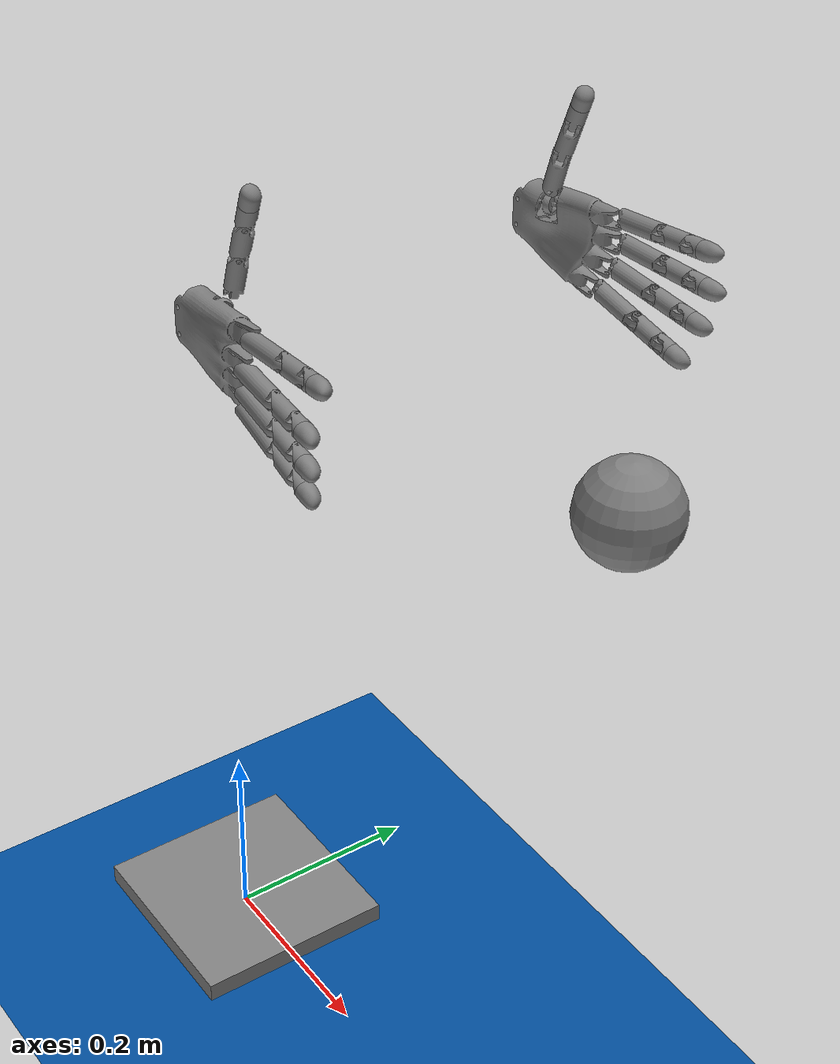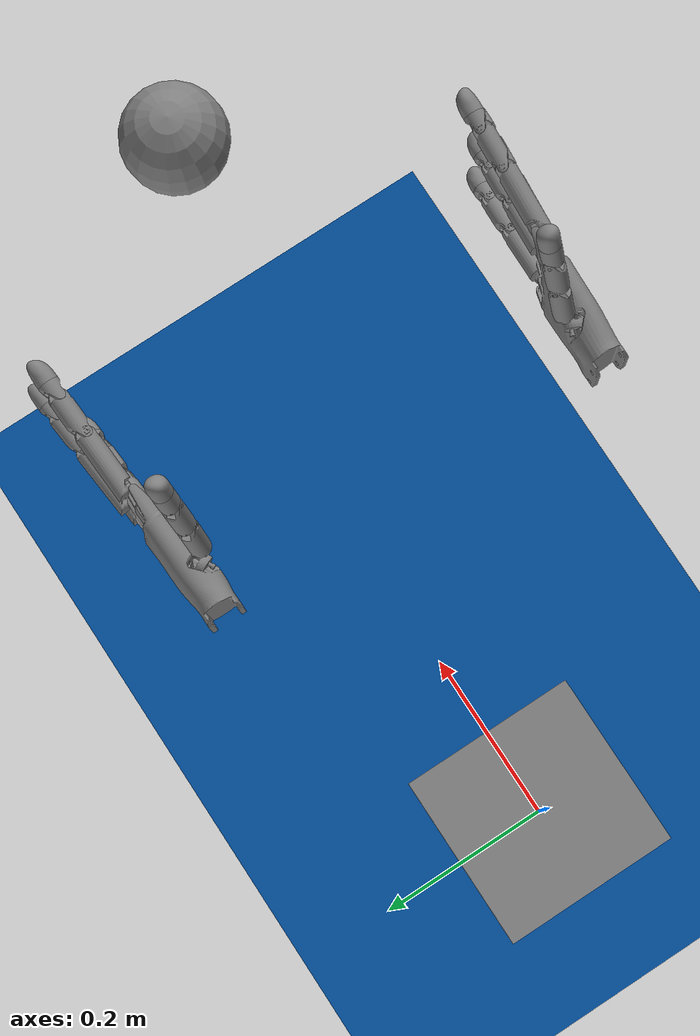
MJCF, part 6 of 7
<mesh name="mjlab scene/worldbody/robot/pelvis/robot/waist_yaw_link/robot/waist_roll_link/robot/torso_link/robot/right_shoulder_pitch_link/robot/right_shoulder_roll_link/robot/right_shoulder_yaw_link/robot/right_elbow_link/robot/right_wrist_roll_link/robot/right_wrist_pitch_link/robot/right_wrist_yaw_link/robot/xhand_mount_right/robot/right_palm_link/robot/right_finger2_link1/robot/right_finger2_link2/robot/right_finger2_link3/robot/right_finger2_link3_geom_0_191" vertex="-0.0015 -0.00275 0.0295 -0.0015 0.00275 0.0295 -0.00129904 -0.00275 0.03025 -0.00129904 0.00275 0.03025 -0.00075 -0.00275 0.030799 -0.00075 0.00275 0.030799 6.19826e-11 -0.00275 0.031 3.8481e-12 0.00275 0.031 0.00075 -0.00275 0.030799 0.00075 0.00275 0.030799 0.00129904 -0.00275 0.03025 0.00129904 0.00275 0.03025 0.0015 -0.00275 0.0295 0.0015 0.00275 0.0295 0.00129904 -0.00275 0.02875 0.00129904 0.00275 0.02875 0.00075 -0.00275 0.028201 0.00075 0.00275 0.028201 3.99184e-11 -0.00275 0.028 -1.82161e-11 0.00275 0.028 -0.00075 -0.00275 0.028201 -0.00075 0.00275 0.028201 -0.00129904 -0.00275 0.02875 -0.00129904 0.00275 0.02875 -0.00568756 0.00275 0.0283114 -0.00490408 0.00275 0.0279951 -0.00224713 0.00275 0.0261909 -0.00134425 0.00275 0.0257326 -0.00802764 0.00275 0.0263405 -0.00802764 0.00275 0.0272312 -0.00784917 0.00275 0.0271664 -0.00798382 0.00275 0.028012 -0.00732594 0.00275 0.0278619 -0.00784985 0.00275 0.0287963 -0.00655685 0.00275 0.0282692 -0.00763418 0.00275 0.0295412 0.000656526 0.00275 0.0255542 -0.000355241 0.00275 0.0255158 0.00555 0.00275 0.0239135 0.00555 0.00275 0.0294956 0.00525533 0.00275 0.0302196 -0.00288755 0.00275 0.0339625 -0.00258135 0.00275 0.0340387 -0.00181035 0.00275 0.0341673 -0.00166474 0.00275 0.0341817 -0.00101575 0.00275 0.0342087 -0.000241693 0.00275 0.0341619 0.000528398 0.00275 0.034028 -0.00733451 0.00275 0.0302631 -0.00694847 0.00275 0.0309589 -0.0064984 0.00275 0.0315904 -0.00597666 0.00275 0.0321724 -0.00538208 0.00275 0.0327012 -0.00474835 0.00275 0.0331481 0.00451657 0.00275 0.0247661 0.00330767 0.00275 0.0253435 0.00199503 0.00275 0.0256115 0.00333558 0.00275 0.0326584 0.00268919 0.00275 0.0331224 0.00079712 0.00275 0.0339599 0.00129193 0.00275 0.0338041 0.00200683 0.00275 0.0335036 -0.00406337 0.00275 0.0335246 -0.00332729 0.00275 0.0338268 0.00391072 0.00275 0.0321382 0.00442842 0.00275 0.0315526 0.00488478 0.00275 0.0309008 0.00555 -0.00275 0.0239135 0.00555 -0.0035623 0.0239135 0.00555 -0.0035623 0.0228503 0.00555 0.0035623 0.0228503 0.00555 0.0035623 0.0239135 0.00555 -0.00243598 0.0298304 0.00555 -0.00275 0.0294956 0.00555 0.00243598 0.0298304 0.00555 0.00196905 0.0301998 0.00555 0.00144712 0.0304863 0.00555 0.000884765 0.0306819 0.00555 0.000297694 0.030781 0.00555 -0.000297694 0.030781 0.00555 -0.000884765 0.0306819 0.00555 -0.00144712 0.0304863 0.00555 -0.00196905 0.0301998 -0.00224713 -0.00275 0.0261909 -0.00134425 -0.00275 0.0257326 0.0007971 -0.00275 0.0339599 0.00127251 -0.00275 0.033811 0.0020065 -0.00275 0.0335038 0.000528042 -0.00275 0.034028 -0.000242056 -0.00275 0.0341619 -0.00042542 -0.00275 0.0341808 -0.00103636 -0.00275 0.0342088 -0.000355241 -0.00275 0.0255158 0.000656526 -0.00275 0.0255542 0.00199503 -0.00275 0.0256115 0.00330767 -0.00275 0.0253435 -0.00181071 -0.00275 0.0341672 -0.0025817 -0.00275 0.0340386 0.00268888 -0.00275 0.0331226 0.00331953 -0.00275 0.0326713 0.00525517 -0.00275 0.0302199 0.00487392 -0.00275 0.0309183 0.0044282 -0.00275 0.0315529 0.00391046 -0.00275 0.0321385 -0.00490408 -0.00275 0.0279951 -0.00570808 -0.00275 0.0283148 -0.00733383 -0.00275 0.0278551 -0.00657189 -0.00275 0.0282651 -0.0076343 -0.00275 0.0295408 -0.00649863 -0.00275 0.0315901 -0.00695945 -0.00275 0.0309414 -0.00733466 -0.00275 0.0302628 -0.00288757 -0.00275 0.0339625 -0.00334676 -0.00275 0.03382 -0.0040637 -0.00275 0.0335244 0.00451657 -0.00275 0.0247661 -0.00785444 -0.00275 0.0287762 -0.00798386 -0.00275 0.0280116 -0.00785131 -0.00275 0.0271616 -0.00802764 -0.00275 0.0272312 -0.00802764 -0.00275 0.0263405 -0.00474866 -0.00275 0.0331479 -0.00539822 -0.00275 0.0326883 -0.00597692 -0.00275 0.0321721 -0.00490408 -0.00643398 0.0279951 -0.00479913 -0.00649569 0.0279238 -0.0040206 -0.00688662 0.0273952 -0.00320102 -0.00718492 0.0268386 -0.00224713 -0.00740384 0.0261909 -0.00570808 -0.00587812 0.0283148 -0.00530118 -0.00617879 0.0282039 -0.00733383 -0.00409432 0.0278551 -0.00696937 -0.00460555 0.0281049 -0.00657189 -0.00507531 0.0282651 -0.00619681 -0.0054553 0.0283334 -0.00801343 -0.0027858 0.0265786 -0.00797531 -0.00287925 0.0267951 -0.00785131 -0.00316103 0.0271616 -0.00762082 -0.00361584 0.0275496 -0.0061277 -0.00224227 0.0322749 0.00487333 0.00254289 0.031065 0.00305776 0.00254913 0.0329651 -0.00696728 0.00254719 0.0310715 -0.00696728 0.00187201 0.0314421 -0.00764531 0.00244191 0.0298367 -0.00764531 0.00197385 0.0302071 -0.00809769 0.00256515 0.0272312 -0.00814329 0.00240942 0.0275916 -0.00814329 0.00166595 0.0290088 -0.00814329 0.00193874 0.0287065 -0.00814329 0.00215737 0.028363 -0.00814329 0.00231574 0.0279879 -0.0051495 0.00255132 0.0329701 -0.0051495 0.00155987 0.0333148 -0.00405939 0.00170623 0.0338857 -0.00288712 0.00180602 0.0342749 -0.00166469 0.0018565 0.0344717 -0.000425485 0.0018563 0.0344709 0.000796673 0.00180542 0.0342725 0.00403495 0.00223956 0.0322688 0.00487333 -0.00254289 0.031065 0.00487333 -0.00186885 0.0314349 0.00403495 -0.00223956 0.0322688 0.00305776 -0.00254913 0.0329651 0.00305776 -0.00155853 0.0333096 0.00196842 -0.00170525 0.0338819 0.000796673 -0.00180542 0.0342725 -0.000425484 -0.0018563 0.0344709 -0.00166469 -0.0018565 0.0344717 -0.00288712 -0.00180602 0.0342749 -0.00405939 -0.00170623 0.0338857 -0.00514951 -0.00155987 0.0333148 -0.00514951 -0.00255132 0.0329701 -0.00814329 -0.00166595 0.0290088 -0.00814329 -0.00193874 0.0287065 -0.00814329 -0.00215737 0.028363 -0.00814329 -0.00231574 0.0279879 -0.00814329 -0.00240942 0.0275916 -0.00809769 -0.00256515 0.0272312 -0.00849929 -0.000870697 0.0272312 -0.00844762 -0.00122138 0.0274139 -0.00850951 -0.000778243 0.0272312 -0.00844762 -0.00117389 0.0276148 -0.00852107 -0.000658174 0.0272312 -0.00844762 -0.00109361 0.0278049 -0.00853129 -0.000529408 0.0272312 -0.00844762 -0.000982783 0.027979 -0.00853931 -0.000400386 0.0272312 -0.00855 8.51666e-07 0.0272312 -0.00844762 -0.0008445 0.0281323 -0.00844762 -0.000682627 0.0282604 -0.00844762 -0.000501685 0.0283597 -0.00844762 -0.000306728 0.0284275 -0.00844762 -0.000103204 0.0284618 -0.00844762 0.000103204 0.0284618 -0.00844762 0.000306728 0.0284275 -0.00844762 0.000501685 0.0283597 -0.00844762 0.00109361 0.0278049 -0.00844762 0.000982783 0.027979 -0.00844762 0.0008445 0.0281323 -0.00844762 0.000682627 0.0282604 -0.00854999 9.78339e-06 0.0272327 -0.00855 6.81715e-06 0.0272312 -0.00844762 0.00117389 0.0276148 -0.00852435 0.000612885 0.0273229 -0.00854358 0.000306804 0.0272771 -0.00854839 0.000153535 0.0272542 -0.0085496 7.6871e-05 0.0272427 -0.00855 3.4083e-06 0.0272312 -0.0085499 3.85356e-05 0.027237 -0.00854997 1.93675e-05 0.0272341 -0.00854999 1.36348e-05 0.0272312 -0.00844762 0.00122138 0.0274139 -0.00849929 0.000870697 0.0272312 -0.00853731 0.000436086 0.0272312 -0.00854683 0.000218135 0.0272312 -0.00854921 0.000109079 0.0272312 -0.0085498 5.45405e-05 0.0272312 -0.00854995 2.72702e-05 0.0272312 0.00487333 0.00186885 0.0314349 0.00487333 0.00114261 0.0316875 0.00487333 0.000384449 0.0318155 0.00487333 -0.000384449 0.0318155 0.00196842 0.00170525 0.0338819 0.00305776 0.00155853 0.0333096 0.00403495 0.00136926 0.0325714 0.00403495 -0.00136926 0.0325714 0.00487333 -0.00114261 0.0316875 0.00403495 0.00046071 0.0327249 0.00305776 0.000524392 0.0334843 0.00196842 0.000573759 0.034073 0.000796673 0.000607462 0.0344749 -0.000425485 0.000624581 0.034679 -0.00166469 0.00062465 0.0346798 -0.00288712 0.000607665 0.0344773 -0.00405939 0.00057409 0.0340769 -0.0051495 0.000524843 0.0334897 0.00403495 -0.00046071 0.0327249 0.00305776 -0.000524392 0.0334843 0.00196842 -0.000573759 0.034073 0.000796673 -0.000607462 0.0344749 -0.000425485 -0.000624581 0.034679 -0.00166469 -0.00062465 0.0346798 -0.00288712 -0.000607665 0.0344773 -0.00405939 -0.00057409 0.0340769 -0.00514951 -0.000524843 0.0334897 -0.0061277 0.00224227 0.0322749 -0.0061277 0.00137092 0.0325779 -0.0061277 0.000461268 0.0327316 -0.0061277 -0.000461268 0.0327316 -0.0061277 -0.00137092 0.0325779 -0.00696728 0.00114454 0.031695 -0.00696728 0.0003851 0.0318233 -0.00696728 -0.0003851 0.0318233 -0.00696728 -0.00114454 0.031695 -0.00696728 -0.00187201 0.0314421 -0.00696728 -0.00254719 0.0310715 -0.00764531 0.00145064 0.0304942 -0.00764531 0.000886919 0.0306903 -0.00764531 0.000298418 0.0307897 -0.00764531 -0.000298418 0.0307897 -0.00764531 -0.000886919 0.0306903 -0.00764531 -0.00145064 0.0304942 -0.00764531 -0.00197385 0.0302071 -0.00764531 -0.00244191 0.0298367 -0.00814329 0.00134662 0.0292614 -0.00814329 0.000989673 0.0294573 -0.00814329 0.000605083 0.0295911 -0.00814329 0.00020359 0.0296589 -0.00814329 -0.00020359 0.0296589 -0.00814329 -0.000605083 0.0295911 -0.00814329 -0.000989673 0.0294573 -0.00814329 -0.00134662 0.0292614 -0.00784917 0.00316564 0.0271664 -0.00797463 0.00288089 0.026798 -0.00801341 0.00278584 0.0265787 -0.00761618 0.00362426 0.0275557 -0.00731616 0.00412132 0.0278702 -0.00696325 0.00461341 0.0281082 -0.00655685 0.00509162 0.0282692 -0.00619681 0.0054553 0.0283334 -0.00568756 0.00589432 0.0283114 -0.00529269 0.00618462 0.0282006 -0.00490408 0.00643398 0.0279951 -0.0048 0.00649519 0.0279244 -0.00224713 0.00740384 0.0261909 -0.00320102 0.00718492 0.0268386 -0.0040206 0.00688662 0.0273952 -0.00148609 0.00748731 0.0257863 -0.00134425 0.00749423 0.0257326 -0.000854026 0.00749744 0.0255922 -0.000355241 0.00746775 0.0255158 0.000252361 0.00738606 0.025508 0.000656526 0.00730327 0.0255542 0.00469533 0.00482091 0.0246471 0.00452184 0.00502042 0.0247627 0.00199503 0.00685404 0.0256115 0.00192066 0.0068866 0.0256169 0.00129797 0.00712299 0.0256226 0.00400531 0.0055402 0.025055 0.00342869 0.00601592 0.0253014 0.00267779 0.00650796 0.0255139 0.00515546 0.00421216 0.0242902 0.00565224 0.00336599 0.0228503 0.00565224 -0.00336599 0.0228503 0.00624784 -0.00172962 0.0228503 0.00624784 0.00172962 0.0228503 0.00645 1.95326e-10 0.0228503 0.00515566 -0.00421186 0.0242901 0.00469684 -0.00481911 0.0246461 0.00330767 -0.00610416 0.0253435 0.0034301 -0.00601487 0.0253009 0.00400342 -0.00554193 0.0250559 0.00451657 -0.00502626 0.0247661 0.00267756 -0.0065081 0.0255139 0.0019206 -0.00688662 0.025617 0.00129893 -0.00712268 0.0256227 0.000656526 -0.00730327 0.0255542 0.000252362 -0.00738606 0.025508 -0.000355241 -0.00746775 0.0255158 -0.000856681 -0.00749751 0.0255928 -0.00148609 -0.00748731 0.0257863 0.00521616 -0.00412132 0.0195 0.00469533 -0.00482091 0.0195 0.00565224 -0.00336599 0.0195 0.00599769 -0.00256515 0.0195 0.00624784 -0.00172962 0.0195 0.00639929 -0.000870697 0.0195 0.00645 1.95587e-10 0.0195 0.00639929 0.000870697 0.0195 0.00624784 0.00172962 0.0195 0.00599769 0.00256515 0.0195 0.00565224 0.00336599 0.0195 0.00521616 0.00412132 0.0195 0.00469533 0.00482091 0.0195 0.00409681 0.0054553 0.0195 0.0019206 0.00688662 0.0195 0.0027 0.00649519 0.0195 0.00342869 0.00601592 0.0195 0.000252361 0.00738606 0.0195 0.00110102 0.00718492 0.0195 -0.00148609 0.00748731 0.0195 -0.000613914 0.00748731 0.0195 -0.00235236 0.00738606 0.0195 -0.00320102 0.00718492 0.0195 -0.00552869 0.00601592 0.0195 -0.0048 0.00649519 0.0195 -0.0040206 0.00688662 0.0195 -0.00619681 0.0054553 0.0195 -0.00679533 0.00482091 0.0195 -0.00731616 0.00412132 0.0195 -0.00775224 0.00336599 0.0195 -0.00809769 0.00256515 0.0195 -0.00849929 0.000870697 0.0195 -0.00855 -2.28952e-10 0.0195 -0.00834784 0.00172962 0.0195 -0.00849929 -0.000870697 0.0195 -0.00731616 -0.00412132 0.0195 -0.00775224 -0.00336599 0.0195 -0.00809769 -0.00256515 0.0195 -0.00834784 -0.00172962 0.0195 -0.00679533 -0.00482091 0.0195 -0.00619681 -0.0054553 0.0195 -0.00552869 -0.00601592 0.0195 -0.00148609 -0.00748731 0.0195 -0.00235236 -0.00738606 0.0195 -0.00320102 -0.00718492 0.0195 -0.0040206 -0.00688662 0.0195 -0.0048 -0.00649519 0.0195 0.00110102 -0.00718492 0.0195 0.000252362 -0.00738606 0.0195 -0.000613914 -0.00748731 0.0195 0.00342869 -0.00601592 0.0195 0.0027 -0.00649519 0.0195 0.0019206 -0.00688662 0.0195 0.00409681 -0.0054553 0.0195 -0.00849929 -0.000870697 0.019 -0.00855 -2.25618e-10 0.019 -0.00849929 0.000870697 0.019 -0.00834784 0.00172962 0.019 -0.00809769 0.00256515 0.019 -0.00775224 0.00336599 0.019 -0.00731616 0.00412132 0.019 -0.00679533 0.00482091 0.019 -0.00619681 0.0054553 0.019 -0.00552869 0.00601592 0.019 -0.0048 0.00649519 0.019 -0.0040206 0.00688662 0.019 -0.00320102 0.00718492 0.019 -0.00235236 0.00738606 0.019 -0.00148609 0.00748731 0.019 -0.000613914 0.00748731 0.019 0.000252361 0.00738606 0.019 0.00110102 0.00718492 0.019 0.0019206 0.00688662 0.019 0.0027 0.00649519 0.019 0.00342869 0.00601592 0.019 0.00409681 0.0054553 0.019 0.00469533 0.00482091 0.019 0.00521616 0.00412132 0.019 0.00565224 0.00336599 0.019 0.00599769 0.00256515 0.019 0.00624784 0.00172962 0.019 0.00639929 0.000870697 0.019 0.00645 1.9892e-10 0.019 0.00639929 -0.000870697 0.019 0.00624784 -0.00172962 0.019 0.00599769 -0.00256515 0.019 0.00565224 -0.00336599 0.019 0.00521616 -0.00412132 0.019 0.00469533 -0.00482091 0.019 0.00409681 -0.0054553 0.019 0.00342869 -0.00601592 0.019 0.0027 -0.00649519 0.019 0.0019206 -0.00688662 0.019 0.00110102 -0.00718492 0.019 0.000252362 -0.00738606 0.019 -0.000613914 -0.00748731 0.019 -0.00148609 -0.00748731 0.019 -0.00235236 -0.00738606 0.019 -0.00320102 -0.00718492 0.019 -0.0040206 -0.00688662 0.019 -0.0048 -0.00649519 0.019 -0.00552869 -0.00601592 0.019 -0.00619681 -0.0054553 0.019 -0.00679533 -0.00482091 0.019 -0.00731616 -0.00412132 0.019 -0.00775224 -0.00336599 0.019 -0.00809769 -0.00256515 0.019 -0.00834784 -0.00172962 0.019 -0.000433013 0.0063 0.00075 -6.08665e-11 0.00623438 7.445e-10 -0.000866026 0.0063 7.51307e-10 0.000433013 0.0063 0.00075 0.000866025 0.0063 7.38568e-10 0.000433013 0.0063 -0.000750001 -0.000433013 0.0063 -0.000750001 -0.000866025 0.0073 7.57974e-10 -0.000433013 0.0073 0.00075 0.000433013 0.0073 0.00075 0.000866025 0.0073 7.45235e-10 0.000433013 0.0073 -0.000750001 -0.000433013 0.0073 -0.000750001 0.000279811 0.0073 0.00167681 0.00080911 0.0073 0.0014951 -0.00169419 0.0073 0.000140385 -0.00164798 0.0073 -0.000417325 -0.00142318 0.0073 -0.000929811 -0.00104416 0.0073 -0.00134154 0.00104416 0.0073 -0.00134154 0.00142318 0.0073 -0.000929811 0.00164798 0.0073 -0.000417325 -0.00155681 0.0073 0.000682882 -0.00125073 0.0073 0.00115138 0.000551989 0.0073 -0.00160789 -7.32854e-11 0.0073 -0.0017 -0.000551989 0.0073 -0.00160789 0.00125073 0.0073 0.00115138 0.00155681 0.0073 0.000682882 0.00169419 0.0073 0.000140385 -0.000809111 0.0073 0.00149511 -0.000279811 0.0073 0.00167681 -7.16984e-11 0.0073 0.0017 0.00171184 0.0071 0.00082438 0.00172865 0.00716922 0.000758256 0.00139788 0.0071 0.00128684 0.00138878 0.00716922 0.00127846 0.00118463 0.0071 0.00148548 0.000898416 0.00716922 0.00166013 0.0009043 0.0071 0.001671 0.00042279 0.0071 0.00185236 0.000310695 0.00716922 0.00186189 0.00031273 0.0071 0.00187409 -0.000310695 0.00716922 0.00186189 -0.00031273 0.0071 0.00187409 -0.00138878 0.00716922 0.00127846 -0.00118463 0.0071 0.00148548 -0.000898417 0.00716922 0.00166013 -0.0009043 0.0071 0.001671 -0.00042279 0.0071 0.00185236 -0.0019 0.0071 7.64245e-10 -0.00189351 0.0071 0.000156901 -0.00188119 0.00716922 0.00015588 -0.00173997 0.0071 0.000763221 -0.00172865 0.00716922 0.000758256 -0.00171184 0.0071 0.00082438 -0.00139788 0.0071 0.00128684 -0.00184186 0.0071 -0.000466422 -0.00182988 0.00716922 -0.000463388 -0.00171184 0.0071 -0.00082438 -0.00158027 0.00716922 -0.00103244 -0.00159062 0.0071 -0.0010392 -0.00115941 0.00716922 -0.00148961 -0.001167 0.0071 -0.00149937 -0.000612915 0.00716922 -0.00178536 -0.000616929 0.0071 -0.00179705 0.00158027 0.00716922 -0.00103244 0.001167 0.0071 -0.00149937 0.00115941 0.00716922 -0.00148961 0.000616929 0.0071 -0.00179705 0.000612915 0.00716922 -0.00178536 0.00042279 0.0071 -0.00185236 -7.19909e-11 0.00716922 -0.00188764 -7.12648e-11 0.0071 -0.0019 -0.00042279 0.0071 -0.00185236 0.00182988 0.00716922 -0.000463388 0.00171184 0.0071 -0.00082438 0.00159062 0.0071 -0.0010392 0.00173997 0.0071 0.000763221 0.00189351 0.0071 0.000156901 0.00188119 0.00716922 0.00015588 0.0019 0.0071 7.36297e-10 0.00184186 0.0071 -0.000466422 -0.000291205 0.00728764 0.00174509 -0.000842057 0.00728764 0.00155599 -0.00130166 0.00728764 0.00119826 -0.00162021 0.00728764 0.000710689 -0.00176318 0.00728764 0.000146101 -0.00171509 0.00728764 -0.000434318 -0.00148113 0.00728764 -0.000967673 -0.00108668 0.00728764 -0.00139617 -0.000574466 0.00728764 -0.00167336 -7.31871e-11 0.00728764 -0.00176922 0.000574466 0.00728764 -0.00167336 0.00108668 0.00728764 -0.00139617 0.00148113 0.00728764 -0.000967673 0.00171509 0.00728764 -0.000434318 0.00176318 0.00728764 0.000146101 0.00162021 0.00728764 0.000710689 0.00130166 0.00728764 0.00119826 0.000842057 0.00728764 0.00155599 0.000291205 0.00728764 0.00174509 -7.27325e-11 0.00724142 -0.00184142 -0.000597909 0.00724142 -0.00174165 -0.00113102 0.00724142 -0.00145314 -0.00154158 0.00724142 -0.00100716 -0.00178507 0.00724142 -0.000452043 -0.00183513 0.00724142 0.000152063 -0.00168632 0.00724142 0.000739691 -0.00135478 0.00724142 0.00124716 -0.00087642 0.00724142 0.00161948 -0.000303088 0.00724142 0.00181631 0.000303088 0.00724142 0.00181631 0.00087642 0.00724142 0.00161948 0.00135478 0.00724142 0.00124716 0.00168632 0.00724142 0.000739691 0.00183513 0.00724142 0.000152063 0.00178507 0.00724142 -0.000452043 0.00154158 0.00724142 -0.00100716 0.00113102 0.00724142 -0.00145314 0.000597908 0.00724142 -0.00174165 0.0019 0.0053 7.24297e-10 0.00171184 0.0053 -0.00082438 0.00118463 0.0053 -0.00148548 0.00042279 0.0053 -0.00185236 -0.00042279 0.0053 -0.00185236 -0.00118463 0.0053 -0.00148548 -0.00171184 0.0053 -0.00082438 -0.0019 0.0053 7.52245e-10 -0.00171184 0.0053 0.00082438 -0.00118463 0.0053 0.00148548 -0.00042279 0.0053 0.00185236 0.00042279 0.0053 0.00185236 0.00118463 0.0053 0.00148548 0.00171184 0.0053 0.00082438 -0.0015 0.00295 7.33637e-10 -0.00129904 -0.00335 0.00075 -0.00129904 0.00295 0.00075 -0.00075 -0.00335 0.00129904 -0.00075 0.00295 0.00129904 5.11096e-11 -0.00335 0.0015 -1.54809e-11 0.00295 0.0015 0.00075 -0.00335 0.00129904 0.00075 0.00295 0.00129904 0.00129904 -0.00335 0.00075 0.00129904 0.00295 0.00075 0.0015 -0.00335 6.69573e-10 0.0015 0.00295 7.11572e-10 0.00129904 -0.00335 -0.000750001 0.00129904 0.00295 -0.000750001 0.00075 -0.00335 -0.00129904 0.00075 0.00295 -0.00129904 2.90454e-11 -0.00335 -0.0015 -3.75451e-11 0.00295 -0.0015 -0.00075 -0.00335 -0.00129904 -0.00075 0.00295 -0.00129904 -0.00129904 -0.00335 -0.000750001 -0.00129904 0.00295 -0.000750001 -0.0015 -0.00335 6.91637e-10 -0.000445042 0.0053 0.00194985 0.000445042 0.0053 0.00194985 0.00124698 0.0053 0.00156366 0.00180194 0.0053 0.000867768 0.002 0.0053 7.23562e-10 0.00180194 0.0053 -0.000867768 0.00124698 0.0053 -0.00156366 0.000445042 0.0053 -0.00194986 -0.000445042 0.0053 -0.00194986 -0.00124698 0.0053 -0.00156366 -0.00180194 0.0053 -0.000867768 -0.002 0.0053 7.52981e-10 -0.00180194 0.0053 0.000867768 -0.00124698 0.0053 0.00156366 0.00436505 -0.00335 0.00619741 -0.00269313 -0.00335 -0.00260951 -0.00339865 -0.00335 -0.00158482 0.000740322 -0.00335 -0.0036762 -0.000503125 -0.00335 -0.00371609 -0.0016912 -0.00335 -0.00334699 -0.00726193 -0.00335 0.0067 0.00285488 -0.00335 -0.00243149 0.00190229 -0.00335 -0.00323169 0.00358865 -0.00335 0.00108817 0.00374717 -0.00335 -0.000145776 0.00349326 -0.00335 -0.00136368 0.00474602 -0.00335 0.0067 0.00374396 -0.00335 0.00501805 0.00339858 -0.00335 0.00373066 0.00334594 -0.00335 0.0023988 0.00474602 0.00295 0.0067 -0.00726193 0.00295 0.0067 0.00349326 0.00295 -0.00136368 0.00285488 0.00295 -0.00243149 0.00190229 0.00295 -0.00323169 0.000740322 0.00295 -0.0036762 -0.000503125 0.00295 -0.00371609 0.00374717 0.00295 -0.000145775 0.00358865 0.00295 0.00108817 0.00334594 0.00295 0.0023988 0.00339858 0.00295 0.00373066 0.00374396 0.00295 0.00501805 0.00436505 0.00295 0.00619741 -0.0016912 0.00295 -0.00334699 -0.00269313 0.00295 -0.00260951 -0.00339865 0.00295 -0.00158482 0.00156216 0.00703041 0.00124886 0.000868859 0.00725038 0.00180141 0.00124698 0.0071396 0.00156366 -0.000445042 0.00747556 0.00194985 -9.58525e-05 0.00743906 0.0019977 0.000252361 0.00738606 0.00198401 0.000445942 0.0073493 0.00194965 -0.000867929 0.00749779 0.00180186 -0.00124698 0.00749741 0.00156366 -0.00148609 0.00748731 0.00133849 -0.00180194 0.00746221 0.000867768 -0.00194966 0.00744585 -0.000445889 -0.002 0.00743959 7.67244e-10 -0.00194962 0.00744585 0.000446086 -0.00148609 0.00748731 -0.00133849 -0.00180194 0.00746221 -0.000867768 -0.000868412 0.0074978 -0.00180163 -0.00124698 0.00749741 -0.00156366 0.00025381 0.0073858 -0.00198383 -9.74126e-05 0.00743926 -0.00199762 -0.000445042 0.00747556 -0.00194986 0.000445042 0.00734948 -0.00194986 0.000869531 0.0072502 -0.00180109 0.00124698 0.0071396 -0.00156366 0.00180194 0.0069366 -0.000867768 0.00156213 0.00703042 -0.0012489 0.00180194 0.0069366 0.000867768 0.0019206 0.00688662 0.000557945 0.002 0.00685182 7.33907e-10 0.0019206 0.00688662 -0.000557945 -0.00339865 0.00692082 -0.00158482 -0.00494926 0.00640669 0.00174048 -0.00479892 0.00649582 0.00148932 -0.00471108 0.00654572 0.00133992 -0.0041697 0.00682037 0.000375266 -0.00363668 0.00703982 -0.000651366 -0.00323231 0.00717548 -0.00148644 -0.00320086 0.00718497 -0.00155349 -0.00326008 0.00697625 -0.0018532 -0.00313398 0.00720465 -0.00169718 -0.00303179 0.00710594 -0.00220698 -0.0027518 0.00730438 -0.00254757 0.0036702 0.00582835 -0.000769482 0.00374717 0.00576517 -0.000145775 0.00371877 0.00578868 0.000482927 0.00358865 0.00589347 0.00108817 0.00285488 0.00640327 -0.00243149 0.00317188 0.00619885 -0.00200041 0.00342869 0.00601592 -0.00151875 0.00349256 0.00596785 -0.00136548 0.00241935 0.00664933 -0.00286518 0.00190229 0.00689449 -0.00323169 0.00134241 0.00710819 -0.00350149 0.000740322 0.00728318 -0.0036762 0.000252361 0.00738606 -0.0037415 -0.000503125 0.00748004 -0.00371609 -0.00100331 0.00749985 -0.00361329 -0.00149153 0.00748699 -0.00344062 -0.00269323 0.00731777 -0.00260941 -0.0022244 0.00740748 -0.00301903 -0.0016912 0.00747254 -0.00334699 0.00520219 -0.00414247 0.00718324 0.00520219 0.00414247 0.00718324 0.00540962 0.00381095 0.00739505 0.00587576 0.00287817 0.00802092 0.00592228 -0.00276358 0.00810013 0.00575357 0.00315617 0.0078306 0.00565281 -0.00336488 0.00768965 0.00565313 0.00336423 0.00769008 0.00559842 -0.0034711 0.00761862 0.00623889 0.00176693 0.00880361 0.00627898 0.00159249 0.0089288 0.00623889 -0.00176692 0.00880361 0.00602999 0.00247461 0.00830162 0.0061722 -0.00202234 0.00862124 0.00644999 1.39876e-05 0.0100757 0.00645 6.66173e-11 0.0100859 0.00644999 -1.39875e-05 0.0100757 0.00640634 0.000808063 0.00949653 0.00644789 -0.000177738 0.00995611 0.00638594 -0.000978146 0.00937291 0.00469533 -0.00482091 0.00663916 0.00469533 0.00482091 0.00663916 0.00436505 0.00518914 0.00619741 0.00436505 -0.00518914 0.00619741 0.00402895 -0.00551854 0.00563883 0.00374396 -0.00576783 0.00501805 0.00356161 -0.00591465 0.00447852 0.00342869 -0.00601592 0.00391039 0.0033353 -0.00608434 0.00306967 0.00358865 -0.00589347 0.00108817 0.00342869 -0.00601592 0.00174811 0.00334594 -0.00607665 0.0023988 0.00402944 0.00551808 0.00563977 0.00374396 0.00576783 0.00501805 0.00356047 0.00591553 0.00447454 0.00339858 0.00603822 0.00373066 0.00333509 0.00608449 0.00306439 0.00334594 0.00607665 0.0023988 0.00342869 0.00601592 0.00174811 0.0036701 -0.00582844 -0.000769985 0.00349326 -0.00596731 -0.00136368 -0.00339865 -0.00712277 -0.00158482 -0.00320102 -0.00718492 -0.00195344 -0.00269313 -0.00731779 -0.00260951 -0.00222377 -0.00740758 -0.00301949 -0.00169173 -0.0074725 -0.00334672 -0.00100197 -0.00749985 -0.00361366 -0.00148609 -0.00748731 -0.00344297 0.000252362 -0.00738606 -0.0037415 -0.000503125 -0.00748004 -0.00371609 0.0019206 -0.00688662 -0.00322084 0.00190243 -0.00689443 -0.0032316 0.00134625 -0.0071069 -0.00350002 0.000740322 -0.00728318 -0.0036762 0.00242268 -0.00664759 -0.00286237 0.00285488 -0.00640327 -0.00243149 0.00317343 -0.00619779 -0.00199796 0.00374717 -0.00576517 -0.000145776 0.00371902 -0.00578847 0.000481005 -0.00619681 0.0054553 0.00441585 -0.00559798 0.00596371 0.00313166 -0.00809288 0.00257834 0.00848198 -0.00411543 -0.00684494 -4.76886e-05 -0.0048 -0.00649519 0.00142038 -0.00552869 -0.00601592 0.00298306 -0.00817523 -0.00234117 0.00865858 -0.00817523 0.00234117 0.00865858 -0.00809769 -0.00256515 0.00849231 -0.00775224 0.00336599 0.00775149 -0.00731616 0.00412132 0.0068163 -0.00679533 0.00482091 0.00569938 -0.00619681 -0.0054553 0.00441585 -0.00679533 -0.00482091 0.00569938 -0.00731616 -0.00412132 0.0068163 -0.00775224 -0.00336599 0.00775149 -0.00855 -9.19525e-11 0.0103491 -0.00854999 1.39875e-05 0.0103388 -0.00854999 -1.39877e-05 0.0103388 -0.00850681 -0.000803688 0.00976287 -0.00850988 0.000774738 0.00978393 -0.00849933 0.000870328 0.0097144 -0.00849932 -0.000870431 0.00971433 -0.00838473 0.00156581 0.00921114 -0.00838188 -0.00157908 0.00920159 0.00338365 -0.00604919 -0.000454893 0.00350908 0.00595523 -0.000215288 0.00164868 -0.00275 0.0229854 0.00164868 -0.00275 0.0228487 0.00175714 -0.00275 0.0229571 0.0018 -0.00281261 0.023 0.00164779 -0.00276471 0.023 0.00164779 -0.00276471 0.0228478 -0.00270706 -0.000470268 0.0249 -0.00258241 -0.00078659 0.0245841 -0.00240365 -0.00106519 0.0249 -0.00240365 -0.00106519 0.0242611 -0.00189676 -0.0015 0.0249 -0.0021721 -0.00130687 0.0239268 -0.00189676 -0.0015 0.0235948 -0.00344955 -0.0015 0.0249 -0.0031334 -0.00094541 0.0249 -0.00236425 -0.0015 0.0239518 -0.00354619 0.00151111 0.0249 -0.00354619 0.00151111 0.02295 -0.00350038 0.0015 0.0249 -0.00350038 0.0015 0.02295 -0.00364791 0.00198785 0.02295 -0.00296842 0.00160302 0.02295 -0.00305 0.0015 0.02295 -0.00411808 0.00168736 0.02295 -0.00442103 0.0020978 0.02295 -0.00411808 0.00168736 0.0249 -0.00332047 0.00104641 0.0215 -0.00296842 0.00160302 0.0215 -0.00393895 0.00150072 0.0215 -0.00364791 0.00198785 0.0215 -0.00442103 0.0020978 0.0215 -0.00305 0.0015 0.0249 -0.00393895 0.00150072 0.0249 -0.00332108 0.00104679 0.0249 -0.00332077 0.00104658 0.0264722 -0.00292531 0.000864442 0.0261021 -0.00259478 0.000762016 0.0258466 -0.00259478 0.000762016 0.0326745 -0.00332047 0.00104641 0.0319014 -0.00323303 0.001 0.0320214 -0.00293453 0.000867913 0.0323633 -0.00316347 0.00133538 0.0249 -0.00326446 0.00116025 0.0319367 -0.00319991 0.00127588 0.0319283 -0.00316347 0.00133538 0.0319 -0.00332415 0.001 0.0319 -0.00331979 0.00105609 0.0319006 -0.00329161 0.00115996 0.0319001 -0.00326646 0.00121033 0.0319004 -0.00332324 0.00097271 0.0319013 -0.00330374 0.000872478 0.031928 -0.00326571 0.000787849 0.0319789 -0.00309144 0.000610649 0.0321931 -0.00276942 0.000504198 0.0325233 -0.0026983 0.000500126 0.0325869 -0.0026983 0.000500126 0.0256728 -0.003323 0.000969404 0.0264105 -0.00276942 0.000504198 0.0257144 -0.00309144 0.000610649 0.025984 -0.00326571 0.000787849 0.0262299 -0.00329161 0.00115996 0.0249 -0.005 0.00352058 0.0067 -0.00532942 0.00385 0.0067 -0.00455 0.0043 0.0067 -0.00545 0.0043 0.0067 -0.00532942 0.00475 0.0067 -0.00377058 0.00385 0.0067 -0.0041 0.00352058 0.0067 -0.00455 0.0034 0.0067 -0.0041 0.00507942 0.0067 -0.00377058 0.00475 0.0067 -0.00365 0.0043 0.0067 -0.005 0.00507942 0.0067 -0.00455 0.0052 0.0067 -0.00423225 0.00374964 0.0032 -0.00399964 0.00398225 0.0032 -0.00455 0.0043 0.0032 -0.0039145 0.0043 0.0032 -0.00399964 0.00461775 0.0032 -0.00510036 0.00398225 0.0032 -0.00486775 0.00374964 0.0032 -0.00455 0.0036645 0.0032 -0.00486775 0.00485036 0.0032 -0.00510036 0.00461775 0.0032 -0.0051855 0.0043 0.0032 -0.00423225 0.00485036 0.0032 -0.00455 0.0049355 0.0032 -0.00510036 0.00398225 0.0064355 -0.00486775 0.00374964 0.0064355 -0.00455 0.0036645 0.0064355 -0.00423225 0.00374964 0.0064355 -0.00399964 0.00398225 0.0064355 -0.0039145 0.0043 0.0064355 -0.00399964 0.00461775 0.0064355 -0.00423225 0.00485036 0.0064355 -0.00455 0.0049355 0.0064355 -0.00486775 0.00485036 0.0064355 -0.00510036 0.00461775 0.0064355 -0.0051855 0.0043 0.0064355 0.002 0.00352058 0.0067 0.00167058 0.00385 0.0067 0.00245 0.0043 0.0067 0.00155 0.0043 0.0067 0.00167058 0.00475 0.0067 0.00322942 0.00385 0.0067 0.0029 0.00352058 0.0067 0.00245 0.0034 0.0067 0.0029 0.00507942 0.0067 0.00322942 0.00475 0.0067 0.00335 0.0043 0.0067 0.002 0.00507942 0.0067 0.00245 0.0052 0.0067 0.00276775 0.00374964 0.0032 0.00300036 0.00398225 0.0032 0.00245 0.0043 0.0032 0.0030855 0.0043 0.0032 0.00300036 0.00461775 0.0032 0.00189964 0.00398225 0.0032 0.00213225 0.00374964 0.0032 0.00245 0.0036645 0.0032 0.00213225 0.00485036 0.0032 0.00189964 0.00461775 0.0032 0.0018145 0.0043 0.0032 0.00276775 0.00485036 0.0032 0.00245 0.0049355 0.0032 0.00189964 0.00398225 0.0064355 0.00213225 0.00374964 0.0064355 0.00245 0.0036645 0.0064355 0.00276775 0.00374964 0.0064355 0.00300036 0.00398225 0.0064355 0.0030855 0.0043 0.0064355 0.00300036 0.00461775 0.0064355 0.00276775 0.00485036 0.0064355 0.00245 0.0049355 0.0064355 0.00213225 0.00485036 0.0064355 0.00189964 0.00461775 0.0064355 0.0018145 0.0043 0.0064355" face="0 1 2 2 1 3 2 3 4 4 3 5 4 5 6 6 5 7 6 7 8 8 7 9 8 9 10 10 9 11 10 11 12 12 11 13 12 13 14 14 13 15 14 15 16 16 15 17 16 17 18 18 17 19 18 19 20 20 19 21 20 21 22 22 21 23 22 23 0 0 23 1 24 1 25 25 1 23 25 23 26 26 23 21 26 21 27 27 21 19 28 29 30 30 29 31 30 31 32 32 31 33 32 33 34 34 33 35 34 35 24 17 36 19 19 36 37 19 37 27 38 15 39 39 15 13 39 13 40 3 41 5 5 41 42 5 42 43 43 44 5 5 44 45 5 45 7 7 45 46 7 46 47 24 35 1 1 35 48 1 48 49 49 50 1 1 50 51 1 51 3 3 51 52 3 52 53 38 54 15 15 54 55 15 55 17 17 55 56 17 56 36 57 11 58 58 11 9 47 59 7 7 59 60 7 60 9 9 60 61 9 61 58 53 62 3 3 62 63 3 63 41 57 64 11 11 64 65 11 65 13 13 65 66 13 66 40 67 68 69 69 70 38 38 70 71 72 73 67 69 38 67 67 38 39 67 39 74 74 75 67 67 75 76 67 76 77 77 78 67 67 78 79 67 79 80 80 81 67 67 81 82 67 82 72 20 83 84 20 84 18 85 6 86 86 6 8 86 8 87 85 88 6 6 88 89 6 89 4 4 89 90 4 90 91 84 92 18 18 92 93 18 93 16 16 93 94 16 94 14 14 94 95 91 96 4 4 96 97 4 97 2 87 8 98 98 8 10 98 10 99 100 101 12 12 101 102 12 102 10 10 102 103 10 103 99 83 20 104 104 20 22 104 22 105 106 107 108 105 22 107 107 22 0 107 0 108 109 110 0 0 110 111 0 111 108 97 112 2 2 112 113 2 113 114 95 115 14 14 115 67 14 67 12 12 67 73 12 73 100 108 116 106 106 116 117 106 117 118 118 117 119 118 119 120 114 121 2 2 121 122 2 122 0 0 122 123 0 123 109 104 124 83 83 124 125 125 126 83 83 126 127 83 127 128 105 129 104 104 129 130 104 130 124 107 106 131 131 132 107 107 132 133 107 133 105 105 133 134 105 134 129 118 120 135 135 136 118 118 136 137 118 137 106 106 137 138 106 138 131 109 123 139 40 74 39 65 140 66 58 61 141 50 142 143 142 50 49 48 144 145 146 147 29 29 147 31 148 35 149 149 35 33 149 33 150 150 33 31 150 31 151 151 31 147 52 152 53 53 152 62 152 153 62 62 153 154 62 154 63 63 154 155 63 155 41 41 155 42 42 155 43 43 155 156 43 156 44 44 156 45 45 156 157 45 157 46 46 157 47 47 157 158 47 158 59 58 141 57 57 141 159 57 159 64 66 140 40 40 140 75 40 75 74 73 72 100 100 72 82 100 82 101 160 161 102 102 161 162 102 162 103 103 162 163 87 98 163 163 98 99 163 99 103 164 165 87 166 85 165 165 85 86 165 86 87 91 90 167 167 90 89 167 89 166 166 89 88 166 88 85 91 167 96 96 167 168 96 168 97 97 168 169 97 169 112 112 169 113 113 169 170 113 170 114 170 171 114 114 171 172 114 172 121 121 172 122 173 174 116 174 175 116 116 175 176 116 176 117 176 177 117 117 177 178 117 178 119 179 180 181 181 180 182 181 182 183 183 182 184 183 184 185 185 184 186 185 186 187 187 186 188 188 186 189 188 189 190 190 191 188 188 191 192 188 192 193 193 194 188 188 194 195 188 195 196 197 188 198 198 188 199 199 188 200 200 188 196 201 202 203 204 205 203 203 205 206 203 206 207 202 208 201 201 208 188 207 209 203 203 209 210 203 210 201 201 210 211 201 211 202 203 212 204 204 212 213 204 213 205 205 213 214 205 214 206 206 214 215 206 215 207 207 215 216 207 216 209 209 216 217 209 217 210 210 217 218 210 218 211 201 188 202 202 188 203 203 188 197 64 159 65 65 159 219 65 219 140 140 219 76 140 76 75 78 77 220 79 78 221 80 79 222 102 101 160 160 101 82 160 82 161 161 82 81 59 158 60 60 158 223 60 223 61 61 223 224 61 224 141 141 224 225 141 225 159 159 225 220 159 220 219 219 220 77 219 77 76 87 163 164 164 163 162 164 162 226 226 162 161 226 161 227 227 161 81 227 81 80 78 220 221 221 220 225 221 225 228 228 225 224 228 224 229 229 224 223 229 223 230 230 223 158 230 158 231 231 158 157 231 157 232 232 157 156 232 156 233 233 156 155 233 155 234 234 155 154 234 154 235 235 154 153 235 153 236 79 221 222 222 221 228 222 228 237 237 228 229 237 229 238 238 229 230 238 230 239 239 230 231 239 231 240 240 231 232 240 232 241 241 232 233 241 233 242 242 233 234 242 234 243 243 234 235 243 235 244 244 235 236 244 236 245 80 222 227 227 222 237 227 237 226 226 237 238 226 238 164 164 238 239 164 239 165 165 239 240 165 240 166 166 240 241 166 241 167 167 241 242 167 242 168 168 242 243 168 243 169 169 243 244 169 244 170 170 244 245 170 245 171 52 51 152 152 51 246 152 246 153 153 246 247 153 247 236 236 247 248 236 248 245 245 248 249 245 249 171 171 249 250 171 250 172 172 250 139 172 139 122 122 139 123 51 50 246 246 50 143 246 143 247 247 143 251 247 251 248 248 251 252 248 252 249 249 252 253 249 253 250 250 253 254 250 254 139 139 254 255 139 255 109 109 255 256 109 256 110 110 256 111 49 48 142 142 48 145 142 145 143 143 145 257 143 257 251 251 257 258 251 258 252 252 258 259 252 259 253 253 259 260 253 260 254 254 260 261 254 261 255 255 261 262 255 262 256 256 262 263 256 263 111 111 263 264 111 264 108 48 35 144 144 35 148 144 148 145 145 148 265 145 265 257 257 265 266 257 266 258 258 266 267 258 267 259 259 267 268 259 268 260 260 268 269 260 269 261 261 269 270 261 270 262 262 270 271 262 271 263 263 271 272 263 272 264 264 272 173 264 173 108 108 173 116 146 213 147 147 213 212 147 212 151 151 212 203 151 203 150 150 203 197 150 197 149 149 197 198 149 198 148 148 198 199 148 199 265 265 199 200 265 200 266 266 200 196 266 196 267 267 196 195 267 195 268 268 195 194 268 194 269 269 194 193 269 193 270 270 193 192 270 192 271 271 192 191 271 191 272 272 191 190 272 190 173 173 190 189 173 189 174 174 189 186 174 186 175 175 186 184 175 184 176 176 184 182 176 182 177 177 182 180 177 180 178 178 180 179 273 274 30 30 274 275 30 275 28 273 30 276 276 30 32 276 32 277 277 32 278 278 32 34 278 34 279 279 34 280 280 34 24 280 24 281 281 24 282 282 24 25 282 25 283 283 25 284 284 25 26 285 286 26 26 286 287 26 287 284 285 26 288 288 26 27 288 27 289 289 27 290 290 27 37 290 37 291 291 37 292 292 37 36 292 36 293 294 295 54 36 56 296 296 297 36 36 297 298 36 298 293 54 295 55 295 299 55 55 299 300 55 300 56 56 300 301 56 301 296 38 71 54 54 71 302 54 302 294 303 70 69 69 304 303 303 304 305 303 305 306 306 305 307 68 67 308 308 67 115 308 115 309 310 311 95 95 311 312 95 312 115 115 312 313 115 313 309 310 95 314 314 95 94 314 94 315 315 94 316 316 94 93 316 93 317 317 93 318 318 93 92 318 92 319 319 92 320 320 92 84 320 84 321 321 84 83 321 83 128 120 119 178 304 69 322 322 69 323 323 69 68 323 68 308 322 324 304 304 324 325 304 325 305 325 326 305 305 326 327 305 327 307 327 328 307 307 328 329 307 329 306 329 330 306 306 330 331 306 331 303 302 71 70 331 332 303 303 332 333 303 333 70 70 333 334 70 334 302 335 295 334 334 295 294 334 294 302 336 296 337 337 296 301 337 301 338 338 301 300 338 300 335 335 300 299 335 299 295 339 293 340 340 293 298 340 298 336 336 298 297 336 297 296 288 289 341 341 289 290 341 290 342 342 290 291 342 291 339 339 291 292 339 292 293 288 341 285 285 341 343 285 343 344 281 282 345 345 282 283 345 283 346 346 283 284 346 284 347 347 284 287 347 287 344 344 287 286 344 286 285 281 345 280 280 345 348 280 348 279 279 348 349 279 349 278 146 29 28 278 349 277 277 349 350 277 350 276 276 350 273 273 350 351 273 351 352 28 275 274 274 273 28 28 273 352 28 352 146 146 352 213 353 354 188 353 188 208 208 202 353 353 202 211 353 211 218 218 217 353 353 217 216 353 216 215 352 355 213 213 355 353 213 353 214 214 353 215 183 185 356 356 185 187 356 187 354 354 187 188 178 179 356 356 179 181 356 181 183 135 120 136 136 120 137 357 131 138 357 138 358 138 137 358 358 137 120 358 120 359 359 120 178 359 178 360 360 178 356 131 357 132 132 357 361 132 361 133 133 361 362 133 362 134 134 362 129 129 362 363 129 363 130 364 321 365 365 321 128 365 128 366 366 128 127 366 127 367 367 127 126 367 126 368 368 126 125 368 125 363 363 125 124 363 124 130 369 317 370 370 317 318 370 318 371 371 318 319 371 319 364 364 319 320 364 320 321 372 310 373 373 310 314 373 314 374 374 314 315 374 315 369 369 315 316 369 316 317 308 309 323 323 309 313 323 313 375 375 313 312 375 312 372 372 312 311 372 311 310 376 356 377 377 356 354 377 354 378 378 354 353 378 353 379 379 353 355 379 355 380 380 355 352 380 352 381 381 352 351 381 351 382 382 351 350 382 350 383 383 350 349 383 349 384 384 349 348 384 348 385 385 348 345 385 345 386 386 345 346 386 346 387 387 346 347 387 347 388 388 347 344 388 344 389 389 344 343 389 343 390 390 343 341 390 341 391 391 341 342 391 342 392 392 342 339 392 339 393 393 339 340 393 340 394 394 340 336 394 336 395 395 336 337 395 337 396 396 337 338 396 338 397 397 338 335 397 335 398 398 335 334 398 334 399 399 334 333 399 333 400 400 333 332 400 332 401 401 332 331 401 331 402 402 331 330 402 330 403 403 330 329 403 329 404 404 329 328 404 328 405 405 328 327 405 327 406 406 327 326 406 326 407 407 326 325 407 325 408 408 325 324 408 324 409 409 324 322 409 322 410 410 322 323 410 323 411 411 323 375 411 375 412 412 375 372 412 372 413 413 372 373 413 373 414 414 373 374 414 374 415 415 374 369 415 369 416 416 369 370 416 370 417 417 370 371 417 371 418 418 371 364 418 364 419 419 364 365 419 365 420 420 365 366 420 366 421 421 366 367 421 367 422 422 367 368 422 368 423 423 368 363 423 363 424 424 363 362 424 362 425 425 362 361 425 361 426 426 361 357 426 357 427 427 357 358 427 358 428 428 358 359 428 359 429 429 359 360 429 360 376 376 360 356 430 431 432 433 431 430 434 431 433 435 431 434 436 431 435 432 431 436 432 437 430 430 437 438 430 438 433 433 438 439 433 439 434 434 439 440 434 440 435 435 440 441 435 441 436 436 441 442 436 442 432 432 442 437 443 444 439 445 437 446 446 437 442 446 442 447 447 442 448 449 441 450 450 441 440 450 440 451 445 452 437 437 452 453 437 453 438 449 454 441 441 454 455 441 455 442 442 455 456 442 456 448 444 457 439 439 457 458 439 458 440 440 458 459 440 459 451 453 460 438 438 460 461 438 461 439 439 461 462 439 462 443 463 464 465 465 464 466 465 466 467 467 466 468 467 468 469 469 468 470 470 468 471 470 471 472 472 471 473 472 473 474 475 476 477 477 476 478 477 478 473 473 478 479 473 479 474 480 481 482 482 481 483 482 483 484 484 483 485 484 485 475 475 485 486 475 486 476 480 482 487 487 482 488 487 488 489 489 488 490 489 490 491 491 490 492 491 492 493 493 492 494 493 494 495 496 497 498 498 497 499 498 499 500 500 499 501 500 501 502 502 501 503 502 503 494 494 503 504 494 504 495 505 506 496 496 506 507 496 507 497 463 508 464 464 508 509 464 509 510 510 509 511 510 511 505 505 511 512 505 512 506 462 461 513 513 461 460 513 460 514 514 460 453 514 453 515 515 453 452 515 452 516 516 452 445 516 445 517 517 445 446 517 446 518 518 446 447 518 447 519 519 447 448 519 448 520 520 448 456 520 456 521 521 456 455 521 455 522 522 455 454 522 454 523 523 454 449 523 449 524 524 449 450 524 450 525 525 450 451 525 451 526 526 451 459 526 459 527 527 459 458 527 458 528 528 458 457 528 457 529 529 457 444 529 444 530 530 444 443 530 443 531 531 443 462 531 462 513 522 532 521 521 532 533 521 533 520 520 533 534 520 534 519 519 534 535 519 535 518 518 535 536 518 536 517 517 536 537 517 537 516 516 537 538 516 538 515 515 538 539 515 539 514 514 539 540 514 540 513 513 540 541 513 541 531 531 541 542 531 542 530 530 542 543 530 543 529 529 543 544 529 544 528 528 544 545 528 545 527 527 545 546 527 546 526 526 546 547 526 547 525 525 547 548 525 548 524 524 548 549 524 549 523 523 549 550 523 550 522 522 550 532 532 502 533 533 502 494 533 494 534 534 494 492 534 492 535 535 492 490 535 490 536 536 490 488 536 488 537 537 488 482 537 482 538 538 482 484 538 484 539 539 484 475 539 475 540 540 475 477 540 477 541 541 477 473 541 473 542 542 473 471 542 471 543 543 471 468 543 468 544 544 468 466 544 466 545 545 466 464 545 464 546 546 464 510 546 510 547 547 510 505 547 505 548 548 505 496 548 496 549 549 496 498 549 498 550 550 498 500 550 500 532 532 500 502 511 551 512 512 551 552 553 507 552 552 507 506 552 506 512 554 499 553 553 499 497 553 497 507 555 503 554 554 503 501 554 501 499 556 495 555 555 495 504 555 504 503 557 491 556 556 491 493 556 493 495 481 480 558 558 480 487 558 487 557 557 487 489 557 489 491 481 558 483 483 558 559 483 559 485 485 559 486 486 559 560 486 560 476 476 560 478 478 560 561 478 561 479 562 472 561 561 472 474 561 474 479 563 469 562 562 469 470 562 470 472 564 465 563 563 465 467 563 467 469 511 509 551 551 509 508 551 508 564 564 508 463 564 463 465 565 566 567 567 566 568 567 568 569 569 568 570 569 570 571 571 570 572 571 572 573 573 572 574 573 574 575 575 574 576 575 576 577 577 576 578 577 578 579 579 578 580 579 580 581 581 580 582 581 582 583 583 582 584 583 584 585 585 584 586 585 586 587 587 586 588 587 588 565 565 588 566 561 589 562 562 589 590 562 590 563 563 590 591 563 591 564 564 591 592 564 592 551 551 592 593 551 593 552 552 593 594 552 594 553 553 594 595 553 595 554 554 595 596 554 596 555 555 596 597 555 597 556 556 597 598 556 598 557 557 598 599 557 599 558 558 599 600 558 600 559 559 600 601 559 601 560 560 601 602 560 602 561 561 602 589 603 572 570 584 604 586 586 604 605 586 605 588 580 606 582 582 606 607 582 607 584 584 607 608 584 608 604 588 605 566 566 605 609 566 609 568 578 610 580 580 610 611 580 611 606 574 612 576 576 612 613 576 613 578 578 613 614 578 614 610 568 609 570 570 609 615 570 615 603 603 616 572 572 616 617 572 617 574 574 617 618 574 618 612 615 609 619 619 609 620 577 579 621 621 579 622 622 579 581 622 581 623 623 581 624 624 581 583 624 583 625 621 626 577 577 626 627 577 627 575 575 627 628 575 628 573 573 628 629 629 630 573 573 630 631 573 631 571 571 631 619 571 619 569 569 619 620 625 583 632 632 583 585 632 585 633 633 585 587 633 587 634 634 587 565 634 565 620 620 565 567 620 567 569 592 591 635 590 636 591 591 636 637 591 637 635 638 639 589 589 639 640 589 640 590 590 640 641 590 641 636 638 589 642 642 589 602 642 602 643 643 602 644 644 602 601 644 601 645 599 646 600 600 646 647 600 647 601 601 647 648 601 648 645 598 649 599 599 649 650 599 650 646 597 651 598 598 651 652 598 652 649 653 654 597 597 654 655 597 655 651 653 597 656 656 597 596 656 596 657 657 596 595 657 595 658 594 659 595 595 659 660 595 660 658 635 661 592 592 661 662 592 662 593 593 662 663 593 663 594 594 663 664 594 664 659 665 666 667 667 668 665 665 668 669 665 669 670 670 671 665 665 671 672 665 672 673 673 672 674 673 674 675 675 674 676 633 634 665 665 673 633 633 673 675 633 675 676 621 677 626 626 677 678 626 678 627 627 678 679 627 679 680 681 682 622 622 682 683 622 683 621 621 683 684 621 684 677 681 622 685 685 622 623 685 623 686 686 623 687 687 623 624 687 624 688 688 624 689 689 624 625 689 625 690 690 625 691 691 625 632 691 632 692 676 693 633 633 693 694 633 694 632 632 694 695 632 695 692 696 697 698 699 700 701 701 700 702 698 703 696 696 703 701 696 701 704 704 701 702 705 706 707 699 708 700 700 708 705 700 705 709 709 705 707 710 711 712 710 712 713 713 712 714 713 714 706 706 714 715 706 715 707 716 603 696 696 603 615 696 615 697 697 615 619 697 619 717 717 619 631 717 631 718 716 719 603 603 719 720 603 720 616 720 721 616 616 721 722 616 722 617 722 723 617 617 723 724 617 724 618 725 612 726 726 612 618 726 618 727 727 618 724 718 631 728 728 631 630 728 630 729 729 630 730 730 630 629 730 629 731 731 629 732 732 629 628 732 628 733 733 628 734 734 628 627 734 627 680 735 736 614 737 605 738 738 605 604 738 604 739 739 604 740 740 604 608 740 608 741 607 742 608 608 742 743 608 743 741 606 744 607 607 744 745 607 745 742 746 747 611 611 747 748 611 748 606 606 748 749 606 749 744 746 611 750 750 611 610 750 610 751 614 736 610 610 736 752 610 752 751 735 614 753 753 614 613 753 613 754 754 613 612 754 612 725 755 756 634 634 756 666 634 666 665 620 609 757 737 758 605 605 758 759 605 759 760 761 762 763 763 762 757 757 764 620 620 764 765 620 765 634 634 765 766 634 766 755 760 767 605 605 767 768 605 768 609 609 768 769 609 769 757 757 769 770 757 770 763 771 772 773 773 772 774 772 775 774 774 775 776 774 776 777 777 776 778 777 778 779 779 778 762 779 762 761 780 725 726 679 678 781 682 681 664 682 664 683 662 394 395 395 396 662 662 396 731 662 731 732 732 733 662 662 733 734 662 734 663 658 660 686 681 685 664 664 685 686 664 686 659 659 686 660 658 686 657 657 686 687 657 687 656 656 687 688 656 688 653 653 688 689 653 689 654 654 689 690 654 690 655 655 690 691 655 691 651 651 691 692 651 692 652 650 672 646 646 672 647 652 692 649 649 692 695 649 695 694 694 693 649 649 693 676 649 676 650 650 676 674 650 674 672 638 642 390 638 390 639 639 390 391 639 391 640 648 388 645 645 388 389 645 389 644 644 389 390 644 390 643 643 390 642 662 661 394 394 661 635 394 635 637 637 636 394 394 636 641 394 641 393 393 641 640 393 640 392 392 640 391 776 378 778 778 378 379 778 379 762 762 379 380 762 380 757 382 765 764 757 380 764 764 380 381 764 381 382 384 755 766 765 382 766 766 382 383 766 383 384 756 386 666 666 386 667 755 384 756 756 384 385 756 385 386 671 388 672 672 388 648 672 648 647 671 670 388 388 670 669 388 669 668 667 386 668 668 386 387 668 387 388 678 677 781 781 677 684 781 684 683 664 663 683 683 663 734 683 734 781 781 734 680 781 680 679 728 729 396 396 729 730 396 730 731 728 396 718 718 396 397 718 397 717 717 397 398 717 398 697 697 398 399 697 399 698 698 399 703 703 399 400 703 400 701 402 403 713 713 706 402 402 706 705 402 705 401 401 705 708 401 708 400 400 708 699 400 699 701 715 714 405 405 714 712 405 712 404 404 712 711 404 711 403 403 711 710 403 710 713 715 405 707 707 405 406 707 406 709 709 406 407 709 407 700 700 407 702 702 407 408 702 408 704 704 408 409 704 409 696 696 409 410 696 410 716 722 721 412 412 721 720 412 720 719 716 410 719 719 410 411 719 411 412 727 724 746 722 412 723 723 412 413 723 413 724 735 753 780 780 753 754 780 754 725 746 750 727 727 750 751 727 751 726 726 751 752 726 752 780 780 752 736 780 736 735 724 413 746 746 413 414 746 414 747 747 414 415 747 415 748 748 415 749 749 415 416 749 416 744 744 416 745 745 416 417 745 417 742 742 417 418 742 418 743 419 420 738 738 739 419 419 739 740 419 740 418 418 740 741 418 741 743 428 763 427 427 763 770 427 770 426 426 770 769 426 769 425 425 769 768 425 768 424 424 768 767 424 767 423 423 767 760 423 760 422 422 760 759 422 759 421 421 759 758 421 758 420 420 758 737 420 737 738 776 775 378 378 775 772 378 772 377 377 772 771 377 771 376 376 771 773 773 774 376 376 774 777 376 777 429 429 777 779 429 779 428 428 779 761 428 761 763 782 783 784 784 785 782 782 785 786 787 785 783 783 785 784 787 783 786 786 783 782 787 786 785 788 789 790 790 789 791 790 791 792 792 791 793 792 793 794 792 795 790 790 795 796 790 796 788 797 796 795 789 788 796 797 794 793 797 793 796 796 793 791 796 791 789 795 792 797 797 792 794 798 799 800 800 799 801 802 803 804 805 806 799 799 806 802 799 802 801 801 802 804 799 798 805 805 798 807 808 809 810 810 809 811 810 811 812 804 813 801 801 813 800 806 812 802 802 812 811 802 811 803 803 811 809 805 807 814 810 812 806 806 805 810 810 805 814 810 814 808 808 814 815 808 815 816 817 818 819 820 816 821 821 816 817 821 817 822 822 817 819 823 813 804 820 824 816 816 824 825 803 809 804 804 809 808 804 808 823 823 808 816 823 816 826 826 816 825 821 827 820 820 827 828 820 828 824 828 829 824 824 829 830 824 830 825 825 830 826 831 827 821 831 821 832 832 821 833 833 821 822 833 822 834 834 822 835 835 822 819 835 819 836 818 837 819 819 837 836 817 816 838 837 818 839 839 818 817 839 817 840 840 817 838 840 838 841 815 814 842 842 814 807 813 823 800 800 823 842 800 842 798 798 842 807 816 815 842 832 841 831 831 841 838 831 838 827 832 833 841 841 833 834 841 834 840 840 834 835 840 835 839 839 835 836 839 836 837 827 838 828 828 838 816 828 816 829 829 816 842 829 842 830 830 842 823 830 823 826 843 844 845 845 844 846 845 846 847 848 849 845 845 849 850 845 850 843 851 852 845 845 852 853 845 853 848 847 854 845 845 854 855 845 855 851 856 857 858 858 857 859 858 859 860 861 862 858 858 862 863 858 863 856 864 865 858 858 865 866 858 866 861 860 867 858 858 867 868 858 868 864 869 844 870 870 844 843 870 843 871 871 843 850 871 850 872 872 850 849 872 849 873 873 849 848 873 848 874 874 848 853 874 853 875 875 853 852 875 852 876 876 852 851 876 851 877 877 851 855 877 855 878 878 855 854 878 854 879 879 854 847 879 847 880 880 847 846 880 846 869 869 846 844 874 859 873 873 859 857 873 857 872 872 857 856 872 856 871 871 856 863 871 863 870 870 863 862 870 862 869 869 862 861 869 861 880 880 861 866 880 866 879 879 866 865 879 865 878 878 865 864 878 864 877 877 864 868 877 868 876 876 868 867 876 867 875 875 867 860 875 860 874 874 860 859 881 882 883 883 882 884 883 884 885 886 887 883 883 887 888 883 888 881 889 890 883 883 890 891 883 891 886 885 892 883 883 892 893 883 893 889 894 895 896 896 895 897 896 897 898 899 900 896 896 900 901 896 901 894 902 903 896 896 903 904 896 904 899 898 905 896 896 905 906 896 906 902 907 882 908 908 882 881 908 881 909 909 881 888 909 888 910 910 888 887 910 887 911 911 887 886 911 886 912 912 886 891 912 891 913 913 891 890 913 890 914 914 890 889 914 889 915 915 889 893 915 893 916 916 893 892 916 892 917 917 892 885 917 885 918 918 885 884 918 884 907 907 884 882 912 897 911 911 897 895 911 895 910 910 895 894 910 894 909 909 894 901 909 901 908 908 901 900 908 900 907 907 900 899 907 899 918 918 899 904 918 904 917 917 904 903 917 903 916 916 903 902 916 902 915 915 902 906 915 906 914 914 906 905 914 905 913 913 905 898 913 898 912 912 898 897"/>
    <mesh name="mjlab scene/worldbody/robot/pelvis/robot/waist_yaw_link/robot/waist_roll_link/robot/torso_link/robot/right_shoulder_pitch_link/robot/right_shoulder_roll_link/robot/right_shoulder_yaw_link/robot/right_elbow_link/robot/right_wrist_roll_link/robot/right_wrist_pitch_link/robot/right_wrist_yaw_link/robot/xhand_mount_right/robot/right_palm_link/robot/right_finger2_link1/robot/right_finger2_link2/robot/right_finger2_link3/robot/right_finger2_link4/robot/right_finger2_link4_geom_0_194" vertex="0.000433013 0.0065 -0.000750001 5.57949e-11 0.00643438 -8.47575e-10 0.000866025 0.0065 -8.53107e-10 0.000433013 0.0065 0.000750001 -0.000433013 0.0065 0.000750001 -0.000866025 0.0065 -8.41177e-10 -0.000433013 0.0065 -0.000750001 0.000866025 0.0075 -8.46518e-10 0.000433013 0.0075 -0.00075 0.000433013 0.0075 0.000750001 -0.000433013 0.0075 0.000750001 -0.000866025 0.0075 -8.34588e-10 -0.000433013 0.0075 -0.00075 0.00116373 0.0075 -0.00123925 0.000818981 0.0075 -0.00148972 0.000422773 0.0075 -0.00164659 -0.000818981 0.0075 -0.00148972 -0.000422773 0.0075 -0.00164659 2.51893e-11 0.0075 -0.0017 0.00166989 0.0075 0.000318549 0.00169665 0.0075 -0.000106743 0.0016168 0.0075 -0.000525328 0.00143536 0.0075 -0.000910905 -0.00169665 0.0075 -0.000106743 -0.00166989 0.0075 0.000318549 -0.000999235 0.0075 0.00137533 -0.00130987 0.0075 0.00108362 -0.00153821 0.0075 0.000723825 -0.00116373 0.0075 -0.00123925 -0.00143536 0.0075 -0.000910905 -0.0016168 0.0075 -0.000525328 -0.000625812 0.0075 0.00158062 -0.000213066 0.0075 0.00168659 4.86083e-11 0.0075 0.0017 0.000213067 0.0075 0.00168659 0.000625812 0.0075 0.00158062 0.000999235 0.0075 0.00137533 0.00130987 0.0075 0.00108362 0.00153821 0.0075 0.000723825 0.00095 0.0073 0.00164545 0.00111679 0.0073 0.00153713 0.00110953 0.00736922 0.00152713 0.00146398 0.0073 0.00121111 0.00145445 0.00736922 0.00120323 0.00171917 0.0073 0.000808981 0.00170799 0.00736922 0.000803717 0.00178542 0.0073 0.000649839 0.0018542 0.00736922 0.000353708 0.00186635 0.0073 0.000356025 0.00188391 0.00736922 -0.000118527 0.0019 0.0073 -8.54958e-10 0.000699437 0.0073 0.00176657 0.000694886 0.00736922 0.00175508 0.000329932 0.0073 0.00187113 0.000236584 0.00736922 0.00187275 0.000238133 0.0073 0.00188502 -0.000236584 0.00736922 0.00187275 -0.000238133 0.0073 0.00188502 -0.00178542 0.0073 0.000649839 -0.00171917 0.0073 0.000808981 -0.00170799 0.00736922 0.000803718 -0.00146398 0.0073 0.00121111 -0.00145445 0.00736922 0.00120323 -0.00111679 0.0073 0.00153713 -0.00110953 0.00736922 0.00152713 -0.00095 0.0073 0.00164545 -0.000694886 0.00736922 0.00175508 -0.000699437 0.0073 0.00176657 -0.000329931 0.0073 0.00187113 -0.00186635 0.0073 0.000356025 -0.0018542 0.00736922 0.000353708 -0.0019 0.0073 -8.28784e-10 -0.00188391 0.00736922 -0.000118527 -0.00189625 0.0073 -0.000119301 -0.00179525 0.00736922 -0.000583312 -0.00180701 0.0073 -0.000587133 -0.00129218 0.00736922 -0.00137603 -0.00145548 0.0073 -0.0012213 -0.00159379 0.00736922 -0.00101145 -0.00160422 0.0073 -0.00101807 -0.00178542 0.0073 -0.000649839 -0.000329932 0.0073 -0.00187113 -0.000472511 0.0073 -0.00184031 -0.000469437 0.00736922 -0.00182833 -0.000915332 0.0073 -0.00166498 -0.000909377 0.00736922 -0.00165415 -0.00095 0.0073 -0.00164545 -0.00130064 0.0073 -0.00138504 2.73582e-11 0.0073 -0.0019 2.62159e-11 0.00736922 -0.00188764 0.000329932 0.0073 -0.00187113 0.000469437 0.00736922 -0.00182833 0.000472511 0.0073 -0.00184031 0.000909377 0.00736922 -0.00165415 0.000915332 0.0073 -0.00166498 0.00095 0.0073 -0.00164545 0.00129218 0.00736922 -0.00137603 0.00130064 0.0073 -0.00138504 0.00189625 0.0073 -0.000119301 0.00180701 0.0073 -0.000587133 0.00179525 0.00736922 -0.000583312 0.00178542 0.0073 -0.000649839 0.00159379 0.00736922 -0.00101145 0.00160422 0.0073 -0.00101807 0.00145548 0.0073 -0.0012213 -0.000221743 0.00748764 0.00175527 -0.000651295 0.00748764 0.00164498 -0.00103992 0.00748764 0.00143133 -0.00136321 0.00748764 0.00112775 -0.00160084 0.00748764 0.000753299 -0.00173789 0.00748764 0.00033152 -0.00176573 0.00748764 -0.000111091 -0.00168263 0.00748764 -0.000546721 -0.0014938 0.00748764 -0.000947998 -0.00121112 0.00748764 -0.00128971 -0.00085233 0.00748764 -0.00155038 -0.000439988 0.00748764 -0.00171364 2.49317e-11 0.00748764 -0.00176922 0.000439988 0.00748764 -0.00171364 0.00085233 0.00748764 -0.00155038 0.00121112 0.00748764 -0.00128971 0.0014938 0.00748764 -0.000947998 0.00168263 0.00748764 -0.000546721 0.00176573 0.00748764 -0.000111091 0.00173789 0.00748764 0.00033152 0.00160084 0.00748764 0.000753299 0.00136321 0.00748764 0.00112775 0.00103992 0.00748764 0.00143133 0.000651295 0.00748764 0.00164498 0.000221742 0.00748764 0.00175527 2.52539e-11 0.00744142 -0.00184142 -0.000457943 0.00744142 -0.00178357 -0.000887112 0.00744142 -0.00161365 -0.00126054 0.00744142 -0.00134234 -0.00155476 0.00744142 -0.000986683 -0.0017513 0.00744142 -0.00056903 -0.00183779 0.00744142 -0.000115625 -0.0018088 0.00744142 0.000345049 -0.00166617 0.00744142 0.000784039 -0.00141884 0.00744142 0.00117377 -0.00108236 0.00744142 0.00148974 -0.000677872 0.00744142 0.00171211 -0.000230791 0.00744142 0.0018269 0.000230791 0.00744142 0.0018269 0.000677872 0.00744142 0.00171211 0.00108236 0.00744142 0.00148974 0.00141884 0.00744142 0.00117377 0.00166617 0.00744142 0.000784039 0.0018088 0.00744142 0.000345049 0.00183779 0.00744142 -0.000115625 0.0017513 0.00744142 -0.00056903 0.00155476 0.00744142 -0.000986683 0.00126054 0.00744142 -0.00134234 0.000887112 0.00744142 -0.00161365 0.000457943 0.00744142 -0.00178357 -0.0015 0.00315 -8.58884e-10 -0.00138582 -0.00315 0.000574025 -0.00138582 0.00315 0.000574025 -0.00106066 -0.00315 0.00106066 -0.00106066 0.00315 0.00106066 -0.000574025 -0.00315 0.00138582 -0.000574025 0.00315 0.00138582 3.25189e-12 -0.00315 0.0015 7.95206e-12 0.00315 0.0015 0.000574025 -0.00315 0.00138582 0.000574025 0.00315 0.00138582 0.00106066 -0.00315 0.00106066 0.00106066 0.00315 0.00106066 0.00138582 -0.00315 0.000574025 0.00138582 0.00315 0.000574025 0.0015 -0.00315 -9.21058e-10 0.0015 0.00315 -8.79547e-10 0.00138582 -0.00315 -0.000574025 0.00138582 0.00315 -0.000574025 0.00106066 -0.00315 -0.00106066 0.00106066 0.00315 -0.00106066 0.000574025 -0.00315 -0.00138582 0.000574025 0.00315 -0.00138582 -1.74119e-11 -0.00315 -0.0015 -1.27118e-11 0.00315 -0.0015 -0.000574025 -0.00315 -0.00138582 -0.000574025 0.00315 -0.00138582 -0.00106066 -0.00315 -0.00106066 -0.00106066 0.00315 -0.00106066 -0.00138582 -0.00315 -0.000574025 -0.00138582 0.00315 -0.000574025 -0.0015 -0.00315 -9.00394e-10 0.00178542 0.0055 -0.000649839 0.0019 0.0055 -8.66818e-10 0.00145548 0.0055 -0.0012213 0.00095 0.0055 -0.00164545 0.000329932 0.0055 -0.00187113 -0.000329932 0.0055 -0.00187113 -0.00095 0.0055 -0.00164545 -0.00145548 0.0055 -0.0012213 -0.00178542 0.0055 -0.000649839 -0.0019 0.0055 -8.40644e-10 -0.00178542 0.0055 0.000649839 -0.00145548 0.0055 0.0012213 -0.00095 0.0055 0.00164545 -0.000329932 0.0055 0.00187113 0.000329932 0.0055 0.00187113 0.00095 0.0055 0.00164545 0.00145548 0.0055 0.0012213 0.00178542 0.0055 0.000649839 0.0044934 -0.00315 0.00637927 -0.00726193 -0.00315 0.0067 -0.00339865 -0.00315 -0.00158482 0.00216465 -0.00315 -0.00306215 0.00133987 -0.00315 -0.00350246 0.00367107 -0.00315 -0.000765328 0.00336765 -0.00315 -0.00164968 0.00285488 -0.00315 -0.00243149 -0.00290097 -0.00315 -0.00237631 -0.00222296 -0.00315 -0.00302009 0.00336603 -0.00315 0.00217711 0.00358865 -0.00315 0.00108817 0.0037463 -0.00315 0.0001666 0.00474602 -0.00315 0.0067 0.000431791 -0.00315 -0.00372506 -0.000503125 -0.00315 -0.0037161 -0.00140677 -0.00315 -0.00347613 0.00392161 -0.00315 0.00542618 0.00353541 -0.00315 0.00438398 0.00334808 -0.00315 0.00328842 0.00216465 0.00315 -0.00306215 0.00285488 0.00315 -0.00243149 0.00334808 0.00315 0.00328842 0.00353541 0.00315 0.00438398 0.00336765 0.00315 -0.00164968 0.00367107 0.00315 -0.000765328 0.0037463 0.00315 0.0001666 0.00358865 0.00315 0.00108817 0.00336603 0.00315 0.00217711 0.00392161 0.00315 0.00542618 0.0044934 0.00315 0.00637927 0.00474602 0.00315 0.0067 -0.00726193 0.00315 0.0067 -0.000503125 0.00315 -0.0037161 0.000431791 0.00315 -0.00372506 0.00133987 0.00315 -0.00350246 -0.00339865 0.00315 -0.00158482 -0.00290097 0.00315 -0.00237631 -0.00222296 0.00315 -0.00302009 -0.00140677 0.00315 -0.00347613 0.00153209 0.0055 0.00128557 0.00187939 0.0055 0.000684041 0.002 0.0055 -8.67507e-10 0.00187939 0.0055 -0.000684041 0.00153209 0.0055 -0.00128557 0.001 0.0055 -0.00173205 0.000347296 0.0055 -0.00196962 -0.000347296 0.0055 -0.00196962 -0.001 0.0055 -0.00173205 -0.00153209 0.0055 -0.00128557 -0.00187939 0.0055 -0.00068404 -0.002 0.0055 -8.39955e-10 -0.00187939 0.0055 0.000684041 -0.00153209 0.0055 0.00128557 -0.001 0.0055 0.00173205 -0.000347296 0.0055 0.00196962 0.000347296 0.0055 0.00196962 0.001 0.0055 0.00173205 0.00645 0.0002 0.0107 0.0063223 0.00157812 0.0107 -0.00105 0.0002 0.0107 0.00532663 -0.00374824 0.0107 0.00594354 -0.00250931 0.0107 0.0063223 -0.00117812 0.0107 0.00229304 -0.00651372 0.0107 0.00346976 -0.00578513 0.0107 0.00449257 -0.00485272 0.0107 -0.00174201 -0.00726801 0.0107 -0.000357987 -0.00726801 0.0107 0.00100247 -0.00701369 0.0107 -0.00556976 -0.00578513 0.0107 -0.00439304 -0.00651372 0.0107 -0.00310247 -0.00701369 0.0107 -0.00804354 -0.00250931 0.0107 -0.00742663 -0.00374824 0.0107 -0.00659257 -0.00485272 0.0107 -0.0084223 0.00157812 0.0107 -0.00855 0.0002 0.0107 -0.0084223 -0.00117812 0.0107 -0.00659257 0.00525272 0.0107 -0.00742663 0.00414824 0.0107 -0.00804354 0.00290931 0.0107 -0.00310247 0.00741369 0.0107 -0.00439304 0.00691372 0.0107 -0.00556976 0.00618513 0.0107 0.00100247 0.00741369 0.0107 -0.000357987 0.00766801 0.0107 -0.00174201 0.00766801 0.0107 0.00449257 0.00525272 0.0107 0.00346976 0.00618513 0.0107 0.00229304 0.00691372 0.0107 0.00594354 0.00290931 0.0107 0.00532663 0.00414824 0.0107 -0.00339865 -0.00692277 -0.00158482 -0.00310247 -0.00701369 -0.00210646 -0.00290097 -0.00706801 -0.00237631 -0.00258146 -0.00714198 -0.00272003 -0.00222296 -0.00720771 -0.00302009 -0.00174201 -0.00726801 -0.00332083 -0.00140677 -0.00729151 -0.00347613 -0.000960417 -0.00729947 -0.00362493 -0.000502895 -0.00728002 -0.00371613 3.7934e-05 -0.00722067 -0.00374981 -0.000357987 -0.00726801 -0.00373287 0.00100247 -0.00701369 -0.00361352 0.000431791 -0.00715216 -0.00372506 0.00176811 -0.00675041 -0.00330701 0.00133987 -0.00690905 -0.00350246 0.00285488 -0.00620327 -0.00243149 0.00258834 -0.00635839 -0.00271349 0.00229304 -0.00651372 -0.00296723 0.0021652 -0.00657587 -0.00306176 0.00358476 -0.00569653 -0.00110091 0.00367107 -0.00562765 -0.000765328 0.00373758 -0.00557314 -0.000305007 0.00346976 -0.00578513 -0.00142242 0.00336765 -0.00586089 -0.00164968 0.00313471 -0.006024 -0.00205818 0.0037463 -0.00556589 0.0001666 0.00369617 -0.00560723 0.000633138 0.00358865 -0.00569347 0.00108817 0.005375 0.00406903 0.00735746 0.00532748 -0.00374686 0.00730739 0.00532684 0.0041479 0.00730673 0.00520219 -0.00394247 0.00718324 0.00520219 0.00434247 0.00718324 0.00601314 -0.0023223 0.00826821 0.00594395 -0.00250827 0.00813851 0.00565142 0.00356764 0.00768779 0.00578686 -0.00288341 0.00788014 0.00551641 -0.00342384 0.00751741 0.00623889 -0.00156692 0.00880361 0.00619428 -0.00174175 0.00867865 0.00632238 0.00157771 0.00908355 0.00588742 0.00304994 0.00804039 0.00594384 0.00290853 0.00813832 0.00612524 -0.00198309 0.00850711 0.00608336 0.00251629 0.00841297 0.00623889 0.00196693 0.00880361 0.00634698 0.0014388 0.00918395 0.00642355 0.000829324 0.00962666 0.00644999 0.000186012 0.0100757 0.00644999 0.000213988 0.0100757 0.00645 0.0002 0.0100859 0.00643062 -0.000338866 0.00969259 0.00636031 -0.000956453 0.00924357 0.00632242 -0.00117748 0.00908372 0.00484854 0.0048322 0.00681826 0.00484776 -0.00443319 0.00681738 0.0044934 -0.0048518 0.00637927 0.00419369 -0.00516225 0.00592979 0.00392161 -0.00541544 0.00542618 0.00370702 -0.00559834 0.00492131 0.00353541 -0.00573498 0.00438398 0.00345989 -0.00579257 0.00406867 0.00339459 -0.00584116 0.00370398 0.00334808 -0.00587511 0.00328842 0.00333126 -0.00588725 0.00273272 0.00346976 -0.00578513 0.00154396 0.00336603 -0.00586207 0.00217711 0.00419138 0.00556451 0.00592596 0.00449257 0.00525272 0.00637813 0.00370679 0.00599853 0.00492068 0.00392161 0.00581544 0.00542618 0.00334808 0.00627511 0.00328842 0.00339494 0.00624091 0.00370636 0.00346976 0.00618513 0.00411453 0.00353541 0.00613498 0.00438398 0.00333128 0.00628723 0.00273116 0.00336603 0.00626207 0.00217711 0.00346976 0.00618513 0.00154396 0.00358865 0.00609347 0.00108817 0.00369586 0.00600748 0.000634902 0.0037463 0.00596589 0.0001666 0.00373762 0.0059731 -0.00030445 0.00367107 0.00602765 -0.000765328 0.00358453 0.0060967 -0.00110165 0.00336765 0.00626089 -0.00164968 0.00313347 0.00642484 -0.00206007 0.00285488 0.00660327 -0.00243149 0.00258731 0.00675896 -0.00271446 0.00229717 0.00691166 -0.00296403 0.00177008 0.00714962 -0.00330595 0.00216465 0.00697613 -0.00306215 0.00100247 0.00741369 -0.00361352 0.00133987 0.00730905 -0.00350246 -0.000503125 0.00768004 -0.0037161 -0.000358463 0.00766805 -0.00373283 3.69565e-05 0.00762082 -0.00374982 0.000431791 0.00755216 -0.00372506 -0.000961297 0.00769948 -0.0036247 -0.00140677 0.00769151 -0.00347613 -0.00174201 0.00766801 -0.00332083 -0.00222296 0.00760771 -0.00302009 -0.00258197 0.00754187 -0.00271955 -0.00290097 0.00746801 -0.00237631 -0.00339865 0.00732277 -0.00158482 -0.00310247 0.00741369 -0.00210646 -0.00390319 0.00713609 -0.000502848 -0.00439304 0.00691372 0.000547645 -0.00390319 -0.00673609 -0.000502848 -0.00439304 -0.00651372 0.000547643 -0.00804354 0.00290931 0.00837617 -0.00776372 0.00354304 0.0077761 -0.00817523 -0.00214117 0.00865858 -0.00817523 0.00254117 0.00865858 -0.00804354 -0.00250931 0.00837617 -0.00610272 0.00574257 0.00421406 -0.00556976 0.00618513 0.00307113 -0.00499824 0.00657663 0.00184551 -0.00499824 -0.00617663 0.00184551 -0.00556976 -0.00578513 0.00307113 -0.00610272 -0.00534257 0.00421406 -0.00659257 -0.00485272 0.00526455 -0.00703513 -0.00431976 0.00621363 -0.00742663 -0.00374824 0.0070532 -0.00776372 -0.00314304 0.0077761 -0.00742663 0.00414824 0.0070532 -0.00703513 0.00471976 0.00621363 -0.00659257 0.00525272 0.00526455 -0.00844911 -0.00102602 0.00945635 -0.00852401 -0.000423883 0.00989378 -0.00854999 0.000213988 0.0103388 -0.00854999 0.000186012 0.0103388 -0.00855 0.0002 0.0103491 -0.00832581 -0.00162004 0.00902874 -0.00842239 -0.00117761 0.00934678 -0.00834509 0.00194115 0.00908523 -0.00853235 0.000714285 0.00997367 -0.00846415 0.00133157 0.00952476 -0.00842242 0.00157746 0.00934688 0.0017317 0.00716506 0.0010006 0.001 0.0074144 0.00173205 0.00100261 0.00741365 0.00173054 0.00128724 0.00732652 0.00153069 0.00153209 0.00724151 0.00128557 0.000686237 0.00749626 0.00187858 0.000347296 0.00756869 0.00196962 2.55676e-06 0.00762577 0.002 -0.000357987 0.00766801 0.0019677 -0.000687649 0.00769124 0.00187807 -0.001 0.00769983 0.00173205 -0.00128493 0.00769632 0.00153263 -0.00153209 0.00768449 0.00128557 -0.00187939 0.007654 0.000684041 -0.00174201 0.00766801 0.000982543 -0.00196964 0.0076434 -0.000347179 -0.002 0.00763959 -8.25858e-10 -0.00196952 0.00764342 0.000347813 -0.00174201 0.00766801 -0.000982542 -0.00187939 0.007654 -0.00068404 -0.0012852 0.00769631 -0.00153241 -0.00153209 0.00768449 -0.00128557 -0.000347296 0.00766701 -0.00196962 -0.000358234 0.00766803 -0.00196766 -0.00068815 0.00769127 -0.00187788 -0.001 0.00769983 -0.00173205 1.91016e-06 0.00762587 -0.002 0.000347296 0.00756869 -0.00196962 0.00068526 0.0074965 -0.00187894 0.00100247 0.00741369 -0.00173062 0.00187939 0.00710425 -0.000684041 0.00173175 0.00716505 -0.00100052 0.00153209 0.00724151 -0.00128557 0.00128705 0.00732658 -0.00153085 0.00187939 0.00710425 0.000684041 0.00196951 0.00706531 0.00034787 0.002 0.00705182 -8.57282e-10 0.00196931 0.0070654 -0.00034902 0.00352943 -0.0057396 -0.000167121 0.00347892 0.0061782 -0.000280756 0.002 0.00372058 0.0067 0.00167058 0.00405 0.0067 0.00245 0.0045 0.0067 0.00155 0.0045 0.0067 0.00167058 0.00495 0.0067 0.00322942 0.00405 0.0067 0.0029 0.00372058 0.0067 0.00245 0.0036 0.0067 0.0029 0.00527942 0.0067 0.00322942 0.00495 0.0067 0.00335 0.0045 0.0067 0.002 0.00527942 0.0067 0.00245 0.0054 0.0067 0.00276775 0.00394964 0.0032 0.00300036 0.00418225 0.0032 0.00245 0.0045 0.0032 0.0030855 0.0045 0.0032 0.00300036 0.00481775 0.0032 0.00189964 0.00418225 0.0032 0.00213225 0.00394964 0.0032 0.00245 0.0038645 0.0032 0.00213225 0.00505036 0.0032 0.00189964 0.00481775 0.0032 0.0018145 0.0045 0.0032 0.00276775 0.00505036 0.0032 0.00245 0.0051355 0.0032 0.00189964 0.00418225 0.0064355 0.00213225 0.00394964 0.0064355 0.00245 0.0038645 0.0064355 0.00276775 0.00394964 0.0064355 0.00300036 0.00418225 0.0064355 0.0030855 0.0045 0.0064355 0.00300036 0.00481775 0.0064355 0.00276775 0.00505036 0.0064355 0.00245 0.0051355 0.0064355 0.00213225 0.00505036 0.0064355 0.00189964 0.00481775 0.0064355 0.0018145 0.0045 0.0064355 -0.005 0.00372058 0.0067 -0.00532942 0.00405 0.0067 -0.00455 0.0045 0.0067 -0.00545 0.0045 0.0067 -0.00532942 0.00495 0.0067 -0.00377058 0.00405 0.0067 -0.0041 0.00372058 0.0067 -0.00455 0.0036 0.0067 -0.0041 0.00527942 0.0067 -0.00377058 0.00495 0.0067 -0.00365 0.0045 0.0067 -0.005 0.00527942 0.0067 -0.00455 0.0054 0.0067 -0.00423225 0.00394964 0.0032 -0.00399964 0.00418225 0.0032 -0.00455 0.0045 0.0032 -0.0039145 0.0045 0.0032 -0.00399964 0.00481775 0.0032 -0.00510036 0.00418225 0.0032 -0.00486775 0.00394964 0.0032 -0.00455 0.0038645 0.0032 -0.00486775 0.00505036 0.0032 -0.00510036 0.00481775 0.0032 -0.0051855 0.0045 0.0032 -0.00423225 0.00505036 0.0032 -0.00455 0.0051355 0.0032 -0.00510036 0.00418225 0.0064355 -0.00486775 0.00394964 0.0064355 -0.00455 0.0038645 0.0064355 -0.00423225 0.00394964 0.0064355 -0.00399964 0.00418225 0.0064355 -0.0039145 0.0045 0.0064355 -0.00399964 0.00481775 0.0064355 -0.00423225 0.00505036 0.0064355 -0.00455 0.0051355 0.0064355 -0.00486775 0.00505036 0.0064355 -0.00510036 0.00481775 0.0064355 -0.0051855 0.0045 0.0064355" face="0 1 2 2 1 3 3 1 4 4 1 5 5 1 6 6 1 0 2 7 0 0 7 8 3 9 2 2 9 7 4 10 3 3 10 9 5 11 4 4 11 10 6 12 5 5 12 11 0 8 6 6 8 12 13 14 8 8 14 15 16 12 17 17 12 8 17 8 18 18 8 15 19 20 7 7 20 21 7 21 8 8 21 22 8 22 13 11 23 24 25 10 26 26 10 11 26 11 27 27 11 24 16 28 12 12 28 29 12 29 11 11 29 30 11 30 23 25 31 10 10 31 32 10 32 9 32 33 9 9 33 34 9 34 35 35 36 9 9 36 37 9 37 7 7 37 38 7 38 19 39 40 41 41 40 42 41 42 43 43 42 44 43 44 45 45 44 46 45 46 47 47 46 48 47 48 49 49 48 50 39 41 51 51 41 52 51 52 53 53 52 54 53 54 55 55 54 56 55 56 57 58 59 60 60 59 61 60 61 62 62 61 63 62 63 64 64 63 65 64 65 66 66 65 67 66 67 56 56 67 68 56 68 57 58 60 69 69 60 70 69 70 71 71 70 72 71 72 73 73 72 74 73 74 75 76 77 78 78 77 79 78 79 74 74 79 80 74 80 75 81 82 83 83 82 84 83 84 85 85 84 86 85 86 76 76 86 87 76 87 77 81 83 88 88 83 89 88 89 90 90 89 91 90 91 92 92 91 93 92 93 94 94 93 95 95 93 96 95 96 97 50 98 49 49 98 99 49 99 100 100 99 101 100 101 102 102 101 103 102 103 96 96 103 104 96 104 97 33 32 105 105 32 31 105 31 106 106 31 25 106 25 107 107 25 26 107 26 108 108 26 27 108 27 109 109 27 24 109 24 110 110 24 23 110 23 111 111 23 30 111 30 112 112 30 29 112 29 113 113 29 28 113 28 114 114 28 16 114 16 115 115 16 17 115 17 116 116 17 18 116 18 117 117 18 15 117 15 118 118 15 14 118 14 119 119 14 13 119 13 120 120 13 22 120 22 121 121 22 21 121 21 122 122 21 20 122 20 123 123 20 19 123 19 124 124 19 38 124 38 125 125 38 37 125 37 126 126 37 36 126 36 127 127 36 35 127 35 128 128 35 34 128 34 129 129 34 33 129 33 105 117 130 116 116 130 131 116 131 115 115 131 132 115 132 114 114 132 133 114 133 113 113 133 134 113 134 112 112 134 135 112 135 111 111 135 136 111 136 110 110 136 137 110 137 109 109 137 138 109 138 108 108 138 139 108 139 107 107 139 140 107 140 106 106 140 141 106 141 105 105 141 142 105 142 129 129 142 143 129 143 128 128 143 144 128 144 127 127 144 145 127 145 126 126 145 146 126 146 125 125 146 147 125 147 124 124 147 148 124 148 123 123 148 149 123 149 122 122 149 150 122 150 121 121 150 151 121 151 120 120 151 152 120 152 119 119 152 153 119 153 118 118 153 154 118 154 117 117 154 130 130 89 131 131 89 83 131 83 132 132 83 85 132 85 133 133 85 76 133 76 134 134 76 78 134 78 135 135 78 74 135 74 136 136 74 72 136 72 137 137 72 70 137 70 138 138 70 60 138 60 139 139 60 62 139 62 140 140 62 64 140 64 141 141 64 66 141 66 142 142 66 56 142 56 143 143 56 54 143 54 144 144 54 52 144 52 145 145 52 41 145 41 146 146 41 43 146 43 147 147 43 45 147 45 148 148 45 47 148 47 149 149 47 49 149 49 150 150 49 100 150 100 151 151 100 102 151 102 152 152 102 96 152 96 153 153 96 93 153 93 154 154 93 91 154 91 130 130 91 89 155 156 157 157 156 158 157 158 159 159 158 160 159 160 161 161 160 162 161 162 163 163 162 164 163 164 165 165 164 166 165 166 167 167 166 168 167 168 169 169 168 170 169 170 171 171 170 172 171 172 173 173 172 174 173 174 175 175 174 176 175 176 177 177 176 178 177 178 179 179 178 180 179 180 181 181 180 182 181 182 183 183 182 184 183 184 185 185 184 186 185 186 155 155 186 156 99 98 187 187 98 188 189 103 187 187 103 101 187 101 99 94 95 190 190 95 97 190 97 189 189 97 104 189 104 103 94 190 92 92 190 191 92 191 90 90 191 88 88 191 192 88 192 81 81 192 82 82 192 193 82 193 84 194 87 193 193 87 86 193 86 84 75 80 195 195 80 79 195 79 194 194 79 77 194 77 87 75 195 73 73 195 196 73 196 71 71 196 69 69 196 197 69 197 58 58 197 59 59 197 198 59 198 61 61 198 63 63 198 199 63 199 65 65 199 67 67 199 200 67 200 68 201 55 200 200 55 57 200 57 68 202 51 201 201 51 53 201 53 55 203 40 202 202 40 39 202 39 51 204 44 203 203 44 42 203 42 40 98 50 188 188 50 48 188 48 204 204 48 46 204 46 44 205 164 162 160 158 206 206 158 156 206 156 207 174 208 176 176 208 209 176 209 178 170 210 172 172 210 211 172 211 174 174 211 212 174 212 208 156 186 207 207 186 184 207 184 213 213 184 182 213 182 214 214 182 180 166 215 168 168 215 216 168 216 170 170 216 217 170 217 210 160 206 162 162 206 218 162 218 205 209 219 178 178 219 220 178 220 180 180 220 221 180 221 214 205 222 164 164 222 223 164 223 166 166 223 224 166 224 215 177 225 175 175 225 226 175 226 173 167 227 165 165 227 228 226 229 173 173 229 230 173 230 171 171 230 231 171 231 169 169 231 232 169 232 167 167 232 233 167 233 227 228 234 165 165 234 235 165 235 163 163 235 236 163 236 161 161 236 237 161 237 159 181 238 179 179 238 239 179 239 177 177 239 240 177 240 225 183 185 241 241 185 155 241 155 237 237 155 157 237 157 159 241 242 183 183 242 243 183 243 181 181 243 244 181 244 238 218 206 236 236 206 237 203 245 204 204 245 246 204 246 188 188 246 247 188 247 187 187 247 248 187 248 189 189 248 249 189 249 190 190 249 250 190 250 191 191 250 251 191 251 192 192 251 252 192 252 193 193 252 253 193 253 194 194 253 254 194 254 195 195 254 255 195 255 196 196 255 256 196 256 197 197 256 257 197 257 198 198 257 258 198 258 199 199 258 259 199 259 200 200 259 260 200 260 201 201 260 261 201 261 202 202 261 262 202 262 203 203 262 245 263 264 265 266 267 265 265 267 268 265 268 263 269 270 265 265 270 271 265 271 266 272 273 265 265 273 274 265 274 269 275 276 265 265 276 277 265 277 272 278 279 265 265 279 280 265 280 275 281 282 265 265 282 283 265 283 278 284 285 265 265 285 286 265 286 281 287 288 265 265 288 289 265 289 284 290 291 265 265 291 292 265 292 287 293 294 265 265 294 295 265 295 290 264 296 265 265 296 297 265 297 293 298 207 299 299 207 213 299 213 300 300 213 301 301 213 214 301 214 302 302 214 303 303 214 221 303 221 304 304 221 305 305 221 220 305 220 306 219 307 220 220 307 308 220 308 306 209 309 219 219 309 310 219 310 307 208 311 209 209 311 312 209 312 309 212 313 208 208 313 314 314 315 208 208 315 316 208 316 311 317 211 318 318 211 210 318 210 319 317 320 211 211 320 321 211 321 212 212 321 322 212 322 313 319 210 323 323 210 217 323 217 324 324 217 216 324 216 325 326 327 328 328 327 329 328 329 330 331 332 333 333 332 334 333 334 326 326 334 335 326 335 327 336 337 338 333 339 331 331 339 340 331 340 341 341 340 342 341 342 337 337 342 343 337 343 338 344 345 346 346 345 347 346 347 348 346 349 344 344 349 350 344 350 338 338 350 351 338 351 336 235 352 236 236 352 330 236 330 218 218 330 329 218 329 205 329 353 205 205 353 354 205 354 222 222 354 355 355 356 222 222 356 357 222 357 223 223 357 358 223 358 224 224 358 359 224 359 360 360 361 224 224 361 362 224 362 215 325 216 363 363 216 215 363 215 364 364 215 362 234 365 235 235 365 366 235 366 352 228 367 234 234 367 368 234 368 365 369 370 227 227 370 371 227 371 228 228 371 372 228 372 367 369 227 373 373 227 233 373 233 374 374 233 375 375 233 232 375 232 376 377 376 232 377 232 378 378 232 231 378 231 379 379 231 230 379 230 380 380 230 381 381 230 229 381 229 382 382 229 383 383 229 226 383 226 384 384 226 385 385 226 225 385 225 386 240 387 225 225 387 388 225 388 386 239 389 240 240 389 390 240 390 387 391 392 238 238 392 393 238 393 239 239 393 394 239 394 389 391 238 395 395 238 244 395 244 396 396 244 397 397 244 243 397 243 398 398 243 399 399 243 242 399 242 400 241 401 242 242 401 402 242 402 400 403 401 241 403 241 404 298 405 207 207 405 406 206 407 408 409 410 411 411 410 407 206 408 237 412 413 241 241 413 414 241 414 404 406 415 207 207 415 416 207 416 417 417 418 207 207 418 419 207 419 206 206 419 420 206 420 407 407 420 421 407 421 411 408 422 237 237 422 423 237 423 241 241 423 424 241 424 412 425 426 427 427 426 428 427 428 429 409 430 410 410 430 431 410 431 432 427 433 425 425 433 434 425 434 431 431 434 435 431 435 432 246 245 436 437 438 262 262 438 439 262 439 245 245 439 440 245 440 436 437 262 441 441 262 261 441 261 442 442 261 443 443 261 260 443 260 444 444 260 445 445 260 259 445 259 446 446 259 447 447 259 258 447 258 448 257 449 258 258 449 450 258 450 448 255 451 256 256 451 452 256 452 257 257 452 453 257 453 449 254 454 255 255 454 455 255 455 451 253 456 254 254 456 457 254 457 454 458 459 252 252 459 460 252 460 253 253 460 461 253 461 456 458 252 462 462 252 251 462 251 463 463 251 464 464 251 250 464 250 465 249 248 466 466 467 249 249 467 468 249 468 250 250 468 469 250 469 465 436 470 246 246 470 471 246 471 247 247 471 472 247 472 248 248 472 473 248 473 466 425 431 283 409 411 278 474 325 363 342 340 296 352 366 293 435 281 432 432 281 286 432 286 410 285 408 286 286 408 407 286 407 410 284 423 285 285 423 422 285 422 408 289 412 284 284 412 424 284 424 423 288 414 289 289 414 413 289 413 412 402 401 287 287 401 403 287 403 288 288 403 404 288 404 414 287 292 450 452 402 453 453 402 287 453 287 449 449 287 450 452 451 402 402 451 455 402 455 400 400 455 454 400 454 399 457 397 454 454 397 398 454 398 399 457 456 397 397 456 461 397 461 396 396 461 460 396 460 395 395 460 459 395 459 391 391 459 392 392 459 458 392 458 393 393 458 462 393 462 394 394 462 463 394 463 389 389 463 464 389 464 465 469 468 386 386 468 467 386 467 466 386 388 469 469 388 387 469 387 465 465 387 390 465 390 389 466 473 386 386 473 472 386 472 295 472 471 295 295 471 470 295 470 436 384 385 374 374 385 386 374 386 373 373 386 295 373 295 369 384 374 383 383 374 375 383 375 382 382 475 381 381 475 380 382 375 475 475 375 376 475 376 377 377 378 475 475 378 379 475 379 380 293 366 294 366 365 294 294 365 368 294 368 367 367 372 294 294 372 371 294 371 295 295 371 370 295 370 369 333 326 297 297 326 328 297 328 293 293 328 330 293 330 352 296 340 297 297 340 339 297 339 333 345 344 264 264 344 338 264 338 296 296 338 343 296 343 342 350 349 268 268 349 346 268 346 263 263 346 348 263 348 264 264 348 347 264 347 345 332 331 267 267 331 341 341 337 267 267 337 336 267 336 268 268 336 351 268 351 350 332 267 334 334 267 266 334 266 335 354 353 271 271 353 329 271 329 266 266 329 327 266 327 335 357 356 270 270 356 355 270 355 271 271 355 354 315 314 364 364 314 313 362 361 269 361 360 269 269 360 359 269 359 270 270 359 358 270 358 357 318 319 474 319 323 474 474 323 324 474 324 325 313 322 364 364 322 321 364 321 363 363 321 320 363 320 474 474 320 317 474 317 318 274 309 312 364 362 315 315 362 269 315 269 316 316 269 274 316 274 311 311 274 312 309 274 310 310 274 273 310 273 307 305 306 273 273 306 308 273 308 307 301 302 272 272 302 303 272 303 273 273 303 304 273 304 305 276 406 277 277 406 405 405 298 277 277 298 299 277 299 272 272 299 300 272 300 301 275 280 418 418 417 275 275 417 416 275 416 276 276 416 415 276 415 406 278 411 279 411 421 279 279 421 420 279 420 280 280 420 419 280 419 418 283 431 278 278 431 430 278 430 409 282 429 428 282 428 283 283 428 426 283 426 425 435 434 281 281 434 433 281 433 282 282 433 427 282 427 429 446 447 292 292 447 448 292 448 450 291 444 292 292 444 445 292 445 446 436 440 295 295 440 439 295 439 290 290 439 438 290 438 437 437 441 290 290 441 442 290 442 291 291 442 443 291 443 444 476 477 478 478 477 479 478 479 480 481 482 478 478 482 483 478 483 476 484 485 478 478 485 486 478 486 481 480 487 478 478 487 488 478 488 484 489 490 491 491 490 492 491 492 493 494 495 491 491 495 496 491 496 489 497 498 491 491 498 499 491 499 494 493 500 491 491 500 501 491 501 497 502 477 503 503 477 476 503 476 504 504 476 483 504 483 505 505 483 482 505 482 506 506 482 481 506 481 507 507 481 486 507 486 508 508 486 485 508 485 509 509 485 484 509 484 510 510 484 488 510 488 511 511 488 487 511 487 512 512 487 480 512 480 513 513 480 479 513 479 502 502 479 477 507 492 506 506 492 490 506 490 505 505 490 489 505 489 504 504 489 496 504 496 503 503 496 495 503 495 502 502 495 494 502 494 513 513 494 499 513 499 512 512 499 498 512 498 511 511 498 497 511 497 510 510 497 501 510 501 509 509 501 500 509 500 508 508 500 493 508 493 507 507 493 492 514 515 516 516 515 517 516 517 518 519 520 516 516 520 521 516 521 514 522 523 516 516 523 524 516 524 519 518 525 516 516 525 526 516 526 522 527 528 529 529 528 530 529 530 531 532 533 529 529 533 534 529 534 527 535 536 529 529 536 537 529 537 532 531 538 529 529 538 539 529 539 535 540 515 541 541 515 514 541 514 542 542 514 521 542 521 543 543 521 520 543 520 544 544 520 519 544 519 545 545 519 524 545 524 546 546 524 523 546 523 547 547 523 522 547 522 548 548 522 526 548 526 549 549 526 525 549 525 550 550 525 518 550 518 551 551 518 517 551 517 540 540 517 515 545 530 544 544 530 528 544 528 543 543 528 527 543 527 542 542 527 534 542 534 541 541 534 533 541 533 540 540 533 532 540 532 551 551 532 537 551 537 550 550 537 536 550 536 549 549 536 535 549 535 548 548 535 539 548 539 547 547 539 538 547 538 546 546 538 531 546 531 545 545 531 530"/>
    <mesh name="mjlab scene/worldbody/robot/pelvis/robot/waist_yaw_link/robot/waist_roll_link/robot/torso_link/robot/right_shoulder_pitch_link/robot/right_shoulder_roll_link/robot/right_shoulder_yaw_link/robot/right_elbow_link/robot/right_wrist_roll_link/robot/right_wrist_pitch_link/robot/right_wrist_yaw_link/robot/xhand_mount_right/robot/right_palm_link/robot/right_finger2_link1/robot/right_finger2_link2/robot/right_finger2_link3/robot/right_finger2_link4/robot/right_finger2_link4_geom_1_195" vertex="-0.000282105 0.00749671 -0.016 0.000802864 0.00745914 -0.016 2.15442e-06 -0.00749763 -0.016 -0.00594264 0.00458148 -0.016 -0.00650149 0.00375004 -0.016 -0.00692252 0.00288564 -0.016 0.00298182 0.00688473 -0.016 0.003969 0.00636889 -0.016 0.00731498 -0.00166546 -0.016 0.00476568 0.00579721 -0.016 0.00556036 0.00503897 -0.016 0.0052243 -0.00538252 -0.016 0.00451996 -0.00599148 -0.016 0.00366939 -0.00654386 -0.016 0.00266219 -0.00700918 -0.016 -0.00662565 -0.00351402 -0.016 -0.00119592 -0.00740337 -0.016 -0.00704453 -0.0025646 -0.016 -0.0073413 -0.00152333 -0.016 -0.00748444 -0.000448424 -0.016 -0.00524888 0.00535624 -0.016 -0.0043366 0.0061206 -0.016 -0.00348994 0.00664185 -0.016 0.00710133 -0.00241941 -0.016 0.00662411 -0.00351982 -0.016 0.00600654 -0.00449128 -0.016 0.00158439 -0.0073281 -0.016 0.000371405 -0.0074885 -0.016 -0.00329326 -0.00673677 -0.016 -0.00431039 -0.00613418 -0.016 -0.00524683 -0.00535373 -0.016 -0.00745567 0.000787986 -0.016 -0.00724746 0.00191637 -0.016 -0.00248202 0.00708086 -0.016 -0.00138549 0.00737208 -0.016 0.00185046 0.00726984 -0.016 -0.00225599 -0.00715196 -0.016 -0.00603044 -0.00445908 -0.016 0.00682154 0.00312635 -0.016 0.00724359 0.00195735 -0.016 0.00746375 0.000762088 -0.016 0.00629183 0.0040893 -0.016 0.00748808 -0.00045812 -0.016 0.00158439 -0.0073281 -0.0133 0.000942025 -0.00743825 -0.0133 0.00188006 -0.00725777 -0.0133 0.00266219 -0.00700918 -0.0133 0.00366939 -0.00654386 -0.0133 0.00375902 -0.00649344 -0.0133 0.00451996 -0.00599148 -0.0133 0.00474659 -0.00581034 -0.0133 0.0052243 -0.00538252 -0.0133 0.00600654 -0.00449128 -0.0133 0.00644881 -0.0038305 -0.0133 0.00662411 -0.00351982 -0.0133 0.00692299 -0.00289008 -0.0133 0.00710133 -0.00241941 -0.0133 0.00724628 -0.00194275 -0.0133 0.00731498 -0.00166546 -0.0133 0.00743526 -0.000999114 -0.0133 0.00748808 -0.00045812 -0.0133 0.007502 -4.93519e-05 -0.0133 0.00746375 0.000762088 -0.0133 0.00744835 0.000900958 -0.0133 0.00727089 0.00185308 -0.0133 0.00695709 0.00281175 -0.0133 0.00724359 0.00195735 -0.0133 0.00648813 0.00377011 -0.0133 0.00682154 0.00312635 -0.0133 0.00582265 0.00473335 -0.0133 0.00629183 0.0040893 -0.0133 0.00476568 0.00579721 -0.0133 0.00479321 0.00577455 -0.0133 0.00556036 0.00503897 -0.0133 0.00298182 0.00688473 -0.0133 0.00344859 0.00666427 -0.0133 0.00382494 0.00645627 -0.0133 0.003969 0.00636889 -0.0133 0.000958785 0.00744061 -0.0133 0.00185046 0.00726984 -0.0133 0.00286908 0.00693218 -0.0133 2.26834e-06 0.00750238 -0.0133 0.000802864 0.00745914 -0.0133 -0.000955422 0.00743989 -0.0133 -0.000282105 0.00749671 -0.0133 -0.00248202 0.00708086 -0.0133 -0.00191329 0.00725404 -0.0133 -0.00138549 0.00737208 -0.0133 -0.00348994 0.00664185 -0.0133 -0.0038151 0.00645997 -0.0133 -0.00383667 0.00644743 -0.0133 -0.0043366 0.0061206 -0.0133 -0.00524888 0.00535624 -0.0133 -0.00594264 0.00458148 -0.0133 -0.00650149 0.00375004 -0.0133 -0.00692252 0.00288564 -0.0133 -0.00695432 0.00280708 -0.0133 -0.00724746 0.00191637 -0.0133 -0.0072641 0.00185203 -0.0133 -0.00744278 0.000900405 -0.0133 -0.00749759 -4.93393e-05 -0.0133 -0.00745567 0.000787986 -0.0133 -0.00743123 -0.000998312 -0.0133 -0.00748444 -0.000448424 -0.0133 -0.00704453 -0.0025646 -0.0133 -0.00724054 -0.00194479 -0.0133 -0.0073413 -0.00152333 -0.0133 -0.00524683 -0.00535373 -0.0133 -0.00603044 -0.00445908 -0.0133 -0.00644737 -0.00383273 -0.0133 -0.00662565 -0.00351402 -0.0133 -0.00349858 -0.00663232 -0.0133 -0.00375104 -0.00649256 -0.0133 -0.00382927 -0.00644681 -0.0133 -0.00431039 -0.00613418 -0.0133 -0.00281788 -0.00694919 -0.0133 -0.00329326 -0.00673677 -0.0133 -0.00140567 -0.00736667 -0.0133 -0.00225599 -0.00715196 -0.0133 0.000371405 -0.0074885 -0.0133 2.15442e-06 -0.00749763 -0.0133 -0.000467528 -0.00748346 -0.0133 -0.00119592 -0.00740337 -0.0133 -0.00223408 -0.00349486 0.000806455 -0.00179168 -0.00353236 0.000875138 -0.00183114 -0.00313603 0.00119177 -0.00585035 -0.000383656 -0.000664249 -0.00582255 -0.000774525 -0.000721603 -0.00531613 -0.000807892 0.000306289 -0.00473758 -0.00243381 3.44955e-06 -0.00440344 -0.00248219 0.000374772 -0.00456028 -0.00167957 0.000865426 -0.0041866 -0.00171148 0.00120648 -0.00175027 -0.00390652 0.00052779 -0.00121825 -0.0049273 -0.000583976 -0.000811194 -0.00495253 -0.000565407 -0.000852336 -0.0043142 0.000201476 -0.00293572 -0.00410449 -0.000212906 -0.00253818 -0.00416244 -4.83411e-05 -0.00266649 -0.00345047 0.000692404 -0.00693381 -0.00060325 -0.00545782 -0.00688591 -0.00118271 -0.00554353 -0.00660689 -0.00132525 -0.00389299 -0.00705838 -0.00105252 -0.00690056 -0.00400865 -0.00578579 -0.00562253 -0.00441111 -0.00558264 -0.00605934 -0.0040056 -0.00608033 -0.00709007 -0.000369842 -0.00750035 -0.00973652 -0.000741654 -0.00749521 -0.00975219 -0.000616209 -0.00749723 -0.0111838 -0.00438227 -0.0060687 -0.0120666 -0.00413242 -0.00625333 -0.0125258 -0.00375454 -0.00649145 -0.0122258 0.00666829 -0.00337444 -0.0105687 0.0069056 -0.00280096 -0.0103025 0.00674043 -0.00303508 -0.00963068 0.00676545 -0.00257693 -0.00856851 0.00697282 -0.0017824 -0.00827886 0.00673422 -0.00196212 -0.00731563 0.00465095 -0.000762051 -0.00144611 0.00467978 3.85635e-06 -0.00137689 0.00408419 7.41703e-06 -0.000674935 0.00181227 -0.00090139 0.00100918 0.00182263 1.67961e-05 0.00107101 0.000937558 1.92505e-05 0.00150903 2.66311e-06 -0.00140701 0.00171744 2.6584e-06 -0.00187093 0.00159523 0.000917673 -0.0018465 0.0012522 0.000907228 -0.00229312 0.00110252 0.000881022 -0.00314258 0.000697184 0.000894951 -0.0027261 0.000917675 2.64553e-06 -0.00276264 0.00123963 2.6525e-06 -0.0023238 0.00143613 0.000586052 -0.00701019 -0.00535887 2.47603e-06 -0.00705093 -0.00531408 2.44196e-06 -0.0072794 -0.00666898 0.00715377 0.000421327 -0.00802801 0.00716413 -2.88979e-05 -0.0080102 0.00725792 0.000775641 -0.00900069 0.00059047 0.00703007 -0.00533704 0.00116449 0.00693587 -0.00546441 0.00103646 0.00716983 -0.00678012 0.000624787 0.00685418 -0.00461447 2.4966e-06 0.00689996 -0.0045516 2.51381e-06 0.00666938 -0.00378933 -0.00172747 0.00691028 -0.00561284 -0.00116657 0.00700546 -0.00543743 -0.00103923 0.00724591 -0.00677609 -0.00062194 0.00688607 -0.00458615 -0.000658067 0.00665392 -0.00381632 -0.00248234 0.00694009 -0.00727383 -0.00290981 0.00678733 -0.00750076 -0.00322349 0.00646123 -0.00641581 -0.00576416 0.0040637 -0.00557669 -0.00553686 0.00446599 -0.0060368 -0.00599027 0.00402736 -0.00710031 -0.00660805 0.00323634 -0.0106614 -0.00684294 0.00267837 -0.0103806 -0.00651656 0.0032439 -0.00891694 -0.00740078 -0.00109415 -0.0124365 -0.00732317 -0.00124802 -0.0113039 -0.00740153 -0.000651077 -0.0112277 -0.00687289 -0.00298966 -0.0129848 2.01744e-06 -0.00749792 -0.0123615 0.00668867 -0.00339701 -0.0131867 0.00672967 0.00331956 -0.0132088 0.00691452 0.00291696 -0.0129879 0.00506617 0.00553704 -0.0128079 0.00532351 0.00529025 -0.0124031 2.0058e-06 0.00750287 -0.0123955 -0.00106186 0.00743798 -0.0124432 -0.001238 0.00744156 -0.0112578 -0.000622312 0.00749972 -0.0112069 -0.00296598 0.00689423 -0.0130068 -0.00253173 0.00706877 -0.0128125 -0.00157537 0.00734715 -0.0125271 -0.00206716 0.0072221 -0.0126511 2.29675e-06 0.00749914 -0.0112104 0.000536237 0.00747724 -0.0124264 0.0029663 0.0068889 -0.0130316 0.0037833 0.00646318 -0.0123194 0.00451911 0.00598991 -0.0128907 0.00482345 0.00574938 -0.0132087 0.0057851 0.00477885 -0.0131991 0.00602304 0.00447581 -0.0128653 0.00626346 0.00413453 -0.0125456 0.00650242 0.0037504 -0.0122469 0.00708261 0.0024828 -0.0127963 0.00722846 0.00201852 -0.0126379 0.00734679 0.00152703 -0.0125156 0.00743358 0.00101464 -0.0124291 0.00745045 0.000576987 -0.0112169 0.00746983 -4.1924e-05 -0.0111943 0.00750086 -4.61425e-05 -0.0123598 0.00747859 -0.000579679 -0.0123746 0.00741986 -0.00110536 -0.0124231 0.00732666 -0.00161594 -0.0125067 0.00720233 -0.00210506 -0.0126261 0.00705102 -0.00256668 -0.0127812 0.00687798 -0.00299773 -0.0129695 0.00646064 -0.00381686 -0.0122282 0.00621822 -0.00419745 -0.012523 0.00573458 -0.00483463 -0.0131677 0.00412813 -0.00625498 -0.0125621 0.00104931 -0.00741337 -0.0124567 0.000615154 -0.00744291 -0.011243 -0.00292984 -0.006905 -0.0129635 -0.00250105 -0.0070752 -0.0127707 -0.00204231 -0.00722474 -0.0126109 -0.00155659 -0.00734667 -0.0124887 -0.00104928 -0.00743513 -0.0124065 -0.00527057 -0.00530677 -0.0123863 -0.00573274 -0.00483207 -0.0131722 -0.00501415 -0.00556523 -0.012774 -0.00476841 -0.0057837 -0.0131686 -0.00621287 -0.00417518 -0.0125572 -0.00690993 0.00290936 -0.0130021 -0.00707397 0.00246954 -0.0128166 -0.00721552 0.00200272 -0.0126597 -0.00733039 0.00151245 -0.0125339 -0.0074145 0.0010038 -0.0124417 -0.00746454 0.000482236 -0.0123852 -0.00747899 -4.58606e-05 -0.0123654 -0.0067009 0.00327807 -0.0120362 -0.00648635 0.00371587 -0.0122963 -0.00625892 0.0041126 -0.0125793 -0.00602265 0.00446549 -0.0128825 -0.00578292 0.00477671 -0.0132031 -0.00689844 0.00280158 -0.0118029 -0.00707488 0.00228882 -0.0116002 -0.0072245 0.00174224 -0.011433 -0.00733865 0.00116646 -0.0113075 -0.00740953 0.000568356 -0.0112294 -0.00743129 -4.16113e-05 -0.0112023 -0.00731004 -0.0016011 -0.012526 -0.00610108 0.00419592 -0.0113088 -0.00613695 0.00402869 -0.0103966 -0.00584113 0.00460168 -0.011663 -0.00557052 0.00488338 -0.0111886 -0.0055799 0.00495736 -0.0120322 -0.00469077 0.00581038 -0.011632 -0.00502665 0.00552929 -0.0120211 -0.00531897 0.00526396 -0.0124147 -0.00663684 0.00286119 -0.00755939 -0.00680694 0.00254494 -0.00853343 -0.00705253 0.00206527 -0.0101398 -0.00706535 0.0010063 -0.0068996 -0.00693672 0.000571001 -0.00545776 -0.00689207 0.00115017 -0.00554305 -0.00667265 0.000656857 -0.00377738 -0.00661246 0.00131027 -0.0038924 -0.00647076 0.000701952 -0.00282081 -0.00639815 0.00139354 -0.00296074 -0.0061986 0.000747395 -0.00179501 -0.00611065 0.00147691 -0.00197095 -0.00611608 0.00269254 -0.00353855 -0.00618798 0.00310055 -0.0047251 -0.0063659 0.00254379 -0.00437191 -0.00655546 0.00275613 -0.00613821 -0.00670067 0.00225185 -0.00588623 -0.00678194 0.00243751 -0.00734246 -0.00690399 0.00198431 -0.00715666 -0.00703618 0.0017517 -0.00822758 -0.00638393 0.00322161 -0.00643222 -0.00721824 0.00140037 -0.00995314 -0.00597134 0.00217865 -0.00226753 -0.00627784 0.0020611 -0.00320183 -0.00650922 0.00194292 -0.00409137 -0.00681347 0.00171333 -0.00568644 -0.00699879 0.00150497 -0.00700798 -0.00711918 0.00132424 -0.00811386 -0.00732449 0.000693461 -0.00983371 -0.00478853 0.00535371 -0.00649176 -0.00509457 0.00512777 -0.0069335 -0.00558116 0.00467171 -0.0077928 -0.0059342 0.00423665 -0.00859716 -0.00443525 0.00557319 -0.00604814 -0.00523707 0.0046844 -0.00547816 -0.00547181 0.0042724 -0.00495014 -0.00570316 0.00380185 -0.00443544 -0.00489591 0.00554941 -0.0102192 -0.00522183 0.00518558 -0.00968802 -0.00481045 0.00559461 -0.00912215 -0.00403141 0.00578325 -0.00560875 -0.00487995 0.00489738 -0.00491147 -0.00511653 0.0044763 -0.00431178 -0.00535381 0.00399186 -0.00372116 -0.00558199 0.0034457 -0.003166 -0.0062288 3.70865e-06 -0.00173632 -0.0058598 9.15415e-06 -0.000646372 -0.00585024 0.000401833 -0.000667308 -0.00669159 -6.89051e-06 -0.00373997 -0.00649454 -1.71698e-06 -0.00277509 -0.00535664 1.41861e-05 0.000401871 -0.00534579 0.000426189 0.00037391 -0.00531535 0.000835705 0.000297659 -0.00635874 0.00374149 -0.0109728 -0.00620028 0.00384636 -0.00934135 -0.00629776 0.00361237 -0.00805957 -0.00619316 0.00364609 -0.00675677 -0.00598431 0.00360788 -0.00513306 -0.00592121 0.0032746 -0.00395721 -0.00579132 0.00283951 -0.00267262 -0.00556473 0.00229402 -0.00131985 -0.00582286 0.000792348 -0.000725805 -0.00558614 0.000814302 -0.000202044 -0.00547815 0.00159927 -0.000458842 -0.00520432 0.00163852 1.23346e-05 -0.00504261 0.00240556 -0.00042604 -0.00473771 0.00245916 -1.9844e-05 -0.00572006 0.00155909 -0.000953368 -0.00531822 0.00235042 -0.000862111 -0.00484789 0.00312193 -0.000985064 -0.00422012 0.0032531 -0.000269828 -0.00489791 0.00167662 0.000449778 -0.00440331 0.00251092 0.000348271 -0.00386748 0.00331497 3.30477e-05 -0.00368417 0.00399619 -0.000691124 -0.00332247 0.00406438 -0.000444896 -0.00315238 0.00467437 -0.00123895 -0.00266894 0.00347998 0.000657501 -0.00322514 0.00265197 0.00114544 -0.00278632 0.00269238 0.00129709 -0.00334007 0.0018126 0.00166008 -0.00288362 0.00184067 0.00180021 -0.00292107 0.00139638 0.00198813 -0.00244243 0.00141488 0.00205979 -0.00246477 0.000955887 0.00218976 -0.00197074 0.000965966 0.00219586 -0.00198469 2.32715e-05 0.00229402 -0.0014438 0.00190078 0.00188974 -0.00146013 0.00144146 0.00204448 -0.000973496 0.000977948 0.00206873 -0.000459384 0.0028007 0.00133038 -0.000472372 0.00191415 0.00172725 2.65889e-06 0.00191083 0.00159541 -0.000480281 0.000979276 0.0019504 2.66655e-06 0.000977114 0.00180549 2.66896e-06 2.12231e-05 0.00186809 -0.00147198 0.000973416 0.00215303 -0.00195383 0.00143007 0.00207643 -0.00241228 0.00186517 0.00188162 -0.00233295 0.00272791 0.00139582 -0.00223626 0.0035246 0.000769197 -0.00213159 0.00423865 4.24491e-05 -0.00455831 0.00171333 0.000843106 -0.00418485 0.00174841 0.00118194 -0.00403918 0.00256053 0.0006701 -0.00364513 0.0026077 0.000937439 -0.0034891 0.00337391 0.000290818 -0.0030878 0.00342932 0.000498693 -0.00294056 0.00412849 -0.000240393 -0.00254252 0.00418706 -7.82174e-05 -0.00241305 0.00480924 -0.000877809 -0.0020241 0.00486599 -0.00075138 -0.00228472 0.00534606 -0.00171284 -0.00154135 0.00545698 -0.00148646 -0.00193077 0.00188542 0.00190969 -0.00139963 0.00278022 0.00144829 -0.00186929 0.00275753 0.00144507 -0.00134453 0.00359053 0.000859067 -0.00179354 0.00356188 0.000835734 -0.00128408 0.00431504 0.000162529 -0.00171103 0.0042818 0.000122425 -0.00122151 0.00495032 -0.000607153 -0.001626 0.00491353 -0.000661139 -0.000956097 0.00191058 0.00182715 -0.000928233 0.00279495 0.00140891 -0.000892993 0.00360926 0.000841149 -0.00085399 0.00433693 0.00016358 -0.000813399 0.00497482 -0.000589494 2.57023e-06 0.00553188 -0.00142951 -0.000772692 0.00552316 -0.00139005 -0.000404443 0.00498545 -0.00060823 -0.000442686 0.00361679 0.000783935 2.61051e-06 0.00434078 5.1795e-05 -0.00042401 0.00434599 0.000126396 2.59055e-06 0.00498069 -0.000663431 -0.00587835 0.00436479 -0.00978733 -0.00557174 0.00475452 -0.00914366 -0.00518444 0.00518493 -0.00847036 -0.00468059 0.00563374 -0.00777583 -0.00403237 0.00606911 -0.00708077 -0.00364794 0.0062722 -0.0067413 -0.00367078 0.00642715 -0.00800904 -0.00430035 0.00601885 -0.00855701 -0.00202588 0.00706992 -0.00707272 -0.00276069 0.0066329 -0.00611309 -0.00357751 0.0059815 -0.00518588 -0.00445948 0.00510272 -0.00434789 -0.00469009 0.00467352 -0.00367674 -0.00492496 0.00417623 -0.00301018 -0.00515518 0.00361228 -0.00237633 -0.00537181 0.00298315 -0.00180322 -0.00130726 0.00658501 -0.00394304 -0.00193375 0.00647351 -0.00415689 -0.00252627 0.0063303 -0.00444524 -0.00463515 0.00377293 -0.00163208 -0.00402366 0.00392463 -0.000974504 -0.00441367 0.00435353 -0.00233721 -0.00382209 0.00452063 -0.00173567 -0.00419113 0.00486249 -0.00307213 -0.00362175 0.00504007 -0.00252521 -0.00397519 0.00529862 -0.00380836 -0.003429 0.00548204 -0.00331491 -0.00307524 0.00616487 -0.0047934 -0.00226119 0.00678389 -0.00584194 -0.00154288 0.00717307 -0.00690436 -0.00092656 0.0073788 -0.00792717 -0.000587065 0.00706211 -0.00532618 -0.000521827 0.00728499 -0.00669418 -0.000463865 0.00740074 -0.00787512 -0.00446947 0.00592828 -0.00973743 -0.00395924 0.006318 -0.00927037 -0.00334993 0.00668923 -0.00883277 -0.00263316 0.00700926 -0.00844345 -0.0018186 0.00724756 -0.00813078 -0.00138002 0.0073275 -0.00801336 -0.00556072 0.00481133 -0.0102454 -0.00525734 0.00519811 -0.010706 -0.00459323 0.00585616 -0.0107388 -0.00415919 0.0062013 -0.0103234 -0.00365311 0.00655188 -0.0099317 -0.0030648 0.00688158 -0.00957722 -0.00238972 0.00715976 -0.00927568 -0.00163837 0.00735814 -0.00904634 -0.000829893 0.00745598 -0.00890874 -0.00182988 0.00732302 -0.0113653 -0.00238674 0.00715291 -0.011526 -0.0029007 0.00694449 -0.0117343 -0.00336986 0.00671314 -0.0119819 -0.00379454 0.00647213 -0.0122603 -0.00417672 0.00622856 -0.0125615 2.36444e-06 0.00748248 -0.00975553 -0.000748255 0.00749264 -0.00976655 -0.00148331 0.00741662 -0.00985955 -0.00217638 0.00725169 -0.0100305 -0.0028105 0.00701397 -0.0102682 -0.00337545 0.00672725 -0.0105596 -0.00387274 0.00641792 -0.0108917 -0.00430834 0.00610837 -0.0112525 -0.0045174 0.00598608 -0.0128784 -0.00481867 0.00574696 -0.0132064 0.000933024 0.000961976 0.00144887 0.00181334 0.00093474 0.00100727 0.00263438 0.000898651 0.000488794 2.64595e-06 0.00279644 0.00121615 2.65295e-06 0.00236119 0.00142593 0.000908614 0.00232688 0.00109148 0.000919054 0.00188268 0.00125042 0.00178568 0.00183064 0.000809079 0.00168623 0.00346854 -2.22453e-06 0.000866785 0.00356228 0.000400623 0.000882159 0.00316901 0.000663638 0.00259337 0.00176149 0.000285627 0.00333298 0.00168198 -0.000305702 0.00406091 0.000813386 -0.000748468 0.004653 0.000770126 -0.00144874 0.00516416 0.000728105 -0.0021816 0.00399513 0.00159931 -0.000955065 0.00457769 0.00151739 -0.00165039 0.00508234 0.00143806 -0.00237424 0.00551073 0.00136319 -0.00310919 0.00523588 0.00260898 -0.00373803 0.00507634 0.00316485 -0.00413717 0.00481591 0.00274688 -0.00305164 0.00466146 0.00332829 -0.00348542 0.00433076 0.00289362 -0.00236592 0.00418686 0.00350242 -0.00283016 0.00377681 0.00304514 -0.00169961 0.00491296 0.00367436 -0.00456699 0.00403971 0.00405445 -0.00333688 0.00364824 0.00368196 -0.00219089 0.00315046 0.00319736 -0.00107147 0.00538564 0.00200648 -0.00338685 0.00496111 0.00211441 -0.0026725 0.0044656 0.00222905 -0.00196407 0.00389645 0.00234751 -0.00127941 0.00325102 0.00246691 -0.000636374 0.00252989 0.00258168 -4.93921e-05 0.00617106 0.00122303 -0.0045294 0.00605285 0.00180637 -0.00475628 0.00590967 0.00235582 -0.00504253 0.00575451 0.00286729 -0.00536682 0.00559279 0.00334116 -0.00571557 0.00526077 0.00418008 -0.00644566 0.00458571 0.00455988 -0.00546485 0.00374655 0.00499195 -0.00441078 0.00389205 0.00455066 -0.00386932 0.00338321 0.0047683 -0.00330543 0.00351614 0.00425618 -0.00273226 0.00292832 0.00445716 -0.00216099 0.00304128 0.00386162 -0.00158712 0.002364 0.00403179 -0.00103994 0.00245083 0.00334282 -0.000499482 0.00174179 0.00268152 0.000467058 0.00089621 0.00275643 0.000894923 0.0012309 0.00675165 -0.0047688 0.000659575 0.00662024 -0.00387242 2.53158e-06 0.00637103 -0.0030097 -0.000695258 0.00635588 -0.00302238 -0.00138219 0.00628463 -0.00314747 -0.00204502 0.00616937 -0.00337295 -0.00282281 0.00564991 -0.00288954 -0.00298408 0.00520311 -0.00206323 0.00235051 0.00641543 -0.00530133 0.00180982 0.00660215 -0.00500196 0.00190508 0.00635056 -0.00432937 0.00129776 0.00651018 -0.00405746 0.0013642 0.00620212 -0.00333746 0.000694439 0.00631822 -0.00311827 0.000728986 0.00593808 -0.0023594 2.55034e-06 0.00599471 -0.00221962 -0.000733323 0.00598218 -0.00221001 -0.00145998 0.00591209 -0.00232499 -0.0021617 0.0057971 -0.00255476 0.000763677 0.0054725 -0.00160536 0.00142937 0.00581815 -0.00261587 0.00199925 0.00603539 -0.00365007 0.00246956 0.00615273 -0.00467306 0.00344969 0.00570814 -0.00549017 0.00425444 0.00526899 -0.00635952 0.00329789 0.00598947 -0.00602359 0.00408561 0.00556064 -0.00680236 2.47951e-06 0.00707294 -0.00528956 0.00052482 0.00724787 -0.00669418 2.44401e-06 0.00728687 -0.00666491 0.000465778 0.00735394 -0.00788488 2.404e-06 0.00739263 -0.00786014 0.00391654 0.00581389 -0.00724058 0.00299559 0.00642044 -0.00706438 0.00314599 0.00622545 -0.00654923 0.00243862 0.00675366 -0.00732082 0.00270797 0.0064306 -0.00622018 0.00298348 0.00593372 -0.00506721 0.00223143 0.00662567 -0.0059187 0.00199941 0.00691621 -0.0071007 0.00178598 0.00707935 -0.00817903 0.00162452 0.00417736 -0.000570932 0.00227351 0.00464576 -0.00164627 0.00281417 0.0049841 -0.00277319 0.00325208 0.0052188 -0.00389213 0.00359977 0.00537709 -0.00495167 0.00442162 0.00493629 -0.00591329 0.0049187 0.00487443 -0.00717909 0.00456746 0.00543122 -0.00791052 0.00311947 0.00560628 -0.00448055 0.00270136 0.00544249 -0.00340387 0.00218175 0.00518468 -0.00229689 0.00155985 0.0048052 -0.00121165 0.000833763 0.00428484 -0.000200287 0.000439663 0.00359333 0.000560492 2.63803e-06 0.00321413 0.000969463 0.00663318 0.00235459 -0.00749941 0.00650502 0.00277074 -0.00770646 0.00611518 0.00304176 -0.00675887 0.00621919 0.0035299 -0.00816097 0.00579958 0.00383957 -0.0073402 0.00590377 0.00418576 -0.00864641 0.00546447 0.00451609 -0.00793787 0.00556819 0.00474011 -0.00915619 0.00511524 0.00507524 -0.00854693 0.00522533 0.00519906 -0.00968508 0.00476374 0.00552577 -0.0091635 0.00488807 0.00556872 -0.0102278 0.00232585 0.00695321 -0.00938751 0.00256944 0.00680324 -0.00851995 0.00326657 0.00649641 -0.00892332 0.0028483 0.00657881 -0.00756635 0.00358342 0.0062159 -0.00809841 0.00374866 0.00603143 -0.007673 0.00673173 0.00332107 -0.0119769 0.00694277 0.00284738 -0.011741 0.0071269 0.00233017 -0.0115447 0.00727617 0.00177304 -0.0113917 0.00738533 0.00118549 -0.0112824 0.0014523 0.00725107 -0.00996755 0.000741927 0.00739647 -0.00982577 0.000920528 0.00728673 -0.00794814 0.00136211 0.00719415 -0.00804713 0.00153033 0.00705766 -0.00691741 0.00171475 0.00679839 -0.00566163 0.00428283 0.00610572 -0.0113076 0.00382333 0.00636615 -0.0109839 0.00334815 0.00668245 -0.0120719 0.000621433 0.00744596 -0.0112641 0.00106221 0.00741643 -0.0124897 0.00157349 0.00732385 -0.0125829 0.00122488 0.00735007 -0.011361 0.00180473 0.00722088 -0.011494 0.00212045 0.0070635 -0.0101674 0.0029838 0.00669656 -0.00969704 0.00388217 0.00618583 -0.00934844 0.00421822 0.00586386 -0.00863523 0.00258703 0.0058307 -0.00403891 0.00209104 0.00564845 -0.00297028 0.00149416 0.00535212 -0.00190106 0.000798995 0.0049215 -0.000877304 0.000422554 0.0043201 -5.81635e-05 2.62934e-06 0.0036118 0.000689378 0.00442188 0.00587653 -0.00978364 0.0041064 0.00614944 -0.0103946 0.00357693 0.00642717 -0.0100354 0.00330859 0.00661447 -0.0106842 0.00274038 0.00684804 -0.0104105 0.00287123 0.00688414 -0.0118513 0.00235541 0.00706448 -0.0116584 0.00206464 0.00720293 -0.0127047 0.00417381 0.00623011 -0.0125929 0.00468527 0.00583585 -0.0116535 0.00528313 0.00526264 -0.0106798 0.00560832 0.00488116 -0.0102018 0.00593466 0.00442003 -0.00974469 0.00624862 0.0038752 -0.00931529 0.00653667 0.00324263 -0.00892049 0.00678718 0.00252267 -0.0085679 0.00698748 0.00172612 -0.00827782 0.00711974 0.000866777 -0.00808055 0.00715379 0.00155948 -0.00914154 0.00698726 0.00229783 -0.00935805 0.00676944 0.00297645 -0.00963389 0.00651037 0.0035826 -0.00995728 0.00622184 0.00411393 -0.0103212 0.00591706 0.00457256 -0.0107181 0.00560924 0.00496061 -0.0111405 0.00503023 0.00556165 -0.0120199 -0.000527045 -0.00748577 -0.0123649 2.2966e-06 -0.00749571 -0.0111885 0.00073526 -0.0073996 -0.00981238 0.00121213 -0.00734849 -0.0113402 0.001439 -0.00725526 -0.00995487 0.00135054 -0.00719749 -0.0080413 0.000912609 -0.00728934 -0.00794166 0.00151814 -0.00705441 -0.00691928 0.00221666 -0.00662017 -0.00592845 0.0019839 -0.00691561 -0.00710218 0.00177101 -0.00708385 -0.00817387 2.5097e-06 -0.00663696 -0.00382421 0.00198934 -0.00601844 -0.00366537 0.00189436 -0.00633427 -0.00434782 0.00245645 -0.006144 -0.00468592 0.00179844 -0.006588 -0.00501934 0.0017029 -0.00678742 -0.00567503 0.00102799 -0.00716454 -0.00678257 0.000461729 -0.0073561 -0.007878 2.35595e-06 -0.00748506 -0.00974157 0.00312653 -0.00623062 -0.00655467 0.0028271 -0.00658474 -0.00756724 0.00355711 -0.00622875 -0.00809859 0.00323977 -0.00650906 -0.00891893 0.00384987 -0.00620336 -0.0093433 0.00271396 -0.00685687 -0.010398 0.00327603 -0.0066271 -0.0106707 0.00232949 -0.00706829 -0.0116365 0.00283917 -0.00689205 -0.0118279 0.00203903 -0.00720524 -0.0126701 0.00178537 -0.00722159 -0.011473 0.00210053 -0.00706953 -0.0101552 0.00254834 -0.00681137 -0.00851556 0.00242016 -0.00675619 -0.00732201 0.00269073 -0.00643053 -0.00622742 0.00296847 -0.00593213 -0.00507637 0.00257497 -0.00582141 -0.00404923 0.0020821 -0.00563273 -0.00297691 0.000620481 -0.00682865 -0.00464328 0.000655469 -0.00659105 -0.00390366 2.52812e-06 -0.0063379 -0.00303977 0.000690625 -0.00628837 -0.00314516 2.5485e-06 -0.00596542 -0.00223494 0.000725564 -0.0059116 -0.00237294 2.56962e-06 -0.00550818 -0.00142425 0.000760984 -0.00545138 -0.00159988 2.59013e-06 -0.00496046 -0.000638713 0.000796841 -0.00490373 -0.000853934 0.000421698 -0.00430101 -2.02708e-05 0.000439078 -0.00356923 0.000602354 0.000865622 -0.0035397 0.000440566 0.000832076 -0.00426703 -0.000164083 2.66651e-06 -0.000935025 0.00180328 0.000932352 -0.000923773 0.00144799 0.00178347 -0.00179914 0.000814754 0.00173958 -0.00265547 0.000488704 0.00235932 -0.00402009 -0.0010152 0.00226771 -0.00463452 -0.00162949 0.0029211 -0.00445049 -0.00214803 0.00280544 -0.0049767 -0.00276811 0.00337315 -0.00476694 -0.00330151 0.00323967 -0.00521676 -0.00389478 0.00373278 -0.00499651 -0.00441308 0.00388073 -0.00455542 -0.00386694 0.00403005 -0.00405885 -0.0033309 0.00350768 -0.00425487 -0.00272289 0.00364119 -0.00367951 -0.0021776 0.00303536 -0.00385412 -0.00156852 0.00314615 -0.00318677 -0.00105052 0.00244749 -0.0033276 -0.00047196 0.00252693 -0.00256054 -2.96825e-05 0.00263307 -0.000870913 0.000493291 0.00259067 -0.00173536 0.000294709 0.00332991 -0.00166168 -0.000296117 0.00324743 -0.00245113 -0.000619885 0.00389222 -0.00233748 -0.00126706 0.00377157 -0.00303984 -0.00168435 0.00432454 -0.00289411 -0.0023557 0.00417867 -0.00350551 -0.00282159 0.00465206 -0.00333718 -0.00348092 0.00449281 -0.0038686 -0.00395214 0.00490059 -0.00369027 -0.00456669 0.00595356 0.000650204 -0.00366765 0.00559528 0.000688256 -0.00292938 0.00519328 1.6068e-07 -0.00211316 0.00516176 -0.00072724 -0.00218055 0.00507774 -0.00143726 -0.00237266 0.00264852 1.39486e-05 0.00055819 0.00338543 -0.000835376 -9.32548e-05 0.00399162 -0.00158517 -0.000947718 0.00446063 -0.00222517 -0.00195589 0.00480862 -0.00275347 -0.00304574 0.00506562 -0.00317959 -0.00413598 0.00557738 -0.00336782 -0.0057185 0.00343298 -0.00571315 -0.00549693 0.00389277 -0.00582842 -0.007244 0.00418692 -0.00588315 -0.00863436 0.00438459 -0.00589941 -0.00977709 0.00378532 -0.00638358 -0.0109686 0.00331066 -0.00669538 -0.0120464 0.00424032 -0.00612884 -0.0112901 0.00484671 -0.00559756 -0.0102192 0.00472787 -0.00555135 -0.00916106 0.00453912 -0.00545356 -0.00791258 0.00423424 -0.00528522 -0.00636413 0.00310574 -0.00560433 -0.00448778 0.00269046 -0.00543357 -0.00340779 0.00217464 -0.00517177 -0.00229124 0.00523902 -0.00529814 -0.0106686 0.00556632 -0.00492008 -0.0101945 0.00518575 -0.00523107 -0.00968049 0.00553189 -0.00477633 -0.00915461 0.00508254 -0.00510464 -0.0085474 0.00543607 -0.0045492 -0.00794019 0.00489438 -0.00489966 -0.00718268 0.0052406 -0.00420654 -0.00644939 0.00456905 -0.0045763 -0.00546797 0.00473438 -0.00415535 -0.00501496 0.00577594 -0.00387493 -0.00734351 0.00587193 -0.00422616 -0.00864696 0.00589606 -0.00446332 -0.00974039 0.00550551 -0.00136942 -0.00311 0.00595047 -0.000664164 -0.00366882 0.00559253 -0.0006948 -0.00292965 0.00598304 -7.38354e-06 -0.00360976 0.00562532 -3.62412e-06 -0.00286575 0.00537892 -0.00201569 -0.00338571 0.00604436 -0.00182887 -0.00475894 0.00589888 -0.0023809 -0.00504459 0.0063887 -0.00216131 -0.00623773 0.00661665 -0.00112634 -0.00584552 0.00691462 -0.00101931 -0.00703351 0.00668509 -0.000577541 -0.00573249 0.00696629 -0.000525386 -0.00695428 0.00671094 -1.78278e-05 -0.00569189 0.00698571 -2.3852e-05 -0.00692611 0.00668882 0.00054259 -0.00573049 0.0069702 0.000478163 -0.00695274 0.00662386 0.00109222 -0.00584164 0.00692236 0.000972792 -0.00703049 0.00652469 0.00162155 -0.00601445 0.00684647 0.0014533 -0.00715341 0.00640132 0.00212473 -0.00623428 0.00674816 0.00191505 -0.00731285 0.00626331 0.00259823 -0.00648574 0.00616471 -0.00124348 -0.00453278 0.00624694 -0.00063433 -0.00438407 0.00627806 -1.10202e-05 -0.00433071 0.00625029 0.000613117 -0.00438235 0.0049824 -0.00559802 -0.0119968 0.00447066 -0.00602105 -0.0128569 0.00582847 -0.00471816 -0.011591 0.00527441 -0.00533334 -0.012377 0.00477276 -0.00578664 -0.013172 0.00292957 -0.00689948 -0.0129932 0.00374122 -0.00648185 -0.0122914 0.0046395 -0.00586542 -0.0116333 0.00556383 -0.00500327 -0.0111263 0.00587407 -0.00461876 -0.0107076 0.00552273 -0.005077 -0.0127689 0.00604319 -0.00444786 -0.0120581 0.00611771 -0.0043317 -0.0112203 0.0061824 -0.0041645 -0.0103137 0.0062146 -0.0039229 -0.00931325 0.00619265 -0.0035734 -0.0081629 0.006097 -0.00307839 -0.00676258 0.00574115 -0.00289337 -0.00536968 0.0052274 -0.00262181 -0.00373568 0.00495531 -0.00211698 -0.00266818 0.00457367 -0.00150977 -0.0016459 0.00405915 -0.00079838 -0.000744345 0.00340586 1.07969e-05 -2.53046e-05 0.00338694 0.000856954 -9.84614e-05 0.00648463 -0.00281657 -0.00770918 0.00650829 -0.00329388 -0.00892008 0.0064756 -0.00363757 -0.00995218 0.00640166 -0.00388424 -0.0108771 0.00696505 -0.00235968 -0.00935622 0.00713888 -0.00162365 -0.00914066 0.0072502 -0.000840971 -0.00900077 0.00710267 -0.00216755 -0.0100845 0.00651479 -0.00165675 -0.00601819 0.00683561 -0.00150007 -0.00715643 0.00711189 -0.000923712 -0.00808207 0.00714987 -0.000478821 -0.00802876 0.0072512 -0.00148641 -0.00992058 0.00734371 -0.00077056 -0.00981861 0.00737728 -3.6459e-05 -0.00978418 0.00735131 0.000698225 -0.00981974 0.0072661 0.00141544 -0.00992323 0.00712484 0.00209895 -0.0100886 0.00693448 0.00273555 -0.0103084 0.00670288 0.00331259 -0.0105768 0.00644094 0.00382663 -0.0108876 0.0061607 0.00427832 -0.0112338 0.0058742 0.00466836 -0.0116082 0.00559351 0.00500277 -0.0120009 0.00744307 -0.000660355 -0.0112142 0.00737086 -0.00126753 -0.0112772 0.0072549 -0.00185292 -0.0113841 0.0070994 -0.00240723 -0.0115347 0.00690981 -0.00292132 -0.0117284 0.00669403 -0.00339134 -0.0119614 -0.00553261 -0.00500374 -0.0120086 -0.00597434 -0.00452452 -0.012856 -0.00333486 -0.00672759 -0.011949 -0.00287115 -0.00695456 -0.0117033 -0.0023629 -0.00715901 -0.0114971 -0.00181188 -0.00732558 -0.0113386 -0.00122591 -0.00744117 -0.0112331 -0.00147031 -0.00742015 -0.00984474 -0.00215734 -0.00725765 -0.0100147 -0.00278582 -0.00702367 -0.0102506 -0.00334549 -0.00674151 -0.0105398 -0.00383785 -0.00643718 -0.0108698 -0.00426887 -0.00613291 -0.0112286 -0.00464729 -0.00584054 -0.0116064 -0.00485742 -0.00558058 -0.0102065 -0.00412432 -0.00622347 -0.0103072 -0.00443467 -0.00595324 -0.00972748 -0.00362268 -0.0065684 -0.00991793 -0.00392824 -0.00633641 -0.00926351 -0.00303916 -0.00689277 -0.00956576 -0.00332312 -0.00670105 -0.00882877 2.402e-06 -0.00739444 -0.00785336 0.00052043 -0.00724116 -0.00669737 0.00115611 -0.00691989 -0.00548218 0.00122279 -0.00673116 -0.00479216 0.00129006 -0.00648672 -0.00408263 0.00135706 -0.00617799 -0.00335886 0.00142294 -0.00579639 -0.00262611 0.00148908 -0.00533462 -0.00189536 0.00155575 -0.00479034 -0.00119116 0.00162127 -0.00416232 -0.000539863 0.00168394 -0.00344937 3.21031e-05 -0.00644321 -0.00378221 -0.0122782 -0.00579525 -0.00465161 -0.0116441 -0.00492565 -0.00556428 -0.0111472 -0.00704183 -0.0025531 -0.0128027 -0.00666141 -0.00334813 -0.012022 -0.00605764 -0.00424991 -0.0112943 -0.0052155 -0.00523536 -0.0106909 -0.00720183 -0.00182176 -0.0114273 -0.00704568 -0.00236563 -0.0115922 -0.0071076 -0.00138072 -0.00811475 -0.00731562 -0.000765558 -0.0098335 -0.00720148 -0.0014712 -0.00995196 -0.00735892 -3.63959e-05 -0.00979222 -0.00702836 -0.0021337 -0.0101374 -0.00681219 -0.0027437 -0.0103764 -0.0065716 -0.00329811 -0.0106547 -0.00718897 -0.00208907 -0.0126489 -0.00686354 -0.0028752 -0.0117921 -0.00631825 -0.00379946 -0.0109626 -0.00552094 -0.00485273 -0.0102351 -0.00518515 -0.00522069 -0.0096802 -0.00477698 -0.00562296 -0.0091173 -0.00426987 -0.00603956 -0.00855575 -0.00364351 -0.00643951 -0.00801157 -0.00288673 -0.00679125 -0.00750632 -0.00584075 -0.00440992 -0.00978177 -0.00553689 -0.00479287 -0.00914081 -0.00590257 -0.0042777 -0.0085977 -0.00555221 -0.00470404 -0.00779623 -0.00596761 -0.004061 -0.00710179 -0.0055167 -0.00448783 -0.00603888 -0.00236947 -0.00716655 -0.00926564 -0.00162424 -0.00736225 -0.00903646 -0.00261134 -0.00701523 -0.00844113 -0.00180296 -0.00724969 -0.00812813 -0.00246199 -0.00694023 -0.00728026 -0.00200878 -0.00706686 -0.00707944 -0.00224375 -0.00677247 -0.00586115 -0.00274011 -0.00662681 -0.00612998 -0.0025101 -0.00631178 -0.00446855 -0.00362281 -0.0062777 -0.00675317 -0.00320038 -0.00646087 -0.00643023 -0.00355644 -0.00597686 -0.00520252 -0.00305632 -0.00615311 -0.00481322 -0.00341433 -0.00546837 -0.00332069 -0.00215158 -0.00577225 -0.00256454 -0.00265576 -0.00600197 -0.00370539 -0.00203338 -0.00614321 -0.00339544 -0.00192105 -0.00644887 -0.0041844 -0.00171384 -0.00689417 -0.00563445 -0.0015296 -0.00716766 -0.00691083 -0.00136798 -0.00732882 -0.00800974 -0.000822633 -0.00745948 -0.00889811 -0.00153585 -0.00543173 -0.00148124 -0.00145295 -0.00588383 -0.00233757 -0.00137418 -0.00625389 -0.00317416 -0.00129856 -0.00655549 -0.00397488 -0.00115727 -0.0069857 -0.00546124 -0.00103019 -0.00723902 -0.00678194 -0.000918391 -0.00737998 -0.0079223 -0.00676601 -0.00248317 -0.00734283 -0.00702118 -0.00180767 -0.0082282 -0.00678494 -0.00259907 -0.00853369 -0.00536755 -0.0029743 -0.00178701 -0.00578619 -0.00283929 -0.00266061 -0.00557397 -0.00344869 -0.00315584 -0.00591223 -0.00328582 -0.00394994 -0.00569105 -0.00381458 -0.00443062 -0.00597104 -0.00362809 -0.00512999 -0.00574751 -0.00408459 -0.005576 -0.0063678 -0.00325539 -0.00643169 -0.00617373 -0.00367966 -0.00675724 -0.00661757 -0.00290616 -0.00755991 -0.00627211 -0.00365577 -0.00806025 -0.00648814 -0.0032955 -0.00891638 -0.0061661 -0.00389486 -0.00933939 -0.00689122 -0.00203014 -0.00715705 -0.00654252 -0.00278989 -0.00613694 -0.00669054 -0.00228489 -0.00588481 -0.00617784 -0.00311977 -0.0047203 -0.00635846 -0.00256107 -0.00436644 -0.00610987 -0.00270117 -0.00353012 -0.00627246 -0.00206765 -0.00319759 -0.00639331 -0.00139848 -0.002961 -0.00650273 -0.00195887 -0.00408894 -0.00680524 -0.00174605 -0.00568603 -0.00698883 -0.001551 -0.00700874 -0.00710375 0.00049472 -0.00683388 -0.00711523 -2.32365e-05 -0.00681186 -0.00695016 -1.60461e-05 -0.00542944 -0.00667011 -0.000670997 -0.00377716 -0.00646861 -0.0007058 -0.00282023 -0.00619718 -0.000740421 -0.00179356 -0.0071707 -0.00093866 -0.00803126 -0.0072098 -0.000486376 -0.0079797 -0.00722423 -2.87434e-05 -0.00796204 -0.00717869 0.000881786 -0.00803027 -0.00395906 -0.00529196 -0.00381292 -0.00361024 -0.00502518 -0.00252086 -0.00297411 -0.00518291 -0.00205837 -0.00314481 -0.00465361 -0.00122268 -0.00240696 -0.00478609 -0.000858662 -0.00515241 -0.00521562 -0.00847081 -0.00506803 -0.00514962 -0.00694038 -0.00521794 -0.00469962 -0.00548062 -0.0054563 -0.00428625 -0.00494866 -0.005102 -0.00448277 -0.00430949 -0.00534265 -0.00399684 -0.00371438 -0.0049146 -0.00417346 -0.00300127 -0.00514791 -0.00360719 -0.00236285 -0.00462854 -0.00376049 -0.00161491 -0.00484427 -0.0031053 -0.000964263 -0.00421698 -0.00323009 -0.000244289 -0.00444221 -0.00510346 -0.00435154 -0.00417843 -0.00485413 -0.00306837 -0.0038134 -0.00450447 -0.00172199 -0.00367853 -0.0039753 -0.000667944 -0.000769877 -0.005498 -0.00138484 -0.000459747 -0.00740217 -0.00786909 -0.000517272 -0.00727744 -0.00669919 -0.000582392 -0.00704023 -0.00535123 -0.000653686 -0.00662154 -0.00385111 -0.000691204 -0.00632259 -0.00305209 -0.000729737 -0.00595236 -0.00222478 -0.00348629 -0.00334646 0.000320977 -0.0033172 -0.00404163 -0.000419634 -0.00308515 -0.00340055 0.00053118 -0.00281011 -0.00563003 -0.00289694 -0.00227678 -0.00532238 -0.00170768 -0.00162173 -0.00489007 -0.000639147 -0.00212783 -0.00421393 7.47195e-05 -0.00170791 -0.00425741 0.000156936 -0.00128167 -0.00429135 0.000198968 -0.00087242 -0.00395965 0.000555196 2.61949e-06 -0.00396523 0.00042438 -0.000423163 -0.00432441 0.00016512 2.60991e-06 -0.00432043 9.05596e-05 -0.000403329 -0.00496412 -0.000583599 2.6376e-06 -0.00318445 0.0010052 2.62883e-06 -0.00358626 0.000732328 -0.00512903 -0.00200363 -0.000172263 -0.00504196 -0.00238404 -0.000406369 -0.00564639 -0.00191678 -0.00111142 -0.00556254 -0.00228119 -0.00130746 -0.00596741 -0.00217543 -0.00226043 -0.00489957 -0.00164662 0.000468638 -0.00526836 -0.00121351 0.000187766 -0.00520524 -0.00161277 2.70157e-05 -0.00577813 -0.00116158 -0.000816546 -0.00571883 -0.00154296 -0.000947133 -0.00610723 -0.00147131 -0.00196982 -0.00466825 -0.000840083 0.00118694 -0.00501048 -0.000824162 0.000771468 -0.00504082 -0.000405062 0.000850775 -0.00469789 -0.000412096 0.00127154 -0.00470808 1.83978e-05 0.00129857 -0.00432577 2.00691e-05 0.00165577 -0.00469719 0.000448709 0.00126493 -0.00431552 0.000459021 0.00162059 -0.00466695 0.000876243 0.0011744 -0.00428707 0.000895073 0.00152618 -0.00424274 0.00132571 0.0013781 -0.00424427 -0.00128718 0.00139761 -0.00428823 -0.000855601 0.00153981 -0.00431616 -0.000419073 0.00162767 -0.00389429 -0.000425991 0.00190566 -0.0039029 2.13828e-05 0.00193389 -0.00344765 2.23247e-05 0.00212756 -0.00389385 0.000468562 0.00189849 -0.00344007 0.000477183 0.00209334 -0.00386855 0.000912739 0.00180342 -0.00341868 0.000928986 0.00200099 -0.00382893 0.0013513 0.00165408 -0.00338487 0.00137503 0.00185504 -0.00377692 0.00178163 0.00145589 -0.00534631 -0.000397975 0.000378883 -0.00505124 1.64199e-05 0.000876028 -0.00504017 0.000437731 0.000844896 -0.00500933 0.000856403 0.00076068 -0.00322413 -0.00261653 0.00117629 -0.00272764 -0.00306236 0.00102564 -0.00233133 -0.00269081 0.00142531 -0.00278491 -0.00265586 0.00132754 -0.00241069 -0.00182196 0.00189791 -0.00465111 -0.00565541 -0.00778036 -0.00476316 -0.00536961 -0.00650067 -0.00486174 -0.00490554 -0.00491444 -0.00467644 -0.00467244 -0.00367367 -0.00440409 -0.00434354 -0.00232599 -0.00401769 -0.00390613 -0.000953374 -0.00386452 -0.00328946 6.0928e-05 -0.00403924 -0.00252896 0.00069909 -0.00364472 -0.00257389 0.000967895 -0.00377775 -0.00174219 0.0014809 -0.00333976 -0.00177133 0.00168355 -0.00382968 -0.0013102 0.00167381 -0.00338465 -0.00133206 0.00187322 -0.0038692 -0.000870659 0.00181718 -0.00341871 -0.000885022 0.00201372 -0.00344026 -0.00043272 0.00210013 -0.00296666 -0.000439015 0.00222046 -0.0029728 2.29343e-05 0.00224644 -0.00248345 2.32403e-05 0.00229907 -0.00296665 0.000484719 0.00221444 -0.00247865 0.000491052 0.00227001 -0.00294908 0.000943464 0.00212728 -0.00288251 -0.00179816 0.00182059 -0.00292019 -0.00135218 0.00200336 -0.00244114 -0.00137002 0.00207114 -0.00294868 -0.000898258 0.00213804 -0.00246409 -0.000910029 0.00219793 -0.00247853 -0.000444703 0.00227498 -0.00198094 -0.000449611 0.00227208 -0.00148161 2.30566e-05 0.00223983 -0.00186766 -0.00272032 0.00147324 -0.00190052 -0.00228805 0.00171723 -0.001929 -0.00184203 0.00192142 -0.00195238 -0.00138507 0.00208351 -0.00196993 -0.000919994 0.00220116 -0.000891945 -0.00358125 0.00088363 -0.000910323 -0.00317999 0.00117793 -0.000927093 -0.00275875 0.00143419 -0.000941993 -0.00232049 0.00165191 -0.000954761 -0.00186816 0.00183058 -0.000965136 -0.00140473 0.00196972 -0.000972855 -0.000933154 0.00206882 -0.000979291 2.26244e-05 0.00214508 -0.000977658 -0.000456389 0.00212739" face="0 1 2 3 2 4 4 2 5 6 7 8 8 7 9 8 9 10 11 12 1 1 12 13 1 13 14 15 2 16 15 17 2 2 17 18 2 18 19 3 20 2 2 20 21 2 21 22 23 24 1 1 24 25 1 25 11 14 26 1 1 26 27 1 27 2 28 29 30 19 31 2 2 31 32 2 32 5 22 33 2 2 33 34 2 34 0 23 1 8 8 1 35 8 35 6 16 36 15 15 36 28 15 28 37 37 28 30 38 39 40 10 41 8 8 41 38 8 38 42 42 38 40 43 44 26 26 44 27 43 26 45 45 26 14 45 14 46 46 14 13 46 13 47 47 13 48 48 13 12 48 12 49 49 12 50 50 12 11 50 11 51 51 11 25 51 25 52 52 25 53 53 25 24 53 24 54 54 24 55 55 24 23 55 23 56 56 23 57 57 23 8 57 8 58 58 8 59 59 8 42 59 42 60 60 42 61 61 42 40 61 40 62 62 40 63 63 40 39 63 39 64 38 65 39 39 65 66 39 66 64 41 67 38 38 67 68 38 68 65 10 69 41 41 69 70 41 70 67 7 71 9 9 71 72 9 72 10 10 72 73 10 73 69 74 75 6 6 75 76 6 76 7 7 76 77 7 77 71 1 78 35 35 78 79 35 79 6 6 79 80 6 80 74 0 81 1 1 81 82 1 82 78 34 83 0 0 83 84 0 84 81 85 86 34 34 86 87 34 87 83 34 33 85 85 33 22 85 22 88 88 22 89 89 22 90 90 22 21 90 21 91 91 21 20 91 20 92 92 20 3 92 3 93 93 3 4 93 4 94 94 4 5 94 5 95 95 5 96 96 5 32 96 32 97 97 32 98 98 32 31 98 31 99 19 100 31 31 100 101 31 101 99 18 102 19 19 102 103 19 103 100 15 104 17 17 104 105 17 105 18 18 105 106 18 106 102 29 107 30 30 107 108 30 108 37 37 108 109 37 109 15 15 109 110 15 110 104 111 112 28 28 112 113 28 113 29 29 113 114 29 114 107 36 115 28 28 115 116 28 116 111 16 117 36 36 117 118 36 118 115 44 119 27 27 119 120 27 120 2 2 120 121 2 121 16 16 121 122 16 122 117 123 124 125 126 127 128 129 130 131 131 130 132 124 123 133 134 135 136 137 138 139 140 141 142 141 140 143 144 145 146 147 148 149 150 151 152 153 154 155 156 157 158 159 160 161 162 163 164 165 166 167 167 166 168 169 170 171 171 170 172 173 174 175 176 177 178 179 180 181 182 183 184 185 186 187 188 189 184 190 191 192 193 194 195 196 197 198 199 200 201 110 202 104 203 120 119 204 54 55 68 205 206 73 207 208 209 81 84 210 211 212 88 213 85 85 213 214 85 214 86 210 87 215 215 87 86 215 86 216 216 86 214 217 209 212 212 209 84 212 84 210 210 84 83 210 83 87 78 82 218 219 80 79 76 75 220 77 221 71 71 221 222 71 222 72 70 69 223 223 224 70 70 224 225 70 225 67 67 225 226 68 206 65 65 206 227 65 227 66 66 227 228 66 228 64 64 228 229 64 229 63 229 230 63 63 230 231 63 231 62 62 231 232 61 233 60 60 233 234 60 234 59 59 234 235 59 235 58 58 235 236 58 236 57 57 236 237 57 237 56 56 237 238 56 238 55 55 238 239 55 239 204 54 240 241 242 52 241 241 52 53 241 53 54 47 48 243 244 44 43 44 244 119 119 244 245 119 245 203 111 116 246 246 116 115 246 115 247 247 115 118 247 118 248 248 118 117 248 117 249 249 117 122 249 122 250 251 252 253 253 252 107 253 107 254 110 109 255 256 96 257 257 96 97 257 97 258 258 97 98 258 98 259 259 98 99 259 99 260 260 99 101 260 101 261 261 101 100 261 100 262 262 100 103 256 263 264 264 94 256 256 94 95 256 95 96 264 265 94 94 265 266 94 266 93 93 266 267 93 267 92 263 256 268 268 256 257 268 257 269 269 257 258 269 258 270 270 258 259 270 259 271 271 259 260 271 260 272 272 260 261 272 261 273 273 261 262 273 262 201 201 262 103 201 103 199 199 103 102 199 102 274 275 276 277 277 276 278 277 278 279 280 281 278 278 281 282 278 282 279 283 198 284 284 198 197 284 197 285 286 287 288 288 287 289 288 289 290 290 289 291 290 291 292 292 291 293 292 293 294 295 296 297 297 296 298 297 298 299 299 298 300 299 300 301 301 300 302 296 303 298 298 303 283 298 283 300 300 283 284 300 284 302 302 284 285 302 285 304 305 295 306 306 295 297 306 297 307 307 297 299 307 299 308 308 299 301 308 301 309 309 301 302 309 302 310 310 302 304 310 304 311 312 313 194 194 313 314 194 314 195 195 314 315 316 312 317 317 312 194 317 194 318 318 194 193 318 193 319 320 321 322 323 316 324 324 316 317 324 317 325 325 317 318 325 318 326 326 318 319 326 319 327 328 329 330 287 331 289 289 331 332 289 332 291 291 332 328 291 328 293 293 328 330 329 333 330 330 333 334 330 334 335 275 336 276 276 336 196 276 196 337 337 196 198 337 198 338 338 198 283 338 283 339 339 283 303 339 303 340 340 303 296 340 296 341 341 296 295 341 295 342 342 295 305 342 305 343 344 345 346 346 345 347 346 347 348 348 347 349 294 344 350 350 344 346 350 346 351 351 346 348 351 348 352 352 348 349 352 349 353 294 293 344 344 293 330 344 330 345 345 330 335 345 335 347 347 335 354 347 354 349 349 354 355 349 355 353 353 355 356 353 356 357 357 356 358 357 358 359 360 361 362 362 361 363 362 363 364 364 363 365 364 365 366 366 365 367 366 367 368 368 367 369 370 371 372 373 374 375 375 374 376 375 376 377 377 376 378 369 379 368 368 379 380 368 380 366 366 380 381 366 381 364 364 381 382 364 382 362 362 382 383 362 383 360 360 383 384 385 386 387 387 386 388 387 388 389 389 388 390 389 390 391 391 390 392 391 392 393 393 392 394 393 394 395 395 394 396 371 370 397 397 370 398 397 398 399 399 398 400 399 400 401 401 400 402 401 402 403 403 402 404 403 404 405 372 406 370 370 406 407 370 407 398 398 407 408 398 408 400 400 408 409 400 409 402 402 409 410 402 410 404 411 412 413 414 415 416 416 415 417 416 417 413 418 315 419 419 315 314 419 314 420 420 314 313 420 313 421 421 313 312 421 312 422 422 312 316 422 316 423 423 316 323 423 323 192 192 191 423 423 191 424 423 424 422 422 424 425 422 425 421 421 425 322 421 322 420 420 322 321 420 321 419 426 190 427 427 190 192 427 192 428 428 192 323 428 323 429 429 323 324 429 324 430 430 324 325 430 325 431 431 325 326 431 326 432 432 326 327 432 327 433 189 188 434 434 188 186 434 186 435 435 186 185 435 185 436 437 438 439 439 438 440 439 440 441 441 440 442 441 442 443 443 442 444 443 444 445 445 444 436 445 436 446 446 436 185 446 185 447 447 185 187 447 187 448 184 183 188 188 183 449 188 449 186 186 449 450 186 450 187 187 450 451 187 451 448 320 322 452 452 322 425 452 425 453 453 425 424 453 424 454 454 424 191 454 191 455 455 191 190 455 190 456 456 190 426 456 426 457 418 419 458 458 419 321 458 321 459 459 321 320 459 320 460 460 320 452 460 452 461 461 452 453 461 453 462 462 453 454 462 454 463 463 454 455 463 455 464 464 455 456 464 456 465 465 456 457 465 457 466 211 210 467 467 210 215 467 215 468 468 215 216 468 216 469 469 216 214 469 214 470 470 214 213 470 213 471 471 213 88 471 88 472 473 217 474 474 217 212 474 212 475 475 212 211 475 211 476 476 211 467 476 467 477 477 467 468 477 468 478 478 468 469 478 469 479 479 469 470 479 470 480 480 470 471 480 471 280 280 471 472 280 472 281 281 472 481 281 481 282 282 481 482 483 164 484 484 164 163 484 163 485 486 487 488 488 487 489 488 489 490 491 492 493 489 483 490 490 483 484 490 484 494 494 484 485 494 485 495 496 161 497 497 161 160 497 160 498 499 496 500 500 496 497 500 497 501 501 497 498 501 498 502 503 504 505 505 504 506 505 506 507 507 506 508 507 508 509 504 510 506 506 510 511 506 511 508 508 511 512 508 512 509 509 512 513 514 503 515 515 503 505 515 505 516 516 505 507 516 507 517 517 507 509 517 509 518 518 509 513 518 513 519 520 521 514 514 521 503 503 521 522 503 522 504 504 522 523 504 523 510 510 523 524 510 524 525 526 527 528 528 527 529 528 529 530 530 529 531 530 531 532 532 531 533 532 533 534 534 533 491 534 491 535 535 491 493 535 493 536 525 526 510 510 526 528 510 528 511 511 528 530 511 530 512 512 530 532 512 532 513 513 532 534 513 534 519 519 534 535 537 182 538 538 182 184 538 184 539 539 184 189 539 189 540 540 189 434 540 434 541 541 434 435 541 435 542 542 435 436 542 436 543 543 436 444 543 444 544 544 444 442 544 442 359 359 442 440 359 440 357 357 440 438 357 438 353 353 438 437 353 437 352 545 546 547 547 546 548 547 548 549 549 548 550 549 550 551 551 550 552 551 552 411 411 552 553 411 553 412 412 553 554 412 554 396 396 554 555 396 555 395 413 417 411 411 417 556 411 556 551 551 556 557 551 557 549 549 557 558 549 558 547 547 558 559 547 559 545 560 561 562 562 561 563 564 179 565 564 565 566 566 565 567 566 567 568 569 570 571 571 570 572 571 572 573 574 573 575 575 573 572 575 572 576 576 572 577 492 491 578 578 491 533 578 533 579 579 533 531 579 531 580 580 531 529 580 529 581 581 529 527 581 527 582 582 527 526 582 526 583 583 526 525 583 525 584 585 563 584 584 563 561 584 561 583 583 561 560 583 560 582 582 560 586 582 586 581 581 586 587 581 587 580 580 587 588 580 588 579 579 588 589 579 589 578 578 589 590 578 590 492 492 590 591 492 591 493 493 591 592 493 592 536 593 594 595 595 594 596 595 596 597 597 596 598 597 598 599 599 598 600 599 600 601 601 600 602 601 602 603 603 602 604 605 606 607 607 606 608 607 608 609 609 608 610 68 67 205 205 67 226 205 226 206 206 226 611 206 611 227 227 611 612 227 612 228 228 612 613 228 613 229 229 613 614 229 614 230 230 614 615 230 615 231 343 433 342 342 433 327 342 327 341 341 327 319 341 319 340 340 319 193 340 193 339 339 193 195 339 195 338 338 195 315 338 315 337 337 315 418 337 418 276 276 418 458 276 458 278 278 458 459 278 459 280 280 459 460 280 460 480 480 460 461 480 461 479 479 461 462 479 462 478 478 462 463 478 463 477 477 463 464 477 464 476 476 464 465 476 465 475 475 465 466 475 466 474 474 466 568 474 568 473 473 568 567 569 610 570 570 610 608 570 608 572 572 608 606 572 606 577 577 606 605 577 605 616 617 618 619 619 618 181 619 181 620 620 181 180 620 180 621 604 622 623 623 622 220 623 220 624 624 220 75 624 75 219 219 75 74 219 74 80 179 181 565 565 181 618 565 618 567 567 618 617 567 617 473 473 617 625 473 625 217 217 625 218 217 218 209 209 218 82 209 82 81 78 626 627 627 626 628 627 628 629 629 628 616 629 616 630 630 616 605 630 605 631 631 605 607 631 607 632 632 607 609 632 609 633 633 609 610 633 610 585 585 610 569 585 569 563 563 569 571 563 571 562 562 571 573 562 573 560 560 573 574 560 574 586 586 574 634 586 634 587 587 634 635 587 635 588 588 635 636 588 636 589 589 636 637 589 637 590 590 637 638 590 638 591 591 638 639 591 639 592 78 218 626 626 218 625 626 625 628 628 625 617 628 617 616 616 617 619 616 619 577 577 619 620 577 620 576 576 620 621 576 621 575 640 641 642 642 641 643 642 643 644 644 643 645 644 645 646 646 645 647 79 647 219 219 647 645 219 645 624 624 645 643 624 643 623 623 643 641 623 641 604 604 641 640 604 640 603 76 220 648 648 220 622 648 622 649 649 622 604 649 604 650 650 604 602 650 602 651 651 602 600 651 600 652 652 600 598 652 598 653 653 598 596 653 596 654 654 596 594 654 594 655 655 594 593 655 593 656 176 178 657 657 178 658 657 658 656 656 658 659 656 659 655 655 659 660 655 660 654 654 660 661 654 661 653 653 661 662 653 662 652 652 662 663 652 663 651 651 663 664 651 664 650 650 664 665 650 665 649 649 665 221 649 221 648 648 221 77 648 77 76 121 120 666 666 120 203 666 203 667 667 203 245 667 245 668 244 669 245 245 669 670 245 670 668 668 670 671 668 671 672 672 671 673 674 673 675 675 673 671 675 671 676 676 671 670 174 173 677 678 679 680 680 679 681 680 681 674 674 681 682 674 682 673 673 682 683 673 683 672 672 683 684 672 684 668 668 684 685 668 685 667 686 687 688 688 687 689 688 689 690 690 689 691 690 691 692 692 691 693 692 693 694 43 695 244 244 695 696 244 696 669 669 696 697 669 697 670 670 697 698 670 698 676 676 698 699 676 699 675 675 699 700 675 700 674 674 700 701 674 701 680 680 701 702 680 702 678 678 702 703 173 704 677 677 704 705 677 705 706 706 705 707 706 707 708 708 707 709 708 709 710 710 709 711 710 711 712 712 711 713 712 713 714 169 715 716 716 715 714 716 714 717 717 714 713 378 718 719 718 165 719 719 165 167 719 167 720 720 167 168 720 168 721 720 162 719 719 162 164 719 164 378 378 164 483 378 483 377 377 483 489 377 489 375 375 489 487 375 487 373 373 487 486 373 486 414 722 723 724 724 723 725 724 725 726 726 725 727 726 727 728 729 730 731 731 730 732 731 732 733 733 732 734 733 734 735 735 734 736 737 738 739 739 738 740 739 740 741 741 740 742 741 742 743 743 742 744 743 744 745 745 744 746 745 746 747 748 502 749 749 502 498 749 498 750 750 498 160 750 160 751 751 160 159 751 159 752 753 737 754 754 737 739 754 739 755 755 739 741 755 741 756 756 741 743 756 743 757 757 743 745 757 745 758 758 745 747 758 747 759 760 686 761 761 686 688 761 688 762 762 688 690 762 690 763 763 690 692 763 692 764 764 692 694 764 694 765 765 766 764 764 766 767 764 767 763 763 767 768 763 768 762 762 768 769 762 769 761 761 769 770 761 770 760 760 770 728 760 728 771 771 728 727 771 727 772 772 727 725 772 725 773 773 725 723 774 775 776 776 775 777 776 777 778 778 777 779 778 779 780 780 779 781 780 781 782 782 781 783 782 783 729 738 736 740 740 736 734 740 734 742 742 734 732 742 732 744 744 732 730 744 730 746 746 730 729 746 729 747 747 729 783 747 783 759 759 783 781 759 781 784 784 781 779 784 779 785 785 779 777 785 777 786 786 777 775 787 788 789 789 788 790 789 790 791 791 790 748 787 792 793 793 792 794 793 794 795 796 797 798 798 797 799 798 799 800 800 799 801 800 801 802 802 801 803 802 803 804 804 803 805 804 805 806 806 805 807 806 807 808 808 807 809 808 809 810 811 796 812 812 796 798 812 798 813 813 798 800 813 800 814 814 800 802 814 802 520 520 802 804 520 804 521 521 804 806 521 806 522 522 806 808 522 808 523 523 808 810 523 810 524 748 749 791 791 749 750 791 750 789 789 750 751 789 751 787 787 751 752 787 752 792 735 722 733 733 722 724 733 724 731 731 724 726 731 726 729 729 726 728 729 728 782 782 728 770 782 770 780 780 770 769 780 769 778 778 769 768 778 768 776 776 768 767 776 767 774 774 767 766 815 243 816 816 243 48 816 48 49 817 815 818 818 815 816 818 816 819 819 816 49 819 49 50 43 45 695 695 45 46 695 46 820 820 46 47 820 47 821 821 47 243 821 243 822 822 243 815 822 815 823 823 815 817 823 817 824 773 703 772 772 703 702 772 702 771 771 702 701 771 701 760 760 701 700 760 700 686 686 700 699 686 699 687 687 699 698 687 698 689 689 698 697 689 697 691 691 697 696 691 696 693 693 696 695 693 695 694 694 695 820 694 820 765 765 820 821 765 821 766 766 821 822 766 822 774 774 822 823 774 823 775 775 823 824 775 824 786 50 51 819 819 51 825 819 825 818 818 825 826 818 826 817 817 826 827 817 827 824 824 827 828 824 828 786 786 828 829 786 829 785 785 829 830 785 830 784 784 830 831 784 831 759 759 831 832 759 832 758 758 832 833 758 833 757 757 833 834 757 834 756 756 834 835 756 835 755 755 835 836 755 836 754 754 836 837 754 837 753 753 837 838 499 838 496 496 838 837 496 837 161 161 837 836 161 836 159 159 836 835 159 835 752 752 835 834 752 834 792 792 834 833 792 833 794 794 833 832 794 832 795 795 832 831 795 831 839 839 831 830 839 830 840 840 830 829 840 829 841 841 829 828 841 828 842 842 828 827 842 827 240 240 827 826 240 826 241 241 826 825 241 825 242 242 825 51 242 51 52 155 843 156 156 843 157 157 843 844 157 844 845 155 154 843 843 154 846 843 846 844 847 158 848 848 158 157 848 157 849 849 157 845 849 845 850 850 845 177 846 851 844 844 851 852 844 852 845 845 852 853 845 853 177 177 853 854 177 854 178 178 854 855 178 855 658 658 855 856 658 856 659 659 856 857 659 857 660 660 857 858 660 858 661 661 858 859 661 859 662 662 859 860 662 860 663 663 860 861 663 861 664 664 861 862 664 862 665 665 862 208 665 208 221 221 208 207 221 207 222 222 207 73 222 73 72 61 62 233 233 62 232 233 232 234 234 232 863 234 863 235 235 863 864 235 864 236 236 864 865 236 865 237 237 865 866 237 866 238 238 866 867 238 867 239 239 867 868 239 868 204 69 73 223 223 73 208 223 208 224 224 208 862 224 862 225 225 862 861 225 861 226 226 861 860 226 860 611 611 860 859 611 859 612 612 859 858 612 858 613 613 858 857 613 857 614 614 857 856 614 856 615 615 856 855 615 855 231 231 855 854 231 854 232 232 854 853 232 853 863 863 853 852 863 852 864 864 852 851 864 851 865 865 851 846 865 846 866 866 846 154 866 154 867 867 154 153 867 153 868 811 847 796 796 847 848 796 848 797 797 848 849 797 849 799 799 849 850 799 850 801 801 850 177 801 177 803 803 177 176 803 176 805 805 176 657 805 657 807 807 657 656 807 656 809 809 656 593 809 593 810 810 593 595 810 595 524 524 595 597 524 597 525 525 597 599 525 599 584 584 599 601 584 601 585 585 601 603 585 603 633 633 603 640 633 640 632 632 640 642 632 642 631 631 642 644 631 644 630 630 644 646 630 646 629 629 646 647 629 647 627 627 647 79 627 79 78 869 255 870 870 255 109 870 109 108 107 114 254 254 114 151 254 151 253 253 151 150 253 150 251 114 113 151 151 113 112 151 112 152 152 112 111 152 111 871 871 111 246 871 246 872 872 246 247 872 247 873 873 247 248 873 248 874 874 248 249 874 249 875 875 249 250 875 250 149 149 148 875 875 148 876 875 876 874 874 876 877 874 877 873 873 877 878 873 878 872 872 878 879 872 879 871 871 879 880 871 880 152 152 880 881 152 881 150 150 881 882 150 882 251 883 884 885 885 884 886 885 886 887 887 886 888 887 888 889 122 121 250 250 121 666 250 666 149 149 666 667 149 667 147 147 667 685 147 685 890 890 685 684 890 684 891 891 684 683 891 683 892 892 683 682 892 682 893 893 682 681 893 681 894 894 681 679 894 679 895 895 679 678 895 678 896 896 678 703 896 703 897 897 703 773 897 773 898 898 773 723 898 723 899 899 723 722 899 722 900 900 722 735 900 735 721 721 735 736 721 736 720 720 736 738 720 738 162 162 738 737 162 737 163 163 737 753 163 753 485 485 753 838 485 838 495 495 838 499 202 110 901 901 110 255 901 255 902 902 255 869 902 869 903 105 104 904 904 104 202 904 202 905 905 202 901 905 901 906 906 901 902 906 902 907 907 902 903 907 903 883 200 199 908 908 199 274 908 274 909 910 911 912 88 89 472 472 89 90 472 90 481 481 90 91 481 91 482 482 91 92 482 92 282 282 92 267 282 267 279 279 267 266 279 266 277 277 266 265 277 265 275 275 265 264 275 264 336 336 264 263 336 263 196 196 263 268 196 268 197 197 268 269 197 269 285 285 269 270 285 270 304 304 270 271 304 271 311 311 271 272 311 272 913 913 272 273 913 273 911 911 273 201 911 201 912 912 201 200 912 200 914 914 200 908 914 908 915 915 908 909 915 909 916 106 105 917 917 105 904 917 904 918 918 904 905 918 905 919 919 905 906 919 906 920 920 906 907 920 907 921 921 907 883 921 883 922 922 883 885 922 885 923 923 885 887 923 887 924 924 887 889 924 889 925 926 927 928 928 927 929 928 929 930 930 929 931 932 933 934 934 933 935 934 935 936 936 935 937 936 937 938 888 932 889 889 932 934 889 934 925 925 934 936 925 936 939 939 936 938 939 938 940 941 942 943 943 942 944 943 944 945 946 947 948 948 947 940 948 940 949 949 940 938 949 938 950 950 938 937 950 937 951 951 937 935 951 935 952 952 935 933 952 933 953 954 946 955 955 946 948 955 948 956 956 948 949 956 949 957 957 949 950 957 950 958 958 950 951 958 951 959 959 951 952 959 952 960 960 952 953 961 962 963 964 965 966 966 965 967 966 967 968 968 967 969 968 969 970 970 969 971 970 971 972 972 971 973 972 973 974 974 973 975 974 975 976 962 961 977 977 961 978 977 978 979 979 978 980 979 980 981 981 980 982 981 982 983 984 142 985 985 142 141 985 141 986 986 141 143 986 143 987 988 989 990 990 989 140 990 140 991 991 140 142 991 142 992 992 142 984 992 984 993 987 143 994 994 143 140 994 140 995 995 140 989 995 989 996 996 989 988 996 988 997 965 982 967 967 982 980 967 980 969 969 980 978 969 978 971 971 978 961 971 961 973 973 961 963 973 963 975 146 941 144 144 941 943 144 943 998 998 943 945 998 945 999 999 945 1000 999 1000 1001 1001 1000 1002 927 1003 929 929 1003 1004 929 1004 931 931 1004 1005 931 1005 1006 1006 1005 1007 1006 1007 1008 1008 1007 1009 1008 1009 1010 1010 1009 1011 1010 1011 1012 1012 1011 1013 1012 964 1010 1010 964 966 1010 966 1008 1008 966 968 1008 968 1006 1006 968 970 1006 970 931 931 970 972 931 972 930 930 972 974 930 974 928 928 974 976 928 976 926 145 144 1014 1014 144 998 1014 998 1015 1015 998 999 1015 999 1016 1016 999 1001 1016 1001 1017 135 134 1018 953 1019 960 960 1019 1020 960 1020 959 959 1020 1021 959 1021 958 958 1021 1022 958 1022 957 957 1022 1023 957 1023 956 956 1023 1024 956 1024 955 955 1024 1018 955 1018 954 954 1018 134 1025 1026 1027 1027 1026 137 945 1028 1000 1000 1028 1029 1000 1029 1002 1002 1029 1030 1002 1030 1031 1031 1030 1032 1032 1030 1033 1032 1033 1034 1035 1036 1037 1037 1036 1038 171 1039 169 169 1039 1040 169 1040 715 715 1040 1035 715 1035 714 714 1035 1037 714 1037 712 712 1037 1038 712 1038 710 129 1041 1042 1042 1041 1043 1042 1043 1044 1044 1043 1045 1046 1047 1048 1048 1047 1049 1048 1049 1050 1050 1049 1051 983 1045 1051 1051 1045 1043 1051 1043 1050 1050 1043 1041 1050 1041 1048 1048 1041 129 1048 129 1046 1046 129 131 1046 131 1052 1052 131 132 128 1053 1054 1054 1053 1055 1054 1055 1056 1056 1055 1057 1056 1057 1058 1058 1057 1059 1058 1059 1060 1060 1059 1061 1060 1061 1062 132 1063 1052 1052 1063 1064 1052 1064 1065 1065 1064 1066 1065 1066 1067 1067 1066 1068 1067 1068 1069 1069 1068 1070 1069 1070 1071 1071 1070 1072 1071 1072 1073 1073 1072 1074 1073 1074 1075 126 128 1076 1076 128 1054 1076 1054 1077 1077 1054 1056 1077 1056 1078 1078 1056 1058 1078 1058 1079 1079 1058 1060 1079 1060 385 385 1060 1062 385 1062 386 328 126 329 329 126 1076 329 1076 333 333 1076 1077 333 1077 334 334 1077 1078 334 1078 335 335 1078 1079 335 1079 354 354 1079 385 354 385 355 355 385 387 355 387 356 356 387 389 356 389 358 358 389 391 358 391 359 359 391 393 359 393 544 544 393 395 544 395 543 543 395 555 543 555 542 542 555 554 542 554 541 541 554 553 541 553 540 540 553 552 540 552 539 539 552 550 539 550 538 538 550 548 538 548 537 537 548 546 137 139 1027 1027 139 1080 1027 1080 1025 1081 1082 1083 1083 1082 1084 1003 1085 1004 1004 1085 1086 1004 1086 1005 1005 1086 1087 1005 1087 1007 1007 1087 1088 1007 1088 1009 1009 1088 1089 1009 1089 1011 1011 1089 1090 1011 1090 1013 1013 1090 1091 1013 1091 1092 1092 1091 1093 1092 1093 1094 1094 1093 1095 1094 1095 1096 1096 1095 1097 1096 1097 1098 1098 1097 1099 1098 1099 1100 1100 1099 1101 1100 1101 1102 1102 1101 1103 1102 1103 1104 1104 1103 1105 1104 1105 1106 139 1081 1080 1080 1081 1083 1080 1083 1107 1107 1083 1084 1107 1084 1108 1108 1084 1109 1108 1109 1110 1110 1109 1111 1110 1111 1112 1112 1111 1113 1112 1113 369 369 1113 1114 369 1114 379 983 982 1045 1045 982 965 1045 965 1044 1044 965 964 1044 964 1042 1042 964 1012 1042 1012 129 129 1012 1013 129 1013 130 130 1013 1092 130 1092 132 132 1092 1094 132 1094 1063 1063 1094 1096 1063 1096 1064 1064 1096 1098 1064 1098 1066 1066 1098 1100 1066 1100 1068 1068 1100 1102 1068 1102 1070 1070 1102 1104 1070 1104 1072 1072 1104 1106 1072 1106 1074 138 123 139 139 123 125 139 125 1081 1081 125 1115 1081 1115 1082 1082 1115 1116 1082 1116 1084 1084 1116 1117 1084 1117 1109 1109 1117 1118 1109 1118 1111 1111 1118 1119 1111 1119 1113 1025 1017 1026 1026 1017 1001 1026 1001 137 137 1001 1002 137 1002 138 138 1002 1031 138 1031 123 123 1031 1032 123 1032 133 133 1032 1034 133 1034 124 124 1034 1120 124 1120 125 125 1120 1121 125 1121 1115 1115 1121 1122 1115 1122 1116 1116 1122 1123 1116 1123 1117 1117 1123 1124 1117 1124 1118 1118 1124 1125 1118 1125 1119 1119 1125 1126 1119 1126 1113 405 384 403 403 384 383 403 383 401 401 383 382 401 382 399 399 382 381 399 381 397 397 381 380 397 380 371 371 380 379 371 379 372 372 379 1114 372 1114 1127 1127 1114 1113 1127 1113 1128 1128 1113 1126 1085 146 1086 1086 146 145 1086 145 1087 1087 145 1014 1087 1014 1088 1088 1014 1015 1088 1015 1089 1089 1015 1016 1089 1016 1090 1090 1016 1017 1090 1017 1091 1091 1017 1025 1091 1025 1093 1093 1025 1080 1093 1080 1095 1095 1080 1107 1095 1107 1097 1097 1107 1108 1097 1108 1099 1099 1108 1110 1099 1110 1101 1101 1110 1112 1101 1112 1103 1103 1112 369 1103 369 1105 1105 369 367 1105 367 1106 1106 367 365 1106 365 1074 1074 365 363 1074 363 1075 1075 363 361 127 126 993 993 126 328 993 328 992 992 328 332 992 332 991 991 332 331 991 331 990 990 331 287 990 287 988 988 287 286 988 286 997 1035 136 1036 1036 136 135 1036 135 1038 1038 135 1018 1038 1018 710 710 1018 1024 710 1024 708 708 1024 1023 708 1023 706 706 1023 1022 706 1022 677 677 1022 1021 677 1021 174 174 1021 1020 174 1020 175 175 1020 1019 54 204 240 240 204 868 240 868 842 842 868 153 842 153 841 841 153 155 841 155 840 840 155 156 840 156 839 839 156 158 839 158 795 795 158 847 795 847 793 793 847 811 793 811 787 787 811 812 787 812 788 788 812 813 788 813 790 790 813 814 790 814 748 748 814 520 748 520 502 502 520 514 502 514 501 501 514 515 501 515 500 500 515 516 500 516 499 499 516 517 499 517 495 495 517 518 495 518 494 494 518 519 494 519 490 490 519 535 490 535 488 488 535 536 488 536 486 486 536 592 486 592 414 414 592 639 414 639 415 415 639 638 415 638 417 417 638 637 417 637 556 556 637 636 556 636 557 557 636 635 557 635 558 558 635 634 558 634 559 559 634 574 559 574 545 545 574 575 545 575 546 546 575 621 546 621 537 537 621 180 537 180 182 182 180 179 182 179 183 183 179 564 183 564 449 449 564 566 449 566 450 450 566 568 450 568 451 451 568 466 451 466 448 448 466 457 448 457 447 447 457 426 447 426 446 446 426 427 446 427 445 445 427 428 445 428 443 443 428 429 443 429 441 441 429 430 441 430 439 439 430 431 439 431 437 437 431 432 437 432 352 352 432 433 352 433 351 351 433 343 351 343 350 350 343 305 350 305 294 294 305 306 294 306 292 292 306 307 292 307 290 290 307 308 290 308 288 288 308 309 288 309 286 286 309 310 286 310 997 997 310 311 997 311 996 996 311 913 996 913 995 995 913 911 995 911 994 994 911 910 994 910 987 166 172 168 168 172 170 168 170 721 721 170 169 721 169 900 900 169 716 900 716 899 899 716 717 899 717 898 898 717 713 898 713 897 897 713 711 897 711 896 896 711 709 896 709 895 895 709 707 895 707 894 894 707 705 894 705 893 893 705 704 893 704 892 892 704 173 892 173 891 891 173 175 891 175 890 890 175 1019 890 1019 147 147 1019 953 147 953 148 148 953 933 148 933 876 876 933 932 876 932 877 877 932 888 877 888 878 878 888 886 878 886 879 879 886 884 879 884 880 880 884 883 880 883 881 881 883 903 881 903 882 882 903 869 882 869 251 251 869 870 251 870 252 252 870 108 252 108 107 102 106 274 274 106 917 274 917 909 909 917 918 909 918 916 916 918 919 916 919 926 926 919 920 926 920 927 927 920 921 927 921 1003 1003 921 922 1003 922 1085 1085 922 923 1085 923 146 146 923 924 146 924 941 941 924 925 941 925 942 942 925 939 942 939 944 944 939 940 944 940 945 945 940 947 945 947 1028 1028 947 946 1028 946 1029 1029 946 954 1029 954 1030 1030 954 134 1030 134 1033 1033 134 136 1033 136 1034 1034 136 1035 1034 1035 1120 1120 1035 1040 1120 1040 1121 1121 1040 1039 1121 1039 1122 1122 1039 171 1122 171 1123 1123 171 172 1123 172 1124 1124 172 166 1124 166 1125 1125 166 165 1125 165 1126 1126 165 718 1126 718 1128 1128 718 378 1128 378 1127 1127 378 376 1127 376 372 372 376 374 372 374 406 406 374 373 406 373 407 407 373 414 407 414 408 408 414 416 408 416 409 409 416 413 409 413 410 410 413 412 410 412 404 404 412 396 404 396 405 405 396 394 405 394 384 384 394 392 384 392 360 360 392 390 360 390 361 361 390 388 361 388 1075 1075 388 386 1075 386 1073 1073 386 1062 1073 1062 1071 1071 1062 1061 1071 1061 1069 1069 1061 1059 1069 1059 1067 1067 1059 1057 1067 1057 1065 1065 1057 1055 1065 1055 1052 1052 1055 1053 1052 1053 1046 1046 1053 128 1046 128 1047 1047 128 127 1047 127 1049 1049 127 993 1049 993 1051 1051 993 984 1051 984 983 983 984 985 983 985 981 981 985 986 981 986 979 979 986 987 979 987 977 977 987 910 977 910 962 962 910 912 962 912 963 963 912 914 963 914 975 975 914 915 975 915 976 976 915 916 976 916 926"/>
    <mesh name="mjlab scene/worldbody/robot/pelvis/robot/waist_yaw_link/robot/waist_roll_link/robot/torso_link/robot/right_shoulder_pitch_link/robot/right_shoulder_roll_link/robot/right_shoulder_yaw_link/robot/right_elbow_link/robot/right_wrist_roll_link/robot/right_wrist_pitch_link/robot/right_wrist_yaw_link/robot/xhand_mount_right/robot/right_palm_link/robot/right_finger3_link1/robot/right_finger3_link2/robot/right_finger3_link2_geom_0_199" vertex="-0.00274988 0.00625074 0.0436177 0.00275012 0.00624926 0.0436177 -0.00274993 0.00604978 0.0443677 0.00275007 0.0060483 0.0443677 -0.00275008 0.00550074 0.0449167 0.00274992 0.00549926 0.0449167 -0.00275028 0.00475074 0.0451177 0.00274972 0.00474926 0.0451177 -0.00275048 0.00400074 0.0449167 0.00274952 0.00399926 0.0449167 -0.00275063 0.0034517 0.0443677 0.00274937 0.00345022 0.0443677 -0.00275068 0.00325074 0.0436177 0.00274931 0.00324926 0.0436177 -0.00275063 0.0034517 0.0428677 0.00274937 0.00345022 0.0428677 -0.00275048 0.00400074 0.0423186 0.00274952 0.00399926 0.0423186 -0.00275028 0.00475074 0.0421177 0.00274972 0.00474926 0.0421177 -0.00275008 0.00550074 0.0423186 0.00274992 0.00549926 0.0423186 -0.00274993 0.00604978 0.0428677 0.00275007 0.0060483 0.0428677 0.00275187 0.0127769 0.0404582 0.00275187 0.0127769 0.0413489 0.00275183 0.0126006 0.0412793 0.00275186 0.0127331 0.0421297 0.00275169 0.0120831 0.0419728 0.00275184 0.012645 0.042699 0.00275148 0.0113211 0.0423827 0.00275178 0.0124191 0.0435547 0.00275125 0.0104573 0.0424325 0.00274954 0.00409274 0.0396719 0.00274823 -0.000800738 0.0380312 0.00274823 -0.000800738 0.0436133 0.00274832 -0.000458138 0.0444363 0.00274981 0.0051045 0.0396335 0.00275008 0.00609351 0.0398503 0.00275032 0.00699639 0.0403085 0.00275104 0.00965334 0.0421128 0.00274887 0.00158683 0.0469115 0.002749 0.00206007 0.0472401 0.00274869 0.000916568 0.0463335 0.00274853 0.00032084 0.0456703 0.00274844 -1.69719e-05 0.0452036 0.00274981 0.00510039 0.0482914 0.00274958 0.00422086 0.0481457 0.0027485 0.000232692 0.0388838 0.00274883 0.00144159 0.0394612 0.00274918 0.00275424 0.0397292 0.00274943 0.00366556 0.0479923 0.00274937 0.00344165 0.0479162 0.00274921 0.00284176 0.0476687 0.00275005 0.00598484 0.0483241 0.0027502 0.00655961 0.048285 0.00275102 0.0095905 0.0472067 0.00275081 0.00881263 0.0476423 0.00275067 0.0082832 0.0478694 0.00275044 0.00743781 0.0481314 0.00275169 0.0120838 0.0443808 0.00275161 0.0118122 0.0448889 0.00275148 0.0113158 0.0456216 0.00275132 0.0107259 0.0462901 0.00275121 0.0103015 0.0466797 0.00356053 -0.000800957 0.036968 0.00356053 -0.000800957 0.0380312 -0.00265816 -0.000799286 0.0437224 -0.00275177 -0.000799261 0.0436133 -0.00275177 -0.000799261 0.0380312 -0.00356408 -0.000799043 0.036968 -0.00356408 -0.000799043 0.0380312 0.00265461 -0.000800713 0.0437224 0.00216699 -0.000800582 0.0441749 -0.00160728 -0.000799568 0.0445289 0.000984487 -0.000800265 0.0447719 -0.000988032 -0.000799735 0.0447719 0.000330847 -0.000800089 0.0448956 -0.000334393 -0.00079991 0.0448956 0.00160373 -0.000800431 0.0445289 -0.00217053 -0.000799417 0.0441749 -0.00275046 0.00409421 0.0396719 -0.00275082 0.00275571 0.0397292 -0.00275117 0.00144307 0.0394612 -0.00274992 0.00609499 0.0398503 -0.00275019 0.00510598 0.0396335 -0.00274844 0.0115904 0.0452434 -0.00274833 0.0120368 0.0444792 -0.00274915 0.00897278 0.0475638 -0.00274901 0.0094994 0.0472656 -0.00274896 0.00965482 0.0421128 -0.00274968 0.00699786 0.0403085 -0.00274831 0.0120846 0.0419728 -0.00274852 0.0113226 0.0423827 -0.00274823 0.012385 0.0436585 -0.00274875 0.0104588 0.0424325 -0.00274888 0.00997488 0.0469403 -0.0027487 0.0106491 0.0463669 -0.00274854 0.0112494 0.0457078 -0.00274983 0.00645194 0.0482961 -0.00274959 0.00733244 0.0481563 -0.00274944 0.00788879 0.0480068 -0.00274922 0.00871479 0.0476889 -0.00275082 0.00274424 0.0476215 -0.00275068 0.0032721 0.0478522 -0.00275045 0.00411567 0.04812 -0.00275022 0.00499279 0.0482796 -0.00275006 0.00556728 0.0483226 -0.0027515 0.000234169 0.0388838 -0.00275169 -0.000504431 0.0443376 -0.00274819 0.0125531 0.0431075 -0.00274814 0.0127214 0.0422386 -0.00274817 0.0126021 0.0412793 -0.00274813 0.0127784 0.0413489 -0.00274813 0.0127784 0.0404582 -0.00275103 0.00196938 0.0471805 -0.00275122 0.001262 0.0466486 -0.00275162 -0.000236394 0.0448475 -0.00275149 0.00025505 0.0455836 -0.00275133 0.000840275 0.0462561 -0.00643294 0.00965581 0.0421128 -0.00649576 0.00954901 0.0420403 -0.0069291 0.00867013 0.0414434 -0.00724444 0.00774114 0.0408125 -0.00740352 0.00699911 0.0403085 -0.00587687 0.0104597 0.0424325 -0.00617765 0.0100528 0.0423216 -0.00409318 0.0120846 0.0419731 -0.00459061 0.011731 0.0422171 -0.00507383 0.0113232 0.0423827 -0.0053033 0.0111033 0.0424318 -0.00278393 0.0127642 0.0406962 -0.00287739 0.0127261 0.0409127 -0.00315921 0.0126022 0.0412793 -0.00375 0.0122952 0.0417621 -0.00213745 -1.24001e-05 0.0455794 -0.00131364 -1.26212e-05 0.0459028 -0.00159243 0.00098161 0.0468713 -0.00231787 0.0112565 0.0459427 0.00258888 0.000980487 0.0464792 0.00273144 0.0127695 0.0418123 0.00259768 0.0127696 0.0423117 0.00168743 0.0127698 0.0435453 0.00206642 0.0127697 0.0431936 0.0023734 0.0127696 0.0427776 0.00245469 0.0121251 0.0445453 0.00181762 0.0121253 0.0449456 0.0023208 0.0112553 0.0459427 0.0018826 0.00897037 0.0478799 0.00168442 0.0101912 0.047191 0.00274128 0.0101909 0.0467761 0.0020585 0.00482253 0.0484943 0.00207303 0.00623734 0.0485434 0.00201369 0.00763658 0.0483362 0.00197062 0.00344254 0.0481906 0.00181252 0.00214656 0.0476431 0.00213433 -1.35475e-05 0.0455794 -0.00259147 0.000981878 0.0464792 -0.00181449 0.00214753 0.0476431 -0.00197189 0.0034436 0.0481906 -0.00205902 0.00482363 0.0484943 -0.00207279 0.00623846 0.0485434 -0.0020127 0.00763766 0.0483362 -0.00188089 0.00897138 0.0478799 -0.00168206 0.0101921 0.047191 -0.00273893 0.0101924 0.0467761 -0.00236966 0.0127709 0.0427776 -0.00259394 0.012771 0.0423117 -0.00272769 0.012771 0.0418123 -0.00104902 0.0131667 0.042288 8.89624e-07 0.0133 0.0413489 -0.00120529 0.0131667 0.0420762 -0.00131947 0.0131667 0.041839 -0.00138756 0.0131668 0.0415848 -0.00194114 0.0130444 0.0413489 -0.00085609 0.0131666 0.042467 2.97185e-06 0.0133 0.0413489 -0.000633238 0.0131665 0.042607 -0.000388234 0.0131665 0.0427032 -0.000129622 0.0131664 0.0427521 0.000133579 0.0131663 0.0427521 0.000392191 0.0131663 0.0427032 0.000637195 0.0131662 0.042607 0.00132343 0.013166 0.041839 0.00120925 0.0131661 0.0420762 0.00105298 0.0131661 0.042288 0.000860047 0.0131661 0.042467 1.3153e-05 0.0133 0.0413508 7.69351e-06 0.0133 0.0413498 2.4072e-05 0.0133 0.0413526 0.000176921 0.0132979 0.0413786 8.95838e-05 0.0132995 0.0413637 4.59097e-05 0.0132999 0.0413563 0.00139152 0.013166 0.0415848 0.0007 0.0132663 0.0414674 0.000351509 0.0132915 0.0414082 9.67613e-06 0.0133 0.0413489 5.84511e-06 0.0133 0.0413489 1.73382e-05 0.0133 0.0413489 3.26621e-05 0.0132999 0.0413489 6.33096e-05 0.0132997 0.0413489 0.000124601 0.013299 0.0413489 0.000247155 0.0132959 0.0413489 0.000492031 0.0132838 0.0413489 0.000979945 0.0132357 0.0413489 0.00194114 0.0130444 0.0413489 0.00131051 -1.33263e-05 0.0459028 0.000440941 -1.30925e-05 0.0460673 -0.000444064 -1.2855e-05 0.0460673 0.00158984 0.000980755 0.0468713 0.000535323 0.000981038 0.0470709 0.00061063 0.00214688 0.0478705 0.000664179 0.00344289 0.0484378 0.000694062 0.00482289 0.0487525 0.000699214 0.00623771 0.0488034 0.00067945 0.00763693 0.0485886 0.000635477 0.0089707 0.0481159 0.00056886 0.0101915 0.0474021 -0.000537912 0.000981327 0.0470709 -0.000612593 0.00214721 0.0478705 -0.000665446 0.00344325 0.0484378 -0.000694587 0.00482327 0.0487525 -0.000698978 0.00623809 0.0488034 -0.000678464 0.0076373 0.0485886 -0.000633773 0.00897104 0.0481159 -0.0005665 0.0101918 0.0474021 0.00142623 0.0112555 0.0462939 0.000481972 0.0112558 0.0464725 -0.000479041 0.0112561 0.0464725 -0.0014233 0.0112563 0.0462939 0.00111722 0.0121255 0.0452206 0.000377911 0.0121257 0.0453604 -0.000374513 0.0121259 0.0453604 -0.00111382 0.0121261 0.0452206 -0.00181422 0.0121263 0.0449456 -0.0024513 0.0121265 0.0445453 0.00124967 0.0127699 0.0438204 0.000768394 0.0127701 0.0440093 0.000260384 0.0127702 0.0441054 -0.00025664 0.0127703 0.0441054 -0.000764649 0.0127705 0.0440093 -0.00124593 0.0127706 0.0438204 -0.00168369 0.0127707 0.0435453 -0.00206267 0.0127708 0.0431936 0.00316286 0.0126005 0.0412793 0.00288107 0.0127246 0.0409127 0.00278722 0.0127629 0.0406947 0.00375 0.0122952 0.0417598 0.004096 0.0120827 0.0419728 0.00459289 0.0117292 0.0422167 0.0050707 0.0113261 0.0423812 0.0053033 0.0111033 0.0424313 0.00587937 0.0104565 0.0424325 0.00617857 0.0100515 0.0423224 0.00643501 0.00965235 0.0421128 0.00740416 0.00699514 0.0403085 0.00724552 0.00773712 0.0408124 0.00649519 0.00955 0.0420433 0.0069291 0.00867013 0.0414459 0.0074943 0.00609223 0.0398503 0.0075 0.0058 0.0397585 0.00746756 0.00510324 0.0396335 0.0074025 0.00459461 0.0396206 0.00730281 0.00409151 0.0396719 0.00724444 0.00385886 0.0397056 0.0070706 0.00329868 0.0397454 0.00685322 0.00275313 0.0397292 0.00610299 0.00144069 0.0394612 0.00649519 0.00205 0.0396273 0.00374937 -0.000695555 0.0381394 0.00440992 -0.000266518 0.038525 0.00502477 0.00023208 0.0388838 0.0053033 0.000496699 0.0390423 0.00194114 -0.00144444 0.036968 -0.00194114 -0.00144444 0.036968 -5.12849e-11 -0.0017 0.036968 -0.0053033 0.000496699 0.0390407 -0.00375 -0.000695191 0.0381377 -0.00441009 -0.000266393 0.0385232 -0.00649519 0.00205 0.0396265 -0.00610533 0.00144397 0.0394612 -0.00730373 0.00409544 0.0396719 -0.00724473 0.00385991 0.0397059 -0.00707101 0.00329985 0.0397455 -0.00685485 0.00275682 0.0397292 -0.0074031 0.00459827 0.0396206 -0.00746794 0.00510725 0.0396335 -0.0075 0.0058 0.0397574 -0.00749415 0.00609626 0.0398503 -0.00724444 0.00385886 0.0336177 0.00724444 0.00385886 0.0336177 -0.00375 -0.000695191 0.0336177 0.00194114 -0.00144444 0.0336177 -5.16031e-11 -0.0017 0.0336177 -0.00194114 -0.00144444 0.0336177 0.00375 -0.000695191 0.0336177 0.0053033 0.000496699 0.0336177 0.00649519 0.00205 0.0336177 0.0075 0.0058 0.0336177 0.00724444 0.00774114 0.0336177 0.00649519 0.00955 0.0336177 0.0053033 0.0111033 0.0336177 0.00375 0.0122952 0.0336177 0.00194114 0.0130444 0.0336177 0.00325985 0.0125545 0.041109 -0.00325803 0.0125554 0.0411102 -0.00194114 0.0130444 0.0336177 -0.00375 0.0122952 0.0336177 -5.17383e-11 0.0133 0.0336177 -0.0053033 0.0111033 0.0336177 -0.00649519 0.00955 0.0336177 -0.0075 0.0058 0.0336177 -0.00724444 0.00774114 0.0336177 -0.00649519 0.00205 0.0336177 -0.0053033 0.000496699 0.0336177 -0.00194114 0.0130444 0.0266177 -0.00375 0.0122952 0.0266177 -0.0053033 0.0111033 0.0266177 -0.00649519 0.00955 0.0266177 -0.00724444 0.00774114 0.0266177 -0.0075 0.0058 0.0266177 -0.00724444 0.00385886 0.0266177 -0.00649519 0.00205 0.0266177 -0.0053033 0.000496699 0.0266177 -0.00375 -0.000695191 0.0266177 -0.00194114 -0.00144444 0.0266177 -5.16741e-11 -0.0017 0.0266177 0.00194114 -0.00144444 0.0266177 0.00375 -0.000695191 0.0266177 0.0053033 0.000496699 0.0266177 0.00649519 0.00205 0.0266177 0.00724444 0.00385886 0.0266177 0.0075 0.0058 0.0266177 0.00724444 0.00774114 0.0266177 0.00649519 0.00955 0.0266177 0.0053033 0.0111033 0.0266177 0.00375 0.0122952 0.0266177 0.00194114 0.0130444 0.0266177 -5.18093e-11 0.0133 0.0266177 0.006425 0.00645 -0.00195697 0.006425 0.00645 -0.00105 0.004375 0.0044 -0.00195697 0.004375 0.0044 -0.00105 0.006425 0.0044 0.00247172 0.00534597 0.0044 0.00158098 0.006425 0.00513916 0.00158849 0.006425 0.0058193 0.000658965 0.006425 0.00609734 0.00018896 0.00462549 0.0044 0.000352217 0.006425 0.00631815 -0.000311898 -0.004375 0.0044 -0.00105 -0.00462549 0.0044 0.000352217 -0.006425 0.00645 -0.00105 -0.006425 0.00631815 -0.000311898 -0.006425 0.0044 0.00247172 -0.006425 0.00513942 0.00158817 -0.00534597 0.0044 0.00158098 -0.006425 0.0058193 0.000658965 -0.006425 0.00609708 0.000189455 -0.006425 0.00645 -0.00195697 -0.004375 0.0044 -0.00195697 -0.00151554 0.0044 0.000874998 -0.000875 0.0044 0.00151554 -0.006425 0.0044 0.00279124 8.54484e-13 0.0044 0.00175 0.006425 0.0044 0.00279124 0.000875 0.0044 0.00151554 0.00151554 0.0044 0.000874998 0.00151554 0.0044 -0.000875002 0.0041222 0.0044 -0.00251848 0.00430888 0.0044 -0.00226487 0.00384785 0.0044 -0.0026731 0.000875 0.0044 -0.00151554 0.00194602 0.0044 -0.00311091 -0.00175 0.0044 -1.74334e-09 -0.00151554 0.0044 -0.000875002 0.00175 0.0044 -1.74338e-09 -1.10059e-12 0.0044 -0.00325797 8.18968e-13 0.0044 -0.00175 -0.00194602 0.0044 -0.00311091 -0.000875 0.0044 -0.00151554 -0.00384785 0.0044 -0.0026731 -0.0041222 0.0044 -0.00251848 -0.00430888 0.0044 -0.00226487 -0.00617817 0.00645 -0.00310646 -0.0054812 0.00645 -0.00405329 -0.00445697 0.00645 -0.00463052 -0.00225408 0.00645 -0.00513764 -1.45251e-12 0.00645 -0.00530796 0.00225408 0.00645 -0.00513764 0.00445697 0.00645 -0.00463052 0.0054812 0.00645 -0.00405329 0.00617817 0.00645 -0.00310646 0.006425 0.00907351 -0.00195697 0.006425 0.00376028 0.00372409 0.006425 0.00409564 0.00350963 0.006425 0.00439687 0.00339657 0.006425 0.00432077 0.00318134 0.006425 0.00512532 0.0027483 -0.006425 0.00376028 0.00372409 -0.006425 0.00409564 0.00350963 -0.006425 0.00432077 0.00318134 -0.006425 0.00439687 0.00339657 -0.006425 0.00907351 -0.00195697 -0.006425 0.00512532 0.0027483 -0.00584423 0.0105005 -0.00366431 -0.0054812 0.0109192 -0.00405329 -0.00490431 0.0114743 -0.00444763 -0.00445697 0.011832 -0.00463052 -0.00530852 0.0110981 -0.00419432 -0.0063626 0.00956677 -0.00254481 -0.00617878 0.0100369 -0.00310509 -0.0061373 0.0101109 -0.00319325 -0.00302533 0.0126628 -0.00499971 -0.00225408 0.0129533 -0.00513764 0.00445697 0.011832 -0.00463052 0.00375 0.0122952 -0.00483165 0.00302534 0.0126627 -0.00499971 -0.00098331 0.0132353 -0.0052757 -1.51425e-12 0.0133 -0.00530796 0.000982709 0.0132353 -0.00527574 0.00194114 0.0130444 -0.00518183 -0.00194212 0.0130442 -0.00518171 -0.00375 0.0122952 -0.00483165 0.0063626 0.00956677 -0.00254481 0.00617817 0.010038 -0.00310646 0.0061373 0.0101109 -0.00319324 0.00584421 0.0105005 -0.00366434 0.00490429 0.0114743 -0.00444764 0.0053033 0.0111033 -0.00419824 0.00548026 0.0109202 -0.00405412 0.0075 0.0058 0.00194425 0.00746959 0.00512532 0.0027483 0.00649519 0.00955 -0.00252482 0.00743584 0.00677895 0.000777589 0.0069291 0.00867013 -0.00147623 0.00724444 0.00774114 -0.000369115 -0.00649519 0.00205 0.00395 -0.00675842 0.00254827 0.00395 -5.4273e-11 0.00254827 0.00395 0.00675842 0.00254827 0.00395 0.00649519 0.00205 0.00395 0.0053033 0.000496699 0.00395 0.00375 -0.000695191 0.00395 0.00194114 -0.00144444 0.00395 -5.36663e-11 -0.0017 0.00395 -0.00194114 -0.00144444 0.00395 -0.00375 -0.000695191 0.00395 -0.0053033 0.000496699 0.00395 0.00696932 0.00302897 0.00391548 0.00714145 0.00350879 0.00380996 -0.00714284 0.0035131 0.00380867 -0.00696904 0.00302826 0.00391558 -0.00724444 0.00385886 0.00368421 0.00724444 0.00385886 0.00368421 0.00736758 0.00439687 0.00339657 0.00743086 0.00478396 0.00309963 -0.00746959 0.00512532 0.0027483 -0.00743077 0.00478333 0.00310019 -0.00736758 0.00439687 0.00339657 -0.0075 0.0058 0.00194425 -0.00649519 0.00955 -0.00252482 -0.0069291 0.00867013 -0.00147623 -0.00724444 0.00774114 -0.000369115 -0.00743584 0.00677895 0.000777589 0.00175 0.0008 -1.6791e-09 0.00151554 0.0008 0.000874998 0.000875 0.0008 0.00151554 8.58509e-13 0.0008 0.00175 -0.000875 0.0008 0.00151554 -0.00151554 0.0008 0.000874998 -0.00175 0.0008 -1.67907e-09 -0.00151554 0.0008 -0.000875002 -0.000875 0.0008 -0.00151554 8.22992e-13 0.0008 -0.00175 0.000875 0.0008 -0.00151554 0.00151554 0.0008 -0.000875002 8.40752e-13 0.0008 -1.67908e-09 0.00151178 0.00829579 0.0370677 0.00150066 0.00824998 0.0370677 0.00151178 0.00829579 0.0390177 0.00150066 0.00824998 0.0390177 0.00198855 0.00839738 0.0370677 0.00160354 0.00771799 0.0370677 0.00150054 0.0077996 0.0370677 0.00168818 0.00886762 0.0370677 0.00209871 0.00917047 0.0370677 0.00168818 0.00886762 0.0390177 0.00104702 0.00807019 0.0356177 0.00160354 0.00771799 0.0356177 0.00150149 0.00868854 0.0356177 0.00198855 0.00839738 0.0356177 0.00209871 0.00917047 0.0356177 0.00150054 0.0077996 0.0390177 0.00150149 0.00868854 0.0390177 0.0010474 0.0080708 0.0390177 0.00104719 0.00807049 0.0405899 0.00104702 0.00807019 0.0460191 0.00100059 0.00798276 0.0461391 0.000843252 0.0076153 0.0401699 0.000762431 0.00734457 0.0467921 0.000762431 0.00734457 0.0399643 0.000500568 0.00744816 0.0467046 0.000500568 0.00744816 0.0397905 0.000970015 0.00807274 0.0405282 0.000505309 0.00752562 0.039836 0.000611217 0.00784131 0.0401018 0.000788468 0.00801551 0.0403476 0.00115879 0.00804201 0.0390177 0.00133595 0.00791311 0.0390177 0.00116085 0.00801414 0.0460544 0.00127646 0.00794957 0.046046 0.00133595 0.00791311 0.0460177 0.00100061 0.00807389 0.0460177 0.0010567 0.00806951 0.0460183 0.00115879 0.00804201 0.0460178 0.00121093 0.00801614 0.0460181 0.000788468 0.00801551 0.0460966 0.000873098 0.00805351 0.0460457 0.000973321 0.00807297 0.046019 0.000611217 0.00784131 0.0463108" face="0 1 2 2 1 3 2 3 4 4 3 5 4 5 6 6 5 7 6 7 8 8 7 9 8 9 10 10 9 11 10 11 12 12 11 13 12 13 14 14 13 15 14 15 16 16 15 17 16 17 18 18 17 19 18 19 20 20 19 21 20 21 22 22 21 23 22 23 0 0 23 1 24 25 26 26 25 27 26 27 28 28 27 29 28 29 30 30 29 31 30 31 32 19 17 33 34 15 35 35 15 13 35 13 36 33 37 19 19 37 38 19 38 21 21 38 39 21 39 23 23 39 40 23 40 1 1 40 32 41 11 42 42 11 9 41 43 11 11 43 44 11 44 13 13 44 45 13 45 36 7 46 47 34 48 15 15 48 49 15 49 17 17 49 50 17 50 33 47 51 7 7 51 52 7 52 9 9 52 53 9 53 42 46 7 54 54 7 5 54 5 55 56 57 3 3 57 58 3 58 5 5 58 59 5 59 55 32 31 1 1 31 60 1 60 61 61 62 1 1 62 63 1 63 3 3 63 64 3 64 56 65 66 34 67 68 69 65 34 70 70 34 69 70 69 71 34 35 69 69 35 72 69 72 67 67 72 73 74 75 76 76 75 77 76 77 78 73 79 67 67 79 75 67 75 80 80 75 74 18 81 16 16 81 82 16 82 14 14 82 83 20 84 18 18 84 85 18 85 81 0 86 87 2 88 89 22 90 20 20 90 91 20 91 84 92 93 94 87 94 0 0 94 93 0 93 22 22 93 95 22 95 90 89 96 2 2 96 97 2 97 0 0 97 98 0 98 86 99 100 4 4 100 101 4 101 2 2 101 102 2 102 88 103 104 8 8 104 105 8 105 6 6 105 106 6 106 4 4 106 107 4 107 99 83 108 14 14 108 69 14 69 12 12 69 68 12 68 109 94 110 92 92 110 111 92 111 112 112 111 113 112 113 114 103 8 115 115 8 10 115 10 116 109 117 12 12 117 118 12 118 10 10 118 119 10 119 116 90 120 91 91 120 121 121 122 91 91 122 123 91 123 124 95 125 90 90 125 126 90 126 120 93 92 127 127 128 93 93 128 129 93 129 95 95 129 130 95 130 125 112 114 131 131 132 112 112 132 133 112 133 92 92 133 134 92 134 127 135 136 137 86 98 138 41 139 43 25 140 27 27 140 141 27 141 29 142 31 143 143 31 29 143 29 144 144 29 141 60 145 61 61 145 146 61 146 62 64 63 147 148 57 149 149 57 56 149 56 150 47 46 151 151 46 54 151 54 152 152 54 55 152 55 153 153 55 59 153 59 148 148 59 58 148 58 57 47 151 51 51 151 154 51 154 52 52 154 53 53 154 155 53 155 42 43 139 44 44 139 156 44 156 45 156 79 45 45 79 73 45 73 36 36 73 72 36 72 35 74 117 80 80 117 109 80 109 67 67 109 68 116 119 157 157 119 118 103 158 104 104 158 159 104 159 105 105 159 106 106 159 160 106 160 107 107 160 161 107 161 99 99 161 100 100 161 162 100 162 101 101 162 102 102 162 163 102 163 88 88 163 89 89 163 164 89 164 96 96 164 165 96 165 97 94 166 110 110 166 167 110 167 111 111 167 168 111 168 113 169 170 171 171 170 172 172 170 173 173 170 174 175 176 169 169 176 170 175 177 176 176 177 178 176 178 179 179 180 176 176 180 181 176 181 182 183 176 184 184 176 185 185 176 186 186 176 182 187 188 183 187 183 189 190 191 183 183 191 192 183 192 189 193 194 183 183 194 195 183 195 190 196 197 187 187 197 176 196 187 198 198 187 189 198 189 199 199 189 192 199 192 200 200 192 191 200 191 201 201 191 190 201 190 202 202 190 195 202 195 203 203 195 194 203 194 204 204 194 193 204 193 205 187 176 188 188 176 183 77 75 206 78 77 207 76 78 208 76 136 74 74 136 135 74 135 117 42 155 41 41 155 209 41 209 139 139 209 206 139 206 156 156 206 75 156 75 79 103 115 158 158 115 116 158 116 137 137 116 157 137 157 135 135 157 118 135 118 117 77 206 207 207 206 209 207 209 210 210 209 155 210 155 211 211 155 154 211 154 212 212 154 151 212 151 213 213 151 152 213 152 214 214 152 153 214 153 215 215 153 148 215 148 216 216 148 149 216 149 217 78 207 208 208 207 210 208 210 218 218 210 211 218 211 219 219 211 212 219 212 220 220 212 213 220 213 221 221 213 214 221 214 222 222 214 215 222 215 223 223 215 216 223 216 224 224 216 217 224 217 225 76 208 136 136 208 218 136 218 137 137 218 219 137 219 158 158 219 220 158 220 159 159 220 221 159 221 160 160 221 222 160 222 161 161 222 223 161 223 162 162 223 224 162 224 163 163 224 225 163 225 164 56 64 150 150 64 147 150 147 149 149 147 226 149 226 217 217 226 227 217 227 225 225 227 228 225 228 164 164 228 229 164 229 165 165 229 138 165 138 97 97 138 98 63 62 147 147 62 146 147 146 226 226 146 230 226 230 227 227 230 231 227 231 228 228 231 232 228 232 229 229 232 233 229 233 138 138 233 234 138 234 86 86 234 235 86 235 87 87 235 94 60 31 145 145 31 142 145 142 146 146 142 236 146 236 230 230 236 237 230 237 231 231 237 238 231 238 232 232 238 239 232 239 233 233 239 240 233 240 234 234 240 241 234 241 235 235 241 242 235 242 94 94 242 243 94 243 166 25 205 140 140 205 193 140 193 141 141 193 183 141 183 144 144 183 184 144 184 143 143 184 185 143 185 142 142 185 186 142 186 236 236 186 182 236 182 237 237 182 181 237 181 238 238 181 180 238 180 239 239 180 179 239 179 240 240 179 178 240 178 241 241 178 177 241 177 242 242 177 175 242 175 243 243 175 169 243 169 166 166 169 171 166 171 167 167 171 172 167 172 168 168 172 173 168 173 113 113 173 174 244 245 26 26 245 246 26 246 24 244 26 247 247 26 28 247 28 248 248 28 249 249 28 30 249 30 250 250 30 251 251 30 32 251 32 252 252 32 253 253 32 40 253 40 254 39 255 256 254 40 257 257 40 39 257 39 258 258 39 256 39 38 255 255 38 259 259 38 260 260 38 37 260 37 261 261 37 262 262 37 33 262 33 263 264 263 33 264 33 265 265 33 50 265 50 266 49 267 50 50 267 268 50 268 266 34 66 48 48 66 269 269 270 48 48 270 271 48 271 49 49 271 272 49 272 267 65 70 273 273 70 274 273 274 275 276 108 83 71 69 277 277 69 108 277 108 278 278 108 276 82 279 83 83 279 280 83 280 276 281 282 81 81 282 283 81 283 82 82 283 284 82 284 279 281 81 285 285 81 85 285 85 286 286 85 287 287 85 84 287 84 288 288 84 91 288 91 124 283 282 289 263 264 290 274 70 291 292 275 293 293 275 274 293 274 294 294 274 291 295 65 292 292 65 273 292 273 275 66 65 269 269 65 295 269 295 270 270 295 296 270 296 271 297 267 296 296 267 272 296 272 271 264 265 290 290 265 266 290 266 297 297 266 268 297 268 267 298 260 261 298 261 290 290 261 262 290 262 263 260 298 259 259 298 299 259 299 255 300 258 299 299 258 256 299 256 255 301 251 252 252 253 301 301 253 254 301 254 300 300 254 257 300 257 258 248 249 301 301 249 250 301 250 251 302 303 24 24 303 205 24 205 25 246 245 304 304 245 244 304 244 247 248 301 247 247 301 302 247 302 304 304 302 24 304 24 246 303 170 176 303 176 197 197 196 303 303 196 198 303 198 199 199 200 303 303 200 201 303 201 202 202 203 303 303 203 204 303 204 205 305 132 131 131 114 305 305 114 306 305 306 307 303 308 170 170 308 306 170 306 174 174 306 114 174 114 113 129 128 309 309 128 127 309 127 307 307 127 134 307 134 305 305 134 133 305 133 132 310 121 309 309 121 120 309 120 126 126 125 309 309 125 130 309 130 129 311 287 312 312 287 288 288 124 312 312 124 123 312 123 310 310 123 122 310 122 121 282 281 289 289 281 285 289 285 311 311 285 286 311 286 287 283 289 284 284 289 313 284 313 279 279 313 280 280 313 314 280 314 276 276 314 278 278 314 291 278 291 277 277 291 70 277 70 71 308 315 306 306 315 316 306 316 307 307 316 317 307 317 309 309 317 318 309 318 310 310 318 319 310 319 312 312 319 320 312 320 311 311 320 321 311 321 289 289 321 322 289 322 313 313 322 323 313 323 314 314 323 324 314 324 291 291 324 325 291 325 294 294 325 326 294 326 293 293 326 327 293 327 292 292 327 328 292 328 295 295 328 329 295 329 296 296 329 330 296 330 297 297 330 331 297 331 290 290 331 332 290 332 298 298 332 333 298 333 299 299 333 334 299 334 300 300 334 335 300 335 301 301 335 336 301 336 302 302 336 337 302 337 303 303 337 338 303 338 308 308 338 315 339 340 341 341 340 342 343 344 345 345 344 346 346 344 347 347 344 348 347 348 349 349 348 342 349 342 340 350 351 352 352 351 353 354 355 356 356 355 357 356 357 351 351 357 358 351 358 353 352 359 350 350 359 360 361 362 363 363 362 364 363 364 365 365 364 366 365 366 367 368 369 370 369 368 371 371 368 372 371 372 373 363 354 361 361 354 356 361 356 374 374 356 351 374 351 375 375 351 350 375 350 360 343 365 344 344 365 367 344 367 348 348 367 376 348 376 342 342 376 368 342 368 341 341 368 370 373 372 377 377 372 378 377 378 379 379 378 380 379 380 381 381 380 375 381 375 382 382 375 360 382 360 383 360 359 384 360 384 383 383 384 385 383 385 382 382 385 386 382 386 381 381 386 387 381 387 379 379 387 388 379 388 377 377 388 389 377 389 373 373 389 390 373 390 371 371 390 391 371 391 369 369 391 392 369 392 370 370 392 339 370 339 341 339 393 340 340 393 349 394 395 396 396 395 397 396 397 398 398 397 365 398 365 343 343 345 398 398 345 346 398 346 393 393 346 347 393 347 349 394 399 395 395 399 400 395 400 397 397 400 401 397 401 365 365 401 363 400 399 402 353 403 352 352 403 359 404 363 402 402 363 401 402 401 400 354 363 355 355 363 404 355 404 357 357 404 403 357 403 358 358 403 353 405 406 385 407 408 386 385 406 386 386 406 409 386 409 407 384 359 403 403 410 384 384 410 411 384 411 385 385 411 412 385 412 405 413 414 387 415 390 416 416 390 389 416 389 417 418 419 388 388 419 420 388 420 389 389 420 421 389 421 417 387 414 388 388 414 422 388 422 418 386 408 387 387 408 423 387 423 413 393 339 424 424 339 392 424 392 425 425 392 426 426 392 391 426 391 427 415 428 390 390 428 429 390 429 391 391 429 430 391 430 427 431 432 398 426 433 425 425 433 424 431 398 434 424 433 393 393 433 435 393 435 398 398 435 436 398 436 434 437 438 439 440 441 439 439 441 442 439 442 443 443 444 439 439 444 445 439 445 446 446 447 439 439 447 448 439 448 437 449 440 439 450 449 451 451 449 439 451 439 452 452 439 438 399 451 453 399 453 402 451 399 450 450 399 394 450 394 454 454 394 396 454 396 455 455 396 456 456 396 398 456 398 432 457 404 458 458 404 402 458 402 459 459 402 453 404 457 460 412 411 461 461 411 410 461 410 462 462 410 403 462 403 463 463 403 404 463 404 464 464 404 460 317 409 406 406 405 317 317 405 412 317 412 318 409 317 407 407 317 316 407 316 408 422 414 315 315 414 413 315 413 316 316 413 423 316 423 408 422 315 418 418 315 338 418 338 419 419 338 420 420 338 337 420 337 421 421 337 417 417 337 336 417 336 416 335 428 336 336 428 415 336 415 416 427 430 335 335 430 429 335 429 428 334 333 436 436 435 334 334 435 433 334 433 335 335 433 426 335 426 427 456 432 332 332 432 431 332 431 333 333 431 434 333 434 436 440 449 331 440 331 441 449 450 331 331 450 454 331 454 332 332 454 455 332 455 456 331 330 441 441 330 329 441 329 442 442 329 328 442 328 443 443 328 327 443 327 444 444 327 326 444 326 445 445 326 325 445 325 446 446 325 324 446 324 447 447 324 323 447 323 448 448 323 322 451 452 321 321 452 438 321 438 322 322 438 437 322 437 448 457 458 320 320 458 459 320 459 321 321 459 453 321 453 451 319 464 320 320 464 460 320 460 457 412 461 318 318 461 462 318 462 319 319 462 463 319 463 464 465 367 466 466 367 366 466 366 467 467 366 364 467 364 468 468 364 362 468 362 469 469 362 361 469 361 470 470 361 374 470 374 471 471 374 375 471 375 472 472 375 380 472 380 473 473 380 378 473 378 474 474 378 372 474 372 475 475 372 368 475 368 476 476 368 376 476 376 465 465 376 367 475 476 477 477 476 465 477 465 466 472 473 477 477 473 474 477 474 475 469 470 477 477 470 471 477 471 472 466 467 477 477 467 468 477 468 469 478 479 480 480 479 481 482 483 484 485 486 478 478 486 482 478 482 479 479 482 484 478 480 485 485 480 487 488 489 490 490 489 491 490 491 492 484 493 479 479 493 481 486 492 482 482 492 491 482 491 483 483 491 489 485 487 494 490 492 486 486 485 490 490 485 494 490 494 488 488 494 495 488 495 496 497 496 498 498 496 499 498 499 500 500 499 501 502 500 503 503 500 501 499 496 504 503 501 505 505 501 499 505 499 506 506 499 504 506 504 507 495 494 508 508 494 487 493 509 481 481 509 508 481 508 480 480 508 487 509 493 484 497 510 496 496 510 511 483 489 484 484 489 488 484 488 509 509 488 496 509 496 512 512 496 511 498 513 497 497 513 514 497 514 510 514 515 510 510 515 516 510 516 511 511 516 512 517 518 498 498 518 519 498 519 513 500 502 498 498 502 520 498 520 517 496 495 508 518 507 519 519 507 504 519 504 513 503 505 502 502 505 506 502 506 520 520 506 507 520 507 517 517 507 518 513 504 514 514 504 496 514 496 515 515 496 508 515 508 516 516 508 509 516 509 512"/>
    <mesh name="mjlab scene/worldbody/robot/pelvis/robot/waist_yaw_link/robot/waist_roll_link/robot/torso_link/robot/right_shoulder_pitch_link/robot/right_shoulder_roll_link/robot/right_shoulder_yaw_link/robot/right_elbow_link/robot/right_wrist_roll_link/robot/right_wrist_pitch_link/robot/right_wrist_yaw_link/robot/xhand_mount_right/robot/right_palm_link/robot/right_finger3_link1/robot/right_finger3_link2/robot/right_finger3_link3/robot/right_finger3_link3_geom_0_201" vertex="-0.0015 -0.00275 0.0295 -0.0015 0.00275 0.0295 -0.00129904 -0.00275 0.03025 -0.00129904 0.00275 0.03025 -0.00075 -0.00275 0.030799 -0.00075 0.00275 0.030799 4.75112e-11 -0.00275 0.031 -1.06233e-11 0.00275 0.031 0.00075 -0.00275 0.030799 0.00075 0.00275 0.030799 0.00129904 -0.00275 0.03025 0.00129904 0.00275 0.03025 0.0015 -0.00275 0.0295 0.0015 0.00275 0.0295 0.00129904 -0.00275 0.02875 0.00129904 0.00275 0.02875 0.00075 -0.00275 0.028201 0.00075 0.00275 0.028201 2.68475e-11 -0.00275 0.028 -3.1287e-11 0.00275 0.028 -0.00075 -0.00275 0.028201 -0.00075 0.00275 0.028201 -0.00129904 -0.00275 0.02875 -0.00129904 0.00275 0.02875 -0.00568756 0.00275 0.0283114 -0.00490408 0.00275 0.0279951 -0.00224713 0.00275 0.0261909 -0.00134425 0.00275 0.0257326 -0.00802764 0.00275 0.0263405 -0.00802764 0.00275 0.0272312 -0.00784917 0.00275 0.0271664 -0.00798382 0.00275 0.028012 -0.00732594 0.00275 0.0278619 -0.00784985 0.00275 0.0287963 -0.00655685 0.00275 0.0282692 -0.00763418 0.00275 0.0295412 0.000656526 0.00275 0.0255542 -0.000355241 0.00275 0.0255158 0.00555 0.00275 0.0239135 0.00555 0.00275 0.0294956 0.00525533 0.00275 0.0302196 -0.00288755 0.00275 0.0339625 -0.00258135 0.00275 0.0340387 -0.00181035 0.00275 0.0341673 -0.00166474 0.00275 0.0341817 -0.00101575 0.00275 0.0342087 -0.000241693 0.00275 0.0341619 0.000528398 0.00275 0.034028 -0.00733451 0.00275 0.0302631 -0.00694847 0.00275 0.0309589 -0.0064984 0.00275 0.0315904 -0.00597666 0.00275 0.0321724 -0.00538208 0.00275 0.0327012 -0.00474835 0.00275 0.0331481 0.00451657 0.00275 0.0247661 0.00330767 0.00275 0.0253435 0.00199503 0.00275 0.0256115 0.00333558 0.00275 0.0326584 0.00268919 0.00275 0.0331224 0.00079712 0.00275 0.0339599 0.00129193 0.00275 0.0338041 0.00200683 0.00275 0.0335036 -0.00406337 0.00275 0.0335246 -0.00332729 0.00275 0.0338268 0.00391072 0.00275 0.0321382 0.00442842 0.00275 0.0315526 0.00488478 0.00275 0.0309008 0.00555 -0.00275 0.0239135 0.00555 -0.0035623 0.0239135 0.00555 -0.0035623 0.0228503 0.00555 0.0035623 0.0228503 0.00555 0.0035623 0.0239135 0.00555 -0.00243598 0.0298304 0.00555 -0.00275 0.0294956 0.00555 0.00243598 0.0298304 0.00555 0.00196905 0.0301998 0.00555 0.00144712 0.0304863 0.00555 0.000884765 0.0306819 0.00555 0.000297694 0.030781 0.00555 -0.000297694 0.030781 0.00555 -0.000884765 0.0306819 0.00555 -0.00144712 0.0304863 0.00555 -0.00196905 0.0301998 -0.00224713 -0.00275 0.0261909 -0.00134425 -0.00275 0.0257326 0.0007971 -0.00275 0.0339599 0.00127251 -0.00275 0.033811 0.0020065 -0.00275 0.0335038 0.000528042 -0.00275 0.034028 -0.000242056 -0.00275 0.0341619 -0.00042542 -0.00275 0.0341808 -0.00103636 -0.00275 0.0342088 -0.000355241 -0.00275 0.0255158 0.000656526 -0.00275 0.0255542 0.00199503 -0.00275 0.0256115 0.00330767 -0.00275 0.0253435 -0.00181071 -0.00275 0.0341672 -0.0025817 -0.00275 0.0340386 0.00268888 -0.00275 0.0331226 0.00331953 -0.00275 0.0326713 0.00525517 -0.00275 0.0302199 0.00487392 -0.00275 0.0309183 0.0044282 -0.00275 0.0315529 0.00391046 -0.00275 0.0321385 -0.00490408 -0.00275 0.0279951 -0.00570808 -0.00275 0.0283148 -0.00733383 -0.00275 0.0278551 -0.00657189 -0.00275 0.0282651 -0.0076343 -0.00275 0.0295408 -0.00649863 -0.00275 0.0315901 -0.00695945 -0.00275 0.0309414 -0.00733466 -0.00275 0.0302628 -0.00288757 -0.00275 0.0339625 -0.00334676 -0.00275 0.03382 -0.0040637 -0.00275 0.0335244 0.00451657 -0.00275 0.0247661 -0.00785444 -0.00275 0.0287762 -0.00798386 -0.00275 0.0280116 -0.00785131 -0.00275 0.0271616 -0.00802764 -0.00275 0.0272312 -0.00802764 -0.00275 0.0263405 -0.00474866 -0.00275 0.0331479 -0.00539822 -0.00275 0.0326883 -0.00597692 -0.00275 0.0321721 -0.00490408 -0.00643398 0.0279951 -0.00479913 -0.00649569 0.0279238 -0.0040206 -0.00688662 0.0273952 -0.00320102 -0.00718492 0.0268386 -0.00224713 -0.00740384 0.0261909 -0.00570808 -0.00587812 0.0283148 -0.00530118 -0.00617879 0.0282039 -0.00733383 -0.00409432 0.0278551 -0.00696937 -0.00460555 0.0281049 -0.00657189 -0.00507531 0.0282651 -0.00619681 -0.0054553 0.0283334 -0.00801343 -0.0027858 0.0265786 -0.00797531 -0.00287925 0.0267951 -0.00785131 -0.00316103 0.0271616 -0.00762082 -0.00361584 0.0275496 -0.0061277 -0.00224227 0.0322749 0.00487333 0.00254289 0.031065 0.00305776 0.00254913 0.0329651 -0.00696728 0.00254719 0.0310715 -0.00696728 0.00187201 0.0314421 -0.00764531 0.00244191 0.0298367 -0.00764531 0.00197385 0.0302071 -0.00809769 0.00256515 0.0272312 -0.00814329 0.00240942 0.0275916 -0.00814329 0.00166595 0.0290088 -0.00814329 0.00193874 0.0287065 -0.00814329 0.00215737 0.028363 -0.00814329 0.00231574 0.0279879 -0.0051495 0.00255132 0.0329701 -0.0051495 0.00155987 0.0333148 -0.00405939 0.00170623 0.0338857 -0.00288712 0.00180602 0.0342749 -0.00166469 0.0018565 0.0344717 -0.000425485 0.0018563 0.0344709 0.000796673 0.00180542 0.0342725 0.00403495 0.00223956 0.0322688 0.00487333 -0.00254289 0.031065 0.00487333 -0.00186885 0.0314349 0.00403495 -0.00223956 0.0322688 0.00305776 -0.00254913 0.0329651 0.00305776 -0.00155853 0.0333096 0.00196842 -0.00170525 0.0338819 0.000796673 -0.00180542 0.0342725 -0.000425485 -0.0018563 0.0344709 -0.00166469 -0.0018565 0.0344717 -0.00288712 -0.00180602 0.0342749 -0.00405939 -0.00170623 0.0338857 -0.00514951 -0.00155987 0.0333148 -0.00514951 -0.00255132 0.0329701 -0.00814329 -0.00166595 0.0290088 -0.00814329 -0.00193874 0.0287065 -0.00814329 -0.00215737 0.028363 -0.00814329 -0.00231574 0.0279879 -0.00814329 -0.00240942 0.0275916 -0.00809769 -0.00256515 0.0272312 -0.00849929 -0.000870697 0.0272312 -0.00844762 -0.00122138 0.0274139 -0.00850951 -0.000778243 0.0272312 -0.00844762 -0.00117389 0.0276148 -0.00852107 -0.000658174 0.0272312 -0.00844762 -0.00109361 0.0278049 -0.00853129 -0.000529408 0.0272312 -0.00844762 -0.000982783 0.027979 -0.00853931 -0.000400386 0.0272312 -0.00855 8.51668e-07 0.0272312 -0.00844762 -0.0008445 0.0281323 -0.00844762 -0.000682627 0.0282604 -0.00844762 -0.000501685 0.0283597 -0.00844762 -0.000306728 0.0284275 -0.00844762 -0.000103204 0.0284618 -0.00844762 0.000103204 0.0284618 -0.00844762 0.000306728 0.0284275 -0.00844762 0.000501685 0.0283597 -0.00844762 0.00109361 0.0278049 -0.00844762 0.000982783 0.027979 -0.00844762 0.0008445 0.0281323 -0.00844762 0.000682627 0.0282604 -0.00854999 9.78339e-06 0.0272327 -0.00855 6.81715e-06 0.0272312 -0.00844762 0.00117389 0.0276148 -0.00852435 0.000612885 0.0273229 -0.00854358 0.000306804 0.0272771 -0.00854839 0.000153535 0.0272542 -0.0085496 7.6871e-05 0.0272427 -0.00855 3.4083e-06 0.0272312 -0.0085499 3.85357e-05 0.027237 -0.00854997 1.93675e-05 0.0272341 -0.00854999 1.36348e-05 0.0272312 -0.00844762 0.00122138 0.0274139 -0.00849929 0.000870697 0.0272312 -0.00853731 0.000436086 0.0272312 -0.00854683 0.000218135 0.0272312 -0.00854921 0.000109079 0.0272312 -0.0085498 5.45405e-05 0.0272312 -0.00854995 2.72702e-05 0.0272312 0.00487333 0.00186885 0.0314349 0.00487333 0.00114261 0.0316875 0.00487333 0.000384449 0.0318155 0.00487333 -0.000384449 0.0318155 0.00196842 0.00170525 0.0338819 0.00305776 0.00155853 0.0333096 0.00403495 0.00136926 0.0325714 0.00403495 -0.00136926 0.0325714 0.00487333 -0.00114261 0.0316875 0.00403495 0.00046071 0.0327249 0.00305776 0.000524392 0.0334843 0.00196842 0.000573759 0.034073 0.000796673 0.000607462 0.0344749 -0.000425485 0.000624581 0.034679 -0.00166469 0.00062465 0.0346798 -0.00288712 0.000607665 0.0344773 -0.00405939 0.00057409 0.0340769 -0.0051495 0.000524843 0.0334897 0.00403495 -0.00046071 0.0327249 0.00305776 -0.000524392 0.0334843 0.00196842 -0.000573759 0.034073 0.000796673 -0.000607462 0.0344749 -0.000425485 -0.000624581 0.034679 -0.00166469 -0.00062465 0.0346798 -0.00288712 -0.000607665 0.0344773 -0.00405939 -0.00057409 0.0340769 -0.00514951 -0.000524843 0.0334897 -0.0061277 0.00224227 0.0322749 -0.0061277 0.00137092 0.0325779 -0.0061277 0.000461268 0.0327316 -0.0061277 -0.000461268 0.0327316 -0.0061277 -0.00137092 0.0325779 -0.00696728 0.00114454 0.031695 -0.00696728 0.0003851 0.0318233 -0.00696728 -0.0003851 0.0318233 -0.00696728 -0.00114454 0.031695 -0.00696728 -0.00187201 0.0314421 -0.00696728 -0.00254719 0.0310715 -0.00764531 0.00145064 0.0304942 -0.00764531 0.000886919 0.0306903 -0.00764531 0.000298418 0.0307897 -0.00764531 -0.000298418 0.0307897 -0.00764531 -0.000886919 0.0306903 -0.00764531 -0.00145064 0.0304942 -0.00764531 -0.00197385 0.0302071 -0.00764531 -0.00244191 0.0298367 -0.00814329 0.00134662 0.0292614 -0.00814329 0.000989673 0.0294573 -0.00814329 0.000605083 0.0295911 -0.00814329 0.00020359 0.0296589 -0.00814329 -0.00020359 0.0296589 -0.00814329 -0.000605083 0.0295911 -0.00814329 -0.000989673 0.0294573 -0.00814329 -0.00134662 0.0292614 -0.00784917 0.00316564 0.0271664 -0.00797463 0.00288089 0.026798 -0.00801341 0.00278584 0.0265787 -0.00761618 0.00362426 0.0275557 -0.00731616 0.00412132 0.0278702 -0.00696325 0.00461341 0.0281082 -0.00655685 0.00509162 0.0282692 -0.00619681 0.0054553 0.0283334 -0.00568756 0.00589432 0.0283114 -0.00529269 0.00618462 0.0282006 -0.00490408 0.00643398 0.0279951 -0.0048 0.00649519 0.0279244 -0.00224713 0.00740384 0.0261909 -0.00320102 0.00718492 0.0268386 -0.0040206 0.00688662 0.0273952 -0.00148609 0.00748731 0.0257863 -0.00134425 0.00749423 0.0257326 -0.000854026 0.00749744 0.0255922 -0.000355241 0.00746775 0.0255158 0.000252361 0.00738606 0.025508 0.000656526 0.00730327 0.0255542 0.00469533 0.00482091 0.0246471 0.00452184 0.00502042 0.0247627 0.00199503 0.00685404 0.0256115 0.00192066 0.0068866 0.0256169 0.00129797 0.00712299 0.0256226 0.00400531 0.0055402 0.025055 0.00342869 0.00601592 0.0253014 0.00267779 0.00650796 0.0255139 0.00515546 0.00421216 0.0242902 0.00565224 0.00336599 0.0228503 0.00565224 -0.00336599 0.0228503 0.00624784 -0.00172962 0.0228503 0.00624784 0.00172962 0.0228503 0.00645 1.971e-10 0.0228503 0.00515566 -0.00421186 0.0242901 0.00469684 -0.00481911 0.0246461 0.00330767 -0.00610416 0.0253435 0.0034301 -0.00601487 0.0253009 0.00400342 -0.00554193 0.0250559 0.00451657 -0.00502626 0.0247661 0.00267756 -0.0065081 0.0255139 0.0019206 -0.00688662 0.025617 0.00129893 -0.00712268 0.0256227 0.000656526 -0.00730327 0.0255542 0.000252362 -0.00738606 0.025508 -0.000355241 -0.00746775 0.0255158 -0.000856681 -0.00749751 0.0255928 -0.00148609 -0.00748731 0.0257863 0.00521616 -0.00412132 0.0195 0.00469533 -0.00482091 0.0195 0.00565224 -0.00336599 0.0195 0.00599769 -0.00256515 0.0195 0.00624784 -0.00172962 0.0195 0.00639929 -0.000870697 0.0195 0.00645 1.971e-10 0.0195 0.00639929 0.000870697 0.0195 0.00624784 0.00172962 0.0195 0.00599769 0.00256515 0.0195 0.00565224 0.00336599 0.0195 0.00521616 0.00412132 0.0195 0.00469533 0.00482091 0.0195 0.00409681 0.0054553 0.0195 0.0019206 0.00688662 0.0195 0.0027 0.00649519 0.0195 0.00342869 0.00601592 0.0195 0.000252361 0.00738606 0.0195 0.00110102 0.00718492 0.0195 -0.00148609 0.00748731 0.0195 -0.000613914 0.00748731 0.0195 -0.00235236 0.00738606 0.0195 -0.00320102 0.00718492 0.0195 -0.00552869 0.00601592 0.0195 -0.0048 0.00649519 0.0195 -0.0040206 0.00688662 0.0195 -0.00619681 0.0054553 0.0195 -0.00679533 0.00482091 0.0195 -0.00731616 0.00412132 0.0195 -0.00775224 0.00336599 0.0195 -0.00809769 0.00256515 0.0195 -0.00849929 0.000870697 0.0195 -0.00855 -2.27438e-10 0.0195 -0.00834784 0.00172962 0.0195 -0.00849929 -0.000870697 0.0195 -0.00731616 -0.00412132 0.0195 -0.00775224 -0.00336599 0.0195 -0.00809769 -0.00256515 0.0195 -0.00834784 -0.00172962 0.0195 -0.00679533 -0.00482091 0.0195 -0.00619681 -0.0054553 0.0195 -0.00552869 -0.00601592 0.0195 -0.00148609 -0.00748731 0.0195 -0.00235236 -0.00738606 0.0195 -0.00320102 -0.00718492 0.0195 -0.0040206 -0.00688662 0.0195 -0.0048 -0.00649519 0.0195 0.00110102 -0.00718492 0.0195 0.000252362 -0.00738606 0.0195 -0.000613914 -0.00748731 0.0195 0.00342869 -0.00601592 0.0195 0.0027 -0.00649519 0.0195 0.0019206 -0.00688662 0.0195 0.00409681 -0.0054553 0.0195 -0.00849929 -0.000870697 0.019 -0.00855 -2.24144e-10 0.019 -0.00849929 0.000870697 0.019 -0.00834784 0.00172962 0.019 -0.00809769 0.00256515 0.019 -0.00775224 0.00336599 0.019 -0.00731616 0.00412132 0.019 -0.00679533 0.00482091 0.019 -0.00619681 0.0054553 0.019 -0.00552869 0.00601592 0.019 -0.0048 0.00649519 0.019 -0.0040206 0.00688662 0.019 -0.00320102 0.00718492 0.019 -0.00235236 0.00738606 0.019 -0.00148609 0.00748731 0.019 -0.000613914 0.00748731 0.019 0.000252361 0.00738606 0.019 0.00110102 0.00718492 0.019 0.0019206 0.00688662 0.019 0.0027 0.00649519 0.019 0.00342869 0.00601592 0.019 0.00409681 0.0054553 0.019 0.00469533 0.00482091 0.019 0.00521616 0.00412132 0.019 0.00565224 0.00336599 0.019 0.00599769 0.00256515 0.019 0.00624784 0.00172962 0.019 0.00639929 0.000870697 0.019 0.00645 2.00395e-10 0.019 0.00639929 -0.000870697 0.019 0.00624784 -0.00172962 0.019 0.00599769 -0.00256515 0.019 0.00565224 -0.00336599 0.019 0.00521616 -0.00412132 0.019 0.00469533 -0.00482091 0.019 0.00409681 -0.0054553 0.019 0.00342869 -0.00601592 0.019 0.0027 -0.00649519 0.019 0.0019206 -0.00688662 0.019 0.00110102 -0.00718492 0.019 0.000252362 -0.00738606 0.019 -0.000613914 -0.00748731 0.019 -0.00148609 -0.00748731 0.019 -0.00235236 -0.00738606 0.019 -0.00320102 -0.00718492 0.019 -0.0040206 -0.00688662 0.019 -0.0048 -0.00649519 0.019 -0.00552869 -0.00601592 0.019 -0.00619681 -0.0054553 0.019 -0.00679533 -0.00482091 0.019 -0.00731616 -0.00412132 0.019 -0.00775224 -0.00336599 0.019 -0.00809769 -0.00256515 0.019 -0.00834784 -0.00172962 0.019 -0.000433013 0.0063 0.00075 -6.08665e-11 0.00623438 7.44017e-10 -0.000866026 0.0063 7.50414e-10 0.000433013 0.0063 0.00075 0.000866025 0.0063 7.38484e-10 0.000433013 0.0063 -0.000750001 -0.000433013 0.0063 -0.000750001 -0.000866025 0.0073 7.57003e-10 -0.000433013 0.0073 0.00075 0.000433013 0.0073 0.00075 0.000866025 0.0073 7.45073e-10 0.000433013 0.0073 -0.000750001 -0.000433013 0.0073 -0.000750001 0.000279811 0.0073 0.00167681 0.00080911 0.0073 0.0014951 -0.00169419 0.0073 0.000140385 -0.00164798 0.0073 -0.000417325 -0.00142318 0.0073 -0.000929811 -0.00104416 0.0073 -0.00134154 0.00104416 0.0073 -0.00134154 0.00142318 0.0073 -0.000929811 0.00164798 0.0073 -0.000417325 -0.00155681 0.0073 0.000682882 -0.00125073 0.0073 0.00115138 0.000551989 0.0073 -0.00160789 -7.24919e-11 0.0073 -0.0017 -0.000551989 0.0073 -0.00160789 0.00125073 0.0073 0.00115138 0.00155681 0.0073 0.000682882 0.00169419 0.0073 0.000140385 -0.000809111 0.0073 0.0014951 -0.000279811 0.0073 0.00167681 -7.2492e-11 0.0073 0.0017 0.00171184 0.0071 0.00082438 0.00172865 0.00716922 0.000758256 0.00139788 0.0071 0.00128684 0.00138878 0.00716922 0.00127846 0.00118463 0.0071 0.00148548 0.000898416 0.00716922 0.00166013 0.0009043 0.0071 0.001671 0.00042279 0.0071 0.00185236 0.000310695 0.00716922 0.00186189 0.00031273 0.0071 0.00187409 -0.000310695 0.00716922 0.00186189 -0.00031273 0.0071 0.00187409 -0.00138878 0.00716922 0.00127846 -0.00118463 0.0071 0.00148548 -0.000898417 0.00716922 0.00166013 -0.0009043 0.0071 0.001671 -0.00042279 0.0071 0.00185236 -0.0019 0.0071 7.62807e-10 -0.00189351 0.0071 0.000156901 -0.00188119 0.00716922 0.00015588 -0.00173997 0.0071 0.000763221 -0.00172865 0.00716922 0.000758256 -0.00171184 0.0071 0.00082438 -0.00139788 0.0071 0.00128684 -0.00184186 0.0071 -0.000466422 -0.00182988 0.00716922 -0.000463388 -0.00171184 0.0071 -0.00082438 -0.00158027 0.00716922 -0.00103244 -0.00159062 0.0071 -0.0010392 -0.00115941 0.00716922 -0.00148961 -0.001167 0.0071 -0.00149937 -0.000612915 0.00716922 -0.00178536 -0.000616929 0.0071 -0.00179705 0.00158027 0.00716922 -0.00103244 0.001167 0.0071 -0.00149937 0.00115941 0.00716922 -0.00148961 0.000616929 0.0071 -0.00179705 0.000612915 0.00716922 -0.00178536 0.00042279 0.0071 -0.00185236 -7.11097e-11 0.00716922 -0.00188764 -7.03779e-11 0.0071 -0.0019 -0.00042279 0.0071 -0.00185236 0.00182988 0.00716922 -0.000463388 0.00171184 0.0071 -0.00082438 0.00159062 0.0071 -0.0010392 0.00173997 0.0071 0.000763221 0.00189351 0.0071 0.000156901 0.00188119 0.00716922 0.00015588 0.0019 0.0071 7.36633e-10 0.00184186 0.0071 -0.000466422 -0.000291205 0.00728764 0.00174509 -0.000842057 0.00728764 0.00155599 -0.00130166 0.00728764 0.00119826 -0.00162021 0.00728764 0.000710689 -0.00176318 0.00728764 0.000146101 -0.00171509 0.00728764 -0.000434318 -0.00148113 0.00728764 -0.000967673 -0.00108668 0.00728764 -0.00139617 -0.000574466 0.00728764 -0.00167336 -7.23612e-11 0.00728764 -0.00176922 0.000574466 0.00728764 -0.00167336 0.00108668 0.00728764 -0.00139617 0.00148113 0.00728764 -0.000967673 0.00171509 0.00728764 -0.000434318 0.00176318 0.00728764 0.000146101 0.00162021 0.00728764 0.000710689 0.00130166 0.00728764 0.00119826 0.000842057 0.00728764 0.00155599 0.000291205 0.00728764 0.00174509 -7.18729e-11 0.00724142 -0.00184142 -0.000597909 0.00724142 -0.00174165 -0.00113102 0.00724142 -0.00145314 -0.00154158 0.00724142 -0.00100716 -0.00178507 0.00724142 -0.000452043 -0.00183513 0.00724142 0.000152063 -0.00168632 0.00724142 0.000739691 -0.00135478 0.00724142 0.00124716 -0.00087642 0.00724142 0.00161948 -0.000303088 0.00724142 0.00181631 0.000303088 0.00724142 0.00181631 0.00087642 0.00724142 0.00161948 0.00135478 0.00724142 0.00124716 0.00168632 0.00724142 0.000739691 0.00183513 0.00724142 0.000152063 0.00178507 0.00724142 -0.000452043 0.00154158 0.00724142 -0.00100716 0.00113102 0.00724142 -0.00145314 0.000597908 0.00724142 -0.00174165 0.0019 0.0053 7.24773e-10 0.00171184 0.0053 -0.00082438 0.00118463 0.0053 -0.00148548 0.00042279 0.0053 -0.00185236 -0.00042279 0.0053 -0.00185236 -0.00118463 0.0053 -0.00148548 -0.00171184 0.0053 -0.00082438 -0.0019 0.0053 7.50947e-10 -0.00171184 0.0053 0.00082438 -0.00118463 0.0053 0.00148548 -0.00042279 0.0053 0.00185236 0.00042279 0.0053 0.00185236 0.00118463 0.0053 0.00148548 0.00171184 0.0053 0.00082438 -0.0015 0.00295 7.32708e-10 -0.00129904 -0.00335 0.00075 -0.00129904 0.00295 0.00075 -0.00075 -0.00335 0.00129904 -0.00075 0.00295 0.00129904 5.04094e-11 -0.00335 0.0015 -1.61812e-11 0.00295 0.0015 0.00075 -0.00335 0.00129904 0.00075 0.00295 0.00129904 0.00129904 -0.00335 0.00075 0.00129904 0.00295 0.00075 0.0015 -0.00335 6.70533e-10 0.0015 0.00295 7.12044e-10 0.00129904 -0.00335 -0.000750001 0.00129904 0.00295 -0.000750001 0.00075 -0.00335 -0.00129904 0.00075 0.00295 -0.00129904 2.97456e-11 -0.00335 -0.0015 -3.68449e-11 0.00295 -0.0015 -0.00075 -0.00335 -0.00129904 -0.00075 0.00295 -0.00129904 -0.00129904 -0.00335 -0.000750001 -0.00129904 0.00295 -0.000750001 -0.0015 -0.00335 6.91197e-10 -0.000445042 0.0053 0.00194985 0.000445042 0.0053 0.00194985 0.00124698 0.0053 0.00156366 0.00180194 0.0053 0.000867768 0.002 0.0053 7.24084e-10 0.00180194 0.0053 -0.000867768 0.00124698 0.0053 -0.00156366 0.000445042 0.0053 -0.00194986 -0.000445042 0.0053 -0.00194986 -0.00124698 0.0053 -0.00156366 -0.00180194 0.0053 -0.000867768 -0.002 0.0053 7.51636e-10 -0.00180194 0.0053 0.000867768 -0.00124698 0.0053 0.00156366 0.00436505 -0.00335 0.00619741 -0.00269313 -0.00335 -0.00260951 -0.00339865 -0.00335 -0.00158482 0.000740322 -0.00335 -0.0036762 -0.000503125 -0.00335 -0.00371609 -0.0016912 -0.00335 -0.00334699 -0.00726193 -0.00335 0.0067 0.00285488 -0.00335 -0.00243149 0.00190229 -0.00335 -0.00323169 0.00358865 -0.00335 0.00108817 0.00374717 -0.00335 -0.000145776 0.00349326 -0.00335 -0.00136368 0.00474602 -0.00335 0.0067 0.00374396 -0.00335 0.00501805 0.00339858 -0.00335 0.00373066 0.00334594 -0.00335 0.0023988 0.00474602 0.00295 0.0067 -0.00726193 0.00295 0.0067 0.00349326 0.00295 -0.00136368 0.00285488 0.00295 -0.00243149 0.00190229 0.00295 -0.00323169 0.000740322 0.00295 -0.0036762 -0.000503125 0.00295 -0.00371609 0.00374717 0.00295 -0.000145775 0.00358865 0.00295 0.00108817 0.00334594 0.00295 0.0023988 0.00339858 0.00295 0.00373066 0.00374396 0.00295 0.00501805 0.00436505 0.00295 0.00619741 -0.0016912 0.00295 -0.00334699 -0.00269313 0.00295 -0.00260951 -0.00339865 0.00295 -0.00158482 0.00156216 0.00703041 0.00124886 0.000868859 0.00725038 0.00180141 0.00124698 0.0071396 0.00156366 -0.000445042 0.00747556 0.00194985 -9.58525e-05 0.00743906 0.0019977 0.000252361 0.00738606 0.00198401 0.000445942 0.0073493 0.00194965 -0.000867929 0.00749779 0.00180186 -0.00124698 0.00749741 0.00156366 -0.00148609 0.00748731 0.00133849 -0.00180194 0.00746221 0.000867768 -0.00194966 0.00744585 -0.000445889 -0.002 0.00743959 7.65733e-10 -0.00194962 0.00744585 0.000446086 -0.00148609 0.00748731 -0.00133849 -0.00180194 0.00746221 -0.000867768 -0.000868412 0.0074978 -0.00180163 -0.00124698 0.00749741 -0.00156366 0.00025381 0.0073858 -0.00198383 -9.74126e-05 0.00743926 -0.00199762 -0.000445042 0.00747556 -0.00194986 0.000445042 0.00734948 -0.00194986 0.000869531 0.0072502 -0.00180109 0.00124698 0.0071396 -0.00156366 0.00180194 0.0069366 -0.000867768 0.00156213 0.00703042 -0.0012489 0.00180194 0.0069366 0.000867768 0.0019206 0.00688662 0.000557945 0.002 0.00685182 7.34309e-10 0.0019206 0.00688662 -0.000557945 -0.00339865 0.00692082 -0.00158482 -0.00494926 0.00640669 0.00174048 -0.00479892 0.00649582 0.00148932 -0.00471108 0.00654572 0.00133992 -0.0041697 0.00682037 0.000375266 -0.00363668 0.00703982 -0.000651366 -0.00323231 0.00717548 -0.00148644 -0.00320086 0.00718497 -0.00155349 -0.00326008 0.00697625 -0.0018532 -0.00313398 0.00720465 -0.00169718 -0.00303179 0.00710594 -0.00220698 -0.0027518 0.00730438 -0.00254757 0.0036702 0.00582835 -0.000769482 0.00374717 0.00576517 -0.000145775 0.00371877 0.00578868 0.000482927 0.00358865 0.00589347 0.00108817 0.00285488 0.00640327 -0.00243149 0.00317188 0.00619885 -0.00200041 0.00342869 0.00601592 -0.00151875 0.00349256 0.00596785 -0.00136548 0.00241935 0.00664933 -0.00286518 0.00190229 0.00689449 -0.00323169 0.00134241 0.00710819 -0.00350149 0.000740322 0.00728318 -0.0036762 0.000252361 0.00738606 -0.0037415 -0.000503125 0.00748004 -0.00371609 -0.00100331 0.00749985 -0.00361329 -0.00149153 0.00748699 -0.00344062 -0.00269323 0.00731777 -0.00260941 -0.0022244 0.00740748 -0.00301903 -0.0016912 0.00747254 -0.00334699 0.00520219 -0.00414247 0.00718324 0.00520219 0.00414247 0.00718324 0.00540962 0.00381095 0.00739505 0.00587576 0.00287817 0.00802092 0.00592228 -0.00276358 0.00810013 0.00575357 0.00315617 0.0078306 0.00565281 -0.00336488 0.00768965 0.00565313 0.00336423 0.00769008 0.00559842 -0.0034711 0.00761862 0.00623889 0.00176693 0.00880361 0.00627898 0.00159249 0.0089288 0.00623889 -0.00176692 0.00880361 0.00602999 0.00247461 0.00830162 0.0061722 -0.00202234 0.00862124 0.00644999 1.39876e-05 0.0100757 0.00645 6.74001e-11 0.0100859 0.00644999 -1.39875e-05 0.0100757 0.00640634 0.000808063 0.00949653 0.00644789 -0.000177738 0.00995611 0.00638594 -0.000978146 0.00937291 0.00469533 -0.00482091 0.00663916 0.00469533 0.00482091 0.00663916 0.00436505 0.00518914 0.00619741 0.00436505 -0.00518914 0.00619741 0.00402895 -0.00551854 0.00563883 0.00374396 -0.00576783 0.00501805 0.00356161 -0.00591465 0.00447852 0.00342869 -0.00601592 0.00391039 0.0033353 -0.00608434 0.00306967 0.00358865 -0.00589347 0.00108817 0.00342869 -0.00601592 0.00174811 0.00334594 -0.00607665 0.0023988 0.00402944 0.00551808 0.00563977 0.00374396 0.00576783 0.00501805 0.00356047 0.00591553 0.00447454 0.00339858 0.00603822 0.00373066 0.00333509 0.00608449 0.00306439 0.00334594 0.00607665 0.0023988 0.00342869 0.00601592 0.00174811 0.0036701 -0.00582844 -0.000769985 0.00349326 -0.00596731 -0.00136368 -0.00339865 -0.00712277 -0.00158482 -0.00320102 -0.00718492 -0.00195344 -0.00269313 -0.00731779 -0.00260951 -0.00222377 -0.00740758 -0.00301949 -0.00169173 -0.0074725 -0.00334672 -0.00100197 -0.00749985 -0.00361366 -0.00148609 -0.00748731 -0.00344297 0.000252362 -0.00738606 -0.0037415 -0.000503125 -0.00748004 -0.00371609 0.0019206 -0.00688662 -0.00322084 0.00190243 -0.00689443 -0.0032316 0.00134625 -0.0071069 -0.00350002 0.000740322 -0.00728318 -0.0036762 0.00242268 -0.00664759 -0.00286237 0.00285488 -0.00640327 -0.00243149 0.00317343 -0.00619779 -0.00199796 0.00374717 -0.00576517 -0.000145776 0.00371902 -0.00578847 0.000481005 -0.00619681 0.0054553 0.00441585 -0.00559798 0.00596371 0.00313166 -0.00809288 0.00257834 0.00848198 -0.00411543 -0.00684494 -4.76886e-05 -0.0048 -0.00649519 0.00142038 -0.00552869 -0.00601592 0.00298306 -0.00817523 -0.00234117 0.00865858 -0.00817523 0.00234117 0.00865858 -0.00809769 -0.00256515 0.00849231 -0.00775224 0.00336599 0.00775149 -0.00731616 0.00412132 0.0068163 -0.00679533 0.00482091 0.00569938 -0.00619681 -0.0054553 0.00441585 -0.00679533 -0.00482091 0.00569938 -0.00731616 -0.00412132 0.0068163 -0.00775224 -0.00336599 0.00775149 -0.00855 -9.11492e-11 0.0103491 -0.00854999 1.39875e-05 0.0103388 -0.00854999 -1.39877e-05 0.0103388 -0.00850681 -0.000803688 0.00976287 -0.00850988 0.000774738 0.00978393 -0.00849933 0.000870328 0.0097144 -0.00849932 -0.000870431 0.00971433 -0.00838473 0.00156581 0.00921114 -0.00838188 -0.00157908 0.00920159 0.00338365 -0.00604919 -0.000454893 0.00350908 0.00595523 -0.000215288 0.00164868 -0.00275 0.0229854 0.00164868 -0.00275 0.0228487 0.00175714 -0.00275 0.0229571 0.0018 -0.00281261 0.023 0.00164779 -0.00276471 0.023 0.00164779 -0.00276471 0.0228478 -0.00270706 -0.000470268 0.0249 -0.00258241 -0.00078659 0.0245841 -0.00240365 -0.00106519 0.0249 -0.00240365 -0.00106519 0.0242611 -0.00189676 -0.0015 0.0249 -0.0021721 -0.00130687 0.0239268 -0.00189676 -0.0015 0.0235948 -0.00344955 -0.0015 0.0249 -0.0031334 -0.00094541 0.0249 -0.00236425 -0.0015 0.0239518 -0.00354619 0.00151111 0.0249 -0.00354619 0.00151111 0.02295 -0.00350038 0.0015 0.0249 -0.00350038 0.0015 0.02295 -0.00364791 0.00198785 0.02295 -0.00296842 0.00160302 0.02295 -0.00305 0.0015 0.02295 -0.00411808 0.00168736 0.02295 -0.00442103 0.0020978 0.02295 -0.00411808 0.00168736 0.0249 -0.00332047 0.00104641 0.0215 -0.00296842 0.00160302 0.0215 -0.00393895 0.00150072 0.0215 -0.00364791 0.00198785 0.0215 -0.00442103 0.0020978 0.0215 -0.00305 0.0015 0.0249 -0.00393895 0.00150072 0.0249 -0.00332108 0.00104679 0.0249 -0.00332077 0.00104658 0.0264722 -0.00292531 0.000864442 0.0261021 -0.00259478 0.000762016 0.0258466 -0.00259478 0.000762016 0.0326745 -0.00332047 0.00104641 0.0319014 -0.00323303 0.001 0.0320214 -0.00293453 0.000867913 0.0323633 -0.00316347 0.00133538 0.0249 -0.00326446 0.00116025 0.0319367 -0.00319991 0.00127588 0.0319283 -0.00316347 0.00133538 0.0319 -0.00332415 0.001 0.0319 -0.00331979 0.00105609 0.0319006 -0.00329161 0.00115996 0.0319001 -0.00326646 0.00121033 0.0319004 -0.00332324 0.00097271 0.0319013 -0.00330374 0.000872478 0.031928 -0.00326571 0.000787849 0.0319789 -0.00309144 0.000610649 0.0321931 -0.00276942 0.000504198 0.0325233 -0.0026983 0.000500126 0.0325869 -0.0026983 0.000500126 0.0256728 -0.003323 0.000969404 0.0264105 -0.00276942 0.000504198 0.0257144 -0.00309144 0.000610649 0.025984 -0.00326571 0.000787849 0.0262299 -0.00329161 0.00115996 0.0249 -0.005 0.00352058 0.0067 -0.00532942 0.00385 0.0067 -0.00455 0.0043 0.0067 -0.00545 0.0043 0.0067 -0.00532942 0.00475 0.0067 -0.00377058 0.00385 0.0067 -0.0041 0.00352058 0.0067 -0.00455 0.0034 0.0067 -0.0041 0.00507942 0.0067 -0.00377058 0.00475 0.0067 -0.00365 0.0043 0.0067 -0.005 0.00507942 0.0067 -0.00455 0.0052 0.0067 -0.00423225 0.00374964 0.0032 -0.00399964 0.00398225 0.0032 -0.00455 0.0043 0.0032 -0.0039145 0.0043 0.0032 -0.00399964 0.00461775 0.0032 -0.00510036 0.00398225 0.0032 -0.00486775 0.00374964 0.0032 -0.00455 0.0036645 0.0032 -0.00486775 0.00485036 0.0032 -0.00510036 0.00461775 0.0032 -0.0051855 0.0043 0.0032 -0.00423225 0.00485036 0.0032 -0.00455 0.0049355 0.0032 -0.00510036 0.00398225 0.0064355 -0.00486775 0.00374964 0.0064355 -0.00455 0.0036645 0.0064355 -0.00423225 0.00374964 0.0064355 -0.00399964 0.00398225 0.0064355 -0.0039145 0.0043 0.0064355 -0.00399964 0.00461775 0.0064355 -0.00423225 0.00485036 0.0064355 -0.00455 0.0049355 0.0064355 -0.00486775 0.00485036 0.0064355 -0.00510036 0.00461775 0.0064355 -0.0051855 0.0043 0.0064355 0.002 0.00352058 0.0067 0.00167058 0.00385 0.0067 0.00245 0.0043 0.0067 0.00155 0.0043 0.0067 0.00167058 0.00475 0.0067 0.00322942 0.00385 0.0067 0.0029 0.00352058 0.0067 0.00245 0.0034 0.0067 0.0029 0.00507942 0.0067 0.00322942 0.00475 0.0067 0.00335 0.0043 0.0067 0.002 0.00507942 0.0067 0.00245 0.0052 0.0067 0.00276775 0.00374964 0.0032 0.00300036 0.00398225 0.0032 0.00245 0.0043 0.0032 0.0030855 0.0043 0.0032 0.00300036 0.00461775 0.0032 0.00189964 0.00398225 0.0032 0.00213225 0.00374964 0.0032 0.00245 0.0036645 0.0032 0.00213225 0.00485036 0.0032 0.00189964 0.00461775 0.0032 0.0018145 0.0043 0.0032 0.00276775 0.00485036 0.0032 0.00245 0.0049355 0.0032 0.00189964 0.00398225 0.0064355 0.00213225 0.00374964 0.0064355 0.00245 0.0036645 0.0064355 0.00276775 0.00374964 0.0064355 0.00300036 0.00398225 0.0064355 0.0030855 0.0043 0.0064355 0.00300036 0.00461775 0.0064355 0.00276775 0.00485036 0.0064355 0.00245 0.0049355 0.0064355 0.00213225 0.00485036 0.0064355 0.00189964 0.00461775 0.0064355 0.0018145 0.0043 0.0064355" face="0 1 2 2 1 3 2 3 4 4 3 5 4 5 6 6 5 7 6 7 8 8 7 9 8 9 10 10 9 11 10 11 12 12 11 13 12 13 14 14 13 15 14 15 16 16 15 17 16 17 18 18 17 19 18 19 20 20 19 21 20 21 22 22 21 23 22 23 0 0 23 1 24 1 25 25 1 23 25 23 26 26 23 21 26 21 27 27 21 19 28 29 30 30 29 31 30 31 32 32 31 33 32 33 34 34 33 35 34 35 24 17 36 19 19 36 37 19 37 27 38 15 39 39 15 13 39 13 40 3 41 5 5 41 42 5 42 43 43 44 5 5 44 45 5 45 7 7 45 46 7 46 47 24 35 1 1 35 48 1 48 49 49 50 1 1 50 51 1 51 3 3 51 52 3 52 53 38 54 15 15 54 55 15 55 17 17 55 56 17 56 36 57 11 58 58 11 9 47 59 7 7 59 60 7 60 9 9 60 61 9 61 58 53 62 3 3 62 63 3 63 41 57 64 11 11 64 65 11 65 13 13 65 66 13 66 40 67 68 69 69 70 38 38 70 71 72 73 67 69 38 67 67 38 39 67 39 74 74 75 67 67 75 76 67 76 77 77 78 67 67 78 79 67 79 80 80 81 67 67 81 82 67 82 72 20 83 84 20 84 18 85 6 86 86 6 8 86 8 87 85 88 6 6 88 89 6 89 4 4 89 90 4 90 91 84 92 18 18 92 93 18 93 16 16 93 94 16 94 14 14 94 95 91 96 4 4 96 97 4 97 2 87 8 98 98 8 10 98 10 99 100 101 12 12 101 102 12 102 10 10 102 103 10 103 99 83 20 104 104 20 22 104 22 105 106 107 108 105 22 107 107 22 0 107 0 108 109 110 0 0 110 111 0 111 108 97 112 2 2 112 113 2 113 114 95 115 14 14 115 67 14 67 12 12 67 73 12 73 100 108 116 106 106 116 117 106 117 118 118 117 119 118 119 120 114 121 2 2 121 122 2 122 0 0 122 123 0 123 109 104 124 83 83 124 125 125 126 83 83 126 127 83 127 128 105 129 104 104 129 130 104 130 124 107 106 131 131 132 107 107 132 133 107 133 105 105 133 134 105 134 129 118 120 135 135 136 118 118 136 137 118 137 106 106 137 138 106 138 131 109 123 139 40 74 39 65 140 66 58 61 141 50 142 143 142 50 49 48 144 145 146 147 29 29 147 31 148 35 149 149 35 33 149 33 150 150 33 31 150 31 151 151 31 147 52 152 53 53 152 62 152 153 62 62 153 154 62 154 63 63 154 155 63 155 41 41 155 42 42 155 43 43 155 156 43 156 44 44 156 45 45 156 157 45 157 46 46 157 47 47 157 158 47 158 59 58 141 57 57 141 159 57 159 64 66 140 40 40 140 75 40 75 74 73 72 100 100 72 82 100 82 101 160 161 102 102 161 162 102 162 103 103 162 163 87 98 163 163 98 99 163 99 103 164 165 87 166 85 165 165 85 86 165 86 87 91 90 167 167 90 89 167 89 166 166 89 88 166 88 85 91 167 96 96 167 168 96 168 97 97 168 169 97 169 112 112 169 113 113 169 170 113 170 114 170 171 114 114 171 172 114 172 121 121 172 122 173 174 116 174 175 116 116 175 176 116 176 117 176 177 117 117 177 178 117 178 119 179 180 181 181 180 182 181 182 183 183 182 184 183 184 185 185 184 186 185 186 187 187 186 188 188 186 189 188 189 190 190 191 188 188 191 192 188 192 193 193 194 188 188 194 195 188 195 196 197 188 198 198 188 199 199 188 200 200 188 196 201 202 203 204 205 203 203 205 206 203 206 207 202 208 201 201 208 188 207 209 203 203 209 210 203 210 201 201 210 211 201 211 202 203 212 204 204 212 213 204 213 205 205 213 214 205 214 206 206 214 215 206 215 207 207 215 216 207 216 209 209 216 217 209 217 210 210 217 218 210 218 211 201 188 202 202 188 203 203 188 197 64 159 65 65 159 219 65 219 140 140 219 76 140 76 75 78 77 220 79 78 221 80 79 222 102 101 160 160 101 82 160 82 161 161 82 81 59 158 60 60 158 223 60 223 61 61 223 224 61 224 141 141 224 225 141 225 159 159 225 220 159 220 219 219 220 77 219 77 76 87 163 164 164 163 162 164 162 226 226 162 161 226 161 227 227 161 81 227 81 80 78 220 221 221 220 225 221 225 228 228 225 224 228 224 229 229 224 223 229 223 230 230 223 158 230 158 231 231 158 157 231 157 232 232 157 156 232 156 233 233 156 155 233 155 234 234 155 154 234 154 235 235 154 153 235 153 236 79 221 222 222 221 228 222 228 237 237 228 229 237 229 238 238 229 230 238 230 239 239 230 231 239 231 240 240 231 232 240 232 241 241 232 233 241 233 242 242 233 234 242 234 243 243 234 235 243 235 244 244 235 236 244 236 245 80 222 227 227 222 237 227 237 226 226 237 238 226 238 164 164 238 239 164 239 165 165 239 240 165 240 166 166 240 241 166 241 167 167 241 242 167 242 168 168 242 243 168 243 169 169 243 244 169 244 170 170 244 245 170 245 171 52 51 152 152 51 246 152 246 153 153 246 247 153 247 236 236 247 248 236 248 245 245 248 249 245 249 171 171 249 250 171 250 172 172 250 139 172 139 122 122 139 123 51 50 246 246 50 143 246 143 247 247 143 251 247 251 248 248 251 252 248 252 249 249 252 253 249 253 250 250 253 254 250 254 139 139 254 255 139 255 109 109 255 256 109 256 110 110 256 111 49 48 142 142 48 145 142 145 143 143 145 257 143 257 251 251 257 258 251 258 252 252 258 259 252 259 253 253 259 260 253 260 254 254 260 261 254 261 255 255 261 262 255 262 256 256 262 263 256 263 111 111 263 264 111 264 108 48 35 144 144 35 148 144 148 145 145 148 265 145 265 257 257 265 266 257 266 258 258 266 267 258 267 259 259 267 268 259 268 260 260 268 269 260 269 261 261 269 270 261 270 262 262 270 271 262 271 263 263 271 272 263 272 264 264 272 173 264 173 108 108 173 116 146 213 147 147 213 212 147 212 151 151 212 203 151 203 150 150 203 197 150 197 149 149 197 198 149 198 148 148 198 199 148 199 265 265 199 200 265 200 266 266 200 196 266 196 267 267 196 195 267 195 268 268 195 194 268 194 269 269 194 193 269 193 270 270 193 192 270 192 271 271 192 191 271 191 272 272 191 190 272 190 173 173 190 189 173 189 174 174 189 186 174 186 175 175 186 184 175 184 176 176 184 182 176 182 177 177 182 180 177 180 178 178 180 179 273 274 30 30 274 275 30 275 28 273 30 276 276 30 32 276 32 277 277 32 278 278 32 34 278 34 279 279 34 280 280 34 24 280 24 281 281 24 282 282 24 25 282 25 283 283 25 284 284 25 26 285 286 26 26 286 287 26 287 284 285 26 288 288 26 27 288 27 289 289 27 290 290 27 37 290 37 291 291 37 292 292 37 36 292 36 293 294 295 54 36 56 296 296 297 36 36 297 298 36 298 293 54 295 55 295 299 55 55 299 300 55 300 56 56 300 301 56 301 296 38 71 54 54 71 302 54 302 294 303 70 69 69 304 303 303 304 305 303 305 306 306 305 307 68 67 308 308 67 115 308 115 309 310 311 95 95 311 312 95 312 115 115 312 313 115 313 309 310 95 314 314 95 94 314 94 315 315 94 316 316 94 93 316 93 317 317 93 318 318 93 92 318 92 319 319 92 320 320 92 84 320 84 321 321 84 83 321 83 128 120 119 178 304 69 322 322 69 323 323 69 68 323 68 308 322 324 304 304 324 325 304 325 305 325 326 305 305 326 327 305 327 307 327 328 307 307 328 329 307 329 306 329 330 306 306 330 331 306 331 303 302 71 70 331 332 303 303 332 333 303 333 70 70 333 334 70 334 302 335 295 334 334 295 294 334 294 302 336 296 337 337 296 301 337 301 338 338 301 300 338 300 335 335 300 299 335 299 295 339 293 340 340 293 298 340 298 336 336 298 297 336 297 296 288 289 341 341 289 290 341 290 342 342 290 291 342 291 339 339 291 292 339 292 293 288 341 285 285 341 343 285 343 344 281 282 345 345 282 283 345 283 346 346 283 284 346 284 347 347 284 287 347 287 344 344 287 286 344 286 285 281 345 280 280 345 348 280 348 279 279 348 349 279 349 278 146 29 28 278 349 277 277 349 350 277 350 276 276 350 273 273 350 351 273 351 352 28 275 274 274 273 28 28 273 352 28 352 146 146 352 213 353 354 188 353 188 208 208 202 353 353 202 211 353 211 218 218 217 353 353 217 216 353 216 215 352 355 213 213 355 353 213 353 214 214 353 215 183 185 356 356 185 187 356 187 354 354 187 188 178 179 356 356 179 181 356 181 183 135 120 136 136 120 137 357 131 138 357 138 358 138 137 358 358 137 120 358 120 359 359 120 178 359 178 360 360 178 356 131 357 132 132 357 361 132 361 133 133 361 362 133 362 134 134 362 129 129 362 363 129 363 130 364 321 365 365 321 128 365 128 366 366 128 127 366 127 367 367 127 126 367 126 368 368 126 125 368 125 363 363 125 124 363 124 130 369 317 370 370 317 318 370 318 371 371 318 319 371 319 364 364 319 320 364 320 321 372 310 373 373 310 314 373 314 374 374 314 315 374 315 369 369 315 316 369 316 317 308 309 323 323 309 313 323 313 375 375 313 312 375 312 372 372 312 311 372 311 310 376 356 377 377 356 354 377 354 378 378 354 353 378 353 379 379 353 355 379 355 380 380 355 352 380 352 381 381 352 351 381 351 382 382 351 350 382 350 383 383 350 349 383 349 384 384 349 348 384 348 385 385 348 345 385 345 386 386 345 346 386 346 387 387 346 347 387 347 388 388 347 344 388 344 389 389 344 343 389 343 390 390 343 341 390 341 391 391 341 342 391 342 392 392 342 339 392 339 393 393 339 340 393 340 394 394 340 336 394 336 395 395 336 337 395 337 396 396 337 338 396 338 397 397 338 335 397 335 398 398 335 334 398 334 399 399 334 333 399 333 400 400 333 332 400 332 401 401 332 331 401 331 402 402 331 330 402 330 403 403 330 329 403 329 404 404 329 328 404 328 405 405 328 327 405 327 406 406 327 326 406 326 407 407 326 325 407 325 408 408 325 324 408 324 409 409 324 322 409 322 410 410 322 323 410 323 411 411 323 375 411 375 412 412 375 372 412 372 413 413 372 373 413 373 414 414 373 374 414 374 415 415 374 369 415 369 416 416 369 370 416 370 417 417 370 371 417 371 418 418 371 364 418 364 419 419 364 365 419 365 420 420 365 366 420 366 421 421 366 367 421 367 422 422 367 368 422 368 423 423 368 363 423 363 424 424 363 362 424 362 425 425 362 361 425 361 426 426 361 357 426 357 427 427 357 358 427 358 428 428 358 359 428 359 429 429 359 360 429 360 376 376 360 356 430 431 432 433 431 430 434 431 433 435 431 434 436 431 435 432 431 436 432 437 430 430 437 438 430 438 433 433 438 439 433 439 434 434 439 440 434 440 435 435 440 441 435 441 436 436 441 442 436 442 432 432 442 437 443 444 439 445 437 446 446 437 442 446 442 447 447 442 448 449 441 450 450 441 440 450 440 451 445 452 437 437 452 453 437 453 438 449 454 441 441 454 455 441 455 442 442 455 456 442 456 448 444 457 439 439 457 458 439 458 440 440 458 459 440 459 451 453 460 438 438 460 461 438 461 439 439 461 462 439 462 443 463 464 465 465 464 466 465 466 467 467 466 468 467 468 469 469 468 470 470 468 471 470 471 472 472 471 473 472 473 474 475 476 477 477 476 478 477 478 473 473 478 479 473 479 474 480 481 482 482 481 483 482 483 484 484 483 485 484 485 475 475 485 486 475 486 476 480 482 487 487 482 488 487 488 489 489 488 490 489 490 491 491 490 492 491 492 493 493 492 494 493 494 495 496 497 498 498 497 499 498 499 500 500 499 501 500 501 502 502 501 503 502 503 494 494 503 504 494 504 495 505 506 496 496 506 507 496 507 497 463 508 464 464 508 509 464 509 510 510 509 511 510 511 505 505 511 512 505 512 506 462 461 513 513 461 460 513 460 514 514 460 453 514 453 515 515 453 452 515 452 516 516 452 445 516 445 517 517 445 446 517 446 518 518 446 447 518 447 519 519 447 448 519 448 520 520 448 456 520 456 521 521 456 455 521 455 522 522 455 454 522 454 523 523 454 449 523 449 524 524 449 450 524 450 525 525 450 451 525 451 526 526 451 459 526 459 527 527 459 458 527 458 528 528 458 457 528 457 529 529 457 444 529 444 530 530 444 443 530 443 531 531 443 462 531 462 513 522 532 521 521 532 533 521 533 520 520 533 534 520 534 519 519 534 535 519 535 518 518 535 536 518 536 517 517 536 537 517 537 516 516 537 538 516 538 515 515 538 539 515 539 514 514 539 540 514 540 513 513 540 541 513 541 531 531 541 542 531 542 530 530 542 543 530 543 529 529 543 544 529 544 528 528 544 545 528 545 527 527 545 546 527 546 526 526 546 547 526 547 525 525 547 548 525 548 524 524 548 549 524 549 523 523 549 550 523 550 522 522 550 532 532 502 533 533 502 494 533 494 534 534 494 492 534 492 535 535 492 490 535 490 536 536 490 488 536 488 537 537 488 482 537 482 538 538 482 484 538 484 539 539 484 475 539 475 540 540 475 477 540 477 541 541 477 473 541 473 542 542 473 471 542 471 543 543 471 468 543 468 544 544 468 466 544 466 545 545 466 464 545 464 546 546 464 510 546 510 547 547 510 505 547 505 548 548 505 496 548 496 549 549 496 498 549 498 550 550 498 500 550 500 532 532 500 502 511 551 512 512 551 552 553 507 552 552 507 506 552 506 512 554 499 553 553 499 497 553 497 507 555 503 554 554 503 501 554 501 499 556 495 555 555 495 504 555 504 503 557 491 556 556 491 493 556 493 495 481 480 558 558 480 487 558 487 557 557 487 489 557 489 491 481 558 483 483 558 559 483 559 485 485 559 486 486 559 560 486 560 476 476 560 478 478 560 561 478 561 479 562 472 561 561 472 474 561 474 479 563 469 562 562 469 470 562 470 472 564 465 563 563 465 467 563 467 469 511 509 551 551 509 508 551 508 564 564 508 463 564 463 465 565 566 567 567 566 568 567 568 569 569 568 570 569 570 571 571 570 572 571 572 573 573 572 574 573 574 575 575 574 576 575 576 577 577 576 578 577 578 579 579 578 580 579 580 581 581 580 582 581 582 583 583 582 584 583 584 585 585 584 586 585 586 587 587 586 588 587 588 565 565 588 566 561 589 562 562 589 590 562 590 563 563 590 591 563 591 564 564 591 592 564 592 551 551 592 593 551 593 552 552 593 594 552 594 553 553 594 595 553 595 554 554 595 596 554 596 555 555 596 597 555 597 556 556 597 598 556 598 557 557 598 599 557 599 558 558 599 600 558 600 559 559 600 601 559 601 560 560 601 602 560 602 561 561 602 589 603 572 570 584 604 586 586 604 605 586 605 588 580 606 582 582 606 607 582 607 584 584 607 608 584 608 604 588 605 566 566 605 609 566 609 568 578 610 580 580 610 611 580 611 606 574 612 576 576 612 613 576 613 578 578 613 614 578 614 610 568 609 570 570 609 615 570 615 603 603 616 572 572 616 617 572 617 574 574 617 618 574 618 612 615 609 619 619 609 620 577 579 621 621 579 622 622 579 581 622 581 623 623 581 624 624 581 583 624 583 625 621 626 577 577 626 627 577 627 575 575 627 628 575 628 573 573 628 629 629 630 573 573 630 631 573 631 571 571 631 619 571 619 569 569 619 620 625 583 632 632 583 585 632 585 633 633 585 587 633 587 634 634 587 565 634 565 620 620 565 567 620 567 569 592 591 635 590 636 591 591 636 637 591 637 635 638 639 589 589 639 640 589 640 590 590 640 641 590 641 636 638 589 642 642 589 602 642 602 643 643 602 644 644 602 601 644 601 645 599 646 600 600 646 647 600 647 601 601 647 648 601 648 645 598 649 599 599 649 650 599 650 646 597 651 598 598 651 652 598 652 649 653 654 597 597 654 655 597 655 651 653 597 656 656 597 596 656 596 657 657 596 595 657 595 658 594 659 595 595 659 660 595 660 658 635 661 592 592 661 662 592 662 593 593 662 663 593 663 594 594 663 664 594 664 659 665 666 667 667 668 665 665 668 669 665 669 670 670 671 665 665 671 672 665 672 673 673 672 674 673 674 675 675 674 676 633 634 665 665 673 633 633 673 675 633 675 676 621 677 626 626 677 678 626 678 627 627 678 679 627 679 680 681 682 622 622 682 683 622 683 621 621 683 684 621 684 677 681 622 685 685 622 623 685 623 686 686 623 687 687 623 624 687 624 688 688 624 689 689 624 625 689 625 690 690 625 691 691 625 632 691 632 692 676 693 633 633 693 694 633 694 632 632 694 695 632 695 692 696 697 698 699 700 701 701 700 702 698 703 696 696 703 701 696 701 704 704 701 702 705 706 707 699 708 700 700 708 705 700 705 709 709 705 707 710 711 712 710 712 713 713 712 714 713 714 706 706 714 715 706 715 707 716 603 696 696 603 615 696 615 697 697 615 619 697 619 717 717 619 631 717 631 718 716 719 603 603 719 720 603 720 616 720 721 616 616 721 722 616 722 617 722 723 617 617 723 724 617 724 618 725 612 726 726 612 618 726 618 727 727 618 724 718 631 728 728 631 630 728 630 729 729 630 730 730 630 629 730 629 731 731 629 732 732 629 628 732 628 733 733 628 734 734 628 627 734 627 680 735 736 614 737 605 738 738 605 604 738 604 739 739 604 740 740 604 608 740 608 741 607 742 608 608 742 743 608 743 741 606 744 607 607 744 745 607 745 742 746 747 611 611 747 748 611 748 606 606 748 749 606 749 744 746 611 750 750 611 610 750 610 751 614 736 610 610 736 752 610 752 751 735 614 753 753 614 613 753 613 754 754 613 612 754 612 725 755 756 634 634 756 666 634 666 665 620 609 757 737 758 605 605 758 759 605 759 760 761 762 763 763 762 757 757 764 620 620 764 765 620 765 634 634 765 766 634 766 755 760 767 605 605 767 768 605 768 609 609 768 769 609 769 757 757 769 770 757 770 763 771 772 773 773 772 774 772 775 774 774 775 776 774 776 777 777 776 778 777 778 779 779 778 762 779 762 761 780 725 726 679 678 781 682 681 664 682 664 683 662 394 395 395 396 662 662 396 731 662 731 732 732 733 662 662 733 734 662 734 663 658 660 686 681 685 664 664 685 686 664 686 659 659 686 660 658 686 657 657 686 687 657 687 656 656 687 688 656 688 653 653 688 689 653 689 654 654 689 690 654 690 655 655 690 691 655 691 651 651 691 692 651 692 652 650 672 646 646 672 647 652 692 649 649 692 695 649 695 694 694 693 649 649 693 676 649 676 650 650 676 674 650 674 672 638 642 390 638 390 639 639 390 391 639 391 640 648 388 645 645 388 389 645 389 644 644 389 390 644 390 643 643 390 642 662 661 394 394 661 635 394 635 637 637 636 394 394 636 641 394 641 393 393 641 640 393 640 392 392 640 391 776 378 778 778 378 379 778 379 762 762 379 380 762 380 757 382 765 764 757 380 764 764 380 381 764 381 382 384 755 766 765 382 766 766 382 383 766 383 384 756 386 666 666 386 667 755 384 756 756 384 385 756 385 386 671 388 672 672 388 648 672 648 647 671 670 388 388 670 669 388 669 668 667 386 668 668 386 387 668 387 388 678 677 781 781 677 684 781 684 683 664 663 683 683 663 734 683 734 781 781 734 680 781 680 679 728 729 396 396 729 730 396 730 731 728 396 718 718 396 397 718 397 717 717 397 398 717 398 697 697 398 399 697 399 698 698 399 703 703 399 400 703 400 701 402 403 713 713 706 402 402 706 705 402 705 401 401 705 708 401 708 400 400 708 699 400 699 701 715 714 405 405 714 712 405 712 404 404 712 711 404 711 403 403 711 710 403 710 713 715 405 707 707 405 406 707 406 709 709 406 407 709 407 700 700 407 702 702 407 408 702 408 704 704 408 409 704 409 696 696 409 410 696 410 716 722 721 412 412 721 720 412 720 719 716 410 719 719 410 411 719 411 412 727 724 746 722 412 723 723 412 413 723 413 724 735 753 780 780 753 754 780 754 725 746 750 727 727 750 751 727 751 726 726 751 752 726 752 780 780 752 736 780 736 735 724 413 746 746 413 414 746 414 747 747 414 415 747 415 748 748 415 749 749 415 416 749 416 744 744 416 745 745 416 417 745 417 742 742 417 418 742 418 743 419 420 738 738 739 419 419 739 740 419 740 418 418 740 741 418 741 743 428 763 427 427 763 770 427 770 426 426 770 769 426 769 425 425 769 768 425 768 424 424 768 767 424 767 423 423 767 760 423 760 422 422 760 759 422 759 421 421 759 758 421 758 420 420 758 737 420 737 738 776 775 378 378 775 772 378 772 377 377 772 771 377 771 376 376 771 773 773 774 376 376 774 777 376 777 429 429 777 779 429 779 428 428 779 761 428 761 763 782 783 784 784 785 782 782 785 786 787 785 783 783 785 784 787 783 786 786 783 782 787 786 785 788 789 790 790 789 791 790 791 792 792 791 793 792 793 794 792 795 790 790 795 796 790 796 788 797 796 795 789 788 796 797 794 793 797 793 796 796 793 791 796 791 789 795 792 797 797 792 794 798 799 800 800 799 801 802 803 804 805 806 799 799 806 802 799 802 801 801 802 804 799 798 805 805 798 807 808 809 810 810 809 811 810 811 812 804 813 801 801 813 800 806 812 802 802 812 811 802 811 803 803 811 809 805 807 814 810 812 806 806 805 810 810 805 814 810 814 808 808 814 815 808 815 816 817 818 819 820 816 821 821 816 817 821 817 822 822 817 819 823 813 804 820 824 816 816 824 825 803 809 804 804 809 808 804 808 823 823 808 816 823 816 826 826 816 825 821 827 820 820 827 828 820 828 824 828 829 824 824 829 830 824 830 825 825 830 826 831 827 821 831 821 832 832 821 833 833 821 822 833 822 834 834 822 835 835 822 819 835 819 836 818 837 819 819 837 836 817 816 838 837 818 839 839 818 817 839 817 840 840 817 838 840 838 841 815 814 842 842 814 807 813 823 800 800 823 842 800 842 798 798 842 807 816 815 842 832 841 831 831 841 838 831 838 827 832 833 841 841 833 834 841 834 840 840 834 835 840 835 839 839 835 836 839 836 837 827 838 828 828 838 816 828 816 829 829 816 842 829 842 830 830 842 823 830 823 826 843 844 845 845 844 846 845 846 847 848 849 845 845 849 850 845 850 843 851 852 845 845 852 853 845 853 848 847 854 845 845 854 855 845 855 851 856 857 858 858 857 859 858 859 860 861 862 858 858 862 863 858 863 856 864 865 858 858 865 866 858 866 861 860 867 858 858 867 868 858 868 864 869 844 870 870 844 843 870 843 871 871 843 850 871 850 872 872 850 849 872 849 873 873 849 848 873 848 874 874 848 853 874 853 875 875 853 852 875 852 876 876 852 851 876 851 877 877 851 855 877 855 878 878 855 854 878 854 879 879 854 847 879 847 880 880 847 846 880 846 869 869 846 844 874 859 873 873 859 857 873 857 872 872 857 856 872 856 871 871 856 863 871 863 870 870 863 862 870 862 869 869 862 861 869 861 880 880 861 866 880 866 879 879 866 865 879 865 878 878 865 864 878 864 877 877 864 868 877 868 876 876 868 867 876 867 875 875 867 860 875 860 874 874 860 859 881 882 883 883 882 884 883 884 885 886 887 883 883 887 888 883 888 881 889 890 883 883 890 891 883 891 886 885 892 883 883 892 893 883 893 889 894 895 896 896 895 897 896 897 898 899 900 896 896 900 901 896 901 894 902 903 896 896 903 904 896 904 899 898 905 896 896 905 906 896 906 902 907 882 908 908 882 881 908 881 909 909 881 888 909 888 910 910 888 887 910 887 911 911 887 886 911 886 912 912 886 891 912 891 913 913 891 890 913 890 914 914 890 889 914 889 915 915 889 893 915 893 916 916 893 892 916 892 917 917 892 885 917 885 918 918 885 884 918 884 907 907 884 882 912 897 911 911 897 895 911 895 910 910 895 894 910 894 909 909 894 901 909 901 908 908 901 900 908 900 907 907 900 899 907 899 918 918 899 904 918 904 917 917 904 903 917 903 916 916 903 902 916 902 915 915 902 906 915 906 914 914 906 905 914 905 913 913 905 898 913 898 912 912 898 897"/>
    <mesh name="mjlab scene/worldbody/robot/pelvis/robot/waist_yaw_link/robot/waist_roll_link/robot/torso_link/robot/right_shoulder_pitch_link/robot/right_shoulder_roll_link/robot/right_shoulder_yaw_link/robot/right_elbow_link/robot/right_wrist_roll_link/robot/right_wrist_pitch_link/robot/right_wrist_yaw_link/robot/xhand_mount_right/robot/right_palm_link/robot/right_finger3_link1/robot/right_finger3_link2/robot/right_finger3_link3/robot/right_finger3_link4/robot/right_finger3_link4_geom_0_204" vertex="0.000433013 0.0065 -0.00075 -1.76681e-11 0.00643438 1.33258e-10 0.000866025 0.0065 1.27725e-10 0.000433013 0.0065 0.00075 -0.000433013 0.0065 0.00075 -0.000866025 0.0065 1.39655e-10 -0.000433013 0.0065 -0.00075 0.000866025 0.0075 1.34314e-10 0.000433013 0.0075 -0.00075 0.000433013 0.0075 0.00075 -0.000433013 0.0075 0.00075 -0.000866025 0.0075 1.46244e-10 -0.000433013 0.0075 -0.00075 0.00116373 0.0075 -0.00123925 0.000818981 0.0075 -0.00148972 0.000422773 0.0075 -0.00164659 -0.000818981 0.0075 -0.00148972 -0.000422773 0.0075 -0.00164659 -4.82737e-11 0.0075 -0.0017 -0.00169665 0.0075 -0.000106744 -0.00166989 0.0075 0.000318548 0.00166989 0.0075 0.000318548 0.00169665 0.0075 -0.000106744 0.0016168 0.0075 -0.000525329 0.00143536 0.0075 -0.000910906 -0.00116373 0.0075 -0.00123925 -0.00143536 0.0075 -0.000910906 -0.0016168 0.0075 -0.000525329 -0.000999235 0.0075 0.00137533 -0.00130987 0.0075 0.00108362 -0.00153821 0.0075 0.000723824 0.00130987 0.0075 0.00108362 0.00153821 0.0075 0.000723824 -0.000625812 0.0075 0.00158062 -0.000213066 0.0075 0.0016866 -2.48547e-11 0.0075 0.0017 0.000213066 0.0075 0.0016866 0.000625812 0.0075 0.00158062 0.000999235 0.0075 0.00137533 0.00095 0.0073 0.00164545 0.00111679 0.0073 0.00153713 0.00110953 0.00736922 0.00152713 0.00146398 0.0073 0.00121111 0.00145445 0.00736922 0.00120323 0.00171917 0.0073 0.00080898 0.00170799 0.00736922 0.000803717 0.00178542 0.0073 0.000649838 0.0018542 0.00736922 0.000353709 0.00186635 0.0073 0.000356024 0.00188391 0.00736922 -0.000118526 0.0019 0.0073 1.25874e-10 0.000699437 0.0073 0.00176658 0.000694886 0.00736922 0.00175508 0.000329932 0.0073 0.00187114 0.000236584 0.00736922 0.00187275 0.000238133 0.0073 0.00188502 -0.000236584 0.00736922 0.00187275 -0.000238133 0.0073 0.00188502 -0.00178542 0.0073 0.000649838 -0.00171917 0.0073 0.00080898 -0.00170799 0.00736922 0.000803717 -0.00146398 0.0073 0.00121111 -0.00145445 0.00736922 0.00120323 -0.00111679 0.0073 0.00153713 -0.00110953 0.00736922 0.00152713 -0.00095 0.0073 0.00164545 -0.000694886 0.00736922 0.00175508 -0.000699437 0.0073 0.00176658 -0.000329932 0.0073 0.00187114 -0.00186635 0.0073 0.000356024 -0.0018542 0.00736922 0.000353709 -0.0019 0.0073 1.52049e-10 -0.00188391 0.00736922 -0.000118526 -0.00189625 0.0073 -0.000119302 -0.00179525 0.00736922 -0.000583311 -0.00180701 0.0073 -0.000587132 -0.00129218 0.00736922 -0.00137603 -0.00145548 0.0073 -0.0012213 -0.00159379 0.00736922 -0.00101145 -0.00160422 0.0073 -0.00101807 -0.00178542 0.0073 -0.000649838 -0.000329932 0.0073 -0.00187113 -0.000472511 0.0073 -0.00184031 -0.000469437 0.00736922 -0.00182834 -0.000915332 0.0073 -0.00166498 -0.000909377 0.00736922 -0.00165415 -0.00095 0.0073 -0.00164545 -0.00130064 0.0073 -0.00138504 -4.61048e-11 0.0073 -0.0019 -4.72471e-11 0.00736922 -0.00188764 0.000329932 0.0073 -0.00187113 0.000469437 0.00736922 -0.00182834 0.000472511 0.0073 -0.00184031 0.000909377 0.00736922 -0.00165415 0.000915332 0.0073 -0.00166498 0.00095 0.0073 -0.00164545 0.00129218 0.00736922 -0.00137603 0.00130064 0.0073 -0.00138504 0.00189625 0.0073 -0.000119302 0.00180701 0.0073 -0.000587132 0.00179525 0.00736922 -0.000583311 0.00178542 0.0073 -0.000649838 0.00159379 0.00736922 -0.00101145 0.00160422 0.0073 -0.00101807 0.00145548 0.0073 -0.0012213 -0.000221743 0.00748764 0.00175527 -0.000651295 0.00748764 0.00164498 -0.00103992 0.00748764 0.00143133 -0.00136321 0.00748764 0.00112775 -0.00160084 0.00748764 0.000753299 -0.00173789 0.00748764 0.000331519 -0.00176573 0.00748764 -0.00011109 -0.00168263 0.00748764 -0.00054672 -0.0014938 0.00748764 -0.000947997 -0.00121112 0.00748764 -0.00128971 -0.00085233 0.00748764 -0.00155038 -0.000439988 0.00748764 -0.00171364 -4.85313e-11 0.00748764 -0.00176922 0.000439988 0.00748764 -0.00171364 0.00085233 0.00748764 -0.00155038 0.00121112 0.00748764 -0.00128971 0.0014938 0.00748764 -0.000947997 0.00168263 0.00748764 -0.00054672 0.00176573 0.00748764 -0.00011109 0.00173789 0.00748764 0.000331519 0.00160084 0.00748764 0.000753299 0.00136321 0.00748764 0.00112775 0.00103992 0.00748764 0.00143133 0.000651295 0.00748764 0.00164498 0.000221743 0.00748764 0.00175527 -4.82091e-11 0.00744142 -0.00184142 -0.000457943 0.00744142 -0.00178357 -0.000887112 0.00744142 -0.00161365 -0.00126054 0.00744142 -0.00134234 -0.00155476 0.00744142 -0.000986682 -0.0017513 0.00744142 -0.00056903 -0.00183779 0.00744142 -0.000115624 -0.0018088 0.00744142 0.000345048 -0.00166617 0.00744142 0.00078404 -0.00141884 0.00744142 0.00117377 -0.00108236 0.00744142 0.00148974 -0.000677872 0.00744142 0.00171211 -0.000230791 0.00744142 0.0018269 0.000230791 0.00744142 0.0018269 0.000677872 0.00744142 0.00171211 0.00108236 0.00744142 0.00148974 0.00141884 0.00744142 0.00117377 0.00166617 0.00744142 0.00078404 0.0018088 0.00744142 0.000345048 0.00183779 0.00744142 -0.000115624 0.0017513 0.00744142 -0.000569031 0.00155476 0.00744142 -0.000986682 0.00126054 0.00744142 -0.00134234 0.000887111 0.00744142 -0.00161365 0.000457943 0.00744142 -0.00178357 -0.0015 0.00315 1.21949e-10 -0.00138582 -0.00315 0.000574024 -0.00138582 0.00315 0.000574025 -0.00106066 -0.00315 0.00106066 -0.00106066 0.00315 0.00106066 -0.000574025 -0.00315 0.00138582 -0.000574025 0.00315 0.00138582 4.62042e-11 -0.00315 0.0015 5.09044e-11 0.00315 0.0015 0.000574025 -0.00315 0.00138582 0.000574025 0.00315 0.00138582 0.00106066 -0.00315 0.00106066 0.00106066 0.00315 0.00106066 0.00138582 -0.00315 0.000574024 0.00138582 0.00315 0.000574025 0.0015 -0.00315 5.97742e-11 0.0015 0.00315 1.01285e-10 0.00138582 -0.00315 -0.000574024 0.00138582 0.00315 -0.000574024 0.00106066 -0.00315 -0.00106066 0.00106066 0.00315 -0.00106066 0.000574025 -0.00315 -0.00138582 0.000574025 0.00315 -0.00138582 2.55404e-11 -0.00315 -0.0015 3.02405e-11 0.00315 -0.0015 -0.000574025 -0.00315 -0.00138582 -0.000574025 0.00315 -0.00138582 -0.00106066 -0.00315 -0.00106066 -0.00106066 0.00315 -0.00106066 -0.00138582 -0.00315 -0.000574024 -0.00138582 0.00315 -0.000574024 -0.0015 -0.00315 8.04381e-11 0.0019 0.0055 1.14014e-10 0.00178542 0.0055 -0.000649838 0.00145548 0.0055 -0.0012213 0.00095 0.0055 -0.00164545 0.000329931 0.0055 -0.00187113 -0.000329932 0.0055 -0.00187113 -0.00095 0.0055 -0.00164545 -0.00145548 0.0055 -0.0012213 -0.00178542 0.0055 -0.000649838 -0.0019 0.0055 1.40188e-10 -0.00178542 0.0055 0.000649838 -0.00145548 0.0055 0.0012213 -0.00095 0.0055 0.00164545 -0.000329932 0.0055 0.00187114 0.000329931 0.0055 0.00187114 0.00095 0.0055 0.00164545 0.00145548 0.0055 0.0012213 0.00178542 0.0055 0.000649838 0.0044934 -0.00315 0.00637927 -0.00339865 -0.00315 -0.00158482 -0.00290097 -0.00315 -0.00237631 -0.00222296 -0.00315 -0.00302009 -0.00726193 -0.00315 0.0067 -0.000503125 -0.00315 -0.0037161 -0.00140677 -0.00315 -0.00347613 0.00474602 -0.00315 0.0067 0.00216465 -0.00315 -0.00306215 0.00133987 -0.00315 -0.00350246 0.000431791 -0.00315 -0.00372506 0.00367107 -0.00315 -0.000765329 0.00336765 -0.00315 -0.00164968 0.00285488 -0.00315 -0.00243149 0.00336603 -0.00315 0.00217711 0.00358865 -0.00315 0.00108817 0.0037463 -0.00315 0.000166599 0.00392161 -0.00315 0.00542618 0.00353541 -0.00315 0.00438398 0.00334808 -0.00315 0.00328842 0.00334808 0.00315 0.00328842 0.00353541 0.00315 0.00438398 0.00392161 0.00315 0.00542618 0.0044934 0.00315 0.00637927 0.00474602 0.00315 0.0067 -0.00726193 0.00315 0.0067 0.00367107 0.00315 -0.000765329 0.0037463 0.00315 0.000166599 0.00358865 0.00315 0.00108817 0.00336603 0.00315 0.00217711 0.00216465 0.00315 -0.00306215 0.00285488 0.00315 -0.00243149 0.00336765 0.00315 -0.00164968 -0.000503125 0.00315 -0.0037161 0.000431791 0.00315 -0.00372506 0.00133987 0.00315 -0.00350246 -0.00339865 0.00315 -0.00158482 -0.00290097 0.00315 -0.00237631 -0.00222296 0.00315 -0.00302009 -0.00140677 0.00315 -0.00347613 0.00153209 0.0055 -0.00128558 0.001 0.0055 -0.00173205 0.000347296 0.0055 -0.00196961 -0.000347296 0.0055 -0.00196961 -0.001 0.0055 -0.00173205 -0.00153209 0.0055 -0.00128558 -0.00187939 0.0055 -0.00068404 -0.002 0.0055 1.40877e-10 -0.00187939 0.0055 0.00068404 -0.00153209 0.0055 0.00128558 -0.001 0.0055 0.00173205 -0.000347296 0.0055 0.00196962 0.000347296 0.0055 0.00196962 0.001 0.0055 0.00173205 0.00153209 0.0055 0.00128558 0.00187939 0.0055 0.00068404 0.002 0.0055 1.13325e-10 0.00187939 0.0055 -0.00068404 0.00645 0.0002 0.0107 0.0063223 0.00157812 0.0107 -0.00105 0.0002 0.0107 0.00532663 -0.00374824 0.0107 0.00594354 -0.00250931 0.0107 0.0063223 -0.00117812 0.0107 0.00229304 -0.00651372 0.0107 0.00346976 -0.00578513 0.0107 0.00449257 -0.00485272 0.0107 -0.00174201 -0.00726801 0.0107 -0.000357987 -0.00726801 0.0107 0.00100247 -0.00701369 0.0107 -0.00556976 -0.00578513 0.0107 -0.00439304 -0.00651372 0.0107 -0.00310247 -0.00701369 0.0107 -0.00804354 -0.00250931 0.0107 -0.00742663 -0.00374824 0.0107 -0.00659257 -0.00485272 0.0107 -0.0084223 0.00157812 0.0107 -0.00855 0.0002 0.0107 -0.0084223 -0.00117812 0.0107 -0.00659257 0.00525272 0.0107 -0.00742663 0.00414824 0.0107 -0.00804354 0.00290931 0.0107 -0.00310247 0.00741369 0.0107 -0.00439304 0.00691372 0.0107 -0.00556976 0.00618513 0.0107 0.00100247 0.00741369 0.0107 -0.000357987 0.00766801 0.0107 -0.00174201 0.00766801 0.0107 0.00449257 0.00525272 0.0107 0.00346976 0.00618513 0.0107 0.00229304 0.00691372 0.0107 0.00594354 0.00290931 0.0107 0.00532663 0.00414824 0.0107 -0.00339865 -0.00692277 -0.00158482 -0.00310247 -0.00701369 -0.00210646 -0.00290097 -0.00706801 -0.00237631 -0.00258146 -0.00714198 -0.00272003 -0.00222296 -0.00720771 -0.00302009 -0.00174201 -0.00726801 -0.00332083 -0.00140677 -0.00729151 -0.00347613 -0.000960417 -0.00729947 -0.00362493 -0.000502895 -0.00728002 -0.00371613 3.7934e-05 -0.00722067 -0.00374981 -0.000357987 -0.00726801 -0.00373287 0.00100247 -0.00701369 -0.00361352 0.000431791 -0.00715216 -0.00372506 0.00176811 -0.00675041 -0.00330701 0.00133987 -0.00690905 -0.00350246 0.00285488 -0.00620327 -0.00243149 0.00258834 -0.00635839 -0.00271348 0.00229304 -0.00651372 -0.00296723 0.0021652 -0.00657587 -0.00306176 0.00358476 -0.00569653 -0.00110091 0.00367107 -0.00562765 -0.000765329 0.00373758 -0.00557314 -0.000305008 0.00346976 -0.00578513 -0.00142242 0.00336765 -0.00586089 -0.00164968 0.00313471 -0.006024 -0.00205818 0.0037463 -0.00556589 0.000166601 0.00369617 -0.00560723 0.000633137 0.00358865 -0.00569347 0.00108817 0.005375 0.00406903 0.00735746 0.00532748 -0.00374686 0.00730739 0.00532684 0.0041479 0.00730673 0.00520219 -0.00394247 0.00718324 0.00520219 0.00434247 0.00718324 0.00601314 -0.0023223 0.00826821 0.00594395 -0.00250827 0.00813851 0.00565142 0.00356764 0.00768779 0.00578686 -0.00288341 0.00788014 0.00551641 -0.00342384 0.00751741 0.00623889 -0.00156692 0.00880361 0.00619428 -0.00174175 0.00867865 0.00632238 0.00157771 0.00908355 0.00588742 0.00304994 0.00804039 0.00594384 0.00290853 0.00813833 0.00612524 -0.00198309 0.00850711 0.00608336 0.00251629 0.00841297 0.00623889 0.00196693 0.0088036 0.00634698 0.0014388 0.00918395 0.00642355 0.000829324 0.00962666 0.00644999 0.000186012 0.0100757 0.00644999 0.000213988 0.0100757 0.00645 0.0002 0.0100859 0.00643062 -0.000338866 0.00969259 0.0063603 -0.000956453 0.00924357 0.00632242 -0.00117748 0.00908371 0.00484854 0.0048322 0.00681826 0.00484776 -0.00443319 0.00681738 0.0044934 -0.0048518 0.00637927 0.00419369 -0.00516225 0.00592979 0.00392161 -0.00541544 0.00542618 0.00370702 -0.00559834 0.00492131 0.00353541 -0.00573498 0.00438398 0.00345989 -0.00579257 0.00406867 0.00339459 -0.00584116 0.00370398 0.00334808 -0.00587511 0.00328842 0.00333126 -0.00588725 0.00273272 0.00346976 -0.00578513 0.00154396 0.00336603 -0.00586207 0.00217711 0.00419138 0.00556451 0.00592596 0.00449257 0.00525272 0.00637813 0.00370679 0.00599853 0.00492068 0.00392161 0.00581544 0.00542618 0.00334808 0.00627511 0.00328842 0.00339494 0.00624091 0.00370636 0.00346976 0.00618513 0.00411453 0.00353541 0.00613498 0.00438398 0.00333128 0.00628723 0.00273116 0.00336603 0.00626207 0.00217711 0.00346976 0.00618513 0.00154396 0.00358865 0.00609347 0.00108817 0.00369586 0.00600748 0.000634901 0.0037463 0.00596589 0.000166599 0.00373762 0.0059731 -0.000304449 0.00367107 0.00602765 -0.000765329 0.00358453 0.0060967 -0.00110165 0.00336765 0.00626089 -0.00164968 0.00313346 0.00642484 -0.00206007 0.00285488 0.00660327 -0.00243149 0.00258731 0.00675896 -0.00271446 0.00229717 0.00691166 -0.00296403 0.00177008 0.00714962 -0.00330595 0.00216465 0.00697613 -0.00306215 0.00100247 0.00741369 -0.00361352 0.00133987 0.00730905 -0.00350246 -0.000503125 0.00768004 -0.0037161 -0.000358463 0.00766805 -0.00373283 3.69564e-05 0.00762082 -0.00374982 0.000431791 0.00755216 -0.00372506 -0.000961297 0.00769948 -0.00362469 -0.00140677 0.00769151 -0.00347613 -0.00174201 0.00766801 -0.00332083 -0.00222296 0.00760771 -0.00302009 -0.00258197 0.00754187 -0.00271955 -0.00290097 0.00746801 -0.00237631 -0.00339865 0.00732277 -0.00158482 -0.00310247 0.00741369 -0.00210646 -0.00390319 0.00713609 -0.000502847 -0.00439304 0.00691372 0.000547644 -0.00390319 -0.00673609 -0.000502847 -0.00439304 -0.00651372 0.000547644 -0.00804354 0.00290931 0.00837618 -0.00776372 0.00354304 0.00777611 -0.00817523 -0.00214117 0.00865858 -0.00817523 0.00254117 0.00865858 -0.00804354 -0.00250931 0.00837618 -0.00610272 0.00574257 0.00421406 -0.00556976 0.00618513 0.00307113 -0.00499824 0.00657663 0.00184551 -0.00499824 -0.00617663 0.00184551 -0.00556976 -0.00578513 0.00307113 -0.00610272 -0.00534257 0.00421406 -0.00659257 -0.00485272 0.00526455 -0.00703513 -0.00431976 0.00621363 -0.00742663 -0.00374824 0.0070532 -0.00776372 -0.00314304 0.00777611 -0.00742663 0.00414824 0.0070532 -0.00703513 0.00471976 0.00621363 -0.00659257 0.00525272 0.00526455 -0.00844843 -0.0010301 0.0094534 -0.0085238 -0.000426378 0.00989196 -0.00854999 0.000213988 0.0103388 -0.00854999 0.000186012 0.0103388 -0.00855 0.0002 0.0103491 -0.00832461 -0.00162483 0.00902531 -0.00842239 -0.00117761 0.00934677 -0.00834509 0.00194115 0.00908523 -0.00853235 0.000714285 0.00997367 -0.00846415 0.00133157 0.00952476 -0.00842242 0.00157746 0.00934688 0.0017317 0.00716506 0.0010006 0.001 0.0074144 0.00173205 0.00100261 0.00741365 0.00173054 0.00128724 0.00732652 0.00153069 0.00153209 0.00724151 0.00128558 0.000686237 0.00749626 0.00187858 0.000347296 0.00756869 0.00196962 2.5568e-06 0.00762577 0.002 -0.000357987 0.00766801 0.0019677 -0.000687649 0.00769124 0.00187807 -0.001 0.00769983 0.00173205 -0.00128493 0.00769632 0.00153263 -0.00153209 0.00768449 0.00128558 -0.00187939 0.007654 0.00068404 -0.00174201 0.00766801 0.000982544 -0.00196964 0.0076434 -0.00034718 -0.002 0.00763959 1.54975e-10 -0.00196952 0.00764342 0.000347814 -0.00174201 0.00766801 -0.000982543 -0.00187939 0.007654 -0.000684039 -0.0012852 0.00769631 -0.00153241 -0.00153209 0.00768449 -0.00128558 -0.000347296 0.00766701 -0.00196961 -0.000358234 0.00766803 -0.00196766 -0.00068815 0.00769127 -0.00187789 -0.001 0.00769983 -0.00173205 1.91021e-06 0.00762587 -0.002 0.000347296 0.00756869 -0.00196961 0.00068526 0.0074965 -0.00187894 0.00100247 0.00741369 -0.00173062 0.00187939 0.00710425 -0.00068404 0.00173175 0.00716505 -0.00100052 0.00153209 0.00724151 -0.00128558 0.00128705 0.00732658 -0.00153085 0.00187939 0.00710425 0.00068404 0.00196951 0.00706531 0.000347871 0.002 0.00705182 1.2355e-10 0.00196931 0.0070654 -0.00034902 0.00352943 -0.0057396 -0.000167122 0.00347892 0.0061782 -0.000280756 0.002 0.00372058 0.0067 0.00167058 0.00405 0.0067 0.00245 0.0045 0.0067 0.00155 0.0045 0.0067 0.00167058 0.00495 0.0067 0.00322942 0.00405 0.0067 0.0029 0.00372058 0.0067 0.00245 0.0036 0.0067 0.0029 0.00527942 0.0067 0.00322942 0.00495 0.0067 0.00335 0.0045 0.0067 0.002 0.00527942 0.0067 0.00245 0.0054 0.0067 0.00276775 0.00394964 0.0032 0.00300036 0.00418225 0.0032 0.00245 0.0045 0.0032 0.0030855 0.0045 0.0032 0.00300036 0.00481775 0.0032 0.00189964 0.00418225 0.0032 0.00213225 0.00394964 0.0032 0.00245 0.0038645 0.0032 0.00213225 0.00505036 0.0032 0.00189964 0.00481775 0.0032 0.0018145 0.0045 0.0032 0.00276775 0.00505036 0.0032 0.00245 0.0051355 0.0032 0.00189964 0.00418225 0.0064355 0.00213225 0.00394964 0.0064355 0.00245 0.0038645 0.0064355 0.00276775 0.00394964 0.0064355 0.00300036 0.00418225 0.0064355 0.0030855 0.0045 0.0064355 0.00300036 0.00481775 0.0064355 0.00276775 0.00505036 0.0064355 0.00245 0.0051355 0.0064355 0.00213225 0.00505036 0.0064355 0.00189964 0.00481775 0.0064355 0.0018145 0.0045 0.0064355 -0.005 0.00372058 0.0067 -0.00532942 0.00405 0.0067 -0.00455 0.0045 0.0067 -0.00545 0.0045 0.0067 -0.00532942 0.00495 0.0067 -0.00377058 0.00405 0.0067 -0.0041 0.00372058 0.0067 -0.00455 0.0036 0.0067 -0.0041 0.00527942 0.0067 -0.00377058 0.00495 0.0067 -0.00365 0.0045 0.0067 -0.005 0.00527942 0.0067 -0.00455 0.0054 0.0067 -0.00423225 0.00394964 0.0032 -0.00399964 0.00418225 0.0032 -0.00455 0.0045 0.0032 -0.0039145 0.0045 0.0032 -0.00399964 0.00481775 0.0032 -0.00510036 0.00418225 0.0032 -0.00486775 0.00394964 0.0032 -0.00455 0.0038645 0.0032 -0.00486775 0.00505036 0.0032 -0.00510036 0.00481775 0.0032 -0.0051855 0.0045 0.0032 -0.00423225 0.00505036 0.0032 -0.00455 0.0051355 0.0032 -0.00510036 0.00418225 0.0064355 -0.00486775 0.00394964 0.0064355 -0.00455 0.0038645 0.0064355 -0.00423225 0.00394964 0.0064355 -0.00399964 0.00418225 0.0064355 -0.0039145 0.0045 0.0064355 -0.00399964 0.00481775 0.0064355 -0.00423225 0.00505036 0.0064355 -0.00455 0.0051355 0.0064355 -0.00486775 0.00505036 0.0064355 -0.00510036 0.00481775 0.0064355 -0.0051855 0.0045 0.0064355" face="0 1 2 2 1 3 3 1 4 4 1 5 5 1 6 6 1 0 2 7 0 0 7 8 3 9 2 2 9 7 4 10 3 3 10 9 5 11 4 4 11 10 6 12 5 5 12 11 0 8 6 6 8 12 13 14 8 8 14 15 16 12 17 17 12 8 17 8 18 18 8 15 11 19 20 21 22 7 7 22 23 7 23 8 8 23 24 8 24 13 16 25 12 12 25 26 12 26 11 11 26 27 11 27 19 28 10 29 29 10 11 29 11 30 30 11 20 9 31 7 7 31 32 7 32 21 28 33 10 10 33 34 10 34 9 9 34 35 9 35 36 36 37 9 9 37 38 9 38 31 39 40 41 41 40 42 41 42 43 43 42 44 43 44 45 45 44 46 45 46 47 47 46 48 47 48 49 49 48 50 39 41 51 51 41 52 51 52 53 53 52 54 53 54 55 55 54 56 55 56 57 58 59 60 60 59 61 60 61 62 62 61 63 62 63 64 64 63 65 64 65 66 66 65 67 66 67 56 56 67 68 56 68 57 58 60 69 69 60 70 69 70 71 71 70 72 71 72 73 73 72 74 73 74 75 76 77 78 78 77 79 78 79 74 74 79 80 74 80 75 81 82 83 83 82 84 83 84 85 85 84 86 85 86 76 76 86 87 76 87 77 81 83 88 88 83 89 88 89 90 90 89 91 90 91 92 92 91 93 92 93 94 94 93 95 95 93 96 95 96 97 50 98 49 49 98 99 49 99 100 100 99 101 100 101 102 102 101 103 102 103 96 96 103 104 96 104 97 35 34 105 105 34 33 105 33 106 106 33 28 106 28 107 107 28 29 107 29 108 108 29 30 108 30 109 109 30 20 109 20 110 110 20 19 110 19 111 111 19 27 111 27 112 112 27 26 112 26 113 113 26 25 113 25 114 114 25 16 114 16 115 115 16 17 115 17 116 116 17 18 116 18 117 117 18 15 117 15 118 118 15 14 118 14 119 119 14 13 119 13 120 120 13 24 120 24 121 121 24 23 121 23 122 122 23 22 122 22 123 123 22 21 123 21 124 124 21 32 124 32 125 125 32 31 125 31 126 126 31 38 126 38 127 127 38 37 127 37 128 128 37 36 128 36 129 129 36 35 129 35 105 117 130 116 116 130 131 116 131 115 115 131 132 115 132 114 114 132 133 114 133 113 113 133 134 113 134 112 112 134 135 112 135 111 111 135 136 111 136 110 110 136 137 110 137 109 109 137 138 109 138 108 108 138 139 108 139 107 107 139 140 107 140 106 106 140 141 106 141 105 105 141 142 105 142 129 129 142 143 129 143 128 128 143 144 128 144 127 127 144 145 127 145 126 126 145 146 126 146 125 125 146 147 125 147 124 124 147 148 124 148 123 123 148 149 123 149 122 122 149 150 122 150 121 121 150 151 121 151 120 120 151 152 120 152 119 119 152 153 119 153 118 118 153 154 118 154 117 117 154 130 130 89 131 131 89 83 131 83 132 132 83 85 132 85 133 133 85 76 133 76 134 134 76 78 134 78 135 135 78 74 135 74 136 136 74 72 136 72 137 137 72 70 137 70 138 138 70 60 138 60 139 139 60 62 139 62 140 140 62 64 140 64 141 141 64 66 141 66 142 142 66 56 142 56 143 143 56 54 143 54 144 144 54 52 144 52 145 145 52 41 145 41 146 146 41 43 146 43 147 147 43 45 147 45 148 148 45 47 148 47 149 149 47 49 149 49 150 150 49 100 150 100 151 151 100 102 151 102 152 152 102 96 152 96 153 153 96 93 153 93 154 154 93 91 154 91 130 130 91 89 155 156 157 157 156 158 157 158 159 159 158 160 159 160 161 161 160 162 161 162 163 163 162 164 163 164 165 165 164 166 165 166 167 167 166 168 167 168 169 169 168 170 169 170 171 171 170 172 171 172 173 173 172 174 173 174 175 175 174 176 175 176 177 177 176 178 177 178 179 179 178 180 179 180 181 181 180 182 181 182 183 183 182 184 183 184 185 185 184 186 185 186 155 155 186 156 98 187 99 99 187 188 189 103 188 188 103 101 188 101 99 190 97 189 189 97 104 189 104 103 90 92 191 191 92 94 191 94 190 190 94 95 190 95 97 90 191 88 88 191 192 88 192 81 193 84 192 192 84 82 192 82 81 194 87 193 193 87 86 193 86 84 195 79 194 194 79 77 194 77 87 71 73 196 196 73 75 196 75 195 195 75 80 195 80 79 71 196 69 69 196 197 69 197 58 58 197 59 59 197 198 59 198 61 61 198 63 63 198 199 63 199 65 65 199 67 67 199 200 67 200 68 201 55 200 200 55 57 200 57 68 202 51 201 201 51 53 201 53 55 203 40 202 202 40 39 202 39 51 204 44 203 203 44 42 203 42 40 98 50 187 187 50 48 187 48 204 204 48 46 204 46 44 205 164 162 206 184 207 207 184 182 207 182 208 208 182 180 160 158 209 209 158 156 209 156 206 206 156 186 206 186 184 178 210 180 180 210 211 180 211 208 160 209 162 162 209 212 162 212 205 174 213 176 176 213 214 176 214 178 178 214 215 178 215 210 170 216 172 172 216 217 172 217 174 174 217 218 174 218 213 166 219 168 168 219 220 168 220 170 170 220 221 170 221 216 205 222 164 164 222 223 164 223 166 166 223 224 166 224 219 167 225 165 165 225 226 226 227 165 165 227 228 165 228 163 163 228 229 163 229 161 161 229 230 161 230 159 173 231 171 171 231 232 171 232 169 169 232 233 169 233 167 167 233 234 167 234 225 177 235 175 175 235 236 175 236 173 173 236 237 173 237 231 181 238 179 179 238 239 179 239 177 177 239 240 177 240 235 183 185 241 241 185 155 241 155 230 230 155 157 230 157 159 241 242 183 183 242 243 183 243 181 181 243 244 181 244 238 212 209 229 229 209 230 189 245 190 190 245 246 190 246 191 191 246 247 191 247 192 192 247 248 192 248 193 193 248 249 193 249 194 194 249 250 194 250 195 195 250 251 195 251 196 196 251 252 196 252 197 197 252 253 197 253 198 198 253 254 198 254 199 199 254 255 199 255 200 200 255 256 200 256 201 201 256 257 201 257 202 202 257 258 202 258 203 203 258 259 203 259 204 204 259 260 204 260 187 187 260 261 187 261 188 188 261 262 188 262 189 189 262 245 263 264 265 266 267 265 265 267 268 265 268 263 269 270 265 265 270 271 265 271 266 272 273 265 265 273 274 265 274 269 275 276 265 265 276 277 265 277 272 278 279 265 265 279 280 265 280 275 281 282 265 265 282 283 265 283 278 284 285 265 265 285 286 265 286 281 287 288 265 265 288 289 265 289 284 290 291 265 265 291 292 265 292 287 293 294 265 265 294 295 265 295 290 264 296 265 265 296 297 265 297 293 298 206 299 299 206 207 299 207 300 300 207 301 301 207 208 301 208 302 302 208 303 303 208 211 303 211 304 304 211 305 305 211 210 305 210 306 215 307 210 210 307 308 210 308 306 214 309 215 215 309 310 215 310 307 213 311 214 214 311 312 214 312 309 218 313 213 213 313 314 314 315 213 213 315 316 213 316 311 317 217 318 318 217 216 318 216 319 317 320 217 217 320 321 217 321 218 218 321 322 218 322 313 319 216 323 323 216 221 323 221 324 324 221 220 324 220 325 326 327 328 328 327 329 328 329 330 331 332 333 333 332 334 333 334 326 326 334 335 326 335 327 336 337 338 333 339 331 331 339 340 331 340 341 341 340 342 341 342 337 337 342 343 337 343 338 344 345 346 346 345 347 346 347 348 346 349 344 344 349 350 344 350 338 338 350 351 338 351 336 228 352 229 229 352 330 229 330 212 212 330 329 212 329 205 329 353 205 205 353 354 205 354 222 222 354 355 355 356 222 222 356 357 222 357 223 223 357 358 223 358 224 224 358 359 224 359 360 360 361 224 224 361 362 224 362 219 325 220 363 363 220 219 363 219 364 364 219 362 227 365 228 228 365 366 228 366 352 226 367 227 227 367 368 227 368 365 369 370 225 225 370 371 225 371 226 226 371 372 226 372 367 369 225 373 373 225 234 373 234 374 374 234 375 375 234 233 375 233 376 377 376 233 377 233 378 378 233 232 378 232 379 379 232 231 379 231 380 380 231 381 381 231 237 381 237 382 382 237 383 383 237 236 383 236 384 384 236 385 385 236 235 385 235 386 240 387 235 235 387 388 235 388 386 239 389 240 240 389 390 240 390 387 391 392 238 238 392 393 238 393 239 239 393 394 239 394 389 391 238 395 395 238 244 395 244 396 396 244 397 397 244 243 397 243 398 398 243 399 399 243 242 399 242 400 241 401 242 242 401 402 242 402 400 403 401 241 403 241 404 298 405 206 206 405 406 209 407 408 409 410 411 411 410 407 209 408 230 412 413 241 241 413 414 241 414 404 406 415 206 206 415 416 206 416 417 417 418 206 206 418 419 206 419 209 209 419 420 209 420 407 407 420 421 407 421 411 408 422 230 230 422 423 230 423 241 241 423 424 241 424 412 425 426 427 427 426 428 427 428 429 409 430 410 410 430 431 410 431 432 427 433 425 425 433 434 425 434 431 431 434 435 431 435 432 260 259 436 437 438 258 258 438 439 258 439 259 259 439 440 259 440 436 437 258 441 441 258 257 441 257 442 442 257 443 443 257 256 443 256 444 444 256 445 445 256 255 445 255 446 446 255 447 447 255 254 447 254 448 253 449 254 254 449 450 254 450 448 251 451 252 252 451 452 252 452 253 253 452 453 253 453 449 250 454 251 251 454 455 251 455 451 249 456 250 250 456 457 250 457 454 458 459 248 248 459 460 248 460 249 249 460 461 249 461 456 458 248 462 462 248 247 462 247 463 463 247 464 464 247 246 464 246 465 245 262 466 466 467 245 245 467 468 245 468 246 246 468 469 246 469 465 436 470 260 260 470 471 260 471 261 261 471 472 261 472 262 262 472 473 262 473 466 425 431 283 409 411 278 474 325 363 342 340 296 352 366 293 435 281 432 432 281 286 432 286 410 285 408 286 286 408 407 286 407 410 284 423 285 285 423 422 285 422 408 289 412 284 284 412 424 284 424 423 288 414 289 289 414 413 289 413 412 402 401 287 287 401 403 287 403 288 288 403 404 288 404 414 287 292 450 452 402 453 453 402 287 453 287 449 449 287 450 452 451 402 402 451 455 402 455 400 400 455 454 400 454 399 457 397 454 454 397 398 454 398 399 457 456 397 397 456 461 397 461 396 396 461 460 396 460 395 395 460 459 395 459 391 391 459 392 392 459 458 392 458 393 393 458 462 393 462 394 394 462 463 394 463 389 389 463 464 389 464 465 469 468 386 386 468 467 386 467 466 386 388 469 469 388 387 469 387 465 465 387 390 465 390 389 466 473 386 386 473 472 386 472 295 472 471 295 295 471 470 295 470 436 384 385 374 374 385 386 374 386 373 373 386 295 373 295 369 384 374 383 383 374 375 383 375 382 382 475 381 381 475 380 382 375 475 475 375 376 475 376 377 377 378 475 475 378 379 475 379 380 293 366 294 366 365 294 294 365 368 294 368 367 367 372 294 294 372 371 294 371 295 295 371 370 295 370 369 333 326 297 297 326 328 297 328 293 293 328 330 293 330 352 296 340 297 297 340 339 297 339 333 345 344 264 264 344 338 264 338 296 296 338 343 296 343 342 350 349 268 268 349 346 268 346 263 263 346 348 263 348 264 264 348 347 264 347 345 332 331 267 267 331 341 341 337 267 267 337 336 267 336 268 268 336 351 268 351 350 332 267 334 334 267 266 334 266 335 354 353 271 271 353 329 271 329 266 266 329 327 266 327 335 357 356 270 270 356 355 270 355 271 271 355 354 315 314 364 364 314 313 362 361 269 361 360 269 269 360 359 269 359 270 270 359 358 270 358 357 318 319 474 319 323 474 474 323 324 474 324 325 313 322 364 364 322 321 364 321 363 363 321 320 363 320 474 474 320 317 474 317 318 274 309 312 364 362 315 315 362 269 315 269 316 316 269 274 316 274 311 311 274 312 309 274 310 310 274 273 310 273 307 305 306 273 273 306 308 273 308 307 301 302 272 272 302 303 272 303 273 273 303 304 273 304 305 276 406 277 277 406 405 405 298 277 277 298 299 277 299 272 272 299 300 272 300 301 275 280 418 418 417 275 275 417 416 275 416 276 276 416 415 276 415 406 278 411 279 411 421 279 279 421 420 279 420 280 280 420 419 280 419 418 283 431 278 278 431 430 278 430 409 282 429 428 282 428 283 283 428 426 283 426 425 435 434 281 281 434 433 281 433 282 282 433 427 282 427 429 446 447 292 292 447 448 292 448 450 291 444 292 292 444 445 292 445 446 436 440 295 295 440 439 295 439 290 290 439 438 290 438 437 437 441 290 290 441 442 290 442 291 291 442 443 291 443 444 476 477 478 478 477 479 478 479 480 481 482 478 478 482 483 478 483 476 484 485 478 478 485 486 478 486 481 480 487 478 478 487 488 478 488 484 489 490 491 491 490 492 491 492 493 494 495 491 491 495 496 491 496 489 497 498 491 491 498 499 491 499 494 493 500 491 491 500 501 491 501 497 502 477 503 503 477 476 503 476 504 504 476 483 504 483 505 505 483 482 505 482 506 506 482 481 506 481 507 507 481 486 507 486 508 508 486 485 508 485 509 509 485 484 509 484 510 510 484 488 510 488 511 511 488 487 511 487 512 512 487 480 512 480 513 513 480 479 513 479 502 502 479 477 507 492 506 506 492 490 506 490 505 505 490 489 505 489 504 504 489 496 504 496 503 503 496 495 503 495 502 502 495 494 502 494 513 513 494 499 513 499 512 512 499 498 512 498 511 511 498 497 511 497 510 510 497 501 510 501 509 509 501 500 509 500 508 508 500 493 508 493 507 507 493 492 514 515 516 516 515 517 516 517 518 519 520 516 516 520 521 516 521 514 522 523 516 516 523 524 516 524 519 518 525 516 516 525 526 516 526 522 527 528 529 529 528 530 529 530 531 532 533 529 529 533 534 529 534 527 535 536 529 529 536 537 529 537 532 531 538 529 529 538 539 529 539 535 540 515 541 541 515 514 541 514 542 542 514 521 542 521 543 543 521 520 543 520 544 544 520 519 544 519 545 545 519 524 545 524 546 546 524 523 546 523 547 547 523 522 547 522 548 548 522 526 548 526 549 549 526 525 549 525 550 550 525 518 550 518 551 551 518 517 551 517 540 540 517 515 545 530 544 544 530 528 544 528 543 543 528 527 543 527 542 542 527 534 542 534 541 541 534 533 541 533 540 540 533 532 540 532 551 551 532 537 551 537 550 550 537 536 550 536 549 549 536 535 549 535 548 548 535 539 548 539 547 547 539 538 547 538 546 546 538 531 546 531 545 545 531 530"/>
    <mesh name="mjlab scene/worldbody/robot/pelvis/robot/waist_yaw_link/robot/waist_roll_link/robot/torso_link/robot/right_shoulder_pitch_link/robot/right_shoulder_roll_link/robot/right_shoulder_yaw_link/robot/right_elbow_link/robot/right_wrist_roll_link/robot/right_wrist_pitch_link/robot/right_wrist_yaw_link/robot/xhand_mount_right/robot/right_palm_link/robot/right_finger3_link1/robot/right_finger3_link2/robot/right_finger3_link3/robot/right_finger3_link4/robot/right_finger3_link4_geom_1_205" vertex="-0.00028426 0.00749434 -0.016 0.00080071 0.00745677 -0.016 1.581e-10 -0.0075 -0.016 -0.0059448 0.00457911 -0.016 -0.00650365 0.00374767 -0.016 -0.00692468 0.00288327 -0.016 0.00297967 0.00688236 -0.016 0.00396684 0.00636652 -0.016 0.00731282 -0.00166783 -0.016 0.00476352 0.00579484 -0.016 0.00555821 0.0050366 -0.016 0.00522214 -0.00538489 -0.016 0.0045178 -0.00599385 -0.016 0.00366723 -0.00654623 -0.016 0.00266004 -0.00701155 -0.016 -0.00662781 -0.00351639 -0.016 -0.00119808 -0.00740574 -0.016 -0.00704668 -0.00256697 -0.016 -0.00734346 -0.00152569 -0.016 -0.0074866 -0.000450794 -0.016 -0.00525103 0.00535387 -0.016 -0.00433875 0.00611823 -0.016 -0.00349209 0.00663948 -0.016 0.00709918 -0.00242178 -0.016 0.00662195 -0.00352219 -0.016 0.00600438 -0.00449365 -0.016 0.00158224 -0.00733047 -0.016 0.00036925 -0.00749087 -0.016 -0.00329541 -0.00673914 -0.016 -0.00431254 -0.00613655 -0.016 -0.00524899 -0.0053561 -0.016 -0.00745783 0.000785616 -0.016 -0.00724962 0.001914 -0.016 -0.00248418 0.00707849 -0.016 -0.00138764 0.00736971 -0.016 0.0018483 0.00726747 -0.016 -0.00225814 -0.00715433 -0.016 -0.0060326 -0.00446145 -0.016 0.00681938 0.00312398 -0.016 0.00724143 0.00195498 -0.016 0.00746159 0.000759718 -0.016 0.00628968 0.00408693 -0.016 0.00748593 -0.000460489 -0.016 0.00158224 -0.00733047 -0.0133 0.000939871 -0.00744062 -0.0133 0.00187791 -0.00726014 -0.0133 0.00266004 -0.00701155 -0.0133 0.00366723 -0.00654623 -0.0133 0.00375687 -0.00649581 -0.0133 0.0045178 -0.00599385 -0.0133 0.00474443 -0.00581271 -0.0133 0.00522214 -0.00538489 -0.0133 0.00600438 -0.00449365 -0.0133 0.00644665 -0.00383287 -0.0133 0.00662195 -0.00352219 -0.0133 0.00692084 -0.00289245 -0.0133 0.00709918 -0.00242178 -0.0133 0.00724413 -0.00194512 -0.0133 0.00731282 -0.00166783 -0.0133 0.00743311 -0.00100148 -0.0133 0.00748593 -0.000460489 -0.0133 0.00749984 -5.17217e-05 -0.0133 0.00746159 0.000759718 -0.0133 0.0074462 0.000898588 -0.0133 0.00726873 0.00185071 -0.0133 0.00695493 0.00280938 -0.0133 0.00724143 0.00195498 -0.0133 0.00648598 0.00376774 -0.0133 0.00681938 0.00312398 -0.0133 0.00582049 0.00473098 -0.0133 0.00628968 0.00408693 -0.0133 0.00476352 0.00579484 -0.0133 0.00479105 0.00577218 -0.0133 0.00555821 0.0050366 -0.0133 0.00297967 0.00688236 -0.0133 0.00344644 0.0066619 -0.0133 0.00382279 0.0064539 -0.0133 0.00396684 0.00636652 -0.0133 0.000956631 0.00743824 -0.0133 0.0018483 0.00726747 -0.0133 0.00286692 0.00692981 -0.0133 1.14075e-07 0.00750001 -0.0133 0.00080071 0.00745677 -0.0133 -0.00191545 0.00725167 -0.0133 -0.00138764 0.00736971 -0.0133 -0.000957576 0.00743752 -0.0133 -0.00028426 0.00749434 -0.0133 -0.00248418 0.00707849 -0.0133 -0.00433875 0.00611823 -0.0133 -0.00383883 0.00644506 -0.0133 -0.00381726 0.0064576 -0.0133 -0.00349209 0.00663948 -0.0133 -0.00525103 0.00535387 -0.0133 -0.0059448 0.00457911 -0.0133 -0.00650365 0.00374767 -0.0133 -0.00692468 0.00288327 -0.0133 -0.00695647 0.00280471 -0.0133 -0.00724962 0.001914 -0.0133 -0.00744493 0.000898035 -0.0133 -0.00726625 0.00184966 -0.0133 -0.00749975 -5.17091e-05 -0.0133 -0.00745783 0.000785616 -0.0133 -0.00743339 -0.00100068 -0.0133 -0.0074866 -0.000450794 -0.0133 -0.00704668 -0.00256697 -0.0133 -0.0072427 -0.00194716 -0.0133 -0.00734346 -0.00152569 -0.0133 -0.00524899 -0.0053561 -0.0133 -0.0060326 -0.00446145 -0.0133 -0.00644953 -0.0038351 -0.0133 -0.00662781 -0.00351639 -0.0133 -0.00350073 -0.00663469 -0.0133 -0.00375319 -0.00649493 -0.0133 -0.00383143 -0.00644918 -0.0133 -0.00431254 -0.00613655 -0.0133 -0.00282004 -0.00695156 -0.0133 -0.00329541 -0.00673914 -0.0133 -0.00140782 -0.00736903 -0.0133 -0.00225814 -0.00715433 -0.0133 0.00036925 -0.00749087 -0.0133 1.58001e-10 -0.0075 -0.0133 -0.000469683 -0.00748583 -0.0133 -0.00119808 -0.00740574 -0.0133 -0.00223624 -0.00349723 0.000806455 -0.00179384 -0.00353473 0.000875139 -0.00183329 -0.0031384 0.00119177 -0.0058525 -0.000386026 -0.000664249 -0.0058247 -0.000776895 -0.000721602 -0.00531829 -0.000810262 0.000306289 -0.00473974 -0.00243618 3.44975e-06 -0.00440559 -0.00248456 0.000374772 -0.00456243 -0.00168194 0.000865426 -0.00418875 -0.00171385 0.00120648 -0.00175243 -0.00390889 0.00052779 -0.0012204 -0.00492967 -0.000583975 -0.000813348 -0.0049549 -0.000565407 -0.000854491 -0.00431657 0.000201476 -0.00293787 -0.00410686 -0.000212905 -0.00254034 -0.00416481 -4.83408e-05 -0.00266865 -0.00345284 0.000692404 -0.00693596 -0.00060562 -0.00545782 -0.00688807 -0.00118508 -0.00554353 -0.00660905 -0.00132762 -0.00389299 -0.00706053 -0.00105489 -0.00690056 -0.0040108 -0.00578816 -0.00562253 -0.00441326 -0.00558501 -0.00605934 -0.00400775 -0.0060827 -0.00709007 -0.000371997 -0.00750272 -0.00973652 -0.000743808 -0.00749758 -0.00975219 -0.000618364 -0.0074996 -0.0111838 -0.00438442 -0.00607107 -0.0120666 -0.00413457 -0.0062557 -0.0125258 -0.0037567 -0.00649382 -0.0122258 0.00666614 -0.00337681 -0.0105687 0.00690344 -0.00280332 -0.0103025 0.00673828 -0.00303745 -0.00963068 0.00676329 -0.0025793 -0.00856851 0.00697067 -0.00178477 -0.00827886 0.00673207 -0.00196449 -0.00731563 0.0046488 -0.00076442 -0.00144611 0.00467763 1.48662e-06 -0.00137689 0.00408204 5.0473e-06 -0.000674935 0.00181011 -0.00090376 0.00100918 0.00182048 1.44263e-05 0.00107101 0.000935404 1.68808e-05 0.00150903 5.08842e-07 -0.00140938 0.00171744 5.04132e-07 -0.0018733 0.00159523 0.000915519 -0.00184887 0.0012522 0.000905073 -0.00229549 0.00110252 0.000878868 -0.00314495 0.000697184 0.000892796 -0.00272847 0.000917675 4.91262e-07 -0.00276501 0.00123963 4.98233e-07 -0.00232617 0.00143613 0.000583897 -0.00701256 -0.00535887 3.21762e-07 -0.0070533 -0.00531408 2.877e-07 -0.00728177 -0.00666898 0.00715162 0.000418958 -0.00802801 0.00716197 -3.12676e-05 -0.0080102 0.00725577 0.000773271 -0.00900069 0.000588316 0.0070277 -0.00533704 0.00116234 0.0069335 -0.00546441 0.0010343 0.00716746 -0.00678012 0.000622633 0.00685181 -0.00461447 3.42335e-07 0.00689759 -0.0045516 3.59547e-07 0.00666701 -0.00378933 -0.00172962 0.00690791 -0.00561284 -0.00116873 0.00700309 -0.00543743 -0.00104139 0.00724354 -0.00677609 -0.000624094 0.0068837 -0.00458615 -0.000660221 0.00665155 -0.00381632 -0.00248449 0.00693772 -0.00727383 -0.00291196 0.00678496 -0.00750076 -0.00322564 0.00645886 -0.00641581 -0.00576631 0.00406133 -0.00557669 -0.00553901 0.00446362 -0.0060368 -0.00599242 0.00402499 -0.00710031 -0.0066102 0.00323397 -0.0106614 -0.00684509 0.002676 -0.0103806 -0.00651871 0.00324153 -0.00891694 -0.00740293 -0.00109652 -0.0124365 -0.00732532 -0.00125039 -0.0113039 -0.00740369 -0.000653447 -0.0112277 -0.00687505 -0.00299203 -0.0129848 -1.36824e-07 -0.00750029 -0.0123615 0.00668652 -0.00339938 -0.0131867 0.00672751 0.00331719 -0.0132088 0.00691236 0.00291459 -0.0129879 0.00506402 0.00553467 -0.0128079 0.00532136 0.00528788 -0.0124031 -1.48462e-07 0.0075005 -0.0123955 -0.00106402 0.00743561 -0.0124432 -0.00124016 0.00743919 -0.0112578 -0.000624466 0.00749735 -0.0112069 -0.00296813 0.00689186 -0.0130068 -0.00253389 0.0070664 -0.0128125 -0.00157752 0.00734478 -0.0125271 -0.00206931 0.00721973 -0.0126511 1.42484e-07 0.00749677 -0.0112104 0.000534083 0.00747487 -0.0124264 0.00296415 0.00688653 -0.0130316 0.00378115 0.00646081 -0.0123194 0.00451695 0.00598754 -0.0128907 0.0048213 0.00574702 -0.0132087 0.00578295 0.00477648 -0.0131991 0.00602088 0.00447345 -0.0128653 0.00626131 0.00413216 -0.0125456 0.00650026 0.00374803 -0.0122469 0.00708046 0.00248043 -0.0127963 0.00722631 0.00201615 -0.0126379 0.00734464 0.00152467 -0.0125156 0.00743143 0.00101227 -0.0124291 0.0074483 0.000574617 -0.0112169 0.00746768 -4.42938e-05 -0.0111943 0.00749871 -4.85123e-05 -0.0123598 0.00747644 -0.000582049 -0.0123746 0.00741771 -0.00110773 -0.0124231 0.0073245 -0.00161831 -0.0125067 0.00720018 -0.00210743 -0.0126261 0.00704887 -0.00256905 -0.0127812 0.00687582 -0.0030001 -0.0129695 0.00645849 -0.00381923 -0.0122282 0.00621607 -0.00419982 -0.012523 0.00573242 -0.004837 -0.0131677 0.00412598 -0.00625735 -0.0125621 0.00104715 -0.00741574 -0.0124567 0.000612999 -0.00744528 -0.011243 -0.002932 -0.00690737 -0.0129635 -0.00250321 -0.00707757 -0.0127707 -0.00204446 -0.00722711 -0.0126109 -0.00155874 -0.00734904 -0.0124887 -0.00105143 -0.0074375 -0.0124065 -0.00527272 -0.00530914 -0.0123863 -0.0057349 -0.00483444 -0.0131722 -0.00501631 -0.0055676 -0.012774 -0.00477056 -0.00578607 -0.0131685 -0.00621502 -0.00417755 -0.0125572 -0.00691208 0.00290699 -0.0130021 -0.00707612 0.00246717 -0.0128166 -0.00721768 0.00200035 -0.0126597 -0.00733255 0.00151008 -0.0125339 -0.00741666 0.00100143 -0.0124417 -0.0074667 0.000479866 -0.0123852 -0.00748115 -4.82304e-05 -0.0123654 -0.00670305 0.0032757 -0.0120362 -0.00648851 0.0037135 -0.0122963 -0.00626108 0.00411023 -0.0125793 -0.00602481 0.00446313 -0.0128825 -0.00578507 0.00477434 -0.0132031 -0.0069006 0.00279921 -0.0118029 -0.00707703 0.00228645 -0.0116002 -0.00722665 0.00173987 -0.011433 -0.0073408 0.00116409 -0.0113075 -0.00741168 0.000565987 -0.0112294 -0.00743345 -4.3981e-05 -0.0112023 -0.00731219 -0.00160347 -0.012526 -0.00610324 0.00419355 -0.0113088 -0.0061391 0.00402632 -0.0103966 -0.00584329 0.00459931 -0.011663 -0.00557268 0.00488101 -0.0111886 -0.00558205 0.00495499 -0.0120322 -0.00469292 0.00580801 -0.011632 -0.0050288 0.00552692 -0.0120211 -0.00532113 0.00526159 -0.0124147 -0.00663899 0.00285882 -0.00755939 -0.00680909 0.00254258 -0.00853343 -0.00705468 0.0020629 -0.0101398 -0.00706751 0.00100393 -0.0068996 -0.00693887 0.000568631 -0.00545776 -0.00689423 0.0011478 -0.00554305 -0.00667481 0.000654487 -0.00377738 -0.00661461 0.0013079 -0.0038924 -0.00647291 0.000699582 -0.00282081 -0.0064003 0.00139117 -0.00296074 -0.00620075 0.000745025 -0.00179501 -0.0061128 0.00147454 -0.00197095 -0.00611823 0.00269017 -0.00353855 -0.00619014 0.00309818 -0.0047251 -0.00636805 0.00254142 -0.00437191 -0.00655761 0.00275376 -0.00613821 -0.00670283 0.00224948 -0.00588623 -0.00678409 0.00243514 -0.00734246 -0.00690614 0.00198194 -0.00715665 -0.00703834 0.00174933 -0.00822758 -0.00638608 0.00321924 -0.00643222 -0.0072204 0.001398 -0.00995314 -0.0059735 0.00217628 -0.00226753 -0.00627999 0.00205873 -0.00320183 -0.00651138 0.00194055 -0.00409137 -0.00681562 0.00171096 -0.00568644 -0.00700094 0.0015026 -0.00700798 -0.00712133 0.00132187 -0.00811386 -0.00732664 0.000691091 -0.00983371 -0.00479069 0.00535134 -0.00649176 -0.00509673 0.0051254 -0.0069335 -0.00558332 0.00466934 -0.0077928 -0.00593636 0.00423428 -0.00859716 -0.00443741 0.00557082 -0.00604814 -0.00523923 0.00468204 -0.00547816 -0.00547396 0.00427003 -0.00495014 -0.00570531 0.00379948 -0.00443544 -0.00489806 0.00554704 -0.0102192 -0.00522399 0.00518321 -0.00968802 -0.0048126 0.00559224 -0.00912215 -0.00403357 0.00578088 -0.00560875 -0.00488211 0.00489501 -0.00491147 -0.00511868 0.00447393 -0.00431178 -0.00535596 0.00398949 -0.00372116 -0.00558415 0.00344333 -0.003166 -0.00623095 1.33892e-06 -0.00173632 -0.00586196 6.78442e-06 -0.000646372 -0.0058524 0.000399463 -0.000667308 -0.00669375 -9.26024e-06 -0.00373997 -0.0064967 -4.08671e-06 -0.00277509 -0.00535879 1.18164e-05 0.000401871 -0.00534794 0.000423819 0.00037391 -0.0053175 0.000833335 0.000297659 -0.00636089 0.00373913 -0.0109728 -0.00620243 0.00384399 -0.00934135 -0.00629991 0.00361 -0.00805957 -0.00619531 0.00364372 -0.00675677 -0.00598646 0.00360551 -0.00513306 -0.00592336 0.00327223 -0.00395721 -0.00579347 0.00283715 -0.00267262 -0.00556689 0.00229165 -0.00131985 -0.00582501 0.000789978 -0.000725805 -0.0055883 0.000811933 -0.000202044 -0.00548031 0.0015969 -0.000458841 -0.00520647 0.00163615 1.23346e-05 -0.00504477 0.0024032 -0.00042604 -0.00473987 0.00245679 -1.98438e-05 -0.00572221 0.00155672 -0.000953368 -0.00532037 0.00234805 -0.000862111 -0.00485004 0.00311956 -0.000985064 -0.00422227 0.00325073 -0.000269828 -0.00490007 0.00167425 0.000449778 -0.00440546 0.00250855 0.000348271 -0.00386964 0.0033126 3.30479e-05 -0.00368632 0.00399382 -0.000691124 -0.00332462 0.00406201 -0.000444896 -0.00315453 0.004672 -0.00123895 -0.00267109 0.00347761 0.000657501 -0.00322729 0.0026496 0.00114544 -0.00278848 0.00269001 0.00129709 -0.00334222 0.00181023 0.00166008 -0.00288577 0.0018383 0.00180021 -0.00292323 0.00139401 0.00198813 -0.00244459 0.00141251 0.00205979 -0.00246693 0.000953517 0.00218976 -0.00197289 0.000963596 0.00219586 -0.00198684 2.09018e-05 0.00229402 -0.00144595 0.00189841 0.00188974 -0.00146229 0.00143909 0.00204448 -0.00097565 0.000975578 0.00206873 -0.000461538 0.00279833 0.00133038 -0.000474526 0.00191178 0.00172725 5.04622e-07 0.00190846 0.00159541 -0.000482435 0.000976907 0.0019504 5.1229e-07 0.000974744 0.00180549 5.14697e-07 1.88533e-05 0.00186809 -0.00147414 0.000971046 0.00215303 -0.00195598 0.0014277 0.00207643 -0.00241443 0.0018628 0.00188162 -0.0023351 0.00272554 0.00139582 -0.00223842 0.00352223 0.000769197 -0.00213375 0.00423629 4.24491e-05 -0.00456046 0.00171096 0.000843106 -0.00418701 0.00174604 0.00118194 -0.00404133 0.00255816 0.0006701 -0.00364728 0.00260533 0.000937439 -0.00349126 0.00337154 0.000290818 -0.00308996 0.00342695 0.000498693 -0.00294272 0.00412612 -0.000240393 -0.00254468 0.00418469 -7.82174e-05 -0.0024152 0.00480687 -0.000877809 -0.00202626 0.00486362 -0.00075138 -0.00228687 0.00534369 -0.00171284 -0.00154351 0.00545461 -0.00148646 -0.00193292 0.00188305 0.00190969 -0.00140178 0.00277785 0.00144829 -0.00187144 0.00275516 0.00144507 -0.00134669 0.00358816 0.000859067 -0.0017957 0.00355951 0.000835734 -0.00128623 0.00431267 0.000162529 -0.00171319 0.00427943 0.000122425 -0.00122366 0.00494795 -0.000607153 -0.00162815 0.00491116 -0.000661139 -0.000958252 0.00190821 0.00182715 -0.000930388 0.00279258 0.00140891 -0.000895147 0.0036069 0.000841149 -0.000856144 0.00433456 0.00016358 -0.000815554 0.00497245 -0.000589494 4.15969e-07 0.00552951 -0.00142951 -0.000774846 0.00552079 -0.00139005 -0.000406597 0.00498308 -0.00060823 -0.00044484 0.00361442 0.000783935 4.56248e-07 0.00433841 5.1795e-05 -0.000426164 0.00434362 0.000126396 4.36287e-07 0.00497832 -0.000663431 -0.0058805 0.00436242 -0.00978733 -0.00557389 0.00475215 -0.00914366 -0.0051866 0.00518256 -0.00847036 -0.00468274 0.00563137 -0.00777583 -0.00403453 0.00606674 -0.00708077 -0.00365009 0.00626983 -0.0067413 -0.00367294 0.00642478 -0.00800904 -0.0043025 0.00601648 -0.00855701 -0.00202803 0.00706755 -0.00707272 -0.00276284 0.00663053 -0.00611309 -0.00357967 0.00597913 -0.00518587 -0.00446164 0.00510035 -0.00434789 -0.00469225 0.00467115 -0.00367674 -0.00492712 0.00417386 -0.00301018 -0.00515733 0.00360991 -0.00237633 -0.00537397 0.00298078 -0.00180322 -0.00130941 0.00658264 -0.00394304 -0.00193591 0.00647114 -0.00415689 -0.00252842 0.00632793 -0.00444524 -0.00463731 0.00377056 -0.00163208 -0.00402582 0.00392226 -0.000974503 -0.00441583 0.00435116 -0.00233721 -0.00382424 0.00451826 -0.00173567 -0.00419328 0.00486012 -0.00307213 -0.00362391 0.0050377 -0.00252521 -0.00397735 0.00529625 -0.00380836 -0.00343115 0.00547967 -0.00331491 -0.00307739 0.0061625 -0.0047934 -0.00226335 0.00678152 -0.00584194 -0.00154504 0.0071707 -0.00690436 -0.000928714 0.00737643 -0.00792717 -0.000589219 0.00705974 -0.00532618 -0.000523981 0.00728262 -0.00669418 -0.00046602 0.00739837 -0.00787512 -0.00447163 0.00592591 -0.00973743 -0.00396139 0.00631563 -0.00927037 -0.00335208 0.00668686 -0.00883277 -0.00263531 0.00700689 -0.00844345 -0.00182076 0.00724519 -0.00813078 -0.00138218 0.00732513 -0.00801336 -0.00556288 0.00480896 -0.0102454 -0.00525949 0.00519574 -0.010706 -0.00459539 0.00585379 -0.0107388 -0.00416134 0.00619893 -0.0103234 -0.00365527 0.00654951 -0.0099317 -0.00306696 0.00687921 -0.00957722 -0.00239188 0.00715739 -0.00927568 -0.00164052 0.00735577 -0.00904634 -0.000832047 0.00745361 -0.00890874 -0.00183204 0.00732065 -0.0113653 -0.0023889 0.00715054 -0.011526 -0.00290286 0.00694212 -0.0117343 -0.00337201 0.00671077 -0.0119819 -0.00379669 0.00646976 -0.0122603 -0.00417887 0.00622619 -0.0125615 2.10171e-07 0.00748011 -0.00975553 -0.000750409 0.00749027 -0.00976655 -0.00148546 0.00741425 -0.00985955 -0.00217853 0.00724932 -0.0100305 -0.00281266 0.0070116 -0.0102682 -0.0033776 0.00672488 -0.0105596 -0.00387489 0.00641555 -0.0108917 -0.00431049 0.006106 -0.0112525 -0.00451955 0.00598371 -0.0128784 -0.00482083 0.00574459 -0.0132064 0.00093087 0.000959606 0.00144887 0.00181118 0.00093237 0.00100727 0.00263223 0.000896282 0.000488794 4.91685e-07 0.00279407 0.00121615 4.98684e-07 0.00235882 0.00142593 0.00090646 0.00232451 0.00109149 0.0009169 0.00188031 0.00125042 0.00178352 0.00182827 0.000809079 0.00168408 0.00346617 -2.22444e-06 0.000864631 0.00355991 0.000400623 0.000880005 0.00316664 0.000663638 0.00259121 0.00175912 0.000285627 0.00333082 0.00167961 -0.000305702 0.00405875 0.000811017 -0.000748468 0.00465085 0.000767756 -0.00144874 0.005162 0.000725735 -0.0021816 0.00399297 0.00159694 -0.000955065 0.00457554 0.00151502 -0.00165039 0.00508018 0.00143569 -0.00237424 0.00550857 0.00136082 -0.00310919 0.00523373 0.00260661 -0.00373803 0.00507418 0.00316248 -0.00413717 0.00481376 0.00274451 -0.00305164 0.00465931 0.00332592 -0.00348542 0.0043286 0.00289125 -0.00236592 0.00418471 0.00350005 -0.00283016 0.00377465 0.00304277 -0.00169961 0.00491081 0.00367199 -0.00456699 0.00403756 0.00405208 -0.00333688 0.00364608 0.00367959 -0.00219089 0.0031483 0.00319499 -0.00107147 0.00538348 0.00200411 -0.00338685 0.00495896 0.00211204 -0.0026725 0.00446345 0.00222668 -0.00196407 0.0038943 0.00234514 -0.00127941 0.00324886 0.00246454 -0.000636374 0.00252773 0.00257931 -4.93919e-05 0.0061689 0.00122066 -0.0045294 0.0060507 0.001804 -0.00475628 0.00590752 0.00235345 -0.00504253 0.00575235 0.00286492 -0.00536682 0.00559064 0.00333879 -0.00571557 0.00525861 0.00417771 -0.00644566 0.00458356 0.00455751 -0.00546486 0.0037444 0.00498958 -0.00441078 0.0038899 0.00454829 -0.00386932 0.00338106 0.00476593 -0.00330543 0.00351398 0.00425381 -0.00273226 0.00292617 0.00445479 -0.00216099 0.00303913 0.00385925 -0.00158712 0.00236184 0.00402942 -0.00103994 0.00244868 0.00334045 -0.000499482 0.00173963 0.00267915 0.000467058 0.000894056 0.00275406 0.000894923 0.00122875 0.00674928 -0.0047688 0.000657421 0.00661787 -0.00387242 3.77317e-07 0.00636866 -0.0030097 -0.000697412 0.00635351 -0.00302238 -0.00138435 0.00628226 -0.00314747 -0.00204718 0.006167 -0.00337295 -0.00282496 0.00564754 -0.00288954 -0.00298624 0.00520074 -0.00206323 0.00234835 0.00641306 -0.00530133 0.00180766 0.00659978 -0.00500196 0.00190292 0.00634819 -0.00432937 0.0012956 0.00650781 -0.00405746 0.00136204 0.00619975 -0.00333746 0.000692285 0.00631585 -0.00311827 0.000726832 0.00593571 -0.0023594 3.96074e-07 0.00599234 -0.00221962 -0.000735477 0.00597981 -0.00221001 -0.00146213 0.00590972 -0.00232499 -0.00216386 0.00579473 -0.00255476 0.000761523 0.00547013 -0.00160536 0.00142721 0.00581578 -0.00261587 0.00199709 0.00603302 -0.00365007 0.0024674 0.00615036 -0.00467306 0.00344753 0.00570577 -0.00549017 0.00425229 0.00526662 -0.00635952 0.00329574 0.0059871 -0.00602359 0.00408345 0.00555827 -0.00680236 3.2525e-07 0.00707057 -0.00528956 0.000522666 0.0072455 -0.00669418 2.8975e-07 0.0072845 -0.00666491 0.000463623 0.00735157 -0.00788488 2.49732e-07 0.00739026 -0.00786014 0.00391438 0.00581153 -0.00724058 0.00299344 0.00641807 -0.00706438 0.00314384 0.00622308 -0.00654923 0.00243647 0.00675129 -0.00732082 0.00270581 0.00642823 -0.00622018 0.00298133 0.00593135 -0.00506721 0.00222927 0.0066233 -0.0059187 0.00199726 0.00691384 -0.0071007 0.00178382 0.00707698 -0.00817903 0.00162237 0.00417499 -0.000570932 0.00227136 0.00464339 -0.00164627 0.00281202 0.00498173 -0.00277319 0.00324993 0.00521643 -0.00389213 0.00359762 0.00537472 -0.00495167 0.00441947 0.00493392 -0.00591329 0.00491655 0.00487206 -0.00717909 0.00456531 0.00542885 -0.00791052 0.00311731 0.00560391 -0.00448055 0.0026992 0.00544012 -0.00340387 0.0021796 0.00518231 -0.00229689 0.0015577 0.00480283 -0.00121164 0.000831609 0.00428247 -0.000200287 0.000437509 0.00359096 0.000560492 4.83766e-07 0.00321176 0.000969463 0.00663103 0.00235222 -0.00749941 0.00650287 0.00276837 -0.00770646 0.00611303 0.00303939 -0.00675887 0.00621704 0.00352753 -0.00816097 0.00579742 0.0038372 -0.0073402 0.00590162 0.00418339 -0.00864641 0.00546232 0.00451372 -0.00793787 0.00556604 0.00473775 -0.00915619 0.00511308 0.00507287 -0.00854693 0.00522317 0.00519669 -0.00968508 0.00476159 0.0055234 -0.0091635 0.00488591 0.00556635 -0.0102278 0.00232369 0.00695084 -0.00938751 0.00256729 0.00680087 -0.00851995 0.00326441 0.00649404 -0.00892332 0.00284614 0.00657644 -0.00756635 0.00358126 0.00621353 -0.00809841 0.00374651 0.00602906 -0.007673 0.00672958 0.00331871 -0.0119769 0.00694062 0.00284501 -0.011741 0.00712475 0.0023278 -0.0115447 0.00727401 0.00177067 -0.0113917 0.00738318 0.00118312 -0.0112824 0.00145015 0.0072487 -0.00996755 0.000739772 0.0073941 -0.00982577 0.000918374 0.00728436 -0.00794814 0.00135996 0.00719178 -0.00804713 0.00152818 0.00705529 -0.00691741 0.00171259 0.00679602 -0.00566163 0.00428067 0.00610335 -0.0113076 0.00382118 0.00636378 -0.0109839 0.003346 0.00668008 -0.0120719 0.000619279 0.00744359 -0.0112641 0.00106005 0.00741406 -0.0124897 0.00157134 0.00732148 -0.0125829 0.00122273 0.0073477 -0.011361 0.00180258 0.00721851 -0.011494 0.00211829 0.00706113 -0.0101674 0.00298165 0.00669419 -0.00969704 0.00388001 0.00618346 -0.00934844 0.00421606 0.00586149 -0.00863523 0.00258487 0.00582833 -0.00403891 0.00208889 0.00564608 -0.00297028 0.00149201 0.00534975 -0.00190106 0.000796841 0.00491913 -0.000877304 0.0004204 0.00431773 -5.81633e-05 4.75075e-07 0.00360943 0.000689378 0.00441972 0.00587416 -0.00978364 0.00410425 0.00614707 -0.0103946 0.00357478 0.0064248 -0.0100354 0.00330643 0.0066121 -0.0106842 0.00273822 0.00684567 -0.0104105 0.00286907 0.00688177 -0.0118513 0.00235326 0.00706211 -0.0116584 0.00206249 0.00720056 -0.0127047 0.00417165 0.00622774 -0.0125929 0.00468311 0.00583348 -0.0116535 0.00528098 0.00526027 -0.0106798 0.00560617 0.00487879 -0.0102018 0.00593251 0.00441766 -0.00974469 0.00624646 0.00387283 -0.00931529 0.00653452 0.00324026 -0.00892049 0.00678502 0.0025203 -0.0085679 0.00698532 0.00172375 -0.00827782 0.00711759 0.000864407 -0.00808055 0.00715163 0.00155711 -0.00914154 0.00698511 0.00229546 -0.00935805 0.00676729 0.00297408 -0.00963389 0.00650822 0.00358023 -0.00995728 0.00621969 0.00411156 -0.0103212 0.00591491 0.00457019 -0.0107181 0.00560709 0.00495824 -0.0111405 0.00502808 0.00555928 -0.0120199 -0.000529199 -0.00748814 -0.0123649 1.42335e-07 -0.00749808 -0.0111885 0.000733106 -0.00740197 -0.00981238 0.00120998 -0.00735086 -0.0113402 0.00143684 -0.00725763 -0.00995487 0.00134838 -0.00719986 -0.0080413 0.000910454 -0.00729171 -0.00794166 0.00151599 -0.00705678 -0.00691928 0.0022145 -0.00662254 -0.00592845 0.00198175 -0.00691797 -0.00710218 0.00176886 -0.00708622 -0.00817387 3.55439e-07 -0.00663933 -0.00382421 0.00198719 -0.00602081 -0.00366537 0.00189221 -0.00633664 -0.00434782 0.00245429 -0.00614637 -0.00468592 0.00179629 -0.00659037 -0.00501934 0.00170074 -0.00678979 -0.00567503 0.00102584 -0.00716691 -0.00678257 0.000459575 -0.00735847 -0.007878 2.01689e-07 -0.00748743 -0.00974157 0.00312438 -0.00623299 -0.00655467 0.00282495 -0.00658711 -0.00756724 0.00355495 -0.00623112 -0.00809859 0.00323761 -0.00651143 -0.00891892 0.00384771 -0.00620573 -0.0093433 0.00271181 -0.00685924 -0.010398 0.00327387 -0.00662947 -0.0106707 0.00232733 -0.00707066 -0.0116365 0.00283701 -0.00689442 -0.0118279 0.00203687 -0.00720761 -0.0126701 0.00178321 -0.00722396 -0.011473 0.00209838 -0.0070719 -0.0101552 0.00254619 -0.00681374 -0.00851556 0.002418 -0.00675856 -0.00732201 0.00268858 -0.0064329 -0.00622742 0.00296632 -0.0059345 -0.00507637 0.00257281 -0.00582378 -0.00404923 0.00207994 -0.0056351 -0.00297691 0.000618327 -0.00683102 -0.00464328 0.000653315 -0.00659342 -0.00390366 3.73857e-07 -0.00634027 -0.00303977 0.000688471 -0.00629074 -0.00314516 3.9424e-07 -0.00596779 -0.00223494 0.00072341 -0.00591397 -0.00237294 4.15357e-07 -0.00551055 -0.00142425 0.00075883 -0.00545375 -0.00159988 4.35869e-07 -0.00496283 -0.000638713 0.000794687 -0.00490609 -0.000853934 0.000419544 -0.00430338 -2.02707e-05 0.000436924 -0.0035716 0.000602354 0.000863467 -0.00354207 0.000440566 0.000829922 -0.0042694 -0.000164083 5.12248e-07 -0.000937395 0.00180328 0.000930198 -0.000926142 0.00144799 0.00178131 -0.00180151 0.000814754 0.00173742 -0.00265784 0.000488704 0.00235716 -0.00402246 -0.0010152 0.00226555 -0.00463689 -0.00162949 0.00291894 -0.00445285 -0.00214803 0.00280329 -0.00497907 -0.00276811 0.003371 -0.00476931 -0.00330151 0.00323752 -0.00521913 -0.00389478 0.00373063 -0.00499888 -0.00441308 0.00387858 -0.00455779 -0.00386694 0.00402789 -0.00406122 -0.0033309 0.00350553 -0.00425724 -0.00272289 0.00363903 -0.00368188 -0.0021776 0.00303321 -0.00385648 -0.00156852 0.00314399 -0.00318914 -0.00105052 0.00244533 -0.00332997 -0.00047196 0.00252478 -0.00256291 -2.96825e-05 0.00263092 -0.000873283 0.000493291 0.00258852 -0.00173773 0.000294709 0.00332775 -0.00166405 -0.000296117 0.00324528 -0.0024535 -0.000619885 0.00389007 -0.00233985 -0.00126706 0.00376942 -0.00304221 -0.00168435 0.00432238 -0.00289648 -0.0023557 0.00417652 -0.00350788 -0.00282159 0.00464991 -0.00333955 -0.00348092 0.00449065 -0.00387097 -0.00395214 0.00489843 -0.00369264 -0.00456669 0.0059514 0.000647834 -0.00366765 0.00559313 0.000685887 -0.00292938 0.00519112 -2.20905e-06 -0.00211316 0.00515961 -0.00072961 -0.00218055 0.00507558 -0.00143963 -0.00237266 0.00264636 1.15788e-05 0.00055819 0.00338328 -0.000837746 -9.32547e-05 0.00398947 -0.00158754 -0.000947718 0.00445848 -0.00222754 -0.00195589 0.00480646 -0.00275584 -0.00304574 0.00506347 -0.00318196 -0.00413598 0.00557523 -0.00337019 -0.0057185 0.00343082 -0.00571552 -0.00549693 0.00389061 -0.00583079 -0.007244 0.00418476 -0.00588552 -0.00863436 0.00438243 -0.00590178 -0.00977709 0.00378317 -0.00638595 -0.0109686 0.0033085 -0.00669775 -0.0120464 0.00423816 -0.00613121 -0.0112901 0.00484455 -0.00559993 -0.0102192 0.00472572 -0.00555372 -0.00916106 0.00453697 -0.00545593 -0.00791258 0.00423209 -0.00528759 -0.00636413 0.00310358 -0.0056067 -0.00448778 0.00268831 -0.00543594 -0.00340779 0.00217249 -0.00517414 -0.00229124 0.00523687 -0.00530051 -0.0106686 0.00556416 -0.00492245 -0.0101945 0.0051836 -0.00523344 -0.00968049 0.00552974 -0.0047787 -0.00915461 0.00508039 -0.00510701 -0.0085474 0.00543391 -0.00455156 -0.00794019 0.00489223 -0.00490203 -0.00718268 0.00523845 -0.00420891 -0.00644939 0.00456689 -0.00457867 -0.00546797 0.00473222 -0.00415772 -0.00501496 0.00577379 -0.0038773 -0.00734351 0.00586977 -0.00422853 -0.00864696 0.0058939 -0.00446569 -0.00974039 0.00550336 -0.00137179 -0.00311 0.00594832 -0.000666534 -0.00366882 0.00559037 -0.00069717 -0.00292965 0.00598088 -9.75326e-06 -0.00360976 0.00562317 -5.99385e-06 -0.00286575 0.00537677 -0.00201806 -0.00338571 0.0060422 -0.00183124 -0.00475894 0.00589673 -0.00238327 -0.00504459 0.00638655 -0.00216368 -0.00623773 0.00661449 -0.00112871 -0.00584552 0.00691246 -0.00102168 -0.00703351 0.00668293 -0.00057991 -0.00573249 0.00696414 -0.000527756 -0.00695428 0.00670878 -2.01976e-05 -0.00569189 0.00698355 -2.62218e-05 -0.00692611 0.00668666 0.00054022 -0.00573049 0.00696804 0.000475794 -0.00695274 0.00662171 0.00108985 -0.00584164 0.0069202 0.000970423 -0.00703049 0.00652254 0.00161918 -0.00601445 0.00684431 0.00145093 -0.00715341 0.00639917 0.00212236 -0.00623428 0.006746 0.00191268 -0.00731285 0.00626115 0.00259586 -0.00648574 0.00616255 -0.00124585 -0.00453278 0.00624479 -0.0006367 -0.00438407 0.00627591 -1.33899e-05 -0.00433071 0.00624814 0.000610748 -0.00438235 0.00498025 -0.00560039 -0.0119968 0.00446851 -0.00602342 -0.0128569 0.00582632 -0.00472053 -0.011591 0.00527225 -0.00533571 -0.012377 0.0047706 -0.00578901 -0.013172 0.00292741 -0.00690185 -0.0129932 0.00373907 -0.00648422 -0.0122914 0.00463735 -0.00586779 -0.0116333 0.00556167 -0.00500564 -0.0111263 0.00587191 -0.00462113 -0.0107076 0.00552058 -0.00507937 -0.0127689 0.00604103 -0.00445023 -0.0120581 0.00611556 -0.00433407 -0.0112203 0.00618025 -0.00416687 -0.0103137 0.00621244 -0.00392527 -0.00931325 0.00619049 -0.00357577 -0.0081629 0.00609485 -0.00308076 -0.00676258 0.005739 -0.00289574 -0.00536968 0.00522524 -0.00262418 -0.00373568 0.00495316 -0.00211934 -0.00266818 0.00457151 -0.00151214 -0.0016459 0.004057 -0.000800749 -0.000744345 0.0034037 8.42716e-06 -2.53044e-05 0.00338478 0.000854585 -9.84612e-05 0.00648247 -0.00281894 -0.00770918 0.00650614 -0.00329625 -0.00892008 0.00647345 -0.00363994 -0.00995218 0.00639951 -0.00388661 -0.0108771 0.0069629 -0.00236205 -0.00935622 0.00713672 -0.00162602 -0.00914066 0.00724805 -0.000843341 -0.00900077 0.00710052 -0.00216992 -0.0100845 0.00651264 -0.00165912 -0.00601819 0.00683346 -0.00150244 -0.00715643 0.00710974 -0.000926081 -0.00808207 0.00714772 -0.000481191 -0.00802876 0.00724905 -0.00148878 -0.00992058 0.00734156 -0.00077293 -0.00981861 0.00737512 -3.88287e-05 -0.00978418 0.00734915 0.000695855 -0.00981974 0.00726395 0.00141307 -0.00992323 0.00712269 0.00209658 -0.0100886 0.00693232 0.00273318 -0.0103084 0.00670072 0.00331022 -0.0105768 0.00643879 0.00382426 -0.0108876 0.00615855 0.00427595 -0.0112338 0.00587204 0.00466599 -0.0116082 0.00559135 0.0050004 -0.0120009 0.00744092 -0.000662725 -0.0112142 0.00736871 -0.0012699 -0.0112772 0.00725275 -0.00185529 -0.0113841 0.00709725 -0.0024096 -0.0115347 0.00690766 -0.00292369 -0.0117284 0.00669188 -0.00339371 -0.0119614 -0.00553476 -0.00500611 -0.0120086 -0.00597649 -0.00452689 -0.012856 -0.00333702 -0.00672996 -0.011949 -0.0028733 -0.00695693 -0.0117033 -0.00236505 -0.00716138 -0.0114971 -0.00181403 -0.00732795 -0.0113386 -0.00122807 -0.00744354 -0.0112331 -0.00147246 -0.00742252 -0.00984474 -0.00215949 -0.00726002 -0.0100147 -0.00278797 -0.00702604 -0.0102506 -0.00334765 -0.00674388 -0.0105398 -0.00384001 -0.00643955 -0.0108698 -0.00427103 -0.00613528 -0.0112286 -0.00464945 -0.00584291 -0.0116064 -0.00485957 -0.00558295 -0.0102065 -0.00412648 -0.00622584 -0.0103072 -0.00443682 -0.00595561 -0.00972748 -0.00362483 -0.00657077 -0.00991793 -0.0039304 -0.00633878 -0.00926351 -0.00304132 -0.00689514 -0.00956576 -0.00332527 -0.00670342 -0.00882877 2.47734e-07 -0.00739681 -0.00785336 0.000518276 -0.00724353 -0.00669737 0.00115396 -0.00692226 -0.00548218 0.00122063 -0.00673353 -0.00479216 0.00128791 -0.00648909 -0.00408263 0.00135491 -0.00618036 -0.00335886 0.00142079 -0.00579876 -0.00262611 0.00148693 -0.00533699 -0.00189536 0.0015536 -0.00479271 -0.00119116 0.00161911 -0.00416469 -0.000539863 0.00168179 -0.00345173 3.21033e-05 -0.00644536 -0.00378458 -0.0122782 -0.0057974 -0.00465398 -0.0116441 -0.00492781 -0.00556665 -0.0111472 -0.00704399 -0.00255547 -0.0128027 -0.00666356 -0.0033505 -0.012022 -0.00605979 -0.00425228 -0.0112943 -0.00521765 -0.00523773 -0.0106909 -0.00720398 -0.00182413 -0.0114273 -0.00704783 -0.002368 -0.0115922 -0.00710975 -0.00138309 -0.00811475 -0.00731778 -0.000767928 -0.0098335 -0.00720364 -0.00147357 -0.00995196 -0.00736108 -3.87657e-05 -0.00979222 -0.00703051 -0.00213607 -0.0101374 -0.00681434 -0.00274607 -0.0103764 -0.00657375 -0.00330047 -0.0106547 -0.00719113 -0.00209144 -0.0126489 -0.00686569 -0.00287757 -0.0117921 -0.00632041 -0.00380183 -0.0109626 -0.00552309 -0.0048551 -0.0102351 -0.0051873 -0.00522306 -0.0096802 -0.00477914 -0.00562533 -0.0091173 -0.00427203 -0.00604193 -0.00855575 -0.00364566 -0.00644188 -0.00801157 -0.00288889 -0.00679362 -0.00750632 -0.00584291 -0.00441229 -0.00978177 -0.00553905 -0.00479524 -0.00914081 -0.00590473 -0.00428007 -0.0085977 -0.00555437 -0.00470641 -0.00779623 -0.00596977 -0.00406337 -0.00710179 -0.00551885 -0.0044902 -0.00603888 -0.00237163 -0.00716892 -0.00926564 -0.0016264 -0.00736462 -0.00903646 -0.0026135 -0.0070176 -0.00844113 -0.00180511 -0.00725206 -0.00812813 -0.00246414 -0.0069426 -0.00728026 -0.00201093 -0.00706923 -0.00707944 -0.0022459 -0.00677484 -0.00586115 -0.00274226 -0.00662918 -0.00612998 -0.00251226 -0.00631415 -0.00446855 -0.00362496 -0.00628007 -0.00675317 -0.00320254 -0.00646324 -0.00643023 -0.0035586 -0.00597923 -0.00520252 -0.00305848 -0.00615548 -0.00481322 -0.00341649 -0.00547074 -0.00332069 -0.00215374 -0.00577462 -0.00256454 -0.00265791 -0.00600434 -0.00370539 -0.00203553 -0.00614558 -0.00339544 -0.0019232 -0.00645124 -0.0041844 -0.00171599 -0.00689654 -0.00563445 -0.00153175 -0.00717003 -0.00691083 -0.00137013 -0.00733119 -0.00800974 -0.000824787 -0.00746185 -0.00889811 -0.001538 -0.0054341 -0.00148124 -0.00145511 -0.0058862 -0.00233757 -0.00137634 -0.00625625 -0.00317416 -0.00130071 -0.00655786 -0.00397488 -0.00115943 -0.00698807 -0.00546124 -0.00103234 -0.00724139 -0.00678194 -0.000920545 -0.00738235 -0.0079223 -0.00676816 -0.00248554 -0.00734283 -0.00702333 -0.00181004 -0.0082282 -0.00678709 -0.00260144 -0.00853369 -0.0053697 -0.00297667 -0.00178701 -0.00578834 -0.00284166 -0.00266061 -0.00557612 -0.00345106 -0.00315584 -0.00591439 -0.00328819 -0.00394994 -0.00569321 -0.00381695 -0.00443062 -0.00597319 -0.00363046 -0.00512999 -0.00574966 -0.00408696 -0.005576 -0.00636996 -0.00325776 -0.00643169 -0.00617588 -0.00368203 -0.00675724 -0.00661972 -0.00290853 -0.00755991 -0.00627427 -0.00365814 -0.00806025 -0.0064903 -0.00329787 -0.00891638 -0.00616826 -0.00389723 -0.00933939 -0.00689337 -0.00203251 -0.00715705 -0.00654467 -0.00279226 -0.00613694 -0.0066927 -0.00228726 -0.00588481 -0.00617999 -0.00312214 -0.0047203 -0.00636061 -0.00256344 -0.00436644 -0.00611202 -0.00270354 -0.00353012 -0.00627461 -0.00207002 -0.00319759 -0.00639547 -0.00140085 -0.002961 -0.00650488 -0.00196124 -0.00408894 -0.00680739 -0.00174842 -0.00568603 -0.00699099 -0.00155337 -0.00700874 -0.00710591 0.000492351 -0.00683388 -0.00711738 -2.56062e-05 -0.00681186 -0.00695231 -1.84158e-05 -0.00542944 -0.00667227 -0.000673367 -0.00377716 -0.00647077 -0.000708169 -0.00282023 -0.00619933 -0.000742791 -0.00179356 -0.00717285 -0.00094103 -0.00803126 -0.00721195 -0.000488746 -0.0079797 -0.00722638 -3.11131e-05 -0.00796204 -0.00718084 0.000879416 -0.00803027 -0.00396121 -0.00529433 -0.00381292 -0.00361239 -0.00502755 -0.00252086 -0.00297627 -0.00518528 -0.00205837 -0.00314696 -0.00465598 -0.00122268 -0.00240911 -0.00478846 -0.000858662 -0.00515457 -0.00521799 -0.00847081 -0.00507018 -0.00515199 -0.00694038 -0.00522009 -0.00470199 -0.00548062 -0.00545846 -0.00428862 -0.00494866 -0.00510415 -0.00448514 -0.00430949 -0.0053448 -0.00399921 -0.00371438 -0.00491676 -0.00417583 -0.00300127 -0.00515006 -0.00360956 -0.00236285 -0.00463069 -0.00376286 -0.0016149 -0.00484643 -0.00310767 -0.000964263 -0.00421913 -0.00323246 -0.000244289 -0.00444437 -0.00510583 -0.00435154 -0.00418059 -0.0048565 -0.00306837 -0.00381556 -0.00450684 -0.00172199 -0.00368069 -0.00397767 -0.000667944 -0.000772032 -0.00550037 -0.00138484 -0.000461901 -0.00740454 -0.00786909 -0.000519427 -0.00727981 -0.00669919 -0.000584547 -0.0070426 -0.00535123 -0.00065584 -0.00662391 -0.00385111 -0.000693358 -0.00632496 -0.00305209 -0.000731891 -0.00595473 -0.00222478 -0.00348844 -0.00334883 0.000320978 -0.00331935 -0.004044 -0.000419634 -0.0030873 -0.00340292 0.00053118 -0.00281226 -0.0056324 -0.00289694 -0.00227893 -0.00532475 -0.00170768 -0.00162389 -0.00489244 -0.000639147 -0.00212999 -0.0042163 7.47196e-05 -0.00171007 -0.00425978 0.000156936 -0.00128382 -0.00429372 0.000198968 -0.000874574 -0.00396202 0.000555196 4.65227e-07 -0.0039676 0.00042438 -0.000425317 -0.00432678 0.00016512 4.5565e-07 -0.0043228 9.05598e-05 -0.000405483 -0.00496649 -0.000583599 4.83335e-07 -0.00318682 0.0010052 4.74569e-07 -0.00358863 0.000732329 -0.00513118 -0.002006 -0.000172263 -0.00504412 -0.00238641 -0.000406369 -0.00564854 -0.00191915 -0.00111142 -0.00556469 -0.00228356 -0.00130746 -0.00596956 -0.0021778 -0.00226043 -0.00490173 -0.00164899 0.000468638 -0.00527052 -0.00121588 0.000187766 -0.0052074 -0.00161514 2.70158e-05 -0.00578028 -0.00116395 -0.000816546 -0.00572099 -0.00154533 -0.000947133 -0.00610938 -0.00147368 -0.00196982 -0.0046704 -0.000842453 0.00118694 -0.00501264 -0.000826532 0.000771468 -0.00504298 -0.000407432 0.000850775 -0.00470004 -0.000414466 0.00127154 -0.00471024 1.60281e-05 0.00129857 -0.00432793 1.76994e-05 0.00165577 -0.00469934 0.00044634 0.00126493 -0.00431768 0.000456651 0.00162059 -0.00466911 0.000873873 0.0011744 -0.00428923 0.000892703 0.00152618 -0.00424489 0.00132334 0.0013781 -0.00424643 -0.00128955 0.00139761 -0.00429038 -0.00085797 0.00153981 -0.00431832 -0.000421443 0.00162767 -0.00389644 -0.000428361 0.00190566 -0.00390506 1.90131e-05 0.00193389 -0.00344981 1.9955e-05 0.00212756 -0.003896 0.000466193 0.00189849 -0.00344223 0.000474813 0.00209334 -0.00387071 0.00091037 0.00180342 -0.00342083 0.000926617 0.00200099 -0.00383108 0.00134893 0.00165408 -0.00338702 0.00137266 0.00185504 -0.00377908 0.00177926 0.00145589 -0.00534846 -0.000400345 0.000378883 -0.00505339 1.40502e-05 0.000876028 -0.00504232 0.000435361 0.000844897 -0.00501149 0.000854033 0.00076068 -0.00322628 -0.0026189 0.00117629 -0.0027298 -0.00306473 0.00102564 -0.00233349 -0.00269318 0.00142531 -0.00278707 -0.00265823 0.00132754 -0.00241285 -0.00182433 0.00189791 -0.00465326 -0.00565778 -0.00778036 -0.00476531 -0.00537198 -0.00650067 -0.0048639 -0.00490791 -0.00491444 -0.00467859 -0.00467481 -0.00367367 -0.00440625 -0.00434591 -0.00232599 -0.00401984 -0.0039085 -0.000953374 -0.00386667 -0.00329183 6.09281e-05 -0.0040414 -0.00253133 0.00069909 -0.00364687 -0.00257626 0.000967895 -0.0037799 -0.00174456 0.0014809 -0.00334192 -0.0017737 0.00168355 -0.00383184 -0.00131257 0.00167381 -0.00338681 -0.00133443 0.00187322 -0.00387136 -0.000873029 0.00181718 -0.00342087 -0.000887392 0.00201372 -0.00344242 -0.000435089 0.00210013 -0.00296881 -0.000441385 0.00222046 -0.00297496 2.05646e-05 0.00224644 -0.00248561 2.08706e-05 0.00229907 -0.00296881 0.00048235 0.00221444 -0.00248081 0.000488682 0.00227001 -0.00295124 0.000941095 0.00212728 -0.00288467 -0.00180053 0.00182059 -0.00292234 -0.00135455 0.00200336 -0.0024433 -0.00137239 0.00207114 -0.00295083 -0.000900628 0.00213804 -0.00246624 -0.000912398 0.00219793 -0.00248068 -0.000447073 0.00227498 -0.00198309 -0.000451981 0.00227208 -0.00148376 2.06869e-05 0.00223983 -0.00186981 -0.00272269 0.00147324 -0.00190268 -0.00229042 0.00171723 -0.00193116 -0.0018444 0.00192142 -0.00195453 -0.00138744 0.00208351 -0.00197209 -0.000922364 0.00220116 -0.000894099 -0.00358362 0.00088363 -0.000912478 -0.00318236 0.00117793 -0.000929248 -0.00276112 0.00143419 -0.000944148 -0.00232286 0.00165191 -0.000956915 -0.00187053 0.00183058 -0.00096729 -0.0014071 0.00196972 -0.000975009 -0.000935523 0.00206882 -0.000981445 2.02547e-05 0.00214508 -0.000979812 -0.000458759 0.00212739" face="0 1 2 3 2 4 4 2 5 6 7 8 8 7 9 8 9 10 11 12 1 1 12 13 1 13 14 15 2 16 15 17 2 2 17 18 2 18 19 3 20 2 2 20 21 2 21 22 23 24 1 1 24 25 1 25 11 14 26 1 1 26 27 1 27 2 28 29 30 19 31 2 2 31 32 2 32 5 22 33 2 2 33 34 2 34 0 23 1 8 8 1 35 8 35 6 16 36 15 15 36 28 15 28 37 37 28 30 38 39 40 10 41 8 8 41 38 8 38 42 42 38 40 43 44 26 26 44 27 43 26 45 45 26 14 45 14 46 46 14 13 46 13 47 47 13 48 48 13 12 48 12 49 49 12 50 50 12 11 50 11 51 51 11 25 51 25 52 52 25 53 53 25 24 53 24 54 54 24 55 55 24 23 55 23 56 56 23 57 57 23 8 57 8 58 58 8 59 59 8 42 59 42 60 60 42 61 61 42 40 61 40 62 62 40 63 63 40 39 63 39 64 38 65 39 39 65 66 39 66 64 41 67 38 38 67 68 38 68 65 10 69 41 41 69 70 41 70 67 7 71 9 9 71 72 9 72 10 10 72 73 10 73 69 74 75 6 6 75 76 6 76 7 7 76 77 7 77 71 1 78 35 35 78 79 35 79 6 6 79 80 6 80 74 0 81 1 1 81 82 1 82 78 83 84 34 34 84 85 34 85 0 0 85 86 0 86 81 83 34 87 87 34 33 87 33 22 88 89 22 89 90 22 22 90 91 22 91 87 22 21 88 88 21 20 88 20 92 92 20 3 92 3 93 93 3 4 93 4 94 94 4 5 94 5 95 95 5 96 96 5 32 96 32 97 31 98 32 32 98 99 32 99 97 19 100 31 31 100 101 31 101 98 18 102 19 19 102 103 19 103 100 15 104 17 17 104 105 17 105 18 18 105 106 18 106 102 29 107 30 30 107 108 30 108 37 37 108 109 37 109 15 15 109 110 15 110 104 111 112 28 28 112 113 28 113 29 29 113 114 29 114 107 36 115 28 28 115 116 28 116 111 16 117 36 36 117 118 36 118 115 44 119 27 27 119 120 27 120 2 2 120 121 2 121 16 16 121 122 16 122 117 123 124 125 126 127 128 129 130 131 131 130 132 124 123 133 134 135 136 137 138 139 140 141 142 141 140 143 144 145 146 147 148 149 150 151 152 153 154 155 156 157 158 159 160 161 162 163 164 165 166 167 167 166 168 169 170 171 171 170 172 173 174 175 176 177 178 179 180 181 182 183 184 185 186 187 188 189 184 190 191 192 193 194 195 196 197 198 199 200 201 110 202 104 203 120 119 204 54 55 68 205 206 73 207 208 209 81 86 210 211 212 91 213 87 87 213 214 87 214 83 210 84 215 215 84 83 215 83 216 216 83 214 217 209 212 212 209 86 212 86 210 210 86 85 210 85 84 78 82 218 219 80 79 76 75 220 77 221 71 71 221 222 71 222 72 70 69 223 223 224 70 70 224 225 70 225 67 67 225 226 68 206 65 65 206 227 65 227 66 66 227 228 66 228 64 64 228 229 64 229 63 229 230 63 63 230 231 63 231 62 62 231 232 61 233 60 60 233 234 60 234 59 59 234 235 59 235 58 58 235 236 58 236 57 57 236 237 57 237 56 56 237 238 56 238 55 55 238 239 55 239 204 54 240 241 242 52 241 241 52 53 241 53 54 47 48 243 244 44 43 44 244 119 119 244 245 119 245 203 111 116 246 246 116 115 246 115 247 247 115 118 247 118 248 248 118 117 248 117 249 249 117 122 249 122 250 251 252 253 253 252 107 253 107 254 110 109 255 256 96 257 257 96 97 257 97 258 258 97 99 258 99 259 259 99 98 259 98 260 260 98 101 260 101 261 261 101 100 261 100 262 262 100 103 256 263 264 264 94 256 256 94 95 256 95 96 264 265 94 94 265 266 94 266 93 93 266 267 93 267 92 263 256 268 268 256 257 268 257 269 269 257 258 269 258 270 270 258 259 270 259 271 271 259 260 271 260 272 272 260 261 272 261 273 273 261 262 273 262 201 201 262 103 201 103 199 199 103 102 199 102 274 275 276 277 277 276 278 277 278 279 280 281 278 278 281 282 278 282 279 283 198 284 284 198 197 284 197 285 286 287 288 288 287 289 288 289 290 290 289 291 290 291 292 292 291 293 292 293 294 295 296 297 297 296 298 297 298 299 299 298 300 299 300 301 301 300 302 296 303 298 298 303 283 298 283 300 300 283 284 300 284 302 302 284 285 302 285 304 305 295 306 306 295 297 306 297 307 307 297 299 307 299 308 308 299 301 308 301 309 309 301 302 309 302 310 310 302 304 310 304 311 312 313 194 194 313 314 194 314 195 195 314 315 316 312 317 317 312 194 317 194 318 318 194 193 318 193 319 320 321 322 323 316 324 324 316 317 324 317 325 325 317 318 325 318 326 326 318 319 326 319 327 328 329 330 287 331 289 289 331 332 289 332 291 291 332 328 291 328 293 293 328 330 329 333 330 330 333 334 330 334 335 275 336 276 276 336 196 276 196 337 337 196 198 337 198 338 338 198 283 338 283 339 339 283 303 339 303 340 340 303 296 340 296 341 341 296 295 341 295 342 342 295 305 342 305 343 344 345 346 346 345 347 346 347 348 348 347 349 294 344 350 350 344 346 350 346 351 351 346 348 351 348 352 352 348 349 352 349 353 294 293 344 344 293 330 344 330 345 345 330 335 345 335 347 347 335 354 347 354 349 349 354 355 349 355 353 353 355 356 353 356 357 357 356 358 357 358 359 360 361 362 362 361 363 362 363 364 364 363 365 364 365 366 366 365 367 366 367 368 368 367 369 370 371 372 373 374 375 375 374 376 375 376 377 377 376 378 369 379 368 368 379 380 368 380 366 366 380 381 366 381 364 364 381 382 364 382 362 362 382 383 362 383 360 360 383 384 385 386 387 387 386 388 387 388 389 389 388 390 389 390 391 391 390 392 391 392 393 393 392 394 393 394 395 395 394 396 371 370 397 397 370 398 397 398 399 399 398 400 399 400 401 401 400 402 401 402 403 403 402 404 403 404 405 372 406 370 370 406 407 370 407 398 398 407 408 398 408 400 400 408 409 400 409 402 402 409 410 402 410 404 411 412 413 414 415 416 416 415 417 416 417 413 418 315 419 419 315 314 419 314 420 420 314 313 420 313 421 421 313 312 421 312 422 422 312 316 422 316 423 423 316 323 423 323 192 192 191 423 423 191 424 423 424 422 422 424 425 422 425 421 421 425 322 421 322 420 420 322 321 420 321 419 426 190 427 427 190 192 427 192 428 428 192 323 428 323 429 429 323 324 429 324 430 430 324 325 430 325 431 431 325 326 431 326 432 432 326 327 432 327 433 189 188 434 434 188 186 434 186 435 435 186 185 435 185 436 437 438 439 439 438 440 439 440 441 441 440 442 441 442 443 443 442 444 443 444 445 445 444 436 445 436 446 446 436 185 446 185 447 447 185 187 447 187 448 184 183 188 188 183 449 188 449 186 186 449 450 186 450 187 187 450 451 187 451 448 320 322 452 452 322 425 452 425 453 453 425 424 453 424 454 454 424 191 454 191 455 455 191 190 455 190 456 456 190 426 456 426 457 418 419 458 458 419 321 458 321 459 459 321 320 459 320 460 460 320 452 460 452 461 461 452 453 461 453 462 462 453 454 462 454 463 463 454 455 463 455 464 464 455 456 464 456 465 465 456 457 465 457 466 211 210 467 467 210 215 467 215 468 468 215 216 468 216 469 469 216 214 469 214 470 470 214 213 470 213 471 471 213 91 471 91 472 473 217 474 474 217 212 474 212 475 475 212 211 475 211 476 476 211 467 476 467 477 477 467 468 477 468 478 478 468 469 478 469 479 479 469 470 479 470 480 480 470 471 480 471 280 280 471 472 280 472 281 281 472 481 281 481 282 282 481 482 483 164 484 484 164 163 484 163 485 486 487 488 488 487 489 488 489 490 491 492 493 489 483 490 490 483 484 490 484 494 494 484 485 494 485 495 496 161 497 497 161 160 497 160 498 499 496 500 500 496 497 500 497 501 501 497 498 501 498 502 503 504 505 505 504 506 505 506 507 507 506 508 507 508 509 504 510 506 506 510 511 506 511 508 508 511 512 508 512 509 509 512 513 514 503 515 515 503 505 515 505 516 516 505 507 516 507 517 517 507 509 517 509 518 518 509 513 518 513 519 520 521 514 514 521 503 503 521 522 503 522 504 504 522 523 504 523 510 510 523 524 510 524 525 526 527 528 528 527 529 528 529 530 530 529 531 530 531 532 532 531 533 532 533 534 534 533 491 534 491 535 535 491 493 535 493 536 525 526 510 510 526 528 510 528 511 511 528 530 511 530 512 512 530 532 512 532 513 513 532 534 513 534 519 519 534 535 537 182 538 538 182 184 538 184 539 539 184 189 539 189 540 540 189 434 540 434 541 541 434 435 541 435 542 542 435 436 542 436 543 543 436 444 543 444 544 544 444 442 544 442 359 359 442 440 359 440 357 357 440 438 357 438 353 353 438 437 353 437 352 545 546 547 547 546 548 547 548 549 549 548 550 549 550 551 551 550 552 551 552 411 411 552 553 411 553 412 412 553 554 412 554 396 396 554 555 396 555 395 413 417 411 411 417 556 411 556 551 551 556 557 551 557 549 549 557 558 549 558 547 547 558 559 547 559 545 560 561 562 562 561 563 564 179 565 564 565 566 566 565 567 566 567 568 569 570 571 571 570 572 571 572 573 574 573 575 575 573 572 575 572 576 576 572 577 492 491 578 578 491 533 578 533 579 579 533 531 579 531 580 580 531 529 580 529 581 581 529 527 581 527 582 582 527 526 582 526 583 583 526 525 583 525 584 585 563 584 584 563 561 584 561 583 583 561 560 583 560 582 582 560 586 582 586 581 581 586 587 581 587 580 580 587 588 580 588 579 579 588 589 579 589 578 578 589 590 578 590 492 492 590 591 492 591 493 493 591 592 493 592 536 593 594 595 595 594 596 595 596 597 597 596 598 597 598 599 599 598 600 599 600 601 601 600 602 601 602 603 603 602 604 605 606 607 607 606 608 607 608 609 609 608 610 68 67 205 205 67 226 205 226 206 206 226 611 206 611 227 227 611 612 227 612 228 228 612 613 228 613 229 229 613 614 229 614 230 230 614 615 230 615 231 343 433 342 342 433 327 342 327 341 341 327 319 341 319 340 340 319 193 340 193 339 339 193 195 339 195 338 338 195 315 338 315 337 337 315 418 337 418 276 276 418 458 276 458 278 278 458 459 278 459 280 280 459 460 280 460 480 480 460 461 480 461 479 479 461 462 479 462 478 478 462 463 478 463 477 477 463 464 477 464 476 476 464 465 476 465 475 475 465 466 475 466 474 474 466 568 474 568 473 473 568 567 569 610 570 570 610 608 570 608 572 572 608 606 572 606 577 577 606 605 577 605 616 617 618 619 619 618 181 619 181 620 620 181 180 620 180 621 604 622 623 623 622 220 623 220 624 624 220 75 624 75 219 219 75 74 219 74 80 179 181 565 565 181 618 565 618 567 567 618 617 567 617 473 473 617 625 473 625 217 217 625 218 217 218 209 209 218 82 209 82 81 78 626 627 627 626 628 627 628 629 629 628 616 629 616 630 630 616 605 630 605 631 631 605 607 631 607 632 632 607 609 632 609 633 633 609 610 633 610 585 585 610 569 585 569 563 563 569 571 563 571 562 562 571 573 562 573 560 560 573 574 560 574 586 586 574 634 586 634 587 587 634 635 587 635 588 588 635 636 588 636 589 589 636 637 589 637 590 590 637 638 590 638 591 591 638 639 591 639 592 78 218 626 626 218 625 626 625 628 628 625 617 628 617 616 616 617 619 616 619 577 577 619 620 577 620 576 576 620 621 576 621 575 640 641 642 642 641 643 642 643 644 644 643 645 644 645 646 646 645 647 79 647 219 219 647 645 219 645 624 624 645 643 624 643 623 623 643 641 623 641 604 604 641 640 604 640 603 76 220 648 648 220 622 648 622 649 649 622 604 649 604 650 650 604 602 650 602 651 651 602 600 651 600 652 652 600 598 652 598 653 653 598 596 653 596 654 654 596 594 654 594 655 655 594 593 655 593 656 176 178 657 657 178 658 657 658 656 656 658 659 656 659 655 655 659 660 655 660 654 654 660 661 654 661 653 653 661 662 653 662 652 652 662 663 652 663 651 651 663 664 651 664 650 650 664 665 650 665 649 649 665 221 649 221 648 648 221 77 648 77 76 121 120 666 666 120 203 666 203 667 667 203 245 667 245 668 244 669 245 245 669 670 245 670 668 668 670 671 668 671 672 672 671 673 674 673 675 675 673 671 675 671 676 676 671 670 174 173 677 678 679 680 680 679 681 680 681 674 674 681 682 674 682 673 673 682 683 673 683 672 672 683 684 672 684 668 668 684 685 668 685 667 686 687 688 688 687 689 688 689 690 690 689 691 690 691 692 692 691 693 692 693 694 43 695 244 244 695 696 244 696 669 669 696 697 669 697 670 670 697 698 670 698 676 676 698 699 676 699 675 675 699 700 675 700 674 674 700 701 674 701 680 680 701 702 680 702 678 678 702 703 173 704 677 677 704 705 677 705 706 706 705 707 706 707 708 708 707 709 708 709 710 710 709 711 710 711 712 712 711 713 712 713 714 169 715 716 716 715 714 716 714 717 717 714 713 378 718 719 718 165 719 719 165 167 719 167 720 720 167 168 720 168 721 720 162 719 719 162 164 719 164 378 378 164 483 378 483 377 377 483 489 377 489 375 375 489 487 375 487 373 373 487 486 373 486 414 722 723 724 724 723 725 724 725 726 726 725 727 726 727 728 729 730 731 731 730 732 731 732 733 733 732 734 733 734 735 735 734 736 737 738 739 739 738 740 739 740 741 741 740 742 741 742 743 743 742 744 743 744 745 745 744 746 745 746 747 748 502 749 749 502 498 749 498 750 750 498 160 750 160 751 751 160 159 751 159 752 753 737 754 754 737 739 754 739 755 755 739 741 755 741 756 756 741 743 756 743 757 757 743 745 757 745 758 758 745 747 758 747 759 760 686 761 761 686 688 761 688 762 762 688 690 762 690 763 763 690 692 763 692 764 764 692 694 764 694 765 765 766 764 764 766 767 764 767 763 763 767 768 763 768 762 762 768 769 762 769 761 761 769 770 761 770 760 760 770 728 760 728 771 771 728 727 771 727 772 772 727 725 772 725 773 773 725 723 774 775 776 776 775 777 776 777 778 778 777 779 778 779 780 780 779 781 780 781 782 782 781 783 782 783 729 738 736 740 740 736 734 740 734 742 742 734 732 742 732 744 744 732 730 744 730 746 746 730 729 746 729 747 747 729 783 747 783 759 759 783 781 759 781 784 784 781 779 784 779 785 785 779 777 785 777 786 786 777 775 787 788 789 789 788 790 789 790 791 791 790 748 787 792 793 793 792 794 793 794 795 796 797 798 798 797 799 798 799 800 800 799 801 800 801 802 802 801 803 802 803 804 804 803 805 804 805 806 806 805 807 806 807 808 808 807 809 808 809 810 811 796 812 812 796 798 812 798 813 813 798 800 813 800 814 814 800 802 814 802 520 520 802 804 520 804 521 521 804 806 521 806 522 522 806 808 522 808 523 523 808 810 523 810 524 748 749 791 791 749 750 791 750 789 789 750 751 789 751 787 787 751 752 787 752 792 735 722 733 733 722 724 733 724 731 731 724 726 731 726 729 729 726 728 729 728 782 782 728 770 782 770 780 780 770 769 780 769 778 778 769 768 778 768 776 776 768 767 776 767 774 774 767 766 815 243 816 816 243 48 816 48 49 817 815 818 818 815 816 818 816 819 819 816 49 819 49 50 43 45 695 695 45 46 695 46 820 820 46 47 820 47 821 821 47 243 821 243 822 822 243 815 822 815 823 823 815 817 823 817 824 773 703 772 772 703 702 772 702 771 771 702 701 771 701 760 760 701 700 760 700 686 686 700 699 686 699 687 687 699 698 687 698 689 689 698 697 689 697 691 691 697 696 691 696 693 693 696 695 693 695 694 694 695 820 694 820 765 765 820 821 765 821 766 766 821 822 766 822 774 774 822 823 774 823 775 775 823 824 775 824 786 50 51 819 819 51 825 819 825 818 818 825 826 818 826 817 817 826 827 817 827 824 824 827 828 824 828 786 786 828 829 786 829 785 785 829 830 785 830 784 784 830 831 784 831 759 759 831 832 759 832 758 758 832 833 758 833 757 757 833 834 757 834 756 756 834 835 756 835 755 755 835 836 755 836 754 754 836 837 754 837 753 753 837 838 499 838 496 496 838 837 496 837 161 161 837 836 161 836 159 159 836 835 159 835 752 752 835 834 752 834 792 792 834 833 792 833 794 794 833 832 794 832 795 795 832 831 795 831 839 839 831 830 839 830 840 840 830 829 840 829 841 841 829 828 841 828 842 842 828 827 842 827 240 240 827 826 240 826 241 241 826 825 241 825 242 242 825 51 242 51 52 155 843 156 156 843 157 157 843 844 157 844 845 155 154 843 843 154 846 843 846 844 847 158 848 848 158 157 848 157 849 849 157 845 849 845 850 850 845 177 846 851 844 844 851 852 844 852 845 845 852 853 845 853 177 177 853 854 177 854 178 178 854 855 178 855 658 658 855 856 658 856 659 659 856 857 659 857 660 660 857 858 660 858 661 661 858 859 661 859 662 662 859 860 662 860 663 663 860 861 663 861 664 664 861 862 664 862 665 665 862 208 665 208 221 221 208 207 221 207 222 222 207 73 222 73 72 61 62 233 233 62 232 233 232 234 234 232 863 234 863 235 235 863 864 235 864 236 236 864 865 236 865 237 237 865 866 237 866 238 238 866 867 238 867 239 239 867 868 239 868 204 69 73 223 223 73 208 223 208 224 224 208 862 224 862 225 225 862 861 225 861 226 226 861 860 226 860 611 611 860 859 611 859 612 612 859 858 612 858 613 613 858 857 613 857 614 614 857 856 614 856 615 615 856 855 615 855 231 231 855 854 231 854 232 232 854 853 232 853 863 863 853 852 863 852 864 864 852 851 864 851 865 865 851 846 865 846 866 866 846 154 866 154 867 867 154 153 867 153 868 811 847 796 796 847 848 796 848 797 797 848 849 797 849 799 799 849 850 799 850 801 801 850 177 801 177 803 803 177 176 803 176 805 805 176 657 805 657 807 807 657 656 807 656 809 809 656 593 809 593 810 810 593 595 810 595 524 524 595 597 524 597 525 525 597 599 525 599 584 584 599 601 584 601 585 585 601 603 585 603 633 633 603 640 633 640 632 632 640 642 632 642 631 631 642 644 631 644 630 630 644 646 630 646 629 629 646 647 629 647 627 627 647 79 627 79 78 869 255 870 870 255 109 870 109 108 107 114 254 254 114 151 254 151 253 253 151 150 253 150 251 114 113 151 151 113 112 151 112 152 152 112 111 152 111 871 871 111 246 871 246 872 872 246 247 872 247 873 873 247 248 873 248 874 874 248 249 874 249 875 875 249 250 875 250 149 149 148 875 875 148 876 875 876 874 874 876 877 874 877 873 873 877 878 873 878 872 872 878 879 872 879 871 871 879 880 871 880 152 152 880 881 152 881 150 150 881 882 150 882 251 883 884 885 885 884 886 885 886 887 887 886 888 887 888 889 122 121 250 250 121 666 250 666 149 149 666 667 149 667 147 147 667 685 147 685 890 890 685 684 890 684 891 891 684 683 891 683 892 892 683 682 892 682 893 893 682 681 893 681 894 894 681 679 894 679 895 895 679 678 895 678 896 896 678 703 896 703 897 897 703 773 897 773 898 898 773 723 898 723 899 899 723 722 899 722 900 900 722 735 900 735 721 721 735 736 721 736 720 720 736 738 720 738 162 162 738 737 162 737 163 163 737 753 163 753 485 485 753 838 485 838 495 495 838 499 202 110 901 901 110 255 901 255 902 902 255 869 902 869 903 105 104 904 904 104 202 904 202 905 905 202 901 905 901 906 906 901 902 906 902 907 907 902 903 907 903 883 200 199 908 908 199 274 908 274 909 910 911 912 91 90 472 472 90 89 472 89 481 481 89 88 481 88 482 482 88 92 482 92 282 282 92 267 282 267 279 279 267 266 279 266 277 277 266 265 277 265 275 275 265 264 275 264 336 336 264 263 336 263 196 196 263 268 196 268 197 197 268 269 197 269 285 285 269 270 285 270 304 304 270 271 304 271 311 311 271 272 311 272 913 913 272 273 913 273 911 911 273 201 911 201 912 912 201 200 912 200 914 914 200 908 914 908 915 915 908 909 915 909 916 106 105 917 917 105 904 917 904 918 918 904 905 918 905 919 919 905 906 919 906 920 920 906 907 920 907 921 921 907 883 921 883 922 922 883 885 922 885 923 923 885 887 923 887 924 924 887 889 924 889 925 926 927 928 928 927 929 928 929 930 930 929 931 932 933 934 934 933 935 934 935 936 936 935 937 936 937 938 888 932 889 889 932 934 889 934 925 925 934 936 925 936 939 939 936 938 939 938 940 941 942 943 943 942 944 943 944 945 946 947 948 948 947 940 948 940 949 949 940 938 949 938 950 950 938 937 950 937 951 951 937 935 951 935 952 952 935 933 952 933 953 954 946 955 955 946 948 955 948 956 956 948 949 956 949 957 957 949 950 957 950 958 958 950 951 958 951 959 959 951 952 959 952 960 960 952 953 961 962 963 964 965 966 966 965 967 966 967 968 968 967 969 968 969 970 970 969 971 970 971 972 972 971 973 972 973 974 974 973 975 974 975 976 962 961 977 977 961 978 977 978 979 979 978 980 979 980 981 981 980 982 981 982 983 984 142 985 985 142 141 985 141 986 986 141 143 986 143 987 988 989 990 990 989 140 990 140 991 991 140 142 991 142 992 992 142 984 992 984 993 987 143 994 994 143 140 994 140 995 995 140 989 995 989 996 996 989 988 996 988 997 965 982 967 967 982 980 967 980 969 969 980 978 969 978 971 971 978 961 971 961 973 973 961 963 973 963 975 146 941 144 144 941 943 144 943 998 998 943 945 998 945 999 999 945 1000 999 1000 1001 1001 1000 1002 927 1003 929 929 1003 1004 929 1004 931 931 1004 1005 931 1005 1006 1006 1005 1007 1006 1007 1008 1008 1007 1009 1008 1009 1010 1010 1009 1011 1010 1011 1012 1012 1011 1013 1012 964 1010 1010 964 966 1010 966 1008 1008 966 968 1008 968 1006 1006 968 970 1006 970 931 931 970 972 931 972 930 930 972 974 930 974 928 928 974 976 928 976 926 145 144 1014 1014 144 998 1014 998 1015 1015 998 999 1015 999 1016 1016 999 1001 1016 1001 1017 135 134 1018 953 1019 960 960 1019 1020 960 1020 959 959 1020 1021 959 1021 958 958 1021 1022 958 1022 957 957 1022 1023 957 1023 956 956 1023 1024 956 1024 955 955 1024 1018 955 1018 954 954 1018 134 1025 1026 1027 1027 1026 137 945 1028 1000 1000 1028 1029 1000 1029 1002 1002 1029 1030 1002 1030 1031 1031 1030 1032 1032 1030 1033 1032 1033 1034 1035 1036 1037 1037 1036 1038 171 1039 169 169 1039 1040 169 1040 715 715 1040 1035 715 1035 714 714 1035 1037 714 1037 712 712 1037 1038 712 1038 710 129 1041 1042 1042 1041 1043 1042 1043 1044 1044 1043 1045 1046 1047 1048 1048 1047 1049 1048 1049 1050 1050 1049 1051 983 1045 1051 1051 1045 1043 1051 1043 1050 1050 1043 1041 1050 1041 1048 1048 1041 129 1048 129 1046 1046 129 131 1046 131 1052 1052 131 132 128 1053 1054 1054 1053 1055 1054 1055 1056 1056 1055 1057 1056 1057 1058 1058 1057 1059 1058 1059 1060 1060 1059 1061 1060 1061 1062 132 1063 1052 1052 1063 1064 1052 1064 1065 1065 1064 1066 1065 1066 1067 1067 1066 1068 1067 1068 1069 1069 1068 1070 1069 1070 1071 1071 1070 1072 1071 1072 1073 1073 1072 1074 1073 1074 1075 126 128 1076 1076 128 1054 1076 1054 1077 1077 1054 1056 1077 1056 1078 1078 1056 1058 1078 1058 1079 1079 1058 1060 1079 1060 385 385 1060 1062 385 1062 386 328 126 329 329 126 1076 329 1076 333 333 1076 1077 333 1077 334 334 1077 1078 334 1078 335 335 1078 1079 335 1079 354 354 1079 385 354 385 355 355 385 387 355 387 356 356 387 389 356 389 358 358 389 391 358 391 359 359 391 393 359 393 544 544 393 395 544 395 543 543 395 555 543 555 542 542 555 554 542 554 541 541 554 553 541 553 540 540 553 552 540 552 539 539 552 550 539 550 538 538 550 548 538 548 537 537 548 546 137 139 1027 1027 139 1080 1027 1080 1025 1081 1082 1083 1083 1082 1084 1003 1085 1004 1004 1085 1086 1004 1086 1005 1005 1086 1087 1005 1087 1007 1007 1087 1088 1007 1088 1009 1009 1088 1089 1009 1089 1011 1011 1089 1090 1011 1090 1013 1013 1090 1091 1013 1091 1092 1092 1091 1093 1092 1093 1094 1094 1093 1095 1094 1095 1096 1096 1095 1097 1096 1097 1098 1098 1097 1099 1098 1099 1100 1100 1099 1101 1100 1101 1102 1102 1101 1103 1102 1103 1104 1104 1103 1105 1104 1105 1106 139 1081 1080 1080 1081 1083 1080 1083 1107 1107 1083 1084 1107 1084 1108 1108 1084 1109 1108 1109 1110 1110 1109 1111 1110 1111 1112 1112 1111 1113 1112 1113 369 369 1113 1114 369 1114 379 983 982 1045 1045 982 965 1045 965 1044 1044 965 964 1044 964 1042 1042 964 1012 1042 1012 129 129 1012 1013 129 1013 130 130 1013 1092 130 1092 132 132 1092 1094 132 1094 1063 1063 1094 1096 1063 1096 1064 1064 1096 1098 1064 1098 1066 1066 1098 1100 1066 1100 1068 1068 1100 1102 1068 1102 1070 1070 1102 1104 1070 1104 1072 1072 1104 1106 1072 1106 1074 138 123 139 139 123 125 139 125 1081 1081 125 1115 1081 1115 1082 1082 1115 1116 1082 1116 1084 1084 1116 1117 1084 1117 1109 1109 1117 1118 1109 1118 1111 1111 1118 1119 1111 1119 1113 1025 1017 1026 1026 1017 1001 1026 1001 137 137 1001 1002 137 1002 138 138 1002 1031 138 1031 123 123 1031 1032 123 1032 133 133 1032 1034 133 1034 124 124 1034 1120 124 1120 125 125 1120 1121 125 1121 1115 1115 1121 1122 1115 1122 1116 1116 1122 1123 1116 1123 1117 1117 1123 1124 1117 1124 1118 1118 1124 1125 1118 1125 1119 1119 1125 1126 1119 1126 1113 405 384 403 403 384 383 403 383 401 401 383 382 401 382 399 399 382 381 399 381 397 397 381 380 397 380 371 371 380 379 371 379 372 372 379 1114 372 1114 1127 1127 1114 1113 1127 1113 1128 1128 1113 1126 1085 146 1086 1086 146 145 1086 145 1087 1087 145 1014 1087 1014 1088 1088 1014 1015 1088 1015 1089 1089 1015 1016 1089 1016 1090 1090 1016 1017 1090 1017 1091 1091 1017 1025 1091 1025 1093 1093 1025 1080 1093 1080 1095 1095 1080 1107 1095 1107 1097 1097 1107 1108 1097 1108 1099 1099 1108 1110 1099 1110 1101 1101 1110 1112 1101 1112 1103 1103 1112 369 1103 369 1105 1105 369 367 1105 367 1106 1106 367 365 1106 365 1074 1074 365 363 1074 363 1075 1075 363 361 127 126 993 993 126 328 993 328 992 992 328 332 992 332 991 991 332 331 991 331 990 990 331 287 990 287 988 988 287 286 988 286 997 1035 136 1036 1036 136 135 1036 135 1038 1038 135 1018 1038 1018 710 710 1018 1024 710 1024 708 708 1024 1023 708 1023 706 706 1023 1022 706 1022 677 677 1022 1021 677 1021 174 174 1021 1020 174 1020 175 175 1020 1019 54 204 240 240 204 868 240 868 842 842 868 153 842 153 841 841 153 155 841 155 840 840 155 156 840 156 839 839 156 158 839 158 795 795 158 847 795 847 793 793 847 811 793 811 787 787 811 812 787 812 788 788 812 813 788 813 790 790 813 814 790 814 748 748 814 520 748 520 502 502 520 514 502 514 501 501 514 515 501 515 500 500 515 516 500 516 499 499 516 517 499 517 495 495 517 518 495 518 494 494 518 519 494 519 490 490 519 535 490 535 488 488 535 536 488 536 486 486 536 592 486 592 414 414 592 639 414 639 415 415 639 638 415 638 417 417 638 637 417 637 556 556 637 636 556 636 557 557 636 635 557 635 558 558 635 634 558 634 559 559 634 574 559 574 545 545 574 575 545 575 546 546 575 621 546 621 537 537 621 180 537 180 182 182 180 179 182 179 183 183 179 564 183 564 449 449 564 566 449 566 450 450 566 568 450 568 451 451 568 466 451 466 448 448 466 457 448 457 447 447 457 426 447 426 446 446 426 427 446 427 445 445 427 428 445 428 443 443 428 429 443 429 441 441 429 430 441 430 439 439 430 431 439 431 437 437 431 432 437 432 352 352 432 433 352 433 351 351 433 343 351 343 350 350 343 305 350 305 294 294 305 306 294 306 292 292 306 307 292 307 290 290 307 308 290 308 288 288 308 309 288 309 286 286 309 310 286 310 997 997 310 311 997 311 996 996 311 913 996 913 995 995 913 911 995 911 994 994 911 910 994 910 987 166 172 168 168 172 170 168 170 721 721 170 169 721 169 900 900 169 716 900 716 899 899 716 717 899 717 898 898 717 713 898 713 897 897 713 711 897 711 896 896 711 709 896 709 895 895 709 707 895 707 894 894 707 705 894 705 893 893 705 704 893 704 892 892 704 173 892 173 891 891 173 175 891 175 890 890 175 1019 890 1019 147 147 1019 953 147 953 148 148 953 933 148 933 876 876 933 932 876 932 877 877 932 888 877 888 878 878 888 886 878 886 879 879 886 884 879 884 880 880 884 883 880 883 881 881 883 903 881 903 882 882 903 869 882 869 251 251 869 870 251 870 252 252 870 108 252 108 107 102 106 274 274 106 917 274 917 909 909 917 918 909 918 916 916 918 919 916 919 926 926 919 920 926 920 927 927 920 921 927 921 1003 1003 921 922 1003 922 1085 1085 922 923 1085 923 146 146 923 924 146 924 941 941 924 925 941 925 942 942 925 939 942 939 944 944 939 940 944 940 945 945 940 947 945 947 1028 1028 947 946 1028 946 1029 1029 946 954 1029 954 1030 1030 954 134 1030 134 1033 1033 134 136 1033 136 1034 1034 136 1035 1034 1035 1120 1120 1035 1040 1120 1040 1121 1121 1040 1039 1121 1039 1122 1122 1039 171 1122 171 1123 1123 171 172 1123 172 1124 1124 172 166 1124 166 1125 1125 166 165 1125 165 1126 1126 165 718 1126 718 1128 1128 718 378 1128 378 1127 1127 378 376 1127 376 372 372 376 374 372 374 406 406 374 373 406 373 407 407 373 414 407 414 408 408 414 416 408 416 409 409 416 413 409 413 410 410 413 412 410 412 404 404 412 396 404 396 405 405 396 394 405 394 384 384 394 392 384 392 360 360 392 390 360 390 361 361 390 388 361 388 1075 1075 388 386 1075 386 1073 1073 386 1062 1073 1062 1071 1071 1062 1061 1071 1061 1069 1069 1061 1059 1069 1059 1067 1067 1059 1057 1067 1057 1065 1065 1057 1055 1065 1055 1052 1052 1055 1053 1052 1053 1046 1046 1053 128 1046 128 1047 1047 128 127 1047 127 1049 1049 127 993 1049 993 1051 1051 993 984 1051 984 983 983 984 985 983 985 981 981 985 986 981 986 979 979 986 987 979 987 977 977 987 910 977 910 962 962 910 912 962 912 963 963 912 914 963 914 975 975 914 915 975 915 976 976 915 916 976 916 926"/>
    <mesh name="mjlab scene/worldbody/robot/pelvis/robot/waist_yaw_link/robot/waist_roll_link/robot/torso_link/robot/right_shoulder_pitch_link/robot/right_shoulder_roll_link/robot/right_shoulder_yaw_link/robot/right_elbow_link/robot/right_wrist_roll_link/robot/right_wrist_pitch_link/robot/right_wrist_yaw_link/robot/xhand_mount_right/robot/right_palm_link/robot/right_finger4_link1/robot/right_finger4_link2/robot/right_finger4_link2_geom_0_209" vertex="-0.00274988 0.00625074 0.0436177 0.00275012 0.00624926 0.0436177 -0.00274993 0.00604978 0.0443677 0.00275007 0.0060483 0.0443677 -0.00275008 0.00550074 0.0449167 0.00274992 0.00549926 0.0449167 -0.00275028 0.00475074 0.0451177 0.00274972 0.00474926 0.0451177 -0.00275048 0.00400074 0.0449167 0.00274952 0.00399926 0.0449167 -0.00275063 0.0034517 0.0443677 0.00274937 0.00345022 0.0443677 -0.00275069 0.00325074 0.0436177 0.00274931 0.00324926 0.0436177 -0.00275063 0.0034517 0.0428677 0.00274937 0.00345022 0.0428677 -0.00275048 0.00400074 0.0423186 0.00274952 0.00399926 0.0423186 -0.00275028 0.00475074 0.0421177 0.00274972 0.00474926 0.0421177 -0.00275008 0.00550074 0.0423186 0.00274992 0.00549926 0.0423186 -0.00274993 0.00604978 0.0428677 0.00275007 0.0060483 0.0428677 0.00275187 0.0127769 0.0404582 0.00275187 0.0127769 0.0413489 0.00275183 0.0126006 0.0412793 0.00275186 0.0127331 0.0421297 0.00275169 0.0120831 0.0419728 0.00275184 0.012645 0.042699 0.00275148 0.0113211 0.0423827 0.00275178 0.0124191 0.0435547 0.00275125 0.0104573 0.0424325 0.00274954 0.00409273 0.0396719 0.00274823 -0.000800739 0.0380312 0.00274823 -0.000800739 0.0436133 0.00274832 -0.000458139 0.0444363 0.00274981 0.0051045 0.0396335 0.00275008 0.00609351 0.0398503 0.00275032 0.00699639 0.0403085 0.00275103 0.00965334 0.0421128 0.00274887 0.00158683 0.0469115 0.00274899 0.00206007 0.0472401 0.00274869 0.000916567 0.0463335 0.00274853 0.000320839 0.0456703 0.00274844 -1.69727e-05 0.0452036 0.00274981 0.00510039 0.0482914 0.00274958 0.00422086 0.0481457 0.0027485 0.000232691 0.0388838 0.00274883 0.00144159 0.0394612 0.00274918 0.00275424 0.0397292 0.00274943 0.00366556 0.0479923 0.00274937 0.00344165 0.0479162 0.0027492 0.00284176 0.0476687 0.00275005 0.00598484 0.0483241 0.0027502 0.00655961 0.048285 0.00275102 0.0095905 0.0472067 0.00275081 0.00881263 0.0476423 0.00275067 0.0082832 0.0478694 0.00275044 0.00743781 0.0481314 0.00275169 0.0120838 0.0443808 0.00275161 0.0118122 0.0448889 0.00275148 0.0113157 0.0456216 0.00275132 0.0107259 0.0462901 0.00275121 0.0103015 0.0466797 0.00356053 -0.000800957 0.036968 0.00356053 -0.000800957 0.0380312 -0.00265816 -0.000799287 0.0437224 -0.00275177 -0.000799262 0.0436133 -0.00275177 -0.000799262 0.0380312 -0.00356408 -0.000799043 0.036968 -0.00356408 -0.000799043 0.0380312 0.00265461 -0.000800714 0.0437224 0.00216699 -0.000800583 0.0441749 -0.00160728 -0.000799569 0.0445289 0.000984486 -0.000800265 0.0447719 -0.000988033 -0.000799735 0.0447719 0.000330846 -0.00080009 0.0448956 -0.000334393 -0.000799911 0.0448956 0.00160373 -0.000800431 0.0445289 -0.00217053 -0.000799418 0.0441749 -0.00275046 0.00409421 0.0396719 -0.00275082 0.00275571 0.0397292 -0.00275117 0.00144307 0.0394612 -0.00274992 0.00609499 0.0398503 -0.00275019 0.00510598 0.0396335 -0.00274845 0.0115904 0.0452434 -0.00274833 0.0120368 0.0444792 -0.00274915 0.00897278 0.0475638 -0.00274901 0.0094994 0.0472656 -0.00274897 0.00965482 0.0421128 -0.00274968 0.00699786 0.0403085 -0.00274831 0.0120846 0.0419728 -0.00274852 0.0113226 0.0423827 -0.00274823 0.012385 0.0436585 -0.00274875 0.0104588 0.0424325 -0.00274888 0.00997488 0.0469403 -0.0027487 0.0106491 0.0463669 -0.00274854 0.0112494 0.0457078 -0.00274983 0.00645194 0.0482961 -0.00274959 0.00733244 0.0481563 -0.00274944 0.00788879 0.0480068 -0.00274922 0.00871479 0.0476889 -0.00275082 0.00274424 0.0476215 -0.00275068 0.0032721 0.0478522 -0.00275045 0.00411567 0.04812 -0.00275022 0.00499279 0.0482796 -0.00275006 0.00556728 0.0483226 -0.0027515 0.000234169 0.0388838 -0.00275169 -0.000504432 0.0443376 -0.00274819 0.0125531 0.0431075 -0.00274814 0.0127214 0.0422386 -0.00274817 0.0126021 0.0412793 -0.00274813 0.0127784 0.0413489 -0.00274813 0.0127784 0.0404582 -0.00275103 0.00196938 0.0471805 -0.00275122 0.001262 0.0466486 -0.00275162 -0.000236395 0.0448475 -0.00275149 0.000255049 0.0455836 -0.00275133 0.000840274 0.0462561 -0.00643294 0.00965581 0.0421128 -0.00649576 0.00954901 0.0420403 -0.0069291 0.00867013 0.0414434 -0.00724444 0.00774114 0.0408125 -0.00740352 0.00699911 0.0403085 -0.00587687 0.0104597 0.0424325 -0.00617765 0.0100528 0.0423216 -0.00409318 0.0120846 0.0419731 -0.00459061 0.011731 0.0422171 -0.00507383 0.0113232 0.0423827 -0.0053033 0.0111033 0.0424318 -0.00278393 0.0127642 0.0406962 -0.00287739 0.0127261 0.0409127 -0.00315921 0.0126022 0.0412793 -0.00375 0.0122952 0.0417621 -0.00213745 -1.24008e-05 0.0455794 -0.00131364 -1.2622e-05 0.0459028 -0.00159243 0.000981609 0.0468713 -0.00231787 0.0112565 0.0459427 0.00258888 0.000980486 0.0464792 0.00273144 0.0127695 0.0418123 0.00259768 0.0127696 0.0423117 0.00168743 0.0127698 0.0435453 0.00206642 0.0127697 0.0431936 0.0023734 0.0127696 0.0427776 0.00245469 0.0121251 0.0445453 0.00181762 0.0121253 0.0449456 0.0023208 0.0112553 0.0459427 0.00188259 0.00897037 0.0478799 0.00168442 0.0101912 0.047191 0.00274128 0.0101909 0.0467761 0.0020585 0.00482253 0.0484943 0.00207303 0.00623734 0.0485434 0.00201369 0.00763658 0.0483362 0.00197062 0.00344254 0.0481906 0.00181252 0.00214656 0.0476431 0.00213433 -1.35482e-05 0.0455794 -0.00259147 0.000981878 0.0464792 -0.00181449 0.00214753 0.0476431 -0.00197189 0.0034436 0.0481906 -0.00205902 0.00482363 0.0484943 -0.00207279 0.00623846 0.0485434 -0.0020127 0.00763766 0.0483362 -0.00188089 0.00897138 0.0478799 -0.00168206 0.0101921 0.047191 -0.00273893 0.0101924 0.0467761 -0.00236966 0.0127709 0.0427776 -0.00259394 0.012771 0.0423117 -0.00272769 0.012771 0.0418123 -0.00104902 0.0131667 0.042288 8.89234e-07 0.0133 0.0413489 -0.00120529 0.0131667 0.0420762 -0.00131947 0.0131667 0.041839 -0.00138756 0.0131668 0.0415848 -0.00194114 0.0130444 0.0413489 -0.00085609 0.0131666 0.042467 2.97146e-06 0.0133 0.0413489 -0.000633239 0.0131665 0.042607 -0.000388235 0.0131665 0.0427032 -0.000129622 0.0131664 0.0427521 0.000133579 0.0131663 0.0427521 0.000392191 0.0131663 0.0427032 0.000637195 0.0131662 0.042607 0.00132343 0.013166 0.041839 0.00120925 0.0131661 0.0420762 0.00105298 0.0131661 0.042288 0.000860047 0.0131661 0.042467 1.31526e-05 0.0133 0.0413508 7.69312e-06 0.0133 0.0413498 2.40716e-05 0.0133 0.0413526 0.000176921 0.0132979 0.0413786 8.95834e-05 0.0132994 0.0413637 4.59093e-05 0.0132999 0.0413563 0.00139152 0.013166 0.0415848 0.000699999 0.0132663 0.0414674 0.000351509 0.0132915 0.0414082 9.67574e-06 0.0133 0.0413489 5.84472e-06 0.0133 0.0413489 1.73378e-05 0.0133 0.0413489 3.26617e-05 0.0132999 0.0413489 6.33092e-05 0.0132997 0.0413489 0.000124601 0.013299 0.0413489 0.000247154 0.0132959 0.0413489 0.00049203 0.0132838 0.0413489 0.000979944 0.0132357 0.0413489 0.00194114 0.0130444 0.0413489 0.00131051 -1.3327e-05 0.0459028 0.00044094 -1.30932e-05 0.0460673 -0.000444064 -1.28557e-05 0.0460673 0.00158984 0.000980754 0.0468713 0.000535322 0.000981038 0.0470709 0.00061063 0.00214688 0.0478705 0.000664179 0.00344289 0.0484378 0.000694061 0.00482289 0.0487525 0.000699213 0.00623771 0.0488034 0.00067945 0.00763693 0.0485886 0.000635476 0.0089707 0.0481159 0.000568859 0.0101915 0.0474021 -0.000537912 0.000981326 0.0470709 -0.000612593 0.00214721 0.0478705 -0.000665446 0.00344325 0.0484378 -0.000694588 0.00482327 0.0487525 -0.000698979 0.00623809 0.0488034 -0.000678464 0.0076373 0.0485886 -0.000633774 0.00897104 0.0481159 -0.000566501 0.0101918 0.0474021 0.00142623 0.0112555 0.0462939 0.000481972 0.0112558 0.0464725 -0.000479042 0.0112561 0.0464725 -0.0014233 0.0112563 0.0462939 0.00111722 0.0121255 0.0452206 0.000377911 0.0121257 0.0453604 -0.000374514 0.0121259 0.0453604 -0.00111382 0.0121261 0.0452206 -0.00181422 0.0121263 0.0449456 -0.0024513 0.0121265 0.0445453 0.00124967 0.0127699 0.0438204 0.000768393 0.0127701 0.0440093 0.000260384 0.0127702 0.0441054 -0.00025664 0.0127703 0.0441054 -0.00076465 0.0127705 0.0440093 -0.00124593 0.0127706 0.0438204 -0.00168369 0.0127707 0.0435453 -0.00206267 0.0127708 0.0431936 0.00316286 0.0126005 0.0412793 0.00288107 0.0127246 0.0409127 0.00278722 0.0127629 0.0406947 0.00375 0.0122952 0.0417598 0.004096 0.0120827 0.0419728 0.00459289 0.0117292 0.0422167 0.0050707 0.0113261 0.0423812 0.0053033 0.0111033 0.0424313 0.00587937 0.0104565 0.0424325 0.00617857 0.0100515 0.0423224 0.00643501 0.00965235 0.0421128 0.00740416 0.00699514 0.0403085 0.00724552 0.00773712 0.0408124 0.00649519 0.00955 0.0420433 0.0069291 0.00867013 0.0414459 0.0074943 0.00609223 0.0398503 0.0075 0.0058 0.0397585 0.00746756 0.00510323 0.0396335 0.0074025 0.00459461 0.0396206 0.00730281 0.00409151 0.0396719 0.00724444 0.00385886 0.0397056 0.0070706 0.00329868 0.0397454 0.00685322 0.00275313 0.0397292 0.00610299 0.00144069 0.0394612 0.00649519 0.00205 0.0396273 0.00374937 -0.000695556 0.0381394 0.00440992 -0.000266518 0.038525 0.00502477 0.00023208 0.0388838 0.0053033 0.000496699 0.0390423 0.00194114 -0.00144444 0.036968 -0.00194114 -0.00144444 0.036968 -5.4738e-10 -0.0017 0.036968 -0.0053033 0.000496699 0.0390407 -0.00375 -0.000695191 0.0381377 -0.00441009 -0.000266394 0.0385232 -0.00649519 0.00205 0.0396265 -0.00610533 0.00144397 0.0394612 -0.00730373 0.00409544 0.0396719 -0.00724473 0.00385991 0.0397059 -0.00707102 0.00329985 0.0397455 -0.00685485 0.00275681 0.0397292 -0.0074031 0.00459827 0.0396206 -0.00746794 0.00510725 0.0396335 -0.0075 0.0058 0.0397574 -0.00749415 0.00609626 0.0398503 -0.00724444 0.00385886 0.0336177 0.00724444 0.00385886 0.0336177 -0.00375 -0.000695191 0.0336177 0.00194114 -0.00144444 0.0336177 -5.07624e-10 -0.0017 0.0336177 -0.00194114 -0.00144444 0.0336177 0.00375 -0.000695191 0.0336177 0.0053033 0.000496699 0.0336177 0.00649519 0.00205 0.0336177 0.0075 0.0058 0.0336177 0.00724444 0.00774114 0.0336177 0.00649519 0.00955 0.0336177 0.0053033 0.0111033 0.0336177 0.00375 0.0122952 0.0336177 0.00194114 0.0130444 0.0336177 0.00325985 0.0125545 0.041109 -0.00325803 0.0125554 0.0411102 -0.00194114 0.0130444 0.0336177 -0.00375 0.0122952 0.0336177 -3.4921e-10 0.0133 0.0336177 -0.0053033 0.0111033 0.0336177 -0.00649519 0.00955 0.0336177 -0.0075 0.0058 0.0336177 -0.00724444 0.00774114 0.0336177 -0.00649519 0.00205 0.0336177 -0.0053033 0.000496699 0.0336177 -0.00194114 0.0130444 0.0266177 -0.00375 0.0122952 0.0266177 -0.0053033 0.0111033 0.0266177 -0.00649519 0.00955 0.0266177 -0.00724444 0.00774114 0.0266177 -0.0075 0.0058 0.0266177 -0.00724444 0.00385886 0.0266177 -0.00649519 0.00205 0.0266177 -0.0053033 0.000496699 0.0266177 -0.00375 -0.000695191 0.0266177 -0.00194114 -0.00144444 0.0266177 -4.23965e-10 -0.0017 0.0266177 0.00194114 -0.00144444 0.0266177 0.00375 -0.000695191 0.0266177 0.0053033 0.000496699 0.0266177 0.00649519 0.00205 0.0266177 0.00724444 0.00385886 0.0266177 0.0075 0.0058 0.0266177 0.00724444 0.00774114 0.0266177 0.00649519 0.00955 0.0266177 0.0053033 0.0111033 0.0266177 0.00375 0.0122952 0.0266177 0.00194114 0.0130444 0.0266177 -2.65551e-10 0.0133 0.0266177 0.006425 0.00645 -0.00195697 0.006425 0.00645 -0.00105 0.004375 0.0044 -0.00195697 0.004375 0.0044 -0.00105 0.006425 0.0044 0.00247172 0.00534597 0.0044 0.00158098 0.006425 0.00513916 0.00158849 0.006425 0.0058193 0.000658965 0.006425 0.00609734 0.00018896 0.00462549 0.0044 0.000352217 0.006425 0.00631815 -0.000311898 -0.004375 0.0044 -0.00105 -0.00462549 0.0044 0.000352217 -0.006425 0.00645 -0.00105 -0.006425 0.00631815 -0.000311898 -0.006425 0.0044 0.00247172 -0.006425 0.00513942 0.00158817 -0.00534597 0.0044 0.00158098 -0.006425 0.0058193 0.000658965 -0.006425 0.00609708 0.000189455 -0.006425 0.00645 -0.00195697 -0.004375 0.0044 -0.00195697 -0.00151554 0.0044 0.000874998 -0.000875 0.0044 0.00151554 -0.006425 0.0044 0.00279124 -9.50799e-12 0.0044 0.00175 0.006425 0.0044 0.00279124 0.000875 0.0044 0.00151554 0.00151554 0.0044 0.000874998 0.00151554 0.0044 -0.000875002 0.0041222 0.0044 -0.00251848 0.00430888 0.0044 -0.00226487 0.00384785 0.0044 -0.0026731 0.000875 0.0044 -0.00151554 0.00194602 0.0044 -0.00311091 -0.00175 0.0044 -1.68572e-09 -0.00151554 0.0044 -0.000875002 0.00175 0.0044 -1.64389e-09 4.84391e-11 0.0044 -0.00325797 3.23214e-11 0.0044 -0.00175 -0.00194602 0.0044 -0.00311091 -0.000875 0.0044 -0.00151554 -0.00384785 0.0044 -0.0026731 -0.0041222 0.0044 -0.00251848 -0.00430888 0.0044 -0.00226487 -0.00617817 0.00645 -0.00310646 -0.0054812 0.00645 -0.00405329 -0.00445697 0.00645 -0.00463052 -0.00225408 0.00645 -0.00513764 9.42764e-11 0.00645 -0.00530796 0.00225408 0.00645 -0.00513764 0.00445697 0.00645 -0.00463051 0.0054812 0.00645 -0.00405328 0.00617817 0.00645 -0.00310646 0.006425 0.00907351 -0.00195697 0.006425 0.00376028 0.00372409 0.006425 0.00409564 0.00350963 0.006425 0.00439687 0.00339657 0.006425 0.00432077 0.00318134 0.006425 0.00512532 0.0027483 -0.006425 0.00376028 0.00372409 -0.006425 0.00409564 0.00350963 -0.006425 0.00432077 0.00318134 -0.006425 0.00439687 0.00339657 -0.006425 0.00907351 -0.00195697 -0.006425 0.00512532 0.0027483 -0.00584423 0.0105005 -0.00366431 -0.0054812 0.0109192 -0.00405329 -0.00490431 0.0114743 -0.00444763 -0.00445697 0.011832 -0.00463052 -0.00530852 0.0110981 -0.00419432 -0.0063626 0.00956677 -0.00254481 -0.00617878 0.0100369 -0.00310509 -0.0061373 0.0101109 -0.00319325 -0.00302533 0.0126628 -0.00499971 -0.00225408 0.0129533 -0.00513764 0.00445697 0.011832 -0.00463051 0.00375 0.0122952 -0.00483165 0.00302534 0.0126627 -0.00499971 -0.000983309 0.0132353 -0.0052757 1.66619e-10 0.0133 -0.00530796 0.000982709 0.0132353 -0.00527574 0.00194114 0.0130444 -0.00518183 -0.00194212 0.0130442 -0.00518171 -0.00375 0.0122952 -0.00483165 0.0063626 0.00956677 -0.00254481 0.00617817 0.010038 -0.00310646 0.0061373 0.0101109 -0.00319324 0.00584421 0.0105005 -0.00366434 0.00490429 0.0114743 -0.00444764 0.0053033 0.0111033 -0.00419824 0.00548026 0.0109202 -0.00405412 0.0075 0.0058 0.00194425 0.00746959 0.00512532 0.0027483 0.00649519 0.00955 -0.00252482 0.00743584 0.00677895 0.000777589 0.0069291 0.00867013 -0.00147623 0.00724444 0.00774114 -0.000369115 -0.00649519 0.00205 0.00395 -0.00675842 0.00254827 0.00395 -1.10523e-10 0.00254827 0.00395 0.00675842 0.00254827 0.00395 0.00649519 0.00205 0.00395 0.0053033 0.000496699 0.00395 0.00375 -0.000695191 0.00395 0.00194114 -0.00144444 0.00395 -1.54821e-10 -0.0017 0.00395 -0.00194114 -0.00144444 0.00395 -0.00375 -0.000695191 0.00395 -0.0053033 0.000496699 0.00395 0.00696932 0.00302897 0.00391548 0.00714145 0.00350879 0.00380996 -0.00714284 0.00351311 0.00380867 -0.00696904 0.00302826 0.00391558 -0.00724444 0.00385886 0.00368421 0.00724444 0.00385886 0.00368421 0.00736758 0.00439687 0.00339657 0.00743086 0.00478396 0.00309963 -0.00746959 0.00512532 0.0027483 -0.00743077 0.00478333 0.00310019 -0.00736758 0.00439687 0.00339657 -0.0075 0.0058 0.00194425 -0.00649519 0.00955 -0.00252482 -0.0069291 0.00867013 -0.00147623 -0.00724444 0.00774114 -0.000369115 -0.00743584 0.00677895 0.000777589 0.00175 0.0008 -1.64389e-09 0.00151554 0.0008 0.000874998 0.000875 0.0008 0.00151554 -4.75558e-11 0.0008 0.00175 -0.000875 0.0008 0.00151554 -0.00151554 0.0008 0.000874998 -0.00175 0.0008 -1.68571e-09 -0.00151554 0.0008 -0.000875002 -0.000875 0.0008 -0.00151554 -5.72643e-12 0.0008 -0.00175 0.000875 0.0008 -0.00151554 0.00151554 0.0008 -0.000875002 -2.66411e-11 0.0008 -1.6648e-09 0.00151178 0.00829578 0.0370677 0.00150066 0.00824997 0.0370677 0.00151178 0.00829578 0.0390177 0.00150066 0.00824997 0.0390177 0.00198855 0.00839737 0.0370677 0.00160354 0.00771798 0.0370677 0.00150054 0.0077996 0.0370677 0.00168818 0.00886762 0.0370677 0.00209871 0.00917047 0.0370677 0.00168818 0.00886762 0.0390177 0.00104702 0.00807019 0.0356177 0.00160354 0.00771798 0.0356177 0.00150149 0.00868854 0.0356177 0.00198855 0.00839737 0.0356177 0.00209871 0.00917047 0.0356177 0.00150054 0.0077996 0.0390177 0.00150149 0.00868854 0.0390177 0.0010474 0.0080708 0.0390177 0.00104719 0.00807049 0.0405899 0.00104702 0.00807019 0.0460191 0.00100059 0.00798276 0.0461391 0.000843251 0.0076153 0.0401699 0.000762431 0.00734457 0.0467921 0.000762431 0.00734457 0.0399643 0.000500568 0.00744816 0.0467046 0.000500568 0.00744816 0.0397905 0.000970015 0.00807274 0.0405282 0.000505309 0.00752562 0.039836 0.000611216 0.0078413 0.0401018 0.000788468 0.00801551 0.0403476 0.00115879 0.00804201 0.0390177 0.00133595 0.00791311 0.0390177 0.00116085 0.00801414 0.0460544 0.00127646 0.00794957 0.046046 0.00133595 0.00791311 0.0460177 0.00100061 0.00807388 0.0460177 0.0010567 0.00806951 0.0460183 0.00115879 0.00804201 0.0460178 0.00121093 0.00801613 0.0460181 0.000788468 0.00801551 0.0460966 0.000873098 0.00805351 0.0460457 0.00097332 0.00807297 0.046019 0.000611216 0.0078413 0.0463108" face="0 1 2 2 1 3 2 3 4 4 3 5 4 5 6 6 5 7 6 7 8 8 7 9 8 9 10 10 9 11 10 11 12 12 11 13 12 13 14 14 13 15 14 15 16 16 15 17 16 17 18 18 17 19 18 19 20 20 19 21 20 21 22 22 21 23 22 23 0 0 23 1 24 25 26 26 25 27 26 27 28 28 27 29 28 29 30 30 29 31 30 31 32 19 17 33 34 15 35 35 15 13 35 13 36 33 37 19 19 37 38 19 38 21 21 38 39 21 39 23 23 39 40 23 40 1 1 40 32 41 11 42 42 11 9 41 43 11 11 43 44 11 44 13 13 44 45 13 45 36 7 46 47 34 48 15 15 48 49 15 49 17 17 49 50 17 50 33 47 51 7 7 51 52 7 52 9 9 52 53 9 53 42 46 7 54 54 7 5 54 5 55 56 57 3 3 57 58 3 58 5 5 58 59 5 59 55 32 31 1 1 31 60 1 60 61 61 62 1 1 62 63 1 63 3 3 63 64 3 64 56 65 66 34 67 68 69 65 34 70 70 34 69 70 69 71 34 35 69 69 35 72 69 72 67 67 72 73 74 75 76 76 75 77 76 77 78 73 79 67 67 79 75 67 75 80 80 75 74 18 81 16 16 81 82 16 82 14 14 82 83 20 84 18 18 84 85 18 85 81 0 86 87 2 88 89 22 90 20 20 90 91 20 91 84 92 93 94 87 94 0 0 94 93 0 93 22 22 93 95 22 95 90 89 96 2 2 96 97 2 97 0 0 97 98 0 98 86 99 100 4 4 100 101 4 101 2 2 101 102 2 102 88 103 104 8 8 104 105 8 105 6 6 105 106 6 106 4 4 106 107 4 107 99 83 108 14 14 108 69 14 69 12 12 69 68 12 68 109 94 110 92 92 110 111 92 111 112 112 111 113 112 113 114 103 8 115 115 8 10 115 10 116 109 117 12 12 117 118 12 118 10 10 118 119 10 119 116 90 120 91 91 120 121 121 122 91 91 122 123 91 123 124 95 125 90 90 125 126 90 126 120 93 92 127 127 128 93 93 128 129 93 129 95 95 129 130 95 130 125 112 114 131 131 132 112 112 132 133 112 133 92 92 133 134 92 134 127 135 136 137 86 98 138 41 139 43 25 140 27 27 140 141 27 141 29 142 31 143 143 31 29 143 29 144 144 29 141 60 145 61 61 145 146 61 146 62 64 63 147 148 57 149 149 57 56 149 56 150 47 46 151 151 46 54 151 54 152 152 54 55 152 55 153 153 55 59 153 59 148 148 59 58 148 58 57 47 151 51 51 151 154 51 154 52 52 154 53 53 154 155 53 155 42 43 139 44 44 139 156 44 156 45 156 79 45 45 79 73 45 73 36 36 73 72 36 72 35 74 117 80 80 117 109 80 109 67 67 109 68 116 119 157 157 119 118 103 158 104 104 158 159 104 159 105 105 159 106 106 159 160 106 160 107 107 160 161 107 161 99 99 161 100 100 161 162 100 162 101 101 162 102 102 162 163 102 163 88 88 163 89 89 163 164 89 164 96 96 164 165 96 165 97 94 166 110 110 166 167 110 167 111 111 167 168 111 168 113 169 170 171 171 170 172 172 170 173 173 170 174 175 176 169 169 176 170 175 177 176 176 177 178 176 178 179 179 180 176 176 180 181 176 181 182 183 176 184 184 176 185 185 176 186 186 176 182 187 188 183 187 183 189 190 191 183 183 191 192 183 192 189 193 194 183 183 194 195 183 195 190 196 197 187 187 197 176 196 187 198 198 187 189 198 189 199 199 189 192 199 192 200 200 192 191 200 191 201 201 191 190 201 190 202 202 190 195 202 195 203 203 195 194 203 194 204 204 194 193 204 193 205 187 176 188 188 176 183 77 75 206 78 77 207 76 78 208 76 136 74 74 136 135 74 135 117 42 155 41 41 155 209 41 209 139 139 209 206 139 206 156 156 206 75 156 75 79 103 115 158 158 115 116 158 116 137 137 116 157 137 157 135 135 157 118 135 118 117 77 206 207 207 206 209 207 209 210 210 209 155 210 155 211 211 155 154 211 154 212 212 154 151 212 151 213 213 151 152 213 152 214 214 152 153 214 153 215 215 153 148 215 148 216 216 148 149 216 149 217 78 207 208 208 207 210 208 210 218 218 210 211 218 211 219 219 211 212 219 212 220 220 212 213 220 213 221 221 213 214 221 214 222 222 214 215 222 215 223 223 215 216 223 216 224 224 216 217 224 217 225 76 208 136 136 208 218 136 218 137 137 218 219 137 219 158 158 219 220 158 220 159 159 220 221 159 221 160 160 221 222 160 222 161 161 222 223 161 223 162 162 223 224 162 224 163 163 224 225 163 225 164 56 64 150 150 64 147 150 147 149 149 147 226 149 226 217 217 226 227 217 227 225 225 227 228 225 228 164 164 228 229 164 229 165 165 229 138 165 138 97 97 138 98 63 62 147 147 62 146 147 146 226 226 146 230 226 230 227 227 230 231 227 231 228 228 231 232 228 232 229 229 232 233 229 233 138 138 233 234 138 234 86 86 234 235 86 235 87 87 235 94 60 31 145 145 31 142 145 142 146 146 142 236 146 236 230 230 236 237 230 237 231 231 237 238 231 238 232 232 238 239 232 239 233 233 239 240 233 240 234 234 240 241 234 241 235 235 241 242 235 242 94 94 242 243 94 243 166 25 205 140 140 205 193 140 193 141 141 193 183 141 183 144 144 183 184 144 184 143 143 184 185 143 185 142 142 185 186 142 186 236 236 186 182 236 182 237 237 182 181 237 181 238 238 181 180 238 180 239 239 180 179 239 179 240 240 179 178 240 178 241 241 178 177 241 177 242 242 177 175 242 175 243 243 175 169 243 169 166 166 169 171 166 171 167 167 171 172 167 172 168 168 172 173 168 173 113 113 173 174 244 245 26 26 245 246 26 246 24 244 26 247 247 26 28 247 28 248 248 28 249 249 28 30 249 30 250 250 30 251 251 30 32 251 32 252 252 32 253 253 32 40 253 40 254 39 255 256 254 40 257 257 40 39 257 39 258 258 39 256 39 38 255 255 38 259 259 38 260 260 38 37 260 37 261 261 37 262 262 37 33 262 33 263 264 263 33 264 33 265 265 33 50 265 50 266 49 267 50 50 267 268 50 268 266 34 66 48 48 66 269 269 270 48 48 270 271 48 271 49 49 271 272 49 272 267 65 70 273 273 70 274 273 274 275 276 108 83 71 69 277 277 69 108 277 108 278 278 108 276 82 279 83 83 279 280 83 280 276 281 282 81 81 282 283 81 283 82 82 283 284 82 284 279 281 81 285 285 81 85 285 85 286 286 85 287 287 85 84 287 84 288 288 84 91 288 91 124 283 282 289 263 264 290 274 70 291 292 275 293 293 275 274 293 274 294 294 274 291 295 65 292 292 65 273 292 273 275 66 65 269 269 65 295 269 295 270 270 295 296 270 296 271 297 267 296 296 267 272 296 272 271 264 265 290 290 265 266 290 266 297 297 266 268 297 268 267 298 260 261 298 261 290 290 261 262 290 262 263 260 298 259 259 298 299 259 299 255 300 258 299 299 258 256 299 256 255 301 251 252 252 253 301 301 253 254 301 254 300 300 254 257 300 257 258 248 249 301 301 249 250 301 250 251 302 303 24 24 303 205 24 205 25 246 245 304 304 245 244 304 244 247 248 301 247 247 301 302 247 302 304 304 302 24 304 24 246 303 170 176 303 176 197 197 196 303 303 196 198 303 198 199 199 200 303 303 200 201 303 201 202 202 203 303 303 203 204 303 204 205 305 132 131 131 114 305 305 114 306 305 306 307 303 308 170 170 308 306 170 306 174 174 306 114 174 114 113 129 128 309 309 128 127 309 127 307 307 127 134 307 134 305 305 134 133 305 133 132 310 121 309 309 121 120 309 120 126 126 125 309 309 125 130 309 130 129 311 287 312 312 287 288 288 124 312 312 124 123 312 123 310 310 123 122 310 122 121 282 281 289 289 281 285 289 285 311 311 285 286 311 286 287 283 289 284 284 289 313 284 313 279 279 313 280 280 313 314 280 314 276 276 314 278 278 314 291 278 291 277 277 291 70 277 70 71 308 315 306 306 315 316 306 316 307 307 316 317 307 317 309 309 317 318 309 318 310 310 318 319 310 319 312 312 319 320 312 320 311 311 320 321 311 321 289 289 321 322 289 322 313 313 322 323 313 323 314 314 323 324 314 324 291 291 324 325 291 325 294 294 325 326 294 326 293 293 326 327 293 327 292 292 327 328 292 328 295 295 328 329 295 329 296 296 329 330 296 330 297 297 330 331 297 331 290 290 331 332 290 332 298 298 332 333 298 333 299 299 333 334 299 334 300 300 334 335 300 335 301 301 335 336 301 336 302 302 336 337 302 337 303 303 337 338 303 338 308 308 338 315 339 340 341 341 340 342 343 344 345 345 344 346 346 344 347 347 344 348 347 348 349 349 348 342 349 342 340 350 351 352 352 351 353 354 355 356 356 355 357 356 357 351 351 357 358 351 358 353 352 359 350 350 359 360 361 362 363 363 362 364 363 364 365 365 364 366 365 366 367 368 369 370 369 368 371 371 368 372 371 372 373 363 354 361 361 354 356 361 356 374 374 356 351 374 351 375 375 351 350 375 350 360 343 365 344 344 365 367 344 367 348 348 367 376 348 376 342 342 376 368 342 368 341 341 368 370 373 372 377 377 372 378 377 378 379 379 378 380 379 380 381 381 380 375 381 375 382 382 375 360 382 360 383 360 359 384 360 384 383 383 384 385 383 385 382 382 385 386 382 386 381 381 386 387 381 387 379 379 387 388 379 388 377 377 388 389 377 389 373 373 389 390 373 390 371 371 390 391 371 391 369 369 391 392 369 392 370 370 392 339 370 339 341 339 393 340 340 393 349 394 395 396 396 395 397 396 397 398 398 397 365 398 365 343 343 345 398 398 345 346 398 346 393 393 346 347 393 347 349 394 399 395 395 399 400 395 400 397 397 400 401 397 401 365 365 401 363 400 399 402 353 403 352 352 403 359 404 363 402 402 363 401 402 401 400 354 363 355 355 363 404 355 404 357 357 404 403 357 403 358 358 403 353 405 406 385 407 408 386 385 406 386 386 406 409 386 409 407 384 359 403 403 410 384 384 410 411 384 411 385 385 411 412 385 412 405 413 414 387 415 390 416 416 390 389 416 389 417 418 419 388 388 419 420 388 420 389 389 420 421 389 421 417 387 414 388 388 414 422 388 422 418 386 408 387 387 408 423 387 423 413 393 339 424 424 339 392 424 392 425 425 392 426 426 392 391 426 391 427 415 428 390 390 428 429 390 429 391 391 429 430 391 430 427 431 432 398 426 433 425 425 433 424 431 398 434 424 433 393 393 433 435 393 435 398 398 435 436 398 436 434 437 438 439 440 441 439 439 441 442 439 442 443 443 444 439 439 444 445 439 445 446 446 447 439 439 447 448 439 448 437 449 440 439 450 449 451 451 449 439 451 439 452 452 439 438 399 451 453 399 453 402 451 399 450 450 399 394 450 394 454 454 394 396 454 396 455 455 396 456 456 396 398 456 398 432 457 404 458 458 404 402 458 402 459 459 402 453 404 457 460 412 411 461 461 411 410 461 410 462 462 410 403 462 403 463 463 403 404 463 404 464 464 404 460 317 409 406 406 405 317 317 405 412 317 412 318 409 317 407 407 317 316 407 316 408 422 414 315 315 414 413 315 413 316 316 413 423 316 423 408 422 315 418 418 315 338 418 338 419 419 338 420 420 338 337 420 337 421 421 337 417 417 337 336 417 336 416 335 428 336 336 428 415 336 415 416 427 430 335 335 430 429 335 429 428 334 333 436 436 435 334 334 435 433 334 433 335 335 433 426 335 426 427 456 432 332 332 432 431 332 431 333 333 431 434 333 434 436 440 449 331 440 331 441 449 450 331 331 450 454 331 454 332 332 454 455 332 455 456 331 330 441 441 330 329 441 329 442 442 329 328 442 328 443 443 328 327 443 327 444 444 327 326 444 326 445 445 326 325 445 325 446 446 325 324 446 324 447 447 324 323 447 323 448 448 323 322 451 452 321 321 452 438 321 438 322 322 438 437 322 437 448 457 458 320 320 458 459 320 459 321 321 459 453 321 453 451 319 464 320 320 464 460 320 460 457 412 461 318 318 461 462 318 462 319 319 462 463 319 463 464 465 367 466 466 367 366 466 366 467 467 366 364 467 364 468 468 364 362 468 362 469 469 362 361 469 361 470 470 361 374 470 374 471 471 374 375 471 375 472 472 375 380 472 380 473 473 380 378 473 378 474 474 378 372 474 372 475 475 372 368 475 368 476 476 368 376 476 376 465 465 376 367 475 476 477 477 476 465 477 465 466 472 473 477 477 473 474 477 474 475 469 470 477 477 470 471 477 471 472 466 467 477 477 467 468 477 468 469 478 479 480 480 479 481 482 483 484 485 486 478 478 486 482 478 482 479 479 482 484 478 480 485 485 480 487 488 489 490 490 489 491 490 491 492 484 493 479 479 493 481 486 492 482 482 492 491 482 491 483 483 491 489 485 487 494 490 492 486 486 485 490 490 485 494 490 494 488 488 494 495 488 495 496 497 496 498 498 496 499 498 499 500 500 499 501 502 500 503 503 500 501 499 496 504 503 501 505 505 501 499 505 499 506 506 499 504 506 504 507 495 494 508 508 494 487 493 509 481 481 509 508 481 508 480 480 508 487 509 493 484 497 510 496 496 510 511 483 489 484 484 489 488 484 488 509 509 488 496 509 496 512 512 496 511 498 513 497 497 513 514 497 514 510 514 515 510 510 515 516 510 516 511 511 516 512 517 518 498 498 518 519 498 519 513 500 502 498 498 502 520 498 520 517 496 495 508 518 507 519 519 507 504 519 504 513 503 505 502 502 505 506 502 506 520 520 506 507 520 507 517 517 507 518 513 504 514 514 504 496 514 496 515 515 496 508 515 508 516 516 508 509 516 509 512"/>
    <mesh name="mjlab scene/worldbody/robot/pelvis/robot/waist_yaw_link/robot/waist_roll_link/robot/torso_link/robot/right_shoulder_pitch_link/robot/right_shoulder_roll_link/robot/right_shoulder_yaw_link/robot/right_elbow_link/robot/right_wrist_roll_link/robot/right_wrist_pitch_link/robot/right_wrist_yaw_link/robot/xhand_mount_right/robot/right_palm_link/robot/right_finger4_link1/robot/right_finger4_link2/robot/right_finger4_link3/robot/right_finger4_link3_geom_0_211" vertex="-0.0015 -0.00275 0.0295 -0.0015 0.00275 0.0295 -0.00129904 -0.00275 0.03025 -0.00129904 0.00275 0.03025 -0.00075 -0.00275 0.030799 -0.00075 0.00275 0.030799 1.37757e-11 -0.00275 0.031 1.37759e-11 0.00275 0.031 0.00075 -0.00275 0.030799 0.00075 0.00275 0.030799 0.00129904 -0.00275 0.03025 0.00129904 0.00275 0.03025 0.0015 -0.00275 0.0295 0.0015 0.00275 0.0295 0.00129904 -0.00275 0.02875 0.00129904 0.00275 0.02875 0.00075 -0.00275 0.028201 0.00075 0.00275 0.028201 -6.88808e-12 -0.00275 0.028 -6.88784e-12 0.00275 0.028 -0.00075 -0.00275 0.028201 -0.00075 0.00275 0.028201 -0.00129904 -0.00275 0.02875 -0.00129904 0.00275 0.02875 -0.00568756 0.00275 0.0283114 -0.00490408 0.00275 0.0279951 -0.00224713 0.00275 0.0261909 -0.00134425 0.00275 0.0257326 -0.00802764 0.00275 0.0263405 -0.00802764 0.00275 0.0272312 -0.00784917 0.00275 0.0271664 -0.00798382 0.00275 0.028012 -0.00732594 0.00275 0.0278619 -0.00784985 0.00275 0.0287963 -0.00655685 0.00275 0.0282692 -0.00763418 0.00275 0.0295412 0.000656526 0.00275 0.0255542 -0.000355241 0.00275 0.0255158 0.00555 0.00275 0.0239135 0.00555 0.00275 0.0294956 0.00525533 0.00275 0.0302196 -0.00288755 0.00275 0.0339625 -0.00258135 0.00275 0.0340387 -0.00181035 0.00275 0.0341673 -0.00166474 0.00275 0.0341817 -0.00101575 0.00275 0.0342087 -0.000241693 0.00275 0.0341619 0.000528398 0.00275 0.034028 -0.00733451 0.00275 0.0302631 -0.00694847 0.00275 0.0309589 -0.0064984 0.00275 0.0315904 -0.00597666 0.00275 0.0321724 -0.00538208 0.00275 0.0327012 -0.00474835 0.00275 0.0331481 0.00451657 0.00275 0.0247661 0.00330767 0.00275 0.0253435 0.00199503 0.00275 0.0256115 0.00333558 0.00275 0.0326584 0.00268919 0.00275 0.0331224 0.00079712 0.00275 0.0339599 0.00129193 0.00275 0.0338041 0.00200683 0.00275 0.0335036 -0.00406337 0.00275 0.0335246 -0.00332729 0.00275 0.0338268 0.00391072 0.00275 0.0321382 0.00442842 0.00275 0.0315526 0.00488478 0.00275 0.0309008 0.00555 -0.00275 0.0239135 0.00555 -0.0035623 0.0239135 0.00555 -0.0035623 0.0228503 0.00555 0.0035623 0.0228503 0.00555 0.0035623 0.0239135 0.00555 -0.00243598 0.0298304 0.00555 -0.00275 0.0294956 0.00555 0.00243598 0.0298304 0.00555 0.00196905 0.0301998 0.00555 0.00144712 0.0304863 0.00555 0.000884765 0.0306819 0.00555 0.000297694 0.030781 0.00555 -0.000297694 0.030781 0.00555 -0.000884765 0.0306819 0.00555 -0.00144712 0.0304863 0.00555 -0.00196905 0.0301998 -0.00224713 -0.00275 0.0261909 -0.00134425 -0.00275 0.0257326 0.0007971 -0.00275 0.0339599 0.00127251 -0.00275 0.033811 0.0020065 -0.00275 0.0335038 0.000528042 -0.00275 0.034028 -0.000242056 -0.00275 0.0341619 -0.00042542 -0.00275 0.0341808 -0.00103636 -0.00275 0.0342088 -0.000355241 -0.00275 0.0255158 0.000656526 -0.00275 0.0255542 0.00199503 -0.00275 0.0256115 0.00330767 -0.00275 0.0253435 -0.00181071 -0.00275 0.0341672 -0.0025817 -0.00275 0.0340386 0.00268888 -0.00275 0.0331226 0.00331953 -0.00275 0.0326713 0.00525517 -0.00275 0.0302199 0.00487392 -0.00275 0.0309183 0.0044282 -0.00275 0.0315529 0.00391046 -0.00275 0.0321385 -0.00490408 -0.00275 0.0279951 -0.00570808 -0.00275 0.0283148 -0.00733383 -0.00275 0.0278551 -0.00657189 -0.00275 0.0282651 -0.0076343 -0.00275 0.0295408 -0.00649863 -0.00275 0.0315901 -0.00695945 -0.00275 0.0309414 -0.00733466 -0.00275 0.0302628 -0.00288757 -0.00275 0.0339625 -0.00334676 -0.00275 0.03382 -0.0040637 -0.00275 0.0335244 0.00451657 -0.00275 0.0247661 -0.00785444 -0.00275 0.0287762 -0.00798386 -0.00275 0.0280116 -0.00785131 -0.00275 0.0271616 -0.00802764 -0.00275 0.0272312 -0.00802764 -0.00275 0.0263405 -0.00474866 -0.00275 0.0331479 -0.00539822 -0.00275 0.0326883 -0.00597692 -0.00275 0.0321721 -0.00490408 -0.00643398 0.0279951 -0.00479913 -0.00649569 0.0279238 -0.0040206 -0.00688662 0.0273952 -0.00320102 -0.00718492 0.0268386 -0.00224713 -0.00740384 0.0261909 -0.00570808 -0.00587812 0.0283148 -0.00530118 -0.00617879 0.0282039 -0.00733383 -0.00409432 0.0278551 -0.00696937 -0.00460555 0.0281049 -0.00657189 -0.00507531 0.0282651 -0.00619681 -0.0054553 0.0283334 -0.00801343 -0.0027858 0.0265786 -0.00797531 -0.00287925 0.0267951 -0.00785131 -0.00316103 0.0271616 -0.00762082 -0.00361584 0.0275496 -0.0061277 -0.00224227 0.0322749 0.00487333 0.00254289 0.031065 0.00305776 0.00254913 0.0329651 -0.00696728 0.00254719 0.0310715 -0.00696728 0.00187201 0.0314421 -0.00764531 0.00244191 0.0298367 -0.00764531 0.00197385 0.0302071 -0.00809769 0.00256515 0.0272312 -0.00814329 0.00240942 0.0275916 -0.00814329 0.00166595 0.0290088 -0.00814329 0.00193874 0.0287065 -0.00814329 0.00215737 0.028363 -0.00814329 0.00231574 0.0279879 -0.0051495 0.00255132 0.0329701 -0.0051495 0.00155987 0.0333148 -0.00405939 0.00170623 0.0338857 -0.00288712 0.00180602 0.0342749 -0.00166469 0.0018565 0.0344717 -0.000425485 0.0018563 0.0344709 0.000796673 0.00180542 0.0342725 0.00403495 0.00223956 0.0322688 0.00487333 -0.00254289 0.031065 0.00487333 -0.00186885 0.0314349 0.00403495 -0.00223956 0.0322688 0.00305776 -0.00254913 0.0329651 0.00305776 -0.00155853 0.0333096 0.00196842 -0.00170525 0.0338819 0.000796673 -0.00180542 0.0342725 -0.000425485 -0.0018563 0.0344709 -0.00166469 -0.0018565 0.0344717 -0.00288712 -0.00180602 0.0342749 -0.00405939 -0.00170623 0.0338857 -0.00514951 -0.00155987 0.0333148 -0.00514951 -0.00255132 0.0329701 -0.00814329 -0.00166595 0.0290088 -0.00814329 -0.00193874 0.0287065 -0.00814329 -0.00215737 0.028363 -0.00814329 -0.00231574 0.0279879 -0.00814329 -0.00240942 0.0275916 -0.00809769 -0.00256515 0.0272312 -0.00849929 -0.000870697 0.0272312 -0.00844762 -0.00122138 0.0274139 -0.00850951 -0.000778243 0.0272312 -0.00844762 -0.00117389 0.0276148 -0.00852107 -0.000658174 0.0272312 -0.00844762 -0.00109361 0.0278049 -0.00853129 -0.000529408 0.0272312 -0.00844762 -0.000982783 0.027979 -0.00853931 -0.000400386 0.0272312 -0.00855 8.51759e-07 0.0272312 -0.00844762 -0.0008445 0.0281323 -0.00844762 -0.000682627 0.0282604 -0.00844762 -0.000501685 0.0283597 -0.00844762 -0.000306728 0.0284275 -0.00844762 -0.000103204 0.0284618 -0.00844762 0.000103204 0.0284618 -0.00844762 0.000306728 0.0284275 -0.00844762 0.000501685 0.0283597 -0.00844762 0.00109361 0.0278049 -0.00844762 0.000982783 0.027979 -0.00844762 0.0008445 0.0281323 -0.00844762 0.000682627 0.0282604 -0.00854999 9.78348e-06 0.0272327 -0.00855 6.81724e-06 0.0272312 -0.00844762 0.00117389 0.0276148 -0.00852435 0.000612885 0.0273229 -0.00854358 0.000306804 0.0272771 -0.00854839 0.000153535 0.0272542 -0.0085496 7.68711e-05 0.0272427 -0.00855 3.40839e-06 0.0272312 -0.0085499 3.85357e-05 0.027237 -0.00854997 1.93676e-05 0.0272341 -0.00854999 1.36349e-05 0.0272312 -0.00844762 0.00122138 0.0274139 -0.00849929 0.000870697 0.0272312 -0.00853731 0.000436086 0.0272312 -0.00854683 0.000218135 0.0272312 -0.00854921 0.000109079 0.0272312 -0.0085498 5.45406e-05 0.0272312 -0.00854995 2.72703e-05 0.0272312 0.00487333 0.00186885 0.0314349 0.00487333 0.00114261 0.0316875 0.00487333 0.000384449 0.0318155 0.00487333 -0.000384449 0.0318155 0.00196842 0.00170525 0.0338819 0.00305776 0.00155853 0.0333096 0.00403495 0.00136926 0.0325714 0.00403495 -0.00136926 0.0325714 0.00487333 -0.00114261 0.0316875 0.00403495 0.00046071 0.0327249 0.00305776 0.000524392 0.0334843 0.00196842 0.000573759 0.034073 0.000796673 0.000607462 0.0344749 -0.000425485 0.000624581 0.034679 -0.00166469 0.00062465 0.0346798 -0.00288712 0.000607665 0.0344773 -0.00405939 0.00057409 0.0340769 -0.0051495 0.000524843 0.0334897 0.00403495 -0.00046071 0.0327249 0.00305776 -0.000524392 0.0334843 0.00196842 -0.000573759 0.034073 0.000796673 -0.000607462 0.0344749 -0.000425485 -0.000624581 0.034679 -0.00166469 -0.00062465 0.0346798 -0.00288712 -0.000607665 0.0344773 -0.00405939 -0.00057409 0.0340769 -0.00514951 -0.000524843 0.0334897 -0.0061277 0.00224227 0.0322749 -0.0061277 0.00137092 0.0325779 -0.0061277 0.000461268 0.0327316 -0.0061277 -0.000461268 0.0327316 -0.0061277 -0.00137092 0.0325779 -0.00696728 0.00114454 0.031695 -0.00696728 0.0003851 0.0318233 -0.00696728 -0.0003851 0.0318233 -0.00696728 -0.00114454 0.031695 -0.00696728 -0.00187201 0.0314421 -0.00696728 -0.00254719 0.0310715 -0.00764531 0.00145064 0.0304942 -0.00764531 0.000886919 0.0306903 -0.00764531 0.000298418 0.0307897 -0.00764531 -0.000298418 0.0307897 -0.00764531 -0.000886919 0.0306903 -0.00764531 -0.00145064 0.0304942 -0.00764531 -0.00197385 0.0302071 -0.00764531 -0.00244191 0.0298367 -0.00814329 0.00134662 0.0292614 -0.00814329 0.000989673 0.0294573 -0.00814329 0.000605083 0.0295911 -0.00814329 0.00020359 0.0296589 -0.00814329 -0.00020359 0.0296589 -0.00814329 -0.000605083 0.0295911 -0.00814329 -0.000989673 0.0294573 -0.00814329 -0.00134662 0.0292614 -0.00784917 0.00316564 0.0271664 -0.00797463 0.00288089 0.026798 -0.00801341 0.00278584 0.0265787 -0.00761618 0.00362426 0.0275557 -0.00731616 0.00412132 0.0278702 -0.00696325 0.00461341 0.0281082 -0.00655685 0.00509162 0.0282692 -0.00619681 0.0054553 0.0283334 -0.00568756 0.00589432 0.0283114 -0.00529269 0.00618462 0.0282006 -0.00490408 0.00643398 0.0279951 -0.0048 0.00649519 0.0279244 -0.00224713 0.00740384 0.0261909 -0.00320102 0.00718492 0.0268386 -0.0040206 0.00688662 0.0273952 -0.00148609 0.00748731 0.0257863 -0.00134425 0.00749423 0.0257326 -0.000854026 0.00749744 0.0255922 -0.000355241 0.00746775 0.0255158 0.000252361 0.00738606 0.025508 0.000656526 0.00730327 0.0255542 0.00469533 0.00482091 0.0246471 0.00452184 0.00502042 0.0247627 0.00199503 0.00685404 0.0256115 0.00192066 0.0068866 0.0256169 0.00129797 0.00712299 0.0256226 0.00400531 0.0055402 0.025055 0.00342869 0.00601592 0.0253014 0.00267779 0.00650796 0.0255139 0.00515546 0.00421216 0.0242902 0.00565224 0.00336599 0.0228503 0.00565224 -0.00336599 0.0228503 0.00624784 -0.00172962 0.0228503 0.00624784 0.00172962 0.0228503 0.00645 1.297e-10 0.0228503 0.00515566 -0.00421186 0.0242901 0.00469684 -0.00481911 0.0246461 0.00330767 -0.00610416 0.0253435 0.0034301 -0.00601487 0.0253009 0.00400342 -0.00554193 0.0250559 0.00451657 -0.00502626 0.0247661 0.00267756 -0.0065081 0.0255139 0.0019206 -0.00688662 0.025617 0.00129893 -0.00712268 0.0256227 0.000656526 -0.00730327 0.0255542 0.000252361 -0.00738606 0.025508 -0.000355241 -0.00746775 0.0255158 -0.000856681 -0.00749751 0.0255928 -0.00148609 -0.00748731 0.0257863 0.00521616 -0.00412132 0.0195 0.00469533 -0.00482091 0.0195 0.00565224 -0.00336599 0.0195 0.00599769 -0.00256515 0.0195 0.00624784 -0.00172962 0.0195 0.00639929 -0.000870697 0.0195 0.00645 1.297e-10 0.0195 0.00639929 0.000870697 0.0195 0.00624784 0.00172962 0.0195 0.00599769 0.00256515 0.0195 0.00565224 0.00336599 0.0195 0.00521616 0.00412132 0.0195 0.00469533 0.00482091 0.0195 0.00409681 0.0054553 0.0195 0.0019206 0.00688662 0.0195 0.0027 0.00649519 0.0195 0.00342869 0.00601592 0.0195 0.000252361 0.00738606 0.0195 0.00110102 0.00718492 0.0195 -0.00148609 0.00748731 0.0195 -0.000613914 0.00748731 0.0195 -0.00235236 0.00738606 0.0195 -0.00320102 0.00718492 0.0195 -0.00552869 0.00601592 0.0195 -0.0048 0.00649519 0.0195 -0.0040206 0.00688662 0.0195 -0.00619681 0.0054553 0.0195 -0.00679533 0.00482091 0.0195 -0.00731616 0.00412132 0.0195 -0.00775224 0.00336599 0.0195 -0.00809769 0.00256515 0.0195 -0.00849929 0.000870697 0.0195 -0.00855 -1.36289e-10 0.0195 -0.00834784 0.00172962 0.0195 -0.00849929 -0.000870697 0.0195 -0.00731616 -0.00412132 0.0195 -0.00775224 -0.00336599 0.0195 -0.00809769 -0.00256515 0.0195 -0.00834784 -0.00172962 0.0195 -0.00679533 -0.00482091 0.0195 -0.00619681 -0.0054553 0.0195 -0.00552869 -0.00601592 0.0195 -0.00148609 -0.00748731 0.0195 -0.00235236 -0.00738606 0.0195 -0.00320102 -0.00718492 0.0195 -0.0040206 -0.00688662 0.0195 -0.0048 -0.00649519 0.0195 0.00110102 -0.00718492 0.0195 0.000252361 -0.00738606 0.0195 -0.000613914 -0.00748731 0.0195 0.00342869 -0.00601592 0.0195 0.0027 -0.00649519 0.0195 0.0019206 -0.00688662 0.0195 0.00409681 -0.0054553 0.0195 -0.00849929 -0.000870697 0.019 -0.00855 -1.32994e-10 0.019 -0.00849929 0.000870697 0.019 -0.00834784 0.00172962 0.019 -0.00809769 0.00256515 0.019 -0.00775224 0.00336599 0.019 -0.00731616 0.00412132 0.019 -0.00679533 0.00482091 0.019 -0.00619681 0.0054553 0.019 -0.00552869 0.00601592 0.019 -0.0048 0.00649519 0.019 -0.0040206 0.00688662 0.019 -0.00320102 0.00718492 0.019 -0.00235236 0.00738606 0.019 -0.00148609 0.00748731 0.019 -0.000613914 0.00748731 0.019 0.000252361 0.00738606 0.019 0.00110102 0.00718492 0.019 0.0019206 0.00688662 0.019 0.0027 0.00649519 0.019 0.00342869 0.00601592 0.019 0.00409681 0.0054553 0.019 0.00469533 0.00482091 0.019 0.00521616 0.00412132 0.019 0.00565224 0.00336599 0.019 0.00599769 0.00256515 0.019 0.00624784 0.00172962 0.019 0.00639929 0.000870697 0.019 0.00645 1.32995e-10 0.019 0.00639929 -0.000870697 0.019 0.00624784 -0.00172962 0.019 0.00599769 -0.00256515 0.019 0.00565224 -0.00336599 0.019 0.00521616 -0.00412132 0.019 0.00469533 -0.00482091 0.019 0.00409681 -0.0054553 0.019 0.00342869 -0.00601592 0.019 0.0027 -0.00649519 0.019 0.0019206 -0.00688662 0.019 0.00110102 -0.00718492 0.019 0.000252361 -0.00738606 0.019 -0.000613914 -0.00748731 0.019 -0.00148609 -0.00748731 0.019 -0.00235236 -0.00738606 0.019 -0.00320102 -0.00718492 0.019 -0.0040206 -0.00688662 0.019 -0.0048 -0.00649519 0.019 -0.00552869 -0.00601592 0.019 -0.00619681 -0.0054553 0.019 -0.00679533 -0.00482091 0.019 -0.00731616 -0.00412132 0.019 -0.00775224 -0.00336599 0.019 -0.00809769 -0.00256515 0.019 -0.00834784 -0.00172962 0.019 -0.000433013 0.0063 0.00075 3.6238e-13 0.00623438 7.44017e-10 -0.000866025 0.0063 7.50414e-10 0.000433013 0.0063 0.00075 0.000866025 0.0063 7.38484e-10 0.000433013 0.0063 -0.000750001 -0.000433013 0.0063 -0.000750001 -0.000866025 0.0073 7.57003e-10 -0.000433013 0.0073 0.00075 0.000433013 0.0073 0.00075 0.000866025 0.0073 7.45073e-10 0.000433013 0.0073 -0.000750001 -0.000433013 0.0073 -0.000750001 0.000279811 0.0073 0.00167681 0.000809111 0.0073 0.0014951 -0.00169419 0.0073 0.000140385 -0.00164798 0.0073 -0.000417325 -0.00142318 0.0073 -0.000929811 -0.00104416 0.0073 -0.00134154 0.00104416 0.0073 -0.00134154 0.00142318 0.0073 -0.000929811 0.00164798 0.0073 -0.000417325 -0.00155681 0.0073 0.000682882 -0.00125073 0.0073 0.00115138 0.000551989 0.0073 -0.00160789 5.81132e-16 0.0073 -0.0017 -0.000551989 0.0073 -0.00160789 0.00125073 0.0073 0.00115138 0.00155681 0.0073 0.000682882 0.00169419 0.0073 0.000140385 -0.000809111 0.0073 0.0014951 -0.000279811 0.0073 0.00167681 4.35416e-16 0.0073 0.0017 0.00171184 0.0071 0.00082438 0.00172865 0.00716922 0.000758256 0.00139788 0.0071 0.00128684 0.00138878 0.00716922 0.00127846 0.00118463 0.0071 0.00148548 0.000898417 0.00716922 0.00166013 0.0009043 0.0071 0.001671 0.00042279 0.0071 0.00185236 0.000310695 0.00716922 0.00186189 0.00031273 0.0071 0.00187409 -0.000310695 0.00716922 0.00186189 -0.00031273 0.0071 0.00187409 -0.00138878 0.00716922 0.00127846 -0.00118463 0.0071 0.00148548 -0.000898417 0.00716922 0.00166013 -0.0009043 0.0071 0.001671 -0.00042279 0.0071 0.00185236 -0.0019 0.0071 7.62807e-10 -0.00189351 0.0071 0.000156901 -0.00188119 0.00716922 0.00015588 -0.00173997 0.0071 0.000763221 -0.00172865 0.00716922 0.000758256 -0.00171184 0.0071 0.00082438 -0.00139788 0.0071 0.00128684 -0.00184186 0.0071 -0.000466422 -0.00182988 0.00716922 -0.000463388 -0.00171184 0.0071 -0.00082438 -0.00158027 0.00716922 -0.00103244 -0.00159062 0.0071 -0.0010392 -0.00115941 0.00716922 -0.00148961 -0.001167 0.0071 -0.00149937 -0.000612915 0.00716922 -0.00178536 -0.000616929 0.0071 -0.00179705 0.00158027 0.00716922 -0.00103244 0.001167 0.0071 -0.00149937 0.00115941 0.00716922 -0.00148961 0.000616929 0.0071 -0.00179705 0.000612915 0.00716922 -0.00178536 0.00042279 0.0071 -0.00185236 4.16334e-16 0.00716922 -0.00188764 5.89806e-16 0.0071 -0.0019 -0.00042279 0.0071 -0.00185236 0.00182988 0.00716922 -0.000463388 0.00171184 0.0071 -0.00082438 0.00159062 0.0071 -0.0010392 0.00173997 0.0071 0.000763221 0.00189351 0.0071 0.000156901 0.00188119 0.00716922 0.00015588 0.0019 0.0071 7.36633e-10 0.00184186 0.0071 -0.000466422 -0.000291205 0.00728764 0.00174509 -0.000842057 0.00728764 0.00155599 -0.00130166 0.00728764 0.00119826 -0.00162021 0.00728764 0.000710689 -0.00176318 0.00728764 0.000146101 -0.00171509 0.00728764 -0.000434318 -0.00148113 0.00728764 -0.000967673 -0.00108668 0.00728764 -0.00139617 -0.000574466 0.00728764 -0.00167336 5.55112e-16 0.00728764 -0.00176922 0.000574466 0.00728764 -0.00167336 0.00108668 0.00728764 -0.00139617 0.00148113 0.00728764 -0.000967673 0.00171509 0.00728764 -0.000434318 0.00176318 0.00728764 0.000146101 0.00162021 0.00728764 0.000710689 0.00130166 0.00728764 0.00119826 0.000842057 0.00728764 0.00155599 0.000291205 0.00728764 0.00174509 4.14599e-16 0.00724142 -0.00184142 -0.000597909 0.00724142 -0.00174165 -0.00113102 0.00724142 -0.00145314 -0.00154158 0.00724142 -0.00100716 -0.00178507 0.00724142 -0.000452043 -0.00183513 0.00724142 0.000152063 -0.00168632 0.00724142 0.000739691 -0.00135478 0.00724142 0.00124716 -0.00087642 0.00724142 0.00161948 -0.000303088 0.00724142 0.00181631 0.000303088 0.00724142 0.00181631 0.00087642 0.00724142 0.00161948 0.00135478 0.00724142 0.00124716 0.00168632 0.00724142 0.000739691 0.00183513 0.00724142 0.000152063 0.00178507 0.00724142 -0.000452043 0.00154158 0.00724142 -0.00100716 0.00113102 0.00724142 -0.00145314 0.000597909 0.00724142 -0.00174165 0.0019 0.0053 7.24773e-10 0.00171184 0.0053 -0.00082438 0.00118463 0.0053 -0.00148548 0.00042279 0.0053 -0.00185236 -0.00042279 0.0053 -0.00185236 -0.00118463 0.0053 -0.00148548 -0.00171184 0.0053 -0.00082438 -0.0019 0.0053 7.50947e-10 -0.00171184 0.0053 0.00082438 -0.00118463 0.0053 0.00148548 -0.00042279 0.0053 0.00185236 0.00042279 0.0053 0.00185236 0.00118463 0.0053 0.00148548 0.00171184 0.0053 0.00082438 -0.0015 0.00295 7.32708e-10 -0.00129904 -0.00335 0.00075 -0.00129904 0.00295 0.00075 -0.00075 -0.00335 0.00129904 -0.00075 0.00295 0.00129904 1.03318e-11 -0.00335 0.0015 1.0332e-11 0.00295 0.0015 0.00075 -0.00335 0.00129904 0.00075 0.00295 0.00129904 0.00129904 -0.00335 0.00075 0.00129904 0.00295 0.00075 0.0015 -0.00335 6.70533e-10 0.0015 0.00295 7.12044e-10 0.00129904 -0.00335 -0.000750001 0.00129904 0.00295 -0.000750001 0.00075 -0.00335 -0.00129904 0.00075 0.00295 -0.00129904 -1.03319e-11 -0.00335 -0.0015 -1.03317e-11 0.00295 -0.0015 -0.00075 -0.00335 -0.00129904 -0.00075 0.00295 -0.00129904 -0.00129904 -0.00335 -0.000750001 -0.00129904 0.00295 -0.000750001 -0.0015 -0.00335 6.91197e-10 -0.000445042 0.0053 0.00194985 0.000445042 0.0053 0.00194985 0.00124698 0.0053 0.00156366 0.00180194 0.0053 0.000867768 0.002 0.0053 7.24084e-10 0.00180194 0.0053 -0.000867768 0.00124698 0.0053 -0.00156366 0.000445042 0.0053 -0.00194986 -0.000445042 0.0053 -0.00194986 -0.00124698 0.0053 -0.00156366 -0.00180194 0.0053 -0.000867768 -0.002 0.0053 7.51636e-10 -0.00180194 0.0053 0.000867768 -0.00124698 0.0053 0.00156366 0.00436505 -0.00335 0.00619741 -0.00269313 -0.00335 -0.00260951 -0.00339865 -0.00335 -0.00158482 0.000740322 -0.00335 -0.0036762 -0.000503125 -0.00335 -0.00371609 -0.0016912 -0.00335 -0.00334699 -0.00726193 -0.00335 0.0067 0.00285488 -0.00335 -0.00243149 0.00190229 -0.00335 -0.00323169 0.00358865 -0.00335 0.00108817 0.00374717 -0.00335 -0.000145776 0.00349326 -0.00335 -0.00136368 0.00474602 -0.00335 0.0067 0.00374396 -0.00335 0.00501805 0.00339858 -0.00335 0.00373066 0.00334594 -0.00335 0.0023988 0.00474602 0.00295 0.0067 -0.00726193 0.00295 0.0067 0.00349326 0.00295 -0.00136368 0.00285488 0.00295 -0.00243149 0.00190229 0.00295 -0.00323169 0.000740322 0.00295 -0.0036762 -0.000503125 0.00295 -0.00371609 0.00374717 0.00295 -0.000145775 0.00358865 0.00295 0.00108817 0.00334594 0.00295 0.0023988 0.00339858 0.00295 0.00373066 0.00374396 0.00295 0.00501805 0.00436505 0.00295 0.00619741 -0.0016912 0.00295 -0.00334699 -0.00269313 0.00295 -0.00260951 -0.00339865 0.00295 -0.00158482 0.00156216 0.00703041 0.00124886 0.000868859 0.00725038 0.00180141 0.00124698 0.0071396 0.00156366 -0.000445042 0.00747556 0.00194985 -9.58524e-05 0.00743906 0.0019977 0.000252361 0.00738606 0.00198401 0.000445942 0.0073493 0.00194965 -0.000867929 0.00749779 0.00180186 -0.00124698 0.00749741 0.00156366 -0.00148609 0.00748731 0.00133849 -0.00180194 0.00746221 0.000867768 -0.00194966 0.00744585 -0.000445889 -0.002 0.00743959 7.65733e-10 -0.00194962 0.00744585 0.000446086 -0.00148609 0.00748731 -0.00133849 -0.00180194 0.00746221 -0.000867768 -0.000868412 0.0074978 -0.00180163 -0.00124698 0.00749741 -0.00156366 0.00025381 0.0073858 -0.00198383 -9.74125e-05 0.00743926 -0.00199762 -0.000445042 0.00747556 -0.00194986 0.000445042 0.00734948 -0.00194986 0.000869531 0.0072502 -0.00180109 0.00124698 0.0071396 -0.00156366 0.00180194 0.0069366 -0.000867768 0.00156213 0.00703042 -0.0012489 0.00180194 0.0069366 0.000867768 0.0019206 0.00688662 0.000557945 0.002 0.00685182 7.34309e-10 0.0019206 0.00688662 -0.000557945 -0.00339865 0.00692082 -0.00158482 -0.00494926 0.00640669 0.00174048 -0.00479892 0.00649582 0.00148932 -0.00471108 0.00654572 0.00133992 -0.0041697 0.00682037 0.000375266 -0.00363668 0.00703982 -0.000651366 -0.0032323 0.00717548 -0.00148644 -0.00320086 0.00718497 -0.00155349 -0.00326008 0.00697625 -0.0018532 -0.00313398 0.00720465 -0.00169718 -0.00303179 0.00710594 -0.00220698 -0.0027518 0.00730438 -0.00254757 0.0036702 0.00582835 -0.000769482 0.00374717 0.00576517 -0.000145775 0.00371877 0.00578868 0.000482927 0.00358865 0.00589347 0.00108817 0.00285488 0.00640327 -0.00243149 0.00317188 0.00619885 -0.00200041 0.00342869 0.00601592 -0.00151875 0.00349256 0.00596785 -0.00136548 0.00241935 0.00664933 -0.00286518 0.00190229 0.00689449 -0.00323169 0.00134241 0.00710819 -0.00350149 0.000740322 0.00728318 -0.0036762 0.000252361 0.00738606 -0.0037415 -0.000503125 0.00748004 -0.00371609 -0.00100331 0.00749985 -0.00361329 -0.00149153 0.00748699 -0.00344062 -0.00269323 0.00731777 -0.00260941 -0.0022244 0.00740748 -0.00301903 -0.0016912 0.00747254 -0.00334699 0.00520219 -0.00414247 0.00718324 0.00520219 0.00414247 0.00718324 0.00540962 0.00381095 0.00739505 0.00587576 0.00287817 0.00802092 0.00592228 -0.00276358 0.00810013 0.00575357 0.00315617 0.0078306 0.00565281 -0.00336488 0.00768965 0.00565313 0.00336423 0.00769008 0.00559842 -0.0034711 0.00761862 0.00623889 0.00176693 0.00880361 0.00627898 0.00159249 0.0089288 0.00623889 -0.00176692 0.00880361 0.00602999 0.00247461 0.00830162 0.0061722 -0.00202234 0.00862124 0.00644999 1.39876e-05 0.0100757 0.00645 6.41848e-17 0.0100859 0.00644999 -1.39876e-05 0.0100757 0.00640634 0.000808063 0.00949653 0.00644789 -0.000177739 0.00995611 0.00638594 -0.000978146 0.00937291 0.00469533 -0.00482091 0.00663916 0.00469533 0.00482091 0.00663916 0.00436505 0.00518914 0.00619741 0.00436505 -0.00518914 0.00619741 0.00402895 -0.00551854 0.00563883 0.00374396 -0.00576783 0.00501805 0.00356161 -0.00591465 0.00447852 0.00342869 -0.00601592 0.00391039 0.0033353 -0.00608434 0.00306967 0.00358865 -0.00589347 0.00108817 0.00342869 -0.00601592 0.00174811 0.00334594 -0.00607665 0.0023988 0.00402945 0.00551808 0.00563977 0.00374396 0.00576783 0.00501805 0.00356047 0.00591553 0.00447454 0.00339858 0.00603822 0.00373066 0.00333509 0.00608449 0.00306439 0.00334594 0.00607665 0.0023988 0.00342869 0.00601592 0.00174811 0.0036701 -0.00582844 -0.000769985 0.00349326 -0.00596731 -0.00136368 -0.00339865 -0.00712277 -0.00158482 -0.00320102 -0.00718492 -0.00195344 -0.00269313 -0.00731779 -0.00260951 -0.00222377 -0.00740758 -0.00301949 -0.00169173 -0.0074725 -0.00334672 -0.00100197 -0.00749985 -0.00361366 -0.00148609 -0.00748731 -0.00344297 0.000252361 -0.00738606 -0.0037415 -0.000503125 -0.00748004 -0.00371609 0.0019206 -0.00688662 -0.00322084 0.00190243 -0.00689443 -0.0032316 0.00134625 -0.0071069 -0.00350002 0.000740322 -0.00728318 -0.0036762 0.00242268 -0.00664759 -0.00286237 0.00285488 -0.00640327 -0.00243149 0.00317343 -0.00619779 -0.00199796 0.00374717 -0.00576517 -0.000145776 0.00371902 -0.00578847 0.000481005 -0.00619681 0.0054553 0.00441585 -0.00559798 0.00596371 0.00313166 -0.00809288 0.00257834 0.00848198 -0.00411543 -0.00684494 -4.76886e-05 -0.0048 -0.00649519 0.00142038 -0.00552869 -0.00601592 0.00298306 -0.00817523 -0.00234117 0.00865858 -0.00817523 0.00234117 0.00865858 -0.00809769 -0.00256515 0.00849231 -0.00775224 0.00336599 0.00775149 -0.00731616 0.00412132 0.0068163 -0.00679533 0.00482091 0.00569938 -0.00619681 -0.0054553 0.00441585 -0.00679533 -0.00482091 0.00569938 -0.00731616 -0.00412132 0.0068163 -0.00775224 -0.00336599 0.00775149 -0.00855 -1.38778e-17 0.0103491 -0.00854999 1.39876e-05 0.0103388 -0.00854999 -1.39876e-05 0.0103388 -0.00850681 -0.000803687 0.00976287 -0.00850988 0.000774738 0.00978393 -0.00849933 0.000870328 0.0097144 -0.00849932 -0.000870431 0.00971433 -0.00838473 0.00156581 0.00921114 -0.00838188 -0.00157908 0.00920159 0.00338365 -0.00604919 -0.000454893 0.00350908 0.00595523 -0.000215288 0.00164868 -0.00275 0.0229854 0.00164868 -0.00275 0.0228487 0.00175714 -0.00275 0.0229571 0.0018 -0.00281261 0.023 0.00164779 -0.00276471 0.023 0.00164779 -0.00276471 0.0228478 -0.00270706 -0.000470268 0.0249 -0.00258241 -0.00078659 0.0245841 -0.00240365 -0.00106519 0.0249 -0.00240365 -0.00106519 0.0242611 -0.00189676 -0.0015 0.0249 -0.0021721 -0.00130687 0.0239268 -0.00189676 -0.0015 0.0235948 -0.00344955 -0.0015 0.0249 -0.0031334 -0.00094541 0.0249 -0.00236425 -0.0015 0.0239518 -0.00354619 0.00151111 0.0249 -0.00354619 0.00151111 0.02295 -0.00350038 0.0015 0.0249 -0.00350038 0.0015 0.02295 -0.00364791 0.00198785 0.02295 -0.00296842 0.00160302 0.02295 -0.00305 0.0015 0.02295 -0.00411808 0.00168736 0.02295 -0.00442103 0.0020978 0.02295 -0.00411808 0.00168736 0.0249 -0.00332047 0.00104641 0.0215 -0.00296842 0.00160302 0.0215 -0.00393895 0.00150072 0.0215 -0.00364791 0.00198785 0.0215 -0.00442103 0.0020978 0.0215 -0.00305 0.0015 0.0249 -0.00393895 0.00150072 0.0249 -0.00332108 0.00104679 0.0249 -0.00332077 0.00104658 0.0264722 -0.00292531 0.000864442 0.0261021 -0.00259478 0.000762016 0.0258466 -0.00259478 0.000762016 0.0326745 -0.00332047 0.00104641 0.0319014 -0.00323303 0.001 0.0320214 -0.00293453 0.000867913 0.0323633 -0.00316347 0.00133538 0.0249 -0.00326446 0.00116025 0.0319367 -0.00319991 0.00127588 0.0319283 -0.00316347 0.00133538 0.0319 -0.00332415 0.001 0.0319 -0.00331979 0.00105609 0.0319006 -0.00329161 0.00115996 0.0319001 -0.00326646 0.00121033 0.0319004 -0.00332324 0.00097271 0.0319013 -0.00330374 0.000872478 0.031928 -0.00326571 0.000787849 0.0319789 -0.00309144 0.000610649 0.0321931 -0.00276942 0.000504198 0.0325233 -0.0026983 0.000500126 0.0325869 -0.0026983 0.000500126 0.0256728 -0.003323 0.000969404 0.0264105 -0.00276942 0.000504198 0.0257144 -0.00309144 0.000610649 0.025984 -0.00326571 0.000787849 0.0262299 -0.00329161 0.00115996 0.0249 -0.005 0.00352058 0.0067 -0.00532942 0.00385 0.0067 -0.00455 0.0043 0.0067 -0.00545 0.0043 0.0067 -0.00532942 0.00475 0.0067 -0.00377058 0.00385 0.0067 -0.0041 0.00352058 0.0067 -0.00455 0.0034 0.0067 -0.0041 0.00507942 0.0067 -0.00377058 0.00475 0.0067 -0.00365 0.0043 0.0067 -0.005 0.00507942 0.0067 -0.00455 0.0052 0.0067 -0.00423225 0.00374964 0.0032 -0.00399964 0.00398225 0.0032 -0.00455 0.0043 0.0032 -0.0039145 0.0043 0.0032 -0.00399964 0.00461775 0.0032 -0.00510036 0.00398225 0.0032 -0.00486775 0.00374964 0.0032 -0.00455 0.0036645 0.0032 -0.00486775 0.00485036 0.0032 -0.00510036 0.00461775 0.0032 -0.0051855 0.0043 0.0032 -0.00423225 0.00485036 0.0032 -0.00455 0.0049355 0.0032 -0.00510036 0.00398225 0.0064355 -0.00486775 0.00374964 0.0064355 -0.00455 0.0036645 0.0064355 -0.00423225 0.00374964 0.0064355 -0.00399964 0.00398225 0.0064355 -0.0039145 0.0043 0.0064355 -0.00399964 0.00461775 0.0064355 -0.00423225 0.00485036 0.0064355 -0.00455 0.0049355 0.0064355 -0.00486775 0.00485036 0.0064355 -0.00510036 0.00461775 0.0064355 -0.0051855 0.0043 0.0064355 0.002 0.00352058 0.0067 0.00167058 0.00385 0.0067 0.00245 0.0043 0.0067 0.00155 0.0043 0.0067 0.00167058 0.00475 0.0067 0.00322942 0.00385 0.0067 0.0029 0.00352058 0.0067 0.00245 0.0034 0.0067 0.0029 0.00507942 0.0067 0.00322942 0.00475 0.0067 0.00335 0.0043 0.0067 0.002 0.00507942 0.0067 0.00245 0.0052 0.0067 0.00276775 0.00374964 0.0032 0.00300036 0.00398225 0.0032 0.00245 0.0043 0.0032 0.0030855 0.0043 0.0032 0.00300036 0.00461775 0.0032 0.00189964 0.00398225 0.0032 0.00213225 0.00374964 0.0032 0.00245 0.0036645 0.0032 0.00213225 0.00485036 0.0032 0.00189964 0.00461775 0.0032 0.0018145 0.0043 0.0032 0.00276775 0.00485036 0.0032 0.00245 0.0049355 0.0032 0.00189964 0.00398225 0.0064355 0.00213225 0.00374964 0.0064355 0.00245 0.0036645 0.0064355 0.00276775 0.00374964 0.0064355 0.00300036 0.00398225 0.0064355 0.0030855 0.0043 0.0064355 0.00300036 0.00461775 0.0064355 0.00276775 0.00485036 0.0064355 0.00245 0.0049355 0.0064355 0.00213225 0.00485036 0.0064355 0.00189964 0.00461775 0.0064355 0.0018145 0.0043 0.0064355" face="0 1 2 2 1 3 2 3 4 4 3 5 4 5 6 6 5 7 6 7 8 8 7 9 8 9 10 10 9 11 10 11 12 12 11 13 12 13 14 14 13 15 14 15 16 16 15 17 16 17 18 18 17 19 18 19 20 20 19 21 20 21 22 22 21 23 22 23 0 0 23 1 24 1 25 25 1 23 25 23 26 26 23 21 26 21 27 27 21 19 28 29 30 30 29 31 30 31 32 32 31 33 32 33 34 34 33 35 34 35 24 17 36 19 19 36 37 19 37 27 38 15 39 39 15 13 39 13 40 3 41 5 5 41 42 5 42 43 43 44 5 5 44 45 5 45 7 7 45 46 7 46 47 24 35 1 1 35 48 1 48 49 49 50 1 1 50 51 1 51 3 3 51 52 3 52 53 38 54 15 15 54 55 15 55 17 17 55 56 17 56 36 57 11 58 58 11 9 47 59 7 7 59 60 7 60 9 9 60 61 9 61 58 53 62 3 3 62 63 3 63 41 57 64 11 11 64 65 11 65 13 13 65 66 13 66 40 67 68 69 69 70 38 38 70 71 72 73 67 69 38 67 67 38 39 67 39 74 74 75 67 67 75 76 67 76 77 77 78 67 67 78 79 67 79 80 80 81 67 67 81 82 67 82 72 20 83 84 20 84 18 85 6 86 86 6 8 86 8 87 85 88 6 6 88 89 6 89 4 4 89 90 4 90 91 84 92 18 18 92 93 18 93 16 16 93 94 16 94 14 14 94 95 91 96 4 4 96 97 4 97 2 87 8 98 98 8 10 98 10 99 100 101 12 12 101 102 12 102 10 10 102 103 10 103 99 83 20 104 104 20 22 104 22 105 106 107 108 105 22 107 107 22 0 107 0 108 109 110 0 0 110 111 0 111 108 97 112 2 2 112 113 2 113 114 95 115 14 14 115 67 14 67 12 12 67 73 12 73 100 108 116 106 106 116 117 106 117 118 118 117 119 118 119 120 114 121 2 2 121 122 2 122 0 0 122 123 0 123 109 104 124 83 83 124 125 125 126 83 83 126 127 83 127 128 105 129 104 104 129 130 104 130 124 107 106 131 131 132 107 107 132 133 107 133 105 105 133 134 105 134 129 118 120 135 135 136 118 118 136 137 118 137 106 106 137 138 106 138 131 109 123 139 40 74 39 65 140 66 58 61 141 50 142 143 142 50 49 48 144 145 146 147 29 29 147 31 148 35 149 149 35 33 149 33 150 150 33 31 150 31 151 151 31 147 52 152 53 53 152 62 152 153 62 62 153 154 62 154 63 63 154 155 63 155 41 41 155 42 42 155 43 43 155 156 43 156 44 44 156 45 45 156 157 45 157 46 46 157 47 47 157 158 47 158 59 58 141 57 57 141 159 57 159 64 66 140 40 40 140 75 40 75 74 73 72 100 100 72 82 100 82 101 160 161 102 102 161 162 102 162 103 103 162 163 87 98 163 163 98 99 163 99 103 164 165 87 166 85 165 165 85 86 165 86 87 91 90 167 167 90 89 167 89 166 166 89 88 166 88 85 91 167 96 96 167 168 96 168 97 97 168 169 97 169 112 112 169 113 113 169 170 113 170 114 170 171 114 114 171 172 114 172 121 121 172 122 173 174 116 174 175 116 116 175 176 116 176 117 176 177 117 117 177 178 117 178 119 179 180 181 181 180 182 181 182 183 183 182 184 183 184 185 185 184 186 185 186 187 187 186 188 188 186 189 188 189 190 190 191 188 188 191 192 188 192 193 193 194 188 188 194 195 188 195 196 197 188 198 198 188 199 199 188 200 200 188 196 201 202 203 204 205 203 203 205 206 203 206 207 202 208 201 201 208 188 207 209 203 203 209 210 203 210 201 201 210 211 201 211 202 203 212 204 204 212 213 204 213 205 205 213 214 205 214 206 206 214 215 206 215 207 207 215 216 207 216 209 209 216 217 209 217 210 210 217 218 210 218 211 201 188 202 202 188 203 203 188 197 64 159 65 65 159 219 65 219 140 140 219 76 140 76 75 78 77 220 79 78 221 80 79 222 102 101 160 160 101 82 160 82 161 161 82 81 59 158 60 60 158 223 60 223 61 61 223 224 61 224 141 141 224 225 141 225 159 159 225 220 159 220 219 219 220 77 219 77 76 87 163 164 164 163 162 164 162 226 226 162 161 226 161 227 227 161 81 227 81 80 78 220 221 221 220 225 221 225 228 228 225 224 228 224 229 229 224 223 229 223 230 230 223 158 230 158 231 231 158 157 231 157 232 232 157 156 232 156 233 233 156 155 233 155 234 234 155 154 234 154 235 235 154 153 235 153 236 79 221 222 222 221 228 222 228 237 237 228 229 237 229 238 238 229 230 238 230 239 239 230 231 239 231 240 240 231 232 240 232 241 241 232 233 241 233 242 242 233 234 242 234 243 243 234 235 243 235 244 244 235 236 244 236 245 80 222 227 227 222 237 227 237 226 226 237 238 226 238 164 164 238 239 164 239 165 165 239 240 165 240 166 166 240 241 166 241 167 167 241 242 167 242 168 168 242 243 168 243 169 169 243 244 169 244 170 170 244 245 170 245 171 52 51 152 152 51 246 152 246 153 153 246 247 153 247 236 236 247 248 236 248 245 245 248 249 245 249 171 171 249 250 171 250 172 172 250 139 172 139 122 122 139 123 51 50 246 246 50 143 246 143 247 247 143 251 247 251 248 248 251 252 248 252 249 249 252 253 249 253 250 250 253 254 250 254 139 139 254 255 139 255 109 109 255 256 109 256 110 110 256 111 49 48 142 142 48 145 142 145 143 143 145 257 143 257 251 251 257 258 251 258 252 252 258 259 252 259 253 253 259 260 253 260 254 254 260 261 254 261 255 255 261 262 255 262 256 256 262 263 256 263 111 111 263 264 111 264 108 48 35 144 144 35 148 144 148 145 145 148 265 145 265 257 257 265 266 257 266 258 258 266 267 258 267 259 259 267 268 259 268 260 260 268 269 260 269 261 261 269 270 261 270 262 262 270 271 262 271 263 263 271 272 263 272 264 264 272 173 264 173 108 108 173 116 146 213 147 147 213 212 147 212 151 151 212 203 151 203 150 150 203 197 150 197 149 149 197 198 149 198 148 148 198 199 148 199 265 265 199 200 265 200 266 266 200 196 266 196 267 267 196 195 267 195 268 268 195 194 268 194 269 269 194 193 269 193 270 270 193 192 270 192 271 271 192 191 271 191 272 272 191 190 272 190 173 173 190 189 173 189 174 174 189 186 174 186 175 175 186 184 175 184 176 176 184 182 176 182 177 177 182 180 177 180 178 178 180 179 273 274 30 30 274 275 30 275 28 273 30 276 276 30 32 276 32 277 277 32 278 278 32 34 278 34 279 279 34 280 280 34 24 280 24 281 281 24 282 282 24 25 282 25 283 283 25 284 284 25 26 285 286 26 26 286 287 26 287 284 285 26 288 288 26 27 288 27 289 289 27 290 290 27 37 290 37 291 291 37 292 292 37 36 292 36 293 294 295 54 36 56 296 296 297 36 36 297 298 36 298 293 54 295 55 295 299 55 55 299 300 55 300 56 56 300 301 56 301 296 38 71 54 54 71 302 54 302 294 303 70 69 69 304 303 303 304 305 303 305 306 306 305 307 68 67 308 308 67 115 308 115 309 310 311 95 95 311 312 95 312 115 115 312 313 115 313 309 310 95 314 314 95 94 314 94 315 315 94 316 316 94 93 316 93 317 317 93 318 318 93 92 318 92 319 319 92 320 320 92 84 320 84 321 321 84 83 321 83 128 120 119 178 304 69 322 322 69 323 323 69 68 323 68 308 322 324 304 304 324 325 304 325 305 325 326 305 305 326 327 305 327 307 327 328 307 307 328 329 307 329 306 329 330 306 306 330 331 306 331 303 302 71 70 331 332 303 303 332 333 303 333 70 70 333 334 70 334 302 335 295 334 334 295 294 334 294 302 336 296 337 337 296 301 337 301 338 338 301 300 338 300 335 335 300 299 335 299 295 339 293 340 340 293 298 340 298 336 336 298 297 336 297 296 288 289 341 341 289 290 341 290 342 342 290 291 342 291 339 339 291 292 339 292 293 288 341 285 285 341 343 285 343 344 281 282 345 345 282 283 345 283 346 346 283 284 346 284 347 347 284 287 347 287 344 344 287 286 344 286 285 281 345 280 280 345 348 280 348 279 279 348 349 279 349 278 146 29 28 278 349 277 277 349 350 277 350 276 276 350 273 273 350 351 273 351 352 28 275 274 274 273 28 28 273 352 28 352 146 146 352 213 353 354 188 353 188 208 208 202 353 353 202 211 353 211 218 218 217 353 353 217 216 353 216 215 352 355 213 213 355 353 213 353 214 214 353 215 183 185 356 356 185 187 356 187 354 354 187 188 178 179 356 356 179 181 356 181 183 135 120 136 136 120 137 357 131 138 357 138 358 138 137 358 358 137 120 358 120 359 359 120 178 359 178 360 360 178 356 131 357 132 132 357 361 132 361 133 133 361 362 133 362 134 134 362 129 129 362 363 129 363 130 364 321 365 365 321 128 365 128 366 366 128 127 366 127 367 367 127 126 367 126 368 368 126 125 368 125 363 363 125 124 363 124 130 369 317 370 370 317 318 370 318 371 371 318 319 371 319 364 364 319 320 364 320 321 372 310 373 373 310 314 373 314 374 374 314 315 374 315 369 369 315 316 369 316 317 308 309 323 323 309 313 323 313 375 375 313 312 375 312 372 372 312 311 372 311 310 376 356 377 377 356 354 377 354 378 378 354 353 378 353 379 379 353 355 379 355 380 380 355 352 380 352 381 381 352 351 381 351 382 382 351 350 382 350 383 383 350 349 383 349 384 384 349 348 384 348 385 385 348 345 385 345 386 386 345 346 386 346 387 387 346 347 387 347 388 388 347 344 388 344 389 389 344 343 389 343 390 390 343 341 390 341 391 391 341 342 391 342 392 392 342 339 392 339 393 393 339 340 393 340 394 394 340 336 394 336 395 395 336 337 395 337 396 396 337 338 396 338 397 397 338 335 397 335 398 398 335 334 398 334 399 399 334 333 399 333 400 400 333 332 400 332 401 401 332 331 401 331 402 402 331 330 402 330 403 403 330 329 403 329 404 404 329 328 404 328 405 405 328 327 405 327 406 406 327 326 406 326 407 407 326 325 407 325 408 408 325 324 408 324 409 409 324 322 409 322 410 410 322 323 410 323 411 411 323 375 411 375 412 412 375 372 412 372 413 413 372 373 413 373 414 414 373 374 414 374 415 415 374 369 415 369 416 416 369 370 416 370 417 417 370 371 417 371 418 418 371 364 418 364 419 419 364 365 419 365 420 420 365 366 420 366 421 421 366 367 421 367 422 422 367 368 422 368 423 423 368 363 423 363 424 424 363 362 424 362 425 425 362 361 425 361 426 426 361 357 426 357 427 427 357 358 427 358 428 428 358 359 428 359 429 429 359 360 429 360 376 376 360 356 430 431 432 433 431 430 434 431 433 435 431 434 436 431 435 432 431 436 432 437 430 430 437 438 430 438 433 433 438 439 433 439 434 434 439 440 434 440 435 435 440 441 435 441 436 436 441 442 436 442 432 432 442 437 443 444 439 445 437 446 446 437 442 446 442 447 447 442 448 449 441 450 450 441 440 450 440 451 445 452 437 437 452 453 437 453 438 449 454 441 441 454 455 441 455 442 442 455 456 442 456 448 444 457 439 439 457 458 439 458 440 440 458 459 440 459 451 453 460 438 438 460 461 438 461 439 439 461 462 439 462 443 463 464 465 465 464 466 465 466 467 467 466 468 467 468 469 469 468 470 470 468 471 470 471 472 472 471 473 472 473 474 475 476 477 477 476 478 477 478 473 473 478 479 473 479 474 480 481 482 482 481 483 482 483 484 484 483 485 484 485 475 475 485 486 475 486 476 480 482 487 487 482 488 487 488 489 489 488 490 489 490 491 491 490 492 491 492 493 493 492 494 493 494 495 496 497 498 498 497 499 498 499 500 500 499 501 500 501 502 502 501 503 502 503 494 494 503 504 494 504 495 505 506 496 496 506 507 496 507 497 463 508 464 464 508 509 464 509 510 510 509 511 510 511 505 505 511 512 505 512 506 462 461 513 513 461 460 513 460 514 514 460 453 514 453 515 515 453 452 515 452 516 516 452 445 516 445 517 517 445 446 517 446 518 518 446 447 518 447 519 519 447 448 519 448 520 520 448 456 520 456 521 521 456 455 521 455 522 522 455 454 522 454 523 523 454 449 523 449 524 524 449 450 524 450 525 525 450 451 525 451 526 526 451 459 526 459 527 527 459 458 527 458 528 528 458 457 528 457 529 529 457 444 529 444 530 530 444 443 530 443 531 531 443 462 531 462 513 522 532 521 521 532 533 521 533 520 520 533 534 520 534 519 519 534 535 519 535 518 518 535 536 518 536 517 517 536 537 517 537 516 516 537 538 516 538 515 515 538 539 515 539 514 514 539 540 514 540 513 513 540 541 513 541 531 531 541 542 531 542 530 530 542 543 530 543 529 529 543 544 529 544 528 528 544 545 528 545 527 527 545 546 527 546 526 526 546 547 526 547 525 525 547 548 525 548 524 524 548 549 524 549 523 523 549 550 523 550 522 522 550 532 532 502 533 533 502 494 533 494 534 534 494 492 534 492 535 535 492 490 535 490 536 536 490 488 536 488 537 537 488 482 537 482 538 538 482 484 538 484 539 539 484 475 539 475 540 540 475 477 540 477 541 541 477 473 541 473 542 542 473 471 542 471 543 543 471 468 543 468 544 544 468 466 544 466 545 545 466 464 545 464 546 546 464 510 546 510 547 547 510 505 547 505 548 548 505 496 548 496 549 549 496 498 549 498 550 550 498 500 550 500 532 532 500 502 511 551 512 512 551 552 553 507 552 552 507 506 552 506 512 554 499 553 553 499 497 553 497 507 555 503 554 554 503 501 554 501 499 556 495 555 555 495 504 555 504 503 557 491 556 556 491 493 556 493 495 481 480 558 558 480 487 558 487 557 557 487 489 557 489 491 481 558 483 483 558 559 483 559 485 485 559 486 486 559 560 486 560 476 476 560 478 478 560 561 478 561 479 562 472 561 561 472 474 561 474 479 563 469 562 562 469 470 562 470 472 564 465 563 563 465 467 563 467 469 511 509 551 551 509 508 551 508 564 564 508 463 564 463 465 565 566 567 567 566 568 567 568 569 569 568 570 569 570 571 571 570 572 571 572 573 573 572 574 573 574 575 575 574 576 575 576 577 577 576 578 577 578 579 579 578 580 579 580 581 581 580 582 581 582 583 583 582 584 583 584 585 585 584 586 585 586 587 587 586 588 587 588 565 565 588 566 561 589 562 562 589 590 562 590 563 563 590 591 563 591 564 564 591 592 564 592 551 551 592 593 551 593 552 552 593 594 552 594 553 553 594 595 553 595 554 554 595 596 554 596 555 555 596 597 555 597 556 556 597 598 556 598 557 557 598 599 557 599 558 558 599 600 558 600 559 559 600 601 559 601 560 560 601 602 560 602 561 561 602 589 603 572 570 584 604 586 586 604 605 586 605 588 580 606 582 582 606 607 582 607 584 584 607 608 584 608 604 588 605 566 566 605 609 566 609 568 578 610 580 580 610 611 580 611 606 574 612 576 576 612 613 576 613 578 578 613 614 578 614 610 568 609 570 570 609 615 570 615 603 603 616 572 572 616 617 572 617 574 574 617 618 574 618 612 615 609 619 619 609 620 577 579 621 621 579 622 622 579 581 622 581 623 623 581 624 624 581 583 624 583 625 621 626 577 577 626 627 577 627 575 575 627 628 575 628 573 573 628 629 629 630 573 573 630 631 573 631 571 571 631 619 571 619 569 569 619 620 625 583 632 632 583 585 632 585 633 633 585 587 633 587 634 634 587 565 634 565 620 620 565 567 620 567 569 592 591 635 590 636 591 591 636 637 591 637 635 638 639 589 589 639 640 589 640 590 590 640 641 590 641 636 638 589 642 642 589 602 642 602 643 643 602 644 644 602 601 644 601 645 599 646 600 600 646 647 600 647 601 601 647 648 601 648 645 598 649 599 599 649 650 599 650 646 597 651 598 598 651 652 598 652 649 653 654 597 597 654 655 597 655 651 653 597 656 656 597 596 656 596 657 657 596 595 657 595 658 594 659 595 595 659 660 595 660 658 635 661 592 592 661 662 592 662 593 593 662 663 593 663 594 594 663 664 594 664 659 665 666 667 667 668 665 665 668 669 665 669 670 670 671 665 665 671 672 665 672 673 673 672 674 673 674 675 675 674 676 633 634 665 665 673 633 633 673 675 633 675 676 621 677 626 626 677 678 626 678 627 627 678 679 627 679 680 681 682 622 622 682 683 622 683 621 621 683 684 621 684 677 681 622 685 685 622 623 685 623 686 686 623 687 687 623 624 687 624 688 688 624 689 689 624 625 689 625 690 690 625 691 691 625 632 691 632 692 676 693 633 633 693 694 633 694 632 632 694 695 632 695 692 696 697 698 699 700 701 701 700 702 698 703 696 696 703 701 696 701 704 704 701 702 705 706 707 699 708 700 700 708 705 700 705 709 709 705 707 710 711 712 710 712 713 713 712 714 713 714 706 706 714 715 706 715 707 716 603 696 696 603 615 696 615 697 697 615 619 697 619 717 717 619 631 717 631 718 716 719 603 603 719 720 603 720 616 720 721 616 616 721 722 616 722 617 722 723 617 617 723 724 617 724 618 725 612 726 726 612 618 726 618 727 727 618 724 718 631 728 728 631 630 728 630 729 729 630 730 730 630 629 730 629 731 731 629 732 732 629 628 732 628 733 733 628 734 734 628 627 734 627 680 735 736 614 737 605 738 738 605 604 738 604 739 739 604 740 740 604 608 740 608 741 607 742 608 608 742 743 608 743 741 606 744 607 607 744 745 607 745 742 746 747 611 611 747 748 611 748 606 606 748 749 606 749 744 746 611 750 750 611 610 750 610 751 614 736 610 610 736 752 610 752 751 735 614 753 753 614 613 753 613 754 754 613 612 754 612 725 755 756 634 634 756 666 634 666 665 620 609 757 737 758 605 605 758 759 605 759 760 761 762 763 763 762 757 757 764 620 620 764 765 620 765 634 634 765 766 634 766 755 760 767 605 605 767 768 605 768 609 609 768 769 609 769 757 757 769 770 757 770 763 771 772 773 773 772 774 772 775 774 774 775 776 774 776 777 777 776 778 777 778 779 779 778 762 779 762 761 780 725 726 679 678 781 682 681 664 682 664 683 662 394 395 395 396 662 662 396 731 662 731 732 732 733 662 662 733 734 662 734 663 658 660 686 681 685 664 664 685 686 664 686 659 659 686 660 658 686 657 657 686 687 657 687 656 656 687 688 656 688 653 653 688 689 653 689 654 654 689 690 654 690 655 655 690 691 655 691 651 651 691 692 651 692 652 650 672 646 646 672 647 652 692 649 649 692 695 649 695 694 694 693 649 649 693 676 649 676 650 650 676 674 650 674 672 638 642 390 638 390 639 639 390 391 639 391 640 648 388 645 645 388 389 645 389 644 644 389 390 644 390 643 643 390 642 662 661 394 394 661 635 394 635 637 637 636 394 394 636 641 394 641 393 393 641 640 393 640 392 392 640 391 776 378 778 778 378 379 778 379 762 762 379 380 762 380 757 382 765 764 757 380 764 764 380 381 764 381 382 384 755 766 765 382 766 766 382 383 766 383 384 756 386 666 666 386 667 755 384 756 756 384 385 756 385 386 671 388 672 672 388 648 672 648 647 671 670 388 388 670 669 388 669 668 667 386 668 668 386 387 668 387 388 678 677 781 781 677 684 781 684 683 664 663 683 683 663 734 683 734 781 781 734 680 781 680 679 728 729 396 396 729 730 396 730 731 728 396 718 718 396 397 718 397 717 717 397 398 717 398 697 697 398 399 697 399 698 698 399 703 703 399 400 703 400 701 402 403 713 713 706 402 402 706 705 402 705 401 401 705 708 401 708 400 400 708 699 400 699 701 715 714 405 405 714 712 405 712 404 404 712 711 404 711 403 403 711 710 403 710 713 715 405 707 707 405 406 707 406 709 709 406 407 709 407 700 700 407 702 702 407 408 702 408 704 704 408 409 704 409 696 696 409 410 696 410 716 722 721 412 412 721 720 412 720 719 716 410 719 719 410 411 719 411 412 727 724 746 722 412 723 723 412 413 723 413 724 735 753 780 780 753 754 780 754 725 746 750 727 727 750 751 727 751 726 726 751 752 726 752 780 780 752 736 780 736 735 724 413 746 746 413 414 746 414 747 747 414 415 747 415 748 748 415 749 749 415 416 749 416 744 744 416 745 745 416 417 745 417 742 742 417 418 742 418 743 419 420 738 738 739 419 419 739 740 419 740 418 418 740 741 418 741 743 428 763 427 427 763 770 427 770 426 426 770 769 426 769 425 425 769 768 425 768 424 424 768 767 424 767 423 423 767 760 423 760 422 422 760 759 422 759 421 421 759 758 421 758 420 420 758 737 420 737 738 776 775 378 378 775 772 378 772 377 377 772 771 377 771 376 376 771 773 773 774 376 376 774 777 376 777 429 429 777 779 429 779 428 428 779 761 428 761 763 782 783 784 784 785 782 782 785 786 787 785 783 783 785 784 787 783 786 786 783 782 787 786 785 788 789 790 790 789 791 790 791 792 792 791 793 792 793 794 792 795 790 790 795 796 790 796 788 797 796 795 789 788 796 797 794 793 797 793 796 796 793 791 796 791 789 795 792 797 797 792 794 798 799 800 800 799 801 802 803 804 805 806 799 799 806 802 799 802 801 801 802 804 799 798 805 805 798 807 808 809 810 810 809 811 810 811 812 804 813 801 801 813 800 806 812 802 802 812 811 802 811 803 803 811 809 805 807 814 810 812 806 806 805 810 810 805 814 810 814 808 808 814 815 808 815 816 817 818 819 820 816 821 821 816 817 821 817 822 822 817 819 823 813 804 820 824 816 816 824 825 803 809 804 804 809 808 804 808 823 823 808 816 823 816 826 826 816 825 821 827 820 820 827 828 820 828 824 828 829 824 824 829 830 824 830 825 825 830 826 831 827 821 831 821 832 832 821 833 833 821 822 833 822 834 834 822 835 835 822 819 835 819 836 818 837 819 819 837 836 817 816 838 837 818 839 839 818 817 839 817 840 840 817 838 840 838 841 815 814 842 842 814 807 813 823 800 800 823 842 800 842 798 798 842 807 816 815 842 832 841 831 831 841 838 831 838 827 832 833 841 841 833 834 841 834 840 840 834 835 840 835 839 839 835 836 839 836 837 827 838 828 828 838 816 828 816 829 829 816 842 829 842 830 830 842 823 830 823 826 843 844 845 845 844 846 845 846 847 848 849 845 845 849 850 845 850 843 851 852 845 845 852 853 845 853 848 847 854 845 845 854 855 845 855 851 856 857 858 858 857 859 858 859 860 861 862 858 858 862 863 858 863 856 864 865 858 858 865 866 858 866 861 860 867 858 858 867 868 858 868 864 869 844 870 870 844 843 870 843 871 871 843 850 871 850 872 872 850 849 872 849 873 873 849 848 873 848 874 874 848 853 874 853 875 875 853 852 875 852 876 876 852 851 876 851 877 877 851 855 877 855 878 878 855 854 878 854 879 879 854 847 879 847 880 880 847 846 880 846 869 869 846 844 874 859 873 873 859 857 873 857 872 872 857 856 872 856 871 871 856 863 871 863 870 870 863 862 870 862 869 869 862 861 869 861 880 880 861 866 880 866 879 879 866 865 879 865 878 878 865 864 878 864 877 877 864 868 877 868 876 876 868 867 876 867 875 875 867 860 875 860 874 874 860 859 881 882 883 883 882 884 883 884 885 886 887 883 883 887 888 883 888 881 889 890 883 883 890 891 883 891 886 885 892 883 883 892 893 883 893 889 894 895 896 896 895 897 896 897 898 899 900 896 896 900 901 896 901 894 902 903 896 896 903 904 896 904 899 898 905 896 896 905 906 896 906 902 907 882 908 908 882 881 908 881 909 909 881 888 909 888 910 910 888 887 910 887 911 911 887 886 911 886 912 912 886 891 912 891 913 913 891 890 913 890 914 914 890 889 914 889 915 915 889 893 915 893 916 916 893 892 916 892 917 917 892 885 917 885 918 918 885 884 918 884 907 907 884 882 912 897 911 911 897 895 911 895 910 910 895 894 910 894 909 909 894 901 909 901 908 908 901 900 908 900 907 907 900 899 907 899 918 918 899 904 918 904 917 917 904 903 917 903 916 916 903 902 916 902 915 915 902 906 915 906 914 914 906 905 914 905 913 913 905 898 913 898 912 912 898 897"/>
    <mesh name="mjlab scene/worldbody/robot/pelvis/robot/waist_yaw_link/robot/waist_roll_link/robot/torso_link/robot/right_shoulder_pitch_link/robot/right_shoulder_roll_link/robot/right_shoulder_yaw_link/robot/right_elbow_link/robot/right_wrist_roll_link/robot/right_wrist_pitch_link/robot/right_wrist_yaw_link/robot/xhand_mount_right/robot/right_palm_link/robot/right_finger4_link1/robot/right_finger4_link2/robot/right_finger4_link3/robot/right_finger4_link4/robot/right_finger4_link4_geom_0_214" vertex="0.000433013 0.0065 -0.000749999 1.49958e-11 0.00643438 2.61131e-10 0.000866025 0.0065 2.55598e-10 0.000433013 0.0065 0.00075 -0.000433013 0.0065 0.00075 -0.000866025 0.0065 2.67529e-10 -0.000433013 0.0065 -0.000749999 0.000866025 0.0075 2.62187e-10 0.000433013 0.0075 -0.000749999 0.000433013 0.0075 0.00075 -0.000433013 0.0075 0.00075 -0.000866025 0.0075 2.74118e-10 -0.000433013 0.0075 -0.000749999 0.00116373 0.0075 -0.00123925 0.000818981 0.0075 -0.00148972 0.000422773 0.0075 -0.00164659 -0.000818981 0.0075 -0.00148972 -0.000422773 0.0075 -0.00164659 -1.56098e-11 0.0075 -0.0017 0.00166989 0.0075 0.000318548 0.00169665 0.0075 -0.000106744 0.0016168 0.0075 -0.000525329 0.00143536 0.0075 -0.000910906 -0.00169665 0.0075 -0.000106744 -0.00166989 0.0075 0.000318548 -0.000999235 0.0075 0.00137533 -0.00130987 0.0075 0.00108362 -0.00153821 0.0075 0.000723824 -0.00116373 0.0075 -0.00123925 -0.00143536 0.0075 -0.000910906 -0.0016168 0.0075 -0.000525329 0.00153821 0.0075 0.000723824 0.00130987 0.0075 0.00108362 -0.000625812 0.0075 0.00158062 -0.000213067 0.0075 0.0016866 7.80923e-12 0.0075 0.0017 0.000213066 0.0075 0.0016866 0.000625812 0.0075 0.00158062 0.000999235 0.0075 0.00137533 0.00095 0.0073 0.00164545 0.00111679 0.0073 0.00153713 0.00110953 0.00736922 0.00152713 0.00146398 0.0073 0.00121111 0.00145445 0.00736922 0.00120323 0.00171917 0.0073 0.000808981 0.00170799 0.00736922 0.000803717 0.00178542 0.0073 0.000649838 0.0018542 0.00736922 0.000353707 0.00186635 0.0073 0.000356024 0.00188391 0.00736922 -0.000118525 0.0019 0.0073 2.53748e-10 0.000699437 0.0073 0.00176658 0.000694886 0.00736922 0.00175508 0.000329931 0.0073 0.00187114 0.000236584 0.00736922 0.00187275 0.000238133 0.0073 0.00188502 -0.000236584 0.00736922 0.00187275 -0.000238133 0.0073 0.00188502 -0.00178542 0.0073 0.000649838 -0.00171917 0.0073 0.000808981 -0.00170799 0.00736922 0.000803717 -0.00146398 0.0073 0.00121111 -0.00145445 0.00736922 0.00120323 -0.00111679 0.0073 0.00153713 -0.00110953 0.00736922 0.00152713 -0.00095 0.0073 0.00164545 -0.000694886 0.00736922 0.00175508 -0.000699437 0.0073 0.00176658 -0.000329932 0.0073 0.00187114 -0.00186635 0.0073 0.000356024 -0.0018542 0.00736922 0.000353707 -0.0019 0.0073 2.79922e-10 -0.00188391 0.00736922 -0.000118525 -0.00189625 0.0073 -0.000119302 -0.00179525 0.00736922 -0.000583313 -0.00180701 0.0073 -0.000587132 -0.00129218 0.00736922 -0.00137603 -0.00145548 0.0073 -0.0012213 -0.00159379 0.00736922 -0.00101145 -0.00160422 0.0073 -0.00101807 -0.00178542 0.0073 -0.000649837 -0.000329932 0.0073 -0.00187113 -0.000472511 0.0073 -0.00184031 -0.000469437 0.00736922 -0.00182833 -0.000915332 0.0073 -0.00166498 -0.000909377 0.00736922 -0.00165415 -0.00095 0.0073 -0.00164545 -0.00130064 0.0073 -0.00138504 -1.34409e-11 0.0073 -0.0019 -1.45832e-11 0.00736922 -0.00188764 0.000329931 0.0073 -0.00187113 0.000469437 0.00736922 -0.00182833 0.000472511 0.0073 -0.00184031 0.000909377 0.00736922 -0.00165415 0.000915332 0.0073 -0.00166498 0.00095 0.0073 -0.00164545 0.00129218 0.00736922 -0.00137603 0.00130064 0.0073 -0.00138504 0.00189625 0.0073 -0.000119302 0.00180701 0.0073 -0.000587132 0.00179525 0.00736922 -0.000583313 0.00178542 0.0073 -0.000649838 0.00159379 0.00736922 -0.00101145 0.00160422 0.0073 -0.00101807 0.00145548 0.0073 -0.0012213 -0.000221742 0.00748764 0.00175527 -0.000651295 0.00748764 0.00164498 -0.00103992 0.00748764 0.00143133 -0.00136321 0.00748764 0.00112775 -0.00160084 0.00748764 0.000753299 -0.00173789 0.00748764 0.000331519 -0.00176573 0.00748764 -0.00011109 -0.00168263 0.00748764 -0.00054672 -0.0014938 0.00748764 -0.000947997 -0.00121112 0.00748764 -0.00128971 -0.00085233 0.00748764 -0.00155038 -0.000439988 0.00748764 -0.00171364 -1.58674e-11 0.00748764 -0.00176922 0.000439988 0.00748764 -0.00171364 0.00085233 0.00748764 -0.00155038 0.00121112 0.00748764 -0.00128971 0.0014938 0.00748764 -0.000947997 0.00168263 0.00748764 -0.00054672 0.00176573 0.00748764 -0.00011109 0.00173789 0.00748764 0.000331519 0.00160084 0.00748764 0.000753299 0.00136321 0.00748764 0.00112775 0.00103992 0.00748764 0.00143133 0.000651295 0.00748764 0.00164498 0.000221742 0.00748764 0.00175527 -1.55451e-11 0.00744142 -0.00184142 -0.000457943 0.00744142 -0.00178357 -0.000887111 0.00744142 -0.00161365 -0.00126054 0.00744142 -0.00134234 -0.00155476 0.00744142 -0.000986682 -0.0017513 0.00744142 -0.00056903 -0.00183779 0.00744142 -0.000115623 -0.0018088 0.00744142 0.000345048 -0.00166617 0.00744142 0.00078404 -0.00141884 0.00744142 0.00117377 -0.00108236 0.00744142 0.00148974 -0.000677872 0.00744142 0.00171211 -0.000230791 0.00744142 0.0018269 0.000230791 0.00744142 0.0018269 0.000677872 0.00744142 0.00171211 0.00108236 0.00744142 0.00148974 0.00141884 0.00744142 0.00117377 0.00166617 0.00744142 0.00078404 0.0018088 0.00744142 0.000345048 0.00183779 0.00744142 -0.000115623 0.0017513 0.00744142 -0.00056903 0.00155476 0.00744142 -0.000986682 0.00126054 0.00744142 -0.00134234 0.000887112 0.00744142 -0.00161365 0.000457943 0.00744142 -0.00178357 -0.0015 0.00315 2.49822e-10 -0.00138582 -0.00315 0.000574025 -0.00138582 0.00315 0.000574025 -0.00106066 -0.00315 0.00106066 -0.00106066 0.00315 0.00106066 -0.000574025 -0.00315 0.00138582 -0.000574025 0.00315 0.00138582 -3.75472e-11 -0.00315 0.0015 -3.2847e-11 0.00315 0.0015 0.000574025 -0.00315 0.00138582 0.000574025 0.00315 0.00138582 0.00106066 -0.00315 0.00106066 0.00106066 0.00315 0.00106066 0.00138582 -0.00315 0.000574025 0.00138582 0.00315 0.000574025 0.0015 -0.00315 1.87647e-10 0.0015 0.00315 2.29158e-10 0.00138582 -0.00315 -0.000574026 0.00138582 0.00315 -0.000574026 0.00106066 -0.00315 -0.00106066 0.00106066 0.00315 -0.00106066 0.000574025 -0.00315 -0.00138582 0.000574025 0.00315 -0.00138582 -5.8211e-11 -0.00315 -0.0015 -5.35108e-11 0.00315 -0.0015 -0.000574025 -0.00315 -0.00138582 -0.000574025 0.00315 -0.00138582 -0.00106066 -0.00315 -0.00106066 -0.00106066 0.00315 -0.00106066 -0.00138582 -0.00315 -0.000574026 -0.00138582 0.00315 -0.000574026 -0.0015 -0.00315 2.08311e-10 0.0019 0.0055 2.41887e-10 0.00178542 0.0055 -0.000649838 0.00145548 0.0055 -0.0012213 0.00095 0.0055 -0.00164545 0.000329932 0.0055 -0.00187113 -0.000329932 0.0055 -0.00187113 -0.00095 0.0055 -0.00164545 -0.00145548 0.0055 -0.0012213 -0.00178542 0.0055 -0.000649837 -0.0019 0.0055 2.68062e-10 -0.00178542 0.0055 0.000649838 -0.00145548 0.0055 0.0012213 -0.00095 0.0055 0.00164545 -0.000329931 0.0055 0.00187114 0.000329932 0.0055 0.00187114 0.00095 0.0055 0.00164545 0.00145548 0.0055 0.0012213 0.00178542 0.0055 0.000649838 0.0044934 -0.00315 0.00637927 -0.00726193 -0.00315 0.0067 -0.00339865 -0.00315 -0.00158482 0.00216465 -0.00315 -0.00306215 0.00133987 -0.00315 -0.00350246 0.00474602 -0.00315 0.0067 -0.00290097 -0.00315 -0.00237631 -0.00222296 -0.00315 -0.00302009 0.00367107 -0.00315 -0.000765329 0.00336765 -0.00315 -0.00164968 0.00285488 -0.00315 -0.00243149 0.00336603 -0.00315 0.00217711 0.00358865 -0.00315 0.00108817 0.0037463 -0.00315 0.000166599 0.00392161 -0.00315 0.00542618 0.00353541 -0.00315 0.00438398 0.00334808 -0.00315 0.00328842 0.000431791 -0.00315 -0.00372506 -0.000503125 -0.00315 -0.0037161 -0.00140677 -0.00315 -0.00347613 0.00216465 0.00315 -0.00306215 0.00285488 0.00315 -0.00243149 0.00334808 0.00315 0.00328842 0.00353541 0.00315 0.00438398 0.00336765 0.00315 -0.00164968 0.00367107 0.00315 -0.000765329 0.0037463 0.00315 0.000166599 0.00358865 0.00315 0.00108817 0.00336603 0.00315 0.00217711 0.00392161 0.00315 0.00542618 0.0044934 0.00315 0.00637927 0.00474602 0.00315 0.0067 -0.00726193 0.00315 0.0067 -0.000503125 0.00315 -0.0037161 0.000431791 0.00315 -0.00372506 0.00133987 0.00315 -0.00350246 -0.00339865 0.00315 -0.00158482 -0.00290097 0.00315 -0.00237631 -0.00222296 0.00315 -0.00302009 -0.00140677 0.00315 -0.00347613 0.00153209 0.0055 0.00128558 0.00187939 0.0055 0.00068404 0.002 0.0055 2.41199e-10 0.00187939 0.0055 -0.000684039 0.00153209 0.0055 -0.00128558 0.001 0.0055 -0.00173205 0.000347296 0.0055 -0.00196961 -0.000347296 0.0055 -0.00196961 -0.001 0.0055 -0.00173205 -0.00153209 0.0055 -0.00128558 -0.00187939 0.0055 -0.000684039 -0.002 0.0055 2.6875e-10 -0.00187939 0.0055 0.00068404 -0.00153209 0.0055 0.00128558 -0.001 0.0055 0.00173205 -0.000347296 0.0055 0.00196962 0.000347296 0.0055 0.00196962 0.001 0.0055 0.00173205 0.00645 0.0002 0.0107 0.0063223 0.00157812 0.0107 -0.00105 0.0002 0.0107 0.00532663 -0.00374824 0.0107 0.00594354 -0.00250931 0.0107 0.0063223 -0.00117812 0.0107 0.00229304 -0.00651372 0.0107 0.00346976 -0.00578513 0.0107 0.00449257 -0.00485272 0.0107 -0.00174201 -0.00726801 0.0107 -0.000357987 -0.00726801 0.0107 0.00100247 -0.00701369 0.0107 -0.00556976 -0.00578513 0.0107 -0.00439304 -0.00651372 0.0107 -0.00310247 -0.00701369 0.0107 -0.00804354 -0.00250931 0.0107 -0.00742663 -0.00374824 0.0107 -0.00659257 -0.00485272 0.0107 -0.0084223 0.00157812 0.0107 -0.00855 0.0002 0.0107 -0.0084223 -0.00117812 0.0107 -0.00659257 0.00525272 0.0107 -0.00742663 0.00414824 0.0107 -0.00804354 0.00290931 0.0107 -0.00310247 0.00741369 0.0107 -0.00439304 0.00691372 0.0107 -0.00556976 0.00618513 0.0107 0.00100247 0.00741369 0.0107 -0.000357987 0.00766801 0.0107 -0.00174201 0.00766801 0.0107 0.00449257 0.00525272 0.0107 0.00346976 0.00618513 0.0107 0.00229304 0.00691372 0.0107 0.00594354 0.00290931 0.0107 0.00532663 0.00414824 0.0107 -0.00339865 -0.00692277 -0.00158482 -0.00310247 -0.00701369 -0.00210646 -0.00290097 -0.00706801 -0.00237631 -0.00258146 -0.00714198 -0.00272003 -0.00222296 -0.00720771 -0.00302009 -0.00174201 -0.00726801 -0.00332083 -0.00140677 -0.00729151 -0.00347613 -0.000960417 -0.00729947 -0.00362493 -0.000502895 -0.00728002 -0.00371613 3.7934e-05 -0.00722067 -0.00374981 -0.000357987 -0.00726801 -0.00373287 0.00100247 -0.00701369 -0.00361352 0.000431791 -0.00715216 -0.00372506 0.00176811 -0.00675041 -0.00330701 0.00133987 -0.00690905 -0.00350246 0.00285488 -0.00620327 -0.00243149 0.00258834 -0.00635839 -0.00271348 0.00229304 -0.00651372 -0.00296723 0.0021652 -0.00657587 -0.00306176 0.00358476 -0.00569653 -0.00110091 0.00367107 -0.00562765 -0.000765329 0.00373758 -0.00557314 -0.000305008 0.00346976 -0.00578513 -0.00142242 0.00336765 -0.00586089 -0.00164968 0.00313471 -0.006024 -0.00205818 0.0037463 -0.00556589 0.000166599 0.00369617 -0.00560723 0.000633137 0.00358865 -0.00569347 0.00108817 0.005375 0.00406903 0.00735746 0.00532748 -0.00374686 0.00730739 0.00532684 0.0041479 0.00730673 0.00520219 -0.00394247 0.00718324 0.00520219 0.00434247 0.00718324 0.00601314 -0.0023223 0.00826821 0.00594395 -0.00250827 0.00813851 0.00565142 0.00356764 0.00768779 0.00578686 -0.00288341 0.00788014 0.00551641 -0.00342384 0.00751741 0.00623889 -0.00156692 0.00880361 0.00619428 -0.00174175 0.00867865 0.00632238 0.00157771 0.00908355 0.00588742 0.00304994 0.00804039 0.00594384 0.00290853 0.00813833 0.00612524 -0.00198309 0.00850711 0.00608336 0.00251629 0.00841297 0.00623889 0.00196693 0.0088036 0.00634698 0.0014388 0.00918395 0.00642355 0.000829324 0.00962666 0.00644999 0.000186012 0.0100757 0.00644999 0.000213988 0.0100757 0.00645 0.0002 0.0100859 0.00643062 -0.000338866 0.00969259 0.0063603 -0.000956453 0.00924357 0.00632242 -0.00117748 0.00908371 0.00484854 0.0048322 0.00681826 0.00484776 -0.00443319 0.00681738 0.0044934 -0.0048518 0.00637927 0.00419369 -0.00516225 0.00592979 0.00392161 -0.00541544 0.00542618 0.00370702 -0.00559834 0.00492131 0.00353541 -0.00573498 0.00438398 0.00345989 -0.00579257 0.00406867 0.00339459 -0.00584116 0.00370398 0.00334808 -0.00587511 0.00328842 0.00333126 -0.00588725 0.00273272 0.00346976 -0.00578513 0.00154396 0.00336603 -0.00586207 0.00217711 0.00419138 0.00556451 0.00592596 0.00449257 0.00525272 0.00637813 0.00370679 0.00599853 0.00492068 0.00392161 0.00581544 0.00542618 0.00334808 0.00627511 0.00328842 0.00339494 0.00624091 0.00370636 0.00346976 0.00618513 0.00411453 0.00353541 0.00613498 0.00438398 0.00333128 0.00628723 0.00273116 0.00336603 0.00626207 0.00217711 0.00346976 0.00618513 0.00154396 0.00358865 0.00609347 0.00108817 0.00369586 0.00600748 0.000634901 0.0037463 0.00596589 0.000166599 0.00373762 0.0059731 -0.000304449 0.00367107 0.00602765 -0.000765329 0.00358453 0.0060967 -0.00110165 0.00336765 0.00626089 -0.00164968 0.00313347 0.00642484 -0.00206007 0.00285488 0.00660327 -0.00243149 0.00258731 0.00675896 -0.00271446 0.00229717 0.00691166 -0.00296403 0.00177008 0.00714962 -0.00330595 0.00216465 0.00697613 -0.00306215 0.00100247 0.00741369 -0.00361352 0.00133987 0.00730905 -0.00350246 -0.000503125 0.00768004 -0.0037161 -0.000358463 0.00766805 -0.00373283 3.69565e-05 0.00762082 -0.00374982 0.000431791 0.00755216 -0.00372506 -0.000961297 0.00769948 -0.00362469 -0.00140677 0.00769151 -0.00347613 -0.00174201 0.00766801 -0.00332083 -0.00222296 0.00760771 -0.00302009 -0.00258197 0.00754187 -0.00271955 -0.00290097 0.00746801 -0.00237631 -0.00339865 0.00732277 -0.00158482 -0.00310247 0.00741369 -0.00210646 -0.00390319 0.00713609 -0.000502847 -0.00439304 0.00691372 0.000547644 -0.00390319 -0.00673609 -0.000502847 -0.00439304 -0.00651372 0.000547644 -0.00804354 0.00290931 0.00837618 -0.00776372 0.00354304 0.00777611 -0.00817523 -0.00214117 0.00865858 -0.00817523 0.00254117 0.00865858 -0.00804354 -0.00250931 0.00837617 -0.00610272 0.00574257 0.00421406 -0.00556976 0.00618513 0.00307113 -0.00499824 0.00657663 0.00184551 -0.00499824 -0.00617663 0.00184551 -0.00556976 -0.00578513 0.00307113 -0.00610272 -0.00534257 0.00421406 -0.00659257 -0.00485272 0.00526455 -0.00703513 -0.00431976 0.00621363 -0.00742663 -0.00374824 0.0070532 -0.00776372 -0.00314304 0.00777611 -0.00742663 0.00414824 0.0070532 -0.00703513 0.00471976 0.00621363 -0.00659257 0.00525272 0.00526455 -0.00844843 -0.0010301 0.0094534 -0.0085238 -0.000426378 0.00989196 -0.00854999 0.000213988 0.0103388 -0.00854999 0.000186012 0.0103388 -0.00855 0.0002 0.0103491 -0.00832461 -0.00162483 0.00902531 -0.00842239 -0.00117761 0.00934677 -0.00834509 0.00194115 0.00908523 -0.00853235 0.000714285 0.00997367 -0.00846415 0.00133157 0.00952476 -0.00842242 0.00157746 0.00934688 0.0017317 0.00716506 0.0010006 0.001 0.0074144 0.00173205 0.00100261 0.00741365 0.00173054 0.00128724 0.00732652 0.00153069 0.00153209 0.00724151 0.00128558 0.000686237 0.00749626 0.00187858 0.000347296 0.00756869 0.00196962 2.55684e-06 0.00762577 0.002 -0.000357987 0.00766801 0.0019677 -0.000687649 0.00769124 0.00187807 -0.001 0.00769983 0.00173205 -0.00128493 0.00769632 0.00153263 -0.00153209 0.00768449 0.00128558 -0.00187939 0.007654 0.00068404 -0.00174201 0.00766801 0.000982544 -0.00196964 0.0076434 -0.00034718 -0.002 0.00763959 2.82848e-10 -0.00196952 0.00764342 0.000347814 -0.00174201 0.00766801 -0.000982543 -0.00187939 0.007654 -0.000684039 -0.0012852 0.00769631 -0.00153241 -0.00153209 0.00768449 -0.00128558 -0.000347296 0.00766701 -0.00196961 -0.000358234 0.00766803 -0.00196766 -0.00068815 0.00769127 -0.00187789 -0.001 0.00769983 -0.00173205 1.91012e-06 0.00762587 -0.002 0.000347296 0.00756869 -0.00196961 0.00068526 0.0074965 -0.00187894 0.00100247 0.00741369 -0.00173062 0.00187939 0.00710425 -0.000684039 0.00173175 0.00716505 -0.00100052 0.00153209 0.00724151 -0.00128558 0.00128705 0.00732658 -0.00153085 0.00187939 0.00710425 0.00068404 0.00196951 0.00706531 0.000347872 0.002 0.00705182 2.51424e-10 0.00196931 0.0070654 -0.00034902 0.00352943 -0.0057396 -0.000167122 0.00347892 0.0061782 -0.000280756 0.002 0.00372058 0.0067 0.00167058 0.00405 0.0067 0.00245 0.0045 0.0067 0.00155 0.0045 0.0067 0.00167058 0.00495 0.0067 0.00322942 0.00405 0.0067 0.0029 0.00372058 0.0067 0.00245 0.0036 0.0067 0.0029 0.00527942 0.0067 0.00322942 0.00495 0.0067 0.00335 0.0045 0.0067 0.002 0.00527942 0.0067 0.00245 0.0054 0.0067 0.00276775 0.00394964 0.0032 0.00300036 0.00418225 0.0032 0.00245 0.0045 0.0032 0.0030855 0.0045 0.0032 0.00300036 0.00481775 0.0032 0.00189964 0.00418225 0.0032 0.00213225 0.00394964 0.0032 0.00245 0.0038645 0.0032 0.00213225 0.00505036 0.0032 0.00189964 0.00481775 0.0032 0.0018145 0.0045 0.0032 0.00276775 0.00505036 0.0032 0.00245 0.0051355 0.0032 0.00189964 0.00418225 0.0064355 0.00213225 0.00394964 0.0064355 0.00245 0.0038645 0.0064355 0.00276775 0.00394964 0.0064355 0.00300036 0.00418225 0.0064355 0.0030855 0.0045 0.0064355 0.00300036 0.00481775 0.0064355 0.00276775 0.00505036 0.0064355 0.00245 0.0051355 0.0064355 0.00213225 0.00505036 0.0064355 0.00189964 0.00481775 0.0064355 0.0018145 0.0045 0.0064355 -0.005 0.00372058 0.0067 -0.00532942 0.00405 0.0067 -0.00455 0.0045 0.0067 -0.00545 0.0045 0.0067 -0.00532942 0.00495 0.0067 -0.00377058 0.00405 0.0067 -0.0041 0.00372058 0.0067 -0.00455 0.0036 0.0067 -0.0041 0.00527942 0.0067 -0.00377058 0.00495 0.0067 -0.00365 0.0045 0.0067 -0.005 0.00527942 0.0067 -0.00455 0.0054 0.0067 -0.00423225 0.00394964 0.0032 -0.00399964 0.00418225 0.0032 -0.00455 0.0045 0.0032 -0.0039145 0.0045 0.0032 -0.00399964 0.00481775 0.0032 -0.00510036 0.00418225 0.0032 -0.00486775 0.00394964 0.0032 -0.00455 0.0038645 0.0032 -0.00486775 0.00505036 0.0032 -0.00510036 0.00481775 0.0032 -0.0051855 0.0045 0.0032 -0.00423225 0.00505036 0.0032 -0.00455 0.0051355 0.0032 -0.00510036 0.00418225 0.0064355 -0.00486775 0.00394964 0.0064355 -0.00455 0.0038645 0.0064355 -0.00423225 0.00394964 0.0064355 -0.00399964 0.00418225 0.0064355 -0.0039145 0.0045 0.0064355 -0.00399964 0.00481775 0.0064355 -0.00423225 0.00505036 0.0064355 -0.00455 0.0051355 0.0064355 -0.00486775 0.00505036 0.0064355 -0.00510036 0.00481775 0.0064355 -0.0051855 0.0045 0.0064355" face="0 1 2 2 1 3 3 1 4 4 1 5 5 1 6 6 1 0 2 7 0 0 7 8 3 9 2 2 9 7 4 10 3 3 10 9 5 11 4 4 11 10 6 12 5 5 12 11 0 8 6 6 8 12 13 14 8 8 14 15 16 12 17 17 12 8 17 8 18 18 8 15 19 20 7 7 20 21 7 21 8 8 21 22 8 22 13 11 23 24 25 10 26 26 10 11 26 11 27 27 11 24 16 28 12 12 28 29 12 29 11 11 29 30 11 30 23 19 7 31 31 7 9 31 9 32 25 33 10 10 33 34 10 34 9 9 34 35 9 35 36 36 37 9 9 37 38 9 38 32 39 40 41 41 40 42 41 42 43 43 42 44 43 44 45 45 44 46 45 46 47 47 46 48 47 48 49 49 48 50 39 41 51 51 41 52 51 52 53 53 52 54 53 54 55 55 54 56 55 56 57 58 59 60 60 59 61 60 61 62 62 61 63 62 63 64 64 63 65 64 65 66 66 65 67 66 67 56 56 67 68 56 68 57 58 60 69 69 60 70 69 70 71 71 70 72 71 72 73 73 72 74 73 74 75 76 77 78 78 77 79 78 79 74 74 79 80 74 80 75 81 82 83 83 82 84 83 84 85 85 84 86 85 86 76 76 86 87 76 87 77 81 83 88 88 83 89 88 89 90 90 89 91 90 91 92 92 91 93 92 93 94 94 93 95 95 93 96 95 96 97 50 98 49 49 98 99 49 99 100 100 99 101 100 101 102 102 101 103 102 103 96 96 103 104 96 104 97 35 34 105 105 34 33 105 33 106 106 33 25 106 25 107 107 25 26 107 26 108 108 26 27 108 27 109 109 27 24 109 24 110 110 24 23 110 23 111 111 23 30 111 30 112 112 30 29 112 29 113 113 29 28 113 28 114 114 28 16 114 16 115 115 16 17 115 17 116 116 17 18 116 18 117 117 18 15 117 15 118 118 15 14 118 14 119 119 14 13 119 13 120 120 13 22 120 22 121 121 22 21 121 21 122 122 21 20 122 20 123 123 20 19 123 19 124 124 19 31 124 31 125 125 31 32 125 32 126 126 32 38 126 38 127 127 38 37 127 37 128 128 37 36 128 36 129 129 36 35 129 35 105 117 130 116 116 130 131 116 131 115 115 131 132 115 132 114 114 132 133 114 133 113 113 133 134 113 134 112 112 134 135 112 135 111 111 135 136 111 136 110 110 136 137 110 137 109 109 137 138 109 138 108 108 138 139 108 139 107 107 139 140 107 140 106 106 140 141 106 141 105 105 141 142 105 142 129 129 142 143 129 143 128 128 143 144 128 144 127 127 144 145 127 145 126 126 145 146 126 146 125 125 146 147 125 147 124 124 147 148 124 148 123 123 148 149 123 149 122 122 149 150 122 150 121 121 150 151 121 151 120 120 151 152 120 152 119 119 152 153 119 153 118 118 153 154 118 154 117 117 154 130 130 89 131 131 89 83 131 83 132 132 83 85 132 85 133 133 85 76 133 76 134 134 76 78 134 78 135 135 78 74 135 74 136 136 74 72 136 72 137 137 72 70 137 70 138 138 70 60 138 60 139 139 60 62 139 62 140 140 62 64 140 64 141 141 64 66 141 66 142 142 66 56 142 56 143 143 56 54 143 54 144 144 54 52 144 52 145 145 52 41 145 41 146 146 41 43 146 43 147 147 43 45 147 45 148 148 45 47 148 47 149 149 47 49 149 49 150 150 49 100 150 100 151 151 100 102 151 102 152 152 102 96 152 96 153 153 96 93 153 93 154 154 93 91 154 91 130 130 91 89 155 156 157 157 156 158 157 158 159 159 158 160 159 160 161 161 160 162 161 162 163 163 162 164 163 164 165 165 164 166 165 166 167 167 166 168 167 168 169 169 168 170 169 170 171 171 170 172 171 172 173 173 172 174 173 174 175 175 174 176 175 176 177 177 176 178 177 178 179 179 178 180 179 180 181 181 180 182 181 182 183 183 182 184 183 184 185 185 184 186 185 186 155 155 186 156 98 187 99 99 187 188 189 103 188 188 103 101 188 101 99 190 97 189 189 97 104 189 104 103 90 92 191 191 92 94 191 94 190 190 94 95 190 95 97 90 191 88 88 191 192 88 192 81 193 84 192 192 84 82 192 82 81 194 87 193 193 87 86 193 86 84 195 79 194 194 79 77 194 77 87 71 73 196 196 73 75 196 75 195 195 75 80 195 80 79 71 196 69 69 196 197 69 197 58 58 197 59 59 197 198 59 198 61 61 198 63 63 198 199 63 199 65 65 199 67 67 199 200 67 200 68 201 55 200 200 55 57 200 57 68 202 51 201 201 51 53 201 53 55 203 40 202 202 40 39 202 39 51 204 44 203 203 44 42 203 42 40 98 50 187 187 50 48 187 48 204 204 48 46 204 46 44 205 164 162 160 158 206 206 158 156 206 156 207 174 208 176 176 208 209 176 209 178 160 206 162 162 206 210 162 210 205 156 186 207 207 186 184 207 184 211 211 184 182 211 182 212 212 182 180 170 213 172 172 213 214 172 214 174 174 214 215 174 215 208 166 216 168 168 216 217 168 217 170 170 217 218 170 218 213 205 219 164 164 219 220 164 220 166 166 220 221 166 221 216 209 222 178 178 222 223 178 223 180 180 223 224 180 224 212 177 225 175 175 225 226 175 226 173 167 227 165 165 227 228 226 229 173 173 229 230 173 230 171 171 230 231 171 231 169 169 231 232 169 232 167 167 232 233 167 233 227 228 234 165 165 234 235 165 235 163 163 235 236 163 236 161 161 236 237 161 237 159 181 238 179 179 238 239 179 239 177 177 239 240 177 240 225 183 185 241 241 185 155 241 155 237 237 155 157 237 157 159 241 242 183 183 242 243 183 243 181 181 243 244 181 244 238 210 206 236 236 206 237 203 245 204 204 245 246 204 246 187 187 246 247 187 247 188 188 247 248 188 248 189 189 248 249 189 249 190 190 249 250 190 250 191 191 250 251 191 251 192 192 251 252 192 252 193 193 252 253 193 253 194 194 253 254 194 254 195 195 254 255 195 255 196 196 255 256 196 256 197 197 256 257 197 257 198 198 257 258 198 258 199 199 258 259 199 259 200 200 259 260 200 260 201 201 260 261 201 261 202 202 261 262 202 262 203 203 262 245 263 264 265 266 267 265 265 267 268 265 268 263 269 270 265 265 270 271 265 271 266 272 273 265 265 273 274 265 274 269 275 276 265 265 276 277 265 277 272 278 279 265 265 279 280 265 280 275 281 282 265 265 282 283 265 283 278 284 285 265 265 285 286 265 286 281 287 288 265 265 288 289 265 289 284 290 291 265 265 291 292 265 292 287 293 294 265 265 294 295 265 295 290 264 296 265 265 296 297 265 297 293 298 207 299 299 207 211 299 211 300 300 211 301 301 211 212 301 212 302 302 212 303 303 212 224 303 224 304 304 224 305 305 224 223 305 223 306 222 307 223 223 307 308 223 308 306 209 309 222 222 309 310 222 310 307 208 311 209 209 311 312 209 312 309 215 313 208 208 313 314 314 315 208 208 315 316 208 316 311 317 214 318 318 214 213 318 213 319 317 320 214 214 320 321 214 321 215 215 321 322 215 322 313 319 213 323 323 213 218 323 218 324 324 218 217 324 217 325 326 327 328 328 327 329 328 329 330 331 332 333 333 332 334 333 334 326 326 334 335 326 335 327 336 337 338 333 339 331 331 339 340 331 340 341 341 340 342 341 342 337 337 342 343 337 343 338 344 345 346 346 345 347 346 347 348 346 349 344 344 349 350 344 350 338 338 350 351 338 351 336 235 352 236 236 352 330 236 330 210 210 330 329 210 329 205 329 353 205 205 353 354 205 354 219 219 354 355 355 356 219 219 356 357 219 357 220 220 357 358 220 358 221 221 358 359 221 359 360 360 361 221 221 361 362 221 362 216 325 217 363 363 217 216 363 216 364 364 216 362 234 365 235 235 365 366 235 366 352 228 367 234 234 367 368 234 368 365 369 370 227 227 370 371 227 371 228 228 371 372 228 372 367 369 227 373 373 227 233 373 233 374 374 233 375 375 233 232 375 232 376 377 376 232 377 232 378 378 232 231 378 231 379 379 231 230 379 230 380 380 230 381 381 230 229 381 229 382 382 229 383 383 229 226 383 226 384 384 226 385 385 226 225 385 225 386 240 387 225 225 387 388 225 388 386 239 389 240 240 389 390 240 390 387 391 392 238 238 392 393 238 393 239 239 393 394 239 394 389 391 238 395 395 238 244 395 244 396 396 244 397 397 244 243 397 243 398 398 243 399 399 243 242 399 242 400 241 401 242 242 401 402 242 402 400 403 401 241 403 241 404 298 405 207 207 405 406 206 407 408 409 410 411 411 410 407 206 408 237 412 413 241 241 413 414 241 414 404 406 415 207 207 415 416 207 416 417 417 418 207 207 418 419 207 419 206 206 419 420 206 420 407 407 420 421 407 421 411 408 422 237 237 422 423 237 423 241 241 423 424 241 424 412 425 426 427 427 426 428 427 428 429 409 430 410 410 430 431 410 431 432 427 433 425 425 433 434 425 434 431 431 434 435 431 435 432 246 245 436 437 438 262 262 438 439 262 439 245 245 439 440 245 440 436 437 262 441 441 262 261 441 261 442 442 261 443 443 261 260 443 260 444 444 260 445 445 260 259 445 259 446 446 259 447 447 259 258 447 258 448 257 449 258 258 449 450 258 450 448 255 451 256 256 451 452 256 452 257 257 452 453 257 453 449 254 454 255 255 454 455 255 455 451 253 456 254 254 456 457 254 457 454 458 459 252 252 459 460 252 460 253 253 460 461 253 461 456 458 252 462 462 252 251 462 251 463 463 251 464 464 251 250 464 250 465 249 248 466 466 467 249 249 467 468 249 468 250 250 468 469 250 469 465 436 470 246 246 470 471 246 471 247 247 471 472 247 472 248 248 472 473 248 473 466 425 431 283 409 411 278 474 325 363 342 340 296 352 366 293 435 281 432 432 281 286 432 286 410 285 408 286 286 408 407 286 407 410 284 423 285 285 423 422 285 422 408 289 412 284 284 412 424 284 424 423 288 414 289 289 414 413 289 413 412 402 401 287 287 401 403 287 403 288 288 403 404 288 404 414 287 292 450 452 402 453 453 402 287 453 287 449 449 287 450 452 451 402 402 451 455 402 455 400 400 455 454 400 454 399 457 397 454 454 397 398 454 398 399 457 456 397 397 456 461 397 461 396 396 461 460 396 460 395 395 460 459 395 459 391 391 459 392 392 459 458 392 458 393 393 458 462 393 462 394 394 462 463 394 463 389 389 463 464 389 464 465 469 468 386 386 468 467 386 467 466 386 388 469 469 388 387 469 387 465 465 387 390 465 390 389 466 473 386 386 473 472 386 472 295 472 471 295 295 471 470 295 470 436 384 385 374 374 385 386 374 386 373 373 386 295 373 295 369 384 374 383 383 374 375 383 375 382 382 475 381 381 475 380 382 375 475 475 375 376 475 376 377 377 378 475 475 378 379 475 379 380 293 366 294 366 365 294 294 365 368 294 368 367 367 372 294 294 372 371 294 371 295 295 371 370 295 370 369 333 326 297 297 326 328 297 328 293 293 328 330 293 330 352 296 340 297 297 340 339 297 339 333 345 344 264 264 344 338 264 338 296 296 338 343 296 343 342 350 349 268 268 349 346 268 346 263 263 346 348 263 348 264 264 348 347 264 347 345 332 331 267 267 331 341 341 337 267 267 337 336 267 336 268 268 336 351 268 351 350 332 267 334 334 267 266 334 266 335 354 353 271 271 353 329 271 329 266 266 329 327 266 327 335 357 356 270 270 356 355 270 355 271 271 355 354 315 314 364 364 314 313 362 361 269 361 360 269 269 360 359 269 359 270 270 359 358 270 358 357 318 319 474 319 323 474 474 323 324 474 324 325 313 322 364 364 322 321 364 321 363 363 321 320 363 320 474 474 320 317 474 317 318 274 309 312 364 362 315 315 362 269 315 269 316 316 269 274 316 274 311 311 274 312 309 274 310 310 274 273 310 273 307 305 306 273 273 306 308 273 308 307 301 302 272 272 302 303 272 303 273 273 303 304 273 304 305 276 406 277 277 406 405 405 298 277 277 298 299 277 299 272 272 299 300 272 300 301 275 280 418 418 417 275 275 417 416 275 416 276 276 416 415 276 415 406 278 411 279 411 421 279 279 421 420 279 420 280 280 420 419 280 419 418 283 431 278 278 431 430 278 430 409 282 429 428 282 428 283 283 428 426 283 426 425 435 434 281 281 434 433 281 433 282 282 433 427 282 427 429 446 447 292 292 447 448 292 448 450 291 444 292 292 444 445 292 445 446 436 440 295 295 440 439 295 439 290 290 439 438 290 438 437 437 441 290 290 441 442 290 442 291 291 442 443 291 443 444 476 477 478 478 477 479 478 479 480 481 482 478 478 482 483 478 483 476 484 485 478 478 485 486 478 486 481 480 487 478 478 487 488 478 488 484 489 490 491 491 490 492 491 492 493 494 495 491 491 495 496 491 496 489 497 498 491 491 498 499 491 499 494 493 500 491 491 500 501 491 501 497 502 477 503 503 477 476 503 476 504 504 476 483 504 483 505 505 483 482 505 482 506 506 482 481 506 481 507 507 481 486 507 486 508 508 486 485 508 485 509 509 485 484 509 484 510 510 484 488 510 488 511 511 488 487 511 487 512 512 487 480 512 480 513 513 480 479 513 479 502 502 479 477 507 492 506 506 492 490 506 490 505 505 490 489 505 489 504 504 489 496 504 496 503 503 496 495 503 495 502 502 495 494 502 494 513 513 494 499 513 499 512 512 499 498 512 498 511 511 498 497 511 497 510 510 497 501 510 501 509 509 501 500 509 500 508 508 500 493 508 493 507 507 493 492 514 515 516 516 515 517 516 517 518 519 520 516 516 520 521 516 521 514 522 523 516 516 523 524 516 524 519 518 525 516 516 525 526 516 526 522 527 528 529 529 528 530 529 530 531 532 533 529 529 533 534 529 534 527 535 536 529 529 536 537 529 537 532 531 538 529 529 538 539 529 539 535 540 515 541 541 515 514 541 514 542 542 514 521 542 521 543 543 521 520 543 520 544 544 520 519 544 519 545 545 519 524 545 524 546 546 524 523 546 523 547 547 523 522 547 522 548 548 522 526 548 526 549 549 526 525 549 525 550 550 525 518 550 518 551 551 518 517 551 517 540 540 517 515 545 530 544 544 530 528 544 528 543 543 528 527 543 527 542 542 527 534 542 534 541 541 534 533 541 533 540 540 533 532 540 532 551 551 532 537 551 537 550 550 537 536 550 536 549 549 536 535 549 535 548 548 535 539 548 539 547 547 539 538 547 538 546 546 538 531 546 531 545 545 531 530"/>
    <mesh name="mjlab scene/worldbody/robot/pelvis/robot/waist_yaw_link/robot/waist_roll_link/robot/torso_link/robot/right_shoulder_pitch_link/robot/right_shoulder_roll_link/robot/right_shoulder_yaw_link/robot/right_elbow_link/robot/right_wrist_roll_link/robot/right_wrist_pitch_link/robot/right_wrist_yaw_link/robot/xhand_mount_right/robot/right_palm_link/robot/right_finger4_link1/robot/right_finger4_link2/robot/right_finger4_link3/robot/right_finger4_link4/robot/right_finger4_link4_geom_1_215" vertex="-0.00123423 0.00739747 -0.016 -0.000153373 0.00749807 -0.016 0.000952971 -0.00743921 -0.016 -0.007235 0.00197969 -0.016 -0.00692727 0.00289058 -0.016 -0.0064787 0.00378622 -0.016 0.00208074 0.00720526 -0.016 0.00312544 0.0068191 -0.016 0.00746557 -0.000724035 -0.016 0.00398828 0.00635334 -0.016 0.00487282 0.00570234 -0.016 0.00586221 -0.00468002 -0.016 0.00524073 -0.00537324 -0.016 0.00446681 -0.00602902 -0.016 0.00352655 -0.00661823 -0.016 -0.00612697 -0.00433049 -0.016 -0.000247281 -0.00749795 -0.016 -0.0066634 -0.00344153 -0.016 -0.00709005 -0.00244648 -0.016 -0.00736861 -0.00139856 -0.016 0.00734868 -0.00150339 -0.016 0.0070147 -0.00265518 -0.016 0.00652527 -0.00369681 -0.016 0.00249793 -0.00707104 -0.016 0.00131514 -0.00738375 -0.016 -0.00241216 -0.00710332 -0.016 -0.00349755 -0.00663494 -0.016 -0.00452552 -0.00597991 -0.016 -0.0074972 -0.000168594 -0.016 -0.00743409 0.000977025 -0.016 -0.00588839 0.00464372 -0.016 -0.0050807 0.00551761 -0.016 -0.00430725 0.00614207 -0.016 0.000909692 0.00744344 -0.016 -0.00133062 -0.0073833 -0.016 -0.00541646 -0.00519217 -0.016 -0.00336334 0.00670553 -0.016 -0.00231277 0.00713368 -0.016 0.00636677 0.00396578 -0.016 0.00693402 0.00286 -0.016 0.00730438 0.00170253 -0.016 0.00571897 0.00485349 -0.016 0.0074837 0.000495422 -0.016 -0.00336334 0.00670553 -0.0133 0.00196321 0.00723791 -0.0133 0.00208074 0.00720526 -0.0133 0.00398828 0.00635334 -0.0133 0.00401879 0.00633416 -0.0133 0.00259363 0.00703793 -0.0133 0.00297174 0.00688732 -0.0133 0.00312544 0.0068191 -0.0133 0.000909692 0.00744344 -0.0133 3.7225e-06 0.00749951 -0.0133 -0.000153373 0.00749807 -0.0133 -0.000843148 0.00745245 -0.0133 -0.00123423 0.00739747 -0.0133 -0.00189485 0.00725556 -0.0133 -0.00231277 0.00713368 -0.0133 -0.0028213 0.00694953 -0.0133 -0.00460684 0.00592023 -0.0133 -0.00431877 0.00613396 -0.0133 -0.00430725 0.00614207 -0.0133 -0.00462664 0.00590505 -0.0133 -0.0050807 0.00551761 -0.0133 -0.00588839 0.00464372 -0.0133 -0.0064787 0.00378622 -0.0133 -0.00692727 0.00289058 -0.0133 -0.007235 0.00197969 -0.0133 -0.0072585 0.00189011 -0.0133 -0.00743409 0.000977025 -0.0133 -0.00749866 -6.1638e-05 -0.0133 -0.00744325 0.000904287 -0.0133 -0.00743164 -0.0010098 -0.0133 -0.0074972 -0.000168594 -0.0133 -0.00724471 -0.00194186 -0.0133 -0.00736861 -0.00139856 -0.0133 -0.0066634 -0.00344153 -0.0133 -0.00693492 -0.00285568 -0.0133 -0.00709005 -0.00244648 -0.0133 -0.00298092 -0.00688374 -0.0133 -0.00349755 -0.00663494 -0.0133 -0.00452552 -0.00597991 -0.0133 -0.00541646 -0.00519217 -0.0133 -0.00590794 -0.00462609 -0.0133 -0.00612697 -0.00433049 -0.0133 -0.00289751 -0.00691918 -0.0133 -0.00262795 -0.00702624 -0.0133 -0.0019139 -0.00725353 -0.0133 -0.00241216 -0.00710332 -0.0133 -0.000460084 -0.00748819 -0.0133 -0.00133062 -0.0073833 -0.0133 0.000945404 -0.00744018 -0.0133 0.000891324 -0.00744685 -0.0133 0.000485485 -0.00748482 -0.0133 -0.000247281 -0.00749795 -0.0133 0.00102196 -0.00743004 -0.0133 0.000960657 -0.00743822 -0.0133 0.000952971 -0.00743921 -0.0133 0.00131514 -0.00738375 -0.0133 0.00187768 -0.00726089 -0.0133 0.00249793 -0.00707104 -0.0133 0.00278521 -0.00696267 -0.0133 0.00352655 -0.00661823 -0.0133 0.00446681 -0.00602902 -0.0133 0.00455188 -0.00596574 -0.0133 0.00524073 -0.00537324 -0.0133 0.00544456 -0.00516275 -0.0133 0.00586221 -0.00468002 -0.0133 0.00652527 -0.00369681 -0.0133 0.00688012 -0.00298564 -0.0133 0.0070147 -0.00265518 -0.0133 0.00723126 -0.00199327 -0.0133 0.00734868 -0.00150339 -0.0133 0.00743198 -0.00101324 -0.0133 0.00746557 -0.000724035 -0.0133 0.00750008 -5.38561e-05 -0.0133 0.0074837 0.000495422 -0.0133 0.0074463 0.000896063 -0.0133 0.00730438 0.00170253 -0.0133 0.00697728 0.00275266 -0.0133 0.00727324 0.0018312 -0.0133 0.00654563 0.00366312 -0.0133 0.00693402 0.00286 -0.0133 0.00596057 0.00455361 -0.0133 0.00636677 0.00396578 -0.0133 0.00487282 0.00570234 -0.0133 0.00518064 0.00542414 -0.0133 0.00571897 0.00485349 -0.0133 -0.00215747 -0.0021356 0.0018892 -0.00262817 -0.00217164 0.00181143 -0.00242212 -0.00300815 0.00131529 -0.0040434 -0.00183752 0.00139 -0.00393185 -0.0022503 0.00119695 -0.00352265 -0.00222918 0.00147128 -0.0057528 -0.00114454 -0.000666058 -0.00581293 -0.000756563 -0.000646321 -0.00617835 -0.00080791 -0.00173629 -0.00438583 -0.00303442 -8.04178e-06 -0.00469406 -0.00302341 -0.000417135 -0.00440616 -0.0037119 -0.000976922 -0.00238755 -0.00445956 -0.000228535 -0.00198628 -0.00446671 -6.39452e-05 -0.00220373 -0.00377912 0.000677987 -0.00262493 -0.00378256 0.000516643 -0.00302931 -0.00377962 0.00030647 -0.00277355 -0.00444548 -0.000435159 -0.00544304 -0.00402352 -0.00395903 -0.00508653 -0.00414249 -0.00316646 -0.00537458 -0.00356671 -0.00267003 -0.00680035 -0.00149522 -0.00545915 -0.00667863 -0.00206311 -0.00554607 -0.00638311 -0.00217059 -0.00389646 -0.00686661 -0.00195445 -0.00690252 0.000410325 -0.00728787 -0.00670759 0.000925662 -0.00722377 -0.00667747 0.00089682 -0.00699835 -0.00532464 -0.00187018 -0.0062988 -0.00371875 -0.00207009 -0.00595086 -0.00291167 -0.00268941 -0.00586718 -0.00333472 3.22754e-05 -0.00600657 -0.00223968 -0.000693063 -0.00603037 -0.00235271 -0.000568219 -0.00638589 -0.00318809 0.000192274 -0.00665777 -0.00386386 -0.000455157 -0.00667417 -0.0039876 -0.000260812 -0.00708105 -0.00547164 0.000315842 -0.00706204 -0.00536179 -0.000102918 -0.007315 -0.00679015 -0.000676539 -0.0075119 -0.00904089 -0.000867778 -0.00742335 -0.00813384 -0.00169898 -0.0072937 -0.00844626 -0.00290037 -0.00691884 -0.0122273 -0.00245413 -0.00709965 -0.0119506 -0.00298934 -0.00687595 -0.0108722 0.00722202 -0.00202647 -0.0117301 0.00706761 -0.00251941 -0.0119633 0.00720035 -0.00210533 -0.012971 0.00703489 -0.00170653 -0.00857164 0.00687056 -0.00244909 -0.0089234 0.00706816 -0.00216256 -0.00963334 0.00655623 -0.00364887 -0.0120601 0.00637747 -0.00394426 -0.0115932 0.00590647 -0.00462387 -0.0123787 0.00643499 -0.00228991 -0.00676799 0.00621758 -0.00311909 -0.00734876 0.00659275 -0.00276676 -0.00816707 0.00272242 -0.000551959 0.000490205 0.0026261 0.000326876 0.000558239 0.00180665 0.00022399 0.00107105 0.00284903 -0.0037035 -0.00102685 0.00284879 -0.00300751 -0.000482309 0.00210749 -0.00322573 2.12749e-05 0.00363734 -0.0061769 -0.00757379 0.0033899 -0.00643621 -0.00852094 0.00403712 -0.00604884 -0.00892366 0.00239934 -0.00680838 -0.0069272 0.0019275 -0.00697972 -0.0067908 0.00182902 -0.00711752 -0.00794801 -0.000419193 0.00748204 -0.0124146 -0.000953179 0.00743968 -0.0123835 -0.000952406 0.00743593 -0.0111969 -0.000330465 0.00746161 -0.0112509 -0.000950187 0.00741913 -0.00973973 0.000438108 0.00730491 -0.00802843 0.000873937 0.00724461 -0.00816101 0.000520121 0.0073734 -0.00995243 0.00420512 0.00387644 -0.003473 0.00371204 0.00398814 -0.00281681 0.00393204 0.00340144 -0.00235429 0.00336302 0.00348048 -0.00168738 0.00515149 0.000640235 -0.00211316 0.0055804 0.000692228 -0.00286577 0.00546419 0.00137457 -0.00292639 -0.00392076 0.00643017 -0.00956397 -0.00417936 0.00620205 -0.00881902 -0.00350842 0.00661139 -0.00842789 -0.00148195 0.00692261 -0.00530262 -0.00089747 0.00700851 -0.005266 -0.000924983 0.00722301 -0.00664286 -0.00140305 0.00727753 -0.00785597 -0.00186007 0.00719659 -0.00790848 -0.00195498 0.00704929 -0.0067548 -0.00274473 0.00616385 -0.00413307 -0.00213641 0.00635435 -0.00391877 -0.00205059 0.00679239 -0.00541427 -0.00108904 0.000820709 0.00207245 -0.000973175 -0.000127119 0.00214512 9.98786e-07 -3.74631e-06 0.00186811 -0.00353313 0.000909174 0.00186347 -0.00350939 0.000462509 0.00200678 -0.00304516 0.000536233 0.00213277 -0.00423853 0.00452189 -0.00250229 -0.00437099 0.00397941 -0.00171375 -0.0037253 0.00421679 -0.00121609 -0.00416673 0.00347494 -0.000670422 -0.00449478 0.00336101 -0.000954339 -0.00460376 0.00266849 -0.000252097 -0.00507398 0.00101755 0.000459712 -0.00474164 0.00109672 0.000853635 -0.00469035 0.00190803 0.000362797 -0.00437846 0.00075192 0.00138662 -0.00436696 0.000319231 0.00153208 -0.00395384 0.000389568 0.00180937 -0.00535691 -0.000278873 0.000376383 -0.00531437 -0.000688551 0.000401946 -0.00501167 -0.000647969 0.000876115 -0.00613646 0.0039124 -0.00778213 -0.00645997 0.00321961 -0.00709001 -0.00606654 0.00371173 -0.00602316 -0.00643076 0.00343619 -0.00858871 -0.00613734 0.00399704 -0.00913475 -0.00639133 0.00357144 -0.00977995 -0.0062443 -6.69737e-05 -0.00179221 -0.00625118 0.000667602 -0.00196502 -0.00652542 0.000549333 -0.00295599 -0.00697024 0.00235918 -0.0106567 -0.00678755 0.00289231 -0.0109675 -0.00706733 0.00238962 -0.0120322 -0.0069106 0.00285143 -0.0122916 -0.00746549 0.000558991 -0.0125323 -0.0074838 4.40069e-05 -0.0124407 -0.00742946 0.000213983 -0.0113062 0.00198083 -0.00722262 -0.0124574 0.00213393 -0.0071377 -0.011342 0.00155391 -0.00730713 -0.0112449 0.00629967 -0.00407079 -0.0131691 0.00625556 0.00413901 -0.0132048 0.00648973 0.00376287 -0.0129845 0.00432527 0.00612936 -0.0127998 0.00461202 0.00591673 -0.0123953 -0.00634868 0.00399441 -0.0131968 -0.0059508 0.00453678 -0.0124072 0.000952871 -0.00743951 -0.0123623 -9.77728e-05 -0.0075108 -0.0124073 -0.00061216 -0.00748752 -0.0124895 -0.00110939 -0.00742832 -0.0126117 -0.00203029 -0.00722401 -0.0129642 -0.00330542 -0.00673074 -0.0125272 -0.00399593 -0.00634583 -0.0131697 -0.00643744 -0.00384426 -0.0129862 -0.00666044 -0.00343325 -0.0128041 -0.00686537 -0.00299226 -0.0126502 -0.00704756 -0.0025242 -0.012527 -0.00720216 -0.00203346 -0.0124373 -0.00741354 -0.00100462 -0.0123653 -0.00725919 -0.00159546 -0.0112283 -0.00722735 0.00199793 -0.0129989 -0.00654667 0.00365478 -0.0128767 -0.00494063 0.00564067 -0.0125519 -0.00524769 0.00535647 -0.0128694 -0.00551603 0.00508068 -0.0131981 -0.00459249 0.00593136 -0.01225 -0.0038235 0.00645673 -0.0129958 -0.00420177 0.00622505 -0.0119709 -0.00341462 0.00668559 -0.0128011 -0.00200182 0.00723995 -0.012431 -0.00250034 0.00708426 -0.0125151 -0.00297284 0.00689725 -0.0126393 -0.00157313 0.0073572 -0.0111934 0.0037249 0.00650984 -0.0128819 0.00405733 0.0063096 -0.0132004 0.00513436 0.0054677 -0.0131926 0.00540883 0.00519687 -0.0128593 0.00569057 0.00488842 -0.0125401 0.00597619 0.00453723 -0.0122421 0.00671122 0.00335337 -0.0127935 0.00691441 0.00291122 -0.0126358 0.00709371 0.00243871 -0.0125141 0.00724438 0.00194156 -0.0124282 0.00731642 0.00150875 -0.0112164 0.00741366 0.00089764 -0.0111943 0.00744486 0.000898402 -0.0123598 0.00749009 0.000366746 -0.012375 0.00749823 -0.000161674 -0.0124238 0.00747033 -0.000679427 -0.0125076 0.00740891 -0.00117983 -0.0126273 0.00731731 -0.00165635 -0.0127826 0.00669816 -0.00337823 -0.0125248 0.00546689 -0.00513658 -0.0131731 0.00612027 -0.00433809 -0.0127705 0.00519701 -0.00540743 -0.0128581 0.00488699 -0.00568294 -0.0125634 0.002936 -0.00689048 -0.0126708 0.00378041 -0.00647409 -0.0129938 0.00453206 -0.00595708 -0.0122928 0.000952869 -0.00743729 -0.0111904 -0.00736664 -0.000995315 -0.0112023 -0.00742314 -0.000387983 -0.0112287 -0.00746671 -0.000479374 -0.0123847 -0.00741433 0.00105976 -0.0126576 -0.00739 0.000799449 -0.0114309 -0.00734016 0.000459899 -0.00995108 -0.00735481 -0.000254575 -0.00983268 -0.00729533 -0.000982375 -0.00979222 -0.00715898 -0.00169934 -0.00983441 -0.00733372 0.00154077 -0.0128139 -0.00731161 0.0013606 -0.0115974 -0.00726113 0.00114052 -0.0101367 -0.00720463 0.000829464 -0.00822418 -0.00673583 0.00327423 -0.0125741 -0.00659007 0.00337625 -0.0113029 -0.00638404 0.00381226 -0.0116566 -0.00660455 0.00320524 -0.0103904 -0.00615172 0.00412613 -0.0111814 -0.00695128 0.00198014 -0.00755293 -0.00671154 0.00276952 -0.00805174 -0.00688108 0.00237686 -0.00891087 -0.00664442 0.00301549 -0.00933457 -0.00617043 0.00419888 -0.0120253 -0.00539742 0.00515911 -0.0116231 -0.0056947 0.00483728 -0.0120129 -0.00720225 0.00189172 -0.0117995 -0.00713184 0.00177554 -0.0103767 -0.00707932 0.00164588 -0.00852851 -0.00704063 0.00154101 -0.00733693 -0.00710328 0.00107564 -0.0071522 -0.00693596 0.0013653 -0.00588021 -0.00685699 0.00188447 -0.00613071 -0.00664165 0.00169577 -0.00436343 -0.00650832 -0.000145643 -0.00281861 -0.00644137 -0.000846108 -0.00277508 -0.00670275 -0.000215045 -0.00377557 -0.00663629 -0.000875331 -0.00373997 -0.00695375 -0.000331889 -0.00545639 -0.00713746 8.49772e-05 -0.00689742 -0.00698388 0.000248019 -0.00554019 -0.00672715 0.000440482 -0.0038885 -0.00723196 0.000394869 -0.00811131 -0.00713557 0.000588011 -0.00700465 -0.00697841 0.00081658 -0.005682 -0.0067063 0.00108117 -0.00408517 -0.00649217 0.00122688 -0.00319435 -0.00624048 0.0032826 -0.00556357 -0.00661226 0.00281471 -0.00674709 -0.00640028 0.00280141 -0.00512102 -0.00674685 0.00236864 -0.00642349 -0.00653699 0.00227139 -0.00471462 -0.00587748 2.43838e-05 -0.000722085 -0.0058745 0.000797805 -0.000945868 -0.00563973 0.000867944 -0.00045048 -0.00557781 0.00163366 -0.000850049 -0.00531142 0.001723 -0.000413033 -0.00521022 0.00245919 -0.000968892 -0.00474153 0.000252679 0.00118006 -0.00507871 0.000189915 0.00076596 -0.00537965 0.000130943 0.000302457 -0.00426148 0.00277442 5.12949e-05 -0.00433517 0.00200319 0.000685098 -0.00437542 0.00117861 0.00119285 -0.00397095 0.000829534 0.00166267 -0.00564552 7.57646e-05 -0.000197782 -0.00537312 0.000941241 2.15268e-05 -0.00501568 0.00181454 -5.99892e-06 -0.0050826 0.00313326 -0.00161347 -0.0058542 -0.0003662 -0.000665438 -0.00493718 0.00373879 -0.00231686 -0.00478141 0.00427356 -0.00305077 -0.00462273 0.00473538 -0.00378687 -0.00397465 0.00126306 0.00146693 -0.00394988 0.00209977 0.000952648 -0.00389319 0.00288073 0.000309351 -0.00381613 0.00358838 -0.000423858 -0.0050552 -0.000229036 0.000847641 -0.0046715 -0.000602829 0.00129867 -0.00471632 -0.000174991 0.00126789 -0.00429245 -0.000553001 0.00165587 -0.00433895 -0.00011667 0.00162369 -0.00387312 -0.000498354 0.00193399 -0.00392175 -5.40046e-05 0.0019016 -0.00342163 -0.000439934 0.00212767 -0.00347257 1.18546e-05 0.00209635 -0.00295067 -0.000379318 0.00224653 -0.00300378 7.91693e-05 0.00221727 -0.00246529 -0.000317116 0.00229915 -0.00252038 0.000147183 0.00227259 0.000673898 0.00195913 0.00125737 -0.000296347 0.00231731 0.00143559 -0.000239071 0.00187024 0.00160281 -0.000810933 0.00269499 0.00134267 -0.00223926 0.00464776 -0.000638412 -0.00265529 0.00391222 6.33603e-05 -0.00224299 0.00400839 0.000143011 -0.00266795 0.00318888 0.000787368 -0.00223295 0.00328201 0.000853504 -0.00266204 0.00238505 0.00141033 -0.00220537 0.00247319 0.00145908 -0.00263038 0.00151849 0.0018917 -0.00215493 0.00159956 0.00191919 -0.00211961 0.00114483 0.00208346 -0.00163106 0.00121871 0.00205093 -0.0015831 0.000752976 0.00215719 -0.00147149 -0.000190405 0.00223989 -0.00197054 -0.000253941 0.00229408 -0.00256609 0.000609826 0.00219484 -0.00307544 0.000988989 0.00199621 -0.00354485 0.00134899 0.00167097 -0.00353842 0.00219678 0.0011606 -0.00350164 0.00298649 0.000517279 -0.00344491 0.00370036 -0.000219228 -0.000120402 0.000943931 0.00180861 -0.00114179 0.00128846 0.00197627 -0.00167347 0.00167653 0.00189865 -0.00174188 0.00255526 0.00146173 -0.00179063 0.00336742 0.000876352 -0.0018231 0.00409558 0.000182694 -0.00184209 0.00473564 -0.000584776 -0.0011906 0.00174812 0.00183546 -0.00127569 0.00262971 0.00142176 -0.00134457 0.00344336 0.0008579 -0.00139867 0.00417193 0.000183255 -0.00143977 0.0048118 -0.000567549 -0.000700319 0.0054702 -0.00140694 -0.00103489 0.00487435 -0.000586777 -0.000629994 0.00492139 -0.000642509 -0.000972761 0.00423559 0.000145542 -0.000548413 0.00428469 7.03988e-05 -0.000898344 0.00350806 0.000800136 -0.0020771 0.000682378 0.00220048 -0.00260267 0.0010679 0.00206738 -0.00309523 0.00143455 0.00181076 -0.00310776 0.0022924 0.001312 -0.00309204 0.00308979 0.000675955 -0.00305694 0.00380892 -5.71038e-05 -0.00300794 0.00444438 -0.000854718 -0.0036258 0.00476455 -0.00203929 -0.00410358 0.0049867 -0.00329185 -0.0038395 0.00571212 -0.00477165 -0.00431503 0.00546623 -0.00516561 -0.00358694 0.00621899 -0.00609289 -0.00620349 0.00138153 -0.00225842 -0.00581512 0.00154679 -0.00130879 -0.00611004 0.00206054 -0.00266057 -0.00571237 0.00225561 -0.00178905 -0.00598037 0.00268945 -0.00315156 -0.00557824 0.00290834 -0.00235971 -0.00582415 0.00326138 -0.00370495 -0.00542215 0.00349832 -0.00299179 -0.00565083 0.00377341 -0.00429449 -0.00525274 0.00402293 -0.00365731 -0.00546988 0.00422266 -0.00489387 -0.00507867 0.00447961 -0.00432826 -0.00474052 0.00521179 -0.00559016 -0.00402475 0.00598957 -0.00639696 -0.00334976 0.00656109 -0.00725542 -0.00375488 0.00635483 -0.0074835 -0.00446462 0.00590014 -0.00799412 -0.00442217 0.00574787 -0.00672389 -0.00477799 0.00549734 -0.0070648 -0.00511467 0.00495206 -0.00603128 -0.00543731 0.00468946 -0.00647661 -0.00579707 0.00396624 -0.00546259 -0.00597725 0.00352637 -0.00493499 -0.00614636 0.00302901 -0.00442139 -0.00629484 0.00247726 -0.00394486 -0.00641314 0.00187426 -0.00352843 -0.00217237 0.00604504 -0.0031229 -0.00281631 0.00584629 -0.00334864 -0.00220196 0.00566362 -0.00230028 -0.00288458 0.00546033 -0.00253006 -0.00222463 0.00519964 -0.00146233 -0.00146935 0.00536299 -0.00136655 -0.00148889 0.00582554 -0.00218575 -0.00149889 0.00620317 -0.00299799 -0.00150012 0.00650545 -0.00379199 -0.001494 0.00674205 -0.00456209 -0.00144579 0.00715423 -0.00667234 -0.000938601 0.00732901 -0.00784074 -0.000875274 0.00683538 -0.00452769 -0.00084573 0.00660489 -0.00376534 -0.000807547 0.00630695 -0.00298586 -0.000759431 0.0059315 -0.00219616 -0.0061332 0.00405547 -0.0102375 -0.00584512 0.00447002 -0.00967884 -0.00588141 0.00447832 -0.0106978 -0.00556791 0.00487309 -0.01021 -0.00530667 0.00521663 -0.0107292 -0.00505611 0.0055038 -0.0112427 -0.00571213 0.00442648 -0.00691997 -0.00580837 0.00447334 -0.00845951 -0.00536584 0.00498279 -0.0077626 -0.00548943 0.00492843 -0.00911134 -0.00503748 0.00541456 -0.00854427 -0.00519334 0.00530362 -0.00972686 -0.00473681 0.00575566 -0.0092583 -0.00492017 0.00561475 -0.0103127 -0.00446271 0.00602756 -0.00991979 -0.00466344 0.00586687 -0.010881 -0.00420938 0.0062377 -0.0105478 -0.00376556 0.00651489 -0.0117226 -0.00331519 0.00594621 -0.00442227 -0.0025958 0.00662626 -0.00559042 -0.00310997 0.00643262 -0.00582052 -0.00244615 0.00691254 -0.00688387 -0.00291287 0.00674833 -0.00705321 -0.00230413 0.00708765 -0.0079953 -0.00272969 0.00695217 -0.00811348 -0.00256474 0.00708579 -0.0090304 -0.00328584 0.00679274 -0.00926104 -0.00308563 0.00691196 -0.0100166 -0.00368509 0.00659475 -0.0102553 -0.0027504 0.00702784 -0.0113524 -0.0032818 0.00678769 -0.0115136 -0.00177388 0.00728626 -0.00889178 -0.00241814 0.00716433 -0.00984476 -0.00217749 0.00722108 -0.0112445 -0.00262873 0.00455004 -0.000728409 -0.00294912 0.00499516 -0.00168851 -0.00352272 0.00523026 -0.00286537 -0.00169744 0.00733362 -0.00975107 -0.000710933 0.00181311 0.00173505 -0.000180269 0.00141125 0.00172651 0.000804518 0.00104748 0.00145184 0.0016813 0.00113295 0.00101034 0.0025004 0.00120232 0.000492067 0.00325226 0.00125754 -9.50487e-05 0.00154047 0.00201829 0.00081586 0.00235072 0.00205319 0.000292399 0.00309472 0.00206928 -0.00029891 0.00376225 0.00207242 -0.000948339 0.00414984 0.00275845 -0.00195473 0.00356999 0.00280269 -0.00126971 -0.000128772 0.00431764 -4.00869e-05 -0.000455531 0.00355977 0.000705047 -1.92705e-05 0.00359712 0.00057567 -0.000404888 0.0031645 0.00098328 0.000473972 0.00323186 0.000676601 0.000540325 0.00282376 0.000905977 0.00138911 0.00285752 0.000477606 0.00291426 0.00283814 -0.000626409 0.00218398 0.00285944 -3.91842e-05 0.00060717 0.00239877 0.00110053 -0.000351723 0.00274954 0.00122794 0.000938739 0.00494565 -0.00119286 0.000168451 0.00496404 -0.000857461 0.000284017 0.00433507 -0.000182715 0.002722 0.00355101 -0.00105872 0.00315465 0.00409704 -0.00217669 0.00349596 0.00451816 -0.0033222 0.00441076 0.00425321 -0.00455461 0.00643337 0.00190917 -0.00583803 0.00685343 0.00134532 -0.00695146 0.00674393 0.00182987 -0.00702795 0.00704234 0.00131347 -0.00802715 0.0069526 0.00175091 -0.00807882 0.00645265 0.00274279 -0.00730822 0.00588605 0.00335842 -0.00647853 0.00608277 0.00290579 -0.00622795 0.00534773 0.00355977 -0.00535758 0.00556638 0.00307148 -0.00503432 0.00463747 0.00376768 -0.00412578 0.0048662 0.0032357 -0.00372795 0.00443208 0.00331837 -0.00304072 0.00512729 0.00400996 -0.00570553 0.0046915 0.00480137 -0.00643482 0.0057777 0.00254405 -0.00474957 0.00626853 0.00242191 -0.00600932 0.00660829 0.002297 -0.00714973 0.00671332 0.00258666 -0.0082745 0.00123412 0.00363244 1.1719e-05 0.00200907 0.00360558 -0.00048619 0.00183539 0.00427946 -0.00102418 0.00252935 0.00419739 -0.00157214 0.0023416 0.00477522 -0.00214425 0.00295065 0.00465114 -0.00271653 0.00275364 0.0051436 -0.00328862 0.00328638 0.00499279 -0.00385375 0.00308586 0.00541329 -0.00439477 0.00397358 0.00509184 -0.00545157 0.000566562 0.00631242 -0.00331556 -0.000113477 0.00634251 -0.00309529 -3.06682e-05 0.00596764 -0.00233696 0.00220892 0.00625338 -0.00504905 0.00167073 0.00640549 -0.00465343 0.00182822 0.0060993 -0.00401964 0.00121849 0.00622769 -0.00362944 0.0013588 0.00585355 -0.00295022 0.000680164 0.00593772 -0.00259457 0.000803897 0.00548169 -0.0018807 6.31751e-05 0.0055081 -0.00158388 0.00036417 0.00684428 -0.00474638 -0.000251106 0.00686908 -0.00459113 -0.000186662 0.00663966 -0.00384914 0.000461341 0.0066115 -0.00403519 0.00108492 0.00653018 -0.00430834 0.000958336 0.00676931 -0.00498073 0.00151918 0.0066525 -0.00528149 0.00137423 0.00684732 -0.00589883 0.000274717 0.00702011 -0.00544209 -0.000307691 0.00704076 -0.00531391 0.00150792 0.00540321 -0.00227771 0.00199098 0.00572695 -0.00338512 0.00238542 0.00594435 -0.00446271 0.00270046 0.00608873 -0.00547351 0.00187236 0.00671398 -0.00620176 0.00251413 0.00634979 -0.00600673 0.00233342 0.00656578 -0.00653227 0.000117636 0.00723829 -0.00675882 -0.000400818 0.00725079 -0.00667231 0.000622737 0.00718949 -0.00689696 -0.000204264 0.00742772 -0.00981009 -0.000473107 0.00734966 -0.00786547 -1.25558e-05 0.00734077 -0.00792897 0.00183531 0.0069885 -0.00803585 0.000985745 0.00718858 -0.00763653 0.00156385 0.00700247 -0.0073027 0.00110684 0.00710838 -0.00708135 0.000838956 0.00695338 -0.00564043 0.00315065 0.00625489 -0.00722641 0.00335054 0.00602415 -0.00678834 0.00355505 0.00575528 -0.00634571 0.00289138 0.00577808 -0.00493529 0.00256618 0.00557525 -0.00387474 0.0021613 0.00528495 -0.00275518 0.00166756 0.00487859 -0.00162852 0.00108279 0.00432934 -0.000554304 0.000408723 0.00362077 0.000415351 0.00426424 0.00544835 -0.0071677 0.0038452 0.0059577 -0.00789866 0.00402792 0.00607766 -0.00915297 0.0044338 0.00567402 -0.00853695 0.00485103 0.00516237 -0.00792849 0.00526901 0.0045325 -0.00733146 0.00568306 0.00378008 -0.00675097 0.0062832 0.00316451 -0.00749401 0.00610358 0.0035614 -0.0077004 0.00572418 0.00427905 -0.008154 0.00532847 0.00489068 -0.00863867 0.00492549 0.00539911 -0.00914773 0.0045272 0.005812 -0.00967595 0.00414558 0.00613701 -0.0102181 0.00625786 0.00414005 -0.0119728 0.00652691 0.0036966 -0.0117377 0.0067747 0.00320663 -0.0115421 0.0069929 0.00267281 -0.0113898 0.00717517 0.00210388 -0.0112813 0.000630647 0.0074613 -0.0125718 0.000111022 0.00748837 -0.0124782 0.000281243 0.00744281 -0.0113482 0.00215935 0.00674121 -0.00704743 0.00199297 0.00688061 -0.00754952 0.00295643 0.0064503 -0.00765871 0.00276898 0.0066132 -0.00808406 0.00344374 0.00634409 -0.00862298 0.00306922 0.00662226 -0.00933592 0.00364406 0.00638349 -0.00977264 0.00273521 0.00682372 -0.010023 0.00329598 0.00661498 -0.0103834 0.00244467 0.00697609 -0.0106721 0.00241868 0.00685283 -0.00890904 0.00211213 0.00701622 -0.00968328 0.00185082 0.00713614 -0.0103974 0.00197559 0.00718872 -0.0118402 0.00347626 0.00659434 -0.0112974 0.00298719 0.00679469 -0.0109728 0.00293458 0.00688643 -0.0123095 0.00247474 0.00704894 -0.0120614 0.00206914 0.00720607 -0.0130215 0.00161466 0.00731738 -0.012844 0.00113383 0.00740353 -0.0126939 0.00144046 0.0073024 -0.0116467 0.000873656 0.00738795 -0.0114817 0.00120774 0.0072717 -0.0101532 0.00142608 0.00718793 -0.00937228 0.0016874 0.00706947 -0.00850371 0.00641433 0.0033518 -0.00856333 0.00607508 0.00403485 -0.00891495 0.00570957 0.00462666 -0.00930887 0.00532934 0.00512821 -0.00973747 0.00494726 0.00554518 -0.0101939 0.0045762 0.0058833 -0.0106712 0.00390981 0.00637743 -0.0116442 0.00335177 0.00670455 -0.0125835 0.0071092 0.000868411 -0.00801021 0.00710085 0.00167907 -0.00899948 0.00689892 0.00244334 -0.00913913 0.00664079 0.00315484 -0.00935456 0.00633927 0.00380084 -0.00962945 0.00600593 0.00436994 -0.00995193 0.0056527 0.00486116 -0.0103149 0.00529238 0.00527823 -0.0107111 0.0049378 0.00562495 -0.0111328 0.00428678 0.00614896 -0.0120114 0.00225145 -0.00697088 -0.00804749 0.00166738 -0.007249 -0.00981598 0.0023468 -0.00701657 -0.00995834 0.0026863 -0.00693907 -0.0114747 0.00413216 -0.00622354 -0.0120479 0.00368953 -0.00647845 -0.0118295 0.00320644 -0.00671796 -0.0116382 0.000844511 -0.00658974 -0.00383678 0.00148116 -0.00670035 -0.00465459 0.00148578 -0.00646136 -0.00391586 0.00206571 -0.00652729 -0.00480304 0.00210147 -0.00627742 -0.00409431 0.00261809 -0.00631237 -0.00502966 0.00268106 -0.00604962 -0.00435885 0.00321405 -0.00578966 -0.00469622 0.00146999 -0.00688388 -0.00536925 0.00143418 -0.00712008 -0.0067058 0.0020235 -0.00672205 -0.00549221 0.00254862 -0.00652139 -0.00568459 0.00303664 -0.00629046 -0.00593743 0.000551459 -0.00430129 7.67475e-05 0.000964323 -0.00422879 -3.36909e-05 0.00050649 -0.00395017 0.000411276 0.000888903 -0.00350315 0.000590596 0.0013079 -0.00341959 0.000429151 0.00136672 -0.00414292 -0.000177123 0.00213559 -0.00393863 -0.000552182 0.00206223 -0.00243329 0.000480277 0.00127291 -0.00302488 0.000687098 0.00104283 -0.000821769 0.00144502 0.00114515 -0.00173752 0.0012463 0.00199745 -0.00158005 0.000808943 0.00119135 -0.00218099 0.00109519 0.001234 -0.00261106 0.000908952 0.00283059 -0.00223852 -3.79602e-05 0.00278953 -0.00141355 0.000288847 0.00191247 -0.00068722 0.00100621 0.000928516 0.000113392 0.00150905 0.00433392 -0.00449194 -0.00442277 0.00510966 -0.00396867 -0.00547598 0.00532595 -0.00305 -0.00457518 0.00509084 0.00265632 -0.00337863 0.00465604 0.00270861 -0.00266366 0.0048614 0.00205253 -0.002368 0.00435068 0.00206616 -0.00164384 0.00451922 0.00133425 -0.00144538 0.00392638 0.00130095 -0.000745041 0.00405072 0.000504668 -0.000674903 0.00337758 0.000420883 -2.52587e-05 0.00412708 -0.000297071 -0.000747576 0.00346384 -0.00042026 -9.64482e-05 0.00415914 -0.00108499 -0.000953612 0.00351295 -0.00124576 -0.000302041 0.00415545 -0.00184243 -0.00127505 0.00353082 -0.00203778 -0.00062805 0.00412456 -0.00255273 -0.0016939 0.00352336 -0.00277852 -0.00106047 0.00407629 -0.00320201 -0.00218804 0.003498 -0.0034526 -0.00157956 0.00401682 -0.00378799 -0.00273377 0.00346025 -0.00405685 -0.00215964 0.00596823 0.00198 -0.00452464 0.0052958 0.00203356 -0.00310337 0.00503156 0.00135845 -0.00217839 0.00464181 0.00057775 -0.00137687 0.00470919 -0.000184959 -0.00144931 0.00472652 -0.000935438 -0.00165166 0.00470457 -0.00165809 -0.0019636 0.00465412 -0.00233732 -0.00236478 0.00458694 -0.00296066 -0.0028314 0.00450971 -0.00352687 -0.00334101 0.00572867 -0.00351631 -0.00645591 0.00595621 -0.00264356 -0.00572537 0.00605848 -0.00215323 -0.00537645 0.00542484 -0.00252377 -0.00414433 0.00551459 -0.00195135 -0.00374356 0.00563251 -0.000676284 -0.00311516 0.0055883 -0.00133226 -0.00339251 0.00622458 -0.00106115 -0.0047645 0.00615 -0.00162603 -0.00505101 0.00660821 -0.00134505 -0.00624268 0.00678649 -0.00198043 -0.00771332 0.00582427 0.00138317 -0.00366492 0.00593558 0.000734761 -0.00360978 0.00612314 0.00138488 -0.0043799 0.00622858 0.000769433 -0.00433075 0.00665861 0.000819194 -0.00569192 0.00670295 0.000261168 -0.00573432 0.00697537 0.000349959 -0.00695555 0.00698616 -0.000146014 -0.00703579 0.00716994 -2.50361e-05 -0.00808362 0.00692602 -0.00110272 -0.00731926 0.00666961 -0.000829504 -0.00602245 0.00627031 -0.00046619 -0.00453703 0.00714021 -0.000893345 -0.00828145 0.00696832 -0.00063228 -0.00715949 0.00670391 -0.000291249 -0.00584875 0.00627552 0.00014772 -0.00438648 0.00598528 7.96993e-05 -0.0036715 0.00563421 3.05426e-06 -0.00293256 0.00521121 -8.46692e-05 -0.00218364 0.005217 -0.000798678 -0.00237818 0.00518118 -0.00148722 -0.0026755 0.00511611 -0.00213572 -0.00305428 0.00503483 -0.00273308 -0.00349002 0.00494429 -0.00327903 -0.00396146 0.00442463 -0.00403696 -0.003877 0.00394834 -0.00431145 -0.00331241 0.00565042 -0.00492345 -0.0119988 0.00615109 -0.00426068 -0.0111288 0.00534425 -0.00523218 -0.0116355 0.00586629 -0.00459438 -0.0106714 0.00498177 -0.00554409 -0.0112924 0.00551513 -0.00494113 -0.0102224 0.00456285 -0.00585448 -0.0109712 0.00509508 -0.00529912 -0.00978073 0.00408869 -0.00616061 -0.0106734 0.00460334 -0.00566836 -0.00934745 0.00356047 -0.00645977 -0.010401 0.00297918 -0.00674847 -0.0101584 0.00703968 -0.00250705 -0.0105711 0.00683989 -0.00304574 -0.0108795 0.00688179 -0.00279275 -0.00995497 0.00665785 -0.0033517 -0.0103165 0.00665896 -0.00310911 -0.0093166 0.00641163 -0.00368455 -0.00974366 0.00635742 -0.00345362 -0.008651 0.00609005 -0.00404135 -0.00915844 0.00596602 -0.00382953 -0.0079451 0.00568597 -0.00442408 -0.00855192 0.00547324 -0.00424605 -0.00718864 0.00519129 -0.00483915 -0.00791795 0.00486754 -0.00471236 -0.00637137 0.00459789 -0.00529293 -0.00725042 0.00412741 -0.00523851 -0.00550566 0.0038892 -0.00578891 -0.00656235 0.00348252 -0.00604237 -0.00623576 0.00325565 -0.00639844 -0.00732905 0.00284341 -0.00661175 -0.00710969 0.00265384 -0.0068049 -0.00817984 0.004316 -0.00573141 -0.00810418 0.0048967 -0.00530884 -0.00863913 0.0053911 -0.00491115 -0.00916515 0.00580463 -0.00453538 -0.00968404 0.00614269 -0.00417859 -0.0101976 0.00640979 -0.0038406 -0.0107103 0.00661514 -0.00352488 -0.0112227 0.00689018 -0.0029705 -0.0122301 0.00656662 0.00137212 -0.00572865 0.00693174 0.000849518 -0.00692613 0.00715162 0.000420652 -0.00802961 0.00729673 7.55499e-05 -0.00900184 0.00731782 -0.00125662 -0.0100863 0.00737913 -0.00056299 -0.00992197 0.007285 -0.000714046 -0.00914254 0.00738059 0.000158076 -0.00981938 0.00732134 0.000889927 -0.00978418 0.00720302 0.00161502 -0.00981887 0.00702822 0.0023155 -0.00992143 0.00680206 0.00297568 -0.0100859 0.00653311 0.00358333 -0.0103048 0.00623071 0.00412688 -0.0105723 0.00590608 0.00460415 -0.0108823 0.00557104 0.00501733 -0.0112277 0.00523742 0.00536859 -0.0116013 0.00491645 0.00566528 -0.0119935 0.00720244 -0.00190901 -0.0103047 0.00720554 -0.00146518 -0.0093586 0.00706329 -0.00252491 -0.0131883 0.00746513 0.000281278 -0.0112147 0.00747015 -0.00032958 -0.0112781 0.00742909 -0.000924311 -0.0113853 0.00734496 -0.00149319 -0.0115362 -0.00330027 -0.00670073 -0.0103101 -0.00246238 -0.00711508 -0.0105425 -0.0019654 -0.00726577 -0.011705 -0.00158338 -0.00733831 -0.0127715 -0.00410871 -0.00615689 -0.0102096 -0.0034555 -0.00662907 -0.0112308 -0.00357643 -0.00657959 -0.0120684 -0.00426718 -0.00616062 -0.0127755 -0.000272014 -0.00753919 -0.011235 -0.000867778 -0.00749903 -0.0113404 -0.000516754 -0.00754954 -0.00984813 -0.0012186 -0.00747575 -0.0100179 -0.00144026 -0.00741262 -0.00926971 -0.00213907 -0.00722633 -0.00956943 -0.00244464 -0.00707271 -0.00883331 -0.00309104 -0.00678812 -0.00926749 0.000426608 -0.00749467 -0.0123657 0.00033972 -0.00751735 -0.0111857 0.000215221 -0.00753136 -0.00975574 0.000951583 -0.00742679 -0.0097452 0.000584508 -0.00748922 -0.00974012 -0.00710526 -0.00217693 -0.011305 -0.00691179 -0.00272987 -0.0114287 -0.00668772 -0.00324877 -0.0115938 -0.00644235 -0.00373038 -0.0117938 -0.00618185 -0.00417317 -0.0120238 -0.00591041 -0.00457541 -0.01228 -0.00563218 -0.0049354 -0.0125589 -0.0053514 -0.00525112 -0.0128576 -0.00507291 -0.00552508 -0.0131737 -0.00455409 -0.00593716 -0.012388 -0.00485224 -0.0056703 -0.0120106 -0.00515724 -0.00535491 -0.0116463 -0.00546828 -0.00499038 -0.0112966 -0.00578377 -0.00457735 -0.010965 -0.00609856 -0.004113 -0.0106571 -0.00640748 -0.00359452 -0.0103787 -0.00669945 -0.00301791 -0.0101394 -0.00386801 -0.00638727 -0.0116085 -0.00417889 -0.00614903 -0.0111495 -0.00450784 -0.00586012 -0.0106936 -0.004859 -0.00551998 -0.0102381 -0.00523209 -0.00512213 -0.00978509 -0.00561987 -0.00465354 -0.00934292 -0.00601513 -0.00410114 -0.00892002 -0.00447902 -0.00584213 -0.00968376 -0.00488177 -0.00546327 -0.00914483 -0.00530947 -0.00499982 -0.00860211 -0.0057546 -0.0044313 -0.00806496 -0.00437037 -0.00575868 -0.00694747 -0.00389331 -0.00620602 -0.00778634 -0.00404 -0.00593816 -0.00650861 -0.00319917 -0.00654536 -0.00709729 -0.00143538 -0.00740389 -0.0114989 -0.00187152 -0.00732366 -0.0102536 -0.00275892 -0.00697893 -0.00992123 -0.003642 -0.00647262 -0.00973096 -0.00402294 -0.00618908 -0.00912149 -0.00444649 -0.00583362 -0.00847571 -0.00490745 -0.00537821 -0.00780181 -0.00540058 -0.00479481 -0.007108 -0.00200009 -0.00710715 -0.007513 -0.0015601 -0.00720086 -0.00728738 -0.00187517 -0.00692643 -0.00613909 -0.00346702 -0.00653768 -0.00856069 -0.00279508 -0.00685461 -0.00801735 -0.00279457 -0.00669244 -0.00676103 -0.00235252 -0.00682039 -0.00643873 0.00139058 -0.00724095 -0.00788443 0.000940166 -0.0073373 -0.00785979 0.000483065 -0.00740371 -0.00787543 2.56262e-05 -0.00744002 -0.00792848 -0.00224825 -0.00649846 -0.00482463 -0.00276637 -0.00638719 -0.00521315 -0.00323893 -0.00625512 -0.00563228 -0.00366379 -0.00610474 -0.00606818 0.000117289 -0.00636732 -0.00306593 0.000806703 -0.00629446 -0.0030533 0.000759604 -0.00592662 -0.00224937 0.00148235 -0.00615805 -0.00315819 0.00146932 -0.00578152 -0.00238673 0.00212884 -0.00596404 -0.00337126 0.00214587 -0.00557877 -0.00263916 0.00273527 -0.0057256 -0.00367705 0.00277844 -0.00533279 -0.00298915 0.00329073 -0.00545589 -0.00406012 0.00335617 -0.00505798 -0.0034192 -0.00168674 -0.00658643 -0.00448059 0.00387305 -0.00477312 -0.00390533 0.00378931 -0.00517321 -0.00449784 0.00369471 -0.00551461 -0.0050859 -0.00109475 -0.00726877 -0.00708698 -0.00136469 -0.00700776 -0.0058708 -0.00325173 -0.00576131 -0.00382598 -0.00375465 -0.00563562 -0.00436344 -0.00419581 -0.00549249 -0.0049251 -0.0045753 -0.00533338 -0.00549004 -0.00489866 -0.00516114 -0.00604713 -0.00565334 -0.00444383 -0.00676347 -0.00619249 -0.00373345 -0.00756434 -0.00639803 -0.00344951 -0.00853706 -0.00695561 -0.0023838 -0.00995356 -0.00634373 -0.00312952 -0.00588952 -0.00572797 -0.00389215 -0.004728 -0.00597843 -0.00336239 -0.00437306 -0.00571361 -0.00347032 -0.00353802 -0.00595591 -0.00286401 -0.00320371 -0.00563913 -0.00293281 -0.00226788 -0.00586801 -0.00225351 -0.00197505 -0.00616153 -0.00221687 -0.00296521 -0.00619862 -0.00278471 -0.00409403 -0.00652647 -0.0026107 -0.00568971 -0.00673383 -0.00243926 -0.00701151 -0.00710986 -0.000427102 -0.00683282 -0.00705484 -0.000941931 -0.00681187 -0.00689182 -0.000915454 -0.00542945 -0.00652972 -0.00153061 -0.00377892 -0.00632512 -0.0015404 -0.00282239 -0.00605112 -0.00154111 -0.00179628 -0.00699275 -0.00185452 -0.00803277 -0.00708945 -0.00141144 -0.00798052 -0.00716242 -0.000959826 -0.00796205 -0.00723412 -5.14678e-05 -0.00802858 -0.00228906 -0.00552997 -0.00207395 -0.00293949 -0.00545415 -0.00253573 -0.0035244 -0.00535649 -0.00308221 -0.00404123 -0.00523935 -0.00368624 -0.00448738 -0.00510509 -0.00432067 -0.00486388 -0.00495497 -0.00495845 -0.00517855 -0.00479174 -0.00558447 -0.00589976 -0.00404877 -0.00643769 -0.00639364 -0.0033337 -0.00734688 -0.0067333 -0.00269609 -0.00823085 -0.00494189 -0.00364794 -0.0017981 -0.00464364 -0.00424597 -0.00237508 -0.00252517 -0.00502855 -0.00123854 -0.00320671 -0.00496528 -0.00173716 -0.00381268 -0.00488042 -0.00234007 -0.00434049 -0.00477629 -0.00301397 -0.00478754 -0.00465519 -0.00372557 -0.00515646 -0.00451838 -0.00444031 -0.00545816 -0.00436867 -0.00513828 -0.00613237 -0.00361041 -0.00614245 -0.00657571 -0.00290123 -0.00716054 -0.0068736 -0.00228431 -0.00811687 -0.000985995 -0.00507009 -0.000655009 -0.000832341 -0.00559437 -0.00149705 -0.000581478 -0.00505586 -0.00059962 -6.49598e-05 -0.00556293 -0.00140029 0.000701775 -0.00547502 -0.0014391 -0.00177723 -0.00506648 -0.000874723 -0.00158037 -0.00557988 -0.00172355 -0.00139949 -0.00600835 -0.00257964 -0.00123549 -0.00635984 -0.00340922 -0.00108557 -0.00664754 -0.00419689 -0.000824026 -0.00706106 -0.00564453 -0.000606974 -0.00730776 -0.00691874 -0.000426529 -0.00744648 -0.0080157 0.00013051 -0.0075064 -0.00890283 -0.000361367 -0.0040557 0.00054127 -0.000296549 -0.00440361 0.000186883 0.000130029 -0.00435928 0.00015091 -0.00132646 -0.00374962 0.0008613 -0.00123798 -0.00411426 0.000513134 0.002836 -0.00432263 -0.00164185 0.00215014 -0.00456778 -0.00120429 0.00141239 -0.00477672 -0.000867843 0.000632471 -0.00493386 -0.000653388 0.000230689 -0.004989 -0.000598637 -0.000174939 -0.00502925 -0.000580772 -0.000724871 -0.00443539 0.000184024 -0.00115154 -0.00445575 0.000141694 -0.00157314 -0.00446581 5.92508e-05 -0.00176961 -0.00376843 0.00079228 -0.00314006 -0.0044254 -0.000683212 -0.00341141 -0.00377088 4.66379e-05 -0.003485 -0.00439969 -0.000968238 -0.00376833 -0.0037565 -0.000258177 -0.00410908 -0.00433244 -0.00162861 -0.00522368 -0.0029869 -0.00131655 -0.00430642 -0.00226577 0.000856223 -0.00464711 -0.00227582 0.000459945 -0.00495464 -0.00228072 1.89618e-05 -0.00547321 -0.00227598 -0.000953724 -0.00482901 -0.00265796 -0.000181779 -0.00535345 -0.00263686 -0.00111933 -0.00558099 -0.00190588 -0.000821684 -0.00506848 -0.00189341 0.000181396 -0.00567483 -0.00152819 -0.000725149 -0.00452125 -0.0014482 0.00118176 -0.00486274 -0.00147549 0.000766608 -0.00516804 -0.00149778 0.00030183 -0.00404834 -0.00304028 0.000362696 -0.00368135 -0.00304072 0.00068662 -0.00328461 -0.00303548 0.000955271 -0.00286238 -0.00302465 0.00116376 -0.00308481 -0.0022028 0.00167407 -0.00362943 -0.00180806 0.00166613 -0.00318547 -0.00177357 0.00186569 -0.00272246 -0.00173484 0.00199611 -0.00224529 -0.00169198 0.0020643 -0.00414239 -0.00141571 0.00153444 -0.00372497 -0.00137779 0.00181176 -0.00327647 -0.00133517 0.00200842 -0.00280874 -0.00128891 0.00213298 -0.00232676 -0.00123932 0.00219318 -0.00525083 -0.00109558 0.000376574 -0.00494686 -0.00106422 0.000848246 -0.00460578 -0.00102804 0.00126884 -0.00422627 -0.00098686 0.00162486 -0.00380697 -0.000940508 0.00190283 -0.00335585 -0.000889862 0.00209738 -0.00288535 -0.000836264 0.00221784 -0.00240054 -0.000780177 0.00227255 -0.00190644 -0.000722066 0.00226984 -0.000845181 -0.00107338 0.00206516 -0.00183551 -0.00118667 0.00219677 -0.000777568 -0.00153948 0.0019643 -0.00175883 -0.00164507 0.00207714 -0.000708388 -0.00199706 0.00182349 -0.00167745 -0.00209456 0.00191324 -0.000638274 -0.0024432 0.00164322 -0.00159245 -0.00253246 0.00170739 -0.00056786 -0.00287502 0.00142399 -0.00150491 -0.00295606 0.00146192 -0.000497781 -0.00328961 0.00116629 -0.00141589 -0.00336268 0.00117911 0.000122383 -0.000951333 0.00180013 0.000182269 -0.00141885 0.00171271 0.000241113 -0.00187824 0.00158896 0.000298537 -0.00232656 0.00142834 0.000354163 -0.00276085 0.00123036 0.000407612 -0.00317815 0.000994477 -0.00042867 -0.00368409 0.000870627 0.000458506 -0.00357552 0.00072019 0.00341225 -0.00459179 -0.00277982 0.00281179 -0.00486552 -0.00230378 0.00215297 -0.00511417 -0.00190871 0.00144617 -0.00532243 -0.00161402 -0.00231364 -0.00340304 0.0010122 -0.00196817 -0.00298546 0.00141348 -0.000910593 -0.000601626 0.00212557" face="0 1 2 3 4 2 2 4 5 6 7 8 8 7 9 8 9 10 11 12 1 1 12 13 1 13 14 15 2 16 15 17 2 2 17 18 2 18 19 20 21 1 1 21 22 1 22 11 14 23 1 1 23 24 1 24 2 25 26 27 19 28 2 2 28 29 2 29 3 5 30 2 2 30 31 2 31 32 20 1 8 8 1 33 8 33 6 16 34 15 15 34 25 15 25 35 35 25 27 32 36 2 2 36 37 2 37 0 38 39 40 10 41 8 8 41 38 8 38 42 42 38 40 43 36 32 44 45 6 7 46 9 9 46 47 9 47 10 45 48 6 6 48 49 6 49 7 7 49 50 7 50 46 44 6 51 51 6 33 51 33 52 52 33 1 52 1 53 53 1 54 54 1 0 54 0 55 55 0 56 56 0 37 56 37 57 36 43 37 37 43 58 37 58 57 59 60 32 32 60 61 32 61 43 59 32 62 62 32 31 62 31 63 63 31 30 63 30 64 64 30 5 64 5 65 65 5 4 65 4 66 66 4 3 66 3 67 67 3 68 68 3 29 68 29 69 28 70 29 29 70 71 29 71 69 19 72 28 28 72 73 28 73 70 18 74 19 19 74 75 19 75 72 15 76 17 17 76 77 17 77 18 18 77 78 18 78 74 79 80 26 26 80 81 26 81 27 27 81 82 27 82 35 35 82 83 35 83 15 15 83 84 15 84 76 79 26 85 85 26 25 85 25 86 34 87 25 25 87 88 25 88 86 16 89 34 34 89 90 34 90 87 91 92 2 2 92 93 2 93 16 16 93 94 16 94 89 95 96 2 2 96 97 2 97 91 95 2 98 98 2 24 98 24 99 99 24 23 99 23 100 100 23 101 101 23 14 101 14 102 102 14 13 102 13 103 103 13 104 104 13 12 104 12 105 105 12 106 106 12 11 106 11 107 107 11 22 107 22 108 108 22 109 109 22 21 109 21 110 110 21 111 111 21 20 111 20 112 112 20 113 113 20 8 113 8 114 114 8 115 115 8 42 115 42 116 116 42 117 117 42 40 117 40 118 39 119 40 40 119 120 40 120 118 38 121 39 39 121 122 39 122 119 41 123 38 38 123 124 38 124 121 47 125 10 10 125 126 10 126 41 41 126 127 41 127 123 128 129 130 131 132 133 134 135 136 137 138 139 140 141 142 143 144 145 146 147 148 149 150 151 150 149 152 153 154 155 156 157 158 159 160 161 162 163 164 165 164 166 167 168 169 170 171 172 173 174 175 176 177 178 179 180 181 182 183 184 185 186 187 188 189 190 191 192 193 194 195 196 197 198 199 200 199 201 202 203 204 205 206 207 207 206 208 209 210 211 212 213 214 215 216 217 218 219 220 221 222 223 224 225 226 227 228 229 230 231 232 233 234 235 236 237 238 239 240 241 242 243 244 245 246 247 248 249 250 251 252 253 254 255 256 256 255 257 258 259 260 261 262 263 108 264 107 124 265 266 125 267 268 64 269 270 269 64 65 271 92 91 272 94 93 273 89 94 274 90 89 87 275 88 88 275 86 276 85 170 170 85 86 170 86 171 171 86 275 277 80 276 276 80 79 276 79 85 84 278 76 76 278 279 76 279 77 77 279 280 77 280 78 78 280 281 78 281 74 74 281 282 72 75 283 283 75 284 73 259 70 70 259 258 70 258 71 285 66 67 65 66 286 60 59 287 287 59 62 287 62 288 288 62 63 288 63 289 287 290 60 60 290 291 60 291 61 61 291 43 290 292 291 291 292 293 291 293 43 294 57 295 295 57 58 295 58 296 297 55 294 294 55 56 294 56 57 54 198 53 53 198 197 53 197 52 50 298 46 46 298 299 46 299 47 127 126 300 300 301 127 127 301 302 127 302 123 123 302 303 124 266 121 121 266 304 121 304 122 122 304 305 122 305 119 119 305 306 119 306 120 306 307 120 120 307 308 120 308 118 118 308 309 117 310 116 116 310 311 116 311 115 115 311 312 115 312 114 114 312 313 114 313 113 113 313 314 113 314 112 112 314 315 112 315 111 316 109 110 105 106 317 317 106 107 317 107 318 318 107 264 318 264 316 316 264 108 316 108 109 319 320 104 104 320 103 100 101 321 321 101 102 321 102 322 322 102 103 322 103 323 323 103 320 91 97 271 271 97 96 271 96 324 324 96 95 324 95 263 263 95 98 263 98 261 261 98 99 261 99 100 325 326 327 69 71 328 328 71 258 328 258 329 329 258 260 329 260 330 331 326 332 332 326 325 332 325 333 68 69 334 334 69 328 334 328 335 335 328 329 335 329 336 336 329 330 336 330 337 338 339 340 340 339 341 340 341 342 343 344 345 345 344 346 345 346 254 254 346 341 254 341 255 255 341 339 255 339 257 257 339 338 65 286 269 269 286 347 269 347 270 348 349 342 67 68 285 285 68 334 285 334 350 350 334 335 350 335 351 351 335 336 351 336 352 352 336 337 352 337 353 353 337 354 353 354 355 349 270 342 342 270 347 342 347 340 340 347 286 340 286 338 338 286 66 338 66 257 257 66 285 257 285 256 256 285 350 256 350 254 254 350 351 254 351 345 345 351 352 345 352 343 343 352 353 343 353 356 356 353 355 356 355 357 136 358 359 359 358 360 359 360 361 361 360 362 363 362 364 364 362 360 364 360 365 365 360 358 73 327 259 259 327 326 259 326 260 260 326 331 260 331 330 330 331 366 330 366 337 337 366 367 337 367 354 354 367 368 354 368 355 355 368 369 355 369 357 357 369 370 247 246 371 371 246 372 371 372 373 373 372 374 373 374 375 252 376 377 377 376 378 377 378 379 379 378 380 379 380 381 240 239 382 382 239 237 382 237 383 383 237 236 383 236 384 385 238 386 386 238 237 386 237 387 387 237 239 387 239 388 388 239 241 388 241 228 376 389 378 378 389 390 378 390 380 380 390 391 380 391 381 381 391 235 381 235 392 392 235 234 252 251 376 376 251 393 376 393 389 389 393 384 389 384 390 390 384 236 390 236 391 391 236 238 391 238 235 235 238 385 235 385 233 394 231 395 395 231 230 395 230 396 228 227 388 388 227 397 388 397 387 387 397 398 387 398 386 386 398 399 386 399 385 385 399 400 385 400 233 242 244 401 401 244 402 401 402 403 403 402 404 403 404 405 405 404 406 405 406 407 407 406 408 407 408 409 409 408 410 409 410 411 411 410 412 411 412 413 413 229 411 411 229 228 411 228 409 409 228 241 409 241 407 407 241 240 407 240 405 405 240 382 405 382 403 403 382 383 403 383 401 401 383 384 401 384 242 242 384 393 242 393 243 414 415 416 416 415 417 418 419 420 420 419 421 420 421 422 422 421 423 422 423 424 424 423 425 424 425 426 426 425 427 426 427 428 428 427 429 428 429 224 224 429 430 224 430 225 412 431 413 413 431 432 413 432 229 229 432 433 229 433 227 227 433 434 227 434 397 397 434 435 397 435 398 398 435 436 398 436 399 399 436 437 399 437 400 400 437 232 400 232 233 233 232 231 233 231 234 234 231 394 234 394 392 226 438 224 224 438 439 224 439 428 428 439 440 428 440 426 426 440 441 426 441 424 424 441 442 424 442 422 422 442 443 422 443 420 420 443 444 420 444 418 439 445 440 440 445 446 440 446 441 441 446 447 441 447 442 442 447 448 442 448 443 443 448 449 443 449 444 450 451 452 452 451 453 452 453 454 454 453 455 431 456 432 432 456 457 432 457 433 433 457 458 433 458 434 434 458 459 434 459 435 435 459 460 435 460 436 436 460 461 436 461 437 437 461 462 437 462 232 232 462 463 232 463 230 230 463 464 230 464 396 396 464 465 466 465 467 468 469 470 470 469 471 470 471 472 472 471 473 472 473 474 474 473 475 474 475 476 476 475 477 476 477 478 478 477 479 478 479 480 480 479 466 480 466 481 481 466 467 481 467 482 214 213 483 483 213 484 483 484 485 485 484 486 485 486 487 487 486 488 487 488 489 489 488 247 489 247 490 490 247 371 490 371 491 491 371 373 491 373 492 492 373 375 492 375 493 222 221 494 494 221 495 494 495 496 496 495 497 496 497 498 498 499 496 496 499 500 496 500 494 494 500 501 494 501 222 501 502 222 222 502 503 222 503 223 223 503 215 223 215 504 504 215 217 504 217 505 370 468 493 493 468 470 493 470 492 492 470 472 492 472 491 491 472 474 491 474 490 490 474 476 490 476 489 489 476 478 489 478 487 487 478 480 487 480 485 485 480 481 485 481 483 483 481 482 483 482 214 216 215 506 506 215 503 506 503 507 507 503 502 507 502 508 508 502 501 508 501 509 509 501 500 509 500 450 450 500 499 450 499 451 250 249 510 510 249 511 510 511 512 512 511 513 512 513 514 344 248 346 346 248 250 346 250 341 341 250 510 341 510 342 342 510 512 342 512 348 348 512 514 348 514 515 245 516 517 517 516 518 517 518 519 519 518 520 519 520 521 521 520 522 521 522 523 523 522 524 523 524 525 525 524 526 525 526 527 245 247 516 516 247 488 516 488 518 518 488 486 518 486 520 520 486 484 520 484 522 522 484 213 522 213 524 524 213 212 524 212 526 63 64 289 289 64 270 289 270 288 288 270 349 288 349 287 287 349 348 287 348 290 290 348 515 290 515 292 370 493 357 357 493 375 357 375 356 356 375 374 356 374 343 343 374 372 343 372 344 344 372 246 344 246 248 248 246 245 248 245 249 249 245 517 249 517 511 511 517 519 511 519 513 513 519 521 513 521 514 514 521 523 514 523 515 515 523 525 515 525 292 292 525 527 292 527 293 528 529 530 530 529 531 530 531 532 532 531 533 532 533 534 534 533 535 534 535 536 536 535 537 536 537 538 538 537 539 538 539 540 219 218 541 529 220 531 531 220 219 531 219 533 533 219 541 533 541 535 535 541 542 535 542 537 537 542 543 537 543 539 544 498 545 545 498 497 545 497 546 546 497 495 546 495 528 528 495 221 528 221 529 529 221 223 529 223 220 220 223 504 220 504 218 218 504 505 218 505 541 541 505 547 541 547 542 542 547 297 542 297 543 543 297 294 543 294 539 539 294 295 539 295 540 540 295 296 417 548 416 416 548 549 416 549 414 414 549 550 551 187 552 552 187 186 552 186 553 554 551 555 555 551 552 555 552 556 556 552 553 556 553 557 558 559 557 560 561 562 562 561 563 562 563 564 564 563 565 564 565 566 557 559 556 556 559 567 556 567 555 555 567 568 555 568 554 554 568 566 554 566 569 569 566 565 569 565 570 570 565 563 570 563 455 455 563 561 455 561 454 454 561 560 454 560 452 571 572 573 574 208 575 575 208 206 575 206 576 576 206 205 576 205 577 578 579 580 580 579 581 580 581 582 583 584 585 585 584 586 585 586 587 587 586 588 587 588 589 589 588 590 577 591 592 207 590 205 205 590 588 205 588 577 577 588 586 577 586 591 591 586 584 593 578 594 594 578 580 594 580 595 595 580 582 595 582 596 597 598 599 599 598 600 599 600 601 601 600 602 601 602 603 603 602 604 603 604 605 605 604 606 607 608 609 610 611 612 612 611 613 612 613 614 614 613 615 614 615 616 616 615 617 616 617 572 618 619 620 608 607 621 621 607 622 621 622 623 623 622 624 623 624 625 626 627 619 572 571 616 616 571 628 616 628 614 614 628 629 614 629 612 612 629 630 612 630 610 610 630 631 610 631 632 632 631 633 632 633 634 635 636 627 627 626 635 635 626 637 635 637 202 638 639 640 640 639 636 641 642 643 643 642 644 643 644 625 625 644 645 625 645 623 623 645 618 623 618 621 621 618 620 621 620 608 646 634 647 647 634 633 647 633 648 648 633 631 648 631 649 649 631 630 649 630 650 650 630 629 650 629 651 651 629 628 651 628 652 652 628 571 652 571 653 653 571 573 653 573 654 598 574 600 600 574 575 600 575 602 602 575 576 602 576 604 604 576 577 604 577 606 606 577 592 606 592 655 654 597 653 653 597 599 653 599 652 652 599 601 652 601 651 651 601 603 651 603 650 650 603 605 650 605 649 649 605 606 649 606 648 648 606 655 648 655 647 647 655 656 647 656 646 657 656 658 658 656 655 658 655 659 659 655 592 659 592 660 660 592 591 660 591 661 661 591 584 661 584 662 662 584 583 662 663 661 661 663 664 661 664 660 660 664 665 660 665 659 659 665 666 659 666 658 658 666 667 658 667 657 657 667 668 124 123 265 265 123 303 265 303 266 266 303 669 266 669 304 304 669 670 304 670 305 305 670 671 305 671 306 306 671 672 306 672 307 307 672 673 307 673 308 674 675 676 676 675 200 676 200 638 638 200 201 638 201 639 643 677 678 678 677 679 678 679 680 680 679 681 680 681 682 682 681 683 682 683 684 684 683 685 684 685 686 643 678 641 641 678 680 641 680 687 687 680 682 687 682 688 688 682 684 688 684 689 689 684 686 689 686 690 668 691 692 692 691 693 692 693 694 694 693 48 694 48 695 695 48 45 695 45 44 696 697 698 698 697 699 698 699 700 700 699 204 700 204 701 701 204 203 701 203 702 199 200 197 197 200 675 197 675 52 52 675 674 52 674 51 636 635 640 640 635 202 640 202 638 638 202 204 638 204 676 676 204 699 676 699 674 674 699 697 674 697 51 51 697 696 51 696 44 619 618 626 626 618 645 626 645 637 637 645 644 637 644 202 202 644 642 202 642 203 203 642 641 203 641 702 702 641 687 702 687 701 701 687 688 701 688 700 700 688 689 700 689 698 698 689 690 698 690 696 44 696 695 695 696 690 695 690 694 694 690 686 694 686 692 692 686 685 692 685 668 668 685 683 668 683 657 657 683 681 657 681 656 656 681 679 656 679 646 646 679 677 646 677 634 634 677 643 634 643 632 632 643 625 632 625 610 610 625 624 610 624 611 611 624 622 611 622 613 613 622 607 613 607 615 615 607 609 615 609 617 589 593 587 587 593 594 587 594 585 585 594 595 585 595 583 583 595 596 583 596 662 662 596 703 662 703 663 663 703 704 663 704 664 664 704 705 664 705 665 665 705 706 665 706 666 666 706 707 666 707 667 667 707 708 667 708 668 668 708 709 668 709 691 691 709 710 691 710 693 693 710 49 693 49 48 579 711 581 581 711 712 581 712 582 582 712 713 582 713 596 596 713 714 596 714 703 703 714 715 703 715 704 704 715 716 704 716 705 705 716 717 705 717 706 706 717 718 706 718 707 707 718 719 707 719 708 708 719 720 708 720 709 709 720 298 709 298 710 710 298 50 710 50 49 721 722 723 100 321 261 261 321 724 261 724 262 323 725 322 322 725 726 322 726 321 321 726 727 321 727 724 728 729 730 730 729 731 730 731 732 732 731 733 732 733 734 734 733 735 155 154 736 736 154 737 736 737 738 738 737 195 738 195 739 739 195 194 739 194 740 741 742 743 743 742 744 744 742 745 745 742 746 745 746 747 190 748 749 750 751 752 752 751 753 752 753 748 748 753 754 748 754 749 190 189 748 748 189 755 748 755 752 756 185 757 757 185 187 757 187 758 758 187 551 758 551 550 550 551 554 550 554 414 414 554 569 414 569 415 415 569 570 415 570 417 417 570 455 755 756 752 752 756 757 752 757 750 750 757 758 750 758 226 226 758 550 226 550 438 438 550 549 438 549 439 439 549 548 439 548 445 445 548 417 445 417 446 446 417 455 446 455 447 447 455 453 447 453 448 448 453 451 448 451 449 449 451 499 449 499 444 444 499 498 444 498 418 418 498 544 418 544 419 759 760 761 762 763 764 764 763 765 764 765 766 766 765 767 766 767 768 768 767 769 768 769 770 770 769 771 770 771 772 772 771 773 772 773 774 774 773 775 774 775 776 776 775 777 776 777 778 778 777 779 778 779 780 780 779 781 782 762 783 783 762 764 783 764 784 784 764 766 784 766 785 785 766 768 785 768 786 786 768 770 786 770 787 787 770 772 787 772 788 788 772 774 788 774 789 789 774 776 789 776 790 790 776 778 790 778 791 791 778 780 763 558 765 765 558 557 765 557 767 767 557 553 767 553 769 769 553 186 769 186 771 771 186 185 771 185 773 773 185 756 773 756 775 775 756 755 775 755 777 777 755 189 777 189 779 779 189 188 779 188 781 792 183 793 793 183 182 793 182 794 760 792 761 761 792 793 761 793 795 795 793 794 795 794 796 797 798 799 799 798 800 799 800 801 798 796 800 800 796 794 800 794 801 801 794 182 801 182 802 802 182 184 802 184 177 803 804 805 805 804 806 805 806 807 807 806 808 807 808 809 809 808 810 809 810 811 177 176 802 802 176 812 802 812 801 801 812 813 801 813 799 799 813 814 799 814 797 815 811 816 816 811 810 816 810 817 817 810 808 817 808 818 818 808 806 818 806 819 819 806 804 210 209 820 820 209 821 820 821 797 797 821 822 797 822 798 798 822 823 798 823 796 796 823 824 796 824 795 795 824 825 795 825 761 761 825 826 761 826 759 759 826 827 759 827 828 181 829 319 181 180 829 829 180 830 829 830 831 831 830 832 831 832 833 833 832 834 833 834 835 835 834 836 835 836 837 837 836 838 837 838 839 839 838 193 839 193 840 840 193 192 840 192 723 174 841 842 842 841 843 842 843 844 844 843 845 844 845 846 846 845 847 846 847 848 848 847 849 848 849 850 850 849 851 850 851 852 852 851 853 852 853 854 854 853 855 854 855 856 856 855 857 856 857 858 858 857 859 858 859 860 860 859 721 191 193 861 861 193 838 861 838 862 862 838 836 862 836 863 863 836 834 863 834 864 864 834 832 864 832 865 865 832 830 865 830 866 866 830 180 866 180 867 867 180 179 867 179 868 841 178 843 843 178 177 843 177 845 845 177 184 845 184 847 847 184 183 847 183 849 849 183 792 849 792 851 851 792 760 851 760 853 853 760 759 853 759 855 54 55 198 198 55 297 198 297 199 199 297 547 199 547 201 201 547 505 201 505 639 639 505 217 639 217 636 636 217 216 636 216 627 627 216 506 627 506 619 619 506 507 619 507 620 620 507 508 620 508 608 608 508 509 608 509 609 609 509 450 609 450 617 617 450 452 617 452 572 572 452 560 572 560 573 573 560 562 573 562 654 654 562 564 654 564 597 597 564 566 597 566 598 598 566 568 598 568 574 574 568 567 574 567 208 208 567 559 208 559 207 207 559 558 207 558 590 590 558 763 590 763 589 589 763 762 589 762 593 593 762 782 593 782 578 578 782 869 578 869 579 579 869 870 579 870 711 711 870 871 711 871 872 873 874 875 875 874 876 875 876 872 872 876 877 872 877 711 711 877 878 711 878 712 712 878 879 712 879 713 713 879 880 713 880 714 714 880 881 714 881 715 715 881 882 715 882 716 716 882 883 716 883 717 717 883 884 717 884 718 718 884 885 718 885 719 719 885 886 719 886 720 720 886 268 720 268 298 298 268 267 298 267 299 299 267 125 299 125 47 174 173 841 841 173 887 841 887 178 178 887 888 178 888 176 176 888 815 176 815 812 812 815 816 812 816 813 813 816 817 813 817 814 814 817 818 814 818 797 797 818 819 797 819 820 820 819 804 820 804 210 210 804 803 210 803 211 721 723 860 860 723 192 860 192 858 858 192 191 858 191 856 856 191 861 856 861 854 854 861 862 854 862 852 852 862 863 852 863 850 850 863 864 850 864 848 848 864 865 848 865 846 846 865 866 846 866 844 844 866 867 844 867 842 842 867 868 842 868 174 174 868 889 174 889 175 117 118 310 310 118 309 310 309 311 311 309 890 311 890 312 312 890 891 312 891 313 313 891 892 313 892 314 314 892 893 314 893 315 126 125 300 300 125 268 300 268 301 301 268 886 301 886 302 302 886 885 302 885 303 303 885 884 303 884 669 669 884 883 669 883 670 670 883 882 670 882 671 671 882 881 671 881 672 672 881 880 672 880 673 673 880 879 673 879 308 308 879 878 308 878 309 309 878 877 309 877 890 890 877 876 890 876 891 891 876 874 891 874 892 892 874 873 892 873 893 894 172 895 895 172 171 895 171 896 896 171 275 896 275 897 897 275 87 897 87 90 894 898 172 172 898 899 172 899 170 170 899 900 170 900 276 276 900 901 276 901 277 277 901 81 277 81 80 94 272 273 273 272 902 273 902 903 903 902 904 903 904 905 905 904 906 905 906 907 907 906 908 907 908 909 93 910 272 272 910 911 272 911 902 902 911 912 902 912 904 904 912 167 904 167 906 906 167 169 906 169 908 319 829 320 320 829 831 320 831 323 323 831 833 323 833 725 725 833 835 725 835 726 726 835 837 726 837 727 727 837 839 727 839 724 724 839 840 724 840 262 262 840 723 262 723 263 263 723 722 263 722 324 324 722 913 324 913 914 915 282 916 916 282 281 916 281 917 917 281 280 917 280 918 918 280 279 918 279 919 919 279 278 919 278 920 920 278 84 920 84 921 921 84 83 921 83 922 922 83 82 922 82 923 923 924 922 922 924 925 922 925 921 921 925 926 921 926 920 920 926 927 920 927 919 919 927 928 919 928 918 918 928 929 918 929 917 917 929 930 917 930 916 916 930 931 916 931 915 924 932 925 925 932 933 925 933 926 926 933 934 926 934 927 927 934 935 927 935 928 928 935 936 928 936 929 929 936 937 929 937 930 930 937 938 930 938 931 82 81 923 923 81 901 923 901 924 924 901 900 924 900 932 932 900 899 932 899 933 933 899 898 933 898 934 934 898 939 934 939 935 935 939 940 935 940 936 936 940 941 936 941 937 937 941 942 937 942 938 943 944 945 945 944 946 90 274 897 897 274 947 897 947 896 896 947 948 896 948 895 895 948 949 895 949 894 894 949 950 894 950 898 898 950 951 898 951 939 939 951 952 939 952 940 940 952 953 940 953 941 941 953 954 941 954 942 955 956 957 944 958 946 946 958 959 946 959 960 960 959 955 960 955 961 961 955 957 958 909 959 959 909 908 959 908 955 955 908 169 955 169 956 956 169 168 196 195 962 962 195 737 962 737 963 963 737 154 963 154 964 964 154 153 964 153 965 957 966 961 961 966 967 961 967 960 960 967 968 960 968 946 946 968 969 946 969 945 163 162 970 970 162 971 970 971 972 972 971 973 972 973 974 974 973 975 974 975 976 976 975 977 976 977 978 978 977 979 978 979 980 164 165 162 162 165 728 162 728 971 971 728 730 971 730 973 973 730 732 973 732 975 975 732 734 975 734 977 977 734 735 977 735 979 156 158 981 982 980 983 983 980 979 983 979 984 984 979 735 984 735 740 740 735 733 740 733 739 739 733 731 739 731 738 738 731 729 738 729 736 736 729 728 736 728 155 155 728 165 155 165 153 153 165 166 153 166 965 168 985 956 956 985 986 956 986 957 957 986 981 957 981 966 966 981 158 966 158 967 967 158 987 967 987 968 968 987 988 968 988 969 969 988 989 969 989 945 945 989 990 945 990 943 943 990 991 89 273 274 274 273 903 274 903 947 947 903 905 947 905 948 948 905 907 948 907 949 949 907 909 949 909 950 950 909 958 950 958 951 951 958 944 951 944 952 952 944 943 952 943 953 953 943 991 953 991 954 954 991 992 954 992 942 942 992 993 942 993 938 938 993 994 938 994 931 931 994 995 931 995 915 915 995 284 915 284 282 282 284 75 282 75 74 996 997 998 998 997 999 998 999 1000 1000 999 1001 1000 1001 1002 1003 151 1004 1004 151 150 1004 150 1005 1005 150 152 1005 152 1006 1007 1008 1009 1009 1008 149 1009 149 1010 1010 149 151 1010 151 1011 1011 151 1003 1011 1003 1012 1006 152 1013 1013 152 149 1013 149 1014 1014 149 1008 1014 1008 1015 1015 1008 1007 1015 1007 1016 157 1017 158 158 1017 1018 158 1018 987 987 1018 1019 987 1019 988 988 1019 1020 988 1020 989 989 1020 1021 989 1021 990 990 1021 1022 990 1022 991 991 1022 1023 991 1023 992 992 1023 1024 992 1024 993 993 1024 1025 993 1025 994 994 1025 1026 994 1026 995 148 147 1027 1027 147 1028 1027 1028 139 1017 1029 1018 1018 1029 1030 1018 1030 1019 1019 1030 1031 1019 1031 1020 1020 1031 1032 1020 1032 1021 1021 1032 1033 1021 1033 1022 1022 1033 1034 1022 1034 1023 1023 1034 1035 1023 1035 1024 1024 1035 1036 1024 1036 1025 1025 1036 1037 1025 1037 1026 1026 1037 1038 1026 1038 995 995 1038 333 995 333 284 284 333 325 284 325 283 283 325 327 283 327 72 72 327 73 1039 1040 1041 1041 1040 1042 1040 160 1042 1042 160 159 1042 159 1043 141 140 1044 140 1029 1044 1044 1029 1017 1044 1017 1045 1045 1017 157 1045 157 1046 1046 157 156 1046 156 1047 1047 156 981 1047 981 1048 1048 981 986 1048 986 1049 1049 986 985 1049 985 1050 1050 985 168 1050 168 1051 1051 168 167 1051 167 1052 1052 167 912 1052 912 914 914 912 911 914 911 324 324 911 910 324 910 271 271 910 93 271 93 92 1053 1054 743 743 1054 1055 743 1055 741 1056 1057 1053 1058 747 1059 1059 747 746 1059 746 1060 1060 746 742 1060 742 1061 1061 742 741 1061 741 1062 1062 741 1055 1062 1055 1063 1063 1055 1054 1041 1064 1039 1039 1064 1065 1039 1065 1066 1066 1065 1067 145 144 1068 1068 144 1069 1068 1069 1070 1070 1069 1071 1070 1071 1072 139 138 1027 1027 138 1073 1027 1073 148 1074 1075 137 1076 1077 1078 1078 1077 1079 1001 1079 1002 1002 1079 1077 1002 1077 1080 1080 1077 1076 1080 1076 1081 1006 996 1005 1005 996 998 1005 998 1004 1004 998 1000 1004 1000 1003 1003 1000 1002 1003 1002 1012 1012 1002 1080 1012 1080 1082 1082 1080 1081 1074 1083 1075 1075 1083 1084 1075 1084 1085 1086 1071 1087 1087 1071 1069 1087 1069 1088 1088 1069 144 1088 144 1089 1089 144 143 130 129 1089 1089 129 1090 1089 1090 1088 1088 1090 133 1088 133 1087 1087 133 132 1087 132 1086 131 133 1091 1091 133 1090 1091 1090 1092 1092 1090 129 1092 129 1093 1093 129 128 1093 128 1094 1028 1072 139 139 1072 1071 139 1071 137 137 1071 1086 137 1086 1074 1074 1086 132 1074 132 1083 1083 132 131 1083 131 1095 1095 131 1091 1095 1091 1096 1096 1091 1092 1096 1092 1097 1097 1092 1093 1097 1093 1098 1098 1093 1094 1098 1094 1099 135 134 1100 1100 134 1085 1100 1085 1101 1101 1085 1084 1101 1084 1102 1102 1084 1083 1102 1083 1103 1103 1083 1095 1103 1095 1104 1104 1095 1096 1104 1096 1105 1105 1096 1097 1105 1097 1106 1106 1097 1098 1106 1098 1107 1107 1098 1099 1107 1099 1108 1109 1110 1111 1111 1110 1112 1111 1112 1113 1113 1112 1114 1113 1114 1115 1115 1114 1116 1115 1116 1117 1117 1116 1118 1117 1118 1119 1119 1118 1120 1121 1109 1122 1122 1109 1111 1122 1111 1123 1123 1111 1113 1123 1113 1124 1124 1113 1115 1124 1115 1125 1125 1115 1117 1125 1117 1126 1126 1117 1119 1108 431 1107 1107 431 412 1107 412 1106 1106 412 410 1106 410 1105 1105 410 408 1105 408 1104 1104 408 406 1104 406 1103 1103 406 404 1103 404 1102 1102 404 402 1102 402 1101 1101 402 244 1101 244 1100 1100 244 243 1100 243 135 135 243 393 135 393 136 136 393 251 136 251 358 358 251 253 358 253 365 1056 1053 1127 1127 1053 743 1127 743 1128 1128 743 744 1128 744 749 749 744 745 749 745 190 190 745 747 190 747 188 188 747 1058 188 1058 781 997 146 999 999 146 148 999 148 1001 1001 148 1073 1001 1073 1079 1079 1073 138 1079 138 1078 1078 138 137 1078 137 1076 1076 137 1075 1076 1075 1081 1081 1075 1085 1081 1085 1082 1082 1085 134 1082 134 1012 1012 134 136 1012 136 1011 1011 136 359 1011 359 1010 1010 359 361 1010 361 1009 1009 361 362 1009 362 1007 1007 362 363 1007 363 1016 982 1129 980 980 1129 1130 980 1130 978 978 1130 1131 978 1131 976 976 1131 1132 976 1132 974 974 1132 1043 974 1043 972 972 1043 159 972 159 970 970 159 161 970 161 163 465 466 396 396 466 479 396 479 395 395 479 477 395 477 394 394 477 475 394 475 392 392 475 473 392 473 381 381 473 471 381 471 379 379 471 469 379 469 377 377 469 468 377 468 252 252 468 370 252 370 253 253 370 369 253 369 365 365 369 368 365 368 364 364 368 367 364 367 363 363 367 366 363 366 1016 1016 366 331 1016 331 1015 1015 331 332 1015 332 1014 1014 332 333 1014 333 1013 1013 333 1038 1013 1038 1006 1006 1038 1037 1006 1037 996 996 1037 1036 996 1036 997 997 1036 1035 997 1035 146 146 1035 1034 146 1034 147 147 1034 1033 147 1033 1028 1028 1033 1032 1028 1032 1072 1072 1032 1031 1072 1031 1070 1070 1031 1030 1070 1030 1068 1068 1030 1029 1068 1029 145 145 1029 140 145 140 143 143 140 142 143 142 1089 1089 142 1133 1089 1133 130 130 1133 1134 130 1134 128 1121 1135 1109 1109 1135 1108 1109 1108 1110 1110 1108 1099 1110 1099 1112 1112 1099 1094 1112 1094 1114 1114 1094 128 1114 128 1116 1116 128 1134 1116 1134 1118 1118 1134 1133 1118 1133 1120 1120 1133 142 1120 142 1067 1067 142 141 1067 141 1066 1066 141 1044 1066 1044 1039 1039 1044 1045 1039 1045 1040 1040 1045 1046 1040 1046 160 160 1046 1047 160 1047 161 161 1047 1048 161 1048 163 163 1048 1049 163 1049 164 164 1049 1050 164 1050 166 166 1050 1051 166 1051 965 965 1051 1052 965 1052 964 964 1052 914 964 914 963 963 914 913 963 913 962 962 913 722 962 722 196 196 722 721 196 721 194 194 721 859 194 859 740 740 859 857 740 857 984 984 857 855 984 855 983 983 855 759 983 759 982 982 759 828 982 828 1129 104 105 319 319 105 317 319 317 181 181 317 318 181 318 179 179 318 316 179 316 868 868 316 110 868 110 889 889 110 111 889 111 175 175 111 315 175 315 173 173 315 893 173 893 887 887 893 873 887 873 888 888 873 875 888 875 815 815 875 872 815 872 811 811 872 871 811 871 809 809 871 870 809 870 807 807 870 869 807 869 805 805 869 782 805 782 803 803 782 783 803 783 211 211 783 784 211 784 209 209 784 785 209 785 821 821 785 786 821 786 822 822 786 787 822 787 823 823 787 788 823 788 824 824 788 789 824 789 825 825 789 790 825 790 826 826 790 791 826 791 827 827 791 780 827 780 828 828 780 781 828 781 1129 1129 781 1058 1129 1058 1130 1130 1058 1059 1130 1059 1131 1131 1059 1060 1131 1060 1132 1132 1060 1061 1132 1061 1043 1043 1061 1062 1043 1062 1042 1042 1062 1063 1042 1063 1041 1041 1063 1054 1041 1054 1064 1064 1054 1053 1064 1053 1065 1065 1053 1057 1065 1057 1067 1067 1057 1056 1067 1056 1120 1120 1056 1127 1120 1127 1119 1119 1127 1128 1119 1128 1126 1126 1128 749 1126 749 1125 1125 749 754 1125 754 1124 1124 754 753 1124 753 1123 1123 753 751 1123 751 1122 1122 751 750 1122 750 1121 1121 750 226 1121 226 1135 1135 226 225 1135 225 1108 1108 225 430 1108 430 431 431 430 429 431 429 456 456 429 427 456 427 457 457 427 425 457 425 458 458 425 423 458 423 459 459 423 421 459 421 460 460 421 419 460 419 461 461 419 544 461 544 462 462 544 545 462 545 463 463 545 546 463 546 464 464 546 528 464 528 465 465 528 530 465 530 467 467 530 532 467 532 482 482 532 534 482 534 214 214 534 536 214 536 212 212 536 538 212 538 526 526 538 540 526 540 527 527 540 296 527 296 293 293 296 58 293 58 43"/>
    <mesh name="mjlab scene/worldbody/robot/pelvis/robot/waist_yaw_link/robot/waist_roll_link/robot/torso_link/robot/right_shoulder_pitch_link/robot/right_shoulder_roll_link/robot/right_shoulder_yaw_link/robot/right_elbow_link/robot/right_wrist_roll_link/robot/right_wrist_pitch_link/robot/right_wrist_yaw_link/robot/xhand_mount_right/robot/right_palm_link/robot/right_finger5_link1/robot/right_finger5_link2/robot/right_finger5_link2_geom_0_219" vertex="-0.00274988 0.00625074 0.0436177 0.00275012 0.00624926 0.0436177 -0.00274993 0.00604978 0.0443677 0.00275007 0.0060483 0.0443677 -0.00275008 0.00550074 0.0449167 0.00274992 0.00549926 0.0449167 -0.00275028 0.00475074 0.0451177 0.00274972 0.00474926 0.0451177 -0.00275048 0.00400074 0.0449167 0.00274952 0.00399926 0.0449167 -0.00275063 0.0034517 0.0443677 0.00274937 0.00345022 0.0443677 -0.00275069 0.00325074 0.0436177 0.00274931 0.00324926 0.0436177 -0.00275063 0.0034517 0.0428677 0.00274937 0.00345022 0.0428677 -0.00275048 0.00400074 0.0423186 0.00274952 0.00399926 0.0423186 -0.00275028 0.00475074 0.0421177 0.00274972 0.00474926 0.0421177 -0.00275008 0.00550074 0.0423186 0.00274992 0.00549926 0.0423186 -0.00274993 0.00604978 0.0428677 0.00275007 0.0060483 0.0428677 0.00275187 0.0127769 0.0404582 0.00275187 0.0127769 0.0413489 0.00275183 0.0126006 0.0412793 0.00275186 0.0127331 0.0421297 0.00275169 0.0120831 0.0419728 0.00275184 0.012645 0.042699 0.00275148 0.0113211 0.0423827 0.00275178 0.0124191 0.0435547 0.00275125 0.0104573 0.0424325 0.00274954 0.00409273 0.0396719 0.00274823 -0.000800739 0.0380312 0.00274823 -0.000800739 0.0436133 0.00274832 -0.000458139 0.0444363 0.00274981 0.0051045 0.0396335 0.00275008 0.00609351 0.0398503 0.00275032 0.00699639 0.0403085 0.00275103 0.00965334 0.0421128 0.00274887 0.00158683 0.0469115 0.00274899 0.00206007 0.0472401 0.00274869 0.000916567 0.0463335 0.00274853 0.000320839 0.0456703 0.00274844 -1.69727e-05 0.0452036 0.00274981 0.00510039 0.0482914 0.00274958 0.00422086 0.0481457 0.0027485 0.000232691 0.0388838 0.00274883 0.00144159 0.0394612 0.00274918 0.00275424 0.0397292 0.00274943 0.00366556 0.0479923 0.00274937 0.00344165 0.0479162 0.0027492 0.00284176 0.0476687 0.00275005 0.00598484 0.0483241 0.0027502 0.00655961 0.048285 0.00275102 0.0095905 0.0472067 0.00275081 0.00881263 0.0476423 0.00275067 0.0082832 0.0478694 0.00275044 0.00743781 0.0481314 0.00275169 0.0120838 0.0443808 0.00275161 0.0118122 0.0448889 0.00275148 0.0113157 0.0456216 0.00275132 0.0107259 0.0462901 0.00275121 0.0103015 0.0466797 0.00356053 -0.000800957 0.036968 0.00356053 -0.000800957 0.0380312 -0.00265816 -0.000799287 0.0437224 -0.00275177 -0.000799262 0.0436133 -0.00275177 -0.000799262 0.0380312 -0.00356408 -0.000799043 0.036968 -0.00356408 -0.000799043 0.0380312 0.00265461 -0.000800714 0.0437224 0.00216699 -0.000800583 0.0441749 -0.00160728 -0.000799569 0.0445289 0.000984486 -0.000800265 0.0447719 -0.000988033 -0.000799735 0.0447719 0.000330846 -0.00080009 0.0448956 -0.000334393 -0.000799911 0.0448956 0.00160373 -0.000800432 0.0445289 -0.00217053 -0.000799418 0.0441749 -0.00275046 0.00409421 0.0396719 -0.00275082 0.00275571 0.0397292 -0.00275117 0.00144307 0.0394612 -0.00274992 0.00609499 0.0398503 -0.00275019 0.00510598 0.0396335 -0.00274845 0.0115904 0.0452434 -0.00274833 0.0120368 0.0444792 -0.00274915 0.00897278 0.0475638 -0.00274901 0.0094994 0.0472656 -0.00274897 0.00965482 0.0421128 -0.00274968 0.00699786 0.0403085 -0.00274831 0.0120846 0.0419728 -0.00274852 0.0113226 0.0423827 -0.00274823 0.012385 0.0436585 -0.00274875 0.0104588 0.0424325 -0.00274888 0.00997488 0.0469403 -0.0027487 0.0106491 0.0463669 -0.00274854 0.0112494 0.0457078 -0.00274983 0.00645194 0.0482961 -0.00274959 0.00733244 0.0481563 -0.00274944 0.00788879 0.0480068 -0.00274922 0.00871479 0.0476889 -0.00275082 0.00274424 0.0476215 -0.00275068 0.0032721 0.0478522 -0.00275045 0.00411567 0.04812 -0.00275022 0.00499279 0.0482796 -0.00275006 0.00556728 0.0483226 -0.0027515 0.000234169 0.0388838 -0.00275169 -0.000504432 0.0443376 -0.00274819 0.0125531 0.0431075 -0.00274814 0.0127214 0.0422386 -0.00274817 0.0126021 0.0412793 -0.00274813 0.0127784 0.0413489 -0.00274813 0.0127784 0.0404582 -0.00275103 0.00196938 0.0471805 -0.00275122 0.001262 0.0466486 -0.00275162 -0.000236395 0.0448475 -0.00275149 0.000255049 0.0455836 -0.00275133 0.000840274 0.0462561 -0.00643294 0.00965581 0.0421128 -0.00649576 0.00954901 0.0420403 -0.0069291 0.00867013 0.0414434 -0.00724444 0.00774114 0.0408125 -0.00740352 0.00699911 0.0403085 -0.00587687 0.0104597 0.0424325 -0.00617765 0.0100528 0.0423216 -0.00409318 0.0120846 0.0419731 -0.00459061 0.011731 0.0422171 -0.00507383 0.0113232 0.0423827 -0.0053033 0.0111033 0.0424318 -0.00278393 0.0127642 0.0406962 -0.00287739 0.0127261 0.0409127 -0.00315921 0.0126022 0.0412793 -0.00375 0.0122952 0.0417621 -0.00213745 -1.24008e-05 0.0455794 -0.00131364 -1.2622e-05 0.0459028 -0.00159243 0.000981609 0.0468713 -0.00231787 0.0112565 0.0459427 0.00258888 0.000980486 0.0464792 0.00273144 0.0127695 0.0418123 0.00259768 0.0127696 0.0423117 0.00168743 0.0127698 0.0435453 0.00206642 0.0127697 0.0431936 0.0023734 0.0127696 0.0427776 0.00245469 0.0121251 0.0445453 0.00181762 0.0121253 0.0449456 0.0023208 0.0112553 0.0459427 0.00188259 0.00897037 0.0478799 0.00168442 0.0101912 0.047191 0.00274128 0.0101909 0.0467761 0.0020585 0.00482253 0.0484943 0.00207303 0.00623734 0.0485434 0.00201369 0.00763658 0.0483362 0.00197062 0.00344254 0.0481906 0.00181252 0.00214656 0.0476431 0.00213433 -1.35482e-05 0.0455794 -0.00259147 0.000981878 0.0464792 -0.00181449 0.00214753 0.0476431 -0.00197189 0.0034436 0.0481906 -0.00205902 0.00482363 0.0484943 -0.00207279 0.00623846 0.0485434 -0.0020127 0.00763766 0.0483362 -0.00188089 0.00897138 0.0478799 -0.00168206 0.0101921 0.047191 -0.00273893 0.0101924 0.0467761 -0.00236966 0.0127709 0.0427776 -0.00259394 0.012771 0.0423117 -0.00272769 0.012771 0.0418123 -0.00104902 0.0131667 0.042288 8.89129e-07 0.0133 0.0413489 -0.00120529 0.0131667 0.0420762 -0.00131947 0.0131667 0.041839 -0.00138756 0.0131668 0.0415848 -0.00194114 0.0130444 0.0413489 -0.000856091 0.0131666 0.042467 2.97135e-06 0.0133 0.0413489 -0.000633239 0.0131665 0.042607 -0.000388235 0.0131665 0.0427032 -0.000129623 0.0131664 0.0427521 0.000133579 0.0131663 0.0427521 0.000392191 0.0131663 0.0427032 0.000637195 0.0131662 0.042607 0.00132343 0.013166 0.041839 0.00120925 0.0131661 0.0420762 0.00105297 0.0131661 0.042288 0.000860047 0.0131661 0.042467 1.31525e-05 0.0133 0.0413508 7.69302e-06 0.0133 0.0413498 2.40715e-05 0.0133 0.0413526 0.00017692 0.0132979 0.0413786 8.95833e-05 0.0132994 0.0413637 4.59092e-05 0.0132999 0.0413563 0.00139152 0.013166 0.0415848 0.000699999 0.0132663 0.0414674 0.000351509 0.0132915 0.0414082 9.67563e-06 0.0133 0.0413489 5.84462e-06 0.0133 0.0413489 1.73377e-05 0.0133 0.0413489 3.26616e-05 0.0132999 0.0413489 6.33091e-05 0.0132997 0.0413489 0.0001246 0.013299 0.0413489 0.000247154 0.0132959 0.0413489 0.00049203 0.0132838 0.0413489 0.000979944 0.0132357 0.0413489 0.00194114 0.0130444 0.0413489 0.00131051 -1.3327e-05 0.0459028 0.00044094 -1.30933e-05 0.0460673 -0.000444064 -1.28558e-05 0.0460673 0.00158984 0.000980754 0.0468713 0.000535322 0.000981038 0.0470709 0.00061063 0.00214688 0.0478705 0.000664179 0.00344289 0.0484378 0.000694061 0.00482289 0.0487525 0.000699213 0.00623771 0.0488034 0.00067945 0.00763693 0.0485886 0.000635476 0.0089707 0.0481159 0.000568859 0.0101915 0.0474021 -0.000537912 0.000981326 0.0470709 -0.000612593 0.00214721 0.0478705 -0.000665446 0.00344325 0.0484378 -0.000694588 0.00482327 0.0487525 -0.000698979 0.00623809 0.0488034 -0.000678464 0.0076373 0.0485886 -0.000633774 0.00897104 0.0481159 -0.000566501 0.0101918 0.0474021 0.00142623 0.0112555 0.0462939 0.000481972 0.0112558 0.0464725 -0.000479042 0.0112561 0.0464725 -0.0014233 0.0112563 0.0462939 0.00111722 0.0121255 0.0452206 0.000377911 0.0121257 0.0453604 -0.000374514 0.0121259 0.0453604 -0.00111382 0.0121261 0.0452206 -0.00181422 0.0121263 0.0449456 -0.0024513 0.0121265 0.0445453 0.00124967 0.0127699 0.0438204 0.000768393 0.0127701 0.0440093 0.000260384 0.0127702 0.0441054 -0.00025664 0.0127703 0.0441054 -0.00076465 0.0127705 0.0440093 -0.00124593 0.0127706 0.0438204 -0.00168369 0.0127707 0.0435453 -0.00206267 0.0127708 0.0431936 0.00316286 0.0126005 0.0412793 0.00288107 0.0127246 0.0409127 0.00278722 0.0127629 0.0406947 0.00375 0.0122952 0.0417598 0.004096 0.0120827 0.0419728 0.00459289 0.0117292 0.0422167 0.0050707 0.0113261 0.0423812 0.0053033 0.0111033 0.0424313 0.00587937 0.0104565 0.0424325 0.00617857 0.0100515 0.0423224 0.00643501 0.00965235 0.0421128 0.00740416 0.00699514 0.0403085 0.00724552 0.00773712 0.0408124 0.00649519 0.00955 0.0420433 0.0069291 0.00867013 0.0414459 0.0074943 0.00609223 0.0398503 0.0075 0.0058 0.0397585 0.00746756 0.00510324 0.0396335 0.0074025 0.00459461 0.0396206 0.00730281 0.00409151 0.0396719 0.00724444 0.00385886 0.0397056 0.0070706 0.00329868 0.0397454 0.00685322 0.00275313 0.0397292 0.00610299 0.00144069 0.0394612 0.00649519 0.00205 0.0396273 0.00374937 -0.000695556 0.0381394 0.00440992 -0.000266518 0.038525 0.00502477 0.00023208 0.0388838 0.0053033 0.000496699 0.0390423 0.00194114 -0.00144444 0.036968 -0.00194114 -0.00144444 0.036968 -4.93474e-10 -0.0017 0.036968 -0.0053033 0.000496699 0.0390407 -0.00375 -0.000695191 0.0381377 -0.00441009 -0.000266394 0.0385232 -0.00649519 0.00205 0.0396265 -0.00610533 0.00144397 0.0394612 -0.00730373 0.00409544 0.0396719 -0.00724473 0.00385991 0.0397059 -0.00707102 0.00329985 0.0397455 -0.00685485 0.00275681 0.0397292 -0.0074031 0.00459827 0.0396206 -0.00746794 0.00510725 0.0396335 -0.0075 0.0058 0.0397574 -0.00749415 0.00609626 0.0398503 -0.00724444 0.00385886 0.0336177 0.00724444 0.00385886 0.0336177 -0.00375 -0.000695191 0.0336177 0.00194114 -0.00144444 0.0336177 -4.53717e-10 -0.0017 0.0336177 -0.00194114 -0.00144444 0.0336177 0.00375 -0.000695191 0.0336177 0.0053033 0.000496699 0.0336177 0.00649519 0.00205 0.0336177 0.0075 0.0058 0.0336177 0.00724444 0.00774114 0.0336177 0.00649519 0.00955 0.0336177 0.0053033 0.0111033 0.0336177 0.00375 0.0122952 0.0336177 0.00194114 0.0130444 0.0336177 0.00325985 0.0125545 0.041109 -0.00325803 0.0125554 0.0411102 -0.00194114 0.0130444 0.0336177 -0.00375 0.0122952 0.0336177 -4.53853e-10 0.0133 0.0336177 -0.0053033 0.0111033 0.0336177 -0.00649519 0.00955 0.0336177 -0.0075 0.0058 0.0336177 -0.00724444 0.00774114 0.0336177 -0.00649519 0.00205 0.0336177 -0.0053033 0.000496699 0.0336177 -0.00194114 0.0130444 0.0236177 -0.00375 0.0122952 0.0236177 -0.0053033 0.0111033 0.0236177 -0.00649519 0.00955 0.0236177 -0.00724444 0.00774114 0.0236177 -0.0075 0.0058 0.0236177 -0.00724444 0.00385886 0.0236177 -0.00649519 0.00205 0.0236177 -0.0053033 0.000496699 0.0236177 -0.00375 -0.000695191 0.0236177 -0.00194114 -0.00144444 0.0236177 -3.34205e-10 -0.0017 0.0236177 0.00194114 -0.00144444 0.0236177 0.00375 -0.000695191 0.0236177 0.0053033 0.000496699 0.0236177 0.00649519 0.00205 0.0236177 0.00724444 0.00385886 0.0236177 0.0075 0.0058 0.0236177 0.00724444 0.00774114 0.0236177 0.00649519 0.00955 0.0236177 0.0053033 0.0111033 0.0236177 0.00375 0.0122952 0.0236177 0.00194114 0.0130444 0.0236177 -3.3434e-10 0.0133 0.0236177 0.006425 0.00645 -0.00195697 0.006425 0.00645 -0.00105 0.004375 0.0044 -0.00195697 0.004375 0.0044 -0.00105 0.006425 0.0044 0.00247172 0.00534597 0.0044 0.00158098 0.006425 0.00513916 0.00158849 0.006425 0.0058193 0.000658965 0.006425 0.00609734 0.00018896 0.00462549 0.0044 0.000352217 0.006425 0.00631815 -0.000311898 -0.004375 0.0044 -0.00105 -0.00462549 0.0044 0.000352217 -0.006425 0.00645 -0.00105 -0.006425 0.00631815 -0.000311898 -0.006425 0.0044 0.00247172 -0.006425 0.00513942 0.00158817 -0.00534597 0.0044 0.00158098 -0.006425 0.0058193 0.000658965 -0.006425 0.00609708 0.000189455 -0.006425 0.00645 -0.00195697 -0.004375 0.0044 -0.00195697 -0.00151554 0.0044 0.000874998 -0.000875 0.0044 0.00151554 -0.006425 0.0044 0.00279124 -2.00781e-11 0.0044 0.00175 0.006425 0.0044 0.00279124 0.000875 0.0044 0.00151554 0.00151554 0.0044 0.000874998 0.00151554 0.0044 -0.000875002 0.0041222 0.0044 -0.00251848 0.00430888 0.0044 -0.00226487 0.00384785 0.0044 -0.0026731 0.000875 0.0044 -0.00151554 0.00194602 0.0044 -0.00311091 -0.00175 0.0044 -1.68572e-09 -0.00151554 0.0044 -0.000875002 0.00175 0.0044 -1.64389e-09 3.7869e-11 0.0044 -0.00325797 2.17512e-11 0.0044 -0.00175 -0.00194602 0.0044 -0.00311091 -0.000875 0.0044 -0.00151554 -0.00384785 0.0044 -0.0026731 -0.0041222 0.0044 -0.00251848 -0.00430888 0.0044 -0.00226487 -0.00617817 0.00645 -0.00310646 -0.0054812 0.00645 -0.00405329 -0.00445697 0.00645 -0.00463052 -0.00225408 0.00645 -0.00513764 6.20379e-11 0.00645 -0.00530796 0.00225408 0.00645 -0.00513764 0.00445697 0.00645 -0.00463051 0.0054812 0.00645 -0.00405328 0.00617817 0.00645 -0.00310646 0.006425 0.00907351 -0.00195697 0.006425 0.00376028 0.00372409 0.006425 0.00409564 0.00350963 0.006425 0.00439687 0.00339657 0.006425 0.00432077 0.00318134 0.006425 0.00512532 0.0027483 -0.006425 0.00376028 0.00372409 -0.006425 0.00409564 0.00350963 -0.006425 0.00432077 0.00318134 -0.006425 0.00439687 0.00339657 -0.006425 0.00907351 -0.00195697 -0.006425 0.00512532 0.0027483 -0.00584423 0.0105005 -0.00366431 -0.0054812 0.0109192 -0.00405329 -0.00490431 0.0114743 -0.00444763 -0.00445697 0.011832 -0.00463052 -0.00530852 0.0110981 -0.00419432 -0.0063626 0.00956677 -0.00254481 -0.00617878 0.0100369 -0.00310509 -0.0061373 0.0101109 -0.00319325 -0.00302533 0.0126628 -0.00499971 -0.00225408 0.0129533 -0.00513764 0.00445697 0.011832 -0.00463051 0.00375 0.0122952 -0.00483165 0.00302534 0.0126627 -0.00499971 -0.00098331 0.0132353 -0.0052757 6.19762e-11 0.0133 -0.00530796 0.000982709 0.0132353 -0.00527574 0.00194114 0.0130444 -0.00518183 -0.00194212 0.0130442 -0.00518171 -0.00375 0.0122952 -0.00483165 0.0063626 0.00956677 -0.00254481 0.00617817 0.010038 -0.00310646 0.0061373 0.0101109 -0.00319324 0.00584421 0.0105005 -0.00366434 0.00490429 0.0114743 -0.00444764 0.0053033 0.0111033 -0.00419824 0.00548026 0.0109202 -0.00405412 0.0075 0.0058 0.00194425 0.00746959 0.00512532 0.0027483 0.00649519 0.00955 -0.00252482 0.00743584 0.00677895 0.000777589 0.0069291 0.00867013 -0.00147623 0.00724444 0.00774114 -0.000369115 -0.00194114 -0.00144444 0.00395 -0.00375 -0.000695191 0.00395 -1.01521e-10 0.00254827 0.00395 -0.0053033 0.000496699 0.00395 -0.00649519 0.00205 0.00395 -0.00675842 0.00254827 0.00395 0.00675842 0.00254827 0.00395 0.00649519 0.00205 0.00395 0.0053033 0.000496699 0.00395 0.00375 -0.000695191 0.00395 0.00194114 -0.00144444 0.00395 -1.00914e-10 -0.0017 0.00395 0.00696932 0.00302897 0.00391548 0.00714145 0.00350879 0.00380996 -0.00714284 0.0035131 0.00380867 -0.00696904 0.00302826 0.00391558 -0.00724444 0.00385886 0.00368421 0.00724444 0.00385886 0.00368421 0.00736758 0.00439687 0.00339657 0.00743086 0.00478396 0.00309963 -0.00746959 0.00512532 0.0027483 -0.00743077 0.00478333 0.00310019 -0.00736758 0.00439687 0.00339657 -0.0075 0.0058 0.00194425 -0.00649519 0.00955 -0.00252482 -0.0069291 0.00867013 -0.00147623 -0.00724444 0.00774114 -0.000369115 -0.00743584 0.00677895 0.000777589 0.00175 0.0008 -1.64389e-09 0.00151554 0.0008 0.000874998 0.000875 0.0008 0.00151554 -2.00741e-11 0.0008 0.00175 -0.000875 0.0008 0.00151554 -0.00151554 0.0008 0.000874998 -0.00175 0.0008 -1.68571e-09 -0.00151554 0.0008 -0.000875002 -0.000875 0.0008 -0.00151554 2.17552e-11 0.0008 -0.00175 0.000875 0.0008 -0.00151554 0.00151554 0.0008 -0.000875002 8.40571e-13 0.0008 -1.6648e-09 0.00151178 0.00829578 0.0370677 0.00150066 0.00824997 0.0370677 0.00151178 0.00829578 0.0390177 0.00150066 0.00824997 0.0390177 0.00198855 0.00839737 0.0370677 0.00160354 0.00771798 0.0370677 0.00150054 0.0077996 0.0370677 0.00168818 0.00886762 0.0370677 0.00209871 0.00917047 0.0370677 0.00168818 0.00886762 0.0390177 0.00104702 0.00807019 0.0356177 0.00160354 0.00771798 0.0356177 0.00150149 0.00868854 0.0356177 0.00198855 0.00839737 0.0356177 0.00209871 0.00917047 0.0356177 0.00150054 0.0077996 0.0390177 0.00150149 0.00868854 0.0390177 0.0010474 0.0080708 0.0390177 0.00104719 0.00807049 0.0405899 0.00104702 0.00807019 0.0460191 0.00100059 0.00798276 0.0461391 0.000843251 0.0076153 0.0401699 0.000762431 0.00734457 0.0467921 0.000762431 0.00734457 0.0399643 0.000500568 0.00744816 0.0467046 0.000500568 0.00744816 0.0397905 0.000970015 0.00807274 0.0405282 0.000505309 0.00752562 0.039836 0.000611216 0.0078413 0.0401018 0.000788468 0.00801551 0.0403476 0.00115879 0.00804201 0.0390177 0.00133595 0.00791311 0.0390177 0.00116085 0.00801414 0.0460544 0.00127646 0.00794957 0.046046 0.00133595 0.00791311 0.0460177 0.00100061 0.00807388 0.0460177 0.0010567 0.00806951 0.0460183 0.00115879 0.00804201 0.0460178 0.00121093 0.00801613 0.0460181 0.000788468 0.00801551 0.0460966 0.000873098 0.00805351 0.0460457 0.00097332 0.00807297 0.046019 0.000611216 0.0078413 0.0463108" face="0 1 2 2 1 3 2 3 4 4 3 5 4 5 6 6 5 7 6 7 8 8 7 9 8 9 10 10 9 11 10 11 12 12 11 13 12 13 14 14 13 15 14 15 16 16 15 17 16 17 18 18 17 19 18 19 20 20 19 21 20 21 22 22 21 23 22 23 0 0 23 1 24 25 26 26 25 27 26 27 28 28 27 29 28 29 30 30 29 31 30 31 32 19 17 33 34 15 35 35 15 13 35 13 36 33 37 19 19 37 38 19 38 21 21 38 39 21 39 23 23 39 40 23 40 1 1 40 32 41 11 42 42 11 9 41 43 11 11 43 44 11 44 13 13 44 45 13 45 36 7 46 47 34 48 15 15 48 49 15 49 17 17 49 50 17 50 33 47 51 7 7 51 52 7 52 9 9 52 53 9 53 42 46 7 54 54 7 5 54 5 55 56 57 3 3 57 58 3 58 5 5 58 59 5 59 55 32 31 1 1 31 60 1 60 61 61 62 1 1 62 63 1 63 3 3 63 64 3 64 56 65 66 34 67 68 69 65 34 70 70 34 69 70 69 71 34 35 69 69 35 72 69 72 67 67 72 73 74 75 76 76 75 77 76 77 78 73 79 67 67 79 75 67 75 80 80 75 74 18 81 16 16 81 82 16 82 14 14 82 83 20 84 18 18 84 85 18 85 81 0 86 87 2 88 89 22 90 20 20 90 91 20 91 84 92 93 94 87 94 0 0 94 93 0 93 22 22 93 95 22 95 90 89 96 2 2 96 97 2 97 0 0 97 98 0 98 86 99 100 4 4 100 101 4 101 2 2 101 102 2 102 88 103 104 8 8 104 105 8 105 6 6 105 106 6 106 4 4 106 107 4 107 99 83 108 14 14 108 69 14 69 12 12 69 68 12 68 109 94 110 92 92 110 111 92 111 112 112 111 113 112 113 114 103 8 115 115 8 10 115 10 116 109 117 12 12 117 118 12 118 10 10 118 119 10 119 116 90 120 91 91 120 121 121 122 91 91 122 123 91 123 124 95 125 90 90 125 126 90 126 120 93 92 127 127 128 93 93 128 129 93 129 95 95 129 130 95 130 125 112 114 131 131 132 112 112 132 133 112 133 92 92 133 134 92 134 127 135 136 137 86 98 138 41 139 43 25 140 27 27 140 141 27 141 29 142 31 143 143 31 29 143 29 144 144 29 141 60 145 61 61 145 146 61 146 62 64 63 147 148 57 149 149 57 56 149 56 150 47 46 151 151 46 54 151 54 152 152 54 55 152 55 153 153 55 59 153 59 148 148 59 58 148 58 57 47 151 51 51 151 154 51 154 52 52 154 53 53 154 155 53 155 42 43 139 44 44 139 156 44 156 45 156 79 45 45 79 73 45 73 36 36 73 72 36 72 35 74 117 80 80 117 109 80 109 67 67 109 68 116 119 157 157 119 118 103 158 104 104 158 159 104 159 105 105 159 106 106 159 160 106 160 107 107 160 161 107 161 99 99 161 100 100 161 162 100 162 101 101 162 102 102 162 163 102 163 88 88 163 89 89 163 164 89 164 96 96 164 165 96 165 97 94 166 110 110 166 167 110 167 111 111 167 168 111 168 113 169 170 171 171 170 172 172 170 173 173 170 174 175 176 169 169 176 170 175 177 176 176 177 178 176 178 179 179 180 176 176 180 181 176 181 182 183 176 184 184 176 185 185 176 186 186 176 182 187 188 183 187 183 189 190 191 183 183 191 192 183 192 189 193 194 183 183 194 195 183 195 190 196 197 187 187 197 176 196 187 198 198 187 189 198 189 199 199 189 192 199 192 200 200 192 191 200 191 201 201 191 190 201 190 202 202 190 195 202 195 203 203 195 194 203 194 204 204 194 193 204 193 205 187 176 188 188 176 183 77 75 206 78 77 207 76 78 208 76 136 74 74 136 135 74 135 117 42 155 41 41 155 209 41 209 139 139 209 206 139 206 156 156 206 75 156 75 79 103 115 158 158 115 116 158 116 137 137 116 157 137 157 135 135 157 118 135 118 117 77 206 207 207 206 209 207 209 210 210 209 155 210 155 211 211 155 154 211 154 212 212 154 151 212 151 213 213 151 152 213 152 214 214 152 153 214 153 215 215 153 148 215 148 216 216 148 149 216 149 217 78 207 208 208 207 210 208 210 218 218 210 211 218 211 219 219 211 212 219 212 220 220 212 213 220 213 221 221 213 214 221 214 222 222 214 215 222 215 223 223 215 216 223 216 224 224 216 217 224 217 225 76 208 136 136 208 218 136 218 137 137 218 219 137 219 158 158 219 220 158 220 159 159 220 221 159 221 160 160 221 222 160 222 161 161 222 223 161 223 162 162 223 224 162 224 163 163 224 225 163 225 164 56 64 150 150 64 147 150 147 149 149 147 226 149 226 217 217 226 227 217 227 225 225 227 228 225 228 164 164 228 229 164 229 165 165 229 138 165 138 97 97 138 98 63 62 147 147 62 146 147 146 226 226 146 230 226 230 227 227 230 231 227 231 228 228 231 232 228 232 229 229 232 233 229 233 138 138 233 234 138 234 86 86 234 235 86 235 87 87 235 94 60 31 145 145 31 142 145 142 146 146 142 236 146 236 230 230 236 237 230 237 231 231 237 238 231 238 232 232 238 239 232 239 233 233 239 240 233 240 234 234 240 241 234 241 235 235 241 242 235 242 94 94 242 243 94 243 166 25 205 140 140 205 193 140 193 141 141 193 183 141 183 144 144 183 184 144 184 143 143 184 185 143 185 142 142 185 186 142 186 236 236 186 182 236 182 237 237 182 181 237 181 238 238 181 180 238 180 239 239 180 179 239 179 240 240 179 178 240 178 241 241 178 177 241 177 242 242 177 175 242 175 243 243 175 169 243 169 166 166 169 171 166 171 167 167 171 172 167 172 168 168 172 173 168 173 113 113 173 174 244 245 26 26 245 246 26 246 24 244 26 247 247 26 28 247 28 248 248 28 249 249 28 30 249 30 250 250 30 251 251 30 32 251 32 252 252 32 253 253 32 40 253 40 254 39 255 256 254 40 257 257 40 39 257 39 258 258 39 256 39 38 255 255 38 259 259 38 260 260 38 37 260 37 261 261 37 262 262 37 33 262 33 263 264 263 33 264 33 265 265 33 50 265 50 266 49 267 50 50 267 268 50 268 266 34 66 48 48 66 269 269 270 48 48 270 271 48 271 49 49 271 272 49 272 267 65 70 273 273 70 274 273 274 275 276 108 83 71 69 277 277 69 108 277 108 278 278 108 276 82 279 83 83 279 280 83 280 276 281 282 81 81 282 283 81 283 82 82 283 284 82 284 279 281 81 285 285 81 85 285 85 286 286 85 287 287 85 84 287 84 288 288 84 91 288 91 124 283 282 289 263 264 290 274 70 291 292 275 293 293 275 274 293 274 294 294 274 291 295 65 292 292 65 273 292 273 275 66 65 269 269 65 295 269 295 270 270 295 296 270 296 271 297 267 296 296 267 272 296 272 271 264 265 290 290 265 266 290 266 297 297 266 268 297 268 267 298 260 261 298 261 290 290 261 262 290 262 263 260 298 259 259 298 299 259 299 255 300 258 299 299 258 256 299 256 255 301 251 252 252 253 301 301 253 254 301 254 300 300 254 257 300 257 258 248 249 301 301 249 250 301 250 251 302 303 24 24 303 205 24 205 25 246 245 304 304 245 244 304 244 247 248 301 247 247 301 302 247 302 304 304 302 24 304 24 246 303 170 176 303 176 197 197 196 303 303 196 198 303 198 199 199 200 303 303 200 201 303 201 202 202 203 303 303 203 204 303 204 205 305 132 131 131 114 305 305 114 306 305 306 307 303 308 170 170 308 306 170 306 174 174 306 114 174 114 113 129 128 309 309 128 127 309 127 307 307 127 134 307 134 305 305 134 133 305 133 132 310 121 309 309 121 120 309 120 126 126 125 309 309 125 130 309 130 129 311 287 312 312 287 288 288 124 312 312 124 123 312 123 310 310 123 122 310 122 121 282 281 289 289 281 285 289 285 311 311 285 286 311 286 287 283 289 284 284 289 313 284 313 279 279 313 280 280 313 314 280 314 276 276 314 278 278 314 291 278 291 277 277 291 70 277 70 71 308 315 306 306 315 316 306 316 307 307 316 317 307 317 309 309 317 318 309 318 310 310 318 319 310 319 312 312 319 320 312 320 311 311 320 321 311 321 289 289 321 322 289 322 313 313 322 323 313 323 314 314 323 324 314 324 291 291 324 325 291 325 294 294 325 326 294 326 293 293 326 327 293 327 292 292 327 328 292 328 295 295 328 329 295 329 296 296 329 330 296 330 297 297 330 331 297 331 290 290 331 332 290 332 298 298 332 333 298 333 299 299 333 334 299 334 300 300 334 335 300 335 301 301 335 336 301 336 302 302 336 337 302 337 303 303 337 338 303 338 308 308 338 315 339 340 341 341 340 342 343 344 345 345 344 346 346 344 347 347 344 348 347 348 349 349 348 342 349 342 340 350 351 352 352 351 353 354 355 356 356 355 357 356 357 351 351 357 358 351 358 353 352 359 350 350 359 360 361 362 363 363 362 364 363 364 365 365 364 366 365 366 367 368 369 370 369 368 371 371 368 372 371 372 373 363 354 361 361 354 356 361 356 374 374 356 351 374 351 375 375 351 350 375 350 360 343 365 344 344 365 367 344 367 348 348 367 376 348 376 342 342 376 368 342 368 341 341 368 370 373 372 377 377 372 378 377 378 379 379 378 380 379 380 381 381 380 375 381 375 382 382 375 360 382 360 383 360 359 384 360 384 383 383 384 385 383 385 382 382 385 386 382 386 381 381 386 387 381 387 379 379 387 388 379 388 377 377 388 389 377 389 373 373 389 390 373 390 371 371 390 391 371 391 369 369 391 392 369 392 370 370 392 339 370 339 341 339 393 340 340 393 349 394 395 396 396 395 397 396 397 398 398 397 365 398 365 343 343 345 398 398 345 346 398 346 393 393 346 347 393 347 349 394 399 395 395 399 400 395 400 397 397 400 401 397 401 365 365 401 363 400 399 402 353 403 352 352 403 359 404 363 402 402 363 401 402 401 400 354 363 355 355 363 404 355 404 357 357 404 403 357 403 358 358 403 353 405 406 385 407 408 386 385 406 386 386 406 409 386 409 407 384 359 403 403 410 384 384 410 411 384 411 385 385 411 412 385 412 405 413 414 387 415 390 416 416 390 389 416 389 417 418 419 388 388 419 420 388 420 389 389 420 421 389 421 417 387 414 388 388 414 422 388 422 418 386 408 387 387 408 423 387 423 413 393 339 424 424 339 392 424 392 425 425 392 426 426 392 391 426 391 427 415 428 390 390 428 429 390 429 391 391 429 430 391 430 427 431 432 398 426 433 425 425 433 424 431 398 434 424 433 393 393 433 435 393 435 398 398 435 436 398 436 434 437 438 439 438 440 439 439 440 441 439 441 442 443 444 439 439 444 445 439 445 446 446 447 439 439 447 448 439 448 437 449 443 439 450 449 451 451 449 439 451 439 452 452 439 442 399 451 453 399 453 402 451 399 450 450 399 394 450 394 454 454 394 396 454 396 455 455 396 456 456 396 398 456 398 432 457 404 458 458 404 402 458 402 459 459 402 453 404 457 460 412 411 461 461 411 410 461 410 462 462 410 403 462 403 463 463 403 404 463 404 464 464 404 460 317 409 406 406 405 317 317 405 412 317 412 318 409 317 407 407 317 316 407 316 408 422 414 315 315 414 413 315 413 316 316 413 423 316 423 408 422 315 418 418 315 338 418 338 419 419 338 420 420 338 337 420 337 421 421 337 417 417 337 336 417 336 416 335 428 336 336 428 415 336 415 416 427 430 335 335 430 429 335 429 428 334 333 436 436 435 334 334 435 433 334 433 335 335 433 426 335 426 427 456 432 332 332 432 431 332 431 333 333 431 434 333 434 436 443 449 331 443 331 444 449 450 331 331 450 454 331 454 332 332 454 455 332 455 456 331 330 444 444 330 329 444 329 445 445 329 328 445 328 446 446 328 327 446 327 447 447 327 326 447 326 448 448 326 325 448 325 437 437 325 324 437 324 438 438 324 323 438 323 440 440 323 322 451 452 321 321 452 442 321 442 322 322 442 441 322 441 440 457 458 320 320 458 459 320 459 321 321 459 453 321 453 451 319 464 320 320 464 460 320 460 457 412 461 318 318 461 462 318 462 319 319 462 463 319 463 464 465 367 466 466 367 366 466 366 467 467 366 364 467 364 468 468 364 362 468 362 469 469 362 361 469 361 470 470 361 374 470 374 471 471 374 375 471 375 472 472 375 380 472 380 473 473 380 378 473 378 474 474 378 372 474 372 475 475 372 368 475 368 476 476 368 376 476 376 465 465 376 367 475 476 477 477 476 465 477 465 466 472 473 477 477 473 474 477 474 475 469 470 477 477 470 471 477 471 472 466 467 477 477 467 468 477 468 469 478 479 480 480 479 481 482 483 484 485 486 478 478 486 482 478 482 479 479 482 484 478 480 485 485 480 487 488 489 490 490 489 491 490 491 492 484 493 479 479 493 481 486 492 482 482 492 491 482 491 483 483 491 489 485 487 494 490 492 486 486 485 490 490 485 494 490 494 488 488 494 495 488 495 496 497 496 498 498 496 499 498 499 500 500 499 501 502 500 503 503 500 501 499 496 504 503 501 505 505 501 499 505 499 506 506 499 504 506 504 507 495 494 508 508 494 487 493 509 481 481 509 508 481 508 480 480 508 487 509 493 484 497 510 496 496 510 511 483 489 484 484 489 488 484 488 509 509 488 496 509 496 512 512 496 511 498 513 497 497 513 514 497 514 510 514 515 510 510 515 516 510 516 511 511 516 512 517 518 498 498 518 519 498 519 513 500 502 498 498 502 520 498 520 517 496 495 508 518 507 519 519 507 504 519 504 513 503 505 502 502 505 506 502 506 520 520 506 507 520 507 517 517 507 518 513 504 514 514 504 496 514 496 515 515 496 508 515 508 516 516 508 509 516 509 512"/>
    <mesh name="mjlab scene/worldbody/robot/pelvis/robot/waist_yaw_link/robot/waist_roll_link/robot/torso_link/robot/right_shoulder_pitch_link/robot/right_shoulder_roll_link/robot/right_shoulder_yaw_link/robot/right_elbow_link/robot/right_wrist_roll_link/robot/right_wrist_pitch_link/robot/right_wrist_yaw_link/robot/xhand_mount_right/robot/right_palm_link/robot/right_finger5_link1/robot/right_finger5_link2/robot/right_finger5_link3/robot/right_finger5_link3_geom_0_221" vertex="-0.0015 -0.00275 0.0295 -0.0015 0.00275 0.0295 -0.00129904 -0.00275 0.03025 -0.00129904 0.00275 0.03025 -0.00075 -0.00275 0.030799 -0.00075 0.00275 0.030799 4.2843e-11 -0.00275 0.031 -1.52915e-11 0.00275 0.031 0.00075 -0.00275 0.030799 0.00075 0.00275 0.030799 0.00129904 -0.00275 0.03025 0.00129904 0.00275 0.03025 0.0015 -0.00275 0.0295 0.0015 0.00275 0.0295 0.00129904 -0.00275 0.02875 0.00129904 0.00275 0.02875 0.00075 -0.00275 0.028201 0.00075 0.00275 0.028201 2.21793e-11 -0.00275 0.028 -3.59552e-11 0.00275 0.028 -0.00075 -0.00275 0.028201 -0.00075 0.00275 0.028201 -0.00129904 -0.00275 0.02875 -0.00129904 0.00275 0.02875 -0.00568756 0.00275 0.0283114 -0.00490408 0.00275 0.0279951 -0.00224713 0.00275 0.0261909 -0.00134425 0.00275 0.0257326 -0.00802764 0.00275 0.0263405 -0.00802764 0.00275 0.0272312 -0.00784917 0.00275 0.0271664 -0.00798382 0.00275 0.028012 -0.00732594 0.00275 0.0278619 -0.00784985 0.00275 0.0287963 -0.00655685 0.00275 0.0282692 -0.00763418 0.00275 0.0295412 0.000656526 0.00275 0.0255542 -0.000355241 0.00275 0.0255158 0.00555 0.00275 0.0239135 0.00555 0.00275 0.0294956 0.00525533 0.00275 0.0302196 -0.00288755 0.00275 0.0339625 -0.00258135 0.00275 0.0340387 -0.00181035 0.00275 0.0341673 -0.00166474 0.00275 0.0341817 -0.00101575 0.00275 0.0342087 -0.000241693 0.00275 0.0341619 0.000528398 0.00275 0.034028 -0.00733451 0.00275 0.0302631 -0.00694847 0.00275 0.0309589 -0.0064984 0.00275 0.0315904 -0.00597666 0.00275 0.0321724 -0.00538208 0.00275 0.0327012 -0.00474835 0.00275 0.0331481 0.00451657 0.00275 0.0247661 0.00330767 0.00275 0.0253435 0.00199503 0.00275 0.0256115 0.00333558 0.00275 0.0326584 0.00268919 0.00275 0.0331224 0.00079712 0.00275 0.0339599 0.00129193 0.00275 0.0338041 0.00200683 0.00275 0.0335036 -0.00406337 0.00275 0.0335246 -0.00332729 0.00275 0.0338268 0.00391072 0.00275 0.0321382 0.00442842 0.00275 0.0315526 0.00488478 0.00275 0.0309008 0.00555 -0.00275 0.0239135 0.00555 -0.0035623 0.0239135 0.00555 -0.0035623 0.0228503 0.00555 0.0035623 0.0228503 0.00555 0.0035623 0.0239135 0.00555 -0.00243598 0.0298304 0.00555 -0.00275 0.0294956 0.00555 0.00243598 0.0298304 0.00555 0.00196905 0.0301998 0.00555 0.00144712 0.0304863 0.00555 0.000884765 0.0306819 0.00555 0.000297694 0.030781 0.00555 -0.000297694 0.030781 0.00555 -0.000884765 0.0306819 0.00555 -0.00144712 0.0304863 0.00555 -0.00196905 0.0301998 -0.00224713 -0.00275 0.0261909 -0.00134425 -0.00275 0.0257326 0.0007971 -0.00275 0.0339599 0.00127251 -0.00275 0.033811 0.0020065 -0.00275 0.0335038 0.000528042 -0.00275 0.034028 -0.000242056 -0.00275 0.0341619 -0.00042542 -0.00275 0.0341808 -0.00103636 -0.00275 0.0342088 -0.000355241 -0.00275 0.0255158 0.000656526 -0.00275 0.0255542 0.00199503 -0.00275 0.0256115 0.00330767 -0.00275 0.0253435 -0.00181071 -0.00275 0.0341672 -0.0025817 -0.00275 0.0340386 0.00268888 -0.00275 0.0331226 0.00331953 -0.00275 0.0326713 0.00525517 -0.00275 0.0302199 0.00487392 -0.00275 0.0309183 0.0044282 -0.00275 0.0315529 0.00391046 -0.00275 0.0321385 -0.00490408 -0.00275 0.0279951 -0.00570808 -0.00275 0.0283148 -0.00733383 -0.00275 0.0278551 -0.00657189 -0.00275 0.0282651 -0.0076343 -0.00275 0.0295408 -0.00649863 -0.00275 0.0315901 -0.00695945 -0.00275 0.0309414 -0.00733466 -0.00275 0.0302628 -0.00288757 -0.00275 0.0339625 -0.00334676 -0.00275 0.03382 -0.0040637 -0.00275 0.0335244 0.00451657 -0.00275 0.0247661 -0.00785444 -0.00275 0.0287762 -0.00798386 -0.00275 0.0280116 -0.00785131 -0.00275 0.0271616 -0.00802764 -0.00275 0.0272312 -0.00802764 -0.00275 0.0263405 -0.00474866 -0.00275 0.0331479 -0.00539822 -0.00275 0.0326883 -0.00597692 -0.00275 0.0321721 -0.00490408 -0.00643398 0.0279951 -0.00479913 -0.00649569 0.0279238 -0.0040206 -0.00688662 0.0273952 -0.00320102 -0.00718492 0.0268386 -0.00224713 -0.00740384 0.0261909 -0.00570808 -0.00587812 0.0283148 -0.00530118 -0.00617879 0.0282039 -0.00733383 -0.00409432 0.0278551 -0.00696937 -0.00460555 0.0281049 -0.00657189 -0.00507531 0.0282651 -0.00619681 -0.0054553 0.0283334 -0.00801343 -0.0027858 0.0265786 -0.00797531 -0.00287925 0.0267951 -0.00785131 -0.00316103 0.0271616 -0.00762082 -0.00361584 0.0275496 -0.0061277 -0.00224227 0.0322749 0.00487333 0.00254289 0.031065 0.00305776 0.00254913 0.0329651 -0.00696728 0.00254719 0.0310715 -0.00696728 0.00187201 0.0314421 -0.00764531 0.00244191 0.0298367 -0.00764531 0.00197385 0.0302071 -0.00809769 0.00256515 0.0272312 -0.00814329 0.00240942 0.0275916 -0.00814329 0.00166595 0.0290088 -0.00814329 0.00193874 0.0287065 -0.00814329 0.00215737 0.028363 -0.00814329 0.00231574 0.0279879 -0.0051495 0.00255132 0.0329701 -0.0051495 0.00155987 0.0333148 -0.00405939 0.00170623 0.0338857 -0.00288712 0.00180602 0.0342749 -0.00166469 0.0018565 0.0344717 -0.000425485 0.0018563 0.0344709 0.000796673 0.00180542 0.0342725 0.00403495 0.00223956 0.0322688 0.00487333 -0.00254289 0.031065 0.00487333 -0.00186885 0.0314349 0.00403495 -0.00223956 0.0322688 0.00305776 -0.00254913 0.0329651 0.00305776 -0.00155853 0.0333096 0.00196842 -0.00170525 0.0338819 0.000796673 -0.00180542 0.0342725 -0.000425485 -0.0018563 0.0344709 -0.00166469 -0.0018565 0.0344717 -0.00288712 -0.00180602 0.0342749 -0.00405939 -0.00170623 0.0338857 -0.00514951 -0.00155987 0.0333148 -0.00514951 -0.00255132 0.0329701 -0.00814329 -0.00166595 0.0290088 -0.00814329 -0.00193874 0.0287065 -0.00814329 -0.00215737 0.028363 -0.00814329 -0.00231574 0.0279879 -0.00814329 -0.00240942 0.0275916 -0.00809769 -0.00256515 0.0272312 -0.00849929 -0.000870697 0.0272312 -0.00844762 -0.00122138 0.0274139 -0.00850951 -0.000778243 0.0272312 -0.00844762 -0.00117389 0.0276148 -0.00852107 -0.000658174 0.0272312 -0.00844762 -0.00109361 0.0278049 -0.00853129 -0.000529408 0.0272312 -0.00844762 -0.000982783 0.027979 -0.00853931 -0.000400386 0.0272312 -0.00855 8.51669e-07 0.0272312 -0.00844762 -0.0008445 0.0281323 -0.00844762 -0.000682627 0.0282604 -0.00844762 -0.000501685 0.0283597 -0.00844762 -0.000306728 0.0284275 -0.00844762 -0.000103204 0.0284618 -0.00844762 0.000103204 0.0284618 -0.00844762 0.000306728 0.0284275 -0.00844762 0.000501685 0.0283597 -0.00844762 0.00109361 0.0278049 -0.00844762 0.000982783 0.027979 -0.00844762 0.0008445 0.0281323 -0.00844762 0.000682627 0.0282604 -0.00854999 9.78339e-06 0.0272327 -0.00855 6.81715e-06 0.0272312 -0.00844762 0.00117389 0.0276148 -0.00852435 0.000612885 0.0273229 -0.00854358 0.000306804 0.0272771 -0.00854839 0.000153535 0.0272542 -0.0085496 7.6871e-05 0.0272427 -0.00855 3.4083e-06 0.0272312 -0.0085499 3.85357e-05 0.027237 -0.00854997 1.93675e-05 0.0272341 -0.00854999 1.36348e-05 0.0272312 -0.00844762 0.00122138 0.0274139 -0.00849929 0.000870697 0.0272312 -0.00853731 0.000436086 0.0272312 -0.00854683 0.000218135 0.0272312 -0.00854921 0.000109079 0.0272312 -0.0085498 5.45405e-05 0.0272312 -0.00854995 2.72702e-05 0.0272312 0.00487333 0.00186885 0.0314349 0.00487333 0.00114261 0.0316875 0.00487333 0.000384449 0.0318155 0.00487333 -0.000384449 0.0318155 0.00196842 0.00170525 0.0338819 0.00305776 0.00155853 0.0333096 0.00403495 0.00136926 0.0325714 0.00403495 -0.00136926 0.0325714 0.00487333 -0.00114261 0.0316875 0.00403495 0.00046071 0.0327249 0.00305776 0.000524392 0.0334843 0.00196842 0.000573759 0.034073 0.000796673 0.000607462 0.0344749 -0.000425485 0.000624581 0.034679 -0.00166469 0.00062465 0.0346798 -0.00288712 0.000607665 0.0344773 -0.00405939 0.00057409 0.0340769 -0.0051495 0.000524843 0.0334897 0.00403495 -0.00046071 0.0327249 0.00305776 -0.000524392 0.0334843 0.00196842 -0.000573759 0.034073 0.000796673 -0.000607462 0.0344749 -0.000425485 -0.000624581 0.034679 -0.00166469 -0.00062465 0.0346798 -0.00288712 -0.000607665 0.0344773 -0.00405939 -0.00057409 0.0340769 -0.00514951 -0.000524843 0.0334897 -0.0061277 0.00224227 0.0322749 -0.0061277 0.00137092 0.0325779 -0.0061277 0.000461268 0.0327316 -0.0061277 -0.000461268 0.0327316 -0.0061277 -0.00137092 0.0325779 -0.00696728 0.00114454 0.031695 -0.00696728 0.0003851 0.0318233 -0.00696728 -0.0003851 0.0318233 -0.00696728 -0.00114454 0.031695 -0.00696728 -0.00187201 0.0314421 -0.00696728 -0.00254719 0.0310715 -0.00764531 0.00145064 0.0304942 -0.00764531 0.000886919 0.0306903 -0.00764531 0.000298418 0.0307897 -0.00764531 -0.000298418 0.0307897 -0.00764531 -0.000886919 0.0306903 -0.00764531 -0.00145064 0.0304942 -0.00764531 -0.00197385 0.0302071 -0.00764531 -0.00244191 0.0298367 -0.00814329 0.00134662 0.0292614 -0.00814329 0.000989673 0.0294573 -0.00814329 0.000605083 0.0295911 -0.00814329 0.00020359 0.0296589 -0.00814329 -0.00020359 0.0296589 -0.00814329 -0.000605083 0.0295911 -0.00814329 -0.000989673 0.0294573 -0.00814329 -0.00134662 0.0292614 -0.00784917 0.00316564 0.0271664 -0.00797463 0.00288089 0.026798 -0.00801341 0.00278584 0.0265787 -0.00761618 0.00362426 0.0275557 -0.00731616 0.00412132 0.0278702 -0.00696325 0.00461341 0.0281082 -0.00655685 0.00509162 0.0282692 -0.00619681 0.0054553 0.0283334 -0.00568756 0.00589432 0.0283114 -0.00529269 0.00618462 0.0282006 -0.00490408 0.00643398 0.0279951 -0.0048 0.00649519 0.0279244 -0.00224713 0.00740384 0.0261909 -0.00320102 0.00718492 0.0268386 -0.0040206 0.00688662 0.0273952 -0.00148609 0.00748731 0.0257863 -0.00134425 0.00749423 0.0257326 -0.000854026 0.00749744 0.0255922 -0.000355241 0.00746775 0.0255158 0.000252361 0.00738606 0.025508 0.000656526 0.00730327 0.0255542 0.00469533 0.00482091 0.0246471 0.00452184 0.00502042 0.0247627 0.00199503 0.00685404 0.0256115 0.00192066 0.0068866 0.0256169 0.00129797 0.00712299 0.0256226 0.00400531 0.0055402 0.025055 0.00342869 0.00601592 0.0253014 0.00267779 0.00650796 0.0255139 0.00515546 0.00421216 0.0242902 0.00565224 0.00336599 0.0228503 0.00565224 -0.00336599 0.0228503 0.00624784 -0.00172962 0.0228503 0.00624784 0.00172962 0.0228503 0.00645 1.97876e-10 0.0228503 0.00515566 -0.00421186 0.0242901 0.00469684 -0.00481911 0.0246461 0.00330767 -0.00610416 0.0253435 0.0034301 -0.00601487 0.0253009 0.00400342 -0.00554193 0.0250559 0.00451657 -0.00502626 0.0247661 0.00267756 -0.0065081 0.0255139 0.0019206 -0.00688662 0.025617 0.00129893 -0.00712268 0.0256227 0.000656526 -0.00730327 0.0255542 0.000252362 -0.00738606 0.025508 -0.000355241 -0.00746775 0.0255158 -0.000856681 -0.00749751 0.0255928 -0.00148609 -0.00748731 0.0257863 0.00521616 -0.00412132 0.0195 0.00469533 -0.00482091 0.0195 0.00565224 -0.00336599 0.0195 0.00599769 -0.00256515 0.0195 0.00624784 -0.00172962 0.0195 0.00639929 -0.000870697 0.0195 0.00645 1.97876e-10 0.0195 0.00639929 0.000870697 0.0195 0.00624784 0.00172962 0.0195 0.00599769 0.00256515 0.0195 0.00565224 0.00336599 0.0195 0.00521616 0.00412132 0.0195 0.00469533 0.00482091 0.0195 0.00409681 0.0054553 0.0195 0.0019206 0.00688662 0.0195 0.0027 0.00649519 0.0195 0.00342869 0.00601592 0.0195 0.000252361 0.00738606 0.0195 0.00110102 0.00718492 0.0195 -0.00148609 0.00748731 0.0195 -0.000613914 0.00748731 0.0195 -0.00235236 0.00738606 0.0195 -0.00320102 0.00718492 0.0195 -0.00552869 0.00601592 0.0195 -0.0048 0.00649519 0.0195 -0.0040206 0.00688662 0.0195 -0.00619681 0.0054553 0.0195 -0.00679533 0.00482091 0.0195 -0.00731616 0.00412132 0.0195 -0.00775224 0.00336599 0.0195 -0.00809769 0.00256515 0.0195 -0.00849929 0.000870697 0.0195 -0.00855 -2.26662e-10 0.0195 -0.00834784 0.00172962 0.0195 -0.00849929 -0.000870697 0.0195 -0.00731616 -0.00412132 0.0195 -0.00775224 -0.00336599 0.0195 -0.00809769 -0.00256515 0.0195 -0.00834784 -0.00172962 0.0195 -0.00679533 -0.00482091 0.0195 -0.00619681 -0.0054553 0.0195 -0.00552869 -0.00601592 0.0195 -0.00148609 -0.00748731 0.0195 -0.00235236 -0.00738606 0.0195 -0.00320102 -0.00718492 0.0195 -0.0040206 -0.00688662 0.0195 -0.0048 -0.00649519 0.0195 0.00110102 -0.00718492 0.0195 0.000252362 -0.00738606 0.0195 -0.000613914 -0.00748731 0.0195 0.00342869 -0.00601592 0.0195 0.0027 -0.00649519 0.0195 0.0019206 -0.00688662 0.0195 0.00409681 -0.0054553 0.0195 -0.00849929 -0.000870697 0.019 -0.00855 -2.23368e-10 0.019 -0.00849929 0.000870697 0.019 -0.00834784 0.00172962 0.019 -0.00809769 0.00256515 0.019 -0.00775224 0.00336599 0.019 -0.00731616 0.00412132 0.019 -0.00679533 0.00482091 0.019 -0.00619681 0.0054553 0.019 -0.00552869 0.00601592 0.019 -0.0048 0.00649519 0.019 -0.0040206 0.00688662 0.019 -0.00320102 0.00718492 0.019 -0.00235236 0.00738606 0.019 -0.00148609 0.00748731 0.019 -0.000613914 0.00748731 0.019 0.000252361 0.00738606 0.019 0.00110102 0.00718492 0.019 0.0019206 0.00688662 0.019 0.0027 0.00649519 0.019 0.00342869 0.00601592 0.019 0.00409681 0.0054553 0.019 0.00469533 0.00482091 0.019 0.00521616 0.00412132 0.019 0.00565224 0.00336599 0.019 0.00599769 0.00256515 0.019 0.00624784 0.00172962 0.019 0.00639929 0.000870697 0.019 0.00645 2.01171e-10 0.019 0.00639929 -0.000870697 0.019 0.00624784 -0.00172962 0.019 0.00599769 -0.00256515 0.019 0.00565224 -0.00336599 0.019 0.00521616 -0.00412132 0.019 0.00469533 -0.00482091 0.019 0.00409681 -0.0054553 0.019 0.00342869 -0.00601592 0.019 0.0027 -0.00649519 0.019 0.0019206 -0.00688662 0.019 0.00110102 -0.00718492 0.019 0.000252362 -0.00738606 0.019 -0.000613914 -0.00748731 0.019 -0.00148609 -0.00748731 0.019 -0.00235236 -0.00738606 0.019 -0.00320102 -0.00718492 0.019 -0.0040206 -0.00688662 0.019 -0.0048 -0.00649519 0.019 -0.00552869 -0.00601592 0.019 -0.00619681 -0.0054553 0.019 -0.00679533 -0.00482091 0.019 -0.00731616 -0.00412132 0.019 -0.00775224 -0.00336599 0.019 -0.00809769 -0.00256515 0.019 -0.00834784 -0.00172962 0.019 -0.000433013 0.0063 0.00075 -6.55347e-11 0.00623438 7.44017e-10 -0.000866026 0.0063 7.50414e-10 0.000433013 0.0063 0.00075 0.000866025 0.0063 7.38484e-10 0.000433013 0.0063 -0.000750001 -0.000433013 0.0063 -0.000750001 -0.000866025 0.0073 7.57003e-10 -0.000433013 0.0073 0.00075 0.000433013 0.0073 0.00075 0.000866025 0.0073 7.45073e-10 0.000433013 0.0073 -0.000750001 -0.000433013 0.0073 -0.000750001 0.000279811 0.0073 0.00167681 0.00080911 0.0073 0.0014951 -0.00169419 0.0073 0.000140385 -0.00164798 0.0073 -0.000417325 -0.00142318 0.0073 -0.000929811 -0.00104416 0.0073 -0.00134154 0.00104416 0.0073 -0.00134154 0.00142318 0.0073 -0.000929811 0.00164798 0.0073 -0.000417325 -0.00155681 0.0073 0.000682882 -0.00125073 0.0073 0.00115138 0.000551989 0.0073 -0.00160789 -7.716e-11 0.0073 -0.0017 -0.000551989 0.0073 -0.00160789 0.00125073 0.0073 0.00115138 0.00155681 0.0073 0.000682882 0.00169419 0.0073 0.000140385 -0.000809111 0.0073 0.0014951 -0.000279811 0.0073 0.00167681 -7.71602e-11 0.0073 0.0017 0.00171184 0.0071 0.00082438 0.00172865 0.00716922 0.000758256 0.00139788 0.0071 0.00128684 0.00138878 0.00716922 0.00127846 0.00118463 0.0071 0.00148548 0.000898416 0.00716922 0.00166013 0.0009043 0.0071 0.001671 0.00042279 0.0071 0.00185236 0.000310695 0.00716922 0.00186189 0.00031273 0.0071 0.00187409 -0.000310695 0.00716922 0.00186189 -0.00031273 0.0071 0.00187409 -0.00138878 0.00716922 0.00127846 -0.00118463 0.0071 0.00148548 -0.000898417 0.00716922 0.00166013 -0.0009043 0.0071 0.001671 -0.00042279 0.0071 0.00185236 -0.0019 0.0071 7.62807e-10 -0.00189351 0.0071 0.000156901 -0.00188119 0.00716922 0.00015588 -0.00173997 0.0071 0.000763221 -0.00172865 0.00716922 0.000758256 -0.00171184 0.0071 0.00082438 -0.00139788 0.0071 0.00128684 -0.00184186 0.0071 -0.000466422 -0.00182988 0.00716922 -0.000463388 -0.00171184 0.0071 -0.00082438 -0.00158027 0.00716922 -0.00103244 -0.00159062 0.0071 -0.0010392 -0.00115941 0.00716922 -0.00148961 -0.001167 0.0071 -0.00149937 -0.000612915 0.00716922 -0.00178536 -0.000616929 0.0071 -0.00179705 0.00158027 0.00716922 -0.00103244 0.001167 0.0071 -0.00149937 0.00115941 0.00716922 -0.00148961 0.000616929 0.0071 -0.00179705 0.000612915 0.00716922 -0.00178536 0.00042279 0.0071 -0.00185236 -7.57779e-11 0.00716922 -0.00188764 -7.5046e-11 0.0071 -0.0019 -0.00042279 0.0071 -0.00185236 0.00182988 0.00716922 -0.000463388 0.00171184 0.0071 -0.00082438 0.00159062 0.0071 -0.0010392 0.00173997 0.0071 0.000763221 0.00189351 0.0071 0.000156901 0.00188119 0.00716922 0.00015588 0.0019 0.0071 7.36633e-10 0.00184186 0.0071 -0.000466422 -0.000291205 0.00728764 0.00174509 -0.000842057 0.00728764 0.00155599 -0.00130166 0.00728764 0.00119826 -0.00162021 0.00728764 0.000710689 -0.00176318 0.00728764 0.000146101 -0.00171509 0.00728764 -0.000434318 -0.00148113 0.00728764 -0.000967673 -0.00108668 0.00728764 -0.00139617 -0.000574466 0.00728764 -0.00167336 -7.70294e-11 0.00728764 -0.00176922 0.000574466 0.00728764 -0.00167336 0.00108668 0.00728764 -0.00139617 0.00148113 0.00728764 -0.000967673 0.00171509 0.00728764 -0.000434318 0.00176318 0.00728764 0.000146101 0.00162021 0.00728764 0.000710689 0.00130166 0.00728764 0.00119826 0.000842057 0.00728764 0.00155599 0.000291205 0.00728764 0.00174509 -7.6541e-11 0.00724142 -0.00184142 -0.000597909 0.00724142 -0.00174165 -0.00113102 0.00724142 -0.00145314 -0.00154158 0.00724142 -0.00100716 -0.00178507 0.00724142 -0.000452043 -0.00183513 0.00724142 0.000152063 -0.00168632 0.00724142 0.000739691 -0.00135478 0.00724142 0.00124716 -0.00087642 0.00724142 0.00161948 -0.000303088 0.00724142 0.00181631 0.000303088 0.00724142 0.00181631 0.00087642 0.00724142 0.00161948 0.00135478 0.00724142 0.00124716 0.00168632 0.00724142 0.000739691 0.00183513 0.00724142 0.000152063 0.00178507 0.00724142 -0.000452043 0.00154158 0.00724142 -0.00100716 0.00113102 0.00724142 -0.00145314 0.000597908 0.00724142 -0.00174165 0.0019 0.0053 7.24773e-10 0.00171184 0.0053 -0.00082438 0.00118463 0.0053 -0.00148548 0.00042279 0.0053 -0.00185236 -0.00042279 0.0053 -0.00185236 -0.00118463 0.0053 -0.00148548 -0.00171184 0.0053 -0.00082438 -0.0019 0.0053 7.50947e-10 -0.00171184 0.0053 0.00082438 -0.00118463 0.0053 0.00148548 -0.00042279 0.0053 0.00185236 0.00042279 0.0053 0.00185236 0.00118463 0.0053 0.00148548 0.00171184 0.0053 0.00082438 -0.0015 0.00295 7.32708e-10 -0.00129904 -0.00335 0.00075 -0.00129904 0.00295 0.00075 -0.00075 -0.00335 0.00129904 -0.00075 0.00295 0.00129904 4.57412e-11 -0.00335 0.0015 -2.08493e-11 0.00295 0.0015 0.00075 -0.00335 0.00129904 0.00075 0.00295 0.00129904 0.00129904 -0.00335 0.00075 0.00129904 0.00295 0.00075 0.0015 -0.00335 6.70533e-10 0.0015 0.00295 7.12044e-10 0.00129904 -0.00335 -0.000750001 0.00129904 0.00295 -0.000750001 0.00075 -0.00335 -0.00129904 0.00075 0.00295 -0.00129904 2.50774e-11 -0.00335 -0.0015 -4.15131e-11 0.00295 -0.0015 -0.00075 -0.00335 -0.00129904 -0.00075 0.00295 -0.00129904 -0.00129904 -0.00335 -0.000750001 -0.00129904 0.00295 -0.000750001 -0.0015 -0.00335 6.91197e-10 -0.000445042 0.0053 0.00194985 0.000445042 0.0053 0.00194985 0.00124698 0.0053 0.00156366 0.00180194 0.0053 0.000867768 0.002 0.0053 7.24084e-10 0.00180194 0.0053 -0.000867768 0.00124698 0.0053 -0.00156366 0.000445042 0.0053 -0.00194986 -0.000445042 0.0053 -0.00194986 -0.00124698 0.0053 -0.00156366 -0.00180194 0.0053 -0.000867768 -0.002 0.0053 7.51636e-10 -0.00180194 0.0053 0.000867768 -0.00124698 0.0053 0.00156366 0.00436505 -0.00335 0.00619741 -0.00269313 -0.00335 -0.00260951 -0.00339865 -0.00335 -0.00158482 0.000740322 -0.00335 -0.0036762 -0.000503125 -0.00335 -0.00371609 -0.0016912 -0.00335 -0.00334699 -0.00726193 -0.00335 0.0067 0.00285488 -0.00335 -0.00243149 0.00190229 -0.00335 -0.00323169 0.00358865 -0.00335 0.00108817 0.00374717 -0.00335 -0.000145776 0.00349326 -0.00335 -0.00136368 0.00474602 -0.00335 0.0067 0.00374396 -0.00335 0.00501805 0.00339858 -0.00335 0.00373066 0.00334594 -0.00335 0.0023988 0.00474602 0.00295 0.0067 -0.00726193 0.00295 0.0067 0.00349326 0.00295 -0.00136368 0.00285488 0.00295 -0.00243149 0.00190229 0.00295 -0.00323169 0.000740322 0.00295 -0.0036762 -0.000503125 0.00295 -0.00371609 0.00374717 0.00295 -0.000145775 0.00358865 0.00295 0.00108817 0.00334594 0.00295 0.0023988 0.00339858 0.00295 0.00373066 0.00374396 0.00295 0.00501805 0.00436505 0.00295 0.00619741 -0.0016912 0.00295 -0.00334699 -0.00269313 0.00295 -0.00260951 -0.00339865 0.00295 -0.00158482 0.00156216 0.00703041 0.00124886 0.000868859 0.00725038 0.00180141 0.00124698 0.0071396 0.00156366 -0.000445042 0.00747556 0.00194985 -9.58525e-05 0.00743906 0.0019977 0.000252361 0.00738606 0.00198401 0.000445942 0.0073493 0.00194965 -0.000867929 0.00749779 0.00180186 -0.00124698 0.00749741 0.00156366 -0.00148609 0.00748731 0.00133849 -0.00180194 0.00746221 0.000867768 -0.00194966 0.00744585 -0.000445889 -0.002 0.00743959 7.65733e-10 -0.00194962 0.00744585 0.000446086 -0.00148609 0.00748731 -0.00133849 -0.00180194 0.00746221 -0.000867768 -0.000868412 0.0074978 -0.00180163 -0.00124698 0.00749741 -0.00156366 0.00025381 0.0073858 -0.00198383 -9.74126e-05 0.00743926 -0.00199762 -0.000445042 0.00747556 -0.00194986 0.000445042 0.00734948 -0.00194986 0.000869531 0.0072502 -0.00180109 0.00124698 0.0071396 -0.00156366 0.00180194 0.0069366 -0.000867768 0.00156213 0.00703042 -0.0012489 0.00180194 0.0069366 0.000867768 0.0019206 0.00688662 0.000557945 0.002 0.00685182 7.34309e-10 0.0019206 0.00688662 -0.000557945 -0.00339865 0.00692082 -0.00158482 -0.00494926 0.00640669 0.00174048 -0.00479892 0.00649582 0.00148932 -0.00471108 0.00654572 0.00133992 -0.0041697 0.00682037 0.000375266 -0.00363668 0.00703982 -0.000651366 -0.00323231 0.00717548 -0.00148644 -0.00320086 0.00718497 -0.00155349 -0.00326008 0.00697625 -0.0018532 -0.00313398 0.00720465 -0.00169718 -0.00303179 0.00710594 -0.00220698 -0.0027518 0.00730438 -0.00254757 0.0036702 0.00582835 -0.000769482 0.00374717 0.00576517 -0.000145775 0.00371877 0.00578868 0.000482927 0.00358865 0.00589347 0.00108817 0.00285488 0.00640327 -0.00243149 0.00317188 0.00619885 -0.00200041 0.00342869 0.00601592 -0.00151875 0.00349256 0.00596785 -0.00136548 0.00241935 0.00664933 -0.00286518 0.00190229 0.00689449 -0.00323169 0.00134241 0.00710819 -0.00350149 0.000740322 0.00728318 -0.0036762 0.000252361 0.00738606 -0.0037415 -0.000503125 0.00748004 -0.00371609 -0.00100331 0.00749985 -0.00361329 -0.00149153 0.00748699 -0.00344062 -0.00269323 0.00731777 -0.00260941 -0.0022244 0.00740748 -0.00301903 -0.0016912 0.00747254 -0.00334699 0.00520219 -0.00414247 0.00718324 0.00520219 0.00414247 0.00718324 0.00540962 0.00381095 0.00739505 0.00587576 0.00287817 0.00802092 0.00592228 -0.00276358 0.00810013 0.00575357 0.00315617 0.0078306 0.00565281 -0.00336488 0.00768965 0.00565313 0.00336423 0.00769008 0.00559842 -0.0034711 0.00761862 0.00623889 0.00176693 0.00880361 0.00627898 0.00159249 0.0089288 0.00623889 -0.00176692 0.00880361 0.00602999 0.00247461 0.00830162 0.0061722 -0.00202234 0.00862124 0.00644999 1.39876e-05 0.0100757 0.00645 6.81762e-11 0.0100859 0.00644999 -1.39875e-05 0.0100757 0.00640634 0.000808063 0.00949653 0.00644789 -0.000177738 0.00995611 0.00638594 -0.000978146 0.00937291 0.00469533 -0.00482091 0.00663916 0.00469533 0.00482091 0.00663916 0.00436505 0.00518914 0.00619741 0.00436505 -0.00518914 0.00619741 0.00402895 -0.00551854 0.00563883 0.00374396 -0.00576783 0.00501805 0.00356161 -0.00591465 0.00447852 0.00342869 -0.00601592 0.00391039 0.0033353 -0.00608434 0.00306967 0.00358865 -0.00589347 0.00108817 0.00342869 -0.00601592 0.00174811 0.00334594 -0.00607665 0.0023988 0.00402944 0.00551808 0.00563977 0.00374396 0.00576783 0.00501805 0.00356047 0.00591553 0.00447454 0.00339858 0.00603822 0.00373066 0.00333509 0.00608449 0.00306439 0.00334594 0.00607665 0.0023988 0.00342869 0.00601592 0.00174811 0.0036701 -0.00582844 -0.000769985 0.00349326 -0.00596731 -0.00136368 -0.00339865 -0.00712277 -0.00158482 -0.00320102 -0.00718492 -0.00195344 -0.00269313 -0.00731779 -0.00260951 -0.00222377 -0.00740758 -0.00301949 -0.00169173 -0.0074725 -0.00334672 -0.00100197 -0.00749985 -0.00361366 -0.00148609 -0.00748731 -0.00344297 0.000252362 -0.00738606 -0.0037415 -0.000503125 -0.00748004 -0.00371609 0.0019206 -0.00688662 -0.00322084 0.00190243 -0.00689443 -0.0032316 0.00134625 -0.0071069 -0.00350002 0.000740322 -0.00728318 -0.0036762 0.00242268 -0.00664759 -0.00286237 0.00285488 -0.00640327 -0.00243149 0.00317343 -0.00619779 -0.00199796 0.00374717 -0.00576517 -0.000145776 0.00371902 -0.00578847 0.000481005 -0.00619681 0.0054553 0.00441585 -0.00559798 0.00596371 0.00313166 -0.00809288 0.00257834 0.00848198 -0.00411543 -0.00684494 -4.76886e-05 -0.0048 -0.00649519 0.00142038 -0.00552869 -0.00601592 0.00298306 -0.00817523 -0.00234117 0.00865858 -0.00817523 0.00234117 0.00865858 -0.00809769 -0.00256515 0.00849231 -0.00775224 0.00336599 0.00775149 -0.00731616 0.00412132 0.0068163 -0.00679533 0.00482091 0.00569938 -0.00619681 -0.0054553 0.00441585 -0.00679533 -0.00482091 0.00569938 -0.00731616 -0.00412132 0.0068163 -0.00775224 -0.00336599 0.00775149 -0.00855 -9.03731e-11 0.0103491 -0.00854999 1.39875e-05 0.0103388 -0.00854999 -1.39877e-05 0.0103388 -0.00850681 -0.000803688 0.00976287 -0.00850988 0.000774738 0.00978393 -0.00849933 0.000870328 0.0097144 -0.00849932 -0.000870431 0.00971433 -0.00838473 0.00156581 0.00921114 -0.00838188 -0.00157908 0.00920159 0.00338365 -0.00604919 -0.000454893 0.00350908 0.00595523 -0.000215288 0.00164868 -0.00275 0.0229854 0.00164868 -0.00275 0.0228487 0.00175714 -0.00275 0.0229571 0.0018 -0.00281261 0.023 0.00164779 -0.00276471 0.023 0.00164779 -0.00276471 0.0228478 -0.00270706 -0.000470268 0.0249 -0.00258241 -0.00078659 0.0245841 -0.00240365 -0.00106519 0.0249 -0.00240365 -0.00106519 0.0242611 -0.00189676 -0.0015 0.0249 -0.0021721 -0.00130687 0.0239268 -0.00189676 -0.0015 0.0235948 -0.00344955 -0.0015 0.0249 -0.0031334 -0.00094541 0.0249 -0.00236425 -0.0015 0.0239518 -0.00354619 0.00151111 0.0249 -0.00354619 0.00151111 0.02295 -0.00350038 0.0015 0.0249 -0.00350038 0.0015 0.02295 -0.00364791 0.00198785 0.02295 -0.00296842 0.00160302 0.02295 -0.00305 0.0015 0.02295 -0.00411808 0.00168736 0.02295 -0.00442103 0.0020978 0.02295 -0.00411808 0.00168736 0.0249 -0.00332047 0.00104641 0.0215 -0.00296842 0.00160302 0.0215 -0.00393895 0.00150072 0.0215 -0.00364791 0.00198785 0.0215 -0.00442103 0.0020978 0.0215 -0.00305 0.0015 0.0249 -0.00393895 0.00150072 0.0249 -0.00332108 0.00104679 0.0249 -0.00332077 0.00104658 0.0264722 -0.00292531 0.000864442 0.0261021 -0.00259478 0.000762016 0.0258466 -0.00259478 0.000762016 0.0326745 -0.00332047 0.00104641 0.0319014 -0.00323303 0.001 0.0320214 -0.00293453 0.000867913 0.0323633 -0.00316347 0.00133538 0.0249 -0.00326446 0.00116025 0.0319367 -0.00319991 0.00127588 0.0319283 -0.00316347 0.00133538 0.0319 -0.00332415 0.001 0.0319 -0.00331979 0.00105609 0.0319006 -0.00329161 0.00115996 0.0319001 -0.00326646 0.00121033 0.0319004 -0.00332324 0.00097271 0.0319013 -0.00330374 0.000872478 0.031928 -0.00326571 0.000787849 0.0319789 -0.00309144 0.000610649 0.0321931 -0.00276942 0.000504198 0.0325233 -0.0026983 0.000500126 0.0325869 -0.0026983 0.000500126 0.0256728 -0.003323 0.000969404 0.0264105 -0.00276942 0.000504198 0.0257144 -0.00309144 0.000610649 0.025984 -0.00326571 0.000787849 0.0262299 -0.00329161 0.00115996 0.0249 -0.005 0.00352058 0.0067 -0.00532942 0.00385 0.0067 -0.00455 0.0043 0.0067 -0.00545 0.0043 0.0067 -0.00532942 0.00475 0.0067 -0.00377058 0.00385 0.0067 -0.0041 0.00352058 0.0067 -0.00455 0.0034 0.0067 -0.0041 0.00507942 0.0067 -0.00377058 0.00475 0.0067 -0.00365 0.0043 0.0067 -0.005 0.00507942 0.0067 -0.00455 0.0052 0.0067 -0.00423225 0.00374964 0.0032 -0.00399964 0.00398225 0.0032 -0.00455 0.0043 0.0032 -0.0039145 0.0043 0.0032 -0.00399964 0.00461775 0.0032 -0.00510036 0.00398225 0.0032 -0.00486775 0.00374964 0.0032 -0.00455 0.0036645 0.0032 -0.00486775 0.00485036 0.0032 -0.00510036 0.00461775 0.0032 -0.0051855 0.0043 0.0032 -0.00423225 0.00485036 0.0032 -0.00455 0.0049355 0.0032 -0.00510036 0.00398225 0.0064355 -0.00486775 0.00374964 0.0064355 -0.00455 0.0036645 0.0064355 -0.00423225 0.00374964 0.0064355 -0.00399964 0.00398225 0.0064355 -0.0039145 0.0043 0.0064355 -0.00399964 0.00461775 0.0064355 -0.00423225 0.00485036 0.0064355 -0.00455 0.0049355 0.0064355 -0.00486775 0.00485036 0.0064355 -0.00510036 0.00461775 0.0064355 -0.0051855 0.0043 0.0064355 0.002 0.00352058 0.0067 0.00167058 0.00385 0.0067 0.00245 0.0043 0.0067 0.00155 0.0043 0.0067 0.00167058 0.00475 0.0067 0.00322942 0.00385 0.0067 0.0029 0.00352058 0.0067 0.00245 0.0034 0.0067 0.0029 0.00507942 0.0067 0.00322942 0.00475 0.0067 0.00335 0.0043 0.0067 0.002 0.00507942 0.0067 0.00245 0.0052 0.0067 0.00276775 0.00374964 0.0032 0.00300036 0.00398225 0.0032 0.00245 0.0043 0.0032 0.0030855 0.0043 0.0032 0.00300036 0.00461775 0.0032 0.00189964 0.00398225 0.0032 0.00213225 0.00374964 0.0032 0.00245 0.0036645 0.0032 0.00213225 0.00485036 0.0032 0.00189964 0.00461775 0.0032 0.0018145 0.0043 0.0032 0.00276775 0.00485036 0.0032 0.00245 0.0049355 0.0032 0.00189964 0.00398225 0.0064355 0.00213225 0.00374964 0.0064355 0.00245 0.0036645 0.0064355 0.00276775 0.00374964 0.0064355 0.00300036 0.00398225 0.0064355 0.0030855 0.0043 0.0064355 0.00300036 0.00461775 0.0064355 0.00276775 0.00485036 0.0064355 0.00245 0.0049355 0.0064355 0.00213225 0.00485036 0.0064355 0.00189964 0.00461775 0.0064355 0.0018145 0.0043 0.0064355" face="0 1 2 2 1 3 2 3 4 4 3 5 4 5 6 6 5 7 6 7 8 8 7 9 8 9 10 10 9 11 10 11 12 12 11 13 12 13 14 14 13 15 14 15 16 16 15 17 16 17 18 18 17 19 18 19 20 20 19 21 20 21 22 22 21 23 22 23 0 0 23 1 24 1 25 25 1 23 25 23 26 26 23 21 26 21 27 27 21 19 28 29 30 30 29 31 30 31 32 32 31 33 32 33 34 34 33 35 34 35 24 17 36 19 19 36 37 19 37 27 38 15 39 39 15 13 39 13 40 3 41 5 5 41 42 5 42 43 43 44 5 5 44 45 5 45 7 7 45 46 7 46 47 24 35 1 1 35 48 1 48 49 49 50 1 1 50 51 1 51 3 3 51 52 3 52 53 38 54 15 15 54 55 15 55 17 17 55 56 17 56 36 57 11 58 58 11 9 47 59 7 7 59 60 7 60 9 9 60 61 9 61 58 53 62 3 3 62 63 3 63 41 57 64 11 11 64 65 11 65 13 13 65 66 13 66 40 67 68 69 69 70 38 38 70 71 72 73 67 69 38 67 67 38 39 67 39 74 74 75 67 67 75 76 67 76 77 77 78 67 67 78 79 67 79 80 80 81 67 67 81 82 67 82 72 20 83 84 20 84 18 85 6 86 86 6 8 86 8 87 85 88 6 6 88 89 6 89 4 4 89 90 4 90 91 84 92 18 18 92 93 18 93 16 16 93 94 16 94 14 14 94 95 91 96 4 4 96 97 4 97 2 87 8 98 98 8 10 98 10 99 100 101 12 12 101 102 12 102 10 10 102 103 10 103 99 83 20 104 104 20 22 104 22 105 106 107 108 105 22 107 107 22 0 107 0 108 109 110 0 0 110 111 0 111 108 97 112 2 2 112 113 2 113 114 95 115 14 14 115 67 14 67 12 12 67 73 12 73 100 108 116 106 106 116 117 106 117 118 118 117 119 118 119 120 114 121 2 2 121 122 2 122 0 0 122 123 0 123 109 104 124 83 83 124 125 125 126 83 83 126 127 83 127 128 105 129 104 104 129 130 104 130 124 107 106 131 131 132 107 107 132 133 107 133 105 105 133 134 105 134 129 118 120 135 135 136 118 118 136 137 118 137 106 106 137 138 106 138 131 109 123 139 40 74 39 65 140 66 58 61 141 50 142 143 142 50 49 48 144 145 146 147 29 29 147 31 148 35 149 149 35 33 149 33 150 150 33 31 150 31 151 151 31 147 52 152 53 53 152 62 152 153 62 62 153 154 62 154 63 63 154 155 63 155 41 41 155 42 42 155 43 43 155 156 43 156 44 44 156 45 45 156 157 45 157 46 46 157 47 47 157 158 47 158 59 58 141 57 57 141 159 57 159 64 66 140 40 40 140 75 40 75 74 73 72 100 100 72 82 100 82 101 160 161 102 102 161 162 102 162 103 103 162 163 87 98 163 163 98 99 163 99 103 164 165 87 166 85 165 165 85 86 165 86 87 91 90 167 167 90 89 167 89 166 166 89 88 166 88 85 91 167 96 96 167 168 96 168 97 97 168 169 97 169 112 112 169 113 113 169 170 113 170 114 170 171 114 114 171 172 114 172 121 121 172 122 173 174 116 174 175 116 116 175 176 116 176 117 176 177 117 117 177 178 117 178 119 179 180 181 181 180 182 181 182 183 183 182 184 183 184 185 185 184 186 185 186 187 187 186 188 188 186 189 188 189 190 190 191 188 188 191 192 188 192 193 193 194 188 188 194 195 188 195 196 197 188 198 198 188 199 199 188 200 200 188 196 201 202 203 204 205 203 203 205 206 203 206 207 202 208 201 201 208 188 207 209 203 203 209 210 203 210 201 201 210 211 201 211 202 203 212 204 204 212 213 204 213 205 205 213 214 205 214 206 206 214 215 206 215 207 207 215 216 207 216 209 209 216 217 209 217 210 210 217 218 210 218 211 201 188 202 202 188 203 203 188 197 64 159 65 65 159 219 65 219 140 140 219 76 140 76 75 78 77 220 79 78 221 80 79 222 102 101 160 160 101 82 160 82 161 161 82 81 59 158 60 60 158 223 60 223 61 61 223 224 61 224 141 141 224 225 141 225 159 159 225 220 159 220 219 219 220 77 219 77 76 87 163 164 164 163 162 164 162 226 226 162 161 226 161 227 227 161 81 227 81 80 78 220 221 221 220 225 221 225 228 228 225 224 228 224 229 229 224 223 229 223 230 230 223 158 230 158 231 231 158 157 231 157 232 232 157 156 232 156 233 233 156 155 233 155 234 234 155 154 234 154 235 235 154 153 235 153 236 79 221 222 222 221 228 222 228 237 237 228 229 237 229 238 238 229 230 238 230 239 239 230 231 239 231 240 240 231 232 240 232 241 241 232 233 241 233 242 242 233 234 242 234 243 243 234 235 243 235 244 244 235 236 244 236 245 80 222 227 227 222 237 227 237 226 226 237 238 226 238 164 164 238 239 164 239 165 165 239 240 165 240 166 166 240 241 166 241 167 167 241 242 167 242 168 168 242 243 168 243 169 169 243 244 169 244 170 170 244 245 170 245 171 52 51 152 152 51 246 152 246 153 153 246 247 153 247 236 236 247 248 236 248 245 245 248 249 245 249 171 171 249 250 171 250 172 172 250 139 172 139 122 122 139 123 51 50 246 246 50 143 246 143 247 247 143 251 247 251 248 248 251 252 248 252 249 249 252 253 249 253 250 250 253 254 250 254 139 139 254 255 139 255 109 109 255 256 109 256 110 110 256 111 49 48 142 142 48 145 142 145 143 143 145 257 143 257 251 251 257 258 251 258 252 252 258 259 252 259 253 253 259 260 253 260 254 254 260 261 254 261 255 255 261 262 255 262 256 256 262 263 256 263 111 111 263 264 111 264 108 48 35 144 144 35 148 144 148 145 145 148 265 145 265 257 257 265 266 257 266 258 258 266 267 258 267 259 259 267 268 259 268 260 260 268 269 260 269 261 261 269 270 261 270 262 262 270 271 262 271 263 263 271 272 263 272 264 264 272 173 264 173 108 108 173 116 146 213 147 147 213 212 147 212 151 151 212 203 151 203 150 150 203 197 150 197 149 149 197 198 149 198 148 148 198 199 148 199 265 265 199 200 265 200 266 266 200 196 266 196 267 267 196 195 267 195 268 268 195 194 268 194 269 269 194 193 269 193 270 270 193 192 270 192 271 271 192 191 271 191 272 272 191 190 272 190 173 173 190 189 173 189 174 174 189 186 174 186 175 175 186 184 175 184 176 176 184 182 176 182 177 177 182 180 177 180 178 178 180 179 273 274 30 30 274 275 30 275 28 273 30 276 276 30 32 276 32 277 277 32 278 278 32 34 278 34 279 279 34 280 280 34 24 280 24 281 281 24 282 282 24 25 282 25 283 283 25 284 284 25 26 285 286 26 26 286 287 26 287 284 285 26 288 288 26 27 288 27 289 289 27 290 290 27 37 290 37 291 291 37 292 292 37 36 292 36 293 294 295 54 36 56 296 296 297 36 36 297 298 36 298 293 54 295 55 295 299 55 55 299 300 55 300 56 56 300 301 56 301 296 38 71 54 54 71 302 54 302 294 303 70 69 69 304 303 303 304 305 303 305 306 306 305 307 68 67 308 308 67 115 308 115 309 310 311 95 95 311 312 95 312 115 115 312 313 115 313 309 310 95 314 314 95 94 314 94 315 315 94 316 316 94 93 316 93 317 317 93 318 318 93 92 318 92 319 319 92 320 320 92 84 320 84 321 321 84 83 321 83 128 120 119 178 304 69 322 322 69 323 323 69 68 323 68 308 322 324 304 304 324 325 304 325 305 325 326 305 305 326 327 305 327 307 327 328 307 307 328 329 307 329 306 329 330 306 306 330 331 306 331 303 302 71 70 331 332 303 303 332 333 303 333 70 70 333 334 70 334 302 335 295 334 334 295 294 334 294 302 336 296 337 337 296 301 337 301 338 338 301 300 338 300 335 335 300 299 335 299 295 339 293 340 340 293 298 340 298 336 336 298 297 336 297 296 288 289 341 341 289 290 341 290 342 342 290 291 342 291 339 339 291 292 339 292 293 288 341 285 285 341 343 285 343 344 281 282 345 345 282 283 345 283 346 346 283 284 346 284 347 347 284 287 347 287 344 344 287 286 344 286 285 281 345 280 280 345 348 280 348 279 279 348 349 279 349 278 146 29 28 278 349 277 277 349 350 277 350 276 276 350 273 273 350 351 273 351 352 28 275 274 274 273 28 28 273 352 28 352 146 146 352 213 353 354 188 353 188 208 208 202 353 353 202 211 353 211 218 218 217 353 353 217 216 353 216 215 352 355 213 213 355 353 213 353 214 214 353 215 183 185 356 356 185 187 356 187 354 354 187 188 178 179 356 356 179 181 356 181 183 135 120 136 136 120 137 357 131 138 357 138 358 138 137 358 358 137 120 358 120 359 359 120 178 359 178 360 360 178 356 131 357 132 132 357 361 132 361 133 133 361 362 133 362 134 134 362 129 129 362 363 129 363 130 364 321 365 365 321 128 365 128 366 366 128 127 366 127 367 367 127 126 367 126 368 368 126 125 368 125 363 363 125 124 363 124 130 369 317 370 370 317 318 370 318 371 371 318 319 371 319 364 364 319 320 364 320 321 372 310 373 373 310 314 373 314 374 374 314 315 374 315 369 369 315 316 369 316 317 308 309 323 323 309 313 323 313 375 375 313 312 375 312 372 372 312 311 372 311 310 376 356 377 377 356 354 377 354 378 378 354 353 378 353 379 379 353 355 379 355 380 380 355 352 380 352 381 381 352 351 381 351 382 382 351 350 382 350 383 383 350 349 383 349 384 384 349 348 384 348 385 385 348 345 385 345 386 386 345 346 386 346 387 387 346 347 387 347 388 388 347 344 388 344 389 389 344 343 389 343 390 390 343 341 390 341 391 391 341 342 391 342 392 392 342 339 392 339 393 393 339 340 393 340 394 394 340 336 394 336 395 395 336 337 395 337 396 396 337 338 396 338 397 397 338 335 397 335 398 398 335 334 398 334 399 399 334 333 399 333 400 400 333 332 400 332 401 401 332 331 401 331 402 402 331 330 402 330 403 403 330 329 403 329 404 404 329 328 404 328 405 405 328 327 405 327 406 406 327 326 406 326 407 407 326 325 407 325 408 408 325 324 408 324 409 409 324 322 409 322 410 410 322 323 410 323 411 411 323 375 411 375 412 412 375 372 412 372 413 413 372 373 413 373 414 414 373 374 414 374 415 415 374 369 415 369 416 416 369 370 416 370 417 417 370 371 417 371 418 418 371 364 418 364 419 419 364 365 419 365 420 420 365 366 420 366 421 421 366 367 421 367 422 422 367 368 422 368 423 423 368 363 423 363 424 424 363 362 424 362 425 425 362 361 425 361 426 426 361 357 426 357 427 427 357 358 427 358 428 428 358 359 428 359 429 429 359 360 429 360 376 376 360 356 430 431 432 433 431 430 434 431 433 435 431 434 436 431 435 432 431 436 432 437 430 430 437 438 430 438 433 433 438 439 433 439 434 434 439 440 434 440 435 435 440 441 435 441 436 436 441 442 436 442 432 432 442 437 443 444 439 445 437 446 446 437 442 446 442 447 447 442 448 449 441 450 450 441 440 450 440 451 445 452 437 437 452 453 437 453 438 449 454 441 441 454 455 441 455 442 442 455 456 442 456 448 444 457 439 439 457 458 439 458 440 440 458 459 440 459 451 453 460 438 438 460 461 438 461 439 439 461 462 439 462 443 463 464 465 465 464 466 465 466 467 467 466 468 467 468 469 469 468 470 470 468 471 470 471 472 472 471 473 472 473 474 475 476 477 477 476 478 477 478 473 473 478 479 473 479 474 480 481 482 482 481 483 482 483 484 484 483 485 484 485 475 475 485 486 475 486 476 480 482 487 487 482 488 487 488 489 489 488 490 489 490 491 491 490 492 491 492 493 493 492 494 493 494 495 496 497 498 498 497 499 498 499 500 500 499 501 500 501 502 502 501 503 502 503 494 494 503 504 494 504 495 505 506 496 496 506 507 496 507 497 463 508 464 464 508 509 464 509 510 510 509 511 510 511 505 505 511 512 505 512 506 462 461 513 513 461 460 513 460 514 514 460 453 514 453 515 515 453 452 515 452 516 516 452 445 516 445 517 517 445 446 517 446 518 518 446 447 518 447 519 519 447 448 519 448 520 520 448 456 520 456 521 521 456 455 521 455 522 522 455 454 522 454 523 523 454 449 523 449 524 524 449 450 524 450 525 525 450 451 525 451 526 526 451 459 526 459 527 527 459 458 527 458 528 528 458 457 528 457 529 529 457 444 529 444 530 530 444 443 530 443 531 531 443 462 531 462 513 522 532 521 521 532 533 521 533 520 520 533 534 520 534 519 519 534 535 519 535 518 518 535 536 518 536 517 517 536 537 517 537 516 516 537 538 516 538 515 515 538 539 515 539 514 514 539 540 514 540 513 513 540 541 513 541 531 531 541 542 531 542 530 530 542 543 530 543 529 529 543 544 529 544 528 528 544 545 528 545 527 527 545 546 527 546 526 526 546 547 526 547 525 525 547 548 525 548 524 524 548 549 524 549 523 523 549 550 523 550 522 522 550 532 532 502 533 533 502 494 533 494 534 534 494 492 534 492 535 535 492 490 535 490 536 536 490 488 536 488 537 537 488 482 537 482 538 538 482 484 538 484 539 539 484 475 539 475 540 540 475 477 540 477 541 541 477 473 541 473 542 542 473 471 542 471 543 543 471 468 543 468 544 544 468 466 544 466 545 545 466 464 545 464 546 546 464 510 546 510 547 547 510 505 547 505 548 548 505 496 548 496 549 549 496 498 549 498 550 550 498 500 550 500 532 532 500 502 511 551 512 512 551 552 553 507 552 552 507 506 552 506 512 554 499 553 553 499 497 553 497 507 555 503 554 554 503 501 554 501 499 556 495 555 555 495 504 555 504 503 557 491 556 556 491 493 556 493 495 481 480 558 558 480 487 558 487 557 557 487 489 557 489 491 481 558 483 483 558 559 483 559 485 485 559 486 486 559 560 486 560 476 476 560 478 478 560 561 478 561 479 562 472 561 561 472 474 561 474 479 563 469 562 562 469 470 562 470 472 564 465 563 563 465 467 563 467 469 511 509 551 551 509 508 551 508 564 564 508 463 564 463 465 565 566 567 567 566 568 567 568 569 569 568 570 569 570 571 571 570 572 571 572 573 573 572 574 573 574 575 575 574 576 575 576 577 577 576 578 577 578 579 579 578 580 579 580 581 581 580 582 581 582 583 583 582 584 583 584 585 585 584 586 585 586 587 587 586 588 587 588 565 565 588 566 561 589 562 562 589 590 562 590 563 563 590 591 563 591 564 564 591 592 564 592 551 551 592 593 551 593 552 552 593 594 552 594 553 553 594 595 553 595 554 554 595 596 554 596 555 555 596 597 555 597 556 556 597 598 556 598 557 557 598 599 557 599 558 558 599 600 558 600 559 559 600 601 559 601 560 560 601 602 560 602 561 561 602 589 603 572 570 584 604 586 586 604 605 586 605 588 580 606 582 582 606 607 582 607 584 584 607 608 584 608 604 588 605 566 566 605 609 566 609 568 578 610 580 580 610 611 580 611 606 574 612 576 576 612 613 576 613 578 578 613 614 578 614 610 568 609 570 570 609 615 570 615 603 603 616 572 572 616 617 572 617 574 574 617 618 574 618 612 615 609 619 619 609 620 577 579 621 621 579 622 622 579 581 622 581 623 623 581 624 624 581 583 624 583 625 621 626 577 577 626 627 577 627 575 575 627 628 575 628 573 573 628 629 629 630 573 573 630 631 573 631 571 571 631 619 571 619 569 569 619 620 625 583 632 632 583 585 632 585 633 633 585 587 633 587 634 634 587 565 634 565 620 620 565 567 620 567 569 592 591 635 590 636 591 591 636 637 591 637 635 638 639 589 589 639 640 589 640 590 590 640 641 590 641 636 638 589 642 642 589 602 642 602 643 643 602 644 644 602 601 644 601 645 599 646 600 600 646 647 600 647 601 601 647 648 601 648 645 598 649 599 599 649 650 599 650 646 597 651 598 598 651 652 598 652 649 653 654 597 597 654 655 597 655 651 653 597 656 656 597 596 656 596 657 657 596 595 657 595 658 594 659 595 595 659 660 595 660 658 635 661 592 592 661 662 592 662 593 593 662 663 593 663 594 594 663 664 594 664 659 665 666 667 667 668 665 665 668 669 665 669 670 670 671 665 665 671 672 665 672 673 673 672 674 673 674 675 675 674 676 633 634 665 665 673 633 633 673 675 633 675 676 621 677 626 626 677 678 626 678 627 627 678 679 627 679 680 681 682 622 622 682 683 622 683 621 621 683 684 621 684 677 681 622 685 685 622 623 685 623 686 686 623 687 687 623 624 687 624 688 688 624 689 689 624 625 689 625 690 690 625 691 691 625 632 691 632 692 676 693 633 633 693 694 633 694 632 632 694 695 632 695 692 696 697 698 699 700 701 701 700 702 698 703 696 696 703 701 696 701 704 704 701 702 705 706 707 699 708 700 700 708 705 700 705 709 709 705 707 710 711 712 710 712 713 713 712 714 713 714 706 706 714 715 706 715 707 716 603 696 696 603 615 696 615 697 697 615 619 697 619 717 717 619 631 717 631 718 716 719 603 603 719 720 603 720 616 720 721 616 616 721 722 616 722 617 722 723 617 617 723 724 617 724 618 725 612 726 726 612 618 726 618 727 727 618 724 718 631 728 728 631 630 728 630 729 729 630 730 730 630 629 730 629 731 731 629 732 732 629 628 732 628 733 733 628 734 734 628 627 734 627 680 735 736 614 737 605 738 738 605 604 738 604 739 739 604 740 740 604 608 740 608 741 607 742 608 608 742 743 608 743 741 606 744 607 607 744 745 607 745 742 746 747 611 611 747 748 611 748 606 606 748 749 606 749 744 746 611 750 750 611 610 750 610 751 614 736 610 610 736 752 610 752 751 735 614 753 753 614 613 753 613 754 754 613 612 754 612 725 755 756 634 634 756 666 634 666 665 620 609 757 737 758 605 605 758 759 605 759 760 761 762 763 763 762 757 757 764 620 620 764 765 620 765 634 634 765 766 634 766 755 760 767 605 605 767 768 605 768 609 609 768 769 609 769 757 757 769 770 757 770 763 771 772 773 773 772 774 772 775 774 774 775 776 774 776 777 777 776 778 777 778 779 779 778 762 779 762 761 780 725 726 679 678 781 682 681 664 682 664 683 662 394 395 395 396 662 662 396 731 662 731 732 732 733 662 662 733 734 662 734 663 658 660 686 681 685 664 664 685 686 664 686 659 659 686 660 658 686 657 657 686 687 657 687 656 656 687 688 656 688 653 653 688 689 653 689 654 654 689 690 654 690 655 655 690 691 655 691 651 651 691 692 651 692 652 650 672 646 646 672 647 652 692 649 649 692 695 649 695 694 694 693 649 649 693 676 649 676 650 650 676 674 650 674 672 638 642 390 638 390 639 639 390 391 639 391 640 648 388 645 645 388 389 645 389 644 644 389 390 644 390 643 643 390 642 662 661 394 394 661 635 394 635 637 637 636 394 394 636 641 394 641 393 393 641 640 393 640 392 392 640 391 776 378 778 778 378 379 778 379 762 762 379 380 762 380 757 382 765 764 757 380 764 764 380 381 764 381 382 384 755 766 765 382 766 766 382 383 766 383 384 756 386 666 666 386 667 755 384 756 756 384 385 756 385 386 671 388 672 672 388 648 672 648 647 671 670 388 388 670 669 388 669 668 667 386 668 668 386 387 668 387 388 678 677 781 781 677 684 781 684 683 664 663 683 683 663 734 683 734 781 781 734 680 781 680 679 728 729 396 396 729 730 396 730 731 728 396 718 718 396 397 718 397 717 717 397 398 717 398 697 697 398 399 697 399 698 698 399 703 703 399 400 703 400 701 402 403 713 713 706 402 402 706 705 402 705 401 401 705 708 401 708 400 400 708 699 400 699 701 715 714 405 405 714 712 405 712 404 404 712 711 404 711 403 403 711 710 403 710 713 715 405 707 707 405 406 707 406 709 709 406 407 709 407 700 700 407 702 702 407 408 702 408 704 704 408 409 704 409 696 696 409 410 696 410 716 722 721 412 412 721 720 412 720 719 716 410 719 719 410 411 719 411 412 727 724 746 722 412 723 723 412 413 723 413 724 735 753 780 780 753 754 780 754 725 746 750 727 727 750 751 727 751 726 726 751 752 726 752 780 780 752 736 780 736 735 724 413 746 746 413 414 746 414 747 747 414 415 747 415 748 748 415 749 749 415 416 749 416 744 744 416 745 745 416 417 745 417 742 742 417 418 742 418 743 419 420 738 738 739 419 419 739 740 419 740 418 418 740 741 418 741 743 428 763 427 427 763 770 427 770 426 426 770 769 426 769 425 425 769 768 425 768 424 424 768 767 424 767 423 423 767 760 423 760 422 422 760 759 422 759 421 421 759 758 421 758 420 420 758 737 420 737 738 776 775 378 378 775 772 378 772 377 377 772 771 377 771 376 376 771 773 773 774 376 376 774 777 376 777 429 429 777 779 429 779 428 428 779 761 428 761 763 782 783 784 784 785 782 782 785 786 787 785 783 783 785 784 787 783 786 786 783 782 787 786 785 788 789 790 790 789 791 790 791 792 792 791 793 792 793 794 792 795 790 790 795 796 790 796 788 797 796 795 789 788 796 797 794 793 797 793 796 796 793 791 796 791 789 795 792 797 797 792 794 798 799 800 800 799 801 802 803 804 805 806 799 799 806 802 799 802 801 801 802 804 799 798 805 805 798 807 808 809 810 810 809 811 810 811 812 804 813 801 801 813 800 806 812 802 802 812 811 802 811 803 803 811 809 805 807 814 810 812 806 806 805 810 810 805 814 810 814 808 808 814 815 808 815 816 817 818 819 820 816 821 821 816 817 821 817 822 822 817 819 823 813 804 820 824 816 816 824 825 803 809 804 804 809 808 804 808 823 823 808 816 823 816 826 826 816 825 821 827 820 820 827 828 820 828 824 828 829 824 824 829 830 824 830 825 825 830 826 831 827 821 831 821 832 832 821 833 833 821 822 833 822 834 834 822 835 835 822 819 835 819 836 818 837 819 819 837 836 817 816 838 837 818 839 839 818 817 839 817 840 840 817 838 840 838 841 815 814 842 842 814 807 813 823 800 800 823 842 800 842 798 798 842 807 816 815 842 832 841 831 831 841 838 831 838 827 832 833 841 841 833 834 841 834 840 840 834 835 840 835 839 839 835 836 839 836 837 827 838 828 828 838 816 828 816 829 829 816 842 829 842 830 830 842 823 830 823 826 843 844 845 845 844 846 845 846 847 848 849 845 845 849 850 845 850 843 851 852 845 845 852 853 845 853 848 847 854 845 845 854 855 845 855 851 856 857 858 858 857 859 858 859 860 861 862 858 858 862 863 858 863 856 864 865 858 858 865 866 858 866 861 860 867 858 858 867 868 858 868 864 869 844 870 870 844 843 870 843 871 871 843 850 871 850 872 872 850 849 872 849 873 873 849 848 873 848 874 874 848 853 874 853 875 875 853 852 875 852 876 876 852 851 876 851 877 877 851 855 877 855 878 878 855 854 878 854 879 879 854 847 879 847 880 880 847 846 880 846 869 869 846 844 874 859 873 873 859 857 873 857 872 872 857 856 872 856 871 871 856 863 871 863 870 870 863 862 870 862 869 869 862 861 869 861 880 880 861 866 880 866 879 879 866 865 879 865 878 878 865 864 878 864 877 877 864 868 877 868 876 876 868 867 876 867 875 875 867 860 875 860 874 874 860 859 881 882 883 883 882 884 883 884 885 886 887 883 883 887 888 883 888 881 889 890 883 883 890 891 883 891 886 885 892 883 883 892 893 883 893 889 894 895 896 896 895 897 896 897 898 899 900 896 896 900 901 896 901 894 902 903 896 896 903 904 896 904 899 898 905 896 896 905 906 896 906 902 907 882 908 908 882 881 908 881 909 909 881 888 909 888 910 910 888 887 910 887 911 911 887 886 911 886 912 912 886 891 912 891 913 913 891 890 913 890 914 914 890 889 914 889 915 915 889 893 915 893 916 916 893 892 916 892 917 917 892 885 917 885 918 918 885 884 918 884 907 907 884 882 912 897 911 911 897 895 911 895 910 910 895 894 910 894 909 909 894 901 909 901 908 908 901 900 908 900 907 907 900 899 907 899 918 918 899 904 918 904 917 917 904 903 917 903 916 916 903 902 916 902 915 915 902 906 915 906 914 914 906 905 914 905 913 913 905 898 913 898 912 912 898 897"/>
    <mesh name="mjlab scene/worldbody/robot/pelvis/robot/waist_yaw_link/robot/waist_roll_link/robot/torso_link/robot/right_shoulder_pitch_link/robot/right_shoulder_roll_link/robot/right_shoulder_yaw_link/robot/right_elbow_link/robot/right_wrist_roll_link/robot/right_wrist_pitch_link/robot/right_wrist_yaw_link/robot/xhand_mount_right/robot/right_palm_link/robot/right_finger5_link1/robot/right_finger5_link2/robot/right_finger5_link3/robot/right_finger5_link4/robot/right_finger5_link4_geom_0_224" vertex="0.000433013 0.0065 -0.000750001 -4.02967e-11 0.00643438 7.28493e-10 0.000866025 0.0065 7.2296e-10 0.000433013 0.0065 0.00075 -0.000433013 0.0065 0.00075 -0.000866025 0.0065 7.34891e-10 -0.000433013 0.0065 -0.000750001 0.000866025 0.0075 7.29549e-10 0.000433013 0.0075 -0.000750001 0.000433013 0.0075 0.00075 -0.000433013 0.0075 0.00075 -0.000866025 0.0075 7.4148e-10 -0.000433013 0.0075 -0.000750001 0.00116373 0.0075 -0.00123925 0.000818981 0.0075 -0.00148972 0.000422773 0.0075 -0.00164659 -0.000818981 0.0075 -0.00148972 -0.000422773 0.0075 -0.00164659 -8.21659e-11 0.0075 -0.0017 0.00166989 0.0075 0.000318548 0.00169665 0.0075 -0.000106744 0.0016168 0.0075 -0.000525329 0.00143536 0.0075 -0.000910905 -0.00169665 0.0075 -0.000106744 -0.00166989 0.0075 0.000318548 -0.000999235 0.0075 0.00137533 -0.00130987 0.0075 0.00108362 -0.00153821 0.0075 0.000723825 -0.00116373 0.0075 -0.00123925 -0.00143536 0.0075 -0.000910905 -0.0016168 0.0075 -0.000525329 0.00130987 0.0075 0.00108362 0.00153821 0.0075 0.000723825 -0.000625812 0.0075 0.00158062 -0.000213067 0.0075 0.00168659 -5.87469e-11 0.0075 0.0017 0.000213066 0.0075 0.00168659 0.000625812 0.0075 0.00158062 0.000999235 0.0075 0.00137533 0.00095 0.0073 0.00164545 0.00111679 0.0073 0.00153713 0.00110953 0.00736922 0.00152713 0.00146398 0.0073 0.00121111 0.00145445 0.00736922 0.00120323 0.00171917 0.0073 0.000808981 0.00170799 0.00736922 0.000803717 0.00178542 0.0073 0.000649838 0.0018542 0.00736922 0.000353708 0.00186635 0.0073 0.000356025 0.00188391 0.00736922 -0.000118525 0.0019 0.0073 7.2111e-10 0.000699437 0.0073 0.00176658 0.000694886 0.00736922 0.00175508 0.000329931 0.0073 0.00187113 0.000236584 0.00736922 0.00187275 0.000238133 0.0073 0.00188502 -0.000236584 0.00736922 0.00187275 -0.000238133 0.0073 0.00188502 -0.00178542 0.0073 0.000649839 -0.00171917 0.0073 0.000808981 -0.00170799 0.00736922 0.000803717 -0.00146398 0.0073 0.00121111 -0.00145445 0.00736922 0.00120323 -0.00111679 0.0073 0.00153713 -0.00110953 0.00736922 0.00152713 -0.00095 0.0073 0.00164545 -0.000694886 0.00736922 0.00175508 -0.000699437 0.0073 0.00176658 -0.000329932 0.0073 0.00187113 -0.00186635 0.0073 0.000356025 -0.0018542 0.00736922 0.000353708 -0.0019 0.0073 7.47284e-10 -0.00188391 0.00736922 -0.000118525 -0.00189625 0.0073 -0.000119302 -0.00179525 0.00736922 -0.000583313 -0.00180701 0.0073 -0.000587133 -0.00129218 0.00736922 -0.00137603 -0.00145548 0.0073 -0.0012213 -0.00159379 0.00736922 -0.00101145 -0.00160422 0.0073 -0.00101807 -0.00178542 0.0073 -0.000649839 -0.000329932 0.0073 -0.00187113 -0.000472511 0.0073 -0.00184031 -0.000469437 0.00736922 -0.00182833 -0.000915332 0.0073 -0.00166498 -0.000909377 0.00736922 -0.00165415 -0.00095 0.0073 -0.00164545 -0.00130064 0.0073 -0.00138504 -7.7883e-11 0.0073 -0.0019 -7.9757e-11 0.00736922 -0.00188764 0.000329931 0.0073 -0.00187113 0.000469436 0.00736922 -0.00182833 0.000472511 0.0073 -0.00184031 0.000909377 0.00736922 -0.00165415 0.000915332 0.0073 -0.00166498 0.00095 0.0073 -0.00164545 0.00129218 0.00736922 -0.00137603 0.00130064 0.0073 -0.00138504 0.00189625 0.0073 -0.000119302 0.00180701 0.0073 -0.000587133 0.00179525 0.00736922 -0.000583313 0.00178542 0.0073 -0.000649839 0.00159379 0.00736922 -0.00101145 0.00160422 0.0073 -0.00101807 0.00145548 0.0073 -0.0012213 -0.000221743 0.00748764 0.00175527 -0.000651295 0.00748764 0.00164498 -0.00103992 0.00748764 0.00143133 -0.00136321 0.00748764 0.00112774 -0.00160084 0.00748764 0.000753299 -0.00173789 0.00748764 0.00033152 -0.00176573 0.00748764 -0.000111091 -0.00168263 0.00748764 -0.000546721 -0.0014938 0.00748764 -0.000947998 -0.00121112 0.00748764 -0.00128971 -0.00085233 0.00748764 -0.00155038 -0.000439988 0.00748764 -0.00171364 -8.22928e-11 0.00748764 -0.00176922 0.000439988 0.00748764 -0.00171364 0.00085233 0.00748764 -0.00155038 0.00121112 0.00748764 -0.00128971 0.0014938 0.00748764 -0.000947998 0.00168263 0.00748764 -0.000546721 0.00176573 0.00748764 -0.000111091 0.00173789 0.00748764 0.00033152 0.00160084 0.00748764 0.000753299 0.00136321 0.00748764 0.00112774 0.00103992 0.00748764 0.00143133 0.000651295 0.00748764 0.00164498 0.000221742 0.00748764 0.00175527 -8.14821e-11 0.00744142 -0.00184142 -0.000457943 0.00744142 -0.00178357 -0.000887112 0.00744142 -0.00161365 -0.00126054 0.00744142 -0.00134234 -0.00155476 0.00744142 -0.000986683 -0.0017513 0.00744142 -0.00056903 -0.00183779 0.00744142 -0.000115623 -0.0018088 0.00744142 0.000345048 -0.00166617 0.00744142 0.000784038 -0.00141884 0.00744142 0.00117377 -0.00108236 0.00744142 0.00148974 -0.000677873 0.00744142 0.00171211 -0.000230791 0.00744142 0.0018269 0.000230791 0.00744142 0.0018269 0.000677872 0.00744142 0.00171211 0.00108236 0.00744142 0.00148974 0.00141884 0.00744142 0.00117377 0.00166617 0.00744142 0.000784038 0.0018088 0.00744142 0.000345048 0.00183779 0.00744142 -0.000115623 0.0017513 0.00744142 -0.00056903 0.00155476 0.00744142 -0.000986683 0.00126054 0.00744142 -0.00134234 0.000887111 0.00744142 -0.00161365 0.000457943 0.00744142 -0.00178357 -0.0015 0.00315 7.17184e-10 -0.00138582 -0.00315 0.000574025 -0.00138582 0.00315 0.000574025 -0.00106066 -0.00315 0.00106066 -0.00106066 0.00315 0.00106066 -0.000574025 -0.00315 0.00138582 -0.000574025 0.00315 0.00138582 8.46667e-12 -0.00315 0.0015 -5.34238e-11 0.00315 0.0015 0.000574025 -0.00315 0.00138582 0.000574025 0.00315 0.00138582 0.00106066 -0.00315 0.00106066 0.00106066 0.00315 0.00106066 0.00138582 -0.00315 0.000574025 0.00138582 0.00315 0.000574025 0.0015 -0.00315 6.55009e-10 0.0015 0.00315 6.9652e-10 0.00138582 -0.00315 -0.000574026 0.00138582 0.00315 -0.000574026 0.00106066 -0.00315 -0.00106066 0.00106066 0.00315 -0.00106066 0.000574025 -0.00315 -0.00138582 0.000574025 0.00315 -0.00138582 -1.21972e-11 -0.00315 -0.0015 -7.40877e-11 0.00315 -0.0015 -0.000574025 -0.00315 -0.00138582 -0.000574025 0.00315 -0.00138582 -0.00106066 -0.00315 -0.00106066 -0.00106066 0.00315 -0.00106066 -0.00138582 -0.00315 -0.000574026 -0.00138582 0.00315 -0.000574026 -0.0015 -0.00315 6.75673e-10 0.0019 0.0055 7.09249e-10 0.00178542 0.0055 -0.000649839 0.00145548 0.0055 -0.0012213 0.00095 0.0055 -0.00164545 0.000329931 0.0055 -0.00187113 -0.000329932 0.0055 -0.00187113 -0.00095 0.0055 -0.00164545 -0.00145548 0.0055 -0.0012213 -0.00178542 0.0055 -0.000649839 -0.0019 0.0055 7.35423e-10 -0.00178542 0.0055 0.000649839 -0.00145548 0.0055 0.0012213 -0.00095 0.0055 0.00164545 -0.000329932 0.0055 0.00187113 0.000329931 0.0055 0.00187113 0.00095 0.0055 0.00164545 0.00145548 0.0055 0.0012213 0.00178542 0.0055 0.000649838 0.0044934 -0.00315 0.00637927 -0.00726193 -0.00315 0.0067 -0.00339865 -0.00315 -0.00158482 0.00216465 -0.00315 -0.00306215 0.00133987 -0.00315 -0.00350247 0.00474602 -0.00315 0.0067 -0.00290097 -0.00315 -0.00237631 -0.00222296 -0.00315 -0.00302009 0.00367107 -0.00315 -0.000765329 0.00336765 -0.00315 -0.00164968 0.00285488 -0.00315 -0.00243149 0.00336603 -0.00315 0.00217711 0.00358865 -0.00315 0.00108817 0.0037463 -0.00315 0.000166599 0.00392161 -0.00315 0.00542618 0.00353541 -0.00315 0.00438398 0.00334808 -0.00315 0.00328842 0.000431791 -0.00315 -0.00372506 -0.000503125 -0.00315 -0.0037161 -0.00140677 -0.00315 -0.00347613 0.00216465 0.00315 -0.00306215 0.00285488 0.00315 -0.00243149 0.00334808 0.00315 0.00328842 0.00353541 0.00315 0.00438398 0.00336765 0.00315 -0.00164968 0.00367107 0.00315 -0.000765329 0.0037463 0.00315 0.000166599 0.00358865 0.00315 0.00108817 0.00336603 0.00315 0.00217711 0.00392161 0.00315 0.00542618 0.0044934 0.00315 0.00637927 0.00474602 0.00315 0.0067 -0.00726193 0.00315 0.0067 -0.000503125 0.00315 -0.0037161 0.000431791 0.00315 -0.00372506 0.00133987 0.00315 -0.00350247 -0.00339865 0.00315 -0.00158482 -0.00290097 0.00315 -0.00237631 -0.00222296 0.00315 -0.00302009 -0.00140677 0.00315 -0.00347613 0.00153209 0.0055 -0.00128557 0.001 0.0055 -0.00173205 0.000347296 0.0055 -0.00196962 -0.000347296 0.0055 -0.00196962 -0.001 0.0055 -0.00173205 -0.00153209 0.0055 -0.00128557 -0.00187939 0.0055 -0.000684041 -0.002 0.0055 7.36112e-10 -0.00187939 0.0055 0.00068404 -0.00153209 0.0055 0.00128558 -0.001 0.0055 0.00173205 -0.000347296 0.0055 0.00196962 0.000347296 0.0055 0.00196962 0.001 0.0055 0.00173205 0.00153209 0.0055 0.00128558 0.00187939 0.0055 0.00068404 0.002 0.0055 7.0856e-10 0.00187939 0.0055 -0.000684041 0.00645 0.0002 0.0107 0.0063223 0.00157812 0.0107 -0.00105 0.0002 0.0107 0.00532663 -0.00374824 0.0107 0.00594354 -0.00250931 0.0107 0.0063223 -0.00117812 0.0107 0.00229304 -0.00651372 0.0107 0.00346976 -0.00578513 0.0107 0.00449257 -0.00485272 0.0107 -0.00174201 -0.00726801 0.0107 -0.000357987 -0.00726801 0.0107 0.00100247 -0.00701369 0.0107 -0.00556976 -0.00578513 0.0107 -0.00439304 -0.00651372 0.0107 -0.00310247 -0.00701369 0.0107 -0.00804354 -0.00250931 0.0107 -0.00742663 -0.00374824 0.0107 -0.00659257 -0.00485272 0.0107 -0.0084223 0.00157812 0.0107 -0.00855 0.0002 0.0107 -0.0084223 -0.00117812 0.0107 -0.00659257 0.00525272 0.0107 -0.00742663 0.00414824 0.0107 -0.00804354 0.00290931 0.0107 -0.00310247 0.00741369 0.0107 -0.00439304 0.00691372 0.0107 -0.00556976 0.00618513 0.0107 0.00100247 0.00741369 0.0107 -0.000357988 0.00766801 0.0107 -0.00174201 0.00766801 0.0107 0.00449257 0.00525272 0.0107 0.00346976 0.00618513 0.0107 0.00229304 0.00691372 0.0107 0.00594354 0.00290931 0.0107 0.00532663 0.00414824 0.0107 -0.00339865 -0.00692277 -0.00158482 -0.00310247 -0.00701369 -0.00210646 -0.00290097 -0.00706801 -0.00237631 -0.00258146 -0.00714198 -0.00272003 -0.00222296 -0.00720771 -0.00302009 -0.00174201 -0.00726801 -0.00332083 -0.00140677 -0.00729151 -0.00347613 -0.000960417 -0.00729947 -0.00362493 -0.000502895 -0.00728002 -0.00371613 3.7934e-05 -0.00722067 -0.00374981 -0.000357987 -0.00726801 -0.00373287 0.00100247 -0.00701369 -0.00361352 0.000431791 -0.00715216 -0.00372506 0.00176811 -0.00675041 -0.00330701 0.00133987 -0.00690905 -0.00350247 0.00285488 -0.00620327 -0.00243149 0.00258834 -0.00635839 -0.00271348 0.00229304 -0.00651372 -0.00296723 0.0021652 -0.00657587 -0.00306176 0.00358476 -0.00569653 -0.00110091 0.00367107 -0.00562765 -0.000765329 0.00373758 -0.00557314 -0.000305008 0.00346976 -0.00578513 -0.00142242 0.00336765 -0.00586089 -0.00164968 0.00313471 -0.006024 -0.00205818 0.0037463 -0.00556589 0.000166599 0.00369617 -0.00560723 0.000633138 0.00358865 -0.00569347 0.00108817 0.005375 0.00406903 0.00735746 0.00532748 -0.00374686 0.00730739 0.00532684 0.0041479 0.00730673 0.00520219 -0.00394247 0.00718324 0.00520219 0.00434247 0.00718324 0.00601314 -0.0023223 0.00826821 0.00594395 -0.00250827 0.00813851 0.00565142 0.00356764 0.00768779 0.00578686 -0.00288341 0.00788014 0.00551641 -0.00342384 0.00751741 0.00623889 -0.00156692 0.00880361 0.00619428 -0.00174175 0.00867865 0.00632238 0.00157771 0.00908355 0.00588742 0.00304994 0.00804039 0.00594384 0.00290853 0.00813832 0.00612524 -0.00198309 0.00850711 0.00608336 0.00251629 0.00841297 0.00623889 0.00196693 0.00880361 0.00634698 0.0014388 0.00918395 0.00642355 0.000829324 0.00962666 0.00644999 0.000186012 0.0100757 0.00644999 0.000213988 0.0100757 0.00645 0.0002 0.0100859 0.00643062 -0.000338866 0.00969259 0.0063603 -0.000956453 0.00924357 0.00632242 -0.00117748 0.00908372 0.00484854 0.0048322 0.00681826 0.00484776 -0.00443319 0.00681738 0.0044934 -0.0048518 0.00637927 0.00419369 -0.00516225 0.00592979 0.00392161 -0.00541544 0.00542618 0.00370702 -0.00559834 0.00492131 0.00353541 -0.00573498 0.00438398 0.00345989 -0.00579257 0.00406867 0.00339459 -0.00584116 0.00370398 0.00334808 -0.00587511 0.00328842 0.00333126 -0.00588725 0.00273272 0.00346976 -0.00578513 0.00154396 0.00336603 -0.00586207 0.00217711 0.00419138 0.00556451 0.00592596 0.00449257 0.00525272 0.00637813 0.00370679 0.00599853 0.00492068 0.00392161 0.00581544 0.00542618 0.00334808 0.00627511 0.00328842 0.00339494 0.00624091 0.00370636 0.00346976 0.00618513 0.00411453 0.00353541 0.00613498 0.00438398 0.00333128 0.00628723 0.00273116 0.00336603 0.00626207 0.00217711 0.00346976 0.00618513 0.00154396 0.00358865 0.00609347 0.00108817 0.00369586 0.00600748 0.000634902 0.0037463 0.00596589 0.000166599 0.00373762 0.0059731 -0.000304449 0.00367107 0.00602765 -0.000765329 0.00358453 0.0060967 -0.00110165 0.00336765 0.00626089 -0.00164968 0.00313346 0.00642484 -0.00206007 0.00285488 0.00660327 -0.00243149 0.00258731 0.00675896 -0.00271446 0.00229717 0.00691166 -0.00296403 0.00177008 0.00714962 -0.00330595 0.00216465 0.00697613 -0.00306215 0.00100247 0.00741369 -0.00361352 0.00133987 0.00730905 -0.00350247 -0.000503125 0.00768004 -0.0037161 -0.000358463 0.00766805 -0.00373283 3.69564e-05 0.00762082 -0.00374982 0.000431791 0.00755216 -0.00372506 -0.000961297 0.00769948 -0.00362469 -0.00140677 0.00769151 -0.00347613 -0.00174201 0.00766801 -0.00332083 -0.00222296 0.00760771 -0.00302009 -0.00258197 0.00754187 -0.00271955 -0.00290097 0.00746801 -0.00237631 -0.00339865 0.00732277 -0.00158482 -0.00310247 0.00741369 -0.00210646 -0.00390319 0.00713609 -0.000502846 -0.00439304 0.00691372 0.000547645 -0.00390319 -0.00673609 -0.000502848 -0.00439304 -0.00651372 0.000547643 -0.00804354 0.00290931 0.00837617 -0.00776372 0.00354304 0.0077761 -0.00817523 -0.00214117 0.00865858 -0.00817523 0.00254117 0.00865858 -0.00804354 -0.00250931 0.00837617 -0.00610272 0.00574257 0.00421406 -0.00556976 0.00618513 0.00307113 -0.00499824 0.00657663 0.00184551 -0.00499824 -0.00617663 0.00184551 -0.00556976 -0.00578513 0.00307113 -0.00610272 -0.00534257 0.00421406 -0.00659257 -0.00485272 0.00526455 -0.00703513 -0.00431976 0.00621363 -0.00742663 -0.00374824 0.0070532 -0.00776372 -0.00314304 0.0077761 -0.00742663 0.00414824 0.0070532 -0.00703513 0.00471976 0.00621363 -0.00659257 0.00525272 0.00526455 -0.00844843 -0.0010301 0.0094534 -0.0085238 -0.000426378 0.00989197 -0.00854999 0.000213987 0.0103388 -0.00854999 0.000186012 0.0103388 -0.00855 0.0002 0.0103491 -0.00832461 -0.00162483 0.00902531 -0.00842239 -0.00117761 0.00934677 -0.00834509 0.00194115 0.00908523 -0.00853235 0.000714285 0.00997367 -0.00846415 0.00133157 0.00952476 -0.00842242 0.00157746 0.00934688 0.0017317 0.00716506 0.0010006 0.001 0.0074144 0.00173205 0.00100261 0.00741365 0.00173054 0.00128724 0.00732652 0.00153069 0.00153209 0.00724151 0.00128558 0.000686237 0.00749626 0.00187858 0.000347296 0.00756869 0.00196962 2.55677e-06 0.00762577 0.002 -0.000357988 0.00766801 0.0019677 -0.000687649 0.00769124 0.00187807 -0.001 0.00769983 0.00173205 -0.00128493 0.00769632 0.00153263 -0.00153209 0.00768449 0.00128558 -0.00187939 0.007654 0.00068404 -0.00174201 0.00766801 0.000982544 -0.00196964 0.0076434 -0.00034718 -0.002 0.00763959 7.5021e-10 -0.00196952 0.00764342 0.000347814 -0.00174201 0.00766801 -0.000982543 -0.00187939 0.007654 -0.000684041 -0.0012852 0.00769631 -0.00153241 -0.00153209 0.00768449 -0.00128557 -0.000347296 0.00766701 -0.00196962 -0.000358234 0.00766803 -0.00196765 -0.00068815 0.00769127 -0.00187788 -0.001 0.00769983 -0.00173205 1.91005e-06 0.00762587 -0.002 0.000347296 0.00756869 -0.00196962 0.00068526 0.0074965 -0.00187894 0.00100247 0.00741369 -0.00173062 0.00187939 0.00710425 -0.000684041 0.00173175 0.00716505 -0.00100052 0.00153209 0.00724151 -0.00128557 0.00128705 0.00732658 -0.00153085 0.00187939 0.00710425 0.00068404 0.00196951 0.00706531 0.00034787 0.002 0.00705182 7.18786e-10 0.00196931 0.0070654 -0.00034902 0.00352943 -0.0057396 -0.000167121 0.00347892 0.0061782 -0.000280756 0.002 0.00372058 0.0067 0.00167058 0.00405 0.0067 0.00245 0.0045 0.0067 0.00155 0.0045 0.0067 0.00167058 0.00495 0.0067 0.00322942 0.00405 0.0067 0.0029 0.00372058 0.0067 0.00245 0.0036 0.0067 0.0029 0.00527942 0.0067 0.00322942 0.00495 0.0067 0.00335 0.0045 0.0067 0.002 0.00527942 0.0067 0.00245 0.0054 0.0067 0.00276775 0.00394964 0.0032 0.00300036 0.00418225 0.0032 0.00245 0.0045 0.0032 0.0030855 0.0045 0.0032 0.00300036 0.00481775 0.0032 0.00189964 0.00418225 0.0032 0.00213225 0.00394964 0.0032 0.00245 0.0038645 0.0032 0.00213225 0.00505036 0.0032 0.00189964 0.00481775 0.0032 0.0018145 0.0045 0.0032 0.00276775 0.00505036 0.0032 0.00245 0.0051355 0.0032 0.00189964 0.00418225 0.0064355 0.00213225 0.00394964 0.0064355 0.00245 0.0038645 0.0064355 0.00276775 0.00394964 0.0064355 0.00300036 0.00418225 0.0064355 0.0030855 0.0045 0.0064355 0.00300036 0.00481775 0.0064355 0.00276775 0.00505036 0.0064355 0.00245 0.0051355 0.0064355 0.00213225 0.00505036 0.0064355 0.00189964 0.00481775 0.0064355 0.0018145 0.0045 0.0064355 -0.005 0.00372058 0.0067 -0.00532942 0.00405 0.0067 -0.00455 0.0045 0.0067 -0.00545 0.0045 0.0067 -0.00532942 0.00495 0.0067 -0.00377058 0.00405 0.0067 -0.0041 0.00372058 0.0067 -0.00455 0.0036 0.0067 -0.0041 0.00527942 0.0067 -0.00377058 0.00495 0.0067 -0.00365 0.0045 0.0067 -0.005 0.00527942 0.0067 -0.00455 0.0054 0.0067 -0.00423225 0.00394964 0.0032 -0.00399964 0.00418225 0.0032 -0.00455 0.0045 0.0032 -0.0039145 0.0045 0.0032 -0.00399964 0.00481775 0.0032 -0.00510036 0.00418225 0.0032 -0.00486775 0.00394964 0.0032 -0.00455 0.0038645 0.0032 -0.00486775 0.00505036 0.0032 -0.00510036 0.00481775 0.0032 -0.0051855 0.0045 0.0032 -0.00423225 0.00505036 0.0032 -0.00455 0.0051355 0.0032 -0.00510036 0.00418225 0.0064355 -0.00486775 0.00394964 0.0064355 -0.00455 0.0038645 0.0064355 -0.00423225 0.00394964 0.0064355 -0.00399964 0.00418225 0.0064355 -0.0039145 0.0045 0.0064355 -0.00399964 0.00481775 0.0064355 -0.00423225 0.00505036 0.0064355 -0.00455 0.0051355 0.0064355 -0.00486775 0.00505036 0.0064355 -0.00510036 0.00481775 0.0064355 -0.0051855 0.0045 0.0064355" face="0 1 2 2 1 3 3 1 4 4 1 5 5 1 6 6 1 0 2 7 0 0 7 8 3 9 2 2 9 7 4 10 3 3 10 9 5 11 4 4 11 10 6 12 5 5 12 11 0 8 6 6 8 12 13 14 8 8 14 15 16 12 17 17 12 8 17 8 18 18 8 15 19 20 7 7 20 21 7 21 8 8 21 22 8 22 13 11 23 24 25 10 26 26 10 11 26 11 27 27 11 24 16 28 12 12 28 29 12 29 11 11 29 30 11 30 23 9 31 7 7 31 32 7 32 19 25 33 10 10 33 34 10 34 9 9 34 35 9 35 36 36 37 9 9 37 38 9 38 31 39 40 41 41 40 42 41 42 43 43 42 44 43 44 45 45 44 46 45 46 47 47 46 48 47 48 49 49 48 50 39 41 51 51 41 52 51 52 53 53 52 54 53 54 55 55 54 56 55 56 57 58 59 60 60 59 61 60 61 62 62 61 63 62 63 64 64 63 65 64 65 66 66 65 67 66 67 56 56 67 68 56 68 57 58 60 69 69 60 70 69 70 71 71 70 72 71 72 73 73 72 74 73 74 75 76 77 78 78 77 79 78 79 74 74 79 80 74 80 75 81 82 83 83 82 84 83 84 85 85 84 86 85 86 76 76 86 87 76 87 77 81 83 88 88 83 89 88 89 90 90 89 91 90 91 92 92 91 93 92 93 94 94 93 95 95 93 96 95 96 97 50 98 49 49 98 99 49 99 100 100 99 101 100 101 102 102 101 103 102 103 96 96 103 104 96 104 97 35 34 105 105 34 33 105 33 106 106 33 25 106 25 107 107 25 26 107 26 108 108 26 27 108 27 109 109 27 24 109 24 110 110 24 23 110 23 111 111 23 30 111 30 112 112 30 29 112 29 113 113 29 28 113 28 114 114 28 16 114 16 115 115 16 17 115 17 116 116 17 18 116 18 117 117 18 15 117 15 118 118 15 14 118 14 119 119 14 13 119 13 120 120 13 22 120 22 121 121 22 21 121 21 122 122 21 20 122 20 123 123 20 19 123 19 124 124 19 32 124 32 125 125 32 31 125 31 126 126 31 38 126 38 127 127 38 37 127 37 128 128 37 36 128 36 129 129 36 35 129 35 105 117 130 116 116 130 131 116 131 115 115 131 132 115 132 114 114 132 133 114 133 113 113 133 134 113 134 112 112 134 135 112 135 111 111 135 136 111 136 110 110 136 137 110 137 109 109 137 138 109 138 108 108 138 139 108 139 107 107 139 140 107 140 106 106 140 141 106 141 105 105 141 142 105 142 129 129 142 143 129 143 128 128 143 144 128 144 127 127 144 145 127 145 126 126 145 146 126 146 125 125 146 147 125 147 124 124 147 148 124 148 123 123 148 149 123 149 122 122 149 150 122 150 121 121 150 151 121 151 120 120 151 152 120 152 119 119 152 153 119 153 118 118 153 154 118 154 117 117 154 130 130 89 131 131 89 83 131 83 132 132 83 85 132 85 133 133 85 76 133 76 134 134 76 78 134 78 135 135 78 74 135 74 136 136 74 72 136 72 137 137 72 70 137 70 138 138 70 60 138 60 139 139 60 62 139 62 140 140 62 64 140 64 141 141 64 66 141 66 142 142 66 56 142 56 143 143 56 54 143 54 144 144 54 52 144 52 145 145 52 41 145 41 146 146 41 43 146 43 147 147 43 45 147 45 148 148 45 47 148 47 149 149 47 49 149 49 150 150 49 100 150 100 151 151 100 102 151 102 152 152 102 96 152 96 153 153 96 93 153 93 154 154 93 91 154 91 130 130 91 89 155 156 157 157 156 158 157 158 159 159 158 160 159 160 161 161 160 162 161 162 163 163 162 164 163 164 165 165 164 166 165 166 167 167 166 168 167 168 169 169 168 170 169 170 171 171 170 172 171 172 173 173 172 174 173 174 175 175 174 176 175 176 177 177 176 178 177 178 179 179 178 180 179 180 181 181 180 182 181 182 183 183 182 184 183 184 185 185 184 186 185 186 155 155 186 156 98 187 99 99 187 188 189 103 188 188 103 101 188 101 99 190 97 189 189 97 104 189 104 103 90 92 191 191 92 94 191 94 190 190 94 95 190 95 97 90 191 88 88 191 192 88 192 81 193 84 192 192 84 82 192 82 81 194 87 193 193 87 86 193 86 84 195 79 194 194 79 77 194 77 87 71 73 196 196 73 75 196 75 195 195 75 80 195 80 79 71 196 69 69 196 197 69 197 58 58 197 59 59 197 198 59 198 61 61 198 63 63 198 199 63 199 65 65 199 67 67 199 200 67 200 68 201 55 200 200 55 57 200 57 68 202 51 201 201 51 53 201 53 55 203 40 202 202 40 39 202 39 51 204 44 203 203 44 42 203 42 40 98 50 187 187 50 48 187 48 204 204 48 46 204 46 44 205 164 162 160 158 206 206 158 156 206 156 207 174 208 176 176 208 209 176 209 178 160 206 162 162 206 210 162 210 205 156 186 207 207 186 184 207 184 211 211 184 182 211 182 212 212 182 180 170 213 172 172 213 214 172 214 174 174 214 215 174 215 208 166 216 168 168 216 217 168 217 170 170 217 218 170 218 213 205 219 164 164 219 220 164 220 166 166 220 221 166 221 216 209 222 178 178 222 223 178 223 180 180 223 224 180 224 212 177 225 175 175 225 226 175 226 173 167 227 165 165 227 228 226 229 173 173 229 230 173 230 171 171 230 231 171 231 169 169 231 232 169 232 167 167 232 233 167 233 227 228 234 165 165 234 235 165 235 163 163 235 236 163 236 161 161 236 237 161 237 159 181 238 179 179 238 239 179 239 177 177 239 240 177 240 225 183 185 241 241 185 155 241 155 237 237 155 157 237 157 159 241 242 183 183 242 243 183 243 181 181 243 244 181 244 238 210 206 236 236 206 237 189 245 190 190 245 246 190 246 191 191 246 247 191 247 192 192 247 248 192 248 193 193 248 249 193 249 194 194 249 250 194 250 195 195 250 251 195 251 196 196 251 252 196 252 197 197 252 253 197 253 198 198 253 254 198 254 199 199 254 255 199 255 200 200 255 256 200 256 201 201 256 257 201 257 202 202 257 258 202 258 203 203 258 259 203 259 204 204 259 260 204 260 187 187 260 261 187 261 188 188 261 262 188 262 189 189 262 245 263 264 265 266 267 265 265 267 268 265 268 263 269 270 265 265 270 271 265 271 266 272 273 265 265 273 274 265 274 269 275 276 265 265 276 277 265 277 272 278 279 265 265 279 280 265 280 275 281 282 265 265 282 283 265 283 278 284 285 265 265 285 286 265 286 281 287 288 265 265 288 289 265 289 284 290 291 265 265 291 292 265 292 287 293 294 265 265 294 295 265 295 290 264 296 265 265 296 297 265 297 293 298 207 299 299 207 211 299 211 300 300 211 301 301 211 212 301 212 302 302 212 303 303 212 224 303 224 304 304 224 305 305 224 223 305 223 306 222 307 223 223 307 308 223 308 306 209 309 222 222 309 310 222 310 307 208 311 209 209 311 312 209 312 309 215 313 208 208 313 314 314 315 208 208 315 316 208 316 311 317 214 318 318 214 213 318 213 319 317 320 214 214 320 321 214 321 215 215 321 322 215 322 313 319 213 323 323 213 218 323 218 324 324 218 217 324 217 325 326 327 328 328 327 329 328 329 330 331 332 333 333 332 334 333 334 326 326 334 335 326 335 327 336 337 338 333 339 331 331 339 340 331 340 341 341 340 342 341 342 337 337 342 343 337 343 338 344 345 346 346 345 347 346 347 348 346 349 344 344 349 350 344 350 338 338 350 351 338 351 336 235 352 236 236 352 330 236 330 210 210 330 329 210 329 205 329 353 205 205 353 354 205 354 219 219 354 355 355 356 219 219 356 357 219 357 220 220 357 358 220 358 221 221 358 359 221 359 360 360 361 221 221 361 362 221 362 216 325 217 363 363 217 216 363 216 364 364 216 362 234 365 235 235 365 366 235 366 352 228 367 234 234 367 368 234 368 365 369 370 227 227 370 371 227 371 228 228 371 372 228 372 367 369 227 373 373 227 233 373 233 374 374 233 375 375 233 232 375 232 376 377 376 232 377 232 378 378 232 231 378 231 379 379 231 230 379 230 380 380 230 381 381 230 229 381 229 382 382 229 383 383 229 226 383 226 384 384 226 385 385 226 225 385 225 386 240 387 225 225 387 388 225 388 386 239 389 240 240 389 390 240 390 387 391 392 238 238 392 393 238 393 239 239 393 394 239 394 389 391 238 395 395 238 244 395 244 396 396 244 397 397 244 243 397 243 398 398 243 399 399 243 242 399 242 400 241 401 242 242 401 402 242 402 400 403 401 241 403 241 404 298 405 207 207 405 406 206 407 408 409 410 411 411 410 407 206 408 237 412 413 241 241 413 414 241 414 404 406 415 207 207 415 416 207 416 417 417 418 207 207 418 419 207 419 206 206 419 420 206 420 407 407 420 421 407 421 411 408 422 237 237 422 423 237 423 241 241 423 424 241 424 412 425 426 427 427 426 428 427 428 429 409 430 410 410 430 431 410 431 432 427 433 425 425 433 434 425 434 431 431 434 435 431 435 432 260 259 436 437 438 258 258 438 439 258 439 259 259 439 440 259 440 436 437 258 441 441 258 257 441 257 442 442 257 443 443 257 256 443 256 444 444 256 445 445 256 255 445 255 446 446 255 447 447 255 254 447 254 448 253 449 254 254 449 450 254 450 448 251 451 252 252 451 452 252 452 253 253 452 453 253 453 449 250 454 251 251 454 455 251 455 451 249 456 250 250 456 457 250 457 454 458 459 248 248 459 460 248 460 249 249 460 461 249 461 456 458 248 462 462 248 247 462 247 463 463 247 464 464 247 246 464 246 465 245 262 466 466 467 245 245 467 468 245 468 246 246 468 469 246 469 465 436 470 260 260 470 471 260 471 261 261 471 472 261 472 262 262 472 473 262 473 466 425 431 283 409 411 278 474 325 363 342 340 296 352 366 293 435 281 432 432 281 286 432 286 410 285 408 286 286 408 407 286 407 410 284 423 285 285 423 422 285 422 408 289 412 284 284 412 424 284 424 423 288 414 289 289 414 413 289 413 412 402 401 287 287 401 403 287 403 288 288 403 404 288 404 414 287 292 450 452 402 453 453 402 287 453 287 449 449 287 450 452 451 402 402 451 455 402 455 400 400 455 454 400 454 399 457 397 454 454 397 398 454 398 399 457 456 397 397 456 461 397 461 396 396 461 460 396 460 395 395 460 459 395 459 391 391 459 392 392 459 458 392 458 393 393 458 462 393 462 394 394 462 463 394 463 389 389 463 464 389 464 465 469 468 386 386 468 467 386 467 466 386 388 469 469 388 387 469 387 465 465 387 390 465 390 389 466 473 386 386 473 472 386 472 295 472 471 295 295 471 470 295 470 436 384 385 374 374 385 386 374 386 373 373 386 295 373 295 369 384 374 383 383 374 375 383 375 382 382 475 381 381 475 380 382 375 475 475 375 376 475 376 377 377 378 475 475 378 379 475 379 380 293 366 294 366 365 294 294 365 368 294 368 367 367 372 294 294 372 371 294 371 295 295 371 370 295 370 369 333 326 297 297 326 328 297 328 293 293 328 330 293 330 352 296 340 297 297 340 339 297 339 333 345 344 264 264 344 338 264 338 296 296 338 343 296 343 342 350 349 268 268 349 346 268 346 263 263 346 348 263 348 264 264 348 347 264 347 345 332 331 267 267 331 341 341 337 267 267 337 336 267 336 268 268 336 351 268 351 350 332 267 334 334 267 266 334 266 335 354 353 271 271 353 329 271 329 266 266 329 327 266 327 335 357 356 270 270 356 355 270 355 271 271 355 354 315 314 364 364 314 313 362 361 269 361 360 269 269 360 359 269 359 270 270 359 358 270 358 357 318 319 474 319 323 474 474 323 324 474 324 325 313 322 364 364 322 321 364 321 363 363 321 320 363 320 474 474 320 317 474 317 318 274 309 312 364 362 315 315 362 269 315 269 316 316 269 274 316 274 311 311 274 312 309 274 310 310 274 273 310 273 307 305 306 273 273 306 308 273 308 307 301 302 272 272 302 303 272 303 273 273 303 304 273 304 305 276 406 277 277 406 405 405 298 277 277 298 299 277 299 272 272 299 300 272 300 301 275 280 418 418 417 275 275 417 416 275 416 276 276 416 415 276 415 406 278 411 279 411 421 279 279 421 420 279 420 280 280 420 419 280 419 418 283 431 278 278 431 430 278 430 409 282 429 428 282 428 283 283 428 426 283 426 425 435 434 281 281 434 433 281 433 282 282 433 427 282 427 429 446 447 292 292 447 448 292 448 450 291 444 292 292 444 445 292 445 446 436 440 295 295 440 439 295 439 290 290 439 438 290 438 437 437 441 290 290 441 442 290 442 291 291 442 443 291 443 444 476 477 478 478 477 479 478 479 480 481 482 478 478 482 483 478 483 476 484 485 478 478 485 486 478 486 481 480 487 478 478 487 488 478 488 484 489 490 491 491 490 492 491 492 493 494 495 491 491 495 496 491 496 489 497 498 491 491 498 499 491 499 494 493 500 491 491 500 501 491 501 497 502 477 503 503 477 476 503 476 504 504 476 483 504 483 505 505 483 482 505 482 506 506 482 481 506 481 507 507 481 486 507 486 508 508 486 485 508 485 509 509 485 484 509 484 510 510 484 488 510 488 511 511 488 487 511 487 512 512 487 480 512 480 513 513 480 479 513 479 502 502 479 477 507 492 506 506 492 490 506 490 505 505 490 489 505 489 504 504 489 496 504 496 503 503 496 495 503 495 502 502 495 494 502 494 513 513 494 499 513 499 512 512 499 498 512 498 511 511 498 497 511 497 510 510 497 501 510 501 509 509 501 500 509 500 508 508 500 493 508 493 507 507 493 492 514 515 516 516 515 517 516 517 518 519 520 516 516 520 521 516 521 514 522 523 516 516 523 524 516 524 519 518 525 516 516 525 526 516 526 522 527 528 529 529 528 530 529 530 531 532 533 529 529 533 534 529 534 527 535 536 529 529 536 537 529 537 532 531 538 529 529 538 539 529 539 535 540 515 541 541 515 514 541 514 542 542 514 521 542 521 543 543 521 520 543 520 544 544 520 519 544 519 545 545 519 524 545 524 546 546 524 523 546 523 547 547 523 522 547 522 548 548 522 526 548 526 549 549 526 525 549 525 550 550 525 518 550 518 551 551 518 517 551 517 540 540 517 515 545 530 544 544 530 528 544 528 543 543 528 527 543 527 542 542 527 534 542 534 541 541 534 533 541 533 540 540 533 532 540 532 551 551 532 537 551 537 550 550 537 536 550 536 549 549 536 535 549 535 548 548 535 539 548 539 547 547 539 538 547 538 546 546 538 531 546 531 545 545 531 530"/>
    <mesh name="mjlab scene/worldbody/robot/pelvis/robot/waist_yaw_link/robot/waist_roll_link/robot/torso_link/robot/right_shoulder_pitch_link/robot/right_shoulder_roll_link/robot/right_shoulder_yaw_link/robot/right_elbow_link/robot/right_wrist_roll_link/robot/right_wrist_pitch_link/robot/right_wrist_yaw_link/robot/xhand_mount_right/robot/right_palm_link/robot/right_finger5_link1/robot/right_finger5_link2/robot/right_finger5_link3/robot/right_finger5_link4/robot/right_finger5_link4_geom_1_225" vertex="-0.00028426 0.00749434 -0.016 0.00080071 0.00745677 -0.016 1.18215e-10 -0.0075 -0.016 -0.0059448 0.00457911 -0.016 -0.00650365 0.00374767 -0.016 -0.00692468 0.00288327 -0.016 0.00297967 0.00688236 -0.016 0.00396684 0.00636652 -0.016 0.00731282 -0.00166783 -0.016 0.00476352 0.00579484 -0.016 0.00555821 0.0050366 -0.016 0.00522214 -0.00538489 -0.016 0.0045178 -0.00599385 -0.016 0.00366723 -0.00654623 -0.016 0.00266004 -0.00701155 -0.016 -0.00662781 -0.00351639 -0.016 -0.00119808 -0.00740574 -0.016 -0.00704668 -0.00256697 -0.016 -0.00734346 -0.00152569 -0.016 -0.0074866 -0.000450794 -0.016 -0.00525103 0.00535387 -0.016 -0.00433875 0.00611823 -0.016 -0.00349209 0.00663948 -0.016 0.00709918 -0.00242178 -0.016 0.00662195 -0.00352219 -0.016 0.00600438 -0.00449365 -0.016 0.00158224 -0.00733047 -0.016 0.00036925 -0.00749087 -0.016 -0.00329541 -0.00673914 -0.016 -0.00431254 -0.00613655 -0.016 -0.00524899 -0.0053561 -0.016 -0.00745783 0.000785616 -0.016 -0.00724962 0.001914 -0.016 -0.00248418 0.00707849 -0.016 -0.00138764 0.00736971 -0.016 0.0018483 0.00726747 -0.016 -0.00225814 -0.00715433 -0.016 -0.0060326 -0.00446145 -0.016 0.00681938 0.00312398 -0.016 0.00724143 0.00195498 -0.016 0.00746159 0.000759718 -0.016 0.00628968 0.00408693 -0.016 0.00748593 -0.000460489 -0.016 0.00158224 -0.00733047 -0.0133 0.000939871 -0.00744062 -0.0133 0.00187791 -0.00726014 -0.0133 0.00266004 -0.00701155 -0.0133 0.00366723 -0.00654623 -0.0133 0.00375687 -0.00649581 -0.0133 0.0045178 -0.00599385 -0.0133 0.00474443 -0.00581271 -0.0133 0.00522214 -0.00538489 -0.0133 0.00600438 -0.00449365 -0.0133 0.00644665 -0.00383287 -0.0133 0.00662195 -0.00352219 -0.0133 0.00692084 -0.00289245 -0.0133 0.00709918 -0.00242178 -0.0133 0.00724413 -0.00194512 -0.0133 0.00731282 -0.00166783 -0.0133 0.00743311 -0.00100148 -0.0133 0.00748593 -0.000460489 -0.0133 0.00749984 -5.17217e-05 -0.0133 0.00746159 0.000759718 -0.0133 0.0074462 0.000898588 -0.0133 0.00726873 0.00185071 -0.0133 0.00695493 0.00280938 -0.0133 0.00724143 0.00195498 -0.0133 0.00648598 0.00376774 -0.0133 0.00681938 0.00312398 -0.0133 0.00582049 0.00473098 -0.0133 0.00628968 0.00408693 -0.0133 0.00382279 0.0064539 -0.0133 0.00396684 0.00636652 -0.0133 0.00476352 0.00579484 -0.0133 0.00479105 0.00577218 -0.0133 0.00555821 0.0050366 -0.0133 0.00344644 0.0066619 -0.0133 0.00297967 0.00688236 -0.0133 0.000956631 0.00743824 -0.0133 0.0018483 0.00726747 -0.0133 0.00286692 0.00692981 -0.0133 1.14034e-07 0.00750001 -0.0133 0.00080071 0.00745677 -0.0133 -0.000957576 0.00743752 -0.0133 -0.00028426 0.00749434 -0.0133 -0.00248418 0.00707849 -0.0133 -0.00191545 0.00725167 -0.0133 -0.00138764 0.00736971 -0.0133 -0.00349209 0.00663948 -0.0133 -0.00381726 0.0064576 -0.0133 -0.00383883 0.00644506 -0.0133 -0.00433875 0.00611823 -0.0133 -0.00525103 0.00535387 -0.0133 -0.0059448 0.00457911 -0.0133 -0.00650365 0.00374767 -0.0133 -0.00692468 0.00288327 -0.0133 -0.00695647 0.00280471 -0.0133 -0.00724962 0.001914 -0.0133 -0.00726625 0.00184966 -0.0133 -0.00744493 0.000898035 -0.0133 -0.00749975 -5.17092e-05 -0.0133 -0.00745783 0.000785616 -0.0133 -0.00743339 -0.00100068 -0.0133 -0.0074866 -0.000450794 -0.0133 -0.00704668 -0.00256697 -0.0133 -0.0072427 -0.00194716 -0.0133 -0.00734346 -0.00152569 -0.0133 -0.00383143 -0.00644918 -0.0133 -0.00431254 -0.00613655 -0.0133 -0.00524899 -0.0053561 -0.0133 -0.0060326 -0.00446145 -0.0133 -0.00644953 -0.0038351 -0.0133 -0.00662781 -0.00351639 -0.0133 -0.00375319 -0.00649493 -0.0133 -0.00350073 -0.00663469 -0.0133 -0.00282004 -0.00695156 -0.0133 -0.00329541 -0.00673914 -0.0133 -0.00140782 -0.00736903 -0.0133 -0.00225814 -0.00715433 -0.0133 0.00036925 -0.00749087 -0.0133 1.18116e-10 -0.0075 -0.0133 -0.000469683 -0.00748583 -0.0133 -0.00119808 -0.00740574 -0.0133 -0.00223624 -0.00349723 0.000806454 -0.00179384 -0.00353473 0.000875138 -0.00183329 -0.0031384 0.00119177 -0.0058525 -0.000386026 -0.000664249 -0.0058247 -0.000776895 -0.000721603 -0.00531829 -0.000810262 0.000306289 -0.00473974 -0.00243618 3.44949e-06 -0.00440559 -0.00248456 0.000374772 -0.00456243 -0.00168194 0.000865426 -0.00418875 -0.00171385 0.00120648 -0.00175243 -0.00390889 0.00052779 -0.0012204 -0.00492967 -0.000583976 -0.000813348 -0.0049549 -0.000565407 -0.000854491 -0.00431657 0.000201476 -0.00293787 -0.00410686 -0.000212906 -0.00254034 -0.00416481 -4.83411e-05 -0.00266865 -0.00345284 0.000692404 -0.00693596 -0.00060562 -0.00545782 -0.00688807 -0.00118508 -0.00554353 -0.00660905 -0.00132762 -0.00389299 -0.00706053 -0.00105489 -0.00690056 -0.0040108 -0.00578816 -0.00562253 -0.00441326 -0.00558501 -0.00605934 -0.00400775 -0.0060827 -0.00709007 -0.000371997 -0.00750272 -0.00973652 -0.000743808 -0.00749758 -0.00975219 -0.000618364 -0.0074996 -0.0111838 -0.00438442 -0.00607107 -0.0120666 -0.00413457 -0.0062557 -0.0125258 -0.0037567 -0.00649382 -0.0122258 0.00666614 -0.00337681 -0.0105687 0.00690344 -0.00280332 -0.0103025 0.00673828 -0.00303745 -0.00963068 0.00676329 -0.0025793 -0.00856851 0.00697067 -0.00178477 -0.00827886 0.00673207 -0.00196449 -0.00731563 0.0046488 -0.00076442 -0.00144611 0.00467763 1.48653e-06 -0.00137689 0.00408204 5.04721e-06 -0.000674936 0.00181011 -0.00090376 0.00100918 0.00182048 1.44263e-05 0.00107101 0.000935404 1.68807e-05 0.00150903 5.08802e-07 -0.00140938 0.00171744 5.04092e-07 -0.0018733 0.00159523 0.000915519 -0.00184887 0.0012522 0.000905073 -0.00229549 0.00110252 0.000878868 -0.00314495 0.000697184 0.000892796 -0.00272847 0.000917675 4.91222e-07 -0.00276501 0.00123963 4.98193e-07 -0.00232617 0.00143613 0.000583897 -0.00701256 -0.00535887 3.21722e-07 -0.0070533 -0.00531408 2.8766e-07 -0.00728177 -0.00666898 0.00715162 0.000418958 -0.00802801 0.00716197 -3.12677e-05 -0.0080102 0.00725577 0.000773271 -0.00900069 0.000588315 0.0070277 -0.00533704 0.00116234 0.0069335 -0.00546441 0.0010343 0.00716746 -0.00678012 0.000622633 0.00685181 -0.00461447 3.42294e-07 0.00689759 -0.0045516 3.59507e-07 0.00666701 -0.00378933 -0.00172962 0.00690791 -0.00561284 -0.00116873 0.00700309 -0.00543743 -0.00104139 0.00724354 -0.00677609 -0.000624094 0.0068837 -0.00458615 -0.000660221 0.00665155 -0.00381632 -0.00248449 0.00693772 -0.00727383 -0.00291196 0.00678496 -0.00750076 -0.00322564 0.00645886 -0.00641581 -0.00576631 0.00406133 -0.00557669 -0.00553901 0.00446362 -0.0060368 -0.00599242 0.00402499 -0.00710031 -0.0066102 0.00323397 -0.0106614 -0.00684509 0.002676 -0.0103806 -0.00651871 0.00324153 -0.00891694 -0.00740293 -0.00109652 -0.0124365 -0.00732532 -0.00125039 -0.0113039 -0.00740369 -0.000653447 -0.0112277 -0.00687505 -0.00299203 -0.0129848 -1.36864e-07 -0.00750029 -0.0123615 0.00668652 -0.00339938 -0.0131867 0.00672751 0.00331719 -0.0132088 0.00691236 0.00291459 -0.0129879 0.00506402 0.00553467 -0.0128079 0.00532136 0.00528788 -0.0124031 -1.48502e-07 0.0075005 -0.0123955 -0.00106402 0.00743561 -0.0124432 -0.00124016 0.00743919 -0.0112578 -0.000624466 0.00749735 -0.0112069 -0.00296813 0.00689186 -0.0130068 -0.00253389 0.0070664 -0.0128125 -0.00157752 0.00734478 -0.0125271 -0.00206931 0.00721973 -0.0126511 1.42444e-07 0.00749677 -0.0112104 0.000534083 0.00747487 -0.0124264 0.00296415 0.00688653 -0.0130316 0.00378115 0.00646081 -0.0123194 0.00451695 0.00598754 -0.0128907 0.0048213 0.00574701 -0.0132087 0.00578295 0.00477648 -0.0131991 0.00602088 0.00447344 -0.0128653 0.00626131 0.00413216 -0.0125456 0.00650026 0.00374803 -0.0122469 0.00708046 0.00248043 -0.0127963 0.00722631 0.00201615 -0.0126379 0.00734464 0.00152466 -0.0125156 0.00743143 0.00101227 -0.0124291 0.0074483 0.000574617 -0.0112169 0.00746768 -4.42939e-05 -0.0111943 0.00749871 -4.85123e-05 -0.0123598 0.00747644 -0.000582049 -0.0123746 0.00741771 -0.00110773 -0.0124231 0.0073245 -0.00161831 -0.0125067 0.00720018 -0.00210743 -0.0126261 0.00704887 -0.00256905 -0.0127812 0.00687582 -0.0030001 -0.0129695 0.00645849 -0.00381923 -0.0122282 0.00621607 -0.00419982 -0.012523 0.00573242 -0.004837 -0.0131677 0.00412598 -0.00625735 -0.0125621 0.00104715 -0.00741574 -0.0124567 0.000612999 -0.00744528 -0.011243 -0.002932 -0.00690737 -0.0129635 -0.00250321 -0.00707757 -0.0127707 -0.00204446 -0.00722711 -0.0126109 -0.00155874 -0.00734904 -0.0124887 -0.00105143 -0.0074375 -0.0124065 -0.00527272 -0.00530914 -0.0123863 -0.0057349 -0.00483444 -0.0131722 -0.00501631 -0.0055676 -0.012774 -0.00477056 -0.00578607 -0.0131686 -0.00621502 -0.00417755 -0.0125572 -0.00691208 0.00290699 -0.0130021 -0.00707612 0.00246717 -0.0128166 -0.00721768 0.00200035 -0.0126597 -0.00733255 0.00151008 -0.0125339 -0.00741666 0.00100143 -0.0124417 -0.0074667 0.000479866 -0.0123852 -0.00748115 -4.82305e-05 -0.0123654 -0.00670305 0.0032757 -0.0120362 -0.00648851 0.0037135 -0.0122963 -0.00626108 0.00411023 -0.0125793 -0.00602481 0.00446313 -0.0128825 -0.00578507 0.00477434 -0.0132031 -0.0069006 0.00279921 -0.0118029 -0.00707703 0.00228645 -0.0116002 -0.00722665 0.00173987 -0.011433 -0.0073408 0.00116409 -0.0113075 -0.00741168 0.000565987 -0.0112294 -0.00743345 -4.39811e-05 -0.0112023 -0.00731219 -0.00160347 -0.012526 -0.00610324 0.00419355 -0.0113088 -0.0061391 0.00402632 -0.0103966 -0.00584329 0.00459931 -0.011663 -0.00557268 0.00488101 -0.0111886 -0.00558205 0.00495499 -0.0120322 -0.00469292 0.00580801 -0.011632 -0.0050288 0.00552692 -0.0120211 -0.00532113 0.00526159 -0.0124147 -0.00663899 0.00285882 -0.00755939 -0.00680909 0.00254257 -0.00853343 -0.00705468 0.0020629 -0.0101398 -0.00706751 0.00100393 -0.0068996 -0.00693887 0.000568631 -0.00545776 -0.00689423 0.0011478 -0.00554305 -0.00667481 0.000654487 -0.00377738 -0.00661461 0.0013079 -0.0038924 -0.00647291 0.000699582 -0.00282081 -0.0064003 0.00139117 -0.00296074 -0.00620075 0.000745025 -0.00179501 -0.0061128 0.00147454 -0.00197095 -0.00611823 0.00269017 -0.00353855 -0.00619014 0.00309818 -0.0047251 -0.00636805 0.00254142 -0.00437191 -0.00655761 0.00275376 -0.00613821 -0.00670283 0.00224948 -0.00588623 -0.00678409 0.00243514 -0.00734246 -0.00690614 0.00198194 -0.00715666 -0.00703834 0.00174933 -0.00822758 -0.00638608 0.00321924 -0.00643222 -0.0072204 0.001398 -0.00995314 -0.0059735 0.00217628 -0.00226753 -0.00627999 0.00205873 -0.00320183 -0.00651138 0.00194055 -0.00409137 -0.00681562 0.00171096 -0.00568644 -0.00700094 0.0015026 -0.00700798 -0.00712133 0.00132187 -0.00811386 -0.00732664 0.000691091 -0.00983371 -0.00479069 0.00535134 -0.00649176 -0.00509673 0.0051254 -0.0069335 -0.00558332 0.00466934 -0.0077928 -0.00593636 0.00423428 -0.00859716 -0.00443741 0.00557082 -0.00604814 -0.00523923 0.00468204 -0.00547816 -0.00547396 0.00427003 -0.00495014 -0.00570531 0.00379948 -0.00443544 -0.00489806 0.00554704 -0.0102192 -0.00522399 0.00518321 -0.00968802 -0.0048126 0.00559224 -0.00912215 -0.00403357 0.00578088 -0.00560875 -0.00488211 0.00489501 -0.00491147 -0.00511868 0.00447393 -0.00431178 -0.00535596 0.00398949 -0.00372116 -0.00558415 0.00344333 -0.003166 -0.00623095 1.33882e-06 -0.00173632 -0.00586196 6.78433e-06 -0.000646372 -0.0058524 0.000399463 -0.000667308 -0.00669375 -9.26033e-06 -0.00373997 -0.0064967 -4.0868e-06 -0.00277509 -0.00535879 1.18163e-05 0.00040187 -0.00534794 0.000423819 0.00037391 -0.0053175 0.000833335 0.000297658 -0.00636089 0.00373912 -0.0109728 -0.00620243 0.00384399 -0.00934135 -0.00629991 0.00361 -0.00805957 -0.00619531 0.00364372 -0.00675677 -0.00598646 0.00360551 -0.00513306 -0.00592336 0.00327223 -0.00395721 -0.00579347 0.00283715 -0.00267262 -0.00556689 0.00229165 -0.00131985 -0.00582501 0.000789978 -0.000725805 -0.0055883 0.000811933 -0.000202044 -0.00548031 0.0015969 -0.000458842 -0.00520647 0.00163615 1.23343e-05 -0.00504477 0.0024032 -0.00042604 -0.00473987 0.00245679 -1.98441e-05 -0.00572221 0.00155672 -0.000953368 -0.00532037 0.00234805 -0.000862112 -0.00485004 0.00311956 -0.000985064 -0.00422227 0.00325073 -0.000269828 -0.00490007 0.00167425 0.000449777 -0.00440546 0.00250855 0.000348271 -0.00386964 0.0033126 3.30476e-05 -0.00368632 0.00399382 -0.000691125 -0.00332462 0.00406201 -0.000444896 -0.00315453 0.004672 -0.00123895 -0.00267109 0.00347761 0.000657501 -0.00322729 0.0026496 0.00114544 -0.00278848 0.00269001 0.00129709 -0.00334222 0.00181023 0.00166008 -0.00288577 0.0018383 0.00180021 -0.00292323 0.00139401 0.00198813 -0.00244459 0.00141251 0.00205979 -0.00246693 0.000953517 0.00218976 -0.00197289 0.000963596 0.00219586 -0.00198685 2.09017e-05 0.00229402 -0.00144595 0.00189841 0.00188974 -0.00146229 0.00143909 0.00204448 -0.00097565 0.000975578 0.00206873 -0.000461538 0.00279833 0.00133038 -0.000474527 0.00191178 0.00172725 5.04582e-07 0.00190846 0.00159541 -0.000482435 0.000976907 0.0019504 5.1225e-07 0.000974744 0.00180549 5.14657e-07 1.88532e-05 0.00186809 -0.00147414 0.000971046 0.00215303 -0.00195598 0.0014277 0.00207643 -0.00241443 0.0018628 0.00188162 -0.0023351 0.00272554 0.00139582 -0.00223842 0.00352223 0.000769197 -0.00213375 0.00423629 4.24489e-05 -0.00456046 0.00171096 0.000843106 -0.00418701 0.00174604 0.00118194 -0.00404133 0.00255816 0.0006701 -0.00364728 0.00260533 0.000937438 -0.00349126 0.00337154 0.000290818 -0.00308996 0.00342695 0.000498693 -0.00294272 0.00412612 -0.000240393 -0.00254468 0.00418469 -7.82177e-05 -0.0024152 0.00480687 -0.000877809 -0.00202626 0.00486362 -0.000751381 -0.00228687 0.00534369 -0.00171284 -0.00154351 0.00545461 -0.00148646 -0.00193292 0.00188305 0.00190969 -0.00140178 0.00277785 0.00144829 -0.00187144 0.00275516 0.00144507 -0.00134669 0.00358816 0.000859067 -0.0017957 0.00355951 0.000835734 -0.00128623 0.00431267 0.000162529 -0.00171319 0.00427943 0.000122425 -0.00122366 0.00494795 -0.000607154 -0.00162815 0.00491116 -0.000661139 -0.000958252 0.00190821 0.00182715 -0.000930388 0.00279258 0.00140891 -0.000895147 0.00360689 0.000841149 -0.000856144 0.00433456 0.00016358 -0.000815554 0.00497245 -0.000589494 4.15929e-07 0.00552951 -0.00142951 -0.000774846 0.00552079 -0.00139005 -0.000406597 0.00498308 -0.000608231 -0.00044484 0.00361442 0.000783935 4.56208e-07 0.00433841 5.17947e-05 -0.000426164 0.00434362 0.000126395 4.36247e-07 0.00497832 -0.000663432 -0.0058805 0.00436242 -0.00978733 -0.00557389 0.00475215 -0.00914366 -0.0051866 0.00518256 -0.00847036 -0.00468274 0.00563137 -0.00777583 -0.00403453 0.00606674 -0.00708077 -0.00365009 0.00626983 -0.0067413 -0.00367294 0.00642478 -0.00800904 -0.0043025 0.00601648 -0.00855701 -0.00202803 0.00706754 -0.00707272 -0.00276284 0.00663053 -0.00611309 -0.00357967 0.00597913 -0.00518587 -0.00446164 0.00510035 -0.00434789 -0.00469225 0.00467115 -0.00367674 -0.00492712 0.00417386 -0.00301018 -0.00515733 0.00360991 -0.00237633 -0.00537397 0.00298078 -0.00180322 -0.00130941 0.00658264 -0.00394304 -0.00193591 0.00647114 -0.00415689 -0.00252842 0.00632793 -0.00444524 -0.00463731 0.00377056 -0.00163208 -0.00402582 0.00392226 -0.000974504 -0.00441583 0.00435116 -0.00233721 -0.00382424 0.00451826 -0.00173567 -0.00419328 0.00486012 -0.00307213 -0.00362391 0.0050377 -0.00252521 -0.00397735 0.00529625 -0.00380836 -0.00343115 0.00547967 -0.00331491 -0.00307739 0.0061625 -0.0047934 -0.00226335 0.00678152 -0.00584194 -0.00154504 0.0071707 -0.00690437 -0.000928714 0.00737643 -0.00792717 -0.000589219 0.00705974 -0.00532618 -0.000523981 0.00728262 -0.00669418 -0.00046602 0.00739837 -0.00787512 -0.00447163 0.00592591 -0.00973743 -0.00396139 0.00631563 -0.00927037 -0.00335208 0.00668686 -0.00883277 -0.00263531 0.00700689 -0.00844345 -0.00182076 0.00724519 -0.00813078 -0.00138218 0.00732513 -0.00801336 -0.00556288 0.00480896 -0.0102454 -0.00525949 0.00519574 -0.010706 -0.00459539 0.00585379 -0.0107388 -0.00416134 0.00619893 -0.0103234 -0.00365527 0.00654951 -0.0099317 -0.00306696 0.00687921 -0.00957722 -0.00239188 0.00715739 -0.00927568 -0.00164052 0.00735577 -0.00904634 -0.000832047 0.00745361 -0.00890874 -0.00183204 0.00732065 -0.0113653 -0.0023889 0.00715054 -0.011526 -0.00290286 0.00694212 -0.0117343 -0.00337201 0.00671077 -0.0119819 -0.00379669 0.00646976 -0.0122603 -0.00417887 0.00622619 -0.0125615 2.10131e-07 0.0074801 -0.00975553 -0.000750409 0.00749027 -0.00976655 -0.00148546 0.00741425 -0.00985955 -0.00217853 0.00724932 -0.0100305 -0.00281266 0.0070116 -0.0102682 -0.0033776 0.00672488 -0.0105596 -0.00387489 0.00641555 -0.0108917 -0.00431049 0.006106 -0.0112525 -0.00451955 0.00598371 -0.0128784 -0.00482083 0.00574459 -0.0132064 0.00093087 0.000959606 0.00144887 0.00181118 0.00093237 0.00100727 0.00263223 0.000896282 0.000488793 4.91645e-07 0.00279407 0.00121615 4.98644e-07 0.00235882 0.00142593 0.00090646 0.00232451 0.00109148 0.0009169 0.00188031 0.00125042 0.00178352 0.00182827 0.000809079 0.00168408 0.00346617 -2.22471e-06 0.000864631 0.00355991 0.000400622 0.000880005 0.00316664 0.000663638 0.00259121 0.00175912 0.000285627 0.00333082 0.00167961 -0.000305702 0.00405875 0.000811017 -0.000748468 0.00465085 0.000767756 -0.00144874 0.005162 0.000725735 -0.0021816 0.00399297 0.00159694 -0.000955065 0.00457554 0.00151502 -0.00165039 0.00508018 0.00143569 -0.00237424 0.00550857 0.00136082 -0.00310919 0.00523373 0.00260661 -0.00373803 0.00507418 0.00316248 -0.00413717 0.00481376 0.00274451 -0.00305164 0.00465931 0.00332592 -0.00348542 0.0043286 0.00289125 -0.00236592 0.00418471 0.00350005 -0.00283016 0.00377465 0.00304277 -0.00169961 0.00491081 0.00367199 -0.00456699 0.00403756 0.00405208 -0.00333688 0.00364608 0.00367959 -0.00219089 0.0031483 0.00319499 -0.00107147 0.00538348 0.00200411 -0.00338685 0.00495896 0.00211204 -0.0026725 0.00446345 0.00222668 -0.00196407 0.0038943 0.00234514 -0.00127941 0.00324886 0.00246454 -0.000636375 0.00252773 0.00257931 -4.93922e-05 0.0061689 0.00122066 -0.0045294 0.0060507 0.001804 -0.00475628 0.00590752 0.00235345 -0.00504253 0.00575235 0.00286492 -0.00536682 0.00559064 0.00333879 -0.00571557 0.00525861 0.00417771 -0.00644566 0.00458356 0.00455751 -0.00546486 0.0037444 0.00498958 -0.00441078 0.0038899 0.00454829 -0.00386932 0.00338106 0.00476593 -0.00330543 0.00351398 0.00425381 -0.00273226 0.00292617 0.00445479 -0.00216099 0.00303913 0.00385925 -0.00158712 0.00236184 0.00402942 -0.00103994 0.00244868 0.00334045 -0.000499482 0.00173963 0.00267915 0.000467058 0.000894056 0.00275406 0.000894923 0.00122875 0.00674928 -0.0047688 0.000657421 0.00661787 -0.00387242 3.77277e-07 0.00636866 -0.0030097 -0.000697412 0.00635351 -0.00302238 -0.00138435 0.00628226 -0.00314747 -0.00204718 0.006167 -0.00337295 -0.00282496 0.00564754 -0.00288954 -0.00298624 0.00520074 -0.00206324 0.00234835 0.00641306 -0.00530133 0.00180766 0.00659978 -0.00500196 0.00190292 0.00634819 -0.00432937 0.0012956 0.00650781 -0.00405746 0.00136204 0.00619975 -0.00333746 0.000692285 0.00631585 -0.00311827 0.000726832 0.00593571 -0.0023594 3.96033e-07 0.00599234 -0.00221962 -0.000735477 0.00597981 -0.00221001 -0.00146213 0.00590972 -0.00232499 -0.00216386 0.00579473 -0.00255476 0.000761523 0.00547013 -0.00160536 0.00142721 0.00581578 -0.00261587 0.00199709 0.00603302 -0.00365007 0.0024674 0.00615036 -0.00467307 0.00344753 0.00570577 -0.00549017 0.00425229 0.00526662 -0.00635952 0.00329574 0.0059871 -0.00602359 0.00408345 0.00555827 -0.00680236 3.2521e-07 0.00707057 -0.00528956 0.000522666 0.0072455 -0.00669418 2.8971e-07 0.0072845 -0.00666491 0.000463623 0.00735157 -0.00788488 2.49692e-07 0.00739026 -0.00786014 0.00391438 0.00581153 -0.00724058 0.00299344 0.00641807 -0.00706438 0.00314384 0.00622308 -0.00654923 0.00243647 0.00675129 -0.00732082 0.00270581 0.00642823 -0.00622018 0.00298133 0.00593135 -0.00506721 0.00222927 0.0066233 -0.0059187 0.00199726 0.00691384 -0.0071007 0.00178382 0.00707698 -0.00817903 0.00162237 0.00417499 -0.000570932 0.00227136 0.00464339 -0.00164627 0.00281202 0.00498173 -0.00277319 0.00324993 0.00521643 -0.00389213 0.00359762 0.00537472 -0.00495167 0.00441947 0.00493392 -0.00591329 0.00491655 0.00487206 -0.00717909 0.00456531 0.00542885 -0.00791052 0.00311731 0.00560391 -0.00448055 0.0026992 0.00544012 -0.00340387 0.0021796 0.00518231 -0.0022969 0.0015577 0.00480283 -0.00121165 0.000831609 0.00428247 -0.000200287 0.000437509 0.00359096 0.000560492 4.83726e-07 0.00321176 0.000969462 0.00663103 0.00235222 -0.00749941 0.00650287 0.00276837 -0.00770646 0.00611303 0.00303939 -0.00675887 0.00621704 0.00352753 -0.00816098 0.00579742 0.0038372 -0.0073402 0.00590162 0.00418339 -0.00864641 0.00546232 0.00451372 -0.00793787 0.00556604 0.00473775 -0.00915619 0.00511308 0.00507287 -0.00854693 0.00522317 0.00519669 -0.00968508 0.00476159 0.0055234 -0.0091635 0.00488591 0.00556635 -0.0102278 0.00232369 0.00695084 -0.00938751 0.00256729 0.00680087 -0.00851995 0.00326441 0.00649404 -0.00892332 0.00284614 0.00657644 -0.00756635 0.00358126 0.00621353 -0.00809841 0.00374651 0.00602906 -0.007673 0.00672958 0.0033187 -0.0119769 0.00694062 0.00284501 -0.011741 0.00712475 0.0023278 -0.0115447 0.00727401 0.00177067 -0.0113917 0.00738318 0.00118312 -0.0112824 0.00145015 0.0072487 -0.00996755 0.000739772 0.0073941 -0.00982577 0.000918374 0.00728436 -0.00794814 0.00135996 0.00719178 -0.00804713 0.00152818 0.00705529 -0.00691741 0.00171259 0.00679602 -0.00566163 0.00428067 0.00610335 -0.0113076 0.00382118 0.00636378 -0.0109839 0.003346 0.00668008 -0.0120719 0.000619279 0.00744359 -0.0112641 0.00106005 0.00741406 -0.0124897 0.00157134 0.00732148 -0.0125829 0.00122273 0.0073477 -0.011361 0.00180258 0.00721851 -0.011494 0.00211829 0.00706113 -0.0101674 0.00298165 0.00669419 -0.00969704 0.00388001 0.00618346 -0.00934844 0.00421606 0.00586149 -0.00863523 0.00258487 0.00582833 -0.00403891 0.00208889 0.00564608 -0.00297028 0.00149201 0.00534975 -0.00190106 0.000796841 0.00491913 -0.000877304 0.0004204 0.00431773 -5.81636e-05 4.75034e-07 0.00360943 0.000689378 0.00441972 0.00587416 -0.00978364 0.00410425 0.00614707 -0.0103946 0.00357478 0.0064248 -0.0100354 0.00330643 0.0066121 -0.0106842 0.00273822 0.00684567 -0.0104105 0.00286907 0.00688177 -0.0118513 0.00235326 0.00706211 -0.0116584 0.00206249 0.00720056 -0.0127047 0.00417165 0.00622774 -0.0125929 0.00468311 0.00583348 -0.0116535 0.00528098 0.00526027 -0.0106798 0.00560617 0.00487879 -0.0102018 0.00593251 0.00441766 -0.00974469 0.00624646 0.00387283 -0.00931529 0.00653452 0.00324026 -0.00892049 0.00678502 0.0025203 -0.0085679 0.00698532 0.00172375 -0.00827782 0.00711759 0.000864407 -0.00808055 0.00715163 0.00155711 -0.00914154 0.00698511 0.00229546 -0.00935805 0.00676729 0.00297408 -0.00963389 0.00650822 0.00358023 -0.00995728 0.00621969 0.00411156 -0.0103212 0.00591491 0.00457019 -0.0107181 0.00560709 0.00495824 -0.0111405 0.00502808 0.00555928 -0.0120199 -0.000529199 -0.00748814 -0.0123649 1.42295e-07 -0.00749808 -0.0111885 0.000733106 -0.00740197 -0.00981238 0.00120998 -0.00735086 -0.0113402 0.00143684 -0.00725763 -0.00995487 0.00134838 -0.00719986 -0.0080413 0.000910454 -0.00729171 -0.00794166 0.00151599 -0.00705678 -0.00691928 0.0022145 -0.00662254 -0.00592846 0.00198175 -0.00691797 -0.00710218 0.00176886 -0.00708622 -0.00817387 3.55399e-07 -0.00663933 -0.00382421 0.00198719 -0.00602081 -0.00366537 0.00189221 -0.00633664 -0.00434782 0.00245429 -0.00614637 -0.00468592 0.00179629 -0.00659037 -0.00501934 0.00170074 -0.00678979 -0.00567503 0.00102584 -0.00716692 -0.00678257 0.000459575 -0.00735847 -0.007878 2.01649e-07 -0.00748743 -0.00974157 0.00312438 -0.00623299 -0.00655467 0.00282495 -0.00658711 -0.00756724 0.00355495 -0.00623112 -0.00809859 0.00323761 -0.00651143 -0.00891893 0.00384771 -0.00620573 -0.0093433 0.00271181 -0.00685924 -0.010398 0.00327387 -0.00662947 -0.0106707 0.00232733 -0.00707066 -0.0116365 0.00283701 -0.00689442 -0.0118279 0.00203687 -0.00720761 -0.0126701 0.00178321 -0.00722396 -0.011473 0.00209838 -0.0070719 -0.0101552 0.00254619 -0.00681374 -0.00851556 0.002418 -0.00675856 -0.00732201 0.00268858 -0.0064329 -0.00622742 0.00296632 -0.0059345 -0.00507637 0.00257281 -0.00582378 -0.00404923 0.00207994 -0.0056351 -0.00297691 0.000618327 -0.00683102 -0.00464328 0.000653315 -0.00659342 -0.00390366 3.73817e-07 -0.00634027 -0.00303977 0.000688471 -0.00629074 -0.00314516 3.942e-07 -0.00596779 -0.00223494 0.00072341 -0.00591397 -0.00237294 4.15317e-07 -0.00551055 -0.00142425 0.00075883 -0.00545375 -0.00159988 4.35829e-07 -0.00496283 -0.000638713 0.000794687 -0.0049061 -0.000853934 0.000419544 -0.00430338 -2.0271e-05 0.000436924 -0.0035716 0.000602354 0.000863467 -0.00354207 0.000440566 0.000829922 -0.0042694 -0.000164083 5.12208e-07 -0.000937395 0.00180328 0.000930198 -0.000926142 0.00144799 0.00178131 -0.00180151 0.000814754 0.00173742 -0.00265784 0.000488704 0.00235716 -0.00402246 -0.0010152 0.00226555 -0.00463689 -0.00162949 0.00291894 -0.00445285 -0.00214804 0.00280329 -0.00497907 -0.00276811 0.003371 -0.00476931 -0.00330151 0.00323752 -0.00521913 -0.00389478 0.00373063 -0.00499888 -0.00441308 0.00387858 -0.00455779 -0.00386694 0.00402789 -0.00406122 -0.0033309 0.00350553 -0.00425724 -0.00272289 0.00363903 -0.00368188 -0.0021776 0.00303321 -0.00385648 -0.00156852 0.00314399 -0.00318914 -0.00105052 0.00244533 -0.00332997 -0.00047196 0.00252478 -0.00256291 -2.96827e-05 0.00263092 -0.000873283 0.00049329 0.00258852 -0.00173773 0.000294709 0.00332775 -0.00166405 -0.000296117 0.00324528 -0.0024535 -0.000619885 0.00389007 -0.00233985 -0.00126706 0.00376942 -0.00304221 -0.00168435 0.00432238 -0.00289648 -0.0023557 0.00417652 -0.00350788 -0.00282159 0.00464991 -0.00333955 -0.00348092 0.00449065 -0.00387097 -0.00395214 0.00489843 -0.00369264 -0.00456669 0.0059514 0.000647834 -0.00366765 0.00559313 0.000685887 -0.00292938 0.00519112 -2.20914e-06 -0.00211316 0.00515961 -0.00072961 -0.00218055 0.00507558 -0.00143963 -0.00237266 0.00264636 1.15787e-05 0.00055819 0.00338328 -0.000837746 -9.3255e-05 0.00398947 -0.00158754 -0.000947718 0.00445848 -0.00222754 -0.00195589 0.00480646 -0.00275584 -0.00304574 0.00506347 -0.00318196 -0.00413598 0.00557523 -0.00337019 -0.0057185 0.00343082 -0.00571552 -0.00549693 0.00389061 -0.00583079 -0.007244 0.00418476 -0.00588552 -0.00863436 0.00438243 -0.00590178 -0.00977709 0.00378317 -0.00638595 -0.0109686 0.0033085 -0.00669775 -0.0120464 0.00423816 -0.00613121 -0.0112901 0.00484455 -0.00559993 -0.0102192 0.00472572 -0.00555372 -0.00916106 0.00453697 -0.00545593 -0.00791258 0.00423209 -0.00528759 -0.00636413 0.00310358 -0.0056067 -0.00448778 0.00268831 -0.00543594 -0.0034078 0.00217249 -0.00517414 -0.00229124 0.00523687 -0.00530051 -0.0106686 0.00556416 -0.00492245 -0.0101945 0.0051836 -0.00523344 -0.00968049 0.00552974 -0.0047787 -0.00915461 0.00508039 -0.00510701 -0.0085474 0.00543391 -0.00455157 -0.00794019 0.00489223 -0.00490203 -0.00718268 0.00523845 -0.00420891 -0.00644939 0.00456689 -0.00457867 -0.00546797 0.00473222 -0.00415772 -0.00501496 0.00577379 -0.0038773 -0.00734352 0.00586977 -0.00422853 -0.00864696 0.0058939 -0.00446569 -0.00974039 0.00550336 -0.00137179 -0.00311 0.00594832 -0.000666534 -0.00366882 0.00559037 -0.00069717 -0.00292965 0.00598088 -9.75336e-06 -0.00360976 0.00562317 -5.99394e-06 -0.00286575 0.00537677 -0.00201806 -0.00338571 0.0060422 -0.00183124 -0.00475894 0.00589673 -0.00238327 -0.00504459 0.00638655 -0.00216368 -0.00623773 0.00661449 -0.00112871 -0.00584552 0.00691246 -0.00102168 -0.00703351 0.00668293 -0.00057991 -0.00573249 0.00696414 -0.000527756 -0.00695428 0.00670878 -2.01976e-05 -0.00569189 0.00698355 -2.62218e-05 -0.00692611 0.00668666 0.00054022 -0.00573049 0.00696804 0.000475794 -0.00695274 0.00662171 0.00108985 -0.00584164 0.0069202 0.000970422 -0.00703049 0.00652254 0.00161918 -0.00601445 0.00684431 0.00145093 -0.00715341 0.00639917 0.00212236 -0.00623428 0.006746 0.00191268 -0.00731286 0.00626115 0.00259586 -0.00648574 0.00616255 -0.00124585 -0.00453278 0.00624479 -0.0006367 -0.00438407 0.00627591 -1.339e-05 -0.00433072 0.00624814 0.000610748 -0.00438235 0.00498025 -0.0056004 -0.0119968 0.0044685 -0.00602342 -0.0128569 0.00582632 -0.00472053 -0.011591 0.00527225 -0.00533571 -0.012377 0.0047706 -0.00578901 -0.013172 0.00292741 -0.00690185 -0.0129932 0.00373907 -0.00648422 -0.0122914 0.00463735 -0.00586779 -0.0116333 0.00556167 -0.00500564 -0.0111263 0.00587191 -0.00462113 -0.0107076 0.00552058 -0.00507937 -0.0127689 0.00604103 -0.00445023 -0.0120581 0.00611556 -0.00433407 -0.0112203 0.00618025 -0.00416687 -0.0103137 0.00621244 -0.00392527 -0.00931325 0.00619049 -0.00357577 -0.0081629 0.00609485 -0.00308076 -0.00676258 0.005739 -0.00289574 -0.00536968 0.00522524 -0.00262418 -0.00373568 0.00495316 -0.00211934 -0.00266818 0.00457151 -0.00151214 -0.0016459 0.004057 -0.000800749 -0.000744345 0.0034037 8.42707e-06 -2.53046e-05 0.00338478 0.000854585 -9.84615e-05 0.00648247 -0.00281894 -0.00770918 0.00650614 -0.00329625 -0.00892008 0.00647345 -0.00363994 -0.00995218 0.00639951 -0.00388661 -0.0108771 0.0069629 -0.00236205 -0.00935622 0.00713672 -0.00162602 -0.00914066 0.00724805 -0.000843341 -0.00900077 0.00710052 -0.00216992 -0.0100845 0.00651264 -0.00165912 -0.00601819 0.00683346 -0.00150244 -0.00715643 0.00710974 -0.000926081 -0.00808207 0.00714772 -0.000481191 -0.00802876 0.00724904 -0.00148878 -0.00992058 0.00734156 -0.00077293 -0.00981861 0.00737512 -3.88288e-05 -0.00978418 0.00734915 0.000695855 -0.00981974 0.00726395 0.00141307 -0.00992323 0.00712269 0.00209658 -0.0100886 0.00693232 0.00273318 -0.0103084 0.00670072 0.00331022 -0.0105768 0.00643879 0.00382426 -0.0108876 0.00615855 0.00427595 -0.0112338 0.00587204 0.00466599 -0.0116082 0.00559135 0.0050004 -0.0120009 0.00744092 -0.000662725 -0.0112142 0.00736871 -0.0012699 -0.0112772 0.00725275 -0.00185529 -0.0113841 0.00709725 -0.0024096 -0.0115347 0.00690766 -0.00292369 -0.0117284 0.00669188 -0.00339371 -0.0119614 -0.00553476 -0.00500611 -0.0120086 -0.00597649 -0.00452689 -0.012856 -0.00333702 -0.00672996 -0.011949 -0.0028733 -0.00695693 -0.0117033 -0.00236505 -0.00716138 -0.0114971 -0.00181403 -0.00732795 -0.0113386 -0.00122807 -0.00744354 -0.0112331 -0.00147246 -0.00742252 -0.00984474 -0.00215949 -0.00726002 -0.0100147 -0.00278797 -0.00702604 -0.0102506 -0.00334765 -0.00674388 -0.0105398 -0.00384001 -0.00643955 -0.0108698 -0.00427103 -0.00613528 -0.0112286 -0.00464945 -0.00584291 -0.0116064 -0.00485957 -0.00558295 -0.0102065 -0.00412648 -0.00622584 -0.0103072 -0.00443682 -0.00595561 -0.00972748 -0.00362483 -0.00657077 -0.00991793 -0.0039304 -0.00633878 -0.00926351 -0.00304132 -0.00689514 -0.00956576 -0.00332527 -0.00670342 -0.00882877 2.47694e-07 -0.00739681 -0.00785336 0.000518276 -0.00724353 -0.00669737 0.00115396 -0.00692226 -0.00548218 0.00122063 -0.00673353 -0.00479216 0.00128791 -0.00648909 -0.00408263 0.00135491 -0.00618036 -0.00335886 0.00142079 -0.00579876 -0.00262611 0.00148693 -0.00533699 -0.00189536 0.0015536 -0.00479271 -0.00119116 0.00161911 -0.00416469 -0.000539864 0.00168179 -0.00345173 3.2103e-05 -0.00644536 -0.00378458 -0.0122782 -0.0057974 -0.00465398 -0.0116441 -0.00492781 -0.00556665 -0.0111472 -0.00704399 -0.00255547 -0.0128027 -0.00666356 -0.0033505 -0.012022 -0.00605979 -0.00425228 -0.0112943 -0.00521765 -0.00523773 -0.0106909 -0.00720398 -0.00182413 -0.0114273 -0.00704783 -0.002368 -0.0115922 -0.00710975 -0.00138309 -0.00811475 -0.00731778 -0.000767928 -0.00983351 -0.00720364 -0.00147357 -0.00995196 -0.00736108 -3.87658e-05 -0.00979222 -0.00703051 -0.00213607 -0.0101374 -0.00681434 -0.00274607 -0.0103764 -0.00657375 -0.00330048 -0.0106547 -0.00719113 -0.00209144 -0.0126489 -0.00686569 -0.00287757 -0.0117921 -0.00632041 -0.00380183 -0.0109626 -0.00552309 -0.0048551 -0.0102351 -0.0051873 -0.00522306 -0.00968021 -0.00477914 -0.00562533 -0.0091173 -0.00427203 -0.00604193 -0.00855575 -0.00364566 -0.00644188 -0.00801157 -0.00288889 -0.00679362 -0.00750632 -0.00584291 -0.00441229 -0.00978177 -0.00553905 -0.00479524 -0.00914081 -0.00590473 -0.00428007 -0.0085977 -0.00555437 -0.00470641 -0.00779623 -0.00596977 -0.00406337 -0.00710179 -0.00551885 -0.0044902 -0.00603888 -0.00237163 -0.00716892 -0.00926564 -0.0016264 -0.00736462 -0.00903646 -0.0026135 -0.0070176 -0.00844113 -0.00180511 -0.00725206 -0.00812813 -0.00246414 -0.0069426 -0.00728026 -0.00201093 -0.00706923 -0.00707944 -0.0022459 -0.00677484 -0.00586115 -0.00274226 -0.00662918 -0.00612998 -0.00251226 -0.00631415 -0.00446855 -0.00362496 -0.00628007 -0.00675317 -0.00320254 -0.00646324 -0.00643023 -0.0035586 -0.00597923 -0.00520252 -0.00305848 -0.00615548 -0.00481322 -0.00341649 -0.00547074 -0.00332069 -0.00215374 -0.00577462 -0.00256454 -0.00265791 -0.00600434 -0.00370539 -0.00203553 -0.00614558 -0.00339544 -0.0019232 -0.00645124 -0.0041844 -0.00171599 -0.00689654 -0.00563445 -0.00153175 -0.00717003 -0.00691083 -0.00137013 -0.00733119 -0.00800974 -0.000824787 -0.00746185 -0.00889811 -0.001538 -0.0054341 -0.00148124 -0.00145511 -0.0058862 -0.00233757 -0.00137634 -0.00625625 -0.00317416 -0.00130071 -0.00655786 -0.00397488 -0.00115943 -0.00698807 -0.00546124 -0.00103234 -0.00724139 -0.00678194 -0.000920545 -0.00738235 -0.0079223 -0.00676816 -0.00248554 -0.00734283 -0.00702333 -0.00181004 -0.0082282 -0.00678709 -0.00260144 -0.00853369 -0.0053697 -0.00297667 -0.00178701 -0.00578834 -0.00284166 -0.00266061 -0.00557612 -0.00345106 -0.00315584 -0.00591439 -0.00328819 -0.00394994 -0.00569321 -0.00381695 -0.00443062 -0.00597319 -0.00363046 -0.00512999 -0.00574966 -0.00408696 -0.005576 -0.00636996 -0.00325776 -0.00643169 -0.00617589 -0.00368203 -0.00675724 -0.00661972 -0.00290853 -0.00755991 -0.00627427 -0.00365814 -0.00806025 -0.0064903 -0.00329787 -0.00891638 -0.00616826 -0.00389723 -0.00933939 -0.00689337 -0.00203251 -0.00715705 -0.00654467 -0.00279226 -0.00613694 -0.0066927 -0.00228726 -0.00588481 -0.00617999 -0.00312214 -0.0047203 -0.00636061 -0.00256344 -0.00436644 -0.00611202 -0.00270354 -0.00353012 -0.00627461 -0.00207002 -0.00319759 -0.00639547 -0.00140085 -0.002961 -0.00650488 -0.00196124 -0.00408894 -0.00680739 -0.00174842 -0.00568603 -0.00699099 -0.00155337 -0.00700874 -0.00710591 0.00049235 -0.00683388 -0.00711738 -2.56063e-05 -0.00681186 -0.00695231 -1.84159e-05 -0.00542944 -0.00667227 -0.000673367 -0.00377716 -0.00647077 -0.000708169 -0.00282023 -0.00619933 -0.000742791 -0.00179356 -0.00717285 -0.00094103 -0.00803126 -0.00721195 -0.000488746 -0.00797971 -0.00722638 -3.11132e-05 -0.00796204 -0.00718084 0.000879416 -0.00803027 -0.00396121 -0.00529433 -0.00381292 -0.00361239 -0.00502755 -0.00252086 -0.00297627 -0.00518528 -0.00205837 -0.00314696 -0.00465598 -0.00122268 -0.00240911 -0.00478846 -0.000858662 -0.00515457 -0.00521799 -0.00847081 -0.00507018 -0.00515199 -0.00694038 -0.00522009 -0.00470199 -0.00548062 -0.00545846 -0.00428862 -0.00494866 -0.00510415 -0.00448514 -0.00430949 -0.0053448 -0.00399921 -0.00371438 -0.00491676 -0.00417583 -0.00300127 -0.00515006 -0.00360956 -0.00236285 -0.00463069 -0.00376286 -0.00161491 -0.00484643 -0.00310767 -0.000964263 -0.00421913 -0.00323246 -0.00024429 -0.00444437 -0.00510583 -0.00435154 -0.00418059 -0.0048565 -0.00306837 -0.00381556 -0.00450684 -0.00172199 -0.00368069 -0.00397767 -0.000667944 -0.000772032 -0.00550037 -0.00138484 -0.000461901 -0.00740454 -0.00786909 -0.000519427 -0.00727981 -0.00669919 -0.000584547 -0.0070426 -0.00535123 -0.00065584 -0.00662391 -0.00385111 -0.000693358 -0.00632496 -0.00305209 -0.000731891 -0.00595473 -0.00222478 -0.00348844 -0.00334883 0.000320977 -0.00331935 -0.004044 -0.000419634 -0.0030873 -0.00340292 0.00053118 -0.00281226 -0.0056324 -0.00289694 -0.00227893 -0.00532475 -0.00170768 -0.00162389 -0.00489244 -0.000639147 -0.00212999 -0.0042163 7.47194e-05 -0.00171007 -0.00425978 0.000156936 -0.00128382 -0.00429372 0.000198968 -0.000874574 -0.00396202 0.000555195 4.65187e-07 -0.0039676 0.00042438 -0.000425317 -0.00432678 0.00016512 4.5561e-07 -0.0043228 9.05596e-05 -0.000405483 -0.00496649 -0.0005836 4.83295e-07 -0.00318682 0.0010052 4.74529e-07 -0.00358863 0.000732328 -0.00513118 -0.002006 -0.000172263 -0.00504412 -0.00238641 -0.000406369 -0.00564854 -0.00191915 -0.00111142 -0.00556469 -0.00228356 -0.00130746 -0.00596956 -0.0021778 -0.00226043 -0.00490173 -0.00164899 0.000468638 -0.00527052 -0.00121588 0.000187766 -0.0052074 -0.00161514 2.70155e-05 -0.00578028 -0.00116395 -0.000816546 -0.00572099 -0.00154533 -0.000947134 -0.00610938 -0.00147368 -0.00196982 -0.0046704 -0.000842453 0.00118694 -0.00501264 -0.000826532 0.000771468 -0.00504298 -0.000407432 0.000850775 -0.00470004 -0.000414466 0.00127154 -0.00471024 1.6028e-05 0.00129857 -0.00432793 1.76993e-05 0.00165577 -0.00469934 0.000446339 0.00126493 -0.00431768 0.000456651 0.00162059 -0.00466911 0.000873873 0.0011744 -0.00428923 0.000892703 0.00152618 -0.00424489 0.00132334 0.0013781 -0.00424643 -0.00128955 0.00139761 -0.00429038 -0.00085797 0.00153981 -0.00431832 -0.000421443 0.00162767 -0.00389644 -0.000428361 0.00190566 -0.00390506 1.9013e-05 0.00193389 -0.00344981 1.99549e-05 0.00212756 -0.003896 0.000466192 0.00189849 -0.00344223 0.000474813 0.00209334 -0.00387071 0.00091037 0.00180342 -0.00342083 0.000926616 0.00200099 -0.00383108 0.00134893 0.00165408 -0.00338702 0.00137266 0.00185504 -0.00377908 0.00177926 0.00145589 -0.00534846 -0.000400345 0.000378883 -0.00505339 1.40501e-05 0.000876028 -0.00504232 0.000435361 0.000844896 -0.00501149 0.000854033 0.00076068 -0.00322628 -0.0026189 0.00117629 -0.0027298 -0.00306473 0.00102564 -0.00233349 -0.00269318 0.00142531 -0.00278707 -0.00265823 0.00132754 -0.00241285 -0.00182433 0.00189791 -0.00465326 -0.00565778 -0.00778036 -0.00476531 -0.00537198 -0.00650067 -0.0048639 -0.00490791 -0.00491444 -0.00467859 -0.00467481 -0.00367367 -0.00440625 -0.00434591 -0.00232599 -0.00401984 -0.0039085 -0.000953374 -0.00386667 -0.00329183 6.09278e-05 -0.0040414 -0.00253133 0.00069909 -0.00364687 -0.00257626 0.000967895 -0.0037799 -0.00174456 0.0014809 -0.00334192 -0.0017737 0.00168355 -0.00383184 -0.00131257 0.00167381 -0.00338681 -0.00133443 0.00187322 -0.00387136 -0.000873029 0.00181718 -0.00342087 -0.000887392 0.00201372 -0.00344242 -0.00043509 0.00210013 -0.00296881 -0.000441385 0.00222046 -0.00297496 2.05645e-05 0.00224644 -0.00248561 2.08705e-05 0.00229907 -0.00296881 0.00048235 0.00221444 -0.00248081 0.000488682 0.00227001 -0.00295124 0.000941095 0.00212728 -0.00288467 -0.00180053 0.00182059 -0.00292234 -0.00135455 0.00200336 -0.0024433 -0.00137239 0.00207114 -0.00295083 -0.000900628 0.00213804 -0.00246624 -0.000912398 0.00219793 -0.00248068 -0.000447073 0.00227498 -0.00198309 -0.000451981 0.00227208 -0.00148376 2.06868e-05 0.00223983 -0.00186981 -0.00272269 0.00147324 -0.00190268 -0.00229042 0.00171723 -0.00193116 -0.0018444 0.00192142 -0.00195453 -0.00138744 0.00208351 -0.00197209 -0.000922364 0.00220116 -0.000894099 -0.00358362 0.00088363 -0.000912478 -0.00318236 0.00117793 -0.000929248 -0.00276112 0.00143419 -0.000944148 -0.00232286 0.00165191 -0.000956915 -0.00187053 0.00183058 -0.00096729 -0.0014071 0.00196972 -0.000975009 -0.000935523 0.00206882 -0.000981445 2.02546e-05 0.00214508 -0.000979812 -0.000458759 0.00212739" face="0 1 2 3 2 4 4 2 5 6 7 8 8 7 9 8 9 10 11 12 1 1 12 13 1 13 14 15 2 16 15 17 2 2 17 18 2 18 19 3 20 2 2 20 21 2 21 22 23 24 1 1 24 25 1 25 11 14 26 1 1 26 27 1 27 2 28 29 30 19 31 2 2 31 32 2 32 5 22 33 2 2 33 34 2 34 0 23 1 8 8 1 35 8 35 6 16 36 15 15 36 28 15 28 37 37 28 30 38 39 40 10 41 8 8 41 38 8 38 42 42 38 40 43 44 26 26 44 27 43 26 45 45 26 14 45 14 46 46 14 13 46 13 47 47 13 48 48 13 12 48 12 49 49 12 50 50 12 11 50 11 51 51 11 25 51 25 52 52 25 53 53 25 24 53 24 54 54 24 55 55 24 23 55 23 56 56 23 57 57 23 8 57 8 58 58 8 59 59 8 42 59 42 60 60 42 61 61 42 40 61 40 62 62 40 63 63 40 39 63 39 64 38 65 39 39 65 66 39 66 64 41 67 38 38 67 68 38 68 65 10 69 41 41 69 70 41 70 67 71 72 7 7 72 73 7 73 9 9 73 74 9 74 10 10 74 75 10 75 69 71 7 76 76 7 6 76 6 77 1 78 35 35 78 79 35 79 6 6 79 80 6 80 77 0 81 1 1 81 82 1 82 78 34 83 0 0 83 84 0 84 81 85 86 34 34 86 87 34 87 83 34 33 85 85 33 22 85 22 88 88 22 89 89 22 90 90 22 21 90 21 91 91 21 20 91 20 92 92 20 3 92 3 93 93 3 4 93 4 94 94 4 5 94 5 95 95 5 96 96 5 32 96 32 97 97 32 98 98 32 31 98 31 99 19 100 31 31 100 101 31 101 99 18 102 19 19 102 103 19 103 100 15 104 17 17 104 105 17 105 18 18 105 106 18 106 102 107 108 29 29 108 109 29 109 30 30 109 110 30 110 37 37 110 111 37 111 15 15 111 112 15 112 104 107 29 113 113 29 28 113 28 114 36 115 28 28 115 116 28 116 114 16 117 36 36 117 118 36 118 115 44 119 27 27 119 120 27 120 2 2 120 121 2 121 16 16 121 122 16 122 117 123 124 125 126 127 128 129 130 131 131 130 132 124 123 133 134 135 136 137 138 139 140 141 142 141 140 143 144 145 146 147 148 149 150 151 152 153 154 155 156 157 158 159 160 161 162 163 164 165 166 167 167 166 168 169 170 171 171 170 172 173 174 175 176 177 178 179 180 181 182 183 184 185 186 187 188 189 184 190 191 192 193 194 195 196 197 198 199 200 201 112 202 104 203 120 119 204 54 55 68 205 206 75 207 208 209 81 84 210 211 212 88 213 85 85 213 214 85 214 86 210 87 215 215 87 86 215 86 216 216 86 214 217 209 212 212 209 84 212 84 210 210 84 83 210 83 87 78 82 218 219 80 79 71 76 220 72 221 73 73 221 222 73 222 74 70 69 223 223 224 70 70 224 225 70 225 67 67 225 226 68 206 65 65 206 227 65 227 66 66 227 228 66 228 64 64 228 229 64 229 63 229 230 63 63 230 231 63 231 62 62 231 232 61 233 60 60 233 234 60 234 59 59 234 235 59 235 58 58 235 236 58 236 57 57 236 237 57 237 56 56 237 238 56 238 55 55 238 239 55 239 204 54 240 241 242 52 241 241 52 53 241 53 54 47 48 243 244 44 43 44 244 119 119 244 245 119 245 203 114 116 246 246 116 115 246 115 247 247 115 118 247 118 248 248 118 117 248 117 249 249 117 122 249 122 250 251 252 253 253 252 109 253 109 254 112 111 255 256 96 257 257 96 97 257 97 258 258 97 98 258 98 259 259 98 99 259 99 260 260 99 101 260 101 261 261 101 100 261 100 262 262 100 103 256 263 264 264 94 256 256 94 95 256 95 96 264 265 94 94 265 266 94 266 93 93 266 267 93 267 92 263 256 268 268 256 257 268 257 269 269 257 258 269 258 270 270 258 259 270 259 271 271 259 260 271 260 272 272 260 261 272 261 273 273 261 262 273 262 201 201 262 103 201 103 199 199 103 102 199 102 274 275 276 277 277 276 278 277 278 279 280 281 278 278 281 282 278 282 279 283 198 284 284 198 197 284 197 285 286 287 288 288 287 289 288 289 290 290 289 291 290 291 292 292 291 293 292 293 294 295 296 297 297 296 298 297 298 299 299 298 300 299 300 301 301 300 302 296 303 298 298 303 283 298 283 300 300 283 284 300 284 302 302 284 285 302 285 304 305 295 306 306 295 297 306 297 307 307 297 299 307 299 308 308 299 301 308 301 309 309 301 302 309 302 310 310 302 304 310 304 311 312 313 194 194 313 314 194 314 195 195 314 315 316 312 317 317 312 194 317 194 318 318 194 193 318 193 319 320 321 322 323 316 324 324 316 317 324 317 325 325 317 318 325 318 326 326 318 319 326 319 327 328 329 330 287 331 289 289 331 332 289 332 291 291 332 328 291 328 293 293 328 330 329 333 330 330 333 334 330 334 335 275 336 276 276 336 196 276 196 337 337 196 198 337 198 338 338 198 283 338 283 339 339 283 303 339 303 340 340 303 296 340 296 341 341 296 295 341 295 342 342 295 305 342 305 343 344 345 346 346 345 347 346 347 348 348 347 349 294 344 350 350 344 346 350 346 351 351 346 348 351 348 352 352 348 349 352 349 353 294 293 344 344 293 330 344 330 345 345 330 335 345 335 347 347 335 354 347 354 349 349 354 355 349 355 353 353 355 356 353 356 357 357 356 358 357 358 359 360 361 362 362 361 363 362 363 364 364 363 365 364 365 366 366 365 367 366 367 368 368 367 369 370 371 372 373 374 375 375 374 376 375 376 377 377 376 378 369 379 368 368 379 380 368 380 366 366 380 381 366 381 364 364 381 382 364 382 362 362 382 383 362 383 360 360 383 384 385 386 387 387 386 388 387 388 389 389 388 390 389 390 391 391 390 392 391 392 393 393 392 394 393 394 395 395 394 396 371 370 397 397 370 398 397 398 399 399 398 400 399 400 401 401 400 402 401 402 403 403 402 404 403 404 405 372 406 370 370 406 407 370 407 398 398 407 408 398 408 400 400 408 409 400 409 402 402 409 410 402 410 404 411 412 413 414 415 416 416 415 417 416 417 413 418 315 419 419 315 314 419 314 420 420 314 313 420 313 421 421 313 312 421 312 422 422 312 316 422 316 423 423 316 323 423 323 192 192 191 423 423 191 424 423 424 422 422 424 425 422 425 421 421 425 322 421 322 420 420 322 321 420 321 419 426 190 427 427 190 192 427 192 428 428 192 323 428 323 429 429 323 324 429 324 430 430 324 325 430 325 431 431 325 326 431 326 432 432 326 327 432 327 433 189 188 434 434 188 186 434 186 435 435 186 185 435 185 436 437 438 439 439 438 440 439 440 441 441 440 442 441 442 443 443 442 444 443 444 445 445 444 436 445 436 446 446 436 185 446 185 447 447 185 187 447 187 448 184 183 188 188 183 449 188 449 186 186 449 450 186 450 187 187 450 451 187 451 448 320 322 452 452 322 425 452 425 453 453 425 424 453 424 454 454 424 191 454 191 455 455 191 190 455 190 456 456 190 426 456 426 457 418 419 458 458 419 321 458 321 459 459 321 320 459 320 460 460 320 452 460 452 461 461 452 453 461 453 462 462 453 454 462 454 463 463 454 455 463 455 464 464 455 456 464 456 465 465 456 457 465 457 466 211 210 467 467 210 215 467 215 468 468 215 216 468 216 469 469 216 214 469 214 470 470 214 213 470 213 471 471 213 88 471 88 472 473 217 474 474 217 212 474 212 475 475 212 211 475 211 476 476 211 467 476 467 477 477 467 468 477 468 478 478 468 469 478 469 479 479 469 470 479 470 480 480 470 471 480 471 280 280 471 472 280 472 281 281 472 481 281 481 282 282 481 482 483 164 484 484 164 163 484 163 485 486 487 488 488 487 489 488 489 490 491 492 493 489 483 490 490 483 484 490 484 494 494 484 485 494 485 495 496 161 497 497 161 160 497 160 498 499 496 500 500 496 497 500 497 501 501 497 498 501 498 502 503 504 505 505 504 506 505 506 507 507 506 508 507 508 509 504 510 506 506 510 511 506 511 508 508 511 512 508 512 509 509 512 513 514 503 515 515 503 505 515 505 516 516 505 507 516 507 517 517 507 509 517 509 518 518 509 513 518 513 519 520 521 514 514 521 503 503 521 522 503 522 504 504 522 523 504 523 510 510 523 524 510 524 525 526 527 528 528 527 529 528 529 530 530 529 531 530 531 532 532 531 533 532 533 534 534 533 491 534 491 535 535 491 493 535 493 536 525 526 510 510 526 528 510 528 511 511 528 530 511 530 512 512 530 532 512 532 513 513 532 534 513 534 519 519 534 535 537 182 538 538 182 184 538 184 539 539 184 189 539 189 540 540 189 434 540 434 541 541 434 435 541 435 542 542 435 436 542 436 543 543 436 444 543 444 544 544 444 442 544 442 359 359 442 440 359 440 357 357 440 438 357 438 353 353 438 437 353 437 352 545 546 547 547 546 548 547 548 549 549 548 550 549 550 551 551 550 552 551 552 411 411 552 553 411 553 412 412 553 554 412 554 396 396 554 555 396 555 395 413 417 411 411 417 556 411 556 551 551 556 557 551 557 549 549 557 558 549 558 547 547 558 559 547 559 545 560 561 562 562 561 563 564 179 565 564 565 566 566 565 567 566 567 568 569 570 571 571 570 572 571 572 573 574 573 575 575 573 572 575 572 576 576 572 577 492 491 578 578 491 533 578 533 579 579 533 531 579 531 580 580 531 529 580 529 581 581 529 527 581 527 582 582 527 526 582 526 583 583 526 525 583 525 584 585 563 584 584 563 561 584 561 583 583 561 560 583 560 582 582 560 586 582 586 581 581 586 587 581 587 580 580 587 588 580 588 579 579 588 589 579 589 578 578 589 590 578 590 492 492 590 591 492 591 493 493 591 592 493 592 536 593 594 595 595 594 596 595 596 597 597 596 598 597 598 599 599 598 600 599 600 601 601 600 602 601 602 603 603 602 604 605 606 607 607 606 608 607 608 609 609 608 610 68 67 205 205 67 226 205 226 206 206 226 611 206 611 227 227 611 612 227 612 228 228 612 613 228 613 229 229 613 614 229 614 230 230 614 615 230 615 231 343 433 342 342 433 327 342 327 341 341 327 319 341 319 340 340 319 193 340 193 339 339 193 195 339 195 338 338 195 315 338 315 337 337 315 418 337 418 276 276 418 458 276 458 278 278 458 459 278 459 280 280 459 460 280 460 480 480 460 461 480 461 479 479 461 462 479 462 478 478 462 463 478 463 477 477 463 464 477 464 476 476 464 465 476 465 475 475 465 466 475 466 474 474 466 568 474 568 473 473 568 567 569 610 570 570 610 608 570 608 572 572 608 606 572 606 577 577 606 605 577 605 616 617 618 619 619 618 181 619 181 620 620 181 180 620 180 621 604 622 623 623 622 220 623 220 624 624 220 76 624 76 219 219 76 77 219 77 80 179 181 565 565 181 618 565 618 567 567 618 617 567 617 473 473 617 625 473 625 217 217 625 218 217 218 209 209 218 82 209 82 81 78 626 627 627 626 628 627 628 629 629 628 616 629 616 630 630 616 605 630 605 631 631 605 607 631 607 632 632 607 609 632 609 633 633 609 610 633 610 585 585 610 569 585 569 563 563 569 571 563 571 562 562 571 573 562 573 560 560 573 574 560 574 586 586 574 634 586 634 587 587 634 635 587 635 588 588 635 636 588 636 589 589 636 637 589 637 590 590 637 638 590 638 591 591 638 639 591 639 592 78 218 626 626 218 625 626 625 628 628 625 617 628 617 616 616 617 619 616 619 577 577 619 620 577 620 576 576 620 621 576 621 575 640 641 642 642 641 643 642 643 644 644 643 645 644 645 646 646 645 647 79 647 219 219 647 645 219 645 624 624 645 643 624 643 623 623 643 641 623 641 604 604 641 640 604 640 603 71 220 648 648 220 622 648 622 649 649 622 604 649 604 650 650 604 602 650 602 651 651 602 600 651 600 652 652 600 598 652 598 653 653 598 596 653 596 654 654 596 594 654 594 655 655 594 593 655 593 656 176 178 657 657 178 658 657 658 656 656 658 659 656 659 655 655 659 660 655 660 654 654 660 661 654 661 653 653 661 662 653 662 652 652 662 663 652 663 651 651 663 664 651 664 650 650 664 665 650 665 649 649 665 221 649 221 648 648 221 72 648 72 71 121 120 666 666 120 203 666 203 667 667 203 245 667 245 668 244 669 245 245 669 670 245 670 668 668 670 671 668 671 672 672 671 673 674 673 675 675 673 671 675 671 676 676 671 670 174 173 677 678 679 680 680 679 681 680 681 674 674 681 682 674 682 673 673 682 683 673 683 672 672 683 684 672 684 668 668 684 685 668 685 667 686 687 688 688 687 689 688 689 690 690 689 691 690 691 692 692 691 693 692 693 694 43 695 244 244 695 696 244 696 669 669 696 697 669 697 670 670 697 698 670 698 676 676 698 699 676 699 675 675 699 700 675 700 674 674 700 701 674 701 680 680 701 702 680 702 678 678 702 703 173 704 677 677 704 705 677 705 706 706 705 707 706 707 708 708 707 709 708 709 710 710 709 711 710 711 712 712 711 713 712 713 714 169 715 716 716 715 714 716 714 717 717 714 713 378 718 719 718 165 719 719 165 167 719 167 720 720 167 168 720 168 721 720 162 719 719 162 164 719 164 378 378 164 483 378 483 377 377 483 489 377 489 375 375 489 487 375 487 373 373 487 486 373 486 414 722 723 724 724 723 725 724 725 726 726 725 727 726 727 728 729 730 731 731 730 732 731 732 733 733 732 734 733 734 735 735 734 736 737 738 739 739 738 740 739 740 741 741 740 742 741 742 743 743 742 744 743 744 745 745 744 746 745 746 747 748 502 749 749 502 498 749 498 750 750 498 160 750 160 751 751 160 159 751 159 752 753 737 754 754 737 739 754 739 755 755 739 741 755 741 756 756 741 743 756 743 757 757 743 745 757 745 758 758 745 747 758 747 759 760 686 761 761 686 688 761 688 762 762 688 690 762 690 763 763 690 692 763 692 764 764 692 694 764 694 765 765 766 764 764 766 767 764 767 763 763 767 768 763 768 762 762 768 769 762 769 761 761 769 770 761 770 760 760 770 728 760 728 771 771 728 727 771 727 772 772 727 725 772 725 773 773 725 723 774 775 776 776 775 777 776 777 778 778 777 779 778 779 780 780 779 781 780 781 782 782 781 783 782 783 729 738 736 740 740 736 734 740 734 742 742 734 732 742 732 744 744 732 730 744 730 746 746 730 729 746 729 747 747 729 783 747 783 759 759 783 781 759 781 784 784 781 779 784 779 785 785 779 777 785 777 786 786 777 775 787 788 789 789 788 790 789 790 791 791 790 748 787 792 793 793 792 794 793 794 795 796 797 798 798 797 799 798 799 800 800 799 801 800 801 802 802 801 803 802 803 804 804 803 805 804 805 806 806 805 807 806 807 808 808 807 809 808 809 810 811 796 812 812 796 798 812 798 813 813 798 800 813 800 814 814 800 802 814 802 520 520 802 804 520 804 521 521 804 806 521 806 522 522 806 808 522 808 523 523 808 810 523 810 524 748 749 791 791 749 750 791 750 789 789 750 751 789 751 787 787 751 752 787 752 792 735 722 733 733 722 724 733 724 731 731 724 726 731 726 729 729 726 728 729 728 782 782 728 770 782 770 780 780 770 769 780 769 778 778 769 768 778 768 776 776 768 767 776 767 774 774 767 766 815 243 816 816 243 48 816 48 49 817 815 818 818 815 816 818 816 819 819 816 49 819 49 50 43 45 695 695 45 46 695 46 820 820 46 47 820 47 821 821 47 243 821 243 822 822 243 815 822 815 823 823 815 817 823 817 824 773 703 772 772 703 702 772 702 771 771 702 701 771 701 760 760 701 700 760 700 686 686 700 699 686 699 687 687 699 698 687 698 689 689 698 697 689 697 691 691 697 696 691 696 693 693 696 695 693 695 694 694 695 820 694 820 765 765 820 821 765 821 766 766 821 822 766 822 774 774 822 823 774 823 775 775 823 824 775 824 786 50 51 819 819 51 825 819 825 818 818 825 826 818 826 817 817 826 827 817 827 824 824 827 828 824 828 786 786 828 829 786 829 785 785 829 830 785 830 784 784 830 831 784 831 759 759 831 832 759 832 758 758 832 833 758 833 757 757 833 834 757 834 756 756 834 835 756 835 755 755 835 836 755 836 754 754 836 837 754 837 753 753 837 838 499 838 496 496 838 837 496 837 161 161 837 836 161 836 159 159 836 835 159 835 752 752 835 834 752 834 792 792 834 833 792 833 794 794 833 832 794 832 795 795 832 831 795 831 839 839 831 830 839 830 840 840 830 829 840 829 841 841 829 828 841 828 842 842 828 827 842 827 240 240 827 826 240 826 241 241 826 825 241 825 242 242 825 51 242 51 52 155 843 156 156 843 157 157 843 844 157 844 845 155 154 843 843 154 846 843 846 844 847 158 848 848 158 157 848 157 849 849 157 845 849 845 850 850 845 177 846 851 844 844 851 852 844 852 845 845 852 853 845 853 177 177 853 854 177 854 178 178 854 855 178 855 658 658 855 856 658 856 659 659 856 857 659 857 660 660 857 858 660 858 661 661 858 859 661 859 662 662 859 860 662 860 663 663 860 861 663 861 664 664 861 862 664 862 665 665 862 208 665 208 221 221 208 207 221 207 222 222 207 75 222 75 74 61 62 233 233 62 232 233 232 234 234 232 863 234 863 235 235 863 864 235 864 236 236 864 865 236 865 237 237 865 866 237 866 238 238 866 867 238 867 239 239 867 868 239 868 204 69 75 223 223 75 208 223 208 224 224 208 862 224 862 225 225 862 861 225 861 226 226 861 860 226 860 611 611 860 859 611 859 612 612 859 858 612 858 613 613 858 857 613 857 614 614 857 856 614 856 615 615 856 855 615 855 231 231 855 854 231 854 232 232 854 853 232 853 863 863 853 852 863 852 864 864 852 851 864 851 865 865 851 846 865 846 866 866 846 154 866 154 867 867 154 153 867 153 868 811 847 796 796 847 848 796 848 797 797 848 849 797 849 799 799 849 850 799 850 801 801 850 177 801 177 803 803 177 176 803 176 805 805 176 657 805 657 807 807 657 656 807 656 809 809 656 593 809 593 810 810 593 595 810 595 524 524 595 597 524 597 525 525 597 599 525 599 584 584 599 601 584 601 585 585 601 603 585 603 633 633 603 640 633 640 632 632 640 642 632 642 631 631 642 644 631 644 630 630 644 646 630 646 629 629 646 647 629 647 627 627 647 79 627 79 78 869 255 870 870 255 111 870 111 110 109 108 254 254 108 151 254 151 253 253 151 150 253 150 251 108 107 151 151 107 113 151 113 152 152 113 114 152 114 871 871 114 246 871 246 872 872 246 247 872 247 873 873 247 248 873 248 874 874 248 249 874 249 875 875 249 250 875 250 149 149 148 875 875 148 876 875 876 874 874 876 877 874 877 873 873 877 878 873 878 872 872 878 879 872 879 871 871 879 880 871 880 152 152 880 881 152 881 150 150 881 882 150 882 251 883 884 885 885 884 886 885 886 887 887 886 888 887 888 889 122 121 250 250 121 666 250 666 149 149 666 667 149 667 147 147 667 685 147 685 890 890 685 684 890 684 891 891 684 683 891 683 892 892 683 682 892 682 893 893 682 681 893 681 894 894 681 679 894 679 895 895 679 678 895 678 896 896 678 703 896 703 897 897 703 773 897 773 898 898 773 723 898 723 899 899 723 722 899 722 900 900 722 735 900 735 721 721 735 736 721 736 720 720 736 738 720 738 162 162 738 737 162 737 163 163 737 753 163 753 485 485 753 838 485 838 495 495 838 499 202 112 901 901 112 255 901 255 902 902 255 869 902 869 903 105 104 904 904 104 202 904 202 905 905 202 901 905 901 906 906 901 902 906 902 907 907 902 903 907 903 883 200 199 908 908 199 274 908 274 909 910 911 912 88 89 472 472 89 90 472 90 481 481 90 91 481 91 482 482 91 92 482 92 282 282 92 267 282 267 279 279 267 266 279 266 277 277 266 265 277 265 275 275 265 264 275 264 336 336 264 263 336 263 196 196 263 268 196 268 197 197 268 269 197 269 285 285 269 270 285 270 304 304 270 271 304 271 311 311 271 272 311 272 913 913 272 273 913 273 911 911 273 201 911 201 912 912 201 200 912 200 914 914 200 908 914 908 915 915 908 909 915 909 916 106 105 917 917 105 904 917 904 918 918 904 905 918 905 919 919 905 906 919 906 920 920 906 907 920 907 921 921 907 883 921 883 922 922 883 885 922 885 923 923 885 887 923 887 924 924 887 889 924 889 925 926 927 928 928 927 929 928 929 930 930 929 931 932 933 934 934 933 935 934 935 936 936 935 937 936 937 938 888 932 889 889 932 934 889 934 925 925 934 936 925 936 939 939 936 938 939 938 940 941 942 943 943 942 944 943 944 945 946 947 948 948 947 940 948 940 949 949 940 938 949 938 950 950 938 937 950 937 951 951 937 935 951 935 952 952 935 933 952 933 953 954 946 955 955 946 948 955 948 956 956 948 949 956 949 957 957 949 950 957 950 958 958 950 951 958 951 959 959 951 952 959 952 960 960 952 953 961 962 963 964 965 966 966 965 967 966 967 968 968 967 969 968 969 970 970 969 971 970 971 972 972 971 973 972 973 974 974 973 975 974 975 976 962 961 977 977 961 978 977 978 979 979 978 980 979 980 981 981 980 982 981 982 983 984 142 985 985 142 141 985 141 986 986 141 143 986 143 987 988 989 990 990 989 140 990 140 991 991 140 142 991 142 992 992 142 984 992 984 993 987 143 994 994 143 140 994 140 995 995 140 989 995 989 996 996 989 988 996 988 997 965 982 967 967 982 980 967 980 969 969 980 978 969 978 971 971 978 961 971 961 973 973 961 963 973 963 975 146 941 144 144 941 943 144 943 998 998 943 945 998 945 999 999 945 1000 999 1000 1001 1001 1000 1002 927 1003 929 929 1003 1004 929 1004 931 931 1004 1005 931 1005 1006 1006 1005 1007 1006 1007 1008 1008 1007 1009 1008 1009 1010 1010 1009 1011 1010 1011 1012 1012 1011 1013 1012 964 1010 1010 964 966 1010 966 1008 1008 966 968 1008 968 1006 1006 968 970 1006 970 931 931 970 972 931 972 930 930 972 974 930 974 928 928 974 976 928 976 926 145 144 1014 1014 144 998 1014 998 1015 1015 998 999 1015 999 1016 1016 999 1001 1016 1001 1017 135 134 1018 953 1019 960 960 1019 1020 960 1020 959 959 1020 1021 959 1021 958 958 1021 1022 958 1022 957 957 1022 1023 957 1023 956 956 1023 1024 956 1024 955 955 1024 1018 955 1018 954 954 1018 134 1025 1026 1027 1027 1026 137 945 1028 1000 1000 1028 1029 1000 1029 1002 1002 1029 1030 1002 1030 1031 1031 1030 1032 1032 1030 1033 1032 1033 1034 1035 1036 1037 1037 1036 1038 171 1039 169 169 1039 1040 169 1040 715 715 1040 1035 715 1035 714 714 1035 1037 714 1037 712 712 1037 1038 712 1038 710 129 1041 1042 1042 1041 1043 1042 1043 1044 1044 1043 1045 1046 1047 1048 1048 1047 1049 1048 1049 1050 1050 1049 1051 983 1045 1051 1051 1045 1043 1051 1043 1050 1050 1043 1041 1050 1041 1048 1048 1041 129 1048 129 1046 1046 129 131 1046 131 1052 1052 131 132 128 1053 1054 1054 1053 1055 1054 1055 1056 1056 1055 1057 1056 1057 1058 1058 1057 1059 1058 1059 1060 1060 1059 1061 1060 1061 1062 132 1063 1052 1052 1063 1064 1052 1064 1065 1065 1064 1066 1065 1066 1067 1067 1066 1068 1067 1068 1069 1069 1068 1070 1069 1070 1071 1071 1070 1072 1071 1072 1073 1073 1072 1074 1073 1074 1075 126 128 1076 1076 128 1054 1076 1054 1077 1077 1054 1056 1077 1056 1078 1078 1056 1058 1078 1058 1079 1079 1058 1060 1079 1060 385 385 1060 1062 385 1062 386 328 126 329 329 126 1076 329 1076 333 333 1076 1077 333 1077 334 334 1077 1078 334 1078 335 335 1078 1079 335 1079 354 354 1079 385 354 385 355 355 385 387 355 387 356 356 387 389 356 389 358 358 389 391 358 391 359 359 391 393 359 393 544 544 393 395 544 395 543 543 395 555 543 555 542 542 555 554 542 554 541 541 554 553 541 553 540 540 553 552 540 552 539 539 552 550 539 550 538 538 550 548 538 548 537 537 548 546 137 139 1027 1027 139 1080 1027 1080 1025 1081 1082 1083 1083 1082 1084 1003 1085 1004 1004 1085 1086 1004 1086 1005 1005 1086 1087 1005 1087 1007 1007 1087 1088 1007 1088 1009 1009 1088 1089 1009 1089 1011 1011 1089 1090 1011 1090 1013 1013 1090 1091 1013 1091 1092 1092 1091 1093 1092 1093 1094 1094 1093 1095 1094 1095 1096 1096 1095 1097 1096 1097 1098 1098 1097 1099 1098 1099 1100 1100 1099 1101 1100 1101 1102 1102 1101 1103 1102 1103 1104 1104 1103 1105 1104 1105 1106 139 1081 1080 1080 1081 1083 1080 1083 1107 1107 1083 1084 1107 1084 1108 1108 1084 1109 1108 1109 1110 1110 1109 1111 1110 1111 1112 1112 1111 1113 1112 1113 369 369 1113 1114 369 1114 379 983 982 1045 1045 982 965 1045 965 1044 1044 965 964 1044 964 1042 1042 964 1012 1042 1012 129 129 1012 1013 129 1013 130 130 1013 1092 130 1092 132 132 1092 1094 132 1094 1063 1063 1094 1096 1063 1096 1064 1064 1096 1098 1064 1098 1066 1066 1098 1100 1066 1100 1068 1068 1100 1102 1068 1102 1070 1070 1102 1104 1070 1104 1072 1072 1104 1106 1072 1106 1074 138 123 139 139 123 125 139 125 1081 1081 125 1115 1081 1115 1082 1082 1115 1116 1082 1116 1084 1084 1116 1117 1084 1117 1109 1109 1117 1118 1109 1118 1111 1111 1118 1119 1111 1119 1113 1025 1017 1026 1026 1017 1001 1026 1001 137 137 1001 1002 137 1002 138 138 1002 1031 138 1031 123 123 1031 1032 123 1032 133 133 1032 1034 133 1034 124 124 1034 1120 124 1120 125 125 1120 1121 125 1121 1115 1115 1121 1122 1115 1122 1116 1116 1122 1123 1116 1123 1117 1117 1123 1124 1117 1124 1118 1118 1124 1125 1118 1125 1119 1119 1125 1126 1119 1126 1113 405 384 403 403 384 383 403 383 401 401 383 382 401 382 399 399 382 381 399 381 397 397 381 380 397 380 371 371 380 379 371 379 372 372 379 1114 372 1114 1127 1127 1114 1113 1127 1113 1128 1128 1113 1126 1085 146 1086 1086 146 145 1086 145 1087 1087 145 1014 1087 1014 1088 1088 1014 1015 1088 1015 1089 1089 1015 1016 1089 1016 1090 1090 1016 1017 1090 1017 1091 1091 1017 1025 1091 1025 1093 1093 1025 1080 1093 1080 1095 1095 1080 1107 1095 1107 1097 1097 1107 1108 1097 1108 1099 1099 1108 1110 1099 1110 1101 1101 1110 1112 1101 1112 1103 1103 1112 369 1103 369 1105 1105 369 367 1105 367 1106 1106 367 365 1106 365 1074 1074 365 363 1074 363 1075 1075 363 361 127 126 993 993 126 328 993 328 992 992 328 332 992 332 991 991 332 331 991 331 990 990 331 287 990 287 988 988 287 286 988 286 997 1035 136 1036 1036 136 135 1036 135 1038 1038 135 1018 1038 1018 710 710 1018 1024 710 1024 708 708 1024 1023 708 1023 706 706 1023 1022 706 1022 677 677 1022 1021 677 1021 174 174 1021 1020 174 1020 175 175 1020 1019 54 204 240 240 204 868 240 868 842 842 868 153 842 153 841 841 153 155 841 155 840 840 155 156 840 156 839 839 156 158 839 158 795 795 158 847 795 847 793 793 847 811 793 811 787 787 811 812 787 812 788 788 812 813 788 813 790 790 813 814 790 814 748 748 814 520 748 520 502 502 520 514 502 514 501 501 514 515 501 515 500 500 515 516 500 516 499 499 516 517 499 517 495 495 517 518 495 518 494 494 518 519 494 519 490 490 519 535 490 535 488 488 535 536 488 536 486 486 536 592 486 592 414 414 592 639 414 639 415 415 639 638 415 638 417 417 638 637 417 637 556 556 637 636 556 636 557 557 636 635 557 635 558 558 635 634 558 634 559 559 634 574 559 574 545 545 574 575 545 575 546 546 575 621 546 621 537 537 621 180 537 180 182 182 180 179 182 179 183 183 179 564 183 564 449 449 564 566 449 566 450 450 566 568 450 568 451 451 568 466 451 466 448 448 466 457 448 457 447 447 457 426 447 426 446 446 426 427 446 427 445 445 427 428 445 428 443 443 428 429 443 429 441 441 429 430 441 430 439 439 430 431 439 431 437 437 431 432 437 432 352 352 432 433 352 433 351 351 433 343 351 343 350 350 343 305 350 305 294 294 305 306 294 306 292 292 306 307 292 307 290 290 307 308 290 308 288 288 308 309 288 309 286 286 309 310 286 310 997 997 310 311 997 311 996 996 311 913 996 913 995 995 913 911 995 911 994 994 911 910 994 910 987 166 172 168 168 172 170 168 170 721 721 170 169 721 169 900 900 169 716 900 716 899 899 716 717 899 717 898 898 717 713 898 713 897 897 713 711 897 711 896 896 711 709 896 709 895 895 709 707 895 707 894 894 707 705 894 705 893 893 705 704 893 704 892 892 704 173 892 173 891 891 173 175 891 175 890 890 175 1019 890 1019 147 147 1019 953 147 953 148 148 953 933 148 933 876 876 933 932 876 932 877 877 932 888 877 888 878 878 888 886 878 886 879 879 886 884 879 884 880 880 884 883 880 883 881 881 883 903 881 903 882 882 903 869 882 869 251 251 869 870 251 870 252 252 870 110 252 110 109 102 106 274 274 106 917 274 917 909 909 917 918 909 918 916 916 918 919 916 919 926 926 919 920 926 920 927 927 920 921 927 921 1003 1003 921 922 1003 922 1085 1085 922 923 1085 923 146 146 923 924 146 924 941 941 924 925 941 925 942 942 925 939 942 939 944 944 939 940 944 940 945 945 940 947 945 947 1028 1028 947 946 1028 946 1029 1029 946 954 1029 954 1030 1030 954 134 1030 134 1033 1033 134 136 1033 136 1034 1034 136 1035 1034 1035 1120 1120 1035 1040 1120 1040 1121 1121 1040 1039 1121 1039 1122 1122 1039 171 1122 171 1123 1123 171 172 1123 172 1124 1124 172 166 1124 166 1125 1125 166 165 1125 165 1126 1126 165 718 1126 718 1128 1128 718 378 1128 378 1127 1127 378 376 1127 376 372 372 376 374 372 374 406 406 374 373 406 373 407 407 373 414 407 414 408 408 414 416 408 416 409 409 416 413 409 413 410 410 413 412 410 412 404 404 412 396 404 396 405 405 396 394 405 394 384 384 394 392 384 392 360 360 392 390 360 390 361 361 390 388 361 388 1075 1075 388 386 1075 386 1073 1073 386 1062 1073 1062 1071 1071 1062 1061 1071 1061 1069 1069 1061 1059 1069 1059 1067 1067 1059 1057 1067 1057 1065 1065 1057 1055 1065 1055 1052 1052 1055 1053 1052 1053 1046 1046 1053 128 1046 128 1047 1047 128 127 1047 127 1049 1049 127 993 1049 993 1051 1051 993 984 1051 984 983 983 984 985 983 985 981 981 985 986 981 986 979 979 986 987 979 987 977 977 987 910 977 910 962 962 910 912 962 912 963 963 912 914 963 914 975 975 914 915 975 915 976 976 915 916 976 916 926"/>
  </asset>

  <worldbody>
    <geom name="mjlab scene/worldbody/robot/floor_228" size="5 5 5" type="plane" conaffinity="0" priority="1" friction="0.6 0.005 0.0001" solref="0.02" solimp="0.9 0.95 0.001" rgba="0 0.3 0.6 1"/>
    <geom name="mjlab scene/worldbody/terrain_229" size="5 5 5" type="plane" friction="1 0.005 0.0001" solref="0.02" solimp="0.9 0.95 0.001" rgba="0 0.3 0.6 1"/>
    <body name="mjlab scene_worldbody_terrain" mocap="true"/>
    <body name="mjlab scene_worldbody_terrain_grid" mocap="true">
      <inertial pos="-2.78155e-07 -3.77496e-07 0.001" quat="0.522367 0.476585 -0.522367 0.476585" mass="12" diaginertia="1200 600 600"/>
    </body>
    <body name="mjlab scene_worldbody_robot_pelvis" pos="0 0 0.793">
      <inertial pos="0 0 -0.07605" quat="1 0 -0.000399148 0" mass="3.813" diaginertia="0.010549 0.00930891 0.0079184"/>
      <joint name="mjlab scene_worldbody_robot_pelvis_robot_floating_base_joint" type="free"/>
      <geom name="mjlab scene/worldbody/robot/pelvis/robot/pelvis_geom_0_52" type="mesh" group="3" friction="1 0.005 0.0001" solref="0.02" solimp="0.9 0.95 0.001" mesh="mjlab scene/worldbody/robot/pelvis/robot/pelvis_geom_0_52"/>
      <site name="mjlab scene/worldbody/robot/pelvis/robot/imu_in_pelvis_53" pos="0.04525 0 -0.08339" size="0.01" rgba="0 1 0 0"/>
      <body name="mjlab scene_worldbody_robot_pelvis_robot_left_hip_pitch_link" pos="0 0.064452 -0.1027">
        <inertial pos="0.002741 0.047791 -0.02606" quat="0.954863 0.293964 0.0302556 0.0301219" mass="1.35" diaginertia="0.00181517 0.00153422 0.00116212"/>
        <joint name="mjlab scene_worldbody_robot_pelvis_robot_left_hip_pitch_link_robot_left_hip_pitch_joint" pos="0 0 0" axis="0 1 0" solimplimit="0.9 0.95 0.001" solreffriction="0.02" solimpfriction="0.9 0.95 0.001" limited="true" range="-2.5307 2.8798" actuatorfrclimited="true" actuatorfrcrange="-88 88" armature="0.0101775" frictionloss="0.1"/>
        <geom name="mjlab scene/worldbody/robot/pelvis/robot/left_hip_pitch_link/robot/left_hip_pitch_link_geom_0_55" type="mesh" group="3" friction="1 0.005 0.0001" solref="0.02" solimp="0.9 0.95 0.001" mesh="mjlab scene/worldbody/robot/pelvis/robot/left_hip_pitch_link/robot/left_hip_pitch_link_geom_0_55"/>
        <body name="mjlab scene_worldbody_robot_pelvis_robot_left_hip_pitch_link_robot_left_hip_roll_link" pos="0 0.052 -0.030465" quat="0.996179 0 -0.0873386 0">
          <inertial pos="0.029812 -0.001045 -0.087934" quat="0.977808 -1.9715e-05 0.205576 -0.0403793" mass="1.52" diaginertia="0.00254986 0.00241169 0.00148755"/>
          <joint name="mjlab scene_worldbody_robot_pelvis_robot_left_hip_pitch_link_robot_left_hip_roll_link_robot_left_hip_roll_joint" pos="0 0 0" axis="1 0 0" solimplimit="0.9 0.95 0.001" solreffriction="0.02" solimpfriction="0.9 0.95 0.001" limited="true" range="-0.5236 2.9671" actuatorfrclimited="true" actuatorfrcrange="-139 139" armature="0.0251019" frictionloss="0.1"/>
          <geom name="mjlab scene/worldbody/robot/pelvis/robot/left_hip_pitch_link/robot/left_hip_roll_link/robot/left_hip_roll_link_geom_0_57" type="mesh" group="3" friction="1 0.005 0.0001" solref="0.02" solimp="0.9 0.95 0.001" mesh="mjlab scene/worldbody/robot/pelvis/robot/left_hip_pitch_link/robot/left_hip_roll_link/robot/left_hip_roll_link_geom_0_57"/>
          <body name="mjlab scene_worldbody_robot_pelvis_robot_left_hip_pitch_link_robot_left_hip_roll_link_robot_left_hip_yaw_link" pos="0.025001 0 -0.12412">
            <inertial pos="-0.057709 -0.010981 -0.15078" quat="0.600598 0.15832 0.223482 0.751181" mass="1.702" diaginertia="0.00776166 0.00717575 0.00160139"/>
            <joint name="mjlab scene_worldbody_robot_pelvis_robot_left_hip_pitch_link_robot_left_hip_roll_link_robot_left_hip_yaw_link_robot_left_hip_yaw_joint" pos="0 0 0" axis="0 0 1" solimplimit="0.9 0.95 0.001" solreffriction="0.02" solimpfriction="0.9 0.95 0.001" limited="true" range="-2.7576 2.7576" actuatorfrclimited="true" actuatorfrcrange="-88 88" armature="0.0101775" frictionloss="0.1"/>
            <geom name="mjlab scene/worldbody/robot/pelvis/robot/left_hip_pitch_link/robot/left_hip_roll_link/robot/left_hip_yaw_link/robot/left_hip_yaw_link_geom_0_59" type="mesh" group="3" friction="1 0.005 0.0001" solref="0.02" solimp="0.9 0.95 0.001" mesh="mjlab scene/worldbody/robot/pelvis/robot/left_hip_pitch_link/robot/left_hip_roll_link/robot/left_hip_yaw_link/robot/left_hip_yaw_link_geom_0_59"/>
            <body name="mjlab scene_worldbody_robot_pelvis_robot_left_hip_pitch_link_robot_left_hip_roll_link_robot_left_hip_yaw_link_robot_left_knee_link" pos="-0.078273 0.0021489 -0.17734" quat="0.996179 0 0.0873386 0">
              <inertial pos="0.005457 0.003964 -0.12074" quat="0.923417 -0.0327698 0.0158247 0.38207" mass="1.932" diaginertia="0.0113804 0.0112778 0.00146458"/>
              <joint name="mjlab scene_worldbody_robot_pelvis_robot_left_hip_pitch_link_robot_left_hip_roll_link_robot_left_hip_yaw_link_robot_left_knee_link_robot_left_knee_joint" pos="0 0 0" axis="0 1 0" solimplimit="0.9 0.95 0.001" solreffriction="0.02" solimpfriction="0.9 0.95 0.001" limited="true" range="-0.087267 2.8798" actuatorfrclimited="true" actuatorfrcrange="-139 139" armature="0.0251019" frictionloss="0.1"/>
              <geom name="mjlab scene/worldbody/robot/pelvis/robot/left_hip_pitch_link/robot/left_hip_roll_link/robot/left_hip_yaw_link/robot/left_knee_link/robot/left_knee_link_geom_0_61" type="mesh" group="3" friction="1 0.005 0.0001" solref="0.02" solimp="0.9 0.95 0.001" mesh="mjlab scene/worldbody/robot/pelvis/robot/left_hip_pitch_link/robot/left_hip_roll_link/robot/left_hip_yaw_link/robot/left_knee_link/robot/left_knee_link_geom_0_61"/>
              <body name="mjlab scene_worldbody_robot_pelvis_robot_left_hip_pitch_link_robot_left_hip_roll_link_robot_left_hip_yaw_link_robot_left_knee_link_robot_left_ankle_pitch_link" pos="0 -9.44436e-05 -0.30001">
                <inertial pos="-0.007269 0 0.011137" quat="0.603053 0.369225 0.369225 0.603053" mass="0.074" diaginertia="1.89e-05 1.40805e-05 6.9195e-06"/>
                <joint name="mjlab scene_worldbody_robot_pelvis_robot_left_hip_pitch_link_robot_left_hip_roll_link_robot_left_hip_yaw_link_robot_left_knee_link_robot_left_ankle_pitch_link_robot_left_ankle_pitch_joint" pos="0 0 0" axis="0 1 0" solimplimit="0.9 0.95 0.001" solreffriction="0.02" solimpfriction="0.9 0.95 0.001" limited="true" range="-0.87267 0.5236" actuatorfrclimited="true" actuatorfrcrange="-50 50" armature="0.00721945" frictionloss="0.1"/>
                <geom name="mjlab scene/worldbody/robot/pelvis/robot/left_hip_pitch_link/robot/left_hip_roll_link/robot/left_hip_yaw_link/robot/left_knee_link/robot/left_ankle_pitch_link/robot/left_ankle_pitch_link_geom_0_63" type="mesh" group="3" friction="1 0.005 0.0001" solref="0.02" solimp="0.9 0.95 0.001" mesh="mjlab scene/worldbody/robot/pelvis/robot/left_hip_pitch_link/robot/left_hip_roll_link/robot/left_hip_yaw_link/robot/left_knee_link/robot/left_ankle_pitch_link/robot/left_ankle_pitch_link_geom_0_63"/>
                <body name="mjlab scene_worldbody_robot_pelvis_robot_left_hip_pitch_link_robot_left_hip_roll_link_robot_left_hip_yaw_link_robot_left_knee_link_robot_left_ankle_pitch_link_robot_left_ankle_roll_link" pos="0 0 -0.017558">
                  <inertial pos="0.026505 0 -0.016425" quat="-0.000481088 0.728482 -0.000618962 0.685065" mass="0.608" diaginertia="0.00167218 0.0016161 0.000217621"/>
                  <joint name="mjlab scene_worldbody_robot_pelvis_robot_left_hip_pitch_link_robot_left_hip_roll_link_robot_left_hip_yaw_link_robot_left_knee_link_robot_left_ankle_pitch_link_robot_left_ankle_roll_link_robot_left_ankle_roll_joint" pos="0 0 0" axis="1 0 0" solimplimit="0.9 0.95 0.001" solreffriction="0.02" solimpfriction="0.9 0.95 0.001" limited="true" range="-0.2618 0.2618" actuatorfrclimited="true" actuatorfrcrange="-50 50" armature="0.00721945" frictionloss="0.1"/>
                  <geom name="mjlab scene/worldbody/robot/pelvis/robot/left_hip_pitch_link/robot/left_hip_roll_link/robot/left_hip_yaw_link/robot/left_knee_link/robot/left_ankle_pitch_link/robot/left_ankle_roll_link/robot/left_ankle_roll_link_geom_0_65" size="0.005" pos="-0.05 0.025 -0.03" group="3" priority="1" friction="0.6 0.005 0.0001" solref="0.02" solimp="0.9 0.95 0.001"/>
                  <geom name="mjlab scene/worldbody/robot/pelvis/robot/left_hip_pitch_link/robot/left_hip_roll_link/robot/left_hip_yaw_link/robot/left_knee_link/robot/left_ankle_pitch_link/robot/left_ankle_roll_link/robot/left_ankle_roll_link_geom_1_66" size="0.005" pos="-0.05 -0.025 -0.03" group="3" priority="1" friction="0.6 0.005 0.0001" solref="0.02" solimp="0.9 0.95 0.001"/>
                  <geom name="mjlab scene/worldbody/robot/pelvis/robot/left_hip_pitch_link/robot/left_hip_roll_link/robot/left_hip_yaw_link/robot/left_knee_link/robot/left_ankle_pitch_link/robot/left_ankle_roll_link/robot/left_ankle_roll_link_geom_2_67" size="0.005" pos="0.12 0.03 -0.03" group="3" priority="1" friction="0.6 0.005 0.0001" solref="0.02" solimp="0.9 0.95 0.001"/>
                  <geom name="mjlab scene/worldbody/robot/pelvis/robot/left_hip_pitch_link/robot/left_hip_roll_link/robot/left_hip_yaw_link/robot/left_knee_link/robot/left_ankle_pitch_link/robot/left_ankle_roll_link/robot/left_ankle_roll_link_geom_3_68" size="0.005" pos="0.12 -0.03 -0.03" group="3" priority="1" friction="0.6 0.005 0.0001" solref="0.02" solimp="0.9 0.95 0.001"/>
                  <site name="mjlab scene/worldbody/robot/pelvis/robot/left_hip_pitch_link/robot/left_hip_roll_link/robot/left_hip_yaw_link/robot/left_knee_link/robot/left_ankle_pitch_link/robot/left_ankle_roll_link/robot/left_foot_69" pos="0 0 0" size="0.01" rgba="0 1 0 0"/>
                  <body name="mjlab scene_worldbody_robot_pelvis_robot_left_hip_pitch_link_robot_left_hip_roll_link_robot_left_hip_yaw_link_robot_left_knee_link_robot_left_ankle_pitch_link_robot_left_ankle_roll_link_robot_left_toe_link" pos="0.1 0 -0.02"/>
                </body>
              </body>
            </body>
          </body>
        </body>
      </body>
      <body name="mjlab scene_worldbody_robot_pelvis_robot_right_hip_pitch_link" pos="0 -0.064452 -0.1027">
        <inertial pos="0.002741 -0.047791 -0.02606" quat="0.954863 -0.293964 0.0302556 -0.0301219" mass="1.35" diaginertia="0.00181517 0.00153422 0.00116212"/>
        <joint name="mjlab scene_worldbody_robot_pelvis_robot_right_hip_pitch_link_robot_right_hip_pitch_joint" pos="0 0 0" axis="0 1 0" solimplimit="0.9 0.95 0.001" solreffriction="0.02" solimpfriction="0.9 0.95 0.001" limited="true" range="-2.5307 2.8798" actuatorfrclimited="true" actuatorfrcrange="-88 88" armature="0.0101775" frictionloss="0.1"/>
        <geom name="mjlab scene/worldbody/robot/pelvis/robot/right_hip_pitch_link/robot/right_hip_pitch_link_geom_0_71" type="mesh" group="3" friction="1 0.005 0.0001" solref="0.02" solimp="0.9 0.95 0.001" mesh="mjlab scene/worldbody/robot/pelvis/robot/right_hip_pitch_link/robot/right_hip_pitch_link_geom_0_71"/>
        <body name="mjlab scene_worldbody_robot_pelvis_robot_right_hip_pitch_link_robot_right_hip_roll_link" pos="0 -0.052 -0.030465" quat="0.996179 0 -0.0873386 0">
          <inertial pos="0.029812 0.001045 -0.087934" quat="0.977808 1.9715e-05 0.205576 0.0403793" mass="1.52" diaginertia="0.00254986 0.00241169 0.00148755"/>
          <joint name="mjlab scene_worldbody_robot_pelvis_robot_right_hip_pitch_link_robot_right_hip_roll_link_robot_right_hip_roll_joint" pos="0 0 0" axis="1 0 0" solimplimit="0.9 0.95 0.001" solreffriction="0.02" solimpfriction="0.9 0.95 0.001" limited="true" range="-2.9671 0.5236" actuatorfrclimited="true" actuatorfrcrange="-139 139" armature="0.0251019" frictionloss="0.1"/>
          <geom name="mjlab scene/worldbody/robot/pelvis/robot/right_hip_pitch_link/robot/right_hip_roll_link/robot/right_hip_roll_link_geom_0_73" type="mesh" group="3" friction="1 0.005 0.0001" solref="0.02" solimp="0.9 0.95 0.001" mesh="mjlab scene/worldbody/robot/pelvis/robot/right_hip_pitch_link/robot/right_hip_roll_link/robot/right_hip_roll_link_geom_0_73"/>
          <body name="mjlab scene_worldbody_robot_pelvis_robot_right_hip_pitch_link_robot_right_hip_roll_link_robot_right_hip_yaw_link" pos="0.025001 0 -0.12412">
            <inertial pos="-0.057709 0.010981 -0.15078" quat="0.751181 0.223482 0.15832 0.600598" mass="1.702" diaginertia="0.00776166 0.00717575 0.00160139"/>
            <joint name="mjlab scene_worldbody_robot_pelvis_robot_right_hip_pitch_link_robot_right_hip_roll_link_robot_right_hip_yaw_link_robot_right_hip_yaw_joint" pos="0 0 0" axis="0 0 1" solimplimit="0.9 0.95 0.001" solreffriction="0.02" solimpfriction="0.9 0.95 0.001" limited="true" range="-2.7576 2.7576" actuatorfrclimited="true" actuatorfrcrange="-88 88" armature="0.0101775" frictionloss="0.1"/>
            <geom name="mjlab scene/worldbody/robot/pelvis/robot/right_hip_pitch_link/robot/right_hip_roll_link/robot/right_hip_yaw_link/robot/right_hip_yaw_link_geom_0_75" type="mesh" group="3" friction="1 0.005 0.0001" solref="0.02" solimp="0.9 0.95 0.001" mesh="mjlab scene/worldbody/robot/pelvis/robot/right_hip_pitch_link/robot/right_hip_roll_link/robot/right_hip_yaw_link/robot/right_hip_yaw_link_geom_0_75"/>
            <body name="mjlab scene_worldbody_robot_pelvis_robot_right_hip_pitch_link_robot_right_hip_roll_link_robot_right_hip_yaw_link_robot_right_knee_link" pos="-0.078273 -0.0021489 -0.17734" quat="0.996179 0 0.0873386 0">
              <inertial pos="0.005457 -0.003964 -0.12074" quat="0.92344 0.0345276 0.0116332 -0.382009" mass="1.932" diaginertia="0.011374 0.0112843 0.00146452"/>
              <joint name="mjlab scene_worldbody_robot_pelvis_robot_right_hip_pitch_link_robot_right_hip_roll_link_robot_right_hip_yaw_link_robot_right_knee_link_robot_right_knee_joint" pos="0 0 0" axis="0 1 0" solimplimit="0.9 0.95 0.001" solreffriction="0.02" solimpfriction="0.9 0.95 0.001" limited="true" range="-0.087267 2.8798" actuatorfrclimited="true" actuatorfrcrange="-139 139" armature="0.0251019" frictionloss="0.1"/>
              <geom name="mjlab scene/worldbody/robot/pelvis/robot/right_hip_pitch_link/robot/right_hip_roll_link/robot/right_hip_yaw_link/robot/right_knee_link/robot/right_knee_link_geom_0_77" type="mesh" group="3" friction="1 0.005 0.0001" solref="0.02" solimp="0.9 0.95 0.001" mesh="mjlab scene/worldbody/robot/pelvis/robot/right_hip_pitch_link/robot/right_hip_roll_link/robot/right_hip_yaw_link/robot/right_knee_link/robot/right_knee_link_geom_0_77"/>
              <body name="mjlab scene_worldbody_robot_pelvis_robot_right_hip_pitch_link_robot_right_hip_roll_link_robot_right_hip_yaw_link_robot_right_knee_link_robot_right_ankle_pitch_link" pos="0 9.44436e-05 -0.30001">
                <inertial pos="-0.007269 0 0.011137" quat="0.603053 0.369225 0.369225 0.603053" mass="0.074" diaginertia="1.89e-05 1.40805e-05 6.9195e-06"/>
                <joint name="mjlab scene_worldbody_robot_pelvis_robot_right_hip_pitch_link_robot_right_hip_roll_link_robot_right_hip_yaw_link_robot_right_knee_link_robot_right_ankle_pitch_link_robot_right_ankle_pitch_joint" pos="0 0 0" axis="0 1 0" solimplimit="0.9 0.95 0.001" solreffriction="0.02" solimpfriction="0.9 0.95 0.001" limited="true" range="-0.87267 0.5236" actuatorfrclimited="true" actuatorfrcrange="-50 50" armature="0.00721945" frictionloss="0.1"/>
                <geom name="mjlab scene/worldbody/robot/pelvis/robot/right_hip_pitch_link/robot/right_hip_roll_link/robot/right_hip_yaw_link/robot/right_knee_link/robot/right_ankle_pitch_link/robot/right_ankle_pitch_link_geom_0_79" type="mesh" group="3" friction="1 0.005 0.0001" solref="0.02" solimp="0.9 0.95 0.001" mesh="mjlab scene/worldbody/robot/pelvis/robot/right_hip_pitch_link/robot/right_hip_roll_link/robot/right_hip_yaw_link/robot/right_knee_link/robot/right_ankle_pitch_link/robot/right_ankle_pitch_link_geom_0_79"/>
                <body name="mjlab scene_worldbody_robot_pelvis_robot_right_hip_pitch_link_robot_right_hip_roll_link_robot_right_hip_yaw_link_robot_right_knee_link_robot_right_ankle_pitch_link_robot_right_ankle_roll_link" pos="0 0 -0.017558">
                  <inertial pos="0.026505 0 -0.016425" quat="0.000481088 0.728482 0.000618962 0.685065" mass="0.608" diaginertia="0.00167218 0.0016161 0.000217621"/>
                  <joint name="mjlab scene_worldbody_robot_pelvis_robot_right_hip_pitch_link_robot_right_hip_roll_link_robot_right_hip_yaw_link_robot_right_knee_link_robot_right_ankle_pitch_link_robot_right_ankle_roll_link_robot_right_ankle_roll_joint" pos="0 0 0" axis="1 0 0" solimplimit="0.9 0.95 0.001" solreffriction="0.02" solimpfriction="0.9 0.95 0.001" limited="true" range="-0.2618 0.2618" actuatorfrclimited="true" actuatorfrcrange="-50 50" armature="0.00721945" frictionloss="0.1"/>
                  <geom name="mjlab scene/worldbody/robot/pelvis/robot/right_hip_pitch_link/robot/right_hip_roll_link/robot/right_hip_yaw_link/robot/right_knee_link/robot/right_ankle_pitch_link/robot/right_ankle_roll_link/robot/right_ankle_roll_link_geom_0_81" size="0.005" pos="-0.05 0.025 -0.03" group="3" priority="1" friction="0.6 0.005 0.0001" solref="0.02" solimp="0.9 0.95 0.001"/>
                  <geom name="mjlab scene/worldbody/robot/pelvis/robot/right_hip_pitch_link/robot/right_hip_roll_link/robot/right_hip_yaw_link/robot/right_knee_link/robot/right_ankle_pitch_link/robot/right_ankle_roll_link/robot/right_ankle_roll_link_geom_1_82" size="0.005" pos="-0.05 -0.025 -0.03" group="3" priority="1" friction="0.6 0.005 0.0001" solref="0.02" solimp="0.9 0.95 0.001"/>
                  <geom name="mjlab scene/worldbody/robot/pelvis/robot/right_hip_pitch_link/robot/right_hip_roll_link/robot/right_hip_yaw_link/robot/right_knee_link/robot/right_ankle_pitch_link/robot/right_ankle_roll_link/robot/right_ankle_roll_link_geom_2_83" size="0.005" pos="0.12 0.03 -0.03" group="3" priority="1" friction="0.6 0.005 0.0001" solref="0.02" solimp="0.9 0.95 0.001"/>
                  <geom name="mjlab scene/worldbody/robot/pelvis/robot/right_hip_pitch_link/robot/right_hip_roll_link/robot/right_hip_yaw_link/robot/right_knee_link/robot/right_ankle_pitch_link/robot/right_ankle_roll_link/robot/right_ankle_roll_link_geom_3_84" size="0.005" pos="0.12 -0.03 -0.03" group="3" priority="1" friction="0.6 0.005 0.0001" solref="0.02" solimp="0.9 0.95 0.001"/>
                  <site name="mjlab scene/worldbody/robot/pelvis/robot/right_hip_pitch_link/robot/right_hip_roll_link/robot/right_hip_yaw_link/robot/right_knee_link/robot/right_ankle_pitch_link/robot/right_ankle_roll_link/robot/right_foot_85" pos="0 0 0" size="0.01" rgba="0 1 0 0"/>
                  <body name="mjlab scene_worldbody_robot_pelvis_robot_right_hip_pitch_link_robot_right_hip_roll_link_robot_right_hip_yaw_link_robot_right_knee_link_robot_right_ankle_pitch_link_robot_right_ankle_roll_link_robot_right_toe_link" pos="0.1 0 -0.02"/>
                </body>
              </body>
            </body>
          </body>
        </body>
      </body>
      <body name="mjlab scene_worldbody_robot_pelvis_robot_waist_yaw_link">
        <inertial pos="0.003494 0.000233 0.018034" quat="0.289697 0.591001 -0.337795 0.672821" mass="0.214" diaginertia="0.000163531 0.000107714 0.000102205"/>
        <joint name="mjlab scene_worldbody_robot_pelvis_robot_waist_yaw_link_robot_waist_yaw_joint" pos="0 0 0" axis="0 0 1" solimplimit="0.9 0.95 0.001" solreffriction="0.02" solimpfriction="0.9 0.95 0.001" limited="true" range="-2.618 2.618" actuatorfrclimited="true" actuatorfrcrange="-88 88" armature="0.0101775" frictionloss="0.1"/>
        <body name="mjlab scene_worldbody_robot_pelvis_robot_waist_yaw_link_robot_waist_roll_link" pos="-0.0039635 0 0.044">
          <inertial pos="0 2.3e-05 0" mass="0.086" diaginertia="7.079e-06 6.339e-06 8.245e-06"/>
          <joint name="mjlab scene_worldbody_robot_pelvis_robot_waist_yaw_link_robot_waist_roll_link_robot_waist_roll_joint" pos="0 0 0" axis="1 0 0" solimplimit="0.9 0.95 0.001" solreffriction="0.02" solimpfriction="0.9 0.95 0.001" limited="true" range="-0.52 0.52" actuatorfrclimited="true" actuatorfrcrange="-50 50" armature="0.00721945" frictionloss="0.1"/>
          <body name="mjlab scene_worldbody_robot_pelvis_robot_waist_yaw_link_robot_waist_roll_link_robot_torso_link">
            <inertial pos="0.00203158 0.000339683 0.184568" quat="0.999803 -6.03316e-05 0.0198254 0.00131986" mass="7.818" diaginertia="0.121847 0.109825 0.0273735"/>
            <joint name="mjlab scene_worldbody_robot_pelvis_robot_waist_yaw_link_robot_waist_roll_link_robot_torso_link_robot_waist_pitch_joint" pos="0 0 0" axis="0 1 0" solimplimit="0.9 0.95 0.001" solreffriction="0.02" solimpfriction="0.9 0.95 0.001" limited="true" range="-0.52 0.52" actuatorfrclimited="true" actuatorfrcrange="-50 50" armature="0.00721945" frictionloss="0.1"/>
            <geom name="mjlab scene/worldbody/robot/pelvis/robot/waist_yaw_link/robot/waist_roll_link/robot/torso_link/robot/torso_link_geom_0_91" type="mesh" group="3" friction="1 0.005 0.0001" solref="0.02" solimp="0.9 0.95 0.001" mesh="mjlab scene/worldbody/robot/pelvis/robot/waist_yaw_link/robot/waist_roll_link/robot/torso_link/robot/torso_link_geom_0_91"/>
            <geom name="mjlab scene/worldbody/robot/pelvis/robot/waist_yaw_link/robot/waist_roll_link/robot/torso_link/robot/torso_link_geom_1_92" pos="0.0039635 0 -0.044" type="mesh" group="3" friction="1 0.005 0.0001" solref="0.02" solimp="0.9 0.95 0.001" mesh="mjlab scene/worldbody/robot/pelvis/robot/waist_yaw_link/robot/waist_roll_link/robot/torso_link/robot/torso_link_geom_1_92"/>
            <site name="mjlab scene/worldbody/robot/pelvis/robot/waist_yaw_link/robot/waist_roll_link/robot/torso_link/robot/imu_in_torso_93" pos="-0.03959 -0.00224 0.14792" size="0.01" rgba="0 1 0 0"/>
            <body name="mjlab scene_worldbody_robot_pelvis_robot_waist_yaw_link_robot_waist_roll_link_robot_torso_link_robot_left_shoulder_pitch_link" pos="0.0039563 0.10022 0.24778" quat="0.990264 0.139201 1.38722e-05 -9.86868e-05">
              <inertial pos="0 0.035892 -0.011628" quat="0.654152 0.0130454 -0.326267 0.68225" mass="0.718" diaginertia="0.000465864 0.000432842 0.000406394"/>
              <joint name="mjlab scene_worldbody_robot_pelvis_robot_waist_yaw_link_robot_waist_roll_link_robot_torso_link_robot_left_shoulder_pitch_link_robot_left_shoulder_pitch_joint" pos="0 0 0" axis="0 1 0" solimplimit="0.9 0.95 0.001" solreffriction="0.02" solimpfriction="0.9 0.95 0.001" limited="true" range="-3.0892 2.6704" actuatorfrclimited="true" actuatorfrcrange="-25 25" armature="0.00360972" frictionloss="0.1"/>
              <geom name="mjlab scene/worldbody/robot/pelvis/robot/waist_yaw_link/robot/waist_roll_link/robot/torso_link/robot/left_shoulder_pitch_link/robot/left_shoulder_pitch_link_geom_0_95" size="0.03 0.025" pos="0 0.04 -0.01" quat="0.707107 0 0.707107 0" type="cylinder" group="3" friction="1 0.005 0.0001" solref="0.02" solimp="0.9 0.95 0.001"/>
              <body name="mjlab scene_worldbody_robot_pelvis_robot_waist_yaw_link_robot_waist_roll_link_robot_torso_link_robot_left_shoulder_pitch_link_robot_left_shoulder_roll_link" pos="0 0.038 -0.013831" quat="0.990268 -0.139172 0 7.62357e-12">
                <inertial pos="-0.000227 0.00727 -0.063243" quat="0.701256 -0.0196227 -0.00710278 0.712604" mass="0.643" diaginertia="0.000691311 0.000618011 0.000388977"/>
                <joint name="mjlab scene_worldbody_robot_pelvis_robot_waist_yaw_link_robot_waist_roll_link_robot_torso_link_robot_left_shoulder_pitch_link_robot_left_shoulder_roll_link_robot_left_shoulder_roll_joint" pos="0 0 0" axis="1 0 0" solimplimit="0.9 0.95 0.001" solreffriction="0.02" solimpfriction="0.9 0.95 0.001" limited="true" range="-1.5882 2.2515" actuatorfrclimited="true" actuatorfrcrange="-25 25" armature="0.00360972" frictionloss="0.1"/>
                <geom name="mjlab scene/worldbody/robot/pelvis/robot/waist_yaw_link/robot/waist_roll_link/robot/torso_link/robot/left_shoulder_pitch_link/robot/left_shoulder_roll_link/robot/left_shoulder_roll_link_geom_0_97" size="0.03 0.015" pos="-0.004 0.006 -0.053" type="cylinder" group="3" friction="1 0.005 0.0001" solref="0.02" solimp="0.9 0.95 0.001"/>
                <body name="mjlab scene_worldbody_robot_pelvis_robot_waist_yaw_link_robot_waist_roll_link_robot_torso_link_robot_left_shoulder_pitch_link_robot_left_shoulder_roll_link_robot_left_shoulder_yaw_link" pos="0 0.00624003 -0.1032">
                  <inertial pos="0.010773 -0.002949 -0.072009" quat="0.716879 -0.0964829 -0.0679942 0.687134" mass="0.734" diaginertia="0.00106187 0.00103217 0.000400661"/>
                  <joint name="mjlab scene_worldbody_robot_pelvis_robot_waist_yaw_link_robot_waist_roll_link_robot_torso_link_robot_left_shoulder_pitch_link_robot_left_shoulder_roll_link_robot_left_shoulder_yaw_link_robot_left_shoulder_yaw_joint" pos="0 0 0" axis="0 0 1" solimplimit="0.9 0.95 0.001" solreffriction="0.02" solimpfriction="0.9 0.95 0.001" limited="true" range="-2.618 2.618" actuatorfrclimited="true" actuatorfrcrange="-25 25" armature="0.00360972" frictionloss="0.1"/>
                  <geom name="mjlab scene/worldbody/robot/pelvis/robot/waist_yaw_link/robot/waist_roll_link/robot/torso_link/robot/left_shoulder_pitch_link/robot/left_shoulder_roll_link/robot/left_shoulder_yaw_link/robot/left_shoulder_yaw_link_geom_0_99" type="mesh" group="3" friction="1 0.005 0.0001" solref="0.02" solimp="0.9 0.95 0.001" mesh="mjlab scene/worldbody/robot/pelvis/robot/waist_yaw_link/robot/waist_roll_link/robot/torso_link/robot/left_shoulder_pitch_link/robot/left_shoulder_roll_link/robot/left_shoulder_yaw_link/robot/left_shoulder_yaw_link_geom_0_99"/>
                  <body name="mjlab scene_worldbody_robot_pelvis_robot_waist_yaw_link_robot_waist_roll_link_robot_torso_link_robot_left_shoulder_pitch_link_robot_left_shoulder_roll_link_robot_left_shoulder_yaw_link_robot_left_elbow_link" pos="0.015783 -1.49012e-08 -0.0805181">
                    <inertial pos="0.064956 0.004454 -0.010062" quat="0.541765 0.636132 0.388821 0.388129" mass="0.6" diaginertia="0.000443035 0.000421612 0.000259353"/>
                    <joint name="mjlab scene_worldbody_robot_pelvis_robot_waist_yaw_link_robot_waist_roll_link_robot_torso_link_robot_left_shoulder_pitch_link_robot_left_shoulder_roll_link_robot_left_shoulder_yaw_link_robot_left_elbow_link_robot_left_elbow_joint" pos="0 0 0" axis="0 1 0" solimplimit="0.9 0.95 0.001" solreffriction="0.02" solimpfriction="0.9 0.95 0.001" limited="true" range="-1.0472 2.0944" actuatorfrclimited="true" actuatorfrcrange="-25 25" armature="0.00360972" frictionloss="0.1"/>
                    <geom name="mjlab scene/worldbody/robot/pelvis/robot/waist_yaw_link/robot/waist_roll_link/robot/torso_link/robot/left_shoulder_pitch_link/robot/left_shoulder_roll_link/robot/left_shoulder_yaw_link/robot/left_elbow_link/robot/left_elbow_link_geom_0_101" type="mesh" group="3" friction="1 0.005 0.0001" solref="0.02" solimp="0.9 0.95 0.001" mesh="mjlab scene/worldbody/robot/pelvis/robot/waist_yaw_link/robot/waist_roll_link/robot/torso_link/robot/left_shoulder_pitch_link/robot/left_shoulder_roll_link/robot/left_shoulder_yaw_link/robot/left_elbow_link/robot/left_elbow_link_geom_0_101"/>
                    <body name="mjlab scene_worldbody_robot_pelvis_robot_waist_yaw_link_robot_waist_roll_link_robot_torso_link_robot_left_shoulder_pitch_link_robot_left_shoulder_roll_link_robot_left_shoulder_yaw_link_robot_left_elbow_link_robot_left_wrist_roll_link" pos="0.1 0.00188792 -0.00999999">
                      <inertial pos="0.0171394 0.000537591 4.8864e-07" quat="0.575339 0.411668 -0.574906 0.411094" mass="0.085445" diaginertia="5.48211e-05 4.96646e-05 3.57798e-05"/>
                      <joint name="mjlab scene_worldbody_robot_pelvis_robot_waist_yaw_link_robot_waist_roll_link_robot_torso_link_robot_left_shoulder_pitch_link_robot_left_shoulder_roll_link_robot_left_shoulder_yaw_link_robot_left_elbow_link_robot_left_wrist_roll_link_robot_left_wrist_roll_joint" pos="0 0 0" axis="1 0 0" solimplimit="0.9 0.95 0.001" solreffriction="0.02" solimpfriction="0.9 0.95 0.001" limited="true" range="-1.97222 1.97222" actuatorfrclimited="true" actuatorfrcrange="-25 25" armature="0.00360972" frictionloss="0.1"/>
                      <geom name="mjlab scene/worldbody/robot/pelvis/robot/waist_yaw_link/robot/waist_roll_link/robot/torso_link/robot/left_shoulder_pitch_link/robot/left_shoulder_roll_link/robot/left_shoulder_yaw_link/robot/left_elbow_link/robot/left_wrist_roll_link/robot/left_wrist_roll_link_geom_0_103" type="mesh" group="3" friction="1 0.005 0.0001" solref="0.02" solimp="0.9 0.95 0.001" mesh="mjlab scene/worldbody/robot/pelvis/robot/waist_yaw_link/robot/waist_roll_link/robot/torso_link/robot/left_shoulder_pitch_link/robot/left_shoulder_roll_link/robot/left_shoulder_yaw_link/robot/left_elbow_link/robot/left_wrist_roll_link/robot/left_wrist_roll_link_geom_0_103"/>
                      <body name="mjlab scene_worldbody_robot_pelvis_robot_waist_yaw_link_robot_waist_roll_link_robot_torso_link_robot_left_shoulder_pitch_link_robot_left_shoulder_roll_link_robot_left_shoulder_yaw_link_robot_left_elbow_link_robot_left_wrist_roll_link_robot_left_wrist_pitch_link" pos="0.038 -1.49012e-08 0">
                        <inertial pos="0.0229999 -0.00111685 -0.00111658" quat="0.250012 0.661356 0.29305 0.643602" mass="0.48405" diaginertia="0.000430353 0.000429873 0.000164648"/>
                        <joint name="mjlab scene_worldbody_robot_pelvis_robot_waist_yaw_link_robot_waist_roll_link_robot_torso_link_robot_left_shoulder_pitch_link_robot_left_shoulder_roll_link_robot_left_shoulder_yaw_link_robot_left_elbow_link_robot_left_wrist_roll_link_robot_left_wrist_pitch_link_robot_left_wrist_pitch_joint" pos="0 0 0" axis="0 1 0" solimplimit="0.9 0.95 0.001" solreffriction="0.02" solimpfriction="0.9 0.95 0.001" limited="true" range="-1.61443 1.61443" actuatorfrclimited="true" actuatorfrcrange="-5 5" armature="0.00425" frictionloss="0.1"/>
                        <geom name="mjlab scene/worldbody/robot/pelvis/robot/waist_yaw_link/robot/waist_roll_link/robot/torso_link/robot/left_shoulder_pitch_link/robot/left_shoulder_roll_link/robot/left_shoulder_yaw_link/robot/left_elbow_link/robot/left_wrist_roll_link/robot/left_wrist_pitch_link/robot/left_wrist_pitch_link_geom_0_105" type="mesh" group="3" friction="1 0.005 0.0001" solref="0.02" solimp="0.9 0.95 0.001" mesh="mjlab scene/worldbody/robot/pelvis/robot/waist_yaw_link/robot/waist_roll_link/robot/torso_link/robot/left_shoulder_pitch_link/robot/left_shoulder_roll_link/robot/left_shoulder_yaw_link/robot/left_elbow_link/robot/left_wrist_roll_link/robot/left_wrist_pitch_link/robot/left_wrist_pitch_link_geom_0_105"/>
                        <body name="mjlab scene_worldbody_robot_pelvis_robot_waist_yaw_link_robot_waist_roll_link_robot_torso_link_robot_left_shoulder_pitch_link_robot_left_shoulder_roll_link_robot_left_shoulder_yaw_link_robot_left_elbow_link_robot_left_wrist_roll_link_robot_left_wrist_pitch_link_robot_left_wrist_yaw_link" pos="0.046 1.49012e-08 0">
                          <inertial pos="0.0885506 0.00212216 -0.000374562" quat="0.487149 0.493844 0.513241 0.505358" mass="0.457415" diaginertia="0.00105989 0.000895419 0.000323842"/>
                          <joint name="mjlab scene_worldbody_robot_pelvis_robot_waist_yaw_link_robot_waist_roll_link_robot_torso_link_robot_left_shoulder_pitch_link_robot_left_shoulder_roll_link_robot_left_shoulder_yaw_link_robot_left_elbow_link_robot_left_wrist_roll_link_robot_left_wrist_pitch_link_robot_left_wrist_yaw_link_robot_left_wrist_yaw_joint" pos="0 0 0" axis="0 0 1" solimplimit="0.9 0.95 0.001" solreffriction="0.02" solimpfriction="0.9 0.95 0.001" limited="true" range="-1.61443 1.61443" actuatorfrclimited="true" actuatorfrcrange="-5 5" armature="0.00425" frictionloss="0.1"/>
                          <geom name="mjlab scene/worldbody/robot/pelvis/robot/waist_yaw_link/robot/waist_roll_link/robot/torso_link/robot/left_shoulder_pitch_link/robot/left_shoulder_roll_link/robot/left_shoulder_yaw_link/robot/left_elbow_link/robot/left_wrist_roll_link/robot/left_wrist_pitch_link/robot/left_wrist_yaw_link/robot/left_wrist_yaw_link_geom_0_107" type="mesh" group="3" friction="1 0.005 0.0001" solref="0.02" solimp="0.9 0.95 0.001" mesh="mjlab scene/worldbody/robot/pelvis/robot/waist_yaw_link/robot/waist_roll_link/robot/torso_link/robot/left_shoulder_pitch_link/robot/left_shoulder_roll_link/robot/left_shoulder_yaw_link/robot/left_elbow_link/robot/left_wrist_roll_link/robot/left_wrist_pitch_link/robot/left_wrist_yaw_link/robot/left_wrist_yaw_link_geom_0_107"/>
                          <body name="mjlab scene_worldbody_robot_pelvis_robot_waist_yaw_link_robot_waist_roll_link_robot_torso_link_robot_left_shoulder_pitch_link_robot_left_shoulder_roll_link_robot_left_shoulder_yaw_link_robot_left_elbow_link_robot_left_wrist_roll_link_robot_left_wrist_pitch_link_robot_left_wrist_yaw_link_robot_xhand_mount_left" pos="0.0415 0.00299999 0" quat="0.5 -0.5 0.5 -0.5">
                            <body name="mjlab scene_worldbody_robot_pelvis_robot_waist_yaw_link_robot_waist_roll_link_robot_torso_link_robot_left_shoulder_pitch_link_robot_left_shoulder_roll_link_robot_left_shoulder_yaw_link_robot_left_elbow_link_robot_left_wrist_roll_link_robot_left_wrist_pitch_link_robot_left_wrist_yaw_link_robot_xhand_mount_left_robot_left_palm_link">
                              <inertial pos="-0.00297947 -0.000455718 0.0366541" quat="0.994582 0.0930831 -0.0427472 -0.0177281" mass="0.16914" diaginertia="0.000140677 9.58896e-05 5.81329e-05"/>
                              <geom name="mjlab scene/worldbody/robot/pelvis/robot/waist_yaw_link/robot/waist_roll_link/robot/torso_link/robot/left_shoulder_pitch_link/robot/left_shoulder_roll_link/robot/left_shoulder_yaw_link/robot/left_elbow_link/robot/left_wrist_roll_link/robot/left_wrist_pitch_link/robot/left_wrist_yaw_link/robot/xhand_mount_left/robot/left_palm_link/robot/left_palm_link_geom_0_109" type="mesh" friction="1 0.005 0.0001" solref="0.02" solimp="0.9 0.95 0.001" mesh="mjlab scene/worldbody/robot/pelvis/robot/waist_yaw_link/robot/waist_roll_link/robot/torso_link/robot/left_shoulder_pitch_link/robot/left_shoulder_roll_link/robot/left_shoulder_yaw_link/robot/left_elbow_link/robot/left_wrist_roll_link/robot/left_wrist_pitch_link/robot/left_wrist_yaw_link/robot/xhand_mount_left/robot/left_palm_link/robot/left_palm_link_geom_0_109"/>
                              <body name="mjlab scene_worldbody_robot_pelvis_robot_waist_yaw_link_robot_waist_roll_link_robot_torso_link_robot_left_shoulder_pitch_link_robot_left_shoulder_roll_link_robot_left_shoulder_yaw_link_robot_left_elbow_link_robot_left_wrist_roll_link_robot_left_wrist_pitch_link_robot_left_wrist_yaw_link_robot_xhand_mount_left_robot_left_palm_link_robot_left_finger1_link1" pos="0.00843996 -0.0205871 0.0288931" quat="0.682219 0.617669 0.0805046 0.382859">
                                <inertial pos="-0.00246636 0.00124336 0.00779645" quat="0.904243 0.216519 0.0443881 -0.365368" mass="0.0075" diaginertia="3.37599e-07 3.01198e-07 2.11203e-07"/>
                                <joint name="mjlab scene_worldbody_robot_pelvis_robot_waist_yaw_link_robot_waist_roll_link_robot_torso_link_robot_left_shoulder_pitch_link_robot_left_shoulder_roll_link_robot_left_shoulder_yaw_link_robot_left_elbow_link_robot_left_wrist_roll_link_robot_left_wrist_pitch_link_robot_left_wrist_yaw_link_robot_xhand_mount_left_robot_left_palm_link_robot_left_finger1_link1_robot_left_finger1_joint1" pos="0 0 0" axis="0 1 0" ref="0.0475" solimplimit="0.9 0.95 0.001" solreffriction="0.02" solimpfriction="0.9 0.95 0.001" limited="true" range="0.0475 1.6033" actuatorfrclimited="true" actuatorfrcrange="-0.4452 0.4452" armature="0.0005"/>
                                <body name="mjlab scene_worldbody_robot_pelvis_robot_waist_yaw_link_robot_waist_roll_link_robot_torso_link_robot_left_shoulder_pitch_link_robot_left_shoulder_roll_link_robot_left_shoulder_yaw_link_robot_left_elbow_link_robot_left_wrist_roll_link_robot_left_wrist_pitch_link_robot_left_wrist_yaw_link_robot_xhand_mount_left_robot_left_palm_link_robot_left_finger1_link1_robot_left_finger1_link2" pos="-0.0047549 0.00581914 0.014132" quat="0.616955 0.0855901 -0.290851 -0.726255">
                                  <inertial pos="0.00116592 1.46603e-05 0.015656" quat="0.815906 0.0024483 -0.0046256 0.578161" mass="0.0248" diaginertia="2.81725e-06 2.75299e-06 6.79766e-07"/>
                                  <joint name="mjlab scene_worldbody_robot_pelvis_robot_waist_yaw_link_robot_waist_roll_link_robot_torso_link_robot_left_shoulder_pitch_link_robot_left_shoulder_roll_link_robot_left_shoulder_yaw_link_robot_left_elbow_link_robot_left_wrist_roll_link_robot_left_wrist_pitch_link_robot_left_wrist_yaw_link_robot_xhand_mount_left_robot_left_palm_link_robot_left_finger1_link1_robot_left_finger1_link2_robot_left_finger1_joint2" pos="0 0 0" axis="0 -1 0" solimplimit="0.9 0.95 0.001" solreffriction="0.02" solimpfriction="0.9 0.95 0.001" limited="true" range="-0.1387 0.9324" actuatorfrclimited="true" actuatorfrcrange="-0.4259 0.4259" armature="0.0005"/>
                                  <geom name="mjlab scene/worldbody/robot/pelvis/robot/waist_yaw_link/robot/waist_roll_link/robot/torso_link/robot/left_shoulder_pitch_link/robot/left_shoulder_roll_link/robot/left_shoulder_yaw_link/robot/left_elbow_link/robot/left_wrist_roll_link/robot/left_wrist_pitch_link/robot/left_wrist_yaw_link/robot/xhand_mount_left/robot/left_palm_link/robot/left_finger1_link1/robot/left_finger1_link2/robot/left_finger1_link2_geom_0_113" type="mesh" contype="2" conaffinity="2" friction="1 0.005 0.0001" solref="0.02" solimp="0.9 0.95 0.001" mesh="mjlab scene/worldbody/robot/pelvis/robot/waist_yaw_link/robot/waist_roll_link/robot/torso_link/robot/left_shoulder_pitch_link/robot/left_shoulder_roll_link/robot/left_shoulder_yaw_link/robot/left_elbow_link/robot/left_wrist_roll_link/robot/left_wrist_pitch_link/robot/left_wrist_yaw_link/robot/xhand_mount_left/robot/left_palm_link/robot/left_finger1_link1/robot/left_finger1_link2/robot/left_finger1_link2_geom_0_113"/>
                                  <body name="mjlab scene_worldbody_robot_pelvis_robot_waist_yaw_link_robot_waist_roll_link_robot_torso_link_robot_left_shoulder_pitch_link_robot_left_shoulder_roll_link_robot_left_shoulder_yaw_link_robot_left_elbow_link_robot_left_wrist_roll_link_robot_left_wrist_pitch_link_robot_left_wrist_yaw_link_robot_xhand_mount_left_robot_left_palm_link_robot_left_finger1_link1_robot_left_finger1_link2_robot_left_finger1_link3" pos="0.000266716 0.000991493 0.0346661" quat="0.577852 -0.0212383 -0.0150031 0.815727">
                                    <inertial pos="-0.0011232 1.57299e-05 0.0130566" quat="0.999951 0 0.00989566 0" mass="0.0165" diaginertia="1.4604e-06 1.42e-06 4.49604e-07"/>
                                    <joint name="mjlab scene_worldbody_robot_pelvis_robot_waist_yaw_link_robot_waist_roll_link_robot_torso_link_robot_left_shoulder_pitch_link_robot_left_shoulder_roll_link_robot_left_shoulder_yaw_link_robot_left_elbow_link_robot_left_wrist_roll_link_robot_left_wrist_pitch_link_robot_left_wrist_yaw_link_robot_xhand_mount_left_robot_left_palm_link_robot_left_finger1_link1_robot_left_finger1_link2_robot_left_finger1_link3_robot_left_finger1_joint3" pos="0 0 0" axis="0 1 0" solimplimit="0.9 0.95 0.001" solreffriction="0.02" solimpfriction="0.9 0.95 0.001" limited="true" range="-0.4642 1.5623" actuatorfrclimited="true" actuatorfrcrange="-0.1888 0.1888" armature="0.01"/>
                                    <geom name="mjlab scene/worldbody/robot/pelvis/robot/waist_yaw_link/robot/waist_roll_link/robot/torso_link/robot/left_shoulder_pitch_link/robot/left_shoulder_roll_link/robot/left_shoulder_yaw_link/robot/left_elbow_link/robot/left_wrist_roll_link/robot/left_wrist_pitch_link/robot/left_wrist_yaw_link/robot/xhand_mount_left/robot/left_palm_link/robot/left_finger1_link1/robot/left_finger1_link2/robot/left_finger1_link3/robot/left_finger1_link3_geom_0_115" type="mesh" friction="1 0.005 0.0001" solref="0.02" solimp="0.9 0.95 0.001" mesh="mjlab scene/worldbody/robot/pelvis/robot/waist_yaw_link/robot/waist_roll_link/robot/torso_link/robot/left_shoulder_pitch_link/robot/left_shoulder_roll_link/robot/left_shoulder_yaw_link/robot/left_elbow_link/robot/left_wrist_roll_link/robot/left_wrist_pitch_link/robot/left_wrist_yaw_link/robot/xhand_mount_left/robot/left_palm_link/robot/left_finger1_link1/robot/left_finger1_link2/robot/left_finger1_link3/robot/left_finger1_link3_geom_0_115"/>
                                    <body name="mjlab scene_worldbody_robot_pelvis_robot_waist_yaw_link_robot_waist_roll_link_robot_torso_link_robot_left_shoulder_pitch_link_robot_left_shoulder_roll_link_robot_left_shoulder_yaw_link_robot_left_elbow_link_robot_left_wrist_roll_link_robot_left_wrist_pitch_link_robot_left_wrist_yaw_link_robot_xhand_mount_left_robot_left_palm_link_robot_left_finger1_link1_robot_left_finger1_link2_robot_left_finger1_link3_robot_left_finger1_link4" pos="2.98023e-08 -0.000200011 0.0295">
                                      <inertial pos="-0.00163886 0.000214814 0.0113475" quat="0.705316 -0.0503617 -0.0502939 0.705311" mass="0.0206" diaginertia="2.60196e-06 2.58216e-06 7.598e-07"/>
                                      <joint name="mjlab scene_worldbody_robot_pelvis_robot_waist_yaw_link_robot_waist_roll_link_robot_torso_link_robot_left_shoulder_pitch_link_robot_left_shoulder_roll_link_robot_left_shoulder_yaw_link_robot_left_elbow_link_robot_left_wrist_roll_link_robot_left_wrist_pitch_link_robot_left_wrist_yaw_link_robot_xhand_mount_left_robot_left_palm_link_robot_left_finger1_link1_robot_left_finger1_link2_robot_left_finger1_link3_robot_left_finger1_link4_robot_left_finger1_joint4" pos="0 0 0" axis="0 1 0" solimplimit="0.9 0.95 0.001" solreffriction="0.02" solimpfriction="0.9 0.95 0.001" limited="true" range="-0.4699 1.5568" actuatorfrclimited="true" actuatorfrcrange="-0.1468 0.1468" armature="0.01"/>
                                      <geom name="mjlab scene/worldbody/robot/pelvis/robot/waist_yaw_link/robot/waist_roll_link/robot/torso_link/robot/left_shoulder_pitch_link/robot/left_shoulder_roll_link/robot/left_shoulder_yaw_link/robot/left_elbow_link/robot/left_wrist_roll_link/robot/left_wrist_pitch_link/robot/left_wrist_yaw_link/robot/xhand_mount_left/robot/left_palm_link/robot/left_finger1_link1/robot/left_finger1_link2/robot/left_finger1_link3/robot/left_finger1_link4/robot/left_finger1_link4_geom_0_118" type="mesh" friction="1 0.005 0.0001" solref="0.02" solimp="0.9 0.95 0.001" mesh="mjlab scene/worldbody/robot/pelvis/robot/waist_yaw_link/robot/waist_roll_link/robot/torso_link/robot/left_shoulder_pitch_link/robot/left_shoulder_roll_link/robot/left_shoulder_yaw_link/robot/left_elbow_link/robot/left_wrist_roll_link/robot/left_wrist_pitch_link/robot/left_wrist_yaw_link/robot/xhand_mount_left/robot/left_palm_link/robot/left_finger1_link1/robot/left_finger1_link2/robot/left_finger1_link3/robot/left_finger1_link4/robot/left_finger1_link4_geom_0_118"/>
                                      <geom name="mjlab scene/worldbody/robot/pelvis/robot/waist_yaw_link/robot/waist_roll_link/robot/torso_link/robot/left_shoulder_pitch_link/robot/left_shoulder_roll_link/robot/left_shoulder_yaw_link/robot/left_elbow_link/robot/left_wrist_roll_link/robot/left_wrist_pitch_link/robot/left_wrist_yaw_link/robot/xhand_mount_left/robot/left_palm_link/robot/left_finger1_link1/robot/left_finger1_link2/robot/left_finger1_link3/robot/left_finger1_link4/robot/left_finger1_link4_geom_1_119" pos="-0.00105 0.0002 0.0313" type="mesh" friction="1 0.005 0.0001" solref="0.02" solimp="0.9 0.95 0.001" mesh="mjlab scene/worldbody/robot/pelvis/robot/waist_yaw_link/robot/waist_roll_link/robot/torso_link/robot/left_shoulder_pitch_link/robot/left_shoulder_roll_link/robot/left_shoulder_yaw_link/robot/left_elbow_link/robot/left_wrist_roll_link/robot/left_wrist_pitch_link/robot/left_wrist_yaw_link/robot/xhand_mount_left/robot/left_palm_link/robot/left_finger1_link1/robot/left_finger1_link2/robot/left_finger1_link3/robot/left_finger1_link4/robot/left_finger1_link4_geom_1_119"/>
                                      <body name="mjlab scene_worldbody_robot_pelvis_robot_waist_yaw_link_robot_waist_roll_link_robot_torso_link_robot_left_shoulder_pitch_link_robot_left_shoulder_roll_link_robot_left_shoulder_yaw_link_robot_left_elbow_link_robot_left_wrist_roll_link_robot_left_wrist_pitch_link_robot_left_wrist_yaw_link_robot_xhand_mount_left_robot_left_palm_link_robot_left_finger1_link1_robot_left_finger1_link2_robot_left_finger1_link3_robot_left_finger1_link4_robot_left_finger1_tip" pos="-0.00104997 0.000200011 0.0313001"/>
                                    </body>
                                  </body>
                                </body>
                              </body>
                              <body name="mjlab scene_worldbody_robot_pelvis_robot_waist_yaw_link_robot_waist_roll_link_robot_torso_link_robot_left_shoulder_pitch_link_robot_left_shoulder_roll_link_robot_left_shoulder_yaw_link_robot_left_elbow_link_robot_left_wrist_roll_link_robot_left_wrist_pitch_link_robot_left_wrist_yaw_link_robot_xhand_mount_left_robot_left_palm_link_robot_left_finger2_link1" pos="-0.00587004 -0.029434 0.0919171" quat="0.991689 0.0588295 -0.0292755 0.110614">
                                <inertial pos="-0.0013291 -5.6587e-09 0.00031994" quat="0.92388 0 0.382683 0" mass="0.0032" diaginertia="1.1e-07 7e-08 5e-08"/>
                                <joint name="mjlab scene_worldbody_robot_pelvis_robot_waist_yaw_link_robot_waist_roll_link_robot_torso_link_robot_left_shoulder_pitch_link_robot_left_shoulder_roll_link_robot_left_shoulder_yaw_link_robot_left_elbow_link_robot_left_wrist_roll_link_robot_left_wrist_pitch_link_robot_left_wrist_yaw_link_robot_xhand_mount_left_robot_left_palm_link_robot_left_finger2_link1_robot_left_finger2_joint1" pos="0 0 0" axis="0 1 0" solimplimit="0.9 0.95 0.001" solreffriction="0.02" solimpfriction="0.9 0.95 0.001" limited="true" range="-0.1585 1.5604" actuatorfrclimited="true" actuatorfrcrange="-0.6188 0.6188" armature="0.0005"/>
                                <body name="mjlab scene_worldbody_robot_pelvis_robot_waist_yaw_link_robot_waist_roll_link_robot_torso_link_robot_left_shoulder_pitch_link_robot_left_shoulder_roll_link_robot_left_shoulder_yaw_link_robot_left_elbow_link_robot_left_wrist_roll_link_robot_left_wrist_pitch_link_robot_left_wrist_yaw_link_robot_xhand_mount_left_robot_left_palm_link_robot_left_finger2_link1_robot_left_finger2_link2" pos="0.00219995 0 0.00400001" quat="0.707107 0 -2.23517e-08 0.707107">
                                  <inertial pos="4.37869e-07 0.00615752 0.020911" quat="0.70703 0.0104245 0.0104245 0.70703" mass="0.033" diaginertia="6.34e-06 6.31472e-06 8.85281e-07"/>
                                  <joint name="mjlab scene_worldbody_robot_pelvis_robot_waist_yaw_link_robot_waist_roll_link_robot_torso_link_robot_left_shoulder_pitch_link_robot_left_shoulder_roll_link_robot_left_shoulder_yaw_link_robot_left_elbow_link_robot_left_wrist_roll_link_robot_left_wrist_pitch_link_robot_left_wrist_yaw_link_robot_xhand_mount_left_robot_left_palm_link_robot_left_finger2_link1_robot_left_finger2_link2_robot_left_finger2_joint2" pos="0 0 0" axis="0 1 0" solimplimit="0.9 0.95 0.001" solreffriction="0.02" solimpfriction="0.9 0.95 0.001" limited="true" range="-0.37 0.37" actuatorfrclimited="true" actuatorfrcrange="-0.1822 0.1822" armature="0.01"/>
                                  <geom name="mjlab scene/worldbody/robot/pelvis/robot/waist_yaw_link/robot/waist_roll_link/robot/torso_link/robot/left_shoulder_pitch_link/robot/left_shoulder_roll_link/robot/left_shoulder_yaw_link/robot/left_elbow_link/robot/left_wrist_roll_link/robot/left_wrist_pitch_link/robot/left_wrist_yaw_link/robot/xhand_mount_left/robot/left_palm_link/robot/left_finger2_link1/robot/left_finger2_link2/robot/left_finger2_link2_geom_0_123" type="mesh" contype="2" conaffinity="2" friction="1 0.005 0.0001" solref="0.02" solimp="0.9 0.95 0.001" mesh="mjlab scene/worldbody/robot/pelvis/robot/waist_yaw_link/robot/waist_roll_link/robot/torso_link/robot/left_shoulder_pitch_link/robot/left_shoulder_roll_link/robot/left_shoulder_yaw_link/robot/left_elbow_link/robot/left_wrist_roll_link/robot/left_wrist_pitch_link/robot/left_wrist_yaw_link/robot/xhand_mount_left/robot/left_palm_link/robot/left_finger2_link1/robot/left_finger2_link2/robot/left_finger2_link2_geom_0_123"/>
                                  <body name="mjlab scene_worldbody_robot_pelvis_robot_waist_yaw_link_robot_waist_roll_link_robot_torso_link_robot_left_shoulder_pitch_link_robot_left_shoulder_roll_link_robot_left_shoulder_yaw_link_robot_left_elbow_link_robot_left_wrist_roll_link_robot_left_wrist_pitch_link_robot_left_wrist_yaw_link_robot_xhand_mount_left_robot_left_palm_link_robot_left_finger2_link1_robot_left_finger2_link2_robot_left_finger2_link3" pos="-5.96046e-08 0.00475004 0.0436178" quat="0.707202 -3.72529e-08 9.31322e-09 -0.707012">
                                    <inertial pos="-0.00112187 3.27619e-05 0.0157188" quat="0.999892 0 -0.0146884 0" mass="0.0165" diaginertia="1.47088e-06 1.44e-06 4.49118e-07"/>
                                    <joint name="mjlab scene_worldbody_robot_pelvis_robot_waist_yaw_link_robot_waist_roll_link_robot_torso_link_robot_left_shoulder_pitch_link_robot_left_shoulder_roll_link_robot_left_shoulder_yaw_link_robot_left_elbow_link_robot_left_wrist_roll_link_robot_left_wrist_pitch_link_robot_left_wrist_yaw_link_robot_xhand_mount_left_robot_left_palm_link_robot_left_finger2_link1_robot_left_finger2_link2_robot_left_finger2_link3_robot_left_finger2_joint3" pos="0 0 0" axis="0 1 0" solimplimit="0.9 0.95 0.001" solreffriction="0.02" solimpfriction="0.9 0.95 0.001" limited="true" range="-0.4777 1.5485" actuatorfrclimited="true" actuatorfrcrange="-0.2251 0.2251" armature="0.01"/>
                                    <geom name="mjlab scene/worldbody/robot/pelvis/robot/waist_yaw_link/robot/waist_roll_link/robot/torso_link/robot/left_shoulder_pitch_link/robot/left_shoulder_roll_link/robot/left_shoulder_yaw_link/robot/left_elbow_link/robot/left_wrist_roll_link/robot/left_wrist_pitch_link/robot/left_wrist_yaw_link/robot/xhand_mount_left/robot/left_palm_link/robot/left_finger2_link1/robot/left_finger2_link2/robot/left_finger2_link3/robot/left_finger2_link3_geom_0_125" type="mesh" friction="1 0.005 0.0001" solref="0.02" solimp="0.9 0.95 0.001" mesh="mjlab scene/worldbody/robot/pelvis/robot/waist_yaw_link/robot/waist_roll_link/robot/torso_link/robot/left_shoulder_pitch_link/robot/left_shoulder_roll_link/robot/left_shoulder_yaw_link/robot/left_elbow_link/robot/left_wrist_roll_link/robot/left_wrist_pitch_link/robot/left_wrist_yaw_link/robot/xhand_mount_left/robot/left_palm_link/robot/left_finger2_link1/robot/left_finger2_link2/robot/left_finger2_link3/robot/left_finger2_link3_geom_0_125"/>
                                    <body name="mjlab scene_worldbody_robot_pelvis_robot_waist_yaw_link_robot_waist_roll_link_robot_torso_link_robot_left_shoulder_pitch_link_robot_left_shoulder_roll_link_robot_left_shoulder_yaw_link_robot_left_elbow_link_robot_left_wrist_roll_link_robot_left_wrist_pitch_link_robot_left_wrist_yaw_link_robot_xhand_mount_left_robot_left_palm_link_robot_left_finger2_link1_robot_left_finger2_link2_robot_left_finger2_link3_robot_left_finger2_link4" pos="-2.98023e-08 -0.000199974 0.0295">
                                      <inertial pos="-0.000802981 -1.72016e-05 0.00761201" quat="0.998028 0.01288 -0.055568 0.0261827" mass="0.01718" diaginertia="1.55462e-06 1.45763e-06 4.20116e-07"/>
                                      <joint name="mjlab scene_worldbody_robot_pelvis_robot_waist_yaw_link_robot_waist_roll_link_robot_torso_link_robot_left_shoulder_pitch_link_robot_left_shoulder_roll_link_robot_left_shoulder_yaw_link_robot_left_elbow_link_robot_left_wrist_roll_link_robot_left_wrist_pitch_link_robot_left_wrist_yaw_link_robot_xhand_mount_left_robot_left_palm_link_robot_left_finger2_link1_robot_left_finger2_link2_robot_left_finger2_link3_robot_left_finger2_link4_robot_left_finger2_joint4" pos="0 0 0" axis="0 1 0" solimplimit="0.9 0.95 0.001" solreffriction="0.02" solimpfriction="0.9 0.95 0.001" limited="true" range="-0.4683 1.5753" actuatorfrclimited="true" actuatorfrcrange="-0.217 0.217" armature="0.01"/>
                                      <geom name="mjlab scene/worldbody/robot/pelvis/robot/waist_yaw_link/robot/waist_roll_link/robot/torso_link/robot/left_shoulder_pitch_link/robot/left_shoulder_roll_link/robot/left_shoulder_yaw_link/robot/left_elbow_link/robot/left_wrist_roll_link/robot/left_wrist_pitch_link/robot/left_wrist_yaw_link/robot/xhand_mount_left/robot/left_palm_link/robot/left_finger2_link1/robot/left_finger2_link2/robot/left_finger2_link3/robot/left_finger2_link4/robot/left_finger2_link4_geom_0_128" type="mesh" friction="1 0.005 0.0001" solref="0.02" solimp="0.9 0.95 0.001" mesh="mjlab scene/worldbody/robot/pelvis/robot/waist_yaw_link/robot/waist_roll_link/robot/torso_link/robot/left_shoulder_pitch_link/robot/left_shoulder_roll_link/robot/left_shoulder_yaw_link/robot/left_elbow_link/robot/left_wrist_roll_link/robot/left_wrist_pitch_link/robot/left_wrist_yaw_link/robot/xhand_mount_left/robot/left_palm_link/robot/left_finger2_link1/robot/left_finger2_link2/robot/left_finger2_link3/robot/left_finger2_link4/robot/left_finger2_link4_geom_0_128"/>
                                      <geom name="mjlab scene/worldbody/robot/pelvis/robot/waist_yaw_link/robot/waist_roll_link/robot/torso_link/robot/left_shoulder_pitch_link/robot/left_shoulder_roll_link/robot/left_shoulder_yaw_link/robot/left_elbow_link/robot/left_wrist_roll_link/robot/left_wrist_pitch_link/robot/left_wrist_yaw_link/robot/xhand_mount_left/robot/left_palm_link/robot/left_finger2_link1/robot/left_finger2_link2/robot/left_finger2_link3/robot/left_finger2_link4/robot/left_finger2_link4_geom_1_129" pos="-0.0010521 0.000210869 0.0267" type="mesh" friction="1 0.005 0.0001" solref="0.02" solimp="0.9 0.95 0.001" mesh="mjlab scene/worldbody/robot/pelvis/robot/waist_yaw_link/robot/waist_roll_link/robot/torso_link/robot/left_shoulder_pitch_link/robot/left_shoulder_roll_link/robot/left_shoulder_yaw_link/robot/left_elbow_link/robot/left_wrist_roll_link/robot/left_wrist_pitch_link/robot/left_wrist_yaw_link/robot/xhand_mount_left/robot/left_palm_link/robot/left_finger2_link1/robot/left_finger2_link2/robot/left_finger2_link3/robot/left_finger2_link4/robot/left_finger2_link4_geom_1_129"/>
                                      <body name="mjlab scene_worldbody_robot_pelvis_robot_waist_yaw_link_robot_waist_roll_link_robot_torso_link_robot_left_shoulder_pitch_link_robot_left_shoulder_roll_link_robot_left_shoulder_yaw_link_robot_left_elbow_link_robot_left_wrist_roll_link_robot_left_wrist_pitch_link_robot_left_wrist_yaw_link_robot_xhand_mount_left_robot_left_palm_link_robot_left_finger2_link1_robot_left_finger2_link2_robot_left_finger2_link3_robot_left_finger2_link4_robot_left_finger2_tip" pos="-0.00105208 0.000210881 0.0267"/>
                                    </body>
                                  </body>
                                </body>
                              </body>
                              <body name="mjlab scene_worldbody_robot_pelvis_robot_waist_yaw_link_robot_waist_roll_link_robot_torso_link_robot_left_shoulder_pitch_link_robot_left_shoulder_roll_link_robot_left_shoulder_yaw_link_robot_left_elbow_link_robot_left_wrist_roll_link_robot_left_wrist_pitch_link_robot_left_wrist_yaw_link_robot_xhand_mount_left_robot_left_palm_link_robot_left_finger3_link1" pos="-0.0104599 -0.00746155 0.0895441" quat="0.999048 1.26958e-05 -0.0436192 -0.000290513">
                                <inertial pos="-0.0013291 -1.4994e-08 0.0003199" quat="0.92388 0 0.382683 0" mass="0.0032" diaginertia="1.1e-07 7e-08 5e-08"/>
                                <joint name="mjlab scene_worldbody_robot_pelvis_robot_waist_yaw_link_robot_waist_roll_link_robot_torso_link_robot_left_shoulder_pitch_link_robot_left_shoulder_roll_link_robot_left_shoulder_yaw_link_robot_left_elbow_link_robot_left_wrist_roll_link_robot_left_wrist_pitch_link_robot_left_wrist_yaw_link_robot_xhand_mount_left_robot_left_palm_link_robot_left_finger3_link1_robot_left_finger3_joint1" pos="0 0 0" axis="0 1 0" solimplimit="0.9 0.95 0.001" solreffriction="0.02" solimpfriction="0.9 0.95 0.001" limited="true" range="-0.1644 1.5516" actuatorfrclimited="true" actuatorfrcrange="-0.6494 0.6494" armature="0.0005"/>
                                <body name="mjlab scene_worldbody_robot_pelvis_robot_waist_yaw_link_robot_waist_roll_link_robot_torso_link_robot_left_shoulder_pitch_link_robot_left_shoulder_roll_link_robot_left_shoulder_yaw_link_robot_left_elbow_link_robot_left_wrist_roll_link_robot_left_wrist_pitch_link_robot_left_wrist_yaw_link_robot_xhand_mount_left_robot_left_palm_link_robot_left_finger3_link1_robot_left_finger3_link2" pos="0.00220007 -1.19209e-07 0.00400004" quat="0.707107 -2.98023e-08 2.98023e-08 0.707107">
                                  <inertial pos="4.38062e-07 0.00615753 0.020911" quat="0.70703 0.0104245 0.0104245 0.70703" mass="0.033" diaginertia="6.34e-06 6.31472e-06 8.85281e-07"/>
                                  <joint name="mjlab scene_worldbody_robot_pelvis_robot_waist_yaw_link_robot_waist_roll_link_robot_torso_link_robot_left_shoulder_pitch_link_robot_left_shoulder_roll_link_robot_left_shoulder_yaw_link_robot_left_elbow_link_robot_left_wrist_roll_link_robot_left_wrist_pitch_link_robot_left_wrist_yaw_link_robot_xhand_mount_left_robot_left_palm_link_robot_left_finger3_link1_robot_left_finger3_link2_robot_left_finger3_joint2" pos="0 0 0" axis="0 1 0" solimplimit="0.9 0.95 0.001" solreffriction="0.02" solimpfriction="0.9 0.95 0.001" limited="true" range="-0.37 0.37" actuatorfrclimited="true" actuatorfrcrange="-0.1827 0.1827" armature="0.01"/>
                                  <geom name="mjlab scene/worldbody/robot/pelvis/robot/waist_yaw_link/robot/waist_roll_link/robot/torso_link/robot/left_shoulder_pitch_link/robot/left_shoulder_roll_link/robot/left_shoulder_yaw_link/robot/left_elbow_link/robot/left_wrist_roll_link/robot/left_wrist_pitch_link/robot/left_wrist_yaw_link/robot/xhand_mount_left/robot/left_palm_link/robot/left_finger3_link1/robot/left_finger3_link2/robot/left_finger3_link2_geom_0_133" type="mesh" contype="2" conaffinity="2" friction="1 0.005 0.0001" solref="0.02" solimp="0.9 0.95 0.001" mesh="mjlab scene/worldbody/robot/pelvis/robot/waist_yaw_link/robot/waist_roll_link/robot/torso_link/robot/left_shoulder_pitch_link/robot/left_shoulder_roll_link/robot/left_shoulder_yaw_link/robot/left_elbow_link/robot/left_wrist_roll_link/robot/left_wrist_pitch_link/robot/left_wrist_yaw_link/robot/xhand_mount_left/robot/left_palm_link/robot/left_finger3_link1/robot/left_finger3_link2/robot/left_finger3_link2_geom_0_133"/>
                                  <body name="mjlab scene_worldbody_robot_pelvis_robot_waist_yaw_link_robot_waist_roll_link_robot_torso_link_robot_left_shoulder_pitch_link_robot_left_shoulder_roll_link_robot_left_shoulder_yaw_link_robot_left_elbow_link_robot_left_wrist_roll_link_robot_left_wrist_pitch_link_robot_left_wrist_yaw_link_robot_xhand_mount_left_robot_left_palm_link_robot_left_finger3_link1_robot_left_finger3_link2_robot_left_finger3_link3" pos="-1.78814e-07 0.00475003 0.0436178" quat="0.707202 1.02445e-08 4.37721e-08 -0.707012">
                                    <inertial pos="-0.00112187 3.27807e-05 0.0157188" quat="0.999892 0 -0.0146884 0" mass="0.0165" diaginertia="1.47088e-06 1.44e-06 4.49118e-07"/>
                                    <joint name="mjlab scene_worldbody_robot_pelvis_robot_waist_yaw_link_robot_waist_roll_link_robot_torso_link_robot_left_shoulder_pitch_link_robot_left_shoulder_roll_link_robot_left_shoulder_yaw_link_robot_left_elbow_link_robot_left_wrist_roll_link_robot_left_wrist_pitch_link_robot_left_wrist_yaw_link_robot_xhand_mount_left_robot_left_palm_link_robot_left_finger3_link1_robot_left_finger3_link2_robot_left_finger3_link3_robot_left_finger3_joint3" pos="0 0 0" axis="0 1 0" solimplimit="0.9 0.95 0.001" solreffriction="0.02" solimpfriction="0.9 0.95 0.001" limited="true" range="-0.4739 1.5512" actuatorfrclimited="true" actuatorfrcrange="-0.2078 0.2078" armature="0.01"/>
                                    <geom name="mjlab scene/worldbody/robot/pelvis/robot/waist_yaw_link/robot/waist_roll_link/robot/torso_link/robot/left_shoulder_pitch_link/robot/left_shoulder_roll_link/robot/left_shoulder_yaw_link/robot/left_elbow_link/robot/left_wrist_roll_link/robot/left_wrist_pitch_link/robot/left_wrist_yaw_link/robot/xhand_mount_left/robot/left_palm_link/robot/left_finger3_link1/robot/left_finger3_link2/robot/left_finger3_link3/robot/left_finger3_link3_geom_0_135" type="mesh" friction="1 0.005 0.0001" solref="0.02" solimp="0.9 0.95 0.001" mesh="mjlab scene/worldbody/robot/pelvis/robot/waist_yaw_link/robot/waist_roll_link/robot/torso_link/robot/left_shoulder_pitch_link/robot/left_shoulder_roll_link/robot/left_shoulder_yaw_link/robot/left_elbow_link/robot/left_wrist_roll_link/robot/left_wrist_pitch_link/robot/left_wrist_yaw_link/robot/xhand_mount_left/robot/left_palm_link/robot/left_finger3_link1/robot/left_finger3_link2/robot/left_finger3_link3/robot/left_finger3_link3_geom_0_135"/>
                                    <body name="mjlab scene_worldbody_robot_pelvis_robot_waist_yaw_link_robot_waist_roll_link_robot_torso_link_robot_left_shoulder_pitch_link_robot_left_shoulder_roll_link_robot_left_shoulder_yaw_link_robot_left_elbow_link_robot_left_wrist_roll_link_robot_left_wrist_pitch_link_robot_left_wrist_yaw_link_robot_xhand_mount_left_robot_left_palm_link_robot_left_finger3_link1_robot_left_finger3_link2_robot_left_finger3_link3_robot_left_finger3_link4" pos="-5.96046e-08 -0.000200033 0.0295">
                                      <inertial pos="-0.000801449 -1.76824e-05 0.00761202" quat="0.998029 0.0129107 -0.0554603 0.026365" mass="0.01718" diaginertia="1.55458e-06 1.45766e-06 4.20206e-07"/>
                                      <joint name="mjlab scene_worldbody_robot_pelvis_robot_waist_yaw_link_robot_waist_roll_link_robot_torso_link_robot_left_shoulder_pitch_link_robot_left_shoulder_roll_link_robot_left_shoulder_yaw_link_robot_left_elbow_link_robot_left_wrist_roll_link_robot_left_wrist_pitch_link_robot_left_wrist_yaw_link_robot_xhand_mount_left_robot_left_palm_link_robot_left_finger3_link1_robot_left_finger3_link2_robot_left_finger3_link3_robot_left_finger3_link4_robot_left_finger3_joint4" pos="0 0 0" axis="0 1 0" solimplimit="0.9 0.95 0.001" solreffriction="0.02" solimpfriction="0.9 0.95 0.001" limited="true" range="-0.4684 1.5745" actuatorfrclimited="true" actuatorfrcrange="-0.2018 0.2018" armature="0.01"/>
                                      <geom name="mjlab scene/worldbody/robot/pelvis/robot/waist_yaw_link/robot/waist_roll_link/robot/torso_link/robot/left_shoulder_pitch_link/robot/left_shoulder_roll_link/robot/left_shoulder_yaw_link/robot/left_elbow_link/robot/left_wrist_roll_link/robot/left_wrist_pitch_link/robot/left_wrist_yaw_link/robot/xhand_mount_left/robot/left_palm_link/robot/left_finger3_link1/robot/left_finger3_link2/robot/left_finger3_link3/robot/left_finger3_link4/robot/left_finger3_link4_geom_0_138" type="mesh" friction="1 0.005 0.0001" solref="0.02" solimp="0.9 0.95 0.001" mesh="mjlab scene/worldbody/robot/pelvis/robot/waist_yaw_link/robot/waist_roll_link/robot/torso_link/robot/left_shoulder_pitch_link/robot/left_shoulder_roll_link/robot/left_shoulder_yaw_link/robot/left_elbow_link/robot/left_wrist_roll_link/robot/left_wrist_pitch_link/robot/left_wrist_yaw_link/robot/xhand_mount_left/robot/left_palm_link/robot/left_finger3_link1/robot/left_finger3_link2/robot/left_finger3_link3/robot/left_finger3_link4/robot/left_finger3_link4_geom_0_138"/>
                                      <geom name="mjlab scene/worldbody/robot/pelvis/robot/waist_yaw_link/robot/waist_roll_link/robot/torso_link/robot/left_shoulder_pitch_link/robot/left_shoulder_roll_link/robot/left_shoulder_yaw_link/robot/left_elbow_link/robot/left_wrist_roll_link/robot/left_wrist_pitch_link/robot/left_wrist_yaw_link/robot/xhand_mount_left/robot/left_palm_link/robot/left_finger3_link1/robot/left_finger3_link2/robot/left_finger3_link3/robot/left_finger3_link4/robot/left_finger3_link4_geom_1_139" pos="-0.0010504 0.000202672 0.0267" type="mesh" friction="1 0.005 0.0001" solref="0.02" solimp="0.9 0.95 0.001" mesh="mjlab scene/worldbody/robot/pelvis/robot/waist_yaw_link/robot/waist_roll_link/robot/torso_link/robot/left_shoulder_pitch_link/robot/left_shoulder_roll_link/robot/left_shoulder_yaw_link/robot/left_elbow_link/robot/left_wrist_roll_link/robot/left_wrist_pitch_link/robot/left_wrist_yaw_link/robot/xhand_mount_left/robot/left_palm_link/robot/left_finger3_link1/robot/left_finger3_link2/robot/left_finger3_link3/robot/left_finger3_link4/robot/left_finger3_link4_geom_1_139"/>
                                      <body name="mjlab scene_worldbody_robot_pelvis_robot_waist_yaw_link_robot_waist_roll_link_robot_torso_link_robot_left_shoulder_pitch_link_robot_left_shoulder_roll_link_robot_left_shoulder_yaw_link_robot_left_elbow_link_robot_left_wrist_roll_link_robot_left_wrist_pitch_link_robot_left_wrist_yaw_link_robot_xhand_mount_left_robot_left_palm_link_robot_left_finger3_link1_robot_left_finger3_link2_robot_left_finger3_link3_robot_left_finger3_link4_robot_left_finger3_tip" pos="-0.00105044 0.000202835 0.0266999"/>
                                    </body>
                                  </body>
                                </body>
                              </body>
                              <body name="mjlab scene_worldbody_robot_pelvis_robot_waist_yaw_link_robot_waist_roll_link_robot_torso_link_robot_left_shoulder_pitch_link_robot_left_shoulder_roll_link_robot_left_shoulder_yaw_link_robot_left_elbow_link_robot_left_wrist_roll_link_robot_left_wrist_pitch_link_robot_left_wrist_yaw_link_robot_xhand_mount_left_robot_left_palm_link_robot_left_finger4_link1" pos="-0.0076648 0.0137119 0.0844291" quat="0.997789 -0.0461019 -0.0405883 -0.0254002">
                                <inertial pos="-0.0013291 -9.6993e-09 0.00031986" quat="0.92388 0 0.382683 0" mass="0.0032" diaginertia="1.1e-07 7e-08 5e-08"/>
                                <joint name="mjlab scene_worldbody_robot_pelvis_robot_waist_yaw_link_robot_waist_roll_link_robot_torso_link_robot_left_shoulder_pitch_link_robot_left_shoulder_roll_link_robot_left_shoulder_yaw_link_robot_left_elbow_link_robot_left_wrist_roll_link_robot_left_wrist_pitch_link_robot_left_wrist_yaw_link_robot_xhand_mount_left_robot_left_palm_link_robot_left_finger4_link1_robot_left_finger4_joint1" pos="0 0 0" axis="0 1 0" solimplimit="0.9 0.95 0.001" solreffriction="0.02" solimpfriction="0.9 0.95 0.001" limited="true" range="-0.1554 1.5585" actuatorfrclimited="true" actuatorfrcrange="-0.6389 0.6389" armature="0.0005"/>
                                <body name="mjlab scene_worldbody_robot_pelvis_robot_waist_yaw_link_robot_waist_roll_link_robot_torso_link_robot_left_shoulder_pitch_link_robot_left_shoulder_roll_link_robot_left_shoulder_yaw_link_robot_left_elbow_link_robot_left_wrist_roll_link_robot_left_wrist_pitch_link_robot_left_wrist_yaw_link_robot_xhand_mount_left_robot_left_palm_link_robot_left_finger4_link1_robot_left_finger4_link2" pos="0.00220007 5.96046e-08 0.00400001" quat="0.707107 2.98023e-08 -1.39698e-09 0.707107">
                                  <inertial pos="4.36896e-07 0.00615754 0.020911" quat="0.70703 0.0104245 0.0104245 0.70703" mass="0.033" diaginertia="6.34e-06 6.31472e-06 8.85281e-07"/>
                                  <joint name="mjlab scene_worldbody_robot_pelvis_robot_waist_yaw_link_robot_waist_roll_link_robot_torso_link_robot_left_shoulder_pitch_link_robot_left_shoulder_roll_link_robot_left_shoulder_yaw_link_robot_left_elbow_link_robot_left_wrist_roll_link_robot_left_wrist_pitch_link_robot_left_wrist_yaw_link_robot_xhand_mount_left_robot_left_palm_link_robot_left_finger4_link1_robot_left_finger4_link2_robot_left_finger4_joint2" pos="0 0 0" axis="0 1 0" solimplimit="0.9 0.95 0.001" solreffriction="0.02" solimpfriction="0.9 0.95 0.001" limited="true" range="-0.37 0.37" actuatorfrclimited="true" actuatorfrcrange="-0.1832 0.1832" armature="0.01"/>
                                  <geom name="mjlab scene/worldbody/robot/pelvis/robot/waist_yaw_link/robot/waist_roll_link/robot/torso_link/robot/left_shoulder_pitch_link/robot/left_shoulder_roll_link/robot/left_shoulder_yaw_link/robot/left_elbow_link/robot/left_wrist_roll_link/robot/left_wrist_pitch_link/robot/left_wrist_yaw_link/robot/xhand_mount_left/robot/left_palm_link/robot/left_finger4_link1/robot/left_finger4_link2/robot/left_finger4_link2_geom_0_143" type="mesh" contype="2" conaffinity="2" friction="1 0.005 0.0001" solref="0.02" solimp="0.9 0.95 0.001" mesh="mjlab scene/worldbody/robot/pelvis/robot/waist_yaw_link/robot/waist_roll_link/robot/torso_link/robot/left_shoulder_pitch_link/robot/left_shoulder_roll_link/robot/left_shoulder_yaw_link/robot/left_elbow_link/robot/left_wrist_roll_link/robot/left_wrist_pitch_link/robot/left_wrist_yaw_link/robot/xhand_mount_left/robot/left_palm_link/robot/left_finger4_link1/robot/left_finger4_link2/robot/left_finger4_link2_geom_0_143"/>
                                  <body name="mjlab scene_worldbody_robot_pelvis_robot_waist_yaw_link_robot_waist_roll_link_robot_torso_link_robot_left_shoulder_pitch_link_robot_left_shoulder_roll_link_robot_left_shoulder_yaw_link_robot_left_elbow_link_robot_left_wrist_roll_link_robot_left_wrist_pitch_link_robot_left_wrist_yaw_link_robot_xhand_mount_left_robot_left_palm_link_robot_left_finger4_link1_robot_left_finger4_link2_robot_left_finger4_link3" pos="0 0.00474998 0.0436178" quat="0.707202 -3.53902e-08 0 -0.707012">
                                    <inertial pos="-0.00112188 3.27942e-05 0.0157188" quat="0.999892 0 -0.0146884 0" mass="0.0165" diaginertia="1.47088e-06 1.44e-06 4.49118e-07"/>
                                    <joint name="mjlab scene_worldbody_robot_pelvis_robot_waist_yaw_link_robot_waist_roll_link_robot_torso_link_robot_left_shoulder_pitch_link_robot_left_shoulder_roll_link_robot_left_shoulder_yaw_link_robot_left_elbow_link_robot_left_wrist_roll_link_robot_left_wrist_pitch_link_robot_left_wrist_yaw_link_robot_xhand_mount_left_robot_left_palm_link_robot_left_finger4_link1_robot_left_finger4_link2_robot_left_finger4_link3_robot_left_finger4_joint3" pos="0 0 0" axis="0 1 0" solimplimit="0.9 0.95 0.001" solreffriction="0.02" solimpfriction="0.9 0.95 0.001" limited="true" range="-0.4765 1.5487" actuatorfrclimited="true" actuatorfrcrange="-0.2249 0.2249" armature="0.01"/>
                                    <geom name="mjlab scene/worldbody/robot/pelvis/robot/waist_yaw_link/robot/waist_roll_link/robot/torso_link/robot/left_shoulder_pitch_link/robot/left_shoulder_roll_link/robot/left_shoulder_yaw_link/robot/left_elbow_link/robot/left_wrist_roll_link/robot/left_wrist_pitch_link/robot/left_wrist_yaw_link/robot/xhand_mount_left/robot/left_palm_link/robot/left_finger4_link1/robot/left_finger4_link2/robot/left_finger4_link3/robot/left_finger4_link3_geom_0_145" type="mesh" friction="1 0.005 0.0001" solref="0.02" solimp="0.9 0.95 0.001" mesh="mjlab scene/worldbody/robot/pelvis/robot/waist_yaw_link/robot/waist_roll_link/robot/torso_link/robot/left_shoulder_pitch_link/robot/left_shoulder_roll_link/robot/left_shoulder_yaw_link/robot/left_elbow_link/robot/left_wrist_roll_link/robot/left_wrist_pitch_link/robot/left_wrist_yaw_link/robot/xhand_mount_left/robot/left_palm_link/robot/left_finger4_link1/robot/left_finger4_link2/robot/left_finger4_link3/robot/left_finger4_link3_geom_0_145"/>
                                    <body name="mjlab scene_worldbody_robot_pelvis_robot_waist_yaw_link_robot_waist_roll_link_robot_torso_link_robot_left_shoulder_pitch_link_robot_left_shoulder_roll_link_robot_left_shoulder_yaw_link_robot_left_elbow_link_robot_left_wrist_roll_link_robot_left_wrist_pitch_link_robot_left_wrist_yaw_link_robot_xhand_mount_left_robot_left_palm_link_robot_left_finger4_link1_robot_left_finger4_link2_robot_left_finger4_link3_robot_left_finger4_link4" pos="2.98023e-08 -0.000199914 0.0295">
                                      <inertial pos="-0.000801408 -1.86048e-05 0.00761203" quat="0.998025 0.012979 -0.0554598 0.0264871" mass="0.01718" diaginertia="1.55462e-06 1.45766e-06 4.20231e-07"/>
                                      <joint name="mjlab scene_worldbody_robot_pelvis_robot_waist_yaw_link_robot_waist_roll_link_robot_torso_link_robot_left_shoulder_pitch_link_robot_left_shoulder_roll_link_robot_left_shoulder_yaw_link_robot_left_elbow_link_robot_left_wrist_roll_link_robot_left_wrist_pitch_link_robot_left_wrist_yaw_link_robot_xhand_mount_left_robot_left_palm_link_robot_left_finger4_link1_robot_left_finger4_link2_robot_left_finger4_link3_robot_left_finger4_link4_robot_left_finger4_joint4" pos="0 0 0" axis="0 1 0" solimplimit="0.9 0.95 0.001" solreffriction="0.02" solimpfriction="0.9 0.95 0.001" limited="true" range="-0.4777 1.5634" actuatorfrclimited="true" actuatorfrcrange="-0.2044 0.2044" armature="0.01"/>
                                      <geom name="mjlab scene/worldbody/robot/pelvis/robot/waist_yaw_link/robot/waist_roll_link/robot/torso_link/robot/left_shoulder_pitch_link/robot/left_shoulder_roll_link/robot/left_shoulder_yaw_link/robot/left_elbow_link/robot/left_wrist_roll_link/robot/left_wrist_pitch_link/robot/left_wrist_yaw_link/robot/xhand_mount_left/robot/left_palm_link/robot/left_finger4_link1/robot/left_finger4_link2/robot/left_finger4_link3/robot/left_finger4_link4/robot/left_finger4_link4_geom_0_148" type="mesh" friction="1 0.005 0.0001" solref="0.02" solimp="0.9 0.95 0.001" mesh="mjlab scene/worldbody/robot/pelvis/robot/waist_yaw_link/robot/waist_roll_link/robot/torso_link/robot/left_shoulder_pitch_link/robot/left_shoulder_roll_link/robot/left_shoulder_yaw_link/robot/left_elbow_link/robot/left_wrist_roll_link/robot/left_wrist_pitch_link/robot/left_wrist_yaw_link/robot/xhand_mount_left/robot/left_palm_link/robot/left_finger4_link1/robot/left_finger4_link2/robot/left_finger4_link3/robot/left_finger4_link4/robot/left_finger4_link4_geom_0_148"/>
                                      <geom name="mjlab scene/worldbody/robot/pelvis/robot/waist_yaw_link/robot/waist_roll_link/robot/torso_link/robot/left_shoulder_pitch_link/robot/left_shoulder_roll_link/robot/left_shoulder_yaw_link/robot/left_elbow_link/robot/left_wrist_roll_link/robot/left_wrist_pitch_link/robot/left_wrist_yaw_link/robot/xhand_mount_left/robot/left_palm_link/robot/left_finger4_link1/robot/left_finger4_link2/robot/left_finger4_link3/robot/left_finger4_link4/robot/left_finger4_link4_geom_1_149" pos="-0.00104998 0.000202557 0.0267" type="mesh" friction="1 0.005 0.0001" solref="0.02" solimp="0.9 0.95 0.001" mesh="mjlab scene/worldbody/robot/pelvis/robot/waist_yaw_link/robot/waist_roll_link/robot/torso_link/robot/left_shoulder_pitch_link/robot/left_shoulder_roll_link/robot/left_shoulder_yaw_link/robot/left_elbow_link/robot/left_wrist_roll_link/robot/left_wrist_pitch_link/robot/left_wrist_yaw_link/robot/xhand_mount_left/robot/left_palm_link/robot/left_finger4_link1/robot/left_finger4_link2/robot/left_finger4_link3/robot/left_finger4_link4/robot/left_finger4_link4_geom_1_149"/>
                                      <body name="mjlab scene_worldbody_robot_pelvis_robot_waist_yaw_link_robot_waist_roll_link_robot_torso_link_robot_left_shoulder_pitch_link_robot_left_shoulder_roll_link_robot_left_shoulder_yaw_link_robot_left_elbow_link_robot_left_wrist_roll_link_robot_left_wrist_pitch_link_robot_left_wrist_yaw_link_robot_xhand_mount_left_robot_left_palm_link_robot_left_finger4_link1_robot_left_finger4_link2_robot_left_finger4_link3_robot_left_finger4_link4_robot_left_finger4_tip" pos="-0.00104988 0.000202537 0.0267"/>
                                    </body>
                                  </body>
                                </body>
                              </body>
                              <body name="mjlab scene_worldbody_robot_pelvis_robot_waist_yaw_link_robot_waist_roll_link_robot_torso_link_robot_left_shoulder_pitch_link_robot_left_shoulder_roll_link_robot_left_shoulder_yaw_link_robot_left_elbow_link_robot_left_wrist_roll_link_robot_left_wrist_pitch_link_robot_left_wrist_yaw_link_robot_xhand_mount_left_robot_left_palm_link_robot_left_finger5_link1" pos="-0.00226855 0.0340011 0.0742813" quat="0.990869 -0.0993173 -0.0383255 -0.0827362">
                                <inertial pos="-0.00132909 -2.35275e-08 0.000319845" quat="0.92388 0 0.382683 0" mass="0.0032" diaginertia="1.1e-07 7e-08 5e-08"/>
                                <joint name="mjlab scene_worldbody_robot_pelvis_robot_waist_yaw_link_robot_waist_roll_link_robot_torso_link_robot_left_shoulder_pitch_link_robot_left_shoulder_roll_link_robot_left_shoulder_yaw_link_robot_left_elbow_link_robot_left_wrist_roll_link_robot_left_wrist_pitch_link_robot_left_wrist_yaw_link_robot_xhand_mount_left_robot_left_palm_link_robot_left_finger5_link1_robot_left_finger5_joint1" pos="0 0 0" axis="0 1 0" solimplimit="0.9 0.95 0.001" solreffriction="0.02" solimpfriction="0.9 0.95 0.001" limited="true" range="-0.1626 1.5585" actuatorfrclimited="true" actuatorfrcrange="-0.6441 0.6441" armature="0.0005"/>
                                <body name="mjlab scene_worldbody_robot_pelvis_robot_waist_yaw_link_robot_waist_roll_link_robot_torso_link_robot_left_shoulder_pitch_link_robot_left_shoulder_roll_link_robot_left_shoulder_yaw_link_robot_left_elbow_link_robot_left_wrist_roll_link_robot_left_wrist_pitch_link_robot_left_wrist_yaw_link_robot_xhand_mount_left_robot_left_palm_link_robot_left_finger5_link1_robot_left_finger5_link2" pos="0.00219992 0 0.00399999" quat="0.707107 0 2.42144e-08 0.707107">
                                  <inertial pos="4.36753e-07 0.00615753 0.020911" quat="0.70703 0.0104245 0.0104245 0.70703" mass="0.033" diaginertia="6.34e-06 6.31472e-06 8.85281e-07"/>
                                  <joint name="mjlab scene_worldbody_robot_pelvis_robot_waist_yaw_link_robot_waist_roll_link_robot_torso_link_robot_left_shoulder_pitch_link_robot_left_shoulder_roll_link_robot_left_shoulder_yaw_link_robot_left_elbow_link_robot_left_wrist_roll_link_robot_left_wrist_pitch_link_robot_left_wrist_yaw_link_robot_xhand_mount_left_robot_left_palm_link_robot_left_finger5_link1_robot_left_finger5_link2_robot_left_finger5_joint2" pos="0 0 0" axis="0 1 0" solimplimit="0.9 0.95 0.001" solreffriction="0.02" solimpfriction="0.9 0.95 0.001" limited="true" range="-0.37 0.37" actuatorfrclimited="true" actuatorfrcrange="-0.1798 0.1798" armature="0.01"/>
                                  <geom name="mjlab scene/worldbody/robot/pelvis/robot/waist_yaw_link/robot/waist_roll_link/robot/torso_link/robot/left_shoulder_pitch_link/robot/left_shoulder_roll_link/robot/left_shoulder_yaw_link/robot/left_elbow_link/robot/left_wrist_roll_link/robot/left_wrist_pitch_link/robot/left_wrist_yaw_link/robot/xhand_mount_left/robot/left_palm_link/robot/left_finger5_link1/robot/left_finger5_link2/robot/left_finger5_link2_geom_0_153" type="mesh" contype="2" conaffinity="2" friction="1 0.005 0.0001" solref="0.02" solimp="0.9 0.95 0.001" mesh="mjlab scene/worldbody/robot/pelvis/robot/waist_yaw_link/robot/waist_roll_link/robot/torso_link/robot/left_shoulder_pitch_link/robot/left_shoulder_roll_link/robot/left_shoulder_yaw_link/robot/left_elbow_link/robot/left_wrist_roll_link/robot/left_wrist_pitch_link/robot/left_wrist_yaw_link/robot/xhand_mount_left/robot/left_palm_link/robot/left_finger5_link1/robot/left_finger5_link2/robot/left_finger5_link2_geom_0_153"/>
                                  <body name="mjlab scene_worldbody_robot_pelvis_robot_waist_yaw_link_robot_waist_roll_link_robot_torso_link_robot_left_shoulder_pitch_link_robot_left_shoulder_roll_link_robot_left_shoulder_yaw_link_robot_left_elbow_link_robot_left_wrist_roll_link_robot_left_wrist_pitch_link_robot_left_wrist_yaw_link_robot_xhand_mount_left_robot_left_palm_link_robot_left_finger5_link1_robot_left_finger5_link2_robot_left_finger5_link3" pos="-5.96046e-08 0.00475003 0.0436178" quat="0.707202 2.3283e-08 2.23517e-08 -0.707012">
                                    <inertial pos="-0.00112188 3.28067e-05 0.0157188" quat="0.999892 0 -0.0146884 0" mass="0.0165" diaginertia="1.47088e-06 1.44e-06 4.49118e-07"/>
                                    <joint name="mjlab scene_worldbody_robot_pelvis_robot_waist_yaw_link_robot_waist_roll_link_robot_torso_link_robot_left_shoulder_pitch_link_robot_left_shoulder_roll_link_robot_left_shoulder_yaw_link_robot_left_elbow_link_robot_left_wrist_roll_link_robot_left_wrist_pitch_link_robot_left_wrist_yaw_link_robot_xhand_mount_left_robot_left_palm_link_robot_left_finger5_link1_robot_left_finger5_link2_robot_left_finger5_link3_robot_left_finger5_joint3" pos="0 0 0" axis="0 1 0" solimplimit="0.9 0.95 0.001" solreffriction="0.02" solimpfriction="0.9 0.95 0.001" limited="true" range="-0.4768 1.549" actuatorfrclimited="true" actuatorfrcrange="-0.2384 0.2384" armature="0.01"/>
                                    <geom name="mjlab scene/worldbody/robot/pelvis/robot/waist_yaw_link/robot/waist_roll_link/robot/torso_link/robot/left_shoulder_pitch_link/robot/left_shoulder_roll_link/robot/left_shoulder_yaw_link/robot/left_elbow_link/robot/left_wrist_roll_link/robot/left_wrist_pitch_link/robot/left_wrist_yaw_link/robot/xhand_mount_left/robot/left_palm_link/robot/left_finger5_link1/robot/left_finger5_link2/robot/left_finger5_link3/robot/left_finger5_link3_geom_0_155" type="mesh" friction="1 0.005 0.0001" solref="0.02" solimp="0.9 0.95 0.001" mesh="mjlab scene/worldbody/robot/pelvis/robot/waist_yaw_link/robot/waist_roll_link/robot/torso_link/robot/left_shoulder_pitch_link/robot/left_shoulder_roll_link/robot/left_shoulder_yaw_link/robot/left_elbow_link/robot/left_wrist_roll_link/robot/left_wrist_pitch_link/robot/left_wrist_yaw_link/robot/xhand_mount_left/robot/left_palm_link/robot/left_finger5_link1/robot/left_finger5_link2/robot/left_finger5_link3/robot/left_finger5_link3_geom_0_155"/>
                                    <body name="mjlab scene_worldbody_robot_pelvis_robot_waist_yaw_link_robot_waist_roll_link_robot_torso_link_robot_left_shoulder_pitch_link_robot_left_shoulder_roll_link_robot_left_shoulder_yaw_link_robot_left_elbow_link_robot_left_wrist_roll_link_robot_left_wrist_pitch_link_robot_left_wrist_yaw_link_robot_xhand_mount_left_robot_left_palm_link_robot_left_finger5_link1_robot_left_finger5_link2_robot_left_finger5_link3_robot_left_finger5_link4" pos="0 -0.000200033 0.0295">
                                      <inertial pos="-0.000801156 -1.7469e-05 0.00761203" quat="0.998031 0.0128934 -0.0554374 0.0263611" mass="0.01718" diaginertia="1.55457e-06 1.45766e-06 4.20216e-07"/>
                                      <joint name="mjlab scene_worldbody_robot_pelvis_robot_waist_yaw_link_robot_waist_roll_link_robot_torso_link_robot_left_shoulder_pitch_link_robot_left_shoulder_roll_link_robot_left_shoulder_yaw_link_robot_left_elbow_link_robot_left_wrist_roll_link_robot_left_wrist_pitch_link_robot_left_wrist_yaw_link_robot_xhand_mount_left_robot_left_palm_link_robot_left_finger5_link1_robot_left_finger5_link2_robot_left_finger5_link3_robot_left_finger5_link4_robot_left_finger5_joint4" pos="0 0 0" axis="0 1 0" solimplimit="0.9 0.95 0.001" solreffriction="0.02" solimpfriction="0.9 0.95 0.001" limited="true" range="-0.4683 1.5735" actuatorfrclimited="true" actuatorfrcrange="-0.1866 0.1866" armature="0.01"/>
                                      <geom name="mjlab scene/worldbody/robot/pelvis/robot/waist_yaw_link/robot/waist_roll_link/robot/torso_link/robot/left_shoulder_pitch_link/robot/left_shoulder_roll_link/robot/left_shoulder_yaw_link/robot/left_elbow_link/robot/left_wrist_roll_link/robot/left_wrist_pitch_link/robot/left_wrist_yaw_link/robot/xhand_mount_left/robot/left_palm_link/robot/left_finger5_link1/robot/left_finger5_link2/robot/left_finger5_link3/robot/left_finger5_link4/robot/left_finger5_link4_geom_0_158" type="mesh" friction="1 0.005 0.0001" solref="0.02" solimp="0.9 0.95 0.001" mesh="mjlab scene/worldbody/robot/pelvis/robot/waist_yaw_link/robot/waist_roll_link/robot/torso_link/robot/left_shoulder_pitch_link/robot/left_shoulder_roll_link/robot/left_shoulder_yaw_link/robot/left_elbow_link/robot/left_wrist_roll_link/robot/left_wrist_pitch_link/robot/left_wrist_yaw_link/robot/xhand_mount_left/robot/left_palm_link/robot/left_finger5_link1/robot/left_finger5_link2/robot/left_finger5_link3/robot/left_finger5_link4/robot/left_finger5_link4_geom_0_158"/>
                                      <geom name="mjlab scene/worldbody/robot/pelvis/robot/waist_yaw_link/robot/waist_roll_link/robot/torso_link/robot/left_shoulder_pitch_link/robot/left_shoulder_roll_link/robot/left_shoulder_yaw_link/robot/left_elbow_link/robot/left_wrist_roll_link/robot/left_wrist_pitch_link/robot/left_wrist_yaw_link/robot/xhand_mount_left/robot/left_palm_link/robot/left_finger5_link1/robot/left_finger5_link2/robot/left_finger5_link3/robot/left_finger5_link4/robot/left_finger5_link4_geom_1_159" pos="-0.00105041 0.000201047 0.0267" type="mesh" friction="1 0.005 0.0001" solref="0.02" solimp="0.9 0.95 0.001" mesh="mjlab scene/worldbody/robot/pelvis/robot/waist_yaw_link/robot/waist_roll_link/robot/torso_link/robot/left_shoulder_pitch_link/robot/left_shoulder_roll_link/robot/left_shoulder_yaw_link/robot/left_elbow_link/robot/left_wrist_roll_link/robot/left_wrist_pitch_link/robot/left_wrist_yaw_link/robot/xhand_mount_left/robot/left_palm_link/robot/left_finger5_link1/robot/left_finger5_link2/robot/left_finger5_link3/robot/left_finger5_link4/robot/left_finger5_link4_geom_1_159"/>
                                      <body name="mjlab scene_worldbody_robot_pelvis_robot_waist_yaw_link_robot_waist_roll_link_robot_torso_link_robot_left_shoulder_pitch_link_robot_left_shoulder_roll_link_robot_left_shoulder_yaw_link_robot_left_elbow_link_robot_left_wrist_roll_link_robot_left_wrist_pitch_link_robot_left_wrist_yaw_link_robot_xhand_mount_left_robot_left_palm_link_robot_left_finger5_link1_robot_left_finger5_link2_robot_left_finger5_link3_robot_left_finger5_link4_robot_left_finger5_tip" pos="-0.00105035 0.000200987 0.0267"/>
                                    </body>
                                  </body>
                                </body>
                              </body>
                            </body>
                          </body>
                        </body>
                      </body>
                    </body>
                  </body>
                </body>
              </body>
            </body>
            <body name="mjlab scene_worldbody_robot_pelvis_robot_waist_yaw_link_robot_waist_roll_link_robot_torso_link_robot_right_shoulder_pitch_link" pos="0.0039563 -0.10021 0.24778" quat="0.990264 -0.139201 1.38722e-05 9.86868e-05">
              <inertial pos="0 -0.035892 -0.011628" quat="0.68225 -0.326267 0.0130461 0.654152" mass="0.718" diaginertia="0.000465864 0.000432842 0.000406394"/>
              <joint name="mjlab scene_worldbody_robot_pelvis_robot_waist_yaw_link_robot_waist_roll_link_robot_torso_link_robot_right_shoulder_pitch_link_robot_right_shoulder_pitch_joint" pos="0 0 0" axis="0 1 0" solimplimit="0.9 0.95 0.001" solreffriction="0.02" solimpfriction="0.9 0.95 0.001" limited="true" range="-3.0892 2.6704" actuatorfrclimited="true" actuatorfrcrange="-25 25" armature="0.00360972" frictionloss="0.1"/>
              <geom name="mjlab scene/worldbody/robot/pelvis/robot/waist_yaw_link/robot/waist_roll_link/robot/torso_link/robot/right_shoulder_pitch_link/robot/right_shoulder_pitch_link_geom_0_161" size="0.03 0.025" pos="0 -0.04 -0.01" quat="0.707107 0 0.707107 0" type="cylinder" group="3" friction="1 0.005 0.0001" solref="0.02" solimp="0.9 0.95 0.001"/>
              <body name="mjlab scene_worldbody_robot_pelvis_robot_waist_yaw_link_robot_waist_roll_link_robot_torso_link_robot_right_shoulder_pitch_link_robot_right_shoulder_roll_link" pos="-7.27596e-12 -0.038 -0.013831" quat="0.990268 0.139172 0 -7.62357e-12">
                <inertial pos="-0.000227 -0.00727 -0.063243" quat="0.712604 -0.00710278 -0.0196227 0.701256" mass="0.643" diaginertia="0.000691311 0.000618011 0.000388977"/>
                <joint name="mjlab scene_worldbody_robot_pelvis_robot_waist_yaw_link_robot_waist_roll_link_robot_torso_link_robot_right_shoulder_pitch_link_robot_right_shoulder_roll_link_robot_right_shoulder_roll_joint" pos="0 0 0" axis="1 0 0" solimplimit="0.9 0.95 0.001" solreffriction="0.02" solimpfriction="0.9 0.95 0.001" limited="true" range="-2.2515 1.5882" actuatorfrclimited="true" actuatorfrcrange="-25 25" armature="0.00360972" frictionloss="0.1"/>
                <geom name="mjlab scene/worldbody/robot/pelvis/robot/waist_yaw_link/robot/waist_roll_link/robot/torso_link/robot/right_shoulder_pitch_link/robot/right_shoulder_roll_link/robot/right_shoulder_roll_link_geom_0_163" size="0.03 0.015" pos="-0.004 -0.006 -0.053" type="cylinder" group="3" friction="1 0.005 0.0001" solref="0.02" solimp="0.9 0.95 0.001"/>
                <body name="mjlab scene_worldbody_robot_pelvis_robot_waist_yaw_link_robot_waist_roll_link_robot_torso_link_robot_right_shoulder_pitch_link_robot_right_shoulder_roll_link_robot_right_shoulder_yaw_link" pos="0 -0.00624003 -0.1032">
                  <inertial pos="0.010773 0.002949 -0.072009" quat="0.687134 -0.0679942 -0.0964828 0.716879" mass="0.734" diaginertia="0.00106187 0.00103217 0.000400661"/>
                  <joint name="mjlab scene_worldbody_robot_pelvis_robot_waist_yaw_link_robot_waist_roll_link_robot_torso_link_robot_right_shoulder_pitch_link_robot_right_shoulder_roll_link_robot_right_shoulder_yaw_link_robot_right_shoulder_yaw_joint" pos="0 0 0" axis="0 0 1" solimplimit="0.9 0.95 0.001" solreffriction="0.02" solimpfriction="0.9 0.95 0.001" limited="true" range="-2.618 2.618" actuatorfrclimited="true" actuatorfrcrange="-25 25" armature="0.00360972" frictionloss="0.1"/>
                  <geom name="mjlab scene/worldbody/robot/pelvis/robot/waist_yaw_link/robot/waist_roll_link/robot/torso_link/robot/right_shoulder_pitch_link/robot/right_shoulder_roll_link/robot/right_shoulder_yaw_link/robot/right_shoulder_yaw_link_geom_0_165" type="mesh" group="3" friction="1 0.005 0.0001" solref="0.02" solimp="0.9 0.95 0.001" mesh="mjlab scene/worldbody/robot/pelvis/robot/waist_yaw_link/robot/waist_roll_link/robot/torso_link/robot/right_shoulder_pitch_link/robot/right_shoulder_roll_link/robot/right_shoulder_yaw_link/robot/right_shoulder_yaw_link_geom_0_165"/>
                  <body name="mjlab scene_worldbody_robot_pelvis_robot_waist_yaw_link_robot_waist_roll_link_robot_torso_link_robot_right_shoulder_pitch_link_robot_right_shoulder_roll_link_robot_right_shoulder_yaw_link_robot_right_elbow_link" pos="0.015783 1.49012e-08 -0.0805181">
                    <inertial pos="0.064956 -0.004454 -0.010062" quat="0.388129 0.388821 0.636132 0.541765" mass="0.6" diaginertia="0.000443035 0.000421612 0.000259353"/>
                    <joint name="mjlab scene_worldbody_robot_pelvis_robot_waist_yaw_link_robot_waist_roll_link_robot_torso_link_robot_right_shoulder_pitch_link_robot_right_shoulder_roll_link_robot_right_shoulder_yaw_link_robot_right_elbow_link_robot_right_elbow_joint" pos="0 0 0" axis="0 1 0" solimplimit="0.9 0.95 0.001" solreffriction="0.02" solimpfriction="0.9 0.95 0.001" limited="true" range="-1.0472 2.0944" actuatorfrclimited="true" actuatorfrcrange="-25 25" armature="0.00360972" frictionloss="0.1"/>
                    <geom name="mjlab scene/worldbody/robot/pelvis/robot/waist_yaw_link/robot/waist_roll_link/robot/torso_link/robot/right_shoulder_pitch_link/robot/right_shoulder_roll_link/robot/right_shoulder_yaw_link/robot/right_elbow_link/robot/right_elbow_link_geom_0_167" type="mesh" group="3" friction="1 0.005 0.0001" solref="0.02" solimp="0.9 0.95 0.001" mesh="mjlab scene/worldbody/robot/pelvis/robot/waist_yaw_link/robot/waist_roll_link/robot/torso_link/robot/right_shoulder_pitch_link/robot/right_shoulder_roll_link/robot/right_shoulder_yaw_link/robot/right_elbow_link/robot/right_elbow_link_geom_0_167"/>
                    <body name="mjlab scene_worldbody_robot_pelvis_robot_waist_yaw_link_robot_waist_roll_link_robot_torso_link_robot_right_shoulder_pitch_link_robot_right_shoulder_roll_link_robot_right_shoulder_yaw_link_robot_right_elbow_link_robot_right_wrist_roll_link" pos="0.1 -0.00188792 -0.00999999">
                      <inertial pos="0.0171394 -0.000537591 4.8864e-07" quat="0.411668 0.575339 -0.411094 0.574906" mass="0.085445" diaginertia="5.48211e-05 4.96646e-05 3.57798e-05"/>
                      <joint name="mjlab scene_worldbody_robot_pelvis_robot_waist_yaw_link_robot_waist_roll_link_robot_torso_link_robot_right_shoulder_pitch_link_robot_right_shoulder_roll_link_robot_right_shoulder_yaw_link_robot_right_elbow_link_robot_right_wrist_roll_link_robot_right_wrist_roll_joint" pos="0 0 0" axis="1 0 0" solimplimit="0.9 0.95 0.001" solreffriction="0.02" solimpfriction="0.9 0.95 0.001" limited="true" range="-1.97222 1.97222" actuatorfrclimited="true" actuatorfrcrange="-25 25" armature="0.00360972" frictionloss="0.1"/>
                      <geom name="mjlab scene/worldbody/robot/pelvis/robot/waist_yaw_link/robot/waist_roll_link/robot/torso_link/robot/right_shoulder_pitch_link/robot/right_shoulder_roll_link/robot/right_shoulder_yaw_link/robot/right_elbow_link/robot/right_wrist_roll_link/robot/right_wrist_roll_link_geom_0_169" type="mesh" group="3" friction="1 0.005 0.0001" solref="0.02" solimp="0.9 0.95 0.001" mesh="mjlab scene/worldbody/robot/pelvis/robot/waist_yaw_link/robot/waist_roll_link/robot/torso_link/robot/right_shoulder_pitch_link/robot/right_shoulder_roll_link/robot/right_shoulder_yaw_link/robot/right_elbow_link/robot/right_wrist_roll_link/robot/right_wrist_roll_link_geom_0_169"/>
                      <body name="mjlab scene_worldbody_robot_pelvis_robot_waist_yaw_link_robot_waist_roll_link_robot_torso_link_robot_right_shoulder_pitch_link_robot_right_shoulder_roll_link_robot_right_shoulder_yaw_link_robot_right_elbow_link_robot_right_wrist_roll_link_robot_right_wrist_pitch_link" pos="0.0380001 1.49012e-08 0">
                        <inertial pos="0.0229999 0.00111685 -0.00111658" quat="0.643594 0.293073 0.661346 0.250033" mass="0.48405" diaginertia="0.000430353 0.000429873 0.000164648"/>
                        <joint name="mjlab scene_worldbody_robot_pelvis_robot_waist_yaw_link_robot_waist_roll_link_robot_torso_link_robot_right_shoulder_pitch_link_robot_right_shoulder_roll_link_robot_right_shoulder_yaw_link_robot_right_elbow_link_robot_right_wrist_roll_link_robot_right_wrist_pitch_link_robot_right_wrist_pitch_joint" pos="0 0 0" axis="0 1 0" solimplimit="0.9 0.95 0.001" solreffriction="0.02" solimpfriction="0.9 0.95 0.001" limited="true" range="-1.61443 1.61443" actuatorfrclimited="true" actuatorfrcrange="-5 5" armature="0.00425" frictionloss="0.1"/>
                        <geom name="mjlab scene/worldbody/robot/pelvis/robot/waist_yaw_link/robot/waist_roll_link/robot/torso_link/robot/right_shoulder_pitch_link/robot/right_shoulder_roll_link/robot/right_shoulder_yaw_link/robot/right_elbow_link/robot/right_wrist_roll_link/robot/right_wrist_pitch_link/robot/right_wrist_pitch_link_geom_0_171" type="mesh" group="3" friction="1 0.005 0.0001" solref="0.02" solimp="0.9 0.95 0.001" mesh="mjlab scene/worldbody/robot/pelvis/robot/waist_yaw_link/robot/waist_roll_link/robot/torso_link/robot/right_shoulder_pitch_link/robot/right_shoulder_roll_link/robot/right_shoulder_yaw_link/robot/right_elbow_link/robot/right_wrist_roll_link/robot/right_wrist_pitch_link/robot/right_wrist_pitch_link_geom_0_171"/>
                        <body name="mjlab scene_worldbody_robot_pelvis_robot_waist_yaw_link_robot_waist_roll_link_robot_torso_link_robot_right_shoulder_pitch_link_robot_right_shoulder_roll_link_robot_right_shoulder_yaw_link_robot_right_elbow_link_robot_right_wrist_roll_link_robot_right_wrist_pitch_link_robot_right_wrist_yaw_link" pos="0.046 -1.49012e-08 0">
                          <inertial pos="0.0885506 -0.00212216 -0.000374562" quat="0.505358 0.513241 0.493844 0.487149" mass="0.457415" diaginertia="0.00105989 0.000895419 0.000323842"/>
                          <joint name="mjlab scene_worldbody_robot_pelvis_robot_waist_yaw_link_robot_waist_roll_link_robot_torso_link_robot_right_shoulder_pitch_link_robot_right_shoulder_roll_link_robot_right_shoulder_yaw_link_robot_right_elbow_link_robot_right_wrist_roll_link_robot_right_wrist_pitch_link_robot_right_wrist_yaw_link_robot_right_wrist_yaw_joint" pos="0 0 0" axis="0 0 1" solimplimit="0.9 0.95 0.001" solreffriction="0.02" solimpfriction="0.9 0.95 0.001" limited="true" range="-1.61443 1.61443" actuatorfrclimited="true" actuatorfrcrange="-5 5" armature="0.00425" frictionloss="0.1"/>
                          <geom name="mjlab scene/worldbody/robot/pelvis/robot/waist_yaw_link/robot/waist_roll_link/robot/torso_link/robot/right_shoulder_pitch_link/robot/right_shoulder_roll_link/robot/right_shoulder_yaw_link/robot/right_elbow_link/robot/right_wrist_roll_link/robot/right_wrist_pitch_link/robot/right_wrist_yaw_link/robot/right_wrist_yaw_link_geom_0_173" type="mesh" group="3" friction="1 0.005 0.0001" solref="0.02" solimp="0.9 0.95 0.001" mesh="mjlab scene/worldbody/robot/pelvis/robot/waist_yaw_link/robot/waist_roll_link/robot/torso_link/robot/right_shoulder_pitch_link/robot/right_shoulder_roll_link/robot/right_shoulder_yaw_link/robot/right_elbow_link/robot/right_wrist_roll_link/robot/right_wrist_pitch_link/robot/right_wrist_yaw_link/robot/right_wrist_yaw_link_geom_0_173"/>
                          <body name="mjlab scene_worldbody_robot_pelvis_robot_waist_yaw_link_robot_waist_roll_link_robot_torso_link_robot_right_shoulder_pitch_link_robot_right_shoulder_roll_link_robot_right_shoulder_yaw_link_robot_right_elbow_link_robot_right_wrist_roll_link_robot_right_wrist_pitch_link_robot_right_wrist_yaw_link_robot_xhand_mount_right" pos="0.0415 -0.00299999 0" quat="0.5 0.5 0.5 0.5">
                            <body name="mjlab scene_worldbody_robot_pelvis_robot_waist_yaw_link_robot_waist_roll_link_robot_torso_link_robot_right_shoulder_pitch_link_robot_right_shoulder_roll_link_robot_right_shoulder_yaw_link_robot_right_elbow_link_robot_right_wrist_roll_link_robot_right_wrist_pitch_link_robot_right_wrist_yaw_link_robot_xhand_mount_right_robot_right_palm_link">
                              <inertial pos="-0.00297947 0.000455718 0.0366541" quat="0.994582 -0.0930831 -0.0427472 0.0177281" mass="0.16914" diaginertia="0.000140677 9.58896e-05 5.81329e-05"/>
                              <geom name="mjlab scene/worldbody/robot/pelvis/robot/waist_yaw_link/robot/waist_roll_link/robot/torso_link/robot/right_shoulder_pitch_link/robot/right_shoulder_roll_link/robot/right_shoulder_yaw_link/robot/right_elbow_link/robot/right_wrist_roll_link/robot/right_wrist_pitch_link/robot/right_wrist_yaw_link/robot/xhand_mount_right/robot/right_palm_link/robot/right_palm_link_geom_0_175" type="mesh" friction="1 0.005 0.0001" solref="0.02" solimp="0.9 0.95 0.001" mesh="mjlab scene/worldbody/robot/pelvis/robot/waist_yaw_link/robot/waist_roll_link/robot/torso_link/robot/right_shoulder_pitch_link/robot/right_shoulder_roll_link/robot/right_shoulder_yaw_link/robot/right_elbow_link/robot/right_wrist_roll_link/robot/right_wrist_pitch_link/robot/right_wrist_yaw_link/robot/xhand_mount_right/robot/right_palm_link/robot/right_palm_link_geom_0_175"/>
                              <body name="mjlab scene_worldbody_robot_pelvis_robot_waist_yaw_link_robot_waist_roll_link_robot_torso_link_robot_right_shoulder_pitch_link_robot_right_shoulder_roll_link_robot_right_shoulder_yaw_link_robot_right_elbow_link_robot_right_wrist_roll_link_robot_right_wrist_pitch_link_robot_right_wrist_yaw_link_robot_xhand_mount_right_robot_right_palm_link_robot_right_finger1_link1" pos="0.00843996 0.0205871 0.0288931" quat="0.682219 -0.617669 0.0805046 -0.382859">
                                <inertial pos="-0.00246282 -0.00124281 0.00778015" quat="0.904243 0.216519 0.0443881 -0.365368" mass="0.0075" diaginertia="3.37599e-07 3.01198e-07 2.11203e-07"/>
                                <joint name="mjlab scene_worldbody_robot_pelvis_robot_waist_yaw_link_robot_waist_roll_link_robot_torso_link_robot_right_shoulder_pitch_link_robot_right_shoulder_roll_link_robot_right_shoulder_yaw_link_robot_right_elbow_link_robot_right_wrist_roll_link_robot_right_wrist_pitch_link_robot_right_wrist_yaw_link_robot_xhand_mount_right_robot_right_palm_link_robot_right_finger1_link1_robot_right_finger1_joint1" pos="0 0 0" axis="0 1 0" ref="0.0475" solimplimit="0.9 0.95 0.001" solreffriction="0.02" solimpfriction="0.9 0.95 0.001" limited="true" range="0.0475 1.6033" actuatorfrclimited="true" actuatorfrcrange="-0.4452 0.4452" armature="0.0005"/>
                                <body name="mjlab scene_worldbody_robot_pelvis_robot_waist_yaw_link_robot_waist_roll_link_robot_torso_link_robot_right_shoulder_pitch_link_robot_right_shoulder_roll_link_robot_right_shoulder_yaw_link_robot_right_elbow_link_robot_right_wrist_roll_link_robot_right_wrist_pitch_link_robot_right_wrist_yaw_link_robot_xhand_mount_right_robot_right_palm_link_robot_right_finger1_link1_robot_right_finger1_link2" pos="-0.0047549 -0.00581914 0.014132" quat="0.726252 0.290851 -0.0855912 -0.616958">
                                  <inertial pos="-0.00116283 1.22067e-05 0.0156645" quat="0.815906 0.0024483 -0.0046256 0.578161" mass="0.0248" diaginertia="2.81725e-06 2.75299e-06 6.79766e-07"/>
                                  <joint name="mjlab scene_worldbody_robot_pelvis_robot_waist_yaw_link_robot_waist_roll_link_robot_torso_link_robot_right_shoulder_pitch_link_robot_right_shoulder_roll_link_robot_right_shoulder_yaw_link_robot_right_elbow_link_robot_right_wrist_roll_link_robot_right_wrist_pitch_link_robot_right_wrist_yaw_link_robot_xhand_mount_right_robot_right_palm_link_robot_right_finger1_link1_robot_right_finger1_link2_robot_right_finger1_joint2" pos="0 0 0" axis="0 1 0" solimplimit="0.9 0.95 0.001" solreffriction="0.02" solimpfriction="0.9 0.95 0.001" limited="true" range="-0.1387 0.9324" actuatorfrclimited="true" actuatorfrcrange="-0.4259 0.4259" armature="0.0005"/>
                                  <geom name="mjlab scene/worldbody/robot/pelvis/robot/waist_yaw_link/robot/waist_roll_link/robot/torso_link/robot/right_shoulder_pitch_link/robot/right_shoulder_roll_link/robot/right_shoulder_yaw_link/robot/right_elbow_link/robot/right_wrist_roll_link/robot/right_wrist_pitch_link/robot/right_wrist_yaw_link/robot/xhand_mount_right/robot/right_palm_link/robot/right_finger1_link1/robot/right_finger1_link2/robot/right_finger1_link2_geom_0_179" type="mesh" contype="2" conaffinity="2" friction="1 0.005 0.0001" solref="0.02" solimp="0.9 0.95 0.001" mesh="mjlab scene/worldbody/robot/pelvis/robot/waist_yaw_link/robot/waist_roll_link/robot/torso_link/robot/right_shoulder_pitch_link/robot/right_shoulder_roll_link/robot/right_shoulder_yaw_link/robot/right_elbow_link/robot/right_wrist_roll_link/robot/right_wrist_pitch_link/robot/right_wrist_yaw_link/robot/xhand_mount_right/robot/right_palm_link/robot/right_finger1_link1/robot/right_finger1_link2/robot/right_finger1_link2_geom_0_179"/>
                                  <body name="mjlab scene_worldbody_robot_pelvis_robot_waist_yaw_link_robot_waist_roll_link_robot_torso_link_robot_right_shoulder_pitch_link_robot_right_shoulder_roll_link_robot_right_shoulder_yaw_link_robot_right_elbow_link_robot_right_wrist_roll_link_robot_right_wrist_pitch_link_robot_right_wrist_yaw_link_robot_xhand_mount_right_robot_right_palm_link_robot_right_finger1_link1_robot_right_finger1_link2_robot_right_finger1_link3" pos="-0.000266716 0.000991508 0.0346656" quat="0.815739 0.0150036 0.0212382 0.577836">
                                    <inertial pos="-0.00112353 -1.57896e-05 0.0130562" quat="0.999951 0 0.00989566 0" mass="0.0165" diaginertia="1.4604e-06 1.42e-06 4.49604e-07"/>
                                    <joint name="mjlab scene_worldbody_robot_pelvis_robot_waist_yaw_link_robot_waist_roll_link_robot_torso_link_robot_right_shoulder_pitch_link_robot_right_shoulder_roll_link_robot_right_shoulder_yaw_link_robot_right_elbow_link_robot_right_wrist_roll_link_robot_right_wrist_pitch_link_robot_right_wrist_yaw_link_robot_xhand_mount_right_robot_right_palm_link_robot_right_finger1_link1_robot_right_finger1_link2_robot_right_finger1_link3_robot_right_finger1_joint3" pos="0 0 0" axis="0 1 0" solimplimit="0.9 0.95 0.001" solreffriction="0.02" solimpfriction="0.9 0.95 0.001" limited="true" range="-0.4642 1.5623" actuatorfrclimited="true" actuatorfrcrange="-0.1888 0.1888" armature="0.01"/>
                                    <geom name="mjlab scene/worldbody/robot/pelvis/robot/waist_yaw_link/robot/waist_roll_link/robot/torso_link/robot/right_shoulder_pitch_link/robot/right_shoulder_roll_link/robot/right_shoulder_yaw_link/robot/right_elbow_link/robot/right_wrist_roll_link/robot/right_wrist_pitch_link/robot/right_wrist_yaw_link/robot/xhand_mount_right/robot/right_palm_link/robot/right_finger1_link1/robot/right_finger1_link2/robot/right_finger1_link3/robot/right_finger1_link3_geom_0_181" type="mesh" friction="1 0.005 0.0001" solref="0.02" solimp="0.9 0.95 0.001" mesh="mjlab scene/worldbody/robot/pelvis/robot/waist_yaw_link/robot/waist_roll_link/robot/torso_link/robot/right_shoulder_pitch_link/robot/right_shoulder_roll_link/robot/right_shoulder_yaw_link/robot/right_elbow_link/robot/right_wrist_roll_link/robot/right_wrist_pitch_link/robot/right_wrist_yaw_link/robot/xhand_mount_right/robot/right_palm_link/robot/right_finger1_link1/robot/right_finger1_link2/robot/right_finger1_link3/robot/right_finger1_link3_geom_0_181"/>
                                    <body name="mjlab scene_worldbody_robot_pelvis_robot_waist_yaw_link_robot_waist_roll_link_robot_torso_link_robot_right_shoulder_pitch_link_robot_right_shoulder_roll_link_robot_right_shoulder_yaw_link_robot_right_elbow_link_robot_right_wrist_roll_link_robot_right_wrist_pitch_link_robot_right_wrist_yaw_link_robot_xhand_mount_right_robot_right_palm_link_robot_right_finger1_link1_robot_right_finger1_link2_robot_right_finger1_link3_robot_right_finger1_link4" pos="1.49012e-08 0.000200003 0.0295">
                                      <inertial pos="-0.00163662 -0.000195004 0.0113477" quat="0.705265 -0.0511723 -0.0492473 0.705378" mass="0.0206" diaginertia="2.60181e-06 2.58203e-06 7.59817e-07"/>
                                      <joint name="mjlab scene_worldbody_robot_pelvis_robot_waist_yaw_link_robot_waist_roll_link_robot_torso_link_robot_right_shoulder_pitch_link_robot_right_shoulder_roll_link_robot_right_shoulder_yaw_link_robot_right_elbow_link_robot_right_wrist_roll_link_robot_right_wrist_pitch_link_robot_right_wrist_yaw_link_robot_xhand_mount_right_robot_right_palm_link_robot_right_finger1_link1_robot_right_finger1_link2_robot_right_finger1_link3_robot_right_finger1_link4_robot_right_finger1_joint4" pos="0 0 0" axis="0 1 0" solimplimit="0.9 0.95 0.001" solreffriction="0.02" solimpfriction="0.9 0.95 0.001" limited="true" range="-0.4699 1.5568" actuatorfrclimited="true" actuatorfrcrange="-0.1468 0.1468" armature="0.01"/>
                                      <geom name="mjlab scene/worldbody/robot/pelvis/robot/waist_yaw_link/robot/waist_roll_link/robot/torso_link/robot/right_shoulder_pitch_link/robot/right_shoulder_roll_link/robot/right_shoulder_yaw_link/robot/right_elbow_link/robot/right_wrist_roll_link/robot/right_wrist_pitch_link/robot/right_wrist_yaw_link/robot/xhand_mount_right/robot/right_palm_link/robot/right_finger1_link1/robot/right_finger1_link2/robot/right_finger1_link3/robot/right_finger1_link4/robot/right_finger1_link4_geom_0_184" type="mesh" friction="1 0.005 0.0001" solref="0.02" solimp="0.9 0.95 0.001" mesh="mjlab scene/worldbody/robot/pelvis/robot/waist_yaw_link/robot/waist_roll_link/robot/torso_link/robot/right_shoulder_pitch_link/robot/right_shoulder_roll_link/robot/right_shoulder_yaw_link/robot/right_elbow_link/robot/right_wrist_roll_link/robot/right_wrist_pitch_link/robot/right_wrist_yaw_link/robot/xhand_mount_right/robot/right_palm_link/robot/right_finger1_link1/robot/right_finger1_link2/robot/right_finger1_link3/robot/right_finger1_link4/robot/right_finger1_link4_geom_0_184"/>
                                      <geom name="mjlab scene/worldbody/robot/pelvis/robot/waist_yaw_link/robot/waist_roll_link/robot/torso_link/robot/right_shoulder_pitch_link/robot/right_shoulder_roll_link/robot/right_shoulder_yaw_link/robot/right_elbow_link/robot/right_wrist_roll_link/robot/right_wrist_pitch_link/robot/right_wrist_yaw_link/robot/xhand_mount_right/robot/right_palm_link/robot/right_finger1_link1/robot/right_finger1_link2/robot/right_finger1_link3/robot/right_finger1_link4/robot/right_finger1_link4_geom_1_185" pos="-0.00105 -0.0002 0.0313" type="mesh" friction="1 0.005 0.0001" solref="0.02" solimp="0.9 0.95 0.001" mesh="mjlab scene/worldbody/robot/pelvis/robot/waist_yaw_link/robot/waist_roll_link/robot/torso_link/robot/right_shoulder_pitch_link/robot/right_shoulder_roll_link/robot/right_shoulder_yaw_link/robot/right_elbow_link/robot/right_wrist_roll_link/robot/right_wrist_pitch_link/robot/right_wrist_yaw_link/robot/xhand_mount_right/robot/right_palm_link/robot/right_finger1_link1/robot/right_finger1_link2/robot/right_finger1_link3/robot/right_finger1_link4/robot/right_finger1_link4_geom_1_185"/>
                                      <body name="mjlab scene_worldbody_robot_pelvis_robot_waist_yaw_link_robot_waist_roll_link_robot_torso_link_robot_right_shoulder_pitch_link_robot_right_shoulder_roll_link_robot_right_shoulder_yaw_link_robot_right_elbow_link_robot_right_wrist_roll_link_robot_right_wrist_pitch_link_robot_right_wrist_yaw_link_robot_xhand_mount_right_robot_right_palm_link_robot_right_finger1_link1_robot_right_finger1_link2_robot_right_finger1_link3_robot_right_finger1_link4_robot_right_finger1_tip" pos="-0.00105003 -0.000199974 0.0313002"/>
                                    </body>
                                  </body>
                                </body>
                              </body>
                              <body name="mjlab scene_worldbody_robot_pelvis_robot_waist_yaw_link_robot_waist_roll_link_robot_torso_link_robot_right_shoulder_pitch_link_robot_right_shoulder_roll_link_robot_right_shoulder_yaw_link_robot_right_elbow_link_robot_right_wrist_roll_link_robot_right_wrist_pitch_link_robot_right_wrist_yaw_link_robot_xhand_mount_right_robot_right_palm_link_robot_right_finger2_link1" pos="-0.00587004 0.029434 0.091917" quat="0.991689 -0.0588295 -0.0292755 -0.110614">
                                <inertial pos="-0.00132915 -3.29106e-08 0.000319873" quat="0.92388 0 0.382683 0" mass="0.0032" diaginertia="1.1e-07 7e-08 5e-08"/>
                                <joint name="mjlab scene_worldbody_robot_pelvis_robot_waist_yaw_link_robot_waist_roll_link_robot_torso_link_robot_right_shoulder_pitch_link_robot_right_shoulder_roll_link_robot_right_shoulder_yaw_link_robot_right_elbow_link_robot_right_wrist_roll_link_robot_right_wrist_pitch_link_robot_right_wrist_yaw_link_robot_xhand_mount_right_robot_right_palm_link_robot_right_finger2_link1_robot_right_finger2_joint1" pos="0 0 0" axis="0 1 0" solimplimit="0.9 0.95 0.001" solreffriction="0.02" solimpfriction="0.9 0.95 0.001" limited="true" range="-0.1585 1.5604" actuatorfrclimited="true" actuatorfrcrange="-0.6188 0.6188" armature="0.0005"/>
                                <body name="mjlab scene_worldbody_robot_pelvis_robot_waist_yaw_link_robot_waist_roll_link_robot_torso_link_robot_right_shoulder_pitch_link_robot_right_shoulder_roll_link_robot_right_shoulder_yaw_link_robot_right_elbow_link_robot_right_wrist_roll_link_robot_right_wrist_pitch_link_robot_right_wrist_yaw_link_robot_xhand_mount_right_robot_right_palm_link_robot_right_finger2_link1_robot_right_finger2_link2" pos="0.00220001 0 0.00400004" quat="0.707107 -3.1665e-08 0 0.707107">
                                  <inertial pos="-4.1182e-07 0.00615772 0.0209112" quat="0.70703 0.0104245 0.0104245 0.70703" mass="0.033" diaginertia="6.34e-06 6.31472e-06 8.85281e-07"/>
                                  <joint name="mjlab scene_worldbody_robot_pelvis_robot_waist_yaw_link_robot_waist_roll_link_robot_torso_link_robot_right_shoulder_pitch_link_robot_right_shoulder_roll_link_robot_right_shoulder_yaw_link_robot_right_elbow_link_robot_right_wrist_roll_link_robot_right_wrist_pitch_link_robot_right_wrist_yaw_link_robot_xhand_mount_right_robot_right_palm_link_robot_right_finger2_link1_robot_right_finger2_link2_robot_right_finger2_joint2" pos="0 0 0" axis="0 1 0" solimplimit="0.9 0.95 0.001" solreffriction="0.02" solimpfriction="0.9 0.95 0.001" limited="true" range="-0.37 0.37" actuatorfrclimited="true" actuatorfrcrange="-0.1822 0.1822" armature="0.01"/>
                                  <geom name="mjlab scene/worldbody/robot/pelvis/robot/waist_yaw_link/robot/waist_roll_link/robot/torso_link/robot/right_shoulder_pitch_link/robot/right_shoulder_roll_link/robot/right_shoulder_yaw_link/robot/right_elbow_link/robot/right_wrist_roll_link/robot/right_wrist_pitch_link/robot/right_wrist_yaw_link/robot/xhand_mount_right/robot/right_palm_link/robot/right_finger2_link1/robot/right_finger2_link2/robot/right_finger2_link2_geom_0_189" type="mesh" contype="2" conaffinity="2" friction="1 0.005 0.0001" solref="0.02" solimp="0.9 0.95 0.001" mesh="mjlab scene/worldbody/robot/pelvis/robot/waist_yaw_link/robot/waist_roll_link/robot/torso_link/robot/right_shoulder_pitch_link/robot/right_shoulder_roll_link/robot/right_shoulder_yaw_link/robot/right_elbow_link/robot/right_wrist_roll_link/robot/right_wrist_pitch_link/robot/right_wrist_yaw_link/robot/xhand_mount_right/robot/right_palm_link/robot/right_finger2_link1/robot/right_finger2_link2/robot/right_finger2_link2_geom_0_189"/>
                                  <body name="mjlab scene_worldbody_robot_pelvis_robot_waist_yaw_link_robot_waist_roll_link_robot_torso_link_robot_right_shoulder_pitch_link_robot_right_shoulder_roll_link_robot_right_shoulder_yaw_link_robot_right_elbow_link_robot_right_wrist_roll_link_robot_right_wrist_pitch_link_robot_right_wrist_yaw_link_robot_xhand_mount_right_robot_right_palm_link_robot_right_finger2_link1_robot_right_finger2_link2_robot_right_finger2_link3" pos="5.96046e-08 0.00475028 0.0436177" quat="0.707012 2.98023e-08 -2.98023e-08 -0.707202">
                                    <inertial pos="-0.00112142 4.36128e-06 0.0157628" quat="0.999892 0 -0.0146884 0" mass="0.0165" diaginertia="1.47088e-06 1.44e-06 4.49118e-07"/>
                                    <joint name="mjlab scene_worldbody_robot_pelvis_robot_waist_yaw_link_robot_waist_roll_link_robot_torso_link_robot_right_shoulder_pitch_link_robot_right_shoulder_roll_link_robot_right_shoulder_yaw_link_robot_right_elbow_link_robot_right_wrist_roll_link_robot_right_wrist_pitch_link_robot_right_wrist_yaw_link_robot_xhand_mount_right_robot_right_palm_link_robot_right_finger2_link1_robot_right_finger2_link2_robot_right_finger2_link3_robot_right_finger2_joint3" pos="0 0 0" axis="0 1 0" solimplimit="0.9 0.95 0.001" solreffriction="0.02" solimpfriction="0.9 0.95 0.001" limited="true" range="-0.4777 1.5485" actuatorfrclimited="true" actuatorfrcrange="-0.2251 0.2251" armature="0.01"/>
                                    <geom name="mjlab scene/worldbody/robot/pelvis/robot/waist_yaw_link/robot/waist_roll_link/robot/torso_link/robot/right_shoulder_pitch_link/robot/right_shoulder_roll_link/robot/right_shoulder_yaw_link/robot/right_elbow_link/robot/right_wrist_roll_link/robot/right_wrist_pitch_link/robot/right_wrist_yaw_link/robot/xhand_mount_right/robot/right_palm_link/robot/right_finger2_link1/robot/right_finger2_link2/robot/right_finger2_link3/robot/right_finger2_link3_geom_0_191" type="mesh" friction="1 0.005 0.0001" solref="0.02" solimp="0.9 0.95 0.001" mesh="mjlab scene/worldbody/robot/pelvis/robot/waist_yaw_link/robot/waist_roll_link/robot/torso_link/robot/right_shoulder_pitch_link/robot/right_shoulder_roll_link/robot/right_shoulder_yaw_link/robot/right_elbow_link/robot/right_wrist_roll_link/robot/right_wrist_pitch_link/robot/right_wrist_yaw_link/robot/xhand_mount_right/robot/right_palm_link/robot/right_finger2_link1/robot/right_finger2_link2/robot/right_finger2_link3/robot/right_finger2_link3_geom_0_191"/>
                                    <body name="mjlab scene_worldbody_robot_pelvis_robot_waist_yaw_link_robot_waist_roll_link_robot_torso_link_robot_right_shoulder_pitch_link_robot_right_shoulder_roll_link_robot_right_shoulder_yaw_link_robot_right_elbow_link_robot_right_wrist_roll_link_robot_right_wrist_pitch_link_robot_right_wrist_yaw_link_robot_xhand_mount_right_robot_right_palm_link_robot_right_finger2_link1_robot_right_finger2_link2_robot_right_finger2_link3_robot_right_finger2_link4" pos="-5.96046e-08 -0.000199914 0.0295001">
                                      <inertial pos="-0.000803077 -1.67703e-05 0.00770942" quat="0.998113 0.0132268 -0.0537103 0.0266451" mass="0.01718" diaginertia="1.58809e-06 1.49171e-06 4.20573e-07"/>
                                      <joint name="mjlab scene_worldbody_robot_pelvis_robot_waist_yaw_link_robot_waist_roll_link_robot_torso_link_robot_right_shoulder_pitch_link_robot_right_shoulder_roll_link_robot_right_shoulder_yaw_link_robot_right_elbow_link_robot_right_wrist_roll_link_robot_right_wrist_pitch_link_robot_right_wrist_yaw_link_robot_xhand_mount_right_robot_right_palm_link_robot_right_finger2_link1_robot_right_finger2_link2_robot_right_finger2_link3_robot_right_finger2_link4_robot_right_finger2_joint4" pos="0 0 0" axis="0 1 0" solimplimit="0.9 0.95 0.001" solreffriction="0.02" solimpfriction="0.9 0.95 0.001" limited="true" range="-0.4683 1.5753" actuatorfrclimited="true" actuatorfrcrange="-0.217 0.217" armature="0.01"/>
                                      <geom name="mjlab scene/worldbody/robot/pelvis/robot/waist_yaw_link/robot/waist_roll_link/robot/torso_link/robot/right_shoulder_pitch_link/robot/right_shoulder_roll_link/robot/right_shoulder_yaw_link/robot/right_elbow_link/robot/right_wrist_roll_link/robot/right_wrist_pitch_link/robot/right_wrist_yaw_link/robot/xhand_mount_right/robot/right_palm_link/robot/right_finger2_link1/robot/right_finger2_link2/robot/right_finger2_link3/robot/right_finger2_link4/robot/right_finger2_link4_geom_0_194" type="mesh" friction="1 0.005 0.0001" solref="0.02" solimp="0.9 0.95 0.001" mesh="mjlab scene/worldbody/robot/pelvis/robot/waist_yaw_link/robot/waist_roll_link/robot/torso_link/robot/right_shoulder_pitch_link/robot/right_shoulder_roll_link/robot/right_shoulder_yaw_link/robot/right_elbow_link/robot/right_wrist_roll_link/robot/right_wrist_pitch_link/robot/right_wrist_yaw_link/robot/xhand_mount_right/robot/right_palm_link/robot/right_finger2_link1/robot/right_finger2_link2/robot/right_finger2_link3/robot/right_finger2_link4/robot/right_finger2_link4_geom_0_194"/>
                                      <geom name="mjlab scene/worldbody/robot/pelvis/robot/waist_yaw_link/robot/waist_roll_link/robot/torso_link/robot/right_shoulder_pitch_link/robot/right_shoulder_roll_link/robot/right_shoulder_yaw_link/robot/right_elbow_link/robot/right_wrist_roll_link/robot/right_wrist_pitch_link/robot/right_wrist_yaw_link/robot/xhand_mount_right/robot/right_palm_link/robot/right_finger2_link1/robot/right_finger2_link2/robot/right_finger2_link3/robot/right_finger2_link4/robot/right_finger2_link4_geom_1_195" pos="-0.00105 0.0002 0.0267" type="mesh" friction="1 0.005 0.0001" solref="0.02" solimp="0.9 0.95 0.001" mesh="mjlab scene/worldbody/robot/pelvis/robot/waist_yaw_link/robot/waist_roll_link/robot/torso_link/robot/right_shoulder_pitch_link/robot/right_shoulder_roll_link/robot/right_shoulder_yaw_link/robot/right_elbow_link/robot/right_wrist_roll_link/robot/right_wrist_pitch_link/robot/right_wrist_yaw_link/robot/xhand_mount_right/robot/right_palm_link/robot/right_finger2_link1/robot/right_finger2_link2/robot/right_finger2_link3/robot/right_finger2_link4/robot/right_finger2_link4_geom_1_195"/>
                                      <body name="mjlab scene_worldbody_robot_pelvis_robot_waist_yaw_link_robot_waist_roll_link_robot_torso_link_robot_right_shoulder_pitch_link_robot_right_shoulder_roll_link_robot_right_shoulder_yaw_link_robot_right_elbow_link_robot_right_wrist_roll_link_robot_right_wrist_pitch_link_robot_right_wrist_yaw_link_robot_xhand_mount_right_robot_right_palm_link_robot_right_finger2_link1_robot_right_finger2_link2_robot_right_finger2_link3_robot_right_finger2_link4_robot_right_finger2_tip" pos="-0.00104997 0.000200033 0.0267"/>
                                    </body>
                                  </body>
                                </body>
                              </body>
                              <body name="mjlab scene_worldbody_robot_pelvis_robot_waist_yaw_link_robot_waist_roll_link_robot_torso_link_robot_right_shoulder_pitch_link_robot_right_shoulder_roll_link_robot_right_shoulder_yaw_link_robot_right_elbow_link_robot_right_wrist_roll_link_robot_right_wrist_pitch_link_robot_right_wrist_yaw_link_robot_xhand_mount_right_robot_right_palm_link_robot_right_finger3_link1" pos="-0.0104599 0.00746155 0.0895441" quat="0.999048 -1.26958e-05 -0.0436192 0.000290513">
                                <inertial pos="-0.00132914 3.4987e-09 0.000319937" quat="0.92388 0 0.382683 0" mass="0.0032" diaginertia="1.1e-07 7e-08 5e-08"/>
                                <joint name="mjlab scene_worldbody_robot_pelvis_robot_waist_yaw_link_robot_waist_roll_link_robot_torso_link_robot_right_shoulder_pitch_link_robot_right_shoulder_roll_link_robot_right_shoulder_yaw_link_robot_right_elbow_link_robot_right_wrist_roll_link_robot_right_wrist_pitch_link_robot_right_wrist_yaw_link_robot_xhand_mount_right_robot_right_palm_link_robot_right_finger3_link1_robot_right_finger3_joint1" pos="0 0 0" axis="0 1 0" solimplimit="0.9 0.95 0.001" solreffriction="0.02" solimpfriction="0.9 0.95 0.001" limited="true" range="-0.1644 1.5516" actuatorfrclimited="true" actuatorfrcrange="-0.6494 0.6494" armature="0.0005"/>
                                <body name="mjlab scene_worldbody_robot_pelvis_robot_waist_yaw_link_robot_waist_roll_link_robot_torso_link_robot_right_shoulder_pitch_link_robot_right_shoulder_roll_link_robot_right_shoulder_yaw_link_robot_right_elbow_link_robot_right_wrist_roll_link_robot_right_wrist_pitch_link_robot_right_wrist_yaw_link_robot_xhand_mount_right_robot_right_palm_link_robot_right_finger3_link1_robot_right_finger3_link2" pos="0.00219995 5.96046e-08 0.00399998" quat="0.707107 2.6077e-08 -2.98023e-08 0.707107">
                                  <inertial pos="-4.16442e-07 0.00615758 0.0209112" quat="0.70703 0.0104245 0.0104245 0.70703" mass="0.033" diaginertia="6.34e-06 6.31472e-06 8.85281e-07"/>
                                  <joint name="mjlab scene_worldbody_robot_pelvis_robot_waist_yaw_link_robot_waist_roll_link_robot_torso_link_robot_right_shoulder_pitch_link_robot_right_shoulder_roll_link_robot_right_shoulder_yaw_link_robot_right_elbow_link_robot_right_wrist_roll_link_robot_right_wrist_pitch_link_robot_right_wrist_yaw_link_robot_xhand_mount_right_robot_right_palm_link_robot_right_finger3_link1_robot_right_finger3_link2_robot_right_finger3_joint2" pos="0 0 0" axis="0 1 0" solimplimit="0.9 0.95 0.001" solreffriction="0.02" solimpfriction="0.9 0.95 0.001" limited="true" range="-0.37 0.37" actuatorfrclimited="true" actuatorfrcrange="-0.1827 0.1827" armature="0.01"/>
                                  <geom name="mjlab scene/worldbody/robot/pelvis/robot/waist_yaw_link/robot/waist_roll_link/robot/torso_link/robot/right_shoulder_pitch_link/robot/right_shoulder_roll_link/robot/right_shoulder_yaw_link/robot/right_elbow_link/robot/right_wrist_roll_link/robot/right_wrist_pitch_link/robot/right_wrist_yaw_link/robot/xhand_mount_right/robot/right_palm_link/robot/right_finger3_link1/robot/right_finger3_link2/robot/right_finger3_link2_geom_0_199" type="mesh" contype="2" conaffinity="2" friction="1 0.005 0.0001" solref="0.02" solimp="0.9 0.95 0.001" mesh="mjlab scene/worldbody/robot/pelvis/robot/waist_yaw_link/robot/waist_roll_link/robot/torso_link/robot/right_shoulder_pitch_link/robot/right_shoulder_roll_link/robot/right_shoulder_yaw_link/robot/right_elbow_link/robot/right_wrist_roll_link/robot/right_wrist_pitch_link/robot/right_wrist_yaw_link/robot/xhand_mount_right/robot/right_palm_link/robot/right_finger3_link1/robot/right_finger3_link2/robot/right_finger3_link2_geom_0_199"/>
                                  <body name="mjlab scene_worldbody_robot_pelvis_robot_waist_yaw_link_robot_waist_roll_link_robot_torso_link_robot_right_shoulder_pitch_link_robot_right_shoulder_roll_link_robot_right_shoulder_yaw_link_robot_right_elbow_link_robot_right_wrist_roll_link_robot_right_wrist_pitch_link_robot_right_wrist_yaw_link_robot_xhand_mount_right_robot_right_palm_link_robot_right_finger3_link1_robot_right_finger3_link2_robot_right_finger3_link3" pos="1.78814e-07 0.00475 0.0436179" quat="0.707012 2.98023e-08 2.98023e-08 -0.707202">
                                    <inertial pos="-0.00112142 4.33099e-06 0.0157628" quat="0.999892 0 -0.0146884 0" mass="0.0165" diaginertia="1.47088e-06 1.44e-06 4.49118e-07"/>
                                    <joint name="mjlab scene_worldbody_robot_pelvis_robot_waist_yaw_link_robot_waist_roll_link_robot_torso_link_robot_right_shoulder_pitch_link_robot_right_shoulder_roll_link_robot_right_shoulder_yaw_link_robot_right_elbow_link_robot_right_wrist_roll_link_robot_right_wrist_pitch_link_robot_right_wrist_yaw_link_robot_xhand_mount_right_robot_right_palm_link_robot_right_finger3_link1_robot_right_finger3_link2_robot_right_finger3_link3_robot_right_finger3_joint3" pos="0 0 0" axis="0 1 0" solimplimit="0.9 0.95 0.001" solreffriction="0.02" solimpfriction="0.9 0.95 0.001" limited="true" range="-0.4739 1.5512" actuatorfrclimited="true" actuatorfrcrange="-0.2078 0.2078" armature="0.01"/>
                                    <geom name="mjlab scene/worldbody/robot/pelvis/robot/waist_yaw_link/robot/waist_roll_link/robot/torso_link/robot/right_shoulder_pitch_link/robot/right_shoulder_roll_link/robot/right_shoulder_yaw_link/robot/right_elbow_link/robot/right_wrist_roll_link/robot/right_wrist_pitch_link/robot/right_wrist_yaw_link/robot/xhand_mount_right/robot/right_palm_link/robot/right_finger3_link1/robot/right_finger3_link2/robot/right_finger3_link3/robot/right_finger3_link3_geom_0_201" type="mesh" friction="1 0.005 0.0001" solref="0.02" solimp="0.9 0.95 0.001" mesh="mjlab scene/worldbody/robot/pelvis/robot/waist_yaw_link/robot/waist_roll_link/robot/torso_link/robot/right_shoulder_pitch_link/robot/right_shoulder_roll_link/robot/right_shoulder_yaw_link/robot/right_elbow_link/robot/right_wrist_roll_link/robot/right_wrist_pitch_link/robot/right_wrist_yaw_link/robot/xhand_mount_right/robot/right_palm_link/robot/right_finger3_link1/robot/right_finger3_link2/robot/right_finger3_link3/robot/right_finger3_link3_geom_0_201"/>
                                    <body name="mjlab scene_worldbody_robot_pelvis_robot_waist_yaw_link_robot_waist_roll_link_robot_torso_link_robot_right_shoulder_pitch_link_robot_right_shoulder_roll_link_robot_right_shoulder_yaw_link_robot_right_elbow_link_robot_right_wrist_roll_link_robot_right_wrist_pitch_link_robot_right_wrist_yaw_link_robot_xhand_mount_right_robot_right_palm_link_robot_right_finger3_link1_robot_right_finger3_link2_robot_right_finger3_link3_robot_right_finger3_link4" pos="0 -0.000200033 0.0295">
                                      <inertial pos="-0.000801144 -1.7052e-05 0.00761196" quat="0.998033 0.0128625 -0.0554378 0.0263073" mass="0.01718" diaginertia="1.55453e-06 1.45763e-06 4.20205e-07"/>
                                      <joint name="mjlab scene_worldbody_robot_pelvis_robot_waist_yaw_link_robot_waist_roll_link_robot_torso_link_robot_right_shoulder_pitch_link_robot_right_shoulder_roll_link_robot_right_shoulder_yaw_link_robot_right_elbow_link_robot_right_wrist_roll_link_robot_right_wrist_pitch_link_robot_right_wrist_yaw_link_robot_xhand_mount_right_robot_right_palm_link_robot_right_finger3_link1_robot_right_finger3_link2_robot_right_finger3_link3_robot_right_finger3_link4_robot_right_finger3_joint4" pos="0 0 0" axis="0 1 0" solimplimit="0.9 0.95 0.001" solreffriction="0.02" solimpfriction="0.9 0.95 0.001" limited="true" range="-0.4684 1.5745" actuatorfrclimited="true" actuatorfrcrange="-0.2018 0.2018" armature="0.01"/>
                                      <geom name="mjlab scene/worldbody/robot/pelvis/robot/waist_yaw_link/robot/waist_roll_link/robot/torso_link/robot/right_shoulder_pitch_link/robot/right_shoulder_roll_link/robot/right_shoulder_yaw_link/robot/right_elbow_link/robot/right_wrist_roll_link/robot/right_wrist_pitch_link/robot/right_wrist_yaw_link/robot/xhand_mount_right/robot/right_palm_link/robot/right_finger3_link1/robot/right_finger3_link2/robot/right_finger3_link3/robot/right_finger3_link4/robot/right_finger3_link4_geom_0_204" type="mesh" friction="1 0.005 0.0001" solref="0.02" solimp="0.9 0.95 0.001" mesh="mjlab scene/worldbody/robot/pelvis/robot/waist_yaw_link/robot/waist_roll_link/robot/torso_link/robot/right_shoulder_pitch_link/robot/right_shoulder_roll_link/robot/right_shoulder_yaw_link/robot/right_elbow_link/robot/right_wrist_roll_link/robot/right_wrist_pitch_link/robot/right_wrist_yaw_link/robot/xhand_mount_right/robot/right_palm_link/robot/right_finger3_link1/robot/right_finger3_link2/robot/right_finger3_link3/robot/right_finger3_link4/robot/right_finger3_link4_geom_0_204"/>
                                      <geom name="mjlab scene/worldbody/robot/pelvis/robot/waist_yaw_link/robot/waist_roll_link/robot/torso_link/robot/right_shoulder_pitch_link/robot/right_shoulder_roll_link/robot/right_shoulder_yaw_link/robot/right_elbow_link/robot/right_wrist_roll_link/robot/right_wrist_pitch_link/robot/right_wrist_yaw_link/robot/xhand_mount_right/robot/right_palm_link/robot/right_finger3_link1/robot/right_finger3_link2/robot/right_finger3_link3/robot/right_finger3_link4/robot/right_finger3_link4_geom_1_205" pos="-0.00104909 0.00020104 0.0267" type="mesh" friction="1 0.005 0.0001" solref="0.02" solimp="0.9 0.95 0.001" mesh="mjlab scene/worldbody/robot/pelvis/robot/waist_yaw_link/robot/waist_roll_link/robot/torso_link/robot/right_shoulder_pitch_link/robot/right_shoulder_roll_link/robot/right_shoulder_yaw_link/robot/right_elbow_link/robot/right_wrist_roll_link/robot/right_wrist_pitch_link/robot/right_wrist_yaw_link/robot/xhand_mount_right/robot/right_palm_link/robot/right_finger3_link1/robot/right_finger3_link2/robot/right_finger3_link3/robot/right_finger3_link4/robot/right_finger3_link4_geom_1_205"/>
                                      <body name="mjlab scene_worldbody_robot_pelvis_robot_waist_yaw_link_robot_waist_roll_link_robot_torso_link_robot_right_shoulder_pitch_link_robot_right_shoulder_roll_link_robot_right_shoulder_yaw_link_robot_right_elbow_link_robot_right_wrist_roll_link_robot_right_wrist_pitch_link_robot_right_wrist_yaw_link_robot_xhand_mount_right_robot_right_palm_link_robot_right_finger3_link1_robot_right_finger3_link2_robot_right_finger3_link3_robot_right_finger3_link4_robot_right_finger3_tip" pos="-0.00104913 0.000200987 0.0267"/>
                                    </body>
                                  </body>
                                </body>
                              </body>
                              <body name="mjlab scene_worldbody_robot_pelvis_robot_waist_yaw_link_robot_waist_roll_link_robot_torso_link_robot_right_shoulder_pitch_link_robot_right_shoulder_roll_link_robot_right_shoulder_yaw_link_robot_right_elbow_link_robot_right_wrist_roll_link_robot_right_wrist_pitch_link_robot_right_wrist_yaw_link_robot_xhand_mount_right_robot_right_palm_link_robot_right_finger4_link1" pos="-0.0076648 -0.0137119 0.0844291" quat="0.997789 0.0461019 -0.0405883 0.0254002">
                                <inertial pos="-0.00132914 1.00475e-08 0.000319948" quat="0.92388 0 0.382683 0" mass="0.0032" diaginertia="1.1e-07 7e-08 5e-08"/>
                                <joint name="mjlab scene_worldbody_robot_pelvis_robot_waist_yaw_link_robot_waist_roll_link_robot_torso_link_robot_right_shoulder_pitch_link_robot_right_shoulder_roll_link_robot_right_shoulder_yaw_link_robot_right_elbow_link_robot_right_wrist_roll_link_robot_right_wrist_pitch_link_robot_right_wrist_yaw_link_robot_xhand_mount_right_robot_right_palm_link_robot_right_finger4_link1_robot_right_finger4_joint1" pos="0 0 0" axis="0 1 0" solimplimit="0.9 0.95 0.001" solreffriction="0.02" solimpfriction="0.9 0.95 0.001" limited="true" range="-0.1554 1.5585" actuatorfrclimited="true" actuatorfrcrange="-0.6389 0.6389" armature="0.0005"/>
                                <body name="mjlab scene_worldbody_robot_pelvis_robot_waist_yaw_link_robot_waist_roll_link_robot_torso_link_robot_right_shoulder_pitch_link_robot_right_shoulder_roll_link_robot_right_shoulder_yaw_link_robot_right_elbow_link_robot_right_wrist_roll_link_robot_right_wrist_pitch_link_robot_right_wrist_yaw_link_robot_xhand_mount_right_robot_right_palm_link_robot_right_finger4_link1_robot_right_finger4_link2" pos="0.00219998 0 0.00400001" quat="0.707107 -1.30385e-08 2.98023e-08 0.707107">
                                  <inertial pos="-4.16197e-07 0.00615758 0.0209112" quat="0.70703 0.0104245 0.0104245 0.70703" mass="0.033" diaginertia="6.34e-06 6.31472e-06 8.85281e-07"/>
                                  <joint name="mjlab scene_worldbody_robot_pelvis_robot_waist_yaw_link_robot_waist_roll_link_robot_torso_link_robot_right_shoulder_pitch_link_robot_right_shoulder_roll_link_robot_right_shoulder_yaw_link_robot_right_elbow_link_robot_right_wrist_roll_link_robot_right_wrist_pitch_link_robot_right_wrist_yaw_link_robot_xhand_mount_right_robot_right_palm_link_robot_right_finger4_link1_robot_right_finger4_link2_robot_right_finger4_joint2" pos="0 0 0" axis="0 1 0" solimplimit="0.9 0.95 0.001" solreffriction="0.02" solimpfriction="0.9 0.95 0.001" limited="true" range="-0.37 0.37" actuatorfrclimited="true" actuatorfrcrange="-0.1832 0.1832" armature="0.01"/>
                                  <geom name="mjlab scene/worldbody/robot/pelvis/robot/waist_yaw_link/robot/waist_roll_link/robot/torso_link/robot/right_shoulder_pitch_link/robot/right_shoulder_roll_link/robot/right_shoulder_yaw_link/robot/right_elbow_link/robot/right_wrist_roll_link/robot/right_wrist_pitch_link/robot/right_wrist_yaw_link/robot/xhand_mount_right/robot/right_palm_link/robot/right_finger4_link1/robot/right_finger4_link2/robot/right_finger4_link2_geom_0_209" type="mesh" contype="2" conaffinity="2" friction="1 0.005 0.0001" solref="0.02" solimp="0.9 0.95 0.001" mesh="mjlab scene/worldbody/robot/pelvis/robot/waist_yaw_link/robot/waist_roll_link/robot/torso_link/robot/right_shoulder_pitch_link/robot/right_shoulder_roll_link/robot/right_shoulder_yaw_link/robot/right_elbow_link/robot/right_wrist_roll_link/robot/right_wrist_pitch_link/robot/right_wrist_yaw_link/robot/xhand_mount_right/robot/right_palm_link/robot/right_finger4_link1/robot/right_finger4_link2/robot/right_finger4_link2_geom_0_209"/>
                                  <body name="mjlab scene_worldbody_robot_pelvis_robot_waist_yaw_link_robot_waist_roll_link_robot_torso_link_robot_right_shoulder_pitch_link_robot_right_shoulder_roll_link_robot_right_shoulder_yaw_link_robot_right_elbow_link_robot_right_wrist_roll_link_robot_right_wrist_pitch_link_robot_right_wrist_yaw_link_robot_xhand_mount_right_robot_right_palm_link_robot_right_finger4_link1_robot_right_finger4_link2_robot_right_finger4_link3" pos="-1.19209e-07 0.00475001 0.0436176" quat="0.707012 0 -2.98023e-08 -0.707202">
                                    <inertial pos="-0.00112141 4.34937e-06 0.0157628" quat="0.999892 0 -0.0146884 0" mass="0.0165" diaginertia="1.47088e-06 1.44e-06 4.49118e-07"/>
                                    <joint name="mjlab scene_worldbody_robot_pelvis_robot_waist_yaw_link_robot_waist_roll_link_robot_torso_link_robot_right_shoulder_pitch_link_robot_right_shoulder_roll_link_robot_right_shoulder_yaw_link_robot_right_elbow_link_robot_right_wrist_roll_link_robot_right_wrist_pitch_link_robot_right_wrist_yaw_link_robot_xhand_mount_right_robot_right_palm_link_robot_right_finger4_link1_robot_right_finger4_link2_robot_right_finger4_link3_robot_right_finger4_joint3" pos="0 0 0" axis="0 1 0" solimplimit="0.9 0.95 0.001" solreffriction="0.02" solimpfriction="0.9 0.95 0.001" limited="true" range="-0.4765 1.5487" actuatorfrclimited="true" actuatorfrcrange="-0.2249 0.2249" armature="0.01"/>
                                    <geom name="mjlab scene/worldbody/robot/pelvis/robot/waist_yaw_link/robot/waist_roll_link/robot/torso_link/robot/right_shoulder_pitch_link/robot/right_shoulder_roll_link/robot/right_shoulder_yaw_link/robot/right_elbow_link/robot/right_wrist_roll_link/robot/right_wrist_pitch_link/robot/right_wrist_yaw_link/robot/xhand_mount_right/robot/right_palm_link/robot/right_finger4_link1/robot/right_finger4_link2/robot/right_finger4_link3/robot/right_finger4_link3_geom_0_211" type="mesh" friction="1 0.005 0.0001" solref="0.02" solimp="0.9 0.95 0.001" mesh="mjlab scene/worldbody/robot/pelvis/robot/waist_yaw_link/robot/waist_roll_link/robot/torso_link/robot/right_shoulder_pitch_link/robot/right_shoulder_roll_link/robot/right_shoulder_yaw_link/robot/right_elbow_link/robot/right_wrist_roll_link/robot/right_wrist_pitch_link/robot/right_wrist_yaw_link/robot/xhand_mount_right/robot/right_palm_link/robot/right_finger4_link1/robot/right_finger4_link2/robot/right_finger4_link3/robot/right_finger4_link3_geom_0_211"/>
                                    <body name="mjlab scene_worldbody_robot_pelvis_robot_waist_yaw_link_robot_waist_roll_link_robot_torso_link_robot_right_shoulder_pitch_link_robot_right_shoulder_roll_link_robot_right_shoulder_yaw_link_robot_right_elbow_link_robot_right_wrist_roll_link_robot_right_wrist_pitch_link_robot_right_wrist_yaw_link_robot_xhand_mount_right_robot_right_palm_link_robot_right_finger4_link1_robot_right_finger4_link2_robot_right_finger4_link3_robot_right_finger4_link4" pos="-5.96046e-08 -0.000200033 0.0294999">
                                      <inertial pos="-0.000801413 -2.37496e-05 0.00770949" quat="0.998083 0.0137537 -0.0536109 0.0276923" mass="0.01718" diaginertia="1.58832e-06 1.49181e-06 4.20836e-07"/>
                                      <joint name="mjlab scene_worldbody_robot_pelvis_robot_waist_yaw_link_robot_waist_roll_link_robot_torso_link_robot_right_shoulder_pitch_link_robot_right_shoulder_roll_link_robot_right_shoulder_yaw_link_robot_right_elbow_link_robot_right_wrist_roll_link_robot_right_wrist_pitch_link_robot_right_wrist_yaw_link_robot_xhand_mount_right_robot_right_palm_link_robot_right_finger4_link1_robot_right_finger4_link2_robot_right_finger4_link3_robot_right_finger4_link4_robot_right_finger4_joint4" pos="0 0 0" axis="0 1 0" solimplimit="0.9 0.95 0.001" solreffriction="0.02" solimpfriction="0.9 0.95 0.001" limited="true" range="-0.4777 1.5634" actuatorfrclimited="true" actuatorfrcrange="-0.2044 0.2044" armature="0.01"/>
                                      <geom name="mjlab scene/worldbody/robot/pelvis/robot/waist_yaw_link/robot/waist_roll_link/robot/torso_link/robot/right_shoulder_pitch_link/robot/right_shoulder_roll_link/robot/right_shoulder_yaw_link/robot/right_elbow_link/robot/right_wrist_roll_link/robot/right_wrist_pitch_link/robot/right_wrist_yaw_link/robot/xhand_mount_right/robot/right_palm_link/robot/right_finger4_link1/robot/right_finger4_link2/robot/right_finger4_link3/robot/right_finger4_link4/robot/right_finger4_link4_geom_0_214" type="mesh" friction="1 0.005 0.0001" solref="0.02" solimp="0.9 0.95 0.001" mesh="mjlab scene/worldbody/robot/pelvis/robot/waist_yaw_link/robot/waist_roll_link/robot/torso_link/robot/right_shoulder_pitch_link/robot/right_shoulder_roll_link/robot/right_shoulder_yaw_link/robot/right_elbow_link/robot/right_wrist_roll_link/robot/right_wrist_pitch_link/robot/right_wrist_yaw_link/robot/xhand_mount_right/robot/right_palm_link/robot/right_finger4_link1/robot/right_finger4_link2/robot/right_finger4_link3/robot/right_finger4_link4/robot/right_finger4_link4_geom_0_214"/>
                                      <geom name="mjlab scene/worldbody/robot/pelvis/robot/waist_yaw_link/robot/waist_roll_link/robot/torso_link/robot/right_shoulder_pitch_link/robot/right_shoulder_roll_link/robot/right_shoulder_yaw_link/robot/right_elbow_link/robot/right_wrist_roll_link/robot/right_wrist_pitch_link/robot/right_wrist_yaw_link/robot/xhand_mount_right/robot/right_palm_link/robot/right_finger4_link1/robot/right_finger4_link2/robot/right_finger4_link3/robot/right_finger4_link4/robot/right_finger4_link4_geom_1_215" pos="-0.00105961 0.000190451 0.0267" type="mesh" friction="1 0.005 0.0001" solref="0.02" solimp="0.9 0.95 0.001" mesh="mjlab scene/worldbody/robot/pelvis/robot/waist_yaw_link/robot/waist_roll_link/robot/torso_link/robot/right_shoulder_pitch_link/robot/right_shoulder_roll_link/robot/right_shoulder_yaw_link/robot/right_elbow_link/robot/right_wrist_roll_link/robot/right_wrist_pitch_link/robot/right_wrist_yaw_link/robot/xhand_mount_right/robot/right_palm_link/robot/right_finger4_link1/robot/right_finger4_link2/robot/right_finger4_link3/robot/right_finger4_link4/robot/right_finger4_link4_geom_1_215"/>
                                      <body name="mjlab scene_worldbody_robot_pelvis_robot_waist_yaw_link_robot_waist_roll_link_robot_torso_link_robot_right_shoulder_pitch_link_robot_right_shoulder_roll_link_robot_right_shoulder_yaw_link_robot_right_elbow_link_robot_right_wrist_roll_link_robot_right_wrist_pitch_link_robot_right_wrist_yaw_link_robot_xhand_mount_right_robot_right_palm_link_robot_right_finger4_link1_robot_right_finger4_link2_robot_right_finger4_link3_robot_right_finger4_link4_robot_right_finger4_tip" pos="-0.00105947 0.000190556 0.0267"/>
                                    </body>
                                  </body>
                                </body>
                              </body>
                              <body name="mjlab scene_worldbody_robot_pelvis_robot_waist_yaw_link_robot_waist_roll_link_robot_torso_link_robot_right_shoulder_pitch_link_robot_right_shoulder_roll_link_robot_right_shoulder_yaw_link_robot_right_elbow_link_robot_right_wrist_roll_link_robot_right_wrist_pitch_link_robot_right_wrist_yaw_link_robot_xhand_mount_right_robot_right_palm_link_robot_right_finger5_link1" pos="-0.00226855 -0.0340011 0.0742813" quat="0.990869 0.0993173 -0.0383255 0.0827362">
                                <inertial pos="-0.00132914 1.72348e-08 0.000319969" quat="0.92388 0 0.382683 0" mass="0.0032" diaginertia="1.1e-07 7e-08 5e-08"/>
                                <joint name="mjlab scene_worldbody_robot_pelvis_robot_waist_yaw_link_robot_waist_roll_link_robot_torso_link_robot_right_shoulder_pitch_link_robot_right_shoulder_roll_link_robot_right_shoulder_yaw_link_robot_right_elbow_link_robot_right_wrist_roll_link_robot_right_wrist_pitch_link_robot_right_wrist_yaw_link_robot_xhand_mount_right_robot_right_palm_link_robot_right_finger5_link1_robot_right_finger5_joint1" pos="0 0 0" axis="0 1 0" solimplimit="0.9 0.95 0.001" solreffriction="0.02" solimpfriction="0.9 0.95 0.001" limited="true" range="-0.1626 1.5585" actuatorfrclimited="true" actuatorfrcrange="-0.6441 0.6441" armature="0.0005"/>
                                <body name="mjlab scene_worldbody_robot_pelvis_robot_waist_yaw_link_robot_waist_roll_link_robot_torso_link_robot_right_shoulder_pitch_link_robot_right_shoulder_roll_link_robot_right_shoulder_yaw_link_robot_right_elbow_link_robot_right_wrist_roll_link_robot_right_wrist_pitch_link_robot_right_wrist_yaw_link_robot_xhand_mount_right_robot_right_palm_link_robot_right_finger5_link1_robot_right_finger5_link2" pos="0.00219998 1.19209e-07 0.00400007" quat="0.707107 2.98023e-08 2.98023e-08 0.707107">
                                  <inertial pos="-4.14939e-07 0.00615759 0.0209112" quat="0.70703 0.0104245 0.0104245 0.70703" mass="0.033" diaginertia="6.34e-06 6.31472e-06 8.85281e-07"/>
                                  <joint name="mjlab scene_worldbody_robot_pelvis_robot_waist_yaw_link_robot_waist_roll_link_robot_torso_link_robot_right_shoulder_pitch_link_robot_right_shoulder_roll_link_robot_right_shoulder_yaw_link_robot_right_elbow_link_robot_right_wrist_roll_link_robot_right_wrist_pitch_link_robot_right_wrist_yaw_link_robot_xhand_mount_right_robot_right_palm_link_robot_right_finger5_link1_robot_right_finger5_link2_robot_right_finger5_joint2" pos="0 0 0" axis="0 1 0" solimplimit="0.9 0.95 0.001" solreffriction="0.02" solimpfriction="0.9 0.95 0.001" limited="true" range="-0.37 0.37" actuatorfrclimited="true" actuatorfrcrange="-0.1798 0.1798" armature="0.01"/>
                                  <geom name="mjlab scene/worldbody/robot/pelvis/robot/waist_yaw_link/robot/waist_roll_link/robot/torso_link/robot/right_shoulder_pitch_link/robot/right_shoulder_roll_link/robot/right_shoulder_yaw_link/robot/right_elbow_link/robot/right_wrist_roll_link/robot/right_wrist_pitch_link/robot/right_wrist_yaw_link/robot/xhand_mount_right/robot/right_palm_link/robot/right_finger5_link1/robot/right_finger5_link2/robot/right_finger5_link2_geom_0_219" type="mesh" contype="2" conaffinity="2" friction="1 0.005 0.0001" solref="0.02" solimp="0.9 0.95 0.001" mesh="mjlab scene/worldbody/robot/pelvis/robot/waist_yaw_link/robot/waist_roll_link/robot/torso_link/robot/right_shoulder_pitch_link/robot/right_shoulder_roll_link/robot/right_shoulder_yaw_link/robot/right_elbow_link/robot/right_wrist_roll_link/robot/right_wrist_pitch_link/robot/right_wrist_yaw_link/robot/xhand_mount_right/robot/right_palm_link/robot/right_finger5_link1/robot/right_finger5_link2/robot/right_finger5_link2_geom_0_219"/>
                                  <body name="mjlab scene_worldbody_robot_pelvis_robot_waist_yaw_link_robot_waist_roll_link_robot_torso_link_robot_right_shoulder_pitch_link_robot_right_shoulder_roll_link_robot_right_shoulder_yaw_link_robot_right_elbow_link_robot_right_wrist_roll_link_robot_right_wrist_pitch_link_robot_right_wrist_yaw_link_robot_xhand_mount_right_robot_right_palm_link_robot_right_finger5_link1_robot_right_finger5_link2_robot_right_finger5_link3" pos="1.19209e-07 0.00474998 0.0436178" quat="0.707012 2.98023e-08 2.98023e-08 -0.707202">
                                    <inertial pos="-0.00112141 4.37031e-06 0.0157628" quat="0.999892 0 -0.0146884 0" mass="0.0165" diaginertia="1.47088e-06 1.44e-06 4.49118e-07"/>
                                    <joint name="mjlab scene_worldbody_robot_pelvis_robot_waist_yaw_link_robot_waist_roll_link_robot_torso_link_robot_right_shoulder_pitch_link_robot_right_shoulder_roll_link_robot_right_shoulder_yaw_link_robot_right_elbow_link_robot_right_wrist_roll_link_robot_right_wrist_pitch_link_robot_right_wrist_yaw_link_robot_xhand_mount_right_robot_right_palm_link_robot_right_finger5_link1_robot_right_finger5_link2_robot_right_finger5_link3_robot_right_finger5_joint3" pos="0 0 0" axis="0 1 0" solimplimit="0.9 0.95 0.001" solreffriction="0.02" solimpfriction="0.9 0.95 0.001" limited="true" range="-0.4768 1.549" actuatorfrclimited="true" actuatorfrcrange="-0.2384 0.2384" armature="0.01"/>
                                    <geom name="mjlab scene/worldbody/robot/pelvis/robot/waist_yaw_link/robot/waist_roll_link/robot/torso_link/robot/right_shoulder_pitch_link/robot/right_shoulder_roll_link/robot/right_shoulder_yaw_link/robot/right_elbow_link/robot/right_wrist_roll_link/robot/right_wrist_pitch_link/robot/right_wrist_yaw_link/robot/xhand_mount_right/robot/right_palm_link/robot/right_finger5_link1/robot/right_finger5_link2/robot/right_finger5_link3/robot/right_finger5_link3_geom_0_221" type="mesh" friction="1 0.005 0.0001" solref="0.02" solimp="0.9 0.95 0.001" mesh="mjlab scene/worldbody/robot/pelvis/robot/waist_yaw_link/robot/waist_roll_link/robot/torso_link/robot/right_shoulder_pitch_link/robot/right_shoulder_roll_link/robot/right_shoulder_yaw_link/robot/right_elbow_link/robot/right_wrist_roll_link/robot/right_wrist_pitch_link/robot/right_wrist_yaw_link/robot/xhand_mount_right/robot/right_palm_link/robot/right_finger5_link1/robot/right_finger5_link2/robot/right_finger5_link3/robot/right_finger5_link3_geom_0_221"/>
                                    <body name="mjlab scene_worldbody_robot_pelvis_robot_waist_yaw_link_robot_waist_roll_link_robot_torso_link_robot_right_shoulder_pitch_link_robot_right_shoulder_roll_link_robot_right_shoulder_yaw_link_robot_right_elbow_link_robot_right_wrist_roll_link_robot_right_wrist_pitch_link_robot_right_wrist_yaw_link_robot_xhand_mount_right_robot_right_palm_link_robot_right_finger5_link1_robot_right_finger5_link2_robot_right_finger5_link3_robot_right_finger5_link4" pos="2.98023e-08 -0.000200033 0.0295">
                                      <inertial pos="-0.000805572 -1.62002e-05 0.0077094" quat="0.998111 0.0131911 -0.0538918 0.0263751" mass="0.01718" diaginertia="1.58815e-06 1.49167e-06 4.20431e-07"/>
                                      <joint name="mjlab scene_worldbody_robot_pelvis_robot_waist_yaw_link_robot_waist_roll_link_robot_torso_link_robot_right_shoulder_pitch_link_robot_right_shoulder_roll_link_robot_right_shoulder_yaw_link_robot_right_elbow_link_robot_right_wrist_roll_link_robot_right_wrist_pitch_link_robot_right_wrist_yaw_link_robot_xhand_mount_right_robot_right_palm_link_robot_right_finger5_link1_robot_right_finger5_link2_robot_right_finger5_link3_robot_right_finger5_link4_robot_right_finger5_joint4" pos="0 0 0" axis="0 1 0" solimplimit="0.9 0.95 0.001" solreffriction="0.02" solimpfriction="0.9 0.95 0.001" limited="true" range="-0.4683 1.5735" actuatorfrclimited="true" actuatorfrcrange="-0.1866 0.1866" armature="0.01"/>
                                      <geom name="mjlab scene/worldbody/robot/pelvis/robot/waist_yaw_link/robot/waist_roll_link/robot/torso_link/robot/right_shoulder_pitch_link/robot/right_shoulder_roll_link/robot/right_shoulder_yaw_link/robot/right_elbow_link/robot/right_wrist_roll_link/robot/right_wrist_pitch_link/robot/right_wrist_yaw_link/robot/xhand_mount_right/robot/right_palm_link/robot/right_finger5_link1/robot/right_finger5_link2/robot/right_finger5_link3/robot/right_finger5_link4/robot/right_finger5_link4_geom_0_224" type="mesh" friction="1 0.005 0.0001" solref="0.02" solimp="0.9 0.95 0.001" mesh="mjlab scene/worldbody/robot/pelvis/robot/waist_yaw_link/robot/waist_roll_link/robot/torso_link/robot/right_shoulder_pitch_link/robot/right_shoulder_roll_link/robot/right_shoulder_yaw_link/robot/right_elbow_link/robot/right_wrist_roll_link/robot/right_wrist_pitch_link/robot/right_wrist_yaw_link/robot/xhand_mount_right/robot/right_palm_link/robot/right_finger5_link1/robot/right_finger5_link2/robot/right_finger5_link3/robot/right_finger5_link4/robot/right_finger5_link4_geom_0_224"/>
                                      <geom name="mjlab scene/worldbody/robot/pelvis/robot/waist_yaw_link/robot/waist_roll_link/robot/torso_link/robot/right_shoulder_pitch_link/robot/right_shoulder_roll_link/robot/right_shoulder_yaw_link/robot/right_elbow_link/robot/right_wrist_roll_link/robot/right_wrist_pitch_link/robot/right_wrist_yaw_link/robot/xhand_mount_right/robot/right_palm_link/robot/right_finger5_link1/robot/right_finger5_link2/robot/right_finger5_link3/robot/right_finger5_link4/robot/right_finger5_link4_geom_1_225" pos="-0.00104464 0.00021131 0.0267" type="mesh" friction="1 0.005 0.0001" solref="0.02" solimp="0.9 0.95 0.001" mesh="mjlab scene/worldbody/robot/pelvis/robot/waist_yaw_link/robot/waist_roll_link/robot/torso_link/robot/right_shoulder_pitch_link/robot/right_shoulder_roll_link/robot/right_shoulder_yaw_link/robot/right_elbow_link/robot/right_wrist_roll_link/robot/right_wrist_pitch_link/robot/right_wrist_yaw_link/robot/xhand_mount_right/robot/right_palm_link/robot/right_finger5_link1/robot/right_finger5_link2/robot/right_finger5_link3/robot/right_finger5_link4/robot/right_finger5_link4_geom_1_225"/>
                                      <body name="mjlab scene_worldbody_robot_pelvis_robot_waist_yaw_link_robot_waist_roll_link_robot_torso_link_robot_right_shoulder_pitch_link_robot_right_shoulder_roll_link_robot_right_shoulder_yaw_link_robot_right_elbow_link_robot_right_wrist_roll_link_robot_right_wrist_pitch_link_robot_right_wrist_yaw_link_robot_xhand_mount_right_robot_right_palm_link_robot_right_finger5_link1_robot_right_finger5_link2_robot_right_finger5_link3_robot_right_finger5_link4_robot_right_finger5_tip" pos="-0.00104457 0.000211358 0.0267001"/>
                                    </body>
                                  </body>
                                </body>
                              </body>
                            </body>
                          </body>
                        </body>
                      </body>
                    </body>
                  </body>
                </body>
              </body>
            </body>
          </body>
        </body>
      </body>
    </body>
    <body name="mjlab scene_worldbody_apple_apple" pos="0.55 0 0.84">
      <inertial pos="0 0 0" mass="0.3" diaginertia="0.000192 0.000192 0.000192"/>
      <joint name="mjlab scene_worldbody_apple_apple_apple_apple_joint" type="free"/>
      <geom name="mjlab scene/worldbody/apple/apple/apple/apple_geom_226" size="0.04" friction="1 0.005 0.0001" solref="0.02" solimp="0.9 0.95 0.001"/>
    </body>
    <body name="mjlab scene_worldbody_table_mocap_base" mocap="true">
      <body name="mjlab scene_worldbody_table_mocap_base_table_table">
        <inertial pos="0 0 0" mass="1.764" diaginertia="0.0067179 0.0067179 0.0129654"/>
        <geom name="mjlab scene/worldbody/table/mocap_base/table/table/table/table_geom_227" size="0.105 0.105 0.02" type="box" friction="1 0.005 0.0001" solref="0.02" solimp="0.9 0.95 0.001"/>
      </body>
    </body>
  </worldbody>

  <contact>
    <exclude body1="mjlab scene_worldbody_terrain" body2="mjlab scene_worldbody_terrain_grid"/>
    <exclude body1="mjlab scene_worldbody_terrain" body2="mjlab scene_worldbody_robot_pelvis"/>
    <exclude body1="mjlab scene_worldbody_terrain" body2="mjlab scene_worldbody_robot_pelvis_robot_left_hip_pitch_link"/>
    <exclude body1="mjlab scene_worldbody_terrain" body2="mjlab scene_worldbody_robot_pelvis_robot_left_hip_pitch_link_robot_left_hip_roll_link"/>
    <exclude body1="mjlab scene_worldbody_terrain" body2="mjlab scene_worldbody_robot_pelvis_robot_left_hip_pitch_link_robot_left_hip_roll_link_robot_left_hip_yaw_link"/>
    <exclude body1="mjlab scene_worldbody_terrain" body2="mjlab scene_worldbody_robot_pelvis_robot_left_hip_pitch_link_robot_left_hip_roll_link_robot_left_hip_yaw_link_robot_left_knee_link"/>
    <exclude body1="mjlab scene_worldbody_terrain" body2="mjlab scene_worldbody_robot_pelvis_robot_left_hip_pitch_link_robot_left_hip_roll_link_robot_left_hip_yaw_link_robot_left_knee_link_robot_left_ankle_pitch_link"/>
    <exclude body1="mjlab scene_worldbody_terrain" body2="mjlab scene_worldbody_robot_pelvis_robot_left_hip_pitch_link_robot_left_hip_roll_link_robot_left_hip_yaw_link_robot_left_knee_link_robot_left_ankle_pitch_link_robot_left_ankle_roll_link"/>
    <exclude body1="mjlab scene_worldbody_terrain" body2="mjlab scene_worldbody_robot_pelvis_robot_left_hip_pitch_link_robot_left_hip_roll_link_robot_left_hip_yaw_link_robot_left_knee_link_robot_left_ankle_pitch_link_robot_left_ankle_roll_link_robot_left_toe_link"/>
    <exclude body1="mjlab scene_worldbody_terrain" body2="mjlab scene_worldbody_robot_pelvis_robot_right_hip_pitch_link"/>
    <exclude body1="mjlab scene_worldbody_terrain" body2="mjlab scene_worldbody_robot_pelvis_robot_right_hip_pitch_link_robot_right_hip_roll_link"/>
    <exclude body1="mjlab scene_worldbody_terrain" body2="mjlab scene_worldbody_robot_pelvis_robot_right_hip_pitch_link_robot_right_hip_roll_link_robot_right_hip_yaw_link"/>
    <exclude body1="mjlab scene_worldbody_terrain" body2="mjlab scene_worldbody_robot_pelvis_robot_right_hip_pitch_link_robot_right_hip_roll_link_robot_right_hip_yaw_link_robot_right_knee_link"/>
    <exclude body1="mjlab scene_worldbody_terrain" body2="mjlab scene_worldbody_robot_pelvis_robot_right_hip_pitch_link_robot_right_hip_roll_link_robot_right_hip_yaw_link_robot_right_knee_link_robot_right_ankle_pitch_link"/>
    <exclude body1="mjlab scene_worldbody_terrain" body2="mjlab scene_worldbody_robot_pelvis_robot_right_hip_pitch_link_robot_right_hip_roll_link_robot_right_hip_yaw_link_robot_right_knee_link_robot_right_ankle_pitch_link_robot_right_ankle_roll_link"/>
    <exclude body1="mjlab scene_worldbody_terrain" body2="mjlab scene_worldbody_robot_pelvis_robot_right_hip_pitch_link_robot_right_hip_roll_link_robot_right_hip_yaw_link_robot_right_knee_link_robot_right_ankle_pitch_link_robot_right_ankle_roll_link_robot_right_toe_link"/>
    <exclude body1="mjlab scene_worldbody_terrain" body2="mjlab scene_worldbody_robot_pelvis_robot_waist_yaw_link"/>
    <exclude body1="mjlab scene_worldbody_terrain" body2="mjlab scene_worldbody_robot_pelvis_robot_waist_yaw_link_robot_waist_roll_link"/>
    <exclude body1="mjlab scene_worldbody_terrain" body2="mjlab scene_worldbody_robot_pelvis_robot_waist_yaw_link_robot_waist_roll_link_robot_torso_link"/>
    <exclude body1="mjlab scene_worldbody_terrain" body2="mjlab scene_worldbody_robot_pelvis_robot_waist_yaw_link_robot_waist_roll_link_robot_torso_link_robot_left_shoulder_pitch_link"/>
    <exclude body1="mjlab scene_worldbody_terrain" body2="mjlab scene_worldbody_robot_pelvis_robot_waist_yaw_link_robot_waist_roll_link_robot_torso_link_robot_left_shoulder_pitch_link_robot_left_shoulder_roll_link"/>
    <exclude body1="mjlab scene_worldbody_terrain" body2="mjlab scene_worldbody_robot_pelvis_robot_waist_yaw_link_robot_waist_roll_link_robot_torso_link_robot_left_shoulder_pitch_link_robot_left_shoulder_roll_link_robot_left_shoulder_yaw_link"/>
    <exclude body1="mjlab scene_worldbody_terrain" body2="mjlab scene_worldbody_robot_pelvis_robot_waist_yaw_link_robot_waist_roll_link_robot_torso_link_robot_left_shoulder_pitch_link_robot_left_shoulder_roll_link_robot_left_shoulder_yaw_link_robot_left_elbow_link"/>
    <exclude body1="mjlab scene_worldbody_terrain" body2="mjlab scene_worldbody_robot_pelvis_robot_waist_yaw_link_robot_waist_roll_link_robot_torso_link_robot_left_shoulder_pitch_link_robot_left_shoulder_roll_link_robot_left_shoulder_yaw_link_robot_left_elbow_link_robot_left_wrist_roll_link"/>
    <exclude body1="mjlab scene_worldbody_terrain" body2="mjlab scene_worldbody_robot_pelvis_robot_waist_yaw_link_robot_waist_roll_link_robot_torso_link_robot_left_shoulder_pitch_link_robot_left_shoulder_roll_link_robot_left_shoulder_yaw_link_robot_left_elbow_link_robot_left_wrist_roll_link_robot_left_wrist_pitch_link"/>
    <exclude body1="mjlab scene_worldbody_terrain" body2="mjlab scene_worldbody_robot_pelvis_robot_waist_yaw_link_robot_waist_roll_link_robot_torso_link_robot_left_shoulder_pitch_link_robot_left_shoulder_roll_link_robot_left_shoulder_yaw_link_robot_left_elbow_link_robot_left_wrist_roll_link_robot_left_wrist_pitch_link_robot_left_wrist_yaw_link"/>
    <exclude body1="mjlab scene_worldbody_terrain" body2="mjlab scene_worldbody_robot_pelvis_robot_waist_yaw_link_robot_waist_roll_link_robot_torso_link_robot_left_shoulder_pitch_link_robot_left_shoulder_roll_link_robot_left_shoulder_yaw_link_robot_left_elbow_link_robot_left_wrist_roll_link_robot_left_wrist_pitch_link_robot_left_wrist_yaw_link_robot_xhand_mount_left"/>
    <exclude body1="mjlab scene_worldbody_terrain" body2="mjlab scene_worldbody_robot_pelvis_robot_waist_yaw_link_robot_waist_roll_link_robot_torso_link_robot_left_shoulder_pitch_link_robot_left_shoulder_roll_link_robot_left_shoulder_yaw_link_robot_left_elbow_link_robot_left_wrist_roll_link_robot_left_wrist_pitch_link_robot_left_wrist_yaw_link_robot_xhand_mount_left_robot_left_palm_link"/>
    <exclude body1="mjlab scene_worldbody_terrain" body2="mjlab scene_worldbody_robot_pelvis_robot_waist_yaw_link_robot_waist_roll_link_robot_torso_link_robot_left_shoulder_pitch_link_robot_left_shoulder_roll_link_robot_left_shoulder_yaw_link_robot_left_elbow_link_robot_left_wrist_roll_link_robot_left_wrist_pitch_link_robot_left_wrist_yaw_link_robot_xhand_mount_left_robot_left_palm_link_robot_left_finger1_link1"/>
    <exclude body1="mjlab scene_worldbody_terrain" body2="mjlab scene_worldbody_robot_pelvis_robot_waist_yaw_link_robot_waist_roll_link_robot_torso_link_robot_left_shoulder_pitch_link_robot_left_shoulder_roll_link_robot_left_shoulder_yaw_link_robot_left_elbow_link_robot_left_wrist_roll_link_robot_left_wrist_pitch_link_robot_left_wrist_yaw_link_robot_xhand_mount_left_robot_left_palm_link_robot_left_finger1_link1_robot_left_finger1_link2"/>
    <exclude body1="mjlab scene_worldbody_terrain" body2="mjlab scene_worldbody_robot_pelvis_robot_waist_yaw_link_robot_waist_roll_link_robot_torso_link_robot_left_shoulder_pitch_link_robot_left_shoulder_roll_link_robot_left_shoulder_yaw_link_robot_left_elbow_link_robot_left_wrist_roll_link_robot_left_wrist_pitch_link_robot_left_wrist_yaw_link_robot_xhand_mount_left_robot_left_palm_link_robot_left_finger1_link1_robot_left_finger1_link2_robot_left_finger1_link3"/>
    <exclude body1="mjlab scene_worldbody_terrain" body2="mjlab scene_worldbody_robot_pelvis_robot_waist_yaw_link_robot_waist_roll_link_robot_torso_link_robot_left_shoulder_pitch_link_robot_left_shoulder_roll_link_robot_left_shoulder_yaw_link_robot_left_elbow_link_robot_left_wrist_roll_link_robot_left_wrist_pitch_link_robot_left_wrist_yaw_link_robot_xhand_mount_left_robot_left_palm_link_robot_left_finger1_link1_robot_left_finger1_link2_robot_left_finger1_link3_robot_left_finger1_link4"/>
    <exclude body1="mjlab scene_worldbody_terrain" body2="mjlab scene_worldbody_robot_pelvis_robot_waist_yaw_link_robot_waist_roll_link_robot_torso_link_robot_left_shoulder_pitch_link_robot_left_shoulder_roll_link_robot_left_shoulder_yaw_link_robot_left_elbow_link_robot_left_wrist_roll_link_robot_left_wrist_pitch_link_robot_left_wrist_yaw_link_robot_xhand_mount_left_robot_left_palm_link_robot_left_finger1_link1_robot_left_finger1_link2_robot_left_finger1_link3_robot_left_finger1_link4_robot_left_finger1_tip"/>
    <exclude body1="mjlab scene_worldbody_terrain" body2="mjlab scene_worldbody_robot_pelvis_robot_waist_yaw_link_robot_waist_roll_link_robot_torso_link_robot_left_shoulder_pitch_link_robot_left_shoulder_roll_link_robot_left_shoulder_yaw_link_robot_left_elbow_link_robot_left_wrist_roll_link_robot_left_wrist_pitch_link_robot_left_wrist_yaw_link_robot_xhand_mount_left_robot_left_palm_link_robot_left_finger2_link1"/>
    <exclude body1="mjlab scene_worldbody_terrain" body2="mjlab scene_worldbody_robot_pelvis_robot_waist_yaw_link_robot_waist_roll_link_robot_torso_link_robot_left_shoulder_pitch_link_robot_left_shoulder_roll_link_robot_left_shoulder_yaw_link_robot_left_elbow_link_robot_left_wrist_roll_link_robot_left_wrist_pitch_link_robot_left_wrist_yaw_link_robot_xhand_mount_left_robot_left_palm_link_robot_left_finger2_link1_robot_left_finger2_link2"/>
    <exclude body1="mjlab scene_worldbody_terrain" body2="mjlab scene_worldbody_robot_pelvis_robot_waist_yaw_link_robot_waist_roll_link_robot_torso_link_robot_left_shoulder_pitch_link_robot_left_shoulder_roll_link_robot_left_shoulder_yaw_link_robot_left_elbow_link_robot_left_wrist_roll_link_robot_left_wrist_pitch_link_robot_left_wrist_yaw_link_robot_xhand_mount_left_robot_left_palm_link_robot_left_finger2_link1_robot_left_finger2_link2_robot_left_finger2_link3"/>
    <exclude body1="mjlab scene_worldbody_terrain" body2="mjlab scene_worldbody_robot_pelvis_robot_waist_yaw_link_robot_waist_roll_link_robot_torso_link_robot_left_shoulder_pitch_link_robot_left_shoulder_roll_link_robot_left_shoulder_yaw_link_robot_left_elbow_link_robot_left_wrist_roll_link_robot_left_wrist_pitch_link_robot_left_wrist_yaw_link_robot_xhand_mount_left_robot_left_palm_link_robot_left_finger2_link1_robot_left_finger2_link2_robot_left_finger2_link3_robot_left_finger2_link4"/>
    <exclude body1="mjlab scene_worldbody_terrain" body2="mjlab scene_worldbody_robot_pelvis_robot_waist_yaw_link_robot_waist_roll_link_robot_torso_link_robot_left_shoulder_pitch_link_robot_left_shoulder_roll_link_robot_left_shoulder_yaw_link_robot_left_elbow_link_robot_left_wrist_roll_link_robot_left_wrist_pitch_link_robot_left_wrist_yaw_link_robot_xhand_mount_left_robot_left_palm_link_robot_left_finger2_link1_robot_left_finger2_link2_robot_left_finger2_link3_robot_left_finger2_link4_robot_left_finger2_tip"/>
    <exclude body1="mjlab scene_worldbody_terrain" body2="mjlab scene_worldbody_robot_pelvis_robot_waist_yaw_link_robot_waist_roll_link_robot_torso_link_robot_left_shoulder_pitch_link_robot_left_shoulder_roll_link_robot_left_shoulder_yaw_link_robot_left_elbow_link_robot_left_wrist_roll_link_robot_left_wrist_pitch_link_robot_left_wrist_yaw_link_robot_xhand_mount_left_robot_left_palm_link_robot_left_finger3_link1"/>
    <exclude body1="mjlab scene_worldbody_terrain" body2="mjlab scene_worldbody_robot_pelvis_robot_waist_yaw_link_robot_waist_roll_link_robot_torso_link_robot_left_shoulder_pitch_link_robot_left_shoulder_roll_link_robot_left_shoulder_yaw_link_robot_left_elbow_link_robot_left_wrist_roll_link_robot_left_wrist_pitch_link_robot_left_wrist_yaw_link_robot_xhand_mount_left_robot_left_palm_link_robot_left_finger3_link1_robot_left_finger3_link2"/>
    <exclude body1="mjlab scene_worldbody_terrain" body2="mjlab scene_worldbody_robot_pelvis_robot_waist_yaw_link_robot_waist_roll_link_robot_torso_link_robot_left_shoulder_pitch_link_robot_left_shoulder_roll_link_robot_left_shoulder_yaw_link_robot_left_elbow_link_robot_left_wrist_roll_link_robot_left_wrist_pitch_link_robot_left_wrist_yaw_link_robot_xhand_mount_left_robot_left_palm_link_robot_left_finger3_link1_robot_left_finger3_link2_robot_left_finger3_link3"/>
    <exclude body1="mjlab scene_worldbody_terrain" body2="mjlab scene_worldbody_robot_pelvis_robot_waist_yaw_link_robot_waist_roll_link_robot_torso_link_robot_left_shoulder_pitch_link_robot_left_shoulder_roll_link_robot_left_shoulder_yaw_link_robot_left_elbow_link_robot_left_wrist_roll_link_robot_left_wrist_pitch_link_robot_left_wrist_yaw_link_robot_xhand_mount_left_robot_left_palm_link_robot_left_finger3_link1_robot_left_finger3_link2_robot_left_finger3_link3_robot_left_finger3_link4"/>
    <exclude body1="mjlab scene_worldbody_terrain" body2="mjlab scene_worldbody_robot_pelvis_robot_waist_yaw_link_robot_waist_roll_link_robot_torso_link_robot_left_shoulder_pitch_link_robot_left_shoulder_roll_link_robot_left_shoulder_yaw_link_robot_left_elbow_link_robot_left_wrist_roll_link_robot_left_wrist_pitch_link_robot_left_wrist_yaw_link_robot_xhand_mount_left_robot_left_palm_link_robot_left_finger3_link1_robot_left_finger3_link2_robot_left_finger3_link3_robot_left_finger3_link4_robot_left_finger3_tip"/>
    <exclude body1="mjlab scene_worldbody_terrain" body2="mjlab scene_worldbody_robot_pelvis_robot_waist_yaw_link_robot_waist_roll_link_robot_torso_link_robot_left_shoulder_pitch_link_robot_left_shoulder_roll_link_robot_left_shoulder_yaw_link_robot_left_elbow_link_robot_left_wrist_roll_link_robot_left_wrist_pitch_link_robot_left_wrist_yaw_link_robot_xhand_mount_left_robot_left_palm_link_robot_left_finger4_link1"/>
    <exclude body1="mjlab scene_worldbody_terrain" body2="mjlab scene_worldbody_robot_pelvis_robot_waist_yaw_link_robot_waist_roll_link_robot_torso_link_robot_left_shoulder_pitch_link_robot_left_shoulder_roll_link_robot_left_shoulder_yaw_link_robot_left_elbow_link_robot_left_wrist_roll_link_robot_left_wrist_pitch_link_robot_left_wrist_yaw_link_robot_xhand_mount_left_robot_left_palm_link_robot_left_finger4_link1_robot_left_finger4_link2"/>
    <exclude body1="mjlab scene_worldbody_terrain" body2="mjlab scene_worldbody_robot_pelvis_robot_waist_yaw_link_robot_waist_roll_link_robot_torso_link_robot_left_shoulder_pitch_link_robot_left_shoulder_roll_link_robot_left_shoulder_yaw_link_robot_left_elbow_link_robot_left_wrist_roll_link_robot_left_wrist_pitch_link_robot_left_wrist_yaw_link_robot_xhand_mount_left_robot_left_palm_link_robot_left_finger4_link1_robot_left_finger4_link2_robot_left_finger4_link3"/>
    <exclude body1="mjlab scene_worldbody_terrain" body2="mjlab scene_worldbody_robot_pelvis_robot_waist_yaw_link_robot_waist_roll_link_robot_torso_link_robot_left_shoulder_pitch_link_robot_left_shoulder_roll_link_robot_left_shoulder_yaw_link_robot_left_elbow_link_robot_left_wrist_roll_link_robot_left_wrist_pitch_link_robot_left_wrist_yaw_link_robot_xhand_mount_left_robot_left_palm_link_robot_left_finger4_link1_robot_left_finger4_link2_robot_left_finger4_link3_robot_left_finger4_link4"/>
    <exclude body1="mjlab scene_worldbody_terrain" body2="mjlab scene_worldbody_robot_pelvis_robot_waist_yaw_link_robot_waist_roll_link_robot_torso_link_robot_left_shoulder_pitch_link_robot_left_shoulder_roll_link_robot_left_shoulder_yaw_link_robot_left_elbow_link_robot_left_wrist_roll_link_robot_left_wrist_pitch_link_robot_left_wrist_yaw_link_robot_xhand_mount_left_robot_left_palm_link_robot_left_finger4_link1_robot_left_finger4_link2_robot_left_finger4_link3_robot_left_finger4_link4_robot_left_finger4_tip"/>
    <exclude body1="mjlab scene_worldbody_terrain" body2="mjlab scene_worldbody_robot_pelvis_robot_waist_yaw_link_robot_waist_roll_link_robot_torso_link_robot_left_shoulder_pitch_link_robot_left_shoulder_roll_link_robot_left_shoulder_yaw_link_robot_left_elbow_link_robot_left_wrist_roll_link_robot_left_wrist_pitch_link_robot_left_wrist_yaw_link_robot_xhand_mount_left_robot_left_palm_link_robot_left_finger5_link1"/>
    <exclude body1="mjlab scene_worldbody_terrain" body2="mjlab scene_worldbody_robot_pelvis_robot_waist_yaw_link_robot_waist_roll_link_robot_torso_link_robot_left_shoulder_pitch_link_robot_left_shoulder_roll_link_robot_left_shoulder_yaw_link_robot_left_elbow_link_robot_left_wrist_roll_link_robot_left_wrist_pitch_link_robot_left_wrist_yaw_link_robot_xhand_mount_left_robot_left_palm_link_robot_left_finger5_link1_robot_left_finger5_link2"/>
    <exclude body1="mjlab scene_worldbody_terrain" body2="mjlab scene_worldbody_robot_pelvis_robot_waist_yaw_link_robot_waist_roll_link_robot_torso_link_robot_left_shoulder_pitch_link_robot_left_shoulder_roll_link_robot_left_shoulder_yaw_link_robot_left_elbow_link_robot_left_wrist_roll_link_robot_left_wrist_pitch_link_robot_left_wrist_yaw_link_robot_xhand_mount_left_robot_left_palm_link_robot_left_finger5_link1_robot_left_finger5_link2_robot_left_finger5_link3"/>
    <exclude body1="mjlab scene_worldbody_terrain" body2="mjlab scene_worldbody_robot_pelvis_robot_waist_yaw_link_robot_waist_roll_link_robot_torso_link_robot_left_shoulder_pitch_link_robot_left_shoulder_roll_link_robot_left_shoulder_yaw_link_robot_left_elbow_link_robot_left_wrist_roll_link_robot_left_wrist_pitch_link_robot_left_wrist_yaw_link_robot_xhand_mount_left_robot_left_palm_link_robot_left_finger5_link1_robot_left_finger5_link2_robot_left_finger5_link3_robot_left_finger5_link4"/>
    <exclude body1="mjlab scene_worldbody_terrain" body2="mjlab scene_worldbody_robot_pelvis_robot_waist_yaw_link_robot_waist_roll_link_robot_torso_link_robot_left_shoulder_pitch_link_robot_left_shoulder_roll_link_robot_left_shoulder_yaw_link_robot_left_elbow_link_robot_left_wrist_roll_link_robot_left_wrist_pitch_link_robot_left_wrist_yaw_link_robot_xhand_mount_left_robot_left_palm_link_robot_left_finger5_link1_robot_left_finger5_link2_robot_left_finger5_link3_robot_left_finger5_link4_robot_left_finger5_tip"/>
    <exclude body1="mjlab scene_worldbody_terrain" body2="mjlab scene_worldbody_robot_pelvis_robot_waist_yaw_link_robot_waist_roll_link_robot_torso_link_robot_right_shoulder_pitch_link"/>
    <exclude body1="mjlab scene_worldbody_terrain" body2="mjlab scene_worldbody_robot_pelvis_robot_waist_yaw_link_robot_waist_roll_link_robot_torso_link_robot_right_shoulder_pitch_link_robot_right_shoulder_roll_link"/>
    <exclude body1="mjlab scene_worldbody_terrain" body2="mjlab scene_worldbody_robot_pelvis_robot_waist_yaw_link_robot_waist_roll_link_robot_torso_link_robot_right_shoulder_pitch_link_robot_right_shoulder_roll_link_robot_right_shoulder_yaw_link"/>
    <exclude body1="mjlab scene_worldbody_terrain" body2="mjlab scene_worldbody_robot_pelvis_robot_waist_yaw_link_robot_waist_roll_link_robot_torso_link_robot_right_shoulder_pitch_link_robot_right_shoulder_roll_link_robot_right_shoulder_yaw_link_robot_right_elbow_link"/>
    <exclude body1="mjlab scene_worldbody_terrain" body2="mjlab scene_worldbody_robot_pelvis_robot_waist_yaw_link_robot_waist_roll_link_robot_torso_link_robot_right_shoulder_pitch_link_robot_right_shoulder_roll_link_robot_right_shoulder_yaw_link_robot_right_elbow_link_robot_right_wrist_roll_link"/>
    <exclude body1="mjlab scene_worldbody_terrain" body2="mjlab scene_worldbody_robot_pelvis_robot_waist_yaw_link_robot_waist_roll_link_robot_torso_link_robot_right_shoulder_pitch_link_robot_right_shoulder_roll_link_robot_right_shoulder_yaw_link_robot_right_elbow_link_robot_right_wrist_roll_link_robot_right_wrist_pitch_link"/>
    <exclude body1="mjlab scene_worldbody_terrain" body2="mjlab scene_worldbody_robot_pelvis_robot_waist_yaw_link_robot_waist_roll_link_robot_torso_link_robot_right_shoulder_pitch_link_robot_right_shoulder_roll_link_robot_right_shoulder_yaw_link_robot_right_elbow_link_robot_right_wrist_roll_link_robot_right_wrist_pitch_link_robot_right_wrist_yaw_link"/>
    <exclude body1="mjlab scene_worldbody_terrain" body2="mjlab scene_worldbody_robot_pelvis_robot_waist_yaw_link_robot_waist_roll_link_robot_torso_link_robot_right_shoulder_pitch_link_robot_right_shoulder_roll_link_robot_right_shoulder_yaw_link_robot_right_elbow_link_robot_right_wrist_roll_link_robot_right_wrist_pitch_link_robot_right_wrist_yaw_link_robot_xhand_mount_right"/>
    <exclude body1="mjlab scene_worldbody_terrain" body2="mjlab scene_worldbody_robot_pelvis_robot_waist_yaw_link_robot_waist_roll_link_robot_torso_link_robot_right_shoulder_pitch_link_robot_right_shoulder_roll_link_robot_right_shoulder_yaw_link_robot_right_elbow_link_robot_right_wrist_roll_link_robot_right_wrist_pitch_link_robot_right_wrist_yaw_link_robot_xhand_mount_right_robot_right_palm_link"/>
    <exclude body1="mjlab scene_worldbody_terrain" body2="mjlab scene_worldbody_robot_pelvis_robot_waist_yaw_link_robot_waist_roll_link_robot_torso_link_robot_right_shoulder_pitch_link_robot_right_shoulder_roll_link_robot_right_shoulder_yaw_link_robot_right_elbow_link_robot_right_wrist_roll_link_robot_right_wrist_pitch_link_robot_right_wrist_yaw_link_robot_xhand_mount_right_robot_right_palm_link_robot_right_finger1_link1"/>
    <exclude body1="mjlab scene_worldbody_terrain" body2="mjlab scene_worldbody_robot_pelvis_robot_waist_yaw_link_robot_waist_roll_link_robot_torso_link_robot_right_shoulder_pitch_link_robot_right_shoulder_roll_link_robot_right_shoulder_yaw_link_robot_right_elbow_link_robot_right_wrist_roll_link_robot_right_wrist_pitch_link_robot_right_wrist_yaw_link_robot_xhand_mount_right_robot_right_palm_link_robot_right_finger1_link1_robot_right_finger1_link2"/>
    <exclude body1="mjlab scene_worldbody_terrain" body2="mjlab scene_worldbody_robot_pelvis_robot_waist_yaw_link_robot_waist_roll_link_robot_torso_link_robot_right_shoulder_pitch_link_robot_right_shoulder_roll_link_robot_right_shoulder_yaw_link_robot_right_elbow_link_robot_right_wrist_roll_link_robot_right_wrist_pitch_link_robot_right_wrist_yaw_link_robot_xhand_mount_right_robot_right_palm_link_robot_right_finger1_link1_robot_right_finger1_link2_robot_right_finger1_link3"/>
    <exclude body1="mjlab scene_worldbody_terrain" body2="mjlab scene_worldbody_robot_pelvis_robot_waist_yaw_link_robot_waist_roll_link_robot_torso_link_robot_right_shoulder_pitch_link_robot_right_shoulder_roll_link_robot_right_shoulder_yaw_link_robot_right_elbow_link_robot_right_wrist_roll_link_robot_right_wrist_pitch_link_robot_right_wrist_yaw_link_robot_xhand_mount_right_robot_right_palm_link_robot_right_finger1_link1_robot_right_finger1_link2_robot_right_finger1_link3_robot_right_finger1_link4"/>
    <exclude body1="mjlab scene_worldbody_terrain" body2="mjlab scene_worldbody_robot_pelvis_robot_waist_yaw_link_robot_waist_roll_link_robot_torso_link_robot_right_shoulder_pitch_link_robot_right_shoulder_roll_link_robot_right_shoulder_yaw_link_robot_right_elbow_link_robot_right_wrist_roll_link_robot_right_wrist_pitch_link_robot_right_wrist_yaw_link_robot_xhand_mount_right_robot_right_palm_link_robot_right_finger1_link1_robot_right_finger1_link2_robot_right_finger1_link3_robot_right_finger1_link4_robot_right_finger1_tip"/>
    <exclude body1="mjlab scene_worldbody_terrain" body2="mjlab scene_worldbody_robot_pelvis_robot_waist_yaw_link_robot_waist_roll_link_robot_torso_link_robot_right_shoulder_pitch_link_robot_right_shoulder_roll_link_robot_right_shoulder_yaw_link_robot_right_elbow_link_robot_right_wrist_roll_link_robot_right_wrist_pitch_link_robot_right_wrist_yaw_link_robot_xhand_mount_right_robot_right_palm_link_robot_right_finger2_link1"/>
    <exclude body1="mjlab scene_worldbody_terrain" body2="mjlab scene_worldbody_robot_pelvis_robot_waist_yaw_link_robot_waist_roll_link_robot_torso_link_robot_right_shoulder_pitch_link_robot_right_shoulder_roll_link_robot_right_shoulder_yaw_link_robot_right_elbow_link_robot_right_wrist_roll_link_robot_right_wrist_pitch_link_robot_right_wrist_yaw_link_robot_xhand_mount_right_robot_right_palm_link_robot_right_finger2_link1_robot_right_finger2_link2"/>
    <exclude body1="mjlab scene_worldbody_terrain" body2="mjlab scene_worldbody_robot_pelvis_robot_waist_yaw_link_robot_waist_roll_link_robot_torso_link_robot_right_shoulder_pitch_link_robot_right_shoulder_roll_link_robot_right_shoulder_yaw_link_robot_right_elbow_link_robot_right_wrist_roll_link_robot_right_wrist_pitch_link_robot_right_wrist_yaw_link_robot_xhand_mount_right_robot_right_palm_link_robot_right_finger2_link1_robot_right_finger2_link2_robot_right_finger2_link3"/>
    <exclude body1="mjlab scene_worldbody_terrain" body2="mjlab scene_worldbody_robot_pelvis_robot_waist_yaw_link_robot_waist_roll_link_robot_torso_link_robot_right_shoulder_pitch_link_robot_right_shoulder_roll_link_robot_right_shoulder_yaw_link_robot_right_elbow_link_robot_right_wrist_roll_link_robot_right_wrist_pitch_link_robot_right_wrist_yaw_link_robot_xhand_mount_right_robot_right_palm_link_robot_right_finger2_link1_robot_right_finger2_link2_robot_right_finger2_link3_robot_right_finger2_link4"/>
    <exclude body1="mjlab scene_worldbody_terrain" body2="mjlab scene_worldbody_robot_pelvis_robot_waist_yaw_link_robot_waist_roll_link_robot_torso_link_robot_right_shoulder_pitch_link_robot_right_shoulder_roll_link_robot_right_shoulder_yaw_link_robot_right_elbow_link_robot_right_wrist_roll_link_robot_right_wrist_pitch_link_robot_right_wrist_yaw_link_robot_xhand_mount_right_robot_right_palm_link_robot_right_finger2_link1_robot_right_finger2_link2_robot_right_finger2_link3_robot_right_finger2_link4_robot_right_finger2_tip"/>
    <exclude body1="mjlab scene_worldbody_terrain" body2="mjlab scene_worldbody_robot_pelvis_robot_waist_yaw_link_robot_waist_roll_link_robot_torso_link_robot_right_shoulder_pitch_link_robot_right_shoulder_roll_link_robot_right_shoulder_yaw_link_robot_right_elbow_link_robot_right_wrist_roll_link_robot_right_wrist_pitch_link_robot_right_wrist_yaw_link_robot_xhand_mount_right_robot_right_palm_link_robot_right_finger3_link1"/>
    <exclude body1="mjlab scene_worldbody_terrain" body2="mjlab scene_worldbody_robot_pelvis_robot_waist_yaw_link_robot_waist_roll_link_robot_torso_link_robot_right_shoulder_pitch_link_robot_right_shoulder_roll_link_robot_right_shoulder_yaw_link_robot_right_elbow_link_robot_right_wrist_roll_link_robot_right_wrist_pitch_link_robot_right_wrist_yaw_link_robot_xhand_mount_right_robot_right_palm_link_robot_right_finger3_link1_robot_right_finger3_link2"/>
    <exclude body1="mjlab scene_worldbody_terrain" body2="mjlab scene_worldbody_robot_pelvis_robot_waist_yaw_link_robot_waist_roll_link_robot_torso_link_robot_right_shoulder_pitch_link_robot_right_shoulder_roll_link_robot_right_shoulder_yaw_link_robot_right_elbow_link_robot_right_wrist_roll_link_robot_right_wrist_pitch_link_robot_right_wrist_yaw_link_robot_xhand_mount_right_robot_right_palm_link_robot_right_finger3_link1_robot_right_finger3_link2_robot_right_finger3_link3"/>
    <exclude body1="mjlab scene_worldbody_terrain" body2="mjlab scene_worldbody_robot_pelvis_robot_waist_yaw_link_robot_waist_roll_link_robot_torso_link_robot_right_shoulder_pitch_link_robot_right_shoulder_roll_link_robot_right_shoulder_yaw_link_robot_right_elbow_link_robot_right_wrist_roll_link_robot_right_wrist_pitch_link_robot_right_wrist_yaw_link_robot_xhand_mount_right_robot_right_palm_link_robot_right_finger3_link1_robot_right_finger3_link2_robot_right_finger3_link3_robot_right_finger3_link4"/>
    <exclude body1="mjlab scene_worldbody_terrain" body2="mjlab scene_worldbody_robot_pelvis_robot_waist_yaw_link_robot_waist_roll_link_robot_torso_link_robot_right_shoulder_pitch_link_robot_right_shoulder_roll_link_robot_right_shoulder_yaw_link_robot_right_elbow_link_robot_right_wrist_roll_link_robot_right_wrist_pitch_link_robot_right_wrist_yaw_link_robot_xhand_mount_right_robot_right_palm_link_robot_right_finger3_link1_robot_right_finger3_link2_robot_right_finger3_link3_robot_right_finger3_link4_robot_right_finger3_tip"/>
    <exclude body1="mjlab scene_worldbody_terrain" body2="mjlab scene_worldbody_robot_pelvis_robot_waist_yaw_link_robot_waist_roll_link_robot_torso_link_robot_right_shoulder_pitch_link_robot_right_shoulder_roll_link_robot_right_shoulder_yaw_link_robot_right_elbow_link_robot_right_wrist_roll_link_robot_right_wrist_pitch_link_robot_right_wrist_yaw_link_robot_xhand_mount_right_robot_right_palm_link_robot_right_finger4_link1"/>
    <exclude body1="mjlab scene_worldbody_terrain" body2="mjlab scene_worldbody_robot_pelvis_robot_waist_yaw_link_robot_waist_roll_link_robot_torso_link_robot_right_shoulder_pitch_link_robot_right_shoulder_roll_link_robot_right_shoulder_yaw_link_robot_right_elbow_link_robot_right_wrist_roll_link_robot_right_wrist_pitch_link_robot_right_wrist_yaw_link_robot_xhand_mount_right_robot_right_palm_link_robot_right_finger4_link1_robot_right_finger4_link2"/>
    <exclude body1="mjlab scene_worldbody_terrain" body2="mjlab scene_worldbody_robot_pelvis_robot_waist_yaw_link_robot_waist_roll_link_robot_torso_link_robot_right_shoulder_pitch_link_robot_right_shoulder_roll_link_robot_right_shoulder_yaw_link_robot_right_elbow_link_robot_right_wrist_roll_link_robot_right_wrist_pitch_link_robot_right_wrist_yaw_link_robot_xhand_mount_right_robot_right_palm_link_robot_right_finger4_link1_robot_right_finger4_link2_robot_right_finger4_link3"/>
    <exclude body1="mjlab scene_worldbody_terrain" body2="mjlab scene_worldbody_robot_pelvis_robot_waist_yaw_link_robot_waist_roll_link_robot_torso_link_robot_right_shoulder_pitch_link_robot_right_shoulder_roll_link_robot_right_shoulder_yaw_link_robot_right_elbow_link_robot_right_wrist_roll_link_robot_right_wrist_pitch_link_robot_right_wrist_yaw_link_robot_xhand_mount_right_robot_right_palm_link_robot_right_finger4_link1_robot_right_finger4_link2_robot_right_finger4_link3_robot_right_finger4_link4"/>
    <exclude body1="mjlab scene_worldbody_terrain" body2="mjlab scene_worldbody_robot_pelvis_robot_waist_yaw_link_robot_waist_roll_link_robot_torso_link_robot_right_shoulder_pitch_link_robot_right_shoulder_roll_link_robot_right_shoulder_yaw_link_robot_right_elbow_link_robot_right_wrist_roll_link_robot_right_wrist_pitch_link_robot_right_wrist_yaw_link_robot_xhand_mount_right_robot_right_palm_link_robot_right_finger4_link1_robot_right_finger4_link2_robot_right_finger4_link3_robot_right_finger4_link4_robot_right_finger4_tip"/>
    <exclude body1="mjlab scene_worldbody_terrain" body2="mjlab scene_worldbody_robot_pelvis_robot_waist_yaw_link_robot_waist_roll_link_robot_torso_link_robot_right_shoulder_pitch_link_robot_right_shoulder_roll_link_robot_right_shoulder_yaw_link_robot_right_elbow_link_robot_right_wrist_roll_link_robot_right_wrist_pitch_link_robot_right_wrist_yaw_link_robot_xhand_mount_right_robot_right_palm_link_robot_right_finger5_link1"/>
    <exclude body1="mjlab scene_worldbody_terrain" body2="mjlab scene_worldbody_robot_pelvis_robot_waist_yaw_link_robot_waist_roll_link_robot_torso_link_robot_right_shoulder_pitch_link_robot_right_shoulder_roll_link_robot_right_shoulder_yaw_link_robot_right_elbow_link_robot_right_wrist_roll_link_robot_right_wrist_pitch_link_robot_right_wrist_yaw_link_robot_xhand_mount_right_robot_right_palm_link_robot_right_finger5_link1_robot_right_finger5_link2"/>
    <exclude body1="mjlab scene_worldbody_terrain" body2="mjlab scene_worldbody_robot_pelvis_robot_waist_yaw_link_robot_waist_roll_link_robot_torso_link_robot_right_shoulder_pitch_link_robot_right_shoulder_roll_link_robot_right_shoulder_yaw_link_robot_right_elbow_link_robot_right_wrist_roll_link_robot_right_wrist_pitch_link_robot_right_wrist_yaw_link_robot_xhand_mount_right_robot_right_palm_link_robot_right_finger5_link1_robot_right_finger5_link2_robot_right_finger5_link3"/>
    <exclude body1="mjlab scene_worldbody_terrain" body2="mjlab scene_worldbody_robot_pelvis_robot_waist_yaw_link_robot_waist_roll_link_robot_torso_link_robot_right_shoulder_pitch_link_robot_right_shoulder_roll_link_robot_right_shoulder_yaw_link_robot_right_elbow_link_robot_right_wrist_roll_link_robot_right_wrist_pitch_link_robot_right_wrist_yaw_link_robot_xhand_mount_right_robot_right_palm_link_robot_right_finger5_link1_robot_right_finger5_link2_robot_right_finger5_link3_robot_right_finger5_link4"/>
    <exclude body1="mjlab scene_worldbody_terrain" body2="mjlab scene_worldbody_robot_pelvis_robot_waist_yaw_link_robot_waist_roll_link_robot_torso_link_robot_right_shoulder_pitch_link_robot_right_shoulder_roll_link_robot_right_shoulder_yaw_link_robot_right_elbow_link_robot_right_wrist_roll_link_robot_right_wrist_pitch_link_robot_right_wrist_yaw_link_robot_xhand_mount_right_robot_right_palm_link_robot_right_finger5_link1_robot_right_finger5_link2_robot_right_finger5_link3_robot_right_finger5_link4_robot_right_finger5_tip"/>
    <exclude body1="mjlab scene_worldbody_terrain" body2="mjlab scene_worldbody_apple_apple"/>
    <exclude body1="mjlab scene_worldbody_terrain" body2="mjlab scene_worldbody_table_mocap_base"/>
    <exclude body1="mjlab scene_worldbody_terrain" body2="mjlab scene_worldbody_table_mocap_base_table_table"/>
    <exclude body1="mjlab scene_worldbody_terrain_grid" body2="mjlab scene_worldbody_robot_pelvis"/>
    <exclude body1="mjlab scene_worldbody_terrain_grid" body2="mjlab scene_worldbody_robot_pelvis_robot_left_hip_pitch_link"/>
    <exclude body1="mjlab scene_worldbody_terrain_grid" body2="mjlab scene_worldbody_robot_pelvis_robot_left_hip_pitch_link_robot_left_hip_roll_link"/>
    <exclude body1="mjlab scene_worldbody_terrain_grid" body2="mjlab scene_worldbody_robot_pelvis_robot_left_hip_pitch_link_robot_left_hip_roll_link_robot_left_hip_yaw_link"/>
    <exclude body1="mjlab scene_worldbody_terrain_grid" body2="mjlab scene_worldbody_robot_pelvis_robot_left_hip_pitch_link_robot_left_hip_roll_link_robot_left_hip_yaw_link_robot_left_knee_link"/>
    <exclude body1="mjlab scene_worldbody_terrain_grid" body2="mjlab scene_worldbody_robot_pelvis_robot_left_hip_pitch_link_robot_left_hip_roll_link_robot_left_hip_yaw_link_robot_left_knee_link_robot_left_ankle_pitch_link"/>
    <exclude body1="mjlab scene_worldbody_terrain_grid" body2="mjlab scene_worldbody_robot_pelvis_robot_left_hip_pitch_link_robot_left_hip_roll_link_robot_left_hip_yaw_link_robot_left_knee_link_robot_left_ankle_pitch_link_robot_left_ankle_roll_link"/>
    <exclude body1="mjlab scene_worldbody_terrain_grid" body2="mjlab scene_worldbody_robot_pelvis_robot_left_hip_pitch_link_robot_left_hip_roll_link_robot_left_hip_yaw_link_robot_left_knee_link_robot_left_ankle_pitch_link_robot_left_ankle_roll_link_robot_left_toe_link"/>
    <exclude body1="mjlab scene_worldbody_terrain_grid" body2="mjlab scene_worldbody_robot_pelvis_robot_right_hip_pitch_link"/>
    <exclude body1="mjlab scene_worldbody_terrain_grid" body2="mjlab scene_worldbody_robot_pelvis_robot_right_hip_pitch_link_robot_right_hip_roll_link"/>
    <exclude body1="mjlab scene_worldbody_terrain_grid" body2="mjlab scene_worldbody_robot_pelvis_robot_right_hip_pitch_link_robot_right_hip_roll_link_robot_right_hip_yaw_link"/>
    <exclude body1="mjlab scene_worldbody_terrain_grid" body2="mjlab scene_worldbody_robot_pelvis_robot_right_hip_pitch_link_robot_right_hip_roll_link_robot_right_hip_yaw_link_robot_right_knee_link"/>
    <exclude body1="mjlab scene_worldbody_terrain_grid" body2="mjlab scene_worldbody_robot_pelvis_robot_right_hip_pitch_link_robot_right_hip_roll_link_robot_right_hip_yaw_link_robot_right_knee_link_robot_right_ankle_pitch_link"/>
    <exclude body1="mjlab scene_worldbody_terrain_grid" body2="mjlab scene_worldbody_robot_pelvis_robot_right_hip_pitch_link_robot_right_hip_roll_link_robot_right_hip_yaw_link_robot_right_knee_link_robot_right_ankle_pitch_link_robot_right_ankle_roll_link"/>
    <exclude body1="mjlab scene_worldbody_terrain_grid" body2="mjlab scene_worldbody_robot_pelvis_robot_right_hip_pitch_link_robot_right_hip_roll_link_robot_right_hip_yaw_link_robot_right_knee_link_robot_right_ankle_pitch_link_robot_right_ankle_roll_link_robot_right_toe_link"/>
    <exclude body1="mjlab scene_worldbody_terrain_grid" body2="mjlab scene_worldbody_robot_pelvis_robot_waist_yaw_link"/>
    <exclude body1="mjlab scene_worldbody_terrain_grid" body2="mjlab scene_worldbody_robot_pelvis_robot_waist_yaw_link_robot_waist_roll_link"/>
    <exclude body1="mjlab scene_worldbody_terrain_grid" body2="mjlab scene_worldbody_robot_pelvis_robot_waist_yaw_link_robot_waist_roll_link_robot_torso_link"/>
    <exclude body1="mjlab scene_worldbody_terrain_grid" body2="mjlab scene_worldbody_robot_pelvis_robot_waist_yaw_link_robot_waist_roll_link_robot_torso_link_robot_left_shoulder_pitch_link"/>
    <exclude body1="mjlab scene_worldbody_terrain_grid" body2="mjlab scene_worldbody_robot_pelvis_robot_waist_yaw_link_robot_waist_roll_link_robot_torso_link_robot_left_shoulder_pitch_link_robot_left_shoulder_roll_link"/>
    <exclude body1="mjlab scene_worldbody_terrain_grid" body2="mjlab scene_worldbody_robot_pelvis_robot_waist_yaw_link_robot_waist_roll_link_robot_torso_link_robot_left_shoulder_pitch_link_robot_left_shoulder_roll_link_robot_left_shoulder_yaw_link"/>
    <exclude body1="mjlab scene_worldbody_terrain_grid" body2="mjlab scene_worldbody_robot_pelvis_robot_waist_yaw_link_robot_waist_roll_link_robot_torso_link_robot_left_shoulder_pitch_link_robot_left_shoulder_roll_link_robot_left_shoulder_yaw_link_robot_left_elbow_link"/>
    <exclude body1="mjlab scene_worldbody_terrain_grid" body2="mjlab scene_worldbody_robot_pelvis_robot_waist_yaw_link_robot_waist_roll_link_robot_torso_link_robot_left_shoulder_pitch_link_robot_left_shoulder_roll_link_robot_left_shoulder_yaw_link_robot_left_elbow_link_robot_left_wrist_roll_link"/>
    <exclude body1="mjlab scene_worldbody_terrain_grid" body2="mjlab scene_worldbody_robot_pelvis_robot_waist_yaw_link_robot_waist_roll_link_robot_torso_link_robot_left_shoulder_pitch_link_robot_left_shoulder_roll_link_robot_left_shoulder_yaw_link_robot_left_elbow_link_robot_left_wrist_roll_link_robot_left_wrist_pitch_link"/>
    <exclude body1="mjlab scene_worldbody_terrain_grid" body2="mjlab scene_worldbody_robot_pelvis_robot_waist_yaw_link_robot_waist_roll_link_robot_torso_link_robot_left_shoulder_pitch_link_robot_left_shoulder_roll_link_robot_left_shoulder_yaw_link_robot_left_elbow_link_robot_left_wrist_roll_link_robot_left_wrist_pitch_link_robot_left_wrist_yaw_link"/>
    <exclude body1="mjlab scene_worldbody_terrain_grid" body2="mjlab scene_worldbody_robot_pelvis_robot_waist_yaw_link_robot_waist_roll_link_robot_torso_link_robot_left_shoulder_pitch_link_robot_left_shoulder_roll_link_robot_left_shoulder_yaw_link_robot_left_elbow_link_robot_left_wrist_roll_link_robot_left_wrist_pitch_link_robot_left_wrist_yaw_link_robot_xhand_mount_left"/>
    <exclude body1="mjlab scene_worldbody_terrain_grid" body2="mjlab scene_worldbody_robot_pelvis_robot_waist_yaw_link_robot_waist_roll_link_robot_torso_link_robot_left_shoulder_pitch_link_robot_left_shoulder_roll_link_robot_left_shoulder_yaw_link_robot_left_elbow_link_robot_left_wrist_roll_link_robot_left_wrist_pitch_link_robot_left_wrist_yaw_link_robot_xhand_mount_left_robot_left_palm_link"/>
    <exclude body1="mjlab scene_worldbody_terrain_grid" body2="mjlab scene_worldbody_robot_pelvis_robot_waist_yaw_link_robot_waist_roll_link_robot_torso_link_robot_left_shoulder_pitch_link_robot_left_shoulder_roll_link_robot_left_shoulder_yaw_link_robot_left_elbow_link_robot_left_wrist_roll_link_robot_left_wrist_pitch_link_robot_left_wrist_yaw_link_robot_xhand_mount_left_robot_left_palm_link_robot_left_finger1_link1"/>
    <exclude body1="mjlab scene_worldbody_terrain_grid" body2="mjlab scene_worldbody_robot_pelvis_robot_waist_yaw_link_robot_waist_roll_link_robot_torso_link_robot_left_shoulder_pitch_link_robot_left_shoulder_roll_link_robot_left_shoulder_yaw_link_robot_left_elbow_link_robot_left_wrist_roll_link_robot_left_wrist_pitch_link_robot_left_wrist_yaw_link_robot_xhand_mount_left_robot_left_palm_link_robot_left_finger1_link1_robot_left_finger1_link2"/>
    <exclude body1="mjlab scene_worldbody_terrain_grid" body2="mjlab scene_worldbody_robot_pelvis_robot_waist_yaw_link_robot_waist_roll_link_robot_torso_link_robot_left_shoulder_pitch_link_robot_left_shoulder_roll_link_robot_left_shoulder_yaw_link_robot_left_elbow_link_robot_left_wrist_roll_link_robot_left_wrist_pitch_link_robot_left_wrist_yaw_link_robot_xhand_mount_left_robot_left_palm_link_robot_left_finger1_link1_robot_left_finger1_link2_robot_left_finger1_link3"/>
    <exclude body1="mjlab scene_worldbody_terrain_grid" body2="mjlab scene_worldbody_robot_pelvis_robot_waist_yaw_link_robot_waist_roll_link_robot_torso_link_robot_left_shoulder_pitch_link_robot_left_shoulder_roll_link_robot_left_shoulder_yaw_link_robot_left_elbow_link_robot_left_wrist_roll_link_robot_left_wrist_pitch_link_robot_left_wrist_yaw_link_robot_xhand_mount_left_robot_left_palm_link_robot_left_finger1_link1_robot_left_finger1_link2_robot_left_finger1_link3_robot_left_finger1_link4"/>
    <exclude body1="mjlab scene_worldbody_terrain_grid" body2="mjlab scene_worldbody_robot_pelvis_robot_waist_yaw_link_robot_waist_roll_link_robot_torso_link_robot_left_shoulder_pitch_link_robot_left_shoulder_roll_link_robot_left_shoulder_yaw_link_robot_left_elbow_link_robot_left_wrist_roll_link_robot_left_wrist_pitch_link_robot_left_wrist_yaw_link_robot_xhand_mount_left_robot_left_palm_link_robot_left_finger1_link1_robot_left_finger1_link2_robot_left_finger1_link3_robot_left_finger1_link4_robot_left_finger1_tip"/>
    <exclude body1="mjlab scene_worldbody_terrain_grid" body2="mjlab scene_worldbody_robot_pelvis_robot_waist_yaw_link_robot_waist_roll_link_robot_torso_link_robot_left_shoulder_pitch_link_robot_left_shoulder_roll_link_robot_left_shoulder_yaw_link_robot_left_elbow_link_robot_left_wrist_roll_link_robot_left_wrist_pitch_link_robot_left_wrist_yaw_link_robot_xhand_mount_left_robot_left_palm_link_robot_left_finger2_link1"/>
    <exclude body1="mjlab scene_worldbody_terrain_grid" body2="mjlab scene_worldbody_robot_pelvis_robot_waist_yaw_link_robot_waist_roll_link_robot_torso_link_robot_left_shoulder_pitch_link_robot_left_shoulder_roll_link_robot_left_shoulder_yaw_link_robot_left_elbow_link_robot_left_wrist_roll_link_robot_left_wrist_pitch_link_robot_left_wrist_yaw_link_robot_xhand_mount_left_robot_left_palm_link_robot_left_finger2_link1_robot_left_finger2_link2"/>
    <exclude body1="mjlab scene_worldbody_terrain_grid" body2="mjlab scene_worldbody_robot_pelvis_robot_waist_yaw_link_robot_waist_roll_link_robot_torso_link_robot_left_shoulder_pitch_link_robot_left_shoulder_roll_link_robot_left_shoulder_yaw_link_robot_left_elbow_link_robot_left_wrist_roll_link_robot_left_wrist_pitch_link_robot_left_wrist_yaw_link_robot_xhand_mount_left_robot_left_palm_link_robot_left_finger2_link1_robot_left_finger2_link2_robot_left_finger2_link3"/>
    <exclude body1="mjlab scene_worldbody_terrain_grid" body2="mjlab scene_worldbody_robot_pelvis_robot_waist_yaw_link_robot_waist_roll_link_robot_torso_link_robot_left_shoulder_pitch_link_robot_left_shoulder_roll_link_robot_left_shoulder_yaw_link_robot_left_elbow_link_robot_left_wrist_roll_link_robot_left_wrist_pitch_link_robot_left_wrist_yaw_link_robot_xhand_mount_left_robot_left_palm_link_robot_left_finger2_link1_robot_left_finger2_link2_robot_left_finger2_link3_robot_left_finger2_link4"/>
    <exclude body1="mjlab scene_worldbody_terrain_grid" body2="mjlab scene_worldbody_robot_pelvis_robot_waist_yaw_link_robot_waist_roll_link_robot_torso_link_robot_left_shoulder_pitch_link_robot_left_shoulder_roll_link_robot_left_shoulder_yaw_link_robot_left_elbow_link_robot_left_wrist_roll_link_robot_left_wrist_pitch_link_robot_left_wrist_yaw_link_robot_xhand_mount_left_robot_left_palm_link_robot_left_finger2_link1_robot_left_finger2_link2_robot_left_finger2_link3_robot_left_finger2_link4_robot_left_finger2_tip"/>
    <exclude body1="mjlab scene_worldbody_terrain_grid" body2="mjlab scene_worldbody_robot_pelvis_robot_waist_yaw_link_robot_waist_roll_link_robot_torso_link_robot_left_shoulder_pitch_link_robot_left_shoulder_roll_link_robot_left_shoulder_yaw_link_robot_left_elbow_link_robot_left_wrist_roll_link_robot_left_wrist_pitch_link_robot_left_wrist_yaw_link_robot_xhand_mount_left_robot_left_palm_link_robot_left_finger3_link1"/>
    <exclude body1="mjlab scene_worldbody_terrain_grid" body2="mjlab scene_worldbody_robot_pelvis_robot_waist_yaw_link_robot_waist_roll_link_robot_torso_link_robot_left_shoulder_pitch_link_robot_left_shoulder_roll_link_robot_left_shoulder_yaw_link_robot_left_elbow_link_robot_left_wrist_roll_link_robot_left_wrist_pitch_link_robot_left_wrist_yaw_link_robot_xhand_mount_left_robot_left_palm_link_robot_left_finger3_link1_robot_left_finger3_link2"/>
    <exclude body1="mjlab scene_worldbody_terrain_grid" body2="mjlab scene_worldbody_robot_pelvis_robot_waist_yaw_link_robot_waist_roll_link_robot_torso_link_robot_left_shoulder_pitch_link_robot_left_shoulder_roll_link_robot_left_shoulder_yaw_link_robot_left_elbow_link_robot_left_wrist_roll_link_robot_left_wrist_pitch_link_robot_left_wrist_yaw_link_robot_xhand_mount_left_robot_left_palm_link_robot_left_finger3_link1_robot_left_finger3_link2_robot_left_finger3_link3"/>
    <exclude body1="mjlab scene_worldbody_terrain_grid" body2="mjlab scene_worldbody_robot_pelvis_robot_waist_yaw_link_robot_waist_roll_link_robot_torso_link_robot_left_shoulder_pitch_link_robot_left_shoulder_roll_link_robot_left_shoulder_yaw_link_robot_left_elbow_link_robot_left_wrist_roll_link_robot_left_wrist_pitch_link_robot_left_wrist_yaw_link_robot_xhand_mount_left_robot_left_palm_link_robot_left_finger3_link1_robot_left_finger3_link2_robot_left_finger3_link3_robot_left_finger3_link4"/>
    <exclude body1="mjlab scene_worldbody_terrain_grid" body2="mjlab scene_worldbody_robot_pelvis_robot_waist_yaw_link_robot_waist_roll_link_robot_torso_link_robot_left_shoulder_pitch_link_robot_left_shoulder_roll_link_robot_left_shoulder_yaw_link_robot_left_elbow_link_robot_left_wrist_roll_link_robot_left_wrist_pitch_link_robot_left_wrist_yaw_link_robot_xhand_mount_left_robot_left_palm_link_robot_left_finger3_link1_robot_left_finger3_link2_robot_left_finger3_link3_robot_left_finger3_link4_robot_left_finger3_tip"/>
    <exclude body1="mjlab scene_worldbody_terrain_grid" body2="mjlab scene_worldbody_robot_pelvis_robot_waist_yaw_link_robot_waist_roll_link_robot_torso_link_robot_left_shoulder_pitch_link_robot_left_shoulder_roll_link_robot_left_shoulder_yaw_link_robot_left_elbow_link_robot_left_wrist_roll_link_robot_left_wrist_pitch_link_robot_left_wrist_yaw_link_robot_xhand_mount_left_robot_left_palm_link_robot_left_finger4_link1"/>
    <exclude body1="mjlab scene_worldbody_terrain_grid" body2="mjlab scene_worldbody_robot_pelvis_robot_waist_yaw_link_robot_waist_roll_link_robot_torso_link_robot_left_shoulder_pitch_link_robot_left_shoulder_roll_link_robot_left_shoulder_yaw_link_robot_left_elbow_link_robot_left_wrist_roll_link_robot_left_wrist_pitch_link_robot_left_wrist_yaw_link_robot_xhand_mount_left_robot_left_palm_link_robot_left_finger4_link1_robot_left_finger4_link2"/>
    <exclude body1="mjlab scene_worldbody_terrain_grid" body2="mjlab scene_worldbody_robot_pelvis_robot_waist_yaw_link_robot_waist_roll_link_robot_torso_link_robot_left_shoulder_pitch_link_robot_left_shoulder_roll_link_robot_left_shoulder_yaw_link_robot_left_elbow_link_robot_left_wrist_roll_link_robot_left_wrist_pitch_link_robot_left_wrist_yaw_link_robot_xhand_mount_left_robot_left_palm_link_robot_left_finger4_link1_robot_left_finger4_link2_robot_left_finger4_link3"/>
    <exclude body1="mjlab scene_worldbody_terrain_grid" body2="mjlab scene_worldbody_robot_pelvis_robot_waist_yaw_link_robot_waist_roll_link_robot_torso_link_robot_left_shoulder_pitch_link_robot_left_shoulder_roll_link_robot_left_shoulder_yaw_link_robot_left_elbow_link_robot_left_wrist_roll_link_robot_left_wrist_pitch_link_robot_left_wrist_yaw_link_robot_xhand_mount_left_robot_left_palm_link_robot_left_finger4_link1_robot_left_finger4_link2_robot_left_finger4_link3_robot_left_finger4_link4"/>
    <exclude body1="mjlab scene_worldbody_terrain_grid" body2="mjlab scene_worldbody_robot_pelvis_robot_waist_yaw_link_robot_waist_roll_link_robot_torso_link_robot_left_shoulder_pitch_link_robot_left_shoulder_roll_link_robot_left_shoulder_yaw_link_robot_left_elbow_link_robot_left_wrist_roll_link_robot_left_wrist_pitch_link_robot_left_wrist_yaw_link_robot_xhand_mount_left_robot_left_palm_link_robot_left_finger4_link1_robot_left_finger4_link2_robot_left_finger4_link3_robot_left_finger4_link4_robot_left_finger4_tip"/>
    <exclude body1="mjlab scene_worldbody_terrain_grid" body2="mjlab scene_worldbody_robot_pelvis_robot_waist_yaw_link_robot_waist_roll_link_robot_torso_link_robot_left_shoulder_pitch_link_robot_left_shoulder_roll_link_robot_left_shoulder_yaw_link_robot_left_elbow_link_robot_left_wrist_roll_link_robot_left_wrist_pitch_link_robot_left_wrist_yaw_link_robot_xhand_mount_left_robot_left_palm_link_robot_left_finger5_link1"/>
    <exclude body1="mjlab scene_worldbody_terrain_grid" body2="mjlab scene_worldbody_robot_pelvis_robot_waist_yaw_link_robot_waist_roll_link_robot_torso_link_robot_left_shoulder_pitch_link_robot_left_shoulder_roll_link_robot_left_shoulder_yaw_link_robot_left_elbow_link_robot_left_wrist_roll_link_robot_left_wrist_pitch_link_robot_left_wrist_yaw_link_robot_xhand_mount_left_robot_left_palm_link_robot_left_finger5_link1_robot_left_finger5_link2"/>
    <exclude body1="mjlab scene_worldbody_terrain_grid" body2="mjlab scene_worldbody_robot_pelvis_robot_waist_yaw_link_robot_waist_roll_link_robot_torso_link_robot_left_shoulder_pitch_link_robot_left_shoulder_roll_link_robot_left_shoulder_yaw_link_robot_left_elbow_link_robot_left_wrist_roll_link_robot_left_wrist_pitch_link_robot_left_wrist_yaw_link_robot_xhand_mount_left_robot_left_palm_link_robot_left_finger5_link1_robot_left_finger5_link2_robot_left_finger5_link3"/>
    <exclude body1="mjlab scene_worldbody_terrain_grid" body2="mjlab scene_worldbody_robot_pelvis_robot_waist_yaw_link_robot_waist_roll_link_robot_torso_link_robot_left_shoulder_pitch_link_robot_left_shoulder_roll_link_robot_left_shoulder_yaw_link_robot_left_elbow_link_robot_left_wrist_roll_link_robot_left_wrist_pitch_link_robot_left_wrist_yaw_link_robot_xhand_mount_left_robot_left_palm_link_robot_left_finger5_link1_robot_left_finger5_link2_robot_left_finger5_link3_robot_left_finger5_link4"/>
    <exclude body1="mjlab scene_worldbody_terrain_grid" body2="mjlab scene_worldbody_robot_pelvis_robot_waist_yaw_link_robot_waist_roll_link_robot_torso_link_robot_left_shoulder_pitch_link_robot_left_shoulder_roll_link_robot_left_shoulder_yaw_link_robot_left_elbow_link_robot_left_wrist_roll_link_robot_left_wrist_pitch_link_robot_left_wrist_yaw_link_robot_xhand_mount_left_robot_left_palm_link_robot_left_finger5_link1_robot_left_finger5_link2_robot_left_finger5_link3_robot_left_finger5_link4_robot_left_finger5_tip"/>
    <exclude body1="mjlab scene_worldbody_terrain_grid" body2="mjlab scene_worldbody_robot_pelvis_robot_waist_yaw_link_robot_waist_roll_link_robot_torso_link_robot_right_shoulder_pitch_link"/>
    <exclude body1="mjlab scene_worldbody_terrain_grid" body2="mjlab scene_worldbody_robot_pelvis_robot_waist_yaw_link_robot_waist_roll_link_robot_torso_link_robot_right_shoulder_pitch_link_robot_right_shoulder_roll_link"/>
    <exclude body1="mjlab scene_worldbody_terrain_grid" body2="mjlab scene_worldbody_robot_pelvis_robot_waist_yaw_link_robot_waist_roll_link_robot_torso_link_robot_right_shoulder_pitch_link_robot_right_shoulder_roll_link_robot_right_shoulder_yaw_link"/>
    <exclude body1="mjlab scene_worldbody_terrain_grid" body2="mjlab scene_worldbody_robot_pelvis_robot_waist_yaw_link_robot_waist_roll_link_robot_torso_link_robot_right_shoulder_pitch_link_robot_right_shoulder_roll_link_robot_right_shoulder_yaw_link_robot_right_elbow_link"/>
    <exclude body1="mjlab scene_worldbody_terrain_grid" body2="mjlab scene_worldbody_robot_pelvis_robot_waist_yaw_link_robot_waist_roll_link_robot_torso_link_robot_right_shoulder_pitch_link_robot_right_shoulder_roll_link_robot_right_shoulder_yaw_link_robot_right_elbow_link_robot_right_wrist_roll_link"/>
    <exclude body1="mjlab scene_worldbody_terrain_grid" body2="mjlab scene_worldbody_robot_pelvis_robot_waist_yaw_link_robot_waist_roll_link_robot_torso_link_robot_right_shoulder_pitch_link_robot_right_shoulder_roll_link_robot_right_shoulder_yaw_link_robot_right_elbow_link_robot_right_wrist_roll_link_robot_right_wrist_pitch_link"/>
    <exclude body1="mjlab scene_worldbody_terrain_grid" body2="mjlab scene_worldbody_robot_pelvis_robot_waist_yaw_link_robot_waist_roll_link_robot_torso_link_robot_right_shoulder_pitch_link_robot_right_shoulder_roll_link_robot_right_shoulder_yaw_link_robot_right_elbow_link_robot_right_wrist_roll_link_robot_right_wrist_pitch_link_robot_right_wrist_yaw_link"/>
    <exclude body1="mjlab scene_worldbody_terrain_grid" body2="mjlab scene_worldbody_robot_pelvis_robot_waist_yaw_link_robot_waist_roll_link_robot_torso_link_robot_right_shoulder_pitch_link_robot_right_shoulder_roll_link_robot_right_shoulder_yaw_link_robot_right_elbow_link_robot_right_wrist_roll_link_robot_right_wrist_pitch_link_robot_right_wrist_yaw_link_robot_xhand_mount_right"/>
    <exclude body1="mjlab scene_worldbody_terrain_grid" body2="mjlab scene_worldbody_robot_pelvis_robot_waist_yaw_link_robot_waist_roll_link_robot_torso_link_robot_right_shoulder_pitch_link_robot_right_shoulder_roll_link_robot_right_shoulder_yaw_link_robot_right_elbow_link_robot_right_wrist_roll_link_robot_right_wrist_pitch_link_robot_right_wrist_yaw_link_robot_xhand_mount_right_robot_right_palm_link"/>
    <exclude body1="mjlab scene_worldbody_terrain_grid" body2="mjlab scene_worldbody_robot_pelvis_robot_waist_yaw_link_robot_waist_roll_link_robot_torso_link_robot_right_shoulder_pitch_link_robot_right_shoulder_roll_link_robot_right_shoulder_yaw_link_robot_right_elbow_link_robot_right_wrist_roll_link_robot_right_wrist_pitch_link_robot_right_wrist_yaw_link_robot_xhand_mount_right_robot_right_palm_link_robot_right_finger1_link1"/>
    <exclude body1="mjlab scene_worldbody_terrain_grid" body2="mjlab scene_worldbody_robot_pelvis_robot_waist_yaw_link_robot_waist_roll_link_robot_torso_link_robot_right_shoulder_pitch_link_robot_right_shoulder_roll_link_robot_right_shoulder_yaw_link_robot_right_elbow_link_robot_right_wrist_roll_link_robot_right_wrist_pitch_link_robot_right_wrist_yaw_link_robot_xhand_mount_right_robot_right_palm_link_robot_right_finger1_link1_robot_right_finger1_link2"/>
    <exclude body1="mjlab scene_worldbody_terrain_grid" body2="mjlab scene_worldbody_robot_pelvis_robot_waist_yaw_link_robot_waist_roll_link_robot_torso_link_robot_right_shoulder_pitch_link_robot_right_shoulder_roll_link_robot_right_shoulder_yaw_link_robot_right_elbow_link_robot_right_wrist_roll_link_robot_right_wrist_pitch_link_robot_right_wrist_yaw_link_robot_xhand_mount_right_robot_right_palm_link_robot_right_finger1_link1_robot_right_finger1_link2_robot_right_finger1_link3"/>
    <exclude body1="mjlab scene_worldbody_terrain_grid" body2="mjlab scene_worldbody_robot_pelvis_robot_waist_yaw_link_robot_waist_roll_link_robot_torso_link_robot_right_shoulder_pitch_link_robot_right_shoulder_roll_link_robot_right_shoulder_yaw_link_robot_right_elbow_link_robot_right_wrist_roll_link_robot_right_wrist_pitch_link_robot_right_wrist_yaw_link_robot_xhand_mount_right_robot_right_palm_link_robot_right_finger1_link1_robot_right_finger1_link2_robot_right_finger1_link3_robot_right_finger1_link4"/>
    <exclude body1="mjlab scene_worldbody_terrain_grid" body2="mjlab scene_worldbody_robot_pelvis_robot_waist_yaw_link_robot_waist_roll_link_robot_torso_link_robot_right_shoulder_pitch_link_robot_right_shoulder_roll_link_robot_right_shoulder_yaw_link_robot_right_elbow_link_robot_right_wrist_roll_link_robot_right_wrist_pitch_link_robot_right_wrist_yaw_link_robot_xhand_mount_right_robot_right_palm_link_robot_right_finger1_link1_robot_right_finger1_link2_robot_right_finger1_link3_robot_right_finger1_link4_robot_right_finger1_tip"/>
    <exclude body1="mjlab scene_worldbody_terrain_grid" body2="mjlab scene_worldbody_robot_pelvis_robot_waist_yaw_link_robot_waist_roll_link_robot_torso_link_robot_right_shoulder_pitch_link_robot_right_shoulder_roll_link_robot_right_shoulder_yaw_link_robot_right_elbow_link_robot_right_wrist_roll_link_robot_right_wrist_pitch_link_robot_right_wrist_yaw_link_robot_xhand_mount_right_robot_right_palm_link_robot_right_finger2_link1"/>
    <exclude body1="mjlab scene_worldbody_terrain_grid" body2="mjlab scene_worldbody_robot_pelvis_robot_waist_yaw_link_robot_waist_roll_link_robot_torso_link_robot_right_shoulder_pitch_link_robot_right_shoulder_roll_link_robot_right_shoulder_yaw_link_robot_right_elbow_link_robot_right_wrist_roll_link_robot_right_wrist_pitch_link_robot_right_wrist_yaw_link_robot_xhand_mount_right_robot_right_palm_link_robot_right_finger2_link1_robot_right_finger2_link2"/>
    <exclude body1="mjlab scene_worldbody_terrain_grid" body2="mjlab scene_worldbody_robot_pelvis_robot_waist_yaw_link_robot_waist_roll_link_robot_torso_link_robot_right_shoulder_pitch_link_robot_right_shoulder_roll_link_robot_right_shoulder_yaw_link_robot_right_elbow_link_robot_right_wrist_roll_link_robot_right_wrist_pitch_link_robot_right_wrist_yaw_link_robot_xhand_mount_right_robot_right_palm_link_robot_right_finger2_link1_robot_right_finger2_link2_robot_right_finger2_link3"/>
    <exclude body1="mjlab scene_worldbody_terrain_grid" body2="mjlab scene_worldbody_robot_pelvis_robot_waist_yaw_link_robot_waist_roll_link_robot_torso_link_robot_right_shoulder_pitch_link_robot_right_shoulder_roll_link_robot_right_shoulder_yaw_link_robot_right_elbow_link_robot_right_wrist_roll_link_robot_right_wrist_pitch_link_robot_right_wrist_yaw_link_robot_xhand_mount_right_robot_right_palm_link_robot_right_finger2_link1_robot_right_finger2_link2_robot_right_finger2_link3_robot_right_finger2_link4"/>
    <exclude body1="mjlab scene_worldbody_terrain_grid" body2="mjlab scene_worldbody_robot_pelvis_robot_waist_yaw_link_robot_waist_roll_link_robot_torso_link_robot_right_shoulder_pitch_link_robot_right_shoulder_roll_link_robot_right_shoulder_yaw_link_robot_right_elbow_link_robot_right_wrist_roll_link_robot_right_wrist_pitch_link_robot_right_wrist_yaw_link_robot_xhand_mount_right_robot_right_palm_link_robot_right_finger2_link1_robot_right_finger2_link2_robot_right_finger2_link3_robot_right_finger2_link4_robot_right_finger2_tip"/>
    <exclude body1="mjlab scene_worldbody_terrain_grid" body2="mjlab scene_worldbody_robot_pelvis_robot_waist_yaw_link_robot_waist_roll_link_robot_torso_link_robot_right_shoulder_pitch_link_robot_right_shoulder_roll_link_robot_right_shoulder_yaw_link_robot_right_elbow_link_robot_right_wrist_roll_link_robot_right_wrist_pitch_link_robot_right_wrist_yaw_link_robot_xhand_mount_right_robot_right_palm_link_robot_right_finger3_link1"/>
    <exclude body1="mjlab scene_worldbody_terrain_grid" body2="mjlab scene_worldbody_robot_pelvis_robot_waist_yaw_link_robot_waist_roll_link_robot_torso_link_robot_right_shoulder_pitch_link_robot_right_shoulder_roll_link_robot_right_shoulder_yaw_link_robot_right_elbow_link_robot_right_wrist_roll_link_robot_right_wrist_pitch_link_robot_right_wrist_yaw_link_robot_xhand_mount_right_robot_right_palm_link_robot_right_finger3_link1_robot_right_finger3_link2"/>
    <exclude body1="mjlab scene_worldbody_terrain_grid" body2="mjlab scene_worldbody_robot_pelvis_robot_waist_yaw_link_robot_waist_roll_link_robot_torso_link_robot_right_shoulder_pitch_link_robot_right_shoulder_roll_link_robot_right_shoulder_yaw_link_robot_right_elbow_link_robot_right_wrist_roll_link_robot_right_wrist_pitch_link_robot_right_wrist_yaw_link_robot_xhand_mount_right_robot_right_palm_link_robot_right_finger3_link1_robot_right_finger3_link2_robot_right_finger3_link3"/>
    <exclude body1="mjlab scene_worldbody_terrain_grid" body2="mjlab scene_worldbody_robot_pelvis_robot_waist_yaw_link_robot_waist_roll_link_robot_torso_link_robot_right_shoulder_pitch_link_robot_right_shoulder_roll_link_robot_right_shoulder_yaw_link_robot_right_elbow_link_robot_right_wrist_roll_link_robot_right_wrist_pitch_link_robot_right_wrist_yaw_link_robot_xhand_mount_right_robot_right_palm_link_robot_right_finger3_link1_robot_right_finger3_link2_robot_right_finger3_link3_robot_right_finger3_link4"/>
    <exclude body1="mjlab scene_worldbody_terrain_grid" body2="mjlab scene_worldbody_robot_pelvis_robot_waist_yaw_link_robot_waist_roll_link_robot_torso_link_robot_right_shoulder_pitch_link_robot_right_shoulder_roll_link_robot_right_shoulder_yaw_link_robot_right_elbow_link_robot_right_wrist_roll_link_robot_right_wrist_pitch_link_robot_right_wrist_yaw_link_robot_xhand_mount_right_robot_right_palm_link_robot_right_finger3_link1_robot_right_finger3_link2_robot_right_finger3_link3_robot_right_finger3_link4_robot_right_finger3_tip"/>
    <exclude body1="mjlab scene_worldbody_terrain_grid" body2="mjlab scene_worldbody_robot_pelvis_robot_waist_yaw_link_robot_waist_roll_link_robot_torso_link_robot_right_shoulder_pitch_link_robot_right_shoulder_roll_link_robot_right_shoulder_yaw_link_robot_right_elbow_link_robot_right_wrist_roll_link_robot_right_wrist_pitch_link_robot_right_wrist_yaw_link_robot_xhand_mount_right_robot_right_palm_link_robot_right_finger4_link1"/>
    <exclude body1="mjlab scene_worldbody_terrain_grid" body2="mjlab scene_worldbody_robot_pelvis_robot_waist_yaw_link_robot_waist_roll_link_robot_torso_link_robot_right_shoulder_pitch_link_robot_right_shoulder_roll_link_robot_right_shoulder_yaw_link_robot_right_elbow_link_robot_right_wrist_roll_link_robot_right_wrist_pitch_link_robot_right_wrist_yaw_link_robot_xhand_mount_right_robot_right_palm_link_robot_right_finger4_link1_robot_right_finger4_link2"/>
    <exclude body1="mjlab scene_worldbody_terrain_grid" body2="mjlab scene_worldbody_robot_pelvis_robot_waist_yaw_link_robot_waist_roll_link_robot_torso_link_robot_right_shoulder_pitch_link_robot_right_shoulder_roll_link_robot_right_shoulder_yaw_link_robot_right_elbow_link_robot_right_wrist_roll_link_robot_right_wrist_pitch_link_robot_right_wrist_yaw_link_robot_xhand_mount_right_robot_right_palm_link_robot_right_finger4_link1_robot_right_finger4_link2_robot_right_finger4_link3"/>
    <exclude body1="mjlab scene_worldbody_terrain_grid" body2="mjlab scene_worldbody_robot_pelvis_robot_waist_yaw_link_robot_waist_roll_link_robot_torso_link_robot_right_shoulder_pitch_link_robot_right_shoulder_roll_link_robot_right_shoulder_yaw_link_robot_right_elbow_link_robot_right_wrist_roll_link_robot_right_wrist_pitch_link_robot_right_wrist_yaw_link_robot_xhand_mount_right_robot_right_palm_link_robot_right_finger4_link1_robot_right_finger4_link2_robot_right_finger4_link3_robot_right_finger4_link4"/>
    <exclude body1="mjlab scene_worldbody_terrain_grid" body2="mjlab scene_worldbody_robot_pelvis_robot_waist_yaw_link_robot_waist_roll_link_robot_torso_link_robot_right_shoulder_pitch_link_robot_right_shoulder_roll_link_robot_right_shoulder_yaw_link_robot_right_elbow_link_robot_right_wrist_roll_link_robot_right_wrist_pitch_link_robot_right_wrist_yaw_link_robot_xhand_mount_right_robot_right_palm_link_robot_right_finger4_link1_robot_right_finger4_link2_robot_right_finger4_link3_robot_right_finger4_link4_robot_right_finger4_tip"/>
    <exclude body1="mjlab scene_worldbody_terrain_grid" body2="mjlab scene_worldbody_robot_pelvis_robot_waist_yaw_link_robot_waist_roll_link_robot_torso_link_robot_right_shoulder_pitch_link_robot_right_shoulder_roll_link_robot_right_shoulder_yaw_link_robot_right_elbow_link_robot_right_wrist_roll_link_robot_right_wrist_pitch_link_robot_right_wrist_yaw_link_robot_xhand_mount_right_robot_right_palm_link_robot_right_finger5_link1"/>
    <exclude body1="mjlab scene_worldbody_terrain_grid" body2="mjlab scene_worldbody_robot_pelvis_robot_waist_yaw_link_robot_waist_roll_link_robot_torso_link_robot_right_shoulder_pitch_link_robot_right_shoulder_roll_link_robot_right_shoulder_yaw_link_robot_right_elbow_link_robot_right_wrist_roll_link_robot_right_wrist_pitch_link_robot_right_wrist_yaw_link_robot_xhand_mount_right_robot_right_palm_link_robot_right_finger5_link1_robot_right_finger5_link2"/>
    <exclude body1="mjlab scene_worldbody_terrain_grid" body2="mjlab scene_worldbody_robot_pelvis_robot_waist_yaw_link_robot_waist_roll_link_robot_torso_link_robot_right_shoulder_pitch_link_robot_right_shoulder_roll_link_robot_right_shoulder_yaw_link_robot_right_elbow_link_robot_right_wrist_roll_link_robot_right_wrist_pitch_link_robot_right_wrist_yaw_link_robot_xhand_mount_right_robot_right_palm_link_robot_right_finger5_link1_robot_right_finger5_link2_robot_right_finger5_link3"/>
    <exclude body1="mjlab scene_worldbody_terrain_grid" body2="mjlab scene_worldbody_robot_pelvis_robot_waist_yaw_link_robot_waist_roll_link_robot_torso_link_robot_right_shoulder_pitch_link_robot_right_shoulder_roll_link_robot_right_shoulder_yaw_link_robot_right_elbow_link_robot_right_wrist_roll_link_robot_right_wrist_pitch_link_robot_right_wrist_yaw_link_robot_xhand_mount_right_robot_right_palm_link_robot_right_finger5_link1_robot_right_finger5_link2_robot_right_finger5_link3_robot_right_finger5_link4"/>
    <exclude body1="mjlab scene_worldbody_terrain_grid" body2="mjlab scene_worldbody_robot_pelvis_robot_waist_yaw_link_robot_waist_roll_link_robot_torso_link_robot_right_shoulder_pitch_link_robot_right_shoulder_roll_link_robot_right_shoulder_yaw_link_robot_right_elbow_link_robot_right_wrist_roll_link_robot_right_wrist_pitch_link_robot_right_wrist_yaw_link_robot_xhand_mount_right_robot_right_palm_link_robot_right_finger5_link1_robot_right_finger5_link2_robot_right_finger5_link3_robot_right_finger5_link4_robot_right_finger5_tip"/>
    <exclude body1="mjlab scene_worldbody_terrain_grid" body2="mjlab scene_worldbody_apple_apple"/>
    <exclude body1="mjlab scene_worldbody_terrain_grid" body2="mjlab scene_worldbody_table_mocap_base"/>
    <exclude body1="mjlab scene_worldbody_terrain_grid" body2="mjlab scene_worldbody_table_mocap_base_table_table"/>
    <exclude body1="mjlab scene_worldbody_robot_pelvis" body2="mjlab scene_worldbody_robot_pelvis_robot_left_hip_pitch_link"/>
    <exclude body1="mjlab scene_worldbody_robot_pelvis" body2="mjlab scene_worldbody_robot_pelvis_robot_left_hip_pitch_link_robot_left_hip_roll_link_robot_left_hip_yaw_link_robot_left_knee_link_robot_left_ankle_pitch_link_robot_left_ankle_roll_link_robot_left_toe_link"/>
    <exclude body1="mjlab scene_worldbody_robot_pelvis" body2="mjlab scene_worldbody_robot_pelvis_robot_right_hip_pitch_link"/>
    <exclude body1="mjlab scene_worldbody_robot_pelvis" body2="mjlab scene_worldbody_robot_pelvis_robot_right_hip_pitch_link_robot_right_hip_roll_link_robot_right_hip_yaw_link_robot_right_knee_link_robot_right_ankle_pitch_link_robot_right_ankle_roll_link_robot_right_toe_link"/>
    <exclude body1="mjlab scene_worldbody_robot_pelvis" body2="mjlab scene_worldbody_robot_pelvis_robot_waist_yaw_link"/>
    <exclude body1="mjlab scene_worldbody_robot_pelvis" body2="mjlab scene_worldbody_robot_pelvis_robot_waist_yaw_link_robot_waist_roll_link"/>
    <exclude body1="mjlab scene_worldbody_robot_pelvis" body2="mjlab scene_worldbody_robot_pelvis_robot_waist_yaw_link_robot_waist_roll_link_robot_torso_link_robot_left_shoulder_pitch_link_robot_left_shoulder_roll_link_robot_left_shoulder_yaw_link_robot_left_elbow_link_robot_left_wrist_roll_link_robot_left_wrist_pitch_link_robot_left_wrist_yaw_link_robot_xhand_mount_left"/>
    <exclude body1="mjlab scene_worldbody_robot_pelvis" body2="mjlab scene_worldbody_robot_pelvis_robot_waist_yaw_link_robot_waist_roll_link_robot_torso_link_robot_left_shoulder_pitch_link_robot_left_shoulder_roll_link_robot_left_shoulder_yaw_link_robot_left_elbow_link_robot_left_wrist_roll_link_robot_left_wrist_pitch_link_robot_left_wrist_yaw_link_robot_xhand_mount_left_robot_left_palm_link_robot_left_finger1_link1"/>
    <exclude body1="mjlab scene_worldbody_robot_pelvis" body2="mjlab scene_worldbody_robot_pelvis_robot_waist_yaw_link_robot_waist_roll_link_robot_torso_link_robot_left_shoulder_pitch_link_robot_left_shoulder_roll_link_robot_left_shoulder_yaw_link_robot_left_elbow_link_robot_left_wrist_roll_link_robot_left_wrist_pitch_link_robot_left_wrist_yaw_link_robot_xhand_mount_left_robot_left_palm_link_robot_left_finger1_link1_robot_left_finger1_link2"/>
    <exclude body1="mjlab scene_worldbody_robot_pelvis" body2="mjlab scene_worldbody_robot_pelvis_robot_waist_yaw_link_robot_waist_roll_link_robot_torso_link_robot_left_shoulder_pitch_link_robot_left_shoulder_roll_link_robot_left_shoulder_yaw_link_robot_left_elbow_link_robot_left_wrist_roll_link_robot_left_wrist_pitch_link_robot_left_wrist_yaw_link_robot_xhand_mount_left_robot_left_palm_link_robot_left_finger1_link1_robot_left_finger1_link2_robot_left_finger1_link3_robot_left_finger1_link4_robot_left_finger1_tip"/>
    <exclude body1="mjlab scene_worldbody_robot_pelvis" body2="mjlab scene_worldbody_robot_pelvis_robot_waist_yaw_link_robot_waist_roll_link_robot_torso_link_robot_left_shoulder_pitch_link_robot_left_shoulder_roll_link_robot_left_shoulder_yaw_link_robot_left_elbow_link_robot_left_wrist_roll_link_robot_left_wrist_pitch_link_robot_left_wrist_yaw_link_robot_xhand_mount_left_robot_left_palm_link_robot_left_finger2_link1"/>
    <exclude body1="mjlab scene_worldbody_robot_pelvis" body2="mjlab scene_worldbody_robot_pelvis_robot_waist_yaw_link_robot_waist_roll_link_robot_torso_link_robot_left_shoulder_pitch_link_robot_left_shoulder_roll_link_robot_left_shoulder_yaw_link_robot_left_elbow_link_robot_left_wrist_roll_link_robot_left_wrist_pitch_link_robot_left_wrist_yaw_link_robot_xhand_mount_left_robot_left_palm_link_robot_left_finger2_link1_robot_left_finger2_link2"/>
    <exclude body1="mjlab scene_worldbody_robot_pelvis" body2="mjlab scene_worldbody_robot_pelvis_robot_waist_yaw_link_robot_waist_roll_link_robot_torso_link_robot_left_shoulder_pitch_link_robot_left_shoulder_roll_link_robot_left_shoulder_yaw_link_robot_left_elbow_link_robot_left_wrist_roll_link_robot_left_wrist_pitch_link_robot_left_wrist_yaw_link_robot_xhand_mount_left_robot_left_palm_link_robot_left_finger2_link1_robot_left_finger2_link2_robot_left_finger2_link3_robot_left_finger2_link4_robot_left_finger2_tip"/>
    <exclude body1="mjlab scene_worldbody_robot_pelvis" body2="mjlab scene_worldbody_robot_pelvis_robot_waist_yaw_link_robot_waist_roll_link_robot_torso_link_robot_left_shoulder_pitch_link_robot_left_shoulder_roll_link_robot_left_shoulder_yaw_link_robot_left_elbow_link_robot_left_wrist_roll_link_robot_left_wrist_pitch_link_robot_left_wrist_yaw_link_robot_xhand_mount_left_robot_left_palm_link_robot_left_finger3_link1"/>
    <exclude body1="mjlab scene_worldbody_robot_pelvis" body2="mjlab scene_worldbody_robot_pelvis_robot_waist_yaw_link_robot_waist_roll_link_robot_torso_link_robot_left_shoulder_pitch_link_robot_left_shoulder_roll_link_robot_left_shoulder_yaw_link_robot_left_elbow_link_robot_left_wrist_roll_link_robot_left_wrist_pitch_link_robot_left_wrist_yaw_link_robot_xhand_mount_left_robot_left_palm_link_robot_left_finger3_link1_robot_left_finger3_link2"/>
    <exclude body1="mjlab scene_worldbody_robot_pelvis" body2="mjlab scene_worldbody_robot_pelvis_robot_waist_yaw_link_robot_waist_roll_link_robot_torso_link_robot_left_shoulder_pitch_link_robot_left_shoulder_roll_link_robot_left_shoulder_yaw_link_robot_left_elbow_link_robot_left_wrist_roll_link_robot_left_wrist_pitch_link_robot_left_wrist_yaw_link_robot_xhand_mount_left_robot_left_palm_link_robot_left_finger3_link1_robot_left_finger3_link2_robot_left_finger3_link3_robot_left_finger3_link4_robot_left_finger3_tip"/>
    <exclude body1="mjlab scene_worldbody_robot_pelvis" body2="mjlab scene_worldbody_robot_pelvis_robot_waist_yaw_link_robot_waist_roll_link_robot_torso_link_robot_left_shoulder_pitch_link_robot_left_shoulder_roll_link_robot_left_shoulder_yaw_link_robot_left_elbow_link_robot_left_wrist_roll_link_robot_left_wrist_pitch_link_robot_left_wrist_yaw_link_robot_xhand_mount_left_robot_left_palm_link_robot_left_finger4_link1"/>
    <exclude body1="mjlab scene_worldbody_robot_pelvis" body2="mjlab scene_worldbody_robot_pelvis_robot_waist_yaw_link_robot_waist_roll_link_robot_torso_link_robot_left_shoulder_pitch_link_robot_left_shoulder_roll_link_robot_left_shoulder_yaw_link_robot_left_elbow_link_robot_left_wrist_roll_link_robot_left_wrist_pitch_link_robot_left_wrist_yaw_link_robot_xhand_mount_left_robot_left_palm_link_robot_left_finger4_link1_robot_left_finger4_link2"/>
    <exclude body1="mjlab scene_worldbody_robot_pelvis" body2="mjlab scene_worldbody_robot_pelvis_robot_waist_yaw_link_robot_waist_roll_link_robot_torso_link_robot_left_shoulder_pitch_link_robot_left_shoulder_roll_link_robot_left_shoulder_yaw_link_robot_left_elbow_link_robot_left_wrist_roll_link_robot_left_wrist_pitch_link_robot_left_wrist_yaw_link_robot_xhand_mount_left_robot_left_palm_link_robot_left_finger4_link1_robot_left_finger4_link2_robot_left_finger4_link3_robot_left_finger4_link4_robot_left_finger4_tip"/>
    <exclude body1="mjlab scene_worldbody_robot_pelvis" body2="mjlab scene_worldbody_robot_pelvis_robot_waist_yaw_link_robot_waist_roll_link_robot_torso_link_robot_left_shoulder_pitch_link_robot_left_shoulder_roll_link_robot_left_shoulder_yaw_link_robot_left_elbow_link_robot_left_wrist_roll_link_robot_left_wrist_pitch_link_robot_left_wrist_yaw_link_robot_xhand_mount_left_robot_left_palm_link_robot_left_finger5_link1"/>
    <exclude body1="mjlab scene_worldbody_robot_pelvis" body2="mjlab scene_worldbody_robot_pelvis_robot_waist_yaw_link_robot_waist_roll_link_robot_torso_link_robot_left_shoulder_pitch_link_robot_left_shoulder_roll_link_robot_left_shoulder_yaw_link_robot_left_elbow_link_robot_left_wrist_roll_link_robot_left_wrist_pitch_link_robot_left_wrist_yaw_link_robot_xhand_mount_left_robot_left_palm_link_robot_left_finger5_link1_robot_left_finger5_link2"/>
    <exclude body1="mjlab scene_worldbody_robot_pelvis" body2="mjlab scene_worldbody_robot_pelvis_robot_waist_yaw_link_robot_waist_roll_link_robot_torso_link_robot_left_shoulder_pitch_link_robot_left_shoulder_roll_link_robot_left_shoulder_yaw_link_robot_left_elbow_link_robot_left_wrist_roll_link_robot_left_wrist_pitch_link_robot_left_wrist_yaw_link_robot_xhand_mount_left_robot_left_palm_link_robot_left_finger5_link1_robot_left_finger5_link2_robot_left_finger5_link3_robot_left_finger5_link4_robot_left_finger5_tip"/>
    <exclude body1="mjlab scene_worldbody_robot_pelvis" body2="mjlab scene_worldbody_robot_pelvis_robot_waist_yaw_link_robot_waist_roll_link_robot_torso_link_robot_right_shoulder_pitch_link_robot_right_shoulder_roll_link_robot_right_shoulder_yaw_link_robot_right_elbow_link_robot_right_wrist_roll_link_robot_right_wrist_pitch_link_robot_right_wrist_yaw_link_robot_xhand_mount_right"/>
    <exclude body1="mjlab scene_worldbody_robot_pelvis" body2="mjlab scene_worldbody_robot_pelvis_robot_waist_yaw_link_robot_waist_roll_link_robot_torso_link_robot_right_shoulder_pitch_link_robot_right_shoulder_roll_link_robot_right_shoulder_yaw_link_robot_right_elbow_link_robot_right_wrist_roll_link_robot_right_wrist_pitch_link_robot_right_wrist_yaw_link_robot_xhand_mount_right_robot_right_palm_link_robot_right_finger1_link1"/>
    <exclude body1="mjlab scene_worldbody_robot_pelvis" body2="mjlab scene_worldbody_robot_pelvis_robot_waist_yaw_link_robot_waist_roll_link_robot_torso_link_robot_right_shoulder_pitch_link_robot_right_shoulder_roll_link_robot_right_shoulder_yaw_link_robot_right_elbow_link_robot_right_wrist_roll_link_robot_right_wrist_pitch_link_robot_right_wrist_yaw_link_robot_xhand_mount_right_robot_right_palm_link_robot_right_finger1_link1_robot_right_finger1_link2"/>
    <exclude body1="mjlab scene_worldbody_robot_pelvis" body2="mjlab scene_worldbody_robot_pelvis_robot_waist_yaw_link_robot_waist_roll_link_robot_torso_link_robot_right_shoulder_pitch_link_robot_right_shoulder_roll_link_robot_right_shoulder_yaw_link_robot_right_elbow_link_robot_right_wrist_roll_link_robot_right_wrist_pitch_link_robot_right_wrist_yaw_link_robot_xhand_mount_right_robot_right_palm_link_robot_right_finger1_link1_robot_right_finger1_link2_robot_right_finger1_link3_robot_right_finger1_link4_robot_right_finger1_tip"/>
    <exclude body1="mjlab scene_worldbody_robot_pelvis" body2="mjlab scene_worldbody_robot_pelvis_robot_waist_yaw_link_robot_waist_roll_link_robot_torso_link_robot_right_shoulder_pitch_link_robot_right_shoulder_roll_link_robot_right_shoulder_yaw_link_robot_right_elbow_link_robot_right_wrist_roll_link_robot_right_wrist_pitch_link_robot_right_wrist_yaw_link_robot_xhand_mount_right_robot_right_palm_link_robot_right_finger2_link1"/>
    <exclude body1="mjlab scene_worldbody_robot_pelvis" body2="mjlab scene_worldbody_robot_pelvis_robot_waist_yaw_link_robot_waist_roll_link_robot_torso_link_robot_right_shoulder_pitch_link_robot_right_shoulder_roll_link_robot_right_shoulder_yaw_link_robot_right_elbow_link_robot_right_wrist_roll_link_robot_right_wrist_pitch_link_robot_right_wrist_yaw_link_robot_xhand_mount_right_robot_right_palm_link_robot_right_finger2_link1_robot_right_finger2_link2"/>
    <exclude body1="mjlab scene_worldbody_robot_pelvis" body2="mjlab scene_worldbody_robot_pelvis_robot_waist_yaw_link_robot_waist_roll_link_robot_torso_link_robot_right_shoulder_pitch_link_robot_right_shoulder_roll_link_robot_right_shoulder_yaw_link_robot_right_elbow_link_robot_right_wrist_roll_link_robot_right_wrist_pitch_link_robot_right_wrist_yaw_link_robot_xhand_mount_right_robot_right_palm_link_robot_right_finger2_link1_robot_right_finger2_link2_robot_right_finger2_link3_robot_right_finger2_link4_robot_right_finger2_tip"/>
    <exclude body1="mjlab scene_worldbody_robot_pelvis" body2="mjlab scene_worldbody_robot_pelvis_robot_waist_yaw_link_robot_waist_roll_link_robot_torso_link_robot_right_shoulder_pitch_link_robot_right_shoulder_roll_link_robot_right_shoulder_yaw_link_robot_right_elbow_link_robot_right_wrist_roll_link_robot_right_wrist_pitch_link_robot_right_wrist_yaw_link_robot_xhand_mount_right_robot_right_palm_link_robot_right_finger3_link1"/>
    <exclude body1="mjlab scene_worldbody_robot_pelvis" body2="mjlab scene_worldbody_robot_pelvis_robot_waist_yaw_link_robot_waist_roll_link_robot_torso_link_robot_right_shoulder_pitch_link_robot_right_shoulder_roll_link_robot_right_shoulder_yaw_link_robot_right_elbow_link_robot_right_wrist_roll_link_robot_right_wrist_pitch_link_robot_right_wrist_yaw_link_robot_xhand_mount_right_robot_right_palm_link_robot_right_finger3_link1_robot_right_finger3_link2"/>
    <exclude body1="mjlab scene_worldbody_robot_pelvis" body2="mjlab scene_worldbody_robot_pelvis_robot_waist_yaw_link_robot_waist_roll_link_robot_torso_link_robot_right_shoulder_pitch_link_robot_right_shoulder_roll_link_robot_right_shoulder_yaw_link_robot_right_elbow_link_robot_right_wrist_roll_link_robot_right_wrist_pitch_link_robot_right_wrist_yaw_link_robot_xhand_mount_right_robot_right_palm_link_robot_right_finger3_link1_robot_right_finger3_link2_robot_right_finger3_link3_robot_right_finger3_link4_robot_right_finger3_tip"/>
    <exclude body1="mjlab scene_worldbody_robot_pelvis" body2="mjlab scene_worldbody_robot_pelvis_robot_waist_yaw_link_robot_waist_roll_link_robot_torso_link_robot_right_shoulder_pitch_link_robot_right_shoulder_roll_link_robot_right_shoulder_yaw_link_robot_right_elbow_link_robot_right_wrist_roll_link_robot_right_wrist_pitch_link_robot_right_wrist_yaw_link_robot_xhand_mount_right_robot_right_palm_link_robot_right_finger4_link1"/>
    <exclude body1="mjlab scene_worldbody_robot_pelvis" body2="mjlab scene_worldbody_robot_pelvis_robot_waist_yaw_link_robot_waist_roll_link_robot_torso_link_robot_right_shoulder_pitch_link_robot_right_shoulder_roll_link_robot_right_shoulder_yaw_link_robot_right_elbow_link_robot_right_wrist_roll_link_robot_right_wrist_pitch_link_robot_right_wrist_yaw_link_robot_xhand_mount_right_robot_right_palm_link_robot_right_finger4_link1_robot_right_finger4_link2"/>
    <exclude body1="mjlab scene_worldbody_robot_pelvis" body2="mjlab scene_worldbody_robot_pelvis_robot_waist_yaw_link_robot_waist_roll_link_robot_torso_link_robot_right_shoulder_pitch_link_robot_right_shoulder_roll_link_robot_right_shoulder_yaw_link_robot_right_elbow_link_robot_right_wrist_roll_link_robot_right_wrist_pitch_link_robot_right_wrist_yaw_link_robot_xhand_mount_right_robot_right_palm_link_robot_right_finger4_link1_robot_right_finger4_link2_robot_right_finger4_link3_robot_right_finger4_link4_robot_right_finger4_tip"/>
    <exclude body1="mjlab scene_worldbody_robot_pelvis" body2="mjlab scene_worldbody_robot_pelvis_robot_waist_yaw_link_robot_waist_roll_link_robot_torso_link_robot_right_shoulder_pitch_link_robot_right_shoulder_roll_link_robot_right_shoulder_yaw_link_robot_right_elbow_link_robot_right_wrist_roll_link_robot_right_wrist_pitch_link_robot_right_wrist_yaw_link_robot_xhand_mount_right_robot_right_palm_link_robot_right_finger5_link1"/>
    <exclude body1="mjlab scene_worldbody_robot_pelvis" body2="mjlab scene_worldbody_robot_pelvis_robot_waist_yaw_link_robot_waist_roll_link_robot_torso_link_robot_right_shoulder_pitch_link_robot_right_shoulder_roll_link_robot_right_shoulder_yaw_link_robot_right_elbow_link_robot_right_wrist_roll_link_robot_right_wrist_pitch_link_robot_right_wrist_yaw_link_robot_xhand_mount_right_robot_right_palm_link_robot_right_finger5_link1_robot_right_finger5_link2"/>
    <exclude body1="mjlab scene_worldbody_robot_pelvis" body2="mjlab scene_worldbody_robot_pelvis_robot_waist_yaw_link_robot_waist_roll_link_robot_torso_link_robot_right_shoulder_pitch_link_robot_right_shoulder_roll_link_robot_right_shoulder_yaw_link_robot_right_elbow_link_robot_right_wrist_roll_link_robot_right_wrist_pitch_link_robot_right_wrist_yaw_link_robot_xhand_mount_right_robot_right_palm_link_robot_right_finger5_link1_robot_right_finger5_link2_robot_right_finger5_link3_robot_right_finger5_link4_robot_right_finger5_tip"/>
    <exclude body1="mjlab scene_worldbody_robot_pelvis" body2="mjlab scene_worldbody_table_mocap_base"/>
    <exclude body1="mjlab scene_worldbody_robot_pelvis_robot_left_hip_pitch_link" body2="mjlab scene_worldbody_robot_pelvis_robot_left_hip_pitch_link_robot_left_hip_roll_link"/>
    <exclude body1="mjlab scene_worldbody_robot_pelvis_robot_left_hip_pitch_link" body2="mjlab scene_worldbody_robot_pelvis_robot_left_hip_pitch_link_robot_left_hip_roll_link_robot_left_hip_yaw_link_robot_left_knee_link_robot_left_ankle_pitch_link_robot_left_ankle_roll_link_robot_left_toe_link"/>
    <exclude body1="mjlab scene_worldbody_robot_pelvis_robot_left_hip_pitch_link" body2="mjlab scene_worldbody_robot_pelvis_robot_right_hip_pitch_link_robot_right_hip_roll_link_robot_right_hip_yaw_link_robot_right_knee_link_robot_right_ankle_pitch_link_robot_right_ankle_roll_link_robot_right_toe_link"/>
    <exclude body1="mjlab scene_worldbody_robot_pelvis_robot_left_hip_pitch_link" body2="mjlab scene_worldbody_robot_pelvis_robot_waist_yaw_link"/>
    <exclude body1="mjlab scene_worldbody_robot_pelvis_robot_left_hip_pitch_link" body2="mjlab scene_worldbody_robot_pelvis_robot_waist_yaw_link_robot_waist_roll_link"/>
    <exclude body1="mjlab scene_worldbody_robot_pelvis_robot_left_hip_pitch_link" body2="mjlab scene_worldbody_robot_pelvis_robot_waist_yaw_link_robot_waist_roll_link_robot_torso_link_robot_left_shoulder_pitch_link_robot_left_shoulder_roll_link_robot_left_shoulder_yaw_link_robot_left_elbow_link_robot_left_wrist_roll_link_robot_left_wrist_pitch_link_robot_left_wrist_yaw_link_robot_xhand_mount_left"/>
    <exclude body1="mjlab scene_worldbody_robot_pelvis_robot_left_hip_pitch_link" body2="mjlab scene_worldbody_robot_pelvis_robot_waist_yaw_link_robot_waist_roll_link_robot_torso_link_robot_left_shoulder_pitch_link_robot_left_shoulder_roll_link_robot_left_shoulder_yaw_link_robot_left_elbow_link_robot_left_wrist_roll_link_robot_left_wrist_pitch_link_robot_left_wrist_yaw_link_robot_xhand_mount_left_robot_left_palm_link_robot_left_finger1_link1"/>
    <exclude body1="mjlab scene_worldbody_robot_pelvis_robot_left_hip_pitch_link" body2="mjlab scene_worldbody_robot_pelvis_robot_waist_yaw_link_robot_waist_roll_link_robot_torso_link_robot_left_shoulder_pitch_link_robot_left_shoulder_roll_link_robot_left_shoulder_yaw_link_robot_left_elbow_link_robot_left_wrist_roll_link_robot_left_wrist_pitch_link_robot_left_wrist_yaw_link_robot_xhand_mount_left_robot_left_palm_link_robot_left_finger1_link1_robot_left_finger1_link2"/>
    <exclude body1="mjlab scene_worldbody_robot_pelvis_robot_left_hip_pitch_link" body2="mjlab scene_worldbody_robot_pelvis_robot_waist_yaw_link_robot_waist_roll_link_robot_torso_link_robot_left_shoulder_pitch_link_robot_left_shoulder_roll_link_robot_left_shoulder_yaw_link_robot_left_elbow_link_robot_left_wrist_roll_link_robot_left_wrist_pitch_link_robot_left_wrist_yaw_link_robot_xhand_mount_left_robot_left_palm_link_robot_left_finger1_link1_robot_left_finger1_link2_robot_left_finger1_link3_robot_left_finger1_link4_robot_left_finger1_tip"/>
    <exclude body1="mjlab scene_worldbody_robot_pelvis_robot_left_hip_pitch_link" body2="mjlab scene_worldbody_robot_pelvis_robot_waist_yaw_link_robot_waist_roll_link_robot_torso_link_robot_left_shoulder_pitch_link_robot_left_shoulder_roll_link_robot_left_shoulder_yaw_link_robot_left_elbow_link_robot_left_wrist_roll_link_robot_left_wrist_pitch_link_robot_left_wrist_yaw_link_robot_xhand_mount_left_robot_left_palm_link_robot_left_finger2_link1"/>
    <exclude body1="mjlab scene_worldbody_robot_pelvis_robot_left_hip_pitch_link" body2="mjlab scene_worldbody_robot_pelvis_robot_waist_yaw_link_robot_waist_roll_link_robot_torso_link_robot_left_shoulder_pitch_link_robot_left_shoulder_roll_link_robot_left_shoulder_yaw_link_robot_left_elbow_link_robot_left_wrist_roll_link_robot_left_wrist_pitch_link_robot_left_wrist_yaw_link_robot_xhand_mount_left_robot_left_palm_link_robot_left_finger2_link1_robot_left_finger2_link2"/>
    <exclude body1="mjlab scene_worldbody_robot_pelvis_robot_left_hip_pitch_link" body2="mjlab scene_worldbody_robot_pelvis_robot_waist_yaw_link_robot_waist_roll_link_robot_torso_link_robot_left_shoulder_pitch_link_robot_left_shoulder_roll_link_robot_left_shoulder_yaw_link_robot_left_elbow_link_robot_left_wrist_roll_link_robot_left_wrist_pitch_link_robot_left_wrist_yaw_link_robot_xhand_mount_left_robot_left_palm_link_robot_left_finger2_link1_robot_left_finger2_link2_robot_left_finger2_link3_robot_left_finger2_link4_robot_left_finger2_tip"/>
    <exclude body1="mjlab scene_worldbody_robot_pelvis_robot_left_hip_pitch_link" body2="mjlab scene_worldbody_robot_pelvis_robot_waist_yaw_link_robot_waist_roll_link_robot_torso_link_robot_left_shoulder_pitch_link_robot_left_shoulder_roll_link_robot_left_shoulder_yaw_link_robot_left_elbow_link_robot_left_wrist_roll_link_robot_left_wrist_pitch_link_robot_left_wrist_yaw_link_robot_xhand_mount_left_robot_left_palm_link_robot_left_finger3_link1"/>
    <exclude body1="mjlab scene_worldbody_robot_pelvis_robot_left_hip_pitch_link" body2="mjlab scene_worldbody_robot_pelvis_robot_waist_yaw_link_robot_waist_roll_link_robot_torso_link_robot_left_shoulder_pitch_link_robot_left_shoulder_roll_link_robot_left_shoulder_yaw_link_robot_left_elbow_link_robot_left_wrist_roll_link_robot_left_wrist_pitch_link_robot_left_wrist_yaw_link_robot_xhand_mount_left_robot_left_palm_link_robot_left_finger3_link1_robot_left_finger3_link2"/>
    <exclude body1="mjlab scene_worldbody_robot_pelvis_robot_left_hip_pitch_link" body2="mjlab scene_worldbody_robot_pelvis_robot_waist_yaw_link_robot_waist_roll_link_robot_torso_link_robot_left_shoulder_pitch_link_robot_left_shoulder_roll_link_robot_left_shoulder_yaw_link_robot_left_elbow_link_robot_left_wrist_roll_link_robot_left_wrist_pitch_link_robot_left_wrist_yaw_link_robot_xhand_mount_left_robot_left_palm_link_robot_left_finger3_link1_robot_left_finger3_link2_robot_left_finger3_link3_robot_left_finger3_link4_robot_left_finger3_tip"/>
    <exclude body1="mjlab scene_worldbody_robot_pelvis_robot_left_hip_pitch_link" body2="mjlab scene_worldbody_robot_pelvis_robot_waist_yaw_link_robot_waist_roll_link_robot_torso_link_robot_left_shoulder_pitch_link_robot_left_shoulder_roll_link_robot_left_shoulder_yaw_link_robot_left_elbow_link_robot_left_wrist_roll_link_robot_left_wrist_pitch_link_robot_left_wrist_yaw_link_robot_xhand_mount_left_robot_left_palm_link_robot_left_finger4_link1"/>
    <exclude body1="mjlab scene_worldbody_robot_pelvis_robot_left_hip_pitch_link" body2="mjlab scene_worldbody_robot_pelvis_robot_waist_yaw_link_robot_waist_roll_link_robot_torso_link_robot_left_shoulder_pitch_link_robot_left_shoulder_roll_link_robot_left_shoulder_yaw_link_robot_left_elbow_link_robot_left_wrist_roll_link_robot_left_wrist_pitch_link_robot_left_wrist_yaw_link_robot_xhand_mount_left_robot_left_palm_link_robot_left_finger4_link1_robot_left_finger4_link2"/>
    <exclude body1="mjlab scene_worldbody_robot_pelvis_robot_left_hip_pitch_link" body2="mjlab scene_worldbody_robot_pelvis_robot_waist_yaw_link_robot_waist_roll_link_robot_torso_link_robot_left_shoulder_pitch_link_robot_left_shoulder_roll_link_robot_left_shoulder_yaw_link_robot_left_elbow_link_robot_left_wrist_roll_link_robot_left_wrist_pitch_link_robot_left_wrist_yaw_link_robot_xhand_mount_left_robot_left_palm_link_robot_left_finger4_link1_robot_left_finger4_link2_robot_left_finger4_link3_robot_left_finger4_link4_robot_left_finger4_tip"/>
    <exclude body1="mjlab scene_worldbody_robot_pelvis_robot_left_hip_pitch_link" body2="mjlab scene_worldbody_robot_pelvis_robot_waist_yaw_link_robot_waist_roll_link_robot_torso_link_robot_left_shoulder_pitch_link_robot_left_shoulder_roll_link_robot_left_shoulder_yaw_link_robot_left_elbow_link_robot_left_wrist_roll_link_robot_left_wrist_pitch_link_robot_left_wrist_yaw_link_robot_xhand_mount_left_robot_left_palm_link_robot_left_finger5_link1"/>
    <exclude body1="mjlab scene_worldbody_robot_pelvis_robot_left_hip_pitch_link" body2="mjlab scene_worldbody_robot_pelvis_robot_waist_yaw_link_robot_waist_roll_link_robot_torso_link_robot_left_shoulder_pitch_link_robot_left_shoulder_roll_link_robot_left_shoulder_yaw_link_robot_left_elbow_link_robot_left_wrist_roll_link_robot_left_wrist_pitch_link_robot_left_wrist_yaw_link_robot_xhand_mount_left_robot_left_palm_link_robot_left_finger5_link1_robot_left_finger5_link2"/>
    <exclude body1="mjlab scene_worldbody_robot_pelvis_robot_left_hip_pitch_link" body2="mjlab scene_worldbody_robot_pelvis_robot_waist_yaw_link_robot_waist_roll_link_robot_torso_link_robot_left_shoulder_pitch_link_robot_left_shoulder_roll_link_robot_left_shoulder_yaw_link_robot_left_elbow_link_robot_left_wrist_roll_link_robot_left_wrist_pitch_link_robot_left_wrist_yaw_link_robot_xhand_mount_left_robot_left_palm_link_robot_left_finger5_link1_robot_left_finger5_link2_robot_left_finger5_link3_robot_left_finger5_link4_robot_left_finger5_tip"/>
    <exclude body1="mjlab scene_worldbody_robot_pelvis_robot_left_hip_pitch_link" body2="mjlab scene_worldbody_robot_pelvis_robot_waist_yaw_link_robot_waist_roll_link_robot_torso_link_robot_right_shoulder_pitch_link_robot_right_shoulder_roll_link_robot_right_shoulder_yaw_link_robot_right_elbow_link_robot_right_wrist_roll_link_robot_right_wrist_pitch_link_robot_right_wrist_yaw_link_robot_xhand_mount_right"/>
    <exclude body1="mjlab scene_worldbody_robot_pelvis_robot_left_hip_pitch_link" body2="mjlab scene_worldbody_robot_pelvis_robot_waist_yaw_link_robot_waist_roll_link_robot_torso_link_robot_right_shoulder_pitch_link_robot_right_shoulder_roll_link_robot_right_shoulder_yaw_link_robot_right_elbow_link_robot_right_wrist_roll_link_robot_right_wrist_pitch_link_robot_right_wrist_yaw_link_robot_xhand_mount_right_robot_right_palm_link_robot_right_finger1_link1"/>
    <exclude body1="mjlab scene_worldbody_robot_pelvis_robot_left_hip_pitch_link" body2="mjlab scene_worldbody_robot_pelvis_robot_waist_yaw_link_robot_waist_roll_link_robot_torso_link_robot_right_shoulder_pitch_link_robot_right_shoulder_roll_link_robot_right_shoulder_yaw_link_robot_right_elbow_link_robot_right_wrist_roll_link_robot_right_wrist_pitch_link_robot_right_wrist_yaw_link_robot_xhand_mount_right_robot_right_palm_link_robot_right_finger1_link1_robot_right_finger1_link2"/>
    <exclude body1="mjlab scene_worldbody_robot_pelvis_robot_left_hip_pitch_link" body2="mjlab scene_worldbody_robot_pelvis_robot_waist_yaw_link_robot_waist_roll_link_robot_torso_link_robot_right_shoulder_pitch_link_robot_right_shoulder_roll_link_robot_right_shoulder_yaw_link_robot_right_elbow_link_robot_right_wrist_roll_link_robot_right_wrist_pitch_link_robot_right_wrist_yaw_link_robot_xhand_mount_right_robot_right_palm_link_robot_right_finger1_link1_robot_right_finger1_link2_robot_right_finger1_link3_robot_right_finger1_link4_robot_right_finger1_tip"/>
    <exclude body1="mjlab scene_worldbody_robot_pelvis_robot_left_hip_pitch_link" body2="mjlab scene_worldbody_robot_pelvis_robot_waist_yaw_link_robot_waist_roll_link_robot_torso_link_robot_right_shoulder_pitch_link_robot_right_shoulder_roll_link_robot_right_shoulder_yaw_link_robot_right_elbow_link_robot_right_wrist_roll_link_robot_right_wrist_pitch_link_robot_right_wrist_yaw_link_robot_xhand_mount_right_robot_right_palm_link_robot_right_finger2_link1"/>
    <exclude body1="mjlab scene_worldbody_robot_pelvis_robot_left_hip_pitch_link" body2="mjlab scene_worldbody_robot_pelvis_robot_waist_yaw_link_robot_waist_roll_link_robot_torso_link_robot_right_shoulder_pitch_link_robot_right_shoulder_roll_link_robot_right_shoulder_yaw_link_robot_right_elbow_link_robot_right_wrist_roll_link_robot_right_wrist_pitch_link_robot_right_wrist_yaw_link_robot_xhand_mount_right_robot_right_palm_link_robot_right_finger2_link1_robot_right_finger2_link2"/>
    <exclude body1="mjlab scene_worldbody_robot_pelvis_robot_left_hip_pitch_link" body2="mjlab scene_worldbody_robot_pelvis_robot_waist_yaw_link_robot_waist_roll_link_robot_torso_link_robot_right_shoulder_pitch_link_robot_right_shoulder_roll_link_robot_right_shoulder_yaw_link_robot_right_elbow_link_robot_right_wrist_roll_link_robot_right_wrist_pitch_link_robot_right_wrist_yaw_link_robot_xhand_mount_right_robot_right_palm_link_robot_right_finger2_link1_robot_right_finger2_link2_robot_right_finger2_link3_robot_right_finger2_link4_robot_right_finger2_tip"/>
    <exclude body1="mjlab scene_worldbody_robot_pelvis_robot_left_hip_pitch_link" body2="mjlab scene_worldbody_robot_pelvis_robot_waist_yaw_link_robot_waist_roll_link_robot_torso_link_robot_right_shoulder_pitch_link_robot_right_shoulder_roll_link_robot_right_shoulder_yaw_link_robot_right_elbow_link_robot_right_wrist_roll_link_robot_right_wrist_pitch_link_robot_right_wrist_yaw_link_robot_xhand_mount_right_robot_right_palm_link_robot_right_finger3_link1"/>
    <exclude body1="mjlab scene_worldbody_robot_pelvis_robot_left_hip_pitch_link" body2="mjlab scene_worldbody_robot_pelvis_robot_waist_yaw_link_robot_waist_roll_link_robot_torso_link_robot_right_shoulder_pitch_link_robot_right_shoulder_roll_link_robot_right_shoulder_yaw_link_robot_right_elbow_link_robot_right_wrist_roll_link_robot_right_wrist_pitch_link_robot_right_wrist_yaw_link_robot_xhand_mount_right_robot_right_palm_link_robot_right_finger3_link1_robot_right_finger3_link2"/>
    <exclude body1="mjlab scene_worldbody_robot_pelvis_robot_left_hip_pitch_link" body2="mjlab scene_worldbody_robot_pelvis_robot_waist_yaw_link_robot_waist_roll_link_robot_torso_link_robot_right_shoulder_pitch_link_robot_right_shoulder_roll_link_robot_right_shoulder_yaw_link_robot_right_elbow_link_robot_right_wrist_roll_link_robot_right_wrist_pitch_link_robot_right_wrist_yaw_link_robot_xhand_mount_right_robot_right_palm_link_robot_right_finger3_link1_robot_right_finger3_link2_robot_right_finger3_link3_robot_right_finger3_link4_robot_right_finger3_tip"/>
    <exclude body1="mjlab scene_worldbody_robot_pelvis_robot_left_hip_pitch_link" body2="mjlab scene_worldbody_robot_pelvis_robot_waist_yaw_link_robot_waist_roll_link_robot_torso_link_robot_right_shoulder_pitch_link_robot_right_shoulder_roll_link_robot_right_shoulder_yaw_link_robot_right_elbow_link_robot_right_wrist_roll_link_robot_right_wrist_pitch_link_robot_right_wrist_yaw_link_robot_xhand_mount_right_robot_right_palm_link_robot_right_finger4_link1"/>
    <exclude body1="mjlab scene_worldbody_robot_pelvis_robot_left_hip_pitch_link" body2="mjlab scene_worldbody_robot_pelvis_robot_waist_yaw_link_robot_waist_roll_link_robot_torso_link_robot_right_shoulder_pitch_link_robot_right_shoulder_roll_link_robot_right_shoulder_yaw_link_robot_right_elbow_link_robot_right_wrist_roll_link_robot_right_wrist_pitch_link_robot_right_wrist_yaw_link_robot_xhand_mount_right_robot_right_palm_link_robot_right_finger4_link1_robot_right_finger4_link2"/>
    <exclude body1="mjlab scene_worldbody_robot_pelvis_robot_left_hip_pitch_link" body2="mjlab scene_worldbody_robot_pelvis_robot_waist_yaw_link_robot_waist_roll_link_robot_torso_link_robot_right_shoulder_pitch_link_robot_right_shoulder_roll_link_robot_right_shoulder_yaw_link_robot_right_elbow_link_robot_right_wrist_roll_link_robot_right_wrist_pitch_link_robot_right_wrist_yaw_link_robot_xhand_mount_right_robot_right_palm_link_robot_right_finger4_link1_robot_right_finger4_link2_robot_right_finger4_link3_robot_right_finger4_link4_robot_right_finger4_tip"/>
    <exclude body1="mjlab scene_worldbody_robot_pelvis_robot_left_hip_pitch_link" body2="mjlab scene_worldbody_robot_pelvis_robot_waist_yaw_link_robot_waist_roll_link_robot_torso_link_robot_right_shoulder_pitch_link_robot_right_shoulder_roll_link_robot_right_shoulder_yaw_link_robot_right_elbow_link_robot_right_wrist_roll_link_robot_right_wrist_pitch_link_robot_right_wrist_yaw_link_robot_xhand_mount_right_robot_right_palm_link_robot_right_finger5_link1"/>
    <exclude body1="mjlab scene_worldbody_robot_pelvis_robot_left_hip_pitch_link" body2="mjlab scene_worldbody_robot_pelvis_robot_waist_yaw_link_robot_waist_roll_link_robot_torso_link_robot_right_shoulder_pitch_link_robot_right_shoulder_roll_link_robot_right_shoulder_yaw_link_robot_right_elbow_link_robot_right_wrist_roll_link_robot_right_wrist_pitch_link_robot_right_wrist_yaw_link_robot_xhand_mount_right_robot_right_palm_link_robot_right_finger5_link1_robot_right_finger5_link2"/>
    <exclude body1="mjlab scene_worldbody_robot_pelvis_robot_left_hip_pitch_link" body2="mjlab scene_worldbody_robot_pelvis_robot_waist_yaw_link_robot_waist_roll_link_robot_torso_link_robot_right_shoulder_pitch_link_robot_right_shoulder_roll_link_robot_right_shoulder_yaw_link_robot_right_elbow_link_robot_right_wrist_roll_link_robot_right_wrist_pitch_link_robot_right_wrist_yaw_link_robot_xhand_mount_right_robot_right_palm_link_robot_right_finger5_link1_robot_right_finger5_link2_robot_right_finger5_link3_robot_right_finger5_link4_robot_right_finger5_tip"/>
    <exclude body1="mjlab scene_worldbody_robot_pelvis_robot_left_hip_pitch_link" body2="mjlab scene_worldbody_table_mocap_base"/>
    <exclude body1="mjlab scene_worldbody_robot_pelvis_robot_left_hip_pitch_link_robot_left_hip_roll_link" body2="mjlab scene_worldbody_robot_pelvis_robot_left_hip_pitch_link_robot_left_hip_roll_link_robot_left_hip_yaw_link"/>
    <exclude body1="mjlab scene_worldbody_robot_pelvis_robot_left_hip_pitch_link_robot_left_hip_roll_link" body2="mjlab scene_worldbody_robot_pelvis_robot_left_hip_pitch_link_robot_left_hip_roll_link_robot_left_hip_yaw_link_robot_left_knee_link_robot_left_ankle_pitch_link_robot_left_ankle_roll_link_robot_left_toe_link"/>
    <exclude body1="mjlab scene_worldbody_robot_pelvis_robot_left_hip_pitch_link_robot_left_hip_roll_link" body2="mjlab scene_worldbody_robot_pelvis_robot_right_hip_pitch_link_robot_right_hip_roll_link_robot_right_hip_yaw_link_robot_right_knee_link_robot_right_ankle_pitch_link_robot_right_ankle_roll_link_robot_right_toe_link"/>
    <exclude body1="mjlab scene_worldbody_robot_pelvis_robot_left_hip_pitch_link_robot_left_hip_roll_link" body2="mjlab scene_worldbody_robot_pelvis_robot_waist_yaw_link"/>
    <exclude body1="mjlab scene_worldbody_robot_pelvis_robot_left_hip_pitch_link_robot_left_hip_roll_link" body2="mjlab scene_worldbody_robot_pelvis_robot_waist_yaw_link_robot_waist_roll_link"/>
    <exclude body1="mjlab scene_worldbody_robot_pelvis_robot_left_hip_pitch_link_robot_left_hip_roll_link" body2="mjlab scene_worldbody_robot_pelvis_robot_waist_yaw_link_robot_waist_roll_link_robot_torso_link_robot_left_shoulder_pitch_link_robot_left_shoulder_roll_link_robot_left_shoulder_yaw_link_robot_left_elbow_link_robot_left_wrist_roll_link_robot_left_wrist_pitch_link_robot_left_wrist_yaw_link_robot_xhand_mount_left"/>
    <exclude body1="mjlab scene_worldbody_robot_pelvis_robot_left_hip_pitch_link_robot_left_hip_roll_link" body2="mjlab scene_worldbody_robot_pelvis_robot_waist_yaw_link_robot_waist_roll_link_robot_torso_link_robot_left_shoulder_pitch_link_robot_left_shoulder_roll_link_robot_left_shoulder_yaw_link_robot_left_elbow_link_robot_left_wrist_roll_link_robot_left_wrist_pitch_link_robot_left_wrist_yaw_link_robot_xhand_mount_left_robot_left_palm_link_robot_left_finger1_link1"/>
    <exclude body1="mjlab scene_worldbody_robot_pelvis_robot_left_hip_pitch_link_robot_left_hip_roll_link" body2="mjlab scene_worldbody_robot_pelvis_robot_waist_yaw_link_robot_waist_roll_link_robot_torso_link_robot_left_shoulder_pitch_link_robot_left_shoulder_roll_link_robot_left_shoulder_yaw_link_robot_left_elbow_link_robot_left_wrist_roll_link_robot_left_wrist_pitch_link_robot_left_wrist_yaw_link_robot_xhand_mount_left_robot_left_palm_link_robot_left_finger1_link1_robot_left_finger1_link2"/>
    <exclude body1="mjlab scene_worldbody_robot_pelvis_robot_left_hip_pitch_link_robot_left_hip_roll_link" body2="mjlab scene_worldbody_robot_pelvis_robot_waist_yaw_link_robot_waist_roll_link_robot_torso_link_robot_left_shoulder_pitch_link_robot_left_shoulder_roll_link_robot_left_shoulder_yaw_link_robot_left_elbow_link_robot_left_wrist_roll_link_robot_left_wrist_pitch_link_robot_left_wrist_yaw_link_robot_xhand_mount_left_robot_left_palm_link_robot_left_finger1_link1_robot_left_finger1_link2_robot_left_finger1_link3_robot_left_finger1_link4_robot_left_finger1_tip"/>
    <exclude body1="mjlab scene_worldbody_robot_pelvis_robot_left_hip_pitch_link_robot_left_hip_roll_link" body2="mjlab scene_worldbody_robot_pelvis_robot_waist_yaw_link_robot_waist_roll_link_robot_torso_link_robot_left_shoulder_pitch_link_robot_left_shoulder_roll_link_robot_left_shoulder_yaw_link_robot_left_elbow_link_robot_left_wrist_roll_link_robot_left_wrist_pitch_link_robot_left_wrist_yaw_link_robot_xhand_mount_left_robot_left_palm_link_robot_left_finger2_link1"/>
    <exclude body1="mjlab scene_worldbody_robot_pelvis_robot_left_hip_pitch_link_robot_left_hip_roll_link" body2="mjlab scene_worldbody_robot_pelvis_robot_waist_yaw_link_robot_waist_roll_link_robot_torso_link_robot_left_shoulder_pitch_link_robot_left_shoulder_roll_link_robot_left_shoulder_yaw_link_robot_left_elbow_link_robot_left_wrist_roll_link_robot_left_wrist_pitch_link_robot_left_wrist_yaw_link_robot_xhand_mount_left_robot_left_palm_link_robot_left_finger2_link1_robot_left_finger2_link2"/>
    <exclude body1="mjlab scene_worldbody_robot_pelvis_robot_left_hip_pitch_link_robot_left_hip_roll_link" body2="mjlab scene_worldbody_robot_pelvis_robot_waist_yaw_link_robot_waist_roll_link_robot_torso_link_robot_left_shoulder_pitch_link_robot_left_shoulder_roll_link_robot_left_shoulder_yaw_link_robot_left_elbow_link_robot_left_wrist_roll_link_robot_left_wrist_pitch_link_robot_left_wrist_yaw_link_robot_xhand_mount_left_robot_left_palm_link_robot_left_finger2_link1_robot_left_finger2_link2_robot_left_finger2_link3_robot_left_finger2_link4_robot_left_finger2_tip"/>
    <exclude body1="mjlab scene_worldbody_robot_pelvis_robot_left_hip_pitch_link_robot_left_hip_roll_link" body2="mjlab scene_worldbody_robot_pelvis_robot_waist_yaw_link_robot_waist_roll_link_robot_torso_link_robot_left_shoulder_pitch_link_robot_left_shoulder_roll_link_robot_left_shoulder_yaw_link_robot_left_elbow_link_robot_left_wrist_roll_link_robot_left_wrist_pitch_link_robot_left_wrist_yaw_link_robot_xhand_mount_left_robot_left_palm_link_robot_left_finger3_link1"/>
    <exclude body1="mjlab scene_worldbody_robot_pelvis_robot_left_hip_pitch_link_robot_left_hip_roll_link" body2="mjlab scene_worldbody_robot_pelvis_robot_waist_yaw_link_robot_waist_roll_link_robot_torso_link_robot_left_shoulder_pitch_link_robot_left_shoulder_roll_link_robot_left_shoulder_yaw_link_robot_left_elbow_link_robot_left_wrist_roll_link_robot_left_wrist_pitch_link_robot_left_wrist_yaw_link_robot_xhand_mount_left_robot_left_palm_link_robot_left_finger3_link1_robot_left_finger3_link2"/>
    <exclude body1="mjlab scene_worldbody_robot_pelvis_robot_left_hip_pitch_link_robot_left_hip_roll_link" body2="mjlab scene_worldbody_robot_pelvis_robot_waist_yaw_link_robot_waist_roll_link_robot_torso_link_robot_left_shoulder_pitch_link_robot_left_shoulder_roll_link_robot_left_shoulder_yaw_link_robot_left_elbow_link_robot_left_wrist_roll_link_robot_left_wrist_pitch_link_robot_left_wrist_yaw_link_robot_xhand_mount_left_robot_left_palm_link_robot_left_finger3_link1_robot_left_finger3_link2_robot_left_finger3_link3_robot_left_finger3_link4_robot_left_finger3_tip"/>
    <exclude body1="mjlab scene_worldbody_robot_pelvis_robot_left_hip_pitch_link_robot_left_hip_roll_link" body2="mjlab scene_worldbody_robot_pelvis_robot_waist_yaw_link_robot_waist_roll_link_robot_torso_link_robot_left_shoulder_pitch_link_robot_left_shoulder_roll_link_robot_left_shoulder_yaw_link_robot_left_elbow_link_robot_left_wrist_roll_link_robot_left_wrist_pitch_link_robot_left_wrist_yaw_link_robot_xhand_mount_left_robot_left_palm_link_robot_left_finger4_link1"/>
    <exclude body1="mjlab scene_worldbody_robot_pelvis_robot_left_hip_pitch_link_robot_left_hip_roll_link" body2="mjlab scene_worldbody_robot_pelvis_robot_waist_yaw_link_robot_waist_roll_link_robot_torso_link_robot_left_shoulder_pitch_link_robot_left_shoulder_roll_link_robot_left_shoulder_yaw_link_robot_left_elbow_link_robot_left_wrist_roll_link_robot_left_wrist_pitch_link_robot_left_wrist_yaw_link_robot_xhand_mount_left_robot_left_palm_link_robot_left_finger4_link1_robot_left_finger4_link2"/>
    <exclude body1="mjlab scene_worldbody_robot_pelvis_robot_left_hip_pitch_link_robot_left_hip_roll_link" body2="mjlab scene_worldbody_robot_pelvis_robot_waist_yaw_link_robot_waist_roll_link_robot_torso_link_robot_left_shoulder_pitch_link_robot_left_shoulder_roll_link_robot_left_shoulder_yaw_link_robot_left_elbow_link_robot_left_wrist_roll_link_robot_left_wrist_pitch_link_robot_left_wrist_yaw_link_robot_xhand_mount_left_robot_left_palm_link_robot_left_finger4_link1_robot_left_finger4_link2_robot_left_finger4_link3_robot_left_finger4_link4_robot_left_finger4_tip"/>
    <exclude body1="mjlab scene_worldbody_robot_pelvis_robot_left_hip_pitch_link_robot_left_hip_roll_link" body2="mjlab scene_worldbody_robot_pelvis_robot_waist_yaw_link_robot_waist_roll_link_robot_torso_link_robot_left_shoulder_pitch_link_robot_left_shoulder_roll_link_robot_left_shoulder_yaw_link_robot_left_elbow_link_robot_left_wrist_roll_link_robot_left_wrist_pitch_link_robot_left_wrist_yaw_link_robot_xhand_mount_left_robot_left_palm_link_robot_left_finger5_link1"/>
    <exclude body1="mjlab scene_worldbody_robot_pelvis_robot_left_hip_pitch_link_robot_left_hip_roll_link" body2="mjlab scene_worldbody_robot_pelvis_robot_waist_yaw_link_robot_waist_roll_link_robot_torso_link_robot_left_shoulder_pitch_link_robot_left_shoulder_roll_link_robot_left_shoulder_yaw_link_robot_left_elbow_link_robot_left_wrist_roll_link_robot_left_wrist_pitch_link_robot_left_wrist_yaw_link_robot_xhand_mount_left_robot_left_palm_link_robot_left_finger5_link1_robot_left_finger5_link2"/>
    <exclude body1="mjlab scene_worldbody_robot_pelvis_robot_left_hip_pitch_link_robot_left_hip_roll_link" body2="mjlab scene_worldbody_robot_pelvis_robot_waist_yaw_link_robot_waist_roll_link_robot_torso_link_robot_left_shoulder_pitch_link_robot_left_shoulder_roll_link_robot_left_shoulder_yaw_link_robot_left_elbow_link_robot_left_wrist_roll_link_robot_left_wrist_pitch_link_robot_left_wrist_yaw_link_robot_xhand_mount_left_robot_left_palm_link_robot_left_finger5_link1_robot_left_finger5_link2_robot_left_finger5_link3_robot_left_finger5_link4_robot_left_finger5_tip"/>
    <exclude body1="mjlab scene_worldbody_robot_pelvis_robot_left_hip_pitch_link_robot_left_hip_roll_link" body2="mjlab scene_worldbody_robot_pelvis_robot_waist_yaw_link_robot_waist_roll_link_robot_torso_link_robot_right_shoulder_pitch_link_robot_right_shoulder_roll_link_robot_right_shoulder_yaw_link_robot_right_elbow_link_robot_right_wrist_roll_link_robot_right_wrist_pitch_link_robot_right_wrist_yaw_link_robot_xhand_mount_right"/>
    <exclude body1="mjlab scene_worldbody_robot_pelvis_robot_left_hip_pitch_link_robot_left_hip_roll_link" body2="mjlab scene_worldbody_robot_pelvis_robot_waist_yaw_link_robot_waist_roll_link_robot_torso_link_robot_right_shoulder_pitch_link_robot_right_shoulder_roll_link_robot_right_shoulder_yaw_link_robot_right_elbow_link_robot_right_wrist_roll_link_robot_right_wrist_pitch_link_robot_right_wrist_yaw_link_robot_xhand_mount_right_robot_right_palm_link_robot_right_finger1_link1"/>
    <exclude body1="mjlab scene_worldbody_robot_pelvis_robot_left_hip_pitch_link_robot_left_hip_roll_link" body2="mjlab scene_worldbody_robot_pelvis_robot_waist_yaw_link_robot_waist_roll_link_robot_torso_link_robot_right_shoulder_pitch_link_robot_right_shoulder_roll_link_robot_right_shoulder_yaw_link_robot_right_elbow_link_robot_right_wrist_roll_link_robot_right_wrist_pitch_link_robot_right_wrist_yaw_link_robot_xhand_mount_right_robot_right_palm_link_robot_right_finger1_link1_robot_right_finger1_link2"/>
    <exclude body1="mjlab scene_worldbody_robot_pelvis_robot_left_hip_pitch_link_robot_left_hip_roll_link" body2="mjlab scene_worldbody_robot_pelvis_robot_waist_yaw_link_robot_waist_roll_link_robot_torso_link_robot_right_shoulder_pitch_link_robot_right_shoulder_roll_link_robot_right_shoulder_yaw_link_robot_right_elbow_link_robot_right_wrist_roll_link_robot_right_wrist_pitch_link_robot_right_wrist_yaw_link_robot_xhand_mount_right_robot_right_palm_link_robot_right_finger1_link1_robot_right_finger1_link2_robot_right_finger1_link3_robot_right_finger1_link4_robot_right_finger1_tip"/>
    <exclude body1="mjlab scene_worldbody_robot_pelvis_robot_left_hip_pitch_link_robot_left_hip_roll_link" body2="mjlab scene_worldbody_robot_pelvis_robot_waist_yaw_link_robot_waist_roll_link_robot_torso_link_robot_right_shoulder_pitch_link_robot_right_shoulder_roll_link_robot_right_shoulder_yaw_link_robot_right_elbow_link_robot_right_wrist_roll_link_robot_right_wrist_pitch_link_robot_right_wrist_yaw_link_robot_xhand_mount_right_robot_right_palm_link_robot_right_finger2_link1"/>
    <exclude body1="mjlab scene_worldbody_robot_pelvis_robot_left_hip_pitch_link_robot_left_hip_roll_link" body2="mjlab scene_worldbody_robot_pelvis_robot_waist_yaw_link_robot_waist_roll_link_robot_torso_link_robot_right_shoulder_pitch_link_robot_right_shoulder_roll_link_robot_right_shoulder_yaw_link_robot_right_elbow_link_robot_right_wrist_roll_link_robot_right_wrist_pitch_link_robot_right_wrist_yaw_link_robot_xhand_mount_right_robot_right_palm_link_robot_right_finger2_link1_robot_right_finger2_link2"/>
    <exclude body1="mjlab scene_worldbody_robot_pelvis_robot_left_hip_pitch_link_robot_left_hip_roll_link" body2="mjlab scene_worldbody_robot_pelvis_robot_waist_yaw_link_robot_waist_roll_link_robot_torso_link_robot_right_shoulder_pitch_link_robot_right_shoulder_roll_link_robot_right_shoulder_yaw_link_robot_right_elbow_link_robot_right_wrist_roll_link_robot_right_wrist_pitch_link_robot_right_wrist_yaw_link_robot_xhand_mount_right_robot_right_palm_link_robot_right_finger2_link1_robot_right_finger2_link2_robot_right_finger2_link3_robot_right_finger2_link4_robot_right_finger2_tip"/>
    <exclude body1="mjlab scene_worldbody_robot_pelvis_robot_left_hip_pitch_link_robot_left_hip_roll_link" body2="mjlab scene_worldbody_robot_pelvis_robot_waist_yaw_link_robot_waist_roll_link_robot_torso_link_robot_right_shoulder_pitch_link_robot_right_shoulder_roll_link_robot_right_shoulder_yaw_link_robot_right_elbow_link_robot_right_wrist_roll_link_robot_right_wrist_pitch_link_robot_right_wrist_yaw_link_robot_xhand_mount_right_robot_right_palm_link_robot_right_finger3_link1"/>
    <exclude body1="mjlab scene_worldbody_robot_pelvis_robot_left_hip_pitch_link_robot_left_hip_roll_link" body2="mjlab scene_worldbody_robot_pelvis_robot_waist_yaw_link_robot_waist_roll_link_robot_torso_link_robot_right_shoulder_pitch_link_robot_right_shoulder_roll_link_robot_right_shoulder_yaw_link_robot_right_elbow_link_robot_right_wrist_roll_link_robot_right_wrist_pitch_link_robot_right_wrist_yaw_link_robot_xhand_mount_right_robot_right_palm_link_robot_right_finger3_link1_robot_right_finger3_link2"/>
    <exclude body1="mjlab scene_worldbody_robot_pelvis_robot_left_hip_pitch_link_robot_left_hip_roll_link" body2="mjlab scene_worldbody_robot_pelvis_robot_waist_yaw_link_robot_waist_roll_link_robot_torso_link_robot_right_shoulder_pitch_link_robot_right_shoulder_roll_link_robot_right_shoulder_yaw_link_robot_right_elbow_link_robot_right_wrist_roll_link_robot_right_wrist_pitch_link_robot_right_wrist_yaw_link_robot_xhand_mount_right_robot_right_palm_link_robot_right_finger3_link1_robot_right_finger3_link2_robot_right_finger3_link3_robot_right_finger3_link4_robot_right_finger3_tip"/>
    <exclude body1="mjlab scene_worldbody_robot_pelvis_robot_left_hip_pitch_link_robot_left_hip_roll_link" body2="mjlab scene_worldbody_robot_pelvis_robot_waist_yaw_link_robot_waist_roll_link_robot_torso_link_robot_right_shoulder_pitch_link_robot_right_shoulder_roll_link_robot_right_shoulder_yaw_link_robot_right_elbow_link_robot_right_wrist_roll_link_robot_right_wrist_pitch_link_robot_right_wrist_yaw_link_robot_xhand_mount_right_robot_right_palm_link_robot_right_finger4_link1"/>
    <exclude body1="mjlab scene_worldbody_robot_pelvis_robot_left_hip_pitch_link_robot_left_hip_roll_link" body2="mjlab scene_worldbody_robot_pelvis_robot_waist_yaw_link_robot_waist_roll_link_robot_torso_link_robot_right_shoulder_pitch_link_robot_right_shoulder_roll_link_robot_right_shoulder_yaw_link_robot_right_elbow_link_robot_right_wrist_roll_link_robot_right_wrist_pitch_link_robot_right_wrist_yaw_link_robot_xhand_mount_right_robot_right_palm_link_robot_right_finger4_link1_robot_right_finger4_link2"/>
    <exclude body1="mjlab scene_worldbody_robot_pelvis_robot_left_hip_pitch_link_robot_left_hip_roll_link" body2="mjlab scene_worldbody_robot_pelvis_robot_waist_yaw_link_robot_waist_roll_link_robot_torso_link_robot_right_shoulder_pitch_link_robot_right_shoulder_roll_link_robot_right_shoulder_yaw_link_robot_right_elbow_link_robot_right_wrist_roll_link_robot_right_wrist_pitch_link_robot_right_wrist_yaw_link_robot_xhand_mount_right_robot_right_palm_link_robot_right_finger4_link1_robot_right_finger4_link2_robot_right_finger4_link3_robot_right_finger4_link4_robot_right_finger4_tip"/>
    <exclude body1="mjlab scene_worldbody_robot_pelvis_robot_left_hip_pitch_link_robot_left_hip_roll_link" body2="mjlab scene_worldbody_robot_pelvis_robot_waist_yaw_link_robot_waist_roll_link_robot_torso_link_robot_right_shoulder_pitch_link_robot_right_shoulder_roll_link_robot_right_shoulder_yaw_link_robot_right_elbow_link_robot_right_wrist_roll_link_robot_right_wrist_pitch_link_robot_right_wrist_yaw_link_robot_xhand_mount_right_robot_right_palm_link_robot_right_finger5_link1"/>
    <exclude body1="mjlab scene_worldbody_robot_pelvis_robot_left_hip_pitch_link_robot_left_hip_roll_link" body2="mjlab scene_worldbody_robot_pelvis_robot_waist_yaw_link_robot_waist_roll_link_robot_torso_link_robot_right_shoulder_pitch_link_robot_right_shoulder_roll_link_robot_right_shoulder_yaw_link_robot_right_elbow_link_robot_right_wrist_roll_link_robot_right_wrist_pitch_link_robot_right_wrist_yaw_link_robot_xhand_mount_right_robot_right_palm_link_robot_right_finger5_link1_robot_right_finger5_link2"/>
    <exclude body1="mjlab scene_worldbody_robot_pelvis_robot_left_hip_pitch_link_robot_left_hip_roll_link" body2="mjlab scene_worldbody_robot_pelvis_robot_waist_yaw_link_robot_waist_roll_link_robot_torso_link_robot_right_shoulder_pitch_link_robot_right_shoulder_roll_link_robot_right_shoulder_yaw_link_robot_right_elbow_link_robot_right_wrist_roll_link_robot_right_wrist_pitch_link_robot_right_wrist_yaw_link_robot_xhand_mount_right_robot_right_palm_link_robot_right_finger5_link1_robot_right_finger5_link2_robot_right_finger5_link3_robot_right_finger5_link4_robot_right_finger5_tip"/>
    <exclude body1="mjlab scene_worldbody_robot_pelvis_robot_left_hip_pitch_link_robot_left_hip_roll_link" body2="mjlab scene_worldbody_table_mocap_base"/>
    <exclude body1="mjlab scene_worldbody_robot_pelvis_robot_left_hip_pitch_link_robot_left_hip_roll_link_robot_left_hip_yaw_link" body2="mjlab scene_worldbody_robot_pelvis_robot_left_hip_pitch_link_robot_left_hip_roll_link_robot_left_hip_yaw_link_robot_left_knee_link"/>
    <exclude body1="mjlab scene_worldbody_robot_pelvis_robot_left_hip_pitch_link_robot_left_hip_roll_link_robot_left_hip_yaw_link" body2="mjlab scene_worldbody_robot_pelvis_robot_left_hip_pitch_link_robot_left_hip_roll_link_robot_left_hip_yaw_link_robot_left_knee_link_robot_left_ankle_pitch_link_robot_left_ankle_roll_link_robot_left_toe_link"/>
    <exclude body1="mjlab scene_worldbody_robot_pelvis_robot_left_hip_pitch_link_robot_left_hip_roll_link_robot_left_hip_yaw_link" body2="mjlab scene_worldbody_robot_pelvis_robot_right_hip_pitch_link_robot_right_hip_roll_link_robot_right_hip_yaw_link_robot_right_knee_link_robot_right_ankle_pitch_link_robot_right_ankle_roll_link_robot_right_toe_link"/>
    <exclude body1="mjlab scene_worldbody_robot_pelvis_robot_left_hip_pitch_link_robot_left_hip_roll_link_robot_left_hip_yaw_link" body2="mjlab scene_worldbody_robot_pelvis_robot_waist_yaw_link"/>
    <exclude body1="mjlab scene_worldbody_robot_pelvis_robot_left_hip_pitch_link_robot_left_hip_roll_link_robot_left_hip_yaw_link" body2="mjlab scene_worldbody_robot_pelvis_robot_waist_yaw_link_robot_waist_roll_link"/>
    <exclude body1="mjlab scene_worldbody_robot_pelvis_robot_left_hip_pitch_link_robot_left_hip_roll_link_robot_left_hip_yaw_link" body2="mjlab scene_worldbody_robot_pelvis_robot_waist_yaw_link_robot_waist_roll_link_robot_torso_link_robot_left_shoulder_pitch_link_robot_left_shoulder_roll_link_robot_left_shoulder_yaw_link_robot_left_elbow_link_robot_left_wrist_roll_link_robot_left_wrist_pitch_link_robot_left_wrist_yaw_link_robot_xhand_mount_left"/>
    <exclude body1="mjlab scene_worldbody_robot_pelvis_robot_left_hip_pitch_link_robot_left_hip_roll_link_robot_left_hip_yaw_link" body2="mjlab scene_worldbody_robot_pelvis_robot_waist_yaw_link_robot_waist_roll_link_robot_torso_link_robot_left_shoulder_pitch_link_robot_left_shoulder_roll_link_robot_left_shoulder_yaw_link_robot_left_elbow_link_robot_left_wrist_roll_link_robot_left_wrist_pitch_link_robot_left_wrist_yaw_link_robot_xhand_mount_left_robot_left_palm_link_robot_left_finger1_link1"/>
    <exclude body1="mjlab scene_worldbody_robot_pelvis_robot_left_hip_pitch_link_robot_left_hip_roll_link_robot_left_hip_yaw_link" body2="mjlab scene_worldbody_robot_pelvis_robot_waist_yaw_link_robot_waist_roll_link_robot_torso_link_robot_left_shoulder_pitch_link_robot_left_shoulder_roll_link_robot_left_shoulder_yaw_link_robot_left_elbow_link_robot_left_wrist_roll_link_robot_left_wrist_pitch_link_robot_left_wrist_yaw_link_robot_xhand_mount_left_robot_left_palm_link_robot_left_finger1_link1_robot_left_finger1_link2"/>
    <exclude body1="mjlab scene_worldbody_robot_pelvis_robot_left_hip_pitch_link_robot_left_hip_roll_link_robot_left_hip_yaw_link" body2="mjlab scene_worldbody_robot_pelvis_robot_waist_yaw_link_robot_waist_roll_link_robot_torso_link_robot_left_shoulder_pitch_link_robot_left_shoulder_roll_link_robot_left_shoulder_yaw_link_robot_left_elbow_link_robot_left_wrist_roll_link_robot_left_wrist_pitch_link_robot_left_wrist_yaw_link_robot_xhand_mount_left_robot_left_palm_link_robot_left_finger1_link1_robot_left_finger1_link2_robot_left_finger1_link3_robot_left_finger1_link4_robot_left_finger1_tip"/>
    <exclude body1="mjlab scene_worldbody_robot_pelvis_robot_left_hip_pitch_link_robot_left_hip_roll_link_robot_left_hip_yaw_link" body2="mjlab scene_worldbody_robot_pelvis_robot_waist_yaw_link_robot_waist_roll_link_robot_torso_link_robot_left_shoulder_pitch_link_robot_left_shoulder_roll_link_robot_left_shoulder_yaw_link_robot_left_elbow_link_robot_left_wrist_roll_link_robot_left_wrist_pitch_link_robot_left_wrist_yaw_link_robot_xhand_mount_left_robot_left_palm_link_robot_left_finger2_link1"/>
    <exclude body1="mjlab scene_worldbody_robot_pelvis_robot_left_hip_pitch_link_robot_left_hip_roll_link_robot_left_hip_yaw_link" body2="mjlab scene_worldbody_robot_pelvis_robot_waist_yaw_link_robot_waist_roll_link_robot_torso_link_robot_left_shoulder_pitch_link_robot_left_shoulder_roll_link_robot_left_shoulder_yaw_link_robot_left_elbow_link_robot_left_wrist_roll_link_robot_left_wrist_pitch_link_robot_left_wrist_yaw_link_robot_xhand_mount_left_robot_left_palm_link_robot_left_finger2_link1_robot_left_finger2_link2"/>
    <exclude body1="mjlab scene_worldbody_robot_pelvis_robot_left_hip_pitch_link_robot_left_hip_roll_link_robot_left_hip_yaw_link" body2="mjlab scene_worldbody_robot_pelvis_robot_waist_yaw_link_robot_waist_roll_link_robot_torso_link_robot_left_shoulder_pitch_link_robot_left_shoulder_roll_link_robot_left_shoulder_yaw_link_robot_left_elbow_link_robot_left_wrist_roll_link_robot_left_wrist_pitch_link_robot_left_wrist_yaw_link_robot_xhand_mount_left_robot_left_palm_link_robot_left_finger2_link1_robot_left_finger2_link2_robot_left_finger2_link3_robot_left_finger2_link4_robot_left_finger2_tip"/>
    <exclude body1="mjlab scene_worldbody_robot_pelvis_robot_left_hip_pitch_link_robot_left_hip_roll_link_robot_left_hip_yaw_link" body2="mjlab scene_worldbody_robot_pelvis_robot_waist_yaw_link_robot_waist_roll_link_robot_torso_link_robot_left_shoulder_pitch_link_robot_left_shoulder_roll_link_robot_left_shoulder_yaw_link_robot_left_elbow_link_robot_left_wrist_roll_link_robot_left_wrist_pitch_link_robot_left_wrist_yaw_link_robot_xhand_mount_left_robot_left_palm_link_robot_left_finger3_link1"/>
    <exclude body1="mjlab scene_worldbody_robot_pelvis_robot_left_hip_pitch_link_robot_left_hip_roll_link_robot_left_hip_yaw_link" body2="mjlab scene_worldbody_robot_pelvis_robot_waist_yaw_link_robot_waist_roll_link_robot_torso_link_robot_left_shoulder_pitch_link_robot_left_shoulder_roll_link_robot_left_shoulder_yaw_link_robot_left_elbow_link_robot_left_wrist_roll_link_robot_left_wrist_pitch_link_robot_left_wrist_yaw_link_robot_xhand_mount_left_robot_left_palm_link_robot_left_finger3_link1_robot_left_finger3_link2"/>
    <exclude body1="mjlab scene_worldbody_robot_pelvis_robot_left_hip_pitch_link_robot_left_hip_roll_link_robot_left_hip_yaw_link" body2="mjlab scene_worldbody_robot_pelvis_robot_waist_yaw_link_robot_waist_roll_link_robot_torso_link_robot_left_shoulder_pitch_link_robot_left_shoulder_roll_link_robot_left_shoulder_yaw_link_robot_left_elbow_link_robot_left_wrist_roll_link_robot_left_wrist_pitch_link_robot_left_wrist_yaw_link_robot_xhand_mount_left_robot_left_palm_link_robot_left_finger3_link1_robot_left_finger3_link2_robot_left_finger3_link3_robot_left_finger3_link4_robot_left_finger3_tip"/>
    <exclude body1="mjlab scene_worldbody_robot_pelvis_robot_left_hip_pitch_link_robot_left_hip_roll_link_robot_left_hip_yaw_link" body2="mjlab scene_worldbody_robot_pelvis_robot_waist_yaw_link_robot_waist_roll_link_robot_torso_link_robot_left_shoulder_pitch_link_robot_left_shoulder_roll_link_robot_left_shoulder_yaw_link_robot_left_elbow_link_robot_left_wrist_roll_link_robot_left_wrist_pitch_link_robot_left_wrist_yaw_link_robot_xhand_mount_left_robot_left_palm_link_robot_left_finger4_link1"/>
    <exclude body1="mjlab scene_worldbody_robot_pelvis_robot_left_hip_pitch_link_robot_left_hip_roll_link_robot_left_hip_yaw_link" body2="mjlab scene_worldbody_robot_pelvis_robot_waist_yaw_link_robot_waist_roll_link_robot_torso_link_robot_left_shoulder_pitch_link_robot_left_shoulder_roll_link_robot_left_shoulder_yaw_link_robot_left_elbow_link_robot_left_wrist_roll_link_robot_left_wrist_pitch_link_robot_left_wrist_yaw_link_robot_xhand_mount_left_robot_left_palm_link_robot_left_finger4_link1_robot_left_finger4_link2"/>
    <exclude body1="mjlab scene_worldbody_robot_pelvis_robot_left_hip_pitch_link_robot_left_hip_roll_link_robot_left_hip_yaw_link" body2="mjlab scene_worldbody_robot_pelvis_robot_waist_yaw_link_robot_waist_roll_link_robot_torso_link_robot_left_shoulder_pitch_link_robot_left_shoulder_roll_link_robot_left_shoulder_yaw_link_robot_left_elbow_link_robot_left_wrist_roll_link_robot_left_wrist_pitch_link_robot_left_wrist_yaw_link_robot_xhand_mount_left_robot_left_palm_link_robot_left_finger4_link1_robot_left_finger4_link2_robot_left_finger4_link3_robot_left_finger4_link4_robot_left_finger4_tip"/>
    <exclude body1="mjlab scene_worldbody_robot_pelvis_robot_left_hip_pitch_link_robot_left_hip_roll_link_robot_left_hip_yaw_link" body2="mjlab scene_worldbody_robot_pelvis_robot_waist_yaw_link_robot_waist_roll_link_robot_torso_link_robot_left_shoulder_pitch_link_robot_left_shoulder_roll_link_robot_left_shoulder_yaw_link_robot_left_elbow_link_robot_left_wrist_roll_link_robot_left_wrist_pitch_link_robot_left_wrist_yaw_link_robot_xhand_mount_left_robot_left_palm_link_robot_left_finger5_link1"/>
    <exclude body1="mjlab scene_worldbody_robot_pelvis_robot_left_hip_pitch_link_robot_left_hip_roll_link_robot_left_hip_yaw_link" body2="mjlab scene_worldbody_robot_pelvis_robot_waist_yaw_link_robot_waist_roll_link_robot_torso_link_robot_left_shoulder_pitch_link_robot_left_shoulder_roll_link_robot_left_shoulder_yaw_link_robot_left_elbow_link_robot_left_wrist_roll_link_robot_left_wrist_pitch_link_robot_left_wrist_yaw_link_robot_xhand_mount_left_robot_left_palm_link_robot_left_finger5_link1_robot_left_finger5_link2"/>
    <exclude body1="mjlab scene_worldbody_robot_pelvis_robot_left_hip_pitch_link_robot_left_hip_roll_link_robot_left_hip_yaw_link" body2="mjlab scene_worldbody_robot_pelvis_robot_waist_yaw_link_robot_waist_roll_link_robot_torso_link_robot_left_shoulder_pitch_link_robot_left_shoulder_roll_link_robot_left_shoulder_yaw_link_robot_left_elbow_link_robot_left_wrist_roll_link_robot_left_wrist_pitch_link_robot_left_wrist_yaw_link_robot_xhand_mount_left_robot_left_palm_link_robot_left_finger5_link1_robot_left_finger5_link2_robot_left_finger5_link3_robot_left_finger5_link4_robot_left_finger5_tip"/>
    <exclude body1="mjlab scene_worldbody_robot_pelvis_robot_left_hip_pitch_link_robot_left_hip_roll_link_robot_left_hip_yaw_link" body2="mjlab scene_worldbody_robot_pelvis_robot_waist_yaw_link_robot_waist_roll_link_robot_torso_link_robot_right_shoulder_pitch_link_robot_right_shoulder_roll_link_robot_right_shoulder_yaw_link_robot_right_elbow_link_robot_right_wrist_roll_link_robot_right_wrist_pitch_link_robot_right_wrist_yaw_link_robot_xhand_mount_right"/>
    <exclude body1="mjlab scene_worldbody_robot_pelvis_robot_left_hip_pitch_link_robot_left_hip_roll_link_robot_left_hip_yaw_link" body2="mjlab scene_worldbody_robot_pelvis_robot_waist_yaw_link_robot_waist_roll_link_robot_torso_link_robot_right_shoulder_pitch_link_robot_right_shoulder_roll_link_robot_right_shoulder_yaw_link_robot_right_elbow_link_robot_right_wrist_roll_link_robot_right_wrist_pitch_link_robot_right_wrist_yaw_link_robot_xhand_mount_right_robot_right_palm_link_robot_right_finger1_link1"/>
    <exclude body1="mjlab scene_worldbody_robot_pelvis_robot_left_hip_pitch_link_robot_left_hip_roll_link_robot_left_hip_yaw_link" body2="mjlab scene_worldbody_robot_pelvis_robot_waist_yaw_link_robot_waist_roll_link_robot_torso_link_robot_right_shoulder_pitch_link_robot_right_shoulder_roll_link_robot_right_shoulder_yaw_link_robot_right_elbow_link_robot_right_wrist_roll_link_robot_right_wrist_pitch_link_robot_right_wrist_yaw_link_robot_xhand_mount_right_robot_right_palm_link_robot_right_finger1_link1_robot_right_finger1_link2"/>
    <exclude body1="mjlab scene_worldbody_robot_pelvis_robot_left_hip_pitch_link_robot_left_hip_roll_link_robot_left_hip_yaw_link" body2="mjlab scene_worldbody_robot_pelvis_robot_waist_yaw_link_robot_waist_roll_link_robot_torso_link_robot_right_shoulder_pitch_link_robot_right_shoulder_roll_link_robot_right_shoulder_yaw_link_robot_right_elbow_link_robot_right_wrist_roll_link_robot_right_wrist_pitch_link_robot_right_wrist_yaw_link_robot_xhand_mount_right_robot_right_palm_link_robot_right_finger1_link1_robot_right_finger1_link2_robot_right_finger1_link3_robot_right_finger1_link4_robot_right_finger1_tip"/>
    <exclude body1="mjlab scene_worldbody_robot_pelvis_robot_left_hip_pitch_link_robot_left_hip_roll_link_robot_left_hip_yaw_link" body2="mjlab scene_worldbody_robot_pelvis_robot_waist_yaw_link_robot_waist_roll_link_robot_torso_link_robot_right_shoulder_pitch_link_robot_right_shoulder_roll_link_robot_right_shoulder_yaw_link_robot_right_elbow_link_robot_right_wrist_roll_link_robot_right_wrist_pitch_link_robot_right_wrist_yaw_link_robot_xhand_mount_right_robot_right_palm_link_robot_right_finger2_link1"/>
    <exclude body1="mjlab scene_worldbody_robot_pelvis_robot_left_hip_pitch_link_robot_left_hip_roll_link_robot_left_hip_yaw_link" body2="mjlab scene_worldbody_robot_pelvis_robot_waist_yaw_link_robot_waist_roll_link_robot_torso_link_robot_right_shoulder_pitch_link_robot_right_shoulder_roll_link_robot_right_shoulder_yaw_link_robot_right_elbow_link_robot_right_wrist_roll_link_robot_right_wrist_pitch_link_robot_right_wrist_yaw_link_robot_xhand_mount_right_robot_right_palm_link_robot_right_finger2_link1_robot_right_finger2_link2"/>
    <exclude body1="mjlab scene_worldbody_robot_pelvis_robot_left_hip_pitch_link_robot_left_hip_roll_link_robot_left_hip_yaw_link" body2="mjlab scene_worldbody_robot_pelvis_robot_waist_yaw_link_robot_waist_roll_link_robot_torso_link_robot_right_shoulder_pitch_link_robot_right_shoulder_roll_link_robot_right_shoulder_yaw_link_robot_right_elbow_link_robot_right_wrist_roll_link_robot_right_wrist_pitch_link_robot_right_wrist_yaw_link_robot_xhand_mount_right_robot_right_palm_link_robot_right_finger2_link1_robot_right_finger2_link2_robot_right_finger2_link3_robot_right_finger2_link4_robot_right_finger2_tip"/>
    <exclude body1="mjlab scene_worldbody_robot_pelvis_robot_left_hip_pitch_link_robot_left_hip_roll_link_robot_left_hip_yaw_link" body2="mjlab scene_worldbody_robot_pelvis_robot_waist_yaw_link_robot_waist_roll_link_robot_torso_link_robot_right_shoulder_pitch_link_robot_right_shoulder_roll_link_robot_right_shoulder_yaw_link_robot_right_elbow_link_robot_right_wrist_roll_link_robot_right_wrist_pitch_link_robot_right_wrist_yaw_link_robot_xhand_mount_right_robot_right_palm_link_robot_right_finger3_link1"/>
    <exclude body1="mjlab scene_worldbody_robot_pelvis_robot_left_hip_pitch_link_robot_left_hip_roll_link_robot_left_hip_yaw_link" body2="mjlab scene_worldbody_robot_pelvis_robot_waist_yaw_link_robot_waist_roll_link_robot_torso_link_robot_right_shoulder_pitch_link_robot_right_shoulder_roll_link_robot_right_shoulder_yaw_link_robot_right_elbow_link_robot_right_wrist_roll_link_robot_right_wrist_pitch_link_robot_right_wrist_yaw_link_robot_xhand_mount_right_robot_right_palm_link_robot_right_finger3_link1_robot_right_finger3_link2"/>
    <exclude body1="mjlab scene_worldbody_robot_pelvis_robot_left_hip_pitch_link_robot_left_hip_roll_link_robot_left_hip_yaw_link" body2="mjlab scene_worldbody_robot_pelvis_robot_waist_yaw_link_robot_waist_roll_link_robot_torso_link_robot_right_shoulder_pitch_link_robot_right_shoulder_roll_link_robot_right_shoulder_yaw_link_robot_right_elbow_link_robot_right_wrist_roll_link_robot_right_wrist_pitch_link_robot_right_wrist_yaw_link_robot_xhand_mount_right_robot_right_palm_link_robot_right_finger3_link1_robot_right_finger3_link2_robot_right_finger3_link3_robot_right_finger3_link4_robot_right_finger3_tip"/>
    <exclude body1="mjlab scene_worldbody_robot_pelvis_robot_left_hip_pitch_link_robot_left_hip_roll_link_robot_left_hip_yaw_link" body2="mjlab scene_worldbody_robot_pelvis_robot_waist_yaw_link_robot_waist_roll_link_robot_torso_link_robot_right_shoulder_pitch_link_robot_right_shoulder_roll_link_robot_right_shoulder_yaw_link_robot_right_elbow_link_robot_right_wrist_roll_link_robot_right_wrist_pitch_link_robot_right_wrist_yaw_link_robot_xhand_mount_right_robot_right_palm_link_robot_right_finger4_link1"/>
    <exclude body1="mjlab scene_worldbody_robot_pelvis_robot_left_hip_pitch_link_robot_left_hip_roll_link_robot_left_hip_yaw_link" body2="mjlab scene_worldbody_robot_pelvis_robot_waist_yaw_link_robot_waist_roll_link_robot_torso_link_robot_right_shoulder_pitch_link_robot_right_shoulder_roll_link_robot_right_shoulder_yaw_link_robot_right_elbow_link_robot_right_wrist_roll_link_robot_right_wrist_pitch_link_robot_right_wrist_yaw_link_robot_xhand_mount_right_robot_right_palm_link_robot_right_finger4_link1_robot_right_finger4_link2"/>
    <exclude body1="mjlab scene_worldbody_robot_pelvis_robot_left_hip_pitch_link_robot_left_hip_roll_link_robot_left_hip_yaw_link" body2="mjlab scene_worldbody_robot_pelvis_robot_waist_yaw_link_robot_waist_roll_link_robot_torso_link_robot_right_shoulder_pitch_link_robot_right_shoulder_roll_link_robot_right_shoulder_yaw_link_robot_right_elbow_link_robot_right_wrist_roll_link_robot_right_wrist_pitch_link_robot_right_wrist_yaw_link_robot_xhand_mount_right_robot_right_palm_link_robot_right_finger4_link1_robot_right_finger4_link2_robot_right_finger4_link3_robot_right_finger4_link4_robot_right_finger4_tip"/>
    <exclude body1="mjlab scene_worldbody_robot_pelvis_robot_left_hip_pitch_link_robot_left_hip_roll_link_robot_left_hip_yaw_link" body2="mjlab scene_worldbody_robot_pelvis_robot_waist_yaw_link_robot_waist_roll_link_robot_torso_link_robot_right_shoulder_pitch_link_robot_right_shoulder_roll_link_robot_right_shoulder_yaw_link_robot_right_elbow_link_robot_right_wrist_roll_link_robot_right_wrist_pitch_link_robot_right_wrist_yaw_link_robot_xhand_mount_right_robot_right_palm_link_robot_right_finger5_link1"/>
    <exclude body1="mjlab scene_worldbody_robot_pelvis_robot_left_hip_pitch_link_robot_left_hip_roll_link_robot_left_hip_yaw_link" body2="mjlab scene_worldbody_robot_pelvis_robot_waist_yaw_link_robot_waist_roll_link_robot_torso_link_robot_right_shoulder_pitch_link_robot_right_shoulder_roll_link_robot_right_shoulder_yaw_link_robot_right_elbow_link_robot_right_wrist_roll_link_robot_right_wrist_pitch_link_robot_right_wrist_yaw_link_robot_xhand_mount_right_robot_right_palm_link_robot_right_finger5_link1_robot_right_finger5_link2"/>
    <exclude body1="mjlab scene_worldbody_robot_pelvis_robot_left_hip_pitch_link_robot_left_hip_roll_link_robot_left_hip_yaw_link" body2="mjlab scene_worldbody_robot_pelvis_robot_waist_yaw_link_robot_waist_roll_link_robot_torso_link_robot_right_shoulder_pitch_link_robot_right_shoulder_roll_link_robot_right_shoulder_yaw_link_robot_right_elbow_link_robot_right_wrist_roll_link_robot_right_wrist_pitch_link_robot_right_wrist_yaw_link_robot_xhand_mount_right_robot_right_palm_link_robot_right_finger5_link1_robot_right_finger5_link2_robot_right_finger5_link3_robot_right_finger5_link4_robot_right_finger5_tip"/>
    <exclude body1="mjlab scene_worldbody_robot_pelvis_robot_left_hip_pitch_link_robot_left_hip_roll_link_robot_left_hip_yaw_link" body2="mjlab scene_worldbody_table_mocap_base"/>
    <exclude body1="mjlab scene_worldbody_robot_pelvis_robot_left_hip_pitch_link_robot_left_hip_roll_link_robot_left_hip_yaw_link_robot_left_knee_link" body2="mjlab scene_worldbody_robot_pelvis_robot_left_hip_pitch_link_robot_left_hip_roll_link_robot_left_hip_yaw_link_robot_left_knee_link_robot_left_ankle_pitch_link"/>
    <exclude body1="mjlab scene_worldbody_robot_pelvis_robot_left_hip_pitch_link_robot_left_hip_roll_link_robot_left_hip_yaw_link_robot_left_knee_link" body2="mjlab scene_worldbody_robot_pelvis_robot_left_hip_pitch_link_robot_left_hip_roll_link_robot_left_hip_yaw_link_robot_left_knee_link_robot_left_ankle_pitch_link_robot_left_ankle_roll_link_robot_left_toe_link"/>
    <exclude body1="mjlab scene_worldbody_robot_pelvis_robot_left_hip_pitch_link_robot_left_hip_roll_link_robot_left_hip_yaw_link_robot_left_knee_link" body2="mjlab scene_worldbody_robot_pelvis_robot_right_hip_pitch_link_robot_right_hip_roll_link_robot_right_hip_yaw_link_robot_right_knee_link_robot_right_ankle_pitch_link_robot_right_ankle_roll_link_robot_right_toe_link"/>
    <exclude body1="mjlab scene_worldbody_robot_pelvis_robot_left_hip_pitch_link_robot_left_hip_roll_link_robot_left_hip_yaw_link_robot_left_knee_link" body2="mjlab scene_worldbody_robot_pelvis_robot_waist_yaw_link"/>
    <exclude body1="mjlab scene_worldbody_robot_pelvis_robot_left_hip_pitch_link_robot_left_hip_roll_link_robot_left_hip_yaw_link_robot_left_knee_link" body2="mjlab scene_worldbody_robot_pelvis_robot_waist_yaw_link_robot_waist_roll_link"/>
    <exclude body1="mjlab scene_worldbody_robot_pelvis_robot_left_hip_pitch_link_robot_left_hip_roll_link_robot_left_hip_yaw_link_robot_left_knee_link" body2="mjlab scene_worldbody_robot_pelvis_robot_waist_yaw_link_robot_waist_roll_link_robot_torso_link_robot_left_shoulder_pitch_link_robot_left_shoulder_roll_link_robot_left_shoulder_yaw_link_robot_left_elbow_link_robot_left_wrist_roll_link_robot_left_wrist_pitch_link_robot_left_wrist_yaw_link_robot_xhand_mount_left"/>
    <exclude body1="mjlab scene_worldbody_robot_pelvis_robot_left_hip_pitch_link_robot_left_hip_roll_link_robot_left_hip_yaw_link_robot_left_knee_link" body2="mjlab scene_worldbody_robot_pelvis_robot_waist_yaw_link_robot_waist_roll_link_robot_torso_link_robot_left_shoulder_pitch_link_robot_left_shoulder_roll_link_robot_left_shoulder_yaw_link_robot_left_elbow_link_robot_left_wrist_roll_link_robot_left_wrist_pitch_link_robot_left_wrist_yaw_link_robot_xhand_mount_left_robot_left_palm_link_robot_left_finger1_link1"/>
    <exclude body1="mjlab scene_worldbody_robot_pelvis_robot_left_hip_pitch_link_robot_left_hip_roll_link_robot_left_hip_yaw_link_robot_left_knee_link" body2="mjlab scene_worldbody_robot_pelvis_robot_waist_yaw_link_robot_waist_roll_link_robot_torso_link_robot_left_shoulder_pitch_link_robot_left_shoulder_roll_link_robot_left_shoulder_yaw_link_robot_left_elbow_link_robot_left_wrist_roll_link_robot_left_wrist_pitch_link_robot_left_wrist_yaw_link_robot_xhand_mount_left_robot_left_palm_link_robot_left_finger1_link1_robot_left_finger1_link2"/>
    <exclude body1="mjlab scene_worldbody_robot_pelvis_robot_left_hip_pitch_link_robot_left_hip_roll_link_robot_left_hip_yaw_link_robot_left_knee_link" body2="mjlab scene_worldbody_robot_pelvis_robot_waist_yaw_link_robot_waist_roll_link_robot_torso_link_robot_left_shoulder_pitch_link_robot_left_shoulder_roll_link_robot_left_shoulder_yaw_link_robot_left_elbow_link_robot_left_wrist_roll_link_robot_left_wrist_pitch_link_robot_left_wrist_yaw_link_robot_xhand_mount_left_robot_left_palm_link_robot_left_finger1_link1_robot_left_finger1_link2_robot_left_finger1_link3_robot_left_finger1_link4_robot_left_finger1_tip"/>
    <exclude body1="mjlab scene_worldbody_robot_pelvis_robot_left_hip_pitch_link_robot_left_hip_roll_link_robot_left_hip_yaw_link_robot_left_knee_link" body2="mjlab scene_worldbody_robot_pelvis_robot_waist_yaw_link_robot_waist_roll_link_robot_torso_link_robot_left_shoulder_pitch_link_robot_left_shoulder_roll_link_robot_left_shoulder_yaw_link_robot_left_elbow_link_robot_left_wrist_roll_link_robot_left_wrist_pitch_link_robot_left_wrist_yaw_link_robot_xhand_mount_left_robot_left_palm_link_robot_left_finger2_link1"/>
    <exclude body1="mjlab scene_worldbody_robot_pelvis_robot_left_hip_pitch_link_robot_left_hip_roll_link_robot_left_hip_yaw_link_robot_left_knee_link" body2="mjlab scene_worldbody_robot_pelvis_robot_waist_yaw_link_robot_waist_roll_link_robot_torso_link_robot_left_shoulder_pitch_link_robot_left_shoulder_roll_link_robot_left_shoulder_yaw_link_robot_left_elbow_link_robot_left_wrist_roll_link_robot_left_wrist_pitch_link_robot_left_wrist_yaw_link_robot_xhand_mount_left_robot_left_palm_link_robot_left_finger2_link1_robot_left_finger2_link2"/>
    <exclude body1="mjlab scene_worldbody_robot_pelvis_robot_left_hip_pitch_link_robot_left_hip_roll_link_robot_left_hip_yaw_link_robot_left_knee_link" body2="mjlab scene_worldbody_robot_pelvis_robot_waist_yaw_link_robot_waist_roll_link_robot_torso_link_robot_left_shoulder_pitch_link_robot_left_shoulder_roll_link_robot_left_shoulder_yaw_link_robot_left_elbow_link_robot_left_wrist_roll_link_robot_left_wrist_pitch_link_robot_left_wrist_yaw_link_robot_xhand_mount_left_robot_left_palm_link_robot_left_finger2_link1_robot_left_finger2_link2_robot_left_finger2_link3_robot_left_finger2_link4_robot_left_finger2_tip"/>
    <exclude body1="mjlab scene_worldbody_robot_pelvis_robot_left_hip_pitch_link_robot_left_hip_roll_link_robot_left_hip_yaw_link_robot_left_knee_link" body2="mjlab scene_worldbody_robot_pelvis_robot_waist_yaw_link_robot_waist_roll_link_robot_torso_link_robot_left_shoulder_pitch_link_robot_left_shoulder_roll_link_robot_left_shoulder_yaw_link_robot_left_elbow_link_robot_left_wrist_roll_link_robot_left_wrist_pitch_link_robot_left_wrist_yaw_link_robot_xhand_mount_left_robot_left_palm_link_robot_left_finger3_link1"/>
    <exclude body1="mjlab scene_worldbody_robot_pelvis_robot_left_hip_pitch_link_robot_left_hip_roll_link_robot_left_hip_yaw_link_robot_left_knee_link" body2="mjlab scene_worldbody_robot_pelvis_robot_waist_yaw_link_robot_waist_roll_link_robot_torso_link_robot_left_shoulder_pitch_link_robot_left_shoulder_roll_link_robot_left_shoulder_yaw_link_robot_left_elbow_link_robot_left_wrist_roll_link_robot_left_wrist_pitch_link_robot_left_wrist_yaw_link_robot_xhand_mount_left_robot_left_palm_link_robot_left_finger3_link1_robot_left_finger3_link2"/>
    <exclude body1="mjlab scene_worldbody_robot_pelvis_robot_left_hip_pitch_link_robot_left_hip_roll_link_robot_left_hip_yaw_link_robot_left_knee_link" body2="mjlab scene_worldbody_robot_pelvis_robot_waist_yaw_link_robot_waist_roll_link_robot_torso_link_robot_left_shoulder_pitch_link_robot_left_shoulder_roll_link_robot_left_shoulder_yaw_link_robot_left_elbow_link_robot_left_wrist_roll_link_robot_left_wrist_pitch_link_robot_left_wrist_yaw_link_robot_xhand_mount_left_robot_left_palm_link_robot_left_finger3_link1_robot_left_finger3_link2_robot_left_finger3_link3_robot_left_finger3_link4_robot_left_finger3_tip"/>
    <exclude body1="mjlab scene_worldbody_robot_pelvis_robot_left_hip_pitch_link_robot_left_hip_roll_link_robot_left_hip_yaw_link_robot_left_knee_link" body2="mjlab scene_worldbody_robot_pelvis_robot_waist_yaw_link_robot_waist_roll_link_robot_torso_link_robot_left_shoulder_pitch_link_robot_left_shoulder_roll_link_robot_left_shoulder_yaw_link_robot_left_elbow_link_robot_left_wrist_roll_link_robot_left_wrist_pitch_link_robot_left_wrist_yaw_link_robot_xhand_mount_left_robot_left_palm_link_robot_left_finger4_link1"/>
    <exclude body1="mjlab scene_worldbody_robot_pelvis_robot_left_hip_pitch_link_robot_left_hip_roll_link_robot_left_hip_yaw_link_robot_left_knee_link" body2="mjlab scene_worldbody_robot_pelvis_robot_waist_yaw_link_robot_waist_roll_link_robot_torso_link_robot_left_shoulder_pitch_link_robot_left_shoulder_roll_link_robot_left_shoulder_yaw_link_robot_left_elbow_link_robot_left_wrist_roll_link_robot_left_wrist_pitch_link_robot_left_wrist_yaw_link_robot_xhand_mount_left_robot_left_palm_link_robot_left_finger4_link1_robot_left_finger4_link2"/>
    <exclude body1="mjlab scene_worldbody_robot_pelvis_robot_left_hip_pitch_link_robot_left_hip_roll_link_robot_left_hip_yaw_link_robot_left_knee_link" body2="mjlab scene_worldbody_robot_pelvis_robot_waist_yaw_link_robot_waist_roll_link_robot_torso_link_robot_left_shoulder_pitch_link_robot_left_shoulder_roll_link_robot_left_shoulder_yaw_link_robot_left_elbow_link_robot_left_wrist_roll_link_robot_left_wrist_pitch_link_robot_left_wrist_yaw_link_robot_xhand_mount_left_robot_left_palm_link_robot_left_finger4_link1_robot_left_finger4_link2_robot_left_finger4_link3_robot_left_finger4_link4_robot_left_finger4_tip"/>
    <exclude body1="mjlab scene_worldbody_robot_pelvis_robot_left_hip_pitch_link_robot_left_hip_roll_link_robot_left_hip_yaw_link_robot_left_knee_link" body2="mjlab scene_worldbody_robot_pelvis_robot_waist_yaw_link_robot_waist_roll_link_robot_torso_link_robot_left_shoulder_pitch_link_robot_left_shoulder_roll_link_robot_left_shoulder_yaw_link_robot_left_elbow_link_robot_left_wrist_roll_link_robot_left_wrist_pitch_link_robot_left_wrist_yaw_link_robot_xhand_mount_left_robot_left_palm_link_robot_left_finger5_link1"/>
    <exclude body1="mjlab scene_worldbody_robot_pelvis_robot_left_hip_pitch_link_robot_left_hip_roll_link_robot_left_hip_yaw_link_robot_left_knee_link" body2="mjlab scene_worldbody_robot_pelvis_robot_waist_yaw_link_robot_waist_roll_link_robot_torso_link_robot_left_shoulder_pitch_link_robot_left_shoulder_roll_link_robot_left_shoulder_yaw_link_robot_left_elbow_link_robot_left_wrist_roll_link_robot_left_wrist_pitch_link_robot_left_wrist_yaw_link_robot_xhand_mount_left_robot_left_palm_link_robot_left_finger5_link1_robot_left_finger5_link2"/>
    <exclude body1="mjlab scene_worldbody_robot_pelvis_robot_left_hip_pitch_link_robot_left_hip_roll_link_robot_left_hip_yaw_link_robot_left_knee_link" body2="mjlab scene_worldbody_robot_pelvis_robot_waist_yaw_link_robot_waist_roll_link_robot_torso_link_robot_left_shoulder_pitch_link_robot_left_shoulder_roll_link_robot_left_shoulder_yaw_link_robot_left_elbow_link_robot_left_wrist_roll_link_robot_left_wrist_pitch_link_robot_left_wrist_yaw_link_robot_xhand_mount_left_robot_left_palm_link_robot_left_finger5_link1_robot_left_finger5_link2_robot_left_finger5_link3_robot_left_finger5_link4_robot_left_finger5_tip"/>
    <exclude body1="mjlab scene_worldbody_robot_pelvis_robot_left_hip_pitch_link_robot_left_hip_roll_link_robot_left_hip_yaw_link_robot_left_knee_link" body2="mjlab scene_worldbody_robot_pelvis_robot_waist_yaw_link_robot_waist_roll_link_robot_torso_link_robot_right_shoulder_pitch_link_robot_right_shoulder_roll_link_robot_right_shoulder_yaw_link_robot_right_elbow_link_robot_right_wrist_roll_link_robot_right_wrist_pitch_link_robot_right_wrist_yaw_link_robot_xhand_mount_right"/>
    <exclude body1="mjlab scene_worldbody_robot_pelvis_robot_left_hip_pitch_link_robot_left_hip_roll_link_robot_left_hip_yaw_link_robot_left_knee_link" body2="mjlab scene_worldbody_robot_pelvis_robot_waist_yaw_link_robot_waist_roll_link_robot_torso_link_robot_right_shoulder_pitch_link_robot_right_shoulder_roll_link_robot_right_shoulder_yaw_link_robot_right_elbow_link_robot_right_wrist_roll_link_robot_right_wrist_pitch_link_robot_right_wrist_yaw_link_robot_xhand_mount_right_robot_right_palm_link_robot_right_finger1_link1"/>
    <exclude body1="mjlab scene_worldbody_robot_pelvis_robot_left_hip_pitch_link_robot_left_hip_roll_link_robot_left_hip_yaw_link_robot_left_knee_link" body2="mjlab scene_worldbody_robot_pelvis_robot_waist_yaw_link_robot_waist_roll_link_robot_torso_link_robot_right_shoulder_pitch_link_robot_right_shoulder_roll_link_robot_right_shoulder_yaw_link_robot_right_elbow_link_robot_right_wrist_roll_link_robot_right_wrist_pitch_link_robot_right_wrist_yaw_link_robot_xhand_mount_right_robot_right_palm_link_robot_right_finger1_link1_robot_right_finger1_link2"/>
    <exclude body1="mjlab scene_worldbody_robot_pelvis_robot_left_hip_pitch_link_robot_left_hip_roll_link_robot_left_hip_yaw_link_robot_left_knee_link" body2="mjlab scene_worldbody_robot_pelvis_robot_waist_yaw_link_robot_waist_roll_link_robot_torso_link_robot_right_shoulder_pitch_link_robot_right_shoulder_roll_link_robot_right_shoulder_yaw_link_robot_right_elbow_link_robot_right_wrist_roll_link_robot_right_wrist_pitch_link_robot_right_wrist_yaw_link_robot_xhand_mount_right_robot_right_palm_link_robot_right_finger1_link1_robot_right_finger1_link2_robot_right_finger1_link3_robot_right_finger1_link4_robot_right_finger1_tip"/>
    <exclude body1="mjlab scene_worldbody_robot_pelvis_robot_left_hip_pitch_link_robot_left_hip_roll_link_robot_left_hip_yaw_link_robot_left_knee_link" body2="mjlab scene_worldbody_robot_pelvis_robot_waist_yaw_link_robot_waist_roll_link_robot_torso_link_robot_right_shoulder_pitch_link_robot_right_shoulder_roll_link_robot_right_shoulder_yaw_link_robot_right_elbow_link_robot_right_wrist_roll_link_robot_right_wrist_pitch_link_robot_right_wrist_yaw_link_robot_xhand_mount_right_robot_right_palm_link_robot_right_finger2_link1"/>
    <exclude body1="mjlab scene_worldbody_robot_pelvis_robot_left_hip_pitch_link_robot_left_hip_roll_link_robot_left_hip_yaw_link_robot_left_knee_link" body2="mjlab scene_worldbody_robot_pelvis_robot_waist_yaw_link_robot_waist_roll_link_robot_torso_link_robot_right_shoulder_pitch_link_robot_right_shoulder_roll_link_robot_right_shoulder_yaw_link_robot_right_elbow_link_robot_right_wrist_roll_link_robot_right_wrist_pitch_link_robot_right_wrist_yaw_link_robot_xhand_mount_right_robot_right_palm_link_robot_right_finger2_link1_robot_right_finger2_link2"/>
    <exclude body1="mjlab scene_worldbody_robot_pelvis_robot_left_hip_pitch_link_robot_left_hip_roll_link_robot_left_hip_yaw_link_robot_left_knee_link" body2="mjlab scene_worldbody_robot_pelvis_robot_waist_yaw_link_robot_waist_roll_link_robot_torso_link_robot_right_shoulder_pitch_link_robot_right_shoulder_roll_link_robot_right_shoulder_yaw_link_robot_right_elbow_link_robot_right_wrist_roll_link_robot_right_wrist_pitch_link_robot_right_wrist_yaw_link_robot_xhand_mount_right_robot_right_palm_link_robot_right_finger2_link1_robot_right_finger2_link2_robot_right_finger2_link3_robot_right_finger2_link4_robot_right_finger2_tip"/>
    <exclude body1="mjlab scene_worldbody_robot_pelvis_robot_left_hip_pitch_link_robot_left_hip_roll_link_robot_left_hip_yaw_link_robot_left_knee_link" body2="mjlab scene_worldbody_robot_pelvis_robot_waist_yaw_link_robot_waist_roll_link_robot_torso_link_robot_right_shoulder_pitch_link_robot_right_shoulder_roll_link_robot_right_shoulder_yaw_link_robot_right_elbow_link_robot_right_wrist_roll_link_robot_right_wrist_pitch_link_robot_right_wrist_yaw_link_robot_xhand_mount_right_robot_right_palm_link_robot_right_finger3_link1"/>
    <exclude body1="mjlab scene_worldbody_robot_pelvis_robot_left_hip_pitch_link_robot_left_hip_roll_link_robot_left_hip_yaw_link_robot_left_knee_link" body2="mjlab scene_worldbody_robot_pelvis_robot_waist_yaw_link_robot_waist_roll_link_robot_torso_link_robot_right_shoulder_pitch_link_robot_right_shoulder_roll_link_robot_right_shoulder_yaw_link_robot_right_elbow_link_robot_right_wrist_roll_link_robot_right_wrist_pitch_link_robot_right_wrist_yaw_link_robot_xhand_mount_right_robot_right_palm_link_robot_right_finger3_link1_robot_right_finger3_link2"/>
    <exclude body1="mjlab scene_worldbody_robot_pelvis_robot_left_hip_pitch_link_robot_left_hip_roll_link_robot_left_hip_yaw_link_robot_left_knee_link" body2="mjlab scene_worldbody_robot_pelvis_robot_waist_yaw_link_robot_waist_roll_link_robot_torso_link_robot_right_shoulder_pitch_link_robot_right_shoulder_roll_link_robot_right_shoulder_yaw_link_robot_right_elbow_link_robot_right_wrist_roll_link_robot_right_wrist_pitch_link_robot_right_wrist_yaw_link_robot_xhand_mount_right_robot_right_palm_link_robot_right_finger3_link1_robot_right_finger3_link2_robot_right_finger3_link3_robot_right_finger3_link4_robot_right_finger3_tip"/>
    <exclude body1="mjlab scene_worldbody_robot_pelvis_robot_left_hip_pitch_link_robot_left_hip_roll_link_robot_left_hip_yaw_link_robot_left_knee_link" body2="mjlab scene_worldbody_robot_pelvis_robot_waist_yaw_link_robot_waist_roll_link_robot_torso_link_robot_right_shoulder_pitch_link_robot_right_shoulder_roll_link_robot_right_shoulder_yaw_link_robot_right_elbow_link_robot_right_wrist_roll_link_robot_right_wrist_pitch_link_robot_right_wrist_yaw_link_robot_xhand_mount_right_robot_right_palm_link_robot_right_finger4_link1"/>
    <exclude body1="mjlab scene_worldbody_robot_pelvis_robot_left_hip_pitch_link_robot_left_hip_roll_link_robot_left_hip_yaw_link_robot_left_knee_link" body2="mjlab scene_worldbody_robot_pelvis_robot_waist_yaw_link_robot_waist_roll_link_robot_torso_link_robot_right_shoulder_pitch_link_robot_right_shoulder_roll_link_robot_right_shoulder_yaw_link_robot_right_elbow_link_robot_right_wrist_roll_link_robot_right_wrist_pitch_link_robot_right_wrist_yaw_link_robot_xhand_mount_right_robot_right_palm_link_robot_right_finger4_link1_robot_right_finger4_link2"/>
    <exclude body1="mjlab scene_worldbody_robot_pelvis_robot_left_hip_pitch_link_robot_left_hip_roll_link_robot_left_hip_yaw_link_robot_left_knee_link" body2="mjlab scene_worldbody_robot_pelvis_robot_waist_yaw_link_robot_waist_roll_link_robot_torso_link_robot_right_shoulder_pitch_link_robot_right_shoulder_roll_link_robot_right_shoulder_yaw_link_robot_right_elbow_link_robot_right_wrist_roll_link_robot_right_wrist_pitch_link_robot_right_wrist_yaw_link_robot_xhand_mount_right_robot_right_palm_link_robot_right_finger4_link1_robot_right_finger4_link2_robot_right_finger4_link3_robot_right_finger4_link4_robot_right_finger4_tip"/>
    <exclude body1="mjlab scene_worldbody_robot_pelvis_robot_left_hip_pitch_link_robot_left_hip_roll_link_robot_left_hip_yaw_link_robot_left_knee_link" body2="mjlab scene_worldbody_robot_pelvis_robot_waist_yaw_link_robot_waist_roll_link_robot_torso_link_robot_right_shoulder_pitch_link_robot_right_shoulder_roll_link_robot_right_shoulder_yaw_link_robot_right_elbow_link_robot_right_wrist_roll_link_robot_right_wrist_pitch_link_robot_right_wrist_yaw_link_robot_xhand_mount_right_robot_right_palm_link_robot_right_finger5_link1"/>
    <exclude body1="mjlab scene_worldbody_robot_pelvis_robot_left_hip_pitch_link_robot_left_hip_roll_link_robot_left_hip_yaw_link_robot_left_knee_link" body2="mjlab scene_worldbody_robot_pelvis_robot_waist_yaw_link_robot_waist_roll_link_robot_torso_link_robot_right_shoulder_pitch_link_robot_right_shoulder_roll_link_robot_right_shoulder_yaw_link_robot_right_elbow_link_robot_right_wrist_roll_link_robot_right_wrist_pitch_link_robot_right_wrist_yaw_link_robot_xhand_mount_right_robot_right_palm_link_robot_right_finger5_link1_robot_right_finger5_link2"/>
    <exclude body1="mjlab scene_worldbody_robot_pelvis_robot_left_hip_pitch_link_robot_left_hip_roll_link_robot_left_hip_yaw_link_robot_left_knee_link" body2="mjlab scene_worldbody_robot_pelvis_robot_waist_yaw_link_robot_waist_roll_link_robot_torso_link_robot_right_shoulder_pitch_link_robot_right_shoulder_roll_link_robot_right_shoulder_yaw_link_robot_right_elbow_link_robot_right_wrist_roll_link_robot_right_wrist_pitch_link_robot_right_wrist_yaw_link_robot_xhand_mount_right_robot_right_palm_link_robot_right_finger5_link1_robot_right_finger5_link2_robot_right_finger5_link3_robot_right_finger5_link4_robot_right_finger5_tip"/>
    <exclude body1="mjlab scene_worldbody_robot_pelvis_robot_left_hip_pitch_link_robot_left_hip_roll_link_robot_left_hip_yaw_link_robot_left_knee_link" body2="mjlab scene_worldbody_table_mocap_base"/>
    <exclude body1="mjlab scene_worldbody_robot_pelvis_robot_left_hip_pitch_link_robot_left_hip_roll_link_robot_left_hip_yaw_link_robot_left_knee_link_robot_left_ankle_pitch_link" body2="mjlab scene_worldbody_robot_pelvis_robot_left_hip_pitch_link_robot_left_hip_roll_link_robot_left_hip_yaw_link_robot_left_knee_link_robot_left_ankle_pitch_link_robot_left_ankle_roll_link"/>
    <exclude body1="mjlab scene_worldbody_robot_pelvis_robot_left_hip_pitch_link_robot_left_hip_roll_link_robot_left_hip_yaw_link_robot_left_knee_link_robot_left_ankle_pitch_link" body2="mjlab scene_worldbody_robot_pelvis_robot_left_hip_pitch_link_robot_left_hip_roll_link_robot_left_hip_yaw_link_robot_left_knee_link_robot_left_ankle_pitch_link_robot_left_ankle_roll_link_robot_left_toe_link"/>
    <exclude body1="mjlab scene_worldbody_robot_pelvis_robot_left_hip_pitch_link_robot_left_hip_roll_link_robot_left_hip_yaw_link_robot_left_knee_link_robot_left_ankle_pitch_link" body2="mjlab scene_worldbody_robot_pelvis_robot_right_hip_pitch_link_robot_right_hip_roll_link_robot_right_hip_yaw_link_robot_right_knee_link_robot_right_ankle_pitch_link_robot_right_ankle_roll_link_robot_right_toe_link"/>
    <exclude body1="mjlab scene_worldbody_robot_pelvis_robot_left_hip_pitch_link_robot_left_hip_roll_link_robot_left_hip_yaw_link_robot_left_knee_link_robot_left_ankle_pitch_link" body2="mjlab scene_worldbody_robot_pelvis_robot_waist_yaw_link"/>
    <exclude body1="mjlab scene_worldbody_robot_pelvis_robot_left_hip_pitch_link_robot_left_hip_roll_link_robot_left_hip_yaw_link_robot_left_knee_link_robot_left_ankle_pitch_link" body2="mjlab scene_worldbody_robot_pelvis_robot_waist_yaw_link_robot_waist_roll_link"/>
    <exclude body1="mjlab scene_worldbody_robot_pelvis_robot_left_hip_pitch_link_robot_left_hip_roll_link_robot_left_hip_yaw_link_robot_left_knee_link_robot_left_ankle_pitch_link" body2="mjlab scene_worldbody_robot_pelvis_robot_waist_yaw_link_robot_waist_roll_link_robot_torso_link_robot_left_shoulder_pitch_link_robot_left_shoulder_roll_link_robot_left_shoulder_yaw_link_robot_left_elbow_link_robot_left_wrist_roll_link_robot_left_wrist_pitch_link_robot_left_wrist_yaw_link_robot_xhand_mount_left"/>
    <exclude body1="mjlab scene_worldbody_robot_pelvis_robot_left_hip_pitch_link_robot_left_hip_roll_link_robot_left_hip_yaw_link_robot_left_knee_link_robot_left_ankle_pitch_link" body2="mjlab scene_worldbody_robot_pelvis_robot_waist_yaw_link_robot_waist_roll_link_robot_torso_link_robot_left_shoulder_pitch_link_robot_left_shoulder_roll_link_robot_left_shoulder_yaw_link_robot_left_elbow_link_robot_left_wrist_roll_link_robot_left_wrist_pitch_link_robot_left_wrist_yaw_link_robot_xhand_mount_left_robot_left_palm_link_robot_left_finger1_link1"/>
    <exclude body1="mjlab scene_worldbody_robot_pelvis_robot_left_hip_pitch_link_robot_left_hip_roll_link_robot_left_hip_yaw_link_robot_left_knee_link_robot_left_ankle_pitch_link" body2="mjlab scene_worldbody_robot_pelvis_robot_waist_yaw_link_robot_waist_roll_link_robot_torso_link_robot_left_shoulder_pitch_link_robot_left_shoulder_roll_link_robot_left_shoulder_yaw_link_robot_left_elbow_link_robot_left_wrist_roll_link_robot_left_wrist_pitch_link_robot_left_wrist_yaw_link_robot_xhand_mount_left_robot_left_palm_link_robot_left_finger1_link1_robot_left_finger1_link2"/>
    <exclude body1="mjlab scene_worldbody_robot_pelvis_robot_left_hip_pitch_link_robot_left_hip_roll_link_robot_left_hip_yaw_link_robot_left_knee_link_robot_left_ankle_pitch_link" body2="mjlab scene_worldbody_robot_pelvis_robot_waist_yaw_link_robot_waist_roll_link_robot_torso_link_robot_left_shoulder_pitch_link_robot_left_shoulder_roll_link_robot_left_shoulder_yaw_link_robot_left_elbow_link_robot_left_wrist_roll_link_robot_left_wrist_pitch_link_robot_left_wrist_yaw_link_robot_xhand_mount_left_robot_left_palm_link_robot_left_finger1_link1_robot_left_finger1_link2_robot_left_finger1_link3_robot_left_finger1_link4_robot_left_finger1_tip"/>
    <exclude body1="mjlab scene_worldbody_robot_pelvis_robot_left_hip_pitch_link_robot_left_hip_roll_link_robot_left_hip_yaw_link_robot_left_knee_link_robot_left_ankle_pitch_link" body2="mjlab scene_worldbody_robot_pelvis_robot_waist_yaw_link_robot_waist_roll_link_robot_torso_link_robot_left_shoulder_pitch_link_robot_left_shoulder_roll_link_robot_left_shoulder_yaw_link_robot_left_elbow_link_robot_left_wrist_roll_link_robot_left_wrist_pitch_link_robot_left_wrist_yaw_link_robot_xhand_mount_left_robot_left_palm_link_robot_left_finger2_link1"/>
    <exclude body1="mjlab scene_worldbody_robot_pelvis_robot_left_hip_pitch_link_robot_left_hip_roll_link_robot_left_hip_yaw_link_robot_left_knee_link_robot_left_ankle_pitch_link" body2="mjlab scene_worldbody_robot_pelvis_robot_waist_yaw_link_robot_waist_roll_link_robot_torso_link_robot_left_shoulder_pitch_link_robot_left_shoulder_roll_link_robot_left_shoulder_yaw_link_robot_left_elbow_link_robot_left_wrist_roll_link_robot_left_wrist_pitch_link_robot_left_wrist_yaw_link_robot_xhand_mount_left_robot_left_palm_link_robot_left_finger2_link1_robot_left_finger2_link2"/>
    <exclude body1="mjlab scene_worldbody_robot_pelvis_robot_left_hip_pitch_link_robot_left_hip_roll_link_robot_left_hip_yaw_link_robot_left_knee_link_robot_left_ankle_pitch_link" body2="mjlab scene_worldbody_robot_pelvis_robot_waist_yaw_link_robot_waist_roll_link_robot_torso_link_robot_left_shoulder_pitch_link_robot_left_shoulder_roll_link_robot_left_shoulder_yaw_link_robot_left_elbow_link_robot_left_wrist_roll_link_robot_left_wrist_pitch_link_robot_left_wrist_yaw_link_robot_xhand_mount_left_robot_left_palm_link_robot_left_finger2_link1_robot_left_finger2_link2_robot_left_finger2_link3_robot_left_finger2_link4_robot_left_finger2_tip"/>
    <exclude body1="mjlab scene_worldbody_robot_pelvis_robot_left_hip_pitch_link_robot_left_hip_roll_link_robot_left_hip_yaw_link_robot_left_knee_link_robot_left_ankle_pitch_link" body2="mjlab scene_worldbody_robot_pelvis_robot_waist_yaw_link_robot_waist_roll_link_robot_torso_link_robot_left_shoulder_pitch_link_robot_left_shoulder_roll_link_robot_left_shoulder_yaw_link_robot_left_elbow_link_robot_left_wrist_roll_link_robot_left_wrist_pitch_link_robot_left_wrist_yaw_link_robot_xhand_mount_left_robot_left_palm_link_robot_left_finger3_link1"/>
    <exclude body1="mjlab scene_worldbody_robot_pelvis_robot_left_hip_pitch_link_robot_left_hip_roll_link_robot_left_hip_yaw_link_robot_left_knee_link_robot_left_ankle_pitch_link" body2="mjlab scene_worldbody_robot_pelvis_robot_waist_yaw_link_robot_waist_roll_link_robot_torso_link_robot_left_shoulder_pitch_link_robot_left_shoulder_roll_link_robot_left_shoulder_yaw_link_robot_left_elbow_link_robot_left_wrist_roll_link_robot_left_wrist_pitch_link_robot_left_wrist_yaw_link_robot_xhand_mount_left_robot_left_palm_link_robot_left_finger3_link1_robot_left_finger3_link2"/>
    <exclude body1="mjlab scene_worldbody_robot_pelvis_robot_left_hip_pitch_link_robot_left_hip_roll_link_robot_left_hip_yaw_link_robot_left_knee_link_robot_left_ankle_pitch_link" body2="mjlab scene_worldbody_robot_pelvis_robot_waist_yaw_link_robot_waist_roll_link_robot_torso_link_robot_left_shoulder_pitch_link_robot_left_shoulder_roll_link_robot_left_shoulder_yaw_link_robot_left_elbow_link_robot_left_wrist_roll_link_robot_left_wrist_pitch_link_robot_left_wrist_yaw_link_robot_xhand_mount_left_robot_left_palm_link_robot_left_finger3_link1_robot_left_finger3_link2_robot_left_finger3_link3_robot_left_finger3_link4_robot_left_finger3_tip"/>
    <exclude body1="mjlab scene_worldbody_robot_pelvis_robot_left_hip_pitch_link_robot_left_hip_roll_link_robot_left_hip_yaw_link_robot_left_knee_link_robot_left_ankle_pitch_link" body2="mjlab scene_worldbody_robot_pelvis_robot_waist_yaw_link_robot_waist_roll_link_robot_torso_link_robot_left_shoulder_pitch_link_robot_left_shoulder_roll_link_robot_left_shoulder_yaw_link_robot_left_elbow_link_robot_left_wrist_roll_link_robot_left_wrist_pitch_link_robot_left_wrist_yaw_link_robot_xhand_mount_left_robot_left_palm_link_robot_left_finger4_link1"/>
    <exclude body1="mjlab scene_worldbody_robot_pelvis_robot_left_hip_pitch_link_robot_left_hip_roll_link_robot_left_hip_yaw_link_robot_left_knee_link_robot_left_ankle_pitch_link" body2="mjlab scene_worldbody_robot_pelvis_robot_waist_yaw_link_robot_waist_roll_link_robot_torso_link_robot_left_shoulder_pitch_link_robot_left_shoulder_roll_link_robot_left_shoulder_yaw_link_robot_left_elbow_link_robot_left_wrist_roll_link_robot_left_wrist_pitch_link_robot_left_wrist_yaw_link_robot_xhand_mount_left_robot_left_palm_link_robot_left_finger4_link1_robot_left_finger4_link2"/>
    <exclude body1="mjlab scene_worldbody_robot_pelvis_robot_left_hip_pitch_link_robot_left_hip_roll_link_robot_left_hip_yaw_link_robot_left_knee_link_robot_left_ankle_pitch_link" body2="mjlab scene_worldbody_robot_pelvis_robot_waist_yaw_link_robot_waist_roll_link_robot_torso_link_robot_left_shoulder_pitch_link_robot_left_shoulder_roll_link_robot_left_shoulder_yaw_link_robot_left_elbow_link_robot_left_wrist_roll_link_robot_left_wrist_pitch_link_robot_left_wrist_yaw_link_robot_xhand_mount_left_robot_left_palm_link_robot_left_finger4_link1_robot_left_finger4_link2_robot_left_finger4_link3_robot_left_finger4_link4_robot_left_finger4_tip"/>
    <exclude body1="mjlab scene_worldbody_robot_pelvis_robot_left_hip_pitch_link_robot_left_hip_roll_link_robot_left_hip_yaw_link_robot_left_knee_link_robot_left_ankle_pitch_link" body2="mjlab scene_worldbody_robot_pelvis_robot_waist_yaw_link_robot_waist_roll_link_robot_torso_link_robot_left_shoulder_pitch_link_robot_left_shoulder_roll_link_robot_left_shoulder_yaw_link_robot_left_elbow_link_robot_left_wrist_roll_link_robot_left_wrist_pitch_link_robot_left_wrist_yaw_link_robot_xhand_mount_left_robot_left_palm_link_robot_left_finger5_link1"/>
    <exclude body1="mjlab scene_worldbody_robot_pelvis_robot_left_hip_pitch_link_robot_left_hip_roll_link_robot_left_hip_yaw_link_robot_left_knee_link_robot_left_ankle_pitch_link" body2="mjlab scene_worldbody_robot_pelvis_robot_waist_yaw_link_robot_waist_roll_link_robot_torso_link_robot_left_shoulder_pitch_link_robot_left_shoulder_roll_link_robot_left_shoulder_yaw_link_robot_left_elbow_link_robot_left_wrist_roll_link_robot_left_wrist_pitch_link_robot_left_wrist_yaw_link_robot_xhand_mount_left_robot_left_palm_link_robot_left_finger5_link1_robot_left_finger5_link2"/>
    <exclude body1="mjlab scene_worldbody_robot_pelvis_robot_left_hip_pitch_link_robot_left_hip_roll_link_robot_left_hip_yaw_link_robot_left_knee_link_robot_left_ankle_pitch_link" body2="mjlab scene_worldbody_robot_pelvis_robot_waist_yaw_link_robot_waist_roll_link_robot_torso_link_robot_left_shoulder_pitch_link_robot_left_shoulder_roll_link_robot_left_shoulder_yaw_link_robot_left_elbow_link_robot_left_wrist_roll_link_robot_left_wrist_pitch_link_robot_left_wrist_yaw_link_robot_xhand_mount_left_robot_left_palm_link_robot_left_finger5_link1_robot_left_finger5_link2_robot_left_finger5_link3_robot_left_finger5_link4_robot_left_finger5_tip"/>
    <exclude body1="mjlab scene_worldbody_robot_pelvis_robot_left_hip_pitch_link_robot_left_hip_roll_link_robot_left_hip_yaw_link_robot_left_knee_link_robot_left_ankle_pitch_link" body2="mjlab scene_worldbody_robot_pelvis_robot_waist_yaw_link_robot_waist_roll_link_robot_torso_link_robot_right_shoulder_pitch_link_robot_right_shoulder_roll_link_robot_right_shoulder_yaw_link_robot_right_elbow_link_robot_right_wrist_roll_link_robot_right_wrist_pitch_link_robot_right_wrist_yaw_link_robot_xhand_mount_right"/>
    <exclude body1="mjlab scene_worldbody_robot_pelvis_robot_left_hip_pitch_link_robot_left_hip_roll_link_robot_left_hip_yaw_link_robot_left_knee_link_robot_left_ankle_pitch_link" body2="mjlab scene_worldbody_robot_pelvis_robot_waist_yaw_link_robot_waist_roll_link_robot_torso_link_robot_right_shoulder_pitch_link_robot_right_shoulder_roll_link_robot_right_shoulder_yaw_link_robot_right_elbow_link_robot_right_wrist_roll_link_robot_right_wrist_pitch_link_robot_right_wrist_yaw_link_robot_xhand_mount_right_robot_right_palm_link_robot_right_finger1_link1"/>
    <exclude body1="mjlab scene_worldbody_robot_pelvis_robot_left_hip_pitch_link_robot_left_hip_roll_link_robot_left_hip_yaw_link_robot_left_knee_link_robot_left_ankle_pitch_link" body2="mjlab scene_worldbody_robot_pelvis_robot_waist_yaw_link_robot_waist_roll_link_robot_torso_link_robot_right_shoulder_pitch_link_robot_right_shoulder_roll_link_robot_right_shoulder_yaw_link_robot_right_elbow_link_robot_right_wrist_roll_link_robot_right_wrist_pitch_link_robot_right_wrist_yaw_link_robot_xhand_mount_right_robot_right_palm_link_robot_right_finger1_link1_robot_right_finger1_link2"/>
    <exclude body1="mjlab scene_worldbody_robot_pelvis_robot_left_hip_pitch_link_robot_left_hip_roll_link_robot_left_hip_yaw_link_robot_left_knee_link_robot_left_ankle_pitch_link" body2="mjlab scene_worldbody_robot_pelvis_robot_waist_yaw_link_robot_waist_roll_link_robot_torso_link_robot_right_shoulder_pitch_link_robot_right_shoulder_roll_link_robot_right_shoulder_yaw_link_robot_right_elbow_link_robot_right_wrist_roll_link_robot_right_wrist_pitch_link_robot_right_wrist_yaw_link_robot_xhand_mount_right_robot_right_palm_link_robot_right_finger1_link1_robot_right_finger1_link2_robot_right_finger1_link3_robot_right_finger1_link4_robot_right_finger1_tip"/>
    <exclude body1="mjlab scene_worldbody_robot_pelvis_robot_left_hip_pitch_link_robot_left_hip_roll_link_robot_left_hip_yaw_link_robot_left_knee_link_robot_left_ankle_pitch_link" body2="mjlab scene_worldbody_robot_pelvis_robot_waist_yaw_link_robot_waist_roll_link_robot_torso_link_robot_right_shoulder_pitch_link_robot_right_shoulder_roll_link_robot_right_shoulder_yaw_link_robot_right_elbow_link_robot_right_wrist_roll_link_robot_right_wrist_pitch_link_robot_right_wrist_yaw_link_robot_xhand_mount_right_robot_right_palm_link_robot_right_finger2_link1"/>
    <exclude body1="mjlab scene_worldbody_robot_pelvis_robot_left_hip_pitch_link_robot_left_hip_roll_link_robot_left_hip_yaw_link_robot_left_knee_link_robot_left_ankle_pitch_link" body2="mjlab scene_worldbody_robot_pelvis_robot_waist_yaw_link_robot_waist_roll_link_robot_torso_link_robot_right_shoulder_pitch_link_robot_right_shoulder_roll_link_robot_right_shoulder_yaw_link_robot_right_elbow_link_robot_right_wrist_roll_link_robot_right_wrist_pitch_link_robot_right_wrist_yaw_link_robot_xhand_mount_right_robot_right_palm_link_robot_right_finger2_link1_robot_right_finger2_link2"/>
    <exclude body1="mjlab scene_worldbody_robot_pelvis_robot_left_hip_pitch_link_robot_left_hip_roll_link_robot_left_hip_yaw_link_robot_left_knee_link_robot_left_ankle_pitch_link" body2="mjlab scene_worldbody_robot_pelvis_robot_waist_yaw_link_robot_waist_roll_link_robot_torso_link_robot_right_shoulder_pitch_link_robot_right_shoulder_roll_link_robot_right_shoulder_yaw_link_robot_right_elbow_link_robot_right_wrist_roll_link_robot_right_wrist_pitch_link_robot_right_wrist_yaw_link_robot_xhand_mount_right_robot_right_palm_link_robot_right_finger2_link1_robot_right_finger2_link2_robot_right_finger2_link3_robot_right_finger2_link4_robot_right_finger2_tip"/>
    <exclude body1="mjlab scene_worldbody_robot_pelvis_robot_left_hip_pitch_link_robot_left_hip_roll_link_robot_left_hip_yaw_link_robot_left_knee_link_robot_left_ankle_pitch_link" body2="mjlab scene_worldbody_robot_pelvis_robot_waist_yaw_link_robot_waist_roll_link_robot_torso_link_robot_right_shoulder_pitch_link_robot_right_shoulder_roll_link_robot_right_shoulder_yaw_link_robot_right_elbow_link_robot_right_wrist_roll_link_robot_right_wrist_pitch_link_robot_right_wrist_yaw_link_robot_xhand_mount_right_robot_right_palm_link_robot_right_finger3_link1"/>
    <exclude body1="mjlab scene_worldbody_robot_pelvis_robot_left_hip_pitch_link_robot_left_hip_roll_link_robot_left_hip_yaw_link_robot_left_knee_link_robot_left_ankle_pitch_link" body2="mjlab scene_worldbody_robot_pelvis_robot_waist_yaw_link_robot_waist_roll_link_robot_torso_link_robot_right_shoulder_pitch_link_robot_right_shoulder_roll_link_robot_right_shoulder_yaw_link_robot_right_elbow_link_robot_right_wrist_roll_link_robot_right_wrist_pitch_link_robot_right_wrist_yaw_link_robot_xhand_mount_right_robot_right_palm_link_robot_right_finger3_link1_robot_right_finger3_link2"/>
    <exclude body1="mjlab scene_worldbody_robot_pelvis_robot_left_hip_pitch_link_robot_left_hip_roll_link_robot_left_hip_yaw_link_robot_left_knee_link_robot_left_ankle_pitch_link" body2="mjlab scene_worldbody_robot_pelvis_robot_waist_yaw_link_robot_waist_roll_link_robot_torso_link_robot_right_shoulder_pitch_link_robot_right_shoulder_roll_link_robot_right_shoulder_yaw_link_robot_right_elbow_link_robot_right_wrist_roll_link_robot_right_wrist_pitch_link_robot_right_wrist_yaw_link_robot_xhand_mount_right_robot_right_palm_link_robot_right_finger3_link1_robot_right_finger3_link2_robot_right_finger3_link3_robot_right_finger3_link4_robot_right_finger3_tip"/>
    <exclude body1="mjlab scene_worldbody_robot_pelvis_robot_left_hip_pitch_link_robot_left_hip_roll_link_robot_left_hip_yaw_link_robot_left_knee_link_robot_left_ankle_pitch_link" body2="mjlab scene_worldbody_robot_pelvis_robot_waist_yaw_link_robot_waist_roll_link_robot_torso_link_robot_right_shoulder_pitch_link_robot_right_shoulder_roll_link_robot_right_shoulder_yaw_link_robot_right_elbow_link_robot_right_wrist_roll_link_robot_right_wrist_pitch_link_robot_right_wrist_yaw_link_robot_xhand_mount_right_robot_right_palm_link_robot_right_finger4_link1"/>
    <exclude body1="mjlab scene_worldbody_robot_pelvis_robot_left_hip_pitch_link_robot_left_hip_roll_link_robot_left_hip_yaw_link_robot_left_knee_link_robot_left_ankle_pitch_link" body2="mjlab scene_worldbody_robot_pelvis_robot_waist_yaw_link_robot_waist_roll_link_robot_torso_link_robot_right_shoulder_pitch_link_robot_right_shoulder_roll_link_robot_right_shoulder_yaw_link_robot_right_elbow_link_robot_right_wrist_roll_link_robot_right_wrist_pitch_link_robot_right_wrist_yaw_link_robot_xhand_mount_right_robot_right_palm_link_robot_right_finger4_link1_robot_right_finger4_link2"/>
    <exclude body1="mjlab scene_worldbody_robot_pelvis_robot_left_hip_pitch_link_robot_left_hip_roll_link_robot_left_hip_yaw_link_robot_left_knee_link_robot_left_ankle_pitch_link" body2="mjlab scene_worldbody_robot_pelvis_robot_waist_yaw_link_robot_waist_roll_link_robot_torso_link_robot_right_shoulder_pitch_link_robot_right_shoulder_roll_link_robot_right_shoulder_yaw_link_robot_right_elbow_link_robot_right_wrist_roll_link_robot_right_wrist_pitch_link_robot_right_wrist_yaw_link_robot_xhand_mount_right_robot_right_palm_link_robot_right_finger4_link1_robot_right_finger4_link2_robot_right_finger4_link3_robot_right_finger4_link4_robot_right_finger4_tip"/>
    <exclude body1="mjlab scene_worldbody_robot_pelvis_robot_left_hip_pitch_link_robot_left_hip_roll_link_robot_left_hip_yaw_link_robot_left_knee_link_robot_left_ankle_pitch_link" body2="mjlab scene_worldbody_robot_pelvis_robot_waist_yaw_link_robot_waist_roll_link_robot_torso_link_robot_right_shoulder_pitch_link_robot_right_shoulder_roll_link_robot_right_shoulder_yaw_link_robot_right_elbow_link_robot_right_wrist_roll_link_robot_right_wrist_pitch_link_robot_right_wrist_yaw_link_robot_xhand_mount_right_robot_right_palm_link_robot_right_finger5_link1"/>
    <exclude body1="mjlab scene_worldbody_robot_pelvis_robot_left_hip_pitch_link_robot_left_hip_roll_link_robot_left_hip_yaw_link_robot_left_knee_link_robot_left_ankle_pitch_link" body2="mjlab scene_worldbody_robot_pelvis_robot_waist_yaw_link_robot_waist_roll_link_robot_torso_link_robot_right_shoulder_pitch_link_robot_right_shoulder_roll_link_robot_right_shoulder_yaw_link_robot_right_elbow_link_robot_right_wrist_roll_link_robot_right_wrist_pitch_link_robot_right_wrist_yaw_link_robot_xhand_mount_right_robot_right_palm_link_robot_right_finger5_link1_robot_right_finger5_link2"/>
    <exclude body1="mjlab scene_worldbody_robot_pelvis_robot_left_hip_pitch_link_robot_left_hip_roll_link_robot_left_hip_yaw_link_robot_left_knee_link_robot_left_ankle_pitch_link" body2="mjlab scene_worldbody_robot_pelvis_robot_waist_yaw_link_robot_waist_roll_link_robot_torso_link_robot_right_shoulder_pitch_link_robot_right_shoulder_roll_link_robot_right_shoulder_yaw_link_robot_right_elbow_link_robot_right_wrist_roll_link_robot_right_wrist_pitch_link_robot_right_wrist_yaw_link_robot_xhand_mount_right_robot_right_palm_link_robot_right_finger5_link1_robot_right_finger5_link2_robot_right_finger5_link3_robot_right_finger5_link4_robot_right_finger5_tip"/>
    <exclude body1="mjlab scene_worldbody_robot_pelvis_robot_left_hip_pitch_link_robot_left_hip_roll_link_robot_left_hip_yaw_link_robot_left_knee_link_robot_left_ankle_pitch_link" body2="mjlab scene_worldbody_table_mocap_base"/>
    <exclude body1="mjlab scene_worldbody_robot_pelvis_robot_left_hip_pitch_link_robot_left_hip_roll_link_robot_left_hip_yaw_link_robot_left_knee_link_robot_left_ankle_pitch_link_robot_left_ankle_roll_link" body2="mjlab scene_worldbody_robot_pelvis_robot_left_hip_pitch_link_robot_left_hip_roll_link_robot_left_hip_yaw_link_robot_left_knee_link_robot_left_ankle_pitch_link_robot_left_ankle_roll_link_robot_left_toe_link"/>
    <exclude body1="mjlab scene_worldbody_robot_pelvis_robot_left_hip_pitch_link_robot_left_hip_roll_link_robot_left_hip_yaw_link_robot_left_knee_link_robot_left_ankle_pitch_link_robot_left_ankle_roll_link" body2="mjlab scene_worldbody_robot_pelvis_robot_right_hip_pitch_link_robot_right_hip_roll_link_robot_right_hip_yaw_link_robot_right_knee_link_robot_right_ankle_pitch_link_robot_right_ankle_roll_link_robot_right_toe_link"/>
    <exclude body1="mjlab scene_worldbody_robot_pelvis_robot_left_hip_pitch_link_robot_left_hip_roll_link_robot_left_hip_yaw_link_robot_left_knee_link_robot_left_ankle_pitch_link_robot_left_ankle_roll_link" body2="mjlab scene_worldbody_robot_pelvis_robot_waist_yaw_link"/>
    <exclude body1="mjlab scene_worldbody_robot_pelvis_robot_left_hip_pitch_link_robot_left_hip_roll_link_robot_left_hip_yaw_link_robot_left_knee_link_robot_left_ankle_pitch_link_robot_left_ankle_roll_link" body2="mjlab scene_worldbody_robot_pelvis_robot_waist_yaw_link_robot_waist_roll_link"/>
    <exclude body1="mjlab scene_worldbody_robot_pelvis_robot_left_hip_pitch_link_robot_left_hip_roll_link_robot_left_hip_yaw_link_robot_left_knee_link_robot_left_ankle_pitch_link_robot_left_ankle_roll_link" body2="mjlab scene_worldbody_robot_pelvis_robot_waist_yaw_link_robot_waist_roll_link_robot_torso_link_robot_left_shoulder_pitch_link_robot_left_shoulder_roll_link_robot_left_shoulder_yaw_link_robot_left_elbow_link_robot_left_wrist_roll_link_robot_left_wrist_pitch_link_robot_left_wrist_yaw_link_robot_xhand_mount_left"/>
    <exclude body1="mjlab scene_worldbody_robot_pelvis_robot_left_hip_pitch_link_robot_left_hip_roll_link_robot_left_hip_yaw_link_robot_left_knee_link_robot_left_ankle_pitch_link_robot_left_ankle_roll_link" body2="mjlab scene_worldbody_robot_pelvis_robot_waist_yaw_link_robot_waist_roll_link_robot_torso_link_robot_left_shoulder_pitch_link_robot_left_shoulder_roll_link_robot_left_shoulder_yaw_link_robot_left_elbow_link_robot_left_wrist_roll_link_robot_left_wrist_pitch_link_robot_left_wrist_yaw_link_robot_xhand_mount_left_robot_left_palm_link_robot_left_finger1_link1"/>
    <exclude body1="mjlab scene_worldbody_robot_pelvis_robot_left_hip_pitch_link_robot_left_hip_roll_link_robot_left_hip_yaw_link_robot_left_knee_link_robot_left_ankle_pitch_link_robot_left_ankle_roll_link" body2="mjlab scene_worldbody_robot_pelvis_robot_waist_yaw_link_robot_waist_roll_link_robot_torso_link_robot_left_shoulder_pitch_link_robot_left_shoulder_roll_link_robot_left_shoulder_yaw_link_robot_left_elbow_link_robot_left_wrist_roll_link_robot_left_wrist_pitch_link_robot_left_wrist_yaw_link_robot_xhand_mount_left_robot_left_palm_link_robot_left_finger1_link1_robot_left_finger1_link2"/>
    <exclude body1="mjlab scene_worldbody_robot_pelvis_robot_left_hip_pitch_link_robot_left_hip_roll_link_robot_left_hip_yaw_link_robot_left_knee_link_robot_left_ankle_pitch_link_robot_left_ankle_roll_link" body2="mjlab scene_worldbody_robot_pelvis_robot_waist_yaw_link_robot_waist_roll_link_robot_torso_link_robot_left_shoulder_pitch_link_robot_left_shoulder_roll_link_robot_left_shoulder_yaw_link_robot_left_elbow_link_robot_left_wrist_roll_link_robot_left_wrist_pitch_link_robot_left_wrist_yaw_link_robot_xhand_mount_left_robot_left_palm_link_robot_left_finger1_link1_robot_left_finger1_link2_robot_left_finger1_link3_robot_left_finger1_link4_robot_left_finger1_tip"/>
    <exclude body1="mjlab scene_worldbody_robot_pelvis_robot_left_hip_pitch_link_robot_left_hip_roll_link_robot_left_hip_yaw_link_robot_left_knee_link_robot_left_ankle_pitch_link_robot_left_ankle_roll_link" body2="mjlab scene_worldbody_robot_pelvis_robot_waist_yaw_link_robot_waist_roll_link_robot_torso_link_robot_left_shoulder_pitch_link_robot_left_shoulder_roll_link_robot_left_shoulder_yaw_link_robot_left_elbow_link_robot_left_wrist_roll_link_robot_left_wrist_pitch_link_robot_left_wrist_yaw_link_robot_xhand_mount_left_robot_left_palm_link_robot_left_finger2_link1"/>
    <exclude body1="mjlab scene_worldbody_robot_pelvis_robot_left_hip_pitch_link_robot_left_hip_roll_link_robot_left_hip_yaw_link_robot_left_knee_link_robot_left_ankle_pitch_link_robot_left_ankle_roll_link" body2="mjlab scene_worldbody_robot_pelvis_robot_waist_yaw_link_robot_waist_roll_link_robot_torso_link_robot_left_shoulder_pitch_link_robot_left_shoulder_roll_link_robot_left_shoulder_yaw_link_robot_left_elbow_link_robot_left_wrist_roll_link_robot_left_wrist_pitch_link_robot_left_wrist_yaw_link_robot_xhand_mount_left_robot_left_palm_link_robot_left_finger2_link1_robot_left_finger2_link2"/>
    <exclude body1="mjlab scene_worldbody_robot_pelvis_robot_left_hip_pitch_link_robot_left_hip_roll_link_robot_left_hip_yaw_link_robot_left_knee_link_robot_left_ankle_pitch_link_robot_left_ankle_roll_link" body2="mjlab scene_worldbody_robot_pelvis_robot_waist_yaw_link_robot_waist_roll_link_robot_torso_link_robot_left_shoulder_pitch_link_robot_left_shoulder_roll_link_robot_left_shoulder_yaw_link_robot_left_elbow_link_robot_left_wrist_roll_link_robot_left_wrist_pitch_link_robot_left_wrist_yaw_link_robot_xhand_mount_left_robot_left_palm_link_robot_left_finger2_link1_robot_left_finger2_link2_robot_left_finger2_link3_robot_left_finger2_link4_robot_left_finger2_tip"/>
    <exclude body1="mjlab scene_worldbody_robot_pelvis_robot_left_hip_pitch_link_robot_left_hip_roll_link_robot_left_hip_yaw_link_robot_left_knee_link_robot_left_ankle_pitch_link_robot_left_ankle_roll_link" body2="mjlab scene_worldbody_robot_pelvis_robot_waist_yaw_link_robot_waist_roll_link_robot_torso_link_robot_left_shoulder_pitch_link_robot_left_shoulder_roll_link_robot_left_shoulder_yaw_link_robot_left_elbow_link_robot_left_wrist_roll_link_robot_left_wrist_pitch_link_robot_left_wrist_yaw_link_robot_xhand_mount_left_robot_left_palm_link_robot_left_finger3_link1"/>
    <exclude body1="mjlab scene_worldbody_robot_pelvis_robot_left_hip_pitch_link_robot_left_hip_roll_link_robot_left_hip_yaw_link_robot_left_knee_link_robot_left_ankle_pitch_link_robot_left_ankle_roll_link" body2="mjlab scene_worldbody_robot_pelvis_robot_waist_yaw_link_robot_waist_roll_link_robot_torso_link_robot_left_shoulder_pitch_link_robot_left_shoulder_roll_link_robot_left_shoulder_yaw_link_robot_left_elbow_link_robot_left_wrist_roll_link_robot_left_wrist_pitch_link_robot_left_wrist_yaw_link_robot_xhand_mount_left_robot_left_palm_link_robot_left_finger3_link1_robot_left_finger3_link2"/>
    <exclude body1="mjlab scene_worldbody_robot_pelvis_robot_left_hip_pitch_link_robot_left_hip_roll_link_robot_left_hip_yaw_link_robot_left_knee_link_robot_left_ankle_pitch_link_robot_left_ankle_roll_link" body2="mjlab scene_worldbody_robot_pelvis_robot_waist_yaw_link_robot_waist_roll_link_robot_torso_link_robot_left_shoulder_pitch_link_robot_left_shoulder_roll_link_robot_left_shoulder_yaw_link_robot_left_elbow_link_robot_left_wrist_roll_link_robot_left_wrist_pitch_link_robot_left_wrist_yaw_link_robot_xhand_mount_left_robot_left_palm_link_robot_left_finger3_link1_robot_left_finger3_link2_robot_left_finger3_link3_robot_left_finger3_link4_robot_left_finger3_tip"/>
    <exclude body1="mjlab scene_worldbody_robot_pelvis_robot_left_hip_pitch_link_robot_left_hip_roll_link_robot_left_hip_yaw_link_robot_left_knee_link_robot_left_ankle_pitch_link_robot_left_ankle_roll_link" body2="mjlab scene_worldbody_robot_pelvis_robot_waist_yaw_link_robot_waist_roll_link_robot_torso_link_robot_left_shoulder_pitch_link_robot_left_shoulder_roll_link_robot_left_shoulder_yaw_link_robot_left_elbow_link_robot_left_wrist_roll_link_robot_left_wrist_pitch_link_robot_left_wrist_yaw_link_robot_xhand_mount_left_robot_left_palm_link_robot_left_finger4_link1"/>
    <exclude body1="mjlab scene_worldbody_robot_pelvis_robot_left_hip_pitch_link_robot_left_hip_roll_link_robot_left_hip_yaw_link_robot_left_knee_link_robot_left_ankle_pitch_link_robot_left_ankle_roll_link" body2="mjlab scene_worldbody_robot_pelvis_robot_waist_yaw_link_robot_waist_roll_link_robot_torso_link_robot_left_shoulder_pitch_link_robot_left_shoulder_roll_link_robot_left_shoulder_yaw_link_robot_left_elbow_link_robot_left_wrist_roll_link_robot_left_wrist_pitch_link_robot_left_wrist_yaw_link_robot_xhand_mount_left_robot_left_palm_link_robot_left_finger4_link1_robot_left_finger4_link2"/>
    <exclude body1="mjlab scene_worldbody_robot_pelvis_robot_left_hip_pitch_link_robot_left_hip_roll_link_robot_left_hip_yaw_link_robot_left_knee_link_robot_left_ankle_pitch_link_robot_left_ankle_roll_link" body2="mjlab scene_worldbody_robot_pelvis_robot_waist_yaw_link_robot_waist_roll_link_robot_torso_link_robot_left_shoulder_pitch_link_robot_left_shoulder_roll_link_robot_left_shoulder_yaw_link_robot_left_elbow_link_robot_left_wrist_roll_link_robot_left_wrist_pitch_link_robot_left_wrist_yaw_link_robot_xhand_mount_left_robot_left_palm_link_robot_left_finger4_link1_robot_left_finger4_link2_robot_left_finger4_link3_robot_left_finger4_link4_robot_left_finger4_tip"/>
    <exclude body1="mjlab scene_worldbody_robot_pelvis_robot_left_hip_pitch_link_robot_left_hip_roll_link_robot_left_hip_yaw_link_robot_left_knee_link_robot_left_ankle_pitch_link_robot_left_ankle_roll_link" body2="mjlab scene_worldbody_robot_pelvis_robot_waist_yaw_link_robot_waist_roll_link_robot_torso_link_robot_left_shoulder_pitch_link_robot_left_shoulder_roll_link_robot_left_shoulder_yaw_link_robot_left_elbow_link_robot_left_wrist_roll_link_robot_left_wrist_pitch_link_robot_left_wrist_yaw_link_robot_xhand_mount_left_robot_left_palm_link_robot_left_finger5_link1"/>
    <exclude body1="mjlab scene_worldbody_robot_pelvis_robot_left_hip_pitch_link_robot_left_hip_roll_link_robot_left_hip_yaw_link_robot_left_knee_link_robot_left_ankle_pitch_link_robot_left_ankle_roll_link" body2="mjlab scene_worldbody_robot_pelvis_robot_waist_yaw_link_robot_waist_roll_link_robot_torso_link_robot_left_shoulder_pitch_link_robot_left_shoulder_roll_link_robot_left_shoulder_yaw_link_robot_left_elbow_link_robot_left_wrist_roll_link_robot_left_wrist_pitch_link_robot_left_wrist_yaw_link_robot_xhand_mount_left_robot_left_palm_link_robot_left_finger5_link1_robot_left_finger5_link2"/>
    <exclude body1="mjlab scene_worldbody_robot_pelvis_robot_left_hip_pitch_link_robot_left_hip_roll_link_robot_left_hip_yaw_link_robot_left_knee_link_robot_left_ankle_pitch_link_robot_left_ankle_roll_link" body2="mjlab scene_worldbody_robot_pelvis_robot_waist_yaw_link_robot_waist_roll_link_robot_torso_link_robot_left_shoulder_pitch_link_robot_left_shoulder_roll_link_robot_left_shoulder_yaw_link_robot_left_elbow_link_robot_left_wrist_roll_link_robot_left_wrist_pitch_link_robot_left_wrist_yaw_link_robot_xhand_mount_left_robot_left_palm_link_robot_left_finger5_link1_robot_left_finger5_link2_robot_left_finger5_link3_robot_left_finger5_link4_robot_left_finger5_tip"/>
    <exclude body1="mjlab scene_worldbody_robot_pelvis_robot_left_hip_pitch_link_robot_left_hip_roll_link_robot_left_hip_yaw_link_robot_left_knee_link_robot_left_ankle_pitch_link_robot_left_ankle_roll_link" body2="mjlab scene_worldbody_robot_pelvis_robot_waist_yaw_link_robot_waist_roll_link_robot_torso_link_robot_right_shoulder_pitch_link_robot_right_shoulder_roll_link_robot_right_shoulder_yaw_link_robot_right_elbow_link_robot_right_wrist_roll_link_robot_right_wrist_pitch_link_robot_right_wrist_yaw_link_robot_xhand_mount_right"/>
    <exclude body1="mjlab scene_worldbody_robot_pelvis_robot_left_hip_pitch_link_robot_left_hip_roll_link_robot_left_hip_yaw_link_robot_left_knee_link_robot_left_ankle_pitch_link_robot_left_ankle_roll_link" body2="mjlab scene_worldbody_robot_pelvis_robot_waist_yaw_link_robot_waist_roll_link_robot_torso_link_robot_right_shoulder_pitch_link_robot_right_shoulder_roll_link_robot_right_shoulder_yaw_link_robot_right_elbow_link_robot_right_wrist_roll_link_robot_right_wrist_pitch_link_robot_right_wrist_yaw_link_robot_xhand_mount_right_robot_right_palm_link_robot_right_finger1_link1"/>
    <exclude body1="mjlab scene_worldbody_robot_pelvis_robot_left_hip_pitch_link_robot_left_hip_roll_link_robot_left_hip_yaw_link_robot_left_knee_link_robot_left_ankle_pitch_link_robot_left_ankle_roll_link" body2="mjlab scene_worldbody_robot_pelvis_robot_waist_yaw_link_robot_waist_roll_link_robot_torso_link_robot_right_shoulder_pitch_link_robot_right_shoulder_roll_link_robot_right_shoulder_yaw_link_robot_right_elbow_link_robot_right_wrist_roll_link_robot_right_wrist_pitch_link_robot_right_wrist_yaw_link_robot_xhand_mount_right_robot_right_palm_link_robot_right_finger1_link1_robot_right_finger1_link2"/>
    <exclude body1="mjlab scene_worldbody_robot_pelvis_robot_left_hip_pitch_link_robot_left_hip_roll_link_robot_left_hip_yaw_link_robot_left_knee_link_robot_left_ankle_pitch_link_robot_left_ankle_roll_link" body2="mjlab scene_worldbody_robot_pelvis_robot_waist_yaw_link_robot_waist_roll_link_robot_torso_link_robot_right_shoulder_pitch_link_robot_right_shoulder_roll_link_robot_right_shoulder_yaw_link_robot_right_elbow_link_robot_right_wrist_roll_link_robot_right_wrist_pitch_link_robot_right_wrist_yaw_link_robot_xhand_mount_right_robot_right_palm_link_robot_right_finger1_link1_robot_right_finger1_link2_robot_right_finger1_link3_robot_right_finger1_link4_robot_right_finger1_tip"/>
    <exclude body1="mjlab scene_worldbody_robot_pelvis_robot_left_hip_pitch_link_robot_left_hip_roll_link_robot_left_hip_yaw_link_robot_left_knee_link_robot_left_ankle_pitch_link_robot_left_ankle_roll_link" body2="mjlab scene_worldbody_robot_pelvis_robot_waist_yaw_link_robot_waist_roll_link_robot_torso_link_robot_right_shoulder_pitch_link_robot_right_shoulder_roll_link_robot_right_shoulder_yaw_link_robot_right_elbow_link_robot_right_wrist_roll_link_robot_right_wrist_pitch_link_robot_right_wrist_yaw_link_robot_xhand_mount_right_robot_right_palm_link_robot_right_finger2_link1"/>
    <exclude body1="mjlab scene_worldbody_robot_pelvis_robot_left_hip_pitch_link_robot_left_hip_roll_link_robot_left_hip_yaw_link_robot_left_knee_link_robot_left_ankle_pitch_link_robot_left_ankle_roll_link" body2="mjlab scene_worldbody_robot_pelvis_robot_waist_yaw_link_robot_waist_roll_link_robot_torso_link_robot_right_shoulder_pitch_link_robot_right_shoulder_roll_link_robot_right_shoulder_yaw_link_robot_right_elbow_link_robot_right_wrist_roll_link_robot_right_wrist_pitch_link_robot_right_wrist_yaw_link_robot_xhand_mount_right_robot_right_palm_link_robot_right_finger2_link1_robot_right_finger2_link2"/>
    <exclude body1="mjlab scene_worldbody_robot_pelvis_robot_left_hip_pitch_link_robot_left_hip_roll_link_robot_left_hip_yaw_link_robot_left_knee_link_robot_left_ankle_pitch_link_robot_left_ankle_roll_link" body2="mjlab scene_worldbody_robot_pelvis_robot_waist_yaw_link_robot_waist_roll_link_robot_torso_link_robot_right_shoulder_pitch_link_robot_right_shoulder_roll_link_robot_right_shoulder_yaw_link_robot_right_elbow_link_robot_right_wrist_roll_link_robot_right_wrist_pitch_link_robot_right_wrist_yaw_link_robot_xhand_mount_right_robot_right_palm_link_robot_right_finger2_link1_robot_right_finger2_link2_robot_right_finger2_link3_robot_right_finger2_link4_robot_right_finger2_tip"/>
    <exclude body1="mjlab scene_worldbody_robot_pelvis_robot_left_hip_pitch_link_robot_left_hip_roll_link_robot_left_hip_yaw_link_robot_left_knee_link_robot_left_ankle_pitch_link_robot_left_ankle_roll_link" body2="mjlab scene_worldbody_robot_pelvis_robot_waist_yaw_link_robot_waist_roll_link_robot_torso_link_robot_right_shoulder_pitch_link_robot_right_shoulder_roll_link_robot_right_shoulder_yaw_link_robot_right_elbow_link_robot_right_wrist_roll_link_robot_right_wrist_pitch_link_robot_right_wrist_yaw_link_robot_xhand_mount_right_robot_right_palm_link_robot_right_finger3_link1"/>
    <exclude body1="mjlab scene_worldbody_robot_pelvis_robot_left_hip_pitch_link_robot_left_hip_roll_link_robot_left_hip_yaw_link_robot_left_knee_link_robot_left_ankle_pitch_link_robot_left_ankle_roll_link" body2="mjlab scene_worldbody_robot_pelvis_robot_waist_yaw_link_robot_waist_roll_link_robot_torso_link_robot_right_shoulder_pitch_link_robot_right_shoulder_roll_link_robot_right_shoulder_yaw_link_robot_right_elbow_link_robot_right_wrist_roll_link_robot_right_wrist_pitch_link_robot_right_wrist_yaw_link_robot_xhand_mount_right_robot_right_palm_link_robot_right_finger3_link1_robot_right_finger3_link2"/>
    <exclude body1="mjlab scene_worldbody_robot_pelvis_robot_left_hip_pitch_link_robot_left_hip_roll_link_robot_left_hip_yaw_link_robot_left_knee_link_robot_left_ankle_pitch_link_robot_left_ankle_roll_link" body2="mjlab scene_worldbody_robot_pelvis_robot_waist_yaw_link_robot_waist_roll_link_robot_torso_link_robot_right_shoulder_pitch_link_robot_right_shoulder_roll_link_robot_right_shoulder_yaw_link_robot_right_elbow_link_robot_right_wrist_roll_link_robot_right_wrist_pitch_link_robot_right_wrist_yaw_link_robot_xhand_mount_right_robot_right_palm_link_robot_right_finger3_link1_robot_right_finger3_link2_robot_right_finger3_link3_robot_right_finger3_link4_robot_right_finger3_tip"/>
    <exclude body1="mjlab scene_worldbody_robot_pelvis_robot_left_hip_pitch_link_robot_left_hip_roll_link_robot_left_hip_yaw_link_robot_left_knee_link_robot_left_ankle_pitch_link_robot_left_ankle_roll_link" body2="mjlab scene_worldbody_robot_pelvis_robot_waist_yaw_link_robot_waist_roll_link_robot_torso_link_robot_right_shoulder_pitch_link_robot_right_shoulder_roll_link_robot_right_shoulder_yaw_link_robot_right_elbow_link_robot_right_wrist_roll_link_robot_right_wrist_pitch_link_robot_right_wrist_yaw_link_robot_xhand_mount_right_robot_right_palm_link_robot_right_finger4_link1"/>
    <exclude body1="mjlab scene_worldbody_robot_pelvis_robot_left_hip_pitch_link_robot_left_hip_roll_link_robot_left_hip_yaw_link_robot_left_knee_link_robot_left_ankle_pitch_link_robot_left_ankle_roll_link" body2="mjlab scene_worldbody_robot_pelvis_robot_waist_yaw_link_robot_waist_roll_link_robot_torso_link_robot_right_shoulder_pitch_link_robot_right_shoulder_roll_link_robot_right_shoulder_yaw_link_robot_right_elbow_link_robot_right_wrist_roll_link_robot_right_wrist_pitch_link_robot_right_wrist_yaw_link_robot_xhand_mount_right_robot_right_palm_link_robot_right_finger4_link1_robot_right_finger4_link2"/>
    <exclude body1="mjlab scene_worldbody_robot_pelvis_robot_left_hip_pitch_link_robot_left_hip_roll_link_robot_left_hip_yaw_link_robot_left_knee_link_robot_left_ankle_pitch_link_robot_left_ankle_roll_link" body2="mjlab scene_worldbody_robot_pelvis_robot_waist_yaw_link_robot_waist_roll_link_robot_torso_link_robot_right_shoulder_pitch_link_robot_right_shoulder_roll_link_robot_right_shoulder_yaw_link_robot_right_elbow_link_robot_right_wrist_roll_link_robot_right_wrist_pitch_link_robot_right_wrist_yaw_link_robot_xhand_mount_right_robot_right_palm_link_robot_right_finger4_link1_robot_right_finger4_link2_robot_right_finger4_link3_robot_right_finger4_link4_robot_right_finger4_tip"/>
    <exclude body1="mjlab scene_worldbody_robot_pelvis_robot_left_hip_pitch_link_robot_left_hip_roll_link_robot_left_hip_yaw_link_robot_left_knee_link_robot_left_ankle_pitch_link_robot_left_ankle_roll_link" body2="mjlab scene_worldbody_robot_pelvis_robot_waist_yaw_link_robot_waist_roll_link_robot_torso_link_robot_right_shoulder_pitch_link_robot_right_shoulder_roll_link_robot_right_shoulder_yaw_link_robot_right_elbow_link_robot_right_wrist_roll_link_robot_right_wrist_pitch_link_robot_right_wrist_yaw_link_robot_xhand_mount_right_robot_right_palm_link_robot_right_finger5_link1"/>
    <exclude body1="mjlab scene_worldbody_robot_pelvis_robot_left_hip_pitch_link_robot_left_hip_roll_link_robot_left_hip_yaw_link_robot_left_knee_link_robot_left_ankle_pitch_link_robot_left_ankle_roll_link" body2="mjlab scene_worldbody_robot_pelvis_robot_waist_yaw_link_robot_waist_roll_link_robot_torso_link_robot_right_shoulder_pitch_link_robot_right_shoulder_roll_link_robot_right_shoulder_yaw_link_robot_right_elbow_link_robot_right_wrist_roll_link_robot_right_wrist_pitch_link_robot_right_wrist_yaw_link_robot_xhand_mount_right_robot_right_palm_link_robot_right_finger5_link1_robot_right_finger5_link2"/>
    <exclude body1="mjlab scene_worldbody_robot_pelvis_robot_left_hip_pitch_link_robot_left_hip_roll_link_robot_left_hip_yaw_link_robot_left_knee_link_robot_left_ankle_pitch_link_robot_left_ankle_roll_link" body2="mjlab scene_worldbody_robot_pelvis_robot_waist_yaw_link_robot_waist_roll_link_robot_torso_link_robot_right_shoulder_pitch_link_robot_right_shoulder_roll_link_robot_right_shoulder_yaw_link_robot_right_elbow_link_robot_right_wrist_roll_link_robot_right_wrist_pitch_link_robot_right_wrist_yaw_link_robot_xhand_mount_right_robot_right_palm_link_robot_right_finger5_link1_robot_right_finger5_link2_robot_right_finger5_link3_robot_right_finger5_link4_robot_right_finger5_tip"/>
    <exclude body1="mjlab scene_worldbody_robot_pelvis_robot_left_hip_pitch_link_robot_left_hip_roll_link_robot_left_hip_yaw_link_robot_left_knee_link_robot_left_ankle_pitch_link_robot_left_ankle_roll_link" body2="mjlab scene_worldbody_table_mocap_base"/>
    <exclude body1="mjlab scene_worldbody_robot_pelvis_robot_left_hip_pitch_link_robot_left_hip_roll_link_robot_left_hip_yaw_link_robot_left_knee_link_robot_left_ankle_pitch_link_robot_left_ankle_roll_link_robot_left_toe_link" body2="mjlab scene_worldbody_robot_pelvis_robot_right_hip_pitch_link"/>
    <exclude body1="mjlab scene_worldbody_robot_pelvis_robot_left_hip_pitch_link_robot_left_hip_roll_link_robot_left_hip_yaw_link_robot_left_knee_link_robot_left_ankle_pitch_link_robot_left_ankle_roll_link_robot_left_toe_link" body2="mjlab scene_worldbody_robot_pelvis_robot_right_hip_pitch_link_robot_right_hip_roll_link"/>
    <exclude body1="mjlab scene_worldbody_robot_pelvis_robot_left_hip_pitch_link_robot_left_hip_roll_link_robot_left_hip_yaw_link_robot_left_knee_link_robot_left_ankle_pitch_link_robot_left_ankle_roll_link_robot_left_toe_link" body2="mjlab scene_worldbody_robot_pelvis_robot_right_hip_pitch_link_robot_right_hip_roll_link_robot_right_hip_yaw_link"/>
    <exclude body1="mjlab scene_worldbody_robot_pelvis_robot_left_hip_pitch_link_robot_left_hip_roll_link_robot_left_hip_yaw_link_robot_left_knee_link_robot_left_ankle_pitch_link_robot_left_ankle_roll_link_robot_left_toe_link" body2="mjlab scene_worldbody_robot_pelvis_robot_right_hip_pitch_link_robot_right_hip_roll_link_robot_right_hip_yaw_link_robot_right_knee_link"/>
    <exclude body1="mjlab scene_worldbody_robot_pelvis_robot_left_hip_pitch_link_robot_left_hip_roll_link_robot_left_hip_yaw_link_robot_left_knee_link_robot_left_ankle_pitch_link_robot_left_ankle_roll_link_robot_left_toe_link" body2="mjlab scene_worldbody_robot_pelvis_robot_right_hip_pitch_link_robot_right_hip_roll_link_robot_right_hip_yaw_link_robot_right_knee_link_robot_right_ankle_pitch_link"/>
    <exclude body1="mjlab scene_worldbody_robot_pelvis_robot_left_hip_pitch_link_robot_left_hip_roll_link_robot_left_hip_yaw_link_robot_left_knee_link_robot_left_ankle_pitch_link_robot_left_ankle_roll_link_robot_left_toe_link" body2="mjlab scene_worldbody_robot_pelvis_robot_right_hip_pitch_link_robot_right_hip_roll_link_robot_right_hip_yaw_link_robot_right_knee_link_robot_right_ankle_pitch_link_robot_right_ankle_roll_link"/>
    <exclude body1="mjlab scene_worldbody_robot_pelvis_robot_left_hip_pitch_link_robot_left_hip_roll_link_robot_left_hip_yaw_link_robot_left_knee_link_robot_left_ankle_pitch_link_robot_left_ankle_roll_link_robot_left_toe_link" body2="mjlab scene_worldbody_robot_pelvis_robot_right_hip_pitch_link_robot_right_hip_roll_link_robot_right_hip_yaw_link_robot_right_knee_link_robot_right_ankle_pitch_link_robot_right_ankle_roll_link_robot_right_toe_link"/>
    <exclude body1="mjlab scene_worldbody_robot_pelvis_robot_left_hip_pitch_link_robot_left_hip_roll_link_robot_left_hip_yaw_link_robot_left_knee_link_robot_left_ankle_pitch_link_robot_left_ankle_roll_link_robot_left_toe_link" body2="mjlab scene_worldbody_robot_pelvis_robot_waist_yaw_link"/>
    <exclude body1="mjlab scene_worldbody_robot_pelvis_robot_left_hip_pitch_link_robot_left_hip_roll_link_robot_left_hip_yaw_link_robot_left_knee_link_robot_left_ankle_pitch_link_robot_left_ankle_roll_link_robot_left_toe_link" body2="mjlab scene_worldbody_robot_pelvis_robot_waist_yaw_link_robot_waist_roll_link"/>
    <exclude body1="mjlab scene_worldbody_robot_pelvis_robot_left_hip_pitch_link_robot_left_hip_roll_link_robot_left_hip_yaw_link_robot_left_knee_link_robot_left_ankle_pitch_link_robot_left_ankle_roll_link_robot_left_toe_link" body2="mjlab scene_worldbody_robot_pelvis_robot_waist_yaw_link_robot_waist_roll_link_robot_torso_link"/>
    <exclude body1="mjlab scene_worldbody_robot_pelvis_robot_left_hip_pitch_link_robot_left_hip_roll_link_robot_left_hip_yaw_link_robot_left_knee_link_robot_left_ankle_pitch_link_robot_left_ankle_roll_link_robot_left_toe_link" body2="mjlab scene_worldbody_robot_pelvis_robot_waist_yaw_link_robot_waist_roll_link_robot_torso_link_robot_left_shoulder_pitch_link"/>
    <exclude body1="mjlab scene_worldbody_robot_pelvis_robot_left_hip_pitch_link_robot_left_hip_roll_link_robot_left_hip_yaw_link_robot_left_knee_link_robot_left_ankle_pitch_link_robot_left_ankle_roll_link_robot_left_toe_link" body2="mjlab scene_worldbody_robot_pelvis_robot_waist_yaw_link_robot_waist_roll_link_robot_torso_link_robot_left_shoulder_pitch_link_robot_left_shoulder_roll_link"/>
    <exclude body1="mjlab scene_worldbody_robot_pelvis_robot_left_hip_pitch_link_robot_left_hip_roll_link_robot_left_hip_yaw_link_robot_left_knee_link_robot_left_ankle_pitch_link_robot_left_ankle_roll_link_robot_left_toe_link" body2="mjlab scene_worldbody_robot_pelvis_robot_waist_yaw_link_robot_waist_roll_link_robot_torso_link_robot_left_shoulder_pitch_link_robot_left_shoulder_roll_link_robot_left_shoulder_yaw_link"/>
    <exclude body1="mjlab scene_worldbody_robot_pelvis_robot_left_hip_pitch_link_robot_left_hip_roll_link_robot_left_hip_yaw_link_robot_left_knee_link_robot_left_ankle_pitch_link_robot_left_ankle_roll_link_robot_left_toe_link" body2="mjlab scene_worldbody_robot_pelvis_robot_waist_yaw_link_robot_waist_roll_link_robot_torso_link_robot_left_shoulder_pitch_link_robot_left_shoulder_roll_link_robot_left_shoulder_yaw_link_robot_left_elbow_link"/>
    <exclude body1="mjlab scene_worldbody_robot_pelvis_robot_left_hip_pitch_link_robot_left_hip_roll_link_robot_left_hip_yaw_link_robot_left_knee_link_robot_left_ankle_pitch_link_robot_left_ankle_roll_link_robot_left_toe_link" body2="mjlab scene_worldbody_robot_pelvis_robot_waist_yaw_link_robot_waist_roll_link_robot_torso_link_robot_left_shoulder_pitch_link_robot_left_shoulder_roll_link_robot_left_shoulder_yaw_link_robot_left_elbow_link_robot_left_wrist_roll_link"/>
    <exclude body1="mjlab scene_worldbody_robot_pelvis_robot_left_hip_pitch_link_robot_left_hip_roll_link_robot_left_hip_yaw_link_robot_left_knee_link_robot_left_ankle_pitch_link_robot_left_ankle_roll_link_robot_left_toe_link" body2="mjlab scene_worldbody_robot_pelvis_robot_waist_yaw_link_robot_waist_roll_link_robot_torso_link_robot_left_shoulder_pitch_link_robot_left_shoulder_roll_link_robot_left_shoulder_yaw_link_robot_left_elbow_link_robot_left_wrist_roll_link_robot_left_wrist_pitch_link"/>
    <exclude body1="mjlab scene_worldbody_robot_pelvis_robot_left_hip_pitch_link_robot_left_hip_roll_link_robot_left_hip_yaw_link_robot_left_knee_link_robot_left_ankle_pitch_link_robot_left_ankle_roll_link_robot_left_toe_link" body2="mjlab scene_worldbody_robot_pelvis_robot_waist_yaw_link_robot_waist_roll_link_robot_torso_link_robot_left_shoulder_pitch_link_robot_left_shoulder_roll_link_robot_left_shoulder_yaw_link_robot_left_elbow_link_robot_left_wrist_roll_link_robot_left_wrist_pitch_link_robot_left_wrist_yaw_link"/>
    <exclude body1="mjlab scene_worldbody_robot_pelvis_robot_left_hip_pitch_link_robot_left_hip_roll_link_robot_left_hip_yaw_link_robot_left_knee_link_robot_left_ankle_pitch_link_robot_left_ankle_roll_link_robot_left_toe_link" body2="mjlab scene_worldbody_robot_pelvis_robot_waist_yaw_link_robot_waist_roll_link_robot_torso_link_robot_left_shoulder_pitch_link_robot_left_shoulder_roll_link_robot_left_shoulder_yaw_link_robot_left_elbow_link_robot_left_wrist_roll_link_robot_left_wrist_pitch_link_robot_left_wrist_yaw_link_robot_xhand_mount_left"/>
    <exclude body1="mjlab scene_worldbody_robot_pelvis_robot_left_hip_pitch_link_robot_left_hip_roll_link_robot_left_hip_yaw_link_robot_left_knee_link_robot_left_ankle_pitch_link_robot_left_ankle_roll_link_robot_left_toe_link" body2="mjlab scene_worldbody_robot_pelvis_robot_waist_yaw_link_robot_waist_roll_link_robot_torso_link_robot_left_shoulder_pitch_link_robot_left_shoulder_roll_link_robot_left_shoulder_yaw_link_robot_left_elbow_link_robot_left_wrist_roll_link_robot_left_wrist_pitch_link_robot_left_wrist_yaw_link_robot_xhand_mount_left_robot_left_palm_link"/>
    <exclude body1="mjlab scene_worldbody_robot_pelvis_robot_left_hip_pitch_link_robot_left_hip_roll_link_robot_left_hip_yaw_link_robot_left_knee_link_robot_left_ankle_pitch_link_robot_left_ankle_roll_link_robot_left_toe_link" body2="mjlab scene_worldbody_robot_pelvis_robot_waist_yaw_link_robot_waist_roll_link_robot_torso_link_robot_left_shoulder_pitch_link_robot_left_shoulder_roll_link_robot_left_shoulder_yaw_link_robot_left_elbow_link_robot_left_wrist_roll_link_robot_left_wrist_pitch_link_robot_left_wrist_yaw_link_robot_xhand_mount_left_robot_left_palm_link_robot_left_finger1_link1"/>
    <exclude body1="mjlab scene_worldbody_robot_pelvis_robot_left_hip_pitch_link_robot_left_hip_roll_link_robot_left_hip_yaw_link_robot_left_knee_link_robot_left_ankle_pitch_link_robot_left_ankle_roll_link_robot_left_toe_link" body2="mjlab scene_worldbody_robot_pelvis_robot_waist_yaw_link_robot_waist_roll_link_robot_torso_link_robot_left_shoulder_pitch_link_robot_left_shoulder_roll_link_robot_left_shoulder_yaw_link_robot_left_elbow_link_robot_left_wrist_roll_link_robot_left_wrist_pitch_link_robot_left_wrist_yaw_link_robot_xhand_mount_left_robot_left_palm_link_robot_left_finger1_link1_robot_left_finger1_link2"/>
    <exclude body1="mjlab scene_worldbody_robot_pelvis_robot_left_hip_pitch_link_robot_left_hip_roll_link_robot_left_hip_yaw_link_robot_left_knee_link_robot_left_ankle_pitch_link_robot_left_ankle_roll_link_robot_left_toe_link" body2="mjlab scene_worldbody_robot_pelvis_robot_waist_yaw_link_robot_waist_roll_link_robot_torso_link_robot_left_shoulder_pitch_link_robot_left_shoulder_roll_link_robot_left_shoulder_yaw_link_robot_left_elbow_link_robot_left_wrist_roll_link_robot_left_wrist_pitch_link_robot_left_wrist_yaw_link_robot_xhand_mount_left_robot_left_palm_link_robot_left_finger1_link1_robot_left_finger1_link2_robot_left_finger1_link3"/>
    <exclude body1="mjlab scene_worldbody_robot_pelvis_robot_left_hip_pitch_link_robot_left_hip_roll_link_robot_left_hip_yaw_link_robot_left_knee_link_robot_left_ankle_pitch_link_robot_left_ankle_roll_link_robot_left_toe_link" body2="mjlab scene_worldbody_robot_pelvis_robot_waist_yaw_link_robot_waist_roll_link_robot_torso_link_robot_left_shoulder_pitch_link_robot_left_shoulder_roll_link_robot_left_shoulder_yaw_link_robot_left_elbow_link_robot_left_wrist_roll_link_robot_left_wrist_pitch_link_robot_left_wrist_yaw_link_robot_xhand_mount_left_robot_left_palm_link_robot_left_finger1_link1_robot_left_finger1_link2_robot_left_finger1_link3_robot_left_finger1_link4"/>
    <exclude body1="mjlab scene_worldbody_robot_pelvis_robot_left_hip_pitch_link_robot_left_hip_roll_link_robot_left_hip_yaw_link_robot_left_knee_link_robot_left_ankle_pitch_link_robot_left_ankle_roll_link_robot_left_toe_link" body2="mjlab scene_worldbody_robot_pelvis_robot_waist_yaw_link_robot_waist_roll_link_robot_torso_link_robot_left_shoulder_pitch_link_robot_left_shoulder_roll_link_robot_left_shoulder_yaw_link_robot_left_elbow_link_robot_left_wrist_roll_link_robot_left_wrist_pitch_link_robot_left_wrist_yaw_link_robot_xhand_mount_left_robot_left_palm_link_robot_left_finger1_link1_robot_left_finger1_link2_robot_left_finger1_link3_robot_left_finger1_link4_robot_left_finger1_tip"/>
    <exclude body1="mjlab scene_worldbody_robot_pelvis_robot_left_hip_pitch_link_robot_left_hip_roll_link_robot_left_hip_yaw_link_robot_left_knee_link_robot_left_ankle_pitch_link_robot_left_ankle_roll_link_robot_left_toe_link" body2="mjlab scene_worldbody_robot_pelvis_robot_waist_yaw_link_robot_waist_roll_link_robot_torso_link_robot_left_shoulder_pitch_link_robot_left_shoulder_roll_link_robot_left_shoulder_yaw_link_robot_left_elbow_link_robot_left_wrist_roll_link_robot_left_wrist_pitch_link_robot_left_wrist_yaw_link_robot_xhand_mount_left_robot_left_palm_link_robot_left_finger2_link1"/>
    <exclude body1="mjlab scene_worldbody_robot_pelvis_robot_left_hip_pitch_link_robot_left_hip_roll_link_robot_left_hip_yaw_link_robot_left_knee_link_robot_left_ankle_pitch_link_robot_left_ankle_roll_link_robot_left_toe_link" body2="mjlab scene_worldbody_robot_pelvis_robot_waist_yaw_link_robot_waist_roll_link_robot_torso_link_robot_left_shoulder_pitch_link_robot_left_shoulder_roll_link_robot_left_shoulder_yaw_link_robot_left_elbow_link_robot_left_wrist_roll_link_robot_left_wrist_pitch_link_robot_left_wrist_yaw_link_robot_xhand_mount_left_robot_left_palm_link_robot_left_finger2_link1_robot_left_finger2_link2"/>
    <exclude body1="mjlab scene_worldbody_robot_pelvis_robot_left_hip_pitch_link_robot_left_hip_roll_link_robot_left_hip_yaw_link_robot_left_knee_link_robot_left_ankle_pitch_link_robot_left_ankle_roll_link_robot_left_toe_link" body2="mjlab scene_worldbody_robot_pelvis_robot_waist_yaw_link_robot_waist_roll_link_robot_torso_link_robot_left_shoulder_pitch_link_robot_left_shoulder_roll_link_robot_left_shoulder_yaw_link_robot_left_elbow_link_robot_left_wrist_roll_link_robot_left_wrist_pitch_link_robot_left_wrist_yaw_link_robot_xhand_mount_left_robot_left_palm_link_robot_left_finger2_link1_robot_left_finger2_link2_robot_left_finger2_link3"/>
    <exclude body1="mjlab scene_worldbody_robot_pelvis_robot_left_hip_pitch_link_robot_left_hip_roll_link_robot_left_hip_yaw_link_robot_left_knee_link_robot_left_ankle_pitch_link_robot_left_ankle_roll_link_robot_left_toe_link" body2="mjlab scene_worldbody_robot_pelvis_robot_waist_yaw_link_robot_waist_roll_link_robot_torso_link_robot_left_shoulder_pitch_link_robot_left_shoulder_roll_link_robot_left_shoulder_yaw_link_robot_left_elbow_link_robot_left_wrist_roll_link_robot_left_wrist_pitch_link_robot_left_wrist_yaw_link_robot_xhand_mount_left_robot_left_palm_link_robot_left_finger2_link1_robot_left_finger2_link2_robot_left_finger2_link3_robot_left_finger2_link4"/>
    <exclude body1="mjlab scene_worldbody_robot_pelvis_robot_left_hip_pitch_link_robot_left_hip_roll_link_robot_left_hip_yaw_link_robot_left_knee_link_robot_left_ankle_pitch_link_robot_left_ankle_roll_link_robot_left_toe_link" body2="mjlab scene_worldbody_robot_pelvis_robot_waist_yaw_link_robot_waist_roll_link_robot_torso_link_robot_left_shoulder_pitch_link_robot_left_shoulder_roll_link_robot_left_shoulder_yaw_link_robot_left_elbow_link_robot_left_wrist_roll_link_robot_left_wrist_pitch_link_robot_left_wrist_yaw_link_robot_xhand_mount_left_robot_left_palm_link_robot_left_finger2_link1_robot_left_finger2_link2_robot_left_finger2_link3_robot_left_finger2_link4_robot_left_finger2_tip"/>
    <exclude body1="mjlab scene_worldbody_robot_pelvis_robot_left_hip_pitch_link_robot_left_hip_roll_link_robot_left_hip_yaw_link_robot_left_knee_link_robot_left_ankle_pitch_link_robot_left_ankle_roll_link_robot_left_toe_link" body2="mjlab scene_worldbody_robot_pelvis_robot_waist_yaw_link_robot_waist_roll_link_robot_torso_link_robot_left_shoulder_pitch_link_robot_left_shoulder_roll_link_robot_left_shoulder_yaw_link_robot_left_elbow_link_robot_left_wrist_roll_link_robot_left_wrist_pitch_link_robot_left_wrist_yaw_link_robot_xhand_mount_left_robot_left_palm_link_robot_left_finger3_link1"/>
    <exclude body1="mjlab scene_worldbody_robot_pelvis_robot_left_hip_pitch_link_robot_left_hip_roll_link_robot_left_hip_yaw_link_robot_left_knee_link_robot_left_ankle_pitch_link_robot_left_ankle_roll_link_robot_left_toe_link" body2="mjlab scene_worldbody_robot_pelvis_robot_waist_yaw_link_robot_waist_roll_link_robot_torso_link_robot_left_shoulder_pitch_link_robot_left_shoulder_roll_link_robot_left_shoulder_yaw_link_robot_left_elbow_link_robot_left_wrist_roll_link_robot_left_wrist_pitch_link_robot_left_wrist_yaw_link_robot_xhand_mount_left_robot_left_palm_link_robot_left_finger3_link1_robot_left_finger3_link2"/>
    <exclude body1="mjlab scene_worldbody_robot_pelvis_robot_left_hip_pitch_link_robot_left_hip_roll_link_robot_left_hip_yaw_link_robot_left_knee_link_robot_left_ankle_pitch_link_robot_left_ankle_roll_link_robot_left_toe_link" body2="mjlab scene_worldbody_robot_pelvis_robot_waist_yaw_link_robot_waist_roll_link_robot_torso_link_robot_left_shoulder_pitch_link_robot_left_shoulder_roll_link_robot_left_shoulder_yaw_link_robot_left_elbow_link_robot_left_wrist_roll_link_robot_left_wrist_pitch_link_robot_left_wrist_yaw_link_robot_xhand_mount_left_robot_left_palm_link_robot_left_finger3_link1_robot_left_finger3_link2_robot_left_finger3_link3"/>
    <exclude body1="mjlab scene_worldbody_robot_pelvis_robot_left_hip_pitch_link_robot_left_hip_roll_link_robot_left_hip_yaw_link_robot_left_knee_link_robot_left_ankle_pitch_link_robot_left_ankle_roll_link_robot_left_toe_link" body2="mjlab scene_worldbody_robot_pelvis_robot_waist_yaw_link_robot_waist_roll_link_robot_torso_link_robot_left_shoulder_pitch_link_robot_left_shoulder_roll_link_robot_left_shoulder_yaw_link_robot_left_elbow_link_robot_left_wrist_roll_link_robot_left_wrist_pitch_link_robot_left_wrist_yaw_link_robot_xhand_mount_left_robot_left_palm_link_robot_left_finger3_link1_robot_left_finger3_link2_robot_left_finger3_link3_robot_left_finger3_link4"/>
    <exclude body1="mjlab scene_worldbody_robot_pelvis_robot_left_hip_pitch_link_robot_left_hip_roll_link_robot_left_hip_yaw_link_robot_left_knee_link_robot_left_ankle_pitch_link_robot_left_ankle_roll_link_robot_left_toe_link" body2="mjlab scene_worldbody_robot_pelvis_robot_waist_yaw_link_robot_waist_roll_link_robot_torso_link_robot_left_shoulder_pitch_link_robot_left_shoulder_roll_link_robot_left_shoulder_yaw_link_robot_left_elbow_link_robot_left_wrist_roll_link_robot_left_wrist_pitch_link_robot_left_wrist_yaw_link_robot_xhand_mount_left_robot_left_palm_link_robot_left_finger3_link1_robot_left_finger3_link2_robot_left_finger3_link3_robot_left_finger3_link4_robot_left_finger3_tip"/>
    <exclude body1="mjlab scene_worldbody_robot_pelvis_robot_left_hip_pitch_link_robot_left_hip_roll_link_robot_left_hip_yaw_link_robot_left_knee_link_robot_left_ankle_pitch_link_robot_left_ankle_roll_link_robot_left_toe_link" body2="mjlab scene_worldbody_robot_pelvis_robot_waist_yaw_link_robot_waist_roll_link_robot_torso_link_robot_left_shoulder_pitch_link_robot_left_shoulder_roll_link_robot_left_shoulder_yaw_link_robot_left_elbow_link_robot_left_wrist_roll_link_robot_left_wrist_pitch_link_robot_left_wrist_yaw_link_robot_xhand_mount_left_robot_left_palm_link_robot_left_finger4_link1"/>
    <exclude body1="mjlab scene_worldbody_robot_pelvis_robot_left_hip_pitch_link_robot_left_hip_roll_link_robot_left_hip_yaw_link_robot_left_knee_link_robot_left_ankle_pitch_link_robot_left_ankle_roll_link_robot_left_toe_link" body2="mjlab scene_worldbody_robot_pelvis_robot_waist_yaw_link_robot_waist_roll_link_robot_torso_link_robot_left_shoulder_pitch_link_robot_left_shoulder_roll_link_robot_left_shoulder_yaw_link_robot_left_elbow_link_robot_left_wrist_roll_link_robot_left_wrist_pitch_link_robot_left_wrist_yaw_link_robot_xhand_mount_left_robot_left_palm_link_robot_left_finger4_link1_robot_left_finger4_link2"/>
    <exclude body1="mjlab scene_worldbody_robot_pelvis_robot_left_hip_pitch_link_robot_left_hip_roll_link_robot_left_hip_yaw_link_robot_left_knee_link_robot_left_ankle_pitch_link_robot_left_ankle_roll_link_robot_left_toe_link" body2="mjlab scene_worldbody_robot_pelvis_robot_waist_yaw_link_robot_waist_roll_link_robot_torso_link_robot_left_shoulder_pitch_link_robot_left_shoulder_roll_link_robot_left_shoulder_yaw_link_robot_left_elbow_link_robot_left_wrist_roll_link_robot_left_wrist_pitch_link_robot_left_wrist_yaw_link_robot_xhand_mount_left_robot_left_palm_link_robot_left_finger4_link1_robot_left_finger4_link2_robot_left_finger4_link3"/>
    <exclude body1="mjlab scene_worldbody_robot_pelvis_robot_left_hip_pitch_link_robot_left_hip_roll_link_robot_left_hip_yaw_link_robot_left_knee_link_robot_left_ankle_pitch_link_robot_left_ankle_roll_link_robot_left_toe_link" body2="mjlab scene_worldbody_robot_pelvis_robot_waist_yaw_link_robot_waist_roll_link_robot_torso_link_robot_left_shoulder_pitch_link_robot_left_shoulder_roll_link_robot_left_shoulder_yaw_link_robot_left_elbow_link_robot_left_wrist_roll_link_robot_left_wrist_pitch_link_robot_left_wrist_yaw_link_robot_xhand_mount_left_robot_left_palm_link_robot_left_finger4_link1_robot_left_finger4_link2_robot_left_finger4_link3_robot_left_finger4_link4"/>
    <exclude body1="mjlab scene_worldbody_robot_pelvis_robot_left_hip_pitch_link_robot_left_hip_roll_link_robot_left_hip_yaw_link_robot_left_knee_link_robot_left_ankle_pitch_link_robot_left_ankle_roll_link_robot_left_toe_link" body2="mjlab scene_worldbody_robot_pelvis_robot_waist_yaw_link_robot_waist_roll_link_robot_torso_link_robot_left_shoulder_pitch_link_robot_left_shoulder_roll_link_robot_left_shoulder_yaw_link_robot_left_elbow_link_robot_left_wrist_roll_link_robot_left_wrist_pitch_link_robot_left_wrist_yaw_link_robot_xhand_mount_left_robot_left_palm_link_robot_left_finger4_link1_robot_left_finger4_link2_robot_left_finger4_link3_robot_left_finger4_link4_robot_left_finger4_tip"/>
    <exclude body1="mjlab scene_worldbody_robot_pelvis_robot_left_hip_pitch_link_robot_left_hip_roll_link_robot_left_hip_yaw_link_robot_left_knee_link_robot_left_ankle_pitch_link_robot_left_ankle_roll_link_robot_left_toe_link" body2="mjlab scene_worldbody_robot_pelvis_robot_waist_yaw_link_robot_waist_roll_link_robot_torso_link_robot_left_shoulder_pitch_link_robot_left_shoulder_roll_link_robot_left_shoulder_yaw_link_robot_left_elbow_link_robot_left_wrist_roll_link_robot_left_wrist_pitch_link_robot_left_wrist_yaw_link_robot_xhand_mount_left_robot_left_palm_link_robot_left_finger5_link1"/>
    <exclude body1="mjlab scene_worldbody_robot_pelvis_robot_left_hip_pitch_link_robot_left_hip_roll_link_robot_left_hip_yaw_link_robot_left_knee_link_robot_left_ankle_pitch_link_robot_left_ankle_roll_link_robot_left_toe_link" body2="mjlab scene_worldbody_robot_pelvis_robot_waist_yaw_link_robot_waist_roll_link_robot_torso_link_robot_left_shoulder_pitch_link_robot_left_shoulder_roll_link_robot_left_shoulder_yaw_link_robot_left_elbow_link_robot_left_wrist_roll_link_robot_left_wrist_pitch_link_robot_left_wrist_yaw_link_robot_xhand_mount_left_robot_left_palm_link_robot_left_finger5_link1_robot_left_finger5_link2"/>
    <exclude body1="mjlab scene_worldbody_robot_pelvis_robot_left_hip_pitch_link_robot_left_hip_roll_link_robot_left_hip_yaw_link_robot_left_knee_link_robot_left_ankle_pitch_link_robot_left_ankle_roll_link_robot_left_toe_link" body2="mjlab scene_worldbody_robot_pelvis_robot_waist_yaw_link_robot_waist_roll_link_robot_torso_link_robot_left_shoulder_pitch_link_robot_left_shoulder_roll_link_robot_left_shoulder_yaw_link_robot_left_elbow_link_robot_left_wrist_roll_link_robot_left_wrist_pitch_link_robot_left_wrist_yaw_link_robot_xhand_mount_left_robot_left_palm_link_robot_left_finger5_link1_robot_left_finger5_link2_robot_left_finger5_link3"/>
    <exclude body1="mjlab scene_worldbody_robot_pelvis_robot_left_hip_pitch_link_robot_left_hip_roll_link_robot_left_hip_yaw_link_robot_left_knee_link_robot_left_ankle_pitch_link_robot_left_ankle_roll_link_robot_left_toe_link" body2="mjlab scene_worldbody_robot_pelvis_robot_waist_yaw_link_robot_waist_roll_link_robot_torso_link_robot_left_shoulder_pitch_link_robot_left_shoulder_roll_link_robot_left_shoulder_yaw_link_robot_left_elbow_link_robot_left_wrist_roll_link_robot_left_wrist_pitch_link_robot_left_wrist_yaw_link_robot_xhand_mount_left_robot_left_palm_link_robot_left_finger5_link1_robot_left_finger5_link2_robot_left_finger5_link3_robot_left_finger5_link4"/>
    <exclude body1="mjlab scene_worldbody_robot_pelvis_robot_left_hip_pitch_link_robot_left_hip_roll_link_robot_left_hip_yaw_link_robot_left_knee_link_robot_left_ankle_pitch_link_robot_left_ankle_roll_link_robot_left_toe_link" body2="mjlab scene_worldbody_robot_pelvis_robot_waist_yaw_link_robot_waist_roll_link_robot_torso_link_robot_left_shoulder_pitch_link_robot_left_shoulder_roll_link_robot_left_shoulder_yaw_link_robot_left_elbow_link_robot_left_wrist_roll_link_robot_left_wrist_pitch_link_robot_left_wrist_yaw_link_robot_xhand_mount_left_robot_left_palm_link_robot_left_finger5_link1_robot_left_finger5_link2_robot_left_finger5_link3_robot_left_finger5_link4_robot_left_finger5_tip"/>
    <exclude body1="mjlab scene_worldbody_robot_pelvis_robot_left_hip_pitch_link_robot_left_hip_roll_link_robot_left_hip_yaw_link_robot_left_knee_link_robot_left_ankle_pitch_link_robot_left_ankle_roll_link_robot_left_toe_link" body2="mjlab scene_worldbody_robot_pelvis_robot_waist_yaw_link_robot_waist_roll_link_robot_torso_link_robot_right_shoulder_pitch_link"/>
    <exclude body1="mjlab scene_worldbody_robot_pelvis_robot_left_hip_pitch_link_robot_left_hip_roll_link_robot_left_hip_yaw_link_robot_left_knee_link_robot_left_ankle_pitch_link_robot_left_ankle_roll_link_robot_left_toe_link" body2="mjlab scene_worldbody_robot_pelvis_robot_waist_yaw_link_robot_waist_roll_link_robot_torso_link_robot_right_shoulder_pitch_link_robot_right_shoulder_roll_link"/>
    <exclude body1="mjlab scene_worldbody_robot_pelvis_robot_left_hip_pitch_link_robot_left_hip_roll_link_robot_left_hip_yaw_link_robot_left_knee_link_robot_left_ankle_pitch_link_robot_left_ankle_roll_link_robot_left_toe_link" body2="mjlab scene_worldbody_robot_pelvis_robot_waist_yaw_link_robot_waist_roll_link_robot_torso_link_robot_right_shoulder_pitch_link_robot_right_shoulder_roll_link_robot_right_shoulder_yaw_link"/>
    <exclude body1="mjlab scene_worldbody_robot_pelvis_robot_left_hip_pitch_link_robot_left_hip_roll_link_robot_left_hip_yaw_link_robot_left_knee_link_robot_left_ankle_pitch_link_robot_left_ankle_roll_link_robot_left_toe_link" body2="mjlab scene_worldbody_robot_pelvis_robot_waist_yaw_link_robot_waist_roll_link_robot_torso_link_robot_right_shoulder_pitch_link_robot_right_shoulder_roll_link_robot_right_shoulder_yaw_link_robot_right_elbow_link"/>
    <exclude body1="mjlab scene_worldbody_robot_pelvis_robot_left_hip_pitch_link_robot_left_hip_roll_link_robot_left_hip_yaw_link_robot_left_knee_link_robot_left_ankle_pitch_link_robot_left_ankle_roll_link_robot_left_toe_link" body2="mjlab scene_worldbody_robot_pelvis_robot_waist_yaw_link_robot_waist_roll_link_robot_torso_link_robot_right_shoulder_pitch_link_robot_right_shoulder_roll_link_robot_right_shoulder_yaw_link_robot_right_elbow_link_robot_right_wrist_roll_link"/>
    <exclude body1="mjlab scene_worldbody_robot_pelvis_robot_left_hip_pitch_link_robot_left_hip_roll_link_robot_left_hip_yaw_link_robot_left_knee_link_robot_left_ankle_pitch_link_robot_left_ankle_roll_link_robot_left_toe_link" body2="mjlab scene_worldbody_robot_pelvis_robot_waist_yaw_link_robot_waist_roll_link_robot_torso_link_robot_right_shoulder_pitch_link_robot_right_shoulder_roll_link_robot_right_shoulder_yaw_link_robot_right_elbow_link_robot_right_wrist_roll_link_robot_right_wrist_pitch_link"/>
    <exclude body1="mjlab scene_worldbody_robot_pelvis_robot_left_hip_pitch_link_robot_left_hip_roll_link_robot_left_hip_yaw_link_robot_left_knee_link_robot_left_ankle_pitch_link_robot_left_ankle_roll_link_robot_left_toe_link" body2="mjlab scene_worldbody_robot_pelvis_robot_waist_yaw_link_robot_waist_roll_link_robot_torso_link_robot_right_shoulder_pitch_link_robot_right_shoulder_roll_link_robot_right_shoulder_yaw_link_robot_right_elbow_link_robot_right_wrist_roll_link_robot_right_wrist_pitch_link_robot_right_wrist_yaw_link"/>
    <exclude body1="mjlab scene_worldbody_robot_pelvis_robot_left_hip_pitch_link_robot_left_hip_roll_link_robot_left_hip_yaw_link_robot_left_knee_link_robot_left_ankle_pitch_link_robot_left_ankle_roll_link_robot_left_toe_link" body2="mjlab scene_worldbody_robot_pelvis_robot_waist_yaw_link_robot_waist_roll_link_robot_torso_link_robot_right_shoulder_pitch_link_robot_right_shoulder_roll_link_robot_right_shoulder_yaw_link_robot_right_elbow_link_robot_right_wrist_roll_link_robot_right_wrist_pitch_link_robot_right_wrist_yaw_link_robot_xhand_mount_right"/>
    <exclude body1="mjlab scene_worldbody_robot_pelvis_robot_left_hip_pitch_link_robot_left_hip_roll_link_robot_left_hip_yaw_link_robot_left_knee_link_robot_left_ankle_pitch_link_robot_left_ankle_roll_link_robot_left_toe_link" body2="mjlab scene_worldbody_robot_pelvis_robot_waist_yaw_link_robot_waist_roll_link_robot_torso_link_robot_right_shoulder_pitch_link_robot_right_shoulder_roll_link_robot_right_shoulder_yaw_link_robot_right_elbow_link_robot_right_wrist_roll_link_robot_right_wrist_pitch_link_robot_right_wrist_yaw_link_robot_xhand_mount_right_robot_right_palm_link"/>
    <exclude body1="mjlab scene_worldbody_robot_pelvis_robot_left_hip_pitch_link_robot_left_hip_roll_link_robot_left_hip_yaw_link_robot_left_knee_link_robot_left_ankle_pitch_link_robot_left_ankle_roll_link_robot_left_toe_link" body2="mjlab scene_worldbody_robot_pelvis_robot_waist_yaw_link_robot_waist_roll_link_robot_torso_link_robot_right_shoulder_pitch_link_robot_right_shoulder_roll_link_robot_right_shoulder_yaw_link_robot_right_elbow_link_robot_right_wrist_roll_link_robot_right_wrist_pitch_link_robot_right_wrist_yaw_link_robot_xhand_mount_right_robot_right_palm_link_robot_right_finger1_link1"/>
    <exclude body1="mjlab scene_worldbody_robot_pelvis_robot_left_hip_pitch_link_robot_left_hip_roll_link_robot_left_hip_yaw_link_robot_left_knee_link_robot_left_ankle_pitch_link_robot_left_ankle_roll_link_robot_left_toe_link" body2="mjlab scene_worldbody_robot_pelvis_robot_waist_yaw_link_robot_waist_roll_link_robot_torso_link_robot_right_shoulder_pitch_link_robot_right_shoulder_roll_link_robot_right_shoulder_yaw_link_robot_right_elbow_link_robot_right_wrist_roll_link_robot_right_wrist_pitch_link_robot_right_wrist_yaw_link_robot_xhand_mount_right_robot_right_palm_link_robot_right_finger1_link1_robot_right_finger1_link2"/>
    <exclude body1="mjlab scene_worldbody_robot_pelvis_robot_left_hip_pitch_link_robot_left_hip_roll_link_robot_left_hip_yaw_link_robot_left_knee_link_robot_left_ankle_pitch_link_robot_left_ankle_roll_link_robot_left_toe_link" body2="mjlab scene_worldbody_robot_pelvis_robot_waist_yaw_link_robot_waist_roll_link_robot_torso_link_robot_right_shoulder_pitch_link_robot_right_shoulder_roll_link_robot_right_shoulder_yaw_link_robot_right_elbow_link_robot_right_wrist_roll_link_robot_right_wrist_pitch_link_robot_right_wrist_yaw_link_robot_xhand_mount_right_robot_right_palm_link_robot_right_finger1_link1_robot_right_finger1_link2_robot_right_finger1_link3"/>
    <exclude body1="mjlab scene_worldbody_robot_pelvis_robot_left_hip_pitch_link_robot_left_hip_roll_link_robot_left_hip_yaw_link_robot_left_knee_link_robot_left_ankle_pitch_link_robot_left_ankle_roll_link_robot_left_toe_link" body2="mjlab scene_worldbody_robot_pelvis_robot_waist_yaw_link_robot_waist_roll_link_robot_torso_link_robot_right_shoulder_pitch_link_robot_right_shoulder_roll_link_robot_right_shoulder_yaw_link_robot_right_elbow_link_robot_right_wrist_roll_link_robot_right_wrist_pitch_link_robot_right_wrist_yaw_link_robot_xhand_mount_right_robot_right_palm_link_robot_right_finger1_link1_robot_right_finger1_link2_robot_right_finger1_link3_robot_right_finger1_link4"/>
    <exclude body1="mjlab scene_worldbody_robot_pelvis_robot_left_hip_pitch_link_robot_left_hip_roll_link_robot_left_hip_yaw_link_robot_left_knee_link_robot_left_ankle_pitch_link_robot_left_ankle_roll_link_robot_left_toe_link" body2="mjlab scene_worldbody_robot_pelvis_robot_waist_yaw_link_robot_waist_roll_link_robot_torso_link_robot_right_shoulder_pitch_link_robot_right_shoulder_roll_link_robot_right_shoulder_yaw_link_robot_right_elbow_link_robot_right_wrist_roll_link_robot_right_wrist_pitch_link_robot_right_wrist_yaw_link_robot_xhand_mount_right_robot_right_palm_link_robot_right_finger1_link1_robot_right_finger1_link2_robot_right_finger1_link3_robot_right_finger1_link4_robot_right_finger1_tip"/>
    <exclude body1="mjlab scene_worldbody_robot_pelvis_robot_left_hip_pitch_link_robot_left_hip_roll_link_robot_left_hip_yaw_link_robot_left_knee_link_robot_left_ankle_pitch_link_robot_left_ankle_roll_link_robot_left_toe_link" body2="mjlab scene_worldbody_robot_pelvis_robot_waist_yaw_link_robot_waist_roll_link_robot_torso_link_robot_right_shoulder_pitch_link_robot_right_shoulder_roll_link_robot_right_shoulder_yaw_link_robot_right_elbow_link_robot_right_wrist_roll_link_robot_right_wrist_pitch_link_robot_right_wrist_yaw_link_robot_xhand_mount_right_robot_right_palm_link_robot_right_finger2_link1"/>
    <exclude body1="mjlab scene_worldbody_robot_pelvis_robot_left_hip_pitch_link_robot_left_hip_roll_link_robot_left_hip_yaw_link_robot_left_knee_link_robot_left_ankle_pitch_link_robot_left_ankle_roll_link_robot_left_toe_link" body2="mjlab scene_worldbody_robot_pelvis_robot_waist_yaw_link_robot_waist_roll_link_robot_torso_link_robot_right_shoulder_pitch_link_robot_right_shoulder_roll_link_robot_right_shoulder_yaw_link_robot_right_elbow_link_robot_right_wrist_roll_link_robot_right_wrist_pitch_link_robot_right_wrist_yaw_link_robot_xhand_mount_right_robot_right_palm_link_robot_right_finger2_link1_robot_right_finger2_link2"/>
    <exclude body1="mjlab scene_worldbody_robot_pelvis_robot_left_hip_pitch_link_robot_left_hip_roll_link_robot_left_hip_yaw_link_robot_left_knee_link_robot_left_ankle_pitch_link_robot_left_ankle_roll_link_robot_left_toe_link" body2="mjlab scene_worldbody_robot_pelvis_robot_waist_yaw_link_robot_waist_roll_link_robot_torso_link_robot_right_shoulder_pitch_link_robot_right_shoulder_roll_link_robot_right_shoulder_yaw_link_robot_right_elbow_link_robot_right_wrist_roll_link_robot_right_wrist_pitch_link_robot_right_wrist_yaw_link_robot_xhand_mount_right_robot_right_palm_link_robot_right_finger2_link1_robot_right_finger2_link2_robot_right_finger2_link3"/>
    <exclude body1="mjlab scene_worldbody_robot_pelvis_robot_left_hip_pitch_link_robot_left_hip_roll_link_robot_left_hip_yaw_link_robot_left_knee_link_robot_left_ankle_pitch_link_robot_left_ankle_roll_link_robot_left_toe_link" body2="mjlab scene_worldbody_robot_pelvis_robot_waist_yaw_link_robot_waist_roll_link_robot_torso_link_robot_right_shoulder_pitch_link_robot_right_shoulder_roll_link_robot_right_shoulder_yaw_link_robot_right_elbow_link_robot_right_wrist_roll_link_robot_right_wrist_pitch_link_robot_right_wrist_yaw_link_robot_xhand_mount_right_robot_right_palm_link_robot_right_finger2_link1_robot_right_finger2_link2_robot_right_finger2_link3_robot_right_finger2_link4"/>
    <exclude body1="mjlab scene_worldbody_robot_pelvis_robot_left_hip_pitch_link_robot_left_hip_roll_link_robot_left_hip_yaw_link_robot_left_knee_link_robot_left_ankle_pitch_link_robot_left_ankle_roll_link_robot_left_toe_link" body2="mjlab scene_worldbody_robot_pelvis_robot_waist_yaw_link_robot_waist_roll_link_robot_torso_link_robot_right_shoulder_pitch_link_robot_right_shoulder_roll_link_robot_right_shoulder_yaw_link_robot_right_elbow_link_robot_right_wrist_roll_link_robot_right_wrist_pitch_link_robot_right_wrist_yaw_link_robot_xhand_mount_right_robot_right_palm_link_robot_right_finger2_link1_robot_right_finger2_link2_robot_right_finger2_link3_robot_right_finger2_link4_robot_right_finger2_tip"/>
    <exclude body1="mjlab scene_worldbody_robot_pelvis_robot_left_hip_pitch_link_robot_left_hip_roll_link_robot_left_hip_yaw_link_robot_left_knee_link_robot_left_ankle_pitch_link_robot_left_ankle_roll_link_robot_left_toe_link" body2="mjlab scene_worldbody_robot_pelvis_robot_waist_yaw_link_robot_waist_roll_link_robot_torso_link_robot_right_shoulder_pitch_link_robot_right_shoulder_roll_link_robot_right_shoulder_yaw_link_robot_right_elbow_link_robot_right_wrist_roll_link_robot_right_wrist_pitch_link_robot_right_wrist_yaw_link_robot_xhand_mount_right_robot_right_palm_link_robot_right_finger3_link1"/>
    <exclude body1="mjlab scene_worldbody_robot_pelvis_robot_left_hip_pitch_link_robot_left_hip_roll_link_robot_left_hip_yaw_link_robot_left_knee_link_robot_left_ankle_pitch_link_robot_left_ankle_roll_link_robot_left_toe_link" body2="mjlab scene_worldbody_robot_pelvis_robot_waist_yaw_link_robot_waist_roll_link_robot_torso_link_robot_right_shoulder_pitch_link_robot_right_shoulder_roll_link_robot_right_shoulder_yaw_link_robot_right_elbow_link_robot_right_wrist_roll_link_robot_right_wrist_pitch_link_robot_right_wrist_yaw_link_robot_xhand_mount_right_robot_right_palm_link_robot_right_finger3_link1_robot_right_finger3_link2"/>
    <exclude body1="mjlab scene_worldbody_robot_pelvis_robot_left_hip_pitch_link_robot_left_hip_roll_link_robot_left_hip_yaw_link_robot_left_knee_link_robot_left_ankle_pitch_link_robot_left_ankle_roll_link_robot_left_toe_link" body2="mjlab scene_worldbody_robot_pelvis_robot_waist_yaw_link_robot_waist_roll_link_robot_torso_link_robot_right_shoulder_pitch_link_robot_right_shoulder_roll_link_robot_right_shoulder_yaw_link_robot_right_elbow_link_robot_right_wrist_roll_link_robot_right_wrist_pitch_link_robot_right_wrist_yaw_link_robot_xhand_mount_right_robot_right_palm_link_robot_right_finger3_link1_robot_right_finger3_link2_robot_right_finger3_link3"/>
    <exclude body1="mjlab scene_worldbody_robot_pelvis_robot_left_hip_pitch_link_robot_left_hip_roll_link_robot_left_hip_yaw_link_robot_left_knee_link_robot_left_ankle_pitch_link_robot_left_ankle_roll_link_robot_left_toe_link" body2="mjlab scene_worldbody_robot_pelvis_robot_waist_yaw_link_robot_waist_roll_link_robot_torso_link_robot_right_shoulder_pitch_link_robot_right_shoulder_roll_link_robot_right_shoulder_yaw_link_robot_right_elbow_link_robot_right_wrist_roll_link_robot_right_wrist_pitch_link_robot_right_wrist_yaw_link_robot_xhand_mount_right_robot_right_palm_link_robot_right_finger3_link1_robot_right_finger3_link2_robot_right_finger3_link3_robot_right_finger3_link4"/>
    <exclude body1="mjlab scene_worldbody_robot_pelvis_robot_left_hip_pitch_link_robot_left_hip_roll_link_robot_left_hip_yaw_link_robot_left_knee_link_robot_left_ankle_pitch_link_robot_left_ankle_roll_link_robot_left_toe_link" body2="mjlab scene_worldbody_robot_pelvis_robot_waist_yaw_link_robot_waist_roll_link_robot_torso_link_robot_right_shoulder_pitch_link_robot_right_shoulder_roll_link_robot_right_shoulder_yaw_link_robot_right_elbow_link_robot_right_wrist_roll_link_robot_right_wrist_pitch_link_robot_right_wrist_yaw_link_robot_xhand_mount_right_robot_right_palm_link_robot_right_finger3_link1_robot_right_finger3_link2_robot_right_finger3_link3_robot_right_finger3_link4_robot_right_finger3_tip"/>
    <exclude body1="mjlab scene_worldbody_robot_pelvis_robot_left_hip_pitch_link_robot_left_hip_roll_link_robot_left_hip_yaw_link_robot_left_knee_link_robot_left_ankle_pitch_link_robot_left_ankle_roll_link_robot_left_toe_link" body2="mjlab scene_worldbody_robot_pelvis_robot_waist_yaw_link_robot_waist_roll_link_robot_torso_link_robot_right_shoulder_pitch_link_robot_right_shoulder_roll_link_robot_right_shoulder_yaw_link_robot_right_elbow_link_robot_right_wrist_roll_link_robot_right_wrist_pitch_link_robot_right_wrist_yaw_link_robot_xhand_mount_right_robot_right_palm_link_robot_right_finger4_link1"/>
    <exclude body1="mjlab scene_worldbody_robot_pelvis_robot_left_hip_pitch_link_robot_left_hip_roll_link_robot_left_hip_yaw_link_robot_left_knee_link_robot_left_ankle_pitch_link_robot_left_ankle_roll_link_robot_left_toe_link" body2="mjlab scene_worldbody_robot_pelvis_robot_waist_yaw_link_robot_waist_roll_link_robot_torso_link_robot_right_shoulder_pitch_link_robot_right_shoulder_roll_link_robot_right_shoulder_yaw_link_robot_right_elbow_link_robot_right_wrist_roll_link_robot_right_wrist_pitch_link_robot_right_wrist_yaw_link_robot_xhand_mount_right_robot_right_palm_link_robot_right_finger4_link1_robot_right_finger4_link2"/>
    <exclude body1="mjlab scene_worldbody_robot_pelvis_robot_left_hip_pitch_link_robot_left_hip_roll_link_robot_left_hip_yaw_link_robot_left_knee_link_robot_left_ankle_pitch_link_robot_left_ankle_roll_link_robot_left_toe_link" body2="mjlab scene_worldbody_robot_pelvis_robot_waist_yaw_link_robot_waist_roll_link_robot_torso_link_robot_right_shoulder_pitch_link_robot_right_shoulder_roll_link_robot_right_shoulder_yaw_link_robot_right_elbow_link_robot_right_wrist_roll_link_robot_right_wrist_pitch_link_robot_right_wrist_yaw_link_robot_xhand_mount_right_robot_right_palm_link_robot_right_finger4_link1_robot_right_finger4_link2_robot_right_finger4_link3"/>
    <exclude body1="mjlab scene_worldbody_robot_pelvis_robot_left_hip_pitch_link_robot_left_hip_roll_link_robot_left_hip_yaw_link_robot_left_knee_link_robot_left_ankle_pitch_link_robot_left_ankle_roll_link_robot_left_toe_link" body2="mjlab scene_worldbody_robot_pelvis_robot_waist_yaw_link_robot_waist_roll_link_robot_torso_link_robot_right_shoulder_pitch_link_robot_right_shoulder_roll_link_robot_right_shoulder_yaw_link_robot_right_elbow_link_robot_right_wrist_roll_link_robot_right_wrist_pitch_link_robot_right_wrist_yaw_link_robot_xhand_mount_right_robot_right_palm_link_robot_right_finger4_link1_robot_right_finger4_link2_robot_right_finger4_link3_robot_right_finger4_link4"/>
    <exclude body1="mjlab scene_worldbody_robot_pelvis_robot_left_hip_pitch_link_robot_left_hip_roll_link_robot_left_hip_yaw_link_robot_left_knee_link_robot_left_ankle_pitch_link_robot_left_ankle_roll_link_robot_left_toe_link" body2="mjlab scene_worldbody_robot_pelvis_robot_waist_yaw_link_robot_waist_roll_link_robot_torso_link_robot_right_shoulder_pitch_link_robot_right_shoulder_roll_link_robot_right_shoulder_yaw_link_robot_right_elbow_link_robot_right_wrist_roll_link_robot_right_wrist_pitch_link_robot_right_wrist_yaw_link_robot_xhand_mount_right_robot_right_palm_link_robot_right_finger4_link1_robot_right_finger4_link2_robot_right_finger4_link3_robot_right_finger4_link4_robot_right_finger4_tip"/>
    <exclude body1="mjlab scene_worldbody_robot_pelvis_robot_left_hip_pitch_link_robot_left_hip_roll_link_robot_left_hip_yaw_link_robot_left_knee_link_robot_left_ankle_pitch_link_robot_left_ankle_roll_link_robot_left_toe_link" body2="mjlab scene_worldbody_robot_pelvis_robot_waist_yaw_link_robot_waist_roll_link_robot_torso_link_robot_right_shoulder_pitch_link_robot_right_shoulder_roll_link_robot_right_shoulder_yaw_link_robot_right_elbow_link_robot_right_wrist_roll_link_robot_right_wrist_pitch_link_robot_right_wrist_yaw_link_robot_xhand_mount_right_robot_right_palm_link_robot_right_finger5_link1"/>
    <exclude body1="mjlab scene_worldbody_robot_pelvis_robot_left_hip_pitch_link_robot_left_hip_roll_link_robot_left_hip_yaw_link_robot_left_knee_link_robot_left_ankle_pitch_link_robot_left_ankle_roll_link_robot_left_toe_link" body2="mjlab scene_worldbody_robot_pelvis_robot_waist_yaw_link_robot_waist_roll_link_robot_torso_link_robot_right_shoulder_pitch_link_robot_right_shoulder_roll_link_robot_right_shoulder_yaw_link_robot_right_elbow_link_robot_right_wrist_roll_link_robot_right_wrist_pitch_link_robot_right_wrist_yaw_link_robot_xhand_mount_right_robot_right_palm_link_robot_right_finger5_link1_robot_right_finger5_link2"/>
    <exclude body1="mjlab scene_worldbody_robot_pelvis_robot_left_hip_pitch_link_robot_left_hip_roll_link_robot_left_hip_yaw_link_robot_left_knee_link_robot_left_ankle_pitch_link_robot_left_ankle_roll_link_robot_left_toe_link" body2="mjlab scene_worldbody_robot_pelvis_robot_waist_yaw_link_robot_waist_roll_link_robot_torso_link_robot_right_shoulder_pitch_link_robot_right_shoulder_roll_link_robot_right_shoulder_yaw_link_robot_right_elbow_link_robot_right_wrist_roll_link_robot_right_wrist_pitch_link_robot_right_wrist_yaw_link_robot_xhand_mount_right_robot_right_palm_link_robot_right_finger5_link1_robot_right_finger5_link2_robot_right_finger5_link3"/>
    <exclude body1="mjlab scene_worldbody_robot_pelvis_robot_left_hip_pitch_link_robot_left_hip_roll_link_robot_left_hip_yaw_link_robot_left_knee_link_robot_left_ankle_pitch_link_robot_left_ankle_roll_link_robot_left_toe_link" body2="mjlab scene_worldbody_robot_pelvis_robot_waist_yaw_link_robot_waist_roll_link_robot_torso_link_robot_right_shoulder_pitch_link_robot_right_shoulder_roll_link_robot_right_shoulder_yaw_link_robot_right_elbow_link_robot_right_wrist_roll_link_robot_right_wrist_pitch_link_robot_right_wrist_yaw_link_robot_xhand_mount_right_robot_right_palm_link_robot_right_finger5_link1_robot_right_finger5_link2_robot_right_finger5_link3_robot_right_finger5_link4"/>
    <exclude body1="mjlab scene_worldbody_robot_pelvis_robot_left_hip_pitch_link_robot_left_hip_roll_link_robot_left_hip_yaw_link_robot_left_knee_link_robot_left_ankle_pitch_link_robot_left_ankle_roll_link_robot_left_toe_link" body2="mjlab scene_worldbody_robot_pelvis_robot_waist_yaw_link_robot_waist_roll_link_robot_torso_link_robot_right_shoulder_pitch_link_robot_right_shoulder_roll_link_robot_right_shoulder_yaw_link_robot_right_elbow_link_robot_right_wrist_roll_link_robot_right_wrist_pitch_link_robot_right_wrist_yaw_link_robot_xhand_mount_right_robot_right_palm_link_robot_right_finger5_link1_robot_right_finger5_link2_robot_right_finger5_link3_robot_right_finger5_link4_robot_right_finger5_tip"/>
    <exclude body1="mjlab scene_worldbody_robot_pelvis_robot_left_hip_pitch_link_robot_left_hip_roll_link_robot_left_hip_yaw_link_robot_left_knee_link_robot_left_ankle_pitch_link_robot_left_ankle_roll_link_robot_left_toe_link" body2="mjlab scene_worldbody_apple_apple"/>
    <exclude body1="mjlab scene_worldbody_robot_pelvis_robot_left_hip_pitch_link_robot_left_hip_roll_link_robot_left_hip_yaw_link_robot_left_knee_link_robot_left_ankle_pitch_link_robot_left_ankle_roll_link_robot_left_toe_link" body2="mjlab scene_worldbody_table_mocap_base"/>
    <exclude body1="mjlab scene_worldbody_robot_pelvis_robot_left_hip_pitch_link_robot_left_hip_roll_link_robot_left_hip_yaw_link_robot_left_knee_link_robot_left_ankle_pitch_link_robot_left_ankle_roll_link_robot_left_toe_link" body2="mjlab scene_worldbody_table_mocap_base_table_table"/>
    <exclude body1="mjlab scene_worldbody_robot_pelvis_robot_right_hip_pitch_link" body2="mjlab scene_worldbody_robot_pelvis_robot_right_hip_pitch_link_robot_right_hip_roll_link"/>
    <exclude body1="mjlab scene_worldbody_robot_pelvis_robot_right_hip_pitch_link" body2="mjlab scene_worldbody_robot_pelvis_robot_right_hip_pitch_link_robot_right_hip_roll_link_robot_right_hip_yaw_link_robot_right_knee_link_robot_right_ankle_pitch_link_robot_right_ankle_roll_link_robot_right_toe_link"/>
    <exclude body1="mjlab scene_worldbody_robot_pelvis_robot_right_hip_pitch_link" body2="mjlab scene_worldbody_robot_pelvis_robot_waist_yaw_link"/>
    <exclude body1="mjlab scene_worldbody_robot_pelvis_robot_right_hip_pitch_link" body2="mjlab scene_worldbody_robot_pelvis_robot_waist_yaw_link_robot_waist_roll_link"/>
    <exclude body1="mjlab scene_worldbody_robot_pelvis_robot_right_hip_pitch_link" body2="mjlab scene_worldbody_robot_pelvis_robot_waist_yaw_link_robot_waist_roll_link_robot_torso_link_robot_left_shoulder_pitch_link_robot_left_shoulder_roll_link_robot_left_shoulder_yaw_link_robot_left_elbow_link_robot_left_wrist_roll_link_robot_left_wrist_pitch_link_robot_left_wrist_yaw_link_robot_xhand_mount_left"/>
    <exclude body1="mjlab scene_worldbody_robot_pelvis_robot_right_hip_pitch_link" body2="mjlab scene_worldbody_robot_pelvis_robot_waist_yaw_link_robot_waist_roll_link_robot_torso_link_robot_left_shoulder_pitch_link_robot_left_shoulder_roll_link_robot_left_shoulder_yaw_link_robot_left_elbow_link_robot_left_wrist_roll_link_robot_left_wrist_pitch_link_robot_left_wrist_yaw_link_robot_xhand_mount_left_robot_left_palm_link_robot_left_finger1_link1"/>
    <exclude body1="mjlab scene_worldbody_robot_pelvis_robot_right_hip_pitch_link" body2="mjlab scene_worldbody_robot_pelvis_robot_waist_yaw_link_robot_waist_roll_link_robot_torso_link_robot_left_shoulder_pitch_link_robot_left_shoulder_roll_link_robot_left_shoulder_yaw_link_robot_left_elbow_link_robot_left_wrist_roll_link_robot_left_wrist_pitch_link_robot_left_wrist_yaw_link_robot_xhand_mount_left_robot_left_palm_link_robot_left_finger1_link1_robot_left_finger1_link2"/>
    <exclude body1="mjlab scene_worldbody_robot_pelvis_robot_right_hip_pitch_link" body2="mjlab scene_worldbody_robot_pelvis_robot_waist_yaw_link_robot_waist_roll_link_robot_torso_link_robot_left_shoulder_pitch_link_robot_left_shoulder_roll_link_robot_left_shoulder_yaw_link_robot_left_elbow_link_robot_left_wrist_roll_link_robot_left_wrist_pitch_link_robot_left_wrist_yaw_link_robot_xhand_mount_left_robot_left_palm_link_robot_left_finger1_link1_robot_left_finger1_link2_robot_left_finger1_link3_robot_left_finger1_link4_robot_left_finger1_tip"/>
    <exclude body1="mjlab scene_worldbody_robot_pelvis_robot_right_hip_pitch_link" body2="mjlab scene_worldbody_robot_pelvis_robot_waist_yaw_link_robot_waist_roll_link_robot_torso_link_robot_left_shoulder_pitch_link_robot_left_shoulder_roll_link_robot_left_shoulder_yaw_link_robot_left_elbow_link_robot_left_wrist_roll_link_robot_left_wrist_pitch_link_robot_left_wrist_yaw_link_robot_xhand_mount_left_robot_left_palm_link_robot_left_finger2_link1"/>
    <exclude body1="mjlab scene_worldbody_robot_pelvis_robot_right_hip_pitch_link" body2="mjlab scene_worldbody_robot_pelvis_robot_waist_yaw_link_robot_waist_roll_link_robot_torso_link_robot_left_shoulder_pitch_link_robot_left_shoulder_roll_link_robot_left_shoulder_yaw_link_robot_left_elbow_link_robot_left_wrist_roll_link_robot_left_wrist_pitch_link_robot_left_wrist_yaw_link_robot_xhand_mount_left_robot_left_palm_link_robot_left_finger2_link1_robot_left_finger2_link2"/>
    <exclude body1="mjlab scene_worldbody_robot_pelvis_robot_right_hip_pitch_link" body2="mjlab scene_worldbody_robot_pelvis_robot_waist_yaw_link_robot_waist_roll_link_robot_torso_link_robot_left_shoulder_pitch_link_robot_left_shoulder_roll_link_robot_left_shoulder_yaw_link_robot_left_elbow_link_robot_left_wrist_roll_link_robot_left_wrist_pitch_link_robot_left_wrist_yaw_link_robot_xhand_mount_left_robot_left_palm_link_robot_left_finger2_link1_robot_left_finger2_link2_robot_left_finger2_link3_robot_left_finger2_link4_robot_left_finger2_tip"/>
    <exclude body1="mjlab scene_worldbody_robot_pelvis_robot_right_hip_pitch_link" body2="mjlab scene_worldbody_robot_pelvis_robot_waist_yaw_link_robot_waist_roll_link_robot_torso_link_robot_left_shoulder_pitch_link_robot_left_shoulder_roll_link_robot_left_shoulder_yaw_link_robot_left_elbow_link_robot_left_wrist_roll_link_robot_left_wrist_pitch_link_robot_left_wrist_yaw_link_robot_xhand_mount_left_robot_left_palm_link_robot_left_finger3_link1"/>
    <exclude body1="mjlab scene_worldbody_robot_pelvis_robot_right_hip_pitch_link" body2="mjlab scene_worldbody_robot_pelvis_robot_waist_yaw_link_robot_waist_roll_link_robot_torso_link_robot_left_shoulder_pitch_link_robot_left_shoulder_roll_link_robot_left_shoulder_yaw_link_robot_left_elbow_link_robot_left_wrist_roll_link_robot_left_wrist_pitch_link_robot_left_wrist_yaw_link_robot_xhand_mount_left_robot_left_palm_link_robot_left_finger3_link1_robot_left_finger3_link2"/>
    <exclude body1="mjlab scene_worldbody_robot_pelvis_robot_right_hip_pitch_link" body2="mjlab scene_worldbody_robot_pelvis_robot_waist_yaw_link_robot_waist_roll_link_robot_torso_link_robot_left_shoulder_pitch_link_robot_left_shoulder_roll_link_robot_left_shoulder_yaw_link_robot_left_elbow_link_robot_left_wrist_roll_link_robot_left_wrist_pitch_link_robot_left_wrist_yaw_link_robot_xhand_mount_left_robot_left_palm_link_robot_left_finger3_link1_robot_left_finger3_link2_robot_left_finger3_link3_robot_left_finger3_link4_robot_left_finger3_tip"/>
    <exclude body1="mjlab scene_worldbody_robot_pelvis_robot_right_hip_pitch_link" body2="mjlab scene_worldbody_robot_pelvis_robot_waist_yaw_link_robot_waist_roll_link_robot_torso_link_robot_left_shoulder_pitch_link_robot_left_shoulder_roll_link_robot_left_shoulder_yaw_link_robot_left_elbow_link_robot_left_wrist_roll_link_robot_left_wrist_pitch_link_robot_left_wrist_yaw_link_robot_xhand_mount_left_robot_left_palm_link_robot_left_finger4_link1"/>
    <exclude body1="mjlab scene_worldbody_robot_pelvis_robot_right_hip_pitch_link" body2="mjlab scene_worldbody_robot_pelvis_robot_waist_yaw_link_robot_waist_roll_link_robot_torso_link_robot_left_shoulder_pitch_link_robot_left_shoulder_roll_link_robot_left_shoulder_yaw_link_robot_left_elbow_link_robot_left_wrist_roll_link_robot_left_wrist_pitch_link_robot_left_wrist_yaw_link_robot_xhand_mount_left_robot_left_palm_link_robot_left_finger4_link1_robot_left_finger4_link2"/>
    <exclude body1="mjlab scene_worldbody_robot_pelvis_robot_right_hip_pitch_link" body2="mjlab scene_worldbody_robot_pelvis_robot_waist_yaw_link_robot_waist_roll_link_robot_torso_link_robot_left_shoulder_pitch_link_robot_left_shoulder_roll_link_robot_left_shoulder_yaw_link_robot_left_elbow_link_robot_left_wrist_roll_link_robot_left_wrist_pitch_link_robot_left_wrist_yaw_link_robot_xhand_mount_left_robot_left_palm_link_robot_left_finger4_link1_robot_left_finger4_link2_robot_left_finger4_link3_robot_left_finger4_link4_robot_left_finger4_tip"/>
    <exclude body1="mjlab scene_worldbody_robot_pelvis_robot_right_hip_pitch_link" body2="mjlab scene_worldbody_robot_pelvis_robot_waist_yaw_link_robot_waist_roll_link_robot_torso_link_robot_left_shoulder_pitch_link_robot_left_shoulder_roll_link_robot_left_shoulder_yaw_link_robot_left_elbow_link_robot_left_wrist_roll_link_robot_left_wrist_pitch_link_robot_left_wrist_yaw_link_robot_xhand_mount_left_robot_left_palm_link_robot_left_finger5_link1"/>
    <exclude body1="mjlab scene_worldbody_robot_pelvis_robot_right_hip_pitch_link" body2="mjlab scene_worldbody_robot_pelvis_robot_waist_yaw_link_robot_waist_roll_link_robot_torso_link_robot_left_shoulder_pitch_link_robot_left_shoulder_roll_link_robot_left_shoulder_yaw_link_robot_left_elbow_link_robot_left_wrist_roll_link_robot_left_wrist_pitch_link_robot_left_wrist_yaw_link_robot_xhand_mount_left_robot_left_palm_link_robot_left_finger5_link1_robot_left_finger5_link2"/>
    <exclude body1="mjlab scene_worldbody_robot_pelvis_robot_right_hip_pitch_link" body2="mjlab scene_worldbody_robot_pelvis_robot_waist_yaw_link_robot_waist_roll_link_robot_torso_link_robot_left_shoulder_pitch_link_robot_left_shoulder_roll_link_robot_left_shoulder_yaw_link_robot_left_elbow_link_robot_left_wrist_roll_link_robot_left_wrist_pitch_link_robot_left_wrist_yaw_link_robot_xhand_mount_left_robot_left_palm_link_robot_left_finger5_link1_robot_left_finger5_link2_robot_left_finger5_link3_robot_left_finger5_link4_robot_left_finger5_tip"/>
    <exclude body1="mjlab scene_worldbody_robot_pelvis_robot_right_hip_pitch_link" body2="mjlab scene_worldbody_robot_pelvis_robot_waist_yaw_link_robot_waist_roll_link_robot_torso_link_robot_right_shoulder_pitch_link_robot_right_shoulder_roll_link_robot_right_shoulder_yaw_link_robot_right_elbow_link_robot_right_wrist_roll_link_robot_right_wrist_pitch_link_robot_right_wrist_yaw_link_robot_xhand_mount_right"/>
    <exclude body1="mjlab scene_worldbody_robot_pelvis_robot_right_hip_pitch_link" body2="mjlab scene_worldbody_robot_pelvis_robot_waist_yaw_link_robot_waist_roll_link_robot_torso_link_robot_right_shoulder_pitch_link_robot_right_shoulder_roll_link_robot_right_shoulder_yaw_link_robot_right_elbow_link_robot_right_wrist_roll_link_robot_right_wrist_pitch_link_robot_right_wrist_yaw_link_robot_xhand_mount_right_robot_right_palm_link_robot_right_finger1_link1"/>
    <exclude body1="mjlab scene_worldbody_robot_pelvis_robot_right_hip_pitch_link" body2="mjlab scene_worldbody_robot_pelvis_robot_waist_yaw_link_robot_waist_roll_link_robot_torso_link_robot_right_shoulder_pitch_link_robot_right_shoulder_roll_link_robot_right_shoulder_yaw_link_robot_right_elbow_link_robot_right_wrist_roll_link_robot_right_wrist_pitch_link_robot_right_wrist_yaw_link_robot_xhand_mount_right_robot_right_palm_link_robot_right_finger1_link1_robot_right_finger1_link2"/>
    <exclude body1="mjlab scene_worldbody_robot_pelvis_robot_right_hip_pitch_link" body2="mjlab scene_worldbody_robot_pelvis_robot_waist_yaw_link_robot_waist_roll_link_robot_torso_link_robot_right_shoulder_pitch_link_robot_right_shoulder_roll_link_robot_right_shoulder_yaw_link_robot_right_elbow_link_robot_right_wrist_roll_link_robot_right_wrist_pitch_link_robot_right_wrist_yaw_link_robot_xhand_mount_right_robot_right_palm_link_robot_right_finger1_link1_robot_right_finger1_link2_robot_right_finger1_link3_robot_right_finger1_link4_robot_right_finger1_tip"/>
    <exclude body1="mjlab scene_worldbody_robot_pelvis_robot_right_hip_pitch_link" body2="mjlab scene_worldbody_robot_pelvis_robot_waist_yaw_link_robot_waist_roll_link_robot_torso_link_robot_right_shoulder_pitch_link_robot_right_shoulder_roll_link_robot_right_shoulder_yaw_link_robot_right_elbow_link_robot_right_wrist_roll_link_robot_right_wrist_pitch_link_robot_right_wrist_yaw_link_robot_xhand_mount_right_robot_right_palm_link_robot_right_finger2_link1"/>
    <exclude body1="mjlab scene_worldbody_robot_pelvis_robot_right_hip_pitch_link" body2="mjlab scene_worldbody_robot_pelvis_robot_waist_yaw_link_robot_waist_roll_link_robot_torso_link_robot_right_shoulder_pitch_link_robot_right_shoulder_roll_link_robot_right_shoulder_yaw_link_robot_right_elbow_link_robot_right_wrist_roll_link_robot_right_wrist_pitch_link_robot_right_wrist_yaw_link_robot_xhand_mount_right_robot_right_palm_link_robot_right_finger2_link1_robot_right_finger2_link2"/>
    <exclude body1="mjlab scene_worldbody_robot_pelvis_robot_right_hip_pitch_link" body2="mjlab scene_worldbody_robot_pelvis_robot_waist_yaw_link_robot_waist_roll_link_robot_torso_link_robot_right_shoulder_pitch_link_robot_right_shoulder_roll_link_robot_right_shoulder_yaw_link_robot_right_elbow_link_robot_right_wrist_roll_link_robot_right_wrist_pitch_link_robot_right_wrist_yaw_link_robot_xhand_mount_right_robot_right_palm_link_robot_right_finger2_link1_robot_right_finger2_link2_robot_right_finger2_link3_robot_right_finger2_link4_robot_right_finger2_tip"/>
    <exclude body1="mjlab scene_worldbody_robot_pelvis_robot_right_hip_pitch_link" body2="mjlab scene_worldbody_robot_pelvis_robot_waist_yaw_link_robot_waist_roll_link_robot_torso_link_robot_right_shoulder_pitch_link_robot_right_shoulder_roll_link_robot_right_shoulder_yaw_link_robot_right_elbow_link_robot_right_wrist_roll_link_robot_right_wrist_pitch_link_robot_right_wrist_yaw_link_robot_xhand_mount_right_robot_right_palm_link_robot_right_finger3_link1"/>
    <exclude body1="mjlab scene_worldbody_robot_pelvis_robot_right_hip_pitch_link" body2="mjlab scene_worldbody_robot_pelvis_robot_waist_yaw_link_robot_waist_roll_link_robot_torso_link_robot_right_shoulder_pitch_link_robot_right_shoulder_roll_link_robot_right_shoulder_yaw_link_robot_right_elbow_link_robot_right_wrist_roll_link_robot_right_wrist_pitch_link_robot_right_wrist_yaw_link_robot_xhand_mount_right_robot_right_palm_link_robot_right_finger3_link1_robot_right_finger3_link2"/>
    <exclude body1="mjlab scene_worldbody_robot_pelvis_robot_right_hip_pitch_link" body2="mjlab scene_worldbody_robot_pelvis_robot_waist_yaw_link_robot_waist_roll_link_robot_torso_link_robot_right_shoulder_pitch_link_robot_right_shoulder_roll_link_robot_right_shoulder_yaw_link_robot_right_elbow_link_robot_right_wrist_roll_link_robot_right_wrist_pitch_link_robot_right_wrist_yaw_link_robot_xhand_mount_right_robot_right_palm_link_robot_right_finger3_link1_robot_right_finger3_link2_robot_right_finger3_link3_robot_right_finger3_link4_robot_right_finger3_tip"/>
    <exclude body1="mjlab scene_worldbody_robot_pelvis_robot_right_hip_pitch_link" body2="mjlab scene_worldbody_robot_pelvis_robot_waist_yaw_link_robot_waist_roll_link_robot_torso_link_robot_right_shoulder_pitch_link_robot_right_shoulder_roll_link_robot_right_shoulder_yaw_link_robot_right_elbow_link_robot_right_wrist_roll_link_robot_right_wrist_pitch_link_robot_right_wrist_yaw_link_robot_xhand_mount_right_robot_right_palm_link_robot_right_finger4_link1"/>
    <exclude body1="mjlab scene_worldbody_robot_pelvis_robot_right_hip_pitch_link" body2="mjlab scene_worldbody_robot_pelvis_robot_waist_yaw_link_robot_waist_roll_link_robot_torso_link_robot_right_shoulder_pitch_link_robot_right_shoulder_roll_link_robot_right_shoulder_yaw_link_robot_right_elbow_link_robot_right_wrist_roll_link_robot_right_wrist_pitch_link_robot_right_wrist_yaw_link_robot_xhand_mount_right_robot_right_palm_link_robot_right_finger4_link1_robot_right_finger4_link2"/>
    <exclude body1="mjlab scene_worldbody_robot_pelvis_robot_right_hip_pitch_link" body2="mjlab scene_worldbody_robot_pelvis_robot_waist_yaw_link_robot_waist_roll_link_robot_torso_link_robot_right_shoulder_pitch_link_robot_right_shoulder_roll_link_robot_right_shoulder_yaw_link_robot_right_elbow_link_robot_right_wrist_roll_link_robot_right_wrist_pitch_link_robot_right_wrist_yaw_link_robot_xhand_mount_right_robot_right_palm_link_robot_right_finger4_link1_robot_right_finger4_link2_robot_right_finger4_link3_robot_right_finger4_link4_robot_right_finger4_tip"/>
    <exclude body1="mjlab scene_worldbody_robot_pelvis_robot_right_hip_pitch_link" body2="mjlab scene_worldbody_robot_pelvis_robot_waist_yaw_link_robot_waist_roll_link_robot_torso_link_robot_right_shoulder_pitch_link_robot_right_shoulder_roll_link_robot_right_shoulder_yaw_link_robot_right_elbow_link_robot_right_wrist_roll_link_robot_right_wrist_pitch_link_robot_right_wrist_yaw_link_robot_xhand_mount_right_robot_right_palm_link_robot_right_finger5_link1"/>
    <exclude body1="mjlab scene_worldbody_robot_pelvis_robot_right_hip_pitch_link" body2="mjlab scene_worldbody_robot_pelvis_robot_waist_yaw_link_robot_waist_roll_link_robot_torso_link_robot_right_shoulder_pitch_link_robot_right_shoulder_roll_link_robot_right_shoulder_yaw_link_robot_right_elbow_link_robot_right_wrist_roll_link_robot_right_wrist_pitch_link_robot_right_wrist_yaw_link_robot_xhand_mount_right_robot_right_palm_link_robot_right_finger5_link1_robot_right_finger5_link2"/>
    <exclude body1="mjlab scene_worldbody_robot_pelvis_robot_right_hip_pitch_link" body2="mjlab scene_worldbody_robot_pelvis_robot_waist_yaw_link_robot_waist_roll_link_robot_torso_link_robot_right_shoulder_pitch_link_robot_right_shoulder_roll_link_robot_right_shoulder_yaw_link_robot_right_elbow_link_robot_right_wrist_roll_link_robot_right_wrist_pitch_link_robot_right_wrist_yaw_link_robot_xhand_mount_right_robot_right_palm_link_robot_right_finger5_link1_robot_right_finger5_link2_robot_right_finger5_link3_robot_right_finger5_link4_robot_right_finger5_tip"/>
    <exclude body1="mjlab scene_worldbody_robot_pelvis_robot_right_hip_pitch_link" body2="mjlab scene_worldbody_table_mocap_base"/>
    <exclude body1="mjlab scene_worldbody_robot_pelvis_robot_right_hip_pitch_link_robot_right_hip_roll_link" body2="mjlab scene_worldbody_robot_pelvis_robot_right_hip_pitch_link_robot_right_hip_roll_link_robot_right_hip_yaw_link"/>
    <exclude body1="mjlab scene_worldbody_robot_pelvis_robot_right_hip_pitch_link_robot_right_hip_roll_link" body2="mjlab scene_worldbody_robot_pelvis_robot_right_hip_pitch_link_robot_right_hip_roll_link_robot_right_hip_yaw_link_robot_right_knee_link_robot_right_ankle_pitch_link_robot_right_ankle_roll_link_robot_right_toe_link"/>
    <exclude body1="mjlab scene_worldbody_robot_pelvis_robot_right_hip_pitch_link_robot_right_hip_roll_link" body2="mjlab scene_worldbody_robot_pelvis_robot_waist_yaw_link"/>
    <exclude body1="mjlab scene_worldbody_robot_pelvis_robot_right_hip_pitch_link_robot_right_hip_roll_link" body2="mjlab scene_worldbody_robot_pelvis_robot_waist_yaw_link_robot_waist_roll_link"/>
    <exclude body1="mjlab scene_worldbody_robot_pelvis_robot_right_hip_pitch_link_robot_right_hip_roll_link" body2="mjlab scene_worldbody_robot_pelvis_robot_waist_yaw_link_robot_waist_roll_link_robot_torso_link_robot_left_shoulder_pitch_link_robot_left_shoulder_roll_link_robot_left_shoulder_yaw_link_robot_left_elbow_link_robot_left_wrist_roll_link_robot_left_wrist_pitch_link_robot_left_wrist_yaw_link_robot_xhand_mount_left"/>
    <exclude body1="mjlab scene_worldbody_robot_pelvis_robot_right_hip_pitch_link_robot_right_hip_roll_link" body2="mjlab scene_worldbody_robot_pelvis_robot_waist_yaw_link_robot_waist_roll_link_robot_torso_link_robot_left_shoulder_pitch_link_robot_left_shoulder_roll_link_robot_left_shoulder_yaw_link_robot_left_elbow_link_robot_left_wrist_roll_link_robot_left_wrist_pitch_link_robot_left_wrist_yaw_link_robot_xhand_mount_left_robot_left_palm_link_robot_left_finger1_link1"/>
    <exclude body1="mjlab scene_worldbody_robot_pelvis_robot_right_hip_pitch_link_robot_right_hip_roll_link" body2="mjlab scene_worldbody_robot_pelvis_robot_waist_yaw_link_robot_waist_roll_link_robot_torso_link_robot_left_shoulder_pitch_link_robot_left_shoulder_roll_link_robot_left_shoulder_yaw_link_robot_left_elbow_link_robot_left_wrist_roll_link_robot_left_wrist_pitch_link_robot_left_wrist_yaw_link_robot_xhand_mount_left_robot_left_palm_link_robot_left_finger1_link1_robot_left_finger1_link2"/>
    <exclude body1="mjlab scene_worldbody_robot_pelvis_robot_right_hip_pitch_link_robot_right_hip_roll_link" body2="mjlab scene_worldbody_robot_pelvis_robot_waist_yaw_link_robot_waist_roll_link_robot_torso_link_robot_left_shoulder_pitch_link_robot_left_shoulder_roll_link_robot_left_shoulder_yaw_link_robot_left_elbow_link_robot_left_wrist_roll_link_robot_left_wrist_pitch_link_robot_left_wrist_yaw_link_robot_xhand_mount_left_robot_left_palm_link_robot_left_finger1_link1_robot_left_finger1_link2_robot_left_finger1_link3_robot_left_finger1_link4_robot_left_finger1_tip"/>
    <exclude body1="mjlab scene_worldbody_robot_pelvis_robot_right_hip_pitch_link_robot_right_hip_roll_link" body2="mjlab scene_worldbody_robot_pelvis_robot_waist_yaw_link_robot_waist_roll_link_robot_torso_link_robot_left_shoulder_pitch_link_robot_left_shoulder_roll_link_robot_left_shoulder_yaw_link_robot_left_elbow_link_robot_left_wrist_roll_link_robot_left_wrist_pitch_link_robot_left_wrist_yaw_link_robot_xhand_mount_left_robot_left_palm_link_robot_left_finger2_link1"/>
    <exclude body1="mjlab scene_worldbody_robot_pelvis_robot_right_hip_pitch_link_robot_right_hip_roll_link" body2="mjlab scene_worldbody_robot_pelvis_robot_waist_yaw_link_robot_waist_roll_link_robot_torso_link_robot_left_shoulder_pitch_link_robot_left_shoulder_roll_link_robot_left_shoulder_yaw_link_robot_left_elbow_link_robot_left_wrist_roll_link_robot_left_wrist_pitch_link_robot_left_wrist_yaw_link_robot_xhand_mount_left_robot_left_palm_link_robot_left_finger2_link1_robot_left_finger2_link2"/>
    <exclude body1="mjlab scene_worldbody_robot_pelvis_robot_right_hip_pitch_link_robot_right_hip_roll_link" body2="mjlab scene_worldbody_robot_pelvis_robot_waist_yaw_link_robot_waist_roll_link_robot_torso_link_robot_left_shoulder_pitch_link_robot_left_shoulder_roll_link_robot_left_shoulder_yaw_link_robot_left_elbow_link_robot_left_wrist_roll_link_robot_left_wrist_pitch_link_robot_left_wrist_yaw_link_robot_xhand_mount_left_robot_left_palm_link_robot_left_finger2_link1_robot_left_finger2_link2_robot_left_finger2_link3_robot_left_finger2_link4_robot_left_finger2_tip"/>
    <exclude body1="mjlab scene_worldbody_robot_pelvis_robot_right_hip_pitch_link_robot_right_hip_roll_link" body2="mjlab scene_worldbody_robot_pelvis_robot_waist_yaw_link_robot_waist_roll_link_robot_torso_link_robot_left_shoulder_pitch_link_robot_left_shoulder_roll_link_robot_left_shoulder_yaw_link_robot_left_elbow_link_robot_left_wrist_roll_link_robot_left_wrist_pitch_link_robot_left_wrist_yaw_link_robot_xhand_mount_left_robot_left_palm_link_robot_left_finger3_link1"/>
    <exclude body1="mjlab scene_worldbody_robot_pelvis_robot_right_hip_pitch_link_robot_right_hip_roll_link" body2="mjlab scene_worldbody_robot_pelvis_robot_waist_yaw_link_robot_waist_roll_link_robot_torso_link_robot_left_shoulder_pitch_link_robot_left_shoulder_roll_link_robot_left_shoulder_yaw_link_robot_left_elbow_link_robot_left_wrist_roll_link_robot_left_wrist_pitch_link_robot_left_wrist_yaw_link_robot_xhand_mount_left_robot_left_palm_link_robot_left_finger3_link1_robot_left_finger3_link2"/>
    <exclude body1="mjlab scene_worldbody_robot_pelvis_robot_right_hip_pitch_link_robot_right_hip_roll_link" body2="mjlab scene_worldbody_robot_pelvis_robot_waist_yaw_link_robot_waist_roll_link_robot_torso_link_robot_left_shoulder_pitch_link_robot_left_shoulder_roll_link_robot_left_shoulder_yaw_link_robot_left_elbow_link_robot_left_wrist_roll_link_robot_left_wrist_pitch_link_robot_left_wrist_yaw_link_robot_xhand_mount_left_robot_left_palm_link_robot_left_finger3_link1_robot_left_finger3_link2_robot_left_finger3_link3_robot_left_finger3_link4_robot_left_finger3_tip"/>
    <exclude body1="mjlab scene_worldbody_robot_pelvis_robot_right_hip_pitch_link_robot_right_hip_roll_link" body2="mjlab scene_worldbody_robot_pelvis_robot_waist_yaw_link_robot_waist_roll_link_robot_torso_link_robot_left_shoulder_pitch_link_robot_left_shoulder_roll_link_robot_left_shoulder_yaw_link_robot_left_elbow_link_robot_left_wrist_roll_link_robot_left_wrist_pitch_link_robot_left_wrist_yaw_link_robot_xhand_mount_left_robot_left_palm_link_robot_left_finger4_link1"/>
    <exclude body1="mjlab scene_worldbody_robot_pelvis_robot_right_hip_pitch_link_robot_right_hip_roll_link" body2="mjlab scene_worldbody_robot_pelvis_robot_waist_yaw_link_robot_waist_roll_link_robot_torso_link_robot_left_shoulder_pitch_link_robot_left_shoulder_roll_link_robot_left_shoulder_yaw_link_robot_left_elbow_link_robot_left_wrist_roll_link_robot_left_wrist_pitch_link_robot_left_wrist_yaw_link_robot_xhand_mount_left_robot_left_palm_link_robot_left_finger4_link1_robot_left_finger4_link2"/>
    <exclude body1="mjlab scene_worldbody_robot_pelvis_robot_right_hip_pitch_link_robot_right_hip_roll_link" body2="mjlab scene_worldbody_robot_pelvis_robot_waist_yaw_link_robot_waist_roll_link_robot_torso_link_robot_left_shoulder_pitch_link_robot_left_shoulder_roll_link_robot_left_shoulder_yaw_link_robot_left_elbow_link_robot_left_wrist_roll_link_robot_left_wrist_pitch_link_robot_left_wrist_yaw_link_robot_xhand_mount_left_robot_left_palm_link_robot_left_finger4_link1_robot_left_finger4_link2_robot_left_finger4_link3_robot_left_finger4_link4_robot_left_finger4_tip"/>
    <exclude body1="mjlab scene_worldbody_robot_pelvis_robot_right_hip_pitch_link_robot_right_hip_roll_link" body2="mjlab scene_worldbody_robot_pelvis_robot_waist_yaw_link_robot_waist_roll_link_robot_torso_link_robot_left_shoulder_pitch_link_robot_left_shoulder_roll_link_robot_left_shoulder_yaw_link_robot_left_elbow_link_robot_left_wrist_roll_link_robot_left_wrist_pitch_link_robot_left_wrist_yaw_link_robot_xhand_mount_left_robot_left_palm_link_robot_left_finger5_link1"/>
    <exclude body1="mjlab scene_worldbody_robot_pelvis_robot_right_hip_pitch_link_robot_right_hip_roll_link" body2="mjlab scene_worldbody_robot_pelvis_robot_waist_yaw_link_robot_waist_roll_link_robot_torso_link_robot_left_shoulder_pitch_link_robot_left_shoulder_roll_link_robot_left_shoulder_yaw_link_robot_left_elbow_link_robot_left_wrist_roll_link_robot_left_wrist_pitch_link_robot_left_wrist_yaw_link_robot_xhand_mount_left_robot_left_palm_link_robot_left_finger5_link1_robot_left_finger5_link2"/>
    <exclude body1="mjlab scene_worldbody_robot_pelvis_robot_right_hip_pitch_link_robot_right_hip_roll_link" body2="mjlab scene_worldbody_robot_pelvis_robot_waist_yaw_link_robot_waist_roll_link_robot_torso_link_robot_left_shoulder_pitch_link_robot_left_shoulder_roll_link_robot_left_shoulder_yaw_link_robot_left_elbow_link_robot_left_wrist_roll_link_robot_left_wrist_pitch_link_robot_left_wrist_yaw_link_robot_xhand_mount_left_robot_left_palm_link_robot_left_finger5_link1_robot_left_finger5_link2_robot_left_finger5_link3_robot_left_finger5_link4_robot_left_finger5_tip"/>
    <exclude body1="mjlab scene_worldbody_robot_pelvis_robot_right_hip_pitch_link_robot_right_hip_roll_link" body2="mjlab scene_worldbody_robot_pelvis_robot_waist_yaw_link_robot_waist_roll_link_robot_torso_link_robot_right_shoulder_pitch_link_robot_right_shoulder_roll_link_robot_right_shoulder_yaw_link_robot_right_elbow_link_robot_right_wrist_roll_link_robot_right_wrist_pitch_link_robot_right_wrist_yaw_link_robot_xhand_mount_right"/>
    <exclude body1="mjlab scene_worldbody_robot_pelvis_robot_right_hip_pitch_link_robot_right_hip_roll_link" body2="mjlab scene_worldbody_robot_pelvis_robot_waist_yaw_link_robot_waist_roll_link_robot_torso_link_robot_right_shoulder_pitch_link_robot_right_shoulder_roll_link_robot_right_shoulder_yaw_link_robot_right_elbow_link_robot_right_wrist_roll_link_robot_right_wrist_pitch_link_robot_right_wrist_yaw_link_robot_xhand_mount_right_robot_right_palm_link_robot_right_finger1_link1"/>
    <exclude body1="mjlab scene_worldbody_robot_pelvis_robot_right_hip_pitch_link_robot_right_hip_roll_link" body2="mjlab scene_worldbody_robot_pelvis_robot_waist_yaw_link_robot_waist_roll_link_robot_torso_link_robot_right_shoulder_pitch_link_robot_right_shoulder_roll_link_robot_right_shoulder_yaw_link_robot_right_elbow_link_robot_right_wrist_roll_link_robot_right_wrist_pitch_link_robot_right_wrist_yaw_link_robot_xhand_mount_right_robot_right_palm_link_robot_right_finger1_link1_robot_right_finger1_link2"/>
    <exclude body1="mjlab scene_worldbody_robot_pelvis_robot_right_hip_pitch_link_robot_right_hip_roll_link" body2="mjlab scene_worldbody_robot_pelvis_robot_waist_yaw_link_robot_waist_roll_link_robot_torso_link_robot_right_shoulder_pitch_link_robot_right_shoulder_roll_link_robot_right_shoulder_yaw_link_robot_right_elbow_link_robot_right_wrist_roll_link_robot_right_wrist_pitch_link_robot_right_wrist_yaw_link_robot_xhand_mount_right_robot_right_palm_link_robot_right_finger1_link1_robot_right_finger1_link2_robot_right_finger1_link3_robot_right_finger1_link4_robot_right_finger1_tip"/>
    <exclude body1="mjlab scene_worldbody_robot_pelvis_robot_right_hip_pitch_link_robot_right_hip_roll_link" body2="mjlab scene_worldbody_robot_pelvis_robot_waist_yaw_link_robot_waist_roll_link_robot_torso_link_robot_right_shoulder_pitch_link_robot_right_shoulder_roll_link_robot_right_shoulder_yaw_link_robot_right_elbow_link_robot_right_wrist_roll_link_robot_right_wrist_pitch_link_robot_right_wrist_yaw_link_robot_xhand_mount_right_robot_right_palm_link_robot_right_finger2_link1"/>
    <exclude body1="mjlab scene_worldbody_robot_pelvis_robot_right_hip_pitch_link_robot_right_hip_roll_link" body2="mjlab scene_worldbody_robot_pelvis_robot_waist_yaw_link_robot_waist_roll_link_robot_torso_link_robot_right_shoulder_pitch_link_robot_right_shoulder_roll_link_robot_right_shoulder_yaw_link_robot_right_elbow_link_robot_right_wrist_roll_link_robot_right_wrist_pitch_link_robot_right_wrist_yaw_link_robot_xhand_mount_right_robot_right_palm_link_robot_right_finger2_link1_robot_right_finger2_link2"/>
    <exclude body1="mjlab scene_worldbody_robot_pelvis_robot_right_hip_pitch_link_robot_right_hip_roll_link" body2="mjlab scene_worldbody_robot_pelvis_robot_waist_yaw_link_robot_waist_roll_link_robot_torso_link_robot_right_shoulder_pitch_link_robot_right_shoulder_roll_link_robot_right_shoulder_yaw_link_robot_right_elbow_link_robot_right_wrist_roll_link_robot_right_wrist_pitch_link_robot_right_wrist_yaw_link_robot_xhand_mount_right_robot_right_palm_link_robot_right_finger2_link1_robot_right_finger2_link2_robot_right_finger2_link3_robot_right_finger2_link4_robot_right_finger2_tip"/>
    <exclude body1="mjlab scene_worldbody_robot_pelvis_robot_right_hip_pitch_link_robot_right_hip_roll_link" body2="mjlab scene_worldbody_robot_pelvis_robot_waist_yaw_link_robot_waist_roll_link_robot_torso_link_robot_right_shoulder_pitch_link_robot_right_shoulder_roll_link_robot_right_shoulder_yaw_link_robot_right_elbow_link_robot_right_wrist_roll_link_robot_right_wrist_pitch_link_robot_right_wrist_yaw_link_robot_xhand_mount_right_robot_right_palm_link_robot_right_finger3_link1"/>
    <exclude body1="mjlab scene_worldbody_robot_pelvis_robot_right_hip_pitch_link_robot_right_hip_roll_link" body2="mjlab scene_worldbody_robot_pelvis_robot_waist_yaw_link_robot_waist_roll_link_robot_torso_link_robot_right_shoulder_pitch_link_robot_right_shoulder_roll_link_robot_right_shoulder_yaw_link_robot_right_elbow_link_robot_right_wrist_roll_link_robot_right_wrist_pitch_link_robot_right_wrist_yaw_link_robot_xhand_mount_right_robot_right_palm_link_robot_right_finger3_link1_robot_right_finger3_link2"/>
    <exclude body1="mjlab scene_worldbody_robot_pelvis_robot_right_hip_pitch_link_robot_right_hip_roll_link" body2="mjlab scene_worldbody_robot_pelvis_robot_waist_yaw_link_robot_waist_roll_link_robot_torso_link_robot_right_shoulder_pitch_link_robot_right_shoulder_roll_link_robot_right_shoulder_yaw_link_robot_right_elbow_link_robot_right_wrist_roll_link_robot_right_wrist_pitch_link_robot_right_wrist_yaw_link_robot_xhand_mount_right_robot_right_palm_link_robot_right_finger3_link1_robot_right_finger3_link2_robot_right_finger3_link3_robot_right_finger3_link4_robot_right_finger3_tip"/>
    <exclude body1="mjlab scene_worldbody_robot_pelvis_robot_right_hip_pitch_link_robot_right_hip_roll_link" body2="mjlab scene_worldbody_robot_pelvis_robot_waist_yaw_link_robot_waist_roll_link_robot_torso_link_robot_right_shoulder_pitch_link_robot_right_shoulder_roll_link_robot_right_shoulder_yaw_link_robot_right_elbow_link_robot_right_wrist_roll_link_robot_right_wrist_pitch_link_robot_right_wrist_yaw_link_robot_xhand_mount_right_robot_right_palm_link_robot_right_finger4_link1"/>
    <exclude body1="mjlab scene_worldbody_robot_pelvis_robot_right_hip_pitch_link_robot_right_hip_roll_link" body2="mjlab scene_worldbody_robot_pelvis_robot_waist_yaw_link_robot_waist_roll_link_robot_torso_link_robot_right_shoulder_pitch_link_robot_right_shoulder_roll_link_robot_right_shoulder_yaw_link_robot_right_elbow_link_robot_right_wrist_roll_link_robot_right_wrist_pitch_link_robot_right_wrist_yaw_link_robot_xhand_mount_right_robot_right_palm_link_robot_right_finger4_link1_robot_right_finger4_link2"/>
    <exclude body1="mjlab scene_worldbody_robot_pelvis_robot_right_hip_pitch_link_robot_right_hip_roll_link" body2="mjlab scene_worldbody_robot_pelvis_robot_waist_yaw_link_robot_waist_roll_link_robot_torso_link_robot_right_shoulder_pitch_link_robot_right_shoulder_roll_link_robot_right_shoulder_yaw_link_robot_right_elbow_link_robot_right_wrist_roll_link_robot_right_wrist_pitch_link_robot_right_wrist_yaw_link_robot_xhand_mount_right_robot_right_palm_link_robot_right_finger4_link1_robot_right_finger4_link2_robot_right_finger4_link3_robot_right_finger4_link4_robot_right_finger4_tip"/>
    <exclude body1="mjlab scene_worldbody_robot_pelvis_robot_right_hip_pitch_link_robot_right_hip_roll_link" body2="mjlab scene_worldbody_robot_pelvis_robot_waist_yaw_link_robot_waist_roll_link_robot_torso_link_robot_right_shoulder_pitch_link_robot_right_shoulder_roll_link_robot_right_shoulder_yaw_link_robot_right_elbow_link_robot_right_wrist_roll_link_robot_right_wrist_pitch_link_robot_right_wrist_yaw_link_robot_xhand_mount_right_robot_right_palm_link_robot_right_finger5_link1"/>
    <exclude body1="mjlab scene_worldbody_robot_pelvis_robot_right_hip_pitch_link_robot_right_hip_roll_link" body2="mjlab scene_worldbody_robot_pelvis_robot_waist_yaw_link_robot_waist_roll_link_robot_torso_link_robot_right_shoulder_pitch_link_robot_right_shoulder_roll_link_robot_right_shoulder_yaw_link_robot_right_elbow_link_robot_right_wrist_roll_link_robot_right_wrist_pitch_link_robot_right_wrist_yaw_link_robot_xhand_mount_right_robot_right_palm_link_robot_right_finger5_link1_robot_right_finger5_link2"/>
    <exclude body1="mjlab scene_worldbody_robot_pelvis_robot_right_hip_pitch_link_robot_right_hip_roll_link" body2="mjlab scene_worldbody_robot_pelvis_robot_waist_yaw_link_robot_waist_roll_link_robot_torso_link_robot_right_shoulder_pitch_link_robot_right_shoulder_roll_link_robot_right_shoulder_yaw_link_robot_right_elbow_link_robot_right_wrist_roll_link_robot_right_wrist_pitch_link_robot_right_wrist_yaw_link_robot_xhand_mount_right_robot_right_palm_link_robot_right_finger5_link1_robot_right_finger5_link2_robot_right_finger5_link3_robot_right_finger5_link4_robot_right_finger5_tip"/>
    <exclude body1="mjlab scene_worldbody_robot_pelvis_robot_right_hip_pitch_link_robot_right_hip_roll_link" body2="mjlab scene_worldbody_table_mocap_base"/>
    <exclude body1="mjlab scene_worldbody_robot_pelvis_robot_right_hip_pitch_link_robot_right_hip_roll_link_robot_right_hip_yaw_link" body2="mjlab scene_worldbody_robot_pelvis_robot_right_hip_pitch_link_robot_right_hip_roll_link_robot_right_hip_yaw_link_robot_right_knee_link"/>
    <exclude body1="mjlab scene_worldbody_robot_pelvis_robot_right_hip_pitch_link_robot_right_hip_roll_link_robot_right_hip_yaw_link" body2="mjlab scene_worldbody_robot_pelvis_robot_right_hip_pitch_link_robot_right_hip_roll_link_robot_right_hip_yaw_link_robot_right_knee_link_robot_right_ankle_pitch_link_robot_right_ankle_roll_link_robot_right_toe_link"/>
    <exclude body1="mjlab scene_worldbody_robot_pelvis_robot_right_hip_pitch_link_robot_right_hip_roll_link_robot_right_hip_yaw_link" body2="mjlab scene_worldbody_robot_pelvis_robot_waist_yaw_link"/>
    <exclude body1="mjlab scene_worldbody_robot_pelvis_robot_right_hip_pitch_link_robot_right_hip_roll_link_robot_right_hip_yaw_link" body2="mjlab scene_worldbody_robot_pelvis_robot_waist_yaw_link_robot_waist_roll_link"/>
    <exclude body1="mjlab scene_worldbody_robot_pelvis_robot_right_hip_pitch_link_robot_right_hip_roll_link_robot_right_hip_yaw_link" body2="mjlab scene_worldbody_robot_pelvis_robot_waist_yaw_link_robot_waist_roll_link_robot_torso_link_robot_left_shoulder_pitch_link_robot_left_shoulder_roll_link_robot_left_shoulder_yaw_link_robot_left_elbow_link_robot_left_wrist_roll_link_robot_left_wrist_pitch_link_robot_left_wrist_yaw_link_robot_xhand_mount_left"/>
    <exclude body1="mjlab scene_worldbody_robot_pelvis_robot_right_hip_pitch_link_robot_right_hip_roll_link_robot_right_hip_yaw_link" body2="mjlab scene_worldbody_robot_pelvis_robot_waist_yaw_link_robot_waist_roll_link_robot_torso_link_robot_left_shoulder_pitch_link_robot_left_shoulder_roll_link_robot_left_shoulder_yaw_link_robot_left_elbow_link_robot_left_wrist_roll_link_robot_left_wrist_pitch_link_robot_left_wrist_yaw_link_robot_xhand_mount_left_robot_left_palm_link_robot_left_finger1_link1"/>
    <exclude body1="mjlab scene_worldbody_robot_pelvis_robot_right_hip_pitch_link_robot_right_hip_roll_link_robot_right_hip_yaw_link" body2="mjlab scene_worldbody_robot_pelvis_robot_waist_yaw_link_robot_waist_roll_link_robot_torso_link_robot_left_shoulder_pitch_link_robot_left_shoulder_roll_link_robot_left_shoulder_yaw_link_robot_left_elbow_link_robot_left_wrist_roll_link_robot_left_wrist_pitch_link_robot_left_wrist_yaw_link_robot_xhand_mount_left_robot_left_palm_link_robot_left_finger1_link1_robot_left_finger1_link2"/>
    <exclude body1="mjlab scene_worldbody_robot_pelvis_robot_right_hip_pitch_link_robot_right_hip_roll_link_robot_right_hip_yaw_link" body2="mjlab scene_worldbody_robot_pelvis_robot_waist_yaw_link_robot_waist_roll_link_robot_torso_link_robot_left_shoulder_pitch_link_robot_left_shoulder_roll_link_robot_left_shoulder_yaw_link_robot_left_elbow_link_robot_left_wrist_roll_link_robot_left_wrist_pitch_link_robot_left_wrist_yaw_link_robot_xhand_mount_left_robot_left_palm_link_robot_left_finger1_link1_robot_left_finger1_link2_robot_left_finger1_link3_robot_left_finger1_link4_robot_left_finger1_tip"/>
    <exclude body1="mjlab scene_worldbody_robot_pelvis_robot_right_hip_pitch_link_robot_right_hip_roll_link_robot_right_hip_yaw_link" body2="mjlab scene_worldbody_robot_pelvis_robot_waist_yaw_link_robot_waist_roll_link_robot_torso_link_robot_left_shoulder_pitch_link_robot_left_shoulder_roll_link_robot_left_shoulder_yaw_link_robot_left_elbow_link_robot_left_wrist_roll_link_robot_left_wrist_pitch_link_robot_left_wrist_yaw_link_robot_xhand_mount_left_robot_left_palm_link_robot_left_finger2_link1"/>
    <exclude body1="mjlab scene_worldbody_robot_pelvis_robot_right_hip_pitch_link_robot_right_hip_roll_link_robot_right_hip_yaw_link" body2="mjlab scene_worldbody_robot_pelvis_robot_waist_yaw_link_robot_waist_roll_link_robot_torso_link_robot_left_shoulder_pitch_link_robot_left_shoulder_roll_link_robot_left_shoulder_yaw_link_robot_left_elbow_link_robot_left_wrist_roll_link_robot_left_wrist_pitch_link_robot_left_wrist_yaw_link_robot_xhand_mount_left_robot_left_palm_link_robot_left_finger2_link1_robot_left_finger2_link2"/>
    <exclude body1="mjlab scene_worldbody_robot_pelvis_robot_right_hip_pitch_link_robot_right_hip_roll_link_robot_right_hip_yaw_link" body2="mjlab scene_worldbody_robot_pelvis_robot_waist_yaw_link_robot_waist_roll_link_robot_torso_link_robot_left_shoulder_pitch_link_robot_left_shoulder_roll_link_robot_left_shoulder_yaw_link_robot_left_elbow_link_robot_left_wrist_roll_link_robot_left_wrist_pitch_link_robot_left_wrist_yaw_link_robot_xhand_mount_left_robot_left_palm_link_robot_left_finger2_link1_robot_left_finger2_link2_robot_left_finger2_link3_robot_left_finger2_link4_robot_left_finger2_tip"/>
    <exclude body1="mjlab scene_worldbody_robot_pelvis_robot_right_hip_pitch_link_robot_right_hip_roll_link_robot_right_hip_yaw_link" body2="mjlab scene_worldbody_robot_pelvis_robot_waist_yaw_link_robot_waist_roll_link_robot_torso_link_robot_left_shoulder_pitch_link_robot_left_shoulder_roll_link_robot_left_shoulder_yaw_link_robot_left_elbow_link_robot_left_wrist_roll_link_robot_left_wrist_pitch_link_robot_left_wrist_yaw_link_robot_xhand_mount_left_robot_left_palm_link_robot_left_finger3_link1"/>
    <exclude body1="mjlab scene_worldbody_robot_pelvis_robot_right_hip_pitch_link_robot_right_hip_roll_link_robot_right_hip_yaw_link" body2="mjlab scene_worldbody_robot_pelvis_robot_waist_yaw_link_robot_waist_roll_link_robot_torso_link_robot_left_shoulder_pitch_link_robot_left_shoulder_roll_link_robot_left_shoulder_yaw_link_robot_left_elbow_link_robot_left_wrist_roll_link_robot_left_wrist_pitch_link_robot_left_wrist_yaw_link_robot_xhand_mount_left_robot_left_palm_link_robot_left_finger3_link1_robot_left_finger3_link2"/>
    <exclude body1="mjlab scene_worldbody_robot_pelvis_robot_right_hip_pitch_link_robot_right_hip_roll_link_robot_right_hip_yaw_link" body2="mjlab scene_worldbody_robot_pelvis_robot_waist_yaw_link_robot_waist_roll_link_robot_torso_link_robot_left_shoulder_pitch_link_robot_left_shoulder_roll_link_robot_left_shoulder_yaw_link_robot_left_elbow_link_robot_left_wrist_roll_link_robot_left_wrist_pitch_link_robot_left_wrist_yaw_link_robot_xhand_mount_left_robot_left_palm_link_robot_left_finger3_link1_robot_left_finger3_link2_robot_left_finger3_link3_robot_left_finger3_link4_robot_left_finger3_tip"/>
    <exclude body1="mjlab scene_worldbody_robot_pelvis_robot_right_hip_pitch_link_robot_right_hip_roll_link_robot_right_hip_yaw_link" body2="mjlab scene_worldbody_robot_pelvis_robot_waist_yaw_link_robot_waist_roll_link_robot_torso_link_robot_left_shoulder_pitch_link_robot_left_shoulder_roll_link_robot_left_shoulder_yaw_link_robot_left_elbow_link_robot_left_wrist_roll_link_robot_left_wrist_pitch_link_robot_left_wrist_yaw_link_robot_xhand_mount_left_robot_left_palm_link_robot_left_finger4_link1"/>
    <exclude body1="mjlab scene_worldbody_robot_pelvis_robot_right_hip_pitch_link_robot_right_hip_roll_link_robot_right_hip_yaw_link" body2="mjlab scene_worldbody_robot_pelvis_robot_waist_yaw_link_robot_waist_roll_link_robot_torso_link_robot_left_shoulder_pitch_link_robot_left_shoulder_roll_link_robot_left_shoulder_yaw_link_robot_left_elbow_link_robot_left_wrist_roll_link_robot_left_wrist_pitch_link_robot_left_wrist_yaw_link_robot_xhand_mount_left_robot_left_palm_link_robot_left_finger4_link1_robot_left_finger4_link2"/>
    <exclude body1="mjlab scene_worldbody_robot_pelvis_robot_right_hip_pitch_link_robot_right_hip_roll_link_robot_right_hip_yaw_link" body2="mjlab scene_worldbody_robot_pelvis_robot_waist_yaw_link_robot_waist_roll_link_robot_torso_link_robot_left_shoulder_pitch_link_robot_left_shoulder_roll_link_robot_left_shoulder_yaw_link_robot_left_elbow_link_robot_left_wrist_roll_link_robot_left_wrist_pitch_link_robot_left_wrist_yaw_link_robot_xhand_mount_left_robot_left_palm_link_robot_left_finger4_link1_robot_left_finger4_link2_robot_left_finger4_link3_robot_left_finger4_link4_robot_left_finger4_tip"/>
    <exclude body1="mjlab scene_worldbody_robot_pelvis_robot_right_hip_pitch_link_robot_right_hip_roll_link_robot_right_hip_yaw_link" body2="mjlab scene_worldbody_robot_pelvis_robot_waist_yaw_link_robot_waist_roll_link_robot_torso_link_robot_left_shoulder_pitch_link_robot_left_shoulder_roll_link_robot_left_shoulder_yaw_link_robot_left_elbow_link_robot_left_wrist_roll_link_robot_left_wrist_pitch_link_robot_left_wrist_yaw_link_robot_xhand_mount_left_robot_left_palm_link_robot_left_finger5_link1"/>
    <exclude body1="mjlab scene_worldbody_robot_pelvis_robot_right_hip_pitch_link_robot_right_hip_roll_link_robot_right_hip_yaw_link" body2="mjlab scene_worldbody_robot_pelvis_robot_waist_yaw_link_robot_waist_roll_link_robot_torso_link_robot_left_shoulder_pitch_link_robot_left_shoulder_roll_link_robot_left_shoulder_yaw_link_robot_left_elbow_link_robot_left_wrist_roll_link_robot_left_wrist_pitch_link_robot_left_wrist_yaw_link_robot_xhand_mount_left_robot_left_palm_link_robot_left_finger5_link1_robot_left_finger5_link2"/>
    <exclude body1="mjlab scene_worldbody_robot_pelvis_robot_right_hip_pitch_link_robot_right_hip_roll_link_robot_right_hip_yaw_link" body2="mjlab scene_worldbody_robot_pelvis_robot_waist_yaw_link_robot_waist_roll_link_robot_torso_link_robot_left_shoulder_pitch_link_robot_left_shoulder_roll_link_robot_left_shoulder_yaw_link_robot_left_elbow_link_robot_left_wrist_roll_link_robot_left_wrist_pitch_link_robot_left_wrist_yaw_link_robot_xhand_mount_left_robot_left_palm_link_robot_left_finger5_link1_robot_left_finger5_link2_robot_left_finger5_link3_robot_left_finger5_link4_robot_left_finger5_tip"/>
    <exclude body1="mjlab scene_worldbody_robot_pelvis_robot_right_hip_pitch_link_robot_right_hip_roll_link_robot_right_hip_yaw_link" body2="mjlab scene_worldbody_robot_pelvis_robot_waist_yaw_link_robot_waist_roll_link_robot_torso_link_robot_right_shoulder_pitch_link_robot_right_shoulder_roll_link_robot_right_shoulder_yaw_link_robot_right_elbow_link_robot_right_wrist_roll_link_robot_right_wrist_pitch_link_robot_right_wrist_yaw_link_robot_xhand_mount_right"/>
    <exclude body1="mjlab scene_worldbody_robot_pelvis_robot_right_hip_pitch_link_robot_right_hip_roll_link_robot_right_hip_yaw_link" body2="mjlab scene_worldbody_robot_pelvis_robot_waist_yaw_link_robot_waist_roll_link_robot_torso_link_robot_right_shoulder_pitch_link_robot_right_shoulder_roll_link_robot_right_shoulder_yaw_link_robot_right_elbow_link_robot_right_wrist_roll_link_robot_right_wrist_pitch_link_robot_right_wrist_yaw_link_robot_xhand_mount_right_robot_right_palm_link_robot_right_finger1_link1"/>
    <exclude body1="mjlab scene_worldbody_robot_pelvis_robot_right_hip_pitch_link_robot_right_hip_roll_link_robot_right_hip_yaw_link" body2="mjlab scene_worldbody_robot_pelvis_robot_waist_yaw_link_robot_waist_roll_link_robot_torso_link_robot_right_shoulder_pitch_link_robot_right_shoulder_roll_link_robot_right_shoulder_yaw_link_robot_right_elbow_link_robot_right_wrist_roll_link_robot_right_wrist_pitch_link_robot_right_wrist_yaw_link_robot_xhand_mount_right_robot_right_palm_link_robot_right_finger1_link1_robot_right_finger1_link2"/>
    <exclude body1="mjlab scene_worldbody_robot_pelvis_robot_right_hip_pitch_link_robot_right_hip_roll_link_robot_right_hip_yaw_link" body2="mjlab scene_worldbody_robot_pelvis_robot_waist_yaw_link_robot_waist_roll_link_robot_torso_link_robot_right_shoulder_pitch_link_robot_right_shoulder_roll_link_robot_right_shoulder_yaw_link_robot_right_elbow_link_robot_right_wrist_roll_link_robot_right_wrist_pitch_link_robot_right_wrist_yaw_link_robot_xhand_mount_right_robot_right_palm_link_robot_right_finger1_link1_robot_right_finger1_link2_robot_right_finger1_link3_robot_right_finger1_link4_robot_right_finger1_tip"/>
    <exclude body1="mjlab scene_worldbody_robot_pelvis_robot_right_hip_pitch_link_robot_right_hip_roll_link_robot_right_hip_yaw_link" body2="mjlab scene_worldbody_robot_pelvis_robot_waist_yaw_link_robot_waist_roll_link_robot_torso_link_robot_right_shoulder_pitch_link_robot_right_shoulder_roll_link_robot_right_shoulder_yaw_link_robot_right_elbow_link_robot_right_wrist_roll_link_robot_right_wrist_pitch_link_robot_right_wrist_yaw_link_robot_xhand_mount_right_robot_right_palm_link_robot_right_finger2_link1"/>
    <exclude body1="mjlab scene_worldbody_robot_pelvis_robot_right_hip_pitch_link_robot_right_hip_roll_link_robot_right_hip_yaw_link" body2="mjlab scene_worldbody_robot_pelvis_robot_waist_yaw_link_robot_waist_roll_link_robot_torso_link_robot_right_shoulder_pitch_link_robot_right_shoulder_roll_link_robot_right_shoulder_yaw_link_robot_right_elbow_link_robot_right_wrist_roll_link_robot_right_wrist_pitch_link_robot_right_wrist_yaw_link_robot_xhand_mount_right_robot_right_palm_link_robot_right_finger2_link1_robot_right_finger2_link2"/>
    <exclude body1="mjlab scene_worldbody_robot_pelvis_robot_right_hip_pitch_link_robot_right_hip_roll_link_robot_right_hip_yaw_link" body2="mjlab scene_worldbody_robot_pelvis_robot_waist_yaw_link_robot_waist_roll_link_robot_torso_link_robot_right_shoulder_pitch_link_robot_right_shoulder_roll_link_robot_right_shoulder_yaw_link_robot_right_elbow_link_robot_right_wrist_roll_link_robot_right_wrist_pitch_link_robot_right_wrist_yaw_link_robot_xhand_mount_right_robot_right_palm_link_robot_right_finger2_link1_robot_right_finger2_link2_robot_right_finger2_link3_robot_right_finger2_link4_robot_right_finger2_tip"/>
    <exclude body1="mjlab scene_worldbody_robot_pelvis_robot_right_hip_pitch_link_robot_right_hip_roll_link_robot_right_hip_yaw_link" body2="mjlab scene_worldbody_robot_pelvis_robot_waist_yaw_link_robot_waist_roll_link_robot_torso_link_robot_right_shoulder_pitch_link_robot_right_shoulder_roll_link_robot_right_shoulder_yaw_link_robot_right_elbow_link_robot_right_wrist_roll_link_robot_right_wrist_pitch_link_robot_right_wrist_yaw_link_robot_xhand_mount_right_robot_right_palm_link_robot_right_finger3_link1"/>
    <exclude body1="mjlab scene_worldbody_robot_pelvis_robot_right_hip_pitch_link_robot_right_hip_roll_link_robot_right_hip_yaw_link" body2="mjlab scene_worldbody_robot_pelvis_robot_waist_yaw_link_robot_waist_roll_link_robot_torso_link_robot_right_shoulder_pitch_link_robot_right_shoulder_roll_link_robot_right_shoulder_yaw_link_robot_right_elbow_link_robot_right_wrist_roll_link_robot_right_wrist_pitch_link_robot_right_wrist_yaw_link_robot_xhand_mount_right_robot_right_palm_link_robot_right_finger3_link1_robot_right_finger3_link2"/>
    <exclude body1="mjlab scene_worldbody_robot_pelvis_robot_right_hip_pitch_link_robot_right_hip_roll_link_robot_right_hip_yaw_link" body2="mjlab scene_worldbody_robot_pelvis_robot_waist_yaw_link_robot_waist_roll_link_robot_torso_link_robot_right_shoulder_pitch_link_robot_right_shoulder_roll_link_robot_right_shoulder_yaw_link_robot_right_elbow_link_robot_right_wrist_roll_link_robot_right_wrist_pitch_link_robot_right_wrist_yaw_link_robot_xhand_mount_right_robot_right_palm_link_robot_right_finger3_link1_robot_right_finger3_link2_robot_right_finger3_link3_robot_right_finger3_link4_robot_right_finger3_tip"/>
    <exclude body1="mjlab scene_worldbody_robot_pelvis_robot_right_hip_pitch_link_robot_right_hip_roll_link_robot_right_hip_yaw_link" body2="mjlab scene_worldbody_robot_pelvis_robot_waist_yaw_link_robot_waist_roll_link_robot_torso_link_robot_right_shoulder_pitch_link_robot_right_shoulder_roll_link_robot_right_shoulder_yaw_link_robot_right_elbow_link_robot_right_wrist_roll_link_robot_right_wrist_pitch_link_robot_right_wrist_yaw_link_robot_xhand_mount_right_robot_right_palm_link_robot_right_finger4_link1"/>
    <exclude body1="mjlab scene_worldbody_robot_pelvis_robot_right_hip_pitch_link_robot_right_hip_roll_link_robot_right_hip_yaw_link" body2="mjlab scene_worldbody_robot_pelvis_robot_waist_yaw_link_robot_waist_roll_link_robot_torso_link_robot_right_shoulder_pitch_link_robot_right_shoulder_roll_link_robot_right_shoulder_yaw_link_robot_right_elbow_link_robot_right_wrist_roll_link_robot_right_wrist_pitch_link_robot_right_wrist_yaw_link_robot_xhand_mount_right_robot_right_palm_link_robot_right_finger4_link1_robot_right_finger4_link2"/>
    <exclude body1="mjlab scene_worldbody_robot_pelvis_robot_right_hip_pitch_link_robot_right_hip_roll_link_robot_right_hip_yaw_link" body2="mjlab scene_worldbody_robot_pelvis_robot_waist_yaw_link_robot_waist_roll_link_robot_torso_link_robot_right_shoulder_pitch_link_robot_right_shoulder_roll_link_robot_right_shoulder_yaw_link_robot_right_elbow_link_robot_right_wrist_roll_link_robot_right_wrist_pitch_link_robot_right_wrist_yaw_link_robot_xhand_mount_right_robot_right_palm_link_robot_right_finger4_link1_robot_right_finger4_link2_robot_right_finger4_link3_robot_right_finger4_link4_robot_right_finger4_tip"/>
    <exclude body1="mjlab scene_worldbody_robot_pelvis_robot_right_hip_pitch_link_robot_right_hip_roll_link_robot_right_hip_yaw_link" body2="mjlab scene_worldbody_robot_pelvis_robot_waist_yaw_link_robot_waist_roll_link_robot_torso_link_robot_right_shoulder_pitch_link_robot_right_shoulder_roll_link_robot_right_shoulder_yaw_link_robot_right_elbow_link_robot_right_wrist_roll_link_robot_right_wrist_pitch_link_robot_right_wrist_yaw_link_robot_xhand_mount_right_robot_right_palm_link_robot_right_finger5_link1"/>
    <exclude body1="mjlab scene_worldbody_robot_pelvis_robot_right_hip_pitch_link_robot_right_hip_roll_link_robot_right_hip_yaw_link" body2="mjlab scene_worldbody_robot_pelvis_robot_waist_yaw_link_robot_waist_roll_link_robot_torso_link_robot_right_shoulder_pitch_link_robot_right_shoulder_roll_link_robot_right_shoulder_yaw_link_robot_right_elbow_link_robot_right_wrist_roll_link_robot_right_wrist_pitch_link_robot_right_wrist_yaw_link_robot_xhand_mount_right_robot_right_palm_link_robot_right_finger5_link1_robot_right_finger5_link2"/>
    <exclude body1="mjlab scene_worldbody_robot_pelvis_robot_right_hip_pitch_link_robot_right_hip_roll_link_robot_right_hip_yaw_link" body2="mjlab scene_worldbody_robot_pelvis_robot_waist_yaw_link_robot_waist_roll_link_robot_torso_link_robot_right_shoulder_pitch_link_robot_right_shoulder_roll_link_robot_right_shoulder_yaw_link_robot_right_elbow_link_robot_right_wrist_roll_link_robot_right_wrist_pitch_link_robot_right_wrist_yaw_link_robot_xhand_mount_right_robot_right_palm_link_robot_right_finger5_link1_robot_right_finger5_link2_robot_right_finger5_link3_robot_right_finger5_link4_robot_right_finger5_tip"/>
    <exclude body1="mjlab scene_worldbody_robot_pelvis_robot_right_hip_pitch_link_robot_right_hip_roll_link_robot_right_hip_yaw_link" body2="mjlab scene_worldbody_table_mocap_base"/>
    <exclude body1="mjlab scene_worldbody_robot_pelvis_robot_right_hip_pitch_link_robot_right_hip_roll_link_robot_right_hip_yaw_link_robot_right_knee_link" body2="mjlab scene_worldbody_robot_pelvis_robot_right_hip_pitch_link_robot_right_hip_roll_link_robot_right_hip_yaw_link_robot_right_knee_link_robot_right_ankle_pitch_link"/>
    <exclude body1="mjlab scene_worldbody_robot_pelvis_robot_right_hip_pitch_link_robot_right_hip_roll_link_robot_right_hip_yaw_link_robot_right_knee_link" body2="mjlab scene_worldbody_robot_pelvis_robot_right_hip_pitch_link_robot_right_hip_roll_link_robot_right_hip_yaw_link_robot_right_knee_link_robot_right_ankle_pitch_link_robot_right_ankle_roll_link_robot_right_toe_link"/>
    <exclude body1="mjlab scene_worldbody_robot_pelvis_robot_right_hip_pitch_link_robot_right_hip_roll_link_robot_right_hip_yaw_link_robot_right_knee_link" body2="mjlab scene_worldbody_robot_pelvis_robot_waist_yaw_link"/>
    <exclude body1="mjlab scene_worldbody_robot_pelvis_robot_right_hip_pitch_link_robot_right_hip_roll_link_robot_right_hip_yaw_link_robot_right_knee_link" body2="mjlab scene_worldbody_robot_pelvis_robot_waist_yaw_link_robot_waist_roll_link"/>
    <exclude body1="mjlab scene_worldbody_robot_pelvis_robot_right_hip_pitch_link_robot_right_hip_roll_link_robot_right_hip_yaw_link_robot_right_knee_link" body2="mjlab scene_worldbody_robot_pelvis_robot_waist_yaw_link_robot_waist_roll_link_robot_torso_link_robot_left_shoulder_pitch_link_robot_left_shoulder_roll_link_robot_left_shoulder_yaw_link_robot_left_elbow_link_robot_left_wrist_roll_link_robot_left_wrist_pitch_link_robot_left_wrist_yaw_link_robot_xhand_mount_left"/>
    <exclude body1="mjlab scene_worldbody_robot_pelvis_robot_right_hip_pitch_link_robot_right_hip_roll_link_robot_right_hip_yaw_link_robot_right_knee_link" body2="mjlab scene_worldbody_robot_pelvis_robot_waist_yaw_link_robot_waist_roll_link_robot_torso_link_robot_left_shoulder_pitch_link_robot_left_shoulder_roll_link_robot_left_shoulder_yaw_link_robot_left_elbow_link_robot_left_wrist_roll_link_robot_left_wrist_pitch_link_robot_left_wrist_yaw_link_robot_xhand_mount_left_robot_left_palm_link_robot_left_finger1_link1"/>
    <exclude body1="mjlab scene_worldbody_robot_pelvis_robot_right_hip_pitch_link_robot_right_hip_roll_link_robot_right_hip_yaw_link_robot_right_knee_link" body2="mjlab scene_worldbody_robot_pelvis_robot_waist_yaw_link_robot_waist_roll_link_robot_torso_link_robot_left_shoulder_pitch_link_robot_left_shoulder_roll_link_robot_left_shoulder_yaw_link_robot_left_elbow_link_robot_left_wrist_roll_link_robot_left_wrist_pitch_link_robot_left_wrist_yaw_link_robot_xhand_mount_left_robot_left_palm_link_robot_left_finger1_link1_robot_left_finger1_link2"/>
    <exclude body1="mjlab scene_worldbody_robot_pelvis_robot_right_hip_pitch_link_robot_right_hip_roll_link_robot_right_hip_yaw_link_robot_right_knee_link" body2="mjlab scene_worldbody_robot_pelvis_robot_waist_yaw_link_robot_waist_roll_link_robot_torso_link_robot_left_shoulder_pitch_link_robot_left_shoulder_roll_link_robot_left_shoulder_yaw_link_robot_left_elbow_link_robot_left_wrist_roll_link_robot_left_wrist_pitch_link_robot_left_wrist_yaw_link_robot_xhand_mount_left_robot_left_palm_link_robot_left_finger1_link1_robot_left_finger1_link2_robot_left_finger1_link3_robot_left_finger1_link4_robot_left_finger1_tip"/>
    <exclude body1="mjlab scene_worldbody_robot_pelvis_robot_right_hip_pitch_link_robot_right_hip_roll_link_robot_right_hip_yaw_link_robot_right_knee_link" body2="mjlab scene_worldbody_robot_pelvis_robot_waist_yaw_link_robot_waist_roll_link_robot_torso_link_robot_left_shoulder_pitch_link_robot_left_shoulder_roll_link_robot_left_shoulder_yaw_link_robot_left_elbow_link_robot_left_wrist_roll_link_robot_left_wrist_pitch_link_robot_left_wrist_yaw_link_robot_xhand_mount_left_robot_left_palm_link_robot_left_finger2_link1"/>
    <exclude body1="mjlab scene_worldbody_robot_pelvis_robot_right_hip_pitch_link_robot_right_hip_roll_link_robot_right_hip_yaw_link_robot_right_knee_link" body2="mjlab scene_worldbody_robot_pelvis_robot_waist_yaw_link_robot_waist_roll_link_robot_torso_link_robot_left_shoulder_pitch_link_robot_left_shoulder_roll_link_robot_left_shoulder_yaw_link_robot_left_elbow_link_robot_left_wrist_roll_link_robot_left_wrist_pitch_link_robot_left_wrist_yaw_link_robot_xhand_mount_left_robot_left_palm_link_robot_left_finger2_link1_robot_left_finger2_link2"/>
    <exclude body1="mjlab scene_worldbody_robot_pelvis_robot_right_hip_pitch_link_robot_right_hip_roll_link_robot_right_hip_yaw_link_robot_right_knee_link" body2="mjlab scene_worldbody_robot_pelvis_robot_waist_yaw_link_robot_waist_roll_link_robot_torso_link_robot_left_shoulder_pitch_link_robot_left_shoulder_roll_link_robot_left_shoulder_yaw_link_robot_left_elbow_link_robot_left_wrist_roll_link_robot_left_wrist_pitch_link_robot_left_wrist_yaw_link_robot_xhand_mount_left_robot_left_palm_link_robot_left_finger2_link1_robot_left_finger2_link2_robot_left_finger2_link3_robot_left_finger2_link4_robot_left_finger2_tip"/>
    <exclude body1="mjlab scene_worldbody_robot_pelvis_robot_right_hip_pitch_link_robot_right_hip_roll_link_robot_right_hip_yaw_link_robot_right_knee_link" body2="mjlab scene_worldbody_robot_pelvis_robot_waist_yaw_link_robot_waist_roll_link_robot_torso_link_robot_left_shoulder_pitch_link_robot_left_shoulder_roll_link_robot_left_shoulder_yaw_link_robot_left_elbow_link_robot_left_wrist_roll_link_robot_left_wrist_pitch_link_robot_left_wrist_yaw_link_robot_xhand_mount_left_robot_left_palm_link_robot_left_finger3_link1"/>
    <exclude body1="mjlab scene_worldbody_robot_pelvis_robot_right_hip_pitch_link_robot_right_hip_roll_link_robot_right_hip_yaw_link_robot_right_knee_link" body2="mjlab scene_worldbody_robot_pelvis_robot_waist_yaw_link_robot_waist_roll_link_robot_torso_link_robot_left_shoulder_pitch_link_robot_left_shoulder_roll_link_robot_left_shoulder_yaw_link_robot_left_elbow_link_robot_left_wrist_roll_link_robot_left_wrist_pitch_link_robot_left_wrist_yaw_link_robot_xhand_mount_left_robot_left_palm_link_robot_left_finger3_link1_robot_left_finger3_link2"/>
    <exclude body1="mjlab scene_worldbody_robot_pelvis_robot_right_hip_pitch_link_robot_right_hip_roll_link_robot_right_hip_yaw_link_robot_right_knee_link" body2="mjlab scene_worldbody_robot_pelvis_robot_waist_yaw_link_robot_waist_roll_link_robot_torso_link_robot_left_shoulder_pitch_link_robot_left_shoulder_roll_link_robot_left_shoulder_yaw_link_robot_left_elbow_link_robot_left_wrist_roll_link_robot_left_wrist_pitch_link_robot_left_wrist_yaw_link_robot_xhand_mount_left_robot_left_palm_link_robot_left_finger3_link1_robot_left_finger3_link2_robot_left_finger3_link3_robot_left_finger3_link4_robot_left_finger3_tip"/>
    <exclude body1="mjlab scene_worldbody_robot_pelvis_robot_right_hip_pitch_link_robot_right_hip_roll_link_robot_right_hip_yaw_link_robot_right_knee_link" body2="mjlab scene_worldbody_robot_pelvis_robot_waist_yaw_link_robot_waist_roll_link_robot_torso_link_robot_left_shoulder_pitch_link_robot_left_shoulder_roll_link_robot_left_shoulder_yaw_link_robot_left_elbow_link_robot_left_wrist_roll_link_robot_left_wrist_pitch_link_robot_left_wrist_yaw_link_robot_xhand_mount_left_robot_left_palm_link_robot_left_finger4_link1"/>
    <exclude body1="mjlab scene_worldbody_robot_pelvis_robot_right_hip_pitch_link_robot_right_hip_roll_link_robot_right_hip_yaw_link_robot_right_knee_link" body2="mjlab scene_worldbody_robot_pelvis_robot_waist_yaw_link_robot_waist_roll_link_robot_torso_link_robot_left_shoulder_pitch_link_robot_left_shoulder_roll_link_robot_left_shoulder_yaw_link_robot_left_elbow_link_robot_left_wrist_roll_link_robot_left_wrist_pitch_link_robot_left_wrist_yaw_link_robot_xhand_mount_left_robot_left_palm_link_robot_left_finger4_link1_robot_left_finger4_link2"/>
    <exclude body1="mjlab scene_worldbody_robot_pelvis_robot_right_hip_pitch_link_robot_right_hip_roll_link_robot_right_hip_yaw_link_robot_right_knee_link" body2="mjlab scene_worldbody_robot_pelvis_robot_waist_yaw_link_robot_waist_roll_link_robot_torso_link_robot_left_shoulder_pitch_link_robot_left_shoulder_roll_link_robot_left_shoulder_yaw_link_robot_left_elbow_link_robot_left_wrist_roll_link_robot_left_wrist_pitch_link_robot_left_wrist_yaw_link_robot_xhand_mount_left_robot_left_palm_link_robot_left_finger4_link1_robot_left_finger4_link2_robot_left_finger4_link3_robot_left_finger4_link4_robot_left_finger4_tip"/>
    <exclude body1="mjlab scene_worldbody_robot_pelvis_robot_right_hip_pitch_link_robot_right_hip_roll_link_robot_right_hip_yaw_link_robot_right_knee_link" body2="mjlab scene_worldbody_robot_pelvis_robot_waist_yaw_link_robot_waist_roll_link_robot_torso_link_robot_left_shoulder_pitch_link_robot_left_shoulder_roll_link_robot_left_shoulder_yaw_link_robot_left_elbow_link_robot_left_wrist_roll_link_robot_left_wrist_pitch_link_robot_left_wrist_yaw_link_robot_xhand_mount_left_robot_left_palm_link_robot_left_finger5_link1"/>
    <exclude body1="mjlab scene_worldbody_robot_pelvis_robot_right_hip_pitch_link_robot_right_hip_roll_link_robot_right_hip_yaw_link_robot_right_knee_link" body2="mjlab scene_worldbody_robot_pelvis_robot_waist_yaw_link_robot_waist_roll_link_robot_torso_link_robot_left_shoulder_pitch_link_robot_left_shoulder_roll_link_robot_left_shoulder_yaw_link_robot_left_elbow_link_robot_left_wrist_roll_link_robot_left_wrist_pitch_link_robot_left_wrist_yaw_link_robot_xhand_mount_left_robot_left_palm_link_robot_left_finger5_link1_robot_left_finger5_link2"/>
    <exclude body1="mjlab scene_worldbody_robot_pelvis_robot_right_hip_pitch_link_robot_right_hip_roll_link_robot_right_hip_yaw_link_robot_right_knee_link" body2="mjlab scene_worldbody_robot_pelvis_robot_waist_yaw_link_robot_waist_roll_link_robot_torso_link_robot_left_shoulder_pitch_link_robot_left_shoulder_roll_link_robot_left_shoulder_yaw_link_robot_left_elbow_link_robot_left_wrist_roll_link_robot_left_wrist_pitch_link_robot_left_wrist_yaw_link_robot_xhand_mount_left_robot_left_palm_link_robot_left_finger5_link1_robot_left_finger5_link2_robot_left_finger5_link3_robot_left_finger5_link4_robot_left_finger5_tip"/>
    <exclude body1="mjlab scene_worldbody_robot_pelvis_robot_right_hip_pitch_link_robot_right_hip_roll_link_robot_right_hip_yaw_link_robot_right_knee_link" body2="mjlab scene_worldbody_robot_pelvis_robot_waist_yaw_link_robot_waist_roll_link_robot_torso_link_robot_right_shoulder_pitch_link_robot_right_shoulder_roll_link_robot_right_shoulder_yaw_link_robot_right_elbow_link_robot_right_wrist_roll_link_robot_right_wrist_pitch_link_robot_right_wrist_yaw_link_robot_xhand_mount_right"/>
    <exclude body1="mjlab scene_worldbody_robot_pelvis_robot_right_hip_pitch_link_robot_right_hip_roll_link_robot_right_hip_yaw_link_robot_right_knee_link" body2="mjlab scene_worldbody_robot_pelvis_robot_waist_yaw_link_robot_waist_roll_link_robot_torso_link_robot_right_shoulder_pitch_link_robot_right_shoulder_roll_link_robot_right_shoulder_yaw_link_robot_right_elbow_link_robot_right_wrist_roll_link_robot_right_wrist_pitch_link_robot_right_wrist_yaw_link_robot_xhand_mount_right_robot_right_palm_link_robot_right_finger1_link1"/>
    <exclude body1="mjlab scene_worldbody_robot_pelvis_robot_right_hip_pitch_link_robot_right_hip_roll_link_robot_right_hip_yaw_link_robot_right_knee_link" body2="mjlab scene_worldbody_robot_pelvis_robot_waist_yaw_link_robot_waist_roll_link_robot_torso_link_robot_right_shoulder_pitch_link_robot_right_shoulder_roll_link_robot_right_shoulder_yaw_link_robot_right_elbow_link_robot_right_wrist_roll_link_robot_right_wrist_pitch_link_robot_right_wrist_yaw_link_robot_xhand_mount_right_robot_right_palm_link_robot_right_finger1_link1_robot_right_finger1_link2"/>
    <exclude body1="mjlab scene_worldbody_robot_pelvis_robot_right_hip_pitch_link_robot_right_hip_roll_link_robot_right_hip_yaw_link_robot_right_knee_link" body2="mjlab scene_worldbody_robot_pelvis_robot_waist_yaw_link_robot_waist_roll_link_robot_torso_link_robot_right_shoulder_pitch_link_robot_right_shoulder_roll_link_robot_right_shoulder_yaw_link_robot_right_elbow_link_robot_right_wrist_roll_link_robot_right_wrist_pitch_link_robot_right_wrist_yaw_link_robot_xhand_mount_right_robot_right_palm_link_robot_right_finger1_link1_robot_right_finger1_link2_robot_right_finger1_link3_robot_right_finger1_link4_robot_right_finger1_tip"/>
    <exclude body1="mjlab scene_worldbody_robot_pelvis_robot_right_hip_pitch_link_robot_right_hip_roll_link_robot_right_hip_yaw_link_robot_right_knee_link" body2="mjlab scene_worldbody_robot_pelvis_robot_waist_yaw_link_robot_waist_roll_link_robot_torso_link_robot_right_shoulder_pitch_link_robot_right_shoulder_roll_link_robot_right_shoulder_yaw_link_robot_right_elbow_link_robot_right_wrist_roll_link_robot_right_wrist_pitch_link_robot_right_wrist_yaw_link_robot_xhand_mount_right_robot_right_palm_link_robot_right_finger2_link1"/>
    <exclude body1="mjlab scene_worldbody_robot_pelvis_robot_right_hip_pitch_link_robot_right_hip_roll_link_robot_right_hip_yaw_link_robot_right_knee_link" body2="mjlab scene_worldbody_robot_pelvis_robot_waist_yaw_link_robot_waist_roll_link_robot_torso_link_robot_right_shoulder_pitch_link_robot_right_shoulder_roll_link_robot_right_shoulder_yaw_link_robot_right_elbow_link_robot_right_wrist_roll_link_robot_right_wrist_pitch_link_robot_right_wrist_yaw_link_robot_xhand_mount_right_robot_right_palm_link_robot_right_finger2_link1_robot_right_finger2_link2"/>
    <exclude body1="mjlab scene_worldbody_robot_pelvis_robot_right_hip_pitch_link_robot_right_hip_roll_link_robot_right_hip_yaw_link_robot_right_knee_link" body2="mjlab scene_worldbody_robot_pelvis_robot_waist_yaw_link_robot_waist_roll_link_robot_torso_link_robot_right_shoulder_pitch_link_robot_right_shoulder_roll_link_robot_right_shoulder_yaw_link_robot_right_elbow_link_robot_right_wrist_roll_link_robot_right_wrist_pitch_link_robot_right_wrist_yaw_link_robot_xhand_mount_right_robot_right_palm_link_robot_right_finger2_link1_robot_right_finger2_link2_robot_right_finger2_link3_robot_right_finger2_link4_robot_right_finger2_tip"/>
    <exclude body1="mjlab scene_worldbody_robot_pelvis_robot_right_hip_pitch_link_robot_right_hip_roll_link_robot_right_hip_yaw_link_robot_right_knee_link" body2="mjlab scene_worldbody_robot_pelvis_robot_waist_yaw_link_robot_waist_roll_link_robot_torso_link_robot_right_shoulder_pitch_link_robot_right_shoulder_roll_link_robot_right_shoulder_yaw_link_robot_right_elbow_link_robot_right_wrist_roll_link_robot_right_wrist_pitch_link_robot_right_wrist_yaw_link_robot_xhand_mount_right_robot_right_palm_link_robot_right_finger3_link1"/>
    <exclude body1="mjlab scene_worldbody_robot_pelvis_robot_right_hip_pitch_link_robot_right_hip_roll_link_robot_right_hip_yaw_link_robot_right_knee_link" body2="mjlab scene_worldbody_robot_pelvis_robot_waist_yaw_link_robot_waist_roll_link_robot_torso_link_robot_right_shoulder_pitch_link_robot_right_shoulder_roll_link_robot_right_shoulder_yaw_link_robot_right_elbow_link_robot_right_wrist_roll_link_robot_right_wrist_pitch_link_robot_right_wrist_yaw_link_robot_xhand_mount_right_robot_right_palm_link_robot_right_finger3_link1_robot_right_finger3_link2"/>
    <exclude body1="mjlab scene_worldbody_robot_pelvis_robot_right_hip_pitch_link_robot_right_hip_roll_link_robot_right_hip_yaw_link_robot_right_knee_link" body2="mjlab scene_worldbody_robot_pelvis_robot_waist_yaw_link_robot_waist_roll_link_robot_torso_link_robot_right_shoulder_pitch_link_robot_right_shoulder_roll_link_robot_right_shoulder_yaw_link_robot_right_elbow_link_robot_right_wrist_roll_link_robot_right_wrist_pitch_link_robot_right_wrist_yaw_link_robot_xhand_mount_right_robot_right_palm_link_robot_right_finger3_link1_robot_right_finger3_link2_robot_right_finger3_link3_robot_right_finger3_link4_robot_right_finger3_tip"/>
    <exclude body1="mjlab scene_worldbody_robot_pelvis_robot_right_hip_pitch_link_robot_right_hip_roll_link_robot_right_hip_yaw_link_robot_right_knee_link" body2="mjlab scene_worldbody_robot_pelvis_robot_waist_yaw_link_robot_waist_roll_link_robot_torso_link_robot_right_shoulder_pitch_link_robot_right_shoulder_roll_link_robot_right_shoulder_yaw_link_robot_right_elbow_link_robot_right_wrist_roll_link_robot_right_wrist_pitch_link_robot_right_wrist_yaw_link_robot_xhand_mount_right_robot_right_palm_link_robot_right_finger4_link1"/>
    <exclude body1="mjlab scene_worldbody_robot_pelvis_robot_right_hip_pitch_link_robot_right_hip_roll_link_robot_right_hip_yaw_link_robot_right_knee_link" body2="mjlab scene_worldbody_robot_pelvis_robot_waist_yaw_link_robot_waist_roll_link_robot_torso_link_robot_right_shoulder_pitch_link_robot_right_shoulder_roll_link_robot_right_shoulder_yaw_link_robot_right_elbow_link_robot_right_wrist_roll_link_robot_right_wrist_pitch_link_robot_right_wrist_yaw_link_robot_xhand_mount_right_robot_right_palm_link_robot_right_finger4_link1_robot_right_finger4_link2"/>
    <exclude body1="mjlab scene_worldbody_robot_pelvis_robot_right_hip_pitch_link_robot_right_hip_roll_link_robot_right_hip_yaw_link_robot_right_knee_link" body2="mjlab scene_worldbody_robot_pelvis_robot_waist_yaw_link_robot_waist_roll_link_robot_torso_link_robot_right_shoulder_pitch_link_robot_right_shoulder_roll_link_robot_right_shoulder_yaw_link_robot_right_elbow_link_robot_right_wrist_roll_link_robot_right_wrist_pitch_link_robot_right_wrist_yaw_link_robot_xhand_mount_right_robot_right_palm_link_robot_right_finger4_link1_robot_right_finger4_link2_robot_right_finger4_link3_robot_right_finger4_link4_robot_right_finger4_tip"/>
    <exclude body1="mjlab scene_worldbody_robot_pelvis_robot_right_hip_pitch_link_robot_right_hip_roll_link_robot_right_hip_yaw_link_robot_right_knee_link" body2="mjlab scene_worldbody_robot_pelvis_robot_waist_yaw_link_robot_waist_roll_link_robot_torso_link_robot_right_shoulder_pitch_link_robot_right_shoulder_roll_link_robot_right_shoulder_yaw_link_robot_right_elbow_link_robot_right_wrist_roll_link_robot_right_wrist_pitch_link_robot_right_wrist_yaw_link_robot_xhand_mount_right_robot_right_palm_link_robot_right_finger5_link1"/>
    <exclude body1="mjlab scene_worldbody_robot_pelvis_robot_right_hip_pitch_link_robot_right_hip_roll_link_robot_right_hip_yaw_link_robot_right_knee_link" body2="mjlab scene_worldbody_robot_pelvis_robot_waist_yaw_link_robot_waist_roll_link_robot_torso_link_robot_right_shoulder_pitch_link_robot_right_shoulder_roll_link_robot_right_shoulder_yaw_link_robot_right_elbow_link_robot_right_wrist_roll_link_robot_right_wrist_pitch_link_robot_right_wrist_yaw_link_robot_xhand_mount_right_robot_right_palm_link_robot_right_finger5_link1_robot_right_finger5_link2"/>
    <exclude body1="mjlab scene_worldbody_robot_pelvis_robot_right_hip_pitch_link_robot_right_hip_roll_link_robot_right_hip_yaw_link_robot_right_knee_link" body2="mjlab scene_worldbody_robot_pelvis_robot_waist_yaw_link_robot_waist_roll_link_robot_torso_link_robot_right_shoulder_pitch_link_robot_right_shoulder_roll_link_robot_right_shoulder_yaw_link_robot_right_elbow_link_robot_right_wrist_roll_link_robot_right_wrist_pitch_link_robot_right_wrist_yaw_link_robot_xhand_mount_right_robot_right_palm_link_robot_right_finger5_link1_robot_right_finger5_link2_robot_right_finger5_link3_robot_right_finger5_link4_robot_right_finger5_tip"/>
    <exclude body1="mjlab scene_worldbody_robot_pelvis_robot_right_hip_pitch_link_robot_right_hip_roll_link_robot_right_hip_yaw_link_robot_right_knee_link" body2="mjlab scene_worldbody_table_mocap_base"/>
    <exclude body1="mjlab scene_worldbody_robot_pelvis_robot_right_hip_pitch_link_robot_right_hip_roll_link_robot_right_hip_yaw_link_robot_right_knee_link_robot_right_ankle_pitch_link" body2="mjlab scene_worldbody_robot_pelvis_robot_right_hip_pitch_link_robot_right_hip_roll_link_robot_right_hip_yaw_link_robot_right_knee_link_robot_right_ankle_pitch_link_robot_right_ankle_roll_link"/>
    <exclude body1="mjlab scene_worldbody_robot_pelvis_robot_right_hip_pitch_link_robot_right_hip_roll_link_robot_right_hip_yaw_link_robot_right_knee_link_robot_right_ankle_pitch_link" body2="mjlab scene_worldbody_robot_pelvis_robot_right_hip_pitch_link_robot_right_hip_roll_link_robot_right_hip_yaw_link_robot_right_knee_link_robot_right_ankle_pitch_link_robot_right_ankle_roll_link_robot_right_toe_link"/>
    <exclude body1="mjlab scene_worldbody_robot_pelvis_robot_right_hip_pitch_link_robot_right_hip_roll_link_robot_right_hip_yaw_link_robot_right_knee_link_robot_right_ankle_pitch_link" body2="mjlab scene_worldbody_robot_pelvis_robot_waist_yaw_link"/>
    <exclude body1="mjlab scene_worldbody_robot_pelvis_robot_right_hip_pitch_link_robot_right_hip_roll_link_robot_right_hip_yaw_link_robot_right_knee_link_robot_right_ankle_pitch_link" body2="mjlab scene_worldbody_robot_pelvis_robot_waist_yaw_link_robot_waist_roll_link"/>
    <exclude body1="mjlab scene_worldbody_robot_pelvis_robot_right_hip_pitch_link_robot_right_hip_roll_link_robot_right_hip_yaw_link_robot_right_knee_link_robot_right_ankle_pitch_link" body2="mjlab scene_worldbody_robot_pelvis_robot_waist_yaw_link_robot_waist_roll_link_robot_torso_link_robot_left_shoulder_pitch_link_robot_left_shoulder_roll_link_robot_left_shoulder_yaw_link_robot_left_elbow_link_robot_left_wrist_roll_link_robot_left_wrist_pitch_link_robot_left_wrist_yaw_link_robot_xhand_mount_left"/>
    <exclude body1="mjlab scene_worldbody_robot_pelvis_robot_right_hip_pitch_link_robot_right_hip_roll_link_robot_right_hip_yaw_link_robot_right_knee_link_robot_right_ankle_pitch_link" body2="mjlab scene_worldbody_robot_pelvis_robot_waist_yaw_link_robot_waist_roll_link_robot_torso_link_robot_left_shoulder_pitch_link_robot_left_shoulder_roll_link_robot_left_shoulder_yaw_link_robot_left_elbow_link_robot_left_wrist_roll_link_robot_left_wrist_pitch_link_robot_left_wrist_yaw_link_robot_xhand_mount_left_robot_left_palm_link_robot_left_finger1_link1"/>
    <exclude body1="mjlab scene_worldbody_robot_pelvis_robot_right_hip_pitch_link_robot_right_hip_roll_link_robot_right_hip_yaw_link_robot_right_knee_link_robot_right_ankle_pitch_link" body2="mjlab scene_worldbody_robot_pelvis_robot_waist_yaw_link_robot_waist_roll_link_robot_torso_link_robot_left_shoulder_pitch_link_robot_left_shoulder_roll_link_robot_left_shoulder_yaw_link_robot_left_elbow_link_robot_left_wrist_roll_link_robot_left_wrist_pitch_link_robot_left_wrist_yaw_link_robot_xhand_mount_left_robot_left_palm_link_robot_left_finger1_link1_robot_left_finger1_link2"/>
    <exclude body1="mjlab scene_worldbody_robot_pelvis_robot_right_hip_pitch_link_robot_right_hip_roll_link_robot_right_hip_yaw_link_robot_right_knee_link_robot_right_ankle_pitch_link" body2="mjlab scene_worldbody_robot_pelvis_robot_waist_yaw_link_robot_waist_roll_link_robot_torso_link_robot_left_shoulder_pitch_link_robot_left_shoulder_roll_link_robot_left_shoulder_yaw_link_robot_left_elbow_link_robot_left_wrist_roll_link_robot_left_wrist_pitch_link_robot_left_wrist_yaw_link_robot_xhand_mount_left_robot_left_palm_link_robot_left_finger1_link1_robot_left_finger1_link2_robot_left_finger1_link3_robot_left_finger1_link4_robot_left_finger1_tip"/>
    <exclude body1="mjlab scene_worldbody_robot_pelvis_robot_right_hip_pitch_link_robot_right_hip_roll_link_robot_right_hip_yaw_link_robot_right_knee_link_robot_right_ankle_pitch_link" body2="mjlab scene_worldbody_robot_pelvis_robot_waist_yaw_link_robot_waist_roll_link_robot_torso_link_robot_left_shoulder_pitch_link_robot_left_shoulder_roll_link_robot_left_shoulder_yaw_link_robot_left_elbow_link_robot_left_wrist_roll_link_robot_left_wrist_pitch_link_robot_left_wrist_yaw_link_robot_xhand_mount_left_robot_left_palm_link_robot_left_finger2_link1"/>
    <exclude body1="mjlab scene_worldbody_robot_pelvis_robot_right_hip_pitch_link_robot_right_hip_roll_link_robot_right_hip_yaw_link_robot_right_knee_link_robot_right_ankle_pitch_link" body2="mjlab scene_worldbody_robot_pelvis_robot_waist_yaw_link_robot_waist_roll_link_robot_torso_link_robot_left_shoulder_pitch_link_robot_left_shoulder_roll_link_robot_left_shoulder_yaw_link_robot_left_elbow_link_robot_left_wrist_roll_link_robot_left_wrist_pitch_link_robot_left_wrist_yaw_link_robot_xhand_mount_left_robot_left_palm_link_robot_left_finger2_link1_robot_left_finger2_link2"/>
    <exclude body1="mjlab scene_worldbody_robot_pelvis_robot_right_hip_pitch_link_robot_right_hip_roll_link_robot_right_hip_yaw_link_robot_right_knee_link_robot_right_ankle_pitch_link" body2="mjlab scene_worldbody_robot_pelvis_robot_waist_yaw_link_robot_waist_roll_link_robot_torso_link_robot_left_shoulder_pitch_link_robot_left_shoulder_roll_link_robot_left_shoulder_yaw_link_robot_left_elbow_link_robot_left_wrist_roll_link_robot_left_wrist_pitch_link_robot_left_wrist_yaw_link_robot_xhand_mount_left_robot_left_palm_link_robot_left_finger2_link1_robot_left_finger2_link2_robot_left_finger2_link3_robot_left_finger2_link4_robot_left_finger2_tip"/>
    <exclude body1="mjlab scene_worldbody_robot_pelvis_robot_right_hip_pitch_link_robot_right_hip_roll_link_robot_right_hip_yaw_link_robot_right_knee_link_robot_right_ankle_pitch_link" body2="mjlab scene_worldbody_robot_pelvis_robot_waist_yaw_link_robot_waist_roll_link_robot_torso_link_robot_left_shoulder_pitch_link_robot_left_shoulder_roll_link_robot_left_shoulder_yaw_link_robot_left_elbow_link_robot_left_wrist_roll_link_robot_left_wrist_pitch_link_robot_left_wrist_yaw_link_robot_xhand_mount_left_robot_left_palm_link_robot_left_finger3_link1"/>
    <exclude body1="mjlab scene_worldbody_robot_pelvis_robot_right_hip_pitch_link_robot_right_hip_roll_link_robot_right_hip_yaw_link_robot_right_knee_link_robot_right_ankle_pitch_link" body2="mjlab scene_worldbody_robot_pelvis_robot_waist_yaw_link_robot_waist_roll_link_robot_torso_link_robot_left_shoulder_pitch_link_robot_left_shoulder_roll_link_robot_left_shoulder_yaw_link_robot_left_elbow_link_robot_left_wrist_roll_link_robot_left_wrist_pitch_link_robot_left_wrist_yaw_link_robot_xhand_mount_left_robot_left_palm_link_robot_left_finger3_link1_robot_left_finger3_link2"/>
    <exclude body1="mjlab scene_worldbody_robot_pelvis_robot_right_hip_pitch_link_robot_right_hip_roll_link_robot_right_hip_yaw_link_robot_right_knee_link_robot_right_ankle_pitch_link" body2="mjlab scene_worldbody_robot_pelvis_robot_waist_yaw_link_robot_waist_roll_link_robot_torso_link_robot_left_shoulder_pitch_link_robot_left_shoulder_roll_link_robot_left_shoulder_yaw_link_robot_left_elbow_link_robot_left_wrist_roll_link_robot_left_wrist_pitch_link_robot_left_wrist_yaw_link_robot_xhand_mount_left_robot_left_palm_link_robot_left_finger3_link1_robot_left_finger3_link2_robot_left_finger3_link3_robot_left_finger3_link4_robot_left_finger3_tip"/>
    <exclude body1="mjlab scene_worldbody_robot_pelvis_robot_right_hip_pitch_link_robot_right_hip_roll_link_robot_right_hip_yaw_link_robot_right_knee_link_robot_right_ankle_pitch_link" body2="mjlab scene_worldbody_robot_pelvis_robot_waist_yaw_link_robot_waist_roll_link_robot_torso_link_robot_left_shoulder_pitch_link_robot_left_shoulder_roll_link_robot_left_shoulder_yaw_link_robot_left_elbow_link_robot_left_wrist_roll_link_robot_left_wrist_pitch_link_robot_left_wrist_yaw_link_robot_xhand_mount_left_robot_left_palm_link_robot_left_finger4_link1"/>
    <exclude body1="mjlab scene_worldbody_robot_pelvis_robot_right_hip_pitch_link_robot_right_hip_roll_link_robot_right_hip_yaw_link_robot_right_knee_link_robot_right_ankle_pitch_link" body2="mjlab scene_worldbody_robot_pelvis_robot_waist_yaw_link_robot_waist_roll_link_robot_torso_link_robot_left_shoulder_pitch_link_robot_left_shoulder_roll_link_robot_left_shoulder_yaw_link_robot_left_elbow_link_robot_left_wrist_roll_link_robot_left_wrist_pitch_link_robot_left_wrist_yaw_link_robot_xhand_mount_left_robot_left_palm_link_robot_left_finger4_link1_robot_left_finger4_link2"/>
    <exclude body1="mjlab scene_worldbody_robot_pelvis_robot_right_hip_pitch_link_robot_right_hip_roll_link_robot_right_hip_yaw_link_robot_right_knee_link_robot_right_ankle_pitch_link" body2="mjlab scene_worldbody_robot_pelvis_robot_waist_yaw_link_robot_waist_roll_link_robot_torso_link_robot_left_shoulder_pitch_link_robot_left_shoulder_roll_link_robot_left_shoulder_yaw_link_robot_left_elbow_link_robot_left_wrist_roll_link_robot_left_wrist_pitch_link_robot_left_wrist_yaw_link_robot_xhand_mount_left_robot_left_palm_link_robot_left_finger4_link1_robot_left_finger4_link2_robot_left_finger4_link3_robot_left_finger4_link4_robot_left_finger4_tip"/>
    <exclude body1="mjlab scene_worldbody_robot_pelvis_robot_right_hip_pitch_link_robot_right_hip_roll_link_robot_right_hip_yaw_link_robot_right_knee_link_robot_right_ankle_pitch_link" body2="mjlab scene_worldbody_robot_pelvis_robot_waist_yaw_link_robot_waist_roll_link_robot_torso_link_robot_left_shoulder_pitch_link_robot_left_shoulder_roll_link_robot_left_shoulder_yaw_link_robot_left_elbow_link_robot_left_wrist_roll_link_robot_left_wrist_pitch_link_robot_left_wrist_yaw_link_robot_xhand_mount_left_robot_left_palm_link_robot_left_finger5_link1"/>
    <exclude body1="mjlab scene_worldbody_robot_pelvis_robot_right_hip_pitch_link_robot_right_hip_roll_link_robot_right_hip_yaw_link_robot_right_knee_link_robot_right_ankle_pitch_link" body2="mjlab scene_worldbody_robot_pelvis_robot_waist_yaw_link_robot_waist_roll_link_robot_torso_link_robot_left_shoulder_pitch_link_robot_left_shoulder_roll_link_robot_left_shoulder_yaw_link_robot_left_elbow_link_robot_left_wrist_roll_link_robot_left_wrist_pitch_link_robot_left_wrist_yaw_link_robot_xhand_mount_left_robot_left_palm_link_robot_left_finger5_link1_robot_left_finger5_link2"/>
    <exclude body1="mjlab scene_worldbody_robot_pelvis_robot_right_hip_pitch_link_robot_right_hip_roll_link_robot_right_hip_yaw_link_robot_right_knee_link_robot_right_ankle_pitch_link" body2="mjlab scene_worldbody_robot_pelvis_robot_waist_yaw_link_robot_waist_roll_link_robot_torso_link_robot_left_shoulder_pitch_link_robot_left_shoulder_roll_link_robot_left_shoulder_yaw_link_robot_left_elbow_link_robot_left_wrist_roll_link_robot_left_wrist_pitch_link_robot_left_wrist_yaw_link_robot_xhand_mount_left_robot_left_palm_link_robot_left_finger5_link1_robot_left_finger5_link2_robot_left_finger5_link3_robot_left_finger5_link4_robot_left_finger5_tip"/>
    <exclude body1="mjlab scene_worldbody_robot_pelvis_robot_right_hip_pitch_link_robot_right_hip_roll_link_robot_right_hip_yaw_link_robot_right_knee_link_robot_right_ankle_pitch_link" body2="mjlab scene_worldbody_robot_pelvis_robot_waist_yaw_link_robot_waist_roll_link_robot_torso_link_robot_right_shoulder_pitch_link_robot_right_shoulder_roll_link_robot_right_shoulder_yaw_link_robot_right_elbow_link_robot_right_wrist_roll_link_robot_right_wrist_pitch_link_robot_right_wrist_yaw_link_robot_xhand_mount_right"/>
    <exclude body1="mjlab scene_worldbody_robot_pelvis_robot_right_hip_pitch_link_robot_right_hip_roll_link_robot_right_hip_yaw_link_robot_right_knee_link_robot_right_ankle_pitch_link" body2="mjlab scene_worldbody_robot_pelvis_robot_waist_yaw_link_robot_waist_roll_link_robot_torso_link_robot_right_shoulder_pitch_link_robot_right_shoulder_roll_link_robot_right_shoulder_yaw_link_robot_right_elbow_link_robot_right_wrist_roll_link_robot_right_wrist_pitch_link_robot_right_wrist_yaw_link_robot_xhand_mount_right_robot_right_palm_link_robot_right_finger1_link1"/>
    <exclude body1="mjlab scene_worldbody_robot_pelvis_robot_right_hip_pitch_link_robot_right_hip_roll_link_robot_right_hip_yaw_link_robot_right_knee_link_robot_right_ankle_pitch_link" body2="mjlab scene_worldbody_robot_pelvis_robot_waist_yaw_link_robot_waist_roll_link_robot_torso_link_robot_right_shoulder_pitch_link_robot_right_shoulder_roll_link_robot_right_shoulder_yaw_link_robot_right_elbow_link_robot_right_wrist_roll_link_robot_right_wrist_pitch_link_robot_right_wrist_yaw_link_robot_xhand_mount_right_robot_right_palm_link_robot_right_finger1_link1_robot_right_finger1_link2"/>
    <exclude body1="mjlab scene_worldbody_robot_pelvis_robot_right_hip_pitch_link_robot_right_hip_roll_link_robot_right_hip_yaw_link_robot_right_knee_link_robot_right_ankle_pitch_link" body2="mjlab scene_worldbody_robot_pelvis_robot_waist_yaw_link_robot_waist_roll_link_robot_torso_link_robot_right_shoulder_pitch_link_robot_right_shoulder_roll_link_robot_right_shoulder_yaw_link_robot_right_elbow_link_robot_right_wrist_roll_link_robot_right_wrist_pitch_link_robot_right_wrist_yaw_link_robot_xhand_mount_right_robot_right_palm_link_robot_right_finger1_link1_robot_right_finger1_link2_robot_right_finger1_link3_robot_right_finger1_link4_robot_right_finger1_tip"/>
    <exclude body1="mjlab scene_worldbody_robot_pelvis_robot_right_hip_pitch_link_robot_right_hip_roll_link_robot_right_hip_yaw_link_robot_right_knee_link_robot_right_ankle_pitch_link" body2="mjlab scene_worldbody_robot_pelvis_robot_waist_yaw_link_robot_waist_roll_link_robot_torso_link_robot_right_shoulder_pitch_link_robot_right_shoulder_roll_link_robot_right_shoulder_yaw_link_robot_right_elbow_link_robot_right_wrist_roll_link_robot_right_wrist_pitch_link_robot_right_wrist_yaw_link_robot_xhand_mount_right_robot_right_palm_link_robot_right_finger2_link1"/>
    <exclude body1="mjlab scene_worldbody_robot_pelvis_robot_right_hip_pitch_link_robot_right_hip_roll_link_robot_right_hip_yaw_link_robot_right_knee_link_robot_right_ankle_pitch_link" body2="mjlab scene_worldbody_robot_pelvis_robot_waist_yaw_link_robot_waist_roll_link_robot_torso_link_robot_right_shoulder_pitch_link_robot_right_shoulder_roll_link_robot_right_shoulder_yaw_link_robot_right_elbow_link_robot_right_wrist_roll_link_robot_right_wrist_pitch_link_robot_right_wrist_yaw_link_robot_xhand_mount_right_robot_right_palm_link_robot_right_finger2_link1_robot_right_finger2_link2"/>
    <exclude body1="mjlab scene_worldbody_robot_pelvis_robot_right_hip_pitch_link_robot_right_hip_roll_link_robot_right_hip_yaw_link_robot_right_knee_link_robot_right_ankle_pitch_link" body2="mjlab scene_worldbody_robot_pelvis_robot_waist_yaw_link_robot_waist_roll_link_robot_torso_link_robot_right_shoulder_pitch_link_robot_right_shoulder_roll_link_robot_right_shoulder_yaw_link_robot_right_elbow_link_robot_right_wrist_roll_link_robot_right_wrist_pitch_link_robot_right_wrist_yaw_link_robot_xhand_mount_right_robot_right_palm_link_robot_right_finger2_link1_robot_right_finger2_link2_robot_right_finger2_link3_robot_right_finger2_link4_robot_right_finger2_tip"/>
    <exclude body1="mjlab scene_worldbody_robot_pelvis_robot_right_hip_pitch_link_robot_right_hip_roll_link_robot_right_hip_yaw_link_robot_right_knee_link_robot_right_ankle_pitch_link" body2="mjlab scene_worldbody_robot_pelvis_robot_waist_yaw_link_robot_waist_roll_link_robot_torso_link_robot_right_shoulder_pitch_link_robot_right_shoulder_roll_link_robot_right_shoulder_yaw_link_robot_right_elbow_link_robot_right_wrist_roll_link_robot_right_wrist_pitch_link_robot_right_wrist_yaw_link_robot_xhand_mount_right_robot_right_palm_link_robot_right_finger3_link1"/>
    <exclude body1="mjlab scene_worldbody_robot_pelvis_robot_right_hip_pitch_link_robot_right_hip_roll_link_robot_right_hip_yaw_link_robot_right_knee_link_robot_right_ankle_pitch_link" body2="mjlab scene_worldbody_robot_pelvis_robot_waist_yaw_link_robot_waist_roll_link_robot_torso_link_robot_right_shoulder_pitch_link_robot_right_shoulder_roll_link_robot_right_shoulder_yaw_link_robot_right_elbow_link_robot_right_wrist_roll_link_robot_right_wrist_pitch_link_robot_right_wrist_yaw_link_robot_xhand_mount_right_robot_right_palm_link_robot_right_finger3_link1_robot_right_finger3_link2"/>
    <exclude body1="mjlab scene_worldbody_robot_pelvis_robot_right_hip_pitch_link_robot_right_hip_roll_link_robot_right_hip_yaw_link_robot_right_knee_link_robot_right_ankle_pitch_link" body2="mjlab scene_worldbody_robot_pelvis_robot_waist_yaw_link_robot_waist_roll_link_robot_torso_link_robot_right_shoulder_pitch_link_robot_right_shoulder_roll_link_robot_right_shoulder_yaw_link_robot_right_elbow_link_robot_right_wrist_roll_link_robot_right_wrist_pitch_link_robot_right_wrist_yaw_link_robot_xhand_mount_right_robot_right_palm_link_robot_right_finger3_link1_robot_right_finger3_link2_robot_right_finger3_link3_robot_right_finger3_link4_robot_right_finger3_tip"/>
    <exclude body1="mjlab scene_worldbody_robot_pelvis_robot_right_hip_pitch_link_robot_right_hip_roll_link_robot_right_hip_yaw_link_robot_right_knee_link_robot_right_ankle_pitch_link" body2="mjlab scene_worldbody_robot_pelvis_robot_waist_yaw_link_robot_waist_roll_link_robot_torso_link_robot_right_shoulder_pitch_link_robot_right_shoulder_roll_link_robot_right_shoulder_yaw_link_robot_right_elbow_link_robot_right_wrist_roll_link_robot_right_wrist_pitch_link_robot_right_wrist_yaw_link_robot_xhand_mount_right_robot_right_palm_link_robot_right_finger4_link1"/>
    <exclude body1="mjlab scene_worldbody_robot_pelvis_robot_right_hip_pitch_link_robot_right_hip_roll_link_robot_right_hip_yaw_link_robot_right_knee_link_robot_right_ankle_pitch_link" body2="mjlab scene_worldbody_robot_pelvis_robot_waist_yaw_link_robot_waist_roll_link_robot_torso_link_robot_right_shoulder_pitch_link_robot_right_shoulder_roll_link_robot_right_shoulder_yaw_link_robot_right_elbow_link_robot_right_wrist_roll_link_robot_right_wrist_pitch_link_robot_right_wrist_yaw_link_robot_xhand_mount_right_robot_right_palm_link_robot_right_finger4_link1_robot_right_finger4_link2"/>
    <exclude body1="mjlab scene_worldbody_robot_pelvis_robot_right_hip_pitch_link_robot_right_hip_roll_link_robot_right_hip_yaw_link_robot_right_knee_link_robot_right_ankle_pitch_link" body2="mjlab scene_worldbody_robot_pelvis_robot_waist_yaw_link_robot_waist_roll_link_robot_torso_link_robot_right_shoulder_pitch_link_robot_right_shoulder_roll_link_robot_right_shoulder_yaw_link_robot_right_elbow_link_robot_right_wrist_roll_link_robot_right_wrist_pitch_link_robot_right_wrist_yaw_link_robot_xhand_mount_right_robot_right_palm_link_robot_right_finger4_link1_robot_right_finger4_link2_robot_right_finger4_link3_robot_right_finger4_link4_robot_right_finger4_tip"/>
    <exclude body1="mjlab scene_worldbody_robot_pelvis_robot_right_hip_pitch_link_robot_right_hip_roll_link_robot_right_hip_yaw_link_robot_right_knee_link_robot_right_ankle_pitch_link" body2="mjlab scene_worldbody_robot_pelvis_robot_waist_yaw_link_robot_waist_roll_link_robot_torso_link_robot_right_shoulder_pitch_link_robot_right_shoulder_roll_link_robot_right_shoulder_yaw_link_robot_right_elbow_link_robot_right_wrist_roll_link_robot_right_wrist_pitch_link_robot_right_wrist_yaw_link_robot_xhand_mount_right_robot_right_palm_link_robot_right_finger5_link1"/>
    <exclude body1="mjlab scene_worldbody_robot_pelvis_robot_right_hip_pitch_link_robot_right_hip_roll_link_robot_right_hip_yaw_link_robot_right_knee_link_robot_right_ankle_pitch_link" body2="mjlab scene_worldbody_robot_pelvis_robot_waist_yaw_link_robot_waist_roll_link_robot_torso_link_robot_right_shoulder_pitch_link_robot_right_shoulder_roll_link_robot_right_shoulder_yaw_link_robot_right_elbow_link_robot_right_wrist_roll_link_robot_right_wrist_pitch_link_robot_right_wrist_yaw_link_robot_xhand_mount_right_robot_right_palm_link_robot_right_finger5_link1_robot_right_finger5_link2"/>
    <exclude body1="mjlab scene_worldbody_robot_pelvis_robot_right_hip_pitch_link_robot_right_hip_roll_link_robot_right_hip_yaw_link_robot_right_knee_link_robot_right_ankle_pitch_link" body2="mjlab scene_worldbody_robot_pelvis_robot_waist_yaw_link_robot_waist_roll_link_robot_torso_link_robot_right_shoulder_pitch_link_robot_right_shoulder_roll_link_robot_right_shoulder_yaw_link_robot_right_elbow_link_robot_right_wrist_roll_link_robot_right_wrist_pitch_link_robot_right_wrist_yaw_link_robot_xhand_mount_right_robot_right_palm_link_robot_right_finger5_link1_robot_right_finger5_link2_robot_right_finger5_link3_robot_right_finger5_link4_robot_right_finger5_tip"/>
    <exclude body1="mjlab scene_worldbody_robot_pelvis_robot_right_hip_pitch_link_robot_right_hip_roll_link_robot_right_hip_yaw_link_robot_right_knee_link_robot_right_ankle_pitch_link" body2="mjlab scene_worldbody_table_mocap_base"/>
    <exclude body1="mjlab scene_worldbody_robot_pelvis_robot_right_hip_pitch_link_robot_right_hip_roll_link_robot_right_hip_yaw_link_robot_right_knee_link_robot_right_ankle_pitch_link_robot_right_ankle_roll_link" body2="mjlab scene_worldbody_robot_pelvis_robot_right_hip_pitch_link_robot_right_hip_roll_link_robot_right_hip_yaw_link_robot_right_knee_link_robot_right_ankle_pitch_link_robot_right_ankle_roll_link_robot_right_toe_link"/>
    <exclude body1="mjlab scene_worldbody_robot_pelvis_robot_right_hip_pitch_link_robot_right_hip_roll_link_robot_right_hip_yaw_link_robot_right_knee_link_robot_right_ankle_pitch_link_robot_right_ankle_roll_link" body2="mjlab scene_worldbody_robot_pelvis_robot_waist_yaw_link"/>
    <exclude body1="mjlab scene_worldbody_robot_pelvis_robot_right_hip_pitch_link_robot_right_hip_roll_link_robot_right_hip_yaw_link_robot_right_knee_link_robot_right_ankle_pitch_link_robot_right_ankle_roll_link" body2="mjlab scene_worldbody_robot_pelvis_robot_waist_yaw_link_robot_waist_roll_link"/>
    <exclude body1="mjlab scene_worldbody_robot_pelvis_robot_right_hip_pitch_link_robot_right_hip_roll_link_robot_right_hip_yaw_link_robot_right_knee_link_robot_right_ankle_pitch_link_robot_right_ankle_roll_link" body2="mjlab scene_worldbody_robot_pelvis_robot_waist_yaw_link_robot_waist_roll_link_robot_torso_link_robot_left_shoulder_pitch_link_robot_left_shoulder_roll_link_robot_left_shoulder_yaw_link_robot_left_elbow_link_robot_left_wrist_roll_link_robot_left_wrist_pitch_link_robot_left_wrist_yaw_link_robot_xhand_mount_left"/>
    <exclude body1="mjlab scene_worldbody_robot_pelvis_robot_right_hip_pitch_link_robot_right_hip_roll_link_robot_right_hip_yaw_link_robot_right_knee_link_robot_right_ankle_pitch_link_robot_right_ankle_roll_link" body2="mjlab scene_worldbody_robot_pelvis_robot_waist_yaw_link_robot_waist_roll_link_robot_torso_link_robot_left_shoulder_pitch_link_robot_left_shoulder_roll_link_robot_left_shoulder_yaw_link_robot_left_elbow_link_robot_left_wrist_roll_link_robot_left_wrist_pitch_link_robot_left_wrist_yaw_link_robot_xhand_mount_left_robot_left_palm_link_robot_left_finger1_link1"/>
    <exclude body1="mjlab scene_worldbody_robot_pelvis_robot_right_hip_pitch_link_robot_right_hip_roll_link_robot_right_hip_yaw_link_robot_right_knee_link_robot_right_ankle_pitch_link_robot_right_ankle_roll_link" body2="mjlab scene_worldbody_robot_pelvis_robot_waist_yaw_link_robot_waist_roll_link_robot_torso_link_robot_left_shoulder_pitch_link_robot_left_shoulder_roll_link_robot_left_shoulder_yaw_link_robot_left_elbow_link_robot_left_wrist_roll_link_robot_left_wrist_pitch_link_robot_left_wrist_yaw_link_robot_xhand_mount_left_robot_left_palm_link_robot_left_finger1_link1_robot_left_finger1_link2"/>
    <exclude body1="mjlab scene_worldbody_robot_pelvis_robot_right_hip_pitch_link_robot_right_hip_roll_link_robot_right_hip_yaw_link_robot_right_knee_link_robot_right_ankle_pitch_link_robot_right_ankle_roll_link" body2="mjlab scene_worldbody_robot_pelvis_robot_waist_yaw_link_robot_waist_roll_link_robot_torso_link_robot_left_shoulder_pitch_link_robot_left_shoulder_roll_link_robot_left_shoulder_yaw_link_robot_left_elbow_link_robot_left_wrist_roll_link_robot_left_wrist_pitch_link_robot_left_wrist_yaw_link_robot_xhand_mount_left_robot_left_palm_link_robot_left_finger1_link1_robot_left_finger1_link2_robot_left_finger1_link3_robot_left_finger1_link4_robot_left_finger1_tip"/>
    <exclude body1="mjlab scene_worldbody_robot_pelvis_robot_right_hip_pitch_link_robot_right_hip_roll_link_robot_right_hip_yaw_link_robot_right_knee_link_robot_right_ankle_pitch_link_robot_right_ankle_roll_link" body2="mjlab scene_worldbody_robot_pelvis_robot_waist_yaw_link_robot_waist_roll_link_robot_torso_link_robot_left_shoulder_pitch_link_robot_left_shoulder_roll_link_robot_left_shoulder_yaw_link_robot_left_elbow_link_robot_left_wrist_roll_link_robot_left_wrist_pitch_link_robot_left_wrist_yaw_link_robot_xhand_mount_left_robot_left_palm_link_robot_left_finger2_link1"/>
    <exclude body1="mjlab scene_worldbody_robot_pelvis_robot_right_hip_pitch_link_robot_right_hip_roll_link_robot_right_hip_yaw_link_robot_right_knee_link_robot_right_ankle_pitch_link_robot_right_ankle_roll_link" body2="mjlab scene_worldbody_robot_pelvis_robot_waist_yaw_link_robot_waist_roll_link_robot_torso_link_robot_left_shoulder_pitch_link_robot_left_shoulder_roll_link_robot_left_shoulder_yaw_link_robot_left_elbow_link_robot_left_wrist_roll_link_robot_left_wrist_pitch_link_robot_left_wrist_yaw_link_robot_xhand_mount_left_robot_left_palm_link_robot_left_finger2_link1_robot_left_finger2_link2"/>
    <exclude body1="mjlab scene_worldbody_robot_pelvis_robot_right_hip_pitch_link_robot_right_hip_roll_link_robot_right_hip_yaw_link_robot_right_knee_link_robot_right_ankle_pitch_link_robot_right_ankle_roll_link" body2="mjlab scene_worldbody_robot_pelvis_robot_waist_yaw_link_robot_waist_roll_link_robot_torso_link_robot_left_shoulder_pitch_link_robot_left_shoulder_roll_link_robot_left_shoulder_yaw_link_robot_left_elbow_link_robot_left_wrist_roll_link_robot_left_wrist_pitch_link_robot_left_wrist_yaw_link_robot_xhand_mount_left_robot_left_palm_link_robot_left_finger2_link1_robot_left_finger2_link2_robot_left_finger2_link3_robot_left_finger2_link4_robot_left_finger2_tip"/>
    <exclude body1="mjlab scene_worldbody_robot_pelvis_robot_right_hip_pitch_link_robot_right_hip_roll_link_robot_right_hip_yaw_link_robot_right_knee_link_robot_right_ankle_pitch_link_robot_right_ankle_roll_link" body2="mjlab scene_worldbody_robot_pelvis_robot_waist_yaw_link_robot_waist_roll_link_robot_torso_link_robot_left_shoulder_pitch_link_robot_left_shoulder_roll_link_robot_left_shoulder_yaw_link_robot_left_elbow_link_robot_left_wrist_roll_link_robot_left_wrist_pitch_link_robot_left_wrist_yaw_link_robot_xhand_mount_left_robot_left_palm_link_robot_left_finger3_link1"/>
    <exclude body1="mjlab scene_worldbody_robot_pelvis_robot_right_hip_pitch_link_robot_right_hip_roll_link_robot_right_hip_yaw_link_robot_right_knee_link_robot_right_ankle_pitch_link_robot_right_ankle_roll_link" body2="mjlab scene_worldbody_robot_pelvis_robot_waist_yaw_link_robot_waist_roll_link_robot_torso_link_robot_left_shoulder_pitch_link_robot_left_shoulder_roll_link_robot_left_shoulder_yaw_link_robot_left_elbow_link_robot_left_wrist_roll_link_robot_left_wrist_pitch_link_robot_left_wrist_yaw_link_robot_xhand_mount_left_robot_left_palm_link_robot_left_finger3_link1_robot_left_finger3_link2"/>
    <exclude body1="mjlab scene_worldbody_robot_pelvis_robot_right_hip_pitch_link_robot_right_hip_roll_link_robot_right_hip_yaw_link_robot_right_knee_link_robot_right_ankle_pitch_link_robot_right_ankle_roll_link" body2="mjlab scene_worldbody_robot_pelvis_robot_waist_yaw_link_robot_waist_roll_link_robot_torso_link_robot_left_shoulder_pitch_link_robot_left_shoulder_roll_link_robot_left_shoulder_yaw_link_robot_left_elbow_link_robot_left_wrist_roll_link_robot_left_wrist_pitch_link_robot_left_wrist_yaw_link_robot_xhand_mount_left_robot_left_palm_link_robot_left_finger3_link1_robot_left_finger3_link2_robot_left_finger3_link3_robot_left_finger3_link4_robot_left_finger3_tip"/>
    <exclude body1="mjlab scene_worldbody_robot_pelvis_robot_right_hip_pitch_link_robot_right_hip_roll_link_robot_right_hip_yaw_link_robot_right_knee_link_robot_right_ankle_pitch_link_robot_right_ankle_roll_link" body2="mjlab scene_worldbody_robot_pelvis_robot_waist_yaw_link_robot_waist_roll_link_robot_torso_link_robot_left_shoulder_pitch_link_robot_left_shoulder_roll_link_robot_left_shoulder_yaw_link_robot_left_elbow_link_robot_left_wrist_roll_link_robot_left_wrist_pitch_link_robot_left_wrist_yaw_link_robot_xhand_mount_left_robot_left_palm_link_robot_left_finger4_link1"/>
    <exclude body1="mjlab scene_worldbody_robot_pelvis_robot_right_hip_pitch_link_robot_right_hip_roll_link_robot_right_hip_yaw_link_robot_right_knee_link_robot_right_ankle_pitch_link_robot_right_ankle_roll_link" body2="mjlab scene_worldbody_robot_pelvis_robot_waist_yaw_link_robot_waist_roll_link_robot_torso_link_robot_left_shoulder_pitch_link_robot_left_shoulder_roll_link_robot_left_shoulder_yaw_link_robot_left_elbow_link_robot_left_wrist_roll_link_robot_left_wrist_pitch_link_robot_left_wrist_yaw_link_robot_xhand_mount_left_robot_left_palm_link_robot_left_finger4_link1_robot_left_finger4_link2"/>
    <exclude body1="mjlab scene_worldbody_robot_pelvis_robot_right_hip_pitch_link_robot_right_hip_roll_link_robot_right_hip_yaw_link_robot_right_knee_link_robot_right_ankle_pitch_link_robot_right_ankle_roll_link" body2="mjlab scene_worldbody_robot_pelvis_robot_waist_yaw_link_robot_waist_roll_link_robot_torso_link_robot_left_shoulder_pitch_link_robot_left_shoulder_roll_link_robot_left_shoulder_yaw_link_robot_left_elbow_link_robot_left_wrist_roll_link_robot_left_wrist_pitch_link_robot_left_wrist_yaw_link_robot_xhand_mount_left_robot_left_palm_link_robot_left_finger4_link1_robot_left_finger4_link2_robot_left_finger4_link3_robot_left_finger4_link4_robot_left_finger4_tip"/>
    <exclude body1="mjlab scene_worldbody_robot_pelvis_robot_right_hip_pitch_link_robot_right_hip_roll_link_robot_right_hip_yaw_link_robot_right_knee_link_robot_right_ankle_pitch_link_robot_right_ankle_roll_link" body2="mjlab scene_worldbody_robot_pelvis_robot_waist_yaw_link_robot_waist_roll_link_robot_torso_link_robot_left_shoulder_pitch_link_robot_left_shoulder_roll_link_robot_left_shoulder_yaw_link_robot_left_elbow_link_robot_left_wrist_roll_link_robot_left_wrist_pitch_link_robot_left_wrist_yaw_link_robot_xhand_mount_left_robot_left_palm_link_robot_left_finger5_link1"/>
    <exclude body1="mjlab scene_worldbody_robot_pelvis_robot_right_hip_pitch_link_robot_right_hip_roll_link_robot_right_hip_yaw_link_robot_right_knee_link_robot_right_ankle_pitch_link_robot_right_ankle_roll_link" body2="mjlab scene_worldbody_robot_pelvis_robot_waist_yaw_link_robot_waist_roll_link_robot_torso_link_robot_left_shoulder_pitch_link_robot_left_shoulder_roll_link_robot_left_shoulder_yaw_link_robot_left_elbow_link_robot_left_wrist_roll_link_robot_left_wrist_pitch_link_robot_left_wrist_yaw_link_robot_xhand_mount_left_robot_left_palm_link_robot_left_finger5_link1_robot_left_finger5_link2"/>
    <exclude body1="mjlab scene_worldbody_robot_pelvis_robot_right_hip_pitch_link_robot_right_hip_roll_link_robot_right_hip_yaw_link_robot_right_knee_link_robot_right_ankle_pitch_link_robot_right_ankle_roll_link" body2="mjlab scene_worldbody_robot_pelvis_robot_waist_yaw_link_robot_waist_roll_link_robot_torso_link_robot_left_shoulder_pitch_link_robot_left_shoulder_roll_link_robot_left_shoulder_yaw_link_robot_left_elbow_link_robot_left_wrist_roll_link_robot_left_wrist_pitch_link_robot_left_wrist_yaw_link_robot_xhand_mount_left_robot_left_palm_link_robot_left_finger5_link1_robot_left_finger5_link2_robot_left_finger5_link3_robot_left_finger5_link4_robot_left_finger5_tip"/>
    <exclude body1="mjlab scene_worldbody_robot_pelvis_robot_right_hip_pitch_link_robot_right_hip_roll_link_robot_right_hip_yaw_link_robot_right_knee_link_robot_right_ankle_pitch_link_robot_right_ankle_roll_link" body2="mjlab scene_worldbody_robot_pelvis_robot_waist_yaw_link_robot_waist_roll_link_robot_torso_link_robot_right_shoulder_pitch_link_robot_right_shoulder_roll_link_robot_right_shoulder_yaw_link_robot_right_elbow_link_robot_right_wrist_roll_link_robot_right_wrist_pitch_link_robot_right_wrist_yaw_link_robot_xhand_mount_right"/>
    <exclude body1="mjlab scene_worldbody_robot_pelvis_robot_right_hip_pitch_link_robot_right_hip_roll_link_robot_right_hip_yaw_link_robot_right_knee_link_robot_right_ankle_pitch_link_robot_right_ankle_roll_link" body2="mjlab scene_worldbody_robot_pelvis_robot_waist_yaw_link_robot_waist_roll_link_robot_torso_link_robot_right_shoulder_pitch_link_robot_right_shoulder_roll_link_robot_right_shoulder_yaw_link_robot_right_elbow_link_robot_right_wrist_roll_link_robot_right_wrist_pitch_link_robot_right_wrist_yaw_link_robot_xhand_mount_right_robot_right_palm_link_robot_right_finger1_link1"/>
    <exclude body1="mjlab scene_worldbody_robot_pelvis_robot_right_hip_pitch_link_robot_right_hip_roll_link_robot_right_hip_yaw_link_robot_right_knee_link_robot_right_ankle_pitch_link_robot_right_ankle_roll_link" body2="mjlab scene_worldbody_robot_pelvis_robot_waist_yaw_link_robot_waist_roll_link_robot_torso_link_robot_right_shoulder_pitch_link_robot_right_shoulder_roll_link_robot_right_shoulder_yaw_link_robot_right_elbow_link_robot_right_wrist_roll_link_robot_right_wrist_pitch_link_robot_right_wrist_yaw_link_robot_xhand_mount_right_robot_right_palm_link_robot_right_finger1_link1_robot_right_finger1_link2"/>
    <exclude body1="mjlab scene_worldbody_robot_pelvis_robot_right_hip_pitch_link_robot_right_hip_roll_link_robot_right_hip_yaw_link_robot_right_knee_link_robot_right_ankle_pitch_link_robot_right_ankle_roll_link" body2="mjlab scene_worldbody_robot_pelvis_robot_waist_yaw_link_robot_waist_roll_link_robot_torso_link_robot_right_shoulder_pitch_link_robot_right_shoulder_roll_link_robot_right_shoulder_yaw_link_robot_right_elbow_link_robot_right_wrist_roll_link_robot_right_wrist_pitch_link_robot_right_wrist_yaw_link_robot_xhand_mount_right_robot_right_palm_link_robot_right_finger1_link1_robot_right_finger1_link2_robot_right_finger1_link3_robot_right_finger1_link4_robot_right_finger1_tip"/>
    <exclude body1="mjlab scene_worldbody_robot_pelvis_robot_right_hip_pitch_link_robot_right_hip_roll_link_robot_right_hip_yaw_link_robot_right_knee_link_robot_right_ankle_pitch_link_robot_right_ankle_roll_link" body2="mjlab scene_worldbody_robot_pelvis_robot_waist_yaw_link_robot_waist_roll_link_robot_torso_link_robot_right_shoulder_pitch_link_robot_right_shoulder_roll_link_robot_right_shoulder_yaw_link_robot_right_elbow_link_robot_right_wrist_roll_link_robot_right_wrist_pitch_link_robot_right_wrist_yaw_link_robot_xhand_mount_right_robot_right_palm_link_robot_right_finger2_link1"/>
    <exclude body1="mjlab scene_worldbody_robot_pelvis_robot_right_hip_pitch_link_robot_right_hip_roll_link_robot_right_hip_yaw_link_robot_right_knee_link_robot_right_ankle_pitch_link_robot_right_ankle_roll_link" body2="mjlab scene_worldbody_robot_pelvis_robot_waist_yaw_link_robot_waist_roll_link_robot_torso_link_robot_right_shoulder_pitch_link_robot_right_shoulder_roll_link_robot_right_shoulder_yaw_link_robot_right_elbow_link_robot_right_wrist_roll_link_robot_right_wrist_pitch_link_robot_right_wrist_yaw_link_robot_xhand_mount_right_robot_right_palm_link_robot_right_finger2_link1_robot_right_finger2_link2"/>
    <exclude body1="mjlab scene_worldbody_robot_pelvis_robot_right_hip_pitch_link_robot_right_hip_roll_link_robot_right_hip_yaw_link_robot_right_knee_link_robot_right_ankle_pitch_link_robot_right_ankle_roll_link" body2="mjlab scene_worldbody_robot_pelvis_robot_waist_yaw_link_robot_waist_roll_link_robot_torso_link_robot_right_shoulder_pitch_link_robot_right_shoulder_roll_link_robot_right_shoulder_yaw_link_robot_right_elbow_link_robot_right_wrist_roll_link_robot_right_wrist_pitch_link_robot_right_wrist_yaw_link_robot_xhand_mount_right_robot_right_palm_link_robot_right_finger2_link1_robot_right_finger2_link2_robot_right_finger2_link3_robot_right_finger2_link4_robot_right_finger2_tip"/>
    <exclude body1="mjlab scene_worldbody_robot_pelvis_robot_right_hip_pitch_link_robot_right_hip_roll_link_robot_right_hip_yaw_link_robot_right_knee_link_robot_right_ankle_pitch_link_robot_right_ankle_roll_link" body2="mjlab scene_worldbody_robot_pelvis_robot_waist_yaw_link_robot_waist_roll_link_robot_torso_link_robot_right_shoulder_pitch_link_robot_right_shoulder_roll_link_robot_right_shoulder_yaw_link_robot_right_elbow_link_robot_right_wrist_roll_link_robot_right_wrist_pitch_link_robot_right_wrist_yaw_link_robot_xhand_mount_right_robot_right_palm_link_robot_right_finger3_link1"/>
    <exclude body1="mjlab scene_worldbody_robot_pelvis_robot_right_hip_pitch_link_robot_right_hip_roll_link_robot_right_hip_yaw_link_robot_right_knee_link_robot_right_ankle_pitch_link_robot_right_ankle_roll_link" body2="mjlab scene_worldbody_robot_pelvis_robot_waist_yaw_link_robot_waist_roll_link_robot_torso_link_robot_right_shoulder_pitch_link_robot_right_shoulder_roll_link_robot_right_shoulder_yaw_link_robot_right_elbow_link_robot_right_wrist_roll_link_robot_right_wrist_pitch_link_robot_right_wrist_yaw_link_robot_xhand_mount_right_robot_right_palm_link_robot_right_finger3_link1_robot_right_finger3_link2"/>
    <exclude body1="mjlab scene_worldbody_robot_pelvis_robot_right_hip_pitch_link_robot_right_hip_roll_link_robot_right_hip_yaw_link_robot_right_knee_link_robot_right_ankle_pitch_link_robot_right_ankle_roll_link" body2="mjlab scene_worldbody_robot_pelvis_robot_waist_yaw_link_robot_waist_roll_link_robot_torso_link_robot_right_shoulder_pitch_link_robot_right_shoulder_roll_link_robot_right_shoulder_yaw_link_robot_right_elbow_link_robot_right_wrist_roll_link_robot_right_wrist_pitch_link_robot_right_wrist_yaw_link_robot_xhand_mount_right_robot_right_palm_link_robot_right_finger3_link1_robot_right_finger3_link2_robot_right_finger3_link3_robot_right_finger3_link4_robot_right_finger3_tip"/>
    <exclude body1="mjlab scene_worldbody_robot_pelvis_robot_right_hip_pitch_link_robot_right_hip_roll_link_robot_right_hip_yaw_link_robot_right_knee_link_robot_right_ankle_pitch_link_robot_right_ankle_roll_link" body2="mjlab scene_worldbody_robot_pelvis_robot_waist_yaw_link_robot_waist_roll_link_robot_torso_link_robot_right_shoulder_pitch_link_robot_right_shoulder_roll_link_robot_right_shoulder_yaw_link_robot_right_elbow_link_robot_right_wrist_roll_link_robot_right_wrist_pitch_link_robot_right_wrist_yaw_link_robot_xhand_mount_right_robot_right_palm_link_robot_right_finger4_link1"/>
    <exclude body1="mjlab scene_worldbody_robot_pelvis_robot_right_hip_pitch_link_robot_right_hip_roll_link_robot_right_hip_yaw_link_robot_right_knee_link_robot_right_ankle_pitch_link_robot_right_ankle_roll_link" body2="mjlab scene_worldbody_robot_pelvis_robot_waist_yaw_link_robot_waist_roll_link_robot_torso_link_robot_right_shoulder_pitch_link_robot_right_shoulder_roll_link_robot_right_shoulder_yaw_link_robot_right_elbow_link_robot_right_wrist_roll_link_robot_right_wrist_pitch_link_robot_right_wrist_yaw_link_robot_xhand_mount_right_robot_right_palm_link_robot_right_finger4_link1_robot_right_finger4_link2"/>
    <exclude body1="mjlab scene_worldbody_robot_pelvis_robot_right_hip_pitch_link_robot_right_hip_roll_link_robot_right_hip_yaw_link_robot_right_knee_link_robot_right_ankle_pitch_link_robot_right_ankle_roll_link" body2="mjlab scene_worldbody_robot_pelvis_robot_waist_yaw_link_robot_waist_roll_link_robot_torso_link_robot_right_shoulder_pitch_link_robot_right_shoulder_roll_link_robot_right_shoulder_yaw_link_robot_right_elbow_link_robot_right_wrist_roll_link_robot_right_wrist_pitch_link_robot_right_wrist_yaw_link_robot_xhand_mount_right_robot_right_palm_link_robot_right_finger4_link1_robot_right_finger4_link2_robot_right_finger4_link3_robot_right_finger4_link4_robot_right_finger4_tip"/>
    <exclude body1="mjlab scene_worldbody_robot_pelvis_robot_right_hip_pitch_link_robot_right_hip_roll_link_robot_right_hip_yaw_link_robot_right_knee_link_robot_right_ankle_pitch_link_robot_right_ankle_roll_link" body2="mjlab scene_worldbody_robot_pelvis_robot_waist_yaw_link_robot_waist_roll_link_robot_torso_link_robot_right_shoulder_pitch_link_robot_right_shoulder_roll_link_robot_right_shoulder_yaw_link_robot_right_elbow_link_robot_right_wrist_roll_link_robot_right_wrist_pitch_link_robot_right_wrist_yaw_link_robot_xhand_mount_right_robot_right_palm_link_robot_right_finger5_link1"/>
    <exclude body1="mjlab scene_worldbody_robot_pelvis_robot_right_hip_pitch_link_robot_right_hip_roll_link_robot_right_hip_yaw_link_robot_right_knee_link_robot_right_ankle_pitch_link_robot_right_ankle_roll_link" body2="mjlab scene_worldbody_robot_pelvis_robot_waist_yaw_link_robot_waist_roll_link_robot_torso_link_robot_right_shoulder_pitch_link_robot_right_shoulder_roll_link_robot_right_shoulder_yaw_link_robot_right_elbow_link_robot_right_wrist_roll_link_robot_right_wrist_pitch_link_robot_right_wrist_yaw_link_robot_xhand_mount_right_robot_right_palm_link_robot_right_finger5_link1_robot_right_finger5_link2"/>
    <exclude body1="mjlab scene_worldbody_robot_pelvis_robot_right_hip_pitch_link_robot_right_hip_roll_link_robot_right_hip_yaw_link_robot_right_knee_link_robot_right_ankle_pitch_link_robot_right_ankle_roll_link" body2="mjlab scene_worldbody_robot_pelvis_robot_waist_yaw_link_robot_waist_roll_link_robot_torso_link_robot_right_shoulder_pitch_link_robot_right_shoulder_roll_link_robot_right_shoulder_yaw_link_robot_right_elbow_link_robot_right_wrist_roll_link_robot_right_wrist_pitch_link_robot_right_wrist_yaw_link_robot_xhand_mount_right_robot_right_palm_link_robot_right_finger5_link1_robot_right_finger5_link2_robot_right_finger5_link3_robot_right_finger5_link4_robot_right_finger5_tip"/>
    <exclude body1="mjlab scene_worldbody_robot_pelvis_robot_right_hip_pitch_link_robot_right_hip_roll_link_robot_right_hip_yaw_link_robot_right_knee_link_robot_right_ankle_pitch_link_robot_right_ankle_roll_link" body2="mjlab scene_worldbody_table_mocap_base"/>
    <exclude body1="mjlab scene_worldbody_robot_pelvis_robot_right_hip_pitch_link_robot_right_hip_roll_link_robot_right_hip_yaw_link_robot_right_knee_link_robot_right_ankle_pitch_link_robot_right_ankle_roll_link_robot_right_toe_link" body2="mjlab scene_worldbody_robot_pelvis_robot_waist_yaw_link"/>
    <exclude body1="mjlab scene_worldbody_robot_pelvis_robot_right_hip_pitch_link_robot_right_hip_roll_link_robot_right_hip_yaw_link_robot_right_knee_link_robot_right_ankle_pitch_link_robot_right_ankle_roll_link_robot_right_toe_link" body2="mjlab scene_worldbody_robot_pelvis_robot_waist_yaw_link_robot_waist_roll_link"/>
    <exclude body1="mjlab scene_worldbody_robot_pelvis_robot_right_hip_pitch_link_robot_right_hip_roll_link_robot_right_hip_yaw_link_robot_right_knee_link_robot_right_ankle_pitch_link_robot_right_ankle_roll_link_robot_right_toe_link" body2="mjlab scene_worldbody_robot_pelvis_robot_waist_yaw_link_robot_waist_roll_link_robot_torso_link"/>
    <exclude body1="mjlab scene_worldbody_robot_pelvis_robot_right_hip_pitch_link_robot_right_hip_roll_link_robot_right_hip_yaw_link_robot_right_knee_link_robot_right_ankle_pitch_link_robot_right_ankle_roll_link_robot_right_toe_link" body2="mjlab scene_worldbody_robot_pelvis_robot_waist_yaw_link_robot_waist_roll_link_robot_torso_link_robot_left_shoulder_pitch_link"/>
    <exclude body1="mjlab scene_worldbody_robot_pelvis_robot_right_hip_pitch_link_robot_right_hip_roll_link_robot_right_hip_yaw_link_robot_right_knee_link_robot_right_ankle_pitch_link_robot_right_ankle_roll_link_robot_right_toe_link" body2="mjlab scene_worldbody_robot_pelvis_robot_waist_yaw_link_robot_waist_roll_link_robot_torso_link_robot_left_shoulder_pitch_link_robot_left_shoulder_roll_link"/>
    <exclude body1="mjlab scene_worldbody_robot_pelvis_robot_right_hip_pitch_link_robot_right_hip_roll_link_robot_right_hip_yaw_link_robot_right_knee_link_robot_right_ankle_pitch_link_robot_right_ankle_roll_link_robot_right_toe_link" body2="mjlab scene_worldbody_robot_pelvis_robot_waist_yaw_link_robot_waist_roll_link_robot_torso_link_robot_left_shoulder_pitch_link_robot_left_shoulder_roll_link_robot_left_shoulder_yaw_link"/>
    <exclude body1="mjlab scene_worldbody_robot_pelvis_robot_right_hip_pitch_link_robot_right_hip_roll_link_robot_right_hip_yaw_link_robot_right_knee_link_robot_right_ankle_pitch_link_robot_right_ankle_roll_link_robot_right_toe_link" body2="mjlab scene_worldbody_robot_pelvis_robot_waist_yaw_link_robot_waist_roll_link_robot_torso_link_robot_left_shoulder_pitch_link_robot_left_shoulder_roll_link_robot_left_shoulder_yaw_link_robot_left_elbow_link"/>
    <exclude body1="mjlab scene_worldbody_robot_pelvis_robot_right_hip_pitch_link_robot_right_hip_roll_link_robot_right_hip_yaw_link_robot_right_knee_link_robot_right_ankle_pitch_link_robot_right_ankle_roll_link_robot_right_toe_link" body2="mjlab scene_worldbody_robot_pelvis_robot_waist_yaw_link_robot_waist_roll_link_robot_torso_link_robot_left_shoulder_pitch_link_robot_left_shoulder_roll_link_robot_left_shoulder_yaw_link_robot_left_elbow_link_robot_left_wrist_roll_link"/>
    <exclude body1="mjlab scene_worldbody_robot_pelvis_robot_right_hip_pitch_link_robot_right_hip_roll_link_robot_right_hip_yaw_link_robot_right_knee_link_robot_right_ankle_pitch_link_robot_right_ankle_roll_link_robot_right_toe_link" body2="mjlab scene_worldbody_robot_pelvis_robot_waist_yaw_link_robot_waist_roll_link_robot_torso_link_robot_left_shoulder_pitch_link_robot_left_shoulder_roll_link_robot_left_shoulder_yaw_link_robot_left_elbow_link_robot_left_wrist_roll_link_robot_left_wrist_pitch_link"/>
    <exclude body1="mjlab scene_worldbody_robot_pelvis_robot_right_hip_pitch_link_robot_right_hip_roll_link_robot_right_hip_yaw_link_robot_right_knee_link_robot_right_ankle_pitch_link_robot_right_ankle_roll_link_robot_right_toe_link" body2="mjlab scene_worldbody_robot_pelvis_robot_waist_yaw_link_robot_waist_roll_link_robot_torso_link_robot_left_shoulder_pitch_link_robot_left_shoulder_roll_link_robot_left_shoulder_yaw_link_robot_left_elbow_link_robot_left_wrist_roll_link_robot_left_wrist_pitch_link_robot_left_wrist_yaw_link"/>
    <exclude body1="mjlab scene_worldbody_robot_pelvis_robot_right_hip_pitch_link_robot_right_hip_roll_link_robot_right_hip_yaw_link_robot_right_knee_link_robot_right_ankle_pitch_link_robot_right_ankle_roll_link_robot_right_toe_link" body2="mjlab scene_worldbody_robot_pelvis_robot_waist_yaw_link_robot_waist_roll_link_robot_torso_link_robot_left_shoulder_pitch_link_robot_left_shoulder_roll_link_robot_left_shoulder_yaw_link_robot_left_elbow_link_robot_left_wrist_roll_link_robot_left_wrist_pitch_link_robot_left_wrist_yaw_link_robot_xhand_mount_left"/>
    <exclude body1="mjlab scene_worldbody_robot_pelvis_robot_right_hip_pitch_link_robot_right_hip_roll_link_robot_right_hip_yaw_link_robot_right_knee_link_robot_right_ankle_pitch_link_robot_right_ankle_roll_link_robot_right_toe_link" body2="mjlab scene_worldbody_robot_pelvis_robot_waist_yaw_link_robot_waist_roll_link_robot_torso_link_robot_left_shoulder_pitch_link_robot_left_shoulder_roll_link_robot_left_shoulder_yaw_link_robot_left_elbow_link_robot_left_wrist_roll_link_robot_left_wrist_pitch_link_robot_left_wrist_yaw_link_robot_xhand_mount_left_robot_left_palm_link"/>
    <exclude body1="mjlab scene_worldbody_robot_pelvis_robot_right_hip_pitch_link_robot_right_hip_roll_link_robot_right_hip_yaw_link_robot_right_knee_link_robot_right_ankle_pitch_link_robot_right_ankle_roll_link_robot_right_toe_link" body2="mjlab scene_worldbody_robot_pelvis_robot_waist_yaw_link_robot_waist_roll_link_robot_torso_link_robot_left_shoulder_pitch_link_robot_left_shoulder_roll_link_robot_left_shoulder_yaw_link_robot_left_elbow_link_robot_left_wrist_roll_link_robot_left_wrist_pitch_link_robot_left_wrist_yaw_link_robot_xhand_mount_left_robot_left_palm_link_robot_left_finger1_link1"/>
    <exclude body1="mjlab scene_worldbody_robot_pelvis_robot_right_hip_pitch_link_robot_right_hip_roll_link_robot_right_hip_yaw_link_robot_right_knee_link_robot_right_ankle_pitch_link_robot_right_ankle_roll_link_robot_right_toe_link" body2="mjlab scene_worldbody_robot_pelvis_robot_waist_yaw_link_robot_waist_roll_link_robot_torso_link_robot_left_shoulder_pitch_link_robot_left_shoulder_roll_link_robot_left_shoulder_yaw_link_robot_left_elbow_link_robot_left_wrist_roll_link_robot_left_wrist_pitch_link_robot_left_wrist_yaw_link_robot_xhand_mount_left_robot_left_palm_link_robot_left_finger1_link1_robot_left_finger1_link2"/>
    <exclude body1="mjlab scene_worldbody_robot_pelvis_robot_right_hip_pitch_link_robot_right_hip_roll_link_robot_right_hip_yaw_link_robot_right_knee_link_robot_right_ankle_pitch_link_robot_right_ankle_roll_link_robot_right_toe_link" body2="mjlab scene_worldbody_robot_pelvis_robot_waist_yaw_link_robot_waist_roll_link_robot_torso_link_robot_left_shoulder_pitch_link_robot_left_shoulder_roll_link_robot_left_shoulder_yaw_link_robot_left_elbow_link_robot_left_wrist_roll_link_robot_left_wrist_pitch_link_robot_left_wrist_yaw_link_robot_xhand_mount_left_robot_left_palm_link_robot_left_finger1_link1_robot_left_finger1_link2_robot_left_finger1_link3"/>
    <exclude body1="mjlab scene_worldbody_robot_pelvis_robot_right_hip_pitch_link_robot_right_hip_roll_link_robot_right_hip_yaw_link_robot_right_knee_link_robot_right_ankle_pitch_link_robot_right_ankle_roll_link_robot_right_toe_link" body2="mjlab scene_worldbody_robot_pelvis_robot_waist_yaw_link_robot_waist_roll_link_robot_torso_link_robot_left_shoulder_pitch_link_robot_left_shoulder_roll_link_robot_left_shoulder_yaw_link_robot_left_elbow_link_robot_left_wrist_roll_link_robot_left_wrist_pitch_link_robot_left_wrist_yaw_link_robot_xhand_mount_left_robot_left_palm_link_robot_left_finger1_link1_robot_left_finger1_link2_robot_left_finger1_link3_robot_left_finger1_link4"/>
    <exclude body1="mjlab scene_worldbody_robot_pelvis_robot_right_hip_pitch_link_robot_right_hip_roll_link_robot_right_hip_yaw_link_robot_right_knee_link_robot_right_ankle_pitch_link_robot_right_ankle_roll_link_robot_right_toe_link" body2="mjlab scene_worldbody_robot_pelvis_robot_waist_yaw_link_robot_waist_roll_link_robot_torso_link_robot_left_shoulder_pitch_link_robot_left_shoulder_roll_link_robot_left_shoulder_yaw_link_robot_left_elbow_link_robot_left_wrist_roll_link_robot_left_wrist_pitch_link_robot_left_wrist_yaw_link_robot_xhand_mount_left_robot_left_palm_link_robot_left_finger1_link1_robot_left_finger1_link2_robot_left_finger1_link3_robot_left_finger1_link4_robot_left_finger1_tip"/>
    <exclude body1="mjlab scene_worldbody_robot_pelvis_robot_right_hip_pitch_link_robot_right_hip_roll_link_robot_right_hip_yaw_link_robot_right_knee_link_robot_right_ankle_pitch_link_robot_right_ankle_roll_link_robot_right_toe_link" body2="mjlab scene_worldbody_robot_pelvis_robot_waist_yaw_link_robot_waist_roll_link_robot_torso_link_robot_left_shoulder_pitch_link_robot_left_shoulder_roll_link_robot_left_shoulder_yaw_link_robot_left_elbow_link_robot_left_wrist_roll_link_robot_left_wrist_pitch_link_robot_left_wrist_yaw_link_robot_xhand_mount_left_robot_left_palm_link_robot_left_finger2_link1"/>
    <exclude body1="mjlab scene_worldbody_robot_pelvis_robot_right_hip_pitch_link_robot_right_hip_roll_link_robot_right_hip_yaw_link_robot_right_knee_link_robot_right_ankle_pitch_link_robot_right_ankle_roll_link_robot_right_toe_link" body2="mjlab scene_worldbody_robot_pelvis_robot_waist_yaw_link_robot_waist_roll_link_robot_torso_link_robot_left_shoulder_pitch_link_robot_left_shoulder_roll_link_robot_left_shoulder_yaw_link_robot_left_elbow_link_robot_left_wrist_roll_link_robot_left_wrist_pitch_link_robot_left_wrist_yaw_link_robot_xhand_mount_left_robot_left_palm_link_robot_left_finger2_link1_robot_left_finger2_link2"/>
    <exclude body1="mjlab scene_worldbody_robot_pelvis_robot_right_hip_pitch_link_robot_right_hip_roll_link_robot_right_hip_yaw_link_robot_right_knee_link_robot_right_ankle_pitch_link_robot_right_ankle_roll_link_robot_right_toe_link" body2="mjlab scene_worldbody_robot_pelvis_robot_waist_yaw_link_robot_waist_roll_link_robot_torso_link_robot_left_shoulder_pitch_link_robot_left_shoulder_roll_link_robot_left_shoulder_yaw_link_robot_left_elbow_link_robot_left_wrist_roll_link_robot_left_wrist_pitch_link_robot_left_wrist_yaw_link_robot_xhand_mount_left_robot_left_palm_link_robot_left_finger2_link1_robot_left_finger2_link2_robot_left_finger2_link3"/>
    <exclude body1="mjlab scene_worldbody_robot_pelvis_robot_right_hip_pitch_link_robot_right_hip_roll_link_robot_right_hip_yaw_link_robot_right_knee_link_robot_right_ankle_pitch_link_robot_right_ankle_roll_link_robot_right_toe_link" body2="mjlab scene_worldbody_robot_pelvis_robot_waist_yaw_link_robot_waist_roll_link_robot_torso_link_robot_left_shoulder_pitch_link_robot_left_shoulder_roll_link_robot_left_shoulder_yaw_link_robot_left_elbow_link_robot_left_wrist_roll_link_robot_left_wrist_pitch_link_robot_left_wrist_yaw_link_robot_xhand_mount_left_robot_left_palm_link_robot_left_finger2_link1_robot_left_finger2_link2_robot_left_finger2_link3_robot_left_finger2_link4"/>
    <exclude body1="mjlab scene_worldbody_robot_pelvis_robot_right_hip_pitch_link_robot_right_hip_roll_link_robot_right_hip_yaw_link_robot_right_knee_link_robot_right_ankle_pitch_link_robot_right_ankle_roll_link_robot_right_toe_link" body2="mjlab scene_worldbody_robot_pelvis_robot_waist_yaw_link_robot_waist_roll_link_robot_torso_link_robot_left_shoulder_pitch_link_robot_left_shoulder_roll_link_robot_left_shoulder_yaw_link_robot_left_elbow_link_robot_left_wrist_roll_link_robot_left_wrist_pitch_link_robot_left_wrist_yaw_link_robot_xhand_mount_left_robot_left_palm_link_robot_left_finger2_link1_robot_left_finger2_link2_robot_left_finger2_link3_robot_left_finger2_link4_robot_left_finger2_tip"/>
    <exclude body1="mjlab scene_worldbody_robot_pelvis_robot_right_hip_pitch_link_robot_right_hip_roll_link_robot_right_hip_yaw_link_robot_right_knee_link_robot_right_ankle_pitch_link_robot_right_ankle_roll_link_robot_right_toe_link" body2="mjlab scene_worldbody_robot_pelvis_robot_waist_yaw_link_robot_waist_roll_link_robot_torso_link_robot_left_shoulder_pitch_link_robot_left_shoulder_roll_link_robot_left_shoulder_yaw_link_robot_left_elbow_link_robot_left_wrist_roll_link_robot_left_wrist_pitch_link_robot_left_wrist_yaw_link_robot_xhand_mount_left_robot_left_palm_link_robot_left_finger3_link1"/>
    <exclude body1="mjlab scene_worldbody_robot_pelvis_robot_right_hip_pitch_link_robot_right_hip_roll_link_robot_right_hip_yaw_link_robot_right_knee_link_robot_right_ankle_pitch_link_robot_right_ankle_roll_link_robot_right_toe_link" body2="mjlab scene_worldbody_robot_pelvis_robot_waist_yaw_link_robot_waist_roll_link_robot_torso_link_robot_left_shoulder_pitch_link_robot_left_shoulder_roll_link_robot_left_shoulder_yaw_link_robot_left_elbow_link_robot_left_wrist_roll_link_robot_left_wrist_pitch_link_robot_left_wrist_yaw_link_robot_xhand_mount_left_robot_left_palm_link_robot_left_finger3_link1_robot_left_finger3_link2"/>
    <exclude body1="mjlab scene_worldbody_robot_pelvis_robot_right_hip_pitch_link_robot_right_hip_roll_link_robot_right_hip_yaw_link_robot_right_knee_link_robot_right_ankle_pitch_link_robot_right_ankle_roll_link_robot_right_toe_link" body2="mjlab scene_worldbody_robot_pelvis_robot_waist_yaw_link_robot_waist_roll_link_robot_torso_link_robot_left_shoulder_pitch_link_robot_left_shoulder_roll_link_robot_left_shoulder_yaw_link_robot_left_elbow_link_robot_left_wrist_roll_link_robot_left_wrist_pitch_link_robot_left_wrist_yaw_link_robot_xhand_mount_left_robot_left_palm_link_robot_left_finger3_link1_robot_left_finger3_link2_robot_left_finger3_link3"/>
    <exclude body1="mjlab scene_worldbody_robot_pelvis_robot_right_hip_pitch_link_robot_right_hip_roll_link_robot_right_hip_yaw_link_robot_right_knee_link_robot_right_ankle_pitch_link_robot_right_ankle_roll_link_robot_right_toe_link" body2="mjlab scene_worldbody_robot_pelvis_robot_waist_yaw_link_robot_waist_roll_link_robot_torso_link_robot_left_shoulder_pitch_link_robot_left_shoulder_roll_link_robot_left_shoulder_yaw_link_robot_left_elbow_link_robot_left_wrist_roll_link_robot_left_wrist_pitch_link_robot_left_wrist_yaw_link_robot_xhand_mount_left_robot_left_palm_link_robot_left_finger3_link1_robot_left_finger3_link2_robot_left_finger3_link3_robot_left_finger3_link4"/>
    <exclude body1="mjlab scene_worldbody_robot_pelvis_robot_right_hip_pitch_link_robot_right_hip_roll_link_robot_right_hip_yaw_link_robot_right_knee_link_robot_right_ankle_pitch_link_robot_right_ankle_roll_link_robot_right_toe_link" body2="mjlab scene_worldbody_robot_pelvis_robot_waist_yaw_link_robot_waist_roll_link_robot_torso_link_robot_left_shoulder_pitch_link_robot_left_shoulder_roll_link_robot_left_shoulder_yaw_link_robot_left_elbow_link_robot_left_wrist_roll_link_robot_left_wrist_pitch_link_robot_left_wrist_yaw_link_robot_xhand_mount_left_robot_left_palm_link_robot_left_finger3_link1_robot_left_finger3_link2_robot_left_finger3_link3_robot_left_finger3_link4_robot_left_finger3_tip"/>
    <exclude body1="mjlab scene_worldbody_robot_pelvis_robot_right_hip_pitch_link_robot_right_hip_roll_link_robot_right_hip_yaw_link_robot_right_knee_link_robot_right_ankle_pitch_link_robot_right_ankle_roll_link_robot_right_toe_link" body2="mjlab scene_worldbody_robot_pelvis_robot_waist_yaw_link_robot_waist_roll_link_robot_torso_link_robot_left_shoulder_pitch_link_robot_left_shoulder_roll_link_robot_left_shoulder_yaw_link_robot_left_elbow_link_robot_left_wrist_roll_link_robot_left_wrist_pitch_link_robot_left_wrist_yaw_link_robot_xhand_mount_left_robot_left_palm_link_robot_left_finger4_link1"/>
    <exclude body1="mjlab scene_worldbody_robot_pelvis_robot_right_hip_pitch_link_robot_right_hip_roll_link_robot_right_hip_yaw_link_robot_right_knee_link_robot_right_ankle_pitch_link_robot_right_ankle_roll_link_robot_right_toe_link" body2="mjlab scene_worldbody_robot_pelvis_robot_waist_yaw_link_robot_waist_roll_link_robot_torso_link_robot_left_shoulder_pitch_link_robot_left_shoulder_roll_link_robot_left_shoulder_yaw_link_robot_left_elbow_link_robot_left_wrist_roll_link_robot_left_wrist_pitch_link_robot_left_wrist_yaw_link_robot_xhand_mount_left_robot_left_palm_link_robot_left_finger4_link1_robot_left_finger4_link2"/>
    <exclude body1="mjlab scene_worldbody_robot_pelvis_robot_right_hip_pitch_link_robot_right_hip_roll_link_robot_right_hip_yaw_link_robot_right_knee_link_robot_right_ankle_pitch_link_robot_right_ankle_roll_link_robot_right_toe_link" body2="mjlab scene_worldbody_robot_pelvis_robot_waist_yaw_link_robot_waist_roll_link_robot_torso_link_robot_left_shoulder_pitch_link_robot_left_shoulder_roll_link_robot_left_shoulder_yaw_link_robot_left_elbow_link_robot_left_wrist_roll_link_robot_left_wrist_pitch_link_robot_left_wrist_yaw_link_robot_xhand_mount_left_robot_left_palm_link_robot_left_finger4_link1_robot_left_finger4_link2_robot_left_finger4_link3"/>
    <exclude body1="mjlab scene_worldbody_robot_pelvis_robot_right_hip_pitch_link_robot_right_hip_roll_link_robot_right_hip_yaw_link_robot_right_knee_link_robot_right_ankle_pitch_link_robot_right_ankle_roll_link_robot_right_toe_link" body2="mjlab scene_worldbody_robot_pelvis_robot_waist_yaw_link_robot_waist_roll_link_robot_torso_link_robot_left_shoulder_pitch_link_robot_left_shoulder_roll_link_robot_left_shoulder_yaw_link_robot_left_elbow_link_robot_left_wrist_roll_link_robot_left_wrist_pitch_link_robot_left_wrist_yaw_link_robot_xhand_mount_left_robot_left_palm_link_robot_left_finger4_link1_robot_left_finger4_link2_robot_left_finger4_link3_robot_left_finger4_link4"/>
    <exclude body1="mjlab scene_worldbody_robot_pelvis_robot_right_hip_pitch_link_robot_right_hip_roll_link_robot_right_hip_yaw_link_robot_right_knee_link_robot_right_ankle_pitch_link_robot_right_ankle_roll_link_robot_right_toe_link" body2="mjlab scene_worldbody_robot_pelvis_robot_waist_yaw_link_robot_waist_roll_link_robot_torso_link_robot_left_shoulder_pitch_link_robot_left_shoulder_roll_link_robot_left_shoulder_yaw_link_robot_left_elbow_link_robot_left_wrist_roll_link_robot_left_wrist_pitch_link_robot_left_wrist_yaw_link_robot_xhand_mount_left_robot_left_palm_link_robot_left_finger4_link1_robot_left_finger4_link2_robot_left_finger4_link3_robot_left_finger4_link4_robot_left_finger4_tip"/>
    <exclude body1="mjlab scene_worldbody_robot_pelvis_robot_right_hip_pitch_link_robot_right_hip_roll_link_robot_right_hip_yaw_link_robot_right_knee_link_robot_right_ankle_pitch_link_robot_right_ankle_roll_link_robot_right_toe_link" body2="mjlab scene_worldbody_robot_pelvis_robot_waist_yaw_link_robot_waist_roll_link_robot_torso_link_robot_left_shoulder_pitch_link_robot_left_shoulder_roll_link_robot_left_shoulder_yaw_link_robot_left_elbow_link_robot_left_wrist_roll_link_robot_left_wrist_pitch_link_robot_left_wrist_yaw_link_robot_xhand_mount_left_robot_left_palm_link_robot_left_finger5_link1"/>
    <exclude body1="mjlab scene_worldbody_robot_pelvis_robot_right_hip_pitch_link_robot_right_hip_roll_link_robot_right_hip_yaw_link_robot_right_knee_link_robot_right_ankle_pitch_link_robot_right_ankle_roll_link_robot_right_toe_link" body2="mjlab scene_worldbody_robot_pelvis_robot_waist_yaw_link_robot_waist_roll_link_robot_torso_link_robot_left_shoulder_pitch_link_robot_left_shoulder_roll_link_robot_left_shoulder_yaw_link_robot_left_elbow_link_robot_left_wrist_roll_link_robot_left_wrist_pitch_link_robot_left_wrist_yaw_link_robot_xhand_mount_left_robot_left_palm_link_robot_left_finger5_link1_robot_left_finger5_link2"/>
    <exclude body1="mjlab scene_worldbody_robot_pelvis_robot_right_hip_pitch_link_robot_right_hip_roll_link_robot_right_hip_yaw_link_robot_right_knee_link_robot_right_ankle_pitch_link_robot_right_ankle_roll_link_robot_right_toe_link" body2="mjlab scene_worldbody_robot_pelvis_robot_waist_yaw_link_robot_waist_roll_link_robot_torso_link_robot_left_shoulder_pitch_link_robot_left_shoulder_roll_link_robot_left_shoulder_yaw_link_robot_left_elbow_link_robot_left_wrist_roll_link_robot_left_wrist_pitch_link_robot_left_wrist_yaw_link_robot_xhand_mount_left_robot_left_palm_link_robot_left_finger5_link1_robot_left_finger5_link2_robot_left_finger5_link3"/>
    <exclude body1="mjlab scene_worldbody_robot_pelvis_robot_right_hip_pitch_link_robot_right_hip_roll_link_robot_right_hip_yaw_link_robot_right_knee_link_robot_right_ankle_pitch_link_robot_right_ankle_roll_link_robot_right_toe_link" body2="mjlab scene_worldbody_robot_pelvis_robot_waist_yaw_link_robot_waist_roll_link_robot_torso_link_robot_left_shoulder_pitch_link_robot_left_shoulder_roll_link_robot_left_shoulder_yaw_link_robot_left_elbow_link_robot_left_wrist_roll_link_robot_left_wrist_pitch_link_robot_left_wrist_yaw_link_robot_xhand_mount_left_robot_left_palm_link_robot_left_finger5_link1_robot_left_finger5_link2_robot_left_finger5_link3_robot_left_finger5_link4"/>
    <exclude body1="mjlab scene_worldbody_robot_pelvis_robot_right_hip_pitch_link_robot_right_hip_roll_link_robot_right_hip_yaw_link_robot_right_knee_link_robot_right_ankle_pitch_link_robot_right_ankle_roll_link_robot_right_toe_link" body2="mjlab scene_worldbody_robot_pelvis_robot_waist_yaw_link_robot_waist_roll_link_robot_torso_link_robot_left_shoulder_pitch_link_robot_left_shoulder_roll_link_robot_left_shoulder_yaw_link_robot_left_elbow_link_robot_left_wrist_roll_link_robot_left_wrist_pitch_link_robot_left_wrist_yaw_link_robot_xhand_mount_left_robot_left_palm_link_robot_left_finger5_link1_robot_left_finger5_link2_robot_left_finger5_link3_robot_left_finger5_link4_robot_left_finger5_tip"/>
    <exclude body1="mjlab scene_worldbody_robot_pelvis_robot_right_hip_pitch_link_robot_right_hip_roll_link_robot_right_hip_yaw_link_robot_right_knee_link_robot_right_ankle_pitch_link_robot_right_ankle_roll_link_robot_right_toe_link" body2="mjlab scene_worldbody_robot_pelvis_robot_waist_yaw_link_robot_waist_roll_link_robot_torso_link_robot_right_shoulder_pitch_link"/>
    <exclude body1="mjlab scene_worldbody_robot_pelvis_robot_right_hip_pitch_link_robot_right_hip_roll_link_robot_right_hip_yaw_link_robot_right_knee_link_robot_right_ankle_pitch_link_robot_right_ankle_roll_link_robot_right_toe_link" body2="mjlab scene_worldbody_robot_pelvis_robot_waist_yaw_link_robot_waist_roll_link_robot_torso_link_robot_right_shoulder_pitch_link_robot_right_shoulder_roll_link"/>
    <exclude body1="mjlab scene_worldbody_robot_pelvis_robot_right_hip_pitch_link_robot_right_hip_roll_link_robot_right_hip_yaw_link_robot_right_knee_link_robot_right_ankle_pitch_link_robot_right_ankle_roll_link_robot_right_toe_link" body2="mjlab scene_worldbody_robot_pelvis_robot_waist_yaw_link_robot_waist_roll_link_robot_torso_link_robot_right_shoulder_pitch_link_robot_right_shoulder_roll_link_robot_right_shoulder_yaw_link"/>
    <exclude body1="mjlab scene_worldbody_robot_pelvis_robot_right_hip_pitch_link_robot_right_hip_roll_link_robot_right_hip_yaw_link_robot_right_knee_link_robot_right_ankle_pitch_link_robot_right_ankle_roll_link_robot_right_toe_link" body2="mjlab scene_worldbody_robot_pelvis_robot_waist_yaw_link_robot_waist_roll_link_robot_torso_link_robot_right_shoulder_pitch_link_robot_right_shoulder_roll_link_robot_right_shoulder_yaw_link_robot_right_elbow_link"/>
    <exclude body1="mjlab scene_worldbody_robot_pelvis_robot_right_hip_pitch_link_robot_right_hip_roll_link_robot_right_hip_yaw_link_robot_right_knee_link_robot_right_ankle_pitch_link_robot_right_ankle_roll_link_robot_right_toe_link" body2="mjlab scene_worldbody_robot_pelvis_robot_waist_yaw_link_robot_waist_roll_link_robot_torso_link_robot_right_shoulder_pitch_link_robot_right_shoulder_roll_link_robot_right_shoulder_yaw_link_robot_right_elbow_link_robot_right_wrist_roll_link"/>
    <exclude body1="mjlab scene_worldbody_robot_pelvis_robot_right_hip_pitch_link_robot_right_hip_roll_link_robot_right_hip_yaw_link_robot_right_knee_link_robot_right_ankle_pitch_link_robot_right_ankle_roll_link_robot_right_toe_link" body2="mjlab scene_worldbody_robot_pelvis_robot_waist_yaw_link_robot_waist_roll_link_robot_torso_link_robot_right_shoulder_pitch_link_robot_right_shoulder_roll_link_robot_right_shoulder_yaw_link_robot_right_elbow_link_robot_right_wrist_roll_link_robot_right_wrist_pitch_link"/>
    <exclude body1="mjlab scene_worldbody_robot_pelvis_robot_right_hip_pitch_link_robot_right_hip_roll_link_robot_right_hip_yaw_link_robot_right_knee_link_robot_right_ankle_pitch_link_robot_right_ankle_roll_link_robot_right_toe_link" body2="mjlab scene_worldbody_robot_pelvis_robot_waist_yaw_link_robot_waist_roll_link_robot_torso_link_robot_right_shoulder_pitch_link_robot_right_shoulder_roll_link_robot_right_shoulder_yaw_link_robot_right_elbow_link_robot_right_wrist_roll_link_robot_right_wrist_pitch_link_robot_right_wrist_yaw_link"/>
    <exclude body1="mjlab scene_worldbody_robot_pelvis_robot_right_hip_pitch_link_robot_right_hip_roll_link_robot_right_hip_yaw_link_robot_right_knee_link_robot_right_ankle_pitch_link_robot_right_ankle_roll_link_robot_right_toe_link" body2="mjlab scene_worldbody_robot_pelvis_robot_waist_yaw_link_robot_waist_roll_link_robot_torso_link_robot_right_shoulder_pitch_link_robot_right_shoulder_roll_link_robot_right_shoulder_yaw_link_robot_right_elbow_link_robot_right_wrist_roll_link_robot_right_wrist_pitch_link_robot_right_wrist_yaw_link_robot_xhand_mount_right"/>
    <exclude body1="mjlab scene_worldbody_robot_pelvis_robot_right_hip_pitch_link_robot_right_hip_roll_link_robot_right_hip_yaw_link_robot_right_knee_link_robot_right_ankle_pitch_link_robot_right_ankle_roll_link_robot_right_toe_link" body2="mjlab scene_worldbody_robot_pelvis_robot_waist_yaw_link_robot_waist_roll_link_robot_torso_link_robot_right_shoulder_pitch_link_robot_right_shoulder_roll_link_robot_right_shoulder_yaw_link_robot_right_elbow_link_robot_right_wrist_roll_link_robot_right_wrist_pitch_link_robot_right_wrist_yaw_link_robot_xhand_mount_right_robot_right_palm_link"/>
    <exclude body1="mjlab scene_worldbody_robot_pelvis_robot_right_hip_pitch_link_robot_right_hip_roll_link_robot_right_hip_yaw_link_robot_right_knee_link_robot_right_ankle_pitch_link_robot_right_ankle_roll_link_robot_right_toe_link" body2="mjlab scene_worldbody_robot_pelvis_robot_waist_yaw_link_robot_waist_roll_link_robot_torso_link_robot_right_shoulder_pitch_link_robot_right_shoulder_roll_link_robot_right_shoulder_yaw_link_robot_right_elbow_link_robot_right_wrist_roll_link_robot_right_wrist_pitch_link_robot_right_wrist_yaw_link_robot_xhand_mount_right_robot_right_palm_link_robot_right_finger1_link1"/>
    <exclude body1="mjlab scene_worldbody_robot_pelvis_robot_right_hip_pitch_link_robot_right_hip_roll_link_robot_right_hip_yaw_link_robot_right_knee_link_robot_right_ankle_pitch_link_robot_right_ankle_roll_link_robot_right_toe_link" body2="mjlab scene_worldbody_robot_pelvis_robot_waist_yaw_link_robot_waist_roll_link_robot_torso_link_robot_right_shoulder_pitch_link_robot_right_shoulder_roll_link_robot_right_shoulder_yaw_link_robot_right_elbow_link_robot_right_wrist_roll_link_robot_right_wrist_pitch_link_robot_right_wrist_yaw_link_robot_xhand_mount_right_robot_right_palm_link_robot_right_finger1_link1_robot_right_finger1_link2"/>
    <exclude body1="mjlab scene_worldbody_robot_pelvis_robot_right_hip_pitch_link_robot_right_hip_roll_link_robot_right_hip_yaw_link_robot_right_knee_link_robot_right_ankle_pitch_link_robot_right_ankle_roll_link_robot_right_toe_link" body2="mjlab scene_worldbody_robot_pelvis_robot_waist_yaw_link_robot_waist_roll_link_robot_torso_link_robot_right_shoulder_pitch_link_robot_right_shoulder_roll_link_robot_right_shoulder_yaw_link_robot_right_elbow_link_robot_right_wrist_roll_link_robot_right_wrist_pitch_link_robot_right_wrist_yaw_link_robot_xhand_mount_right_robot_right_palm_link_robot_right_finger1_link1_robot_right_finger1_link2_robot_right_finger1_link3"/>
    <exclude body1="mjlab scene_worldbody_robot_pelvis_robot_right_hip_pitch_link_robot_right_hip_roll_link_robot_right_hip_yaw_link_robot_right_knee_link_robot_right_ankle_pitch_link_robot_right_ankle_roll_link_robot_right_toe_link" body2="mjlab scene_worldbody_robot_pelvis_robot_waist_yaw_link_robot_waist_roll_link_robot_torso_link_robot_right_shoulder_pitch_link_robot_right_shoulder_roll_link_robot_right_shoulder_yaw_link_robot_right_elbow_link_robot_right_wrist_roll_link_robot_right_wrist_pitch_link_robot_right_wrist_yaw_link_robot_xhand_mount_right_robot_right_palm_link_robot_right_finger1_link1_robot_right_finger1_link2_robot_right_finger1_link3_robot_right_finger1_link4"/>
    <exclude body1="mjlab scene_worldbody_robot_pelvis_robot_right_hip_pitch_link_robot_right_hip_roll_link_robot_right_hip_yaw_link_robot_right_knee_link_robot_right_ankle_pitch_link_robot_right_ankle_roll_link_robot_right_toe_link" body2="mjlab scene_worldbody_robot_pelvis_robot_waist_yaw_link_robot_waist_roll_link_robot_torso_link_robot_right_shoulder_pitch_link_robot_right_shoulder_roll_link_robot_right_shoulder_yaw_link_robot_right_elbow_link_robot_right_wrist_roll_link_robot_right_wrist_pitch_link_robot_right_wrist_yaw_link_robot_xhand_mount_right_robot_right_palm_link_robot_right_finger1_link1_robot_right_finger1_link2_robot_right_finger1_link3_robot_right_finger1_link4_robot_right_finger1_tip"/>
    <exclude body1="mjlab scene_worldbody_robot_pelvis_robot_right_hip_pitch_link_robot_right_hip_roll_link_robot_right_hip_yaw_link_robot_right_knee_link_robot_right_ankle_pitch_link_robot_right_ankle_roll_link_robot_right_toe_link" body2="mjlab scene_worldbody_robot_pelvis_robot_waist_yaw_link_robot_waist_roll_link_robot_torso_link_robot_right_shoulder_pitch_link_robot_right_shoulder_roll_link_robot_right_shoulder_yaw_link_robot_right_elbow_link_robot_right_wrist_roll_link_robot_right_wrist_pitch_link_robot_right_wrist_yaw_link_robot_xhand_mount_right_robot_right_palm_link_robot_right_finger2_link1"/>
    <exclude body1="mjlab scene_worldbody_robot_pelvis_robot_right_hip_pitch_link_robot_right_hip_roll_link_robot_right_hip_yaw_link_robot_right_knee_link_robot_right_ankle_pitch_link_robot_right_ankle_roll_link_robot_right_toe_link" body2="mjlab scene_worldbody_robot_pelvis_robot_waist_yaw_link_robot_waist_roll_link_robot_torso_link_robot_right_shoulder_pitch_link_robot_right_shoulder_roll_link_robot_right_shoulder_yaw_link_robot_right_elbow_link_robot_right_wrist_roll_link_robot_right_wrist_pitch_link_robot_right_wrist_yaw_link_robot_xhand_mount_right_robot_right_palm_link_robot_right_finger2_link1_robot_right_finger2_link2"/>
    <exclude body1="mjlab scene_worldbody_robot_pelvis_robot_right_hip_pitch_link_robot_right_hip_roll_link_robot_right_hip_yaw_link_robot_right_knee_link_robot_right_ankle_pitch_link_robot_right_ankle_roll_link_robot_right_toe_link" body2="mjlab scene_worldbody_robot_pelvis_robot_waist_yaw_link_robot_waist_roll_link_robot_torso_link_robot_right_shoulder_pitch_link_robot_right_shoulder_roll_link_robot_right_shoulder_yaw_link_robot_right_elbow_link_robot_right_wrist_roll_link_robot_right_wrist_pitch_link_robot_right_wrist_yaw_link_robot_xhand_mount_right_robot_right_palm_link_robot_right_finger2_link1_robot_right_finger2_link2_robot_right_finger2_link3"/>
    <exclude body1="mjlab scene_worldbody_robot_pelvis_robot_right_hip_pitch_link_robot_right_hip_roll_link_robot_right_hip_yaw_link_robot_right_knee_link_robot_right_ankle_pitch_link_robot_right_ankle_roll_link_robot_right_toe_link" body2="mjlab scene_worldbody_robot_pelvis_robot_waist_yaw_link_robot_waist_roll_link_robot_torso_link_robot_right_shoulder_pitch_link_robot_right_shoulder_roll_link_robot_right_shoulder_yaw_link_robot_right_elbow_link_robot_right_wrist_roll_link_robot_right_wrist_pitch_link_robot_right_wrist_yaw_link_robot_xhand_mount_right_robot_right_palm_link_robot_right_finger2_link1_robot_right_finger2_link2_robot_right_finger2_link3_robot_right_finger2_link4"/>
    <exclude body1="mjlab scene_worldbody_robot_pelvis_robot_right_hip_pitch_link_robot_right_hip_roll_link_robot_right_hip_yaw_link_robot_right_knee_link_robot_right_ankle_pitch_link_robot_right_ankle_roll_link_robot_right_toe_link" body2="mjlab scene_worldbody_robot_pelvis_robot_waist_yaw_link_robot_waist_roll_link_robot_torso_link_robot_right_shoulder_pitch_link_robot_right_shoulder_roll_link_robot_right_shoulder_yaw_link_robot_right_elbow_link_robot_right_wrist_roll_link_robot_right_wrist_pitch_link_robot_right_wrist_yaw_link_robot_xhand_mount_right_robot_right_palm_link_robot_right_finger2_link1_robot_right_finger2_link2_robot_right_finger2_link3_robot_right_finger2_link4_robot_right_finger2_tip"/>
    <exclude body1="mjlab scene_worldbody_robot_pelvis_robot_right_hip_pitch_link_robot_right_hip_roll_link_robot_right_hip_yaw_link_robot_right_knee_link_robot_right_ankle_pitch_link_robot_right_ankle_roll_link_robot_right_toe_link" body2="mjlab scene_worldbody_robot_pelvis_robot_waist_yaw_link_robot_waist_roll_link_robot_torso_link_robot_right_shoulder_pitch_link_robot_right_shoulder_roll_link_robot_right_shoulder_yaw_link_robot_right_elbow_link_robot_right_wrist_roll_link_robot_right_wrist_pitch_link_robot_right_wrist_yaw_link_robot_xhand_mount_right_robot_right_palm_link_robot_right_finger3_link1"/>
    <exclude body1="mjlab scene_worldbody_robot_pelvis_robot_right_hip_pitch_link_robot_right_hip_roll_link_robot_right_hip_yaw_link_robot_right_knee_link_robot_right_ankle_pitch_link_robot_right_ankle_roll_link_robot_right_toe_link" body2="mjlab scene_worldbody_robot_pelvis_robot_waist_yaw_link_robot_waist_roll_link_robot_torso_link_robot_right_shoulder_pitch_link_robot_right_shoulder_roll_link_robot_right_shoulder_yaw_link_robot_right_elbow_link_robot_right_wrist_roll_link_robot_right_wrist_pitch_link_robot_right_wrist_yaw_link_robot_xhand_mount_right_robot_right_palm_link_robot_right_finger3_link1_robot_right_finger3_link2"/>
    <exclude body1="mjlab scene_worldbody_robot_pelvis_robot_right_hip_pitch_link_robot_right_hip_roll_link_robot_right_hip_yaw_link_robot_right_knee_link_robot_right_ankle_pitch_link_robot_right_ankle_roll_link_robot_right_toe_link" body2="mjlab scene_worldbody_robot_pelvis_robot_waist_yaw_link_robot_waist_roll_link_robot_torso_link_robot_right_shoulder_pitch_link_robot_right_shoulder_roll_link_robot_right_shoulder_yaw_link_robot_right_elbow_link_robot_right_wrist_roll_link_robot_right_wrist_pitch_link_robot_right_wrist_yaw_link_robot_xhand_mount_right_robot_right_palm_link_robot_right_finger3_link1_robot_right_finger3_link2_robot_right_finger3_link3"/>
    <exclude body1="mjlab scene_worldbody_robot_pelvis_robot_right_hip_pitch_link_robot_right_hip_roll_link_robot_right_hip_yaw_link_robot_right_knee_link_robot_right_ankle_pitch_link_robot_right_ankle_roll_link_robot_right_toe_link" body2="mjlab scene_worldbody_robot_pelvis_robot_waist_yaw_link_robot_waist_roll_link_robot_torso_link_robot_right_shoulder_pitch_link_robot_right_shoulder_roll_link_robot_right_shoulder_yaw_link_robot_right_elbow_link_robot_right_wrist_roll_link_robot_right_wrist_pitch_link_robot_right_wrist_yaw_link_robot_xhand_mount_right_robot_right_palm_link_robot_right_finger3_link1_robot_right_finger3_link2_robot_right_finger3_link3_robot_right_finger3_link4"/>
    <exclude body1="mjlab scene_worldbody_robot_pelvis_robot_right_hip_pitch_link_robot_right_hip_roll_link_robot_right_hip_yaw_link_robot_right_knee_link_robot_right_ankle_pitch_link_robot_right_ankle_roll_link_robot_right_toe_link" body2="mjlab scene_worldbody_robot_pelvis_robot_waist_yaw_link_robot_waist_roll_link_robot_torso_link_robot_right_shoulder_pitch_link_robot_right_shoulder_roll_link_robot_right_shoulder_yaw_link_robot_right_elbow_link_robot_right_wrist_roll_link_robot_right_wrist_pitch_link_robot_right_wrist_yaw_link_robot_xhand_mount_right_robot_right_palm_link_robot_right_finger3_link1_robot_right_finger3_link2_robot_right_finger3_link3_robot_right_finger3_link4_robot_right_finger3_tip"/>
    <exclude body1="mjlab scene_worldbody_robot_pelvis_robot_right_hip_pitch_link_robot_right_hip_roll_link_robot_right_hip_yaw_link_robot_right_knee_link_robot_right_ankle_pitch_link_robot_right_ankle_roll_link_robot_right_toe_link" body2="mjlab scene_worldbody_robot_pelvis_robot_waist_yaw_link_robot_waist_roll_link_robot_torso_link_robot_right_shoulder_pitch_link_robot_right_shoulder_roll_link_robot_right_shoulder_yaw_link_robot_right_elbow_link_robot_right_wrist_roll_link_robot_right_wrist_pitch_link_robot_right_wrist_yaw_link_robot_xhand_mount_right_robot_right_palm_link_robot_right_finger4_link1"/>
    <exclude body1="mjlab scene_worldbody_robot_pelvis_robot_right_hip_pitch_link_robot_right_hip_roll_link_robot_right_hip_yaw_link_robot_right_knee_link_robot_right_ankle_pitch_link_robot_right_ankle_roll_link_robot_right_toe_link" body2="mjlab scene_worldbody_robot_pelvis_robot_waist_yaw_link_robot_waist_roll_link_robot_torso_link_robot_right_shoulder_pitch_link_robot_right_shoulder_roll_link_robot_right_shoulder_yaw_link_robot_right_elbow_link_robot_right_wrist_roll_link_robot_right_wrist_pitch_link_robot_right_wrist_yaw_link_robot_xhand_mount_right_robot_right_palm_link_robot_right_finger4_link1_robot_right_finger4_link2"/>
    <exclude body1="mjlab scene_worldbody_robot_pelvis_robot_right_hip_pitch_link_robot_right_hip_roll_link_robot_right_hip_yaw_link_robot_right_knee_link_robot_right_ankle_pitch_link_robot_right_ankle_roll_link_robot_right_toe_link" body2="mjlab scene_worldbody_robot_pelvis_robot_waist_yaw_link_robot_waist_roll_link_robot_torso_link_robot_right_shoulder_pitch_link_robot_right_shoulder_roll_link_robot_right_shoulder_yaw_link_robot_right_elbow_link_robot_right_wrist_roll_link_robot_right_wrist_pitch_link_robot_right_wrist_yaw_link_robot_xhand_mount_right_robot_right_palm_link_robot_right_finger4_link1_robot_right_finger4_link2_robot_right_finger4_link3"/>
    <exclude body1="mjlab scene_worldbody_robot_pelvis_robot_right_hip_pitch_link_robot_right_hip_roll_link_robot_right_hip_yaw_link_robot_right_knee_link_robot_right_ankle_pitch_link_robot_right_ankle_roll_link_robot_right_toe_link" body2="mjlab scene_worldbody_robot_pelvis_robot_waist_yaw_link_robot_waist_roll_link_robot_torso_link_robot_right_shoulder_pitch_link_robot_right_shoulder_roll_link_robot_right_shoulder_yaw_link_robot_right_elbow_link_robot_right_wrist_roll_link_robot_right_wrist_pitch_link_robot_right_wrist_yaw_link_robot_xhand_mount_right_robot_right_palm_link_robot_right_finger4_link1_robot_right_finger4_link2_robot_right_finger4_link3_robot_right_finger4_link4"/>
    <exclude body1="mjlab scene_worldbody_robot_pelvis_robot_right_hip_pitch_link_robot_right_hip_roll_link_robot_right_hip_yaw_link_robot_right_knee_link_robot_right_ankle_pitch_link_robot_right_ankle_roll_link_robot_right_toe_link" body2="mjlab scene_worldbody_robot_pelvis_robot_waist_yaw_link_robot_waist_roll_link_robot_torso_link_robot_right_shoulder_pitch_link_robot_right_shoulder_roll_link_robot_right_shoulder_yaw_link_robot_right_elbow_link_robot_right_wrist_roll_link_robot_right_wrist_pitch_link_robot_right_wrist_yaw_link_robot_xhand_mount_right_robot_right_palm_link_robot_right_finger4_link1_robot_right_finger4_link2_robot_right_finger4_link3_robot_right_finger4_link4_robot_right_finger4_tip"/>
    <exclude body1="mjlab scene_worldbody_robot_pelvis_robot_right_hip_pitch_link_robot_right_hip_roll_link_robot_right_hip_yaw_link_robot_right_knee_link_robot_right_ankle_pitch_link_robot_right_ankle_roll_link_robot_right_toe_link" body2="mjlab scene_worldbody_robot_pelvis_robot_waist_yaw_link_robot_waist_roll_link_robot_torso_link_robot_right_shoulder_pitch_link_robot_right_shoulder_roll_link_robot_right_shoulder_yaw_link_robot_right_elbow_link_robot_right_wrist_roll_link_robot_right_wrist_pitch_link_robot_right_wrist_yaw_link_robot_xhand_mount_right_robot_right_palm_link_robot_right_finger5_link1"/>
    <exclude body1="mjlab scene_worldbody_robot_pelvis_robot_right_hip_pitch_link_robot_right_hip_roll_link_robot_right_hip_yaw_link_robot_right_knee_link_robot_right_ankle_pitch_link_robot_right_ankle_roll_link_robot_right_toe_link" body2="mjlab scene_worldbody_robot_pelvis_robot_waist_yaw_link_robot_waist_roll_link_robot_torso_link_robot_right_shoulder_pitch_link_robot_right_shoulder_roll_link_robot_right_shoulder_yaw_link_robot_right_elbow_link_robot_right_wrist_roll_link_robot_right_wrist_pitch_link_robot_right_wrist_yaw_link_robot_xhand_mount_right_robot_right_palm_link_robot_right_finger5_link1_robot_right_finger5_link2"/>
    <exclude body1="mjlab scene_worldbody_robot_pelvis_robot_right_hip_pitch_link_robot_right_hip_roll_link_robot_right_hip_yaw_link_robot_right_knee_link_robot_right_ankle_pitch_link_robot_right_ankle_roll_link_robot_right_toe_link" body2="mjlab scene_worldbody_robot_pelvis_robot_waist_yaw_link_robot_waist_roll_link_robot_torso_link_robot_right_shoulder_pitch_link_robot_right_shoulder_roll_link_robot_right_shoulder_yaw_link_robot_right_elbow_link_robot_right_wrist_roll_link_robot_right_wrist_pitch_link_robot_right_wrist_yaw_link_robot_xhand_mount_right_robot_right_palm_link_robot_right_finger5_link1_robot_right_finger5_link2_robot_right_finger5_link3"/>
    <exclude body1="mjlab scene_worldbody_robot_pelvis_robot_right_hip_pitch_link_robot_right_hip_roll_link_robot_right_hip_yaw_link_robot_right_knee_link_robot_right_ankle_pitch_link_robot_right_ankle_roll_link_robot_right_toe_link" body2="mjlab scene_worldbody_robot_pelvis_robot_waist_yaw_link_robot_waist_roll_link_robot_torso_link_robot_right_shoulder_pitch_link_robot_right_shoulder_roll_link_robot_right_shoulder_yaw_link_robot_right_elbow_link_robot_right_wrist_roll_link_robot_right_wrist_pitch_link_robot_right_wrist_yaw_link_robot_xhand_mount_right_robot_right_palm_link_robot_right_finger5_link1_robot_right_finger5_link2_robot_right_finger5_link3_robot_right_finger5_link4"/>
    <exclude body1="mjlab scene_worldbody_robot_pelvis_robot_right_hip_pitch_link_robot_right_hip_roll_link_robot_right_hip_yaw_link_robot_right_knee_link_robot_right_ankle_pitch_link_robot_right_ankle_roll_link_robot_right_toe_link" body2="mjlab scene_worldbody_robot_pelvis_robot_waist_yaw_link_robot_waist_roll_link_robot_torso_link_robot_right_shoulder_pitch_link_robot_right_shoulder_roll_link_robot_right_shoulder_yaw_link_robot_right_elbow_link_robot_right_wrist_roll_link_robot_right_wrist_pitch_link_robot_right_wrist_yaw_link_robot_xhand_mount_right_robot_right_palm_link_robot_right_finger5_link1_robot_right_finger5_link2_robot_right_finger5_link3_robot_right_finger5_link4_robot_right_finger5_tip"/>
    <exclude body1="mjlab scene_worldbody_robot_pelvis_robot_right_hip_pitch_link_robot_right_hip_roll_link_robot_right_hip_yaw_link_robot_right_knee_link_robot_right_ankle_pitch_link_robot_right_ankle_roll_link_robot_right_toe_link" body2="mjlab scene_worldbody_apple_apple"/>
    <exclude body1="mjlab scene_worldbody_robot_pelvis_robot_right_hip_pitch_link_robot_right_hip_roll_link_robot_right_hip_yaw_link_robot_right_knee_link_robot_right_ankle_pitch_link_robot_right_ankle_roll_link_robot_right_toe_link" body2="mjlab scene_worldbody_table_mocap_base"/>
    <exclude body1="mjlab scene_worldbody_robot_pelvis_robot_right_hip_pitch_link_robot_right_hip_roll_link_robot_right_hip_yaw_link_robot_right_knee_link_robot_right_ankle_pitch_link_robot_right_ankle_roll_link_robot_right_toe_link" body2="mjlab scene_worldbody_table_mocap_base_table_table"/>
    <exclude body1="mjlab scene_worldbody_robot_pelvis_robot_waist_yaw_link" body2="mjlab scene_worldbody_robot_pelvis_robot_waist_yaw_link_robot_waist_roll_link"/>
    <exclude body1="mjlab scene_worldbody_robot_pelvis_robot_waist_yaw_link" body2="mjlab scene_worldbody_robot_pelvis_robot_waist_yaw_link_robot_waist_roll_link_robot_torso_link"/>
    <exclude body1="mjlab scene_worldbody_robot_pelvis_robot_waist_yaw_link" body2="mjlab scene_worldbody_robot_pelvis_robot_waist_yaw_link_robot_waist_roll_link_robot_torso_link_robot_left_shoulder_pitch_link"/>
    <exclude body1="mjlab scene_worldbody_robot_pelvis_robot_waist_yaw_link" body2="mjlab scene_worldbody_robot_pelvis_robot_waist_yaw_link_robot_waist_roll_link_robot_torso_link_robot_left_shoulder_pitch_link_robot_left_shoulder_roll_link"/>
    <exclude body1="mjlab scene_worldbody_robot_pelvis_robot_waist_yaw_link" body2="mjlab scene_worldbody_robot_pelvis_robot_waist_yaw_link_robot_waist_roll_link_robot_torso_link_robot_left_shoulder_pitch_link_robot_left_shoulder_roll_link_robot_left_shoulder_yaw_link"/>
    <exclude body1="mjlab scene_worldbody_robot_pelvis_robot_waist_yaw_link" body2="mjlab scene_worldbody_robot_pelvis_robot_waist_yaw_link_robot_waist_roll_link_robot_torso_link_robot_left_shoulder_pitch_link_robot_left_shoulder_roll_link_robot_left_shoulder_yaw_link_robot_left_elbow_link"/>
    <exclude body1="mjlab scene_worldbody_robot_pelvis_robot_waist_yaw_link" body2="mjlab scene_worldbody_robot_pelvis_robot_waist_yaw_link_robot_waist_roll_link_robot_torso_link_robot_left_shoulder_pitch_link_robot_left_shoulder_roll_link_robot_left_shoulder_yaw_link_robot_left_elbow_link_robot_left_wrist_roll_link"/>
    <exclude body1="mjlab scene_worldbody_robot_pelvis_robot_waist_yaw_link" body2="mjlab scene_worldbody_robot_pelvis_robot_waist_yaw_link_robot_waist_roll_link_robot_torso_link_robot_left_shoulder_pitch_link_robot_left_shoulder_roll_link_robot_left_shoulder_yaw_link_robot_left_elbow_link_robot_left_wrist_roll_link_robot_left_wrist_pitch_link"/>
    <exclude body1="mjlab scene_worldbody_robot_pelvis_robot_waist_yaw_link" body2="mjlab scene_worldbody_robot_pelvis_robot_waist_yaw_link_robot_waist_roll_link_robot_torso_link_robot_left_shoulder_pitch_link_robot_left_shoulder_roll_link_robot_left_shoulder_yaw_link_robot_left_elbow_link_robot_left_wrist_roll_link_robot_left_wrist_pitch_link_robot_left_wrist_yaw_link"/>
    <exclude body1="mjlab scene_worldbody_robot_pelvis_robot_waist_yaw_link" body2="mjlab scene_worldbody_robot_pelvis_robot_waist_yaw_link_robot_waist_roll_link_robot_torso_link_robot_left_shoulder_pitch_link_robot_left_shoulder_roll_link_robot_left_shoulder_yaw_link_robot_left_elbow_link_robot_left_wrist_roll_link_robot_left_wrist_pitch_link_robot_left_wrist_yaw_link_robot_xhand_mount_left"/>
    <exclude body1="mjlab scene_worldbody_robot_pelvis_robot_waist_yaw_link" body2="mjlab scene_worldbody_robot_pelvis_robot_waist_yaw_link_robot_waist_roll_link_robot_torso_link_robot_left_shoulder_pitch_link_robot_left_shoulder_roll_link_robot_left_shoulder_yaw_link_robot_left_elbow_link_robot_left_wrist_roll_link_robot_left_wrist_pitch_link_robot_left_wrist_yaw_link_robot_xhand_mount_left_robot_left_palm_link"/>
    <exclude body1="mjlab scene_worldbody_robot_pelvis_robot_waist_yaw_link" body2="mjlab scene_worldbody_robot_pelvis_robot_waist_yaw_link_robot_waist_roll_link_robot_torso_link_robot_left_shoulder_pitch_link_robot_left_shoulder_roll_link_robot_left_shoulder_yaw_link_robot_left_elbow_link_robot_left_wrist_roll_link_robot_left_wrist_pitch_link_robot_left_wrist_yaw_link_robot_xhand_mount_left_robot_left_palm_link_robot_left_finger1_link1"/>
    <exclude body1="mjlab scene_worldbody_robot_pelvis_robot_waist_yaw_link" body2="mjlab scene_worldbody_robot_pelvis_robot_waist_yaw_link_robot_waist_roll_link_robot_torso_link_robot_left_shoulder_pitch_link_robot_left_shoulder_roll_link_robot_left_shoulder_yaw_link_robot_left_elbow_link_robot_left_wrist_roll_link_robot_left_wrist_pitch_link_robot_left_wrist_yaw_link_robot_xhand_mount_left_robot_left_palm_link_robot_left_finger1_link1_robot_left_finger1_link2"/>
    <exclude body1="mjlab scene_worldbody_robot_pelvis_robot_waist_yaw_link" body2="mjlab scene_worldbody_robot_pelvis_robot_waist_yaw_link_robot_waist_roll_link_robot_torso_link_robot_left_shoulder_pitch_link_robot_left_shoulder_roll_link_robot_left_shoulder_yaw_link_robot_left_elbow_link_robot_left_wrist_roll_link_robot_left_wrist_pitch_link_robot_left_wrist_yaw_link_robot_xhand_mount_left_robot_left_palm_link_robot_left_finger1_link1_robot_left_finger1_link2_robot_left_finger1_link3"/>
    <exclude body1="mjlab scene_worldbody_robot_pelvis_robot_waist_yaw_link" body2="mjlab scene_worldbody_robot_pelvis_robot_waist_yaw_link_robot_waist_roll_link_robot_torso_link_robot_left_shoulder_pitch_link_robot_left_shoulder_roll_link_robot_left_shoulder_yaw_link_robot_left_elbow_link_robot_left_wrist_roll_link_robot_left_wrist_pitch_link_robot_left_wrist_yaw_link_robot_xhand_mount_left_robot_left_palm_link_robot_left_finger1_link1_robot_left_finger1_link2_robot_left_finger1_link3_robot_left_finger1_link4"/>
    <exclude body1="mjlab scene_worldbody_robot_pelvis_robot_waist_yaw_link" body2="mjlab scene_worldbody_robot_pelvis_robot_waist_yaw_link_robot_waist_roll_link_robot_torso_link_robot_left_shoulder_pitch_link_robot_left_shoulder_roll_link_robot_left_shoulder_yaw_link_robot_left_elbow_link_robot_left_wrist_roll_link_robot_left_wrist_pitch_link_robot_left_wrist_yaw_link_robot_xhand_mount_left_robot_left_palm_link_robot_left_finger1_link1_robot_left_finger1_link2_robot_left_finger1_link3_robot_left_finger1_link4_robot_left_finger1_tip"/>
    <exclude body1="mjlab scene_worldbody_robot_pelvis_robot_waist_yaw_link" body2="mjlab scene_worldbody_robot_pelvis_robot_waist_yaw_link_robot_waist_roll_link_robot_torso_link_robot_left_shoulder_pitch_link_robot_left_shoulder_roll_link_robot_left_shoulder_yaw_link_robot_left_elbow_link_robot_left_wrist_roll_link_robot_left_wrist_pitch_link_robot_left_wrist_yaw_link_robot_xhand_mount_left_robot_left_palm_link_robot_left_finger2_link1"/>
    <exclude body1="mjlab scene_worldbody_robot_pelvis_robot_waist_yaw_link" body2="mjlab scene_worldbody_robot_pelvis_robot_waist_yaw_link_robot_waist_roll_link_robot_torso_link_robot_left_shoulder_pitch_link_robot_left_shoulder_roll_link_robot_left_shoulder_yaw_link_robot_left_elbow_link_robot_left_wrist_roll_link_robot_left_wrist_pitch_link_robot_left_wrist_yaw_link_robot_xhand_mount_left_robot_left_palm_link_robot_left_finger2_link1_robot_left_finger2_link2"/>
    <exclude body1="mjlab scene_worldbody_robot_pelvis_robot_waist_yaw_link" body2="mjlab scene_worldbody_robot_pelvis_robot_waist_yaw_link_robot_waist_roll_link_robot_torso_link_robot_left_shoulder_pitch_link_robot_left_shoulder_roll_link_robot_left_shoulder_yaw_link_robot_left_elbow_link_robot_left_wrist_roll_link_robot_left_wrist_pitch_link_robot_left_wrist_yaw_link_robot_xhand_mount_left_robot_left_palm_link_robot_left_finger2_link1_robot_left_finger2_link2_robot_left_finger2_link3"/>
    <exclude body1="mjlab scene_worldbody_robot_pelvis_robot_waist_yaw_link" body2="mjlab scene_worldbody_robot_pelvis_robot_waist_yaw_link_robot_waist_roll_link_robot_torso_link_robot_left_shoulder_pitch_link_robot_left_shoulder_roll_link_robot_left_shoulder_yaw_link_robot_left_elbow_link_robot_left_wrist_roll_link_robot_left_wrist_pitch_link_robot_left_wrist_yaw_link_robot_xhand_mount_left_robot_left_palm_link_robot_left_finger2_link1_robot_left_finger2_link2_robot_left_finger2_link3_robot_left_finger2_link4"/>
    <exclude body1="mjlab scene_worldbody_robot_pelvis_robot_waist_yaw_link" body2="mjlab scene_worldbody_robot_pelvis_robot_waist_yaw_link_robot_waist_roll_link_robot_torso_link_robot_left_shoulder_pitch_link_robot_left_shoulder_roll_link_robot_left_shoulder_yaw_link_robot_left_elbow_link_robot_left_wrist_roll_link_robot_left_wrist_pitch_link_robot_left_wrist_yaw_link_robot_xhand_mount_left_robot_left_palm_link_robot_left_finger2_link1_robot_left_finger2_link2_robot_left_finger2_link3_robot_left_finger2_link4_robot_left_finger2_tip"/>
    <exclude body1="mjlab scene_worldbody_robot_pelvis_robot_waist_yaw_link" body2="mjlab scene_worldbody_robot_pelvis_robot_waist_yaw_link_robot_waist_roll_link_robot_torso_link_robot_left_shoulder_pitch_link_robot_left_shoulder_roll_link_robot_left_shoulder_yaw_link_robot_left_elbow_link_robot_left_wrist_roll_link_robot_left_wrist_pitch_link_robot_left_wrist_yaw_link_robot_xhand_mount_left_robot_left_palm_link_robot_left_finger3_link1"/>
    <exclude body1="mjlab scene_worldbody_robot_pelvis_robot_waist_yaw_link" body2="mjlab scene_worldbody_robot_pelvis_robot_waist_yaw_link_robot_waist_roll_link_robot_torso_link_robot_left_shoulder_pitch_link_robot_left_shoulder_roll_link_robot_left_shoulder_yaw_link_robot_left_elbow_link_robot_left_wrist_roll_link_robot_left_wrist_pitch_link_robot_left_wrist_yaw_link_robot_xhand_mount_left_robot_left_palm_link_robot_left_finger3_link1_robot_left_finger3_link2"/>
    <exclude body1="mjlab scene_worldbody_robot_pelvis_robot_waist_yaw_link" body2="mjlab scene_worldbody_robot_pelvis_robot_waist_yaw_link_robot_waist_roll_link_robot_torso_link_robot_left_shoulder_pitch_link_robot_left_shoulder_roll_link_robot_left_shoulder_yaw_link_robot_left_elbow_link_robot_left_wrist_roll_link_robot_left_wrist_pitch_link_robot_left_wrist_yaw_link_robot_xhand_mount_left_robot_left_palm_link_robot_left_finger3_link1_robot_left_finger3_link2_robot_left_finger3_link3"/>
    <exclude body1="mjlab scene_worldbody_robot_pelvis_robot_waist_yaw_link" body2="mjlab scene_worldbody_robot_pelvis_robot_waist_yaw_link_robot_waist_roll_link_robot_torso_link_robot_left_shoulder_pitch_link_robot_left_shoulder_roll_link_robot_left_shoulder_yaw_link_robot_left_elbow_link_robot_left_wrist_roll_link_robot_left_wrist_pitch_link_robot_left_wrist_yaw_link_robot_xhand_mount_left_robot_left_palm_link_robot_left_finger3_link1_robot_left_finger3_link2_robot_left_finger3_link3_robot_left_finger3_link4"/>
    <exclude body1="mjlab scene_worldbody_robot_pelvis_robot_waist_yaw_link" body2="mjlab scene_worldbody_robot_pelvis_robot_waist_yaw_link_robot_waist_roll_link_robot_torso_link_robot_left_shoulder_pitch_link_robot_left_shoulder_roll_link_robot_left_shoulder_yaw_link_robot_left_elbow_link_robot_left_wrist_roll_link_robot_left_wrist_pitch_link_robot_left_wrist_yaw_link_robot_xhand_mount_left_robot_left_palm_link_robot_left_finger3_link1_robot_left_finger3_link2_robot_left_finger3_link3_robot_left_finger3_link4_robot_left_finger3_tip"/>
    <exclude body1="mjlab scene_worldbody_robot_pelvis_robot_waist_yaw_link" body2="mjlab scene_worldbody_robot_pelvis_robot_waist_yaw_link_robot_waist_roll_link_robot_torso_link_robot_left_shoulder_pitch_link_robot_left_shoulder_roll_link_robot_left_shoulder_yaw_link_robot_left_elbow_link_robot_left_wrist_roll_link_robot_left_wrist_pitch_link_robot_left_wrist_yaw_link_robot_xhand_mount_left_robot_left_palm_link_robot_left_finger4_link1"/>
    <exclude body1="mjlab scene_worldbody_robot_pelvis_robot_waist_yaw_link" body2="mjlab scene_worldbody_robot_pelvis_robot_waist_yaw_link_robot_waist_roll_link_robot_torso_link_robot_left_shoulder_pitch_link_robot_left_shoulder_roll_link_robot_left_shoulder_yaw_link_robot_left_elbow_link_robot_left_wrist_roll_link_robot_left_wrist_pitch_link_robot_left_wrist_yaw_link_robot_xhand_mount_left_robot_left_palm_link_robot_left_finger4_link1_robot_left_finger4_link2"/>
    <exclude body1="mjlab scene_worldbody_robot_pelvis_robot_waist_yaw_link" body2="mjlab scene_worldbody_robot_pelvis_robot_waist_yaw_link_robot_waist_roll_link_robot_torso_link_robot_left_shoulder_pitch_link_robot_left_shoulder_roll_link_robot_left_shoulder_yaw_link_robot_left_elbow_link_robot_left_wrist_roll_link_robot_left_wrist_pitch_link_robot_left_wrist_yaw_link_robot_xhand_mount_left_robot_left_palm_link_robot_left_finger4_link1_robot_left_finger4_link2_robot_left_finger4_link3"/>
    <exclude body1="mjlab scene_worldbody_robot_pelvis_robot_waist_yaw_link" body2="mjlab scene_worldbody_robot_pelvis_robot_waist_yaw_link_robot_waist_roll_link_robot_torso_link_robot_left_shoulder_pitch_link_robot_left_shoulder_roll_link_robot_left_shoulder_yaw_link_robot_left_elbow_link_robot_left_wrist_roll_link_robot_left_wrist_pitch_link_robot_left_wrist_yaw_link_robot_xhand_mount_left_robot_left_palm_link_robot_left_finger4_link1_robot_left_finger4_link2_robot_left_finger4_link3_robot_left_finger4_link4"/>
    <exclude body1="mjlab scene_worldbody_robot_pelvis_robot_waist_yaw_link" body2="mjlab scene_worldbody_robot_pelvis_robot_waist_yaw_link_robot_waist_roll_link_robot_torso_link_robot_left_shoulder_pitch_link_robot_left_shoulder_roll_link_robot_left_shoulder_yaw_link_robot_left_elbow_link_robot_left_wrist_roll_link_robot_left_wrist_pitch_link_robot_left_wrist_yaw_link_robot_xhand_mount_left_robot_left_palm_link_robot_left_finger4_link1_robot_left_finger4_link2_robot_left_finger4_link3_robot_left_finger4_link4_robot_left_finger4_tip"/>
    <exclude body1="mjlab scene_worldbody_robot_pelvis_robot_waist_yaw_link" body2="mjlab scene_worldbody_robot_pelvis_robot_waist_yaw_link_robot_waist_roll_link_robot_torso_link_robot_left_shoulder_pitch_link_robot_left_shoulder_roll_link_robot_left_shoulder_yaw_link_robot_left_elbow_link_robot_left_wrist_roll_link_robot_left_wrist_pitch_link_robot_left_wrist_yaw_link_robot_xhand_mount_left_robot_left_palm_link_robot_left_finger5_link1"/>
    <exclude body1="mjlab scene_worldbody_robot_pelvis_robot_waist_yaw_link" body2="mjlab scene_worldbody_robot_pelvis_robot_waist_yaw_link_robot_waist_roll_link_robot_torso_link_robot_left_shoulder_pitch_link_robot_left_shoulder_roll_link_robot_left_shoulder_yaw_link_robot_left_elbow_link_robot_left_wrist_roll_link_robot_left_wrist_pitch_link_robot_left_wrist_yaw_link_robot_xhand_mount_left_robot_left_palm_link_robot_left_finger5_link1_robot_left_finger5_link2"/>
    <exclude body1="mjlab scene_worldbody_robot_pelvis_robot_waist_yaw_link" body2="mjlab scene_worldbody_robot_pelvis_robot_waist_yaw_link_robot_waist_roll_link_robot_torso_link_robot_left_shoulder_pitch_link_robot_left_shoulder_roll_link_robot_left_shoulder_yaw_link_robot_left_elbow_link_robot_left_wrist_roll_link_robot_left_wrist_pitch_link_robot_left_wrist_yaw_link_robot_xhand_mount_left_robot_left_palm_link_robot_left_finger5_link1_robot_left_finger5_link2_robot_left_finger5_link3"/>
    <exclude body1="mjlab scene_worldbody_robot_pelvis_robot_waist_yaw_link" body2="mjlab scene_worldbody_robot_pelvis_robot_waist_yaw_link_robot_waist_roll_link_robot_torso_link_robot_left_shoulder_pitch_link_robot_left_shoulder_roll_link_robot_left_shoulder_yaw_link_robot_left_elbow_link_robot_left_wrist_roll_link_robot_left_wrist_pitch_link_robot_left_wrist_yaw_link_robot_xhand_mount_left_robot_left_palm_link_robot_left_finger5_link1_robot_left_finger5_link2_robot_left_finger5_link3_robot_left_finger5_link4"/>
    <exclude body1="mjlab scene_worldbody_robot_pelvis_robot_waist_yaw_link" body2="mjlab scene_worldbody_robot_pelvis_robot_waist_yaw_link_robot_waist_roll_link_robot_torso_link_robot_left_shoulder_pitch_link_robot_left_shoulder_roll_link_robot_left_shoulder_yaw_link_robot_left_elbow_link_robot_left_wrist_roll_link_robot_left_wrist_pitch_link_robot_left_wrist_yaw_link_robot_xhand_mount_left_robot_left_palm_link_robot_left_finger5_link1_robot_left_finger5_link2_robot_left_finger5_link3_robot_left_finger5_link4_robot_left_finger5_tip"/>
    <exclude body1="mjlab scene_worldbody_robot_pelvis_robot_waist_yaw_link" body2="mjlab scene_worldbody_robot_pelvis_robot_waist_yaw_link_robot_waist_roll_link_robot_torso_link_robot_right_shoulder_pitch_link"/>
    <exclude body1="mjlab scene_worldbody_robot_pelvis_robot_waist_yaw_link" body2="mjlab scene_worldbody_robot_pelvis_robot_waist_yaw_link_robot_waist_roll_link_robot_torso_link_robot_right_shoulder_pitch_link_robot_right_shoulder_roll_link"/>
    <exclude body1="mjlab scene_worldbody_robot_pelvis_robot_waist_yaw_link" body2="mjlab scene_worldbody_robot_pelvis_robot_waist_yaw_link_robot_waist_roll_link_robot_torso_link_robot_right_shoulder_pitch_link_robot_right_shoulder_roll_link_robot_right_shoulder_yaw_link"/>
    <exclude body1="mjlab scene_worldbody_robot_pelvis_robot_waist_yaw_link" body2="mjlab scene_worldbody_robot_pelvis_robot_waist_yaw_link_robot_waist_roll_link_robot_torso_link_robot_right_shoulder_pitch_link_robot_right_shoulder_roll_link_robot_right_shoulder_yaw_link_robot_right_elbow_link"/>
    <exclude body1="mjlab scene_worldbody_robot_pelvis_robot_waist_yaw_link" body2="mjlab scene_worldbody_robot_pelvis_robot_waist_yaw_link_robot_waist_roll_link_robot_torso_link_robot_right_shoulder_pitch_link_robot_right_shoulder_roll_link_robot_right_shoulder_yaw_link_robot_right_elbow_link_robot_right_wrist_roll_link"/>
    <exclude body1="mjlab scene_worldbody_robot_pelvis_robot_waist_yaw_link" body2="mjlab scene_worldbody_robot_pelvis_robot_waist_yaw_link_robot_waist_roll_link_robot_torso_link_robot_right_shoulder_pitch_link_robot_right_shoulder_roll_link_robot_right_shoulder_yaw_link_robot_right_elbow_link_robot_right_wrist_roll_link_robot_right_wrist_pitch_link"/>
    <exclude body1="mjlab scene_worldbody_robot_pelvis_robot_waist_yaw_link" body2="mjlab scene_worldbody_robot_pelvis_robot_waist_yaw_link_robot_waist_roll_link_robot_torso_link_robot_right_shoulder_pitch_link_robot_right_shoulder_roll_link_robot_right_shoulder_yaw_link_robot_right_elbow_link_robot_right_wrist_roll_link_robot_right_wrist_pitch_link_robot_right_wrist_yaw_link"/>
    <exclude body1="mjlab scene_worldbody_robot_pelvis_robot_waist_yaw_link" body2="mjlab scene_worldbody_robot_pelvis_robot_waist_yaw_link_robot_waist_roll_link_robot_torso_link_robot_right_shoulder_pitch_link_robot_right_shoulder_roll_link_robot_right_shoulder_yaw_link_robot_right_elbow_link_robot_right_wrist_roll_link_robot_right_wrist_pitch_link_robot_right_wrist_yaw_link_robot_xhand_mount_right"/>
    <exclude body1="mjlab scene_worldbody_robot_pelvis_robot_waist_yaw_link" body2="mjlab scene_worldbody_robot_pelvis_robot_waist_yaw_link_robot_waist_roll_link_robot_torso_link_robot_right_shoulder_pitch_link_robot_right_shoulder_roll_link_robot_right_shoulder_yaw_link_robot_right_elbow_link_robot_right_wrist_roll_link_robot_right_wrist_pitch_link_robot_right_wrist_yaw_link_robot_xhand_mount_right_robot_right_palm_link"/>
    <exclude body1="mjlab scene_worldbody_robot_pelvis_robot_waist_yaw_link" body2="mjlab scene_worldbody_robot_pelvis_robot_waist_yaw_link_robot_waist_roll_link_robot_torso_link_robot_right_shoulder_pitch_link_robot_right_shoulder_roll_link_robot_right_shoulder_yaw_link_robot_right_elbow_link_robot_right_wrist_roll_link_robot_right_wrist_pitch_link_robot_right_wrist_yaw_link_robot_xhand_mount_right_robot_right_palm_link_robot_right_finger1_link1"/>
    <exclude body1="mjlab scene_worldbody_robot_pelvis_robot_waist_yaw_link" body2="mjlab scene_worldbody_robot_pelvis_robot_waist_yaw_link_robot_waist_roll_link_robot_torso_link_robot_right_shoulder_pitch_link_robot_right_shoulder_roll_link_robot_right_shoulder_yaw_link_robot_right_elbow_link_robot_right_wrist_roll_link_robot_right_wrist_pitch_link_robot_right_wrist_yaw_link_robot_xhand_mount_right_robot_right_palm_link_robot_right_finger1_link1_robot_right_finger1_link2"/>
    <exclude body1="mjlab scene_worldbody_robot_pelvis_robot_waist_yaw_link" body2="mjlab scene_worldbody_robot_pelvis_robot_waist_yaw_link_robot_waist_roll_link_robot_torso_link_robot_right_shoulder_pitch_link_robot_right_shoulder_roll_link_robot_right_shoulder_yaw_link_robot_right_elbow_link_robot_right_wrist_roll_link_robot_right_wrist_pitch_link_robot_right_wrist_yaw_link_robot_xhand_mount_right_robot_right_palm_link_robot_right_finger1_link1_robot_right_finger1_link2_robot_right_finger1_link3"/>
    <exclude body1="mjlab scene_worldbody_robot_pelvis_robot_waist_yaw_link" body2="mjlab scene_worldbody_robot_pelvis_robot_waist_yaw_link_robot_waist_roll_link_robot_torso_link_robot_right_shoulder_pitch_link_robot_right_shoulder_roll_link_robot_right_shoulder_yaw_link_robot_right_elbow_link_robot_right_wrist_roll_link_robot_right_wrist_pitch_link_robot_right_wrist_yaw_link_robot_xhand_mount_right_robot_right_palm_link_robot_right_finger1_link1_robot_right_finger1_link2_robot_right_finger1_link3_robot_right_finger1_link4"/>
    <exclude body1="mjlab scene_worldbody_robot_pelvis_robot_waist_yaw_link" body2="mjlab scene_worldbody_robot_pelvis_robot_waist_yaw_link_robot_waist_roll_link_robot_torso_link_robot_right_shoulder_pitch_link_robot_right_shoulder_roll_link_robot_right_shoulder_yaw_link_robot_right_elbow_link_robot_right_wrist_roll_link_robot_right_wrist_pitch_link_robot_right_wrist_yaw_link_robot_xhand_mount_right_robot_right_palm_link_robot_right_finger1_link1_robot_right_finger1_link2_robot_right_finger1_link3_robot_right_finger1_link4_robot_right_finger1_tip"/>
    <exclude body1="mjlab scene_worldbody_robot_pelvis_robot_waist_yaw_link" body2="mjlab scene_worldbody_robot_pelvis_robot_waist_yaw_link_robot_waist_roll_link_robot_torso_link_robot_right_shoulder_pitch_link_robot_right_shoulder_roll_link_robot_right_shoulder_yaw_link_robot_right_elbow_link_robot_right_wrist_roll_link_robot_right_wrist_pitch_link_robot_right_wrist_yaw_link_robot_xhand_mount_right_robot_right_palm_link_robot_right_finger2_link1"/>
    <exclude body1="mjlab scene_worldbody_robot_pelvis_robot_waist_yaw_link" body2="mjlab scene_worldbody_robot_pelvis_robot_waist_yaw_link_robot_waist_roll_link_robot_torso_link_robot_right_shoulder_pitch_link_robot_right_shoulder_roll_link_robot_right_shoulder_yaw_link_robot_right_elbow_link_robot_right_wrist_roll_link_robot_right_wrist_pitch_link_robot_right_wrist_yaw_link_robot_xhand_mount_right_robot_right_palm_link_robot_right_finger2_link1_robot_right_finger2_link2"/>
    <exclude body1="mjlab scene_worldbody_robot_pelvis_robot_waist_yaw_link" body2="mjlab scene_worldbody_robot_pelvis_robot_waist_yaw_link_robot_waist_roll_link_robot_torso_link_robot_right_shoulder_pitch_link_robot_right_shoulder_roll_link_robot_right_shoulder_yaw_link_robot_right_elbow_link_robot_right_wrist_roll_link_robot_right_wrist_pitch_link_robot_right_wrist_yaw_link_robot_xhand_mount_right_robot_right_palm_link_robot_right_finger2_link1_robot_right_finger2_link2_robot_right_finger2_link3"/>
    <exclude body1="mjlab scene_worldbody_robot_pelvis_robot_waist_yaw_link" body2="mjlab scene_worldbody_robot_pelvis_robot_waist_yaw_link_robot_waist_roll_link_robot_torso_link_robot_right_shoulder_pitch_link_robot_right_shoulder_roll_link_robot_right_shoulder_yaw_link_robot_right_elbow_link_robot_right_wrist_roll_link_robot_right_wrist_pitch_link_robot_right_wrist_yaw_link_robot_xhand_mount_right_robot_right_palm_link_robot_right_finger2_link1_robot_right_finger2_link2_robot_right_finger2_link3_robot_right_finger2_link4"/>
    <exclude body1="mjlab scene_worldbody_robot_pelvis_robot_waist_yaw_link" body2="mjlab scene_worldbody_robot_pelvis_robot_waist_yaw_link_robot_waist_roll_link_robot_torso_link_robot_right_shoulder_pitch_link_robot_right_shoulder_roll_link_robot_right_shoulder_yaw_link_robot_right_elbow_link_robot_right_wrist_roll_link_robot_right_wrist_pitch_link_robot_right_wrist_yaw_link_robot_xhand_mount_right_robot_right_palm_link_robot_right_finger2_link1_robot_right_finger2_link2_robot_right_finger2_link3_robot_right_finger2_link4_robot_right_finger2_tip"/>
    <exclude body1="mjlab scene_worldbody_robot_pelvis_robot_waist_yaw_link" body2="mjlab scene_worldbody_robot_pelvis_robot_waist_yaw_link_robot_waist_roll_link_robot_torso_link_robot_right_shoulder_pitch_link_robot_right_shoulder_roll_link_robot_right_shoulder_yaw_link_robot_right_elbow_link_robot_right_wrist_roll_link_robot_right_wrist_pitch_link_robot_right_wrist_yaw_link_robot_xhand_mount_right_robot_right_palm_link_robot_right_finger3_link1"/>
    <exclude body1="mjlab scene_worldbody_robot_pelvis_robot_waist_yaw_link" body2="mjlab scene_worldbody_robot_pelvis_robot_waist_yaw_link_robot_waist_roll_link_robot_torso_link_robot_right_shoulder_pitch_link_robot_right_shoulder_roll_link_robot_right_shoulder_yaw_link_robot_right_elbow_link_robot_right_wrist_roll_link_robot_right_wrist_pitch_link_robot_right_wrist_yaw_link_robot_xhand_mount_right_robot_right_palm_link_robot_right_finger3_link1_robot_right_finger3_link2"/>
    <exclude body1="mjlab scene_worldbody_robot_pelvis_robot_waist_yaw_link" body2="mjlab scene_worldbody_robot_pelvis_robot_waist_yaw_link_robot_waist_roll_link_robot_torso_link_robot_right_shoulder_pitch_link_robot_right_shoulder_roll_link_robot_right_shoulder_yaw_link_robot_right_elbow_link_robot_right_wrist_roll_link_robot_right_wrist_pitch_link_robot_right_wrist_yaw_link_robot_xhand_mount_right_robot_right_palm_link_robot_right_finger3_link1_robot_right_finger3_link2_robot_right_finger3_link3"/>
    <exclude body1="mjlab scene_worldbody_robot_pelvis_robot_waist_yaw_link" body2="mjlab scene_worldbody_robot_pelvis_robot_waist_yaw_link_robot_waist_roll_link_robot_torso_link_robot_right_shoulder_pitch_link_robot_right_shoulder_roll_link_robot_right_shoulder_yaw_link_robot_right_elbow_link_robot_right_wrist_roll_link_robot_right_wrist_pitch_link_robot_right_wrist_yaw_link_robot_xhand_mount_right_robot_right_palm_link_robot_right_finger3_link1_robot_right_finger3_link2_robot_right_finger3_link3_robot_right_finger3_link4"/>
    <exclude body1="mjlab scene_worldbody_robot_pelvis_robot_waist_yaw_link" body2="mjlab scene_worldbody_robot_pelvis_robot_waist_yaw_link_robot_waist_roll_link_robot_torso_link_robot_right_shoulder_pitch_link_robot_right_shoulder_roll_link_robot_right_shoulder_yaw_link_robot_right_elbow_link_robot_right_wrist_roll_link_robot_right_wrist_pitch_link_robot_right_wrist_yaw_link_robot_xhand_mount_right_robot_right_palm_link_robot_right_finger3_link1_robot_right_finger3_link2_robot_right_finger3_link3_robot_right_finger3_link4_robot_right_finger3_tip"/>
    <exclude body1="mjlab scene_worldbody_robot_pelvis_robot_waist_yaw_link" body2="mjlab scene_worldbody_robot_pelvis_robot_waist_yaw_link_robot_waist_roll_link_robot_torso_link_robot_right_shoulder_pitch_link_robot_right_shoulder_roll_link_robot_right_shoulder_yaw_link_robot_right_elbow_link_robot_right_wrist_roll_link_robot_right_wrist_pitch_link_robot_right_wrist_yaw_link_robot_xhand_mount_right_robot_right_palm_link_robot_right_finger4_link1"/>
    <exclude body1="mjlab scene_worldbody_robot_pelvis_robot_waist_yaw_link" body2="mjlab scene_worldbody_robot_pelvis_robot_waist_yaw_link_robot_waist_roll_link_robot_torso_link_robot_right_shoulder_pitch_link_robot_right_shoulder_roll_link_robot_right_shoulder_yaw_link_robot_right_elbow_link_robot_right_wrist_roll_link_robot_right_wrist_pitch_link_robot_right_wrist_yaw_link_robot_xhand_mount_right_robot_right_palm_link_robot_right_finger4_link1_robot_right_finger4_link2"/>
    <exclude body1="mjlab scene_worldbody_robot_pelvis_robot_waist_yaw_link" body2="mjlab scene_worldbody_robot_pelvis_robot_waist_yaw_link_robot_waist_roll_link_robot_torso_link_robot_right_shoulder_pitch_link_robot_right_shoulder_roll_link_robot_right_shoulder_yaw_link_robot_right_elbow_link_robot_right_wrist_roll_link_robot_right_wrist_pitch_link_robot_right_wrist_yaw_link_robot_xhand_mount_right_robot_right_palm_link_robot_right_finger4_link1_robot_right_finger4_link2_robot_right_finger4_link3"/>
    <exclude body1="mjlab scene_worldbody_robot_pelvis_robot_waist_yaw_link" body2="mjlab scene_worldbody_robot_pelvis_robot_waist_yaw_link_robot_waist_roll_link_robot_torso_link_robot_right_shoulder_pitch_link_robot_right_shoulder_roll_link_robot_right_shoulder_yaw_link_robot_right_elbow_link_robot_right_wrist_roll_link_robot_right_wrist_pitch_link_robot_right_wrist_yaw_link_robot_xhand_mount_right_robot_right_palm_link_robot_right_finger4_link1_robot_right_finger4_link2_robot_right_finger4_link3_robot_right_finger4_link4"/>
    <exclude body1="mjlab scene_worldbody_robot_pelvis_robot_waist_yaw_link" body2="mjlab scene_worldbody_robot_pelvis_robot_waist_yaw_link_robot_waist_roll_link_robot_torso_link_robot_right_shoulder_pitch_link_robot_right_shoulder_roll_link_robot_right_shoulder_yaw_link_robot_right_elbow_link_robot_right_wrist_roll_link_robot_right_wrist_pitch_link_robot_right_wrist_yaw_link_robot_xhand_mount_right_robot_right_palm_link_robot_right_finger4_link1_robot_right_finger4_link2_robot_right_finger4_link3_robot_right_finger4_link4_robot_right_finger4_tip"/>
    <exclude body1="mjlab scene_worldbody_robot_pelvis_robot_waist_yaw_link" body2="mjlab scene_worldbody_robot_pelvis_robot_waist_yaw_link_robot_waist_roll_link_robot_torso_link_robot_right_shoulder_pitch_link_robot_right_shoulder_roll_link_robot_right_shoulder_yaw_link_robot_right_elbow_link_robot_right_wrist_roll_link_robot_right_wrist_pitch_link_robot_right_wrist_yaw_link_robot_xhand_mount_right_robot_right_palm_link_robot_right_finger5_link1"/>
    <exclude body1="mjlab scene_worldbody_robot_pelvis_robot_waist_yaw_link" body2="mjlab scene_worldbody_robot_pelvis_robot_waist_yaw_link_robot_waist_roll_link_robot_torso_link_robot_right_shoulder_pitch_link_robot_right_shoulder_roll_link_robot_right_shoulder_yaw_link_robot_right_elbow_link_robot_right_wrist_roll_link_robot_right_wrist_pitch_link_robot_right_wrist_yaw_link_robot_xhand_mount_right_robot_right_palm_link_robot_right_finger5_link1_robot_right_finger5_link2"/>
    <exclude body1="mjlab scene_worldbody_robot_pelvis_robot_waist_yaw_link" body2="mjlab scene_worldbody_robot_pelvis_robot_waist_yaw_link_robot_waist_roll_link_robot_torso_link_robot_right_shoulder_pitch_link_robot_right_shoulder_roll_link_robot_right_shoulder_yaw_link_robot_right_elbow_link_robot_right_wrist_roll_link_robot_right_wrist_pitch_link_robot_right_wrist_yaw_link_robot_xhand_mount_right_robot_right_palm_link_robot_right_finger5_link1_robot_right_finger5_link2_robot_right_finger5_link3"/>
    <exclude body1="mjlab scene_worldbody_robot_pelvis_robot_waist_yaw_link" body2="mjlab scene_worldbody_robot_pelvis_robot_waist_yaw_link_robot_waist_roll_link_robot_torso_link_robot_right_shoulder_pitch_link_robot_right_shoulder_roll_link_robot_right_shoulder_yaw_link_robot_right_elbow_link_robot_right_wrist_roll_link_robot_right_wrist_pitch_link_robot_right_wrist_yaw_link_robot_xhand_mount_right_robot_right_palm_link_robot_right_finger5_link1_robot_right_finger5_link2_robot_right_finger5_link3_robot_right_finger5_link4"/>
    <exclude body1="mjlab scene_worldbody_robot_pelvis_robot_waist_yaw_link" body2="mjlab scene_worldbody_robot_pelvis_robot_waist_yaw_link_robot_waist_roll_link_robot_torso_link_robot_right_shoulder_pitch_link_robot_right_shoulder_roll_link_robot_right_shoulder_yaw_link_robot_right_elbow_link_robot_right_wrist_roll_link_robot_right_wrist_pitch_link_robot_right_wrist_yaw_link_robot_xhand_mount_right_robot_right_palm_link_robot_right_finger5_link1_robot_right_finger5_link2_robot_right_finger5_link3_robot_right_finger5_link4_robot_right_finger5_tip"/>
    <exclude body1="mjlab scene_worldbody_robot_pelvis_robot_waist_yaw_link" body2="mjlab scene_worldbody_apple_apple"/>
    <exclude body1="mjlab scene_worldbody_robot_pelvis_robot_waist_yaw_link" body2="mjlab scene_worldbody_table_mocap_base"/>
    <exclude body1="mjlab scene_worldbody_robot_pelvis_robot_waist_yaw_link" body2="mjlab scene_worldbody_table_mocap_base_table_table"/>
    <exclude body1="mjlab scene_worldbody_robot_pelvis_robot_waist_yaw_link_robot_waist_roll_link" body2="mjlab scene_worldbody_robot_pelvis_robot_waist_yaw_link_robot_waist_roll_link_robot_torso_link"/>
    <exclude body1="mjlab scene_worldbody_robot_pelvis_robot_waist_yaw_link_robot_waist_roll_link" body2="mjlab scene_worldbody_robot_pelvis_robot_waist_yaw_link_robot_waist_roll_link_robot_torso_link_robot_left_shoulder_pitch_link"/>
    <exclude body1="mjlab scene_worldbody_robot_pelvis_robot_waist_yaw_link_robot_waist_roll_link" body2="mjlab scene_worldbody_robot_pelvis_robot_waist_yaw_link_robot_waist_roll_link_robot_torso_link_robot_left_shoulder_pitch_link_robot_left_shoulder_roll_link"/>
    <exclude body1="mjlab scene_worldbody_robot_pelvis_robot_waist_yaw_link_robot_waist_roll_link" body2="mjlab scene_worldbody_robot_pelvis_robot_waist_yaw_link_robot_waist_roll_link_robot_torso_link_robot_left_shoulder_pitch_link_robot_left_shoulder_roll_link_robot_left_shoulder_yaw_link"/>
    <exclude body1="mjlab scene_worldbody_robot_pelvis_robot_waist_yaw_link_robot_waist_roll_link" body2="mjlab scene_worldbody_robot_pelvis_robot_waist_yaw_link_robot_waist_roll_link_robot_torso_link_robot_left_shoulder_pitch_link_robot_left_shoulder_roll_link_robot_left_shoulder_yaw_link_robot_left_elbow_link"/>
    <exclude body1="mjlab scene_worldbody_robot_pelvis_robot_waist_yaw_link_robot_waist_roll_link" body2="mjlab scene_worldbody_robot_pelvis_robot_waist_yaw_link_robot_waist_roll_link_robot_torso_link_robot_left_shoulder_pitch_link_robot_left_shoulder_roll_link_robot_left_shoulder_yaw_link_robot_left_elbow_link_robot_left_wrist_roll_link"/>
    <exclude body1="mjlab scene_worldbody_robot_pelvis_robot_waist_yaw_link_robot_waist_roll_link" body2="mjlab scene_worldbody_robot_pelvis_robot_waist_yaw_link_robot_waist_roll_link_robot_torso_link_robot_left_shoulder_pitch_link_robot_left_shoulder_roll_link_robot_left_shoulder_yaw_link_robot_left_elbow_link_robot_left_wrist_roll_link_robot_left_wrist_pitch_link"/>
    <exclude body1="mjlab scene_worldbody_robot_pelvis_robot_waist_yaw_link_robot_waist_roll_link" body2="mjlab scene_worldbody_robot_pelvis_robot_waist_yaw_link_robot_waist_roll_link_robot_torso_link_robot_left_shoulder_pitch_link_robot_left_shoulder_roll_link_robot_left_shoulder_yaw_link_robot_left_elbow_link_robot_left_wrist_roll_link_robot_left_wrist_pitch_link_robot_left_wrist_yaw_link"/>
    <exclude body1="mjlab scene_worldbody_robot_pelvis_robot_waist_yaw_link_robot_waist_roll_link" body2="mjlab scene_worldbody_robot_pelvis_robot_waist_yaw_link_robot_waist_roll_link_robot_torso_link_robot_left_shoulder_pitch_link_robot_left_shoulder_roll_link_robot_left_shoulder_yaw_link_robot_left_elbow_link_robot_left_wrist_roll_link_robot_left_wrist_pitch_link_robot_left_wrist_yaw_link_robot_xhand_mount_left"/>
    <exclude body1="mjlab scene_worldbody_robot_pelvis_robot_waist_yaw_link_robot_waist_roll_link" body2="mjlab scene_worldbody_robot_pelvis_robot_waist_yaw_link_robot_waist_roll_link_robot_torso_link_robot_left_shoulder_pitch_link_robot_left_shoulder_roll_link_robot_left_shoulder_yaw_link_robot_left_elbow_link_robot_left_wrist_roll_link_robot_left_wrist_pitch_link_robot_left_wrist_yaw_link_robot_xhand_mount_left_robot_left_palm_link"/>
    <exclude body1="mjlab scene_worldbody_robot_pelvis_robot_waist_yaw_link_robot_waist_roll_link" body2="mjlab scene_worldbody_robot_pelvis_robot_waist_yaw_link_robot_waist_roll_link_robot_torso_link_robot_left_shoulder_pitch_link_robot_left_shoulder_roll_link_robot_left_shoulder_yaw_link_robot_left_elbow_link_robot_left_wrist_roll_link_robot_left_wrist_pitch_link_robot_left_wrist_yaw_link_robot_xhand_mount_left_robot_left_palm_link_robot_left_finger1_link1"/>
    <exclude body1="mjlab scene_worldbody_robot_pelvis_robot_waist_yaw_link_robot_waist_roll_link" body2="mjlab scene_worldbody_robot_pelvis_robot_waist_yaw_link_robot_waist_roll_link_robot_torso_link_robot_left_shoulder_pitch_link_robot_left_shoulder_roll_link_robot_left_shoulder_yaw_link_robot_left_elbow_link_robot_left_wrist_roll_link_robot_left_wrist_pitch_link_robot_left_wrist_yaw_link_robot_xhand_mount_left_robot_left_palm_link_robot_left_finger1_link1_robot_left_finger1_link2"/>
    <exclude body1="mjlab scene_worldbody_robot_pelvis_robot_waist_yaw_link_robot_waist_roll_link" body2="mjlab scene_worldbody_robot_pelvis_robot_waist_yaw_link_robot_waist_roll_link_robot_torso_link_robot_left_shoulder_pitch_link_robot_left_shoulder_roll_link_robot_left_shoulder_yaw_link_robot_left_elbow_link_robot_left_wrist_roll_link_robot_left_wrist_pitch_link_robot_left_wrist_yaw_link_robot_xhand_mount_left_robot_left_palm_link_robot_left_finger1_link1_robot_left_finger1_link2_robot_left_finger1_link3"/>
    <exclude body1="mjlab scene_worldbody_robot_pelvis_robot_waist_yaw_link_robot_waist_roll_link" body2="mjlab scene_worldbody_robot_pelvis_robot_waist_yaw_link_robot_waist_roll_link_robot_torso_link_robot_left_shoulder_pitch_link_robot_left_shoulder_roll_link_robot_left_shoulder_yaw_link_robot_left_elbow_link_robot_left_wrist_roll_link_robot_left_wrist_pitch_link_robot_left_wrist_yaw_link_robot_xhand_mount_left_robot_left_palm_link_robot_left_finger1_link1_robot_left_finger1_link2_robot_left_finger1_link3_robot_left_finger1_link4"/>
    <exclude body1="mjlab scene_worldbody_robot_pelvis_robot_waist_yaw_link_robot_waist_roll_link" body2="mjlab scene_worldbody_robot_pelvis_robot_waist_yaw_link_robot_waist_roll_link_robot_torso_link_robot_left_shoulder_pitch_link_robot_left_shoulder_roll_link_robot_left_shoulder_yaw_link_robot_left_elbow_link_robot_left_wrist_roll_link_robot_left_wrist_pitch_link_robot_left_wrist_yaw_link_robot_xhand_mount_left_robot_left_palm_link_robot_left_finger1_link1_robot_left_finger1_link2_robot_left_finger1_link3_robot_left_finger1_link4_robot_left_finger1_tip"/>
    <exclude body1="mjlab scene_worldbody_robot_pelvis_robot_waist_yaw_link_robot_waist_roll_link" body2="mjlab scene_worldbody_robot_pelvis_robot_waist_yaw_link_robot_waist_roll_link_robot_torso_link_robot_left_shoulder_pitch_link_robot_left_shoulder_roll_link_robot_left_shoulder_yaw_link_robot_left_elbow_link_robot_left_wrist_roll_link_robot_left_wrist_pitch_link_robot_left_wrist_yaw_link_robot_xhand_mount_left_robot_left_palm_link_robot_left_finger2_link1"/>
    <exclude body1="mjlab scene_worldbody_robot_pelvis_robot_waist_yaw_link_robot_waist_roll_link" body2="mjlab scene_worldbody_robot_pelvis_robot_waist_yaw_link_robot_waist_roll_link_robot_torso_link_robot_left_shoulder_pitch_link_robot_left_shoulder_roll_link_robot_left_shoulder_yaw_link_robot_left_elbow_link_robot_left_wrist_roll_link_robot_left_wrist_pitch_link_robot_left_wrist_yaw_link_robot_xhand_mount_left_robot_left_palm_link_robot_left_finger2_link1_robot_left_finger2_link2"/>
    <exclude body1="mjlab scene_worldbody_robot_pelvis_robot_waist_yaw_link_robot_waist_roll_link" body2="mjlab scene_worldbody_robot_pelvis_robot_waist_yaw_link_robot_waist_roll_link_robot_torso_link_robot_left_shoulder_pitch_link_robot_left_shoulder_roll_link_robot_left_shoulder_yaw_link_robot_left_elbow_link_robot_left_wrist_roll_link_robot_left_wrist_pitch_link_robot_left_wrist_yaw_link_robot_xhand_mount_left_robot_left_palm_link_robot_left_finger2_link1_robot_left_finger2_link2_robot_left_finger2_link3"/>
    <exclude body1="mjlab scene_worldbody_robot_pelvis_robot_waist_yaw_link_robot_waist_roll_link" body2="mjlab scene_worldbody_robot_pelvis_robot_waist_yaw_link_robot_waist_roll_link_robot_torso_link_robot_left_shoulder_pitch_link_robot_left_shoulder_roll_link_robot_left_shoulder_yaw_link_robot_left_elbow_link_robot_left_wrist_roll_link_robot_left_wrist_pitch_link_robot_left_wrist_yaw_link_robot_xhand_mount_left_robot_left_palm_link_robot_left_finger2_link1_robot_left_finger2_link2_robot_left_finger2_link3_robot_left_finger2_link4"/>
    <exclude body1="mjlab scene_worldbody_robot_pelvis_robot_waist_yaw_link_robot_waist_roll_link" body2="mjlab scene_worldbody_robot_pelvis_robot_waist_yaw_link_robot_waist_roll_link_robot_torso_link_robot_left_shoulder_pitch_link_robot_left_shoulder_roll_link_robot_left_shoulder_yaw_link_robot_left_elbow_link_robot_left_wrist_roll_link_robot_left_wrist_pitch_link_robot_left_wrist_yaw_link_robot_xhand_mount_left_robot_left_palm_link_robot_left_finger2_link1_robot_left_finger2_link2_robot_left_finger2_link3_robot_left_finger2_link4_robot_left_finger2_tip"/>
    <exclude body1="mjlab scene_worldbody_robot_pelvis_robot_waist_yaw_link_robot_waist_roll_link" body2="mjlab scene_worldbody_robot_pelvis_robot_waist_yaw_link_robot_waist_roll_link_robot_torso_link_robot_left_shoulder_pitch_link_robot_left_shoulder_roll_link_robot_left_shoulder_yaw_link_robot_left_elbow_link_robot_left_wrist_roll_link_robot_left_wrist_pitch_link_robot_left_wrist_yaw_link_robot_xhand_mount_left_robot_left_palm_link_robot_left_finger3_link1"/>
    <exclude body1="mjlab scene_worldbody_robot_pelvis_robot_waist_yaw_link_robot_waist_roll_link" body2="mjlab scene_worldbody_robot_pelvis_robot_waist_yaw_link_robot_waist_roll_link_robot_torso_link_robot_left_shoulder_pitch_link_robot_left_shoulder_roll_link_robot_left_shoulder_yaw_link_robot_left_elbow_link_robot_left_wrist_roll_link_robot_left_wrist_pitch_link_robot_left_wrist_yaw_link_robot_xhand_mount_left_robot_left_palm_link_robot_left_finger3_link1_robot_left_finger3_link2"/>
    <exclude body1="mjlab scene_worldbody_robot_pelvis_robot_waist_yaw_link_robot_waist_roll_link" body2="mjlab scene_worldbody_robot_pelvis_robot_waist_yaw_link_robot_waist_roll_link_robot_torso_link_robot_left_shoulder_pitch_link_robot_left_shoulder_roll_link_robot_left_shoulder_yaw_link_robot_left_elbow_link_robot_left_wrist_roll_link_robot_left_wrist_pitch_link_robot_left_wrist_yaw_link_robot_xhand_mount_left_robot_left_palm_link_robot_left_finger3_link1_robot_left_finger3_link2_robot_left_finger3_link3"/>
    <exclude body1="mjlab scene_worldbody_robot_pelvis_robot_waist_yaw_link_robot_waist_roll_link" body2="mjlab scene_worldbody_robot_pelvis_robot_waist_yaw_link_robot_waist_roll_link_robot_torso_link_robot_left_shoulder_pitch_link_robot_left_shoulder_roll_link_robot_left_shoulder_yaw_link_robot_left_elbow_link_robot_left_wrist_roll_link_robot_left_wrist_pitch_link_robot_left_wrist_yaw_link_robot_xhand_mount_left_robot_left_palm_link_robot_left_finger3_link1_robot_left_finger3_link2_robot_left_finger3_link3_robot_left_finger3_link4"/>
    <exclude body1="mjlab scene_worldbody_robot_pelvis_robot_waist_yaw_link_robot_waist_roll_link" body2="mjlab scene_worldbody_robot_pelvis_robot_waist_yaw_link_robot_waist_roll_link_robot_torso_link_robot_left_shoulder_pitch_link_robot_left_shoulder_roll_link_robot_left_shoulder_yaw_link_robot_left_elbow_link_robot_left_wrist_roll_link_robot_left_wrist_pitch_link_robot_left_wrist_yaw_link_robot_xhand_mount_left_robot_left_palm_link_robot_left_finger3_link1_robot_left_finger3_link2_robot_left_finger3_link3_robot_left_finger3_link4_robot_left_finger3_tip"/>
    <exclude body1="mjlab scene_worldbody_robot_pelvis_robot_waist_yaw_link_robot_waist_roll_link" body2="mjlab scene_worldbody_robot_pelvis_robot_waist_yaw_link_robot_waist_roll_link_robot_torso_link_robot_left_shoulder_pitch_link_robot_left_shoulder_roll_link_robot_left_shoulder_yaw_link_robot_left_elbow_link_robot_left_wrist_roll_link_robot_left_wrist_pitch_link_robot_left_wrist_yaw_link_robot_xhand_mount_left_robot_left_palm_link_robot_left_finger4_link1"/>
    <exclude body1="mjlab scene_worldbody_robot_pelvis_robot_waist_yaw_link_robot_waist_roll_link" body2="mjlab scene_worldbody_robot_pelvis_robot_waist_yaw_link_robot_waist_roll_link_robot_torso_link_robot_left_shoulder_pitch_link_robot_left_shoulder_roll_link_robot_left_shoulder_yaw_link_robot_left_elbow_link_robot_left_wrist_roll_link_robot_left_wrist_pitch_link_robot_left_wrist_yaw_link_robot_xhand_mount_left_robot_left_palm_link_robot_left_finger4_link1_robot_left_finger4_link2"/>
    <exclude body1="mjlab scene_worldbody_robot_pelvis_robot_waist_yaw_link_robot_waist_roll_link" body2="mjlab scene_worldbody_robot_pelvis_robot_waist_yaw_link_robot_waist_roll_link_robot_torso_link_robot_left_shoulder_pitch_link_robot_left_shoulder_roll_link_robot_left_shoulder_yaw_link_robot_left_elbow_link_robot_left_wrist_roll_link_robot_left_wrist_pitch_link_robot_left_wrist_yaw_link_robot_xhand_mount_left_robot_left_palm_link_robot_left_finger4_link1_robot_left_finger4_link2_robot_left_finger4_link3"/>
    <exclude body1="mjlab scene_worldbody_robot_pelvis_robot_waist_yaw_link_robot_waist_roll_link" body2="mjlab scene_worldbody_robot_pelvis_robot_waist_yaw_link_robot_waist_roll_link_robot_torso_link_robot_left_shoulder_pitch_link_robot_left_shoulder_roll_link_robot_left_shoulder_yaw_link_robot_left_elbow_link_robot_left_wrist_roll_link_robot_left_wrist_pitch_link_robot_left_wrist_yaw_link_robot_xhand_mount_left_robot_left_palm_link_robot_left_finger4_link1_robot_left_finger4_link2_robot_left_finger4_link3_robot_left_finger4_link4"/>
    <exclude body1="mjlab scene_worldbody_robot_pelvis_robot_waist_yaw_link_robot_waist_roll_link" body2="mjlab scene_worldbody_robot_pelvis_robot_waist_yaw_link_robot_waist_roll_link_robot_torso_link_robot_left_shoulder_pitch_link_robot_left_shoulder_roll_link_robot_left_shoulder_yaw_link_robot_left_elbow_link_robot_left_wrist_roll_link_robot_left_wrist_pitch_link_robot_left_wrist_yaw_link_robot_xhand_mount_left_robot_left_palm_link_robot_left_finger4_link1_robot_left_finger4_link2_robot_left_finger4_link3_robot_left_finger4_link4_robot_left_finger4_tip"/>
    <exclude body1="mjlab scene_worldbody_robot_pelvis_robot_waist_yaw_link_robot_waist_roll_link" body2="mjlab scene_worldbody_robot_pelvis_robot_waist_yaw_link_robot_waist_roll_link_robot_torso_link_robot_left_shoulder_pitch_link_robot_left_shoulder_roll_link_robot_left_shoulder_yaw_link_robot_left_elbow_link_robot_left_wrist_roll_link_robot_left_wrist_pitch_link_robot_left_wrist_yaw_link_robot_xhand_mount_left_robot_left_palm_link_robot_left_finger5_link1"/>
    <exclude body1="mjlab scene_worldbody_robot_pelvis_robot_waist_yaw_link_robot_waist_roll_link" body2="mjlab scene_worldbody_robot_pelvis_robot_waist_yaw_link_robot_waist_roll_link_robot_torso_link_robot_left_shoulder_pitch_link_robot_left_shoulder_roll_link_robot_left_shoulder_yaw_link_robot_left_elbow_link_robot_left_wrist_roll_link_robot_left_wrist_pitch_link_robot_left_wrist_yaw_link_robot_xhand_mount_left_robot_left_palm_link_robot_left_finger5_link1_robot_left_finger5_link2"/>
    <exclude body1="mjlab scene_worldbody_robot_pelvis_robot_waist_yaw_link_robot_waist_roll_link" body2="mjlab scene_worldbody_robot_pelvis_robot_waist_yaw_link_robot_waist_roll_link_robot_torso_link_robot_left_shoulder_pitch_link_robot_left_shoulder_roll_link_robot_left_shoulder_yaw_link_robot_left_elbow_link_robot_left_wrist_roll_link_robot_left_wrist_pitch_link_robot_left_wrist_yaw_link_robot_xhand_mount_left_robot_left_palm_link_robot_left_finger5_link1_robot_left_finger5_link2_robot_left_finger5_link3"/>
    <exclude body1="mjlab scene_worldbody_robot_pelvis_robot_waist_yaw_link_robot_waist_roll_link" body2="mjlab scene_worldbody_robot_pelvis_robot_waist_yaw_link_robot_waist_roll_link_robot_torso_link_robot_left_shoulder_pitch_link_robot_left_shoulder_roll_link_robot_left_shoulder_yaw_link_robot_left_elbow_link_robot_left_wrist_roll_link_robot_left_wrist_pitch_link_robot_left_wrist_yaw_link_robot_xhand_mount_left_robot_left_palm_link_robot_left_finger5_link1_robot_left_finger5_link2_robot_left_finger5_link3_robot_left_finger5_link4"/>
    <exclude body1="mjlab scene_worldbody_robot_pelvis_robot_waist_yaw_link_robot_waist_roll_link" body2="mjlab scene_worldbody_robot_pelvis_robot_waist_yaw_link_robot_waist_roll_link_robot_torso_link_robot_left_shoulder_pitch_link_robot_left_shoulder_roll_link_robot_left_shoulder_yaw_link_robot_left_elbow_link_robot_left_wrist_roll_link_robot_left_wrist_pitch_link_robot_left_wrist_yaw_link_robot_xhand_mount_left_robot_left_palm_link_robot_left_finger5_link1_robot_left_finger5_link2_robot_left_finger5_link3_robot_left_finger5_link4_robot_left_finger5_tip"/>
    <exclude body1="mjlab scene_worldbody_robot_pelvis_robot_waist_yaw_link_robot_waist_roll_link" body2="mjlab scene_worldbody_robot_pelvis_robot_waist_yaw_link_robot_waist_roll_link_robot_torso_link_robot_right_shoulder_pitch_link"/>
    <exclude body1="mjlab scene_worldbody_robot_pelvis_robot_waist_yaw_link_robot_waist_roll_link" body2="mjlab scene_worldbody_robot_pelvis_robot_waist_yaw_link_robot_waist_roll_link_robot_torso_link_robot_right_shoulder_pitch_link_robot_right_shoulder_roll_link"/>
    <exclude body1="mjlab scene_worldbody_robot_pelvis_robot_waist_yaw_link_robot_waist_roll_link" body2="mjlab scene_worldbody_robot_pelvis_robot_waist_yaw_link_robot_waist_roll_link_robot_torso_link_robot_right_shoulder_pitch_link_robot_right_shoulder_roll_link_robot_right_shoulder_yaw_link"/>
    <exclude body1="mjlab scene_worldbody_robot_pelvis_robot_waist_yaw_link_robot_waist_roll_link" body2="mjlab scene_worldbody_robot_pelvis_robot_waist_yaw_link_robot_waist_roll_link_robot_torso_link_robot_right_shoulder_pitch_link_robot_right_shoulder_roll_link_robot_right_shoulder_yaw_link_robot_right_elbow_link"/>
    <exclude body1="mjlab scene_worldbody_robot_pelvis_robot_waist_yaw_link_robot_waist_roll_link" body2="mjlab scene_worldbody_robot_pelvis_robot_waist_yaw_link_robot_waist_roll_link_robot_torso_link_robot_right_shoulder_pitch_link_robot_right_shoulder_roll_link_robot_right_shoulder_yaw_link_robot_right_elbow_link_robot_right_wrist_roll_link"/>
    <exclude body1="mjlab scene_worldbody_robot_pelvis_robot_waist_yaw_link_robot_waist_roll_link" body2="mjlab scene_worldbody_robot_pelvis_robot_waist_yaw_link_robot_waist_roll_link_robot_torso_link_robot_right_shoulder_pitch_link_robot_right_shoulder_roll_link_robot_right_shoulder_yaw_link_robot_right_elbow_link_robot_right_wrist_roll_link_robot_right_wrist_pitch_link"/>
    <exclude body1="mjlab scene_worldbody_robot_pelvis_robot_waist_yaw_link_robot_waist_roll_link" body2="mjlab scene_worldbody_robot_pelvis_robot_waist_yaw_link_robot_waist_roll_link_robot_torso_link_robot_right_shoulder_pitch_link_robot_right_shoulder_roll_link_robot_right_shoulder_yaw_link_robot_right_elbow_link_robot_right_wrist_roll_link_robot_right_wrist_pitch_link_robot_right_wrist_yaw_link"/>
    <exclude body1="mjlab scene_worldbody_robot_pelvis_robot_waist_yaw_link_robot_waist_roll_link" body2="mjlab scene_worldbody_robot_pelvis_robot_waist_yaw_link_robot_waist_roll_link_robot_torso_link_robot_right_shoulder_pitch_link_robot_right_shoulder_roll_link_robot_right_shoulder_yaw_link_robot_right_elbow_link_robot_right_wrist_roll_link_robot_right_wrist_pitch_link_robot_right_wrist_yaw_link_robot_xhand_mount_right"/>
    <exclude body1="mjlab scene_worldbody_robot_pelvis_robot_waist_yaw_link_robot_waist_roll_link" body2="mjlab scene_worldbody_robot_pelvis_robot_waist_yaw_link_robot_waist_roll_link_robot_torso_link_robot_right_shoulder_pitch_link_robot_right_shoulder_roll_link_robot_right_shoulder_yaw_link_robot_right_elbow_link_robot_right_wrist_roll_link_robot_right_wrist_pitch_link_robot_right_wrist_yaw_link_robot_xhand_mount_right_robot_right_palm_link"/>
    <exclude body1="mjlab scene_worldbody_robot_pelvis_robot_waist_yaw_link_robot_waist_roll_link" body2="mjlab scene_worldbody_robot_pelvis_robot_waist_yaw_link_robot_waist_roll_link_robot_torso_link_robot_right_shoulder_pitch_link_robot_right_shoulder_roll_link_robot_right_shoulder_yaw_link_robot_right_elbow_link_robot_right_wrist_roll_link_robot_right_wrist_pitch_link_robot_right_wrist_yaw_link_robot_xhand_mount_right_robot_right_palm_link_robot_right_finger1_link1"/>
    <exclude body1="mjlab scene_worldbody_robot_pelvis_robot_waist_yaw_link_robot_waist_roll_link" body2="mjlab scene_worldbody_robot_pelvis_robot_waist_yaw_link_robot_waist_roll_link_robot_torso_link_robot_right_shoulder_pitch_link_robot_right_shoulder_roll_link_robot_right_shoulder_yaw_link_robot_right_elbow_link_robot_right_wrist_roll_link_robot_right_wrist_pitch_link_robot_right_wrist_yaw_link_robot_xhand_mount_right_robot_right_palm_link_robot_right_finger1_link1_robot_right_finger1_link2"/>
    <exclude body1="mjlab scene_worldbody_robot_pelvis_robot_waist_yaw_link_robot_waist_roll_link" body2="mjlab scene_worldbody_robot_pelvis_robot_waist_yaw_link_robot_waist_roll_link_robot_torso_link_robot_right_shoulder_pitch_link_robot_right_shoulder_roll_link_robot_right_shoulder_yaw_link_robot_right_elbow_link_robot_right_wrist_roll_link_robot_right_wrist_pitch_link_robot_right_wrist_yaw_link_robot_xhand_mount_right_robot_right_palm_link_robot_right_finger1_link1_robot_right_finger1_link2_robot_right_finger1_link3"/>
    <exclude body1="mjlab scene_worldbody_robot_pelvis_robot_waist_yaw_link_robot_waist_roll_link" body2="mjlab scene_worldbody_robot_pelvis_robot_waist_yaw_link_robot_waist_roll_link_robot_torso_link_robot_right_shoulder_pitch_link_robot_right_shoulder_roll_link_robot_right_shoulder_yaw_link_robot_right_elbow_link_robot_right_wrist_roll_link_robot_right_wrist_pitch_link_robot_right_wrist_yaw_link_robot_xhand_mount_right_robot_right_palm_link_robot_right_finger1_link1_robot_right_finger1_link2_robot_right_finger1_link3_robot_right_finger1_link4"/>
    <exclude body1="mjlab scene_worldbody_robot_pelvis_robot_waist_yaw_link_robot_waist_roll_link" body2="mjlab scene_worldbody_robot_pelvis_robot_waist_yaw_link_robot_waist_roll_link_robot_torso_link_robot_right_shoulder_pitch_link_robot_right_shoulder_roll_link_robot_right_shoulder_yaw_link_robot_right_elbow_link_robot_right_wrist_roll_link_robot_right_wrist_pitch_link_robot_right_wrist_yaw_link_robot_xhand_mount_right_robot_right_palm_link_robot_right_finger1_link1_robot_right_finger1_link2_robot_right_finger1_link3_robot_right_finger1_link4_robot_right_finger1_tip"/>
    <exclude body1="mjlab scene_worldbody_robot_pelvis_robot_waist_yaw_link_robot_waist_roll_link" body2="mjlab scene_worldbody_robot_pelvis_robot_waist_yaw_link_robot_waist_roll_link_robot_torso_link_robot_right_shoulder_pitch_link_robot_right_shoulder_roll_link_robot_right_shoulder_yaw_link_robot_right_elbow_link_robot_right_wrist_roll_link_robot_right_wrist_pitch_link_robot_right_wrist_yaw_link_robot_xhand_mount_right_robot_right_palm_link_robot_right_finger2_link1"/>
    <exclude body1="mjlab scene_worldbody_robot_pelvis_robot_waist_yaw_link_robot_waist_roll_link" body2="mjlab scene_worldbody_robot_pelvis_robot_waist_yaw_link_robot_waist_roll_link_robot_torso_link_robot_right_shoulder_pitch_link_robot_right_shoulder_roll_link_robot_right_shoulder_yaw_link_robot_right_elbow_link_robot_right_wrist_roll_link_robot_right_wrist_pitch_link_robot_right_wrist_yaw_link_robot_xhand_mount_right_robot_right_palm_link_robot_right_finger2_link1_robot_right_finger2_link2"/>
    <exclude body1="mjlab scene_worldbody_robot_pelvis_robot_waist_yaw_link_robot_waist_roll_link" body2="mjlab scene_worldbody_robot_pelvis_robot_waist_yaw_link_robot_waist_roll_link_robot_torso_link_robot_right_shoulder_pitch_link_robot_right_shoulder_roll_link_robot_right_shoulder_yaw_link_robot_right_elbow_link_robot_right_wrist_roll_link_robot_right_wrist_pitch_link_robot_right_wrist_yaw_link_robot_xhand_mount_right_robot_right_palm_link_robot_right_finger2_link1_robot_right_finger2_link2_robot_right_finger2_link3"/>
    <exclude body1="mjlab scene_worldbody_robot_pelvis_robot_waist_yaw_link_robot_waist_roll_link" body2="mjlab scene_worldbody_robot_pelvis_robot_waist_yaw_link_robot_waist_roll_link_robot_torso_link_robot_right_shoulder_pitch_link_robot_right_shoulder_roll_link_robot_right_shoulder_yaw_link_robot_right_elbow_link_robot_right_wrist_roll_link_robot_right_wrist_pitch_link_robot_right_wrist_yaw_link_robot_xhand_mount_right_robot_right_palm_link_robot_right_finger2_link1_robot_right_finger2_link2_robot_right_finger2_link3_robot_right_finger2_link4"/>
    <exclude body1="mjlab scene_worldbody_robot_pelvis_robot_waist_yaw_link_robot_waist_roll_link" body2="mjlab scene_worldbody_robot_pelvis_robot_waist_yaw_link_robot_waist_roll_link_robot_torso_link_robot_right_shoulder_pitch_link_robot_right_shoulder_roll_link_robot_right_shoulder_yaw_link_robot_right_elbow_link_robot_right_wrist_roll_link_robot_right_wrist_pitch_link_robot_right_wrist_yaw_link_robot_xhand_mount_right_robot_right_palm_link_robot_right_finger2_link1_robot_right_finger2_link2_robot_right_finger2_link3_robot_right_finger2_link4_robot_right_finger2_tip"/>
    <exclude body1="mjlab scene_worldbody_robot_pelvis_robot_waist_yaw_link_robot_waist_roll_link" body2="mjlab scene_worldbody_robot_pelvis_robot_waist_yaw_link_robot_waist_roll_link_robot_torso_link_robot_right_shoulder_pitch_link_robot_right_shoulder_roll_link_robot_right_shoulder_yaw_link_robot_right_elbow_link_robot_right_wrist_roll_link_robot_right_wrist_pitch_link_robot_right_wrist_yaw_link_robot_xhand_mount_right_robot_right_palm_link_robot_right_finger3_link1"/>
    <exclude body1="mjlab scene_worldbody_robot_pelvis_robot_waist_yaw_link_robot_waist_roll_link" body2="mjlab scene_worldbody_robot_pelvis_robot_waist_yaw_link_robot_waist_roll_link_robot_torso_link_robot_right_shoulder_pitch_link_robot_right_shoulder_roll_link_robot_right_shoulder_yaw_link_robot_right_elbow_link_robot_right_wrist_roll_link_robot_right_wrist_pitch_link_robot_right_wrist_yaw_link_robot_xhand_mount_right_robot_right_palm_link_robot_right_finger3_link1_robot_right_finger3_link2"/>
    <exclude body1="mjlab scene_worldbody_robot_pelvis_robot_waist_yaw_link_robot_waist_roll_link" body2="mjlab scene_worldbody_robot_pelvis_robot_waist_yaw_link_robot_waist_roll_link_robot_torso_link_robot_right_shoulder_pitch_link_robot_right_shoulder_roll_link_robot_right_shoulder_yaw_link_robot_right_elbow_link_robot_right_wrist_roll_link_robot_right_wrist_pitch_link_robot_right_wrist_yaw_link_robot_xhand_mount_right_robot_right_palm_link_robot_right_finger3_link1_robot_right_finger3_link2_robot_right_finger3_link3"/>
    <exclude body1="mjlab scene_worldbody_robot_pelvis_robot_waist_yaw_link_robot_waist_roll_link" body2="mjlab scene_worldbody_robot_pelvis_robot_waist_yaw_link_robot_waist_roll_link_robot_torso_link_robot_right_shoulder_pitch_link_robot_right_shoulder_roll_link_robot_right_shoulder_yaw_link_robot_right_elbow_link_robot_right_wrist_roll_link_robot_right_wrist_pitch_link_robot_right_wrist_yaw_link_robot_xhand_mount_right_robot_right_palm_link_robot_right_finger3_link1_robot_right_finger3_link2_robot_right_finger3_link3_robot_right_finger3_link4"/>
    <exclude body1="mjlab scene_worldbody_robot_pelvis_robot_waist_yaw_link_robot_waist_roll_link" body2="mjlab scene_worldbody_robot_pelvis_robot_waist_yaw_link_robot_waist_roll_link_robot_torso_link_robot_right_shoulder_pitch_link_robot_right_shoulder_roll_link_robot_right_shoulder_yaw_link_robot_right_elbow_link_robot_right_wrist_roll_link_robot_right_wrist_pitch_link_robot_right_wrist_yaw_link_robot_xhand_mount_right_robot_right_palm_link_robot_right_finger3_link1_robot_right_finger3_link2_robot_right_finger3_link3_robot_right_finger3_link4_robot_right_finger3_tip"/>
    <exclude body1="mjlab scene_worldbody_robot_pelvis_robot_waist_yaw_link_robot_waist_roll_link" body2="mjlab scene_worldbody_robot_pelvis_robot_waist_yaw_link_robot_waist_roll_link_robot_torso_link_robot_right_shoulder_pitch_link_robot_right_shoulder_roll_link_robot_right_shoulder_yaw_link_robot_right_elbow_link_robot_right_wrist_roll_link_robot_right_wrist_pitch_link_robot_right_wrist_yaw_link_robot_xhand_mount_right_robot_right_palm_link_robot_right_finger4_link1"/>
    <exclude body1="mjlab scene_worldbody_robot_pelvis_robot_waist_yaw_link_robot_waist_roll_link" body2="mjlab scene_worldbody_robot_pelvis_robot_waist_yaw_link_robot_waist_roll_link_robot_torso_link_robot_right_shoulder_pitch_link_robot_right_shoulder_roll_link_robot_right_shoulder_yaw_link_robot_right_elbow_link_robot_right_wrist_roll_link_robot_right_wrist_pitch_link_robot_right_wrist_yaw_link_robot_xhand_mount_right_robot_right_palm_link_robot_right_finger4_link1_robot_right_finger4_link2"/>
    <exclude body1="mjlab scene_worldbody_robot_pelvis_robot_waist_yaw_link_robot_waist_roll_link" body2="mjlab scene_worldbody_robot_pelvis_robot_waist_yaw_link_robot_waist_roll_link_robot_torso_link_robot_right_shoulder_pitch_link_robot_right_shoulder_roll_link_robot_right_shoulder_yaw_link_robot_right_elbow_link_robot_right_wrist_roll_link_robot_right_wrist_pitch_link_robot_right_wrist_yaw_link_robot_xhand_mount_right_robot_right_palm_link_robot_right_finger4_link1_robot_right_finger4_link2_robot_right_finger4_link3"/>
    <exclude body1="mjlab scene_worldbody_robot_pelvis_robot_waist_yaw_link_robot_waist_roll_link" body2="mjlab scene_worldbody_robot_pelvis_robot_waist_yaw_link_robot_waist_roll_link_robot_torso_link_robot_right_shoulder_pitch_link_robot_right_shoulder_roll_link_robot_right_shoulder_yaw_link_robot_right_elbow_link_robot_right_wrist_roll_link_robot_right_wrist_pitch_link_robot_right_wrist_yaw_link_robot_xhand_mount_right_robot_right_palm_link_robot_right_finger4_link1_robot_right_finger4_link2_robot_right_finger4_link3_robot_right_finger4_link4"/>
    <exclude body1="mjlab scene_worldbody_robot_pelvis_robot_waist_yaw_link_robot_waist_roll_link" body2="mjlab scene_worldbody_robot_pelvis_robot_waist_yaw_link_robot_waist_roll_link_robot_torso_link_robot_right_shoulder_pitch_link_robot_right_shoulder_roll_link_robot_right_shoulder_yaw_link_robot_right_elbow_link_robot_right_wrist_roll_link_robot_right_wrist_pitch_link_robot_right_wrist_yaw_link_robot_xhand_mount_right_robot_right_palm_link_robot_right_finger4_link1_robot_right_finger4_link2_robot_right_finger4_link3_robot_right_finger4_link4_robot_right_finger4_tip"/>
    <exclude body1="mjlab scene_worldbody_robot_pelvis_robot_waist_yaw_link_robot_waist_roll_link" body2="mjlab scene_worldbody_robot_pelvis_robot_waist_yaw_link_robot_waist_roll_link_robot_torso_link_robot_right_shoulder_pitch_link_robot_right_shoulder_roll_link_robot_right_shoulder_yaw_link_robot_right_elbow_link_robot_right_wrist_roll_link_robot_right_wrist_pitch_link_robot_right_wrist_yaw_link_robot_xhand_mount_right_robot_right_palm_link_robot_right_finger5_link1"/>
    <exclude body1="mjlab scene_worldbody_robot_pelvis_robot_waist_yaw_link_robot_waist_roll_link" body2="mjlab scene_worldbody_robot_pelvis_robot_waist_yaw_link_robot_waist_roll_link_robot_torso_link_robot_right_shoulder_pitch_link_robot_right_shoulder_roll_link_robot_right_shoulder_yaw_link_robot_right_elbow_link_robot_right_wrist_roll_link_robot_right_wrist_pitch_link_robot_right_wrist_yaw_link_robot_xhand_mount_right_robot_right_palm_link_robot_right_finger5_link1_robot_right_finger5_link2"/>
    <exclude body1="mjlab scene_worldbody_robot_pelvis_robot_waist_yaw_link_robot_waist_roll_link" body2="mjlab scene_worldbody_robot_pelvis_robot_waist_yaw_link_robot_waist_roll_link_robot_torso_link_robot_right_shoulder_pitch_link_robot_right_shoulder_roll_link_robot_right_shoulder_yaw_link_robot_right_elbow_link_robot_right_wrist_roll_link_robot_right_wrist_pitch_link_robot_right_wrist_yaw_link_robot_xhand_mount_right_robot_right_palm_link_robot_right_finger5_link1_robot_right_finger5_link2_robot_right_finger5_link3"/>
    <exclude body1="mjlab scene_worldbody_robot_pelvis_robot_waist_yaw_link_robot_waist_roll_link" body2="mjlab scene_worldbody_robot_pelvis_robot_waist_yaw_link_robot_waist_roll_link_robot_torso_link_robot_right_shoulder_pitch_link_robot_right_shoulder_roll_link_robot_right_shoulder_yaw_link_robot_right_elbow_link_robot_right_wrist_roll_link_robot_right_wrist_pitch_link_robot_right_wrist_yaw_link_robot_xhand_mount_right_robot_right_palm_link_robot_right_finger5_link1_robot_right_finger5_link2_robot_right_finger5_link3_robot_right_finger5_link4"/>
    <exclude body1="mjlab scene_worldbody_robot_pelvis_robot_waist_yaw_link_robot_waist_roll_link" body2="mjlab scene_worldbody_robot_pelvis_robot_waist_yaw_link_robot_waist_roll_link_robot_torso_link_robot_right_shoulder_pitch_link_robot_right_shoulder_roll_link_robot_right_shoulder_yaw_link_robot_right_elbow_link_robot_right_wrist_roll_link_robot_right_wrist_pitch_link_robot_right_wrist_yaw_link_robot_xhand_mount_right_robot_right_palm_link_robot_right_finger5_link1_robot_right_finger5_link2_robot_right_finger5_link3_robot_right_finger5_link4_robot_right_finger5_tip"/>
    <exclude body1="mjlab scene_worldbody_robot_pelvis_robot_waist_yaw_link_robot_waist_roll_link" body2="mjlab scene_worldbody_apple_apple"/>
    <exclude body1="mjlab scene_worldbody_robot_pelvis_robot_waist_yaw_link_robot_waist_roll_link" body2="mjlab scene_worldbody_table_mocap_base"/>
    <exclude body1="mjlab scene_worldbody_robot_pelvis_robot_waist_yaw_link_robot_waist_roll_link" body2="mjlab scene_worldbody_table_mocap_base_table_table"/>
    <exclude body1="mjlab scene_worldbody_robot_pelvis_robot_waist_yaw_link_robot_waist_roll_link_robot_torso_link" body2="mjlab scene_worldbody_robot_pelvis_robot_waist_yaw_link_robot_waist_roll_link_robot_torso_link_robot_left_shoulder_pitch_link"/>
    <exclude body1="mjlab scene_worldbody_robot_pelvis_robot_waist_yaw_link_robot_waist_roll_link_robot_torso_link" body2="mjlab scene_worldbody_robot_pelvis_robot_waist_yaw_link_robot_waist_roll_link_robot_torso_link_robot_left_shoulder_pitch_link_robot_left_shoulder_roll_link_robot_left_shoulder_yaw_link_robot_left_elbow_link_robot_left_wrist_roll_link_robot_left_wrist_pitch_link_robot_left_wrist_yaw_link_robot_xhand_mount_left"/>
    <exclude body1="mjlab scene_worldbody_robot_pelvis_robot_waist_yaw_link_robot_waist_roll_link_robot_torso_link" body2="mjlab scene_worldbody_robot_pelvis_robot_waist_yaw_link_robot_waist_roll_link_robot_torso_link_robot_left_shoulder_pitch_link_robot_left_shoulder_roll_link_robot_left_shoulder_yaw_link_robot_left_elbow_link_robot_left_wrist_roll_link_robot_left_wrist_pitch_link_robot_left_wrist_yaw_link_robot_xhand_mount_left_robot_left_palm_link_robot_left_finger1_link1"/>
    <exclude body1="mjlab scene_worldbody_robot_pelvis_robot_waist_yaw_link_robot_waist_roll_link_robot_torso_link" body2="mjlab scene_worldbody_robot_pelvis_robot_waist_yaw_link_robot_waist_roll_link_robot_torso_link_robot_left_shoulder_pitch_link_robot_left_shoulder_roll_link_robot_left_shoulder_yaw_link_robot_left_elbow_link_robot_left_wrist_roll_link_robot_left_wrist_pitch_link_robot_left_wrist_yaw_link_robot_xhand_mount_left_robot_left_palm_link_robot_left_finger1_link1_robot_left_finger1_link2"/>
    <exclude body1="mjlab scene_worldbody_robot_pelvis_robot_waist_yaw_link_robot_waist_roll_link_robot_torso_link" body2="mjlab scene_worldbody_robot_pelvis_robot_waist_yaw_link_robot_waist_roll_link_robot_torso_link_robot_left_shoulder_pitch_link_robot_left_shoulder_roll_link_robot_left_shoulder_yaw_link_robot_left_elbow_link_robot_left_wrist_roll_link_robot_left_wrist_pitch_link_robot_left_wrist_yaw_link_robot_xhand_mount_left_robot_left_palm_link_robot_left_finger1_link1_robot_left_finger1_link2_robot_left_finger1_link3_robot_left_finger1_link4_robot_left_finger1_tip"/>
    <exclude body1="mjlab scene_worldbody_robot_pelvis_robot_waist_yaw_link_robot_waist_roll_link_robot_torso_link" body2="mjlab scene_worldbody_robot_pelvis_robot_waist_yaw_link_robot_waist_roll_link_robot_torso_link_robot_left_shoulder_pitch_link_robot_left_shoulder_roll_link_robot_left_shoulder_yaw_link_robot_left_elbow_link_robot_left_wrist_roll_link_robot_left_wrist_pitch_link_robot_left_wrist_yaw_link_robot_xhand_mount_left_robot_left_palm_link_robot_left_finger2_link1"/>
    <exclude body1="mjlab scene_worldbody_robot_pelvis_robot_waist_yaw_link_robot_waist_roll_link_robot_torso_link" body2="mjlab scene_worldbody_robot_pelvis_robot_waist_yaw_link_robot_waist_roll_link_robot_torso_link_robot_left_shoulder_pitch_link_robot_left_shoulder_roll_link_robot_left_shoulder_yaw_link_robot_left_elbow_link_robot_left_wrist_roll_link_robot_left_wrist_pitch_link_robot_left_wrist_yaw_link_robot_xhand_mount_left_robot_left_palm_link_robot_left_finger2_link1_robot_left_finger2_link2"/>
    <exclude body1="mjlab scene_worldbody_robot_pelvis_robot_waist_yaw_link_robot_waist_roll_link_robot_torso_link" body2="mjlab scene_worldbody_robot_pelvis_robot_waist_yaw_link_robot_waist_roll_link_robot_torso_link_robot_left_shoulder_pitch_link_robot_left_shoulder_roll_link_robot_left_shoulder_yaw_link_robot_left_elbow_link_robot_left_wrist_roll_link_robot_left_wrist_pitch_link_robot_left_wrist_yaw_link_robot_xhand_mount_left_robot_left_palm_link_robot_left_finger2_link1_robot_left_finger2_link2_robot_left_finger2_link3_robot_left_finger2_link4_robot_left_finger2_tip"/>
    <exclude body1="mjlab scene_worldbody_robot_pelvis_robot_waist_yaw_link_robot_waist_roll_link_robot_torso_link" body2="mjlab scene_worldbody_robot_pelvis_robot_waist_yaw_link_robot_waist_roll_link_robot_torso_link_robot_left_shoulder_pitch_link_robot_left_shoulder_roll_link_robot_left_shoulder_yaw_link_robot_left_elbow_link_robot_left_wrist_roll_link_robot_left_wrist_pitch_link_robot_left_wrist_yaw_link_robot_xhand_mount_left_robot_left_palm_link_robot_left_finger3_link1"/>
    <exclude body1="mjlab scene_worldbody_robot_pelvis_robot_waist_yaw_link_robot_waist_roll_link_robot_torso_link" body2="mjlab scene_worldbody_robot_pelvis_robot_waist_yaw_link_robot_waist_roll_link_robot_torso_link_robot_left_shoulder_pitch_link_robot_left_shoulder_roll_link_robot_left_shoulder_yaw_link_robot_left_elbow_link_robot_left_wrist_roll_link_robot_left_wrist_pitch_link_robot_left_wrist_yaw_link_robot_xhand_mount_left_robot_left_palm_link_robot_left_finger3_link1_robot_left_finger3_link2"/>
    <exclude body1="mjlab scene_worldbody_robot_pelvis_robot_waist_yaw_link_robot_waist_roll_link_robot_torso_link" body2="mjlab scene_worldbody_robot_pelvis_robot_waist_yaw_link_robot_waist_roll_link_robot_torso_link_robot_left_shoulder_pitch_link_robot_left_shoulder_roll_link_robot_left_shoulder_yaw_link_robot_left_elbow_link_robot_left_wrist_roll_link_robot_left_wrist_pitch_link_robot_left_wrist_yaw_link_robot_xhand_mount_left_robot_left_palm_link_robot_left_finger3_link1_robot_left_finger3_link2_robot_left_finger3_link3_robot_left_finger3_link4_robot_left_finger3_tip"/>
    <exclude body1="mjlab scene_worldbody_robot_pelvis_robot_waist_yaw_link_robot_waist_roll_link_robot_torso_link" body2="mjlab scene_worldbody_robot_pelvis_robot_waist_yaw_link_robot_waist_roll_link_robot_torso_link_robot_left_shoulder_pitch_link_robot_left_shoulder_roll_link_robot_left_shoulder_yaw_link_robot_left_elbow_link_robot_left_wrist_roll_link_robot_left_wrist_pitch_link_robot_left_wrist_yaw_link_robot_xhand_mount_left_robot_left_palm_link_robot_left_finger4_link1"/>
    <exclude body1="mjlab scene_worldbody_robot_pelvis_robot_waist_yaw_link_robot_waist_roll_link_robot_torso_link" body2="mjlab scene_worldbody_robot_pelvis_robot_waist_yaw_link_robot_waist_roll_link_robot_torso_link_robot_left_shoulder_pitch_link_robot_left_shoulder_roll_link_robot_left_shoulder_yaw_link_robot_left_elbow_link_robot_left_wrist_roll_link_robot_left_wrist_pitch_link_robot_left_wrist_yaw_link_robot_xhand_mount_left_robot_left_palm_link_robot_left_finger4_link1_robot_left_finger4_link2"/>
    <exclude body1="mjlab scene_worldbody_robot_pelvis_robot_waist_yaw_link_robot_waist_roll_link_robot_torso_link" body2="mjlab scene_worldbody_robot_pelvis_robot_waist_yaw_link_robot_waist_roll_link_robot_torso_link_robot_left_shoulder_pitch_link_robot_left_shoulder_roll_link_robot_left_shoulder_yaw_link_robot_left_elbow_link_robot_left_wrist_roll_link_robot_left_wrist_pitch_link_robot_left_wrist_yaw_link_robot_xhand_mount_left_robot_left_palm_link_robot_left_finger4_link1_robot_left_finger4_link2_robot_left_finger4_link3_robot_left_finger4_link4_robot_left_finger4_tip"/>
    <exclude body1="mjlab scene_worldbody_robot_pelvis_robot_waist_yaw_link_robot_waist_roll_link_robot_torso_link" body2="mjlab scene_worldbody_robot_pelvis_robot_waist_yaw_link_robot_waist_roll_link_robot_torso_link_robot_left_shoulder_pitch_link_robot_left_shoulder_roll_link_robot_left_shoulder_yaw_link_robot_left_elbow_link_robot_left_wrist_roll_link_robot_left_wrist_pitch_link_robot_left_wrist_yaw_link_robot_xhand_mount_left_robot_left_palm_link_robot_left_finger5_link1"/>
    <exclude body1="mjlab scene_worldbody_robot_pelvis_robot_waist_yaw_link_robot_waist_roll_link_robot_torso_link" body2="mjlab scene_worldbody_robot_pelvis_robot_waist_yaw_link_robot_waist_roll_link_robot_torso_link_robot_left_shoulder_pitch_link_robot_left_shoulder_roll_link_robot_left_shoulder_yaw_link_robot_left_elbow_link_robot_left_wrist_roll_link_robot_left_wrist_pitch_link_robot_left_wrist_yaw_link_robot_xhand_mount_left_robot_left_palm_link_robot_left_finger5_link1_robot_left_finger5_link2"/>
    <exclude body1="mjlab scene_worldbody_robot_pelvis_robot_waist_yaw_link_robot_waist_roll_link_robot_torso_link" body2="mjlab scene_worldbody_robot_pelvis_robot_waist_yaw_link_robot_waist_roll_link_robot_torso_link_robot_left_shoulder_pitch_link_robot_left_shoulder_roll_link_robot_left_shoulder_yaw_link_robot_left_elbow_link_robot_left_wrist_roll_link_robot_left_wrist_pitch_link_robot_left_wrist_yaw_link_robot_xhand_mount_left_robot_left_palm_link_robot_left_finger5_link1_robot_left_finger5_link2_robot_left_finger5_link3_robot_left_finger5_link4_robot_left_finger5_tip"/>
    <exclude body1="mjlab scene_worldbody_robot_pelvis_robot_waist_yaw_link_robot_waist_roll_link_robot_torso_link" body2="mjlab scene_worldbody_robot_pelvis_robot_waist_yaw_link_robot_waist_roll_link_robot_torso_link_robot_right_shoulder_pitch_link"/>
    <exclude body1="mjlab scene_worldbody_robot_pelvis_robot_waist_yaw_link_robot_waist_roll_link_robot_torso_link" body2="mjlab scene_worldbody_robot_pelvis_robot_waist_yaw_link_robot_waist_roll_link_robot_torso_link_robot_right_shoulder_pitch_link_robot_right_shoulder_roll_link_robot_right_shoulder_yaw_link_robot_right_elbow_link_robot_right_wrist_roll_link_robot_right_wrist_pitch_link_robot_right_wrist_yaw_link_robot_xhand_mount_right"/>
    <exclude body1="mjlab scene_worldbody_robot_pelvis_robot_waist_yaw_link_robot_waist_roll_link_robot_torso_link" body2="mjlab scene_worldbody_robot_pelvis_robot_waist_yaw_link_robot_waist_roll_link_robot_torso_link_robot_right_shoulder_pitch_link_robot_right_shoulder_roll_link_robot_right_shoulder_yaw_link_robot_right_elbow_link_robot_right_wrist_roll_link_robot_right_wrist_pitch_link_robot_right_wrist_yaw_link_robot_xhand_mount_right_robot_right_palm_link_robot_right_finger1_link1"/>
    <exclude body1="mjlab scene_worldbody_robot_pelvis_robot_waist_yaw_link_robot_waist_roll_link_robot_torso_link" body2="mjlab scene_worldbody_robot_pelvis_robot_waist_yaw_link_robot_waist_roll_link_robot_torso_link_robot_right_shoulder_pitch_link_robot_right_shoulder_roll_link_robot_right_shoulder_yaw_link_robot_right_elbow_link_robot_right_wrist_roll_link_robot_right_wrist_pitch_link_robot_right_wrist_yaw_link_robot_xhand_mount_right_robot_right_palm_link_robot_right_finger1_link1_robot_right_finger1_link2"/>
    <exclude body1="mjlab scene_worldbody_robot_pelvis_robot_waist_yaw_link_robot_waist_roll_link_robot_torso_link" body2="mjlab scene_worldbody_robot_pelvis_robot_waist_yaw_link_robot_waist_roll_link_robot_torso_link_robot_right_shoulder_pitch_link_robot_right_shoulder_roll_link_robot_right_shoulder_yaw_link_robot_right_elbow_link_robot_right_wrist_roll_link_robot_right_wrist_pitch_link_robot_right_wrist_yaw_link_robot_xhand_mount_right_robot_right_palm_link_robot_right_finger1_link1_robot_right_finger1_link2_robot_right_finger1_link3_robot_right_finger1_link4_robot_right_finger1_tip"/>
    <exclude body1="mjlab scene_worldbody_robot_pelvis_robot_waist_yaw_link_robot_waist_roll_link_robot_torso_link" body2="mjlab scene_worldbody_robot_pelvis_robot_waist_yaw_link_robot_waist_roll_link_robot_torso_link_robot_right_shoulder_pitch_link_robot_right_shoulder_roll_link_robot_right_shoulder_yaw_link_robot_right_elbow_link_robot_right_wrist_roll_link_robot_right_wrist_pitch_link_robot_right_wrist_yaw_link_robot_xhand_mount_right_robot_right_palm_link_robot_right_finger2_link1"/>
    <exclude body1="mjlab scene_worldbody_robot_pelvis_robot_waist_yaw_link_robot_waist_roll_link_robot_torso_link" body2="mjlab scene_worldbody_robot_pelvis_robot_waist_yaw_link_robot_waist_roll_link_robot_torso_link_robot_right_shoulder_pitch_link_robot_right_shoulder_roll_link_robot_right_shoulder_yaw_link_robot_right_elbow_link_robot_right_wrist_roll_link_robot_right_wrist_pitch_link_robot_right_wrist_yaw_link_robot_xhand_mount_right_robot_right_palm_link_robot_right_finger2_link1_robot_right_finger2_link2"/>
    <exclude body1="mjlab scene_worldbody_robot_pelvis_robot_waist_yaw_link_robot_waist_roll_link_robot_torso_link" body2="mjlab scene_worldbody_robot_pelvis_robot_waist_yaw_link_robot_waist_roll_link_robot_torso_link_robot_right_shoulder_pitch_link_robot_right_shoulder_roll_link_robot_right_shoulder_yaw_link_robot_right_elbow_link_robot_right_wrist_roll_link_robot_right_wrist_pitch_link_robot_right_wrist_yaw_link_robot_xhand_mount_right_robot_right_palm_link_robot_right_finger2_link1_robot_right_finger2_link2_robot_right_finger2_link3_robot_right_finger2_link4_robot_right_finger2_tip"/>
    <exclude body1="mjlab scene_worldbody_robot_pelvis_robot_waist_yaw_link_robot_waist_roll_link_robot_torso_link" body2="mjlab scene_worldbody_robot_pelvis_robot_waist_yaw_link_robot_waist_roll_link_robot_torso_link_robot_right_shoulder_pitch_link_robot_right_shoulder_roll_link_robot_right_shoulder_yaw_link_robot_right_elbow_link_robot_right_wrist_roll_link_robot_right_wrist_pitch_link_robot_right_wrist_yaw_link_robot_xhand_mount_right_robot_right_palm_link_robot_right_finger3_link1"/>
    <exclude body1="mjlab scene_worldbody_robot_pelvis_robot_waist_yaw_link_robot_waist_roll_link_robot_torso_link" body2="mjlab scene_worldbody_robot_pelvis_robot_waist_yaw_link_robot_waist_roll_link_robot_torso_link_robot_right_shoulder_pitch_link_robot_right_shoulder_roll_link_robot_right_shoulder_yaw_link_robot_right_elbow_link_robot_right_wrist_roll_link_robot_right_wrist_pitch_link_robot_right_wrist_yaw_link_robot_xhand_mount_right_robot_right_palm_link_robot_right_finger3_link1_robot_right_finger3_link2"/>
    <exclude body1="mjlab scene_worldbody_robot_pelvis_robot_waist_yaw_link_robot_waist_roll_link_robot_torso_link" body2="mjlab scene_worldbody_robot_pelvis_robot_waist_yaw_link_robot_waist_roll_link_robot_torso_link_robot_right_shoulder_pitch_link_robot_right_shoulder_roll_link_robot_right_shoulder_yaw_link_robot_right_elbow_link_robot_right_wrist_roll_link_robot_right_wrist_pitch_link_robot_right_wrist_yaw_link_robot_xhand_mount_right_robot_right_palm_link_robot_right_finger3_link1_robot_right_finger3_link2_robot_right_finger3_link3_robot_right_finger3_link4_robot_right_finger3_tip"/>
    <exclude body1="mjlab scene_worldbody_robot_pelvis_robot_waist_yaw_link_robot_waist_roll_link_robot_torso_link" body2="mjlab scene_worldbody_robot_pelvis_robot_waist_yaw_link_robot_waist_roll_link_robot_torso_link_robot_right_shoulder_pitch_link_robot_right_shoulder_roll_link_robot_right_shoulder_yaw_link_robot_right_elbow_link_robot_right_wrist_roll_link_robot_right_wrist_pitch_link_robot_right_wrist_yaw_link_robot_xhand_mount_right_robot_right_palm_link_robot_right_finger4_link1"/>
    <exclude body1="mjlab scene_worldbody_robot_pelvis_robot_waist_yaw_link_robot_waist_roll_link_robot_torso_link" body2="mjlab scene_worldbody_robot_pelvis_robot_waist_yaw_link_robot_waist_roll_link_robot_torso_link_robot_right_shoulder_pitch_link_robot_right_shoulder_roll_link_robot_right_shoulder_yaw_link_robot_right_elbow_link_robot_right_wrist_roll_link_robot_right_wrist_pitch_link_robot_right_wrist_yaw_link_robot_xhand_mount_right_robot_right_palm_link_robot_right_finger4_link1_robot_right_finger4_link2"/>
    <exclude body1="mjlab scene_worldbody_robot_pelvis_robot_waist_yaw_link_robot_waist_roll_link_robot_torso_link" body2="mjlab scene_worldbody_robot_pelvis_robot_waist_yaw_link_robot_waist_roll_link_robot_torso_link_robot_right_shoulder_pitch_link_robot_right_shoulder_roll_link_robot_right_shoulder_yaw_link_robot_right_elbow_link_robot_right_wrist_roll_link_robot_right_wrist_pitch_link_robot_right_wrist_yaw_link_robot_xhand_mount_right_robot_right_palm_link_robot_right_finger4_link1_robot_right_finger4_link2_robot_right_finger4_link3_robot_right_finger4_link4_robot_right_finger4_tip"/>
    <exclude body1="mjlab scene_worldbody_robot_pelvis_robot_waist_yaw_link_robot_waist_roll_link_robot_torso_link" body2="mjlab scene_worldbody_robot_pelvis_robot_waist_yaw_link_robot_waist_roll_link_robot_torso_link_robot_right_shoulder_pitch_link_robot_right_shoulder_roll_link_robot_right_shoulder_yaw_link_robot_right_elbow_link_robot_right_wrist_roll_link_robot_right_wrist_pitch_link_robot_right_wrist_yaw_link_robot_xhand_mount_right_robot_right_palm_link_robot_right_finger5_link1"/>
    <exclude body1="mjlab scene_worldbody_robot_pelvis_robot_waist_yaw_link_robot_waist_roll_link_robot_torso_link" body2="mjlab scene_worldbody_robot_pelvis_robot_waist_yaw_link_robot_waist_roll_link_robot_torso_link_robot_right_shoulder_pitch_link_robot_right_shoulder_roll_link_robot_right_shoulder_yaw_link_robot_right_elbow_link_robot_right_wrist_roll_link_robot_right_wrist_pitch_link_robot_right_wrist_yaw_link_robot_xhand_mount_right_robot_right_palm_link_robot_right_finger5_link1_robot_right_finger5_link2"/>
    <exclude body1="mjlab scene_worldbody_robot_pelvis_robot_waist_yaw_link_robot_waist_roll_link_robot_torso_link" body2="mjlab scene_worldbody_robot_pelvis_robot_waist_yaw_link_robot_waist_roll_link_robot_torso_link_robot_right_shoulder_pitch_link_robot_right_shoulder_roll_link_robot_right_shoulder_yaw_link_robot_right_elbow_link_robot_right_wrist_roll_link_robot_right_wrist_pitch_link_robot_right_wrist_yaw_link_robot_xhand_mount_right_robot_right_palm_link_robot_right_finger5_link1_robot_right_finger5_link2_robot_right_finger5_link3_robot_right_finger5_link4_robot_right_finger5_tip"/>
    <exclude body1="mjlab scene_worldbody_robot_pelvis_robot_waist_yaw_link_robot_waist_roll_link_robot_torso_link" body2="mjlab scene_worldbody_table_mocap_base"/>
    <exclude body1="mjlab scene_worldbody_robot_pelvis_robot_waist_yaw_link_robot_waist_roll_link_robot_torso_link_robot_left_shoulder_pitch_link" body2="mjlab scene_worldbody_robot_pelvis_robot_waist_yaw_link_robot_waist_roll_link_robot_torso_link_robot_left_shoulder_pitch_link_robot_left_shoulder_roll_link"/>
    <exclude body1="mjlab scene_worldbody_robot_pelvis_robot_waist_yaw_link_robot_waist_roll_link_robot_torso_link_robot_left_shoulder_pitch_link" body2="mjlab scene_worldbody_robot_pelvis_robot_waist_yaw_link_robot_waist_roll_link_robot_torso_link_robot_left_shoulder_pitch_link_robot_left_shoulder_roll_link_robot_left_shoulder_yaw_link_robot_left_elbow_link_robot_left_wrist_roll_link_robot_left_wrist_pitch_link_robot_left_wrist_yaw_link_robot_xhand_mount_left"/>
    <exclude body1="mjlab scene_worldbody_robot_pelvis_robot_waist_yaw_link_robot_waist_roll_link_robot_torso_link_robot_left_shoulder_pitch_link" body2="mjlab scene_worldbody_robot_pelvis_robot_waist_yaw_link_robot_waist_roll_link_robot_torso_link_robot_left_shoulder_pitch_link_robot_left_shoulder_roll_link_robot_left_shoulder_yaw_link_robot_left_elbow_link_robot_left_wrist_roll_link_robot_left_wrist_pitch_link_robot_left_wrist_yaw_link_robot_xhand_mount_left_robot_left_palm_link_robot_left_finger1_link1"/>
    <exclude body1="mjlab scene_worldbody_robot_pelvis_robot_waist_yaw_link_robot_waist_roll_link_robot_torso_link_robot_left_shoulder_pitch_link" body2="mjlab scene_worldbody_robot_pelvis_robot_waist_yaw_link_robot_waist_roll_link_robot_torso_link_robot_left_shoulder_pitch_link_robot_left_shoulder_roll_link_robot_left_shoulder_yaw_link_robot_left_elbow_link_robot_left_wrist_roll_link_robot_left_wrist_pitch_link_robot_left_wrist_yaw_link_robot_xhand_mount_left_robot_left_palm_link_robot_left_finger1_link1_robot_left_finger1_link2"/>
    <exclude body1="mjlab scene_worldbody_robot_pelvis_robot_waist_yaw_link_robot_waist_roll_link_robot_torso_link_robot_left_shoulder_pitch_link" body2="mjlab scene_worldbody_robot_pelvis_robot_waist_yaw_link_robot_waist_roll_link_robot_torso_link_robot_left_shoulder_pitch_link_robot_left_shoulder_roll_link_robot_left_shoulder_yaw_link_robot_left_elbow_link_robot_left_wrist_roll_link_robot_left_wrist_pitch_link_robot_left_wrist_yaw_link_robot_xhand_mount_left_robot_left_palm_link_robot_left_finger1_link1_robot_left_finger1_link2_robot_left_finger1_link3_robot_left_finger1_link4_robot_left_finger1_tip"/>
    <exclude body1="mjlab scene_worldbody_robot_pelvis_robot_waist_yaw_link_robot_waist_roll_link_robot_torso_link_robot_left_shoulder_pitch_link" body2="mjlab scene_worldbody_robot_pelvis_robot_waist_yaw_link_robot_waist_roll_link_robot_torso_link_robot_left_shoulder_pitch_link_robot_left_shoulder_roll_link_robot_left_shoulder_yaw_link_robot_left_elbow_link_robot_left_wrist_roll_link_robot_left_wrist_pitch_link_robot_left_wrist_yaw_link_robot_xhand_mount_left_robot_left_palm_link_robot_left_finger2_link1"/>
    <exclude body1="mjlab scene_worldbody_robot_pelvis_robot_waist_yaw_link_robot_waist_roll_link_robot_torso_link_robot_left_shoulder_pitch_link" body2="mjlab scene_worldbody_robot_pelvis_robot_waist_yaw_link_robot_waist_roll_link_robot_torso_link_robot_left_shoulder_pitch_link_robot_left_shoulder_roll_link_robot_left_shoulder_yaw_link_robot_left_elbow_link_robot_left_wrist_roll_link_robot_left_wrist_pitch_link_robot_left_wrist_yaw_link_robot_xhand_mount_left_robot_left_palm_link_robot_left_finger2_link1_robot_left_finger2_link2"/>
    <exclude body1="mjlab scene_worldbody_robot_pelvis_robot_waist_yaw_link_robot_waist_roll_link_robot_torso_link_robot_left_shoulder_pitch_link" body2="mjlab scene_worldbody_robot_pelvis_robot_waist_yaw_link_robot_waist_roll_link_robot_torso_link_robot_left_shoulder_pitch_link_robot_left_shoulder_roll_link_robot_left_shoulder_yaw_link_robot_left_elbow_link_robot_left_wrist_roll_link_robot_left_wrist_pitch_link_robot_left_wrist_yaw_link_robot_xhand_mount_left_robot_left_palm_link_robot_left_finger2_link1_robot_left_finger2_link2_robot_left_finger2_link3_robot_left_finger2_link4_robot_left_finger2_tip"/>
    <exclude body1="mjlab scene_worldbody_robot_pelvis_robot_waist_yaw_link_robot_waist_roll_link_robot_torso_link_robot_left_shoulder_pitch_link" body2="mjlab scene_worldbody_robot_pelvis_robot_waist_yaw_link_robot_waist_roll_link_robot_torso_link_robot_left_shoulder_pitch_link_robot_left_shoulder_roll_link_robot_left_shoulder_yaw_link_robot_left_elbow_link_robot_left_wrist_roll_link_robot_left_wrist_pitch_link_robot_left_wrist_yaw_link_robot_xhand_mount_left_robot_left_palm_link_robot_left_finger3_link1"/>
    <exclude body1="mjlab scene_worldbody_robot_pelvis_robot_waist_yaw_link_robot_waist_roll_link_robot_torso_link_robot_left_shoulder_pitch_link" body2="mjlab scene_worldbody_robot_pelvis_robot_waist_yaw_link_robot_waist_roll_link_robot_torso_link_robot_left_shoulder_pitch_link_robot_left_shoulder_roll_link_robot_left_shoulder_yaw_link_robot_left_elbow_link_robot_left_wrist_roll_link_robot_left_wrist_pitch_link_robot_left_wrist_yaw_link_robot_xhand_mount_left_robot_left_palm_link_robot_left_finger3_link1_robot_left_finger3_link2"/>
    <exclude body1="mjlab scene_worldbody_robot_pelvis_robot_waist_yaw_link_robot_waist_roll_link_robot_torso_link_robot_left_shoulder_pitch_link" body2="mjlab scene_worldbody_robot_pelvis_robot_waist_yaw_link_robot_waist_roll_link_robot_torso_link_robot_left_shoulder_pitch_link_robot_left_shoulder_roll_link_robot_left_shoulder_yaw_link_robot_left_elbow_link_robot_left_wrist_roll_link_robot_left_wrist_pitch_link_robot_left_wrist_yaw_link_robot_xhand_mount_left_robot_left_palm_link_robot_left_finger3_link1_robot_left_finger3_link2_robot_left_finger3_link3_robot_left_finger3_link4_robot_left_finger3_tip"/>
    <exclude body1="mjlab scene_worldbody_robot_pelvis_robot_waist_yaw_link_robot_waist_roll_link_robot_torso_link_robot_left_shoulder_pitch_link" body2="mjlab scene_worldbody_robot_pelvis_robot_waist_yaw_link_robot_waist_roll_link_robot_torso_link_robot_left_shoulder_pitch_link_robot_left_shoulder_roll_link_robot_left_shoulder_yaw_link_robot_left_elbow_link_robot_left_wrist_roll_link_robot_left_wrist_pitch_link_robot_left_wrist_yaw_link_robot_xhand_mount_left_robot_left_palm_link_robot_left_finger4_link1"/>
    <exclude body1="mjlab scene_worldbody_robot_pelvis_robot_waist_yaw_link_robot_waist_roll_link_robot_torso_link_robot_left_shoulder_pitch_link" body2="mjlab scene_worldbody_robot_pelvis_robot_waist_yaw_link_robot_waist_roll_link_robot_torso_link_robot_left_shoulder_pitch_link_robot_left_shoulder_roll_link_robot_left_shoulder_yaw_link_robot_left_elbow_link_robot_left_wrist_roll_link_robot_left_wrist_pitch_link_robot_left_wrist_yaw_link_robot_xhand_mount_left_robot_left_palm_link_robot_left_finger4_link1_robot_left_finger4_link2"/>
    <exclude body1="mjlab scene_worldbody_robot_pelvis_robot_waist_yaw_link_robot_waist_roll_link_robot_torso_link_robot_left_shoulder_pitch_link" body2="mjlab scene_worldbody_robot_pelvis_robot_waist_yaw_link_robot_waist_roll_link_robot_torso_link_robot_left_shoulder_pitch_link_robot_left_shoulder_roll_link_robot_left_shoulder_yaw_link_robot_left_elbow_link_robot_left_wrist_roll_link_robot_left_wrist_pitch_link_robot_left_wrist_yaw_link_robot_xhand_mount_left_robot_left_palm_link_robot_left_finger4_link1_robot_left_finger4_link2_robot_left_finger4_link3_robot_left_finger4_link4_robot_left_finger4_tip"/>
    <exclude body1="mjlab scene_worldbody_robot_pelvis_robot_waist_yaw_link_robot_waist_roll_link_robot_torso_link_robot_left_shoulder_pitch_link" body2="mjlab scene_worldbody_robot_pelvis_robot_waist_yaw_link_robot_waist_roll_link_robot_torso_link_robot_left_shoulder_pitch_link_robot_left_shoulder_roll_link_robot_left_shoulder_yaw_link_robot_left_elbow_link_robot_left_wrist_roll_link_robot_left_wrist_pitch_link_robot_left_wrist_yaw_link_robot_xhand_mount_left_robot_left_palm_link_robot_left_finger5_link1"/>
    <exclude body1="mjlab scene_worldbody_robot_pelvis_robot_waist_yaw_link_robot_waist_roll_link_robot_torso_link_robot_left_shoulder_pitch_link" body2="mjlab scene_worldbody_robot_pelvis_robot_waist_yaw_link_robot_waist_roll_link_robot_torso_link_robot_left_shoulder_pitch_link_robot_left_shoulder_roll_link_robot_left_shoulder_yaw_link_robot_left_elbow_link_robot_left_wrist_roll_link_robot_left_wrist_pitch_link_robot_left_wrist_yaw_link_robot_xhand_mount_left_robot_left_palm_link_robot_left_finger5_link1_robot_left_finger5_link2"/>
    <exclude body1="mjlab scene_worldbody_robot_pelvis_robot_waist_yaw_link_robot_waist_roll_link_robot_torso_link_robot_left_shoulder_pitch_link" body2="mjlab scene_worldbody_robot_pelvis_robot_waist_yaw_link_robot_waist_roll_link_robot_torso_link_robot_left_shoulder_pitch_link_robot_left_shoulder_roll_link_robot_left_shoulder_yaw_link_robot_left_elbow_link_robot_left_wrist_roll_link_robot_left_wrist_pitch_link_robot_left_wrist_yaw_link_robot_xhand_mount_left_robot_left_palm_link_robot_left_finger5_link1_robot_left_finger5_link2_robot_left_finger5_link3_robot_left_finger5_link4_robot_left_finger5_tip"/>
    <exclude body1="mjlab scene_worldbody_robot_pelvis_robot_waist_yaw_link_robot_waist_roll_link_robot_torso_link_robot_left_shoulder_pitch_link" body2="mjlab scene_worldbody_robot_pelvis_robot_waist_yaw_link_robot_waist_roll_link_robot_torso_link_robot_right_shoulder_pitch_link_robot_right_shoulder_roll_link_robot_right_shoulder_yaw_link_robot_right_elbow_link_robot_right_wrist_roll_link_robot_right_wrist_pitch_link_robot_right_wrist_yaw_link_robot_xhand_mount_right"/>
    <exclude body1="mjlab scene_worldbody_robot_pelvis_robot_waist_yaw_link_robot_waist_roll_link_robot_torso_link_robot_left_shoulder_pitch_link" body2="mjlab scene_worldbody_robot_pelvis_robot_waist_yaw_link_robot_waist_roll_link_robot_torso_link_robot_right_shoulder_pitch_link_robot_right_shoulder_roll_link_robot_right_shoulder_yaw_link_robot_right_elbow_link_robot_right_wrist_roll_link_robot_right_wrist_pitch_link_robot_right_wrist_yaw_link_robot_xhand_mount_right_robot_right_palm_link_robot_right_finger1_link1"/>
    <exclude body1="mjlab scene_worldbody_robot_pelvis_robot_waist_yaw_link_robot_waist_roll_link_robot_torso_link_robot_left_shoulder_pitch_link" body2="mjlab scene_worldbody_robot_pelvis_robot_waist_yaw_link_robot_waist_roll_link_robot_torso_link_robot_right_shoulder_pitch_link_robot_right_shoulder_roll_link_robot_right_shoulder_yaw_link_robot_right_elbow_link_robot_right_wrist_roll_link_robot_right_wrist_pitch_link_robot_right_wrist_yaw_link_robot_xhand_mount_right_robot_right_palm_link_robot_right_finger1_link1_robot_right_finger1_link2"/>
    <exclude body1="mjlab scene_worldbody_robot_pelvis_robot_waist_yaw_link_robot_waist_roll_link_robot_torso_link_robot_left_shoulder_pitch_link" body2="mjlab scene_worldbody_robot_pelvis_robot_waist_yaw_link_robot_waist_roll_link_robot_torso_link_robot_right_shoulder_pitch_link_robot_right_shoulder_roll_link_robot_right_shoulder_yaw_link_robot_right_elbow_link_robot_right_wrist_roll_link_robot_right_wrist_pitch_link_robot_right_wrist_yaw_link_robot_xhand_mount_right_robot_right_palm_link_robot_right_finger1_link1_robot_right_finger1_link2_robot_right_finger1_link3_robot_right_finger1_link4_robot_right_finger1_tip"/>
    <exclude body1="mjlab scene_worldbody_robot_pelvis_robot_waist_yaw_link_robot_waist_roll_link_robot_torso_link_robot_left_shoulder_pitch_link" body2="mjlab scene_worldbody_robot_pelvis_robot_waist_yaw_link_robot_waist_roll_link_robot_torso_link_robot_right_shoulder_pitch_link_robot_right_shoulder_roll_link_robot_right_shoulder_yaw_link_robot_right_elbow_link_robot_right_wrist_roll_link_robot_right_wrist_pitch_link_robot_right_wrist_yaw_link_robot_xhand_mount_right_robot_right_palm_link_robot_right_finger2_link1"/>
    <exclude body1="mjlab scene_worldbody_robot_pelvis_robot_waist_yaw_link_robot_waist_roll_link_robot_torso_link_robot_left_shoulder_pitch_link" body2="mjlab scene_worldbody_robot_pelvis_robot_waist_yaw_link_robot_waist_roll_link_robot_torso_link_robot_right_shoulder_pitch_link_robot_right_shoulder_roll_link_robot_right_shoulder_yaw_link_robot_right_elbow_link_robot_right_wrist_roll_link_robot_right_wrist_pitch_link_robot_right_wrist_yaw_link_robot_xhand_mount_right_robot_right_palm_link_robot_right_finger2_link1_robot_right_finger2_link2"/>
    <exclude body1="mjlab scene_worldbody_robot_pelvis_robot_waist_yaw_link_robot_waist_roll_link_robot_torso_link_robot_left_shoulder_pitch_link" body2="mjlab scene_worldbody_robot_pelvis_robot_waist_yaw_link_robot_waist_roll_link_robot_torso_link_robot_right_shoulder_pitch_link_robot_right_shoulder_roll_link_robot_right_shoulder_yaw_link_robot_right_elbow_link_robot_right_wrist_roll_link_robot_right_wrist_pitch_link_robot_right_wrist_yaw_link_robot_xhand_mount_right_robot_right_palm_link_robot_right_finger2_link1_robot_right_finger2_link2_robot_right_finger2_link3_robot_right_finger2_link4_robot_right_finger2_tip"/>
    <exclude body1="mjlab scene_worldbody_robot_pelvis_robot_waist_yaw_link_robot_waist_roll_link_robot_torso_link_robot_left_shoulder_pitch_link" body2="mjlab scene_worldbody_robot_pelvis_robot_waist_yaw_link_robot_waist_roll_link_robot_torso_link_robot_right_shoulder_pitch_link_robot_right_shoulder_roll_link_robot_right_shoulder_yaw_link_robot_right_elbow_link_robot_right_wrist_roll_link_robot_right_wrist_pitch_link_robot_right_wrist_yaw_link_robot_xhand_mount_right_robot_right_palm_link_robot_right_finger3_link1"/>
    <exclude body1="mjlab scene_worldbody_robot_pelvis_robot_waist_yaw_link_robot_waist_roll_link_robot_torso_link_robot_left_shoulder_pitch_link" body2="mjlab scene_worldbody_robot_pelvis_robot_waist_yaw_link_robot_waist_roll_link_robot_torso_link_robot_right_shoulder_pitch_link_robot_right_shoulder_roll_link_robot_right_shoulder_yaw_link_robot_right_elbow_link_robot_right_wrist_roll_link_robot_right_wrist_pitch_link_robot_right_wrist_yaw_link_robot_xhand_mount_right_robot_right_palm_link_robot_right_finger3_link1_robot_right_finger3_link2"/>
    <exclude body1="mjlab scene_worldbody_robot_pelvis_robot_waist_yaw_link_robot_waist_roll_link_robot_torso_link_robot_left_shoulder_pitch_link" body2="mjlab scene_worldbody_robot_pelvis_robot_waist_yaw_link_robot_waist_roll_link_robot_torso_link_robot_right_shoulder_pitch_link_robot_right_shoulder_roll_link_robot_right_shoulder_yaw_link_robot_right_elbow_link_robot_right_wrist_roll_link_robot_right_wrist_pitch_link_robot_right_wrist_yaw_link_robot_xhand_mount_right_robot_right_palm_link_robot_right_finger3_link1_robot_right_finger3_link2_robot_right_finger3_link3_robot_right_finger3_link4_robot_right_finger3_tip"/>
    <exclude body1="mjlab scene_worldbody_robot_pelvis_robot_waist_yaw_link_robot_waist_roll_link_robot_torso_link_robot_left_shoulder_pitch_link" body2="mjlab scene_worldbody_robot_pelvis_robot_waist_yaw_link_robot_waist_roll_link_robot_torso_link_robot_right_shoulder_pitch_link_robot_right_shoulder_roll_link_robot_right_shoulder_yaw_link_robot_right_elbow_link_robot_right_wrist_roll_link_robot_right_wrist_pitch_link_robot_right_wrist_yaw_link_robot_xhand_mount_right_robot_right_palm_link_robot_right_finger4_link1"/>
    <exclude body1="mjlab scene_worldbody_robot_pelvis_robot_waist_yaw_link_robot_waist_roll_link_robot_torso_link_robot_left_shoulder_pitch_link" body2="mjlab scene_worldbody_robot_pelvis_robot_waist_yaw_link_robot_waist_roll_link_robot_torso_link_robot_right_shoulder_pitch_link_robot_right_shoulder_roll_link_robot_right_shoulder_yaw_link_robot_right_elbow_link_robot_right_wrist_roll_link_robot_right_wrist_pitch_link_robot_right_wrist_yaw_link_robot_xhand_mount_right_robot_right_palm_link_robot_right_finger4_link1_robot_right_finger4_link2"/>
    <exclude body1="mjlab scene_worldbody_robot_pelvis_robot_waist_yaw_link_robot_waist_roll_link_robot_torso_link_robot_left_shoulder_pitch_link" body2="mjlab scene_worldbody_robot_pelvis_robot_waist_yaw_link_robot_waist_roll_link_robot_torso_link_robot_right_shoulder_pitch_link_robot_right_shoulder_roll_link_robot_right_shoulder_yaw_link_robot_right_elbow_link_robot_right_wrist_roll_link_robot_right_wrist_pitch_link_robot_right_wrist_yaw_link_robot_xhand_mount_right_robot_right_palm_link_robot_right_finger4_link1_robot_right_finger4_link2_robot_right_finger4_link3_robot_right_finger4_link4_robot_right_finger4_tip"/>
    <exclude body1="mjlab scene_worldbody_robot_pelvis_robot_waist_yaw_link_robot_waist_roll_link_robot_torso_link_robot_left_shoulder_pitch_link" body2="mjlab scene_worldbody_robot_pelvis_robot_waist_yaw_link_robot_waist_roll_link_robot_torso_link_robot_right_shoulder_pitch_link_robot_right_shoulder_roll_link_robot_right_shoulder_yaw_link_robot_right_elbow_link_robot_right_wrist_roll_link_robot_right_wrist_pitch_link_robot_right_wrist_yaw_link_robot_xhand_mount_right_robot_right_palm_link_robot_right_finger5_link1"/>
    <exclude body1="mjlab scene_worldbody_robot_pelvis_robot_waist_yaw_link_robot_waist_roll_link_robot_torso_link_robot_left_shoulder_pitch_link" body2="mjlab scene_worldbody_robot_pelvis_robot_waist_yaw_link_robot_waist_roll_link_robot_torso_link_robot_right_shoulder_pitch_link_robot_right_shoulder_roll_link_robot_right_shoulder_yaw_link_robot_right_elbow_link_robot_right_wrist_roll_link_robot_right_wrist_pitch_link_robot_right_wrist_yaw_link_robot_xhand_mount_right_robot_right_palm_link_robot_right_finger5_link1_robot_right_finger5_link2"/>
    <exclude body1="mjlab scene_worldbody_robot_pelvis_robot_waist_yaw_link_robot_waist_roll_link_robot_torso_link_robot_left_shoulder_pitch_link" body2="mjlab scene_worldbody_robot_pelvis_robot_waist_yaw_link_robot_waist_roll_link_robot_torso_link_robot_right_shoulder_pitch_link_robot_right_shoulder_roll_link_robot_right_shoulder_yaw_link_robot_right_elbow_link_robot_right_wrist_roll_link_robot_right_wrist_pitch_link_robot_right_wrist_yaw_link_robot_xhand_mount_right_robot_right_palm_link_robot_right_finger5_link1_robot_right_finger5_link2_robot_right_finger5_link3_robot_right_finger5_link4_robot_right_finger5_tip"/>
    <exclude body1="mjlab scene_worldbody_robot_pelvis_robot_waist_yaw_link_robot_waist_roll_link_robot_torso_link_robot_left_shoulder_pitch_link" body2="mjlab scene_worldbody_table_mocap_base"/>
    <exclude body1="mjlab scene_worldbody_robot_pelvis_robot_waist_yaw_link_robot_waist_roll_link_robot_torso_link_robot_left_shoulder_pitch_link_robot_left_shoulder_roll_link" body2="mjlab scene_worldbody_robot_pelvis_robot_waist_yaw_link_robot_waist_roll_link_robot_torso_link_robot_left_shoulder_pitch_link_robot_left_shoulder_roll_link_robot_left_shoulder_yaw_link"/>
    <exclude body1="mjlab scene_worldbody_robot_pelvis_robot_waist_yaw_link_robot_waist_roll_link_robot_torso_link_robot_left_shoulder_pitch_link_robot_left_shoulder_roll_link" body2="mjlab scene_worldbody_robot_pelvis_robot_waist_yaw_link_robot_waist_roll_link_robot_torso_link_robot_left_shoulder_pitch_link_robot_left_shoulder_roll_link_robot_left_shoulder_yaw_link_robot_left_elbow_link_robot_left_wrist_roll_link_robot_left_wrist_pitch_link_robot_left_wrist_yaw_link_robot_xhand_mount_left"/>
    <exclude body1="mjlab scene_worldbody_robot_pelvis_robot_waist_yaw_link_robot_waist_roll_link_robot_torso_link_robot_left_shoulder_pitch_link_robot_left_shoulder_roll_link" body2="mjlab scene_worldbody_robot_pelvis_robot_waist_yaw_link_robot_waist_roll_link_robot_torso_link_robot_left_shoulder_pitch_link_robot_left_shoulder_roll_link_robot_left_shoulder_yaw_link_robot_left_elbow_link_robot_left_wrist_roll_link_robot_left_wrist_pitch_link_robot_left_wrist_yaw_link_robot_xhand_mount_left_robot_left_palm_link_robot_left_finger1_link1"/>
    <exclude body1="mjlab scene_worldbody_robot_pelvis_robot_waist_yaw_link_robot_waist_roll_link_robot_torso_link_robot_left_shoulder_pitch_link_robot_left_shoulder_roll_link" body2="mjlab scene_worldbody_robot_pelvis_robot_waist_yaw_link_robot_waist_roll_link_robot_torso_link_robot_left_shoulder_pitch_link_robot_left_shoulder_roll_link_robot_left_shoulder_yaw_link_robot_left_elbow_link_robot_left_wrist_roll_link_robot_left_wrist_pitch_link_robot_left_wrist_yaw_link_robot_xhand_mount_left_robot_left_palm_link_robot_left_finger1_link1_robot_left_finger1_link2"/>
    <exclude body1="mjlab scene_worldbody_robot_pelvis_robot_waist_yaw_link_robot_waist_roll_link_robot_torso_link_robot_left_shoulder_pitch_link_robot_left_shoulder_roll_link" body2="mjlab scene_worldbody_robot_pelvis_robot_waist_yaw_link_robot_waist_roll_link_robot_torso_link_robot_left_shoulder_pitch_link_robot_left_shoulder_roll_link_robot_left_shoulder_yaw_link_robot_left_elbow_link_robot_left_wrist_roll_link_robot_left_wrist_pitch_link_robot_left_wrist_yaw_link_robot_xhand_mount_left_robot_left_palm_link_robot_left_finger1_link1_robot_left_finger1_link2_robot_left_finger1_link3_robot_left_finger1_link4_robot_left_finger1_tip"/>
    <exclude body1="mjlab scene_worldbody_robot_pelvis_robot_waist_yaw_link_robot_waist_roll_link_robot_torso_link_robot_left_shoulder_pitch_link_robot_left_shoulder_roll_link" body2="mjlab scene_worldbody_robot_pelvis_robot_waist_yaw_link_robot_waist_roll_link_robot_torso_link_robot_left_shoulder_pitch_link_robot_left_shoulder_roll_link_robot_left_shoulder_yaw_link_robot_left_elbow_link_robot_left_wrist_roll_link_robot_left_wrist_pitch_link_robot_left_wrist_yaw_link_robot_xhand_mount_left_robot_left_palm_link_robot_left_finger2_link1"/>
    <exclude body1="mjlab scene_worldbody_robot_pelvis_robot_waist_yaw_link_robot_waist_roll_link_robot_torso_link_robot_left_shoulder_pitch_link_robot_left_shoulder_roll_link" body2="mjlab scene_worldbody_robot_pelvis_robot_waist_yaw_link_robot_waist_roll_link_robot_torso_link_robot_left_shoulder_pitch_link_robot_left_shoulder_roll_link_robot_left_shoulder_yaw_link_robot_left_elbow_link_robot_left_wrist_roll_link_robot_left_wrist_pitch_link_robot_left_wrist_yaw_link_robot_xhand_mount_left_robot_left_palm_link_robot_left_finger2_link1_robot_left_finger2_link2"/>
    <exclude body1="mjlab scene_worldbody_robot_pelvis_robot_waist_yaw_link_robot_waist_roll_link_robot_torso_link_robot_left_shoulder_pitch_link_robot_left_shoulder_roll_link" body2="mjlab scene_worldbody_robot_pelvis_robot_waist_yaw_link_robot_waist_roll_link_robot_torso_link_robot_left_shoulder_pitch_link_robot_left_shoulder_roll_link_robot_left_shoulder_yaw_link_robot_left_elbow_link_robot_left_wrist_roll_link_robot_left_wrist_pitch_link_robot_left_wrist_yaw_link_robot_xhand_mount_left_robot_left_palm_link_robot_left_finger2_link1_robot_left_finger2_link2_robot_left_finger2_link3_robot_left_finger2_link4_robot_left_finger2_tip"/>
    <exclude body1="mjlab scene_worldbody_robot_pelvis_robot_waist_yaw_link_robot_waist_roll_link_robot_torso_link_robot_left_shoulder_pitch_link_robot_left_shoulder_roll_link" body2="mjlab scene_worldbody_robot_pelvis_robot_waist_yaw_link_robot_waist_roll_link_robot_torso_link_robot_left_shoulder_pitch_link_robot_left_shoulder_roll_link_robot_left_shoulder_yaw_link_robot_left_elbow_link_robot_left_wrist_roll_link_robot_left_wrist_pitch_link_robot_left_wrist_yaw_link_robot_xhand_mount_left_robot_left_palm_link_robot_left_finger3_link1"/>
    <exclude body1="mjlab scene_worldbody_robot_pelvis_robot_waist_yaw_link_robot_waist_roll_link_robot_torso_link_robot_left_shoulder_pitch_link_robot_left_shoulder_roll_link" body2="mjlab scene_worldbody_robot_pelvis_robot_waist_yaw_link_robot_waist_roll_link_robot_torso_link_robot_left_shoulder_pitch_link_robot_left_shoulder_roll_link_robot_left_shoulder_yaw_link_robot_left_elbow_link_robot_left_wrist_roll_link_robot_left_wrist_pitch_link_robot_left_wrist_yaw_link_robot_xhand_mount_left_robot_left_palm_link_robot_left_finger3_link1_robot_left_finger3_link2"/>
    <exclude body1="mjlab scene_worldbody_robot_pelvis_robot_waist_yaw_link_robot_waist_roll_link_robot_torso_link_robot_left_shoulder_pitch_link_robot_left_shoulder_roll_link" body2="mjlab scene_worldbody_robot_pelvis_robot_waist_yaw_link_robot_waist_roll_link_robot_torso_link_robot_left_shoulder_pitch_link_robot_left_shoulder_roll_link_robot_left_shoulder_yaw_link_robot_left_elbow_link_robot_left_wrist_roll_link_robot_left_wrist_pitch_link_robot_left_wrist_yaw_link_robot_xhand_mount_left_robot_left_palm_link_robot_left_finger3_link1_robot_left_finger3_link2_robot_left_finger3_link3_robot_left_finger3_link4_robot_left_finger3_tip"/>
    <exclude body1="mjlab scene_worldbody_robot_pelvis_robot_waist_yaw_link_robot_waist_roll_link_robot_torso_link_robot_left_shoulder_pitch_link_robot_left_shoulder_roll_link" body2="mjlab scene_worldbody_robot_pelvis_robot_waist_yaw_link_robot_waist_roll_link_robot_torso_link_robot_left_shoulder_pitch_link_robot_left_shoulder_roll_link_robot_left_shoulder_yaw_link_robot_left_elbow_link_robot_left_wrist_roll_link_robot_left_wrist_pitch_link_robot_left_wrist_yaw_link_robot_xhand_mount_left_robot_left_palm_link_robot_left_finger4_link1"/>
    <exclude body1="mjlab scene_worldbody_robot_pelvis_robot_waist_yaw_link_robot_waist_roll_link_robot_torso_link_robot_left_shoulder_pitch_link_robot_left_shoulder_roll_link" body2="mjlab scene_worldbody_robot_pelvis_robot_waist_yaw_link_robot_waist_roll_link_robot_torso_link_robot_left_shoulder_pitch_link_robot_left_shoulder_roll_link_robot_left_shoulder_yaw_link_robot_left_elbow_link_robot_left_wrist_roll_link_robot_left_wrist_pitch_link_robot_left_wrist_yaw_link_robot_xhand_mount_left_robot_left_palm_link_robot_left_finger4_link1_robot_left_finger4_link2"/>
    <exclude body1="mjlab scene_worldbody_robot_pelvis_robot_waist_yaw_link_robot_waist_roll_link_robot_torso_link_robot_left_shoulder_pitch_link_robot_left_shoulder_roll_link" body2="mjlab scene_worldbody_robot_pelvis_robot_waist_yaw_link_robot_waist_roll_link_robot_torso_link_robot_left_shoulder_pitch_link_robot_left_shoulder_roll_link_robot_left_shoulder_yaw_link_robot_left_elbow_link_robot_left_wrist_roll_link_robot_left_wrist_pitch_link_robot_left_wrist_yaw_link_robot_xhand_mount_left_robot_left_palm_link_robot_left_finger4_link1_robot_left_finger4_link2_robot_left_finger4_link3_robot_left_finger4_link4_robot_left_finger4_tip"/>
    <exclude body1="mjlab scene_worldbody_robot_pelvis_robot_waist_yaw_link_robot_waist_roll_link_robot_torso_link_robot_left_shoulder_pitch_link_robot_left_shoulder_roll_link" body2="mjlab scene_worldbody_robot_pelvis_robot_waist_yaw_link_robot_waist_roll_link_robot_torso_link_robot_left_shoulder_pitch_link_robot_left_shoulder_roll_link_robot_left_shoulder_yaw_link_robot_left_elbow_link_robot_left_wrist_roll_link_robot_left_wrist_pitch_link_robot_left_wrist_yaw_link_robot_xhand_mount_left_robot_left_palm_link_robot_left_finger5_link1"/>
    <exclude body1="mjlab scene_worldbody_robot_pelvis_robot_waist_yaw_link_robot_waist_roll_link_robot_torso_link_robot_left_shoulder_pitch_link_robot_left_shoulder_roll_link" body2="mjlab scene_worldbody_robot_pelvis_robot_waist_yaw_link_robot_waist_roll_link_robot_torso_link_robot_left_shoulder_pitch_link_robot_left_shoulder_roll_link_robot_left_shoulder_yaw_link_robot_left_elbow_link_robot_left_wrist_roll_link_robot_left_wrist_pitch_link_robot_left_wrist_yaw_link_robot_xhand_mount_left_robot_left_palm_link_robot_left_finger5_link1_robot_left_finger5_link2"/>
    <exclude body1="mjlab scene_worldbody_robot_pelvis_robot_waist_yaw_link_robot_waist_roll_link_robot_torso_link_robot_left_shoulder_pitch_link_robot_left_shoulder_roll_link" body2="mjlab scene_worldbody_robot_pelvis_robot_waist_yaw_link_robot_waist_roll_link_robot_torso_link_robot_left_shoulder_pitch_link_robot_left_shoulder_roll_link_robot_left_shoulder_yaw_link_robot_left_elbow_link_robot_left_wrist_roll_link_robot_left_wrist_pitch_link_robot_left_wrist_yaw_link_robot_xhand_mount_left_robot_left_palm_link_robot_left_finger5_link1_robot_left_finger5_link2_robot_left_finger5_link3_robot_left_finger5_link4_robot_left_finger5_tip"/>
    <exclude body1="mjlab scene_worldbody_robot_pelvis_robot_waist_yaw_link_robot_waist_roll_link_robot_torso_link_robot_left_shoulder_pitch_link_robot_left_shoulder_roll_link" body2="mjlab scene_worldbody_robot_pelvis_robot_waist_yaw_link_robot_waist_roll_link_robot_torso_link_robot_right_shoulder_pitch_link_robot_right_shoulder_roll_link_robot_right_shoulder_yaw_link_robot_right_elbow_link_robot_right_wrist_roll_link_robot_right_wrist_pitch_link_robot_right_wrist_yaw_link_robot_xhand_mount_right"/>
    <exclude body1="mjlab scene_worldbody_robot_pelvis_robot_waist_yaw_link_robot_waist_roll_link_robot_torso_link_robot_left_shoulder_pitch_link_robot_left_shoulder_roll_link" body2="mjlab scene_worldbody_robot_pelvis_robot_waist_yaw_link_robot_waist_roll_link_robot_torso_link_robot_right_shoulder_pitch_link_robot_right_shoulder_roll_link_robot_right_shoulder_yaw_link_robot_right_elbow_link_robot_right_wrist_roll_link_robot_right_wrist_pitch_link_robot_right_wrist_yaw_link_robot_xhand_mount_right_robot_right_palm_link_robot_right_finger1_link1"/>
    <exclude body1="mjlab scene_worldbody_robot_pelvis_robot_waist_yaw_link_robot_waist_roll_link_robot_torso_link_robot_left_shoulder_pitch_link_robot_left_shoulder_roll_link" body2="mjlab scene_worldbody_robot_pelvis_robot_waist_yaw_link_robot_waist_roll_link_robot_torso_link_robot_right_shoulder_pitch_link_robot_right_shoulder_roll_link_robot_right_shoulder_yaw_link_robot_right_elbow_link_robot_right_wrist_roll_link_robot_right_wrist_pitch_link_robot_right_wrist_yaw_link_robot_xhand_mount_right_robot_right_palm_link_robot_right_finger1_link1_robot_right_finger1_link2"/>
    <exclude body1="mjlab scene_worldbody_robot_pelvis_robot_waist_yaw_link_robot_waist_roll_link_robot_torso_link_robot_left_shoulder_pitch_link_robot_left_shoulder_roll_link" body2="mjlab scene_worldbody_robot_pelvis_robot_waist_yaw_link_robot_waist_roll_link_robot_torso_link_robot_right_shoulder_pitch_link_robot_right_shoulder_roll_link_robot_right_shoulder_yaw_link_robot_right_elbow_link_robot_right_wrist_roll_link_robot_right_wrist_pitch_link_robot_right_wrist_yaw_link_robot_xhand_mount_right_robot_right_palm_link_robot_right_finger1_link1_robot_right_finger1_link2_robot_right_finger1_link3_robot_right_finger1_link4_robot_right_finger1_tip"/>
    <exclude body1="mjlab scene_worldbody_robot_pelvis_robot_waist_yaw_link_robot_waist_roll_link_robot_torso_link_robot_left_shoulder_pitch_link_robot_left_shoulder_roll_link" body2="mjlab scene_worldbody_robot_pelvis_robot_waist_yaw_link_robot_waist_roll_link_robot_torso_link_robot_right_shoulder_pitch_link_robot_right_shoulder_roll_link_robot_right_shoulder_yaw_link_robot_right_elbow_link_robot_right_wrist_roll_link_robot_right_wrist_pitch_link_robot_right_wrist_yaw_link_robot_xhand_mount_right_robot_right_palm_link_robot_right_finger2_link1"/>
    <exclude body1="mjlab scene_worldbody_robot_pelvis_robot_waist_yaw_link_robot_waist_roll_link_robot_torso_link_robot_left_shoulder_pitch_link_robot_left_shoulder_roll_link" body2="mjlab scene_worldbody_robot_pelvis_robot_waist_yaw_link_robot_waist_roll_link_robot_torso_link_robot_right_shoulder_pitch_link_robot_right_shoulder_roll_link_robot_right_shoulder_yaw_link_robot_right_elbow_link_robot_right_wrist_roll_link_robot_right_wrist_pitch_link_robot_right_wrist_yaw_link_robot_xhand_mount_right_robot_right_palm_link_robot_right_finger2_link1_robot_right_finger2_link2"/>
    <exclude body1="mjlab scene_worldbody_robot_pelvis_robot_waist_yaw_link_robot_waist_roll_link_robot_torso_link_robot_left_shoulder_pitch_link_robot_left_shoulder_roll_link" body2="mjlab scene_worldbody_robot_pelvis_robot_waist_yaw_link_robot_waist_roll_link_robot_torso_link_robot_right_shoulder_pitch_link_robot_right_shoulder_roll_link_robot_right_shoulder_yaw_link_robot_right_elbow_link_robot_right_wrist_roll_link_robot_right_wrist_pitch_link_robot_right_wrist_yaw_link_robot_xhand_mount_right_robot_right_palm_link_robot_right_finger2_link1_robot_right_finger2_link2_robot_right_finger2_link3_robot_right_finger2_link4_robot_right_finger2_tip"/>
    <exclude body1="mjlab scene_worldbody_robot_pelvis_robot_waist_yaw_link_robot_waist_roll_link_robot_torso_link_robot_left_shoulder_pitch_link_robot_left_shoulder_roll_link" body2="mjlab scene_worldbody_robot_pelvis_robot_waist_yaw_link_robot_waist_roll_link_robot_torso_link_robot_right_shoulder_pitch_link_robot_right_shoulder_roll_link_robot_right_shoulder_yaw_link_robot_right_elbow_link_robot_right_wrist_roll_link_robot_right_wrist_pitch_link_robot_right_wrist_yaw_link_robot_xhand_mount_right_robot_right_palm_link_robot_right_finger3_link1"/>
    <exclude body1="mjlab scene_worldbody_robot_pelvis_robot_waist_yaw_link_robot_waist_roll_link_robot_torso_link_robot_left_shoulder_pitch_link_robot_left_shoulder_roll_link" body2="mjlab scene_worldbody_robot_pelvis_robot_waist_yaw_link_robot_waist_roll_link_robot_torso_link_robot_right_shoulder_pitch_link_robot_right_shoulder_roll_link_robot_right_shoulder_yaw_link_robot_right_elbow_link_robot_right_wrist_roll_link_robot_right_wrist_pitch_link_robot_right_wrist_yaw_link_robot_xhand_mount_right_robot_right_palm_link_robot_right_finger3_link1_robot_right_finger3_link2"/>
    <exclude body1="mjlab scene_worldbody_robot_pelvis_robot_waist_yaw_link_robot_waist_roll_link_robot_torso_link_robot_left_shoulder_pitch_link_robot_left_shoulder_roll_link" body2="mjlab scene_worldbody_robot_pelvis_robot_waist_yaw_link_robot_waist_roll_link_robot_torso_link_robot_right_shoulder_pitch_link_robot_right_shoulder_roll_link_robot_right_shoulder_yaw_link_robot_right_elbow_link_robot_right_wrist_roll_link_robot_right_wrist_pitch_link_robot_right_wrist_yaw_link_robot_xhand_mount_right_robot_right_palm_link_robot_right_finger3_link1_robot_right_finger3_link2_robot_right_finger3_link3_robot_right_finger3_link4_robot_right_finger3_tip"/>
    <exclude body1="mjlab scene_worldbody_robot_pelvis_robot_waist_yaw_link_robot_waist_roll_link_robot_torso_link_robot_left_shoulder_pitch_link_robot_left_shoulder_roll_link" body2="mjlab scene_worldbody_robot_pelvis_robot_waist_yaw_link_robot_waist_roll_link_robot_torso_link_robot_right_shoulder_pitch_link_robot_right_shoulder_roll_link_robot_right_shoulder_yaw_link_robot_right_elbow_link_robot_right_wrist_roll_link_robot_right_wrist_pitch_link_robot_right_wrist_yaw_link_robot_xhand_mount_right_robot_right_palm_link_robot_right_finger4_link1"/>
    <exclude body1="mjlab scene_worldbody_robot_pelvis_robot_waist_yaw_link_robot_waist_roll_link_robot_torso_link_robot_left_shoulder_pitch_link_robot_left_shoulder_roll_link" body2="mjlab scene_worldbody_robot_pelvis_robot_waist_yaw_link_robot_waist_roll_link_robot_torso_link_robot_right_shoulder_pitch_link_robot_right_shoulder_roll_link_robot_right_shoulder_yaw_link_robot_right_elbow_link_robot_right_wrist_roll_link_robot_right_wrist_pitch_link_robot_right_wrist_yaw_link_robot_xhand_mount_right_robot_right_palm_link_robot_right_finger4_link1_robot_right_finger4_link2"/>
    <exclude body1="mjlab scene_worldbody_robot_pelvis_robot_waist_yaw_link_robot_waist_roll_link_robot_torso_link_robot_left_shoulder_pitch_link_robot_left_shoulder_roll_link" body2="mjlab scene_worldbody_robot_pelvis_robot_waist_yaw_link_robot_waist_roll_link_robot_torso_link_robot_right_shoulder_pitch_link_robot_right_shoulder_roll_link_robot_right_shoulder_yaw_link_robot_right_elbow_link_robot_right_wrist_roll_link_robot_right_wrist_pitch_link_robot_right_wrist_yaw_link_robot_xhand_mount_right_robot_right_palm_link_robot_right_finger4_link1_robot_right_finger4_link2_robot_right_finger4_link3_robot_right_finger4_link4_robot_right_finger4_tip"/>
    <exclude body1="mjlab scene_worldbody_robot_pelvis_robot_waist_yaw_link_robot_waist_roll_link_robot_torso_link_robot_left_shoulder_pitch_link_robot_left_shoulder_roll_link" body2="mjlab scene_worldbody_robot_pelvis_robot_waist_yaw_link_robot_waist_roll_link_robot_torso_link_robot_right_shoulder_pitch_link_robot_right_shoulder_roll_link_robot_right_shoulder_yaw_link_robot_right_elbow_link_robot_right_wrist_roll_link_robot_right_wrist_pitch_link_robot_right_wrist_yaw_link_robot_xhand_mount_right_robot_right_palm_link_robot_right_finger5_link1"/>
    <exclude body1="mjlab scene_worldbody_robot_pelvis_robot_waist_yaw_link_robot_waist_roll_link_robot_torso_link_robot_left_shoulder_pitch_link_robot_left_shoulder_roll_link" body2="mjlab scene_worldbody_robot_pelvis_robot_waist_yaw_link_robot_waist_roll_link_robot_torso_link_robot_right_shoulder_pitch_link_robot_right_shoulder_roll_link_robot_right_shoulder_yaw_link_robot_right_elbow_link_robot_right_wrist_roll_link_robot_right_wrist_pitch_link_robot_right_wrist_yaw_link_robot_xhand_mount_right_robot_right_palm_link_robot_right_finger5_link1_robot_right_finger5_link2"/>
    <exclude body1="mjlab scene_worldbody_robot_pelvis_robot_waist_yaw_link_robot_waist_roll_link_robot_torso_link_robot_left_shoulder_pitch_link_robot_left_shoulder_roll_link" body2="mjlab scene_worldbody_robot_pelvis_robot_waist_yaw_link_robot_waist_roll_link_robot_torso_link_robot_right_shoulder_pitch_link_robot_right_shoulder_roll_link_robot_right_shoulder_yaw_link_robot_right_elbow_link_robot_right_wrist_roll_link_robot_right_wrist_pitch_link_robot_right_wrist_yaw_link_robot_xhand_mount_right_robot_right_palm_link_robot_right_finger5_link1_robot_right_finger5_link2_robot_right_finger5_link3_robot_right_finger5_link4_robot_right_finger5_tip"/>
    <exclude body1="mjlab scene_worldbody_robot_pelvis_robot_waist_yaw_link_robot_waist_roll_link_robot_torso_link_robot_left_shoulder_pitch_link_robot_left_shoulder_roll_link" body2="mjlab scene_worldbody_table_mocap_base"/>
    <exclude body1="mjlab scene_worldbody_robot_pelvis_robot_waist_yaw_link_robot_waist_roll_link_robot_torso_link_robot_left_shoulder_pitch_link_robot_left_shoulder_roll_link_robot_left_shoulder_yaw_link" body2="mjlab scene_worldbody_robot_pelvis_robot_waist_yaw_link_robot_waist_roll_link_robot_torso_link_robot_left_shoulder_pitch_link_robot_left_shoulder_roll_link_robot_left_shoulder_yaw_link_robot_left_elbow_link"/>
    <exclude body1="mjlab scene_worldbody_robot_pelvis_robot_waist_yaw_link_robot_waist_roll_link_robot_torso_link_robot_left_shoulder_pitch_link_robot_left_shoulder_roll_link_robot_left_shoulder_yaw_link" body2="mjlab scene_worldbody_robot_pelvis_robot_waist_yaw_link_robot_waist_roll_link_robot_torso_link_robot_left_shoulder_pitch_link_robot_left_shoulder_roll_link_robot_left_shoulder_yaw_link_robot_left_elbow_link_robot_left_wrist_roll_link_robot_left_wrist_pitch_link_robot_left_wrist_yaw_link_robot_xhand_mount_left"/>
    <exclude body1="mjlab scene_worldbody_robot_pelvis_robot_waist_yaw_link_robot_waist_roll_link_robot_torso_link_robot_left_shoulder_pitch_link_robot_left_shoulder_roll_link_robot_left_shoulder_yaw_link" body2="mjlab scene_worldbody_robot_pelvis_robot_waist_yaw_link_robot_waist_roll_link_robot_torso_link_robot_left_shoulder_pitch_link_robot_left_shoulder_roll_link_robot_left_shoulder_yaw_link_robot_left_elbow_link_robot_left_wrist_roll_link_robot_left_wrist_pitch_link_robot_left_wrist_yaw_link_robot_xhand_mount_left_robot_left_palm_link_robot_left_finger1_link1"/>
    <exclude body1="mjlab scene_worldbody_robot_pelvis_robot_waist_yaw_link_robot_waist_roll_link_robot_torso_link_robot_left_shoulder_pitch_link_robot_left_shoulder_roll_link_robot_left_shoulder_yaw_link" body2="mjlab scene_worldbody_robot_pelvis_robot_waist_yaw_link_robot_waist_roll_link_robot_torso_link_robot_left_shoulder_pitch_link_robot_left_shoulder_roll_link_robot_left_shoulder_yaw_link_robot_left_elbow_link_robot_left_wrist_roll_link_robot_left_wrist_pitch_link_robot_left_wrist_yaw_link_robot_xhand_mount_left_robot_left_palm_link_robot_left_finger1_link1_robot_left_finger1_link2"/>
    <exclude body1="mjlab scene_worldbody_robot_pelvis_robot_waist_yaw_link_robot_waist_roll_link_robot_torso_link_robot_left_shoulder_pitch_link_robot_left_shoulder_roll_link_robot_left_shoulder_yaw_link" body2="mjlab scene_worldbody_robot_pelvis_robot_waist_yaw_link_robot_waist_roll_link_robot_torso_link_robot_left_shoulder_pitch_link_robot_left_shoulder_roll_link_robot_left_shoulder_yaw_link_robot_left_elbow_link_robot_left_wrist_roll_link_robot_left_wrist_pitch_link_robot_left_wrist_yaw_link_robot_xhand_mount_left_robot_left_palm_link_robot_left_finger1_link1_robot_left_finger1_link2_robot_left_finger1_link3_robot_left_finger1_link4_robot_left_finger1_tip"/>
    <exclude body1="mjlab scene_worldbody_robot_pelvis_robot_waist_yaw_link_robot_waist_roll_link_robot_torso_link_robot_left_shoulder_pitch_link_robot_left_shoulder_roll_link_robot_left_shoulder_yaw_link" body2="mjlab scene_worldbody_robot_pelvis_robot_waist_yaw_link_robot_waist_roll_link_robot_torso_link_robot_left_shoulder_pitch_link_robot_left_shoulder_roll_link_robot_left_shoulder_yaw_link_robot_left_elbow_link_robot_left_wrist_roll_link_robot_left_wrist_pitch_link_robot_left_wrist_yaw_link_robot_xhand_mount_left_robot_left_palm_link_robot_left_finger2_link1"/>
    <exclude body1="mjlab scene_worldbody_robot_pelvis_robot_waist_yaw_link_robot_waist_roll_link_robot_torso_link_robot_left_shoulder_pitch_link_robot_left_shoulder_roll_link_robot_left_shoulder_yaw_link" body2="mjlab scene_worldbody_robot_pelvis_robot_waist_yaw_link_robot_waist_roll_link_robot_torso_link_robot_left_shoulder_pitch_link_robot_left_shoulder_roll_link_robot_left_shoulder_yaw_link_robot_left_elbow_link_robot_left_wrist_roll_link_robot_left_wrist_pitch_link_robot_left_wrist_yaw_link_robot_xhand_mount_left_robot_left_palm_link_robot_left_finger2_link1_robot_left_finger2_link2"/>
    <exclude body1="mjlab scene_worldbody_robot_pelvis_robot_waist_yaw_link_robot_waist_roll_link_robot_torso_link_robot_left_shoulder_pitch_link_robot_left_shoulder_roll_link_robot_left_shoulder_yaw_link" body2="mjlab scene_worldbody_robot_pelvis_robot_waist_yaw_link_robot_waist_roll_link_robot_torso_link_robot_left_shoulder_pitch_link_robot_left_shoulder_roll_link_robot_left_shoulder_yaw_link_robot_left_elbow_link_robot_left_wrist_roll_link_robot_left_wrist_pitch_link_robot_left_wrist_yaw_link_robot_xhand_mount_left_robot_left_palm_link_robot_left_finger2_link1_robot_left_finger2_link2_robot_left_finger2_link3_robot_left_finger2_link4_robot_left_finger2_tip"/>
    <exclude body1="mjlab scene_worldbody_robot_pelvis_robot_waist_yaw_link_robot_waist_roll_link_robot_torso_link_robot_left_shoulder_pitch_link_robot_left_shoulder_roll_link_robot_left_shoulder_yaw_link" body2="mjlab scene_worldbody_robot_pelvis_robot_waist_yaw_link_robot_waist_roll_link_robot_torso_link_robot_left_shoulder_pitch_link_robot_left_shoulder_roll_link_robot_left_shoulder_yaw_link_robot_left_elbow_link_robot_left_wrist_roll_link_robot_left_wrist_pitch_link_robot_left_wrist_yaw_link_robot_xhand_mount_left_robot_left_palm_link_robot_left_finger3_link1"/>
    <exclude body1="mjlab scene_worldbody_robot_pelvis_robot_waist_yaw_link_robot_waist_roll_link_robot_torso_link_robot_left_shoulder_pitch_link_robot_left_shoulder_roll_link_robot_left_shoulder_yaw_link" body2="mjlab scene_worldbody_robot_pelvis_robot_waist_yaw_link_robot_waist_roll_link_robot_torso_link_robot_left_shoulder_pitch_link_robot_left_shoulder_roll_link_robot_left_shoulder_yaw_link_robot_left_elbow_link_robot_left_wrist_roll_link_robot_left_wrist_pitch_link_robot_left_wrist_yaw_link_robot_xhand_mount_left_robot_left_palm_link_robot_left_finger3_link1_robot_left_finger3_link2"/>
    <exclude body1="mjlab scene_worldbody_robot_pelvis_robot_waist_yaw_link_robot_waist_roll_link_robot_torso_link_robot_left_shoulder_pitch_link_robot_left_shoulder_roll_link_robot_left_shoulder_yaw_link" body2="mjlab scene_worldbody_robot_pelvis_robot_waist_yaw_link_robot_waist_roll_link_robot_torso_link_robot_left_shoulder_pitch_link_robot_left_shoulder_roll_link_robot_left_shoulder_yaw_link_robot_left_elbow_link_robot_left_wrist_roll_link_robot_left_wrist_pitch_link_robot_left_wrist_yaw_link_robot_xhand_mount_left_robot_left_palm_link_robot_left_finger3_link1_robot_left_finger3_link2_robot_left_finger3_link3_robot_left_finger3_link4_robot_left_finger3_tip"/>
    <exclude body1="mjlab scene_worldbody_robot_pelvis_robot_waist_yaw_link_robot_waist_roll_link_robot_torso_link_robot_left_shoulder_pitch_link_robot_left_shoulder_roll_link_robot_left_shoulder_yaw_link" body2="mjlab scene_worldbody_robot_pelvis_robot_waist_yaw_link_robot_waist_roll_link_robot_torso_link_robot_left_shoulder_pitch_link_robot_left_shoulder_roll_link_robot_left_shoulder_yaw_link_robot_left_elbow_link_robot_left_wrist_roll_link_robot_left_wrist_pitch_link_robot_left_wrist_yaw_link_robot_xhand_mount_left_robot_left_palm_link_robot_left_finger4_link1"/>
    <exclude body1="mjlab scene_worldbody_robot_pelvis_robot_waist_yaw_link_robot_waist_roll_link_robot_torso_link_robot_left_shoulder_pitch_link_robot_left_shoulder_roll_link_robot_left_shoulder_yaw_link" body2="mjlab scene_worldbody_robot_pelvis_robot_waist_yaw_link_robot_waist_roll_link_robot_torso_link_robot_left_shoulder_pitch_link_robot_left_shoulder_roll_link_robot_left_shoulder_yaw_link_robot_left_elbow_link_robot_left_wrist_roll_link_robot_left_wrist_pitch_link_robot_left_wrist_yaw_link_robot_xhand_mount_left_robot_left_palm_link_robot_left_finger4_link1_robot_left_finger4_link2"/>
    <exclude body1="mjlab scene_worldbody_robot_pelvis_robot_waist_yaw_link_robot_waist_roll_link_robot_torso_link_robot_left_shoulder_pitch_link_robot_left_shoulder_roll_link_robot_left_shoulder_yaw_link" body2="mjlab scene_worldbody_robot_pelvis_robot_waist_yaw_link_robot_waist_roll_link_robot_torso_link_robot_left_shoulder_pitch_link_robot_left_shoulder_roll_link_robot_left_shoulder_yaw_link_robot_left_elbow_link_robot_left_wrist_roll_link_robot_left_wrist_pitch_link_robot_left_wrist_yaw_link_robot_xhand_mount_left_robot_left_palm_link_robot_left_finger4_link1_robot_left_finger4_link2_robot_left_finger4_link3_robot_left_finger4_link4_robot_left_finger4_tip"/>
    <exclude body1="mjlab scene_worldbody_robot_pelvis_robot_waist_yaw_link_robot_waist_roll_link_robot_torso_link_robot_left_shoulder_pitch_link_robot_left_shoulder_roll_link_robot_left_shoulder_yaw_link" body2="mjlab scene_worldbody_robot_pelvis_robot_waist_yaw_link_robot_waist_roll_link_robot_torso_link_robot_left_shoulder_pitch_link_robot_left_shoulder_roll_link_robot_left_shoulder_yaw_link_robot_left_elbow_link_robot_left_wrist_roll_link_robot_left_wrist_pitch_link_robot_left_wrist_yaw_link_robot_xhand_mount_left_robot_left_palm_link_robot_left_finger5_link1"/>
    <exclude body1="mjlab scene_worldbody_robot_pelvis_robot_waist_yaw_link_robot_waist_roll_link_robot_torso_link_robot_left_shoulder_pitch_link_robot_left_shoulder_roll_link_robot_left_shoulder_yaw_link" body2="mjlab scene_worldbody_robot_pelvis_robot_waist_yaw_link_robot_waist_roll_link_robot_torso_link_robot_left_shoulder_pitch_link_robot_left_shoulder_roll_link_robot_left_shoulder_yaw_link_robot_left_elbow_link_robot_left_wrist_roll_link_robot_left_wrist_pitch_link_robot_left_wrist_yaw_link_robot_xhand_mount_left_robot_left_palm_link_robot_left_finger5_link1_robot_left_finger5_link2"/>
    <exclude body1="mjlab scene_worldbody_robot_pelvis_robot_waist_yaw_link_robot_waist_roll_link_robot_torso_link_robot_left_shoulder_pitch_link_robot_left_shoulder_roll_link_robot_left_shoulder_yaw_link" body2="mjlab scene_worldbody_robot_pelvis_robot_waist_yaw_link_robot_waist_roll_link_robot_torso_link_robot_left_shoulder_pitch_link_robot_left_shoulder_roll_link_robot_left_shoulder_yaw_link_robot_left_elbow_link_robot_left_wrist_roll_link_robot_left_wrist_pitch_link_robot_left_wrist_yaw_link_robot_xhand_mount_left_robot_left_palm_link_robot_left_finger5_link1_robot_left_finger5_link2_robot_left_finger5_link3_robot_left_finger5_link4_robot_left_finger5_tip"/>
    <exclude body1="mjlab scene_worldbody_robot_pelvis_robot_waist_yaw_link_robot_waist_roll_link_robot_torso_link_robot_left_shoulder_pitch_link_robot_left_shoulder_roll_link_robot_left_shoulder_yaw_link" body2="mjlab scene_worldbody_robot_pelvis_robot_waist_yaw_link_robot_waist_roll_link_robot_torso_link_robot_right_shoulder_pitch_link_robot_right_shoulder_roll_link_robot_right_shoulder_yaw_link_robot_right_elbow_link_robot_right_wrist_roll_link_robot_right_wrist_pitch_link_robot_right_wrist_yaw_link_robot_xhand_mount_right"/>
    <exclude body1="mjlab scene_worldbody_robot_pelvis_robot_waist_yaw_link_robot_waist_roll_link_robot_torso_link_robot_left_shoulder_pitch_link_robot_left_shoulder_roll_link_robot_left_shoulder_yaw_link" body2="mjlab scene_worldbody_robot_pelvis_robot_waist_yaw_link_robot_waist_roll_link_robot_torso_link_robot_right_shoulder_pitch_link_robot_right_shoulder_roll_link_robot_right_shoulder_yaw_link_robot_right_elbow_link_robot_right_wrist_roll_link_robot_right_wrist_pitch_link_robot_right_wrist_yaw_link_robot_xhand_mount_right_robot_right_palm_link_robot_right_finger1_link1"/>
    <exclude body1="mjlab scene_worldbody_robot_pelvis_robot_waist_yaw_link_robot_waist_roll_link_robot_torso_link_robot_left_shoulder_pitch_link_robot_left_shoulder_roll_link_robot_left_shoulder_yaw_link" body2="mjlab scene_worldbody_robot_pelvis_robot_waist_yaw_link_robot_waist_roll_link_robot_torso_link_robot_right_shoulder_pitch_link_robot_right_shoulder_roll_link_robot_right_shoulder_yaw_link_robot_right_elbow_link_robot_right_wrist_roll_link_robot_right_wrist_pitch_link_robot_right_wrist_yaw_link_robot_xhand_mount_right_robot_right_palm_link_robot_right_finger1_link1_robot_right_finger1_link2"/>
    <exclude body1="mjlab scene_worldbody_robot_pelvis_robot_waist_yaw_link_robot_waist_roll_link_robot_torso_link_robot_left_shoulder_pitch_link_robot_left_shoulder_roll_link_robot_left_shoulder_yaw_link" body2="mjlab scene_worldbody_robot_pelvis_robot_waist_yaw_link_robot_waist_roll_link_robot_torso_link_robot_right_shoulder_pitch_link_robot_right_shoulder_roll_link_robot_right_shoulder_yaw_link_robot_right_elbow_link_robot_right_wrist_roll_link_robot_right_wrist_pitch_link_robot_right_wrist_yaw_link_robot_xhand_mount_right_robot_right_palm_link_robot_right_finger1_link1_robot_right_finger1_link2_robot_right_finger1_link3_robot_right_finger1_link4_robot_right_finger1_tip"/>
    <exclude body1="mjlab scene_worldbody_robot_pelvis_robot_waist_yaw_link_robot_waist_roll_link_robot_torso_link_robot_left_shoulder_pitch_link_robot_left_shoulder_roll_link_robot_left_shoulder_yaw_link" body2="mjlab scene_worldbody_robot_pelvis_robot_waist_yaw_link_robot_waist_roll_link_robot_torso_link_robot_right_shoulder_pitch_link_robot_right_shoulder_roll_link_robot_right_shoulder_yaw_link_robot_right_elbow_link_robot_right_wrist_roll_link_robot_right_wrist_pitch_link_robot_right_wrist_yaw_link_robot_xhand_mount_right_robot_right_palm_link_robot_right_finger2_link1"/>
    <exclude body1="mjlab scene_worldbody_robot_pelvis_robot_waist_yaw_link_robot_waist_roll_link_robot_torso_link_robot_left_shoulder_pitch_link_robot_left_shoulder_roll_link_robot_left_shoulder_yaw_link" body2="mjlab scene_worldbody_robot_pelvis_robot_waist_yaw_link_robot_waist_roll_link_robot_torso_link_robot_right_shoulder_pitch_link_robot_right_shoulder_roll_link_robot_right_shoulder_yaw_link_robot_right_elbow_link_robot_right_wrist_roll_link_robot_right_wrist_pitch_link_robot_right_wrist_yaw_link_robot_xhand_mount_right_robot_right_palm_link_robot_right_finger2_link1_robot_right_finger2_link2"/>
    <exclude body1="mjlab scene_worldbody_robot_pelvis_robot_waist_yaw_link_robot_waist_roll_link_robot_torso_link_robot_left_shoulder_pitch_link_robot_left_shoulder_roll_link_robot_left_shoulder_yaw_link" body2="mjlab scene_worldbody_robot_pelvis_robot_waist_yaw_link_robot_waist_roll_link_robot_torso_link_robot_right_shoulder_pitch_link_robot_right_shoulder_roll_link_robot_right_shoulder_yaw_link_robot_right_elbow_link_robot_right_wrist_roll_link_robot_right_wrist_pitch_link_robot_right_wrist_yaw_link_robot_xhand_mount_right_robot_right_palm_link_robot_right_finger2_link1_robot_right_finger2_link2_robot_right_finger2_link3_robot_right_finger2_link4_robot_right_finger2_tip"/>
    <exclude body1="mjlab scene_worldbody_robot_pelvis_robot_waist_yaw_link_robot_waist_roll_link_robot_torso_link_robot_left_shoulder_pitch_link_robot_left_shoulder_roll_link_robot_left_shoulder_yaw_link" body2="mjlab scene_worldbody_robot_pelvis_robot_waist_yaw_link_robot_waist_roll_link_robot_torso_link_robot_right_shoulder_pitch_link_robot_right_shoulder_roll_link_robot_right_shoulder_yaw_link_robot_right_elbow_link_robot_right_wrist_roll_link_robot_right_wrist_pitch_link_robot_right_wrist_yaw_link_robot_xhand_mount_right_robot_right_palm_link_robot_right_finger3_link1"/>
    <exclude body1="mjlab scene_worldbody_robot_pelvis_robot_waist_yaw_link_robot_waist_roll_link_robot_torso_link_robot_left_shoulder_pitch_link_robot_left_shoulder_roll_link_robot_left_shoulder_yaw_link" body2="mjlab scene_worldbody_robot_pelvis_robot_waist_yaw_link_robot_waist_roll_link_robot_torso_link_robot_right_shoulder_pitch_link_robot_right_shoulder_roll_link_robot_right_shoulder_yaw_link_robot_right_elbow_link_robot_right_wrist_roll_link_robot_right_wrist_pitch_link_robot_right_wrist_yaw_link_robot_xhand_mount_right_robot_right_palm_link_robot_right_finger3_link1_robot_right_finger3_link2"/>
    <exclude body1="mjlab scene_worldbody_robot_pelvis_robot_waist_yaw_link_robot_waist_roll_link_robot_torso_link_robot_left_shoulder_pitch_link_robot_left_shoulder_roll_link_robot_left_shoulder_yaw_link" body2="mjlab scene_worldbody_robot_pelvis_robot_waist_yaw_link_robot_waist_roll_link_robot_torso_link_robot_right_shoulder_pitch_link_robot_right_shoulder_roll_link_robot_right_shoulder_yaw_link_robot_right_elbow_link_robot_right_wrist_roll_link_robot_right_wrist_pitch_link_robot_right_wrist_yaw_link_robot_xhand_mount_right_robot_right_palm_link_robot_right_finger3_link1_robot_right_finger3_link2_robot_right_finger3_link3_robot_right_finger3_link4_robot_right_finger3_tip"/>
    <exclude body1="mjlab scene_worldbody_robot_pelvis_robot_waist_yaw_link_robot_waist_roll_link_robot_torso_link_robot_left_shoulder_pitch_link_robot_left_shoulder_roll_link_robot_left_shoulder_yaw_link" body2="mjlab scene_worldbody_robot_pelvis_robot_waist_yaw_link_robot_waist_roll_link_robot_torso_link_robot_right_shoulder_pitch_link_robot_right_shoulder_roll_link_robot_right_shoulder_yaw_link_robot_right_elbow_link_robot_right_wrist_roll_link_robot_right_wrist_pitch_link_robot_right_wrist_yaw_link_robot_xhand_mount_right_robot_right_palm_link_robot_right_finger4_link1"/>
    <exclude body1="mjlab scene_worldbody_robot_pelvis_robot_waist_yaw_link_robot_waist_roll_link_robot_torso_link_robot_left_shoulder_pitch_link_robot_left_shoulder_roll_link_robot_left_shoulder_yaw_link" body2="mjlab scene_worldbody_robot_pelvis_robot_waist_yaw_link_robot_waist_roll_link_robot_torso_link_robot_right_shoulder_pitch_link_robot_right_shoulder_roll_link_robot_right_shoulder_yaw_link_robot_right_elbow_link_robot_right_wrist_roll_link_robot_right_wrist_pitch_link_robot_right_wrist_yaw_link_robot_xhand_mount_right_robot_right_palm_link_robot_right_finger4_link1_robot_right_finger4_link2"/>
    <exclude body1="mjlab scene_worldbody_robot_pelvis_robot_waist_yaw_link_robot_waist_roll_link_robot_torso_link_robot_left_shoulder_pitch_link_robot_left_shoulder_roll_link_robot_left_shoulder_yaw_link" body2="mjlab scene_worldbody_robot_pelvis_robot_waist_yaw_link_robot_waist_roll_link_robot_torso_link_robot_right_shoulder_pitch_link_robot_right_shoulder_roll_link_robot_right_shoulder_yaw_link_robot_right_elbow_link_robot_right_wrist_roll_link_robot_right_wrist_pitch_link_robot_right_wrist_yaw_link_robot_xhand_mount_right_robot_right_palm_link_robot_right_finger4_link1_robot_right_finger4_link2_robot_right_finger4_link3_robot_right_finger4_link4_robot_right_finger4_tip"/>
    <exclude body1="mjlab scene_worldbody_robot_pelvis_robot_waist_yaw_link_robot_waist_roll_link_robot_torso_link_robot_left_shoulder_pitch_link_robot_left_shoulder_roll_link_robot_left_shoulder_yaw_link" body2="mjlab scene_worldbody_robot_pelvis_robot_waist_yaw_link_robot_waist_roll_link_robot_torso_link_robot_right_shoulder_pitch_link_robot_right_shoulder_roll_link_robot_right_shoulder_yaw_link_robot_right_elbow_link_robot_right_wrist_roll_link_robot_right_wrist_pitch_link_robot_right_wrist_yaw_link_robot_xhand_mount_right_robot_right_palm_link_robot_right_finger5_link1"/>
    <exclude body1="mjlab scene_worldbody_robot_pelvis_robot_waist_yaw_link_robot_waist_roll_link_robot_torso_link_robot_left_shoulder_pitch_link_robot_left_shoulder_roll_link_robot_left_shoulder_yaw_link" body2="mjlab scene_worldbody_robot_pelvis_robot_waist_yaw_link_robot_waist_roll_link_robot_torso_link_robot_right_shoulder_pitch_link_robot_right_shoulder_roll_link_robot_right_shoulder_yaw_link_robot_right_elbow_link_robot_right_wrist_roll_link_robot_right_wrist_pitch_link_robot_right_wrist_yaw_link_robot_xhand_mount_right_robot_right_palm_link_robot_right_finger5_link1_robot_right_finger5_link2"/>
    <exclude body1="mjlab scene_worldbody_robot_pelvis_robot_waist_yaw_link_robot_waist_roll_link_robot_torso_link_robot_left_shoulder_pitch_link_robot_left_shoulder_roll_link_robot_left_shoulder_yaw_link" body2="mjlab scene_worldbody_robot_pelvis_robot_waist_yaw_link_robot_waist_roll_link_robot_torso_link_robot_right_shoulder_pitch_link_robot_right_shoulder_roll_link_robot_right_shoulder_yaw_link_robot_right_elbow_link_robot_right_wrist_roll_link_robot_right_wrist_pitch_link_robot_right_wrist_yaw_link_robot_xhand_mount_right_robot_right_palm_link_robot_right_finger5_link1_robot_right_finger5_link2_robot_right_finger5_link3_robot_right_finger5_link4_robot_right_finger5_tip"/>
    <exclude body1="mjlab scene_worldbody_robot_pelvis_robot_waist_yaw_link_robot_waist_roll_link_robot_torso_link_robot_left_shoulder_pitch_link_robot_left_shoulder_roll_link_robot_left_shoulder_yaw_link" body2="mjlab scene_worldbody_table_mocap_base"/>
    <exclude body1="mjlab scene_worldbody_robot_pelvis_robot_waist_yaw_link_robot_waist_roll_link_robot_torso_link_robot_left_shoulder_pitch_link_robot_left_shoulder_roll_link_robot_left_shoulder_yaw_link_robot_left_elbow_link" body2="mjlab scene_worldbody_robot_pelvis_robot_waist_yaw_link_robot_waist_roll_link_robot_torso_link_robot_left_shoulder_pitch_link_robot_left_shoulder_roll_link_robot_left_shoulder_yaw_link_robot_left_elbow_link_robot_left_wrist_roll_link"/>
    <exclude body1="mjlab scene_worldbody_robot_pelvis_robot_waist_yaw_link_robot_waist_roll_link_robot_torso_link_robot_left_shoulder_pitch_link_robot_left_shoulder_roll_link_robot_left_shoulder_yaw_link_robot_left_elbow_link" body2="mjlab scene_worldbody_robot_pelvis_robot_waist_yaw_link_robot_waist_roll_link_robot_torso_link_robot_left_shoulder_pitch_link_robot_left_shoulder_roll_link_robot_left_shoulder_yaw_link_robot_left_elbow_link_robot_left_wrist_roll_link_robot_left_wrist_pitch_link_robot_left_wrist_yaw_link_robot_xhand_mount_left"/>
    <exclude body1="mjlab scene_worldbody_robot_pelvis_robot_waist_yaw_link_robot_waist_roll_link_robot_torso_link_robot_left_shoulder_pitch_link_robot_left_shoulder_roll_link_robot_left_shoulder_yaw_link_robot_left_elbow_link" body2="mjlab scene_worldbody_robot_pelvis_robot_waist_yaw_link_robot_waist_roll_link_robot_torso_link_robot_left_shoulder_pitch_link_robot_left_shoulder_roll_link_robot_left_shoulder_yaw_link_robot_left_elbow_link_robot_left_wrist_roll_link_robot_left_wrist_pitch_link_robot_left_wrist_yaw_link_robot_xhand_mount_left_robot_left_palm_link_robot_left_finger1_link1"/>
    <exclude body1="mjlab scene_worldbody_robot_pelvis_robot_waist_yaw_link_robot_waist_roll_link_robot_torso_link_robot_left_shoulder_pitch_link_robot_left_shoulder_roll_link_robot_left_shoulder_yaw_link_robot_left_elbow_link" body2="mjlab scene_worldbody_robot_pelvis_robot_waist_yaw_link_robot_waist_roll_link_robot_torso_link_robot_left_shoulder_pitch_link_robot_left_shoulder_roll_link_robot_left_shoulder_yaw_link_robot_left_elbow_link_robot_left_wrist_roll_link_robot_left_wrist_pitch_link_robot_left_wrist_yaw_link_robot_xhand_mount_left_robot_left_palm_link_robot_left_finger1_link1_robot_left_finger1_link2"/>
    <exclude body1="mjlab scene_worldbody_robot_pelvis_robot_waist_yaw_link_robot_waist_roll_link_robot_torso_link_robot_left_shoulder_pitch_link_robot_left_shoulder_roll_link_robot_left_shoulder_yaw_link_robot_left_elbow_link" body2="mjlab scene_worldbody_robot_pelvis_robot_waist_yaw_link_robot_waist_roll_link_robot_torso_link_robot_left_shoulder_pitch_link_robot_left_shoulder_roll_link_robot_left_shoulder_yaw_link_robot_left_elbow_link_robot_left_wrist_roll_link_robot_left_wrist_pitch_link_robot_left_wrist_yaw_link_robot_xhand_mount_left_robot_left_palm_link_robot_left_finger1_link1_robot_left_finger1_link2_robot_left_finger1_link3_robot_left_finger1_link4_robot_left_finger1_tip"/>
    <exclude body1="mjlab scene_worldbody_robot_pelvis_robot_waist_yaw_link_robot_waist_roll_link_robot_torso_link_robot_left_shoulder_pitch_link_robot_left_shoulder_roll_link_robot_left_shoulder_yaw_link_robot_left_elbow_link" body2="mjlab scene_worldbody_robot_pelvis_robot_waist_yaw_link_robot_waist_roll_link_robot_torso_link_robot_left_shoulder_pitch_link_robot_left_shoulder_roll_link_robot_left_shoulder_yaw_link_robot_left_elbow_link_robot_left_wrist_roll_link_robot_left_wrist_pitch_link_robot_left_wrist_yaw_link_robot_xhand_mount_left_robot_left_palm_link_robot_left_finger2_link1"/>
    <exclude body1="mjlab scene_worldbody_robot_pelvis_robot_waist_yaw_link_robot_waist_roll_link_robot_torso_link_robot_left_shoulder_pitch_link_robot_left_shoulder_roll_link_robot_left_shoulder_yaw_link_robot_left_elbow_link" body2="mjlab scene_worldbody_robot_pelvis_robot_waist_yaw_link_robot_waist_roll_link_robot_torso_link_robot_left_shoulder_pitch_link_robot_left_shoulder_roll_link_robot_left_shoulder_yaw_link_robot_left_elbow_link_robot_left_wrist_roll_link_robot_left_wrist_pitch_link_robot_left_wrist_yaw_link_robot_xhand_mount_left_robot_left_palm_link_robot_left_finger2_link1_robot_left_finger2_link2"/>
    <exclude body1="mjlab scene_worldbody_robot_pelvis_robot_waist_yaw_link_robot_waist_roll_link_robot_torso_link_robot_left_shoulder_pitch_link_robot_left_shoulder_roll_link_robot_left_shoulder_yaw_link_robot_left_elbow_link" body2="mjlab scene_worldbody_robot_pelvis_robot_waist_yaw_link_robot_waist_roll_link_robot_torso_link_robot_left_shoulder_pitch_link_robot_left_shoulder_roll_link_robot_left_shoulder_yaw_link_robot_left_elbow_link_robot_left_wrist_roll_link_robot_left_wrist_pitch_link_robot_left_wrist_yaw_link_robot_xhand_mount_left_robot_left_palm_link_robot_left_finger2_link1_robot_left_finger2_link2_robot_left_finger2_link3_robot_left_finger2_link4_robot_left_finger2_tip"/>
    <exclude body1="mjlab scene_worldbody_robot_pelvis_robot_waist_yaw_link_robot_waist_roll_link_robot_torso_link_robot_left_shoulder_pitch_link_robot_left_shoulder_roll_link_robot_left_shoulder_yaw_link_robot_left_elbow_link" body2="mjlab scene_worldbody_robot_pelvis_robot_waist_yaw_link_robot_waist_roll_link_robot_torso_link_robot_left_shoulder_pitch_link_robot_left_shoulder_roll_link_robot_left_shoulder_yaw_link_robot_left_elbow_link_robot_left_wrist_roll_link_robot_left_wrist_pitch_link_robot_left_wrist_yaw_link_robot_xhand_mount_left_robot_left_palm_link_robot_left_finger3_link1"/>
    <exclude body1="mjlab scene_worldbody_robot_pelvis_robot_waist_yaw_link_robot_waist_roll_link_robot_torso_link_robot_left_shoulder_pitch_link_robot_left_shoulder_roll_link_robot_left_shoulder_yaw_link_robot_left_elbow_link" body2="mjlab scene_worldbody_robot_pelvis_robot_waist_yaw_link_robot_waist_roll_link_robot_torso_link_robot_left_shoulder_pitch_link_robot_left_shoulder_roll_link_robot_left_shoulder_yaw_link_robot_left_elbow_link_robot_left_wrist_roll_link_robot_left_wrist_pitch_link_robot_left_wrist_yaw_link_robot_xhand_mount_left_robot_left_palm_link_robot_left_finger3_link1_robot_left_finger3_link2"/>
    <exclude body1="mjlab scene_worldbody_robot_pelvis_robot_waist_yaw_link_robot_waist_roll_link_robot_torso_link_robot_left_shoulder_pitch_link_robot_left_shoulder_roll_link_robot_left_shoulder_yaw_link_robot_left_elbow_link" body2="mjlab scene_worldbody_robot_pelvis_robot_waist_yaw_link_robot_waist_roll_link_robot_torso_link_robot_left_shoulder_pitch_link_robot_left_shoulder_roll_link_robot_left_shoulder_yaw_link_robot_left_elbow_link_robot_left_wrist_roll_link_robot_left_wrist_pitch_link_robot_left_wrist_yaw_link_robot_xhand_mount_left_robot_left_palm_link_robot_left_finger3_link1_robot_left_finger3_link2_robot_left_finger3_link3_robot_left_finger3_link4_robot_left_finger3_tip"/>
    <exclude body1="mjlab scene_worldbody_robot_pelvis_robot_waist_yaw_link_robot_waist_roll_link_robot_torso_link_robot_left_shoulder_pitch_link_robot_left_shoulder_roll_link_robot_left_shoulder_yaw_link_robot_left_elbow_link" body2="mjlab scene_worldbody_robot_pelvis_robot_waist_yaw_link_robot_waist_roll_link_robot_torso_link_robot_left_shoulder_pitch_link_robot_left_shoulder_roll_link_robot_left_shoulder_yaw_link_robot_left_elbow_link_robot_left_wrist_roll_link_robot_left_wrist_pitch_link_robot_left_wrist_yaw_link_robot_xhand_mount_left_robot_left_palm_link_robot_left_finger4_link1"/>
    <exclude body1="mjlab scene_worldbody_robot_pelvis_robot_waist_yaw_link_robot_waist_roll_link_robot_torso_link_robot_left_shoulder_pitch_link_robot_left_shoulder_roll_link_robot_left_shoulder_yaw_link_robot_left_elbow_link" body2="mjlab scene_worldbody_robot_pelvis_robot_waist_yaw_link_robot_waist_roll_link_robot_torso_link_robot_left_shoulder_pitch_link_robot_left_shoulder_roll_link_robot_left_shoulder_yaw_link_robot_left_elbow_link_robot_left_wrist_roll_link_robot_left_wrist_pitch_link_robot_left_wrist_yaw_link_robot_xhand_mount_left_robot_left_palm_link_robot_left_finger4_link1_robot_left_finger4_link2"/>
    <exclude body1="mjlab scene_worldbody_robot_pelvis_robot_waist_yaw_link_robot_waist_roll_link_robot_torso_link_robot_left_shoulder_pitch_link_robot_left_shoulder_roll_link_robot_left_shoulder_yaw_link_robot_left_elbow_link" body2="mjlab scene_worldbody_robot_pelvis_robot_waist_yaw_link_robot_waist_roll_link_robot_torso_link_robot_left_shoulder_pitch_link_robot_left_shoulder_roll_link_robot_left_shoulder_yaw_link_robot_left_elbow_link_robot_left_wrist_roll_link_robot_left_wrist_pitch_link_robot_left_wrist_yaw_link_robot_xhand_mount_left_robot_left_palm_link_robot_left_finger4_link1_robot_left_finger4_link2_robot_left_finger4_link3_robot_left_finger4_link4_robot_left_finger4_tip"/>
    <exclude body1="mjlab scene_worldbody_robot_pelvis_robot_waist_yaw_link_robot_waist_roll_link_robot_torso_link_robot_left_shoulder_pitch_link_robot_left_shoulder_roll_link_robot_left_shoulder_yaw_link_robot_left_elbow_link" body2="mjlab scene_worldbody_robot_pelvis_robot_waist_yaw_link_robot_waist_roll_link_robot_torso_link_robot_left_shoulder_pitch_link_robot_left_shoulder_roll_link_robot_left_shoulder_yaw_link_robot_left_elbow_link_robot_left_wrist_roll_link_robot_left_wrist_pitch_link_robot_left_wrist_yaw_link_robot_xhand_mount_left_robot_left_palm_link_robot_left_finger5_link1"/>
    <exclude body1="mjlab scene_worldbody_robot_pelvis_robot_waist_yaw_link_robot_waist_roll_link_robot_torso_link_robot_left_shoulder_pitch_link_robot_left_shoulder_roll_link_robot_left_shoulder_yaw_link_robot_left_elbow_link" body2="mjlab scene_worldbody_robot_pelvis_robot_waist_yaw_link_robot_waist_roll_link_robot_torso_link_robot_left_shoulder_pitch_link_robot_left_shoulder_roll_link_robot_left_shoulder_yaw_link_robot_left_elbow_link_robot_left_wrist_roll_link_robot_left_wrist_pitch_link_robot_left_wrist_yaw_link_robot_xhand_mount_left_robot_left_palm_link_robot_left_finger5_link1_robot_left_finger5_link2"/>
    <exclude body1="mjlab scene_worldbody_robot_pelvis_robot_waist_yaw_link_robot_waist_roll_link_robot_torso_link_robot_left_shoulder_pitch_link_robot_left_shoulder_roll_link_robot_left_shoulder_yaw_link_robot_left_elbow_link" body2="mjlab scene_worldbody_robot_pelvis_robot_waist_yaw_link_robot_waist_roll_link_robot_torso_link_robot_left_shoulder_pitch_link_robot_left_shoulder_roll_link_robot_left_shoulder_yaw_link_robot_left_elbow_link_robot_left_wrist_roll_link_robot_left_wrist_pitch_link_robot_left_wrist_yaw_link_robot_xhand_mount_left_robot_left_palm_link_robot_left_finger5_link1_robot_left_finger5_link2_robot_left_finger5_link3_robot_left_finger5_link4_robot_left_finger5_tip"/>
    <exclude body1="mjlab scene_worldbody_robot_pelvis_robot_waist_yaw_link_robot_waist_roll_link_robot_torso_link_robot_left_shoulder_pitch_link_robot_left_shoulder_roll_link_robot_left_shoulder_yaw_link_robot_left_elbow_link" body2="mjlab scene_worldbody_robot_pelvis_robot_waist_yaw_link_robot_waist_roll_link_robot_torso_link_robot_right_shoulder_pitch_link_robot_right_shoulder_roll_link_robot_right_shoulder_yaw_link_robot_right_elbow_link_robot_right_wrist_roll_link_robot_right_wrist_pitch_link_robot_right_wrist_yaw_link_robot_xhand_mount_right"/>
    <exclude body1="mjlab scene_worldbody_robot_pelvis_robot_waist_yaw_link_robot_waist_roll_link_robot_torso_link_robot_left_shoulder_pitch_link_robot_left_shoulder_roll_link_robot_left_shoulder_yaw_link_robot_left_elbow_link" body2="mjlab scene_worldbody_robot_pelvis_robot_waist_yaw_link_robot_waist_roll_link_robot_torso_link_robot_right_shoulder_pitch_link_robot_right_shoulder_roll_link_robot_right_shoulder_yaw_link_robot_right_elbow_link_robot_right_wrist_roll_link_robot_right_wrist_pitch_link_robot_right_wrist_yaw_link_robot_xhand_mount_right_robot_right_palm_link_robot_right_finger1_link1"/>
    <exclude body1="mjlab scene_worldbody_robot_pelvis_robot_waist_yaw_link_robot_waist_roll_link_robot_torso_link_robot_left_shoulder_pitch_link_robot_left_shoulder_roll_link_robot_left_shoulder_yaw_link_robot_left_elbow_link" body2="mjlab scene_worldbody_robot_pelvis_robot_waist_yaw_link_robot_waist_roll_link_robot_torso_link_robot_right_shoulder_pitch_link_robot_right_shoulder_roll_link_robot_right_shoulder_yaw_link_robot_right_elbow_link_robot_right_wrist_roll_link_robot_right_wrist_pitch_link_robot_right_wrist_yaw_link_robot_xhand_mount_right_robot_right_palm_link_robot_right_finger1_link1_robot_right_finger1_link2"/>
    <exclude body1="mjlab scene_worldbody_robot_pelvis_robot_waist_yaw_link_robot_waist_roll_link_robot_torso_link_robot_left_shoulder_pitch_link_robot_left_shoulder_roll_link_robot_left_shoulder_yaw_link_robot_left_elbow_link" body2="mjlab scene_worldbody_robot_pelvis_robot_waist_yaw_link_robot_waist_roll_link_robot_torso_link_robot_right_shoulder_pitch_link_robot_right_shoulder_roll_link_robot_right_shoulder_yaw_link_robot_right_elbow_link_robot_right_wrist_roll_link_robot_right_wrist_pitch_link_robot_right_wrist_yaw_link_robot_xhand_mount_right_robot_right_palm_link_robot_right_finger1_link1_robot_right_finger1_link2_robot_right_finger1_link3_robot_right_finger1_link4_robot_right_finger1_tip"/>
    <exclude body1="mjlab scene_worldbody_robot_pelvis_robot_waist_yaw_link_robot_waist_roll_link_robot_torso_link_robot_left_shoulder_pitch_link_robot_left_shoulder_roll_link_robot_left_shoulder_yaw_link_robot_left_elbow_link" body2="mjlab scene_worldbody_robot_pelvis_robot_waist_yaw_link_robot_waist_roll_link_robot_torso_link_robot_right_shoulder_pitch_link_robot_right_shoulder_roll_link_robot_right_shoulder_yaw_link_robot_right_elbow_link_robot_right_wrist_roll_link_robot_right_wrist_pitch_link_robot_right_wrist_yaw_link_robot_xhand_mount_right_robot_right_palm_link_robot_right_finger2_link1"/>
    <exclude body1="mjlab scene_worldbody_robot_pelvis_robot_waist_yaw_link_robot_waist_roll_link_robot_torso_link_robot_left_shoulder_pitch_link_robot_left_shoulder_roll_link_robot_left_shoulder_yaw_link_robot_left_elbow_link" body2="mjlab scene_worldbody_robot_pelvis_robot_waist_yaw_link_robot_waist_roll_link_robot_torso_link_robot_right_shoulder_pitch_link_robot_right_shoulder_roll_link_robot_right_shoulder_yaw_link_robot_right_elbow_link_robot_right_wrist_roll_link_robot_right_wrist_pitch_link_robot_right_wrist_yaw_link_robot_xhand_mount_right_robot_right_palm_link_robot_right_finger2_link1_robot_right_finger2_link2"/>
    <exclude body1="mjlab scene_worldbody_robot_pelvis_robot_waist_yaw_link_robot_waist_roll_link_robot_torso_link_robot_left_shoulder_pitch_link_robot_left_shoulder_roll_link_robot_left_shoulder_yaw_link_robot_left_elbow_link" body2="mjlab scene_worldbody_robot_pelvis_robot_waist_yaw_link_robot_waist_roll_link_robot_torso_link_robot_right_shoulder_pitch_link_robot_right_shoulder_roll_link_robot_right_shoulder_yaw_link_robot_right_elbow_link_robot_right_wrist_roll_link_robot_right_wrist_pitch_link_robot_right_wrist_yaw_link_robot_xhand_mount_right_robot_right_palm_link_robot_right_finger2_link1_robot_right_finger2_link2_robot_right_finger2_link3_robot_right_finger2_link4_robot_right_finger2_tip"/>
    <exclude body1="mjlab scene_worldbody_robot_pelvis_robot_waist_yaw_link_robot_waist_roll_link_robot_torso_link_robot_left_shoulder_pitch_link_robot_left_shoulder_roll_link_robot_left_shoulder_yaw_link_robot_left_elbow_link" body2="mjlab scene_worldbody_robot_pelvis_robot_waist_yaw_link_robot_waist_roll_link_robot_torso_link_robot_right_shoulder_pitch_link_robot_right_shoulder_roll_link_robot_right_shoulder_yaw_link_robot_right_elbow_link_robot_right_wrist_roll_link_robot_right_wrist_pitch_link_robot_right_wrist_yaw_link_robot_xhand_mount_right_robot_right_palm_link_robot_right_finger3_link1"/>
    <exclude body1="mjlab scene_worldbody_robot_pelvis_robot_waist_yaw_link_robot_waist_roll_link_robot_torso_link_robot_left_shoulder_pitch_link_robot_left_shoulder_roll_link_robot_left_shoulder_yaw_link_robot_left_elbow_link" body2="mjlab scene_worldbody_robot_pelvis_robot_waist_yaw_link_robot_waist_roll_link_robot_torso_link_robot_right_shoulder_pitch_link_robot_right_shoulder_roll_link_robot_right_shoulder_yaw_link_robot_right_elbow_link_robot_right_wrist_roll_link_robot_right_wrist_pitch_link_robot_right_wrist_yaw_link_robot_xhand_mount_right_robot_right_palm_link_robot_right_finger3_link1_robot_right_finger3_link2"/>
    <exclude body1="mjlab scene_worldbody_robot_pelvis_robot_waist_yaw_link_robot_waist_roll_link_robot_torso_link_robot_left_shoulder_pitch_link_robot_left_shoulder_roll_link_robot_left_shoulder_yaw_link_robot_left_elbow_link" body2="mjlab scene_worldbody_robot_pelvis_robot_waist_yaw_link_robot_waist_roll_link_robot_torso_link_robot_right_shoulder_pitch_link_robot_right_shoulder_roll_link_robot_right_shoulder_yaw_link_robot_right_elbow_link_robot_right_wrist_roll_link_robot_right_wrist_pitch_link_robot_right_wrist_yaw_link_robot_xhand_mount_right_robot_right_palm_link_robot_right_finger3_link1_robot_right_finger3_link2_robot_right_finger3_link3_robot_right_finger3_link4_robot_right_finger3_tip"/>
    <exclude body1="mjlab scene_worldbody_robot_pelvis_robot_waist_yaw_link_robot_waist_roll_link_robot_torso_link_robot_left_shoulder_pitch_link_robot_left_shoulder_roll_link_robot_left_shoulder_yaw_link_robot_left_elbow_link" body2="mjlab scene_worldbody_robot_pelvis_robot_waist_yaw_link_robot_waist_roll_link_robot_torso_link_robot_right_shoulder_pitch_link_robot_right_shoulder_roll_link_robot_right_shoulder_yaw_link_robot_right_elbow_link_robot_right_wrist_roll_link_robot_right_wrist_pitch_link_robot_right_wrist_yaw_link_robot_xhand_mount_right_robot_right_palm_link_robot_right_finger4_link1"/>
    <exclude body1="mjlab scene_worldbody_robot_pelvis_robot_waist_yaw_link_robot_waist_roll_link_robot_torso_link_robot_left_shoulder_pitch_link_robot_left_shoulder_roll_link_robot_left_shoulder_yaw_link_robot_left_elbow_link" body2="mjlab scene_worldbody_robot_pelvis_robot_waist_yaw_link_robot_waist_roll_link_robot_torso_link_robot_right_shoulder_pitch_link_robot_right_shoulder_roll_link_robot_right_shoulder_yaw_link_robot_right_elbow_link_robot_right_wrist_roll_link_robot_right_wrist_pitch_link_robot_right_wrist_yaw_link_robot_xhand_mount_right_robot_right_palm_link_robot_right_finger4_link1_robot_right_finger4_link2"/>
    <exclude body1="mjlab scene_worldbody_robot_pelvis_robot_waist_yaw_link_robot_waist_roll_link_robot_torso_link_robot_left_shoulder_pitch_link_robot_left_shoulder_roll_link_robot_left_shoulder_yaw_link_robot_left_elbow_link" body2="mjlab scene_worldbody_robot_pelvis_robot_waist_yaw_link_robot_waist_roll_link_robot_torso_link_robot_right_shoulder_pitch_link_robot_right_shoulder_roll_link_robot_right_shoulder_yaw_link_robot_right_elbow_link_robot_right_wrist_roll_link_robot_right_wrist_pitch_link_robot_right_wrist_yaw_link_robot_xhand_mount_right_robot_right_palm_link_robot_right_finger4_link1_robot_right_finger4_link2_robot_right_finger4_link3_robot_right_finger4_link4_robot_right_finger4_tip"/>
    <exclude body1="mjlab scene_worldbody_robot_pelvis_robot_waist_yaw_link_robot_waist_roll_link_robot_torso_link_robot_left_shoulder_pitch_link_robot_left_shoulder_roll_link_robot_left_shoulder_yaw_link_robot_left_elbow_link" body2="mjlab scene_worldbody_robot_pelvis_robot_waist_yaw_link_robot_waist_roll_link_robot_torso_link_robot_right_shoulder_pitch_link_robot_right_shoulder_roll_link_robot_right_shoulder_yaw_link_robot_right_elbow_link_robot_right_wrist_roll_link_robot_right_wrist_pitch_link_robot_right_wrist_yaw_link_robot_xhand_mount_right_robot_right_palm_link_robot_right_finger5_link1"/>
    <exclude body1="mjlab scene_worldbody_robot_pelvis_robot_waist_yaw_link_robot_waist_roll_link_robot_torso_link_robot_left_shoulder_pitch_link_robot_left_shoulder_roll_link_robot_left_shoulder_yaw_link_robot_left_elbow_link" body2="mjlab scene_worldbody_robot_pelvis_robot_waist_yaw_link_robot_waist_roll_link_robot_torso_link_robot_right_shoulder_pitch_link_robot_right_shoulder_roll_link_robot_right_shoulder_yaw_link_robot_right_elbow_link_robot_right_wrist_roll_link_robot_right_wrist_pitch_link_robot_right_wrist_yaw_link_robot_xhand_mount_right_robot_right_palm_link_robot_right_finger5_link1_robot_right_finger5_link2"/>
    <exclude body1="mjlab scene_worldbody_robot_pelvis_robot_waist_yaw_link_robot_waist_roll_link_robot_torso_link_robot_left_shoulder_pitch_link_robot_left_shoulder_roll_link_robot_left_shoulder_yaw_link_robot_left_elbow_link" body2="mjlab scene_worldbody_robot_pelvis_robot_waist_yaw_link_robot_waist_roll_link_robot_torso_link_robot_right_shoulder_pitch_link_robot_right_shoulder_roll_link_robot_right_shoulder_yaw_link_robot_right_elbow_link_robot_right_wrist_roll_link_robot_right_wrist_pitch_link_robot_right_wrist_yaw_link_robot_xhand_mount_right_robot_right_palm_link_robot_right_finger5_link1_robot_right_finger5_link2_robot_right_finger5_link3_robot_right_finger5_link4_robot_right_finger5_tip"/>
    <exclude body1="mjlab scene_worldbody_robot_pelvis_robot_waist_yaw_link_robot_waist_roll_link_robot_torso_link_robot_left_shoulder_pitch_link_robot_left_shoulder_roll_link_robot_left_shoulder_yaw_link_robot_left_elbow_link" body2="mjlab scene_worldbody_table_mocap_base"/>
    <exclude body1="mjlab scene_worldbody_robot_pelvis_robot_waist_yaw_link_robot_waist_roll_link_robot_torso_link_robot_left_shoulder_pitch_link_robot_left_shoulder_roll_link_robot_left_shoulder_yaw_link_robot_left_elbow_link_robot_left_wrist_roll_link" body2="mjlab scene_worldbody_robot_pelvis_robot_waist_yaw_link_robot_waist_roll_link_robot_torso_link_robot_left_shoulder_pitch_link_robot_left_shoulder_roll_link_robot_left_shoulder_yaw_link_robot_left_elbow_link_robot_left_wrist_roll_link_robot_left_wrist_pitch_link"/>
    <exclude body1="mjlab scene_worldbody_robot_pelvis_robot_waist_yaw_link_robot_waist_roll_link_robot_torso_link_robot_left_shoulder_pitch_link_robot_left_shoulder_roll_link_robot_left_shoulder_yaw_link_robot_left_elbow_link_robot_left_wrist_roll_link" body2="mjlab scene_worldbody_robot_pelvis_robot_waist_yaw_link_robot_waist_roll_link_robot_torso_link_robot_left_shoulder_pitch_link_robot_left_shoulder_roll_link_robot_left_shoulder_yaw_link_robot_left_elbow_link_robot_left_wrist_roll_link_robot_left_wrist_pitch_link_robot_left_wrist_yaw_link_robot_xhand_mount_left"/>
    <exclude body1="mjlab scene_worldbody_robot_pelvis_robot_waist_yaw_link_robot_waist_roll_link_robot_torso_link_robot_left_shoulder_pitch_link_robot_left_shoulder_roll_link_robot_left_shoulder_yaw_link_robot_left_elbow_link_robot_left_wrist_roll_link" body2="mjlab scene_worldbody_robot_pelvis_robot_waist_yaw_link_robot_waist_roll_link_robot_torso_link_robot_left_shoulder_pitch_link_robot_left_shoulder_roll_link_robot_left_shoulder_yaw_link_robot_left_elbow_link_robot_left_wrist_roll_link_robot_left_wrist_pitch_link_robot_left_wrist_yaw_link_robot_xhand_mount_left_robot_left_palm_link_robot_left_finger1_link1"/>
    <exclude body1="mjlab scene_worldbody_robot_pelvis_robot_waist_yaw_link_robot_waist_roll_link_robot_torso_link_robot_left_shoulder_pitch_link_robot_left_shoulder_roll_link_robot_left_shoulder_yaw_link_robot_left_elbow_link_robot_left_wrist_roll_link" body2="mjlab scene_worldbody_robot_pelvis_robot_waist_yaw_link_robot_waist_roll_link_robot_torso_link_robot_left_shoulder_pitch_link_robot_left_shoulder_roll_link_robot_left_shoulder_yaw_link_robot_left_elbow_link_robot_left_wrist_roll_link_robot_left_wrist_pitch_link_robot_left_wrist_yaw_link_robot_xhand_mount_left_robot_left_palm_link_robot_left_finger1_link1_robot_left_finger1_link2"/>
    <exclude body1="mjlab scene_worldbody_robot_pelvis_robot_waist_yaw_link_robot_waist_roll_link_robot_torso_link_robot_left_shoulder_pitch_link_robot_left_shoulder_roll_link_robot_left_shoulder_yaw_link_robot_left_elbow_link_robot_left_wrist_roll_link" body2="mjlab scene_worldbody_robot_pelvis_robot_waist_yaw_link_robot_waist_roll_link_robot_torso_link_robot_left_shoulder_pitch_link_robot_left_shoulder_roll_link_robot_left_shoulder_yaw_link_robot_left_elbow_link_robot_left_wrist_roll_link_robot_left_wrist_pitch_link_robot_left_wrist_yaw_link_robot_xhand_mount_left_robot_left_palm_link_robot_left_finger1_link1_robot_left_finger1_link2_robot_left_finger1_link3_robot_left_finger1_link4_robot_left_finger1_tip"/>
    <exclude body1="mjlab scene_worldbody_robot_pelvis_robot_waist_yaw_link_robot_waist_roll_link_robot_torso_link_robot_left_shoulder_pitch_link_robot_left_shoulder_roll_link_robot_left_shoulder_yaw_link_robot_left_elbow_link_robot_left_wrist_roll_link" body2="mjlab scene_worldbody_robot_pelvis_robot_waist_yaw_link_robot_waist_roll_link_robot_torso_link_robot_left_shoulder_pitch_link_robot_left_shoulder_roll_link_robot_left_shoulder_yaw_link_robot_left_elbow_link_robot_left_wrist_roll_link_robot_left_wrist_pitch_link_robot_left_wrist_yaw_link_robot_xhand_mount_left_robot_left_palm_link_robot_left_finger2_link1"/>
    <exclude body1="mjlab scene_worldbody_robot_pelvis_robot_waist_yaw_link_robot_waist_roll_link_robot_torso_link_robot_left_shoulder_pitch_link_robot_left_shoulder_roll_link_robot_left_shoulder_yaw_link_robot_left_elbow_link_robot_left_wrist_roll_link" body2="mjlab scene_worldbody_robot_pelvis_robot_waist_yaw_link_robot_waist_roll_link_robot_torso_link_robot_left_shoulder_pitch_link_robot_left_shoulder_roll_link_robot_left_shoulder_yaw_link_robot_left_elbow_link_robot_left_wrist_roll_link_robot_left_wrist_pitch_link_robot_left_wrist_yaw_link_robot_xhand_mount_left_robot_left_palm_link_robot_left_finger2_link1_robot_left_finger2_link2"/>
    <exclude body1="mjlab scene_worldbody_robot_pelvis_robot_waist_yaw_link_robot_waist_roll_link_robot_torso_link_robot_left_shoulder_pitch_link_robot_left_shoulder_roll_link_robot_left_shoulder_yaw_link_robot_left_elbow_link_robot_left_wrist_roll_link" body2="mjlab scene_worldbody_robot_pelvis_robot_waist_yaw_link_robot_waist_roll_link_robot_torso_link_robot_left_shoulder_pitch_link_robot_left_shoulder_roll_link_robot_left_shoulder_yaw_link_robot_left_elbow_link_robot_left_wrist_roll_link_robot_left_wrist_pitch_link_robot_left_wrist_yaw_link_robot_xhand_mount_left_robot_left_palm_link_robot_left_finger2_link1_robot_left_finger2_link2_robot_left_finger2_link3_robot_left_finger2_link4_robot_left_finger2_tip"/>
    <exclude body1="mjlab scene_worldbody_robot_pelvis_robot_waist_yaw_link_robot_waist_roll_link_robot_torso_link_robot_left_shoulder_pitch_link_robot_left_shoulder_roll_link_robot_left_shoulder_yaw_link_robot_left_elbow_link_robot_left_wrist_roll_link" body2="mjlab scene_worldbody_robot_pelvis_robot_waist_yaw_link_robot_waist_roll_link_robot_torso_link_robot_left_shoulder_pitch_link_robot_left_shoulder_roll_link_robot_left_shoulder_yaw_link_robot_left_elbow_link_robot_left_wrist_roll_link_robot_left_wrist_pitch_link_robot_left_wrist_yaw_link_robot_xhand_mount_left_robot_left_palm_link_robot_left_finger3_link1"/>
    <exclude body1="mjlab scene_worldbody_robot_pelvis_robot_waist_yaw_link_robot_waist_roll_link_robot_torso_link_robot_left_shoulder_pitch_link_robot_left_shoulder_roll_link_robot_left_shoulder_yaw_link_robot_left_elbow_link_robot_left_wrist_roll_link" body2="mjlab scene_worldbody_robot_pelvis_robot_waist_yaw_link_robot_waist_roll_link_robot_torso_link_robot_left_shoulder_pitch_link_robot_left_shoulder_roll_link_robot_left_shoulder_yaw_link_robot_left_elbow_link_robot_left_wrist_roll_link_robot_left_wrist_pitch_link_robot_left_wrist_yaw_link_robot_xhand_mount_left_robot_left_palm_link_robot_left_finger3_link1_robot_left_finger3_link2"/>
    <exclude body1="mjlab scene_worldbody_robot_pelvis_robot_waist_yaw_link_robot_waist_roll_link_robot_torso_link_robot_left_shoulder_pitch_link_robot_left_shoulder_roll_link_robot_left_shoulder_yaw_link_robot_left_elbow_link_robot_left_wrist_roll_link" body2="mjlab scene_worldbody_robot_pelvis_robot_waist_yaw_link_robot_waist_roll_link_robot_torso_link_robot_left_shoulder_pitch_link_robot_left_shoulder_roll_link_robot_left_shoulder_yaw_link_robot_left_elbow_link_robot_left_wrist_roll_link_robot_left_wrist_pitch_link_robot_left_wrist_yaw_link_robot_xhand_mount_left_robot_left_palm_link_robot_left_finger3_link1_robot_left_finger3_link2_robot_left_finger3_link3_robot_left_finger3_link4_robot_left_finger3_tip"/>
    <exclude body1="mjlab scene_worldbody_robot_pelvis_robot_waist_yaw_link_robot_waist_roll_link_robot_torso_link_robot_left_shoulder_pitch_link_robot_left_shoulder_roll_link_robot_left_shoulder_yaw_link_robot_left_elbow_link_robot_left_wrist_roll_link" body2="mjlab scene_worldbody_robot_pelvis_robot_waist_yaw_link_robot_waist_roll_link_robot_torso_link_robot_left_shoulder_pitch_link_robot_left_shoulder_roll_link_robot_left_shoulder_yaw_link_robot_left_elbow_link_robot_left_wrist_roll_link_robot_left_wrist_pitch_link_robot_left_wrist_yaw_link_robot_xhand_mount_left_robot_left_palm_link_robot_left_finger4_link1"/>
    <exclude body1="mjlab scene_worldbody_robot_pelvis_robot_waist_yaw_link_robot_waist_roll_link_robot_torso_link_robot_left_shoulder_pitch_link_robot_left_shoulder_roll_link_robot_left_shoulder_yaw_link_robot_left_elbow_link_robot_left_wrist_roll_link" body2="mjlab scene_worldbody_robot_pelvis_robot_waist_yaw_link_robot_waist_roll_link_robot_torso_link_robot_left_shoulder_pitch_link_robot_left_shoulder_roll_link_robot_left_shoulder_yaw_link_robot_left_elbow_link_robot_left_wrist_roll_link_robot_left_wrist_pitch_link_robot_left_wrist_yaw_link_robot_xhand_mount_left_robot_left_palm_link_robot_left_finger4_link1_robot_left_finger4_link2"/>
    <exclude body1="mjlab scene_worldbody_robot_pelvis_robot_waist_yaw_link_robot_waist_roll_link_robot_torso_link_robot_left_shoulder_pitch_link_robot_left_shoulder_roll_link_robot_left_shoulder_yaw_link_robot_left_elbow_link_robot_left_wrist_roll_link" body2="mjlab scene_worldbody_robot_pelvis_robot_waist_yaw_link_robot_waist_roll_link_robot_torso_link_robot_left_shoulder_pitch_link_robot_left_shoulder_roll_link_robot_left_shoulder_yaw_link_robot_left_elbow_link_robot_left_wrist_roll_link_robot_left_wrist_pitch_link_robot_left_wrist_yaw_link_robot_xhand_mount_left_robot_left_palm_link_robot_left_finger4_link1_robot_left_finger4_link2_robot_left_finger4_link3_robot_left_finger4_link4_robot_left_finger4_tip"/>
    <exclude body1="mjlab scene_worldbody_robot_pelvis_robot_waist_yaw_link_robot_waist_roll_link_robot_torso_link_robot_left_shoulder_pitch_link_robot_left_shoulder_roll_link_robot_left_shoulder_yaw_link_robot_left_elbow_link_robot_left_wrist_roll_link" body2="mjlab scene_worldbody_robot_pelvis_robot_waist_yaw_link_robot_waist_roll_link_robot_torso_link_robot_left_shoulder_pitch_link_robot_left_shoulder_roll_link_robot_left_shoulder_yaw_link_robot_left_elbow_link_robot_left_wrist_roll_link_robot_left_wrist_pitch_link_robot_left_wrist_yaw_link_robot_xhand_mount_left_robot_left_palm_link_robot_left_finger5_link1"/>
    <exclude body1="mjlab scene_worldbody_robot_pelvis_robot_waist_yaw_link_robot_waist_roll_link_robot_torso_link_robot_left_shoulder_pitch_link_robot_left_shoulder_roll_link_robot_left_shoulder_yaw_link_robot_left_elbow_link_robot_left_wrist_roll_link" body2="mjlab scene_worldbody_robot_pelvis_robot_waist_yaw_link_robot_waist_roll_link_robot_torso_link_robot_left_shoulder_pitch_link_robot_left_shoulder_roll_link_robot_left_shoulder_yaw_link_robot_left_elbow_link_robot_left_wrist_roll_link_robot_left_wrist_pitch_link_robot_left_wrist_yaw_link_robot_xhand_mount_left_robot_left_palm_link_robot_left_finger5_link1_robot_left_finger5_link2"/>
    <exclude body1="mjlab scene_worldbody_robot_pelvis_robot_waist_yaw_link_robot_waist_roll_link_robot_torso_link_robot_left_shoulder_pitch_link_robot_left_shoulder_roll_link_robot_left_shoulder_yaw_link_robot_left_elbow_link_robot_left_wrist_roll_link" body2="mjlab scene_worldbody_robot_pelvis_robot_waist_yaw_link_robot_waist_roll_link_robot_torso_link_robot_left_shoulder_pitch_link_robot_left_shoulder_roll_link_robot_left_shoulder_yaw_link_robot_left_elbow_link_robot_left_wrist_roll_link_robot_left_wrist_pitch_link_robot_left_wrist_yaw_link_robot_xhand_mount_left_robot_left_palm_link_robot_left_finger5_link1_robot_left_finger5_link2_robot_left_finger5_link3_robot_left_finger5_link4_robot_left_finger5_tip"/>
    <exclude body1="mjlab scene_worldbody_robot_pelvis_robot_waist_yaw_link_robot_waist_roll_link_robot_torso_link_robot_left_shoulder_pitch_link_robot_left_shoulder_roll_link_robot_left_shoulder_yaw_link_robot_left_elbow_link_robot_left_wrist_roll_link" body2="mjlab scene_worldbody_robot_pelvis_robot_waist_yaw_link_robot_waist_roll_link_robot_torso_link_robot_right_shoulder_pitch_link_robot_right_shoulder_roll_link_robot_right_shoulder_yaw_link_robot_right_elbow_link_robot_right_wrist_roll_link_robot_right_wrist_pitch_link_robot_right_wrist_yaw_link_robot_xhand_mount_right"/>
    <exclude body1="mjlab scene_worldbody_robot_pelvis_robot_waist_yaw_link_robot_waist_roll_link_robot_torso_link_robot_left_shoulder_pitch_link_robot_left_shoulder_roll_link_robot_left_shoulder_yaw_link_robot_left_elbow_link_robot_left_wrist_roll_link" body2="mjlab scene_worldbody_robot_pelvis_robot_waist_yaw_link_robot_waist_roll_link_robot_torso_link_robot_right_shoulder_pitch_link_robot_right_shoulder_roll_link_robot_right_shoulder_yaw_link_robot_right_elbow_link_robot_right_wrist_roll_link_robot_right_wrist_pitch_link_robot_right_wrist_yaw_link_robot_xhand_mount_right_robot_right_palm_link_robot_right_finger1_link1"/>
    <exclude body1="mjlab scene_worldbody_robot_pelvis_robot_waist_yaw_link_robot_waist_roll_link_robot_torso_link_robot_left_shoulder_pitch_link_robot_left_shoulder_roll_link_robot_left_shoulder_yaw_link_robot_left_elbow_link_robot_left_wrist_roll_link" body2="mjlab scene_worldbody_robot_pelvis_robot_waist_yaw_link_robot_waist_roll_link_robot_torso_link_robot_right_shoulder_pitch_link_robot_right_shoulder_roll_link_robot_right_shoulder_yaw_link_robot_right_elbow_link_robot_right_wrist_roll_link_robot_right_wrist_pitch_link_robot_right_wrist_yaw_link_robot_xhand_mount_right_robot_right_palm_link_robot_right_finger1_link1_robot_right_finger1_link2"/>
    <exclude body1="mjlab scene_worldbody_robot_pelvis_robot_waist_yaw_link_robot_waist_roll_link_robot_torso_link_robot_left_shoulder_pitch_link_robot_left_shoulder_roll_link_robot_left_shoulder_yaw_link_robot_left_elbow_link_robot_left_wrist_roll_link" body2="mjlab scene_worldbody_robot_pelvis_robot_waist_yaw_link_robot_waist_roll_link_robot_torso_link_robot_right_shoulder_pitch_link_robot_right_shoulder_roll_link_robot_right_shoulder_yaw_link_robot_right_elbow_link_robot_right_wrist_roll_link_robot_right_wrist_pitch_link_robot_right_wrist_yaw_link_robot_xhand_mount_right_robot_right_palm_link_robot_right_finger1_link1_robot_right_finger1_link2_robot_right_finger1_link3_robot_right_finger1_link4_robot_right_finger1_tip"/>
    <exclude body1="mjlab scene_worldbody_robot_pelvis_robot_waist_yaw_link_robot_waist_roll_link_robot_torso_link_robot_left_shoulder_pitch_link_robot_left_shoulder_roll_link_robot_left_shoulder_yaw_link_robot_left_elbow_link_robot_left_wrist_roll_link" body2="mjlab scene_worldbody_robot_pelvis_robot_waist_yaw_link_robot_waist_roll_link_robot_torso_link_robot_right_shoulder_pitch_link_robot_right_shoulder_roll_link_robot_right_shoulder_yaw_link_robot_right_elbow_link_robot_right_wrist_roll_link_robot_right_wrist_pitch_link_robot_right_wrist_yaw_link_robot_xhand_mount_right_robot_right_palm_link_robot_right_finger2_link1"/>
    <exclude body1="mjlab scene_worldbody_robot_pelvis_robot_waist_yaw_link_robot_waist_roll_link_robot_torso_link_robot_left_shoulder_pitch_link_robot_left_shoulder_roll_link_robot_left_shoulder_yaw_link_robot_left_elbow_link_robot_left_wrist_roll_link" body2="mjlab scene_worldbody_robot_pelvis_robot_waist_yaw_link_robot_waist_roll_link_robot_torso_link_robot_right_shoulder_pitch_link_robot_right_shoulder_roll_link_robot_right_shoulder_yaw_link_robot_right_elbow_link_robot_right_wrist_roll_link_robot_right_wrist_pitch_link_robot_right_wrist_yaw_link_robot_xhand_mount_right_robot_right_palm_link_robot_right_finger2_link1_robot_right_finger2_link2"/>
    <exclude body1="mjlab scene_worldbody_robot_pelvis_robot_waist_yaw_link_robot_waist_roll_link_robot_torso_link_robot_left_shoulder_pitch_link_robot_left_shoulder_roll_link_robot_left_shoulder_yaw_link_robot_left_elbow_link_robot_left_wrist_roll_link" body2="mjlab scene_worldbody_robot_pelvis_robot_waist_yaw_link_robot_waist_roll_link_robot_torso_link_robot_right_shoulder_pitch_link_robot_right_shoulder_roll_link_robot_right_shoulder_yaw_link_robot_right_elbow_link_robot_right_wrist_roll_link_robot_right_wrist_pitch_link_robot_right_wrist_yaw_link_robot_xhand_mount_right_robot_right_palm_link_robot_right_finger2_link1_robot_right_finger2_link2_robot_right_finger2_link3_robot_right_finger2_link4_robot_right_finger2_tip"/>
    <exclude body1="mjlab scene_worldbody_robot_pelvis_robot_waist_yaw_link_robot_waist_roll_link_robot_torso_link_robot_left_shoulder_pitch_link_robot_left_shoulder_roll_link_robot_left_shoulder_yaw_link_robot_left_elbow_link_robot_left_wrist_roll_link" body2="mjlab scene_worldbody_robot_pelvis_robot_waist_yaw_link_robot_waist_roll_link_robot_torso_link_robot_right_shoulder_pitch_link_robot_right_shoulder_roll_link_robot_right_shoulder_yaw_link_robot_right_elbow_link_robot_right_wrist_roll_link_robot_right_wrist_pitch_link_robot_right_wrist_yaw_link_robot_xhand_mount_right_robot_right_palm_link_robot_right_finger3_link1"/>
    <exclude body1="mjlab scene_worldbody_robot_pelvis_robot_waist_yaw_link_robot_waist_roll_link_robot_torso_link_robot_left_shoulder_pitch_link_robot_left_shoulder_roll_link_robot_left_shoulder_yaw_link_robot_left_elbow_link_robot_left_wrist_roll_link" body2="mjlab scene_worldbody_robot_pelvis_robot_waist_yaw_link_robot_waist_roll_link_robot_torso_link_robot_right_shoulder_pitch_link_robot_right_shoulder_roll_link_robot_right_shoulder_yaw_link_robot_right_elbow_link_robot_right_wrist_roll_link_robot_right_wrist_pitch_link_robot_right_wrist_yaw_link_robot_xhand_mount_right_robot_right_palm_link_robot_right_finger3_link1_robot_right_finger3_link2"/>
    <exclude body1="mjlab scene_worldbody_robot_pelvis_robot_waist_yaw_link_robot_waist_roll_link_robot_torso_link_robot_left_shoulder_pitch_link_robot_left_shoulder_roll_link_robot_left_shoulder_yaw_link_robot_left_elbow_link_robot_left_wrist_roll_link" body2="mjlab scene_worldbody_robot_pelvis_robot_waist_yaw_link_robot_waist_roll_link_robot_torso_link_robot_right_shoulder_pitch_link_robot_right_shoulder_roll_link_robot_right_shoulder_yaw_link_robot_right_elbow_link_robot_right_wrist_roll_link_robot_right_wrist_pitch_link_robot_right_wrist_yaw_link_robot_xhand_mount_right_robot_right_palm_link_robot_right_finger3_link1_robot_right_finger3_link2_robot_right_finger3_link3_robot_right_finger3_link4_robot_right_finger3_tip"/>
    <exclude body1="mjlab scene_worldbody_robot_pelvis_robot_waist_yaw_link_robot_waist_roll_link_robot_torso_link_robot_left_shoulder_pitch_link_robot_left_shoulder_roll_link_robot_left_shoulder_yaw_link_robot_left_elbow_link_robot_left_wrist_roll_link" body2="mjlab scene_worldbody_robot_pelvis_robot_waist_yaw_link_robot_waist_roll_link_robot_torso_link_robot_right_shoulder_pitch_link_robot_right_shoulder_roll_link_robot_right_shoulder_yaw_link_robot_right_elbow_link_robot_right_wrist_roll_link_robot_right_wrist_pitch_link_robot_right_wrist_yaw_link_robot_xhand_mount_right_robot_right_palm_link_robot_right_finger4_link1"/>
    <exclude body1="mjlab scene_worldbody_robot_pelvis_robot_waist_yaw_link_robot_waist_roll_link_robot_torso_link_robot_left_shoulder_pitch_link_robot_left_shoulder_roll_link_robot_left_shoulder_yaw_link_robot_left_elbow_link_robot_left_wrist_roll_link" body2="mjlab scene_worldbody_robot_pelvis_robot_waist_yaw_link_robot_waist_roll_link_robot_torso_link_robot_right_shoulder_pitch_link_robot_right_shoulder_roll_link_robot_right_shoulder_yaw_link_robot_right_elbow_link_robot_right_wrist_roll_link_robot_right_wrist_pitch_link_robot_right_wrist_yaw_link_robot_xhand_mount_right_robot_right_palm_link_robot_right_finger4_link1_robot_right_finger4_link2"/>
    <exclude body1="mjlab scene_worldbody_robot_pelvis_robot_waist_yaw_link_robot_waist_roll_link_robot_torso_link_robot_left_shoulder_pitch_link_robot_left_shoulder_roll_link_robot_left_shoulder_yaw_link_robot_left_elbow_link_robot_left_wrist_roll_link" body2="mjlab scene_worldbody_robot_pelvis_robot_waist_yaw_link_robot_waist_roll_link_robot_torso_link_robot_right_shoulder_pitch_link_robot_right_shoulder_roll_link_robot_right_shoulder_yaw_link_robot_right_elbow_link_robot_right_wrist_roll_link_robot_right_wrist_pitch_link_robot_right_wrist_yaw_link_robot_xhand_mount_right_robot_right_palm_link_robot_right_finger4_link1_robot_right_finger4_link2_robot_right_finger4_link3_robot_right_finger4_link4_robot_right_finger4_tip"/>
    <exclude body1="mjlab scene_worldbody_robot_pelvis_robot_waist_yaw_link_robot_waist_roll_link_robot_torso_link_robot_left_shoulder_pitch_link_robot_left_shoulder_roll_link_robot_left_shoulder_yaw_link_robot_left_elbow_link_robot_left_wrist_roll_link" body2="mjlab scene_worldbody_robot_pelvis_robot_waist_yaw_link_robot_waist_roll_link_robot_torso_link_robot_right_shoulder_pitch_link_robot_right_shoulder_roll_link_robot_right_shoulder_yaw_link_robot_right_elbow_link_robot_right_wrist_roll_link_robot_right_wrist_pitch_link_robot_right_wrist_yaw_link_robot_xhand_mount_right_robot_right_palm_link_robot_right_finger5_link1"/>
    <exclude body1="mjlab scene_worldbody_robot_pelvis_robot_waist_yaw_link_robot_waist_roll_link_robot_torso_link_robot_left_shoulder_pitch_link_robot_left_shoulder_roll_link_robot_left_shoulder_yaw_link_robot_left_elbow_link_robot_left_wrist_roll_link" body2="mjlab scene_worldbody_robot_pelvis_robot_waist_yaw_link_robot_waist_roll_link_robot_torso_link_robot_right_shoulder_pitch_link_robot_right_shoulder_roll_link_robot_right_shoulder_yaw_link_robot_right_elbow_link_robot_right_wrist_roll_link_robot_right_wrist_pitch_link_robot_right_wrist_yaw_link_robot_xhand_mount_right_robot_right_palm_link_robot_right_finger5_link1_robot_right_finger5_link2"/>
    <exclude body1="mjlab scene_worldbody_robot_pelvis_robot_waist_yaw_link_robot_waist_roll_link_robot_torso_link_robot_left_shoulder_pitch_link_robot_left_shoulder_roll_link_robot_left_shoulder_yaw_link_robot_left_elbow_link_robot_left_wrist_roll_link" body2="mjlab scene_worldbody_robot_pelvis_robot_waist_yaw_link_robot_waist_roll_link_robot_torso_link_robot_right_shoulder_pitch_link_robot_right_shoulder_roll_link_robot_right_shoulder_yaw_link_robot_right_elbow_link_robot_right_wrist_roll_link_robot_right_wrist_pitch_link_robot_right_wrist_yaw_link_robot_xhand_mount_right_robot_right_palm_link_robot_right_finger5_link1_robot_right_finger5_link2_robot_right_finger5_link3_robot_right_finger5_link4_robot_right_finger5_tip"/>
    <exclude body1="mjlab scene_worldbody_robot_pelvis_robot_waist_yaw_link_robot_waist_roll_link_robot_torso_link_robot_left_shoulder_pitch_link_robot_left_shoulder_roll_link_robot_left_shoulder_yaw_link_robot_left_elbow_link_robot_left_wrist_roll_link" body2="mjlab scene_worldbody_table_mocap_base"/>
    <exclude body1="mjlab scene_worldbody_robot_pelvis_robot_waist_yaw_link_robot_waist_roll_link_robot_torso_link_robot_left_shoulder_pitch_link_robot_left_shoulder_roll_link_robot_left_shoulder_yaw_link_robot_left_elbow_link_robot_left_wrist_roll_link_robot_left_wrist_pitch_link" body2="mjlab scene_worldbody_robot_pelvis_robot_waist_yaw_link_robot_waist_roll_link_robot_torso_link_robot_left_shoulder_pitch_link_robot_left_shoulder_roll_link_robot_left_shoulder_yaw_link_robot_left_elbow_link_robot_left_wrist_roll_link_robot_left_wrist_pitch_link_robot_left_wrist_yaw_link"/>
    <exclude body1="mjlab scene_worldbody_robot_pelvis_robot_waist_yaw_link_robot_waist_roll_link_robot_torso_link_robot_left_shoulder_pitch_link_robot_left_shoulder_roll_link_robot_left_shoulder_yaw_link_robot_left_elbow_link_robot_left_wrist_roll_link_robot_left_wrist_pitch_link" body2="mjlab scene_worldbody_robot_pelvis_robot_waist_yaw_link_robot_waist_roll_link_robot_torso_link_robot_left_shoulder_pitch_link_robot_left_shoulder_roll_link_robot_left_shoulder_yaw_link_robot_left_elbow_link_robot_left_wrist_roll_link_robot_left_wrist_pitch_link_robot_left_wrist_yaw_link_robot_xhand_mount_left"/>
    <exclude body1="mjlab scene_worldbody_robot_pelvis_robot_waist_yaw_link_robot_waist_roll_link_robot_torso_link_robot_left_shoulder_pitch_link_robot_left_shoulder_roll_link_robot_left_shoulder_yaw_link_robot_left_elbow_link_robot_left_wrist_roll_link_robot_left_wrist_pitch_link" body2="mjlab scene_worldbody_robot_pelvis_robot_waist_yaw_link_robot_waist_roll_link_robot_torso_link_robot_left_shoulder_pitch_link_robot_left_shoulder_roll_link_robot_left_shoulder_yaw_link_robot_left_elbow_link_robot_left_wrist_roll_link_robot_left_wrist_pitch_link_robot_left_wrist_yaw_link_robot_xhand_mount_left_robot_left_palm_link_robot_left_finger1_link1"/>
    <exclude body1="mjlab scene_worldbody_robot_pelvis_robot_waist_yaw_link_robot_waist_roll_link_robot_torso_link_robot_left_shoulder_pitch_link_robot_left_shoulder_roll_link_robot_left_shoulder_yaw_link_robot_left_elbow_link_robot_left_wrist_roll_link_robot_left_wrist_pitch_link" body2="mjlab scene_worldbody_robot_pelvis_robot_waist_yaw_link_robot_waist_roll_link_robot_torso_link_robot_left_shoulder_pitch_link_robot_left_shoulder_roll_link_robot_left_shoulder_yaw_link_robot_left_elbow_link_robot_left_wrist_roll_link_robot_left_wrist_pitch_link_robot_left_wrist_yaw_link_robot_xhand_mount_left_robot_left_palm_link_robot_left_finger1_link1_robot_left_finger1_link2"/>
    <exclude body1="mjlab scene_worldbody_robot_pelvis_robot_waist_yaw_link_robot_waist_roll_link_robot_torso_link_robot_left_shoulder_pitch_link_robot_left_shoulder_roll_link_robot_left_shoulder_yaw_link_robot_left_elbow_link_robot_left_wrist_roll_link_robot_left_wrist_pitch_link" body2="mjlab scene_worldbody_robot_pelvis_robot_waist_yaw_link_robot_waist_roll_link_robot_torso_link_robot_left_shoulder_pitch_link_robot_left_shoulder_roll_link_robot_left_shoulder_yaw_link_robot_left_elbow_link_robot_left_wrist_roll_link_robot_left_wrist_pitch_link_robot_left_wrist_yaw_link_robot_xhand_mount_left_robot_left_palm_link_robot_left_finger1_link1_robot_left_finger1_link2_robot_left_finger1_link3_robot_left_finger1_link4_robot_left_finger1_tip"/>
    <exclude body1="mjlab scene_worldbody_robot_pelvis_robot_waist_yaw_link_robot_waist_roll_link_robot_torso_link_robot_left_shoulder_pitch_link_robot_left_shoulder_roll_link_robot_left_shoulder_yaw_link_robot_left_elbow_link_robot_left_wrist_roll_link_robot_left_wrist_pitch_link" body2="mjlab scene_worldbody_robot_pelvis_robot_waist_yaw_link_robot_waist_roll_link_robot_torso_link_robot_left_shoulder_pitch_link_robot_left_shoulder_roll_link_robot_left_shoulder_yaw_link_robot_left_elbow_link_robot_left_wrist_roll_link_robot_left_wrist_pitch_link_robot_left_wrist_yaw_link_robot_xhand_mount_left_robot_left_palm_link_robot_left_finger2_link1"/>
    <exclude body1="mjlab scene_worldbody_robot_pelvis_robot_waist_yaw_link_robot_waist_roll_link_robot_torso_link_robot_left_shoulder_pitch_link_robot_left_shoulder_roll_link_robot_left_shoulder_yaw_link_robot_left_elbow_link_robot_left_wrist_roll_link_robot_left_wrist_pitch_link" body2="mjlab scene_worldbody_robot_pelvis_robot_waist_yaw_link_robot_waist_roll_link_robot_torso_link_robot_left_shoulder_pitch_link_robot_left_shoulder_roll_link_robot_left_shoulder_yaw_link_robot_left_elbow_link_robot_left_wrist_roll_link_robot_left_wrist_pitch_link_robot_left_wrist_yaw_link_robot_xhand_mount_left_robot_left_palm_link_robot_left_finger2_link1_robot_left_finger2_link2"/>
    <exclude body1="mjlab scene_worldbody_robot_pelvis_robot_waist_yaw_link_robot_waist_roll_link_robot_torso_link_robot_left_shoulder_pitch_link_robot_left_shoulder_roll_link_robot_left_shoulder_yaw_link_robot_left_elbow_link_robot_left_wrist_roll_link_robot_left_wrist_pitch_link" body2="mjlab scene_worldbody_robot_pelvis_robot_waist_yaw_link_robot_waist_roll_link_robot_torso_link_robot_left_shoulder_pitch_link_robot_left_shoulder_roll_link_robot_left_shoulder_yaw_link_robot_left_elbow_link_robot_left_wrist_roll_link_robot_left_wrist_pitch_link_robot_left_wrist_yaw_link_robot_xhand_mount_left_robot_left_palm_link_robot_left_finger2_link1_robot_left_finger2_link2_robot_left_finger2_link3_robot_left_finger2_link4_robot_left_finger2_tip"/>
    <exclude body1="mjlab scene_worldbody_robot_pelvis_robot_waist_yaw_link_robot_waist_roll_link_robot_torso_link_robot_left_shoulder_pitch_link_robot_left_shoulder_roll_link_robot_left_shoulder_yaw_link_robot_left_elbow_link_robot_left_wrist_roll_link_robot_left_wrist_pitch_link" body2="mjlab scene_worldbody_robot_pelvis_robot_waist_yaw_link_robot_waist_roll_link_robot_torso_link_robot_left_shoulder_pitch_link_robot_left_shoulder_roll_link_robot_left_shoulder_yaw_link_robot_left_elbow_link_robot_left_wrist_roll_link_robot_left_wrist_pitch_link_robot_left_wrist_yaw_link_robot_xhand_mount_left_robot_left_palm_link_robot_left_finger3_link1"/>
    <exclude body1="mjlab scene_worldbody_robot_pelvis_robot_waist_yaw_link_robot_waist_roll_link_robot_torso_link_robot_left_shoulder_pitch_link_robot_left_shoulder_roll_link_robot_left_shoulder_yaw_link_robot_left_elbow_link_robot_left_wrist_roll_link_robot_left_wrist_pitch_link" body2="mjlab scene_worldbody_robot_pelvis_robot_waist_yaw_link_robot_waist_roll_link_robot_torso_link_robot_left_shoulder_pitch_link_robot_left_shoulder_roll_link_robot_left_shoulder_yaw_link_robot_left_elbow_link_robot_left_wrist_roll_link_robot_left_wrist_pitch_link_robot_left_wrist_yaw_link_robot_xhand_mount_left_robot_left_palm_link_robot_left_finger3_link1_robot_left_finger3_link2"/>
    <exclude body1="mjlab scene_worldbody_robot_pelvis_robot_waist_yaw_link_robot_waist_roll_link_robot_torso_link_robot_left_shoulder_pitch_link_robot_left_shoulder_roll_link_robot_left_shoulder_yaw_link_robot_left_elbow_link_robot_left_wrist_roll_link_robot_left_wrist_pitch_link" body2="mjlab scene_worldbody_robot_pelvis_robot_waist_yaw_link_robot_waist_roll_link_robot_torso_link_robot_left_shoulder_pitch_link_robot_left_shoulder_roll_link_robot_left_shoulder_yaw_link_robot_left_elbow_link_robot_left_wrist_roll_link_robot_left_wrist_pitch_link_robot_left_wrist_yaw_link_robot_xhand_mount_left_robot_left_palm_link_robot_left_finger3_link1_robot_left_finger3_link2_robot_left_finger3_link3_robot_left_finger3_link4_robot_left_finger3_tip"/>
    <exclude body1="mjlab scene_worldbody_robot_pelvis_robot_waist_yaw_link_robot_waist_roll_link_robot_torso_link_robot_left_shoulder_pitch_link_robot_left_shoulder_roll_link_robot_left_shoulder_yaw_link_robot_left_elbow_link_robot_left_wrist_roll_link_robot_left_wrist_pitch_link" body2="mjlab scene_worldbody_robot_pelvis_robot_waist_yaw_link_robot_waist_roll_link_robot_torso_link_robot_left_shoulder_pitch_link_robot_left_shoulder_roll_link_robot_left_shoulder_yaw_link_robot_left_elbow_link_robot_left_wrist_roll_link_robot_left_wrist_pitch_link_robot_left_wrist_yaw_link_robot_xhand_mount_left_robot_left_palm_link_robot_left_finger4_link1"/>
    <exclude body1="mjlab scene_worldbody_robot_pelvis_robot_waist_yaw_link_robot_waist_roll_link_robot_torso_link_robot_left_shoulder_pitch_link_robot_left_shoulder_roll_link_robot_left_shoulder_yaw_link_robot_left_elbow_link_robot_left_wrist_roll_link_robot_left_wrist_pitch_link" body2="mjlab scene_worldbody_robot_pelvis_robot_waist_yaw_link_robot_waist_roll_link_robot_torso_link_robot_left_shoulder_pitch_link_robot_left_shoulder_roll_link_robot_left_shoulder_yaw_link_robot_left_elbow_link_robot_left_wrist_roll_link_robot_left_wrist_pitch_link_robot_left_wrist_yaw_link_robot_xhand_mount_left_robot_left_palm_link_robot_left_finger4_link1_robot_left_finger4_link2"/>
    <exclude body1="mjlab scene_worldbody_robot_pelvis_robot_waist_yaw_link_robot_waist_roll_link_robot_torso_link_robot_left_shoulder_pitch_link_robot_left_shoulder_roll_link_robot_left_shoulder_yaw_link_robot_left_elbow_link_robot_left_wrist_roll_link_robot_left_wrist_pitch_link" body2="mjlab scene_worldbody_robot_pelvis_robot_waist_yaw_link_robot_waist_roll_link_robot_torso_link_robot_left_shoulder_pitch_link_robot_left_shoulder_roll_link_robot_left_shoulder_yaw_link_robot_left_elbow_link_robot_left_wrist_roll_link_robot_left_wrist_pitch_link_robot_left_wrist_yaw_link_robot_xhand_mount_left_robot_left_palm_link_robot_left_finger4_link1_robot_left_finger4_link2_robot_left_finger4_link3_robot_left_finger4_link4_robot_left_finger4_tip"/>
    <exclude body1="mjlab scene_worldbody_robot_pelvis_robot_waist_yaw_link_robot_waist_roll_link_robot_torso_link_robot_left_shoulder_pitch_link_robot_left_shoulder_roll_link_robot_left_shoulder_yaw_link_robot_left_elbow_link_robot_left_wrist_roll_link_robot_left_wrist_pitch_link" body2="mjlab scene_worldbody_robot_pelvis_robot_waist_yaw_link_robot_waist_roll_link_robot_torso_link_robot_left_shoulder_pitch_link_robot_left_shoulder_roll_link_robot_left_shoulder_yaw_link_robot_left_elbow_link_robot_left_wrist_roll_link_robot_left_wrist_pitch_link_robot_left_wrist_yaw_link_robot_xhand_mount_left_robot_left_palm_link_robot_left_finger5_link1"/>
    <exclude body1="mjlab scene_worldbody_robot_pelvis_robot_waist_yaw_link_robot_waist_roll_link_robot_torso_link_robot_left_shoulder_pitch_link_robot_left_shoulder_roll_link_robot_left_shoulder_yaw_link_robot_left_elbow_link_robot_left_wrist_roll_link_robot_left_wrist_pitch_link" body2="mjlab scene_worldbody_robot_pelvis_robot_waist_yaw_link_robot_waist_roll_link_robot_torso_link_robot_left_shoulder_pitch_link_robot_left_shoulder_roll_link_robot_left_shoulder_yaw_link_robot_left_elbow_link_robot_left_wrist_roll_link_robot_left_wrist_pitch_link_robot_left_wrist_yaw_link_robot_xhand_mount_left_robot_left_palm_link_robot_left_finger5_link1_robot_left_finger5_link2"/>
    <exclude body1="mjlab scene_worldbody_robot_pelvis_robot_waist_yaw_link_robot_waist_roll_link_robot_torso_link_robot_left_shoulder_pitch_link_robot_left_shoulder_roll_link_robot_left_shoulder_yaw_link_robot_left_elbow_link_robot_left_wrist_roll_link_robot_left_wrist_pitch_link" body2="mjlab scene_worldbody_robot_pelvis_robot_waist_yaw_link_robot_waist_roll_link_robot_torso_link_robot_left_shoulder_pitch_link_robot_left_shoulder_roll_link_robot_left_shoulder_yaw_link_robot_left_elbow_link_robot_left_wrist_roll_link_robot_left_wrist_pitch_link_robot_left_wrist_yaw_link_robot_xhand_mount_left_robot_left_palm_link_robot_left_finger5_link1_robot_left_finger5_link2_robot_left_finger5_link3_robot_left_finger5_link4_robot_left_finger5_tip"/>
    <exclude body1="mjlab scene_worldbody_robot_pelvis_robot_waist_yaw_link_robot_waist_roll_link_robot_torso_link_robot_left_shoulder_pitch_link_robot_left_shoulder_roll_link_robot_left_shoulder_yaw_link_robot_left_elbow_link_robot_left_wrist_roll_link_robot_left_wrist_pitch_link" body2="mjlab scene_worldbody_robot_pelvis_robot_waist_yaw_link_robot_waist_roll_link_robot_torso_link_robot_right_shoulder_pitch_link_robot_right_shoulder_roll_link_robot_right_shoulder_yaw_link_robot_right_elbow_link_robot_right_wrist_roll_link_robot_right_wrist_pitch_link_robot_right_wrist_yaw_link_robot_xhand_mount_right"/>
    <exclude body1="mjlab scene_worldbody_robot_pelvis_robot_waist_yaw_link_robot_waist_roll_link_robot_torso_link_robot_left_shoulder_pitch_link_robot_left_shoulder_roll_link_robot_left_shoulder_yaw_link_robot_left_elbow_link_robot_left_wrist_roll_link_robot_left_wrist_pitch_link" body2="mjlab scene_worldbody_robot_pelvis_robot_waist_yaw_link_robot_waist_roll_link_robot_torso_link_robot_right_shoulder_pitch_link_robot_right_shoulder_roll_link_robot_right_shoulder_yaw_link_robot_right_elbow_link_robot_right_wrist_roll_link_robot_right_wrist_pitch_link_robot_right_wrist_yaw_link_robot_xhand_mount_right_robot_right_palm_link_robot_right_finger1_link1"/>
    <exclude body1="mjlab scene_worldbody_robot_pelvis_robot_waist_yaw_link_robot_waist_roll_link_robot_torso_link_robot_left_shoulder_pitch_link_robot_left_shoulder_roll_link_robot_left_shoulder_yaw_link_robot_left_elbow_link_robot_left_wrist_roll_link_robot_left_wrist_pitch_link" body2="mjlab scene_worldbody_robot_pelvis_robot_waist_yaw_link_robot_waist_roll_link_robot_torso_link_robot_right_shoulder_pitch_link_robot_right_shoulder_roll_link_robot_right_shoulder_yaw_link_robot_right_elbow_link_robot_right_wrist_roll_link_robot_right_wrist_pitch_link_robot_right_wrist_yaw_link_robot_xhand_mount_right_robot_right_palm_link_robot_right_finger1_link1_robot_right_finger1_link2"/>
    <exclude body1="mjlab scene_worldbody_robot_pelvis_robot_waist_yaw_link_robot_waist_roll_link_robot_torso_link_robot_left_shoulder_pitch_link_robot_left_shoulder_roll_link_robot_left_shoulder_yaw_link_robot_left_elbow_link_robot_left_wrist_roll_link_robot_left_wrist_pitch_link" body2="mjlab scene_worldbody_robot_pelvis_robot_waist_yaw_link_robot_waist_roll_link_robot_torso_link_robot_right_shoulder_pitch_link_robot_right_shoulder_roll_link_robot_right_shoulder_yaw_link_robot_right_elbow_link_robot_right_wrist_roll_link_robot_right_wrist_pitch_link_robot_right_wrist_yaw_link_robot_xhand_mount_right_robot_right_palm_link_robot_right_finger1_link1_robot_right_finger1_link2_robot_right_finger1_link3_robot_right_finger1_link4_robot_right_finger1_tip"/>
    <exclude body1="mjlab scene_worldbody_robot_pelvis_robot_waist_yaw_link_robot_waist_roll_link_robot_torso_link_robot_left_shoulder_pitch_link_robot_left_shoulder_roll_link_robot_left_shoulder_yaw_link_robot_left_elbow_link_robot_left_wrist_roll_link_robot_left_wrist_pitch_link" body2="mjlab scene_worldbody_robot_pelvis_robot_waist_yaw_link_robot_waist_roll_link_robot_torso_link_robot_right_shoulder_pitch_link_robot_right_shoulder_roll_link_robot_right_shoulder_yaw_link_robot_right_elbow_link_robot_right_wrist_roll_link_robot_right_wrist_pitch_link_robot_right_wrist_yaw_link_robot_xhand_mount_right_robot_right_palm_link_robot_right_finger2_link1"/>
    <exclude body1="mjlab scene_worldbody_robot_pelvis_robot_waist_yaw_link_robot_waist_roll_link_robot_torso_link_robot_left_shoulder_pitch_link_robot_left_shoulder_roll_link_robot_left_shoulder_yaw_link_robot_left_elbow_link_robot_left_wrist_roll_link_robot_left_wrist_pitch_link" body2="mjlab scene_worldbody_robot_pelvis_robot_waist_yaw_link_robot_waist_roll_link_robot_torso_link_robot_right_shoulder_pitch_link_robot_right_shoulder_roll_link_robot_right_shoulder_yaw_link_robot_right_elbow_link_robot_right_wrist_roll_link_robot_right_wrist_pitch_link_robot_right_wrist_yaw_link_robot_xhand_mount_right_robot_right_palm_link_robot_right_finger2_link1_robot_right_finger2_link2"/>
    <exclude body1="mjlab scene_worldbody_robot_pelvis_robot_waist_yaw_link_robot_waist_roll_link_robot_torso_link_robot_left_shoulder_pitch_link_robot_left_shoulder_roll_link_robot_left_shoulder_yaw_link_robot_left_elbow_link_robot_left_wrist_roll_link_robot_left_wrist_pitch_link" body2="mjlab scene_worldbody_robot_pelvis_robot_waist_yaw_link_robot_waist_roll_link_robot_torso_link_robot_right_shoulder_pitch_link_robot_right_shoulder_roll_link_robot_right_shoulder_yaw_link_robot_right_elbow_link_robot_right_wrist_roll_link_robot_right_wrist_pitch_link_robot_right_wrist_yaw_link_robot_xhand_mount_right_robot_right_palm_link_robot_right_finger2_link1_robot_right_finger2_link2_robot_right_finger2_link3_robot_right_finger2_link4_robot_right_finger2_tip"/>
    <exclude body1="mjlab scene_worldbody_robot_pelvis_robot_waist_yaw_link_robot_waist_roll_link_robot_torso_link_robot_left_shoulder_pitch_link_robot_left_shoulder_roll_link_robot_left_shoulder_yaw_link_robot_left_elbow_link_robot_left_wrist_roll_link_robot_left_wrist_pitch_link" body2="mjlab scene_worldbody_robot_pelvis_robot_waist_yaw_link_robot_waist_roll_link_robot_torso_link_robot_right_shoulder_pitch_link_robot_right_shoulder_roll_link_robot_right_shoulder_yaw_link_robot_right_elbow_link_robot_right_wrist_roll_link_robot_right_wrist_pitch_link_robot_right_wrist_yaw_link_robot_xhand_mount_right_robot_right_palm_link_robot_right_finger3_link1"/>
    <exclude body1="mjlab scene_worldbody_robot_pelvis_robot_waist_yaw_link_robot_waist_roll_link_robot_torso_link_robot_left_shoulder_pitch_link_robot_left_shoulder_roll_link_robot_left_shoulder_yaw_link_robot_left_elbow_link_robot_left_wrist_roll_link_robot_left_wrist_pitch_link" body2="mjlab scene_worldbody_robot_pelvis_robot_waist_yaw_link_robot_waist_roll_link_robot_torso_link_robot_right_shoulder_pitch_link_robot_right_shoulder_roll_link_robot_right_shoulder_yaw_link_robot_right_elbow_link_robot_right_wrist_roll_link_robot_right_wrist_pitch_link_robot_right_wrist_yaw_link_robot_xhand_mount_right_robot_right_palm_link_robot_right_finger3_link1_robot_right_finger3_link2"/>
    <exclude body1="mjlab scene_worldbody_robot_pelvis_robot_waist_yaw_link_robot_waist_roll_link_robot_torso_link_robot_left_shoulder_pitch_link_robot_left_shoulder_roll_link_robot_left_shoulder_yaw_link_robot_left_elbow_link_robot_left_wrist_roll_link_robot_left_wrist_pitch_link" body2="mjlab scene_worldbody_robot_pelvis_robot_waist_yaw_link_robot_waist_roll_link_robot_torso_link_robot_right_shoulder_pitch_link_robot_right_shoulder_roll_link_robot_right_shoulder_yaw_link_robot_right_elbow_link_robot_right_wrist_roll_link_robot_right_wrist_pitch_link_robot_right_wrist_yaw_link_robot_xhand_mount_right_robot_right_palm_link_robot_right_finger3_link1_robot_right_finger3_link2_robot_right_finger3_link3_robot_right_finger3_link4_robot_right_finger3_tip"/>
    <exclude body1="mjlab scene_worldbody_robot_pelvis_robot_waist_yaw_link_robot_waist_roll_link_robot_torso_link_robot_left_shoulder_pitch_link_robot_left_shoulder_roll_link_robot_left_shoulder_yaw_link_robot_left_elbow_link_robot_left_wrist_roll_link_robot_left_wrist_pitch_link" body2="mjlab scene_worldbody_robot_pelvis_robot_waist_yaw_link_robot_waist_roll_link_robot_torso_link_robot_right_shoulder_pitch_link_robot_right_shoulder_roll_link_robot_right_shoulder_yaw_link_robot_right_elbow_link_robot_right_wrist_roll_link_robot_right_wrist_pitch_link_robot_right_wrist_yaw_link_robot_xhand_mount_right_robot_right_palm_link_robot_right_finger4_link1"/>
    <exclude body1="mjlab scene_worldbody_robot_pelvis_robot_waist_yaw_link_robot_waist_roll_link_robot_torso_link_robot_left_shoulder_pitch_link_robot_left_shoulder_roll_link_robot_left_shoulder_yaw_link_robot_left_elbow_link_robot_left_wrist_roll_link_robot_left_wrist_pitch_link" body2="mjlab scene_worldbody_robot_pelvis_robot_waist_yaw_link_robot_waist_roll_link_robot_torso_link_robot_right_shoulder_pitch_link_robot_right_shoulder_roll_link_robot_right_shoulder_yaw_link_robot_right_elbow_link_robot_right_wrist_roll_link_robot_right_wrist_pitch_link_robot_right_wrist_yaw_link_robot_xhand_mount_right_robot_right_palm_link_robot_right_finger4_link1_robot_right_finger4_link2"/>
    <exclude body1="mjlab scene_worldbody_robot_pelvis_robot_waist_yaw_link_robot_waist_roll_link_robot_torso_link_robot_left_shoulder_pitch_link_robot_left_shoulder_roll_link_robot_left_shoulder_yaw_link_robot_left_elbow_link_robot_left_wrist_roll_link_robot_left_wrist_pitch_link" body2="mjlab scene_worldbody_robot_pelvis_robot_waist_yaw_link_robot_waist_roll_link_robot_torso_link_robot_right_shoulder_pitch_link_robot_right_shoulder_roll_link_robot_right_shoulder_yaw_link_robot_right_elbow_link_robot_right_wrist_roll_link_robot_right_wrist_pitch_link_robot_right_wrist_yaw_link_robot_xhand_mount_right_robot_right_palm_link_robot_right_finger4_link1_robot_right_finger4_link2_robot_right_finger4_link3_robot_right_finger4_link4_robot_right_finger4_tip"/>
    <exclude body1="mjlab scene_worldbody_robot_pelvis_robot_waist_yaw_link_robot_waist_roll_link_robot_torso_link_robot_left_shoulder_pitch_link_robot_left_shoulder_roll_link_robot_left_shoulder_yaw_link_robot_left_elbow_link_robot_left_wrist_roll_link_robot_left_wrist_pitch_link" body2="mjlab scene_worldbody_robot_pelvis_robot_waist_yaw_link_robot_waist_roll_link_robot_torso_link_robot_right_shoulder_pitch_link_robot_right_shoulder_roll_link_robot_right_shoulder_yaw_link_robot_right_elbow_link_robot_right_wrist_roll_link_robot_right_wrist_pitch_link_robot_right_wrist_yaw_link_robot_xhand_mount_right_robot_right_palm_link_robot_right_finger5_link1"/>
    <exclude body1="mjlab scene_worldbody_robot_pelvis_robot_waist_yaw_link_robot_waist_roll_link_robot_torso_link_robot_left_shoulder_pitch_link_robot_left_shoulder_roll_link_robot_left_shoulder_yaw_link_robot_left_elbow_link_robot_left_wrist_roll_link_robot_left_wrist_pitch_link" body2="mjlab scene_worldbody_robot_pelvis_robot_waist_yaw_link_robot_waist_roll_link_robot_torso_link_robot_right_shoulder_pitch_link_robot_right_shoulder_roll_link_robot_right_shoulder_yaw_link_robot_right_elbow_link_robot_right_wrist_roll_link_robot_right_wrist_pitch_link_robot_right_wrist_yaw_link_robot_xhand_mount_right_robot_right_palm_link_robot_right_finger5_link1_robot_right_finger5_link2"/>
    <exclude body1="mjlab scene_worldbody_robot_pelvis_robot_waist_yaw_link_robot_waist_roll_link_robot_torso_link_robot_left_shoulder_pitch_link_robot_left_shoulder_roll_link_robot_left_shoulder_yaw_link_robot_left_elbow_link_robot_left_wrist_roll_link_robot_left_wrist_pitch_link" body2="mjlab scene_worldbody_robot_pelvis_robot_waist_yaw_link_robot_waist_roll_link_robot_torso_link_robot_right_shoulder_pitch_link_robot_right_shoulder_roll_link_robot_right_shoulder_yaw_link_robot_right_elbow_link_robot_right_wrist_roll_link_robot_right_wrist_pitch_link_robot_right_wrist_yaw_link_robot_xhand_mount_right_robot_right_palm_link_robot_right_finger5_link1_robot_right_finger5_link2_robot_right_finger5_link3_robot_right_finger5_link4_robot_right_finger5_tip"/>
    <exclude body1="mjlab scene_worldbody_robot_pelvis_robot_waist_yaw_link_robot_waist_roll_link_robot_torso_link_robot_left_shoulder_pitch_link_robot_left_shoulder_roll_link_robot_left_shoulder_yaw_link_robot_left_elbow_link_robot_left_wrist_roll_link_robot_left_wrist_pitch_link" body2="mjlab scene_worldbody_table_mocap_base"/>
    <exclude body1="mjlab scene_worldbody_robot_pelvis_robot_waist_yaw_link_robot_waist_roll_link_robot_torso_link_robot_left_shoulder_pitch_link_robot_left_shoulder_roll_link_robot_left_shoulder_yaw_link_robot_left_elbow_link_robot_left_wrist_roll_link_robot_left_wrist_pitch_link_robot_left_wrist_yaw_link" body2="mjlab scene_worldbody_robot_pelvis_robot_waist_yaw_link_robot_waist_roll_link_robot_torso_link_robot_left_shoulder_pitch_link_robot_left_shoulder_roll_link_robot_left_shoulder_yaw_link_robot_left_elbow_link_robot_left_wrist_roll_link_robot_left_wrist_pitch_link_robot_left_wrist_yaw_link_robot_xhand_mount_left"/>
    <exclude body1="mjlab scene_worldbody_robot_pelvis_robot_waist_yaw_link_robot_waist_roll_link_robot_torso_link_robot_left_shoulder_pitch_link_robot_left_shoulder_roll_link_robot_left_shoulder_yaw_link_robot_left_elbow_link_robot_left_wrist_roll_link_robot_left_wrist_pitch_link_robot_left_wrist_yaw_link" body2="mjlab scene_worldbody_robot_pelvis_robot_waist_yaw_link_robot_waist_roll_link_robot_torso_link_robot_left_shoulder_pitch_link_robot_left_shoulder_roll_link_robot_left_shoulder_yaw_link_robot_left_elbow_link_robot_left_wrist_roll_link_robot_left_wrist_pitch_link_robot_left_wrist_yaw_link_robot_xhand_mount_left_robot_left_palm_link_robot_left_finger1_link1"/>
    <exclude body1="mjlab scene_worldbody_robot_pelvis_robot_waist_yaw_link_robot_waist_roll_link_robot_torso_link_robot_left_shoulder_pitch_link_robot_left_shoulder_roll_link_robot_left_shoulder_yaw_link_robot_left_elbow_link_robot_left_wrist_roll_link_robot_left_wrist_pitch_link_robot_left_wrist_yaw_link" body2="mjlab scene_worldbody_robot_pelvis_robot_waist_yaw_link_robot_waist_roll_link_robot_torso_link_robot_left_shoulder_pitch_link_robot_left_shoulder_roll_link_robot_left_shoulder_yaw_link_robot_left_elbow_link_robot_left_wrist_roll_link_robot_left_wrist_pitch_link_robot_left_wrist_yaw_link_robot_xhand_mount_left_robot_left_palm_link_robot_left_finger1_link1_robot_left_finger1_link2"/>
    <exclude body1="mjlab scene_worldbody_robot_pelvis_robot_waist_yaw_link_robot_waist_roll_link_robot_torso_link_robot_left_shoulder_pitch_link_robot_left_shoulder_roll_link_robot_left_shoulder_yaw_link_robot_left_elbow_link_robot_left_wrist_roll_link_robot_left_wrist_pitch_link_robot_left_wrist_yaw_link" body2="mjlab scene_worldbody_robot_pelvis_robot_waist_yaw_link_robot_waist_roll_link_robot_torso_link_robot_left_shoulder_pitch_link_robot_left_shoulder_roll_link_robot_left_shoulder_yaw_link_robot_left_elbow_link_robot_left_wrist_roll_link_robot_left_wrist_pitch_link_robot_left_wrist_yaw_link_robot_xhand_mount_left_robot_left_palm_link_robot_left_finger1_link1_robot_left_finger1_link2_robot_left_finger1_link3_robot_left_finger1_link4_robot_left_finger1_tip"/>
    <exclude body1="mjlab scene_worldbody_robot_pelvis_robot_waist_yaw_link_robot_waist_roll_link_robot_torso_link_robot_left_shoulder_pitch_link_robot_left_shoulder_roll_link_robot_left_shoulder_yaw_link_robot_left_elbow_link_robot_left_wrist_roll_link_robot_left_wrist_pitch_link_robot_left_wrist_yaw_link" body2="mjlab scene_worldbody_robot_pelvis_robot_waist_yaw_link_robot_waist_roll_link_robot_torso_link_robot_left_shoulder_pitch_link_robot_left_shoulder_roll_link_robot_left_shoulder_yaw_link_robot_left_elbow_link_robot_left_wrist_roll_link_robot_left_wrist_pitch_link_robot_left_wrist_yaw_link_robot_xhand_mount_left_robot_left_palm_link_robot_left_finger2_link1"/>
    <exclude body1="mjlab scene_worldbody_robot_pelvis_robot_waist_yaw_link_robot_waist_roll_link_robot_torso_link_robot_left_shoulder_pitch_link_robot_left_shoulder_roll_link_robot_left_shoulder_yaw_link_robot_left_elbow_link_robot_left_wrist_roll_link_robot_left_wrist_pitch_link_robot_left_wrist_yaw_link" body2="mjlab scene_worldbody_robot_pelvis_robot_waist_yaw_link_robot_waist_roll_link_robot_torso_link_robot_left_shoulder_pitch_link_robot_left_shoulder_roll_link_robot_left_shoulder_yaw_link_robot_left_elbow_link_robot_left_wrist_roll_link_robot_left_wrist_pitch_link_robot_left_wrist_yaw_link_robot_xhand_mount_left_robot_left_palm_link_robot_left_finger2_link1_robot_left_finger2_link2"/>
    <exclude body1="mjlab scene_worldbody_robot_pelvis_robot_waist_yaw_link_robot_waist_roll_link_robot_torso_link_robot_left_shoulder_pitch_link_robot_left_shoulder_roll_link_robot_left_shoulder_yaw_link_robot_left_elbow_link_robot_left_wrist_roll_link_robot_left_wrist_pitch_link_robot_left_wrist_yaw_link" body2="mjlab scene_worldbody_robot_pelvis_robot_waist_yaw_link_robot_waist_roll_link_robot_torso_link_robot_left_shoulder_pitch_link_robot_left_shoulder_roll_link_robot_left_shoulder_yaw_link_robot_left_elbow_link_robot_left_wrist_roll_link_robot_left_wrist_pitch_link_robot_left_wrist_yaw_link_robot_xhand_mount_left_robot_left_palm_link_robot_left_finger2_link1_robot_left_finger2_link2_robot_left_finger2_link3_robot_left_finger2_link4_robot_left_finger2_tip"/>
    <exclude body1="mjlab scene_worldbody_robot_pelvis_robot_waist_yaw_link_robot_waist_roll_link_robot_torso_link_robot_left_shoulder_pitch_link_robot_left_shoulder_roll_link_robot_left_shoulder_yaw_link_robot_left_elbow_link_robot_left_wrist_roll_link_robot_left_wrist_pitch_link_robot_left_wrist_yaw_link" body2="mjlab scene_worldbody_robot_pelvis_robot_waist_yaw_link_robot_waist_roll_link_robot_torso_link_robot_left_shoulder_pitch_link_robot_left_shoulder_roll_link_robot_left_shoulder_yaw_link_robot_left_elbow_link_robot_left_wrist_roll_link_robot_left_wrist_pitch_link_robot_left_wrist_yaw_link_robot_xhand_mount_left_robot_left_palm_link_robot_left_finger3_link1"/>
    <exclude body1="mjlab scene_worldbody_robot_pelvis_robot_waist_yaw_link_robot_waist_roll_link_robot_torso_link_robot_left_shoulder_pitch_link_robot_left_shoulder_roll_link_robot_left_shoulder_yaw_link_robot_left_elbow_link_robot_left_wrist_roll_link_robot_left_wrist_pitch_link_robot_left_wrist_yaw_link" body2="mjlab scene_worldbody_robot_pelvis_robot_waist_yaw_link_robot_waist_roll_link_robot_torso_link_robot_left_shoulder_pitch_link_robot_left_shoulder_roll_link_robot_left_shoulder_yaw_link_robot_left_elbow_link_robot_left_wrist_roll_link_robot_left_wrist_pitch_link_robot_left_wrist_yaw_link_robot_xhand_mount_left_robot_left_palm_link_robot_left_finger3_link1_robot_left_finger3_link2"/>
    <exclude body1="mjlab scene_worldbody_robot_pelvis_robot_waist_yaw_link_robot_waist_roll_link_robot_torso_link_robot_left_shoulder_pitch_link_robot_left_shoulder_roll_link_robot_left_shoulder_yaw_link_robot_left_elbow_link_robot_left_wrist_roll_link_robot_left_wrist_pitch_link_robot_left_wrist_yaw_link" body2="mjlab scene_worldbody_robot_pelvis_robot_waist_yaw_link_robot_waist_roll_link_robot_torso_link_robot_left_shoulder_pitch_link_robot_left_shoulder_roll_link_robot_left_shoulder_yaw_link_robot_left_elbow_link_robot_left_wrist_roll_link_robot_left_wrist_pitch_link_robot_left_wrist_yaw_link_robot_xhand_mount_left_robot_left_palm_link_robot_left_finger3_link1_robot_left_finger3_link2_robot_left_finger3_link3_robot_left_finger3_link4_robot_left_finger3_tip"/>
    <exclude body1="mjlab scene_worldbody_robot_pelvis_robot_waist_yaw_link_robot_waist_roll_link_robot_torso_link_robot_left_shoulder_pitch_link_robot_left_shoulder_roll_link_robot_left_shoulder_yaw_link_robot_left_elbow_link_robot_left_wrist_roll_link_robot_left_wrist_pitch_link_robot_left_wrist_yaw_link" body2="mjlab scene_worldbody_robot_pelvis_robot_waist_yaw_link_robot_waist_roll_link_robot_torso_link_robot_left_shoulder_pitch_link_robot_left_shoulder_roll_link_robot_left_shoulder_yaw_link_robot_left_elbow_link_robot_left_wrist_roll_link_robot_left_wrist_pitch_link_robot_left_wrist_yaw_link_robot_xhand_mount_left_robot_left_palm_link_robot_left_finger4_link1"/>
    <exclude body1="mjlab scene_worldbody_robot_pelvis_robot_waist_yaw_link_robot_waist_roll_link_robot_torso_link_robot_left_shoulder_pitch_link_robot_left_shoulder_roll_link_robot_left_shoulder_yaw_link_robot_left_elbow_link_robot_left_wrist_roll_link_robot_left_wrist_pitch_link_robot_left_wrist_yaw_link" body2="mjlab scene_worldbody_robot_pelvis_robot_waist_yaw_link_robot_waist_roll_link_robot_torso_link_robot_left_shoulder_pitch_link_robot_left_shoulder_roll_link_robot_left_shoulder_yaw_link_robot_left_elbow_link_robot_left_wrist_roll_link_robot_left_wrist_pitch_link_robot_left_wrist_yaw_link_robot_xhand_mount_left_robot_left_palm_link_robot_left_finger4_link1_robot_left_finger4_link2"/>
    <exclude body1="mjlab scene_worldbody_robot_pelvis_robot_waist_yaw_link_robot_waist_roll_link_robot_torso_link_robot_left_shoulder_pitch_link_robot_left_shoulder_roll_link_robot_left_shoulder_yaw_link_robot_left_elbow_link_robot_left_wrist_roll_link_robot_left_wrist_pitch_link_robot_left_wrist_yaw_link" body2="mjlab scene_worldbody_robot_pelvis_robot_waist_yaw_link_robot_waist_roll_link_robot_torso_link_robot_left_shoulder_pitch_link_robot_left_shoulder_roll_link_robot_left_shoulder_yaw_link_robot_left_elbow_link_robot_left_wrist_roll_link_robot_left_wrist_pitch_link_robot_left_wrist_yaw_link_robot_xhand_mount_left_robot_left_palm_link_robot_left_finger4_link1_robot_left_finger4_link2_robot_left_finger4_link3_robot_left_finger4_link4_robot_left_finger4_tip"/>
    <exclude body1="mjlab scene_worldbody_robot_pelvis_robot_waist_yaw_link_robot_waist_roll_link_robot_torso_link_robot_left_shoulder_pitch_link_robot_left_shoulder_roll_link_robot_left_shoulder_yaw_link_robot_left_elbow_link_robot_left_wrist_roll_link_robot_left_wrist_pitch_link_robot_left_wrist_yaw_link" body2="mjlab scene_worldbody_robot_pelvis_robot_waist_yaw_link_robot_waist_roll_link_robot_torso_link_robot_left_shoulder_pitch_link_robot_left_shoulder_roll_link_robot_left_shoulder_yaw_link_robot_left_elbow_link_robot_left_wrist_roll_link_robot_left_wrist_pitch_link_robot_left_wrist_yaw_link_robot_xhand_mount_left_robot_left_palm_link_robot_left_finger5_link1"/>
    <exclude body1="mjlab scene_worldbody_robot_pelvis_robot_waist_yaw_link_robot_waist_roll_link_robot_torso_link_robot_left_shoulder_pitch_link_robot_left_shoulder_roll_link_robot_left_shoulder_yaw_link_robot_left_elbow_link_robot_left_wrist_roll_link_robot_left_wrist_pitch_link_robot_left_wrist_yaw_link" body2="mjlab scene_worldbody_robot_pelvis_robot_waist_yaw_link_robot_waist_roll_link_robot_torso_link_robot_left_shoulder_pitch_link_robot_left_shoulder_roll_link_robot_left_shoulder_yaw_link_robot_left_elbow_link_robot_left_wrist_roll_link_robot_left_wrist_pitch_link_robot_left_wrist_yaw_link_robot_xhand_mount_left_robot_left_palm_link_robot_left_finger5_link1_robot_left_finger5_link2"/>
    <exclude body1="mjlab scene_worldbody_robot_pelvis_robot_waist_yaw_link_robot_waist_roll_link_robot_torso_link_robot_left_shoulder_pitch_link_robot_left_shoulder_roll_link_robot_left_shoulder_yaw_link_robot_left_elbow_link_robot_left_wrist_roll_link_robot_left_wrist_pitch_link_robot_left_wrist_yaw_link" body2="mjlab scene_worldbody_robot_pelvis_robot_waist_yaw_link_robot_waist_roll_link_robot_torso_link_robot_left_shoulder_pitch_link_robot_left_shoulder_roll_link_robot_left_shoulder_yaw_link_robot_left_elbow_link_robot_left_wrist_roll_link_robot_left_wrist_pitch_link_robot_left_wrist_yaw_link_robot_xhand_mount_left_robot_left_palm_link_robot_left_finger5_link1_robot_left_finger5_link2_robot_left_finger5_link3_robot_left_finger5_link4_robot_left_finger5_tip"/>
    <exclude body1="mjlab scene_worldbody_robot_pelvis_robot_waist_yaw_link_robot_waist_roll_link_robot_torso_link_robot_left_shoulder_pitch_link_robot_left_shoulder_roll_link_robot_left_shoulder_yaw_link_robot_left_elbow_link_robot_left_wrist_roll_link_robot_left_wrist_pitch_link_robot_left_wrist_yaw_link" body2="mjlab scene_worldbody_robot_pelvis_robot_waist_yaw_link_robot_waist_roll_link_robot_torso_link_robot_right_shoulder_pitch_link_robot_right_shoulder_roll_link_robot_right_shoulder_yaw_link_robot_right_elbow_link_robot_right_wrist_roll_link_robot_right_wrist_pitch_link_robot_right_wrist_yaw_link_robot_xhand_mount_right"/>
    <exclude body1="mjlab scene_worldbody_robot_pelvis_robot_waist_yaw_link_robot_waist_roll_link_robot_torso_link_robot_left_shoulder_pitch_link_robot_left_shoulder_roll_link_robot_left_shoulder_yaw_link_robot_left_elbow_link_robot_left_wrist_roll_link_robot_left_wrist_pitch_link_robot_left_wrist_yaw_link" body2="mjlab scene_worldbody_robot_pelvis_robot_waist_yaw_link_robot_waist_roll_link_robot_torso_link_robot_right_shoulder_pitch_link_robot_right_shoulder_roll_link_robot_right_shoulder_yaw_link_robot_right_elbow_link_robot_right_wrist_roll_link_robot_right_wrist_pitch_link_robot_right_wrist_yaw_link_robot_xhand_mount_right_robot_right_palm_link_robot_right_finger1_link1"/>
    <exclude body1="mjlab scene_worldbody_robot_pelvis_robot_waist_yaw_link_robot_waist_roll_link_robot_torso_link_robot_left_shoulder_pitch_link_robot_left_shoulder_roll_link_robot_left_shoulder_yaw_link_robot_left_elbow_link_robot_left_wrist_roll_link_robot_left_wrist_pitch_link_robot_left_wrist_yaw_link" body2="mjlab scene_worldbody_robot_pelvis_robot_waist_yaw_link_robot_waist_roll_link_robot_torso_link_robot_right_shoulder_pitch_link_robot_right_shoulder_roll_link_robot_right_shoulder_yaw_link_robot_right_elbow_link_robot_right_wrist_roll_link_robot_right_wrist_pitch_link_robot_right_wrist_yaw_link_robot_xhand_mount_right_robot_right_palm_link_robot_right_finger1_link1_robot_right_finger1_link2"/>
    <exclude body1="mjlab scene_worldbody_robot_pelvis_robot_waist_yaw_link_robot_waist_roll_link_robot_torso_link_robot_left_shoulder_pitch_link_robot_left_shoulder_roll_link_robot_left_shoulder_yaw_link_robot_left_elbow_link_robot_left_wrist_roll_link_robot_left_wrist_pitch_link_robot_left_wrist_yaw_link" body2="mjlab scene_worldbody_robot_pelvis_robot_waist_yaw_link_robot_waist_roll_link_robot_torso_link_robot_right_shoulder_pitch_link_robot_right_shoulder_roll_link_robot_right_shoulder_yaw_link_robot_right_elbow_link_robot_right_wrist_roll_link_robot_right_wrist_pitch_link_robot_right_wrist_yaw_link_robot_xhand_mount_right_robot_right_palm_link_robot_right_finger1_link1_robot_right_finger1_link2_robot_right_finger1_link3_robot_right_finger1_link4_robot_right_finger1_tip"/>
    <exclude body1="mjlab scene_worldbody_robot_pelvis_robot_waist_yaw_link_robot_waist_roll_link_robot_torso_link_robot_left_shoulder_pitch_link_robot_left_shoulder_roll_link_robot_left_shoulder_yaw_link_robot_left_elbow_link_robot_left_wrist_roll_link_robot_left_wrist_pitch_link_robot_left_wrist_yaw_link" body2="mjlab scene_worldbody_robot_pelvis_robot_waist_yaw_link_robot_waist_roll_link_robot_torso_link_robot_right_shoulder_pitch_link_robot_right_shoulder_roll_link_robot_right_shoulder_yaw_link_robot_right_elbow_link_robot_right_wrist_roll_link_robot_right_wrist_pitch_link_robot_right_wrist_yaw_link_robot_xhand_mount_right_robot_right_palm_link_robot_right_finger2_link1"/>
    <exclude body1="mjlab scene_worldbody_robot_pelvis_robot_waist_yaw_link_robot_waist_roll_link_robot_torso_link_robot_left_shoulder_pitch_link_robot_left_shoulder_roll_link_robot_left_shoulder_yaw_link_robot_left_elbow_link_robot_left_wrist_roll_link_robot_left_wrist_pitch_link_robot_left_wrist_yaw_link" body2="mjlab scene_worldbody_robot_pelvis_robot_waist_yaw_link_robot_waist_roll_link_robot_torso_link_robot_right_shoulder_pitch_link_robot_right_shoulder_roll_link_robot_right_shoulder_yaw_link_robot_right_elbow_link_robot_right_wrist_roll_link_robot_right_wrist_pitch_link_robot_right_wrist_yaw_link_robot_xhand_mount_right_robot_right_palm_link_robot_right_finger2_link1_robot_right_finger2_link2"/>
    <exclude body1="mjlab scene_worldbody_robot_pelvis_robot_waist_yaw_link_robot_waist_roll_link_robot_torso_link_robot_left_shoulder_pitch_link_robot_left_shoulder_roll_link_robot_left_shoulder_yaw_link_robot_left_elbow_link_robot_left_wrist_roll_link_robot_left_wrist_pitch_link_robot_left_wrist_yaw_link" body2="mjlab scene_worldbody_robot_pelvis_robot_waist_yaw_link_robot_waist_roll_link_robot_torso_link_robot_right_shoulder_pitch_link_robot_right_shoulder_roll_link_robot_right_shoulder_yaw_link_robot_right_elbow_link_robot_right_wrist_roll_link_robot_right_wrist_pitch_link_robot_right_wrist_yaw_link_robot_xhand_mount_right_robot_right_palm_link_robot_right_finger2_link1_robot_right_finger2_link2_robot_right_finger2_link3_robot_right_finger2_link4_robot_right_finger2_tip"/>
    <exclude body1="mjlab scene_worldbody_robot_pelvis_robot_waist_yaw_link_robot_waist_roll_link_robot_torso_link_robot_left_shoulder_pitch_link_robot_left_shoulder_roll_link_robot_left_shoulder_yaw_link_robot_left_elbow_link_robot_left_wrist_roll_link_robot_left_wrist_pitch_link_robot_left_wrist_yaw_link" body2="mjlab scene_worldbody_robot_pelvis_robot_waist_yaw_link_robot_waist_roll_link_robot_torso_link_robot_right_shoulder_pitch_link_robot_right_shoulder_roll_link_robot_right_shoulder_yaw_link_robot_right_elbow_link_robot_right_wrist_roll_link_robot_right_wrist_pitch_link_robot_right_wrist_yaw_link_robot_xhand_mount_right_robot_right_palm_link_robot_right_finger3_link1"/>
    <exclude body1="mjlab scene_worldbody_robot_pelvis_robot_waist_yaw_link_robot_waist_roll_link_robot_torso_link_robot_left_shoulder_pitch_link_robot_left_shoulder_roll_link_robot_left_shoulder_yaw_link_robot_left_elbow_link_robot_left_wrist_roll_link_robot_left_wrist_pitch_link_robot_left_wrist_yaw_link" body2="mjlab scene_worldbody_robot_pelvis_robot_waist_yaw_link_robot_waist_roll_link_robot_torso_link_robot_right_shoulder_pitch_link_robot_right_shoulder_roll_link_robot_right_shoulder_yaw_link_robot_right_elbow_link_robot_right_wrist_roll_link_robot_right_wrist_pitch_link_robot_right_wrist_yaw_link_robot_xhand_mount_right_robot_right_palm_link_robot_right_finger3_link1_robot_right_finger3_link2"/>
    <exclude body1="mjlab scene_worldbody_robot_pelvis_robot_waist_yaw_link_robot_waist_roll_link_robot_torso_link_robot_left_shoulder_pitch_link_robot_left_shoulder_roll_link_robot_left_shoulder_yaw_link_robot_left_elbow_link_robot_left_wrist_roll_link_robot_left_wrist_pitch_link_robot_left_wrist_yaw_link" body2="mjlab scene_worldbody_robot_pelvis_robot_waist_yaw_link_robot_waist_roll_link_robot_torso_link_robot_right_shoulder_pitch_link_robot_right_shoulder_roll_link_robot_right_shoulder_yaw_link_robot_right_elbow_link_robot_right_wrist_roll_link_robot_right_wrist_pitch_link_robot_right_wrist_yaw_link_robot_xhand_mount_right_robot_right_palm_link_robot_right_finger3_link1_robot_right_finger3_link2_robot_right_finger3_link3_robot_right_finger3_link4_robot_right_finger3_tip"/>
    <exclude body1="mjlab scene_worldbody_robot_pelvis_robot_waist_yaw_link_robot_waist_roll_link_robot_torso_link_robot_left_shoulder_pitch_link_robot_left_shoulder_roll_link_robot_left_shoulder_yaw_link_robot_left_elbow_link_robot_left_wrist_roll_link_robot_left_wrist_pitch_link_robot_left_wrist_yaw_link" body2="mjlab scene_worldbody_robot_pelvis_robot_waist_yaw_link_robot_waist_roll_link_robot_torso_link_robot_right_shoulder_pitch_link_robot_right_shoulder_roll_link_robot_right_shoulder_yaw_link_robot_right_elbow_link_robot_right_wrist_roll_link_robot_right_wrist_pitch_link_robot_right_wrist_yaw_link_robot_xhand_mount_right_robot_right_palm_link_robot_right_finger4_link1"/>
    <exclude body1="mjlab scene_worldbody_robot_pelvis_robot_waist_yaw_link_robot_waist_roll_link_robot_torso_link_robot_left_shoulder_pitch_link_robot_left_shoulder_roll_link_robot_left_shoulder_yaw_link_robot_left_elbow_link_robot_left_wrist_roll_link_robot_left_wrist_pitch_link_robot_left_wrist_yaw_link" body2="mjlab scene_worldbody_robot_pelvis_robot_waist_yaw_link_robot_waist_roll_link_robot_torso_link_robot_right_shoulder_pitch_link_robot_right_shoulder_roll_link_robot_right_shoulder_yaw_link_robot_right_elbow_link_robot_right_wrist_roll_link_robot_right_wrist_pitch_link_robot_right_wrist_yaw_link_robot_xhand_mount_right_robot_right_palm_link_robot_right_finger4_link1_robot_right_finger4_link2"/>
    <exclude body1="mjlab scene_worldbody_robot_pelvis_robot_waist_yaw_link_robot_waist_roll_link_robot_torso_link_robot_left_shoulder_pitch_link_robot_left_shoulder_roll_link_robot_left_shoulder_yaw_link_robot_left_elbow_link_robot_left_wrist_roll_link_robot_left_wrist_pitch_link_robot_left_wrist_yaw_link" body2="mjlab scene_worldbody_robot_pelvis_robot_waist_yaw_link_robot_waist_roll_link_robot_torso_link_robot_right_shoulder_pitch_link_robot_right_shoulder_roll_link_robot_right_shoulder_yaw_link_robot_right_elbow_link_robot_right_wrist_roll_link_robot_right_wrist_pitch_link_robot_right_wrist_yaw_link_robot_xhand_mount_right_robot_right_palm_link_robot_right_finger4_link1_robot_right_finger4_link2_robot_right_finger4_link3_robot_right_finger4_link4_robot_right_finger4_tip"/>
    <exclude body1="mjlab scene_worldbody_robot_pelvis_robot_waist_yaw_link_robot_waist_roll_link_robot_torso_link_robot_left_shoulder_pitch_link_robot_left_shoulder_roll_link_robot_left_shoulder_yaw_link_robot_left_elbow_link_robot_left_wrist_roll_link_robot_left_wrist_pitch_link_robot_left_wrist_yaw_link" body2="mjlab scene_worldbody_robot_pelvis_robot_waist_yaw_link_robot_waist_roll_link_robot_torso_link_robot_right_shoulder_pitch_link_robot_right_shoulder_roll_link_robot_right_shoulder_yaw_link_robot_right_elbow_link_robot_right_wrist_roll_link_robot_right_wrist_pitch_link_robot_right_wrist_yaw_link_robot_xhand_mount_right_robot_right_palm_link_robot_right_finger5_link1"/>
    <exclude body1="mjlab scene_worldbody_robot_pelvis_robot_waist_yaw_link_robot_waist_roll_link_robot_torso_link_robot_left_shoulder_pitch_link_robot_left_shoulder_roll_link_robot_left_shoulder_yaw_link_robot_left_elbow_link_robot_left_wrist_roll_link_robot_left_wrist_pitch_link_robot_left_wrist_yaw_link" body2="mjlab scene_worldbody_robot_pelvis_robot_waist_yaw_link_robot_waist_roll_link_robot_torso_link_robot_right_shoulder_pitch_link_robot_right_shoulder_roll_link_robot_right_shoulder_yaw_link_robot_right_elbow_link_robot_right_wrist_roll_link_robot_right_wrist_pitch_link_robot_right_wrist_yaw_link_robot_xhand_mount_right_robot_right_palm_link_robot_right_finger5_link1_robot_right_finger5_link2"/>
